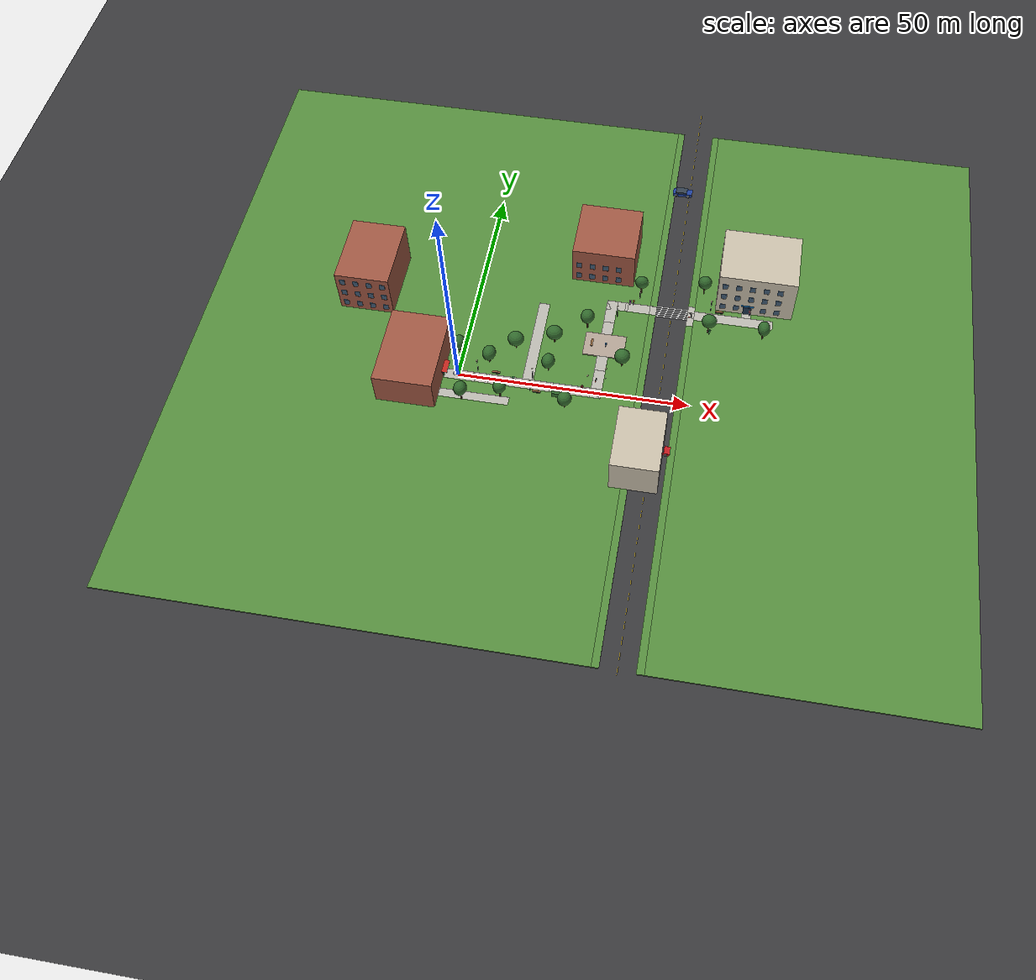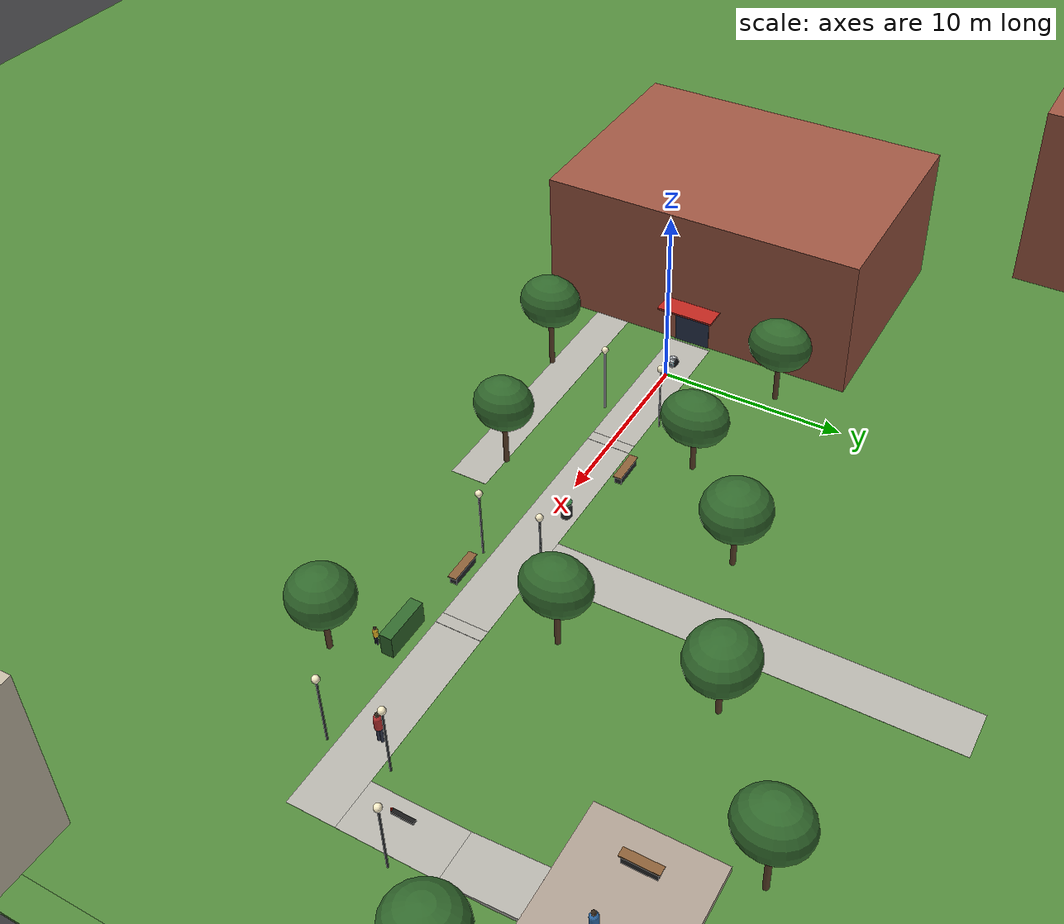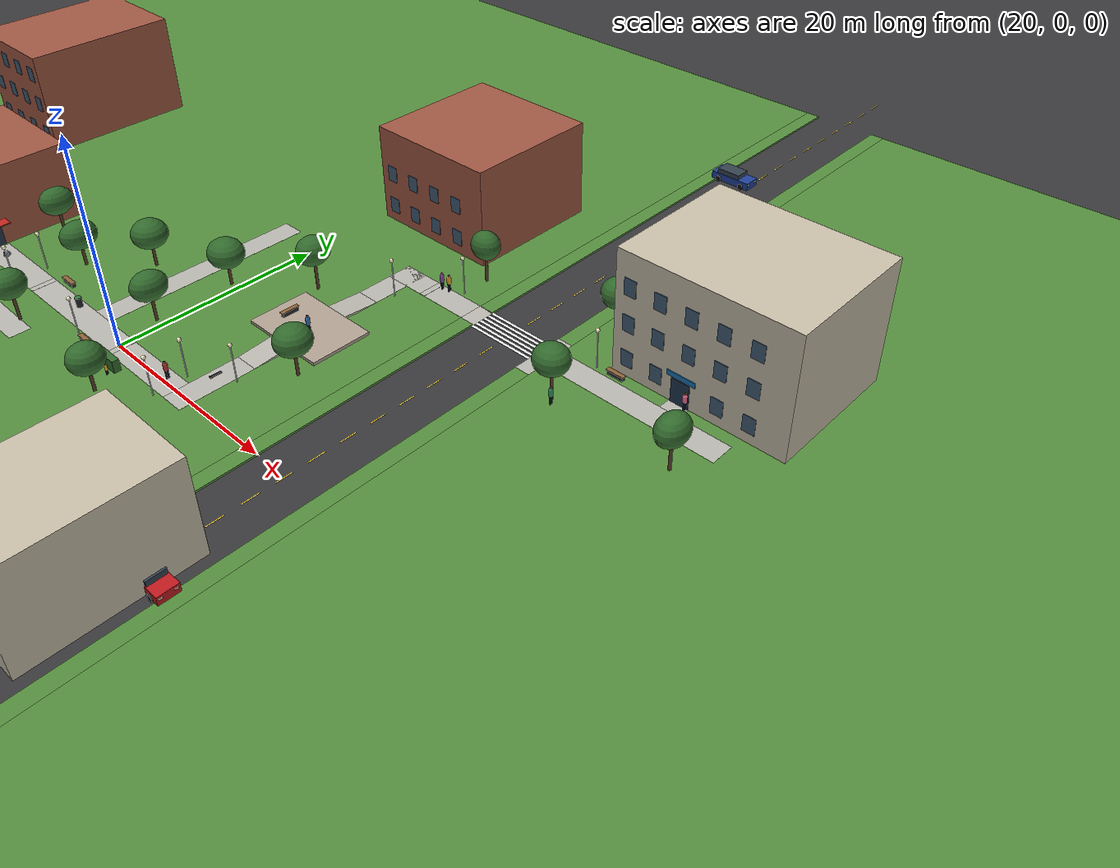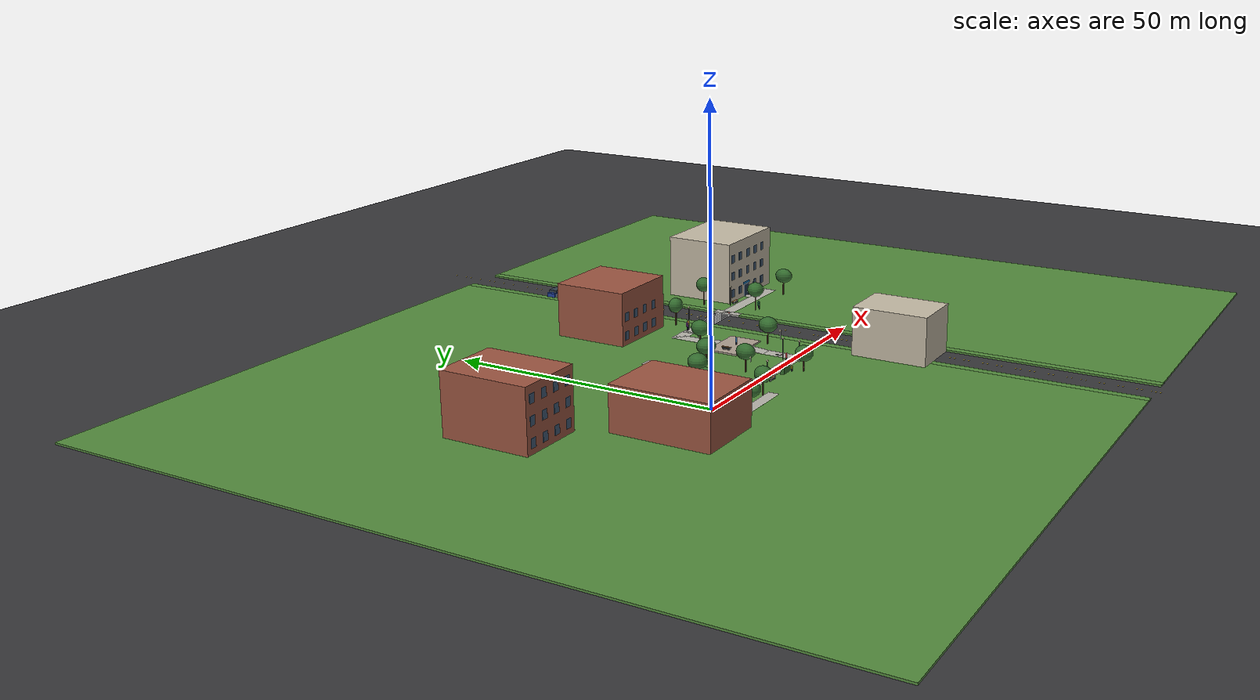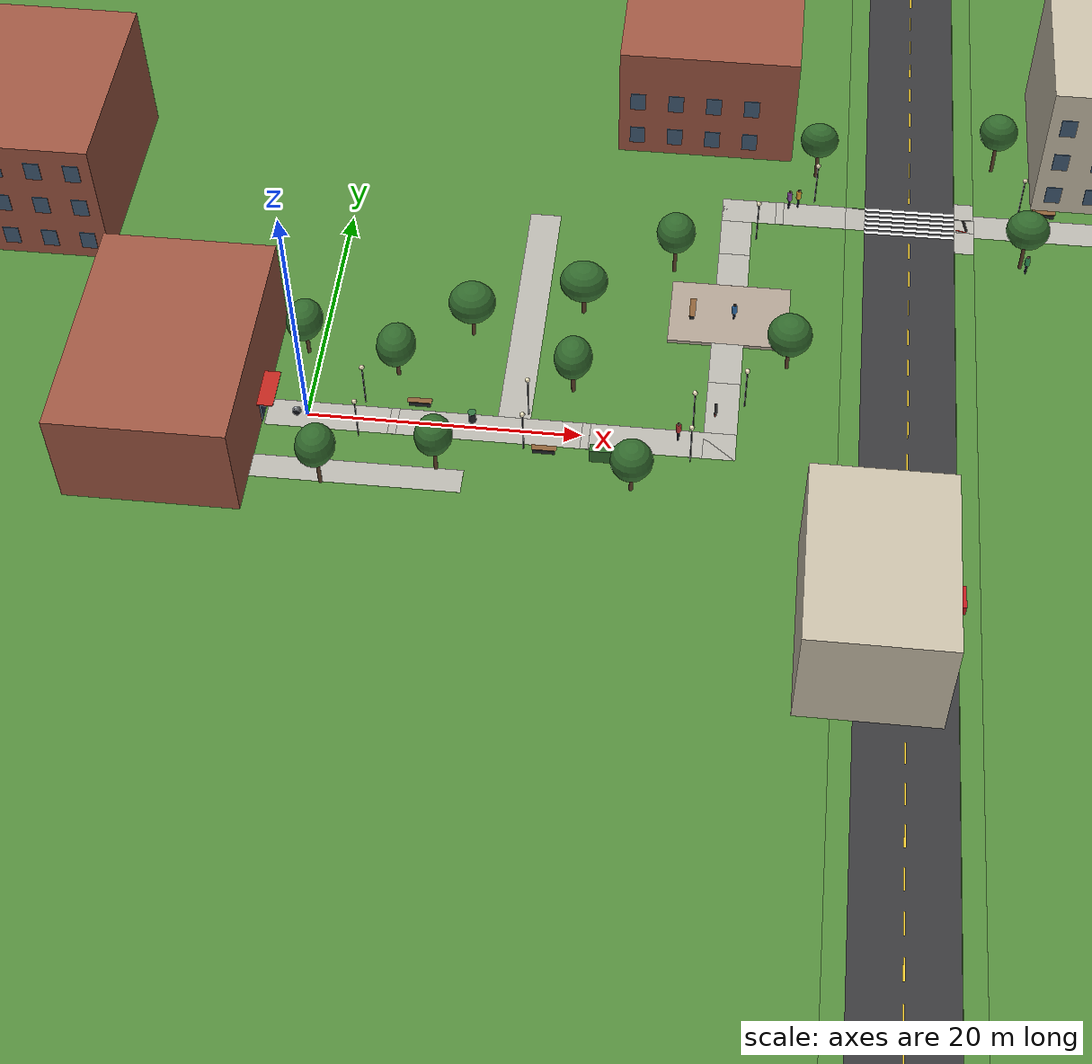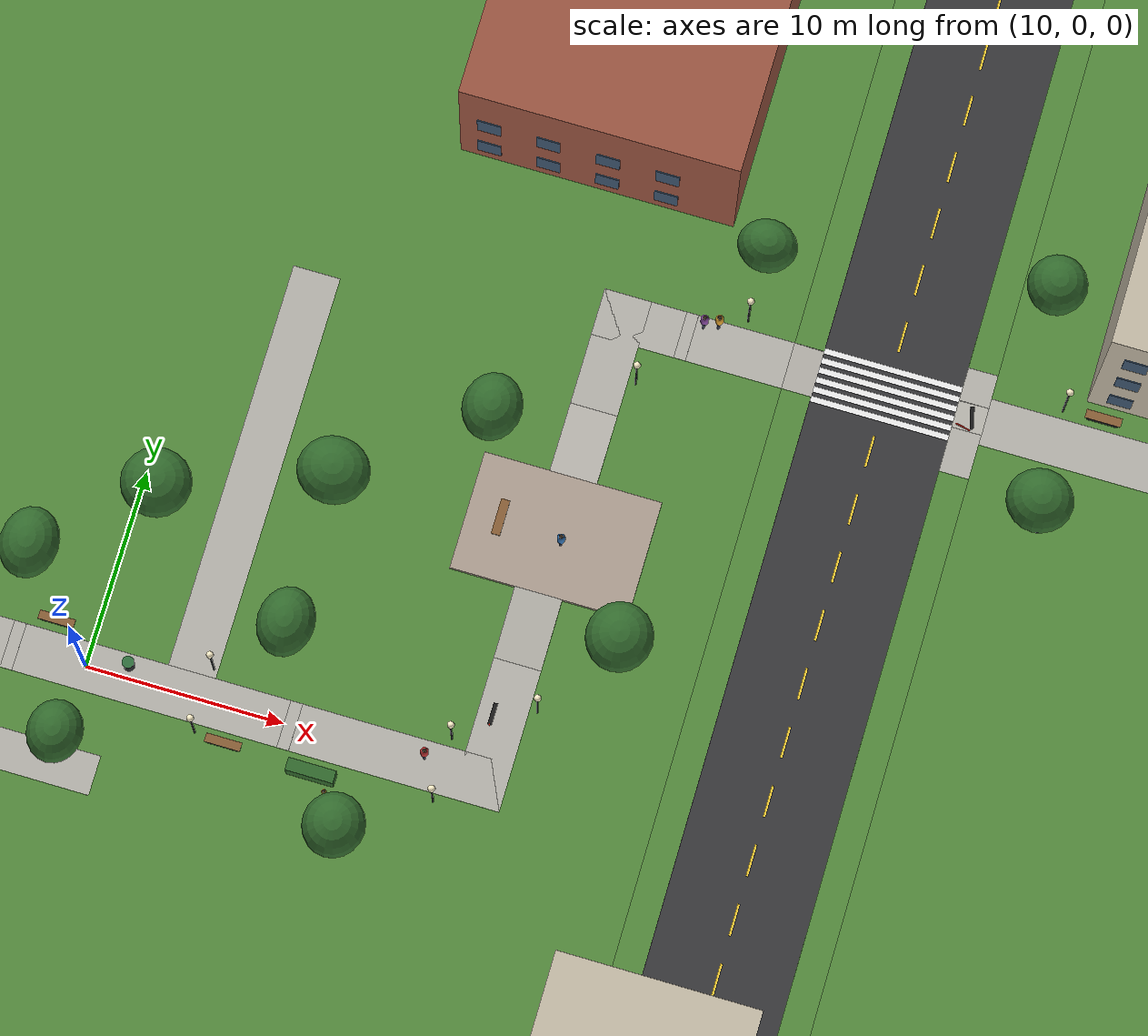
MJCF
<mujoco model="orb_campus">
  <compiler angle="radian" inertiafromgeom="false"/>
  <option timestep="0.002" integrator="implicitfast" cone="elliptic" impratio="3"/>
  <size memory="64M"/>
  <statistic extent="40" center="30 12 0"/>
  <visual>
    <global offwidth="1920" offheight="1080" fovy="40"/>
    <quality shadowsize="4096" offsamples="4"/>
    <headlight ambient="0.42 0.42 0.42" diffuse="0.35 0.35 0.35" specular="0.1 0.1 0.1"/>
    <map znear="0.001" zfar="12" haze="0.25"/>
    <rgba haze="0.85 0.9 0.97 1"/>
  </visual>
  <default><geom friction="0.9 0.012 0.0035"/></default>
  <asset>

    <texture name="sky" type="skybox" builtin="gradient" rgb1="0.55 0.72 0.92" rgb2="0.92 0.95 1.0" width="512" height="512"/>
    <texture name="grass" type="2d" builtin="flat" rgb1="0.33 0.55 0.24" rgb2="0.26 0.45 0.18" mark="random" random="0.35" width="512" height="512"/>
    <material name="grass" texture="grass" texrepeat="1 1" texuniform="true"/>
    <texture name="asphalt" type="2d" builtin="flat" rgb1="0.22 0.22 0.23" rgb2="0.30 0.30 0.31" mark="random" random="0.4" width="256" height="256"/>
    <material name="asphalt" texture="asphalt" texrepeat="2 2" texuniform="true"/>
    <texture name="concrete" type="2d" builtin="checker" rgb1="0.74 0.73 0.70" rgb2="0.70 0.69 0.66" width="256" height="256"/>
    <material name="concrete" texture="concrete" texrepeat="0.8 0.8" texuniform="true" specular="0.1"/>
    <texture name="pavers" type="2d" builtin="checker" rgb1="0.72 0.66 0.60" rgb2="0.66 0.60 0.55" width="256" height="256"/>
    <material name="pavers" texture="pavers" texrepeat="2 2" texuniform="true"/>
    <material name="brick" rgba="0.62 0.34 0.26 1"/>
    <material name="brick2" rgba="0.78 0.74 0.66 1"/>
    <material name="window" rgba="0.25 0.35 0.45 1" specular="1" reflectance="0.2"/>
    <material name="white_paint" rgba="0.95 0.95 0.95 1"/>
    <material name="yellow_paint" rgba="0.95 0.8 0.2 1"/>
    <material name="trunk" rgba="0.36 0.25 0.16 1"/>
    <material name="leaf" rgba="0.20 0.42 0.18 1"/>
    <material name="metal_dark" rgba="0.15 0.16 0.17 1"/>
    <material name="wood" rgba="0.55 0.38 0.22 1"/>
    <material name="skin" rgba="0.80 0.62 0.50 1"/>
    <material name="lamp_glow" rgba="1 0.95 0.8 1" emission="0.6"/>
    <material name="sign_glow" rgba="0.1 0.45 0.7 1" emission="0.5"/>
    <material name="headlamp" rgba="1 1 0.85 1" emission="1"/>

    <mesh name="orb_band" vertex="-0.00000 -0.16250 -0.28146 -0.00000 -0.15183 -0.28736 -0.00000 -0.14094 -0.29285 -0.00000 -0.12830 -0.29860 -0.00000 -0.11544 -0.30381 -0.00000 -0.10236 -0.30846 -0.00000 -0.08909 -0.31255 -0.00000 -0.07566 -0.31607 -0.00000 -0.06209 -0.31901 -0.00000 -0.04841 -0.32137 -0.00000 -0.03464 -0.32315 -0.00000 -0.02081 -0.32433 -0.00000 -0.00694 -0.32493 -0.00000 0.00694 -0.32493 -0.00000 0.02081 -0.32433 -0.00000 0.03464 -0.32315 -0.00000 0.04841 -0.32137 -0.00000 0.06209 -0.31901 -0.00000 0.07566 -0.31607 -0.00000 0.08909 -0.31255 -0.00000 0.10236 -0.30846 -0.00000 0.11544 -0.30381 -0.00000 0.12830 -0.29860 -0.00000 0.14094 -0.29285 -0.00000 0.15183 -0.28736 -0.00000 0.16250 -0.28146 -0.01456 -0.16250 -0.28108 -0.01487 -0.15183 -0.28697 -0.01515 -0.14094 -0.29246 -0.01545 -0.12830 -0.29820 -0.01572 -0.11544 -0.30340 -0.01596 -0.10236 -0.30805 -0.01617 -0.08909 -0.31213 -0.01635 -0.07566 -0.31565 -0.01650 -0.06209 -0.31859 -0.01663 -0.04841 -0.32094 -0.01672 -0.03464 -0.32272 -0.01678 -0.02081 -0.32390 -0.01681 -0.00694 -0.32449 -0.01681 0.00694 -0.32449 -0.01678 0.02081 -0.32390 -0.01672 0.03464 -0.32272 -0.01663 0.04841 -0.32094 -0.01650 0.06209 -0.31859 -0.01635 0.07566 -0.31565 -0.01617 0.08909 -0.31213 -0.01596 0.10236 -0.30805 -0.01572 0.11544 -0.30340 -0.01545 0.12830 -0.29820 -0.01515 0.14094 -0.29246 -0.01487 0.15183 -0.28697 -0.01456 0.16250 -0.28108 -0.02908 -0.16250 -0.27995 -0.02969 -0.15183 -0.28582 -0.03026 -0.14094 -0.29128 -0.03085 -0.12830 -0.29700 -0.03139 -0.11544 -0.30218 -0.03187 -0.10236 -0.30681 -0.03229 -0.08909 -0.31088 -0.03266 -0.07566 -0.31438 -0.03296 -0.06209 -0.31731 -0.03321 -0.04841 -0.31965 -0.03339 -0.03464 -0.32142 -0.03351 -0.02081 -0.32260 -0.03357 -0.00694 -0.32319 -0.03357 0.00694 -0.32319 -0.03351 0.02081 -0.32260 -0.03339 0.03464 -0.32142 -0.03321 0.04841 -0.31965 -0.03296 0.06209 -0.31731 -0.03266 0.07566 -0.31438 -0.03229 0.08909 -0.31088 -0.03187 0.10236 -0.30681 -0.03139 0.11544 -0.30218 -0.03085 0.12830 -0.29700 -0.03026 0.14094 -0.29128 -0.02969 0.15183 -0.28582 -0.02908 0.16250 -0.27995 -0.04352 -0.16250 -0.27807 -0.04444 -0.15183 -0.28390 -0.04529 -0.14094 -0.28933 -0.04618 -0.12830 -0.29501 -0.04698 -0.11544 -0.30015 -0.04770 -0.10236 -0.30475 -0.04833 -0.08909 -0.30879 -0.04888 -0.07566 -0.31227 -0.04933 -0.06209 -0.31518 -0.04970 -0.04841 -0.31751 -0.04997 -0.03464 -0.31926 -0.05015 -0.02081 -0.32043 -0.05025 -0.00694 -0.32102 -0.05025 0.00694 -0.32102 -0.05015 0.02081 -0.32043 -0.04997 0.03464 -0.31926 -0.04970 0.04841 -0.31751 -0.04933 0.06209 -0.31518 -0.04888 0.07566 -0.31227 -0.04833 0.08909 -0.30879 -0.04770 0.10236 -0.30475 -0.04698 0.11544 -0.30015 -0.04618 0.12830 -0.29501 -0.04529 0.14094 -0.28933 -0.04444 0.15183 -0.28390 -0.04352 0.16250 -0.27807 -0.05785 -0.16250 -0.27545 -0.05906 -0.15183 -0.28122 -0.06019 -0.14094 -0.28660 -0.06138 -0.12830 -0.29223 -0.06245 -0.11544 -0.29732 -0.06340 -0.10236 -0.30188 -0.06424 -0.08909 -0.30588 -0.06497 -0.07566 -0.30932 -0.06557 -0.06209 -0.31220 -0.06606 -0.04841 -0.31451 -0.06642 -0.03464 -0.31625 -0.06666 -0.02081 -0.31741 -0.06679 -0.00694 -0.31799 -0.06679 0.00694 -0.31799 -0.06666 0.02081 -0.31741 -0.06642 0.03464 -0.31625 -0.06606 0.04841 -0.31451 -0.06557 0.06209 -0.31220 -0.06497 0.07566 -0.30932 -0.06424 0.08909 -0.30588 -0.06340 0.10236 -0.30188 -0.06245 0.11544 -0.29732 -0.06138 0.12830 -0.29223 -0.06019 0.14094 -0.28660 -0.05906 0.15183 -0.28122 -0.05785 0.16250 -0.27545 -0.07202 -0.16250 -0.27209 -0.07353 -0.15183 -0.27779 -0.07494 -0.14094 -0.28310 -0.07641 -0.12830 -0.28866 -0.07774 -0.11544 -0.29369 -0.07893 -0.10236 -0.29819 -0.07998 -0.08909 -0.30214 -0.08088 -0.07566 -0.30555 -0.08163 -0.06209 -0.30839 -0.08224 -0.04841 -0.31067 -0.08269 -0.03464 -0.31239 -0.08299 -0.02081 -0.31353 -0.08315 -0.00694 -0.31411 -0.08315 0.00694 -0.31411 -0.08299 0.02081 -0.31353 -0.08269 0.03464 -0.31239 -0.08224 0.04841 -0.31067 -0.08163 0.06209 -0.30839 -0.08088 0.07566 -0.30555 -0.07998 0.08909 -0.30214 -0.07893 0.10236 -0.29819 -0.07774 0.11544 -0.29369 -0.07641 0.12830 -0.28866 -0.07494 0.14094 -0.28310 -0.07353 0.15183 -0.27779 -0.07202 0.16250 -0.27209 -0.08600 -0.16250 -0.26800 -0.08780 -0.15183 -0.27361 -0.08948 -0.14094 -0.27884 -0.09124 -0.12830 -0.28432 -0.09283 -0.11544 -0.28928 -0.09425 -0.10236 -0.29371 -0.09550 -0.08909 -0.29760 -0.09658 -0.07566 -0.30095 -0.09748 -0.06209 -0.30376 -0.09820 -0.04841 -0.30600 -0.09874 -0.03464 -0.30769 -0.09910 -0.02081 -0.30882 -0.09928 -0.00694 -0.30939 -0.09928 0.00694 -0.30939 -0.09910 0.02081 -0.30882 -0.09874 0.03464 -0.30769 -0.09820 0.04841 -0.30600 -0.09748 0.06209 -0.30376 -0.09658 0.07566 -0.30095 -0.09550 0.08909 -0.29760 -0.09425 0.10236 -0.29371 -0.09283 0.11544 -0.28928 -0.09124 0.12830 -0.28432 -0.08948 0.14094 -0.27884 -0.08780 0.15183 -0.27361 -0.08600 0.16250 -0.26800 -0.09975 -0.16250 -0.26319 -0.10184 -0.15183 -0.26870 -0.10379 -0.14094 -0.27384 -0.10583 -0.12830 -0.27922 -0.10767 -0.11544 -0.28409 -0.10932 -0.10236 -0.28844 -0.11077 -0.08909 -0.29226 -0.11202 -0.07566 -0.29555 -0.11306 -0.06209 -0.29831 -0.11390 -0.04841 -0.30051 -0.11453 -0.03464 -0.30217 -0.11495 -0.02081 -0.30328 -0.11516 -0.00694 -0.30384 -0.11516 0.00694 -0.30384 -0.11495 0.02081 -0.30328 -0.11453 0.03464 -0.30217 -0.11390 0.04841 -0.30051 -0.11306 0.06209 -0.29831 -0.11202 0.07566 -0.29555 -0.11077 0.08909 -0.29226 -0.10932 0.10236 -0.28844 -0.10767 0.11544 -0.28409 -0.10583 0.12830 -0.27922 -0.10379 0.14094 -0.27384 -0.10184 0.15183 -0.26870 -0.09975 0.16250 -0.26319 -0.11323 -0.16250 -0.25768 -0.11561 -0.15183 -0.26308 -0.11782 -0.14094 -0.26811 -0.12013 -0.12830 -0.27337 -0.12222 -0.11544 -0.27814 -0.12410 -0.10236 -0.28240 -0.12574 -0.08909 -0.28614 -0.12716 -0.07566 -0.28936 -0.12834 -0.06209 -0.29206 -0.12929 -0.04841 -0.29422 -0.13000 -0.03464 -0.29584 -0.13048 -0.02081 -0.29693 -0.13072 -0.00694 -0.29747 -0.13072 0.00694 -0.29747 -0.13048 0.02081 -0.29693 -0.13000 0.03464 -0.29584 -0.12929 0.04841 -0.29422 -0.12834 0.06209 -0.29206 -0.12716 0.07566 -0.28936 -0.12574 0.08909 -0.28614 -0.12410 0.10236 -0.28240 -0.12222 0.11544 -0.27814 -0.12013 0.12830 -0.27337 -0.11782 0.14094 -0.26811 -0.11561 0.15183 -0.26308 -0.11323 0.16250 -0.25768 -0.12641 -0.16250 -0.25147 -0.12906 -0.15183 -0.25674 -0.13153 -0.14094 -0.26165 -0.13411 -0.12830 -0.26679 -0.13645 -0.11544 -0.27144 -0.13854 -0.10236 -0.27560 -0.14038 -0.08909 -0.27925 -0.14196 -0.07566 -0.28240 -0.14328 -0.06209 -0.28503 -0.14434 -0.04841 -0.28714 -0.14513 -0.03464 -0.28872 -0.14567 -0.02081 -0.28978 -0.14593 -0.00694 -0.29031 -0.14593 0.00694 -0.29031 -0.14567 0.02081 -0.28978 -0.14513 0.03464 -0.28872 -0.14434 0.04841 -0.28714 -0.14328 0.06209 -0.28503 -0.14196 0.07566 -0.28240 -0.14038 0.08909 -0.27925 -0.13854 0.10236 -0.27560 -0.13645 0.11544 -0.27144 -0.13411 0.12830 -0.26679 -0.13153 0.14094 -0.26165 -0.12906 0.15183 -0.25674 -0.12641 0.16250 -0.25147 -0.13925 -0.16250 -0.24460 -0.14217 -0.15183 -0.24972 -0.14489 -0.14094 -0.25450 -0.14773 -0.12830 -0.25950 -0.15031 -0.11544 -0.26402 -0.15261 -0.10236 -0.26806 -0.15463 -0.08909 -0.27162 -0.15637 -0.07566 -0.27468 -0.15783 -0.06209 -0.27723 -0.15900 -0.04841 -0.27929 -0.15988 -0.03464 -0.28083 -0.16046 -0.02081 -0.28186 -0.16076 -0.00694 -0.28237 -0.16076 0.00694 -0.28237 -0.16046 0.02081 -0.28186 -0.15988 0.03464 -0.28083 -0.15900 0.04841 -0.27929 -0.15783 0.06209 -0.27723 -0.15637 0.07566 -0.27468 -0.15463 0.08909 -0.27162 -0.15261 0.10236 -0.26806 -0.15031 0.11544 -0.26402 -0.14773 0.12830 -0.25950 -0.14489 0.14094 -0.25450 -0.14217 0.15183 -0.24972 -0.13925 0.16250 -0.24460 -0.15172 -0.16250 -0.23707 -0.15490 -0.15183 -0.24203 -0.15786 -0.14094 -0.24666 -0.16096 -0.12830 -0.25151 -0.16377 -0.11544 -0.25589 -0.16627 -0.10236 -0.25981 -0.16848 -0.08909 -0.26326 -0.17037 -0.07566 -0.26622 -0.17196 -0.06209 -0.26870 -0.17323 -0.04841 -0.27069 -0.17419 -0.03464 -0.27218 -0.17483 -0.02081 -0.27318 -0.17515 -0.00694 -0.27368 -0.17515 0.00694 -0.27368 -0.17483 0.02081 -0.27318 -0.17419 0.03464 -0.27218 -0.17323 0.04841 -0.27069 -0.17196 0.06209 -0.26870 -0.17037 0.07566 -0.26622 -0.16848 0.08909 -0.26326 -0.16627 0.10236 -0.25981 -0.16377 0.11544 -0.25589 -0.16096 0.12830 -0.25151 -0.15786 0.14094 -0.24666 -0.15490 0.15183 -0.24203 -0.15172 0.16250 -0.23707 -0.16378 -0.16250 -0.22890 -0.16721 -0.15183 -0.23370 -0.17041 -0.14094 -0.23817 -0.17375 -0.12830 -0.24284 -0.17678 -0.11544 -0.24708 -0.17949 -0.10236 -0.25086 -0.18187 -0.08909 -0.25419 -0.18392 -0.07566 -0.25705 -0.18563 -0.06209 -0.25944 -0.18700 -0.04841 -0.26136 -0.18804 -0.03464 -0.26281 -0.18873 -0.02081 -0.26377 -0.18907 -0.00694 -0.26425 -0.18907 0.00694 -0.26425 -0.18873 0.02081 -0.26377 -0.18804 0.03464 -0.26281 -0.18700 0.04841 -0.26136 -0.18563 0.06209 -0.25944 -0.18392 0.07566 -0.25705 -0.18187 0.08909 -0.25419 -0.17949 0.10236 -0.25086 -0.17678 0.11544 -0.24708 -0.17375 0.12830 -0.24284 -0.17041 0.14094 -0.23817 -0.16721 0.15183 -0.23370 -0.16378 0.16250 -0.22890 -0.17540 -0.16250 -0.22012 -0.17908 -0.15183 -0.22473 -0.18250 -0.14094 -0.22903 -0.18608 -0.12830 -0.23353 -0.18933 -0.11544 -0.23760 -0.19223 -0.10236 -0.24124 -0.19478 -0.08909 -0.24444 -0.19697 -0.07566 -0.24719 -0.19880 -0.06209 -0.24949 -0.20027 -0.04841 -0.25134 -0.20138 -0.03464 -0.25273 -0.20212 -0.02081 -0.25365 -0.20249 -0.00694 -0.25412 -0.20249 0.00694 -0.25412 -0.20212 0.02081 -0.25365 -0.20138 0.03464 -0.25273 -0.20027 0.04841 -0.25134 -0.19880 0.06209 -0.24949 -0.19697 0.07566 -0.24719 -0.19478 0.08909 -0.24444 -0.19223 0.10236 -0.24124 -0.18933 0.11544 -0.23760 -0.18608 0.12830 -0.23353 -0.18250 0.14094 -0.22903 -0.17908 0.15183 -0.22473 -0.17540 0.16250 -0.22012 -0.18655 -0.16250 -0.21075 -0.19046 -0.15183 -0.21517 -0.19410 -0.14094 -0.21928 -0.19792 -0.12830 -0.22359 -0.20137 -0.11544 -0.22749 -0.20445 -0.10236 -0.23097 -0.20716 -0.08909 -0.23404 -0.20949 -0.07566 -0.23667 -0.21144 -0.06209 -0.23887 -0.21301 -0.04841 -0.24064 -0.21418 -0.03464 -0.24197 -0.21497 -0.02081 -0.24286 -0.21536 -0.00694 -0.24330 -0.21536 0.00694 -0.24330 -0.21497 0.02081 -0.24286 -0.21418 0.03464 -0.24197 -0.21301 0.04841 -0.24064 -0.21144 0.06209 -0.23887 -0.20949 0.07566 -0.23667 -0.20716 0.08909 -0.23404 -0.20445 0.10236 -0.23097 -0.20137 0.11544 -0.22749 -0.19792 0.12830 -0.22359 -0.19410 0.14094 -0.21928 -0.19046 0.15183 -0.21517 -0.18655 0.16250 -0.21075 -0.19721 -0.16250 -0.20082 -0.20134 -0.15183 -0.20503 -0.20519 -0.14094 -0.20895 -0.20922 -0.12830 -0.21305 -0.21287 -0.11544 -0.21677 -0.21613 -0.10236 -0.22009 -0.21899 -0.08909 -0.22301 -0.22146 -0.07566 -0.22552 -0.22352 -0.06209 -0.22762 -0.22517 -0.04841 -0.22930 -0.22642 -0.03464 -0.23057 -0.22725 -0.02081 -0.23141 -0.22766 -0.00694 -0.23183 -0.22766 0.00694 -0.23183 -0.22725 0.02081 -0.23141 -0.22642 0.03464 -0.23057 -0.22517 0.04841 -0.22930 -0.22352 0.06209 -0.22762 -0.22146 0.07566 -0.22552 -0.21899 0.08909 -0.22301 -0.21613 0.10236 -0.22009 -0.21287 0.11544 -0.21677 -0.20922 0.12830 -0.21305 -0.20519 0.14094 -0.20895 -0.20134 0.15183 -0.20503 -0.19721 0.16250 -0.20082 -0.20733 -0.16250 -0.19035 -0.21167 -0.15183 -0.19434 -0.21572 -0.14094 -0.19805 -0.21996 -0.12830 -0.20194 -0.22379 -0.11544 -0.20547 -0.22722 -0.10236 -0.20861 -0.23023 -0.08909 -0.21138 -0.23283 -0.07566 -0.21376 -0.23499 -0.06209 -0.21575 -0.23673 -0.04841 -0.21734 -0.23804 -0.03464 -0.21854 -0.23891 -0.02081 -0.21935 -0.23935 -0.00694 -0.21975 -0.23935 0.00694 -0.21975 -0.23891 0.02081 -0.21935 -0.23804 0.03464 -0.21854 -0.23673 0.04841 -0.21734 -0.23499 0.06209 -0.21575 -0.23283 0.07566 -0.21376 -0.23023 0.08909 -0.21138 -0.22722 0.10236 -0.20861 -0.22379 0.11544 -0.20547 -0.21996 0.12830 -0.20194 -0.21572 0.14094 -0.19805 -0.21167 0.15183 -0.19434 -0.20733 0.16250 -0.19035 -0.21690 -0.16250 -0.17937 -0.22144 -0.15183 -0.18313 -0.22568 -0.14094 -0.18663 -0.23011 -0.12830 -0.19029 -0.23412 -0.11544 -0.19361 -0.23771 -0.10236 -0.19658 -0.24086 -0.08909 -0.19918 -0.24357 -0.07566 -0.20143 -0.24584 -0.06209 -0.20330 -0.24766 -0.04841 -0.20481 -0.24903 -0.03464 -0.20594 -0.24994 -0.02081 -0.20669 -0.25040 -0.00694 -0.20707 -0.25040 0.00694 -0.20707 -0.24994 0.02081 -0.20669 -0.24903 0.03464 -0.20594 -0.24766 0.04841 -0.20481 -0.24584 0.06209 -0.20330 -0.24357 0.07566 -0.20143 -0.24086 0.08909 -0.19918 -0.23771 0.10236 -0.19658 -0.23412 0.11544 -0.19361 -0.23011 0.12830 -0.19029 -0.22568 0.14094 -0.18663 -0.22144 0.15183 -0.18313 -0.21690 0.16250 -0.17937 -0.22589 -0.16250 -0.16791 -0.23062 -0.15183 -0.17143 -0.23503 -0.14094 -0.17470 -0.23965 -0.12830 -0.17814 -0.24383 -0.11544 -0.18124 -0.24756 -0.10236 -0.18402 -0.25084 -0.08909 -0.18646 -0.25367 -0.07566 -0.18856 -0.25603 -0.06209 -0.19031 -0.25792 -0.04841 -0.19172 -0.25935 -0.03464 -0.19278 -0.26030 -0.02081 -0.19349 -0.26077 -0.00694 -0.19384 -0.26077 0.00694 -0.19384 -0.26030 0.02081 -0.19349 -0.25935 0.03464 -0.19278 -0.25792 0.04841 -0.19172 -0.25603 0.06209 -0.19031 -0.25367 0.07566 -0.18856 -0.25084 0.08909 -0.18646 -0.24756 0.10236 -0.18402 -0.24383 0.11544 -0.18124 -0.23965 0.12830 -0.17814 -0.23503 0.14094 -0.17470 -0.23062 0.15183 -0.17143 -0.22589 0.16250 -0.16791 -0.23427 -0.16250 -0.15600 -0.23918 -0.15183 -0.15927 -0.24375 -0.14094 -0.16231 -0.24854 -0.12830 -0.16550 -0.25287 -0.11544 -0.16839 -0.25675 -0.10236 -0.17097 -0.26015 -0.08909 -0.17323 -0.26308 -0.07566 -0.17518 -0.26553 -0.06209 -0.17681 -0.26750 -0.04841 -0.17812 -0.26897 -0.03464 -0.17911 -0.26996 -0.02081 -0.17976 -0.27045 -0.00694 -0.18009 -0.27045 0.00694 -0.18009 -0.26996 0.02081 -0.17976 -0.26897 0.03464 -0.17911 -0.26750 0.04841 -0.17812 -0.26553 0.06209 -0.17681 -0.26308 0.07566 -0.17518 -0.26015 0.08909 -0.17323 -0.25675 0.10236 -0.17097 -0.25287 0.11544 -0.16839 -0.24854 0.12830 -0.16550 -0.24375 0.14094 -0.16231 -0.23918 0.15183 -0.15927 -0.23427 0.16250 -0.15600 -0.24203 -0.16250 -0.14367 -0.24710 -0.15183 -0.14668 -0.25182 -0.14094 -0.14949 -0.25677 -0.12830 -0.15242 -0.26125 -0.11544 -0.15508 -0.26525 -0.10236 -0.15745 -0.26876 -0.08909 -0.15954 -0.27179 -0.07566 -0.16134 -0.27432 -0.06209 -0.16284 -0.27635 -0.04841 -0.16405 -0.27788 -0.03464 -0.16495 -0.27890 -0.02081 -0.16556 -0.27941 -0.00694 -0.16586 -0.27941 0.00694 -0.16586 -0.27890 0.02081 -0.16556 -0.27788 0.03464 -0.16495 -0.27635 0.04841 -0.16405 -0.27432 0.06209 -0.16284 -0.27179 0.07566 -0.16134 -0.26876 0.08909 -0.15954 -0.26525 0.10236 -0.15745 -0.26125 0.11544 -0.15508 -0.25677 0.12830 -0.15242 -0.25182 0.14094 -0.14949 -0.24710 0.15183 -0.14668 -0.24203 0.16250 -0.14367 -0.24914 -0.16250 -0.13096 -0.25436 -0.15183 -0.13370 -0.25922 -0.14094 -0.13626 -0.26431 -0.12830 -0.13893 -0.26892 -0.11544 -0.14136 -0.27304 -0.10236 -0.14352 -0.27666 -0.08909 -0.14542 -0.27977 -0.07566 -0.14706 -0.28238 -0.06209 -0.14843 -0.28447 -0.04841 -0.14953 -0.28604 -0.03464 -0.15036 -0.28709 -0.02081 -0.15091 -0.28761 -0.00694 -0.15118 -0.28761 0.00694 -0.15118 -0.28709 0.02081 -0.15091 -0.28604 0.03464 -0.15036 -0.28447 0.04841 -0.14953 -0.28238 0.06209 -0.14843 -0.27977 0.07566 -0.14706 -0.27666 0.08909 -0.14542 -0.27304 0.10236 -0.14352 -0.26892 0.11544 -0.14136 -0.26431 0.12830 -0.13893 -0.25922 0.14094 -0.13626 -0.25436 0.15183 -0.13370 -0.24914 0.16250 -0.13096 -0.25558 -0.16250 -0.11789 -0.26093 -0.15183 -0.12036 -0.26592 -0.14094 -0.12267 -0.27114 -0.12830 -0.12508 -0.27587 -0.11544 -0.12726 -0.28010 -0.10236 -0.12921 -0.28381 -0.08909 -0.13092 -0.28701 -0.07566 -0.13239 -0.28968 -0.06209 -0.13363 -0.29182 -0.04841 -0.13461 -0.29343 -0.03464 -0.13536 -0.29451 -0.02081 -0.13585 -0.29505 -0.00694 -0.13610 -0.29505 0.00694 -0.13610 -0.29451 0.02081 -0.13585 -0.29343 0.03464 -0.13536 -0.29182 0.04841 -0.13461 -0.28968 0.06209 -0.13363 -0.28701 0.07566 -0.13239 -0.28381 0.08909 -0.13092 -0.28010 0.10236 -0.12921 -0.27587 0.11544 -0.12726 -0.27114 0.12830 -0.12508 -0.26592 0.14094 -0.12267 -0.26093 0.15183 -0.12036 -0.25558 0.16250 -0.11789 -0.26133 -0.16250 -0.10452 -0.26681 -0.15183 -0.10671 -0.27191 -0.14094 -0.10875 -0.27725 -0.12830 -0.11088 -0.28209 -0.11544 -0.11281 -0.28641 -0.10236 -0.11454 -0.29020 -0.08909 -0.11606 -0.29347 -0.07566 -0.11737 -0.29620 -0.06209 -0.11846 -0.29840 -0.04841 -0.11934 -0.30004 -0.03464 -0.12000 -0.30114 -0.02081 -0.12044 -0.30169 -0.00694 -0.12066 -0.30169 0.00694 -0.12066 -0.30114 0.02081 -0.12044 -0.30004 0.03464 -0.12000 -0.29840 0.04841 -0.11934 -0.29620 0.06209 -0.11846 -0.29347 0.07566 -0.11737 -0.29020 0.08909 -0.11606 -0.28641 0.10236 -0.11454 -0.28209 0.11544 -0.11281 -0.27725 0.12830 -0.11088 -0.27191 0.14094 -0.10875 -0.26681 0.15183 -0.10671 -0.26133 0.16250 -0.10452 -0.26639 -0.16250 -0.09086 -0.27197 -0.15183 -0.09276 -0.27717 -0.14094 -0.09453 -0.28262 -0.12830 -0.09639 -0.28754 -0.11544 -0.09807 -0.29195 -0.10236 -0.09957 -0.29582 -0.08909 -0.10089 -0.29915 -0.07566 -0.10203 -0.30194 -0.06209 -0.10298 -0.30417 -0.04841 -0.10374 -0.30585 -0.03464 -0.10431 -0.30697 -0.02081 -0.10470 -0.30753 -0.00694 -0.10489 -0.30753 0.00694 -0.10489 -0.30697 0.02081 -0.10470 -0.30585 0.03464 -0.10431 -0.30417 0.04841 -0.10374 -0.30194 0.06209 -0.10298 -0.29915 0.07566 -0.10203 -0.29582 0.08909 -0.10089 -0.29195 0.10236 -0.09957 -0.28754 0.11544 -0.09807 -0.28262 0.12830 -0.09639 -0.27717 0.14094 -0.09453 -0.27197 0.15183 -0.09276 -0.26639 0.16250 -0.09086 -0.27073 -0.16250 -0.07695 -0.27641 -0.15183 -0.07857 -0.28169 -0.14094 -0.08007 -0.28722 -0.12830 -0.08164 -0.29223 -0.11544 -0.08306 -0.29671 -0.10236 -0.08434 -0.30064 -0.08909 -0.08545 -0.30403 -0.07566 -0.08642 -0.30686 -0.06209 -0.08722 -0.30913 -0.04841 -0.08787 -0.31084 -0.03464 -0.08835 -0.31198 -0.02081 -0.08868 -0.31255 -0.00694 -0.08884 -0.31255 0.00694 -0.08884 -0.31198 0.02081 -0.08868 -0.31084 0.03464 -0.08835 -0.30913 0.04841 -0.08787 -0.30686 0.06209 -0.08722 -0.30403 0.07566 -0.08642 -0.30064 0.08909 -0.08545 -0.29671 0.10236 -0.08434 -0.29223 0.11544 -0.08306 -0.28722 0.12830 -0.08164 -0.28169 0.14094 -0.08007 -0.27641 0.15183 -0.07857 -0.27073 0.16250 -0.07695 -0.27435 -0.16250 -0.06285 -0.28010 -0.15183 -0.06416 -0.28546 -0.14094 -0.06539 -0.29106 -0.12830 -0.06667 -0.29614 -0.11544 -0.06784 -0.30067 -0.10236 -0.06887 -0.30466 -0.08909 -0.06979 -0.30809 -0.07566 -0.07057 -0.31096 -0.06209 -0.07123 -0.31326 -0.04841 -0.07176 -0.31499 -0.03464 -0.07215 -0.31614 -0.02081 -0.07242 -0.31672 -0.00694 -0.07255 -0.31672 0.00694 -0.07255 -0.31614 0.02081 -0.07242 -0.31499 0.03464 -0.07215 -0.31326 0.04841 -0.07176 -0.31096 0.06209 -0.07123 -0.30809 0.07566 -0.07057 -0.30466 0.08909 -0.06979 -0.30067 0.10236 -0.06887 -0.29614 0.11544 -0.06784 -0.29106 0.12830 -0.06667 -0.28546 0.14094 -0.06539 -0.28010 0.15183 -0.06416 -0.27435 0.16250 -0.06285 -0.27724 -0.16250 -0.04857 -0.28305 -0.15183 -0.04959 -0.28846 -0.14094 -0.05053 -0.29412 -0.12830 -0.05153 -0.29925 -0.11544 -0.05243 -0.30383 -0.10236 -0.05323 -0.30786 -0.08909 -0.05393 -0.31133 -0.07566 -0.05454 -0.31423 -0.06209 -0.05505 -0.31655 -0.04841 -0.05546 -0.31830 -0.03464 -0.05576 -0.31947 -0.02081 -0.05597 -0.32005 -0.00694 -0.05607 -0.32005 0.00694 -0.05607 -0.31947 0.02081 -0.05597 -0.31830 0.03464 -0.05576 -0.31655 0.04841 -0.05546 -0.31423 0.06209 -0.05505 -0.31133 0.07566 -0.05454 -0.30786 0.08909 -0.05393 -0.30383 0.10236 -0.05323 -0.29925 0.11544 -0.05243 -0.29412 0.12830 -0.05153 -0.28846 0.14094 -0.05053 -0.28305 0.15183 -0.04959 -0.27724 0.16250 -0.04857 -0.27938 -0.16250 -0.03416 -0.28523 -0.15183 -0.03488 -0.29068 -0.14094 -0.03554 -0.29639 -0.12830 -0.03624 -0.30156 -0.11544 -0.03687 -0.30618 -0.10236 -0.03744 -0.31024 -0.08909 -0.03794 -0.31373 -0.07566 -0.03836 -0.31665 -0.06209 -0.03872 -0.31900 -0.04841 -0.03901 -0.32076 -0.03464 -0.03922 -0.32194 -0.02081 -0.03937 -0.32252 -0.00694 -0.03944 -0.32252 0.00694 -0.03944 -0.32194 0.02081 -0.03937 -0.32076 0.03464 -0.03922 -0.31900 0.04841 -0.03901 -0.31665 0.06209 -0.03872 -0.31373 0.07566 -0.03836 -0.31024 0.08909 -0.03794 -0.30618 0.10236 -0.03744 -0.30156 0.11544 -0.03687 -0.29639 0.12830 -0.03624 -0.29068 0.14094 -0.03554 -0.28523 0.15183 -0.03488 -0.27938 0.16250 -0.03416 -0.28077 -0.16250 -0.01966 -0.28665 -0.15183 -0.02008 -0.29213 -0.14094 -0.02046 -0.29787 -0.12830 -0.02086 -0.30307 -0.11544 -0.02123 -0.30771 -0.10236 -0.02155 -0.31179 -0.08909 -0.02184 -0.31530 -0.07566 -0.02208 -0.31823 -0.06209 -0.02229 -0.32059 -0.04841 -0.02245 -0.32236 -0.03464 -0.02258 -0.32354 -0.02081 -0.02266 -0.32413 -0.00694 -0.02270 -0.32413 0.00694 -0.02270 -0.32354 0.02081 -0.02266 -0.32236 0.03464 -0.02258 -0.32059 0.04841 -0.02245 -0.31823 0.06209 -0.02229 -0.31530 0.07566 -0.02208 -0.31179 0.08909 -0.02184 -0.30771 0.10236 -0.02155 -0.30307 0.11544 -0.02123 -0.29787 0.12830 -0.02086 -0.29213 0.14094 -0.02046 -0.28665 0.15183 -0.02008 -0.28077 0.16250 -0.01966 -0.28141 -0.16250 -0.00511 -0.28731 -0.15183 -0.00522 -0.29280 -0.14094 -0.00532 -0.29855 -0.12830 -0.00542 -0.30376 -0.11544 -0.00552 -0.30841 -0.10236 -0.00560 -0.31250 -0.08909 -0.00568 -0.31602 -0.07566 -0.00574 -0.31896 -0.06209 -0.00579 -0.32132 -0.04841 -0.00584 -0.32310 -0.03464 -0.00587 -0.32428 -0.02081 -0.00589 -0.32487 -0.00694 -0.00590 -0.32487 0.00694 -0.00590 -0.32428 0.02081 -0.00589 -0.32310 0.03464 -0.00587 -0.32132 0.04841 -0.00584 -0.31896 0.06209 -0.00579 -0.31602 0.07566 -0.00574 -0.31250 0.08909 -0.00568 -0.30841 0.10236 -0.00560 -0.30376 0.11544 -0.00552 -0.29855 0.12830 -0.00542 -0.29280 0.14094 -0.00532 -0.28731 0.15183 -0.00522 -0.28141 0.16250 -0.00511 -0.28130 -0.16250 0.00945 -0.28719 -0.15183 0.00965 -0.29268 -0.14094 0.00983 -0.29843 -0.12830 0.01003 -0.30364 -0.11544 0.01020 -0.30829 -0.10236 0.01036 -0.31237 -0.08909 0.01050 -0.31589 -0.07566 0.01061 -0.31883 -0.06209 0.01071 -0.32119 -0.04841 0.01079 -0.32297 -0.03464 0.01085 -0.32415 -0.02081 0.01089 -0.32474 -0.00694 0.01091 -0.32474 0.00694 0.01091 -0.32415 0.02081 0.01089 -0.32297 0.03464 0.01085 -0.32119 0.04841 0.01079 -0.31883 0.06209 0.01071 -0.31589 0.07566 0.01061 -0.31237 0.08909 0.01050 -0.30829 0.10236 0.01036 -0.30364 0.11544 0.01020 -0.29843 0.12830 0.01003 -0.29268 0.14094 0.00983 -0.28719 0.15183 0.00965 -0.28130 0.16250 0.00945 -0.28043 -0.16250 0.02399 -0.28631 -0.15183 0.02449 -0.29178 -0.14094 0.02496 -0.29752 -0.12830 0.02545 -0.30270 -0.11544 0.02590 -0.30734 -0.10236 0.02629 -0.31141 -0.08909 0.02664 -0.31492 -0.07566 0.02694 -0.31785 -0.06209 0.02719 -0.32020 -0.04841 0.02739 -0.32197 -0.03464 0.02754 -0.32315 -0.02081 0.02765 -0.32374 -0.00694 0.02770 -0.32374 0.00694 0.02770 -0.32315 0.02081 0.02765 -0.32197 0.03464 0.02754 -0.32020 0.04841 0.02739 -0.31785 0.06209 0.02719 -0.31492 0.07566 0.02694 -0.31141 0.08909 0.02664 -0.30734 0.10236 0.02629 -0.30270 0.11544 0.02590 -0.29752 0.12830 0.02545 -0.29178 0.14094 0.02496 -0.28631 0.15183 0.02449 -0.28043 0.16250 0.02399 -0.27882 -0.16250 0.03847 -0.28466 -0.15183 0.03927 -0.29010 -0.14094 0.04002 -0.29580 -0.12830 0.04081 -0.30096 -0.11544 0.04152 -0.30557 -0.10236 0.04216 -0.30962 -0.08909 0.04272 -0.31310 -0.07566 0.04320 -0.31602 -0.06209 0.04360 -0.31836 -0.04841 0.04392 -0.32012 -0.03464 0.04416 -0.32129 -0.02081 0.04433 -0.32188 -0.00694 0.04441 -0.32188 0.00694 0.04441 -0.32129 0.02081 0.04433 -0.32012 0.03464 0.04416 -0.31836 0.04841 0.04392 -0.31602 0.06209 0.04360 -0.31310 0.07566 0.04320 -0.30962 0.08909 0.04272 -0.30557 0.10236 0.04216 -0.30096 0.11544 0.04152 -0.29580 0.12830 0.04081 -0.29010 0.14094 0.04002 -0.28466 0.15183 0.03927 -0.27882 0.16250 0.03847 -0.27645 -0.16250 0.05284 -0.28225 -0.15183 0.05395 -0.28764 -0.14094 0.05498 -0.29329 -0.12830 0.05606 -0.29841 -0.11544 0.05703 -0.30298 -0.10236 0.05791 -0.30699 -0.08909 0.05868 -0.31045 -0.07566 0.05934 -0.31334 -0.06209 0.05989 -0.31566 -0.04841 0.06033 -0.31740 -0.03464 0.06067 -0.31857 -0.02081 0.06089 -0.31915 -0.00694 0.06100 -0.31915 0.00694 0.06100 -0.31857 0.02081 0.06089 -0.31740 0.03464 0.06067 -0.31566 0.04841 0.06033 -0.31334 0.06209 0.05989 -0.31045 0.07566 0.05934 -0.30699 0.08909 0.05868 -0.30298 0.10236 0.05791 -0.29841 0.11544 0.05703 -0.29329 0.12830 0.05606 -0.28764 0.14094 0.05498 -0.28225 0.15183 0.05395 -0.27645 0.16250 0.05284 -0.27335 -0.16250 0.06707 -0.27908 -0.15183 0.06847 -0.28441 -0.14094 0.06978 -0.29000 -0.12830 0.07115 -0.29506 -0.11544 0.07239 -0.29958 -0.10236 0.07350 -0.30355 -0.08909 0.07448 -0.30697 -0.07566 0.07532 -0.30982 -0.06209 0.07602 -0.31212 -0.04841 0.07658 -0.31384 -0.03464 0.07700 -0.31499 -0.02081 0.07729 -0.31557 -0.00694 0.07743 -0.31557 0.00694 0.07743 -0.31499 0.02081 0.07729 -0.31384 0.03464 0.07700 -0.31212 0.04841 0.07658 -0.30982 0.06209 0.07602 -0.30697 0.07566 0.07532 -0.30355 0.08909 0.07448 -0.29958 0.10236 0.07350 -0.29506 0.11544 0.07239 -0.29000 0.12830 0.07115 -0.28441 0.14094 0.06978 -0.27908 0.15183 0.06847 -0.27335 0.16250 0.06707 -0.26951 -0.16250 0.08112 -0.27516 -0.15183 0.08282 -0.28042 -0.14094 0.08440 -0.28593 -0.12830 0.08606 -0.29092 -0.11544 0.08756 -0.29537 -0.10236 0.08890 -0.29929 -0.08909 0.09008 -0.30266 -0.07566 0.09110 -0.30548 -0.06209 0.09194 -0.30774 -0.04841 0.09262 -0.30944 -0.03464 0.09314 -0.31057 -0.02081 0.09348 -0.31114 -0.00694 0.09365 -0.31114 0.00694 0.09365 -0.31057 0.02081 0.09348 -0.30944 0.03464 0.09314 -0.30774 0.04841 0.09262 -0.30548 0.06209 0.09194 -0.30266 0.07566 0.09110 -0.29929 0.08909 0.09008 -0.29537 0.10236 0.08890 -0.29092 0.11544 0.08756 -0.28593 0.12830 0.08606 -0.28042 0.14094 0.08440 -0.27516 0.15183 0.08282 -0.26951 0.16250 0.08112 -0.26496 -0.16250 0.09495 -0.27051 -0.15183 0.09694 -0.27568 -0.14094 0.09880 -0.28110 -0.12830 0.10074 -0.28600 -0.11544 0.10249 -0.29038 -0.10236 0.10406 -0.29423 -0.08909 0.10544 -0.29754 -0.07566 0.10663 -0.30031 -0.06209 0.10762 -0.30253 -0.04841 0.10842 -0.30420 -0.03464 0.10902 -0.30532 -0.02081 0.10942 -0.30588 -0.00694 0.10962 -0.30588 0.00694 0.10962 -0.30532 0.02081 0.10942 -0.30420 0.03464 0.10902 -0.30253 0.04841 0.10842 -0.30031 0.06209 0.10762 -0.29754 0.07566 0.10663 -0.29423 0.08909 0.10544 -0.29038 0.10236 0.10406 -0.28600 0.11544 0.10249 -0.28110 0.12830 0.10074 -0.27568 0.14094 0.09880 -0.27051 0.15183 0.09694 -0.26496 0.16250 0.09495 -0.25969 -0.16250 0.10853 -0.26513 -0.15183 0.11081 -0.27020 -0.14094 0.11293 -0.27551 -0.12830 0.11514 -0.28031 -0.11544 0.11715 -0.28461 -0.10236 0.11895 -0.28838 -0.08909 0.12052 -0.29163 -0.07566 0.12188 -0.29434 -0.06209 0.12301 -0.29652 -0.04841 0.12393 -0.29816 -0.03464 0.12461 -0.29925 -0.02081 0.12507 -0.29980 -0.00694 0.12529 -0.29980 0.00694 0.12529 -0.29925 0.02081 0.12507 -0.29816 0.03464 0.12461 -0.29652 0.04841 0.12393 -0.29434 0.06209 0.12301 -0.29163 0.07566 0.12188 -0.28838 0.08909 0.12052 -0.28461 0.10236 0.11895 -0.28031 0.11544 0.11715 -0.27551 0.12830 0.11514 -0.27020 0.14094 0.11293 -0.26513 0.15183 0.11081 -0.25969 0.16250 0.10853 -0.25373 -0.16250 0.12182 -0.25905 -0.15183 0.12437 -0.26400 -0.14094 0.12675 -0.26918 -0.12830 0.12924 -0.27388 -0.11544 0.13150 -0.27807 -0.10236 0.13351 -0.28176 -0.08909 0.13528 -0.28493 -0.07566 0.13680 -0.28758 -0.06209 0.13808 -0.28971 -0.04841 0.13910 -0.29131 -0.03464 0.13987 -0.29238 -0.02081 0.14038 -0.29291 -0.00694 0.14064 -0.29291 0.00694 0.14064 -0.29238 0.02081 0.14038 -0.29131 0.03464 0.13987 -0.28971 0.04841 0.13910 -0.28758 0.06209 0.13808 -0.28493 0.07566 0.13680 -0.28176 0.08909 0.13528 -0.27807 0.10236 0.13351 -0.27388 0.11544 0.13150 -0.26918 0.12830 0.12924 -0.26400 0.14094 0.12675 -0.25905 0.15183 0.12437 -0.25373 0.16250 0.12182 -0.24709 -0.16250 0.13478 -0.25226 -0.15183 0.13761 -0.25709 -0.14094 0.14024 -0.26214 -0.12830 0.14299 -0.26671 -0.11544 0.14549 -0.27079 -0.10236 0.14772 -0.27438 -0.08909 0.14967 -0.27747 -0.07566 0.15136 -0.28006 -0.06209 0.15277 -0.28213 -0.04841 0.15390 -0.28369 -0.03464 0.15475 -0.28473 -0.02081 0.15532 -0.28525 -0.00694 0.15560 -0.28525 0.00694 0.15560 -0.28473 0.02081 0.15532 -0.28369 0.03464 0.15475 -0.28213 0.04841 0.15390 -0.28006 0.06209 0.15277 -0.27747 0.07566 0.15136 -0.27438 0.08909 0.14967 -0.27079 0.10236 0.14772 -0.26671 0.11544 0.14549 -0.26214 0.12830 0.14299 -0.25709 0.14094 0.14024 -0.25226 0.15183 0.13761 -0.24709 0.16250 0.13478 -0.23978 -0.16250 0.14739 -0.24481 -0.15183 0.15047 -0.24949 -0.14094 0.15335 -0.25439 -0.12830 0.15636 -0.25882 -0.11544 0.15909 -0.26279 -0.10236 0.16153 -0.26627 -0.08909 0.16367 -0.26927 -0.07566 0.16551 -0.27178 -0.06209 0.16705 -0.27379 -0.04841 0.16829 -0.27530 -0.03464 0.16922 -0.27631 -0.02081 0.16984 -0.27681 -0.00694 0.17015 -0.27681 0.00694 0.17015 -0.27631 0.02081 0.16984 -0.27530 0.03464 0.16922 -0.27379 0.04841 0.16829 -0.27178 0.06209 0.16705 -0.26927 0.07566 0.16551 -0.26627 0.08909 0.16367 -0.26279 0.10236 0.16153 -0.25882 0.11544 0.15909 -0.25439 0.12830 0.15636 -0.24949 0.14094 0.15335 -0.24481 0.15183 0.15047 -0.23978 0.16250 0.14739 -0.23184 -0.16250 0.15959 -0.23670 -0.15183 0.16294 -0.24122 -0.14094 0.16605 -0.24596 -0.12830 0.16931 -0.25025 -0.11544 0.17227 -0.25408 -0.10236 0.17490 -0.25745 -0.08909 0.17722 -0.26035 -0.07566 0.17922 -0.26277 -0.06209 0.18089 -0.26472 -0.04841 0.18223 -0.26618 -0.03464 0.18323 -0.26715 -0.02081 0.18390 -0.26764 -0.00694 0.18424 -0.26764 0.00694 0.18424 -0.26715 0.02081 0.18390 -0.26618 0.03464 0.18323 -0.26472 0.04841 0.18223 -0.26277 0.06209 0.18089 -0.26035 0.07566 0.17922 -0.25745 0.08909 0.17722 -0.25408 0.10236 0.17490 -0.25025 0.11544 0.17227 -0.24596 0.12830 0.16931 -0.24122 0.14094 0.16605 -0.23670 0.15183 0.16294 -0.23184 0.16250 0.15959 -0.22327 -0.16250 0.17137 -0.22795 -0.15183 0.17496 -0.23231 -0.14094 0.17831 -0.23687 -0.12830 0.18181 -0.24100 -0.11544 0.18498 -0.24469 -0.10236 0.18781 -0.24794 -0.08909 0.19030 -0.25073 -0.07566 0.19245 -0.25306 -0.06209 0.19424 -0.25494 -0.04841 0.19568 -0.25634 -0.03464 0.19676 -0.25728 -0.02081 0.19748 -0.25775 -0.00694 0.19784 -0.25775 0.00694 0.19784 -0.25728 0.02081 0.19748 -0.25634 0.03464 0.19676 -0.25494 0.04841 0.19568 -0.25306 0.06209 0.19424 -0.25073 0.07566 0.19245 -0.24794 0.08909 0.19030 -0.24469 0.10236 0.18781 -0.24100 0.11544 0.18498 -0.23687 0.12830 0.18181 -0.23231 0.14094 0.17831 -0.22795 0.15183 0.17496 -0.22327 0.16250 0.17137 -0.21411 -0.16250 0.18269 -0.21859 -0.15183 0.18652 -0.22277 -0.14094 0.19009 -0.22715 -0.12830 0.19382 -0.23111 -0.11544 0.19720 -0.23465 -0.10236 0.20022 -0.23776 -0.08909 0.20288 -0.24044 -0.07566 0.20516 -0.24268 -0.06209 0.20707 -0.24447 -0.04841 0.20860 -0.24582 -0.03464 0.20975 -0.24672 -0.02081 0.21052 -0.24717 -0.00694 0.21091 -0.24717 0.00694 0.21091 -0.24672 0.02081 0.21052 -0.24582 0.03464 0.20975 -0.24447 0.04841 0.20860 -0.24268 0.06209 0.20707 -0.24044 0.07566 0.20516 -0.23776 0.08909 0.20288 -0.23465 0.10236 0.20022 -0.23111 0.11544 0.19720 -0.22715 0.12830 0.19382 -0.22277 0.14094 0.19009 -0.21859 0.15183 0.18652 -0.21411 0.16250 0.18269 -0.20437 -0.16250 0.19352 -0.20865 -0.15183 0.19758 -0.21264 -0.14094 0.20136 -0.21682 -0.12830 0.20531 -0.22060 -0.11544 0.20889 -0.22398 -0.10236 0.21209 -0.22695 -0.08909 0.21490 -0.22950 -0.07566 0.21732 -0.23164 -0.06209 0.21935 -0.23335 -0.04841 0.22097 -0.23464 -0.03464 0.22219 -0.23550 -0.02081 0.22300 -0.23593 -0.00694 0.22341 -0.23593 0.00694 0.22341 -0.23550 0.02081 0.22300 -0.23464 0.03464 0.22219 -0.23335 0.04841 0.22097 -0.23164 0.06209 0.21935 -0.22950 0.07566 0.21732 -0.22695 0.08909 0.21490 -0.22398 0.10236 0.21209 -0.22060 0.11544 0.20889 -0.21682 0.12830 0.20531 -0.21264 0.14094 0.20136 -0.20865 0.15183 0.19758 -0.20437 0.16250 0.19352 -0.19408 -0.16250 0.20384 -0.19815 -0.15183 0.20811 -0.20194 -0.14094 0.21209 -0.20591 -0.12830 0.21625 -0.20950 -0.11544 0.22002 -0.21271 -0.10236 0.22339 -0.21553 -0.08909 0.22636 -0.21795 -0.07566 0.22890 -0.21998 -0.06209 0.23104 -0.22161 -0.04841 0.23275 -0.22283 -0.03464 0.23403 -0.22365 -0.02081 0.23489 -0.22406 -0.00694 0.23532 -0.22406 0.00694 0.23532 -0.22365 0.02081 0.23489 -0.22283 0.03464 0.23403 -0.22161 0.04841 0.23275 -0.21998 0.06209 0.23104 -0.21795 0.07566 0.22890 -0.21553 0.08909 0.22636 -0.21271 0.10236 0.22339 -0.20950 0.11544 0.22002 -0.20591 0.12830 0.21625 -0.20194 0.14094 0.21209 -0.19815 0.15183 0.20811 -0.19408 0.16250 0.20384 -0.18328 -0.16250 0.21361 -0.18712 -0.15183 0.21808 -0.19070 -0.14094 0.22225 -0.19444 -0.12830 0.22662 -0.19783 -0.11544 0.23057 -0.20086 -0.10236 0.23410 -0.20353 -0.08909 0.23720 -0.20582 -0.07566 0.23987 -0.20774 -0.06209 0.24211 -0.20927 -0.04841 0.24390 -0.21043 -0.03464 0.24524 -0.21120 -0.02081 0.24614 -0.21159 -0.00694 0.24659 -0.21159 0.00694 0.24659 -0.21120 0.02081 0.24614 -0.21043 0.03464 0.24524 -0.20927 0.04841 0.24390 -0.20774 0.06209 0.24211 -0.20582 0.07566 0.23987 -0.20353 0.08909 0.23720 -0.20086 0.10236 0.23410 -0.19783 0.11544 0.23057 -0.19444 0.12830 0.22662 -0.19070 0.14094 0.22225 -0.18712 0.15183 0.21808 -0.18328 0.16250 0.21361 -0.17198 -0.16250 0.22280 -0.17559 -0.15183 0.22747 -0.17895 -0.14094 0.23182 -0.18246 -0.12830 0.23637 -0.18564 -0.11544 0.24049 -0.18848 -0.10236 0.24418 -0.19098 -0.08909 0.24741 -0.19313 -0.07566 0.25020 -0.19493 -0.06209 0.25253 -0.19637 -0.04841 0.25440 -0.19746 -0.03464 0.25580 -0.19818 -0.02081 0.25674 -0.19855 -0.00694 0.25721 -0.19855 0.00694 0.25721 -0.19818 0.02081 0.25674 -0.19746 0.03464 0.25580 -0.19637 0.04841 0.25440 -0.19493 0.06209 0.25253 -0.19313 0.07566 0.25020 -0.19098 0.08909 0.24741 -0.18848 0.10236 0.24418 -0.18564 0.11544 0.24049 -0.18246 0.12830 0.23637 -0.17895 0.14094 0.23182 -0.17559 0.15183 0.22747 -0.17198 0.16250 0.22280 -0.16023 -0.16250 0.23140 -0.16359 -0.15183 0.23625 -0.16671 -0.14094 0.24076 -0.16999 -0.12830 0.24549 -0.17295 -0.11544 0.24977 -0.17560 -0.10236 0.25360 -0.17793 -0.08909 0.25696 -0.17993 -0.07566 0.25986 -0.18161 -0.06209 0.26227 -0.18295 -0.04841 0.26422 -0.18396 -0.03464 0.26567 -0.18464 -0.02081 0.26665 -0.18497 -0.00694 0.26714 -0.18497 0.00694 0.26714 -0.18464 0.02081 0.26665 -0.18396 0.03464 0.26567 -0.18295 0.04841 0.26422 -0.18161 0.06209 0.26227 -0.17993 0.07566 0.25986 -0.17793 0.08909 0.25696 -0.17560 0.10236 0.25360 -0.17295 0.11544 0.24977 -0.16999 0.12830 0.24549 -0.16671 0.14094 0.24076 -0.16359 0.15183 0.23625 -0.16023 0.16250 0.23140 -0.14835 -0.16250 0.23919 -0.15146 -0.15183 0.24420 -0.15436 -0.14094 0.24887 -0.15739 -0.12830 0.25376 -0.16013 -0.11544 0.25818 -0.16258 -0.10236 0.26214 -0.16474 -0.08909 0.26561 -0.16659 -0.07566 0.26860 -0.16815 -0.06209 0.27110 -0.16939 -0.04841 0.27311 -0.17032 -0.03464 0.27462 -0.17095 -0.02081 0.27562 -0.17126 -0.00694 0.27613 -0.17126 0.00694 0.27613 -0.17095 0.02081 0.27562 -0.17032 0.03464 0.27462 -0.16939 0.04841 0.27311 -0.16815 0.06209 0.27110 -0.16659 0.07566 0.26860 -0.16474 0.08909 0.26561 -0.16258 0.10236 0.26214 -0.16013 0.11544 0.25818 -0.15739 0.12830 0.25376 -0.15436 0.14094 0.24887 -0.15146 0.15183 0.24420 -0.14835 0.16250 0.23919 -0.13610 -0.16250 0.24637 -0.13895 -0.15183 0.25153 -0.14160 -0.14094 0.25634 -0.14439 -0.12830 0.26137 -0.14690 -0.11544 0.26593 -0.14915 -0.10236 0.27000 -0.15113 -0.08909 0.27358 -0.15283 -0.07566 0.27666 -0.15425 -0.06209 0.27924 -0.15540 -0.04841 0.28131 -0.15625 -0.03464 0.28286 -0.15683 -0.02081 0.28390 -0.15711 -0.00694 0.28442 -0.15711 0.00694 0.28442 -0.15683 0.02081 0.28390 -0.15625 0.03464 0.28286 -0.15540 0.04841 0.28131 -0.15425 0.06209 0.27924 -0.15283 0.07566 0.27666 -0.15113 0.08909 0.27358 -0.14915 0.10236 0.27000 -0.14690 0.11544 0.26593 -0.14439 0.12830 0.26137 -0.14160 0.14094 0.25634 -0.13895 0.15183 0.25153 -0.13610 0.16250 0.24637 -0.12349 -0.16250 0.25292 -0.12608 -0.15183 0.25822 -0.12849 -0.14094 0.26316 -0.13102 -0.12830 0.26832 -0.13330 -0.11544 0.27300 -0.13534 -0.10236 0.27718 -0.13714 -0.08909 0.28086 -0.13868 -0.07566 0.28402 -0.13997 -0.06209 0.28667 -0.14101 -0.04841 0.28879 -0.14179 -0.03464 0.29038 -0.14231 -0.02081 0.29145 -0.14257 -0.00694 0.29198 -0.14257 0.00694 0.29198 -0.14231 0.02081 0.29145 -0.14179 0.03464 0.29038 -0.14101 0.04841 0.28879 -0.13997 0.06209 0.28667 -0.13868 0.07566 0.28402 -0.13714 0.08909 0.28086 -0.13534 0.10236 0.27718 -0.13330 0.11544 0.27300 -0.13102 0.12830 0.26832 -0.12849 0.14094 0.26316 -0.12608 0.15183 0.25822 -0.12349 0.16250 0.25292 -0.11058 -0.16250 0.25883 -0.11289 -0.15183 0.26425 -0.11505 -0.14094 0.26930 -0.11731 -0.12830 0.27459 -0.11936 -0.11544 0.27938 -0.12119 -0.10236 0.28366 -0.12279 -0.08909 0.28742 -0.12418 -0.07566 0.29066 -0.12533 -0.06209 0.29336 -0.12626 -0.04841 0.29553 -0.12696 -0.03464 0.29716 -0.12742 -0.02081 0.29825 -0.12765 -0.00694 0.29880 -0.12765 0.00694 0.29880 -0.12742 0.02081 0.29825 -0.12696 0.03464 0.29716 -0.12626 0.04841 0.29553 -0.12533 0.06209 0.29336 -0.12418 0.07566 0.29066 -0.12279 0.08909 0.28742 -0.12119 0.10236 0.28366 -0.11936 0.11544 0.27938 -0.11731 0.12830 0.27459 -0.11505 0.14094 0.26930 -0.11289 0.15183 0.26425 -0.11058 0.16250 0.25883 -0.09738 -0.16250 0.26408 -0.09942 -0.15183 0.26961 -0.10132 -0.14094 0.27476 -0.10331 -0.12830 0.28016 -0.10511 -0.11544 0.28505 -0.10672 -0.10236 0.28941 -0.10814 -0.08909 0.29325 -0.10935 -0.07566 0.29655 -0.11037 -0.06209 0.29931 -0.11119 -0.04841 0.30153 -0.11180 -0.03464 0.30319 -0.11221 -0.02081 0.30430 -0.11242 -0.00694 0.30486 -0.11242 0.00694 0.30486 -0.11221 0.02081 0.30430 -0.11180 0.03464 0.30319 -0.11119 0.04841 0.30153 -0.11037 0.06209 0.29931 -0.10935 0.07566 0.29655 -0.10814 0.08909 0.29325 -0.10672 0.10236 0.28941 -0.10511 0.11544 0.28505 -0.10331 0.12830 0.28016 -0.10132 0.14094 0.27476 -0.09942 0.15183 0.26961 -0.09738 0.16250 0.26408 -0.08393 -0.16250 0.26865 -0.08569 -0.15183 0.27428 -0.08733 -0.14094 0.27953 -0.08905 -0.12830 0.28502 -0.09060 -0.11544 0.28999 -0.09199 -0.10236 0.29443 -0.09321 -0.08909 0.29833 -0.09425 -0.07566 0.30169 -0.09513 -0.06209 0.30450 -0.09584 -0.04841 0.30675 -0.09637 -0.03464 0.30845 -0.09672 -0.02081 0.30958 -0.09690 -0.00694 0.31014 -0.09690 0.00694 0.31014 -0.09672 0.02081 0.30958 -0.09637 0.03464 0.30845 -0.09584 0.04841 0.30675 -0.09513 0.06209 0.30450 -0.09425 0.07566 0.30169 -0.09321 0.08909 0.29833 -0.09199 0.10236 0.29443 -0.09060 0.11544 0.28999 -0.08905 0.12830 0.28502 -0.08733 0.14094 0.27953 -0.08569 0.15183 0.27428 -0.08393 0.16250 0.26865 -0.07027 -0.16250 0.27254 -0.07175 -0.15183 0.27826 -0.07312 -0.14094 0.28358 -0.07455 -0.12830 0.28914 -0.07585 -0.11544 0.29419 -0.07702 -0.10236 0.29869 -0.07804 -0.08909 0.30265 -0.07892 -0.07566 0.30606 -0.07965 -0.06209 0.30891 -0.08024 -0.04841 0.31120 -0.08068 -0.03464 0.31291 -0.08098 -0.02081 0.31406 -0.08113 -0.00694 0.31464 -0.08113 0.00694 0.31464 -0.08098 0.02081 0.31406 -0.08068 0.03464 0.31291 -0.08024 0.04841 0.31120 -0.07965 0.06209 0.30891 -0.07892 0.07566 0.30606 -0.07804 0.08909 0.30265 -0.07702 0.10236 0.29869 -0.07585 0.11544 0.29419 -0.07455 0.12830 0.28914 -0.07312 0.14094 0.28358 -0.07175 0.15183 0.27826 -0.07027 0.16250 0.27254 -0.05643 -0.16250 0.27574 -0.05762 -0.15183 0.28152 -0.05872 -0.14094 0.28690 -0.05987 -0.12830 0.29254 -0.06092 -0.11544 0.29764 -0.06185 -0.10236 0.30220 -0.06267 -0.08909 0.30620 -0.06337 -0.07566 0.30965 -0.06396 -0.06209 0.31253 -0.06444 -0.04841 0.31485 -0.06479 -0.03464 0.31659 -0.06503 -0.02081 0.31775 -0.06515 -0.00694 0.31833 -0.06515 0.00694 0.31833 -0.06503 0.02081 0.31775 -0.06479 0.03464 0.31659 -0.06444 0.04841 0.31485 -0.06396 0.06209 0.31253 -0.06337 0.07566 0.30965 -0.06267 0.08909 0.30620 -0.06185 0.10236 0.30220 -0.06092 0.11544 0.29764 -0.05987 0.12830 0.29254 -0.05872 0.14094 0.28690 -0.05762 0.15183 0.28152 -0.05643 0.16250 0.27574 -0.04245 -0.16250 0.27824 -0.04334 -0.15183 0.28407 -0.04417 -0.14094 0.28950 -0.04504 -0.12830 0.29519 -0.04582 -0.11544 0.30033 -0.04653 -0.10236 0.30493 -0.04714 -0.08909 0.30898 -0.04767 -0.07566 0.31245 -0.04812 -0.06209 0.31536 -0.04847 -0.04841 0.31770 -0.04874 -0.03464 0.31945 -0.04892 -0.02081 0.32062 -0.04901 -0.00694 0.32121 -0.04901 0.00694 0.32121 -0.04892 0.02081 0.32062 -0.04874 0.03464 0.31945 -0.04847 0.04841 0.31770 -0.04812 0.06209 0.31536 -0.04767 0.07566 0.31245 -0.04714 0.08909 0.30898 -0.04653 0.10236 0.30493 -0.04582 0.11544 0.30033 -0.04504 0.12830 0.29519 -0.04417 0.14094 0.28950 -0.04334 0.15183 0.28407 -0.04245 0.16250 0.27824 -0.02836 -0.16250 0.28003 -0.02896 -0.15183 0.28589 -0.02951 -0.14094 0.29136 -0.03009 -0.12830 0.29708 -0.03061 -0.11544 0.30226 -0.03108 -0.10236 0.30689 -0.03149 -0.08909 0.31096 -0.03185 -0.07566 0.31446 -0.03215 -0.06209 0.31739 -0.03238 -0.04841 0.31974 -0.03256 -0.03464 0.32150 -0.03268 -0.02081 0.32268 -0.03274 -0.00694 0.32327 -0.03274 0.00694 0.32327 -0.03268 0.02081 0.32268 -0.03256 0.03464 0.32150 -0.03238 0.04841 0.31974 -0.03215 0.06209 0.31739 -0.03185 0.07566 0.31446 -0.03149 0.08909 0.31096 -0.03108 0.10236 0.30689 -0.03061 0.11544 0.30226 -0.03009 0.12830 0.29708 -0.02951 0.14094 0.29136 -0.02896 0.15183 0.28589 -0.02836 0.16250 0.28003 -0.01420 -0.16250 0.28110 -0.01450 -0.15183 0.28699 -0.01477 -0.14094 0.29248 -0.01506 -0.12830 0.29822 -0.01533 -0.11544 0.30342 -0.01556 -0.10236 0.30807 -0.01577 -0.08909 0.31215 -0.01595 -0.07566 0.31567 -0.01609 -0.06209 0.31861 -0.01621 -0.04841 0.32096 -0.01630 -0.03464 0.32274 -0.01636 -0.02081 0.32392 -0.01639 -0.00694 0.32451 -0.01639 0.00694 0.32451 -0.01636 0.02081 0.32392 -0.01630 0.03464 0.32274 -0.01621 0.04841 0.32096 -0.01609 0.06209 0.31861 -0.01595 0.07566 0.31567 -0.01577 0.08909 0.31215 -0.01556 0.10236 0.30807 -0.01533 0.11544 0.30342 -0.01506 0.12830 0.29822 -0.01477 0.14094 0.29248 -0.01450 0.15183 0.28699 -0.01420 0.16250 0.28110 0.00000 -0.16250 0.28146 0.00000 -0.15183 0.28736 0.00000 -0.14094 0.29285 0.00000 -0.12830 0.29860 0.00000 -0.11544 0.30381 0.00000 -0.10236 0.30846 0.00000 -0.08909 0.31255 0.00000 -0.07566 0.31607 0.00000 -0.06209 0.31901 0.00000 -0.04841 0.32137 0.00000 -0.03464 0.32315 0.00000 -0.02081 0.32433 0.00000 -0.00694 0.32493 0.00000 0.00694 0.32493 0.00000 0.02081 0.32433 0.00000 0.03464 0.32315 0.00000 0.04841 0.32137 0.00000 0.06209 0.31901 0.00000 0.07566 0.31607 0.00000 0.08909 0.31255 0.00000 0.10236 0.30846 0.00000 0.11544 0.30381 0.00000 0.12830 0.29860 0.00000 0.14094 0.29285 0.00000 0.15183 0.28736 0.00000 0.16250 0.28146 0.01420 -0.16250 0.28110 0.01450 -0.15183 0.28699 0.01477 -0.14094 0.29248 0.01506 -0.12830 0.29822 0.01533 -0.11544 0.30342 0.01556 -0.10236 0.30807 0.01577 -0.08909 0.31215 0.01595 -0.07566 0.31567 0.01609 -0.06209 0.31861 0.01621 -0.04841 0.32096 0.01630 -0.03464 0.32274 0.01636 -0.02081 0.32392 0.01639 -0.00694 0.32451 0.01639 0.00694 0.32451 0.01636 0.02081 0.32392 0.01630 0.03464 0.32274 0.01621 0.04841 0.32096 0.01609 0.06209 0.31861 0.01595 0.07566 0.31567 0.01577 0.08909 0.31215 0.01556 0.10236 0.30807 0.01533 0.11544 0.30342 0.01506 0.12830 0.29822 0.01477 0.14094 0.29248 0.01450 0.15183 0.28699 0.01420 0.16250 0.28110 0.02836 -0.16250 0.28003 0.02896 -0.15183 0.28589 0.02951 -0.14094 0.29136 0.03009 -0.12830 0.29708 0.03061 -0.11544 0.30226 0.03108 -0.10236 0.30689 0.03149 -0.08909 0.31096 0.03185 -0.07566 0.31446 0.03215 -0.06209 0.31739 0.03238 -0.04841 0.31974 0.03256 -0.03464 0.32150 0.03268 -0.02081 0.32268 0.03274 -0.00694 0.32327 0.03274 0.00694 0.32327 0.03268 0.02081 0.32268 0.03256 0.03464 0.32150 0.03238 0.04841 0.31974 0.03215 0.06209 0.31739 0.03185 0.07566 0.31446 0.03149 0.08909 0.31096 0.03108 0.10236 0.30689 0.03061 0.11544 0.30226 0.03009 0.12830 0.29708 0.02951 0.14094 0.29136 0.02896 0.15183 0.28589 0.02836 0.16250 0.28003 0.04245 -0.16250 0.27824 0.04334 -0.15183 0.28407 0.04417 -0.14094 0.28950 0.04504 -0.12830 0.29519 0.04582 -0.11544 0.30033 0.04653 -0.10236 0.30493 0.04714 -0.08909 0.30898 0.04767 -0.07566 0.31245 0.04812 -0.06209 0.31536 0.04847 -0.04841 0.31770 0.04874 -0.03464 0.31945 0.04892 -0.02081 0.32062 0.04901 -0.00694 0.32121 0.04901 0.00694 0.32121 0.04892 0.02081 0.32062 0.04874 0.03464 0.31945 0.04847 0.04841 0.31770 0.04812 0.06209 0.31536 0.04767 0.07566 0.31245 0.04714 0.08909 0.30898 0.04653 0.10236 0.30493 0.04582 0.11544 0.30033 0.04504 0.12830 0.29519 0.04417 0.14094 0.28950 0.04334 0.15183 0.28407 0.04245 0.16250 0.27824 0.05643 -0.16250 0.27574 0.05762 -0.15183 0.28152 0.05872 -0.14094 0.28690 0.05987 -0.12830 0.29254 0.06092 -0.11544 0.29764 0.06185 -0.10236 0.30220 0.06267 -0.08909 0.30620 0.06337 -0.07566 0.30965 0.06396 -0.06209 0.31253 0.06444 -0.04841 0.31485 0.06479 -0.03464 0.31659 0.06503 -0.02081 0.31775 0.06515 -0.00694 0.31833 0.06515 0.00694 0.31833 0.06503 0.02081 0.31775 0.06479 0.03464 0.31659 0.06444 0.04841 0.31485 0.06396 0.06209 0.31253 0.06337 0.07566 0.30965 0.06267 0.08909 0.30620 0.06185 0.10236 0.30220 0.06092 0.11544 0.29764 0.05987 0.12830 0.29254 0.05872 0.14094 0.28690 0.05762 0.15183 0.28152 0.05643 0.16250 0.27574 0.07027 -0.16250 0.27254 0.07175 -0.15183 0.27826 0.07312 -0.14094 0.28358 0.07455 -0.12830 0.28914 0.07585 -0.11544 0.29419 0.07702 -0.10236 0.29869 0.07804 -0.08909 0.30265 0.07892 -0.07566 0.30606 0.07965 -0.06209 0.30891 0.08024 -0.04841 0.31120 0.08068 -0.03464 0.31291 0.08098 -0.02081 0.31406 0.08113 -0.00694 0.31464 0.08113 0.00694 0.31464 0.08098 0.02081 0.31406 0.08068 0.03464 0.31291 0.08024 0.04841 0.31120 0.07965 0.06209 0.30891 0.07892 0.07566 0.30606 0.07804 0.08909 0.30265 0.07702 0.10236 0.29869 0.07585 0.11544 0.29419 0.07455 0.12830 0.28914 0.07312 0.14094 0.28358 0.07175 0.15183 0.27826 0.07027 0.16250 0.27254 0.08393 -0.16250 0.26865 0.08569 -0.15183 0.27428 0.08733 -0.14094 0.27953 0.08905 -0.12830 0.28502 0.09060 -0.11544 0.28999 0.09199 -0.10236 0.29443 0.09321 -0.08909 0.29833 0.09425 -0.07566 0.30169 0.09513 -0.06209 0.30450 0.09584 -0.04841 0.30675 0.09637 -0.03464 0.30845 0.09672 -0.02081 0.30958 0.09690 -0.00694 0.31014 0.09690 0.00694 0.31014 0.09672 0.02081 0.30958 0.09637 0.03464 0.30845 0.09584 0.04841 0.30675 0.09513 0.06209 0.30450 0.09425 0.07566 0.30169 0.09321 0.08909 0.29833 0.09199 0.10236 0.29443 0.09060 0.11544 0.28999 0.08905 0.12830 0.28502 0.08733 0.14094 0.27953 0.08569 0.15183 0.27428 0.08393 0.16250 0.26865 0.09738 -0.16250 0.26408 0.09942 -0.15183 0.26961 0.10132 -0.14094 0.27476 0.10331 -0.12830 0.28016 0.10511 -0.11544 0.28505 0.10672 -0.10236 0.28941 0.10814 -0.08909 0.29325 0.10935 -0.07566 0.29655 0.11037 -0.06209 0.29931 0.11119 -0.04841 0.30153 0.11180 -0.03464 0.30319 0.11221 -0.02081 0.30430 0.11242 -0.00694 0.30486 0.11242 0.00694 0.30486 0.11221 0.02081 0.30430 0.11180 0.03464 0.30319 0.11119 0.04841 0.30153 0.11037 0.06209 0.29931 0.10935 0.07566 0.29655 0.10814 0.08909 0.29325 0.10672 0.10236 0.28941 0.10511 0.11544 0.28505 0.10331 0.12830 0.28016 0.10132 0.14094 0.27476 0.09942 0.15183 0.26961 0.09738 0.16250 0.26408 0.11058 -0.16250 0.25883 0.11289 -0.15183 0.26425 0.11505 -0.14094 0.26930 0.11731 -0.12830 0.27459 0.11936 -0.11544 0.27938 0.12119 -0.10236 0.28366 0.12279 -0.08909 0.28742 0.12418 -0.07566 0.29066 0.12533 -0.06209 0.29336 0.12626 -0.04841 0.29553 0.12696 -0.03464 0.29716 0.12742 -0.02081 0.29825 0.12765 -0.00694 0.29880 0.12765 0.00694 0.29880 0.12742 0.02081 0.29825 0.12696 0.03464 0.29716 0.12626 0.04841 0.29553 0.12533 0.06209 0.29336 0.12418 0.07566 0.29066 0.12279 0.08909 0.28742 0.12119 0.10236 0.28366 0.11936 0.11544 0.27938 0.11731 0.12830 0.27459 0.11505 0.14094 0.26930 0.11289 0.15183 0.26425 0.11058 0.16250 0.25883 0.12349 -0.16250 0.25292 0.12608 -0.15183 0.25822 0.12849 -0.14094 0.26316 0.13102 -0.12830 0.26832 0.13330 -0.11544 0.27300 0.13534 -0.10236 0.27718 0.13714 -0.08909 0.28086 0.13868 -0.07566 0.28402 0.13997 -0.06209 0.28667 0.14101 -0.04841 0.28879 0.14179 -0.03464 0.29038 0.14231 -0.02081 0.29145 0.14257 -0.00694 0.29198 0.14257 0.00694 0.29198 0.14231 0.02081 0.29145 0.14179 0.03464 0.29038 0.14101 0.04841 0.28879 0.13997 0.06209 0.28667 0.13868 0.07566 0.28402 0.13714 0.08909 0.28086 0.13534 0.10236 0.27718 0.13330 0.11544 0.27300 0.13102 0.12830 0.26832 0.12849 0.14094 0.26316 0.12608 0.15183 0.25822 0.12349 0.16250 0.25292 0.13610 -0.16250 0.24637 0.13895 -0.15183 0.25153 0.14160 -0.14094 0.25634 0.14439 -0.12830 0.26137 0.14690 -0.11544 0.26593 0.14915 -0.10236 0.27000 0.15113 -0.08909 0.27358 0.15283 -0.07566 0.27666 0.15425 -0.06209 0.27924 0.15540 -0.04841 0.28131 0.15625 -0.03464 0.28286 0.15683 -0.02081 0.28390 0.15711 -0.00694 0.28442 0.15711 0.00694 0.28442 0.15683 0.02081 0.28390 0.15625 0.03464 0.28286 0.15540 0.04841 0.28131 0.15425 0.06209 0.27924 0.15283 0.07566 0.27666 0.15113 0.08909 0.27358 0.14915 0.10236 0.27000 0.14690 0.11544 0.26593 0.14439 0.12830 0.26137 0.14160 0.14094 0.25634 0.13895 0.15183 0.25153 0.13610 0.16250 0.24637 0.14835 -0.16250 0.23919 0.15146 -0.15183 0.24420 0.15436 -0.14094 0.24887 0.15739 -0.12830 0.25376 0.16013 -0.11544 0.25818 0.16258 -0.10236 0.26214 0.16474 -0.08909 0.26561 0.16659 -0.07566 0.26860 0.16815 -0.06209 0.27110 0.16939 -0.04841 0.27311 0.17032 -0.03464 0.27462 0.17095 -0.02081 0.27562 0.17126 -0.00694 0.27613 0.17126 0.00694 0.27613 0.17095 0.02081 0.27562 0.17032 0.03464 0.27462 0.16939 0.04841 0.27311 0.16815 0.06209 0.27110 0.16659 0.07566 0.26860 0.16474 0.08909 0.26561 0.16258 0.10236 0.26214 0.16013 0.11544 0.25818 0.15739 0.12830 0.25376 0.15436 0.14094 0.24887 0.15146 0.15183 0.24420 0.14835 0.16250 0.23919 0.16023 -0.16250 0.23140 0.16359 -0.15183 0.23625 0.16671 -0.14094 0.24076 0.16999 -0.12830 0.24549 0.17295 -0.11544 0.24977 0.17560 -0.10236 0.25360 0.17793 -0.08909 0.25696 0.17993 -0.07566 0.25986 0.18161 -0.06209 0.26227 0.18295 -0.04841 0.26422 0.18396 -0.03464 0.26567 0.18464 -0.02081 0.26665 0.18497 -0.00694 0.26714 0.18497 0.00694 0.26714 0.18464 0.02081 0.26665 0.18396 0.03464 0.26567 0.18295 0.04841 0.26422 0.18161 0.06209 0.26227 0.17993 0.07566 0.25986 0.17793 0.08909 0.25696 0.17560 0.10236 0.25360 0.17295 0.11544 0.24977 0.16999 0.12830 0.24549 0.16671 0.14094 0.24076 0.16359 0.15183 0.23625 0.16023 0.16250 0.23140 0.17198 -0.16250 0.22280 0.17559 -0.15183 0.22747 0.17895 -0.14094 0.23182 0.18246 -0.12830 0.23637 0.18564 -0.11544 0.24049 0.18848 -0.10236 0.24418 0.19098 -0.08909 0.24741 0.19313 -0.07566 0.25020 0.19493 -0.06209 0.25253 0.19637 -0.04841 0.25440 0.19746 -0.03464 0.25580 0.19818 -0.02081 0.25674 0.19855 -0.00694 0.25721 0.19855 0.00694 0.25721 0.19818 0.02081 0.25674 0.19746 0.03464 0.25580 0.19637 0.04841 0.25440 0.19493 0.06209 0.25253 0.19313 0.07566 0.25020 0.19098 0.08909 0.24741 0.18848 0.10236 0.24418 0.18564 0.11544 0.24049 0.18246 0.12830 0.23637 0.17895 0.14094 0.23182 0.17559 0.15183 0.22747 0.17198 0.16250 0.22280 0.18328 -0.16250 0.21361 0.18712 -0.15183 0.21808 0.19070 -0.14094 0.22225 0.19444 -0.12830 0.22662 0.19783 -0.11544 0.23057 0.20086 -0.10236 0.23410 0.20353 -0.08909 0.23720 0.20582 -0.07566 0.23987 0.20774 -0.06209 0.24211 0.20927 -0.04841 0.24390 0.21043 -0.03464 0.24524 0.21120 -0.02081 0.24614 0.21159 -0.00694 0.24659 0.21159 0.00694 0.24659 0.21120 0.02081 0.24614 0.21043 0.03464 0.24524 0.20927 0.04841 0.24390 0.20774 0.06209 0.24211 0.20582 0.07566 0.23987 0.20353 0.08909 0.23720 0.20086 0.10236 0.23410 0.19783 0.11544 0.23057 0.19444 0.12830 0.22662 0.19070 0.14094 0.22225 0.18712 0.15183 0.21808 0.18328 0.16250 0.21361 0.19408 -0.16250 0.20384 0.19815 -0.15183 0.20811 0.20194 -0.14094 0.21209 0.20591 -0.12830 0.21625 0.20950 -0.11544 0.22002 0.21271 -0.10236 0.22339 0.21553 -0.08909 0.22636 0.21795 -0.07566 0.22890 0.21998 -0.06209 0.23104 0.22161 -0.04841 0.23275 0.22283 -0.03464 0.23403 0.22365 -0.02081 0.23489 0.22406 -0.00694 0.23532 0.22406 0.00694 0.23532 0.22365 0.02081 0.23489 0.22283 0.03464 0.23403 0.22161 0.04841 0.23275 0.21998 0.06209 0.23104 0.21795 0.07566 0.22890 0.21553 0.08909 0.22636 0.21271 0.10236 0.22339 0.20950 0.11544 0.22002 0.20591 0.12830 0.21625 0.20194 0.14094 0.21209 0.19815 0.15183 0.20811 0.19408 0.16250 0.20384 0.20437 -0.16250 0.19352 0.20865 -0.15183 0.19758 0.21264 -0.14094 0.20136 0.21682 -0.12830 0.20531 0.22060 -0.11544 0.20889 0.22398 -0.10236 0.21209 0.22695 -0.08909 0.21490 0.22950 -0.07566 0.21732 0.23164 -0.06209 0.21935 0.23335 -0.04841 0.22097 0.23464 -0.03464 0.22219 0.23550 -0.02081 0.22300 0.23593 -0.00694 0.22341 0.23593 0.00694 0.22341 0.23550 0.02081 0.22300 0.23464 0.03464 0.22219 0.23335 0.04841 0.22097 0.23164 0.06209 0.21935 0.22950 0.07566 0.21732 0.22695 0.08909 0.21490 0.22398 0.10236 0.21209 0.22060 0.11544 0.20889 0.21682 0.12830 0.20531 0.21264 0.14094 0.20136 0.20865 0.15183 0.19758 0.20437 0.16250 0.19352 0.21411 -0.16250 0.18269 0.21859 -0.15183 0.18652 0.22277 -0.14094 0.19009 0.22715 -0.12830 0.19382 0.23111 -0.11544 0.19720 0.23465 -0.10236 0.20022 0.23776 -0.08909 0.20288 0.24044 -0.07566 0.20516 0.24268 -0.06209 0.20707 0.24447 -0.04841 0.20860 0.24582 -0.03464 0.20975 0.24672 -0.02081 0.21052 0.24717 -0.00694 0.21091 0.24717 0.00694 0.21091 0.24672 0.02081 0.21052 0.24582 0.03464 0.20975 0.24447 0.04841 0.20860 0.24268 0.06209 0.20707 0.24044 0.07566 0.20516 0.23776 0.08909 0.20288 0.23465 0.10236 0.20022 0.23111 0.11544 0.19720 0.22715 0.12830 0.19382 0.22277 0.14094 0.19009 0.21859 0.15183 0.18652 0.21411 0.16250 0.18269 0.22327 -0.16250 0.17137 0.22795 -0.15183 0.17496 0.23231 -0.14094 0.17831 0.23687 -0.12830 0.18181 0.24100 -0.11544 0.18498 0.24469 -0.10236 0.18781 0.24794 -0.08909 0.19030 0.25073 -0.07566 0.19245 0.25306 -0.06209 0.19424 0.25494 -0.04841 0.19568 0.25634 -0.03464 0.19676 0.25728 -0.02081 0.19748 0.25775 -0.00694 0.19784 0.25775 0.00694 0.19784 0.25728 0.02081 0.19748 0.25634 0.03464 0.19676 0.25494 0.04841 0.19568 0.25306 0.06209 0.19424 0.25073 0.07566 0.19245 0.24794 0.08909 0.19030 0.24469 0.10236 0.18781 0.24100 0.11544 0.18498 0.23687 0.12830 0.18181 0.23231 0.14094 0.17831 0.22795 0.15183 0.17496 0.22327 0.16250 0.17137 0.23184 -0.16250 0.15959 0.23670 -0.15183 0.16294 0.24122 -0.14094 0.16605 0.24596 -0.12830 0.16931 0.25025 -0.11544 0.17227 0.25408 -0.10236 0.17490 0.25745 -0.08909 0.17722 0.26035 -0.07566 0.17922 0.26277 -0.06209 0.18089 0.26472 -0.04841 0.18223 0.26618 -0.03464 0.18323 0.26715 -0.02081 0.18390 0.26764 -0.00694 0.18424 0.26764 0.00694 0.18424 0.26715 0.02081 0.18390 0.26618 0.03464 0.18323 0.26472 0.04841 0.18223 0.26277 0.06209 0.18089 0.26035 0.07566 0.17922 0.25745 0.08909 0.17722 0.25408 0.10236 0.17490 0.25025 0.11544 0.17227 0.24596 0.12830 0.16931 0.24122 0.14094 0.16605 0.23670 0.15183 0.16294 0.23184 0.16250 0.15959 0.23978 -0.16250 0.14739 0.24481 -0.15183 0.15047 0.24949 -0.14094 0.15335 0.25439 -0.12830 0.15636 0.25882 -0.11544 0.15909 0.26279 -0.10236 0.16153 0.26627 -0.08909 0.16367 0.26927 -0.07566 0.16551 0.27178 -0.06209 0.16705 0.27379 -0.04841 0.16829 0.27530 -0.03464 0.16922 0.27631 -0.02081 0.16984 0.27681 -0.00694 0.17015 0.27681 0.00694 0.17015 0.27631 0.02081 0.16984 0.27530 0.03464 0.16922 0.27379 0.04841 0.16829 0.27178 0.06209 0.16705 0.26927 0.07566 0.16551 0.26627 0.08909 0.16367 0.26279 0.10236 0.16153 0.25882 0.11544 0.15909 0.25439 0.12830 0.15636 0.24949 0.14094 0.15335 0.24481 0.15183 0.15047 0.23978 0.16250 0.14739 0.24709 -0.16250 0.13478 0.25226 -0.15183 0.13761 0.25709 -0.14094 0.14024 0.26214 -0.12830 0.14299 0.26671 -0.11544 0.14549 0.27079 -0.10236 0.14772 0.27438 -0.08909 0.14967 0.27747 -0.07566 0.15136 0.28006 -0.06209 0.15277 0.28213 -0.04841 0.15390 0.28369 -0.03464 0.15475 0.28473 -0.02081 0.15532 0.28525 -0.00694 0.15560 0.28525 0.00694 0.15560 0.28473 0.02081 0.15532 0.28369 0.03464 0.15475 0.28213 0.04841 0.15390 0.28006 0.06209 0.15277 0.27747 0.07566 0.15136 0.27438 0.08909 0.14967 0.27079 0.10236 0.14772 0.26671 0.11544 0.14549 0.26214 0.12830 0.14299 0.25709 0.14094 0.14024 0.25226 0.15183 0.13761 0.24709 0.16250 0.13478 0.25373 -0.16250 0.12182 0.25905 -0.15183 0.12437 0.26400 -0.14094 0.12675 0.26918 -0.12830 0.12924 0.27388 -0.11544 0.13150 0.27807 -0.10236 0.13351 0.28176 -0.08909 0.13528 0.28493 -0.07566 0.13680 0.28758 -0.06209 0.13808 0.28971 -0.04841 0.13910 0.29131 -0.03464 0.13987 0.29238 -0.02081 0.14038 0.29291 -0.00694 0.14064 0.29291 0.00694 0.14064 0.29238 0.02081 0.14038 0.29131 0.03464 0.13987 0.28971 0.04841 0.13910 0.28758 0.06209 0.13808 0.28493 0.07566 0.13680 0.28176 0.08909 0.13528 0.27807 0.10236 0.13351 0.27388 0.11544 0.13150 0.26918 0.12830 0.12924 0.26400 0.14094 0.12675 0.25905 0.15183 0.12437 0.25373 0.16250 0.12182 0.25969 -0.16250 0.10853 0.26513 -0.15183 0.11081 0.27020 -0.14094 0.11293 0.27551 -0.12830 0.11514 0.28031 -0.11544 0.11715 0.28461 -0.10236 0.11895 0.28838 -0.08909 0.12052 0.29163 -0.07566 0.12188 0.29434 -0.06209 0.12301 0.29652 -0.04841 0.12393 0.29816 -0.03464 0.12461 0.29925 -0.02081 0.12507 0.29980 -0.00694 0.12529 0.29980 0.00694 0.12529 0.29925 0.02081 0.12507 0.29816 0.03464 0.12461 0.29652 0.04841 0.12393 0.29434 0.06209 0.12301 0.29163 0.07566 0.12188 0.28838 0.08909 0.12052 0.28461 0.10236 0.11895 0.28031 0.11544 0.11715 0.27551 0.12830 0.11514 0.27020 0.14094 0.11293 0.26513 0.15183 0.11081 0.25969 0.16250 0.10853 0.26496 -0.16250 0.09495 0.27051 -0.15183 0.09694 0.27568 -0.14094 0.09880 0.28110 -0.12830 0.10074 0.28600 -0.11544 0.10249 0.29038 -0.10236 0.10406 0.29423 -0.08909 0.10544 0.29754 -0.07566 0.10663 0.30031 -0.06209 0.10762 0.30253 -0.04841 0.10842 0.30420 -0.03464 0.10902 0.30532 -0.02081 0.10942 0.30588 -0.00694 0.10962 0.30588 0.00694 0.10962 0.30532 0.02081 0.10942 0.30420 0.03464 0.10902 0.30253 0.04841 0.10842 0.30031 0.06209 0.10762 0.29754 0.07566 0.10663 0.29423 0.08909 0.10544 0.29038 0.10236 0.10406 0.28600 0.11544 0.10249 0.28110 0.12830 0.10074 0.27568 0.14094 0.09880 0.27051 0.15183 0.09694 0.26496 0.16250 0.09495 0.26951 -0.16250 0.08112 0.27516 -0.15183 0.08282 0.28042 -0.14094 0.08440 0.28593 -0.12830 0.08606 0.29092 -0.11544 0.08756 0.29537 -0.10236 0.08890 0.29929 -0.08909 0.09008 0.30266 -0.07566 0.09110 0.30548 -0.06209 0.09194 0.30774 -0.04841 0.09262 0.30944 -0.03464 0.09314 0.31057 -0.02081 0.09348 0.31114 -0.00694 0.09365 0.31114 0.00694 0.09365 0.31057 0.02081 0.09348 0.30944 0.03464 0.09314 0.30774 0.04841 0.09262 0.30548 0.06209 0.09194 0.30266 0.07566 0.09110 0.29929 0.08909 0.09008 0.29537 0.10236 0.08890 0.29092 0.11544 0.08756 0.28593 0.12830 0.08606 0.28042 0.14094 0.08440 0.27516 0.15183 0.08282 0.26951 0.16250 0.08112 0.27335 -0.16250 0.06707 0.27908 -0.15183 0.06847 0.28441 -0.14094 0.06978 0.29000 -0.12830 0.07115 0.29506 -0.11544 0.07239 0.29958 -0.10236 0.07350 0.30355 -0.08909 0.07448 0.30697 -0.07566 0.07532 0.30982 -0.06209 0.07602 0.31212 -0.04841 0.07658 0.31384 -0.03464 0.07700 0.31499 -0.02081 0.07729 0.31557 -0.00694 0.07743 0.31557 0.00694 0.07743 0.31499 0.02081 0.07729 0.31384 0.03464 0.07700 0.31212 0.04841 0.07658 0.30982 0.06209 0.07602 0.30697 0.07566 0.07532 0.30355 0.08909 0.07448 0.29958 0.10236 0.07350 0.29506 0.11544 0.07239 0.29000 0.12830 0.07115 0.28441 0.14094 0.06978 0.27908 0.15183 0.06847 0.27335 0.16250 0.06707 0.27645 -0.16250 0.05284 0.28225 -0.15183 0.05395 0.28764 -0.14094 0.05498 0.29329 -0.12830 0.05606 0.29841 -0.11544 0.05703 0.30298 -0.10236 0.05791 0.30699 -0.08909 0.05868 0.31045 -0.07566 0.05934 0.31334 -0.06209 0.05989 0.31566 -0.04841 0.06033 0.31740 -0.03464 0.06067 0.31857 -0.02081 0.06089 0.31915 -0.00694 0.06100 0.31915 0.00694 0.06100 0.31857 0.02081 0.06089 0.31740 0.03464 0.06067 0.31566 0.04841 0.06033 0.31334 0.06209 0.05989 0.31045 0.07566 0.05934 0.30699 0.08909 0.05868 0.30298 0.10236 0.05791 0.29841 0.11544 0.05703 0.29329 0.12830 0.05606 0.28764 0.14094 0.05498 0.28225 0.15183 0.05395 0.27645 0.16250 0.05284 0.27882 -0.16250 0.03847 0.28466 -0.15183 0.03927 0.29010 -0.14094 0.04002 0.29580 -0.12830 0.04081 0.30096 -0.11544 0.04152 0.30557 -0.10236 0.04216 0.30962 -0.08909 0.04272 0.31310 -0.07566 0.04320 0.31602 -0.06209 0.04360 0.31836 -0.04841 0.04392 0.32012 -0.03464 0.04416 0.32129 -0.02081 0.04433 0.32188 -0.00694 0.04441 0.32188 0.00694 0.04441 0.32129 0.02081 0.04433 0.32012 0.03464 0.04416 0.31836 0.04841 0.04392 0.31602 0.06209 0.04360 0.31310 0.07566 0.04320 0.30962 0.08909 0.04272 0.30557 0.10236 0.04216 0.30096 0.11544 0.04152 0.29580 0.12830 0.04081 0.29010 0.14094 0.04002 0.28466 0.15183 0.03927 0.27882 0.16250 0.03847 0.28043 -0.16250 0.02399 0.28631 -0.15183 0.02449 0.29178 -0.14094 0.02496 0.29752 -0.12830 0.02545 0.30270 -0.11544 0.02590 0.30734 -0.10236 0.02629 0.31141 -0.08909 0.02664 0.31492 -0.07566 0.02694 0.31785 -0.06209 0.02719 0.32020 -0.04841 0.02739 0.32197 -0.03464 0.02754 0.32315 -0.02081 0.02765 0.32374 -0.00694 0.02770 0.32374 0.00694 0.02770 0.32315 0.02081 0.02765 0.32197 0.03464 0.02754 0.32020 0.04841 0.02739 0.31785 0.06209 0.02719 0.31492 0.07566 0.02694 0.31141 0.08909 0.02664 0.30734 0.10236 0.02629 0.30270 0.11544 0.02590 0.29752 0.12830 0.02545 0.29178 0.14094 0.02496 0.28631 0.15183 0.02449 0.28043 0.16250 0.02399 0.28130 -0.16250 0.00945 0.28719 -0.15183 0.00965 0.29268 -0.14094 0.00983 0.29843 -0.12830 0.01003 0.30364 -0.11544 0.01020 0.30829 -0.10236 0.01036 0.31237 -0.08909 0.01050 0.31589 -0.07566 0.01061 0.31883 -0.06209 0.01071 0.32119 -0.04841 0.01079 0.32297 -0.03464 0.01085 0.32415 -0.02081 0.01089 0.32474 -0.00694 0.01091 0.32474 0.00694 0.01091 0.32415 0.02081 0.01089 0.32297 0.03464 0.01085 0.32119 0.04841 0.01079 0.31883 0.06209 0.01071 0.31589 0.07566 0.01061 0.31237 0.08909 0.01050 0.30829 0.10236 0.01036 0.30364 0.11544 0.01020 0.29843 0.12830 0.01003 0.29268 0.14094 0.00983 0.28719 0.15183 0.00965 0.28130 0.16250 0.00945 0.28141 -0.16250 -0.00511 0.28731 -0.15183 -0.00522 0.29280 -0.14094 -0.00532 0.29855 -0.12830 -0.00542 0.30376 -0.11544 -0.00552 0.30841 -0.10236 -0.00560 0.31250 -0.08909 -0.00568 0.31602 -0.07566 -0.00574 0.31896 -0.06209 -0.00579 0.32132 -0.04841 -0.00584 0.32310 -0.03464 -0.00587 0.32428 -0.02081 -0.00589 0.32487 -0.00694 -0.00590 0.32487 0.00694 -0.00590 0.32428 0.02081 -0.00589 0.32310 0.03464 -0.00587 0.32132 0.04841 -0.00584 0.31896 0.06209 -0.00579 0.31602 0.07566 -0.00574 0.31250 0.08909 -0.00568 0.30841 0.10236 -0.00560 0.30376 0.11544 -0.00552 0.29855 0.12830 -0.00542 0.29280 0.14094 -0.00532 0.28731 0.15183 -0.00522 0.28141 0.16250 -0.00511 0.28077 -0.16250 -0.01966 0.28665 -0.15183 -0.02008 0.29213 -0.14094 -0.02046 0.29787 -0.12830 -0.02086 0.30307 -0.11544 -0.02123 0.30771 -0.10236 -0.02155 0.31179 -0.08909 -0.02184 0.31530 -0.07566 -0.02208 0.31823 -0.06209 -0.02229 0.32059 -0.04841 -0.02245 0.32236 -0.03464 -0.02258 0.32354 -0.02081 -0.02266 0.32413 -0.00694 -0.02270 0.32413 0.00694 -0.02270 0.32354 0.02081 -0.02266 0.32236 0.03464 -0.02258 0.32059 0.04841 -0.02245 0.31823 0.06209 -0.02229 0.31530 0.07566 -0.02208 0.31179 0.08909 -0.02184 0.30771 0.10236 -0.02155 0.30307 0.11544 -0.02123 0.29787 0.12830 -0.02086 0.29213 0.14094 -0.02046 0.28665 0.15183 -0.02008 0.28077 0.16250 -0.01966 0.27938 -0.16250 -0.03416 0.28523 -0.15183 -0.03488 0.29068 -0.14094 -0.03554 0.29639 -0.12830 -0.03624 0.30156 -0.11544 -0.03687 0.30618 -0.10236 -0.03744 0.31024 -0.08909 -0.03794 0.31373 -0.07566 -0.03836 0.31665 -0.06209 -0.03872 0.31900 -0.04841 -0.03901 0.32076 -0.03464 -0.03922 0.32194 -0.02081 -0.03937 0.32252 -0.00694 -0.03944 0.32252 0.00694 -0.03944 0.32194 0.02081 -0.03937 0.32076 0.03464 -0.03922 0.31900 0.04841 -0.03901 0.31665 0.06209 -0.03872 0.31373 0.07566 -0.03836 0.31024 0.08909 -0.03794 0.30618 0.10236 -0.03744 0.30156 0.11544 -0.03687 0.29639 0.12830 -0.03624 0.29068 0.14094 -0.03554 0.28523 0.15183 -0.03488 0.27938 0.16250 -0.03416 0.27724 -0.16250 -0.04857 0.28305 -0.15183 -0.04959 0.28846 -0.14094 -0.05053 0.29412 -0.12830 -0.05153 0.29925 -0.11544 -0.05243 0.30383 -0.10236 -0.05323 0.30786 -0.08909 -0.05393 0.31133 -0.07566 -0.05454 0.31423 -0.06209 -0.05505 0.31655 -0.04841 -0.05546 0.31830 -0.03464 -0.05576 0.31947 -0.02081 -0.05597 0.32005 -0.00694 -0.05607 0.32005 0.00694 -0.05607 0.31947 0.02081 -0.05597 0.31830 0.03464 -0.05576 0.31655 0.04841 -0.05546 0.31423 0.06209 -0.05505 0.31133 0.07566 -0.05454 0.30786 0.08909 -0.05393 0.30383 0.10236 -0.05323 0.29925 0.11544 -0.05243 0.29412 0.12830 -0.05153 0.28846 0.14094 -0.05053 0.28305 0.15183 -0.04959 0.27724 0.16250 -0.04857 0.27435 -0.16250 -0.06285 0.28010 -0.15183 -0.06416 0.28546 -0.14094 -0.06539 0.29106 -0.12830 -0.06667 0.29614 -0.11544 -0.06784 0.30067 -0.10236 -0.06887 0.30466 -0.08909 -0.06979 0.30809 -0.07566 -0.07057 0.31096 -0.06209 -0.07123 0.31326 -0.04841 -0.07176 0.31499 -0.03464 -0.07215 0.31614 -0.02081 -0.07242 0.31672 -0.00694 -0.07255 0.31672 0.00694 -0.07255 0.31614 0.02081 -0.07242 0.31499 0.03464 -0.07215 0.31326 0.04841 -0.07176 0.31096 0.06209 -0.07123 0.30809 0.07566 -0.07057 0.30466 0.08909 -0.06979 0.30067 0.10236 -0.06887 0.29614 0.11544 -0.06784 0.29106 0.12830 -0.06667 0.28546 0.14094 -0.06539 0.28010 0.15183 -0.06416 0.27435 0.16250 -0.06285 0.27073 -0.16250 -0.07695 0.27641 -0.15183 -0.07857 0.28169 -0.14094 -0.08007 0.28722 -0.12830 -0.08164 0.29223 -0.11544 -0.08306 0.29671 -0.10236 -0.08434 0.30064 -0.08909 -0.08545 0.30403 -0.07566 -0.08642 0.30686 -0.06209 -0.08722 0.30913 -0.04841 -0.08787 0.31084 -0.03464 -0.08835 0.31198 -0.02081 -0.08868 0.31255 -0.00694 -0.08884 0.31255 0.00694 -0.08884 0.31198 0.02081 -0.08868 0.31084 0.03464 -0.08835 0.30913 0.04841 -0.08787 0.30686 0.06209 -0.08722 0.30403 0.07566 -0.08642 0.30064 0.08909 -0.08545 0.29671 0.10236 -0.08434 0.29223 0.11544 -0.08306 0.28722 0.12830 -0.08164 0.28169 0.14094 -0.08007 0.27641 0.15183 -0.07857 0.27073 0.16250 -0.07695 0.26639 -0.16250 -0.09086 0.27197 -0.15183 -0.09276 0.27717 -0.14094 -0.09453 0.28262 -0.12830 -0.09639 0.28754 -0.11544 -0.09807 0.29195 -0.10236 -0.09957 0.29582 -0.08909 -0.10089 0.29915 -0.07566 -0.10203 0.30194 -0.06209 -0.10298 0.30417 -0.04841 -0.10374 0.30585 -0.03464 -0.10431 0.30697 -0.02081 -0.10470 0.30753 -0.00694 -0.10489 0.30753 0.00694 -0.10489 0.30697 0.02081 -0.10470 0.30585 0.03464 -0.10431 0.30417 0.04841 -0.10374 0.30194 0.06209 -0.10298 0.29915 0.07566 -0.10203 0.29582 0.08909 -0.10089 0.29195 0.10236 -0.09957 0.28754 0.11544 -0.09807 0.28262 0.12830 -0.09639 0.27717 0.14094 -0.09453 0.27197 0.15183 -0.09276 0.26639 0.16250 -0.09086 0.26133 -0.16250 -0.10452 0.26681 -0.15183 -0.10671 0.27191 -0.14094 -0.10875 0.27725 -0.12830 -0.11088 0.28209 -0.11544 -0.11281 0.28641 -0.10236 -0.11454 0.29020 -0.08909 -0.11606 0.29347 -0.07566 -0.11737 0.29620 -0.06209 -0.11846 0.29840 -0.04841 -0.11934 0.30004 -0.03464 -0.12000 0.30114 -0.02081 -0.12044 0.30169 -0.00694 -0.12066 0.30169 0.00694 -0.12066 0.30114 0.02081 -0.12044 0.30004 0.03464 -0.12000 0.29840 0.04841 -0.11934 0.29620 0.06209 -0.11846 0.29347 0.07566 -0.11737 0.29020 0.08909 -0.11606 0.28641 0.10236 -0.11454 0.28209 0.11544 -0.11281 0.27725 0.12830 -0.11088 0.27191 0.14094 -0.10875 0.26681 0.15183 -0.10671 0.26133 0.16250 -0.10452 0.25558 -0.16250 -0.11789 0.26093 -0.15183 -0.12036 0.26592 -0.14094 -0.12267 0.27114 -0.12830 -0.12508 0.27587 -0.11544 -0.12726 0.28010 -0.10236 -0.12921 0.28381 -0.08909 -0.13092 0.28701 -0.07566 -0.13239 0.28968 -0.06209 -0.13363 0.29182 -0.04841 -0.13461 0.29343 -0.03464 -0.13536 0.29451 -0.02081 -0.13585 0.29505 -0.00694 -0.13610 0.29505 0.00694 -0.13610 0.29451 0.02081 -0.13585 0.29343 0.03464 -0.13536 0.29182 0.04841 -0.13461 0.28968 0.06209 -0.13363 0.28701 0.07566 -0.13239 0.28381 0.08909 -0.13092 0.28010 0.10236 -0.12921 0.27587 0.11544 -0.12726 0.27114 0.12830 -0.12508 0.26592 0.14094 -0.12267 0.26093 0.15183 -0.12036 0.25558 0.16250 -0.11789 0.24914 -0.16250 -0.13096 0.25436 -0.15183 -0.13370 0.25922 -0.14094 -0.13626 0.26431 -0.12830 -0.13893 0.26892 -0.11544 -0.14136 0.27304 -0.10236 -0.14352 0.27666 -0.08909 -0.14542 0.27977 -0.07566 -0.14706 0.28238 -0.06209 -0.14843 0.28447 -0.04841 -0.14953 0.28604 -0.03464 -0.15036 0.28709 -0.02081 -0.15091 0.28761 -0.00694 -0.15118 0.28761 0.00694 -0.15118 0.28709 0.02081 -0.15091 0.28604 0.03464 -0.15036 0.28447 0.04841 -0.14953 0.28238 0.06209 -0.14843 0.27977 0.07566 -0.14706 0.27666 0.08909 -0.14542 0.27304 0.10236 -0.14352 0.26892 0.11544 -0.14136 0.26431 0.12830 -0.13893 0.25922 0.14094 -0.13626 0.25436 0.15183 -0.13370 0.24914 0.16250 -0.13096 0.24203 -0.16250 -0.14367 0.24710 -0.15183 -0.14668 0.25182 -0.14094 -0.14949 0.25677 -0.12830 -0.15242 0.26125 -0.11544 -0.15508 0.26525 -0.10236 -0.15745 0.26876 -0.08909 -0.15954 0.27179 -0.07566 -0.16134 0.27432 -0.06209 -0.16284 0.27635 -0.04841 -0.16405 0.27788 -0.03464 -0.16495 0.27890 -0.02081 -0.16556 0.27941 -0.00694 -0.16586 0.27941 0.00694 -0.16586 0.27890 0.02081 -0.16556 0.27788 0.03464 -0.16495 0.27635 0.04841 -0.16405 0.27432 0.06209 -0.16284 0.27179 0.07566 -0.16134 0.26876 0.08909 -0.15954 0.26525 0.10236 -0.15745 0.26125 0.11544 -0.15508 0.25677 0.12830 -0.15242 0.25182 0.14094 -0.14949 0.24710 0.15183 -0.14668 0.24203 0.16250 -0.14367 0.23427 -0.16250 -0.15600 0.23918 -0.15183 -0.15927 0.24375 -0.14094 -0.16231 0.24854 -0.12830 -0.16550 0.25287 -0.11544 -0.16839 0.25675 -0.10236 -0.17097 0.26015 -0.08909 -0.17323 0.26308 -0.07566 -0.17518 0.26553 -0.06209 -0.17681 0.26750 -0.04841 -0.17812 0.26897 -0.03464 -0.17911 0.26996 -0.02081 -0.17976 0.27045 -0.00694 -0.18009 0.27045 0.00694 -0.18009 0.26996 0.02081 -0.17976 0.26897 0.03464 -0.17911 0.26750 0.04841 -0.17812 0.26553 0.06209 -0.17681 0.26308 0.07566 -0.17518 0.26015 0.08909 -0.17323 0.25675 0.10236 -0.17097 0.25287 0.11544 -0.16839 0.24854 0.12830 -0.16550 0.24375 0.14094 -0.16231 0.23918 0.15183 -0.15927 0.23427 0.16250 -0.15600 0.22589 -0.16250 -0.16791 0.23062 -0.15183 -0.17143 0.23503 -0.14094 -0.17470 0.23965 -0.12830 -0.17814 0.24383 -0.11544 -0.18124 0.24756 -0.10236 -0.18402 0.25084 -0.08909 -0.18646 0.25367 -0.07566 -0.18856 0.25603 -0.06209 -0.19031 0.25792 -0.04841 -0.19172 0.25935 -0.03464 -0.19278 0.26030 -0.02081 -0.19349 0.26077 -0.00694 -0.19384 0.26077 0.00694 -0.19384 0.26030 0.02081 -0.19349 0.25935 0.03464 -0.19278 0.25792 0.04841 -0.19172 0.25603 0.06209 -0.19031 0.25367 0.07566 -0.18856 0.25084 0.08909 -0.18646 0.24756 0.10236 -0.18402 0.24383 0.11544 -0.18124 0.23965 0.12830 -0.17814 0.23503 0.14094 -0.17470 0.23062 0.15183 -0.17143 0.22589 0.16250 -0.16791 0.21690 -0.16250 -0.17937 0.22144 -0.15183 -0.18313 0.22568 -0.14094 -0.18663 0.23011 -0.12830 -0.19029 0.23412 -0.11544 -0.19361 0.23771 -0.10236 -0.19658 0.24086 -0.08909 -0.19918 0.24357 -0.07566 -0.20143 0.24584 -0.06209 -0.20330 0.24766 -0.04841 -0.20481 0.24903 -0.03464 -0.20594 0.24994 -0.02081 -0.20669 0.25040 -0.00694 -0.20707 0.25040 0.00694 -0.20707 0.24994 0.02081 -0.20669 0.24903 0.03464 -0.20594 0.24766 0.04841 -0.20481 0.24584 0.06209 -0.20330 0.24357 0.07566 -0.20143 0.24086 0.08909 -0.19918 0.23771 0.10236 -0.19658 0.23412 0.11544 -0.19361 0.23011 0.12830 -0.19029 0.22568 0.14094 -0.18663 0.22144 0.15183 -0.18313 0.21690 0.16250 -0.17937 0.20733 -0.16250 -0.19035 0.21167 -0.15183 -0.19434 0.21572 -0.14094 -0.19805 0.21996 -0.12830 -0.20194 0.22379 -0.11544 -0.20547 0.22722 -0.10236 -0.20861 0.23023 -0.08909 -0.21138 0.23283 -0.07566 -0.21376 0.23499 -0.06209 -0.21575 0.23673 -0.04841 -0.21734 0.23804 -0.03464 -0.21854 0.23891 -0.02081 -0.21935 0.23935 -0.00694 -0.21975 0.23935 0.00694 -0.21975 0.23891 0.02081 -0.21935 0.23804 0.03464 -0.21854 0.23673 0.04841 -0.21734 0.23499 0.06209 -0.21575 0.23283 0.07566 -0.21376 0.23023 0.08909 -0.21138 0.22722 0.10236 -0.20861 0.22379 0.11544 -0.20547 0.21996 0.12830 -0.20194 0.21572 0.14094 -0.19805 0.21167 0.15183 -0.19434 0.20733 0.16250 -0.19035 0.19721 -0.16250 -0.20082 0.20134 -0.15183 -0.20503 0.20519 -0.14094 -0.20895 0.20922 -0.12830 -0.21305 0.21287 -0.11544 -0.21677 0.21613 -0.10236 -0.22009 0.21899 -0.08909 -0.22301 0.22146 -0.07566 -0.22552 0.22352 -0.06209 -0.22762 0.22517 -0.04841 -0.22930 0.22642 -0.03464 -0.23057 0.22725 -0.02081 -0.23141 0.22766 -0.00694 -0.23183 0.22766 0.00694 -0.23183 0.22725 0.02081 -0.23141 0.22642 0.03464 -0.23057 0.22517 0.04841 -0.22930 0.22352 0.06209 -0.22762 0.22146 0.07566 -0.22552 0.21899 0.08909 -0.22301 0.21613 0.10236 -0.22009 0.21287 0.11544 -0.21677 0.20922 0.12830 -0.21305 0.20519 0.14094 -0.20895 0.20134 0.15183 -0.20503 0.19721 0.16250 -0.20082 0.18655 -0.16250 -0.21075 0.19046 -0.15183 -0.21517 0.19410 -0.14094 -0.21928 0.19792 -0.12830 -0.22359 0.20137 -0.11544 -0.22749 0.20445 -0.10236 -0.23097 0.20716 -0.08909 -0.23404 0.20949 -0.07566 -0.23667 0.21144 -0.06209 -0.23887 0.21301 -0.04841 -0.24064 0.21418 -0.03464 -0.24197 0.21497 -0.02081 -0.24286 0.21536 -0.00694 -0.24330 0.21536 0.00694 -0.24330 0.21497 0.02081 -0.24286 0.21418 0.03464 -0.24197 0.21301 0.04841 -0.24064 0.21144 0.06209 -0.23887 0.20949 0.07566 -0.23667 0.20716 0.08909 -0.23404 0.20445 0.10236 -0.23097 0.20137 0.11544 -0.22749 0.19792 0.12830 -0.22359 0.19410 0.14094 -0.21928 0.19046 0.15183 -0.21517 0.18655 0.16250 -0.21075 0.17540 -0.16250 -0.22012 0.17908 -0.15183 -0.22473 0.18250 -0.14094 -0.22903 0.18608 -0.12830 -0.23353 0.18933 -0.11544 -0.23760 0.19223 -0.10236 -0.24124 0.19478 -0.08909 -0.24444 0.19697 -0.07566 -0.24719 0.19880 -0.06209 -0.24949 0.20027 -0.04841 -0.25134 0.20138 -0.03464 -0.25273 0.20212 -0.02081 -0.25365 0.20249 -0.00694 -0.25412 0.20249 0.00694 -0.25412 0.20212 0.02081 -0.25365 0.20138 0.03464 -0.25273 0.20027 0.04841 -0.25134 0.19880 0.06209 -0.24949 0.19697 0.07566 -0.24719 0.19478 0.08909 -0.24444 0.19223 0.10236 -0.24124 0.18933 0.11544 -0.23760 0.18608 0.12830 -0.23353 0.18250 0.14094 -0.22903 0.17908 0.15183 -0.22473 0.17540 0.16250 -0.22012 0.16378 -0.16250 -0.22890 0.16721 -0.15183 -0.23370 0.17041 -0.14094 -0.23817 0.17375 -0.12830 -0.24284 0.17678 -0.11544 -0.24708 0.17949 -0.10236 -0.25086 0.18187 -0.08909 -0.25419 0.18392 -0.07566 -0.25705 0.18563 -0.06209 -0.25944 0.18700 -0.04841 -0.26136 0.18804 -0.03464 -0.26281 0.18873 -0.02081 -0.26377 0.18907 -0.00694 -0.26425 0.18907 0.00694 -0.26425 0.18873 0.02081 -0.26377 0.18804 0.03464 -0.26281 0.18700 0.04841 -0.26136 0.18563 0.06209 -0.25944 0.18392 0.07566 -0.25705 0.18187 0.08909 -0.25419 0.17949 0.10236 -0.25086 0.17678 0.11544 -0.24708 0.17375 0.12830 -0.24284 0.17041 0.14094 -0.23817 0.16721 0.15183 -0.23370 0.16378 0.16250 -0.22890 0.15172 -0.16250 -0.23707 0.15490 -0.15183 -0.24203 0.15786 -0.14094 -0.24666 0.16096 -0.12830 -0.25151 0.16377 -0.11544 -0.25589 0.16627 -0.10236 -0.25981 0.16848 -0.08909 -0.26326 0.17037 -0.07566 -0.26622 0.17196 -0.06209 -0.26870 0.17323 -0.04841 -0.27069 0.17419 -0.03464 -0.27218 0.17483 -0.02081 -0.27318 0.17515 -0.00694 -0.27368 0.17515 0.00694 -0.27368 0.17483 0.02081 -0.27318 0.17419 0.03464 -0.27218 0.17323 0.04841 -0.27069 0.17196 0.06209 -0.26870 0.17037 0.07566 -0.26622 0.16848 0.08909 -0.26326 0.16627 0.10236 -0.25981 0.16377 0.11544 -0.25589 0.16096 0.12830 -0.25151 0.15786 0.14094 -0.24666 0.15490 0.15183 -0.24203 0.15172 0.16250 -0.23707 0.13925 -0.16250 -0.24460 0.14217 -0.15183 -0.24972 0.14489 -0.14094 -0.25450 0.14773 -0.12830 -0.25950 0.15031 -0.11544 -0.26402 0.15261 -0.10236 -0.26806 0.15463 -0.08909 -0.27162 0.15637 -0.07566 -0.27468 0.15783 -0.06209 -0.27723 0.15900 -0.04841 -0.27929 0.15988 -0.03464 -0.28083 0.16046 -0.02081 -0.28186 0.16076 -0.00694 -0.28237 0.16076 0.00694 -0.28237 0.16046 0.02081 -0.28186 0.15988 0.03464 -0.28083 0.15900 0.04841 -0.27929 0.15783 0.06209 -0.27723 0.15637 0.07566 -0.27468 0.15463 0.08909 -0.27162 0.15261 0.10236 -0.26806 0.15031 0.11544 -0.26402 0.14773 0.12830 -0.25950 0.14489 0.14094 -0.25450 0.14217 0.15183 -0.24972 0.13925 0.16250 -0.24460 0.12641 -0.16250 -0.25147 0.12906 -0.15183 -0.25674 0.13153 -0.14094 -0.26165 0.13411 -0.12830 -0.26679 0.13645 -0.11544 -0.27144 0.13854 -0.10236 -0.27560 0.14038 -0.08909 -0.27925 0.14196 -0.07566 -0.28240 0.14328 -0.06209 -0.28503 0.14434 -0.04841 -0.28714 0.14513 -0.03464 -0.28872 0.14567 -0.02081 -0.28978 0.14593 -0.00694 -0.29031 0.14593 0.00694 -0.29031 0.14567 0.02081 -0.28978 0.14513 0.03464 -0.28872 0.14434 0.04841 -0.28714 0.14328 0.06209 -0.28503 0.14196 0.07566 -0.28240 0.14038 0.08909 -0.27925 0.13854 0.10236 -0.27560 0.13645 0.11544 -0.27144 0.13411 0.12830 -0.26679 0.13153 0.14094 -0.26165 0.12906 0.15183 -0.25674 0.12641 0.16250 -0.25147 0.11323 -0.16250 -0.25768 0.11561 -0.15183 -0.26308 0.11782 -0.14094 -0.26811 0.12013 -0.12830 -0.27337 0.12222 -0.11544 -0.27814 0.12410 -0.10236 -0.28240 0.12574 -0.08909 -0.28614 0.12716 -0.07566 -0.28936 0.12834 -0.06209 -0.29206 0.12929 -0.04841 -0.29422 0.13000 -0.03464 -0.29584 0.13048 -0.02081 -0.29693 0.13072 -0.00694 -0.29747 0.13072 0.00694 -0.29747 0.13048 0.02081 -0.29693 0.13000 0.03464 -0.29584 0.12929 0.04841 -0.29422 0.12834 0.06209 -0.29206 0.12716 0.07566 -0.28936 0.12574 0.08909 -0.28614 0.12410 0.10236 -0.28240 0.12222 0.11544 -0.27814 0.12013 0.12830 -0.27337 0.11782 0.14094 -0.26811 0.11561 0.15183 -0.26308 0.11323 0.16250 -0.25768 0.09975 -0.16250 -0.26319 0.10184 -0.15183 -0.26870 0.10379 -0.14094 -0.27384 0.10583 -0.12830 -0.27922 0.10767 -0.11544 -0.28409 0.10932 -0.10236 -0.28844 0.11077 -0.08909 -0.29226 0.11202 -0.07566 -0.29555 0.11306 -0.06209 -0.29831 0.11390 -0.04841 -0.30051 0.11453 -0.03464 -0.30217 0.11495 -0.02081 -0.30328 0.11516 -0.00694 -0.30384 0.11516 0.00694 -0.30384 0.11495 0.02081 -0.30328 0.11453 0.03464 -0.30217 0.11390 0.04841 -0.30051 0.11306 0.06209 -0.29831 0.11202 0.07566 -0.29555 0.11077 0.08909 -0.29226 0.10932 0.10236 -0.28844 0.10767 0.11544 -0.28409 0.10583 0.12830 -0.27922 0.10379 0.14094 -0.27384 0.10184 0.15183 -0.26870 0.09975 0.16250 -0.26319 0.08600 -0.16250 -0.26800 0.08780 -0.15183 -0.27361 0.08948 -0.14094 -0.27884 0.09124 -0.12830 -0.28432 0.09283 -0.11544 -0.28928 0.09425 -0.10236 -0.29371 0.09550 -0.08909 -0.29760 0.09658 -0.07566 -0.30095 0.09748 -0.06209 -0.30376 0.09820 -0.04841 -0.30600 0.09874 -0.03464 -0.30769 0.09910 -0.02081 -0.30882 0.09928 -0.00694 -0.30939 0.09928 0.00694 -0.30939 0.09910 0.02081 -0.30882 0.09874 0.03464 -0.30769 0.09820 0.04841 -0.30600 0.09748 0.06209 -0.30376 0.09658 0.07566 -0.30095 0.09550 0.08909 -0.29760 0.09425 0.10236 -0.29371 0.09283 0.11544 -0.28928 0.09124 0.12830 -0.28432 0.08948 0.14094 -0.27884 0.08780 0.15183 -0.27361 0.08600 0.16250 -0.26800 0.07202 -0.16250 -0.27209 0.07353 -0.15183 -0.27779 0.07494 -0.14094 -0.28310 0.07641 -0.12830 -0.28866 0.07774 -0.11544 -0.29369 0.07893 -0.10236 -0.29819 0.07998 -0.08909 -0.30214 0.08088 -0.07566 -0.30555 0.08163 -0.06209 -0.30839 0.08224 -0.04841 -0.31067 0.08269 -0.03464 -0.31239 0.08299 -0.02081 -0.31353 0.08315 -0.00694 -0.31411 0.08315 0.00694 -0.31411 0.08299 0.02081 -0.31353 0.08269 0.03464 -0.31239 0.08224 0.04841 -0.31067 0.08163 0.06209 -0.30839 0.08088 0.07566 -0.30555 0.07998 0.08909 -0.30214 0.07893 0.10236 -0.29819 0.07774 0.11544 -0.29369 0.07641 0.12830 -0.28866 0.07494 0.14094 -0.28310 0.07353 0.15183 -0.27779 0.07202 0.16250 -0.27209 0.05785 -0.16250 -0.27545 0.05906 -0.15183 -0.28122 0.06019 -0.14094 -0.28660 0.06138 -0.12830 -0.29223 0.06245 -0.11544 -0.29732 0.06340 -0.10236 -0.30188 0.06424 -0.08909 -0.30588 0.06497 -0.07566 -0.30932 0.06557 -0.06209 -0.31220 0.06606 -0.04841 -0.31451 0.06642 -0.03464 -0.31625 0.06666 -0.02081 -0.31741 0.06679 -0.00694 -0.31799 0.06679 0.00694 -0.31799 0.06666 0.02081 -0.31741 0.06642 0.03464 -0.31625 0.06606 0.04841 -0.31451 0.06557 0.06209 -0.31220 0.06497 0.07566 -0.30932 0.06424 0.08909 -0.30588 0.06340 0.10236 -0.30188 0.06245 0.11544 -0.29732 0.06138 0.12830 -0.29223 0.06019 0.14094 -0.28660 0.05906 0.15183 -0.28122 0.05785 0.16250 -0.27545 0.04352 -0.16250 -0.27807 0.04444 -0.15183 -0.28390 0.04529 -0.14094 -0.28933 0.04618 -0.12830 -0.29501 0.04698 -0.11544 -0.30015 0.04770 -0.10236 -0.30475 0.04833 -0.08909 -0.30879 0.04888 -0.07566 -0.31227 0.04933 -0.06209 -0.31518 0.04970 -0.04841 -0.31751 0.04997 -0.03464 -0.31926 0.05015 -0.02081 -0.32043 0.05025 -0.00694 -0.32102 0.05025 0.00694 -0.32102 0.05015 0.02081 -0.32043 0.04997 0.03464 -0.31926 0.04970 0.04841 -0.31751 0.04933 0.06209 -0.31518 0.04888 0.07566 -0.31227 0.04833 0.08909 -0.30879 0.04770 0.10236 -0.30475 0.04698 0.11544 -0.30015 0.04618 0.12830 -0.29501 0.04529 0.14094 -0.28933 0.04444 0.15183 -0.28390 0.04352 0.16250 -0.27807 0.02908 -0.16250 -0.27995 0.02969 -0.15183 -0.28582 0.03026 -0.14094 -0.29128 0.03085 -0.12830 -0.29700 0.03139 -0.11544 -0.30218 0.03187 -0.10236 -0.30681 0.03229 -0.08909 -0.31088 0.03266 -0.07566 -0.31438 0.03296 -0.06209 -0.31731 0.03321 -0.04841 -0.31965 0.03339 -0.03464 -0.32142 0.03351 -0.02081 -0.32260 0.03357 -0.00694 -0.32319 0.03357 0.00694 -0.32319 0.03351 0.02081 -0.32260 0.03339 0.03464 -0.32142 0.03321 0.04841 -0.31965 0.03296 0.06209 -0.31731 0.03266 0.07566 -0.31438 0.03229 0.08909 -0.31088 0.03187 0.10236 -0.30681 0.03139 0.11544 -0.30218 0.03085 0.12830 -0.29700 0.03026 0.14094 -0.29128 0.02969 0.15183 -0.28582 0.02908 0.16250 -0.27995 0.01456 -0.16250 -0.28108 0.01487 -0.15183 -0.28697 0.01515 -0.14094 -0.29246 0.01545 -0.12830 -0.29820 0.01572 -0.11544 -0.30340 0.01596 -0.10236 -0.30805 0.01617 -0.08909 -0.31213 0.01635 -0.07566 -0.31565 0.01650 -0.06209 -0.31859 0.01663 -0.04841 -0.32094 0.01672 -0.03464 -0.32272 0.01678 -0.02081 -0.32390 0.01681 -0.00694 -0.32449 0.01681 0.00694 -0.32449 0.01678 0.02081 -0.32390 0.01672 0.03464 -0.32272 0.01663 0.04841 -0.32094 0.01650 0.06209 -0.31859 0.01635 0.07566 -0.31565 0.01617 0.08909 -0.31213 0.01596 0.10236 -0.30805 0.01572 0.11544 -0.30340 0.01545 0.12830 -0.29820 0.01515 0.14094 -0.29246 0.01487 0.15183 -0.28697 0.01456 0.16250 -0.28108 0.00000 -0.16250 -0.28146 0.00000 -0.15183 -0.28736 0.00000 -0.14094 -0.29285 0.00000 -0.12830 -0.29860 0.00000 -0.11544 -0.30381 0.00000 -0.10236 -0.30846 0.00000 -0.08909 -0.31255 0.00000 -0.07566 -0.31607 0.00000 -0.06209 -0.31901 0.00000 -0.04841 -0.32137 0.00000 -0.03464 -0.32315 0.00000 -0.02081 -0.32433 0.00000 -0.00694 -0.32493 0.00000 0.00694 -0.32493 0.00000 0.02081 -0.32433 0.00000 0.03464 -0.32315 0.00000 0.04841 -0.32137 0.00000 0.06209 -0.31901 0.00000 0.07566 -0.31607 0.00000 0.08909 -0.31255 0.00000 0.10236 -0.30846 0.00000 0.11544 -0.30381 0.00000 0.12830 -0.29860 0.00000 0.14094 -0.29285 0.00000 0.15183 -0.28736 0.00000 0.16250 -0.28146 -0.00000 -0.16000 -0.27713 -0.00000 -0.14949 -0.28294 -0.00000 -0.13877 -0.28834 -0.00000 -0.12633 -0.29401 -0.00000 -0.11366 -0.29913 -0.00000 -0.10078 -0.30372 -0.00000 -0.08772 -0.30774 -0.00000 -0.07450 -0.31121 -0.00000 -0.06114 -0.31411 -0.00000 -0.04767 -0.31643 -0.00000 -0.03411 -0.31818 -0.00000 -0.02049 -0.31934 -0.00000 -0.00683 -0.31993 -0.00000 0.00683 -0.31993 -0.00000 0.02049 -0.31934 -0.00000 0.03411 -0.31818 -0.00000 0.04767 -0.31643 -0.00000 0.06114 -0.31411 -0.00000 0.07450 -0.31121 -0.00000 0.08772 -0.30774 -0.00000 0.10078 -0.30372 -0.00000 0.11366 -0.29913 -0.00000 0.12633 -0.29401 -0.00000 0.13877 -0.28834 -0.00000 0.14949 -0.28294 -0.00000 0.16000 -0.27713 -0.01434 -0.16000 -0.27676 -0.01464 -0.14949 -0.28256 -0.01492 -0.13877 -0.28796 -0.01521 -0.12633 -0.29361 -0.01547 -0.11366 -0.29873 -0.01571 -0.10078 -0.30331 -0.01592 -0.08772 -0.30733 -0.01610 -0.07450 -0.31079 -0.01625 -0.06114 -0.31368 -0.01637 -0.04767 -0.31601 -0.01646 -0.03411 -0.31775 -0.01652 -0.02049 -0.31892 -0.01655 -0.00683 -0.31950 -0.01655 0.00683 -0.31950 -0.01652 0.02049 -0.31892 -0.01646 0.03411 -0.31775 -0.01637 0.04767 -0.31601 -0.01625 0.06114 -0.31368 -0.01610 0.07450 -0.31079 -0.01592 0.08772 -0.30733 -0.01571 0.10078 -0.30331 -0.01547 0.11366 -0.29873 -0.01521 0.12633 -0.29361 -0.01492 0.13877 -0.28796 -0.01464 0.14949 -0.28256 -0.01434 0.16000 -0.27676 -0.02863 -0.16000 -0.27564 -0.02923 -0.14949 -0.28142 -0.02979 -0.13877 -0.28680 -0.03038 -0.12633 -0.29243 -0.03091 -0.11366 -0.29753 -0.03138 -0.10078 -0.30209 -0.03180 -0.08772 -0.30610 -0.03216 -0.07450 -0.30954 -0.03245 -0.06114 -0.31242 -0.03269 -0.04767 -0.31474 -0.03288 -0.03411 -0.31647 -0.03300 -0.02049 -0.31763 -0.03306 -0.00683 -0.31821 -0.03306 0.00683 -0.31821 -0.03300 0.02049 -0.31763 -0.03288 0.03411 -0.31647 -0.03269 0.04767 -0.31474 -0.03245 0.06114 -0.31242 -0.03216 0.07450 -0.30954 -0.03180 0.08772 -0.30610 -0.03138 0.10078 -0.30209 -0.03091 0.11366 -0.29753 -0.03038 0.12633 -0.29243 -0.02979 0.13877 -0.28680 -0.02923 0.14949 -0.28142 -0.02863 0.16000 -0.27564 -0.04286 -0.16000 -0.27379 -0.04375 -0.14949 -0.27953 -0.04459 -0.13877 -0.28488 -0.04547 -0.12633 -0.29047 -0.04626 -0.11366 -0.29554 -0.04697 -0.10078 -0.30006 -0.04759 -0.08772 -0.30404 -0.04813 -0.07450 -0.30746 -0.04857 -0.06114 -0.31033 -0.04893 -0.04767 -0.31262 -0.04920 -0.03411 -0.31435 -0.04938 -0.02049 -0.31550 -0.04947 -0.00683 -0.31608 -0.04947 0.00683 -0.31608 -0.04938 0.02049 -0.31550 -0.04920 0.03411 -0.31435 -0.04893 0.04767 -0.31262 -0.04857 0.06114 -0.31033 -0.04813 0.07450 -0.30746 -0.04759 0.08772 -0.30404 -0.04697 0.10078 -0.30006 -0.04626 0.11366 -0.29554 -0.04547 0.12633 -0.29047 -0.04459 0.13877 -0.28488 -0.04375 0.14949 -0.27953 -0.04286 0.16000 -0.27379 -0.05696 -0.16000 -0.27121 -0.05816 -0.14949 -0.27689 -0.05927 -0.13877 -0.28219 -0.06043 -0.12633 -0.28773 -0.06148 -0.11366 -0.29275 -0.06243 -0.10078 -0.29723 -0.06325 -0.08772 -0.30117 -0.06397 -0.07450 -0.30456 -0.06456 -0.06114 -0.30740 -0.06504 -0.04767 -0.30967 -0.06540 -0.03411 -0.31138 -0.06564 -0.02049 -0.31252 -0.06576 -0.00683 -0.31310 -0.06576 0.00683 -0.31310 -0.06564 0.02049 -0.31252 -0.06540 0.03411 -0.31138 -0.06504 0.04767 -0.30967 -0.06456 0.06114 -0.30740 -0.06397 0.07450 -0.30456 -0.06325 0.08772 -0.30117 -0.06243 0.10078 -0.29723 -0.06148 0.11366 -0.29275 -0.06043 0.12633 -0.28773 -0.05927 0.13877 -0.28219 -0.05816 0.14949 -0.27689 -0.05696 0.16000 -0.27121 -0.07092 -0.16000 -0.26790 -0.07240 -0.14949 -0.27352 -0.07379 -0.13877 -0.27874 -0.07523 -0.12633 -0.28422 -0.07655 -0.11366 -0.28918 -0.07772 -0.10078 -0.29360 -0.07875 -0.08772 -0.29750 -0.07964 -0.07450 -0.30085 -0.08038 -0.06114 -0.30365 -0.08097 -0.04767 -0.30589 -0.08142 -0.03411 -0.30758 -0.08172 -0.02049 -0.30871 -0.08187 -0.00683 -0.30928 -0.08187 0.00683 -0.30928 -0.08172 0.02049 -0.30871 -0.08142 0.03411 -0.30758 -0.08097 0.04767 -0.30589 -0.08038 0.06114 -0.30365 -0.07964 0.07450 -0.30085 -0.07875 0.08772 -0.29750 -0.07772 0.10078 -0.29360 -0.07655 0.11366 -0.28918 -0.07523 0.12633 -0.28422 -0.07379 0.13877 -0.27874 -0.07240 0.14949 -0.27352 -0.07092 0.16000 -0.26790 -0.08468 -0.16000 -0.26387 -0.08645 -0.14949 -0.26940 -0.08811 -0.13877 -0.27455 -0.08984 -0.12633 -0.27995 -0.09140 -0.11366 -0.28483 -0.09280 -0.10078 -0.28919 -0.09403 -0.08772 -0.29302 -0.09509 -0.07450 -0.29632 -0.09598 -0.06114 -0.29908 -0.09669 -0.04767 -0.30130 -0.09722 -0.03411 -0.30296 -0.09758 -0.02049 -0.30407 -0.09776 -0.00683 -0.30463 -0.09776 0.00683 -0.30463 -0.09758 0.02049 -0.30407 -0.09722 0.03411 -0.30296 -0.09669 0.04767 -0.30130 -0.09598 0.06114 -0.29908 -0.09509 0.07450 -0.29632 -0.09403 0.08772 -0.29302 -0.09280 0.10078 -0.28919 -0.09140 0.11366 -0.28483 -0.08984 0.12633 -0.27995 -0.08811 0.13877 -0.27455 -0.08645 0.14949 -0.26940 -0.08468 0.16000 -0.26387 -0.09822 -0.16000 -0.25914 -0.10027 -0.14949 -0.26457 -0.10219 -0.13877 -0.26963 -0.10420 -0.12633 -0.27492 -0.10602 -0.11366 -0.27972 -0.10764 -0.10078 -0.28400 -0.10907 -0.08772 -0.28777 -0.11029 -0.07450 -0.29101 -0.11132 -0.06114 -0.29372 -0.11215 -0.04767 -0.29589 -0.11276 -0.03411 -0.29752 -0.11318 -0.02049 -0.29862 -0.11338 -0.00683 -0.29916 -0.11338 0.00683 -0.29916 -0.11318 0.02049 -0.29862 -0.11276 0.03411 -0.29752 -0.11215 0.04767 -0.29589 -0.11132 0.06114 -0.29372 -0.11029 0.07450 -0.29101 -0.10907 0.08772 -0.28777 -0.10764 0.10078 -0.28400 -0.10602 0.11366 -0.27972 -0.10420 0.12633 -0.27492 -0.10219 0.13877 -0.26963 -0.10027 0.14949 -0.26457 -0.09822 0.16000 -0.25914 -0.11149 -0.16000 -0.25371 -0.11383 -0.14949 -0.25903 -0.11600 -0.13877 -0.26398 -0.11828 -0.12633 -0.26917 -0.12034 -0.11366 -0.27386 -0.12219 -0.10078 -0.27805 -0.12381 -0.08772 -0.28174 -0.12520 -0.07450 -0.28491 -0.12637 -0.06114 -0.28757 -0.12730 -0.04767 -0.28969 -0.12800 -0.03411 -0.29129 -0.12847 -0.02049 -0.29236 -0.12871 -0.00683 -0.29289 -0.12871 0.00683 -0.29289 -0.12847 0.02049 -0.29236 -0.12800 0.03411 -0.29129 -0.12730 0.04767 -0.28969 -0.12637 0.06114 -0.28757 -0.12520 0.07450 -0.28491 -0.12381 0.08772 -0.28174 -0.12219 0.10078 -0.27805 -0.12034 0.11366 -0.27386 -0.11828 0.12633 -0.26917 -0.11600 0.13877 -0.26398 -0.11383 0.14949 -0.25903 -0.11149 0.16000 -0.25371 -0.12447 -0.16000 -0.24760 -0.12707 -0.14949 -0.25279 -0.12950 -0.13877 -0.25763 -0.13205 -0.12633 -0.26269 -0.13435 -0.11366 -0.26727 -0.13641 -0.10078 -0.27136 -0.13822 -0.08772 -0.27496 -0.13977 -0.07450 -0.27805 -0.14107 -0.06114 -0.28064 -0.14212 -0.04767 -0.28272 -0.14290 -0.03411 -0.28428 -0.14343 -0.02049 -0.28532 -0.14369 -0.00683 -0.28584 -0.14369 0.00683 -0.28584 -0.14343 0.02049 -0.28532 -0.14290 0.03411 -0.28428 -0.14212 0.04767 -0.28272 -0.14107 0.06114 -0.28064 -0.13977 0.07450 -0.27805 -0.13822 0.08772 -0.27496 -0.13641 0.10078 -0.27136 -0.13435 0.11366 -0.26727 -0.13205 0.12633 -0.26269 -0.12950 0.13877 -0.25763 -0.12707 0.14949 -0.25279 -0.12447 0.16000 -0.24760 -0.13711 -0.16000 -0.24083 -0.13998 -0.14949 -0.24588 -0.14266 -0.13877 -0.25058 -0.14546 -0.12633 -0.25550 -0.14800 -0.11366 -0.25996 -0.15026 -0.10078 -0.26394 -0.15225 -0.08772 -0.26744 -0.15397 -0.07450 -0.27045 -0.15540 -0.06114 -0.27297 -0.15655 -0.04767 -0.27499 -0.15742 -0.03411 -0.27651 -0.15799 -0.02049 -0.27752 -0.15828 -0.00683 -0.27803 -0.15828 0.00683 -0.27803 -0.15799 0.02049 -0.27752 -0.15742 0.03411 -0.27651 -0.15655 0.04767 -0.27499 -0.15540 0.06114 -0.27297 -0.15397 0.07450 -0.27045 -0.15225 0.08772 -0.26744 -0.15026 0.10078 -0.26394 -0.14800 0.11366 -0.25996 -0.14546 0.12633 -0.25550 -0.14266 0.13877 -0.25058 -0.13998 0.14949 -0.24588 -0.13711 0.16000 -0.24083 -0.14938 -0.16000 -0.23342 -0.15251 -0.14949 -0.23831 -0.15543 -0.13877 -0.24287 -0.15848 -0.12633 -0.24764 -0.16125 -0.11366 -0.25196 -0.16372 -0.10078 -0.25581 -0.16589 -0.08772 -0.25921 -0.16775 -0.07450 -0.26212 -0.16932 -0.06114 -0.26456 -0.17057 -0.04767 -0.26652 -0.17151 -0.03411 -0.26799 -0.17214 -0.02049 -0.26898 -0.17245 -0.00683 -0.26947 -0.17245 0.00683 -0.26947 -0.17214 0.02049 -0.26898 -0.17151 0.03411 -0.26799 -0.17057 0.04767 -0.26652 -0.16932 0.06114 -0.26456 -0.16775 0.07450 -0.26212 -0.16589 0.08772 -0.25921 -0.16372 0.10078 -0.25581 -0.16125 0.11366 -0.25196 -0.15848 0.12633 -0.24764 -0.15543 0.13877 -0.24287 -0.15251 0.14949 -0.23831 -0.14938 0.16000 -0.23342 -0.16126 -0.16000 -0.22538 -0.16464 -0.14949 -0.23010 -0.16779 -0.13877 -0.23450 -0.17108 -0.12633 -0.23911 -0.17406 -0.11366 -0.24328 -0.17673 -0.10078 -0.24700 -0.17907 -0.08772 -0.25028 -0.18109 -0.07450 -0.25310 -0.18278 -0.06114 -0.25545 -0.18413 -0.04767 -0.25734 -0.18514 -0.03411 -0.25876 -0.18582 -0.02049 -0.25971 -0.18616 -0.00683 -0.26019 -0.18616 0.00683 -0.26019 -0.18582 0.02049 -0.25971 -0.18514 0.03411 -0.25876 -0.18413 0.04767 -0.25734 -0.18278 0.06114 -0.25545 -0.18109 0.07450 -0.25310 -0.17907 0.08772 -0.25028 -0.17673 0.10078 -0.24700 -0.17406 0.11366 -0.24328 -0.17108 0.12633 -0.23911 -0.16779 0.13877 -0.23450 -0.16464 0.14949 -0.23010 -0.16126 0.16000 -0.22538 -0.17270 -0.16000 -0.21674 -0.17632 -0.14949 -0.22128 -0.17969 -0.13877 -0.22551 -0.18322 -0.12633 -0.22994 -0.18642 -0.11366 -0.23395 -0.18927 -0.10078 -0.23753 -0.19178 -0.08772 -0.24068 -0.19394 -0.07450 -0.24339 -0.19575 -0.06114 -0.24565 -0.19719 -0.04767 -0.24747 -0.19828 -0.03411 -0.24884 -0.19901 -0.02049 -0.24975 -0.19937 -0.00683 -0.25021 -0.19937 0.00683 -0.25021 -0.19901 0.02049 -0.24975 -0.19828 0.03411 -0.24884 -0.19719 0.04767 -0.24747 -0.19575 0.06114 -0.24565 -0.19394 0.07450 -0.24339 -0.19178 0.08772 -0.24068 -0.18927 0.10078 -0.23753 -0.18642 0.11366 -0.23395 -0.18322 0.12633 -0.22994 -0.17969 0.13877 -0.22551 -0.17632 0.14949 -0.22128 -0.17270 0.16000 -0.21674 -0.18368 -0.16000 -0.20751 -0.18753 -0.14949 -0.21186 -0.19112 -0.13877 -0.21591 -0.19487 -0.12633 -0.22015 -0.19827 -0.11366 -0.22399 -0.20130 -0.10078 -0.22742 -0.20397 -0.08772 -0.23043 -0.20627 -0.07450 -0.23303 -0.20819 -0.06114 -0.23520 -0.20973 -0.04767 -0.23694 -0.21089 -0.03411 -0.23825 -0.21166 -0.02049 -0.23912 -0.21205 -0.00683 -0.23956 -0.21205 0.00683 -0.23956 -0.21166 0.02049 -0.23912 -0.21089 0.03411 -0.23825 -0.20973 0.04767 -0.23694 -0.20819 0.06114 -0.23520 -0.20627 0.07450 -0.23303 -0.20397 0.08772 -0.23043 -0.20130 0.10078 -0.22742 -0.19827 0.11366 -0.22399 -0.19487 0.12633 -0.22015 -0.19112 0.13877 -0.21591 -0.18753 0.14949 -0.21186 -0.18368 0.16000 -0.20751 -0.19417 -0.16000 -0.19773 -0.19824 -0.14949 -0.20187 -0.20203 -0.13877 -0.20573 -0.20600 -0.12633 -0.20977 -0.20959 -0.11366 -0.21343 -0.21280 -0.10078 -0.21670 -0.21562 -0.08772 -0.21957 -0.21805 -0.07450 -0.22205 -0.22008 -0.06114 -0.22411 -0.22171 -0.04767 -0.22577 -0.22293 -0.03411 -0.22702 -0.22375 -0.02049 -0.22785 -0.22416 -0.00683 -0.22827 -0.22416 0.00683 -0.22827 -0.22375 0.02049 -0.22785 -0.22293 0.03411 -0.22702 -0.22171 0.04767 -0.22577 -0.22008 0.06114 -0.22411 -0.21805 0.07450 -0.22205 -0.21562 0.08772 -0.21957 -0.21280 0.10078 -0.21670 -0.20959 0.11366 -0.21343 -0.20600 0.12633 -0.20977 -0.20203 0.13877 -0.20573 -0.19824 0.14949 -0.20187 -0.19417 0.16000 -0.19773 -0.20414 -0.16000 -0.18742 -0.20842 -0.14949 -0.19135 -0.21240 -0.13877 -0.19501 -0.21657 -0.12633 -0.19884 -0.22035 -0.11366 -0.20230 -0.22373 -0.10078 -0.20540 -0.22669 -0.08772 -0.20813 -0.22924 -0.07450 -0.21047 -0.23138 -0.06114 -0.21243 -0.23309 -0.04767 -0.21400 -0.23438 -0.03411 -0.21518 -0.23524 -0.02049 -0.21597 -0.23567 -0.00683 -0.21637 -0.23567 0.00683 -0.21637 -0.23524 0.02049 -0.21597 -0.23438 0.03411 -0.21518 -0.23309 0.04767 -0.21400 -0.23138 0.06114 -0.21243 -0.22924 0.07450 -0.21047 -0.22669 0.08772 -0.20813 -0.22373 0.10078 -0.20540 -0.22035 0.11366 -0.20230 -0.21657 0.12633 -0.19884 -0.21240 0.13877 -0.19501 -0.20842 0.14949 -0.19135 -0.20414 0.16000 -0.18742 -0.21356 -0.16000 -0.17661 -0.21804 -0.14949 -0.18031 -0.22221 -0.13877 -0.18376 -0.22657 -0.12633 -0.18737 -0.23052 -0.11366 -0.19063 -0.23405 -0.10078 -0.19355 -0.23715 -0.08772 -0.19612 -0.23983 -0.07450 -0.19833 -0.24206 -0.06114 -0.20018 -0.24385 -0.04767 -0.20166 -0.24520 -0.03411 -0.20277 -0.24609 -0.02049 -0.20351 -0.24654 -0.00683 -0.20389 -0.24654 0.00683 -0.20389 -0.24609 0.02049 -0.20351 -0.24520 0.03411 -0.20277 -0.24385 0.04767 -0.20166 -0.24206 0.06114 -0.20018 -0.23983 0.07450 -0.19833 -0.23715 0.08772 -0.19612 -0.23405 0.10078 -0.19355 -0.23052 0.11366 -0.19063 -0.22657 0.12633 -0.18737 -0.22221 0.13877 -0.18376 -0.21804 0.14949 -0.18031 -0.21356 0.16000 -0.17661 -0.22241 -0.16000 -0.16533 -0.22707 -0.14949 -0.16879 -0.23141 -0.13877 -0.17202 -0.23596 -0.12633 -0.17540 -0.24007 -0.11366 -0.17845 -0.24375 -0.10078 -0.18119 -0.24698 -0.08772 -0.18359 -0.24976 -0.07450 -0.18566 -0.25209 -0.06114 -0.18739 -0.25395 -0.04767 -0.18877 -0.25536 -0.03411 -0.18981 -0.25629 -0.02049 -0.19051 -0.25676 -0.00683 -0.19086 -0.25676 0.00683 -0.19086 -0.25629 0.02049 -0.19051 -0.25536 0.03411 -0.18981 -0.25395 0.04767 -0.18877 -0.25209 0.06114 -0.18739 -0.24976 0.07450 -0.18566 -0.24698 0.08772 -0.18359 -0.24375 0.10078 -0.18119 -0.24007 0.11366 -0.17845 -0.23596 0.12633 -0.17540 -0.23141 0.13877 -0.17202 -0.22707 0.14949 -0.16879 -0.22241 0.16000 -0.16533 -0.23067 -0.16000 -0.15360 -0.23550 -0.14949 -0.15682 -0.24000 -0.13877 -0.15982 -0.24472 -0.12633 -0.16295 -0.24898 -0.11366 -0.16580 -0.25280 -0.10078 -0.16833 -0.25615 -0.08772 -0.17057 -0.25903 -0.07450 -0.17249 -0.26145 -0.06114 -0.17409 -0.26338 -0.04767 -0.17538 -0.26483 -0.03411 -0.17635 -0.26581 -0.02049 -0.17700 -0.26629 -0.00683 -0.17732 -0.26629 0.00683 -0.17732 -0.26581 0.02049 -0.17700 -0.26483 0.03411 -0.17635 -0.26338 0.04767 -0.17538 -0.26145 0.06114 -0.17409 -0.25903 0.07450 -0.17249 -0.25615 0.08772 -0.17057 -0.25280 0.10078 -0.16833 -0.24898 0.11366 -0.16580 -0.24472 0.12633 -0.16295 -0.24000 0.13877 -0.15982 -0.23550 0.14949 -0.15682 -0.23067 0.16000 -0.15360 -0.23830 -0.16000 -0.14146 -0.24330 -0.14949 -0.14442 -0.24795 -0.13877 -0.14719 -0.25282 -0.12633 -0.15008 -0.25723 -0.11366 -0.15269 -0.26117 -0.10078 -0.15503 -0.26463 -0.08772 -0.15709 -0.26761 -0.07450 -0.15886 -0.27010 -0.06114 -0.16034 -0.27210 -0.04767 -0.16152 -0.27360 -0.03411 -0.16241 -0.27461 -0.02049 -0.16301 -0.27511 -0.00683 -0.16331 -0.27511 0.00683 -0.16331 -0.27461 0.02049 -0.16301 -0.27360 0.03411 -0.16241 -0.27210 0.04767 -0.16152 -0.27010 0.06114 -0.16034 -0.26761 0.07450 -0.15886 -0.26463 0.08772 -0.15709 -0.26117 0.10078 -0.15503 -0.25723 0.11366 -0.15269 -0.25282 0.12633 -0.15008 -0.24795 0.13877 -0.14719 -0.24330 0.14949 -0.14442 -0.23830 0.16000 -0.14146 -0.24530 -0.16000 -0.12894 -0.25044 -0.14949 -0.13165 -0.25523 -0.13877 -0.13416 -0.26024 -0.12633 -0.13680 -0.26478 -0.11366 -0.13918 -0.26884 -0.10078 -0.14131 -0.27240 -0.08772 -0.14319 -0.27547 -0.07450 -0.14480 -0.27803 -0.06114 -0.14615 -0.28009 -0.04767 -0.14723 -0.28164 -0.03411 -0.14804 -0.28267 -0.02049 -0.14859 -0.28319 -0.00683 -0.14886 -0.28319 0.00683 -0.14886 -0.28267 0.02049 -0.14859 -0.28164 0.03411 -0.14804 -0.28009 0.04767 -0.14723 -0.27803 0.06114 -0.14615 -0.27547 0.07450 -0.14480 -0.27240 0.08772 -0.14319 -0.26884 0.10078 -0.14131 -0.26478 0.11366 -0.13918 -0.26024 0.12633 -0.13680 -0.25523 0.13877 -0.13416 -0.25044 0.14949 -0.13165 -0.24530 0.16000 -0.12894 -0.25165 -0.16000 -0.11608 -0.25692 -0.14949 -0.11851 -0.26183 -0.13877 -0.12078 -0.26697 -0.12633 -0.12315 -0.27163 -0.11366 -0.12530 -0.27579 -0.10078 -0.12722 -0.27944 -0.08772 -0.12890 -0.28259 -0.07450 -0.13036 -0.28522 -0.06114 -0.13157 -0.28733 -0.04767 -0.13254 -0.28892 -0.03411 -0.13327 -0.28998 -0.02049 -0.13376 -0.29051 -0.00683 -0.13401 -0.29051 0.00683 -0.13401 -0.28998 0.02049 -0.13376 -0.28892 0.03411 -0.13327 -0.28733 0.04767 -0.13254 -0.28522 0.06114 -0.13157 -0.28259 0.07450 -0.13036 -0.27944 0.08772 -0.12890 -0.27579 0.10078 -0.12722 -0.27163 0.11366 -0.12530 -0.26697 0.12633 -0.12315 -0.26183 0.13877 -0.12078 -0.25692 0.14949 -0.11851 -0.25165 0.16000 -0.11608 -0.25731 -0.16000 -0.10291 -0.26271 -0.14949 -0.10506 -0.26773 -0.13877 -0.10707 -0.27299 -0.12633 -0.10918 -0.27775 -0.11366 -0.11108 -0.28200 -0.10078 -0.11278 -0.28574 -0.08772 -0.11428 -0.28896 -0.07450 -0.11556 -0.29165 -0.06114 -0.11664 -0.29380 -0.04767 -0.11750 -0.29543 -0.03411 -0.11815 -0.29651 -0.02049 -0.11858 -0.29705 -0.00683 -0.11880 -0.29705 0.00683 -0.11880 -0.29651 0.02049 -0.11858 -0.29543 0.03411 -0.11815 -0.29380 0.04767 -0.11750 -0.29165 0.06114 -0.11664 -0.28896 0.07450 -0.11556 -0.28574 0.08772 -0.11428 -0.28200 0.10078 -0.11278 -0.27775 0.11366 -0.11108 -0.27299 0.12633 -0.10918 -0.26773 0.13877 -0.10707 -0.26271 0.14949 -0.10506 -0.25731 0.16000 -0.10291 -0.26229 -0.16000 -0.08946 -0.26779 -0.14949 -0.09133 -0.27291 -0.13877 -0.09308 -0.27827 -0.12633 -0.09491 -0.28312 -0.11366 -0.09656 -0.28746 -0.10078 -0.09804 -0.29127 -0.08772 -0.09934 -0.29455 -0.07450 -0.10046 -0.29729 -0.06114 -0.10139 -0.29949 -0.04767 -0.10215 -0.30114 -0.03411 -0.10271 -0.30225 -0.02049 -0.10309 -0.30280 -0.00683 -0.10327 -0.30280 0.00683 -0.10327 -0.30225 0.02049 -0.10309 -0.30114 0.03411 -0.10271 -0.29949 0.04767 -0.10215 -0.29729 0.06114 -0.10139 -0.29455 0.07450 -0.10046 -0.29127 0.08772 -0.09934 -0.28746 0.10078 -0.09804 -0.28312 0.11366 -0.09656 -0.27827 0.12633 -0.09491 -0.27291 0.13877 -0.09308 -0.26779 0.14949 -0.09133 -0.26229 0.16000 -0.08946 -0.26657 -0.16000 -0.07577 -0.27215 -0.14949 -0.07736 -0.27736 -0.13877 -0.07884 -0.28281 -0.12633 -0.08039 -0.28774 -0.11366 -0.08179 -0.29214 -0.10078 -0.08304 -0.29602 -0.08772 -0.08414 -0.29935 -0.07450 -0.08509 -0.30214 -0.06114 -0.08588 -0.30437 -0.04767 -0.08652 -0.30605 -0.03411 -0.08699 -0.30718 -0.02049 -0.08731 -0.30774 -0.00683 -0.08747 -0.30774 0.00683 -0.08747 -0.30718 0.02049 -0.08731 -0.30605 0.03411 -0.08699 -0.30437 0.04767 -0.08652 -0.30214 0.06114 -0.08588 -0.29935 0.07450 -0.08509 -0.29602 0.08772 -0.08414 -0.29214 0.10078 -0.08304 -0.28774 0.11366 -0.08179 -0.28281 0.12633 -0.08039 -0.27736 0.13877 -0.07884 -0.27215 0.14949 -0.07736 -0.26657 0.16000 -0.07577 -0.27013 -0.16000 -0.06188 -0.27579 -0.14949 -0.06318 -0.28106 -0.13877 -0.06438 -0.28659 -0.12633 -0.06565 -0.29158 -0.11366 -0.06679 -0.29605 -0.10078 -0.06782 -0.29997 -0.08772 -0.06871 -0.30335 -0.07450 -0.06949 -0.30618 -0.06114 -0.07013 -0.30844 -0.04767 -0.07065 -0.31014 -0.03411 -0.07104 -0.31128 -0.02049 -0.07130 -0.31185 -0.00683 -0.07143 -0.31185 0.00683 -0.07143 -0.31128 0.02049 -0.07130 -0.31014 0.03411 -0.07104 -0.30844 0.04767 -0.07065 -0.30618 0.06114 -0.07013 -0.30335 0.07450 -0.06949 -0.29997 0.08772 -0.06871 -0.29605 0.10078 -0.06782 -0.29158 0.11366 -0.06679 -0.28659 0.12633 -0.06565 -0.28106 0.13877 -0.06438 -0.27579 0.14949 -0.06318 -0.27013 0.16000 -0.06188 -0.27297 -0.16000 -0.04782 -0.27869 -0.14949 -0.04882 -0.28402 -0.13877 -0.04976 -0.28960 -0.12633 -0.05073 -0.29465 -0.11366 -0.05162 -0.29916 -0.10078 -0.05241 -0.30313 -0.08772 -0.05310 -0.30654 -0.07450 -0.05370 -0.30939 -0.06114 -0.05420 -0.31168 -0.04767 -0.05460 -0.31340 -0.03411 -0.05490 -0.31455 -0.02049 -0.05511 -0.31513 -0.00683 -0.05521 -0.31513 0.00683 -0.05521 -0.31455 0.02049 -0.05511 -0.31340 0.03411 -0.05490 -0.31168 0.04767 -0.05460 -0.30939 0.06114 -0.05420 -0.30654 0.07450 -0.05370 -0.30313 0.08772 -0.05310 -0.29916 0.10078 -0.05241 -0.29465 0.11366 -0.05162 -0.28960 0.12633 -0.05073 -0.28402 0.13877 -0.04976 -0.27869 0.14949 -0.04882 -0.27297 0.16000 -0.04782 -0.27508 -0.16000 -0.03364 -0.28084 -0.14949 -0.03434 -0.28621 -0.13877 -0.03500 -0.29183 -0.12633 -0.03569 -0.29692 -0.11366 -0.03631 -0.30147 -0.10078 -0.03686 -0.30547 -0.08772 -0.03735 -0.30891 -0.07450 -0.03777 -0.31178 -0.06114 -0.03812 -0.31409 -0.04767 -0.03841 -0.31582 -0.03411 -0.03862 -0.31698 -0.02049 -0.03876 -0.31756 -0.00683 -0.03883 -0.31756 0.00683 -0.03883 -0.31698 0.02049 -0.03876 -0.31582 0.03411 -0.03862 -0.31409 0.04767 -0.03841 -0.31178 0.06114 -0.03812 -0.30891 0.07450 -0.03777 -0.30547 0.08772 -0.03735 -0.30147 0.10078 -0.03686 -0.29692 0.11366 -0.03631 -0.29183 0.12633 -0.03569 -0.28621 0.13877 -0.03500 -0.28084 0.14949 -0.03434 -0.27508 0.16000 -0.03364 -0.27645 -0.16000 -0.01936 -0.28224 -0.14949 -0.01977 -0.28764 -0.13877 -0.02014 -0.29329 -0.12633 -0.02054 -0.29840 -0.11366 -0.02090 -0.30297 -0.10078 -0.02122 -0.30699 -0.08772 -0.02150 -0.31045 -0.07450 -0.02174 -0.31334 -0.06114 -0.02194 -0.31566 -0.04767 -0.02211 -0.31740 -0.03411 -0.02223 -0.31856 -0.02049 -0.02231 -0.31915 -0.00683 -0.02235 -0.31915 0.00683 -0.02235 -0.31856 0.02049 -0.02231 -0.31740 0.03411 -0.02223 -0.31566 0.04767 -0.02211 -0.31334 0.06114 -0.02194 -0.31045 0.07450 -0.02174 -0.30699 0.08772 -0.02150 -0.30297 0.10078 -0.02122 -0.29840 0.11366 -0.02090 -0.29329 0.12633 -0.02054 -0.28764 0.13877 -0.02014 -0.28224 0.14949 -0.01977 -0.27645 0.16000 -0.01936 -0.27708 -0.16000 -0.00503 -0.28289 -0.14949 -0.00514 -0.28830 -0.13877 -0.00524 -0.29396 -0.12633 -0.00534 -0.29909 -0.11366 -0.00543 -0.30367 -0.10078 -0.00552 -0.30769 -0.08772 -0.00559 -0.31116 -0.07450 -0.00565 -0.31405 -0.06114 -0.00571 -0.31638 -0.04767 -0.00575 -0.31812 -0.03411 -0.00578 -0.31929 -0.02049 -0.00580 -0.31987 -0.00683 -0.00581 -0.31987 0.00683 -0.00581 -0.31929 0.02049 -0.00580 -0.31812 0.03411 -0.00578 -0.31638 0.04767 -0.00575 -0.31405 0.06114 -0.00571 -0.31116 0.07450 -0.00565 -0.30769 0.08772 -0.00559 -0.30367 0.10078 -0.00552 -0.29909 0.11366 -0.00543 -0.29396 0.12633 -0.00534 -0.28830 0.13877 -0.00524 -0.28289 0.14949 -0.00514 -0.27708 0.16000 -0.00503 -0.27697 -0.16000 0.00931 -0.28278 -0.14949 0.00950 -0.28818 -0.13877 0.00968 -0.29384 -0.12633 0.00987 -0.29897 -0.11366 0.01005 -0.30354 -0.10078 0.01020 -0.30757 -0.08772 0.01033 -0.31103 -0.07450 0.01045 -0.31393 -0.06114 0.01055 -0.31625 -0.04767 0.01063 -0.31800 -0.03411 0.01069 -0.31916 -0.02049 0.01072 -0.31975 -0.00683 0.01074 -0.31975 0.00683 0.01074 -0.31916 0.02049 0.01072 -0.31800 0.03411 0.01069 -0.31625 0.04767 0.01063 -0.31393 0.06114 0.01055 -0.31103 0.07450 0.01045 -0.30757 0.08772 0.01033 -0.30354 0.10078 0.01020 -0.29897 0.11366 0.01005 -0.29384 0.12633 0.00987 -0.28818 0.13877 0.00968 -0.28278 0.14949 0.00950 -0.27697 0.16000 0.00931 -0.27612 -0.16000 0.02362 -0.28191 -0.14949 0.02412 -0.28730 -0.13877 0.02458 -0.29294 -0.12633 0.02506 -0.29805 -0.11366 0.02550 -0.30261 -0.10078 0.02589 -0.30662 -0.08772 0.02623 -0.31008 -0.07450 0.02653 -0.31296 -0.06114 0.02677 -0.31528 -0.04767 0.02697 -0.31702 -0.03411 0.02712 -0.31818 -0.02049 0.02722 -0.31876 -0.00683 0.02727 -0.31876 0.00683 0.02727 -0.31818 0.02049 0.02722 -0.31702 0.03411 0.02712 -0.31528 0.04767 0.02697 -0.31296 0.06114 0.02677 -0.31008 0.07450 0.02653 -0.30662 0.08772 0.02623 -0.30261 0.10078 0.02589 -0.29805 0.11366 0.02550 -0.29294 0.12633 0.02506 -0.28730 0.13877 0.02458 -0.28191 0.14949 0.02412 -0.27612 0.16000 0.02362 -0.27453 -0.16000 0.03787 -0.28028 -0.14949 0.03867 -0.28564 -0.13877 0.03941 -0.29125 -0.12633 0.04018 -0.29633 -0.11366 0.04088 -0.30087 -0.10078 0.04151 -0.30486 -0.08772 0.04206 -0.30829 -0.07450 0.04253 -0.31116 -0.06114 0.04293 -0.31346 -0.04767 0.04325 -0.31519 -0.03411 0.04348 -0.31635 -0.02049 0.04364 -0.31693 -0.00683 0.04372 -0.31693 0.00683 0.04372 -0.31635 0.02049 0.04364 -0.31519 0.03411 0.04348 -0.31346 0.04767 0.04325 -0.31116 0.06114 0.04293 -0.30829 0.07450 0.04253 -0.30486 0.08772 0.04206 -0.30087 0.10078 0.04151 -0.29633 0.11366 0.04088 -0.29125 0.12633 0.04018 -0.28564 0.13877 0.03941 -0.28028 0.14949 0.03867 -0.27453 0.16000 0.03787 -0.27220 -0.16000 0.05203 -0.27791 -0.14949 0.05312 -0.28322 -0.13877 0.05413 -0.28878 -0.12633 0.05519 -0.29382 -0.11366 0.05616 -0.29832 -0.10078 0.05702 -0.30227 -0.08772 0.05777 -0.30567 -0.07450 0.05842 -0.30852 -0.06114 0.05897 -0.31080 -0.04767 0.05940 -0.31252 -0.03411 0.05973 -0.31367 -0.02049 0.05995 -0.31424 -0.00683 0.06006 -0.31424 0.00683 0.06006 -0.31367 0.02049 0.05995 -0.31252 0.03411 0.05973 -0.31080 0.04767 0.05940 -0.30852 0.06114 0.05897 -0.30567 0.07450 0.05842 -0.30227 0.08772 0.05777 -0.29832 0.10078 0.05702 -0.29382 0.11366 0.05616 -0.28878 0.12633 0.05519 -0.28322 0.13877 0.05413 -0.27791 0.14949 0.05312 -0.27220 0.16000 0.05203 -0.26915 -0.16000 0.06604 -0.27479 -0.14949 0.06742 -0.28004 -0.13877 0.06871 -0.28554 -0.12633 0.07006 -0.29052 -0.11366 0.07128 -0.29497 -0.10078 0.07237 -0.29888 -0.08772 0.07333 -0.30224 -0.07450 0.07416 -0.30506 -0.06114 0.07485 -0.30731 -0.04767 0.07540 -0.30901 -0.03411 0.07582 -0.31014 -0.02049 0.07610 -0.31071 -0.00683 0.07624 -0.31071 0.00683 0.07624 -0.31014 0.02049 0.07610 -0.30901 0.03411 0.07582 -0.30731 0.04767 0.07540 -0.30506 0.06114 0.07485 -0.30224 0.07450 0.07416 -0.29888 0.08772 0.07333 -0.29497 0.10078 0.07237 -0.29052 0.11366 0.07128 -0.28554 0.12633 0.07006 -0.28004 0.13877 0.06871 -0.27479 0.14949 0.06742 -0.26915 0.16000 0.06604 -0.26537 -0.16000 0.07987 -0.27093 -0.14949 0.08155 -0.27611 -0.13877 0.08310 -0.28153 -0.12633 0.08474 -0.28644 -0.11366 0.08621 -0.29083 -0.10078 0.08753 -0.29468 -0.08772 0.08870 -0.29800 -0.07450 0.08969 -0.30078 -0.06114 0.09053 -0.30300 -0.04767 0.09120 -0.30468 -0.03411 0.09170 -0.30579 -0.02049 0.09204 -0.30635 -0.00683 0.09221 -0.30635 0.00683 0.09221 -0.30579 0.02049 0.09204 -0.30468 0.03411 0.09170 -0.30300 0.04767 0.09120 -0.30078 0.06114 0.09053 -0.29800 0.07450 0.08969 -0.29468 0.08772 0.08870 -0.29083 0.10078 0.08753 -0.28644 0.11366 0.08621 -0.28153 0.12633 0.08474 -0.27611 0.13877 0.08310 -0.27093 0.14949 0.08155 -0.26537 0.16000 0.07987 -0.26088 -0.16000 0.09349 -0.26635 -0.14949 0.09545 -0.27144 -0.13877 0.09728 -0.27677 -0.12633 0.09919 -0.28160 -0.11366 0.10092 -0.28591 -0.10078 0.10246 -0.28970 -0.08772 0.10382 -0.29296 -0.07450 0.10499 -0.29569 -0.06114 0.10597 -0.29788 -0.04767 0.10675 -0.29952 -0.03411 0.10734 -0.30062 -0.02049 0.10773 -0.30117 -0.00683 0.10793 -0.30117 0.00683 0.10793 -0.30062 0.02049 0.10773 -0.29952 0.03411 0.10734 -0.29788 0.04767 0.10675 -0.29569 0.06114 0.10597 -0.29296 0.07450 0.10499 -0.28970 0.08772 0.10382 -0.28591 0.10078 0.10246 -0.28160 0.11366 0.10092 -0.27677 0.12633 0.09919 -0.27144 0.13877 0.09728 -0.26635 0.14949 0.09545 -0.26088 0.16000 0.09349 -0.25570 -0.16000 0.10686 -0.26105 -0.14949 0.10910 -0.26604 -0.13877 0.11119 -0.27127 -0.12633 0.11337 -0.27600 -0.11366 0.11535 -0.28023 -0.10078 0.11712 -0.28394 -0.08772 0.11867 -0.28714 -0.07450 0.12000 -0.28981 -0.06114 0.12112 -0.29196 -0.04767 0.12202 -0.29357 -0.03411 0.12269 -0.29465 -0.02049 0.12314 -0.29518 -0.00683 0.12337 -0.29518 0.00683 0.12337 -0.29465 0.02049 0.12314 -0.29357 0.03411 0.12269 -0.29196 0.04767 0.12202 -0.28981 0.06114 0.12112 -0.28714 0.07450 0.12000 -0.28394 0.08772 0.11867 -0.28023 0.10078 0.11712 -0.27600 0.11366 0.11535 -0.27127 0.12633 0.11337 -0.26604 0.13877 0.11119 -0.26105 0.14949 0.10910 -0.25570 0.16000 0.10686 -0.24982 -0.16000 0.11995 -0.25506 -0.14949 0.12246 -0.25994 -0.13877 0.12480 -0.26504 -0.12633 0.12725 -0.26966 -0.11366 0.12947 -0.27379 -0.10078 0.13146 -0.27742 -0.08772 0.13320 -0.28055 -0.07450 0.13470 -0.28316 -0.06114 0.13595 -0.28525 -0.04767 0.13696 -0.28683 -0.03411 0.13771 -0.28788 -0.02049 0.13822 -0.28841 -0.00683 0.13847 -0.28841 0.00683 0.13847 -0.28788 0.02049 0.13822 -0.28683 0.03411 0.13771 -0.28525 0.04767 0.13696 -0.28316 0.06114 0.13595 -0.28055 0.07450 0.13470 -0.27742 0.08772 0.13320 -0.27379 0.10078 0.13146 -0.26966 0.11366 0.12947 -0.26504 0.12633 0.12725 -0.25994 0.13877 0.12480 -0.25506 0.14949 0.12246 -0.24982 0.16000 0.11995 -0.24329 -0.16000 0.13271 -0.24838 -0.14949 0.13549 -0.25313 -0.13877 0.13808 -0.25810 -0.12633 0.14079 -0.26260 -0.11366 0.14325 -0.26663 -0.10078 0.14544 -0.27016 -0.08772 0.14737 -0.27320 -0.07450 0.14903 -0.27575 -0.06114 0.15042 -0.27779 -0.04767 0.15153 -0.27932 -0.03411 0.15237 -0.28035 -0.02049 0.15293 -0.28086 -0.00683 0.15321 -0.28086 0.00683 0.15321 -0.28035 0.02049 0.15293 -0.27932 0.03411 0.15237 -0.27779 0.04767 0.15153 -0.27575 0.06114 0.15042 -0.27320 0.07450 0.14903 -0.27016 0.08772 0.14737 -0.26663 0.10078 0.14544 -0.26260 0.11366 0.14325 -0.25810 0.12633 0.14079 -0.25313 0.13877 0.13808 -0.24838 0.14949 0.13549 -0.24329 0.16000 0.13271 -0.23609 -0.16000 0.14512 -0.24104 -0.14949 0.14816 -0.24565 -0.13877 0.15099 -0.25047 -0.12633 0.15396 -0.25484 -0.11366 0.15664 -0.25875 -0.10078 0.15904 -0.26218 -0.08772 0.16115 -0.26513 -0.07450 0.16296 -0.26760 -0.06114 0.16448 -0.26958 -0.04767 0.16570 -0.27107 -0.03411 0.16661 -0.27206 -0.02049 0.16722 -0.27256 -0.00683 0.16753 -0.27256 0.00683 0.16753 -0.27206 0.02049 0.16722 -0.27107 0.03411 0.16661 -0.26958 0.04767 0.16570 -0.26760 0.06114 0.16448 -0.26513 0.07450 0.16296 -0.26218 0.08772 0.16115 -0.25875 0.10078 0.15904 -0.25484 0.11366 0.15664 -0.25047 0.12633 0.15396 -0.24565 0.13877 0.15099 -0.24104 0.14949 0.14816 -0.23609 0.16000 0.14512 -0.22827 -0.16000 0.15714 -0.23305 -0.14949 0.16043 -0.23751 -0.13877 0.16350 -0.24218 -0.12633 0.16671 -0.24640 -0.11366 0.16962 -0.25017 -0.10078 0.17221 -0.25349 -0.08772 0.17450 -0.25634 -0.07450 0.17646 -0.25873 -0.06114 0.17810 -0.26064 -0.04767 0.17942 -0.26208 -0.03411 0.18041 -0.26304 -0.02049 0.18107 -0.26352 -0.00683 0.18141 -0.26352 0.00683 0.18141 -0.26304 0.02049 0.18107 -0.26208 0.03411 0.18041 -0.26064 0.04767 0.17942 -0.25873 0.06114 0.17810 -0.25634 0.07450 0.17646 -0.25349 0.08772 0.17450 -0.25017 0.10078 0.17221 -0.24640 0.11366 0.16962 -0.24218 0.12633 0.16671 -0.23751 0.13877 0.16350 -0.23305 0.14949 0.16043 -0.22827 0.16000 0.15714 -0.21984 -0.16000 0.16874 -0.22444 -0.14949 0.17227 -0.22873 -0.13877 0.17557 -0.23323 -0.12633 0.17901 -0.23729 -0.11366 0.18214 -0.24093 -0.10078 0.18492 -0.24412 -0.08772 0.18738 -0.24687 -0.07450 0.18949 -0.24917 -0.06114 0.19125 -0.25101 -0.04767 0.19267 -0.25240 -0.03411 0.19373 -0.25332 -0.02049 0.19444 -0.25379 -0.00683 0.19480 -0.25379 0.00683 0.19480 -0.25332 0.02049 0.19444 -0.25240 0.03411 0.19373 -0.25101 0.04767 0.19267 -0.24917 0.06114 0.19125 -0.24687 0.07450 0.18949 -0.24412 0.08772 0.18738 -0.24093 0.10078 0.18492 -0.23729 0.11366 0.18214 -0.23323 0.12633 0.17901 -0.22873 0.13877 0.17557 -0.22444 0.14949 0.17227 -0.21984 0.16000 0.16874 -0.21081 -0.16000 0.17988 -0.21523 -0.14949 0.18365 -0.21935 -0.13877 0.18716 -0.22365 -0.12633 0.19084 -0.22755 -0.11366 0.19417 -0.23104 -0.10078 0.19714 -0.23410 -0.08772 0.19975 -0.23674 -0.07450 0.20200 -0.23894 -0.06114 0.20388 -0.24071 -0.04767 0.20539 -0.24204 -0.03411 0.20653 -0.24293 -0.02049 0.20728 -0.24337 -0.00683 0.20766 -0.24337 0.00683 0.20766 -0.24293 0.02049 0.20728 -0.24204 0.03411 0.20653 -0.24071 0.04767 0.20539 -0.23894 0.06114 0.20388 -0.23674 0.07450 0.20200 -0.23410 0.08772 0.19975 -0.23104 0.10078 0.19714 -0.22755 0.11366 0.19417 -0.22365 0.12633 0.19084 -0.21935 0.13877 0.18716 -0.21523 0.14949 0.18365 -0.21081 0.16000 0.17988 -0.20123 -0.16000 0.19055 -0.20544 -0.14949 0.19454 -0.20937 -0.13877 0.19826 -0.21348 -0.12633 0.20215 -0.21720 -0.11366 0.20568 -0.22053 -0.10078 0.20883 -0.22345 -0.08772 0.21160 -0.22597 -0.07450 0.21398 -0.22807 -0.06114 0.21597 -0.22976 -0.04767 0.21757 -0.23103 -0.03411 0.21877 -0.23188 -0.02049 0.21957 -0.23230 -0.00683 0.21998 -0.23230 0.00683 0.21998 -0.23188 0.02049 0.21957 -0.23103 0.03411 0.21877 -0.22976 0.04767 0.21757 -0.22807 0.06114 0.21597 -0.22597 0.07450 0.21398 -0.22345 0.08772 0.21160 -0.22053 0.10078 0.20883 -0.21720 0.11366 0.20568 -0.21348 0.12633 0.20215 -0.20937 0.13877 0.19826 -0.20544 0.14949 0.19454 -0.20123 0.16000 0.19055 -0.19110 -0.16000 0.20070 -0.19510 -0.14949 0.20491 -0.19883 -0.13877 0.20883 -0.20274 -0.12633 0.21293 -0.20627 -0.11366 0.21664 -0.20943 -0.10078 0.21996 -0.21221 -0.08772 0.22287 -0.21460 -0.07450 0.22538 -0.21660 -0.06114 0.22748 -0.21820 -0.04767 0.22917 -0.21940 -0.03411 0.23043 -0.22021 -0.02049 0.23128 -0.22061 -0.00683 0.23170 -0.22061 0.00683 0.23170 -0.22021 0.02049 0.23128 -0.21940 0.03411 0.23043 -0.21820 0.04767 0.22917 -0.21660 0.06114 0.22748 -0.21460 0.07450 0.22538 -0.21221 0.08772 0.22287 -0.20943 0.10078 0.21996 -0.20627 0.11366 0.21664 -0.20274 0.12633 0.21293 -0.19883 0.13877 0.20883 -0.19510 0.14949 0.20491 -0.19110 0.16000 0.20070 -0.18046 -0.16000 0.21032 -0.18424 -0.14949 0.21473 -0.18776 -0.13877 0.21883 -0.19145 -0.12633 0.22313 -0.19479 -0.11366 0.22702 -0.19777 -0.10078 0.23050 -0.20040 -0.08772 0.23355 -0.20265 -0.07450 0.23618 -0.20454 -0.06114 0.23838 -0.20605 -0.04767 0.24015 -0.20719 -0.03411 0.24147 -0.20795 -0.02049 0.24236 -0.20833 -0.00683 0.24280 -0.20833 0.00683 0.24280 -0.20795 0.02049 0.24236 -0.20719 0.03411 0.24147 -0.20605 0.04767 0.24015 -0.20454 0.06114 0.23838 -0.20265 0.07450 0.23618 -0.20040 0.08772 0.23355 -0.19777 0.10078 0.23050 -0.19479 0.11366 0.22702 -0.19145 0.12633 0.22313 -0.18776 0.13877 0.21883 -0.18424 0.14949 0.21473 -0.18046 0.16000 0.21032 -0.16934 -0.16000 0.21937 -0.17289 -0.14949 0.22397 -0.17619 -0.13877 0.22825 -0.17965 -0.12633 0.23273 -0.18279 -0.11366 0.23679 -0.18558 -0.10078 0.24042 -0.18805 -0.08772 0.24361 -0.19016 -0.07450 0.24635 -0.19193 -0.06114 0.24864 -0.19335 -0.04767 0.25048 -0.19442 -0.03411 0.25187 -0.19513 -0.02049 0.25279 -0.19549 -0.00683 0.25325 -0.19549 0.00683 0.25325 -0.19513 0.02049 0.25279 -0.19442 0.03411 0.25187 -0.19335 0.04767 0.25048 -0.19193 0.06114 0.24864 -0.19016 0.07450 0.24635 -0.18805 0.08772 0.24361 -0.18558 0.10078 0.24042 -0.18279 0.11366 0.23679 -0.17965 0.12633 0.23273 -0.17619 0.13877 0.22825 -0.17289 0.14949 0.22397 -0.16934 0.16000 0.21937 -0.15776 -0.16000 0.22784 -0.16107 -0.14949 0.23261 -0.16415 -0.13877 0.23706 -0.16737 -0.12633 0.24172 -0.17029 -0.11366 0.24593 -0.17290 -0.10078 0.24970 -0.17519 -0.08772 0.25301 -0.17716 -0.07450 0.25586 -0.17881 -0.06114 0.25824 -0.18014 -0.04767 0.26015 -0.18113 -0.03411 0.26159 -0.18180 -0.02049 0.26255 -0.18213 -0.00683 0.26303 -0.18213 0.00683 0.26303 -0.18180 0.02049 0.26255 -0.18113 0.03411 0.26159 -0.18014 0.04767 0.26015 -0.17881 0.06114 0.25824 -0.17716 0.07450 0.25586 -0.17519 0.08772 0.25301 -0.17290 0.10078 0.24970 -0.17029 0.11366 0.24593 -0.16737 0.12633 0.24172 -0.16415 0.13877 0.23706 -0.16107 0.14949 0.23261 -0.15776 0.16000 0.22784 -0.14607 -0.16000 0.23551 -0.14913 -0.14949 0.24044 -0.15198 -0.13877 0.24504 -0.15497 -0.12633 0.24985 -0.15767 -0.11366 0.25421 -0.16008 -0.10078 0.25810 -0.16220 -0.08772 0.26152 -0.16403 -0.07450 0.26447 -0.16556 -0.06114 0.26693 -0.16678 -0.04767 0.26891 -0.16770 -0.03411 0.27039 -0.16832 -0.02049 0.27138 -0.16863 -0.00683 0.27188 -0.16863 0.00683 0.27188 -0.16832 0.02049 0.27138 -0.16770 0.03411 0.27039 -0.16678 0.04767 0.26891 -0.16556 0.06114 0.26693 -0.16403 0.07450 0.26447 -0.16220 0.08772 0.26152 -0.16008 0.10078 0.25810 -0.15767 0.11366 0.25421 -0.15497 0.12633 0.24985 -0.15198 0.13877 0.24504 -0.14913 0.14949 0.24044 -0.14607 0.16000 0.23551 -0.13400 -0.16000 0.24258 -0.13681 -0.14949 0.24766 -0.13943 -0.13877 0.25239 -0.14216 -0.12633 0.25735 -0.14464 -0.11366 0.26184 -0.14686 -0.10078 0.26585 -0.14880 -0.08772 0.26937 -0.15048 -0.07450 0.27241 -0.15188 -0.06114 0.27494 -0.15301 -0.04767 0.27698 -0.15385 -0.03411 0.27851 -0.15441 -0.02049 0.27953 -0.15470 -0.00683 0.28004 -0.15470 0.00683 0.28004 -0.15441 0.02049 0.27953 -0.15385 0.03411 0.27851 -0.15301 0.04767 0.27698 -0.15188 0.06114 0.27494 -0.15048 0.07450 0.27241 -0.14880 0.08772 0.26937 -0.14686 0.10078 0.26585 -0.14464 0.11366 0.26184 -0.14216 0.12633 0.25735 -0.13943 0.13877 0.25239 -0.13681 0.14949 0.24766 -0.13400 0.16000 0.24258 -0.12159 -0.16000 0.24903 -0.12414 -0.14949 0.25425 -0.12652 -0.13877 0.25911 -0.12900 -0.12633 0.26420 -0.13125 -0.11366 0.26880 -0.13326 -0.10078 0.27292 -0.13503 -0.08772 0.27654 -0.13655 -0.07450 0.27965 -0.13782 -0.06114 0.28226 -0.13884 -0.04767 0.28434 -0.13960 -0.03411 0.28591 -0.14012 -0.02049 0.28696 -0.14037 -0.00683 0.28749 -0.14037 0.00683 0.28749 -0.14012 0.02049 0.28696 -0.13960 0.03411 0.28591 -0.13884 0.04767 0.28434 -0.13782 0.06114 0.28226 -0.13655 0.07450 0.27965 -0.13503 0.08772 0.27654 -0.13326 0.10078 0.27292 -0.13125 0.11366 0.26880 -0.12900 0.12633 0.26420 -0.12652 0.13877 0.25911 -0.12414 0.14949 0.25425 -0.12159 0.16000 0.24903 -0.10888 -0.16000 0.25485 -0.11116 -0.14949 0.26019 -0.11328 -0.13877 0.26516 -0.11551 -0.12633 0.27037 -0.11752 -0.11366 0.27508 -0.11932 -0.10078 0.27929 -0.12090 -0.08772 0.28300 -0.12226 -0.07450 0.28618 -0.12340 -0.06114 0.28885 -0.12432 -0.04767 0.29099 -0.12500 -0.03411 0.29259 -0.12546 -0.02049 0.29367 -0.12569 -0.00683 0.29420 -0.12569 0.00683 0.29420 -0.12546 0.02049 0.29367 -0.12500 0.03411 0.29259 -0.12432 0.04767 0.29099 -0.12340 0.06114 0.28885 -0.12226 0.07450 0.28618 -0.12090 0.08772 0.28300 -0.11932 0.10078 0.27929 -0.11752 0.11366 0.27508 -0.11551 0.12633 0.27037 -0.11328 0.13877 0.26516 -0.11116 0.14949 0.26019 -0.10888 0.16000 0.25485 -0.09588 -0.16000 0.26001 -0.09789 -0.14949 0.26546 -0.09976 -0.13877 0.27054 -0.10172 -0.12633 0.27585 -0.10349 -0.11366 0.28066 -0.10508 -0.10078 0.28496 -0.10647 -0.08772 0.28874 -0.10767 -0.07450 0.29199 -0.10867 -0.06114 0.29471 -0.10948 -0.04767 0.29689 -0.11008 -0.03411 0.29853 -0.11049 -0.02049 0.29962 -0.11069 -0.00683 0.30017 -0.11069 0.00683 0.30017 -0.11049 0.02049 0.29962 -0.11008 0.03411 0.29853 -0.10948 0.04767 0.29689 -0.10867 0.06114 0.29471 -0.10767 0.07450 0.29199 -0.10647 0.08772 0.28874 -0.10508 0.10078 0.28496 -0.10349 0.11366 0.28066 -0.10172 0.12633 0.27585 -0.09976 0.13877 0.27054 -0.09789 0.14949 0.26546 -0.09588 0.16000 0.26001 -0.08264 -0.16000 0.26452 -0.08437 -0.14949 0.27006 -0.08599 -0.13877 0.27523 -0.08768 -0.12633 0.28063 -0.08920 -0.11366 0.28552 -0.09057 -0.10078 0.28990 -0.09177 -0.08772 0.29374 -0.09280 -0.07450 0.29705 -0.09367 -0.06114 0.29981 -0.09436 -0.04767 0.30203 -0.09488 -0.03411 0.30370 -0.09523 -0.02049 0.30481 -0.09540 -0.00683 0.30537 -0.09540 0.00683 0.30537 -0.09523 0.02049 0.30481 -0.09488 0.03411 0.30370 -0.09436 0.04767 0.30203 -0.09367 0.06114 0.29981 -0.09280 0.07450 0.29705 -0.09177 0.08772 0.29374 -0.09057 0.10078 0.28990 -0.08920 0.11366 0.28552 -0.08768 0.12633 0.28063 -0.08599 0.13877 0.27523 -0.08437 0.14949 0.27006 -0.08264 0.16000 0.26452 -0.06919 -0.16000 0.26835 -0.07064 -0.14949 0.27397 -0.07199 -0.13877 0.27921 -0.07341 -0.12633 0.28470 -0.07469 -0.11366 0.28966 -0.07583 -0.10078 0.29410 -0.07684 -0.08772 0.29800 -0.07770 -0.07450 0.30135 -0.07842 -0.06114 0.30416 -0.07900 -0.04767 0.30641 -0.07944 -0.03411 0.30810 -0.07973 -0.02049 0.30923 -0.07988 -0.00683 0.30979 -0.07988 0.00683 0.30979 -0.07973 0.02049 0.30923 -0.07944 0.03411 0.30810 -0.07900 0.04767 0.30641 -0.07842 0.06114 0.30416 -0.07770 0.07450 0.30135 -0.07684 0.08772 0.29800 -0.07583 0.10078 0.29410 -0.07469 0.11366 0.28966 -0.07341 0.12633 0.28470 -0.07199 0.13877 0.27921 -0.07064 0.14949 0.27397 -0.06919 0.16000 0.26835 -0.05557 -0.16000 0.27150 -0.05673 -0.14949 0.27719 -0.05782 -0.13877 0.28249 -0.05895 -0.12633 0.28804 -0.05998 -0.11366 0.29306 -0.06090 -0.10078 0.29755 -0.06170 -0.08772 0.30149 -0.06240 -0.07450 0.30489 -0.06298 -0.06114 0.30773 -0.06345 -0.04767 0.31000 -0.06380 -0.03411 0.31172 -0.06403 -0.02049 0.31286 -0.06415 -0.00683 0.31343 -0.06415 0.00683 0.31343 -0.06403 0.02049 0.31286 -0.06380 0.03411 0.31172 -0.06345 0.04767 0.31000 -0.06298 0.06114 0.30773 -0.06240 0.07450 0.30489 -0.06170 0.08772 0.30149 -0.06090 0.10078 0.29755 -0.05998 0.11366 0.29306 -0.05895 0.12633 0.28804 -0.05782 0.13877 0.28249 -0.05673 0.14949 0.27719 -0.05557 0.16000 0.27150 -0.04180 -0.16000 0.27396 -0.04268 -0.14949 0.27970 -0.04349 -0.13877 0.28505 -0.04435 -0.12633 0.29064 -0.04512 -0.11366 0.29571 -0.04581 -0.10078 0.30024 -0.04642 -0.08772 0.30422 -0.04694 -0.07450 0.30765 -0.04738 -0.06114 0.31051 -0.04773 -0.04767 0.31281 -0.04799 -0.03411 0.31454 -0.04817 -0.02049 0.31569 -0.04825 -0.00683 0.31627 -0.04825 0.00683 0.31627 -0.04817 0.02049 0.31569 -0.04799 0.03411 0.31454 -0.04773 0.04767 0.31281 -0.04738 0.06114 0.31051 -0.04694 0.07450 0.30765 -0.04642 0.08772 0.30422 -0.04581 0.10078 0.30024 -0.04512 0.11366 0.29571 -0.04435 0.12633 0.29064 -0.04349 0.13877 0.28505 -0.04268 0.14949 0.27970 -0.04180 0.16000 0.27396 -0.02793 -0.16000 0.27572 -0.02851 -0.14949 0.28150 -0.02906 -0.13877 0.28688 -0.02963 -0.12633 0.29251 -0.03014 -0.11366 0.29761 -0.03060 -0.10078 0.30217 -0.03101 -0.08772 0.30618 -0.03136 -0.07450 0.30962 -0.03165 -0.06114 0.31251 -0.03189 -0.04767 0.31482 -0.03206 -0.03411 0.31656 -0.03218 -0.02049 0.31772 -0.03224 -0.00683 0.31830 -0.03224 0.00683 0.31830 -0.03218 0.02049 0.31772 -0.03206 0.03411 0.31656 -0.03189 0.04767 0.31482 -0.03165 0.06114 0.31251 -0.03136 0.07450 0.30962 -0.03101 0.08772 0.30618 -0.03060 0.10078 0.30217 -0.03014 0.11366 0.29761 -0.02963 0.12633 0.29251 -0.02906 0.13877 0.28688 -0.02851 0.14949 0.28150 -0.02793 0.16000 0.27572 -0.01398 -0.16000 0.27678 -0.01427 -0.14949 0.28258 -0.01455 -0.13877 0.28798 -0.01483 -0.12633 0.29363 -0.01509 -0.11366 0.29875 -0.01532 -0.10078 0.30333 -0.01552 -0.08772 0.30735 -0.01570 -0.07450 0.31081 -0.01585 -0.06114 0.31371 -0.01596 -0.04767 0.31603 -0.01605 -0.03411 0.31777 -0.01611 -0.02049 0.31894 -0.01614 -0.00683 0.31952 -0.01614 0.00683 0.31952 -0.01611 0.02049 0.31894 -0.01605 0.03411 0.31777 -0.01596 0.04767 0.31603 -0.01585 0.06114 0.31371 -0.01570 0.07450 0.31081 -0.01552 0.08772 0.30735 -0.01532 0.10078 0.30333 -0.01509 0.11366 0.29875 -0.01483 0.12633 0.29363 -0.01455 0.13877 0.28798 -0.01427 0.14949 0.28258 -0.01398 0.16000 0.27678 0.00000 -0.16000 0.27713 0.00000 -0.14949 0.28294 0.00000 -0.13877 0.28834 0.00000 -0.12633 0.29401 0.00000 -0.11366 0.29913 0.00000 -0.10078 0.30372 0.00000 -0.08772 0.30774 0.00000 -0.07450 0.31121 0.00000 -0.06114 0.31411 0.00000 -0.04767 0.31643 0.00000 -0.03411 0.31818 0.00000 -0.02049 0.31934 0.00000 -0.00683 0.31993 0.00000 0.00683 0.31993 0.00000 0.02049 0.31934 0.00000 0.03411 0.31818 0.00000 0.04767 0.31643 0.00000 0.06114 0.31411 0.00000 0.07450 0.31121 0.00000 0.08772 0.30774 0.00000 0.10078 0.30372 0.00000 0.11366 0.29913 0.00000 0.12633 0.29401 0.00000 0.13877 0.28834 0.00000 0.14949 0.28294 0.00000 0.16000 0.27713 0.01398 -0.16000 0.27678 0.01427 -0.14949 0.28258 0.01455 -0.13877 0.28798 0.01483 -0.12633 0.29363 0.01509 -0.11366 0.29875 0.01532 -0.10078 0.30333 0.01552 -0.08772 0.30735 0.01570 -0.07450 0.31081 0.01585 -0.06114 0.31371 0.01596 -0.04767 0.31603 0.01605 -0.03411 0.31777 0.01611 -0.02049 0.31894 0.01614 -0.00683 0.31952 0.01614 0.00683 0.31952 0.01611 0.02049 0.31894 0.01605 0.03411 0.31777 0.01596 0.04767 0.31603 0.01585 0.06114 0.31371 0.01570 0.07450 0.31081 0.01552 0.08772 0.30735 0.01532 0.10078 0.30333 0.01509 0.11366 0.29875 0.01483 0.12633 0.29363 0.01455 0.13877 0.28798 0.01427 0.14949 0.28258 0.01398 0.16000 0.27678 0.02793 -0.16000 0.27572 0.02851 -0.14949 0.28150 0.02906 -0.13877 0.28688 0.02963 -0.12633 0.29251 0.03014 -0.11366 0.29761 0.03060 -0.10078 0.30217 0.03101 -0.08772 0.30618 0.03136 -0.07450 0.30962 0.03165 -0.06114 0.31251 0.03189 -0.04767 0.31482 0.03206 -0.03411 0.31656 0.03218 -0.02049 0.31772 0.03224 -0.00683 0.31830 0.03224 0.00683 0.31830 0.03218 0.02049 0.31772 0.03206 0.03411 0.31656 0.03189 0.04767 0.31482 0.03165 0.06114 0.31251 0.03136 0.07450 0.30962 0.03101 0.08772 0.30618 0.03060 0.10078 0.30217 0.03014 0.11366 0.29761 0.02963 0.12633 0.29251 0.02906 0.13877 0.28688 0.02851 0.14949 0.28150 0.02793 0.16000 0.27572 0.04180 -0.16000 0.27396 0.04268 -0.14949 0.27970 0.04349 -0.13877 0.28505 0.04435 -0.12633 0.29064 0.04512 -0.11366 0.29571 0.04581 -0.10078 0.30024 0.04642 -0.08772 0.30422 0.04694 -0.07450 0.30765 0.04738 -0.06114 0.31051 0.04773 -0.04767 0.31281 0.04799 -0.03411 0.31454 0.04817 -0.02049 0.31569 0.04825 -0.00683 0.31627 0.04825 0.00683 0.31627 0.04817 0.02049 0.31569 0.04799 0.03411 0.31454 0.04773 0.04767 0.31281 0.04738 0.06114 0.31051 0.04694 0.07450 0.30765 0.04642 0.08772 0.30422 0.04581 0.10078 0.30024 0.04512 0.11366 0.29571 0.04435 0.12633 0.29064 0.04349 0.13877 0.28505 0.04268 0.14949 0.27970 0.04180 0.16000 0.27396 0.05557 -0.16000 0.27150 0.05673 -0.14949 0.27719 0.05782 -0.13877 0.28249 0.05895 -0.12633 0.28804 0.05998 -0.11366 0.29306 0.06090 -0.10078 0.29755 0.06170 -0.08772 0.30149 0.06240 -0.07450 0.30489 0.06298 -0.06114 0.30773 0.06345 -0.04767 0.31000 0.06380 -0.03411 0.31172 0.06403 -0.02049 0.31286 0.06415 -0.00683 0.31343 0.06415 0.00683 0.31343 0.06403 0.02049 0.31286 0.06380 0.03411 0.31172 0.06345 0.04767 0.31000 0.06298 0.06114 0.30773 0.06240 0.07450 0.30489 0.06170 0.08772 0.30149 0.06090 0.10078 0.29755 0.05998 0.11366 0.29306 0.05895 0.12633 0.28804 0.05782 0.13877 0.28249 0.05673 0.14949 0.27719 0.05557 0.16000 0.27150 0.06919 -0.16000 0.26835 0.07064 -0.14949 0.27397 0.07199 -0.13877 0.27921 0.07341 -0.12633 0.28470 0.07469 -0.11366 0.28966 0.07583 -0.10078 0.29410 0.07684 -0.08772 0.29800 0.07770 -0.07450 0.30135 0.07842 -0.06114 0.30416 0.07900 -0.04767 0.30641 0.07944 -0.03411 0.30810 0.07973 -0.02049 0.30923 0.07988 -0.00683 0.30979 0.07988 0.00683 0.30979 0.07973 0.02049 0.30923 0.07944 0.03411 0.30810 0.07900 0.04767 0.30641 0.07842 0.06114 0.30416 0.07770 0.07450 0.30135 0.07684 0.08772 0.29800 0.07583 0.10078 0.29410 0.07469 0.11366 0.28966 0.07341 0.12633 0.28470 0.07199 0.13877 0.27921 0.07064 0.14949 0.27397 0.06919 0.16000 0.26835 0.08264 -0.16000 0.26452 0.08437 -0.14949 0.27006 0.08599 -0.13877 0.27523 0.08768 -0.12633 0.28063 0.08920 -0.11366 0.28552 0.09057 -0.10078 0.28990 0.09177 -0.08772 0.29374 0.09280 -0.07450 0.29705 0.09367 -0.06114 0.29981 0.09436 -0.04767 0.30203 0.09488 -0.03411 0.30370 0.09523 -0.02049 0.30481 0.09540 -0.00683 0.30537 0.09540 0.00683 0.30537 0.09523 0.02049 0.30481 0.09488 0.03411 0.30370 0.09436 0.04767 0.30203 0.09367 0.06114 0.29981 0.09280 0.07450 0.29705 0.09177 0.08772 0.29374 0.09057 0.10078 0.28990 0.08920 0.11366 0.28552 0.08768 0.12633 0.28063 0.08599 0.13877 0.27523 0.08437 0.14949 0.27006 0.08264 0.16000 0.26452 0.09588 -0.16000 0.26001 0.09789 -0.14949 0.26546 0.09976 -0.13877 0.27054 0.10172 -0.12633 0.27585 0.10349 -0.11366 0.28066 0.10508 -0.10078 0.28496 0.10647 -0.08772 0.28874 0.10767 -0.07450 0.29199 0.10867 -0.06114 0.29471 0.10948 -0.04767 0.29689 0.11008 -0.03411 0.29853 0.11049 -0.02049 0.29962 0.11069 -0.00683 0.30017 0.11069 0.00683 0.30017 0.11049 0.02049 0.29962 0.11008 0.03411 0.29853 0.10948 0.04767 0.29689 0.10867 0.06114 0.29471 0.10767 0.07450 0.29199 0.10647 0.08772 0.28874 0.10508 0.10078 0.28496 0.10349 0.11366 0.28066 0.10172 0.12633 0.27585 0.09976 0.13877 0.27054 0.09789 0.14949 0.26546 0.09588 0.16000 0.26001 0.10888 -0.16000 0.25485 0.11116 -0.14949 0.26019 0.11328 -0.13877 0.26516 0.11551 -0.12633 0.27037 0.11752 -0.11366 0.27508 0.11932 -0.10078 0.27929 0.12090 -0.08772 0.28300 0.12226 -0.07450 0.28618 0.12340 -0.06114 0.28885 0.12432 -0.04767 0.29099 0.12500 -0.03411 0.29259 0.12546 -0.02049 0.29367 0.12569 -0.00683 0.29420 0.12569 0.00683 0.29420 0.12546 0.02049 0.29367 0.12500 0.03411 0.29259 0.12432 0.04767 0.29099 0.12340 0.06114 0.28885 0.12226 0.07450 0.28618 0.12090 0.08772 0.28300 0.11932 0.10078 0.27929 0.11752 0.11366 0.27508 0.11551 0.12633 0.27037 0.11328 0.13877 0.26516 0.11116 0.14949 0.26019 0.10888 0.16000 0.25485 0.12159 -0.16000 0.24903 0.12414 -0.14949 0.25425 0.12652 -0.13877 0.25911 0.12900 -0.12633 0.26420 0.13125 -0.11366 0.26880 0.13326 -0.10078 0.27292 0.13503 -0.08772 0.27654 0.13655 -0.07450 0.27965 0.13782 -0.06114 0.28226 0.13884 -0.04767 0.28434 0.13960 -0.03411 0.28591 0.14012 -0.02049 0.28696 0.14037 -0.00683 0.28749 0.14037 0.00683 0.28749 0.14012 0.02049 0.28696 0.13960 0.03411 0.28591 0.13884 0.04767 0.28434 0.13782 0.06114 0.28226 0.13655 0.07450 0.27965 0.13503 0.08772 0.27654 0.13326 0.10078 0.27292 0.13125 0.11366 0.26880 0.12900 0.12633 0.26420 0.12652 0.13877 0.25911 0.12414 0.14949 0.25425 0.12159 0.16000 0.24903 0.13400 -0.16000 0.24258 0.13681 -0.14949 0.24766 0.13943 -0.13877 0.25239 0.14216 -0.12633 0.25735 0.14464 -0.11366 0.26184 0.14686 -0.10078 0.26585 0.14880 -0.08772 0.26937 0.15048 -0.07450 0.27241 0.15188 -0.06114 0.27494 0.15301 -0.04767 0.27698 0.15385 -0.03411 0.27851 0.15441 -0.02049 0.27953 0.15470 -0.00683 0.28004 0.15470 0.00683 0.28004 0.15441 0.02049 0.27953 0.15385 0.03411 0.27851 0.15301 0.04767 0.27698 0.15188 0.06114 0.27494 0.15048 0.07450 0.27241 0.14880 0.08772 0.26937 0.14686 0.10078 0.26585 0.14464 0.11366 0.26184 0.14216 0.12633 0.25735 0.13943 0.13877 0.25239 0.13681 0.14949 0.24766 0.13400 0.16000 0.24258 0.14607 -0.16000 0.23551 0.14913 -0.14949 0.24044 0.15198 -0.13877 0.24504 0.15497 -0.12633 0.24985 0.15767 -0.11366 0.25421 0.16008 -0.10078 0.25810 0.16220 -0.08772 0.26152 0.16403 -0.07450 0.26447 0.16556 -0.06114 0.26693 0.16678 -0.04767 0.26891 0.16770 -0.03411 0.27039 0.16832 -0.02049 0.27138 0.16863 -0.00683 0.27188 0.16863 0.00683 0.27188 0.16832 0.02049 0.27138 0.16770 0.03411 0.27039 0.16678 0.04767 0.26891 0.16556 0.06114 0.26693 0.16403 0.07450 0.26447 0.16220 0.08772 0.26152 0.16008 0.10078 0.25810 0.15767 0.11366 0.25421 0.15497 0.12633 0.24985 0.15198 0.13877 0.24504 0.14913 0.14949 0.24044 0.14607 0.16000 0.23551 0.15776 -0.16000 0.22784 0.16107 -0.14949 0.23261 0.16415 -0.13877 0.23706 0.16737 -0.12633 0.24172 0.17029 -0.11366 0.24593 0.17290 -0.10078 0.24970 0.17519 -0.08772 0.25301 0.17716 -0.07450 0.25586 0.17881 -0.06114 0.25824 0.18014 -0.04767 0.26015 0.18113 -0.03411 0.26159 0.18180 -0.02049 0.26255 0.18213 -0.00683 0.26303 0.18213 0.00683 0.26303 0.18180 0.02049 0.26255 0.18113 0.03411 0.26159 0.18014 0.04767 0.26015 0.17881 0.06114 0.25824 0.17716 0.07450 0.25586 0.17519 0.08772 0.25301 0.17290 0.10078 0.24970 0.17029 0.11366 0.24593 0.16737 0.12633 0.24172 0.16415 0.13877 0.23706 0.16107 0.14949 0.23261 0.15776 0.16000 0.22784 0.16934 -0.16000 0.21937 0.17289 -0.14949 0.22397 0.17619 -0.13877 0.22825 0.17965 -0.12633 0.23273 0.18279 -0.11366 0.23679 0.18558 -0.10078 0.24042 0.18805 -0.08772 0.24361 0.19016 -0.07450 0.24635 0.19193 -0.06114 0.24864 0.19335 -0.04767 0.25048 0.19442 -0.03411 0.25187 0.19513 -0.02049 0.25279 0.19549 -0.00683 0.25325 0.19549 0.00683 0.25325 0.19513 0.02049 0.25279 0.19442 0.03411 0.25187 0.19335 0.04767 0.25048 0.19193 0.06114 0.24864 0.19016 0.07450 0.24635 0.18805 0.08772 0.24361 0.18558 0.10078 0.24042 0.18279 0.11366 0.23679 0.17965 0.12633 0.23273 0.17619 0.13877 0.22825 0.17289 0.14949 0.22397 0.16934 0.16000 0.21937 0.18046 -0.16000 0.21032 0.18424 -0.14949 0.21473 0.18776 -0.13877 0.21883 0.19145 -0.12633 0.22313 0.19479 -0.11366 0.22702 0.19777 -0.10078 0.23050 0.20040 -0.08772 0.23355 0.20265 -0.07450 0.23618 0.20454 -0.06114 0.23838 0.20605 -0.04767 0.24015 0.20719 -0.03411 0.24147 0.20795 -0.02049 0.24236 0.20833 -0.00683 0.24280 0.20833 0.00683 0.24280 0.20795 0.02049 0.24236 0.20719 0.03411 0.24147 0.20605 0.04767 0.24015 0.20454 0.06114 0.23838 0.20265 0.07450 0.23618 0.20040 0.08772 0.23355 0.19777 0.10078 0.23050 0.19479 0.11366 0.22702 0.19145 0.12633 0.22313 0.18776 0.13877 0.21883 0.18424 0.14949 0.21473 0.18046 0.16000 0.21032 0.19110 -0.16000 0.20070 0.19510 -0.14949 0.20491 0.19883 -0.13877 0.20883 0.20274 -0.12633 0.21293 0.20627 -0.11366 0.21664 0.20943 -0.10078 0.21996 0.21221 -0.08772 0.22287 0.21460 -0.07450 0.22538 0.21660 -0.06114 0.22748 0.21820 -0.04767 0.22917 0.21940 -0.03411 0.23043 0.22021 -0.02049 0.23128 0.22061 -0.00683 0.23170 0.22061 0.00683 0.23170 0.22021 0.02049 0.23128 0.21940 0.03411 0.23043 0.21820 0.04767 0.22917 0.21660 0.06114 0.22748 0.21460 0.07450 0.22538 0.21221 0.08772 0.22287 0.20943 0.10078 0.21996 0.20627 0.11366 0.21664 0.20274 0.12633 0.21293 0.19883 0.13877 0.20883 0.19510 0.14949 0.20491 0.19110 0.16000 0.20070 0.20123 -0.16000 0.19055 0.20544 -0.14949 0.19454 0.20937 -0.13877 0.19826 0.21348 -0.12633 0.20215 0.21720 -0.11366 0.20568 0.22053 -0.10078 0.20883 0.22345 -0.08772 0.21160 0.22597 -0.07450 0.21398 0.22807 -0.06114 0.21597 0.22976 -0.04767 0.21757 0.23103 -0.03411 0.21877 0.23188 -0.02049 0.21957 0.23230 -0.00683 0.21998 0.23230 0.00683 0.21998 0.23188 0.02049 0.21957 0.23103 0.03411 0.21877 0.22976 0.04767 0.21757 0.22807 0.06114 0.21597 0.22597 0.07450 0.21398 0.22345 0.08772 0.21160 0.22053 0.10078 0.20883 0.21720 0.11366 0.20568 0.21348 0.12633 0.20215 0.20937 0.13877 0.19826 0.20544 0.14949 0.19454 0.20123 0.16000 0.19055 0.21081 -0.16000 0.17988 0.21523 -0.14949 0.18365 0.21935 -0.13877 0.18716 0.22365 -0.12633 0.19084 0.22755 -0.11366 0.19417 0.23104 -0.10078 0.19714 0.23410 -0.08772 0.19975 0.23674 -0.07450 0.20200 0.23894 -0.06114 0.20388 0.24071 -0.04767 0.20539 0.24204 -0.03411 0.20653 0.24293 -0.02049 0.20728 0.24337 -0.00683 0.20766 0.24337 0.00683 0.20766 0.24293 0.02049 0.20728 0.24204 0.03411 0.20653 0.24071 0.04767 0.20539 0.23894 0.06114 0.20388 0.23674 0.07450 0.20200 0.23410 0.08772 0.19975 0.23104 0.10078 0.19714 0.22755 0.11366 0.19417 0.22365 0.12633 0.19084 0.21935 0.13877 0.18716 0.21523 0.14949 0.18365 0.21081 0.16000 0.17988 0.21984 -0.16000 0.16874 0.22444 -0.14949 0.17227 0.22873 -0.13877 0.17557 0.23323 -0.12633 0.17901 0.23729 -0.11366 0.18214 0.24093 -0.10078 0.18492 0.24412 -0.08772 0.18738 0.24687 -0.07450 0.18949 0.24917 -0.06114 0.19125 0.25101 -0.04767 0.19267 0.25240 -0.03411 0.19373 0.25332 -0.02049 0.19444 0.25379 -0.00683 0.19480 0.25379 0.00683 0.19480 0.25332 0.02049 0.19444 0.25240 0.03411 0.19373 0.25101 0.04767 0.19267 0.24917 0.06114 0.19125 0.24687 0.07450 0.18949 0.24412 0.08772 0.18738 0.24093 0.10078 0.18492 0.23729 0.11366 0.18214 0.23323 0.12633 0.17901 0.22873 0.13877 0.17557 0.22444 0.14949 0.17227 0.21984 0.16000 0.16874 0.22827 -0.16000 0.15714 0.23305 -0.14949 0.16043 0.23751 -0.13877 0.16350 0.24218 -0.12633 0.16671 0.24640 -0.11366 0.16962 0.25017 -0.10078 0.17221 0.25349 -0.08772 0.17450 0.25634 -0.07450 0.17646 0.25873 -0.06114 0.17810 0.26064 -0.04767 0.17942 0.26208 -0.03411 0.18041 0.26304 -0.02049 0.18107 0.26352 -0.00683 0.18141 0.26352 0.00683 0.18141 0.26304 0.02049 0.18107 0.26208 0.03411 0.18041 0.26064 0.04767 0.17942 0.25873 0.06114 0.17810 0.25634 0.07450 0.17646 0.25349 0.08772 0.17450 0.25017 0.10078 0.17221 0.24640 0.11366 0.16962 0.24218 0.12633 0.16671 0.23751 0.13877 0.16350 0.23305 0.14949 0.16043 0.22827 0.16000 0.15714 0.23609 -0.16000 0.14512 0.24104 -0.14949 0.14816 0.24565 -0.13877 0.15099 0.25047 -0.12633 0.15396 0.25484 -0.11366 0.15664 0.25875 -0.10078 0.15904 0.26218 -0.08772 0.16115 0.26513 -0.07450 0.16296 0.26760 -0.06114 0.16448 0.26958 -0.04767 0.16570 0.27107 -0.03411 0.16661 0.27206 -0.02049 0.16722 0.27256 -0.00683 0.16753 0.27256 0.00683 0.16753 0.27206 0.02049 0.16722 0.27107 0.03411 0.16661 0.26958 0.04767 0.16570 0.26760 0.06114 0.16448 0.26513 0.07450 0.16296 0.26218 0.08772 0.16115 0.25875 0.10078 0.15904 0.25484 0.11366 0.15664 0.25047 0.12633 0.15396 0.24565 0.13877 0.15099 0.24104 0.14949 0.14816 0.23609 0.16000 0.14512 0.24329 -0.16000 0.13271 0.24838 -0.14949 0.13549 0.25313 -0.13877 0.13808 0.25810 -0.12633 0.14079 0.26260 -0.11366 0.14325 0.26663 -0.10078 0.14544 0.27016 -0.08772 0.14737 0.27320 -0.07450 0.14903 0.27575 -0.06114 0.15042 0.27779 -0.04767 0.15153 0.27932 -0.03411 0.15237 0.28035 -0.02049 0.15293 0.28086 -0.00683 0.15321 0.28086 0.00683 0.15321 0.28035 0.02049 0.15293 0.27932 0.03411 0.15237 0.27779 0.04767 0.15153 0.27575 0.06114 0.15042 0.27320 0.07450 0.14903 0.27016 0.08772 0.14737 0.26663 0.10078 0.14544 0.26260 0.11366 0.14325 0.25810 0.12633 0.14079 0.25313 0.13877 0.13808 0.24838 0.14949 0.13549 0.24329 0.16000 0.13271 0.24982 -0.16000 0.11995 0.25506 -0.14949 0.12246 0.25994 -0.13877 0.12480 0.26504 -0.12633 0.12725 0.26966 -0.11366 0.12947 0.27379 -0.10078 0.13146 0.27742 -0.08772 0.13320 0.28055 -0.07450 0.13470 0.28316 -0.06114 0.13595 0.28525 -0.04767 0.13696 0.28683 -0.03411 0.13771 0.28788 -0.02049 0.13822 0.28841 -0.00683 0.13847 0.28841 0.00683 0.13847 0.28788 0.02049 0.13822 0.28683 0.03411 0.13771 0.28525 0.04767 0.13696 0.28316 0.06114 0.13595 0.28055 0.07450 0.13470 0.27742 0.08772 0.13320 0.27379 0.10078 0.13146 0.26966 0.11366 0.12947 0.26504 0.12633 0.12725 0.25994 0.13877 0.12480 0.25506 0.14949 0.12246 0.24982 0.16000 0.11995 0.25570 -0.16000 0.10686 0.26105 -0.14949 0.10910 0.26604 -0.13877 0.11119 0.27127 -0.12633 0.11337 0.27600 -0.11366 0.11535 0.28023 -0.10078 0.11712 0.28394 -0.08772 0.11867 0.28714 -0.07450 0.12000 0.28981 -0.06114 0.12112 0.29196 -0.04767 0.12202 0.29357 -0.03411 0.12269 0.29465 -0.02049 0.12314 0.29518 -0.00683 0.12337 0.29518 0.00683 0.12337 0.29465 0.02049 0.12314 0.29357 0.03411 0.12269 0.29196 0.04767 0.12202 0.28981 0.06114 0.12112 0.28714 0.07450 0.12000 0.28394 0.08772 0.11867 0.28023 0.10078 0.11712 0.27600 0.11366 0.11535 0.27127 0.12633 0.11337 0.26604 0.13877 0.11119 0.26105 0.14949 0.10910 0.25570 0.16000 0.10686 0.26088 -0.16000 0.09349 0.26635 -0.14949 0.09545 0.27144 -0.13877 0.09728 0.27677 -0.12633 0.09919 0.28160 -0.11366 0.10092 0.28591 -0.10078 0.10246 0.28970 -0.08772 0.10382 0.29296 -0.07450 0.10499 0.29569 -0.06114 0.10597 0.29788 -0.04767 0.10675 0.29952 -0.03411 0.10734 0.30062 -0.02049 0.10773 0.30117 -0.00683 0.10793 0.30117 0.00683 0.10793 0.30062 0.02049 0.10773 0.29952 0.03411 0.10734 0.29788 0.04767 0.10675 0.29569 0.06114 0.10597 0.29296 0.07450 0.10499 0.28970 0.08772 0.10382 0.28591 0.10078 0.10246 0.28160 0.11366 0.10092 0.27677 0.12633 0.09919 0.27144 0.13877 0.09728 0.26635 0.14949 0.09545 0.26088 0.16000 0.09349 0.26537 -0.16000 0.07987 0.27093 -0.14949 0.08155 0.27611 -0.13877 0.08310 0.28153 -0.12633 0.08474 0.28644 -0.11366 0.08621 0.29083 -0.10078 0.08753 0.29468 -0.08772 0.08870 0.29800 -0.07450 0.08969 0.30078 -0.06114 0.09053 0.30300 -0.04767 0.09120 0.30468 -0.03411 0.09170 0.30579 -0.02049 0.09204 0.30635 -0.00683 0.09221 0.30635 0.00683 0.09221 0.30579 0.02049 0.09204 0.30468 0.03411 0.09170 0.30300 0.04767 0.09120 0.30078 0.06114 0.09053 0.29800 0.07450 0.08969 0.29468 0.08772 0.08870 0.29083 0.10078 0.08753 0.28644 0.11366 0.08621 0.28153 0.12633 0.08474 0.27611 0.13877 0.08310 0.27093 0.14949 0.08155 0.26537 0.16000 0.07987 0.26915 -0.16000 0.06604 0.27479 -0.14949 0.06742 0.28004 -0.13877 0.06871 0.28554 -0.12633 0.07006 0.29052 -0.11366 0.07128 0.29497 -0.10078 0.07237 0.29888 -0.08772 0.07333 0.30224 -0.07450 0.07416 0.30506 -0.06114 0.07485 0.30731 -0.04767 0.07540 0.30901 -0.03411 0.07582 0.31014 -0.02049 0.07610 0.31071 -0.00683 0.07624 0.31071 0.00683 0.07624 0.31014 0.02049 0.07610 0.30901 0.03411 0.07582 0.30731 0.04767 0.07540 0.30506 0.06114 0.07485 0.30224 0.07450 0.07416 0.29888 0.08772 0.07333 0.29497 0.10078 0.07237 0.29052 0.11366 0.07128 0.28554 0.12633 0.07006 0.28004 0.13877 0.06871 0.27479 0.14949 0.06742 0.26915 0.16000 0.06604 0.27220 -0.16000 0.05203 0.27791 -0.14949 0.05312 0.28322 -0.13877 0.05413 0.28878 -0.12633 0.05519 0.29382 -0.11366 0.05616 0.29832 -0.10078 0.05702 0.30227 -0.08772 0.05777 0.30567 -0.07450 0.05842 0.30852 -0.06114 0.05897 0.31080 -0.04767 0.05940 0.31252 -0.03411 0.05973 0.31367 -0.02049 0.05995 0.31424 -0.00683 0.06006 0.31424 0.00683 0.06006 0.31367 0.02049 0.05995 0.31252 0.03411 0.05973 0.31080 0.04767 0.05940 0.30852 0.06114 0.05897 0.30567 0.07450 0.05842 0.30227 0.08772 0.05777 0.29832 0.10078 0.05702 0.29382 0.11366 0.05616 0.28878 0.12633 0.05519 0.28322 0.13877 0.05413 0.27791 0.14949 0.05312 0.27220 0.16000 0.05203 0.27453 -0.16000 0.03787 0.28028 -0.14949 0.03867 0.28564 -0.13877 0.03941 0.29125 -0.12633 0.04018 0.29633 -0.11366 0.04088 0.30087 -0.10078 0.04151 0.30486 -0.08772 0.04206 0.30829 -0.07450 0.04253 0.31116 -0.06114 0.04293 0.31346 -0.04767 0.04325 0.31519 -0.03411 0.04348 0.31635 -0.02049 0.04364 0.31693 -0.00683 0.04372 0.31693 0.00683 0.04372 0.31635 0.02049 0.04364 0.31519 0.03411 0.04348 0.31346 0.04767 0.04325 0.31116 0.06114 0.04293 0.30829 0.07450 0.04253 0.30486 0.08772 0.04206 0.30087 0.10078 0.04151 0.29633 0.11366 0.04088 0.29125 0.12633 0.04018 0.28564 0.13877 0.03941 0.28028 0.14949 0.03867 0.27453 0.16000 0.03787 0.27612 -0.16000 0.02362 0.28191 -0.14949 0.02412 0.28730 -0.13877 0.02458 0.29294 -0.12633 0.02506 0.29805 -0.11366 0.02550 0.30261 -0.10078 0.02589 0.30662 -0.08772 0.02623 0.31008 -0.07450 0.02653 0.31296 -0.06114 0.02677 0.31528 -0.04767 0.02697 0.31702 -0.03411 0.02712 0.31818 -0.02049 0.02722 0.31876 -0.00683 0.02727 0.31876 0.00683 0.02727 0.31818 0.02049 0.02722 0.31702 0.03411 0.02712 0.31528 0.04767 0.02697 0.31296 0.06114 0.02677 0.31008 0.07450 0.02653 0.30662 0.08772 0.02623 0.30261 0.10078 0.02589 0.29805 0.11366 0.02550 0.29294 0.12633 0.02506 0.28730 0.13877 0.02458 0.28191 0.14949 0.02412 0.27612 0.16000 0.02362 0.27697 -0.16000 0.00931 0.28278 -0.14949 0.00950 0.28818 -0.13877 0.00968 0.29384 -0.12633 0.00987 0.29897 -0.11366 0.01005 0.30354 -0.10078 0.01020 0.30757 -0.08772 0.01033 0.31103 -0.07450 0.01045 0.31393 -0.06114 0.01055 0.31625 -0.04767 0.01063 0.31800 -0.03411 0.01069 0.31916 -0.02049 0.01072 0.31975 -0.00683 0.01074 0.31975 0.00683 0.01074 0.31916 0.02049 0.01072 0.31800 0.03411 0.01069 0.31625 0.04767 0.01063 0.31393 0.06114 0.01055 0.31103 0.07450 0.01045 0.30757 0.08772 0.01033 0.30354 0.10078 0.01020 0.29897 0.11366 0.01005 0.29384 0.12633 0.00987 0.28818 0.13877 0.00968 0.28278 0.14949 0.00950 0.27697 0.16000 0.00931 0.27708 -0.16000 -0.00503 0.28289 -0.14949 -0.00514 0.28830 -0.13877 -0.00524 0.29396 -0.12633 -0.00534 0.29909 -0.11366 -0.00543 0.30367 -0.10078 -0.00552 0.30769 -0.08772 -0.00559 0.31116 -0.07450 -0.00565 0.31405 -0.06114 -0.00571 0.31638 -0.04767 -0.00575 0.31812 -0.03411 -0.00578 0.31929 -0.02049 -0.00580 0.31987 -0.00683 -0.00581 0.31987 0.00683 -0.00581 0.31929 0.02049 -0.00580 0.31812 0.03411 -0.00578 0.31638 0.04767 -0.00575 0.31405 0.06114 -0.00571 0.31116 0.07450 -0.00565 0.30769 0.08772 -0.00559 0.30367 0.10078 -0.00552 0.29909 0.11366 -0.00543 0.29396 0.12633 -0.00534 0.28830 0.13877 -0.00524 0.28289 0.14949 -0.00514 0.27708 0.16000 -0.00503 0.27645 -0.16000 -0.01936 0.28224 -0.14949 -0.01977 0.28764 -0.13877 -0.02014 0.29329 -0.12633 -0.02054 0.29840 -0.11366 -0.02090 0.30297 -0.10078 -0.02122 0.30699 -0.08772 -0.02150 0.31045 -0.07450 -0.02174 0.31334 -0.06114 -0.02194 0.31566 -0.04767 -0.02211 0.31740 -0.03411 -0.02223 0.31856 -0.02049 -0.02231 0.31915 -0.00683 -0.02235 0.31915 0.00683 -0.02235 0.31856 0.02049 -0.02231 0.31740 0.03411 -0.02223 0.31566 0.04767 -0.02211 0.31334 0.06114 -0.02194 0.31045 0.07450 -0.02174 0.30699 0.08772 -0.02150 0.30297 0.10078 -0.02122 0.29840 0.11366 -0.02090 0.29329 0.12633 -0.02054 0.28764 0.13877 -0.02014 0.28224 0.14949 -0.01977 0.27645 0.16000 -0.01936 0.27508 -0.16000 -0.03364 0.28084 -0.14949 -0.03434 0.28621 -0.13877 -0.03500 0.29183 -0.12633 -0.03569 0.29692 -0.11366 -0.03631 0.30147 -0.10078 -0.03686 0.30547 -0.08772 -0.03735 0.30891 -0.07450 -0.03777 0.31178 -0.06114 -0.03812 0.31409 -0.04767 -0.03841 0.31582 -0.03411 -0.03862 0.31698 -0.02049 -0.03876 0.31756 -0.00683 -0.03883 0.31756 0.00683 -0.03883 0.31698 0.02049 -0.03876 0.31582 0.03411 -0.03862 0.31409 0.04767 -0.03841 0.31178 0.06114 -0.03812 0.30891 0.07450 -0.03777 0.30547 0.08772 -0.03735 0.30147 0.10078 -0.03686 0.29692 0.11366 -0.03631 0.29183 0.12633 -0.03569 0.28621 0.13877 -0.03500 0.28084 0.14949 -0.03434 0.27508 0.16000 -0.03364 0.27297 -0.16000 -0.04782 0.27869 -0.14949 -0.04882 0.28402 -0.13877 -0.04976 0.28960 -0.12633 -0.05073 0.29465 -0.11366 -0.05162 0.29916 -0.10078 -0.05241 0.30313 -0.08772 -0.05310 0.30654 -0.07450 -0.05370 0.30939 -0.06114 -0.05420 0.31168 -0.04767 -0.05460 0.31340 -0.03411 -0.05490 0.31455 -0.02049 -0.05511 0.31513 -0.00683 -0.05521 0.31513 0.00683 -0.05521 0.31455 0.02049 -0.05511 0.31340 0.03411 -0.05490 0.31168 0.04767 -0.05460 0.30939 0.06114 -0.05420 0.30654 0.07450 -0.05370 0.30313 0.08772 -0.05310 0.29916 0.10078 -0.05241 0.29465 0.11366 -0.05162 0.28960 0.12633 -0.05073 0.28402 0.13877 -0.04976 0.27869 0.14949 -0.04882 0.27297 0.16000 -0.04782 0.27013 -0.16000 -0.06188 0.27579 -0.14949 -0.06318 0.28106 -0.13877 -0.06438 0.28659 -0.12633 -0.06565 0.29158 -0.11366 -0.06679 0.29605 -0.10078 -0.06782 0.29997 -0.08772 -0.06871 0.30335 -0.07450 -0.06949 0.30618 -0.06114 -0.07013 0.30844 -0.04767 -0.07065 0.31014 -0.03411 -0.07104 0.31128 -0.02049 -0.07130 0.31185 -0.00683 -0.07143 0.31185 0.00683 -0.07143 0.31128 0.02049 -0.07130 0.31014 0.03411 -0.07104 0.30844 0.04767 -0.07065 0.30618 0.06114 -0.07013 0.30335 0.07450 -0.06949 0.29997 0.08772 -0.06871 0.29605 0.10078 -0.06782 0.29158 0.11366 -0.06679 0.28659 0.12633 -0.06565 0.28106 0.13877 -0.06438 0.27579 0.14949 -0.06318 0.27013 0.16000 -0.06188 0.26657 -0.16000 -0.07577 0.27215 -0.14949 -0.07736 0.27736 -0.13877 -0.07884 0.28281 -0.12633 -0.08039 0.28774 -0.11366 -0.08179 0.29214 -0.10078 -0.08304 0.29602 -0.08772 -0.08414 0.29935 -0.07450 -0.08509 0.30214 -0.06114 -0.08588 0.30437 -0.04767 -0.08652 0.30605 -0.03411 -0.08699 0.30718 -0.02049 -0.08731 0.30774 -0.00683 -0.08747 0.30774 0.00683 -0.08747 0.30718 0.02049 -0.08731 0.30605 0.03411 -0.08699 0.30437 0.04767 -0.08652 0.30214 0.06114 -0.08588 0.29935 0.07450 -0.08509 0.29602 0.08772 -0.08414 0.29214 0.10078 -0.08304 0.28774 0.11366 -0.08179 0.28281 0.12633 -0.08039 0.27736 0.13877 -0.07884 0.27215 0.14949 -0.07736 0.26657 0.16000 -0.07577 0.26229 -0.16000 -0.08946 0.26779 -0.14949 -0.09133 0.27291 -0.13877 -0.09308 0.27827 -0.12633 -0.09491 0.28312 -0.11366 -0.09656 0.28746 -0.10078 -0.09804 0.29127 -0.08772 -0.09934 0.29455 -0.07450 -0.10046 0.29729 -0.06114 -0.10139 0.29949 -0.04767 -0.10215 0.30114 -0.03411 -0.10271 0.30225 -0.02049 -0.10309 0.30280 -0.00683 -0.10327 0.30280 0.00683 -0.10327 0.30225 0.02049 -0.10309 0.30114 0.03411 -0.10271 0.29949 0.04767 -0.10215 0.29729 0.06114 -0.10139 0.29455 0.07450 -0.10046 0.29127 0.08772 -0.09934 0.28746 0.10078 -0.09804 0.28312 0.11366 -0.09656 0.27827 0.12633 -0.09491 0.27291 0.13877 -0.09308 0.26779 0.14949 -0.09133 0.26229 0.16000 -0.08946 0.25731 -0.16000 -0.10291 0.26271 -0.14949 -0.10506 0.26773 -0.13877 -0.10707 0.27299 -0.12633 -0.10918 0.27775 -0.11366 -0.11108 0.28200 -0.10078 -0.11278 0.28574 -0.08772 -0.11428 0.28896 -0.07450 -0.11556 0.29165 -0.06114 -0.11664 0.29380 -0.04767 -0.11750 0.29543 -0.03411 -0.11815 0.29651 -0.02049 -0.11858 0.29705 -0.00683 -0.11880 0.29705 0.00683 -0.11880 0.29651 0.02049 -0.11858 0.29543 0.03411 -0.11815 0.29380 0.04767 -0.11750 0.29165 0.06114 -0.11664 0.28896 0.07450 -0.11556 0.28574 0.08772 -0.11428 0.28200 0.10078 -0.11278 0.27775 0.11366 -0.11108 0.27299 0.12633 -0.10918 0.26773 0.13877 -0.10707 0.26271 0.14949 -0.10506 0.25731 0.16000 -0.10291 0.25165 -0.16000 -0.11608 0.25692 -0.14949 -0.11851 0.26183 -0.13877 -0.12078 0.26697 -0.12633 -0.12315 0.27163 -0.11366 -0.12530 0.27579 -0.10078 -0.12722 0.27944 -0.08772 -0.12890 0.28259 -0.07450 -0.13036 0.28522 -0.06114 -0.13157 0.28733 -0.04767 -0.13254 0.28892 -0.03411 -0.13327 0.28998 -0.02049 -0.13376 0.29051 -0.00683 -0.13401 0.29051 0.00683 -0.13401 0.28998 0.02049 -0.13376 0.28892 0.03411 -0.13327 0.28733 0.04767 -0.13254 0.28522 0.06114 -0.13157 0.28259 0.07450 -0.13036 0.27944 0.08772 -0.12890 0.27579 0.10078 -0.12722 0.27163 0.11366 -0.12530 0.26697 0.12633 -0.12315 0.26183 0.13877 -0.12078 0.25692 0.14949 -0.11851 0.25165 0.16000 -0.11608 0.24530 -0.16000 -0.12894 0.25044 -0.14949 -0.13165 0.25523 -0.13877 -0.13416 0.26024 -0.12633 -0.13680 0.26478 -0.11366 -0.13918 0.26884 -0.10078 -0.14131 0.27240 -0.08772 -0.14319 0.27547 -0.07450 -0.14480 0.27803 -0.06114 -0.14615 0.28009 -0.04767 -0.14723 0.28164 -0.03411 -0.14804 0.28267 -0.02049 -0.14859 0.28319 -0.00683 -0.14886 0.28319 0.00683 -0.14886 0.28267 0.02049 -0.14859 0.28164 0.03411 -0.14804 0.28009 0.04767 -0.14723 0.27803 0.06114 -0.14615 0.27547 0.07450 -0.14480 0.27240 0.08772 -0.14319 0.26884 0.10078 -0.14131 0.26478 0.11366 -0.13918 0.26024 0.12633 -0.13680 0.25523 0.13877 -0.13416 0.25044 0.14949 -0.13165 0.24530 0.16000 -0.12894 0.23830 -0.16000 -0.14146 0.24330 -0.14949 -0.14442 0.24795 -0.13877 -0.14719 0.25282 -0.12633 -0.15008 0.25723 -0.11366 -0.15269 0.26117 -0.10078 -0.15503 0.26463 -0.08772 -0.15709 0.26761 -0.07450 -0.15886 0.27010 -0.06114 -0.16034 0.27210 -0.04767 -0.16152 0.27360 -0.03411 -0.16241 0.27461 -0.02049 -0.16301 0.27511 -0.00683 -0.16331 0.27511 0.00683 -0.16331 0.27461 0.02049 -0.16301 0.27360 0.03411 -0.16241 0.27210 0.04767 -0.16152 0.27010 0.06114 -0.16034 0.26761 0.07450 -0.15886 0.26463 0.08772 -0.15709 0.26117 0.10078 -0.15503 0.25723 0.11366 -0.15269 0.25282 0.12633 -0.15008 0.24795 0.13877 -0.14719 0.24330 0.14949 -0.14442 0.23830 0.16000 -0.14146 0.23067 -0.16000 -0.15360 0.23550 -0.14949 -0.15682 0.24000 -0.13877 -0.15982 0.24472 -0.12633 -0.16295 0.24898 -0.11366 -0.16580 0.25280 -0.10078 -0.16833 0.25615 -0.08772 -0.17057 0.25903 -0.07450 -0.17249 0.26145 -0.06114 -0.17409 0.26338 -0.04767 -0.17538 0.26483 -0.03411 -0.17635 0.26581 -0.02049 -0.17700 0.26629 -0.00683 -0.17732 0.26629 0.00683 -0.17732 0.26581 0.02049 -0.17700 0.26483 0.03411 -0.17635 0.26338 0.04767 -0.17538 0.26145 0.06114 -0.17409 0.25903 0.07450 -0.17249 0.25615 0.08772 -0.17057 0.25280 0.10078 -0.16833 0.24898 0.11366 -0.16580 0.24472 0.12633 -0.16295 0.24000 0.13877 -0.15982 0.23550 0.14949 -0.15682 0.23067 0.16000 -0.15360 0.22241 -0.16000 -0.16533 0.22707 -0.14949 -0.16879 0.23141 -0.13877 -0.17202 0.23596 -0.12633 -0.17540 0.24007 -0.11366 -0.17845 0.24375 -0.10078 -0.18119 0.24698 -0.08772 -0.18359 0.24976 -0.07450 -0.18566 0.25209 -0.06114 -0.18739 0.25395 -0.04767 -0.18877 0.25536 -0.03411 -0.18981 0.25629 -0.02049 -0.19051 0.25676 -0.00683 -0.19086 0.25676 0.00683 -0.19086 0.25629 0.02049 -0.19051 0.25536 0.03411 -0.18981 0.25395 0.04767 -0.18877 0.25209 0.06114 -0.18739 0.24976 0.07450 -0.18566 0.24698 0.08772 -0.18359 0.24375 0.10078 -0.18119 0.24007 0.11366 -0.17845 0.23596 0.12633 -0.17540 0.23141 0.13877 -0.17202 0.22707 0.14949 -0.16879 0.22241 0.16000 -0.16533 0.21356 -0.16000 -0.17661 0.21804 -0.14949 -0.18031 0.22221 -0.13877 -0.18376 0.22657 -0.12633 -0.18737 0.23052 -0.11366 -0.19063 0.23405 -0.10078 -0.19355 0.23715 -0.08772 -0.19612 0.23983 -0.07450 -0.19833 0.24206 -0.06114 -0.20018 0.24385 -0.04767 -0.20166 0.24520 -0.03411 -0.20277 0.24609 -0.02049 -0.20351 0.24654 -0.00683 -0.20389 0.24654 0.00683 -0.20389 0.24609 0.02049 -0.20351 0.24520 0.03411 -0.20277 0.24385 0.04767 -0.20166 0.24206 0.06114 -0.20018 0.23983 0.07450 -0.19833 0.23715 0.08772 -0.19612 0.23405 0.10078 -0.19355 0.23052 0.11366 -0.19063 0.22657 0.12633 -0.18737 0.22221 0.13877 -0.18376 0.21804 0.14949 -0.18031 0.21356 0.16000 -0.17661 0.20414 -0.16000 -0.18742 0.20842 -0.14949 -0.19135 0.21240 -0.13877 -0.19501 0.21657 -0.12633 -0.19884 0.22035 -0.11366 -0.20230 0.22373 -0.10078 -0.20540 0.22669 -0.08772 -0.20813 0.22924 -0.07450 -0.21047 0.23138 -0.06114 -0.21243 0.23309 -0.04767 -0.21400 0.23438 -0.03411 -0.21518 0.23524 -0.02049 -0.21597 0.23567 -0.00683 -0.21637 0.23567 0.00683 -0.21637 0.23524 0.02049 -0.21597 0.23438 0.03411 -0.21518 0.23309 0.04767 -0.21400 0.23138 0.06114 -0.21243 0.22924 0.07450 -0.21047 0.22669 0.08772 -0.20813 0.22373 0.10078 -0.20540 0.22035 0.11366 -0.20230 0.21657 0.12633 -0.19884 0.21240 0.13877 -0.19501 0.20842 0.14949 -0.19135 0.20414 0.16000 -0.18742 0.19417 -0.16000 -0.19773 0.19824 -0.14949 -0.20187 0.20203 -0.13877 -0.20573 0.20600 -0.12633 -0.20977 0.20959 -0.11366 -0.21343 0.21280 -0.10078 -0.21670 0.21562 -0.08772 -0.21957 0.21805 -0.07450 -0.22205 0.22008 -0.06114 -0.22411 0.22171 -0.04767 -0.22577 0.22293 -0.03411 -0.22702 0.22375 -0.02049 -0.22785 0.22416 -0.00683 -0.22827 0.22416 0.00683 -0.22827 0.22375 0.02049 -0.22785 0.22293 0.03411 -0.22702 0.22171 0.04767 -0.22577 0.22008 0.06114 -0.22411 0.21805 0.07450 -0.22205 0.21562 0.08772 -0.21957 0.21280 0.10078 -0.21670 0.20959 0.11366 -0.21343 0.20600 0.12633 -0.20977 0.20203 0.13877 -0.20573 0.19824 0.14949 -0.20187 0.19417 0.16000 -0.19773 0.18368 -0.16000 -0.20751 0.18753 -0.14949 -0.21186 0.19112 -0.13877 -0.21591 0.19487 -0.12633 -0.22015 0.19827 -0.11366 -0.22399 0.20130 -0.10078 -0.22742 0.20397 -0.08772 -0.23043 0.20627 -0.07450 -0.23303 0.20819 -0.06114 -0.23520 0.20973 -0.04767 -0.23694 0.21089 -0.03411 -0.23825 0.21166 -0.02049 -0.23912 0.21205 -0.00683 -0.23956 0.21205 0.00683 -0.23956 0.21166 0.02049 -0.23912 0.21089 0.03411 -0.23825 0.20973 0.04767 -0.23694 0.20819 0.06114 -0.23520 0.20627 0.07450 -0.23303 0.20397 0.08772 -0.23043 0.20130 0.10078 -0.22742 0.19827 0.11366 -0.22399 0.19487 0.12633 -0.22015 0.19112 0.13877 -0.21591 0.18753 0.14949 -0.21186 0.18368 0.16000 -0.20751 0.17270 -0.16000 -0.21674 0.17632 -0.14949 -0.22128 0.17969 -0.13877 -0.22551 0.18322 -0.12633 -0.22994 0.18642 -0.11366 -0.23395 0.18927 -0.10078 -0.23753 0.19178 -0.08772 -0.24068 0.19394 -0.07450 -0.24339 0.19575 -0.06114 -0.24565 0.19719 -0.04767 -0.24747 0.19828 -0.03411 -0.24884 0.19901 -0.02049 -0.24975 0.19937 -0.00683 -0.25021 0.19937 0.00683 -0.25021 0.19901 0.02049 -0.24975 0.19828 0.03411 -0.24884 0.19719 0.04767 -0.24747 0.19575 0.06114 -0.24565 0.19394 0.07450 -0.24339 0.19178 0.08772 -0.24068 0.18927 0.10078 -0.23753 0.18642 0.11366 -0.23395 0.18322 0.12633 -0.22994 0.17969 0.13877 -0.22551 0.17632 0.14949 -0.22128 0.17270 0.16000 -0.21674 0.16126 -0.16000 -0.22538 0.16464 -0.14949 -0.23010 0.16779 -0.13877 -0.23450 0.17108 -0.12633 -0.23911 0.17406 -0.11366 -0.24328 0.17673 -0.10078 -0.24700 0.17907 -0.08772 -0.25028 0.18109 -0.07450 -0.25310 0.18278 -0.06114 -0.25545 0.18413 -0.04767 -0.25734 0.18514 -0.03411 -0.25876 0.18582 -0.02049 -0.25971 0.18616 -0.00683 -0.26019 0.18616 0.00683 -0.26019 0.18582 0.02049 -0.25971 0.18514 0.03411 -0.25876 0.18413 0.04767 -0.25734 0.18278 0.06114 -0.25545 0.18109 0.07450 -0.25310 0.17907 0.08772 -0.25028 0.17673 0.10078 -0.24700 0.17406 0.11366 -0.24328 0.17108 0.12633 -0.23911 0.16779 0.13877 -0.23450 0.16464 0.14949 -0.23010 0.16126 0.16000 -0.22538 0.14938 -0.16000 -0.23342 0.15251 -0.14949 -0.23831 0.15543 -0.13877 -0.24287 0.15848 -0.12633 -0.24764 0.16125 -0.11366 -0.25196 0.16372 -0.10078 -0.25581 0.16589 -0.08772 -0.25921 0.16775 -0.07450 -0.26212 0.16932 -0.06114 -0.26456 0.17057 -0.04767 -0.26652 0.17151 -0.03411 -0.26799 0.17214 -0.02049 -0.26898 0.17245 -0.00683 -0.26947 0.17245 0.00683 -0.26947 0.17214 0.02049 -0.26898 0.17151 0.03411 -0.26799 0.17057 0.04767 -0.26652 0.16932 0.06114 -0.26456 0.16775 0.07450 -0.26212 0.16589 0.08772 -0.25921 0.16372 0.10078 -0.25581 0.16125 0.11366 -0.25196 0.15848 0.12633 -0.24764 0.15543 0.13877 -0.24287 0.15251 0.14949 -0.23831 0.14938 0.16000 -0.23342 0.13711 -0.16000 -0.24083 0.13998 -0.14949 -0.24588 0.14266 -0.13877 -0.25058 0.14546 -0.12633 -0.25550 0.14800 -0.11366 -0.25996 0.15026 -0.10078 -0.26394 0.15225 -0.08772 -0.26744 0.15397 -0.07450 -0.27045 0.15540 -0.06114 -0.27297 0.15655 -0.04767 -0.27499 0.15742 -0.03411 -0.27651 0.15799 -0.02049 -0.27752 0.15828 -0.00683 -0.27803 0.15828 0.00683 -0.27803 0.15799 0.02049 -0.27752 0.15742 0.03411 -0.27651 0.15655 0.04767 -0.27499 0.15540 0.06114 -0.27297 0.15397 0.07450 -0.27045 0.15225 0.08772 -0.26744 0.15026 0.10078 -0.26394 0.14800 0.11366 -0.25996 0.14546 0.12633 -0.25550 0.14266 0.13877 -0.25058 0.13998 0.14949 -0.24588 0.13711 0.16000 -0.24083 0.12447 -0.16000 -0.24760 0.12707 -0.14949 -0.25279 0.12950 -0.13877 -0.25763 0.13205 -0.12633 -0.26269 0.13435 -0.11366 -0.26727 0.13641 -0.10078 -0.27136 0.13822 -0.08772 -0.27496 0.13977 -0.07450 -0.27805 0.14107 -0.06114 -0.28064 0.14212 -0.04767 -0.28272 0.14290 -0.03411 -0.28428 0.14343 -0.02049 -0.28532 0.14369 -0.00683 -0.28584 0.14369 0.00683 -0.28584 0.14343 0.02049 -0.28532 0.14290 0.03411 -0.28428 0.14212 0.04767 -0.28272 0.14107 0.06114 -0.28064 0.13977 0.07450 -0.27805 0.13822 0.08772 -0.27496 0.13641 0.10078 -0.27136 0.13435 0.11366 -0.26727 0.13205 0.12633 -0.26269 0.12950 0.13877 -0.25763 0.12707 0.14949 -0.25279 0.12447 0.16000 -0.24760 0.11149 -0.16000 -0.25371 0.11383 -0.14949 -0.25903 0.11600 -0.13877 -0.26398 0.11828 -0.12633 -0.26917 0.12034 -0.11366 -0.27386 0.12219 -0.10078 -0.27805 0.12381 -0.08772 -0.28174 0.12520 -0.07450 -0.28491 0.12637 -0.06114 -0.28757 0.12730 -0.04767 -0.28969 0.12800 -0.03411 -0.29129 0.12847 -0.02049 -0.29236 0.12871 -0.00683 -0.29289 0.12871 0.00683 -0.29289 0.12847 0.02049 -0.29236 0.12800 0.03411 -0.29129 0.12730 0.04767 -0.28969 0.12637 0.06114 -0.28757 0.12520 0.07450 -0.28491 0.12381 0.08772 -0.28174 0.12219 0.10078 -0.27805 0.12034 0.11366 -0.27386 0.11828 0.12633 -0.26917 0.11600 0.13877 -0.26398 0.11383 0.14949 -0.25903 0.11149 0.16000 -0.25371 0.09822 -0.16000 -0.25914 0.10027 -0.14949 -0.26457 0.10219 -0.13877 -0.26963 0.10420 -0.12633 -0.27492 0.10602 -0.11366 -0.27972 0.10764 -0.10078 -0.28400 0.10907 -0.08772 -0.28777 0.11029 -0.07450 -0.29101 0.11132 -0.06114 -0.29372 0.11215 -0.04767 -0.29589 0.11276 -0.03411 -0.29752 0.11318 -0.02049 -0.29862 0.11338 -0.00683 -0.29916 0.11338 0.00683 -0.29916 0.11318 0.02049 -0.29862 0.11276 0.03411 -0.29752 0.11215 0.04767 -0.29589 0.11132 0.06114 -0.29372 0.11029 0.07450 -0.29101 0.10907 0.08772 -0.28777 0.10764 0.10078 -0.28400 0.10602 0.11366 -0.27972 0.10420 0.12633 -0.27492 0.10219 0.13877 -0.26963 0.10027 0.14949 -0.26457 0.09822 0.16000 -0.25914 0.08468 -0.16000 -0.26387 0.08645 -0.14949 -0.26940 0.08811 -0.13877 -0.27455 0.08984 -0.12633 -0.27995 0.09140 -0.11366 -0.28483 0.09280 -0.10078 -0.28919 0.09403 -0.08772 -0.29302 0.09509 -0.07450 -0.29632 0.09598 -0.06114 -0.29908 0.09669 -0.04767 -0.30130 0.09722 -0.03411 -0.30296 0.09758 -0.02049 -0.30407 0.09776 -0.00683 -0.30463 0.09776 0.00683 -0.30463 0.09758 0.02049 -0.30407 0.09722 0.03411 -0.30296 0.09669 0.04767 -0.30130 0.09598 0.06114 -0.29908 0.09509 0.07450 -0.29632 0.09403 0.08772 -0.29302 0.09280 0.10078 -0.28919 0.09140 0.11366 -0.28483 0.08984 0.12633 -0.27995 0.08811 0.13877 -0.27455 0.08645 0.14949 -0.26940 0.08468 0.16000 -0.26387 0.07092 -0.16000 -0.26790 0.07240 -0.14949 -0.27352 0.07379 -0.13877 -0.27874 0.07523 -0.12633 -0.28422 0.07655 -0.11366 -0.28918 0.07772 -0.10078 -0.29360 0.07875 -0.08772 -0.29750 0.07964 -0.07450 -0.30085 0.08038 -0.06114 -0.30365 0.08097 -0.04767 -0.30589 0.08142 -0.03411 -0.30758 0.08172 -0.02049 -0.30871 0.08187 -0.00683 -0.30928 0.08187 0.00683 -0.30928 0.08172 0.02049 -0.30871 0.08142 0.03411 -0.30758 0.08097 0.04767 -0.30589 0.08038 0.06114 -0.30365 0.07964 0.07450 -0.30085 0.07875 0.08772 -0.29750 0.07772 0.10078 -0.29360 0.07655 0.11366 -0.28918 0.07523 0.12633 -0.28422 0.07379 0.13877 -0.27874 0.07240 0.14949 -0.27352 0.07092 0.16000 -0.26790 0.05696 -0.16000 -0.27121 0.05816 -0.14949 -0.27689 0.05927 -0.13877 -0.28219 0.06043 -0.12633 -0.28773 0.06148 -0.11366 -0.29275 0.06243 -0.10078 -0.29723 0.06325 -0.08772 -0.30117 0.06397 -0.07450 -0.30456 0.06456 -0.06114 -0.30740 0.06504 -0.04767 -0.30967 0.06540 -0.03411 -0.31138 0.06564 -0.02049 -0.31252 0.06576 -0.00683 -0.31310 0.06576 0.00683 -0.31310 0.06564 0.02049 -0.31252 0.06540 0.03411 -0.31138 0.06504 0.04767 -0.30967 0.06456 0.06114 -0.30740 0.06397 0.07450 -0.30456 0.06325 0.08772 -0.30117 0.06243 0.10078 -0.29723 0.06148 0.11366 -0.29275 0.06043 0.12633 -0.28773 0.05927 0.13877 -0.28219 0.05816 0.14949 -0.27689 0.05696 0.16000 -0.27121 0.04286 -0.16000 -0.27379 0.04375 -0.14949 -0.27953 0.04459 -0.13877 -0.28488 0.04547 -0.12633 -0.29047 0.04626 -0.11366 -0.29554 0.04697 -0.10078 -0.30006 0.04759 -0.08772 -0.30404 0.04813 -0.07450 -0.30746 0.04857 -0.06114 -0.31033 0.04893 -0.04767 -0.31262 0.04920 -0.03411 -0.31435 0.04938 -0.02049 -0.31550 0.04947 -0.00683 -0.31608 0.04947 0.00683 -0.31608 0.04938 0.02049 -0.31550 0.04920 0.03411 -0.31435 0.04893 0.04767 -0.31262 0.04857 0.06114 -0.31033 0.04813 0.07450 -0.30746 0.04759 0.08772 -0.30404 0.04697 0.10078 -0.30006 0.04626 0.11366 -0.29554 0.04547 0.12633 -0.29047 0.04459 0.13877 -0.28488 0.04375 0.14949 -0.27953 0.04286 0.16000 -0.27379 0.02863 -0.16000 -0.27564 0.02923 -0.14949 -0.28142 0.02979 -0.13877 -0.28680 0.03038 -0.12633 -0.29243 0.03091 -0.11366 -0.29753 0.03138 -0.10078 -0.30209 0.03180 -0.08772 -0.30610 0.03216 -0.07450 -0.30954 0.03245 -0.06114 -0.31242 0.03269 -0.04767 -0.31474 0.03288 -0.03411 -0.31647 0.03300 -0.02049 -0.31763 0.03306 -0.00683 -0.31821 0.03306 0.00683 -0.31821 0.03300 0.02049 -0.31763 0.03288 0.03411 -0.31647 0.03269 0.04767 -0.31474 0.03245 0.06114 -0.31242 0.03216 0.07450 -0.30954 0.03180 0.08772 -0.30610 0.03138 0.10078 -0.30209 0.03091 0.11366 -0.29753 0.03038 0.12633 -0.29243 0.02979 0.13877 -0.28680 0.02923 0.14949 -0.28142 0.02863 0.16000 -0.27564 0.01434 -0.16000 -0.27676 0.01464 -0.14949 -0.28256 0.01492 -0.13877 -0.28796 0.01521 -0.12633 -0.29361 0.01547 -0.11366 -0.29873 0.01571 -0.10078 -0.30331 0.01592 -0.08772 -0.30733 0.01610 -0.07450 -0.31079 0.01625 -0.06114 -0.31368 0.01637 -0.04767 -0.31601 0.01646 -0.03411 -0.31775 0.01652 -0.02049 -0.31892 0.01655 -0.00683 -0.31950 0.01655 0.00683 -0.31950 0.01652 0.02049 -0.31892 0.01646 0.03411 -0.31775 0.01637 0.04767 -0.31601 0.01625 0.06114 -0.31368 0.01610 0.07450 -0.31079 0.01592 0.08772 -0.30733 0.01571 0.10078 -0.30331 0.01547 0.11366 -0.29873 0.01521 0.12633 -0.29361 0.01492 0.13877 -0.28796 0.01464 0.14949 -0.28256 0.01434 0.16000 -0.27676 0.00000 -0.16000 -0.27713 0.00000 -0.14949 -0.28294 0.00000 -0.13877 -0.28834 0.00000 -0.12633 -0.29401 0.00000 -0.11366 -0.29913 0.00000 -0.10078 -0.30372 0.00000 -0.08772 -0.30774 0.00000 -0.07450 -0.31121 0.00000 -0.06114 -0.31411 0.00000 -0.04767 -0.31643 0.00000 -0.03411 -0.31818 0.00000 -0.02049 -0.31934 0.00000 -0.00683 -0.31993 0.00000 0.00683 -0.31993 0.00000 0.02049 -0.31934 0.00000 0.03411 -0.31818 0.00000 0.04767 -0.31643 0.00000 0.06114 -0.31411 0.00000 0.07450 -0.31121 0.00000 0.08772 -0.30774 0.00000 0.10078 -0.30372 0.00000 0.11366 -0.29913 0.00000 0.12633 -0.29401 0.00000 0.13877 -0.28834 0.00000 0.14949 -0.28294 0.00000 0.16000 -0.27713" face="0 26 27 0 27 26 0 27 1 0 1 27 3198 3224 3225 3198 3225 3224 3198 3225 3199 3198 3199 3225 1 27 28 1 28 27 1 28 2 1 2 28 3199 3225 3226 3199 3226 3225 3199 3226 3200 3199 3200 3226 2 28 29 2 29 28 2 29 3 2 3 29 3200 3226 3227 3200 3227 3226 3200 3227 3201 3200 3201 3227 3 29 30 3 30 29 3 30 4 3 4 30 3201 3227 3228 3201 3228 3227 3201 3228 3202 3201 3202 3228 4 30 31 4 31 30 4 31 5 4 5 31 3202 3228 3229 3202 3229 3228 3202 3229 3203 3202 3203 3229 5 31 32 5 32 31 5 32 6 5 6 32 3203 3229 3230 3203 3230 3229 3203 3230 3204 3203 3204 3230 6 32 33 6 33 32 6 33 7 6 7 33 3204 3230 3231 3204 3231 3230 3204 3231 3205 3204 3205 3231 7 33 34 7 34 33 7 34 8 7 8 34 3205 3231 3232 3205 3232 3231 3205 3232 3206 3205 3206 3232 8 34 35 8 35 34 8 35 9 8 9 35 3206 3232 3233 3206 3233 3232 3206 3233 3207 3206 3207 3233 9 35 36 9 36 35 9 36 10 9 10 36 3207 3233 3234 3207 3234 3233 3207 3234 3208 3207 3208 3234 10 36 37 10 37 36 10 37 11 10 11 37 3208 3234 3235 3208 3235 3234 3208 3235 3209 3208 3209 3235 11 37 38 11 38 37 11 38 12 11 12 38 3209 3235 3236 3209 3236 3235 3209 3236 3210 3209 3210 3236 12 38 39 12 39 38 12 39 13 12 13 39 3210 3236 3237 3210 3237 3236 3210 3237 3211 3210 3211 3237 13 39 40 13 40 39 13 40 14 13 14 40 3211 3237 3238 3211 3238 3237 3211 3238 3212 3211 3212 3238 14 40 41 14 41 40 14 41 15 14 15 41 3212 3238 3239 3212 3239 3238 3212 3239 3213 3212 3213 3239 15 41 42 15 42 41 15 42 16 15 16 42 3213 3239 3240 3213 3240 3239 3213 3240 3214 3213 3214 3240 16 42 43 16 43 42 16 43 17 16 17 43 3214 3240 3241 3214 3241 3240 3214 3241 3215 3214 3215 3241 17 43 44 17 44 43 17 44 18 17 18 44 3215 3241 3242 3215 3242 3241 3215 3242 3216 3215 3216 3242 18 44 45 18 45 44 18 45 19 18 19 45 3216 3242 3243 3216 3243 3242 3216 3243 3217 3216 3217 3243 19 45 46 19 46 45 19 46 20 19 20 46 3217 3243 3244 3217 3244 3243 3217 3244 3218 3217 3218 3244 20 46 47 20 47 46 20 47 21 20 21 47 3218 3244 3245 3218 3245 3244 3218 3245 3219 3218 3219 3245 21 47 48 21 48 47 21 48 22 21 22 48 3219 3245 3246 3219 3246 3245 3219 3246 3220 3219 3220 3246 22 48 49 22 49 48 22 49 23 22 23 49 3220 3246 3247 3220 3247 3246 3220 3247 3221 3220 3221 3247 23 49 50 23 50 49 23 50 24 23 24 50 3221 3247 3248 3221 3248 3247 3221 3248 3222 3221 3222 3248 24 50 51 24 51 50 24 51 25 24 25 51 3222 3248 3249 3222 3249 3248 3222 3249 3223 3222 3223 3249 26 52 53 26 53 52 26 53 27 26 27 53 3224 3250 3251 3224 3251 3250 3224 3251 3225 3224 3225 3251 27 53 54 27 54 53 27 54 28 27 28 54 3225 3251 3252 3225 3252 3251 3225 3252 3226 3225 3226 3252 28 54 55 28 55 54 28 55 29 28 29 55 3226 3252 3253 3226 3253 3252 3226 3253 3227 3226 3227 3253 29 55 56 29 56 55 29 56 30 29 30 56 3227 3253 3254 3227 3254 3253 3227 3254 3228 3227 3228 3254 30 56 57 30 57 56 30 57 31 30 31 57 3228 3254 3255 3228 3255 3254 3228 3255 3229 3228 3229 3255 31 57 58 31 58 57 31 58 32 31 32 58 3229 3255 3256 3229 3256 3255 3229 3256 3230 3229 3230 3256 32 58 59 32 59 58 32 59 33 32 33 59 3230 3256 3257 3230 3257 3256 3230 3257 3231 3230 3231 3257 33 59 60 33 60 59 33 60 34 33 34 60 3231 3257 3258 3231 3258 3257 3231 3258 3232 3231 3232 3258 34 60 61 34 61 60 34 61 35 34 35 61 3232 3258 3259 3232 3259 3258 3232 3259 3233 3232 3233 3259 35 61 62 35 62 61 35 62 36 35 36 62 3233 3259 3260 3233 3260 3259 3233 3260 3234 3233 3234 3260 36 62 63 36 63 62 36 63 37 36 37 63 3234 3260 3261 3234 3261 3260 3234 3261 3235 3234 3235 3261 37 63 64 37 64 63 37 64 38 37 38 64 3235 3261 3262 3235 3262 3261 3235 3262 3236 3235 3236 3262 38 64 65 38 65 64 38 65 39 38 39 65 3236 3262 3263 3236 3263 3262 3236 3263 3237 3236 3237 3263 39 65 66 39 66 65 39 66 40 39 40 66 3237 3263 3264 3237 3264 3263 3237 3264 3238 3237 3238 3264 40 66 67 40 67 66 40 67 41 40 41 67 3238 3264 3265 3238 3265 3264 3238 3265 3239 3238 3239 3265 41 67 68 41 68 67 41 68 42 41 42 68 3239 3265 3266 3239 3266 3265 3239 3266 3240 3239 3240 3266 42 68 69 42 69 68 42 69 43 42 43 69 3240 3266 3267 3240 3267 3266 3240 3267 3241 3240 3241 3267 43 69 70 43 70 69 43 70 44 43 44 70 3241 3267 3268 3241 3268 3267 3241 3268 3242 3241 3242 3268 44 70 71 44 71 70 44 71 45 44 45 71 3242 3268 3269 3242 3269 3268 3242 3269 3243 3242 3243 3269 45 71 72 45 72 71 45 72 46 45 46 72 3243 3269 3270 3243 3270 3269 3243 3270 3244 3243 3244 3270 46 72 73 46 73 72 46 73 47 46 47 73 3244 3270 3271 3244 3271 3270 3244 3271 3245 3244 3245 3271 47 73 74 47 74 73 47 74 48 47 48 74 3245 3271 3272 3245 3272 3271 3245 3272 3246 3245 3246 3272 48 74 75 48 75 74 48 75 49 48 49 75 3246 3272 3273 3246 3273 3272 3246 3273 3247 3246 3247 3273 49 75 76 49 76 75 49 76 50 49 50 76 3247 3273 3274 3247 3274 3273 3247 3274 3248 3247 3248 3274 50 76 77 50 77 76 50 77 51 50 51 77 3248 3274 3275 3248 3275 3274 3248 3275 3249 3248 3249 3275 52 78 79 52 79 78 52 79 53 52 53 79 3250 3276 3277 3250 3277 3276 3250 3277 3251 3250 3251 3277 53 79 80 53 80 79 53 80 54 53 54 80 3251 3277 3278 3251 3278 3277 3251 3278 3252 3251 3252 3278 54 80 81 54 81 80 54 81 55 54 55 81 3252 3278 3279 3252 3279 3278 3252 3279 3253 3252 3253 3279 55 81 82 55 82 81 55 82 56 55 56 82 3253 3279 3280 3253 3280 3279 3253 3280 3254 3253 3254 3280 56 82 83 56 83 82 56 83 57 56 57 83 3254 3280 3281 3254 3281 3280 3254 3281 3255 3254 3255 3281 57 83 84 57 84 83 57 84 58 57 58 84 3255 3281 3282 3255 3282 3281 3255 3282 3256 3255 3256 3282 58 84 85 58 85 84 58 85 59 58 59 85 3256 3282 3283 3256 3283 3282 3256 3283 3257 3256 3257 3283 59 85 86 59 86 85 59 86 60 59 60 86 3257 3283 3284 3257 3284 3283 3257 3284 3258 3257 3258 3284 60 86 87 60 87 86 60 87 61 60 61 87 3258 3284 3285 3258 3285 3284 3258 3285 3259 3258 3259 3285 61 87 88 61 88 87 61 88 62 61 62 88 3259 3285 3286 3259 3286 3285 3259 3286 3260 3259 3260 3286 62 88 89 62 89 88 62 89 63 62 63 89 3260 3286 3287 3260 3287 3286 3260 3287 3261 3260 3261 3287 63 89 90 63 90 89 63 90 64 63 64 90 3261 3287 3288 3261 3288 3287 3261 3288 3262 3261 3262 3288 64 90 91 64 91 90 64 91 65 64 65 91 3262 3288 3289 3262 3289 3288 3262 3289 3263 3262 3263 3289 65 91 92 65 92 91 65 92 66 65 66 92 3263 3289 3290 3263 3290 3289 3263 3290 3264 3263 3264 3290 66 92 93 66 93 92 66 93 67 66 67 93 3264 3290 3291 3264 3291 3290 3264 3291 3265 3264 3265 3291 67 93 94 67 94 93 67 94 68 67 68 94 3265 3291 3292 3265 3292 3291 3265 3292 3266 3265 3266 3292 68 94 95 68 95 94 68 95 69 68 69 95 3266 3292 3293 3266 3293 3292 3266 3293 3267 3266 3267 3293 69 95 96 69 96 95 69 96 70 69 70 96 3267 3293 3294 3267 3294 3293 3267 3294 3268 3267 3268 3294 70 96 97 70 97 96 70 97 71 70 71 97 3268 3294 3295 3268 3295 3294 3268 3295 3269 3268 3269 3295 71 97 98 71 98 97 71 98 72 71 72 98 3269 3295 3296 3269 3296 3295 3269 3296 3270 3269 3270 3296 72 98 99 72 99 98 72 99 73 72 73 99 3270 3296 3297 3270 3297 3296 3270 3297 3271 3270 3271 3297 73 99 100 73 100 99 73 100 74 73 74 100 3271 3297 3298 3271 3298 3297 3271 3298 3272 3271 3272 3298 74 100 101 74 101 100 74 101 75 74 75 101 3272 3298 3299 3272 3299 3298 3272 3299 3273 3272 3273 3299 75 101 102 75 102 101 75 102 76 75 76 102 3273 3299 3300 3273 3300 3299 3273 3300 3274 3273 3274 3300 76 102 103 76 103 102 76 103 77 76 77 103 3274 3300 3301 3274 3301 3300 3274 3301 3275 3274 3275 3301 78 104 105 78 105 104 78 105 79 78 79 105 3276 3302 3303 3276 3303 3302 3276 3303 3277 3276 3277 3303 79 105 106 79 106 105 79 106 80 79 80 106 3277 3303 3304 3277 3304 3303 3277 3304 3278 3277 3278 3304 80 106 107 80 107 106 80 107 81 80 81 107 3278 3304 3305 3278 3305 3304 3278 3305 3279 3278 3279 3305 81 107 108 81 108 107 81 108 82 81 82 108 3279 3305 3306 3279 3306 3305 3279 3306 3280 3279 3280 3306 82 108 109 82 109 108 82 109 83 82 83 109 3280 3306 3307 3280 3307 3306 3280 3307 3281 3280 3281 3307 83 109 110 83 110 109 83 110 84 83 84 110 3281 3307 3308 3281 3308 3307 3281 3308 3282 3281 3282 3308 84 110 111 84 111 110 84 111 85 84 85 111 3282 3308 3309 3282 3309 3308 3282 3309 3283 3282 3283 3309 85 111 112 85 112 111 85 112 86 85 86 112 3283 3309 3310 3283 3310 3309 3283 3310 3284 3283 3284 3310 86 112 113 86 113 112 86 113 87 86 87 113 3284 3310 3311 3284 3311 3310 3284 3311 3285 3284 3285 3311 87 113 114 87 114 113 87 114 88 87 88 114 3285 3311 3312 3285 3312 3311 3285 3312 3286 3285 3286 3312 88 114 115 88 115 114 88 115 89 88 89 115 3286 3312 3313 3286 3313 3312 3286 3313 3287 3286 3287 3313 89 115 116 89 116 115 89 116 90 89 90 116 3287 3313 3314 3287 3314 3313 3287 3314 3288 3287 3288 3314 90 116 117 90 117 116 90 117 91 90 91 117 3288 3314 3315 3288 3315 3314 3288 3315 3289 3288 3289 3315 91 117 118 91 118 117 91 118 92 91 92 118 3289 3315 3316 3289 3316 3315 3289 3316 3290 3289 3290 3316 92 118 119 92 119 118 92 119 93 92 93 119 3290 3316 3317 3290 3317 3316 3290 3317 3291 3290 3291 3317 93 119 120 93 120 119 93 120 94 93 94 120 3291 3317 3318 3291 3318 3317 3291 3318 3292 3291 3292 3318 94 120 121 94 121 120 94 121 95 94 95 121 3292 3318 3319 3292 3319 3318 3292 3319 3293 3292 3293 3319 95 121 122 95 122 121 95 122 96 95 96 122 3293 3319 3320 3293 3320 3319 3293 3320 3294 3293 3294 3320 96 122 123 96 123 122 96 123 97 96 97 123 3294 3320 3321 3294 3321 3320 3294 3321 3295 3294 3295 3321 97 123 124 97 124 123 97 124 98 97 98 124 3295 3321 3322 3295 3322 3321 3295 3322 3296 3295 3296 3322 98 124 125 98 125 124 98 125 99 98 99 125 3296 3322 3323 3296 3323 3322 3296 3323 3297 3296 3297 3323 99 125 126 99 126 125 99 126 100 99 100 126 3297 3323 3324 3297 3324 3323 3297 3324 3298 3297 3298 3324 100 126 127 100 127 126 100 127 101 100 101 127 3298 3324 3325 3298 3325 3324 3298 3325 3299 3298 3299 3325 101 127 128 101 128 127 101 128 102 101 102 128 3299 3325 3326 3299 3326 3325 3299 3326 3300 3299 3300 3326 102 128 129 102 129 128 102 129 103 102 103 129 3300 3326 3327 3300 3327 3326 3300 3327 3301 3300 3301 3327 104 130 131 104 131 130 104 131 105 104 105 131 3302 3328 3329 3302 3329 3328 3302 3329 3303 3302 3303 3329 105 131 132 105 132 131 105 132 106 105 106 132 3303 3329 3330 3303 3330 3329 3303 3330 3304 3303 3304 3330 106 132 133 106 133 132 106 133 107 106 107 133 3304 3330 3331 3304 3331 3330 3304 3331 3305 3304 3305 3331 107 133 134 107 134 133 107 134 108 107 108 134 3305 3331 3332 3305 3332 3331 3305 3332 3306 3305 3306 3332 108 134 135 108 135 134 108 135 109 108 109 135 3306 3332 3333 3306 3333 3332 3306 3333 3307 3306 3307 3333 109 135 136 109 136 135 109 136 110 109 110 136 3307 3333 3334 3307 3334 3333 3307 3334 3308 3307 3308 3334 110 136 137 110 137 136 110 137 111 110 111 137 3308 3334 3335 3308 3335 3334 3308 3335 3309 3308 3309 3335 111 137 138 111 138 137 111 138 112 111 112 138 3309 3335 3336 3309 3336 3335 3309 3336 3310 3309 3310 3336 112 138 139 112 139 138 112 139 113 112 113 139 3310 3336 3337 3310 3337 3336 3310 3337 3311 3310 3311 3337 113 139 140 113 140 139 113 140 114 113 114 140 3311 3337 3338 3311 3338 3337 3311 3338 3312 3311 3312 3338 114 140 141 114 141 140 114 141 115 114 115 141 3312 3338 3339 3312 3339 3338 3312 3339 3313 3312 3313 3339 115 141 142 115 142 141 115 142 116 115 116 142 3313 3339 3340 3313 3340 3339 3313 3340 3314 3313 3314 3340 116 142 143 116 143 142 116 143 117 116 117 143 3314 3340 3341 3314 3341 3340 3314 3341 3315 3314 3315 3341 117 143 144 117 144 143 117 144 118 117 118 144 3315 3341 3342 3315 3342 3341 3315 3342 3316 3315 3316 3342 118 144 145 118 145 144 118 145 119 118 119 145 3316 3342 3343 3316 3343 3342 3316 3343 3317 3316 3317 3343 119 145 146 119 146 145 119 146 120 119 120 146 3317 3343 3344 3317 3344 3343 3317 3344 3318 3317 3318 3344 120 146 147 120 147 146 120 147 121 120 121 147 3318 3344 3345 3318 3345 3344 3318 3345 3319 3318 3319 3345 121 147 148 121 148 147 121 148 122 121 122 148 3319 3345 3346 3319 3346 3345 3319 3346 3320 3319 3320 3346 122 148 149 122 149 148 122 149 123 122 123 149 3320 3346 3347 3320 3347 3346 3320 3347 3321 3320 3321 3347 123 149 150 123 150 149 123 150 124 123 124 150 3321 3347 3348 3321 3348 3347 3321 3348 3322 3321 3322 3348 124 150 151 124 151 150 124 151 125 124 125 151 3322 3348 3349 3322 3349 3348 3322 3349 3323 3322 3323 3349 125 151 152 125 152 151 125 152 126 125 126 152 3323 3349 3350 3323 3350 3349 3323 3350 3324 3323 3324 3350 126 152 153 126 153 152 126 153 127 126 127 153 3324 3350 3351 3324 3351 3350 3324 3351 3325 3324 3325 3351 127 153 154 127 154 153 127 154 128 127 128 154 3325 3351 3352 3325 3352 3351 3325 3352 3326 3325 3326 3352 128 154 155 128 155 154 128 155 129 128 129 155 3326 3352 3353 3326 3353 3352 3326 3353 3327 3326 3327 3353 130 156 157 130 157 156 130 157 131 130 131 157 3328 3354 3355 3328 3355 3354 3328 3355 3329 3328 3329 3355 131 157 158 131 158 157 131 158 132 131 132 158 3329 3355 3356 3329 3356 3355 3329 3356 3330 3329 3330 3356 132 158 159 132 159 158 132 159 133 132 133 159 3330 3356 3357 3330 3357 3356 3330 3357 3331 3330 3331 3357 133 159 160 133 160 159 133 160 134 133 134 160 3331 3357 3358 3331 3358 3357 3331 3358 3332 3331 3332 3358 134 160 161 134 161 160 134 161 135 134 135 161 3332 3358 3359 3332 3359 3358 3332 3359 3333 3332 3333 3359 135 161 162 135 162 161 135 162 136 135 136 162 3333 3359 3360 3333 3360 3359 3333 3360 3334 3333 3334 3360 136 162 163 136 163 162 136 163 137 136 137 163 3334 3360 3361 3334 3361 3360 3334 3361 3335 3334 3335 3361 137 163 164 137 164 163 137 164 138 137 138 164 3335 3361 3362 3335 3362 3361 3335 3362 3336 3335 3336 3362 138 164 165 138 165 164 138 165 139 138 139 165 3336 3362 3363 3336 3363 3362 3336 3363 3337 3336 3337 3363 139 165 166 139 166 165 139 166 140 139 140 166 3337 3363 3364 3337 3364 3363 3337 3364 3338 3337 3338 3364 140 166 167 140 167 166 140 167 141 140 141 167 3338 3364 3365 3338 3365 3364 3338 3365 3339 3338 3339 3365 141 167 168 141 168 167 141 168 142 141 142 168 3339 3365 3366 3339 3366 3365 3339 3366 3340 3339 3340 3366 142 168 169 142 169 168 142 169 143 142 143 169 3340 3366 3367 3340 3367 3366 3340 3367 3341 3340 3341 3367 143 169 170 143 170 169 143 170 144 143 144 170 3341 3367 3368 3341 3368 3367 3341 3368 3342 3341 3342 3368 144 170 171 144 171 170 144 171 145 144 145 171 3342 3368 3369 3342 3369 3368 3342 3369 3343 3342 3343 3369 145 171 172 145 172 171 145 172 146 145 146 172 3343 3369 3370 3343 3370 3369 3343 3370 3344 3343 3344 3370 146 172 173 146 173 172 146 173 147 146 147 173 3344 3370 3371 3344 3371 3370 3344 3371 3345 3344 3345 3371 147 173 174 147 174 173 147 174 148 147 148 174 3345 3371 3372 3345 3372 3371 3345 3372 3346 3345 3346 3372 148 174 175 148 175 174 148 175 149 148 149 175 3346 3372 3373 3346 3373 3372 3346 3373 3347 3346 3347 3373 149 175 176 149 176 175 149 176 150 149 150 176 3347 3373 3374 3347 3374 3373 3347 3374 3348 3347 3348 3374 150 176 177 150 177 176 150 177 151 150 151 177 3348 3374 3375 3348 3375 3374 3348 3375 3349 3348 3349 3375 151 177 178 151 178 177 151 178 152 151 152 178 3349 3375 3376 3349 3376 3375 3349 3376 3350 3349 3350 3376 152 178 179 152 179 178 152 179 153 152 153 179 3350 3376 3377 3350 3377 3376 3350 3377 3351 3350 3351 3377 153 179 180 153 180 179 153 180 154 153 154 180 3351 3377 3378 3351 3378 3377 3351 3378 3352 3351 3352 3378 154 180 181 154 181 180 154 181 155 154 155 181 3352 3378 3379 3352 3379 3378 3352 3379 3353 3352 3353 3379 156 182 183 156 183 182 156 183 157 156 157 183 3354 3380 3381 3354 3381 3380 3354 3381 3355 3354 3355 3381 157 183 184 157 184 183 157 184 158 157 158 184 3355 3381 3382 3355 3382 3381 3355 3382 3356 3355 3356 3382 158 184 185 158 185 184 158 185 159 158 159 185 3356 3382 3383 3356 3383 3382 3356 3383 3357 3356 3357 3383 159 185 186 159 186 185 159 186 160 159 160 186 3357 3383 3384 3357 3384 3383 3357 3384 3358 3357 3358 3384 160 186 187 160 187 186 160 187 161 160 161 187 3358 3384 3385 3358 3385 3384 3358 3385 3359 3358 3359 3385 161 187 188 161 188 187 161 188 162 161 162 188 3359 3385 3386 3359 3386 3385 3359 3386 3360 3359 3360 3386 162 188 189 162 189 188 162 189 163 162 163 189 3360 3386 3387 3360 3387 3386 3360 3387 3361 3360 3361 3387 163 189 190 163 190 189 163 190 164 163 164 190 3361 3387 3388 3361 3388 3387 3361 3388 3362 3361 3362 3388 164 190 191 164 191 190 164 191 165 164 165 191 3362 3388 3389 3362 3389 3388 3362 3389 3363 3362 3363 3389 165 191 192 165 192 191 165 192 166 165 166 192 3363 3389 3390 3363 3390 3389 3363 3390 3364 3363 3364 3390 166 192 193 166 193 192 166 193 167 166 167 193 3364 3390 3391 3364 3391 3390 3364 3391 3365 3364 3365 3391 167 193 194 167 194 193 167 194 168 167 168 194 3365 3391 3392 3365 3392 3391 3365 3392 3366 3365 3366 3392 168 194 195 168 195 194 168 195 169 168 169 195 3366 3392 3393 3366 3393 3392 3366 3393 3367 3366 3367 3393 169 195 196 169 196 195 169 196 170 169 170 196 3367 3393 3394 3367 3394 3393 3367 3394 3368 3367 3368 3394 170 196 197 170 197 196 170 197 171 170 171 197 3368 3394 3395 3368 3395 3394 3368 3395 3369 3368 3369 3395 171 197 198 171 198 197 171 198 172 171 172 198 3369 3395 3396 3369 3396 3395 3369 3396 3370 3369 3370 3396 172 198 199 172 199 198 172 199 173 172 173 199 3370 3396 3397 3370 3397 3396 3370 3397 3371 3370 3371 3397 173 199 200 173 200 199 173 200 174 173 174 200 3371 3397 3398 3371 3398 3397 3371 3398 3372 3371 3372 3398 174 200 201 174 201 200 174 201 175 174 175 201 3372 3398 3399 3372 3399 3398 3372 3399 3373 3372 3373 3399 175 201 202 175 202 201 175 202 176 175 176 202 3373 3399 3400 3373 3400 3399 3373 3400 3374 3373 3374 3400 176 202 203 176 203 202 176 203 177 176 177 203 3374 3400 3401 3374 3401 3400 3374 3401 3375 3374 3375 3401 177 203 204 177 204 203 177 204 178 177 178 204 3375 3401 3402 3375 3402 3401 3375 3402 3376 3375 3376 3402 178 204 205 178 205 204 178 205 179 178 179 205 3376 3402 3403 3376 3403 3402 3376 3403 3377 3376 3377 3403 179 205 206 179 206 205 179 206 180 179 180 206 3377 3403 3404 3377 3404 3403 3377 3404 3378 3377 3378 3404 180 206 207 180 207 206 180 207 181 180 181 207 3378 3404 3405 3378 3405 3404 3378 3405 3379 3378 3379 3405 182 208 209 182 209 208 182 209 183 182 183 209 3380 3406 3407 3380 3407 3406 3380 3407 3381 3380 3381 3407 183 209 210 183 210 209 183 210 184 183 184 210 3381 3407 3408 3381 3408 3407 3381 3408 3382 3381 3382 3408 184 210 211 184 211 210 184 211 185 184 185 211 3382 3408 3409 3382 3409 3408 3382 3409 3383 3382 3383 3409 185 211 212 185 212 211 185 212 186 185 186 212 3383 3409 3410 3383 3410 3409 3383 3410 3384 3383 3384 3410 186 212 213 186 213 212 186 213 187 186 187 213 3384 3410 3411 3384 3411 3410 3384 3411 3385 3384 3385 3411 187 213 214 187 214 213 187 214 188 187 188 214 3385 3411 3412 3385 3412 3411 3385 3412 3386 3385 3386 3412 188 214 215 188 215 214 188 215 189 188 189 215 3386 3412 3413 3386 3413 3412 3386 3413 3387 3386 3387 3413 189 215 216 189 216 215 189 216 190 189 190 216 3387 3413 3414 3387 3414 3413 3387 3414 3388 3387 3388 3414 190 216 217 190 217 216 190 217 191 190 191 217 3388 3414 3415 3388 3415 3414 3388 3415 3389 3388 3389 3415 191 217 218 191 218 217 191 218 192 191 192 218 3389 3415 3416 3389 3416 3415 3389 3416 3390 3389 3390 3416 192 218 219 192 219 218 192 219 193 192 193 219 3390 3416 3417 3390 3417 3416 3390 3417 3391 3390 3391 3417 193 219 220 193 220 219 193 220 194 193 194 220 3391 3417 3418 3391 3418 3417 3391 3418 3392 3391 3392 3418 194 220 221 194 221 220 194 221 195 194 195 221 3392 3418 3419 3392 3419 3418 3392 3419 3393 3392 3393 3419 195 221 222 195 222 221 195 222 196 195 196 222 3393 3419 3420 3393 3420 3419 3393 3420 3394 3393 3394 3420 196 222 223 196 223 222 196 223 197 196 197 223 3394 3420 3421 3394 3421 3420 3394 3421 3395 3394 3395 3421 197 223 224 197 224 223 197 224 198 197 198 224 3395 3421 3422 3395 3422 3421 3395 3422 3396 3395 3396 3422 198 224 225 198 225 224 198 225 199 198 199 225 3396 3422 3423 3396 3423 3422 3396 3423 3397 3396 3397 3423 199 225 226 199 226 225 199 226 200 199 200 226 3397 3423 3424 3397 3424 3423 3397 3424 3398 3397 3398 3424 200 226 227 200 227 226 200 227 201 200 201 227 3398 3424 3425 3398 3425 3424 3398 3425 3399 3398 3399 3425 201 227 228 201 228 227 201 228 202 201 202 228 3399 3425 3426 3399 3426 3425 3399 3426 3400 3399 3400 3426 202 228 229 202 229 228 202 229 203 202 203 229 3400 3426 3427 3400 3427 3426 3400 3427 3401 3400 3401 3427 203 229 230 203 230 229 203 230 204 203 204 230 3401 3427 3428 3401 3428 3427 3401 3428 3402 3401 3402 3428 204 230 231 204 231 230 204 231 205 204 205 231 3402 3428 3429 3402 3429 3428 3402 3429 3403 3402 3403 3429 205 231 232 205 232 231 205 232 206 205 206 232 3403 3429 3430 3403 3430 3429 3403 3430 3404 3403 3404 3430 206 232 233 206 233 232 206 233 207 206 207 233 3404 3430 3431 3404 3431 3430 3404 3431 3405 3404 3405 3431 208 234 235 208 235 234 208 235 209 208 209 235 3406 3432 3433 3406 3433 3432 3406 3433 3407 3406 3407 3433 209 235 236 209 236 235 209 236 210 209 210 236 3407 3433 3434 3407 3434 3433 3407 3434 3408 3407 3408 3434 210 236 237 210 237 236 210 237 211 210 211 237 3408 3434 3435 3408 3435 3434 3408 3435 3409 3408 3409 3435 211 237 238 211 238 237 211 238 212 211 212 238 3409 3435 3436 3409 3436 3435 3409 3436 3410 3409 3410 3436 212 238 239 212 239 238 212 239 213 212 213 239 3410 3436 3437 3410 3437 3436 3410 3437 3411 3410 3411 3437 213 239 240 213 240 239 213 240 214 213 214 240 3411 3437 3438 3411 3438 3437 3411 3438 3412 3411 3412 3438 214 240 241 214 241 240 214 241 215 214 215 241 3412 3438 3439 3412 3439 3438 3412 3439 3413 3412 3413 3439 215 241 242 215 242 241 215 242 216 215 216 242 3413 3439 3440 3413 3440 3439 3413 3440 3414 3413 3414 3440 216 242 243 216 243 242 216 243 217 216 217 243 3414 3440 3441 3414 3441 3440 3414 3441 3415 3414 3415 3441 217 243 244 217 244 243 217 244 218 217 218 244 3415 3441 3442 3415 3442 3441 3415 3442 3416 3415 3416 3442 218 244 245 218 245 244 218 245 219 218 219 245 3416 3442 3443 3416 3443 3442 3416 3443 3417 3416 3417 3443 219 245 246 219 246 245 219 246 220 219 220 246 3417 3443 3444 3417 3444 3443 3417 3444 3418 3417 3418 3444 220 246 247 220 247 246 220 247 221 220 221 247 3418 3444 3445 3418 3445 3444 3418 3445 3419 3418 3419 3445 221 247 248 221 248 247 221 248 222 221 222 248 3419 3445 3446 3419 3446 3445 3419 3446 3420 3419 3420 3446 222 248 249 222 249 248 222 249 223 222 223 249 3420 3446 3447 3420 3447 3446 3420 3447 3421 3420 3421 3447 223 249 250 223 250 249 223 250 224 223 224 250 3421 3447 3448 3421 3448 3447 3421 3448 3422 3421 3422 3448 224 250 251 224 251 250 224 251 225 224 225 251 3422 3448 3449 3422 3449 3448 3422 3449 3423 3422 3423 3449 225 251 252 225 252 251 225 252 226 225 226 252 3423 3449 3450 3423 3450 3449 3423 3450 3424 3423 3424 3450 226 252 253 226 253 252 226 253 227 226 227 253 3424 3450 3451 3424 3451 3450 3424 3451 3425 3424 3425 3451 227 253 254 227 254 253 227 254 228 227 228 254 3425 3451 3452 3425 3452 3451 3425 3452 3426 3425 3426 3452 228 254 255 228 255 254 228 255 229 228 229 255 3426 3452 3453 3426 3453 3452 3426 3453 3427 3426 3427 3453 229 255 256 229 256 255 229 256 230 229 230 256 3427 3453 3454 3427 3454 3453 3427 3454 3428 3427 3428 3454 230 256 257 230 257 256 230 257 231 230 231 257 3428 3454 3455 3428 3455 3454 3428 3455 3429 3428 3429 3455 231 257 258 231 258 257 231 258 232 231 232 258 3429 3455 3456 3429 3456 3455 3429 3456 3430 3429 3430 3456 232 258 259 232 259 258 232 259 233 232 233 259 3430 3456 3457 3430 3457 3456 3430 3457 3431 3430 3431 3457 234 260 261 234 261 260 234 261 235 234 235 261 3432 3458 3459 3432 3459 3458 3432 3459 3433 3432 3433 3459 235 261 262 235 262 261 235 262 236 235 236 262 3433 3459 3460 3433 3460 3459 3433 3460 3434 3433 3434 3460 236 262 263 236 263 262 236 263 237 236 237 263 3434 3460 3461 3434 3461 3460 3434 3461 3435 3434 3435 3461 237 263 264 237 264 263 237 264 238 237 238 264 3435 3461 3462 3435 3462 3461 3435 3462 3436 3435 3436 3462 238 264 265 238 265 264 238 265 239 238 239 265 3436 3462 3463 3436 3463 3462 3436 3463 3437 3436 3437 3463 239 265 266 239 266 265 239 266 240 239 240 266 3437 3463 3464 3437 3464 3463 3437 3464 3438 3437 3438 3464 240 266 267 240 267 266 240 267 241 240 241 267 3438 3464 3465 3438 3465 3464 3438 3465 3439 3438 3439 3465 241 267 268 241 268 267 241 268 242 241 242 268 3439 3465 3466 3439 3466 3465 3439 3466 3440 3439 3440 3466 242 268 269 242 269 268 242 269 243 242 243 269 3440 3466 3467 3440 3467 3466 3440 3467 3441 3440 3441 3467 243 269 270 243 270 269 243 270 244 243 244 270 3441 3467 3468 3441 3468 3467 3441 3468 3442 3441 3442 3468 244 270 271 244 271 270 244 271 245 244 245 271 3442 3468 3469 3442 3469 3468 3442 3469 3443 3442 3443 3469 245 271 272 245 272 271 245 272 246 245 246 272 3443 3469 3470 3443 3470 3469 3443 3470 3444 3443 3444 3470 246 272 273 246 273 272 246 273 247 246 247 273 3444 3470 3471 3444 3471 3470 3444 3471 3445 3444 3445 3471 247 273 274 247 274 273 247 274 248 247 248 274 3445 3471 3472 3445 3472 3471 3445 3472 3446 3445 3446 3472 248 274 275 248 275 274 248 275 249 248 249 275 3446 3472 3473 3446 3473 3472 3446 3473 3447 3446 3447 3473 249 275 276 249 276 275 249 276 250 249 250 276 3447 3473 3474 3447 3474 3473 3447 3474 3448 3447 3448 3474 250 276 277 250 277 276 250 277 251 250 251 277 3448 3474 3475 3448 3475 3474 3448 3475 3449 3448 3449 3475 251 277 278 251 278 277 251 278 252 251 252 278 3449 3475 3476 3449 3476 3475 3449 3476 3450 3449 3450 3476 252 278 279 252 279 278 252 279 253 252 253 279 3450 3476 3477 3450 3477 3476 3450 3477 3451 3450 3451 3477 253 279 280 253 280 279 253 280 254 253 254 280 3451 3477 3478 3451 3478 3477 3451 3478 3452 3451 3452 3478 254 280 281 254 281 280 254 281 255 254 255 281 3452 3478 3479 3452 3479 3478 3452 3479 3453 3452 3453 3479 255 281 282 255 282 281 255 282 256 255 256 282 3453 3479 3480 3453 3480 3479 3453 3480 3454 3453 3454 3480 256 282 283 256 283 282 256 283 257 256 257 283 3454 3480 3481 3454 3481 3480 3454 3481 3455 3454 3455 3481 257 283 284 257 284 283 257 284 258 257 258 284 3455 3481 3482 3455 3482 3481 3455 3482 3456 3455 3456 3482 258 284 285 258 285 284 258 285 259 258 259 285 3456 3482 3483 3456 3483 3482 3456 3483 3457 3456 3457 3483 260 286 287 260 287 286 260 287 261 260 261 287 3458 3484 3485 3458 3485 3484 3458 3485 3459 3458 3459 3485 261 287 288 261 288 287 261 288 262 261 262 288 3459 3485 3486 3459 3486 3485 3459 3486 3460 3459 3460 3486 262 288 289 262 289 288 262 289 263 262 263 289 3460 3486 3487 3460 3487 3486 3460 3487 3461 3460 3461 3487 263 289 290 263 290 289 263 290 264 263 264 290 3461 3487 3488 3461 3488 3487 3461 3488 3462 3461 3462 3488 264 290 291 264 291 290 264 291 265 264 265 291 3462 3488 3489 3462 3489 3488 3462 3489 3463 3462 3463 3489 265 291 292 265 292 291 265 292 266 265 266 292 3463 3489 3490 3463 3490 3489 3463 3490 3464 3463 3464 3490 266 292 293 266 293 292 266 293 267 266 267 293 3464 3490 3491 3464 3491 3490 3464 3491 3465 3464 3465 3491 267 293 294 267 294 293 267 294 268 267 268 294 3465 3491 3492 3465 3492 3491 3465 3492 3466 3465 3466 3492 268 294 295 268 295 294 268 295 269 268 269 295 3466 3492 3493 3466 3493 3492 3466 3493 3467 3466 3467 3493 269 295 296 269 296 295 269 296 270 269 270 296 3467 3493 3494 3467 3494 3493 3467 3494 3468 3467 3468 3494 270 296 297 270 297 296 270 297 271 270 271 297 3468 3494 3495 3468 3495 3494 3468 3495 3469 3468 3469 3495 271 297 298 271 298 297 271 298 272 271 272 298 3469 3495 3496 3469 3496 3495 3469 3496 3470 3469 3470 3496 272 298 299 272 299 298 272 299 273 272 273 299 3470 3496 3497 3470 3497 3496 3470 3497 3471 3470 3471 3497 273 299 300 273 300 299 273 300 274 273 274 300 3471 3497 3498 3471 3498 3497 3471 3498 3472 3471 3472 3498 274 300 301 274 301 300 274 301 275 274 275 301 3472 3498 3499 3472 3499 3498 3472 3499 3473 3472 3473 3499 275 301 302 275 302 301 275 302 276 275 276 302 3473 3499 3500 3473 3500 3499 3473 3500 3474 3473 3474 3500 276 302 303 276 303 302 276 303 277 276 277 303 3474 3500 3501 3474 3501 3500 3474 3501 3475 3474 3475 3501 277 303 304 277 304 303 277 304 278 277 278 304 3475 3501 3502 3475 3502 3501 3475 3502 3476 3475 3476 3502 278 304 305 278 305 304 278 305 279 278 279 305 3476 3502 3503 3476 3503 3502 3476 3503 3477 3476 3477 3503 279 305 306 279 306 305 279 306 280 279 280 306 3477 3503 3504 3477 3504 3503 3477 3504 3478 3477 3478 3504 280 306 307 280 307 306 280 307 281 280 281 307 3478 3504 3505 3478 3505 3504 3478 3505 3479 3478 3479 3505 281 307 308 281 308 307 281 308 282 281 282 308 3479 3505 3506 3479 3506 3505 3479 3506 3480 3479 3480 3506 282 308 309 282 309 308 282 309 283 282 283 309 3480 3506 3507 3480 3507 3506 3480 3507 3481 3480 3481 3507 283 309 310 283 310 309 283 310 284 283 284 310 3481 3507 3508 3481 3508 3507 3481 3508 3482 3481 3482 3508 284 310 311 284 311 310 284 311 285 284 285 311 3482 3508 3509 3482 3509 3508 3482 3509 3483 3482 3483 3509 286 312 313 286 313 312 286 313 287 286 287 313 3484 3510 3511 3484 3511 3510 3484 3511 3485 3484 3485 3511 287 313 314 287 314 313 287 314 288 287 288 314 3485 3511 3512 3485 3512 3511 3485 3512 3486 3485 3486 3512 288 314 315 288 315 314 288 315 289 288 289 315 3486 3512 3513 3486 3513 3512 3486 3513 3487 3486 3487 3513 289 315 316 289 316 315 289 316 290 289 290 316 3487 3513 3514 3487 3514 3513 3487 3514 3488 3487 3488 3514 290 316 317 290 317 316 290 317 291 290 291 317 3488 3514 3515 3488 3515 3514 3488 3515 3489 3488 3489 3515 291 317 318 291 318 317 291 318 292 291 292 318 3489 3515 3516 3489 3516 3515 3489 3516 3490 3489 3490 3516 292 318 319 292 319 318 292 319 293 292 293 319 3490 3516 3517 3490 3517 3516 3490 3517 3491 3490 3491 3517 293 319 320 293 320 319 293 320 294 293 294 320 3491 3517 3518 3491 3518 3517 3491 3518 3492 3491 3492 3518 294 320 321 294 321 320 294 321 295 294 295 321 3492 3518 3519 3492 3519 3518 3492 3519 3493 3492 3493 3519 295 321 322 295 322 321 295 322 296 295 296 322 3493 3519 3520 3493 3520 3519 3493 3520 3494 3493 3494 3520 296 322 323 296 323 322 296 323 297 296 297 323 3494 3520 3521 3494 3521 3520 3494 3521 3495 3494 3495 3521 297 323 324 297 324 323 297 324 298 297 298 324 3495 3521 3522 3495 3522 3521 3495 3522 3496 3495 3496 3522 298 324 325 298 325 324 298 325 299 298 299 325 3496 3522 3523 3496 3523 3522 3496 3523 3497 3496 3497 3523 299 325 326 299 326 325 299 326 300 299 300 326 3497 3523 3524 3497 3524 3523 3497 3524 3498 3497 3498 3524 300 326 327 300 327 326 300 327 301 300 301 327 3498 3524 3525 3498 3525 3524 3498 3525 3499 3498 3499 3525 301 327 328 301 328 327 301 328 302 301 302 328 3499 3525 3526 3499 3526 3525 3499 3526 3500 3499 3500 3526 302 328 329 302 329 328 302 329 303 302 303 329 3500 3526 3527 3500 3527 3526 3500 3527 3501 3500 3501 3527 303 329 330 303 330 329 303 330 304 303 304 330 3501 3527 3528 3501 3528 3527 3501 3528 3502 3501 3502 3528 304 330 331 304 331 330 304 331 305 304 305 331 3502 3528 3529 3502 3529 3528 3502 3529 3503 3502 3503 3529 305 331 332 305 332 331 305 332 306 305 306 332 3503 3529 3530 3503 3530 3529 3503 3530 3504 3503 3504 3530 306 332 333 306 333 332 306 333 307 306 307 333 3504 3530 3531 3504 3531 3530 3504 3531 3505 3504 3505 3531 307 333 334 307 334 333 307 334 308 307 308 334 3505 3531 3532 3505 3532 3531 3505 3532 3506 3505 3506 3532 308 334 335 308 335 334 308 335 309 308 309 335 3506 3532 3533 3506 3533 3532 3506 3533 3507 3506 3507 3533 309 335 336 309 336 335 309 336 310 309 310 336 3507 3533 3534 3507 3534 3533 3507 3534 3508 3507 3508 3534 310 336 337 310 337 336 310 337 311 310 311 337 3508 3534 3535 3508 3535 3534 3508 3535 3509 3508 3509 3535 312 338 339 312 339 338 312 339 313 312 313 339 3510 3536 3537 3510 3537 3536 3510 3537 3511 3510 3511 3537 313 339 340 313 340 339 313 340 314 313 314 340 3511 3537 3538 3511 3538 3537 3511 3538 3512 3511 3512 3538 314 340 341 314 341 340 314 341 315 314 315 341 3512 3538 3539 3512 3539 3538 3512 3539 3513 3512 3513 3539 315 341 342 315 342 341 315 342 316 315 316 342 3513 3539 3540 3513 3540 3539 3513 3540 3514 3513 3514 3540 316 342 343 316 343 342 316 343 317 316 317 343 3514 3540 3541 3514 3541 3540 3514 3541 3515 3514 3515 3541 317 343 344 317 344 343 317 344 318 317 318 344 3515 3541 3542 3515 3542 3541 3515 3542 3516 3515 3516 3542 318 344 345 318 345 344 318 345 319 318 319 345 3516 3542 3543 3516 3543 3542 3516 3543 3517 3516 3517 3543 319 345 346 319 346 345 319 346 320 319 320 346 3517 3543 3544 3517 3544 3543 3517 3544 3518 3517 3518 3544 320 346 347 320 347 346 320 347 321 320 321 347 3518 3544 3545 3518 3545 3544 3518 3545 3519 3518 3519 3545 321 347 348 321 348 347 321 348 322 321 322 348 3519 3545 3546 3519 3546 3545 3519 3546 3520 3519 3520 3546 322 348 349 322 349 348 322 349 323 322 323 349 3520 3546 3547 3520 3547 3546 3520 3547 3521 3520 3521 3547 323 349 350 323 350 349 323 350 324 323 324 350 3521 3547 3548 3521 3548 3547 3521 3548 3522 3521 3522 3548 324 350 351 324 351 350 324 351 325 324 325 351 3522 3548 3549 3522 3549 3548 3522 3549 3523 3522 3523 3549 325 351 352 325 352 351 325 352 326 325 326 352 3523 3549 3550 3523 3550 3549 3523 3550 3524 3523 3524 3550 326 352 353 326 353 352 326 353 327 326 327 353 3524 3550 3551 3524 3551 3550 3524 3551 3525 3524 3525 3551 327 353 354 327 354 353 327 354 328 327 328 354 3525 3551 3552 3525 3552 3551 3525 3552 3526 3525 3526 3552 328 354 355 328 355 354 328 355 329 328 329 355 3526 3552 3553 3526 3553 3552 3526 3553 3527 3526 3527 3553 329 355 356 329 356 355 329 356 330 329 330 356 3527 3553 3554 3527 3554 3553 3527 3554 3528 3527 3528 3554 330 356 357 330 357 356 330 357 331 330 331 357 3528 3554 3555 3528 3555 3554 3528 3555 3529 3528 3529 3555 331 357 358 331 358 357 331 358 332 331 332 358 3529 3555 3556 3529 3556 3555 3529 3556 3530 3529 3530 3556 332 358 359 332 359 358 332 359 333 332 333 359 3530 3556 3557 3530 3557 3556 3530 3557 3531 3530 3531 3557 333 359 360 333 360 359 333 360 334 333 334 360 3531 3557 3558 3531 3558 3557 3531 3558 3532 3531 3532 3558 334 360 361 334 361 360 334 361 335 334 335 361 3532 3558 3559 3532 3559 3558 3532 3559 3533 3532 3533 3559 335 361 362 335 362 361 335 362 336 335 336 362 3533 3559 3560 3533 3560 3559 3533 3560 3534 3533 3534 3560 336 362 363 336 363 362 336 363 337 336 337 363 3534 3560 3561 3534 3561 3560 3534 3561 3535 3534 3535 3561 338 364 365 338 365 364 338 365 339 338 339 365 3536 3562 3563 3536 3563 3562 3536 3563 3537 3536 3537 3563 339 365 366 339 366 365 339 366 340 339 340 366 3537 3563 3564 3537 3564 3563 3537 3564 3538 3537 3538 3564 340 366 367 340 367 366 340 367 341 340 341 367 3538 3564 3565 3538 3565 3564 3538 3565 3539 3538 3539 3565 341 367 368 341 368 367 341 368 342 341 342 368 3539 3565 3566 3539 3566 3565 3539 3566 3540 3539 3540 3566 342 368 369 342 369 368 342 369 343 342 343 369 3540 3566 3567 3540 3567 3566 3540 3567 3541 3540 3541 3567 343 369 370 343 370 369 343 370 344 343 344 370 3541 3567 3568 3541 3568 3567 3541 3568 3542 3541 3542 3568 344 370 371 344 371 370 344 371 345 344 345 371 3542 3568 3569 3542 3569 3568 3542 3569 3543 3542 3543 3569 345 371 372 345 372 371 345 372 346 345 346 372 3543 3569 3570 3543 3570 3569 3543 3570 3544 3543 3544 3570 346 372 373 346 373 372 346 373 347 346 347 373 3544 3570 3571 3544 3571 3570 3544 3571 3545 3544 3545 3571 347 373 374 347 374 373 347 374 348 347 348 374 3545 3571 3572 3545 3572 3571 3545 3572 3546 3545 3546 3572 348 374 375 348 375 374 348 375 349 348 349 375 3546 3572 3573 3546 3573 3572 3546 3573 3547 3546 3547 3573 349 375 376 349 376 375 349 376 350 349 350 376 3547 3573 3574 3547 3574 3573 3547 3574 3548 3547 3548 3574 350 376 377 350 377 376 350 377 351 350 351 377 3548 3574 3575 3548 3575 3574 3548 3575 3549 3548 3549 3575 351 377 378 351 378 377 351 378 352 351 352 378 3549 3575 3576 3549 3576 3575 3549 3576 3550 3549 3550 3576 352 378 379 352 379 378 352 379 353 352 353 379 3550 3576 3577 3550 3577 3576 3550 3577 3551 3550 3551 3577 353 379 380 353 380 379 353 380 354 353 354 380 3551 3577 3578 3551 3578 3577 3551 3578 3552 3551 3552 3578 354 380 381 354 381 380 354 381 355 354 355 381 3552 3578 3579 3552 3579 3578 3552 3579 3553 3552 3553 3579 355 381 382 355 382 381 355 382 356 355 356 382 3553 3579 3580 3553 3580 3579 3553 3580 3554 3553 3554 3580 356 382 383 356 383 382 356 383 357 356 357 383 3554 3580 3581 3554 3581 3580 3554 3581 3555 3554 3555 3581 357 383 384 357 384 383 357 384 358 357 358 384 3555 3581 3582 3555 3582 3581 3555 3582 3556 3555 3556 3582 358 384 385 358 385 384 358 385 359 358 359 385 3556 3582 3583 3556 3583 3582 3556 3583 3557 3556 3557 3583 359 385 386 359 386 385 359 386 360 359 360 386 3557 3583 3584 3557 3584 3583 3557 3584 3558 3557 3558 3584 360 386 387 360 387 386 360 387 361 360 361 387 3558 3584 3585 3558 3585 3584 3558 3585 3559 3558 3559 3585 361 387 388 361 388 387 361 388 362 361 362 388 3559 3585 3586 3559 3586 3585 3559 3586 3560 3559 3560 3586 362 388 389 362 389 388 362 389 363 362 363 389 3560 3586 3587 3560 3587 3586 3560 3587 3561 3560 3561 3587 364 390 391 364 391 390 364 391 365 364 365 391 3562 3588 3589 3562 3589 3588 3562 3589 3563 3562 3563 3589 365 391 392 365 392 391 365 392 366 365 366 392 3563 3589 3590 3563 3590 3589 3563 3590 3564 3563 3564 3590 366 392 393 366 393 392 366 393 367 366 367 393 3564 3590 3591 3564 3591 3590 3564 3591 3565 3564 3565 3591 367 393 394 367 394 393 367 394 368 367 368 394 3565 3591 3592 3565 3592 3591 3565 3592 3566 3565 3566 3592 368 394 395 368 395 394 368 395 369 368 369 395 3566 3592 3593 3566 3593 3592 3566 3593 3567 3566 3567 3593 369 395 396 369 396 395 369 396 370 369 370 396 3567 3593 3594 3567 3594 3593 3567 3594 3568 3567 3568 3594 370 396 397 370 397 396 370 397 371 370 371 397 3568 3594 3595 3568 3595 3594 3568 3595 3569 3568 3569 3595 371 397 398 371 398 397 371 398 372 371 372 398 3569 3595 3596 3569 3596 3595 3569 3596 3570 3569 3570 3596 372 398 399 372 399 398 372 399 373 372 373 399 3570 3596 3597 3570 3597 3596 3570 3597 3571 3570 3571 3597 373 399 400 373 400 399 373 400 374 373 374 400 3571 3597 3598 3571 3598 3597 3571 3598 3572 3571 3572 3598 374 400 401 374 401 400 374 401 375 374 375 401 3572 3598 3599 3572 3599 3598 3572 3599 3573 3572 3573 3599 375 401 402 375 402 401 375 402 376 375 376 402 3573 3599 3600 3573 3600 3599 3573 3600 3574 3573 3574 3600 376 402 403 376 403 402 376 403 377 376 377 403 3574 3600 3601 3574 3601 3600 3574 3601 3575 3574 3575 3601 377 403 404 377 404 403 377 404 378 377 378 404 3575 3601 3602 3575 3602 3601 3575 3602 3576 3575 3576 3602 378 404 405 378 405 404 378 405 379 378 379 405 3576 3602 3603 3576 3603 3602 3576 3603 3577 3576 3577 3603 379 405 406 379 406 405 379 406 380 379 380 406 3577 3603 3604 3577 3604 3603 3577 3604 3578 3577 3578 3604 380 406 407 380 407 406 380 407 381 380 381 407 3578 3604 3605 3578 3605 3604 3578 3605 3579 3578 3579 3605 381 407 408 381 408 407 381 408 382 381 382 408 3579 3605 3606 3579 3606 3605 3579 3606 3580 3579 3580 3606 382 408 409 382 409 408 382 409 383 382 383 409 3580 3606 3607 3580 3607 3606 3580 3607 3581 3580 3581 3607 383 409 410 383 410 409 383 410 384 383 384 410 3581 3607 3608 3581 3608 3607 3581 3608 3582 3581 3582 3608 384 410 411 384 411 410 384 411 385 384 385 411 3582 3608 3609 3582 3609 3608 3582 3609 3583 3582 3583 3609 385 411 412 385 412 411 385 412 386 385 386 412 3583 3609 3610 3583 3610 3609 3583 3610 3584 3583 3584 3610 386 412 413 386 413 412 386 413 387 386 387 413 3584 3610 3611 3584 3611 3610 3584 3611 3585 3584 3585 3611 387 413 414 387 414 413 387 414 388 387 388 414 3585 3611 3612 3585 3612 3611 3585 3612 3586 3585 3586 3612 388 414 415 388 415 414 388 415 389 388 389 415 3586 3612 3613 3586 3613 3612 3586 3613 3587 3586 3587 3613 390 416 417 390 417 416 390 417 391 390 391 417 3588 3614 3615 3588 3615 3614 3588 3615 3589 3588 3589 3615 391 417 418 391 418 417 391 418 392 391 392 418 3589 3615 3616 3589 3616 3615 3589 3616 3590 3589 3590 3616 392 418 419 392 419 418 392 419 393 392 393 419 3590 3616 3617 3590 3617 3616 3590 3617 3591 3590 3591 3617 393 419 420 393 420 419 393 420 394 393 394 420 3591 3617 3618 3591 3618 3617 3591 3618 3592 3591 3592 3618 394 420 421 394 421 420 394 421 395 394 395 421 3592 3618 3619 3592 3619 3618 3592 3619 3593 3592 3593 3619 395 421 422 395 422 421 395 422 396 395 396 422 3593 3619 3620 3593 3620 3619 3593 3620 3594 3593 3594 3620 396 422 423 396 423 422 396 423 397 396 397 423 3594 3620 3621 3594 3621 3620 3594 3621 3595 3594 3595 3621 397 423 424 397 424 423 397 424 398 397 398 424 3595 3621 3622 3595 3622 3621 3595 3622 3596 3595 3596 3622 398 424 425 398 425 424 398 425 399 398 399 425 3596 3622 3623 3596 3623 3622 3596 3623 3597 3596 3597 3623 399 425 426 399 426 425 399 426 400 399 400 426 3597 3623 3624 3597 3624 3623 3597 3624 3598 3597 3598 3624 400 426 427 400 427 426 400 427 401 400 401 427 3598 3624 3625 3598 3625 3624 3598 3625 3599 3598 3599 3625 401 427 428 401 428 427 401 428 402 401 402 428 3599 3625 3626 3599 3626 3625 3599 3626 3600 3599 3600 3626 402 428 429 402 429 428 402 429 403 402 403 429 3600 3626 3627 3600 3627 3626 3600 3627 3601 3600 3601 3627 403 429 430 403 430 429 403 430 404 403 404 430 3601 3627 3628 3601 3628 3627 3601 3628 3602 3601 3602 3628 404 430 431 404 431 430 404 431 405 404 405 431 3602 3628 3629 3602 3629 3628 3602 3629 3603 3602 3603 3629 405 431 432 405 432 431 405 432 406 405 406 432 3603 3629 3630 3603 3630 3629 3603 3630 3604 3603 3604 3630 406 432 433 406 433 432 406 433 407 406 407 433 3604 3630 3631 3604 3631 3630 3604 3631 3605 3604 3605 3631 407 433 434 407 434 433 407 434 408 407 408 434 3605 3631 3632 3605 3632 3631 3605 3632 3606 3605 3606 3632 408 434 435 408 435 434 408 435 409 408 409 435 3606 3632 3633 3606 3633 3632 3606 3633 3607 3606 3607 3633 409 435 436 409 436 435 409 436 410 409 410 436 3607 3633 3634 3607 3634 3633 3607 3634 3608 3607 3608 3634 410 436 437 410 437 436 410 437 411 410 411 437 3608 3634 3635 3608 3635 3634 3608 3635 3609 3608 3609 3635 411 437 438 411 438 437 411 438 412 411 412 438 3609 3635 3636 3609 3636 3635 3609 3636 3610 3609 3610 3636 412 438 439 412 439 438 412 439 413 412 413 439 3610 3636 3637 3610 3637 3636 3610 3637 3611 3610 3611 3637 413 439 440 413 440 439 413 440 414 413 414 440 3611 3637 3638 3611 3638 3637 3611 3638 3612 3611 3612 3638 414 440 441 414 441 440 414 441 415 414 415 441 3612 3638 3639 3612 3639 3638 3612 3639 3613 3612 3613 3639 416 442 443 416 443 442 416 443 417 416 417 443 3614 3640 3641 3614 3641 3640 3614 3641 3615 3614 3615 3641 417 443 444 417 444 443 417 444 418 417 418 444 3615 3641 3642 3615 3642 3641 3615 3642 3616 3615 3616 3642 418 444 445 418 445 444 418 445 419 418 419 445 3616 3642 3643 3616 3643 3642 3616 3643 3617 3616 3617 3643 419 445 446 419 446 445 419 446 420 419 420 446 3617 3643 3644 3617 3644 3643 3617 3644 3618 3617 3618 3644 420 446 447 420 447 446 420 447 421 420 421 447 3618 3644 3645 3618 3645 3644 3618 3645 3619 3618 3619 3645 421 447 448 421 448 447 421 448 422 421 422 448 3619 3645 3646 3619 3646 3645 3619 3646 3620 3619 3620 3646 422 448 449 422 449 448 422 449 423 422 423 449 3620 3646 3647 3620 3647 3646 3620 3647 3621 3620 3621 3647 423 449 450 423 450 449 423 450 424 423 424 450 3621 3647 3648 3621 3648 3647 3621 3648 3622 3621 3622 3648 424 450 451 424 451 450 424 451 425 424 425 451 3622 3648 3649 3622 3649 3648 3622 3649 3623 3622 3623 3649 425 451 452 425 452 451 425 452 426 425 426 452 3623 3649 3650 3623 3650 3649 3623 3650 3624 3623 3624 3650 426 452 453 426 453 452 426 453 427 426 427 453 3624 3650 3651 3624 3651 3650 3624 3651 3625 3624 3625 3651 427 453 454 427 454 453 427 454 428 427 428 454 3625 3651 3652 3625 3652 3651 3625 3652 3626 3625 3626 3652 428 454 455 428 455 454 428 455 429 428 429 455 3626 3652 3653 3626 3653 3652 3626 3653 3627 3626 3627 3653 429 455 456 429 456 455 429 456 430 429 430 456 3627 3653 3654 3627 3654 3653 3627 3654 3628 3627 3628 3654 430 456 457 430 457 456 430 457 431 430 431 457 3628 3654 3655 3628 3655 3654 3628 3655 3629 3628 3629 3655 431 457 458 431 458 457 431 458 432 431 432 458 3629 3655 3656 3629 3656 3655 3629 3656 3630 3629 3630 3656 432 458 459 432 459 458 432 459 433 432 433 459 3630 3656 3657 3630 3657 3656 3630 3657 3631 3630 3631 3657 433 459 460 433 460 459 433 460 434 433 434 460 3631 3657 3658 3631 3658 3657 3631 3658 3632 3631 3632 3658 434 460 461 434 461 460 434 461 435 434 435 461 3632 3658 3659 3632 3659 3658 3632 3659 3633 3632 3633 3659 435 461 462 435 462 461 435 462 436 435 436 462 3633 3659 3660 3633 3660 3659 3633 3660 3634 3633 3634 3660 436 462 463 436 463 462 436 463 437 436 437 463 3634 3660 3661 3634 3661 3660 3634 3661 3635 3634 3635 3661 437 463 464 437 464 463 437 464 438 437 438 464 3635 3661 3662 3635 3662 3661 3635 3662 3636 3635 3636 3662 438 464 465 438 465 464 438 465 439 438 439 465 3636 3662 3663 3636 3663 3662 3636 3663 3637 3636 3637 3663 439 465 466 439 466 465 439 466 440 439 440 466 3637 3663 3664 3637 3664 3663 3637 3664 3638 3637 3638 3664 440 466 467 440 467 466 440 467 441 440 441 467 3638 3664 3665 3638 3665 3664 3638 3665 3639 3638 3639 3665 442 468 469 442 469 468 442 469 443 442 443 469 3640 3666 3667 3640 3667 3666 3640 3667 3641 3640 3641 3667 443 469 470 443 470 469 443 470 444 443 444 470 3641 3667 3668 3641 3668 3667 3641 3668 3642 3641 3642 3668 444 470 471 444 471 470 444 471 445 444 445 471 3642 3668 3669 3642 3669 3668 3642 3669 3643 3642 3643 3669 445 471 472 445 472 471 445 472 446 445 446 472 3643 3669 3670 3643 3670 3669 3643 3670 3644 3643 3644 3670 446 472 473 446 473 472 446 473 447 446 447 473 3644 3670 3671 3644 3671 3670 3644 3671 3645 3644 3645 3671 447 473 474 447 474 473 447 474 448 447 448 474 3645 3671 3672 3645 3672 3671 3645 3672 3646 3645 3646 3672 448 474 475 448 475 474 448 475 449 448 449 475 3646 3672 3673 3646 3673 3672 3646 3673 3647 3646 3647 3673 449 475 476 449 476 475 449 476 450 449 450 476 3647 3673 3674 3647 3674 3673 3647 3674 3648 3647 3648 3674 450 476 477 450 477 476 450 477 451 450 451 477 3648 3674 3675 3648 3675 3674 3648 3675 3649 3648 3649 3675 451 477 478 451 478 477 451 478 452 451 452 478 3649 3675 3676 3649 3676 3675 3649 3676 3650 3649 3650 3676 452 478 479 452 479 478 452 479 453 452 453 479 3650 3676 3677 3650 3677 3676 3650 3677 3651 3650 3651 3677 453 479 480 453 480 479 453 480 454 453 454 480 3651 3677 3678 3651 3678 3677 3651 3678 3652 3651 3652 3678 454 480 481 454 481 480 454 481 455 454 455 481 3652 3678 3679 3652 3679 3678 3652 3679 3653 3652 3653 3679 455 481 482 455 482 481 455 482 456 455 456 482 3653 3679 3680 3653 3680 3679 3653 3680 3654 3653 3654 3680 456 482 483 456 483 482 456 483 457 456 457 483 3654 3680 3681 3654 3681 3680 3654 3681 3655 3654 3655 3681 457 483 484 457 484 483 457 484 458 457 458 484 3655 3681 3682 3655 3682 3681 3655 3682 3656 3655 3656 3682 458 484 485 458 485 484 458 485 459 458 459 485 3656 3682 3683 3656 3683 3682 3656 3683 3657 3656 3657 3683 459 485 486 459 486 485 459 486 460 459 460 486 3657 3683 3684 3657 3684 3683 3657 3684 3658 3657 3658 3684 460 486 487 460 487 486 460 487 461 460 461 487 3658 3684 3685 3658 3685 3684 3658 3685 3659 3658 3659 3685 461 487 488 461 488 487 461 488 462 461 462 488 3659 3685 3686 3659 3686 3685 3659 3686 3660 3659 3660 3686 462 488 489 462 489 488 462 489 463 462 463 489 3660 3686 3687 3660 3687 3686 3660 3687 3661 3660 3661 3687 463 489 490 463 490 489 463 490 464 463 464 490 3661 3687 3688 3661 3688 3687 3661 3688 3662 3661 3662 3688 464 490 491 464 491 490 464 491 465 464 465 491 3662 3688 3689 3662 3689 3688 3662 3689 3663 3662 3663 3689 465 491 492 465 492 491 465 492 466 465 466 492 3663 3689 3690 3663 3690 3689 3663 3690 3664 3663 3664 3690 466 492 493 466 493 492 466 493 467 466 467 493 3664 3690 3691 3664 3691 3690 3664 3691 3665 3664 3665 3691 468 494 495 468 495 494 468 495 469 468 469 495 3666 3692 3693 3666 3693 3692 3666 3693 3667 3666 3667 3693 469 495 496 469 496 495 469 496 470 469 470 496 3667 3693 3694 3667 3694 3693 3667 3694 3668 3667 3668 3694 470 496 497 470 497 496 470 497 471 470 471 497 3668 3694 3695 3668 3695 3694 3668 3695 3669 3668 3669 3695 471 497 498 471 498 497 471 498 472 471 472 498 3669 3695 3696 3669 3696 3695 3669 3696 3670 3669 3670 3696 472 498 499 472 499 498 472 499 473 472 473 499 3670 3696 3697 3670 3697 3696 3670 3697 3671 3670 3671 3697 473 499 500 473 500 499 473 500 474 473 474 500 3671 3697 3698 3671 3698 3697 3671 3698 3672 3671 3672 3698 474 500 501 474 501 500 474 501 475 474 475 501 3672 3698 3699 3672 3699 3698 3672 3699 3673 3672 3673 3699 475 501 502 475 502 501 475 502 476 475 476 502 3673 3699 3700 3673 3700 3699 3673 3700 3674 3673 3674 3700 476 502 503 476 503 502 476 503 477 476 477 503 3674 3700 3701 3674 3701 3700 3674 3701 3675 3674 3675 3701 477 503 504 477 504 503 477 504 478 477 478 504 3675 3701 3702 3675 3702 3701 3675 3702 3676 3675 3676 3702 478 504 505 478 505 504 478 505 479 478 479 505 3676 3702 3703 3676 3703 3702 3676 3703 3677 3676 3677 3703 479 505 506 479 506 505 479 506 480 479 480 506 3677 3703 3704 3677 3704 3703 3677 3704 3678 3677 3678 3704 480 506 507 480 507 506 480 507 481 480 481 507 3678 3704 3705 3678 3705 3704 3678 3705 3679 3678 3679 3705 481 507 508 481 508 507 481 508 482 481 482 508 3679 3705 3706 3679 3706 3705 3679 3706 3680 3679 3680 3706 482 508 509 482 509 508 482 509 483 482 483 509 3680 3706 3707 3680 3707 3706 3680 3707 3681 3680 3681 3707 483 509 510 483 510 509 483 510 484 483 484 510 3681 3707 3708 3681 3708 3707 3681 3708 3682 3681 3682 3708 484 510 511 484 511 510 484 511 485 484 485 511 3682 3708 3709 3682 3709 3708 3682 3709 3683 3682 3683 3709 485 511 512 485 512 511 485 512 486 485 486 512 3683 3709 3710 3683 3710 3709 3683 3710 3684 3683 3684 3710 486 512 513 486 513 512 486 513 487 486 487 513 3684 3710 3711 3684 3711 3710 3684 3711 3685 3684 3685 3711 487 513 514 487 514 513 487 514 488 487 488 514 3685 3711 3712 3685 3712 3711 3685 3712 3686 3685 3686 3712 488 514 515 488 515 514 488 515 489 488 489 515 3686 3712 3713 3686 3713 3712 3686 3713 3687 3686 3687 3713 489 515 516 489 516 515 489 516 490 489 490 516 3687 3713 3714 3687 3714 3713 3687 3714 3688 3687 3688 3714 490 516 517 490 517 516 490 517 491 490 491 517 3688 3714 3715 3688 3715 3714 3688 3715 3689 3688 3689 3715 491 517 518 491 518 517 491 518 492 491 492 518 3689 3715 3716 3689 3716 3715 3689 3716 3690 3689 3690 3716 492 518 519 492 519 518 492 519 493 492 493 519 3690 3716 3717 3690 3717 3716 3690 3717 3691 3690 3691 3717 494 520 521 494 521 520 494 521 495 494 495 521 3692 3718 3719 3692 3719 3718 3692 3719 3693 3692 3693 3719 495 521 522 495 522 521 495 522 496 495 496 522 3693 3719 3720 3693 3720 3719 3693 3720 3694 3693 3694 3720 496 522 523 496 523 522 496 523 497 496 497 523 3694 3720 3721 3694 3721 3720 3694 3721 3695 3694 3695 3721 497 523 524 497 524 523 497 524 498 497 498 524 3695 3721 3722 3695 3722 3721 3695 3722 3696 3695 3696 3722 498 524 525 498 525 524 498 525 499 498 499 525 3696 3722 3723 3696 3723 3722 3696 3723 3697 3696 3697 3723 499 525 526 499 526 525 499 526 500 499 500 526 3697 3723 3724 3697 3724 3723 3697 3724 3698 3697 3698 3724 500 526 527 500 527 526 500 527 501 500 501 527 3698 3724 3725 3698 3725 3724 3698 3725 3699 3698 3699 3725 501 527 528 501 528 527 501 528 502 501 502 528 3699 3725 3726 3699 3726 3725 3699 3726 3700 3699 3700 3726 502 528 529 502 529 528 502 529 503 502 503 529 3700 3726 3727 3700 3727 3726 3700 3727 3701 3700 3701 3727 503 529 530 503 530 529 503 530 504 503 504 530 3701 3727 3728 3701 3728 3727 3701 3728 3702 3701 3702 3728 504 530 531 504 531 530 504 531 505 504 505 531 3702 3728 3729 3702 3729 3728 3702 3729 3703 3702 3703 3729 505 531 532 505 532 531 505 532 506 505 506 532 3703 3729 3730 3703 3730 3729 3703 3730 3704 3703 3704 3730 506 532 533 506 533 532 506 533 507 506 507 533 3704 3730 3731 3704 3731 3730 3704 3731 3705 3704 3705 3731 507 533 534 507 534 533 507 534 508 507 508 534 3705 3731 3732 3705 3732 3731 3705 3732 3706 3705 3706 3732 508 534 535 508 535 534 508 535 509 508 509 535 3706 3732 3733 3706 3733 3732 3706 3733 3707 3706 3707 3733 509 535 536 509 536 535 509 536 510 509 510 536 3707 3733 3734 3707 3734 3733 3707 3734 3708 3707 3708 3734 510 536 537 510 537 536 510 537 511 510 511 537 3708 3734 3735 3708 3735 3734 3708 3735 3709 3708 3709 3735 511 537 538 511 538 537 511 538 512 511 512 538 3709 3735 3736 3709 3736 3735 3709 3736 3710 3709 3710 3736 512 538 539 512 539 538 512 539 513 512 513 539 3710 3736 3737 3710 3737 3736 3710 3737 3711 3710 3711 3737 513 539 540 513 540 539 513 540 514 513 514 540 3711 3737 3738 3711 3738 3737 3711 3738 3712 3711 3712 3738 514 540 541 514 541 540 514 541 515 514 515 541 3712 3738 3739 3712 3739 3738 3712 3739 3713 3712 3713 3739 515 541 542 515 542 541 515 542 516 515 516 542 3713 3739 3740 3713 3740 3739 3713 3740 3714 3713 3714 3740 516 542 543 516 543 542 516 543 517 516 517 543 3714 3740 3741 3714 3741 3740 3714 3741 3715 3714 3715 3741 517 543 544 517 544 543 517 544 518 517 518 544 3715 3741 3742 3715 3742 3741 3715 3742 3716 3715 3716 3742 518 544 545 518 545 544 518 545 519 518 519 545 3716 3742 3743 3716 3743 3742 3716 3743 3717 3716 3717 3743 520 546 547 520 547 546 520 547 521 520 521 547 3718 3744 3745 3718 3745 3744 3718 3745 3719 3718 3719 3745 521 547 548 521 548 547 521 548 522 521 522 548 3719 3745 3746 3719 3746 3745 3719 3746 3720 3719 3720 3746 522 548 549 522 549 548 522 549 523 522 523 549 3720 3746 3747 3720 3747 3746 3720 3747 3721 3720 3721 3747 523 549 550 523 550 549 523 550 524 523 524 550 3721 3747 3748 3721 3748 3747 3721 3748 3722 3721 3722 3748 524 550 551 524 551 550 524 551 525 524 525 551 3722 3748 3749 3722 3749 3748 3722 3749 3723 3722 3723 3749 525 551 552 525 552 551 525 552 526 525 526 552 3723 3749 3750 3723 3750 3749 3723 3750 3724 3723 3724 3750 526 552 553 526 553 552 526 553 527 526 527 553 3724 3750 3751 3724 3751 3750 3724 3751 3725 3724 3725 3751 527 553 554 527 554 553 527 554 528 527 528 554 3725 3751 3752 3725 3752 3751 3725 3752 3726 3725 3726 3752 528 554 555 528 555 554 528 555 529 528 529 555 3726 3752 3753 3726 3753 3752 3726 3753 3727 3726 3727 3753 529 555 556 529 556 555 529 556 530 529 530 556 3727 3753 3754 3727 3754 3753 3727 3754 3728 3727 3728 3754 530 556 557 530 557 556 530 557 531 530 531 557 3728 3754 3755 3728 3755 3754 3728 3755 3729 3728 3729 3755 531 557 558 531 558 557 531 558 532 531 532 558 3729 3755 3756 3729 3756 3755 3729 3756 3730 3729 3730 3756 532 558 559 532 559 558 532 559 533 532 533 559 3730 3756 3757 3730 3757 3756 3730 3757 3731 3730 3731 3757 533 559 560 533 560 559 533 560 534 533 534 560 3731 3757 3758 3731 3758 3757 3731 3758 3732 3731 3732 3758 534 560 561 534 561 560 534 561 535 534 535 561 3732 3758 3759 3732 3759 3758 3732 3759 3733 3732 3733 3759 535 561 562 535 562 561 535 562 536 535 536 562 3733 3759 3760 3733 3760 3759 3733 3760 3734 3733 3734 3760 536 562 563 536 563 562 536 563 537 536 537 563 3734 3760 3761 3734 3761 3760 3734 3761 3735 3734 3735 3761 537 563 564 537 564 563 537 564 538 537 538 564 3735 3761 3762 3735 3762 3761 3735 3762 3736 3735 3736 3762 538 564 565 538 565 564 538 565 539 538 539 565 3736 3762 3763 3736 3763 3762 3736 3763 3737 3736 3737 3763 539 565 566 539 566 565 539 566 540 539 540 566 3737 3763 3764 3737 3764 3763 3737 3764 3738 3737 3738 3764 540 566 567 540 567 566 540 567 541 540 541 567 3738 3764 3765 3738 3765 3764 3738 3765 3739 3738 3739 3765 541 567 568 541 568 567 541 568 542 541 542 568 3739 3765 3766 3739 3766 3765 3739 3766 3740 3739 3740 3766 542 568 569 542 569 568 542 569 543 542 543 569 3740 3766 3767 3740 3767 3766 3740 3767 3741 3740 3741 3767 543 569 570 543 570 569 543 570 544 543 544 570 3741 3767 3768 3741 3768 3767 3741 3768 3742 3741 3742 3768 544 570 571 544 571 570 544 571 545 544 545 571 3742 3768 3769 3742 3769 3768 3742 3769 3743 3742 3743 3769 546 572 573 546 573 572 546 573 547 546 547 573 3744 3770 3771 3744 3771 3770 3744 3771 3745 3744 3745 3771 547 573 574 547 574 573 547 574 548 547 548 574 3745 3771 3772 3745 3772 3771 3745 3772 3746 3745 3746 3772 548 574 575 548 575 574 548 575 549 548 549 575 3746 3772 3773 3746 3773 3772 3746 3773 3747 3746 3747 3773 549 575 576 549 576 575 549 576 550 549 550 576 3747 3773 3774 3747 3774 3773 3747 3774 3748 3747 3748 3774 550 576 577 550 577 576 550 577 551 550 551 577 3748 3774 3775 3748 3775 3774 3748 3775 3749 3748 3749 3775 551 577 578 551 578 577 551 578 552 551 552 578 3749 3775 3776 3749 3776 3775 3749 3776 3750 3749 3750 3776 552 578 579 552 579 578 552 579 553 552 553 579 3750 3776 3777 3750 3777 3776 3750 3777 3751 3750 3751 3777 553 579 580 553 580 579 553 580 554 553 554 580 3751 3777 3778 3751 3778 3777 3751 3778 3752 3751 3752 3778 554 580 581 554 581 580 554 581 555 554 555 581 3752 3778 3779 3752 3779 3778 3752 3779 3753 3752 3753 3779 555 581 582 555 582 581 555 582 556 555 556 582 3753 3779 3780 3753 3780 3779 3753 3780 3754 3753 3754 3780 556 582 583 556 583 582 556 583 557 556 557 583 3754 3780 3781 3754 3781 3780 3754 3781 3755 3754 3755 3781 557 583 584 557 584 583 557 584 558 557 558 584 3755 3781 3782 3755 3782 3781 3755 3782 3756 3755 3756 3782 558 584 585 558 585 584 558 585 559 558 559 585 3756 3782 3783 3756 3783 3782 3756 3783 3757 3756 3757 3783 559 585 586 559 586 585 559 586 560 559 560 586 3757 3783 3784 3757 3784 3783 3757 3784 3758 3757 3758 3784 560 586 587 560 587 586 560 587 561 560 561 587 3758 3784 3785 3758 3785 3784 3758 3785 3759 3758 3759 3785 561 587 588 561 588 587 561 588 562 561 562 588 3759 3785 3786 3759 3786 3785 3759 3786 3760 3759 3760 3786 562 588 589 562 589 588 562 589 563 562 563 589 3760 3786 3787 3760 3787 3786 3760 3787 3761 3760 3761 3787 563 589 590 563 590 589 563 590 564 563 564 590 3761 3787 3788 3761 3788 3787 3761 3788 3762 3761 3762 3788 564 590 591 564 591 590 564 591 565 564 565 591 3762 3788 3789 3762 3789 3788 3762 3789 3763 3762 3763 3789 565 591 592 565 592 591 565 592 566 565 566 592 3763 3789 3790 3763 3790 3789 3763 3790 3764 3763 3764 3790 566 592 593 566 593 592 566 593 567 566 567 593 3764 3790 3791 3764 3791 3790 3764 3791 3765 3764 3765 3791 567 593 594 567 594 593 567 594 568 567 568 594 3765 3791 3792 3765 3792 3791 3765 3792 3766 3765 3766 3792 568 594 595 568 595 594 568 595 569 568 569 595 3766 3792 3793 3766 3793 3792 3766 3793 3767 3766 3767 3793 569 595 596 569 596 595 569 596 570 569 570 596 3767 3793 3794 3767 3794 3793 3767 3794 3768 3767 3768 3794 570 596 597 570 597 596 570 597 571 570 571 597 3768 3794 3795 3768 3795 3794 3768 3795 3769 3768 3769 3795 572 598 599 572 599 598 572 599 573 572 573 599 3770 3796 3797 3770 3797 3796 3770 3797 3771 3770 3771 3797 573 599 600 573 600 599 573 600 574 573 574 600 3771 3797 3798 3771 3798 3797 3771 3798 3772 3771 3772 3798 574 600 601 574 601 600 574 601 575 574 575 601 3772 3798 3799 3772 3799 3798 3772 3799 3773 3772 3773 3799 575 601 602 575 602 601 575 602 576 575 576 602 3773 3799 3800 3773 3800 3799 3773 3800 3774 3773 3774 3800 576 602 603 576 603 602 576 603 577 576 577 603 3774 3800 3801 3774 3801 3800 3774 3801 3775 3774 3775 3801 577 603 604 577 604 603 577 604 578 577 578 604 3775 3801 3802 3775 3802 3801 3775 3802 3776 3775 3776 3802 578 604 605 578 605 604 578 605 579 578 579 605 3776 3802 3803 3776 3803 3802 3776 3803 3777 3776 3777 3803 579 605 606 579 606 605 579 606 580 579 580 606 3777 3803 3804 3777 3804 3803 3777 3804 3778 3777 3778 3804 580 606 607 580 607 606 580 607 581 580 581 607 3778 3804 3805 3778 3805 3804 3778 3805 3779 3778 3779 3805 581 607 608 581 608 607 581 608 582 581 582 608 3779 3805 3806 3779 3806 3805 3779 3806 3780 3779 3780 3806 582 608 609 582 609 608 582 609 583 582 583 609 3780 3806 3807 3780 3807 3806 3780 3807 3781 3780 3781 3807 583 609 610 583 610 609 583 610 584 583 584 610 3781 3807 3808 3781 3808 3807 3781 3808 3782 3781 3782 3808 584 610 611 584 611 610 584 611 585 584 585 611 3782 3808 3809 3782 3809 3808 3782 3809 3783 3782 3783 3809 585 611 612 585 612 611 585 612 586 585 586 612 3783 3809 3810 3783 3810 3809 3783 3810 3784 3783 3784 3810 586 612 613 586 613 612 586 613 587 586 587 613 3784 3810 3811 3784 3811 3810 3784 3811 3785 3784 3785 3811 587 613 614 587 614 613 587 614 588 587 588 614 3785 3811 3812 3785 3812 3811 3785 3812 3786 3785 3786 3812 588 614 615 588 615 614 588 615 589 588 589 615 3786 3812 3813 3786 3813 3812 3786 3813 3787 3786 3787 3813 589 615 616 589 616 615 589 616 590 589 590 616 3787 3813 3814 3787 3814 3813 3787 3814 3788 3787 3788 3814 590 616 617 590 617 616 590 617 591 590 591 617 3788 3814 3815 3788 3815 3814 3788 3815 3789 3788 3789 3815 591 617 618 591 618 617 591 618 592 591 592 618 3789 3815 3816 3789 3816 3815 3789 3816 3790 3789 3790 3816 592 618 619 592 619 618 592 619 593 592 593 619 3790 3816 3817 3790 3817 3816 3790 3817 3791 3790 3791 3817 593 619 620 593 620 619 593 620 594 593 594 620 3791 3817 3818 3791 3818 3817 3791 3818 3792 3791 3792 3818 594 620 621 594 621 620 594 621 595 594 595 621 3792 3818 3819 3792 3819 3818 3792 3819 3793 3792 3793 3819 595 621 622 595 622 621 595 622 596 595 596 622 3793 3819 3820 3793 3820 3819 3793 3820 3794 3793 3794 3820 596 622 623 596 623 622 596 623 597 596 597 623 3794 3820 3821 3794 3821 3820 3794 3821 3795 3794 3795 3821 598 624 625 598 625 624 598 625 599 598 599 625 3796 3822 3823 3796 3823 3822 3796 3823 3797 3796 3797 3823 599 625 626 599 626 625 599 626 600 599 600 626 3797 3823 3824 3797 3824 3823 3797 3824 3798 3797 3798 3824 600 626 627 600 627 626 600 627 601 600 601 627 3798 3824 3825 3798 3825 3824 3798 3825 3799 3798 3799 3825 601 627 628 601 628 627 601 628 602 601 602 628 3799 3825 3826 3799 3826 3825 3799 3826 3800 3799 3800 3826 602 628 629 602 629 628 602 629 603 602 603 629 3800 3826 3827 3800 3827 3826 3800 3827 3801 3800 3801 3827 603 629 630 603 630 629 603 630 604 603 604 630 3801 3827 3828 3801 3828 3827 3801 3828 3802 3801 3802 3828 604 630 631 604 631 630 604 631 605 604 605 631 3802 3828 3829 3802 3829 3828 3802 3829 3803 3802 3803 3829 605 631 632 605 632 631 605 632 606 605 606 632 3803 3829 3830 3803 3830 3829 3803 3830 3804 3803 3804 3830 606 632 633 606 633 632 606 633 607 606 607 633 3804 3830 3831 3804 3831 3830 3804 3831 3805 3804 3805 3831 607 633 634 607 634 633 607 634 608 607 608 634 3805 3831 3832 3805 3832 3831 3805 3832 3806 3805 3806 3832 608 634 635 608 635 634 608 635 609 608 609 635 3806 3832 3833 3806 3833 3832 3806 3833 3807 3806 3807 3833 609 635 636 609 636 635 609 636 610 609 610 636 3807 3833 3834 3807 3834 3833 3807 3834 3808 3807 3808 3834 610 636 637 610 637 636 610 637 611 610 611 637 3808 3834 3835 3808 3835 3834 3808 3835 3809 3808 3809 3835 611 637 638 611 638 637 611 638 612 611 612 638 3809 3835 3836 3809 3836 3835 3809 3836 3810 3809 3810 3836 612 638 639 612 639 638 612 639 613 612 613 639 3810 3836 3837 3810 3837 3836 3810 3837 3811 3810 3811 3837 613 639 640 613 640 639 613 640 614 613 614 640 3811 3837 3838 3811 3838 3837 3811 3838 3812 3811 3812 3838 614 640 641 614 641 640 614 641 615 614 615 641 3812 3838 3839 3812 3839 3838 3812 3839 3813 3812 3813 3839 615 641 642 615 642 641 615 642 616 615 616 642 3813 3839 3840 3813 3840 3839 3813 3840 3814 3813 3814 3840 616 642 643 616 643 642 616 643 617 616 617 643 3814 3840 3841 3814 3841 3840 3814 3841 3815 3814 3815 3841 617 643 644 617 644 643 617 644 618 617 618 644 3815 3841 3842 3815 3842 3841 3815 3842 3816 3815 3816 3842 618 644 645 618 645 644 618 645 619 618 619 645 3816 3842 3843 3816 3843 3842 3816 3843 3817 3816 3817 3843 619 645 646 619 646 645 619 646 620 619 620 646 3817 3843 3844 3817 3844 3843 3817 3844 3818 3817 3818 3844 620 646 647 620 647 646 620 647 621 620 621 647 3818 3844 3845 3818 3845 3844 3818 3845 3819 3818 3819 3845 621 647 648 621 648 647 621 648 622 621 622 648 3819 3845 3846 3819 3846 3845 3819 3846 3820 3819 3820 3846 622 648 649 622 649 648 622 649 623 622 623 649 3820 3846 3847 3820 3847 3846 3820 3847 3821 3820 3821 3847 624 650 651 624 651 650 624 651 625 624 625 651 3822 3848 3849 3822 3849 3848 3822 3849 3823 3822 3823 3849 625 651 652 625 652 651 625 652 626 625 626 652 3823 3849 3850 3823 3850 3849 3823 3850 3824 3823 3824 3850 626 652 653 626 653 652 626 653 627 626 627 653 3824 3850 3851 3824 3851 3850 3824 3851 3825 3824 3825 3851 627 653 654 627 654 653 627 654 628 627 628 654 3825 3851 3852 3825 3852 3851 3825 3852 3826 3825 3826 3852 628 654 655 628 655 654 628 655 629 628 629 655 3826 3852 3853 3826 3853 3852 3826 3853 3827 3826 3827 3853 629 655 656 629 656 655 629 656 630 629 630 656 3827 3853 3854 3827 3854 3853 3827 3854 3828 3827 3828 3854 630 656 657 630 657 656 630 657 631 630 631 657 3828 3854 3855 3828 3855 3854 3828 3855 3829 3828 3829 3855 631 657 658 631 658 657 631 658 632 631 632 658 3829 3855 3856 3829 3856 3855 3829 3856 3830 3829 3830 3856 632 658 659 632 659 658 632 659 633 632 633 659 3830 3856 3857 3830 3857 3856 3830 3857 3831 3830 3831 3857 633 659 660 633 660 659 633 660 634 633 634 660 3831 3857 3858 3831 3858 3857 3831 3858 3832 3831 3832 3858 634 660 661 634 661 660 634 661 635 634 635 661 3832 3858 3859 3832 3859 3858 3832 3859 3833 3832 3833 3859 635 661 662 635 662 661 635 662 636 635 636 662 3833 3859 3860 3833 3860 3859 3833 3860 3834 3833 3834 3860 636 662 663 636 663 662 636 663 637 636 637 663 3834 3860 3861 3834 3861 3860 3834 3861 3835 3834 3835 3861 637 663 664 637 664 663 637 664 638 637 638 664 3835 3861 3862 3835 3862 3861 3835 3862 3836 3835 3836 3862 638 664 665 638 665 664 638 665 639 638 639 665 3836 3862 3863 3836 3863 3862 3836 3863 3837 3836 3837 3863 639 665 666 639 666 665 639 666 640 639 640 666 3837 3863 3864 3837 3864 3863 3837 3864 3838 3837 3838 3864 640 666 667 640 667 666 640 667 641 640 641 667 3838 3864 3865 3838 3865 3864 3838 3865 3839 3838 3839 3865 641 667 668 641 668 667 641 668 642 641 642 668 3839 3865 3866 3839 3866 3865 3839 3866 3840 3839 3840 3866 642 668 669 642 669 668 642 669 643 642 643 669 3840 3866 3867 3840 3867 3866 3840 3867 3841 3840 3841 3867 643 669 670 643 670 669 643 670 644 643 644 670 3841 3867 3868 3841 3868 3867 3841 3868 3842 3841 3842 3868 644 670 671 644 671 670 644 671 645 644 645 671 3842 3868 3869 3842 3869 3868 3842 3869 3843 3842 3843 3869 645 671 672 645 672 671 645 672 646 645 646 672 3843 3869 3870 3843 3870 3869 3843 3870 3844 3843 3844 3870 646 672 673 646 673 672 646 673 647 646 647 673 3844 3870 3871 3844 3871 3870 3844 3871 3845 3844 3845 3871 647 673 674 647 674 673 647 674 648 647 648 674 3845 3871 3872 3845 3872 3871 3845 3872 3846 3845 3846 3872 648 674 675 648 675 674 648 675 649 648 649 675 3846 3872 3873 3846 3873 3872 3846 3873 3847 3846 3847 3873 650 676 677 650 677 676 650 677 651 650 651 677 3848 3874 3875 3848 3875 3874 3848 3875 3849 3848 3849 3875 651 677 678 651 678 677 651 678 652 651 652 678 3849 3875 3876 3849 3876 3875 3849 3876 3850 3849 3850 3876 652 678 679 652 679 678 652 679 653 652 653 679 3850 3876 3877 3850 3877 3876 3850 3877 3851 3850 3851 3877 653 679 680 653 680 679 653 680 654 653 654 680 3851 3877 3878 3851 3878 3877 3851 3878 3852 3851 3852 3878 654 680 681 654 681 680 654 681 655 654 655 681 3852 3878 3879 3852 3879 3878 3852 3879 3853 3852 3853 3879 655 681 682 655 682 681 655 682 656 655 656 682 3853 3879 3880 3853 3880 3879 3853 3880 3854 3853 3854 3880 656 682 683 656 683 682 656 683 657 656 657 683 3854 3880 3881 3854 3881 3880 3854 3881 3855 3854 3855 3881 657 683 684 657 684 683 657 684 658 657 658 684 3855 3881 3882 3855 3882 3881 3855 3882 3856 3855 3856 3882 658 684 685 658 685 684 658 685 659 658 659 685 3856 3882 3883 3856 3883 3882 3856 3883 3857 3856 3857 3883 659 685 686 659 686 685 659 686 660 659 660 686 3857 3883 3884 3857 3884 3883 3857 3884 3858 3857 3858 3884 660 686 687 660 687 686 660 687 661 660 661 687 3858 3884 3885 3858 3885 3884 3858 3885 3859 3858 3859 3885 661 687 688 661 688 687 661 688 662 661 662 688 3859 3885 3886 3859 3886 3885 3859 3886 3860 3859 3860 3886 662 688 689 662 689 688 662 689 663 662 663 689 3860 3886 3887 3860 3887 3886 3860 3887 3861 3860 3861 3887 663 689 690 663 690 689 663 690 664 663 664 690 3861 3887 3888 3861 3888 3887 3861 3888 3862 3861 3862 3888 664 690 691 664 691 690 664 691 665 664 665 691 3862 3888 3889 3862 3889 3888 3862 3889 3863 3862 3863 3889 665 691 692 665 692 691 665 692 666 665 666 692 3863 3889 3890 3863 3890 3889 3863 3890 3864 3863 3864 3890 666 692 693 666 693 692 666 693 667 666 667 693 3864 3890 3891 3864 3891 3890 3864 3891 3865 3864 3865 3891 667 693 694 667 694 693 667 694 668 667 668 694 3865 3891 3892 3865 3892 3891 3865 3892 3866 3865 3866 3892 668 694 695 668 695 694 668 695 669 668 669 695 3866 3892 3893 3866 3893 3892 3866 3893 3867 3866 3867 3893 669 695 696 669 696 695 669 696 670 669 670 696 3867 3893 3894 3867 3894 3893 3867 3894 3868 3867 3868 3894 670 696 697 670 697 696 670 697 671 670 671 697 3868 3894 3895 3868 3895 3894 3868 3895 3869 3868 3869 3895 671 697 698 671 698 697 671 698 672 671 672 698 3869 3895 3896 3869 3896 3895 3869 3896 3870 3869 3870 3896 672 698 699 672 699 698 672 699 673 672 673 699 3870 3896 3897 3870 3897 3896 3870 3897 3871 3870 3871 3897 673 699 700 673 700 699 673 700 674 673 674 700 3871 3897 3898 3871 3898 3897 3871 3898 3872 3871 3872 3898 674 700 701 674 701 700 674 701 675 674 675 701 3872 3898 3899 3872 3899 3898 3872 3899 3873 3872 3873 3899 676 702 703 676 703 702 676 703 677 676 677 703 3874 3900 3901 3874 3901 3900 3874 3901 3875 3874 3875 3901 677 703 704 677 704 703 677 704 678 677 678 704 3875 3901 3902 3875 3902 3901 3875 3902 3876 3875 3876 3902 678 704 705 678 705 704 678 705 679 678 679 705 3876 3902 3903 3876 3903 3902 3876 3903 3877 3876 3877 3903 679 705 706 679 706 705 679 706 680 679 680 706 3877 3903 3904 3877 3904 3903 3877 3904 3878 3877 3878 3904 680 706 707 680 707 706 680 707 681 680 681 707 3878 3904 3905 3878 3905 3904 3878 3905 3879 3878 3879 3905 681 707 708 681 708 707 681 708 682 681 682 708 3879 3905 3906 3879 3906 3905 3879 3906 3880 3879 3880 3906 682 708 709 682 709 708 682 709 683 682 683 709 3880 3906 3907 3880 3907 3906 3880 3907 3881 3880 3881 3907 683 709 710 683 710 709 683 710 684 683 684 710 3881 3907 3908 3881 3908 3907 3881 3908 3882 3881 3882 3908 684 710 711 684 711 710 684 711 685 684 685 711 3882 3908 3909 3882 3909 3908 3882 3909 3883 3882 3883 3909 685 711 712 685 712 711 685 712 686 685 686 712 3883 3909 3910 3883 3910 3909 3883 3910 3884 3883 3884 3910 686 712 713 686 713 712 686 713 687 686 687 713 3884 3910 3911 3884 3911 3910 3884 3911 3885 3884 3885 3911 687 713 714 687 714 713 687 714 688 687 688 714 3885 3911 3912 3885 3912 3911 3885 3912 3886 3885 3886 3912 688 714 715 688 715 714 688 715 689 688 689 715 3886 3912 3913 3886 3913 3912 3886 3913 3887 3886 3887 3913 689 715 716 689 716 715 689 716 690 689 690 716 3887 3913 3914 3887 3914 3913 3887 3914 3888 3887 3888 3914 690 716 717 690 717 716 690 717 691 690 691 717 3888 3914 3915 3888 3915 3914 3888 3915 3889 3888 3889 3915 691 717 718 691 718 717 691 718 692 691 692 718 3889 3915 3916 3889 3916 3915 3889 3916 3890 3889 3890 3916 692 718 719 692 719 718 692 719 693 692 693 719 3890 3916 3917 3890 3917 3916 3890 3917 3891 3890 3891 3917 693 719 720 693 720 719 693 720 694 693 694 720 3891 3917 3918 3891 3918 3917 3891 3918 3892 3891 3892 3918 694 720 721 694 721 720 694 721 695 694 695 721 3892 3918 3919 3892 3919 3918 3892 3919 3893 3892 3893 3919 695 721 722 695 722 721 695 722 696 695 696 722 3893 3919 3920 3893 3920 3919 3893 3920 3894 3893 3894 3920 696 722 723 696 723 722 696 723 697 696 697 723 3894 3920 3921 3894 3921 3920 3894 3921 3895 3894 3895 3921 697 723 724 697 724 723 697 724 698 697 698 724 3895 3921 3922 3895 3922 3921 3895 3922 3896 3895 3896 3922 698 724 725 698 725 724 698 725 699 698 699 725 3896 3922 3923 3896 3923 3922 3896 3923 3897 3896 3897 3923 699 725 726 699 726 725 699 726 700 699 700 726 3897 3923 3924 3897 3924 3923 3897 3924 3898 3897 3898 3924 700 726 727 700 727 726 700 727 701 700 701 727 3898 3924 3925 3898 3925 3924 3898 3925 3899 3898 3899 3925 702 728 729 702 729 728 702 729 703 702 703 729 3900 3926 3927 3900 3927 3926 3900 3927 3901 3900 3901 3927 703 729 730 703 730 729 703 730 704 703 704 730 3901 3927 3928 3901 3928 3927 3901 3928 3902 3901 3902 3928 704 730 731 704 731 730 704 731 705 704 705 731 3902 3928 3929 3902 3929 3928 3902 3929 3903 3902 3903 3929 705 731 732 705 732 731 705 732 706 705 706 732 3903 3929 3930 3903 3930 3929 3903 3930 3904 3903 3904 3930 706 732 733 706 733 732 706 733 707 706 707 733 3904 3930 3931 3904 3931 3930 3904 3931 3905 3904 3905 3931 707 733 734 707 734 733 707 734 708 707 708 734 3905 3931 3932 3905 3932 3931 3905 3932 3906 3905 3906 3932 708 734 735 708 735 734 708 735 709 708 709 735 3906 3932 3933 3906 3933 3932 3906 3933 3907 3906 3907 3933 709 735 736 709 736 735 709 736 710 709 710 736 3907 3933 3934 3907 3934 3933 3907 3934 3908 3907 3908 3934 710 736 737 710 737 736 710 737 711 710 711 737 3908 3934 3935 3908 3935 3934 3908 3935 3909 3908 3909 3935 711 737 738 711 738 737 711 738 712 711 712 738 3909 3935 3936 3909 3936 3935 3909 3936 3910 3909 3910 3936 712 738 739 712 739 738 712 739 713 712 713 739 3910 3936 3937 3910 3937 3936 3910 3937 3911 3910 3911 3937 713 739 740 713 740 739 713 740 714 713 714 740 3911 3937 3938 3911 3938 3937 3911 3938 3912 3911 3912 3938 714 740 741 714 741 740 714 741 715 714 715 741 3912 3938 3939 3912 3939 3938 3912 3939 3913 3912 3913 3939 715 741 742 715 742 741 715 742 716 715 716 742 3913 3939 3940 3913 3940 3939 3913 3940 3914 3913 3914 3940 716 742 743 716 743 742 716 743 717 716 717 743 3914 3940 3941 3914 3941 3940 3914 3941 3915 3914 3915 3941 717 743 744 717 744 743 717 744 718 717 718 744 3915 3941 3942 3915 3942 3941 3915 3942 3916 3915 3916 3942 718 744 745 718 745 744 718 745 719 718 719 745 3916 3942 3943 3916 3943 3942 3916 3943 3917 3916 3917 3943 719 745 746 719 746 745 719 746 720 719 720 746 3917 3943 3944 3917 3944 3943 3917 3944 3918 3917 3918 3944 720 746 747 720 747 746 720 747 721 720 721 747 3918 3944 3945 3918 3945 3944 3918 3945 3919 3918 3919 3945 721 747 748 721 748 747 721 748 722 721 722 748 3919 3945 3946 3919 3946 3945 3919 3946 3920 3919 3920 3946 722 748 749 722 749 748 722 749 723 722 723 749 3920 3946 3947 3920 3947 3946 3920 3947 3921 3920 3921 3947 723 749 750 723 750 749 723 750 724 723 724 750 3921 3947 3948 3921 3948 3947 3921 3948 3922 3921 3922 3948 724 750 751 724 751 750 724 751 725 724 725 751 3922 3948 3949 3922 3949 3948 3922 3949 3923 3922 3923 3949 725 751 752 725 752 751 725 752 726 725 726 752 3923 3949 3950 3923 3950 3949 3923 3950 3924 3923 3924 3950 726 752 753 726 753 752 726 753 727 726 727 753 3924 3950 3951 3924 3951 3950 3924 3951 3925 3924 3925 3951 728 754 755 728 755 754 728 755 729 728 729 755 3926 3952 3953 3926 3953 3952 3926 3953 3927 3926 3927 3953 729 755 756 729 756 755 729 756 730 729 730 756 3927 3953 3954 3927 3954 3953 3927 3954 3928 3927 3928 3954 730 756 757 730 757 756 730 757 731 730 731 757 3928 3954 3955 3928 3955 3954 3928 3955 3929 3928 3929 3955 731 757 758 731 758 757 731 758 732 731 732 758 3929 3955 3956 3929 3956 3955 3929 3956 3930 3929 3930 3956 732 758 759 732 759 758 732 759 733 732 733 759 3930 3956 3957 3930 3957 3956 3930 3957 3931 3930 3931 3957 733 759 760 733 760 759 733 760 734 733 734 760 3931 3957 3958 3931 3958 3957 3931 3958 3932 3931 3932 3958 734 760 761 734 761 760 734 761 735 734 735 761 3932 3958 3959 3932 3959 3958 3932 3959 3933 3932 3933 3959 735 761 762 735 762 761 735 762 736 735 736 762 3933 3959 3960 3933 3960 3959 3933 3960 3934 3933 3934 3960 736 762 763 736 763 762 736 763 737 736 737 763 3934 3960 3961 3934 3961 3960 3934 3961 3935 3934 3935 3961 737 763 764 737 764 763 737 764 738 737 738 764 3935 3961 3962 3935 3962 3961 3935 3962 3936 3935 3936 3962 738 764 765 738 765 764 738 765 739 738 739 765 3936 3962 3963 3936 3963 3962 3936 3963 3937 3936 3937 3963 739 765 766 739 766 765 739 766 740 739 740 766 3937 3963 3964 3937 3964 3963 3937 3964 3938 3937 3938 3964 740 766 767 740 767 766 740 767 741 740 741 767 3938 3964 3965 3938 3965 3964 3938 3965 3939 3938 3939 3965 741 767 768 741 768 767 741 768 742 741 742 768 3939 3965 3966 3939 3966 3965 3939 3966 3940 3939 3940 3966 742 768 769 742 769 768 742 769 743 742 743 769 3940 3966 3967 3940 3967 3966 3940 3967 3941 3940 3941 3967 743 769 770 743 770 769 743 770 744 743 744 770 3941 3967 3968 3941 3968 3967 3941 3968 3942 3941 3942 3968 744 770 771 744 771 770 744 771 745 744 745 771 3942 3968 3969 3942 3969 3968 3942 3969 3943 3942 3943 3969 745 771 772 745 772 771 745 772 746 745 746 772 3943 3969 3970 3943 3970 3969 3943 3970 3944 3943 3944 3970 746 772 773 746 773 772 746 773 747 746 747 773 3944 3970 3971 3944 3971 3970 3944 3971 3945 3944 3945 3971 747 773 774 747 774 773 747 774 748 747 748 774 3945 3971 3972 3945 3972 3971 3945 3972 3946 3945 3946 3972 748 774 775 748 775 774 748 775 749 748 749 775 3946 3972 3973 3946 3973 3972 3946 3973 3947 3946 3947 3973 749 775 776 749 776 775 749 776 750 749 750 776 3947 3973 3974 3947 3974 3973 3947 3974 3948 3947 3948 3974 750 776 777 750 777 776 750 777 751 750 751 777 3948 3974 3975 3948 3975 3974 3948 3975 3949 3948 3949 3975 751 777 778 751 778 777 751 778 752 751 752 778 3949 3975 3976 3949 3976 3975 3949 3976 3950 3949 3950 3976 752 778 779 752 779 778 752 779 753 752 753 779 3950 3976 3977 3950 3977 3976 3950 3977 3951 3950 3951 3977 754 780 781 754 781 780 754 781 755 754 755 781 3952 3978 3979 3952 3979 3978 3952 3979 3953 3952 3953 3979 755 781 782 755 782 781 755 782 756 755 756 782 3953 3979 3980 3953 3980 3979 3953 3980 3954 3953 3954 3980 756 782 783 756 783 782 756 783 757 756 757 783 3954 3980 3981 3954 3981 3980 3954 3981 3955 3954 3955 3981 757 783 784 757 784 783 757 784 758 757 758 784 3955 3981 3982 3955 3982 3981 3955 3982 3956 3955 3956 3982 758 784 785 758 785 784 758 785 759 758 759 785 3956 3982 3983 3956 3983 3982 3956 3983 3957 3956 3957 3983 759 785 786 759 786 785 759 786 760 759 760 786 3957 3983 3984 3957 3984 3983 3957 3984 3958 3957 3958 3984 760 786 787 760 787 786 760 787 761 760 761 787 3958 3984 3985 3958 3985 3984 3958 3985 3959 3958 3959 3985 761 787 788 761 788 787 761 788 762 761 762 788 3959 3985 3986 3959 3986 3985 3959 3986 3960 3959 3960 3986 762 788 789 762 789 788 762 789 763 762 763 789 3960 3986 3987 3960 3987 3986 3960 3987 3961 3960 3961 3987 763 789 790 763 790 789 763 790 764 763 764 790 3961 3987 3988 3961 3988 3987 3961 3988 3962 3961 3962 3988 764 790 791 764 791 790 764 791 765 764 765 791 3962 3988 3989 3962 3989 3988 3962 3989 3963 3962 3963 3989 765 791 792 765 792 791 765 792 766 765 766 792 3963 3989 3990 3963 3990 3989 3963 3990 3964 3963 3964 3990 766 792 793 766 793 792 766 793 767 766 767 793 3964 3990 3991 3964 3991 3990 3964 3991 3965 3964 3965 3991 767 793 794 767 794 793 767 794 768 767 768 794 3965 3991 3992 3965 3992 3991 3965 3992 3966 3965 3966 3992 768 794 795 768 795 794 768 795 769 768 769 795 3966 3992 3993 3966 3993 3992 3966 3993 3967 3966 3967 3993 769 795 796 769 796 795 769 796 770 769 770 796 3967 3993 3994 3967 3994 3993 3967 3994 3968 3967 3968 3994 770 796 797 770 797 796 770 797 771 770 771 797 3968 3994 3995 3968 3995 3994 3968 3995 3969 3968 3969 3995 771 797 798 771 798 797 771 798 772 771 772 798 3969 3995 3996 3969 3996 3995 3969 3996 3970 3969 3970 3996 772 798 799 772 799 798 772 799 773 772 773 799 3970 3996 3997 3970 3997 3996 3970 3997 3971 3970 3971 3997 773 799 800 773 800 799 773 800 774 773 774 800 3971 3997 3998 3971 3998 3997 3971 3998 3972 3971 3972 3998 774 800 801 774 801 800 774 801 775 774 775 801 3972 3998 3999 3972 3999 3998 3972 3999 3973 3972 3973 3999 775 801 802 775 802 801 775 802 776 775 776 802 3973 3999 4000 3973 4000 3999 3973 4000 3974 3973 3974 4000 776 802 803 776 803 802 776 803 777 776 777 803 3974 4000 4001 3974 4001 4000 3974 4001 3975 3974 3975 4001 777 803 804 777 804 803 777 804 778 777 778 804 3975 4001 4002 3975 4002 4001 3975 4002 3976 3975 3976 4002 778 804 805 778 805 804 778 805 779 778 779 805 3976 4002 4003 3976 4003 4002 3976 4003 3977 3976 3977 4003 780 806 807 780 807 806 780 807 781 780 781 807 3978 4004 4005 3978 4005 4004 3978 4005 3979 3978 3979 4005 781 807 808 781 808 807 781 808 782 781 782 808 3979 4005 4006 3979 4006 4005 3979 4006 3980 3979 3980 4006 782 808 809 782 809 808 782 809 783 782 783 809 3980 4006 4007 3980 4007 4006 3980 4007 3981 3980 3981 4007 783 809 810 783 810 809 783 810 784 783 784 810 3981 4007 4008 3981 4008 4007 3981 4008 3982 3981 3982 4008 784 810 811 784 811 810 784 811 785 784 785 811 3982 4008 4009 3982 4009 4008 3982 4009 3983 3982 3983 4009 785 811 812 785 812 811 785 812 786 785 786 812 3983 4009 4010 3983 4010 4009 3983 4010 3984 3983 3984 4010 786 812 813 786 813 812 786 813 787 786 787 813 3984 4010 4011 3984 4011 4010 3984 4011 3985 3984 3985 4011 787 813 814 787 814 813 787 814 788 787 788 814 3985 4011 4012 3985 4012 4011 3985 4012 3986 3985 3986 4012 788 814 815 788 815 814 788 815 789 788 789 815 3986 4012 4013 3986 4013 4012 3986 4013 3987 3986 3987 4013 789 815 816 789 816 815 789 816 790 789 790 816 3987 4013 4014 3987 4014 4013 3987 4014 3988 3987 3988 4014 790 816 817 790 817 816 790 817 791 790 791 817 3988 4014 4015 3988 4015 4014 3988 4015 3989 3988 3989 4015 791 817 818 791 818 817 791 818 792 791 792 818 3989 4015 4016 3989 4016 4015 3989 4016 3990 3989 3990 4016 792 818 819 792 819 818 792 819 793 792 793 819 3990 4016 4017 3990 4017 4016 3990 4017 3991 3990 3991 4017 793 819 820 793 820 819 793 820 794 793 794 820 3991 4017 4018 3991 4018 4017 3991 4018 3992 3991 3992 4018 794 820 821 794 821 820 794 821 795 794 795 821 3992 4018 4019 3992 4019 4018 3992 4019 3993 3992 3993 4019 795 821 822 795 822 821 795 822 796 795 796 822 3993 4019 4020 3993 4020 4019 3993 4020 3994 3993 3994 4020 796 822 823 796 823 822 796 823 797 796 797 823 3994 4020 4021 3994 4021 4020 3994 4021 3995 3994 3995 4021 797 823 824 797 824 823 797 824 798 797 798 824 3995 4021 4022 3995 4022 4021 3995 4022 3996 3995 3996 4022 798 824 825 798 825 824 798 825 799 798 799 825 3996 4022 4023 3996 4023 4022 3996 4023 3997 3996 3997 4023 799 825 826 799 826 825 799 826 800 799 800 826 3997 4023 4024 3997 4024 4023 3997 4024 3998 3997 3998 4024 800 826 827 800 827 826 800 827 801 800 801 827 3998 4024 4025 3998 4025 4024 3998 4025 3999 3998 3999 4025 801 827 828 801 828 827 801 828 802 801 802 828 3999 4025 4026 3999 4026 4025 3999 4026 4000 3999 4000 4026 802 828 829 802 829 828 802 829 803 802 803 829 4000 4026 4027 4000 4027 4026 4000 4027 4001 4000 4001 4027 803 829 830 803 830 829 803 830 804 803 804 830 4001 4027 4028 4001 4028 4027 4001 4028 4002 4001 4002 4028 804 830 831 804 831 830 804 831 805 804 805 831 4002 4028 4029 4002 4029 4028 4002 4029 4003 4002 4003 4029 806 832 833 806 833 832 806 833 807 806 807 833 4004 4030 4031 4004 4031 4030 4004 4031 4005 4004 4005 4031 807 833 834 807 834 833 807 834 808 807 808 834 4005 4031 4032 4005 4032 4031 4005 4032 4006 4005 4006 4032 808 834 835 808 835 834 808 835 809 808 809 835 4006 4032 4033 4006 4033 4032 4006 4033 4007 4006 4007 4033 809 835 836 809 836 835 809 836 810 809 810 836 4007 4033 4034 4007 4034 4033 4007 4034 4008 4007 4008 4034 810 836 837 810 837 836 810 837 811 810 811 837 4008 4034 4035 4008 4035 4034 4008 4035 4009 4008 4009 4035 811 837 838 811 838 837 811 838 812 811 812 838 4009 4035 4036 4009 4036 4035 4009 4036 4010 4009 4010 4036 812 838 839 812 839 838 812 839 813 812 813 839 4010 4036 4037 4010 4037 4036 4010 4037 4011 4010 4011 4037 813 839 840 813 840 839 813 840 814 813 814 840 4011 4037 4038 4011 4038 4037 4011 4038 4012 4011 4012 4038 814 840 841 814 841 840 814 841 815 814 815 841 4012 4038 4039 4012 4039 4038 4012 4039 4013 4012 4013 4039 815 841 842 815 842 841 815 842 816 815 816 842 4013 4039 4040 4013 4040 4039 4013 4040 4014 4013 4014 4040 816 842 843 816 843 842 816 843 817 816 817 843 4014 4040 4041 4014 4041 4040 4014 4041 4015 4014 4015 4041 817 843 844 817 844 843 817 844 818 817 818 844 4015 4041 4042 4015 4042 4041 4015 4042 4016 4015 4016 4042 818 844 845 818 845 844 818 845 819 818 819 845 4016 4042 4043 4016 4043 4042 4016 4043 4017 4016 4017 4043 819 845 846 819 846 845 819 846 820 819 820 846 4017 4043 4044 4017 4044 4043 4017 4044 4018 4017 4018 4044 820 846 847 820 847 846 820 847 821 820 821 847 4018 4044 4045 4018 4045 4044 4018 4045 4019 4018 4019 4045 821 847 848 821 848 847 821 848 822 821 822 848 4019 4045 4046 4019 4046 4045 4019 4046 4020 4019 4020 4046 822 848 849 822 849 848 822 849 823 822 823 849 4020 4046 4047 4020 4047 4046 4020 4047 4021 4020 4021 4047 823 849 850 823 850 849 823 850 824 823 824 850 4021 4047 4048 4021 4048 4047 4021 4048 4022 4021 4022 4048 824 850 851 824 851 850 824 851 825 824 825 851 4022 4048 4049 4022 4049 4048 4022 4049 4023 4022 4023 4049 825 851 852 825 852 851 825 852 826 825 826 852 4023 4049 4050 4023 4050 4049 4023 4050 4024 4023 4024 4050 826 852 853 826 853 852 826 853 827 826 827 853 4024 4050 4051 4024 4051 4050 4024 4051 4025 4024 4025 4051 827 853 854 827 854 853 827 854 828 827 828 854 4025 4051 4052 4025 4052 4051 4025 4052 4026 4025 4026 4052 828 854 855 828 855 854 828 855 829 828 829 855 4026 4052 4053 4026 4053 4052 4026 4053 4027 4026 4027 4053 829 855 856 829 856 855 829 856 830 829 830 856 4027 4053 4054 4027 4054 4053 4027 4054 4028 4027 4028 4054 830 856 857 830 857 856 830 857 831 830 831 857 4028 4054 4055 4028 4055 4054 4028 4055 4029 4028 4029 4055 832 858 859 832 859 858 832 859 833 832 833 859 4030 4056 4057 4030 4057 4056 4030 4057 4031 4030 4031 4057 833 859 860 833 860 859 833 860 834 833 834 860 4031 4057 4058 4031 4058 4057 4031 4058 4032 4031 4032 4058 834 860 861 834 861 860 834 861 835 834 835 861 4032 4058 4059 4032 4059 4058 4032 4059 4033 4032 4033 4059 835 861 862 835 862 861 835 862 836 835 836 862 4033 4059 4060 4033 4060 4059 4033 4060 4034 4033 4034 4060 836 862 863 836 863 862 836 863 837 836 837 863 4034 4060 4061 4034 4061 4060 4034 4061 4035 4034 4035 4061 837 863 864 837 864 863 837 864 838 837 838 864 4035 4061 4062 4035 4062 4061 4035 4062 4036 4035 4036 4062 838 864 865 838 865 864 838 865 839 838 839 865 4036 4062 4063 4036 4063 4062 4036 4063 4037 4036 4037 4063 839 865 866 839 866 865 839 866 840 839 840 866 4037 4063 4064 4037 4064 4063 4037 4064 4038 4037 4038 4064 840 866 867 840 867 866 840 867 841 840 841 867 4038 4064 4065 4038 4065 4064 4038 4065 4039 4038 4039 4065 841 867 868 841 868 867 841 868 842 841 842 868 4039 4065 4066 4039 4066 4065 4039 4066 4040 4039 4040 4066 842 868 869 842 869 868 842 869 843 842 843 869 4040 4066 4067 4040 4067 4066 4040 4067 4041 4040 4041 4067 843 869 870 843 870 869 843 870 844 843 844 870 4041 4067 4068 4041 4068 4067 4041 4068 4042 4041 4042 4068 844 870 871 844 871 870 844 871 845 844 845 871 4042 4068 4069 4042 4069 4068 4042 4069 4043 4042 4043 4069 845 871 872 845 872 871 845 872 846 845 846 872 4043 4069 4070 4043 4070 4069 4043 4070 4044 4043 4044 4070 846 872 873 846 873 872 846 873 847 846 847 873 4044 4070 4071 4044 4071 4070 4044 4071 4045 4044 4045 4071 847 873 874 847 874 873 847 874 848 847 848 874 4045 4071 4072 4045 4072 4071 4045 4072 4046 4045 4046 4072 848 874 875 848 875 874 848 875 849 848 849 875 4046 4072 4073 4046 4073 4072 4046 4073 4047 4046 4047 4073 849 875 876 849 876 875 849 876 850 849 850 876 4047 4073 4074 4047 4074 4073 4047 4074 4048 4047 4048 4074 850 876 877 850 877 876 850 877 851 850 851 877 4048 4074 4075 4048 4075 4074 4048 4075 4049 4048 4049 4075 851 877 878 851 878 877 851 878 852 851 852 878 4049 4075 4076 4049 4076 4075 4049 4076 4050 4049 4050 4076 852 878 879 852 879 878 852 879 853 852 853 879 4050 4076 4077 4050 4077 4076 4050 4077 4051 4050 4051 4077 853 879 880 853 880 879 853 880 854 853 854 880 4051 4077 4078 4051 4078 4077 4051 4078 4052 4051 4052 4078 854 880 881 854 881 880 854 881 855 854 855 881 4052 4078 4079 4052 4079 4078 4052 4079 4053 4052 4053 4079 855 881 882 855 882 881 855 882 856 855 856 882 4053 4079 4080 4053 4080 4079 4053 4080 4054 4053 4054 4080 856 882 883 856 883 882 856 883 857 856 857 883 4054 4080 4081 4054 4081 4080 4054 4081 4055 4054 4055 4081 858 884 885 858 885 884 858 885 859 858 859 885 4056 4082 4083 4056 4083 4082 4056 4083 4057 4056 4057 4083 859 885 886 859 886 885 859 886 860 859 860 886 4057 4083 4084 4057 4084 4083 4057 4084 4058 4057 4058 4084 860 886 887 860 887 886 860 887 861 860 861 887 4058 4084 4085 4058 4085 4084 4058 4085 4059 4058 4059 4085 861 887 888 861 888 887 861 888 862 861 862 888 4059 4085 4086 4059 4086 4085 4059 4086 4060 4059 4060 4086 862 888 889 862 889 888 862 889 863 862 863 889 4060 4086 4087 4060 4087 4086 4060 4087 4061 4060 4061 4087 863 889 890 863 890 889 863 890 864 863 864 890 4061 4087 4088 4061 4088 4087 4061 4088 4062 4061 4062 4088 864 890 891 864 891 890 864 891 865 864 865 891 4062 4088 4089 4062 4089 4088 4062 4089 4063 4062 4063 4089 865 891 892 865 892 891 865 892 866 865 866 892 4063 4089 4090 4063 4090 4089 4063 4090 4064 4063 4064 4090 866 892 893 866 893 892 866 893 867 866 867 893 4064 4090 4091 4064 4091 4090 4064 4091 4065 4064 4065 4091 867 893 894 867 894 893 867 894 868 867 868 894 4065 4091 4092 4065 4092 4091 4065 4092 4066 4065 4066 4092 868 894 895 868 895 894 868 895 869 868 869 895 4066 4092 4093 4066 4093 4092 4066 4093 4067 4066 4067 4093 869 895 896 869 896 895 869 896 870 869 870 896 4067 4093 4094 4067 4094 4093 4067 4094 4068 4067 4068 4094 870 896 897 870 897 896 870 897 871 870 871 897 4068 4094 4095 4068 4095 4094 4068 4095 4069 4068 4069 4095 871 897 898 871 898 897 871 898 872 871 872 898 4069 4095 4096 4069 4096 4095 4069 4096 4070 4069 4070 4096 872 898 899 872 899 898 872 899 873 872 873 899 4070 4096 4097 4070 4097 4096 4070 4097 4071 4070 4071 4097 873 899 900 873 900 899 873 900 874 873 874 900 4071 4097 4098 4071 4098 4097 4071 4098 4072 4071 4072 4098 874 900 901 874 901 900 874 901 875 874 875 901 4072 4098 4099 4072 4099 4098 4072 4099 4073 4072 4073 4099 875 901 902 875 902 901 875 902 876 875 876 902 4073 4099 4100 4073 4100 4099 4073 4100 4074 4073 4074 4100 876 902 903 876 903 902 876 903 877 876 877 903 4074 4100 4101 4074 4101 4100 4074 4101 4075 4074 4075 4101 877 903 904 877 904 903 877 904 878 877 878 904 4075 4101 4102 4075 4102 4101 4075 4102 4076 4075 4076 4102 878 904 905 878 905 904 878 905 879 878 879 905 4076 4102 4103 4076 4103 4102 4076 4103 4077 4076 4077 4103 879 905 906 879 906 905 879 906 880 879 880 906 4077 4103 4104 4077 4104 4103 4077 4104 4078 4077 4078 4104 880 906 907 880 907 906 880 907 881 880 881 907 4078 4104 4105 4078 4105 4104 4078 4105 4079 4078 4079 4105 881 907 908 881 908 907 881 908 882 881 882 908 4079 4105 4106 4079 4106 4105 4079 4106 4080 4079 4080 4106 882 908 909 882 909 908 882 909 883 882 883 909 4080 4106 4107 4080 4107 4106 4080 4107 4081 4080 4081 4107 884 910 911 884 911 910 884 911 885 884 885 911 4082 4108 4109 4082 4109 4108 4082 4109 4083 4082 4083 4109 885 911 912 885 912 911 885 912 886 885 886 912 4083 4109 4110 4083 4110 4109 4083 4110 4084 4083 4084 4110 886 912 913 886 913 912 886 913 887 886 887 913 4084 4110 4111 4084 4111 4110 4084 4111 4085 4084 4085 4111 887 913 914 887 914 913 887 914 888 887 888 914 4085 4111 4112 4085 4112 4111 4085 4112 4086 4085 4086 4112 888 914 915 888 915 914 888 915 889 888 889 915 4086 4112 4113 4086 4113 4112 4086 4113 4087 4086 4087 4113 889 915 916 889 916 915 889 916 890 889 890 916 4087 4113 4114 4087 4114 4113 4087 4114 4088 4087 4088 4114 890 916 917 890 917 916 890 917 891 890 891 917 4088 4114 4115 4088 4115 4114 4088 4115 4089 4088 4089 4115 891 917 918 891 918 917 891 918 892 891 892 918 4089 4115 4116 4089 4116 4115 4089 4116 4090 4089 4090 4116 892 918 919 892 919 918 892 919 893 892 893 919 4090 4116 4117 4090 4117 4116 4090 4117 4091 4090 4091 4117 893 919 920 893 920 919 893 920 894 893 894 920 4091 4117 4118 4091 4118 4117 4091 4118 4092 4091 4092 4118 894 920 921 894 921 920 894 921 895 894 895 921 4092 4118 4119 4092 4119 4118 4092 4119 4093 4092 4093 4119 895 921 922 895 922 921 895 922 896 895 896 922 4093 4119 4120 4093 4120 4119 4093 4120 4094 4093 4094 4120 896 922 923 896 923 922 896 923 897 896 897 923 4094 4120 4121 4094 4121 4120 4094 4121 4095 4094 4095 4121 897 923 924 897 924 923 897 924 898 897 898 924 4095 4121 4122 4095 4122 4121 4095 4122 4096 4095 4096 4122 898 924 925 898 925 924 898 925 899 898 899 925 4096 4122 4123 4096 4123 4122 4096 4123 4097 4096 4097 4123 899 925 926 899 926 925 899 926 900 899 900 926 4097 4123 4124 4097 4124 4123 4097 4124 4098 4097 4098 4124 900 926 927 900 927 926 900 927 901 900 901 927 4098 4124 4125 4098 4125 4124 4098 4125 4099 4098 4099 4125 901 927 928 901 928 927 901 928 902 901 902 928 4099 4125 4126 4099 4126 4125 4099 4126 4100 4099 4100 4126 902 928 929 902 929 928 902 929 903 902 903 929 4100 4126 4127 4100 4127 4126 4100 4127 4101 4100 4101 4127 903 929 930 903 930 929 903 930 904 903 904 930 4101 4127 4128 4101 4128 4127 4101 4128 4102 4101 4102 4128 904 930 931 904 931 930 904 931 905 904 905 931 4102 4128 4129 4102 4129 4128 4102 4129 4103 4102 4103 4129 905 931 932 905 932 931 905 932 906 905 906 932 4103 4129 4130 4103 4130 4129 4103 4130 4104 4103 4104 4130 906 932 933 906 933 932 906 933 907 906 907 933 4104 4130 4131 4104 4131 4130 4104 4131 4105 4104 4105 4131 907 933 934 907 934 933 907 934 908 907 908 934 4105 4131 4132 4105 4132 4131 4105 4132 4106 4105 4106 4132 908 934 935 908 935 934 908 935 909 908 909 935 4106 4132 4133 4106 4133 4132 4106 4133 4107 4106 4107 4133 910 936 937 910 937 936 910 937 911 910 911 937 4108 4134 4135 4108 4135 4134 4108 4135 4109 4108 4109 4135 911 937 938 911 938 937 911 938 912 911 912 938 4109 4135 4136 4109 4136 4135 4109 4136 4110 4109 4110 4136 912 938 939 912 939 938 912 939 913 912 913 939 4110 4136 4137 4110 4137 4136 4110 4137 4111 4110 4111 4137 913 939 940 913 940 939 913 940 914 913 914 940 4111 4137 4138 4111 4138 4137 4111 4138 4112 4111 4112 4138 914 940 941 914 941 940 914 941 915 914 915 941 4112 4138 4139 4112 4139 4138 4112 4139 4113 4112 4113 4139 915 941 942 915 942 941 915 942 916 915 916 942 4113 4139 4140 4113 4140 4139 4113 4140 4114 4113 4114 4140 916 942 943 916 943 942 916 943 917 916 917 943 4114 4140 4141 4114 4141 4140 4114 4141 4115 4114 4115 4141 917 943 944 917 944 943 917 944 918 917 918 944 4115 4141 4142 4115 4142 4141 4115 4142 4116 4115 4116 4142 918 944 945 918 945 944 918 945 919 918 919 945 4116 4142 4143 4116 4143 4142 4116 4143 4117 4116 4117 4143 919 945 946 919 946 945 919 946 920 919 920 946 4117 4143 4144 4117 4144 4143 4117 4144 4118 4117 4118 4144 920 946 947 920 947 946 920 947 921 920 921 947 4118 4144 4145 4118 4145 4144 4118 4145 4119 4118 4119 4145 921 947 948 921 948 947 921 948 922 921 922 948 4119 4145 4146 4119 4146 4145 4119 4146 4120 4119 4120 4146 922 948 949 922 949 948 922 949 923 922 923 949 4120 4146 4147 4120 4147 4146 4120 4147 4121 4120 4121 4147 923 949 950 923 950 949 923 950 924 923 924 950 4121 4147 4148 4121 4148 4147 4121 4148 4122 4121 4122 4148 924 950 951 924 951 950 924 951 925 924 925 951 4122 4148 4149 4122 4149 4148 4122 4149 4123 4122 4123 4149 925 951 952 925 952 951 925 952 926 925 926 952 4123 4149 4150 4123 4150 4149 4123 4150 4124 4123 4124 4150 926 952 953 926 953 952 926 953 927 926 927 953 4124 4150 4151 4124 4151 4150 4124 4151 4125 4124 4125 4151 927 953 954 927 954 953 927 954 928 927 928 954 4125 4151 4152 4125 4152 4151 4125 4152 4126 4125 4126 4152 928 954 955 928 955 954 928 955 929 928 929 955 4126 4152 4153 4126 4153 4152 4126 4153 4127 4126 4127 4153 929 955 956 929 956 955 929 956 930 929 930 956 4127 4153 4154 4127 4154 4153 4127 4154 4128 4127 4128 4154 930 956 957 930 957 956 930 957 931 930 931 957 4128 4154 4155 4128 4155 4154 4128 4155 4129 4128 4129 4155 931 957 958 931 958 957 931 958 932 931 932 958 4129 4155 4156 4129 4156 4155 4129 4156 4130 4129 4130 4156 932 958 959 932 959 958 932 959 933 932 933 959 4130 4156 4157 4130 4157 4156 4130 4157 4131 4130 4131 4157 933 959 960 933 960 959 933 960 934 933 934 960 4131 4157 4158 4131 4158 4157 4131 4158 4132 4131 4132 4158 934 960 961 934 961 960 934 961 935 934 935 961 4132 4158 4159 4132 4159 4158 4132 4159 4133 4132 4133 4159 936 962 963 936 963 962 936 963 937 936 937 963 4134 4160 4161 4134 4161 4160 4134 4161 4135 4134 4135 4161 937 963 964 937 964 963 937 964 938 937 938 964 4135 4161 4162 4135 4162 4161 4135 4162 4136 4135 4136 4162 938 964 965 938 965 964 938 965 939 938 939 965 4136 4162 4163 4136 4163 4162 4136 4163 4137 4136 4137 4163 939 965 966 939 966 965 939 966 940 939 940 966 4137 4163 4164 4137 4164 4163 4137 4164 4138 4137 4138 4164 940 966 967 940 967 966 940 967 941 940 941 967 4138 4164 4165 4138 4165 4164 4138 4165 4139 4138 4139 4165 941 967 968 941 968 967 941 968 942 941 942 968 4139 4165 4166 4139 4166 4165 4139 4166 4140 4139 4140 4166 942 968 969 942 969 968 942 969 943 942 943 969 4140 4166 4167 4140 4167 4166 4140 4167 4141 4140 4141 4167 943 969 970 943 970 969 943 970 944 943 944 970 4141 4167 4168 4141 4168 4167 4141 4168 4142 4141 4142 4168 944 970 971 944 971 970 944 971 945 944 945 971 4142 4168 4169 4142 4169 4168 4142 4169 4143 4142 4143 4169 945 971 972 945 972 971 945 972 946 945 946 972 4143 4169 4170 4143 4170 4169 4143 4170 4144 4143 4144 4170 946 972 973 946 973 972 946 973 947 946 947 973 4144 4170 4171 4144 4171 4170 4144 4171 4145 4144 4145 4171 947 973 974 947 974 973 947 974 948 947 948 974 4145 4171 4172 4145 4172 4171 4145 4172 4146 4145 4146 4172 948 974 975 948 975 974 948 975 949 948 949 975 4146 4172 4173 4146 4173 4172 4146 4173 4147 4146 4147 4173 949 975 976 949 976 975 949 976 950 949 950 976 4147 4173 4174 4147 4174 4173 4147 4174 4148 4147 4148 4174 950 976 977 950 977 976 950 977 951 950 951 977 4148 4174 4175 4148 4175 4174 4148 4175 4149 4148 4149 4175 951 977 978 951 978 977 951 978 952 951 952 978 4149 4175 4176 4149 4176 4175 4149 4176 4150 4149 4150 4176 952 978 979 952 979 978 952 979 953 952 953 979 4150 4176 4177 4150 4177 4176 4150 4177 4151 4150 4151 4177 953 979 980 953 980 979 953 980 954 953 954 980 4151 4177 4178 4151 4178 4177 4151 4178 4152 4151 4152 4178 954 980 981 954 981 980 954 981 955 954 955 981 4152 4178 4179 4152 4179 4178 4152 4179 4153 4152 4153 4179 955 981 982 955 982 981 955 982 956 955 956 982 4153 4179 4180 4153 4180 4179 4153 4180 4154 4153 4154 4180 956 982 983 956 983 982 956 983 957 956 957 983 4154 4180 4181 4154 4181 4180 4154 4181 4155 4154 4155 4181 957 983 984 957 984 983 957 984 958 957 958 984 4155 4181 4182 4155 4182 4181 4155 4182 4156 4155 4156 4182 958 984 985 958 985 984 958 985 959 958 959 985 4156 4182 4183 4156 4183 4182 4156 4183 4157 4156 4157 4183 959 985 986 959 986 985 959 986 960 959 960 986 4157 4183 4184 4157 4184 4183 4157 4184 4158 4157 4158 4184 960 986 987 960 987 986 960 987 961 960 961 987 4158 4184 4185 4158 4185 4184 4158 4185 4159 4158 4159 4185 962 988 989 962 989 988 962 989 963 962 963 989 4160 4186 4187 4160 4187 4186 4160 4187 4161 4160 4161 4187 963 989 990 963 990 989 963 990 964 963 964 990 4161 4187 4188 4161 4188 4187 4161 4188 4162 4161 4162 4188 964 990 991 964 991 990 964 991 965 964 965 991 4162 4188 4189 4162 4189 4188 4162 4189 4163 4162 4163 4189 965 991 992 965 992 991 965 992 966 965 966 992 4163 4189 4190 4163 4190 4189 4163 4190 4164 4163 4164 4190 966 992 993 966 993 992 966 993 967 966 967 993 4164 4190 4191 4164 4191 4190 4164 4191 4165 4164 4165 4191 967 993 994 967 994 993 967 994 968 967 968 994 4165 4191 4192 4165 4192 4191 4165 4192 4166 4165 4166 4192 968 994 995 968 995 994 968 995 969 968 969 995 4166 4192 4193 4166 4193 4192 4166 4193 4167 4166 4167 4193 969 995 996 969 996 995 969 996 970 969 970 996 4167 4193 4194 4167 4194 4193 4167 4194 4168 4167 4168 4194 970 996 997 970 997 996 970 997 971 970 971 997 4168 4194 4195 4168 4195 4194 4168 4195 4169 4168 4169 4195 971 997 998 971 998 997 971 998 972 971 972 998 4169 4195 4196 4169 4196 4195 4169 4196 4170 4169 4170 4196 972 998 999 972 999 998 972 999 973 972 973 999 4170 4196 4197 4170 4197 4196 4170 4197 4171 4170 4171 4197 973 999 1000 973 1000 999 973 1000 974 973 974 1000 4171 4197 4198 4171 4198 4197 4171 4198 4172 4171 4172 4198 974 1000 1001 974 1001 1000 974 1001 975 974 975 1001 4172 4198 4199 4172 4199 4198 4172 4199 4173 4172 4173 4199 975 1001 1002 975 1002 1001 975 1002 976 975 976 1002 4173 4199 4200 4173 4200 4199 4173 4200 4174 4173 4174 4200 976 1002 1003 976 1003 1002 976 1003 977 976 977 1003 4174 4200 4201 4174 4201 4200 4174 4201 4175 4174 4175 4201 977 1003 1004 977 1004 1003 977 1004 978 977 978 1004 4175 4201 4202 4175 4202 4201 4175 4202 4176 4175 4176 4202 978 1004 1005 978 1005 1004 978 1005 979 978 979 1005 4176 4202 4203 4176 4203 4202 4176 4203 4177 4176 4177 4203 979 1005 1006 979 1006 1005 979 1006 980 979 980 1006 4177 4203 4204 4177 4204 4203 4177 4204 4178 4177 4178 4204 980 1006 1007 980 1007 1006 980 1007 981 980 981 1007 4178 4204 4205 4178 4205 4204 4178 4205 4179 4178 4179 4205 981 1007 1008 981 1008 1007 981 1008 982 981 982 1008 4179 4205 4206 4179 4206 4205 4179 4206 4180 4179 4180 4206 982 1008 1009 982 1009 1008 982 1009 983 982 983 1009 4180 4206 4207 4180 4207 4206 4180 4207 4181 4180 4181 4207 983 1009 1010 983 1010 1009 983 1010 984 983 984 1010 4181 4207 4208 4181 4208 4207 4181 4208 4182 4181 4182 4208 984 1010 1011 984 1011 1010 984 1011 985 984 985 1011 4182 4208 4209 4182 4209 4208 4182 4209 4183 4182 4183 4209 985 1011 1012 985 1012 1011 985 1012 986 985 986 1012 4183 4209 4210 4183 4210 4209 4183 4210 4184 4183 4184 4210 986 1012 1013 986 1013 1012 986 1013 987 986 987 1013 4184 4210 4211 4184 4211 4210 4184 4211 4185 4184 4185 4211 988 1014 1015 988 1015 1014 988 1015 989 988 989 1015 4186 4212 4213 4186 4213 4212 4186 4213 4187 4186 4187 4213 989 1015 1016 989 1016 1015 989 1016 990 989 990 1016 4187 4213 4214 4187 4214 4213 4187 4214 4188 4187 4188 4214 990 1016 1017 990 1017 1016 990 1017 991 990 991 1017 4188 4214 4215 4188 4215 4214 4188 4215 4189 4188 4189 4215 991 1017 1018 991 1018 1017 991 1018 992 991 992 1018 4189 4215 4216 4189 4216 4215 4189 4216 4190 4189 4190 4216 992 1018 1019 992 1019 1018 992 1019 993 992 993 1019 4190 4216 4217 4190 4217 4216 4190 4217 4191 4190 4191 4217 993 1019 1020 993 1020 1019 993 1020 994 993 994 1020 4191 4217 4218 4191 4218 4217 4191 4218 4192 4191 4192 4218 994 1020 1021 994 1021 1020 994 1021 995 994 995 1021 4192 4218 4219 4192 4219 4218 4192 4219 4193 4192 4193 4219 995 1021 1022 995 1022 1021 995 1022 996 995 996 1022 4193 4219 4220 4193 4220 4219 4193 4220 4194 4193 4194 4220 996 1022 1023 996 1023 1022 996 1023 997 996 997 1023 4194 4220 4221 4194 4221 4220 4194 4221 4195 4194 4195 4221 997 1023 1024 997 1024 1023 997 1024 998 997 998 1024 4195 4221 4222 4195 4222 4221 4195 4222 4196 4195 4196 4222 998 1024 1025 998 1025 1024 998 1025 999 998 999 1025 4196 4222 4223 4196 4223 4222 4196 4223 4197 4196 4197 4223 999 1025 1026 999 1026 1025 999 1026 1000 999 1000 1026 4197 4223 4224 4197 4224 4223 4197 4224 4198 4197 4198 4224 1000 1026 1027 1000 1027 1026 1000 1027 1001 1000 1001 1027 4198 4224 4225 4198 4225 4224 4198 4225 4199 4198 4199 4225 1001 1027 1028 1001 1028 1027 1001 1028 1002 1001 1002 1028 4199 4225 4226 4199 4226 4225 4199 4226 4200 4199 4200 4226 1002 1028 1029 1002 1029 1028 1002 1029 1003 1002 1003 1029 4200 4226 4227 4200 4227 4226 4200 4227 4201 4200 4201 4227 1003 1029 1030 1003 1030 1029 1003 1030 1004 1003 1004 1030 4201 4227 4228 4201 4228 4227 4201 4228 4202 4201 4202 4228 1004 1030 1031 1004 1031 1030 1004 1031 1005 1004 1005 1031 4202 4228 4229 4202 4229 4228 4202 4229 4203 4202 4203 4229 1005 1031 1032 1005 1032 1031 1005 1032 1006 1005 1006 1032 4203 4229 4230 4203 4230 4229 4203 4230 4204 4203 4204 4230 1006 1032 1033 1006 1033 1032 1006 1033 1007 1006 1007 1033 4204 4230 4231 4204 4231 4230 4204 4231 4205 4204 4205 4231 1007 1033 1034 1007 1034 1033 1007 1034 1008 1007 1008 1034 4205 4231 4232 4205 4232 4231 4205 4232 4206 4205 4206 4232 1008 1034 1035 1008 1035 1034 1008 1035 1009 1008 1009 1035 4206 4232 4233 4206 4233 4232 4206 4233 4207 4206 4207 4233 1009 1035 1036 1009 1036 1035 1009 1036 1010 1009 1010 1036 4207 4233 4234 4207 4234 4233 4207 4234 4208 4207 4208 4234 1010 1036 1037 1010 1037 1036 1010 1037 1011 1010 1011 1037 4208 4234 4235 4208 4235 4234 4208 4235 4209 4208 4209 4235 1011 1037 1038 1011 1038 1037 1011 1038 1012 1011 1012 1038 4209 4235 4236 4209 4236 4235 4209 4236 4210 4209 4210 4236 1012 1038 1039 1012 1039 1038 1012 1039 1013 1012 1013 1039 4210 4236 4237 4210 4237 4236 4210 4237 4211 4210 4211 4237 1014 1040 1041 1014 1041 1040 1014 1041 1015 1014 1015 1041 4212 4238 4239 4212 4239 4238 4212 4239 4213 4212 4213 4239 1015 1041 1042 1015 1042 1041 1015 1042 1016 1015 1016 1042 4213 4239 4240 4213 4240 4239 4213 4240 4214 4213 4214 4240 1016 1042 1043 1016 1043 1042 1016 1043 1017 1016 1017 1043 4214 4240 4241 4214 4241 4240 4214 4241 4215 4214 4215 4241 1017 1043 1044 1017 1044 1043 1017 1044 1018 1017 1018 1044 4215 4241 4242 4215 4242 4241 4215 4242 4216 4215 4216 4242 1018 1044 1045 1018 1045 1044 1018 1045 1019 1018 1019 1045 4216 4242 4243 4216 4243 4242 4216 4243 4217 4216 4217 4243 1019 1045 1046 1019 1046 1045 1019 1046 1020 1019 1020 1046 4217 4243 4244 4217 4244 4243 4217 4244 4218 4217 4218 4244 1020 1046 1047 1020 1047 1046 1020 1047 1021 1020 1021 1047 4218 4244 4245 4218 4245 4244 4218 4245 4219 4218 4219 4245 1021 1047 1048 1021 1048 1047 1021 1048 1022 1021 1022 1048 4219 4245 4246 4219 4246 4245 4219 4246 4220 4219 4220 4246 1022 1048 1049 1022 1049 1048 1022 1049 1023 1022 1023 1049 4220 4246 4247 4220 4247 4246 4220 4247 4221 4220 4221 4247 1023 1049 1050 1023 1050 1049 1023 1050 1024 1023 1024 1050 4221 4247 4248 4221 4248 4247 4221 4248 4222 4221 4222 4248 1024 1050 1051 1024 1051 1050 1024 1051 1025 1024 1025 1051 4222 4248 4249 4222 4249 4248 4222 4249 4223 4222 4223 4249 1025 1051 1052 1025 1052 1051 1025 1052 1026 1025 1026 1052 4223 4249 4250 4223 4250 4249 4223 4250 4224 4223 4224 4250 1026 1052 1053 1026 1053 1052 1026 1053 1027 1026 1027 1053 4224 4250 4251 4224 4251 4250 4224 4251 4225 4224 4225 4251 1027 1053 1054 1027 1054 1053 1027 1054 1028 1027 1028 1054 4225 4251 4252 4225 4252 4251 4225 4252 4226 4225 4226 4252 1028 1054 1055 1028 1055 1054 1028 1055 1029 1028 1029 1055 4226 4252 4253 4226 4253 4252 4226 4253 4227 4226 4227 4253 1029 1055 1056 1029 1056 1055 1029 1056 1030 1029 1030 1056 4227 4253 4254 4227 4254 4253 4227 4254 4228 4227 4228 4254 1030 1056 1057 1030 1057 1056 1030 1057 1031 1030 1031 1057 4228 4254 4255 4228 4255 4254 4228 4255 4229 4228 4229 4255 1031 1057 1058 1031 1058 1057 1031 1058 1032 1031 1032 1058 4229 4255 4256 4229 4256 4255 4229 4256 4230 4229 4230 4256 1032 1058 1059 1032 1059 1058 1032 1059 1033 1032 1033 1059 4230 4256 4257 4230 4257 4256 4230 4257 4231 4230 4231 4257 1033 1059 1060 1033 1060 1059 1033 1060 1034 1033 1034 1060 4231 4257 4258 4231 4258 4257 4231 4258 4232 4231 4232 4258 1034 1060 1061 1034 1061 1060 1034 1061 1035 1034 1035 1061 4232 4258 4259 4232 4259 4258 4232 4259 4233 4232 4233 4259 1035 1061 1062 1035 1062 1061 1035 1062 1036 1035 1036 1062 4233 4259 4260 4233 4260 4259 4233 4260 4234 4233 4234 4260 1036 1062 1063 1036 1063 1062 1036 1063 1037 1036 1037 1063 4234 4260 4261 4234 4261 4260 4234 4261 4235 4234 4235 4261 1037 1063 1064 1037 1064 1063 1037 1064 1038 1037 1038 1064 4235 4261 4262 4235 4262 4261 4235 4262 4236 4235 4236 4262 1038 1064 1065 1038 1065 1064 1038 1065 1039 1038 1039 1065 4236 4262 4263 4236 4263 4262 4236 4263 4237 4236 4237 4263 1040 1066 1067 1040 1067 1066 1040 1067 1041 1040 1041 1067 4238 4264 4265 4238 4265 4264 4238 4265 4239 4238 4239 4265 1041 1067 1068 1041 1068 1067 1041 1068 1042 1041 1042 1068 4239 4265 4266 4239 4266 4265 4239 4266 4240 4239 4240 4266 1042 1068 1069 1042 1069 1068 1042 1069 1043 1042 1043 1069 4240 4266 4267 4240 4267 4266 4240 4267 4241 4240 4241 4267 1043 1069 1070 1043 1070 1069 1043 1070 1044 1043 1044 1070 4241 4267 4268 4241 4268 4267 4241 4268 4242 4241 4242 4268 1044 1070 1071 1044 1071 1070 1044 1071 1045 1044 1045 1071 4242 4268 4269 4242 4269 4268 4242 4269 4243 4242 4243 4269 1045 1071 1072 1045 1072 1071 1045 1072 1046 1045 1046 1072 4243 4269 4270 4243 4270 4269 4243 4270 4244 4243 4244 4270 1046 1072 1073 1046 1073 1072 1046 1073 1047 1046 1047 1073 4244 4270 4271 4244 4271 4270 4244 4271 4245 4244 4245 4271 1047 1073 1074 1047 1074 1073 1047 1074 1048 1047 1048 1074 4245 4271 4272 4245 4272 4271 4245 4272 4246 4245 4246 4272 1048 1074 1075 1048 1075 1074 1048 1075 1049 1048 1049 1075 4246 4272 4273 4246 4273 4272 4246 4273 4247 4246 4247 4273 1049 1075 1076 1049 1076 1075 1049 1076 1050 1049 1050 1076 4247 4273 4274 4247 4274 4273 4247 4274 4248 4247 4248 4274 1050 1076 1077 1050 1077 1076 1050 1077 1051 1050 1051 1077 4248 4274 4275 4248 4275 4274 4248 4275 4249 4248 4249 4275 1051 1077 1078 1051 1078 1077 1051 1078 1052 1051 1052 1078 4249 4275 4276 4249 4276 4275 4249 4276 4250 4249 4250 4276 1052 1078 1079 1052 1079 1078 1052 1079 1053 1052 1053 1079 4250 4276 4277 4250 4277 4276 4250 4277 4251 4250 4251 4277 1053 1079 1080 1053 1080 1079 1053 1080 1054 1053 1054 1080 4251 4277 4278 4251 4278 4277 4251 4278 4252 4251 4252 4278 1054 1080 1081 1054 1081 1080 1054 1081 1055 1054 1055 1081 4252 4278 4279 4252 4279 4278 4252 4279 4253 4252 4253 4279 1055 1081 1082 1055 1082 1081 1055 1082 1056 1055 1056 1082 4253 4279 4280 4253 4280 4279 4253 4280 4254 4253 4254 4280 1056 1082 1083 1056 1083 1082 1056 1083 1057 1056 1057 1083 4254 4280 4281 4254 4281 4280 4254 4281 4255 4254 4255 4281 1057 1083 1084 1057 1084 1083 1057 1084 1058 1057 1058 1084 4255 4281 4282 4255 4282 4281 4255 4282 4256 4255 4256 4282 1058 1084 1085 1058 1085 1084 1058 1085 1059 1058 1059 1085 4256 4282 4283 4256 4283 4282 4256 4283 4257 4256 4257 4283 1059 1085 1086 1059 1086 1085 1059 1086 1060 1059 1060 1086 4257 4283 4284 4257 4284 4283 4257 4284 4258 4257 4258 4284 1060 1086 1087 1060 1087 1086 1060 1087 1061 1060 1061 1087 4258 4284 4285 4258 4285 4284 4258 4285 4259 4258 4259 4285 1061 1087 1088 1061 1088 1087 1061 1088 1062 1061 1062 1088 4259 4285 4286 4259 4286 4285 4259 4286 4260 4259 4260 4286 1062 1088 1089 1062 1089 1088 1062 1089 1063 1062 1063 1089 4260 4286 4287 4260 4287 4286 4260 4287 4261 4260 4261 4287 1063 1089 1090 1063 1090 1089 1063 1090 1064 1063 1064 1090 4261 4287 4288 4261 4288 4287 4261 4288 4262 4261 4262 4288 1064 1090 1091 1064 1091 1090 1064 1091 1065 1064 1065 1091 4262 4288 4289 4262 4289 4288 4262 4289 4263 4262 4263 4289 1066 1092 1093 1066 1093 1092 1066 1093 1067 1066 1067 1093 4264 4290 4291 4264 4291 4290 4264 4291 4265 4264 4265 4291 1067 1093 1094 1067 1094 1093 1067 1094 1068 1067 1068 1094 4265 4291 4292 4265 4292 4291 4265 4292 4266 4265 4266 4292 1068 1094 1095 1068 1095 1094 1068 1095 1069 1068 1069 1095 4266 4292 4293 4266 4293 4292 4266 4293 4267 4266 4267 4293 1069 1095 1096 1069 1096 1095 1069 1096 1070 1069 1070 1096 4267 4293 4294 4267 4294 4293 4267 4294 4268 4267 4268 4294 1070 1096 1097 1070 1097 1096 1070 1097 1071 1070 1071 1097 4268 4294 4295 4268 4295 4294 4268 4295 4269 4268 4269 4295 1071 1097 1098 1071 1098 1097 1071 1098 1072 1071 1072 1098 4269 4295 4296 4269 4296 4295 4269 4296 4270 4269 4270 4296 1072 1098 1099 1072 1099 1098 1072 1099 1073 1072 1073 1099 4270 4296 4297 4270 4297 4296 4270 4297 4271 4270 4271 4297 1073 1099 1100 1073 1100 1099 1073 1100 1074 1073 1074 1100 4271 4297 4298 4271 4298 4297 4271 4298 4272 4271 4272 4298 1074 1100 1101 1074 1101 1100 1074 1101 1075 1074 1075 1101 4272 4298 4299 4272 4299 4298 4272 4299 4273 4272 4273 4299 1075 1101 1102 1075 1102 1101 1075 1102 1076 1075 1076 1102 4273 4299 4300 4273 4300 4299 4273 4300 4274 4273 4274 4300 1076 1102 1103 1076 1103 1102 1076 1103 1077 1076 1077 1103 4274 4300 4301 4274 4301 4300 4274 4301 4275 4274 4275 4301 1077 1103 1104 1077 1104 1103 1077 1104 1078 1077 1078 1104 4275 4301 4302 4275 4302 4301 4275 4302 4276 4275 4276 4302 1078 1104 1105 1078 1105 1104 1078 1105 1079 1078 1079 1105 4276 4302 4303 4276 4303 4302 4276 4303 4277 4276 4277 4303 1079 1105 1106 1079 1106 1105 1079 1106 1080 1079 1080 1106 4277 4303 4304 4277 4304 4303 4277 4304 4278 4277 4278 4304 1080 1106 1107 1080 1107 1106 1080 1107 1081 1080 1081 1107 4278 4304 4305 4278 4305 4304 4278 4305 4279 4278 4279 4305 1081 1107 1108 1081 1108 1107 1081 1108 1082 1081 1082 1108 4279 4305 4306 4279 4306 4305 4279 4306 4280 4279 4280 4306 1082 1108 1109 1082 1109 1108 1082 1109 1083 1082 1083 1109 4280 4306 4307 4280 4307 4306 4280 4307 4281 4280 4281 4307 1083 1109 1110 1083 1110 1109 1083 1110 1084 1083 1084 1110 4281 4307 4308 4281 4308 4307 4281 4308 4282 4281 4282 4308 1084 1110 1111 1084 1111 1110 1084 1111 1085 1084 1085 1111 4282 4308 4309 4282 4309 4308 4282 4309 4283 4282 4283 4309 1085 1111 1112 1085 1112 1111 1085 1112 1086 1085 1086 1112 4283 4309 4310 4283 4310 4309 4283 4310 4284 4283 4284 4310 1086 1112 1113 1086 1113 1112 1086 1113 1087 1086 1087 1113 4284 4310 4311 4284 4311 4310 4284 4311 4285 4284 4285 4311 1087 1113 1114 1087 1114 1113 1087 1114 1088 1087 1088 1114 4285 4311 4312 4285 4312 4311 4285 4312 4286 4285 4286 4312 1088 1114 1115 1088 1115 1114 1088 1115 1089 1088 1089 1115 4286 4312 4313 4286 4313 4312 4286 4313 4287 4286 4287 4313 1089 1115 1116 1089 1116 1115 1089 1116 1090 1089 1090 1116 4287 4313 4314 4287 4314 4313 4287 4314 4288 4287 4288 4314 1090 1116 1117 1090 1117 1116 1090 1117 1091 1090 1091 1117 4288 4314 4315 4288 4315 4314 4288 4315 4289 4288 4289 4315 1092 1118 1119 1092 1119 1118 1092 1119 1093 1092 1093 1119 4290 4316 4317 4290 4317 4316 4290 4317 4291 4290 4291 4317 1093 1119 1120 1093 1120 1119 1093 1120 1094 1093 1094 1120 4291 4317 4318 4291 4318 4317 4291 4318 4292 4291 4292 4318 1094 1120 1121 1094 1121 1120 1094 1121 1095 1094 1095 1121 4292 4318 4319 4292 4319 4318 4292 4319 4293 4292 4293 4319 1095 1121 1122 1095 1122 1121 1095 1122 1096 1095 1096 1122 4293 4319 4320 4293 4320 4319 4293 4320 4294 4293 4294 4320 1096 1122 1123 1096 1123 1122 1096 1123 1097 1096 1097 1123 4294 4320 4321 4294 4321 4320 4294 4321 4295 4294 4295 4321 1097 1123 1124 1097 1124 1123 1097 1124 1098 1097 1098 1124 4295 4321 4322 4295 4322 4321 4295 4322 4296 4295 4296 4322 1098 1124 1125 1098 1125 1124 1098 1125 1099 1098 1099 1125 4296 4322 4323 4296 4323 4322 4296 4323 4297 4296 4297 4323 1099 1125 1126 1099 1126 1125 1099 1126 1100 1099 1100 1126 4297 4323 4324 4297 4324 4323 4297 4324 4298 4297 4298 4324 1100 1126 1127 1100 1127 1126 1100 1127 1101 1100 1101 1127 4298 4324 4325 4298 4325 4324 4298 4325 4299 4298 4299 4325 1101 1127 1128 1101 1128 1127 1101 1128 1102 1101 1102 1128 4299 4325 4326 4299 4326 4325 4299 4326 4300 4299 4300 4326 1102 1128 1129 1102 1129 1128 1102 1129 1103 1102 1103 1129 4300 4326 4327 4300 4327 4326 4300 4327 4301 4300 4301 4327 1103 1129 1130 1103 1130 1129 1103 1130 1104 1103 1104 1130 4301 4327 4328 4301 4328 4327 4301 4328 4302 4301 4302 4328 1104 1130 1131 1104 1131 1130 1104 1131 1105 1104 1105 1131 4302 4328 4329 4302 4329 4328 4302 4329 4303 4302 4303 4329 1105 1131 1132 1105 1132 1131 1105 1132 1106 1105 1106 1132 4303 4329 4330 4303 4330 4329 4303 4330 4304 4303 4304 4330 1106 1132 1133 1106 1133 1132 1106 1133 1107 1106 1107 1133 4304 4330 4331 4304 4331 4330 4304 4331 4305 4304 4305 4331 1107 1133 1134 1107 1134 1133 1107 1134 1108 1107 1108 1134 4305 4331 4332 4305 4332 4331 4305 4332 4306 4305 4306 4332 1108 1134 1135 1108 1135 1134 1108 1135 1109 1108 1109 1135 4306 4332 4333 4306 4333 4332 4306 4333 4307 4306 4307 4333 1109 1135 1136 1109 1136 1135 1109 1136 1110 1109 1110 1136 4307 4333 4334 4307 4334 4333 4307 4334 4308 4307 4308 4334 1110 1136 1137 1110 1137 1136 1110 1137 1111 1110 1111 1137 4308 4334 4335 4308 4335 4334 4308 4335 4309 4308 4309 4335 1111 1137 1138 1111 1138 1137 1111 1138 1112 1111 1112 1138 4309 4335 4336 4309 4336 4335 4309 4336 4310 4309 4310 4336 1112 1138 1139 1112 1139 1138 1112 1139 1113 1112 1113 1139 4310 4336 4337 4310 4337 4336 4310 4337 4311 4310 4311 4337 1113 1139 1140 1113 1140 1139 1113 1140 1114 1113 1114 1140 4311 4337 4338 4311 4338 4337 4311 4338 4312 4311 4312 4338 1114 1140 1141 1114 1141 1140 1114 1141 1115 1114 1115 1141 4312 4338 4339 4312 4339 4338 4312 4339 4313 4312 4313 4339 1115 1141 1142 1115 1142 1141 1115 1142 1116 1115 1116 1142 4313 4339 4340 4313 4340 4339 4313 4340 4314 4313 4314 4340 1116 1142 1143 1116 1143 1142 1116 1143 1117 1116 1117 1143 4314 4340 4341 4314 4341 4340 4314 4341 4315 4314 4315 4341 1118 1144 1145 1118 1145 1144 1118 1145 1119 1118 1119 1145 4316 4342 4343 4316 4343 4342 4316 4343 4317 4316 4317 4343 1119 1145 1146 1119 1146 1145 1119 1146 1120 1119 1120 1146 4317 4343 4344 4317 4344 4343 4317 4344 4318 4317 4318 4344 1120 1146 1147 1120 1147 1146 1120 1147 1121 1120 1121 1147 4318 4344 4345 4318 4345 4344 4318 4345 4319 4318 4319 4345 1121 1147 1148 1121 1148 1147 1121 1148 1122 1121 1122 1148 4319 4345 4346 4319 4346 4345 4319 4346 4320 4319 4320 4346 1122 1148 1149 1122 1149 1148 1122 1149 1123 1122 1123 1149 4320 4346 4347 4320 4347 4346 4320 4347 4321 4320 4321 4347 1123 1149 1150 1123 1150 1149 1123 1150 1124 1123 1124 1150 4321 4347 4348 4321 4348 4347 4321 4348 4322 4321 4322 4348 1124 1150 1151 1124 1151 1150 1124 1151 1125 1124 1125 1151 4322 4348 4349 4322 4349 4348 4322 4349 4323 4322 4323 4349 1125 1151 1152 1125 1152 1151 1125 1152 1126 1125 1126 1152 4323 4349 4350 4323 4350 4349 4323 4350 4324 4323 4324 4350 1126 1152 1153 1126 1153 1152 1126 1153 1127 1126 1127 1153 4324 4350 4351 4324 4351 4350 4324 4351 4325 4324 4325 4351 1127 1153 1154 1127 1154 1153 1127 1154 1128 1127 1128 1154 4325 4351 4352 4325 4352 4351 4325 4352 4326 4325 4326 4352 1128 1154 1155 1128 1155 1154 1128 1155 1129 1128 1129 1155 4326 4352 4353 4326 4353 4352 4326 4353 4327 4326 4327 4353 1129 1155 1156 1129 1156 1155 1129 1156 1130 1129 1130 1156 4327 4353 4354 4327 4354 4353 4327 4354 4328 4327 4328 4354 1130 1156 1157 1130 1157 1156 1130 1157 1131 1130 1131 1157 4328 4354 4355 4328 4355 4354 4328 4355 4329 4328 4329 4355 1131 1157 1158 1131 1158 1157 1131 1158 1132 1131 1132 1158 4329 4355 4356 4329 4356 4355 4329 4356 4330 4329 4330 4356 1132 1158 1159 1132 1159 1158 1132 1159 1133 1132 1133 1159 4330 4356 4357 4330 4357 4356 4330 4357 4331 4330 4331 4357 1133 1159 1160 1133 1160 1159 1133 1160 1134 1133 1134 1160 4331 4357 4358 4331 4358 4357 4331 4358 4332 4331 4332 4358 1134 1160 1161 1134 1161 1160 1134 1161 1135 1134 1135 1161 4332 4358 4359 4332 4359 4358 4332 4359 4333 4332 4333 4359 1135 1161 1162 1135 1162 1161 1135 1162 1136 1135 1136 1162 4333 4359 4360 4333 4360 4359 4333 4360 4334 4333 4334 4360 1136 1162 1163 1136 1163 1162 1136 1163 1137 1136 1137 1163 4334 4360 4361 4334 4361 4360 4334 4361 4335 4334 4335 4361 1137 1163 1164 1137 1164 1163 1137 1164 1138 1137 1138 1164 4335 4361 4362 4335 4362 4361 4335 4362 4336 4335 4336 4362 1138 1164 1165 1138 1165 1164 1138 1165 1139 1138 1139 1165 4336 4362 4363 4336 4363 4362 4336 4363 4337 4336 4337 4363 1139 1165 1166 1139 1166 1165 1139 1166 1140 1139 1140 1166 4337 4363 4364 4337 4364 4363 4337 4364 4338 4337 4338 4364 1140 1166 1167 1140 1167 1166 1140 1167 1141 1140 1141 1167 4338 4364 4365 4338 4365 4364 4338 4365 4339 4338 4339 4365 1141 1167 1168 1141 1168 1167 1141 1168 1142 1141 1142 1168 4339 4365 4366 4339 4366 4365 4339 4366 4340 4339 4340 4366 1142 1168 1169 1142 1169 1168 1142 1169 1143 1142 1143 1169 4340 4366 4367 4340 4367 4366 4340 4367 4341 4340 4341 4367 1144 1170 1171 1144 1171 1170 1144 1171 1145 1144 1145 1171 4342 4368 4369 4342 4369 4368 4342 4369 4343 4342 4343 4369 1145 1171 1172 1145 1172 1171 1145 1172 1146 1145 1146 1172 4343 4369 4370 4343 4370 4369 4343 4370 4344 4343 4344 4370 1146 1172 1173 1146 1173 1172 1146 1173 1147 1146 1147 1173 4344 4370 4371 4344 4371 4370 4344 4371 4345 4344 4345 4371 1147 1173 1174 1147 1174 1173 1147 1174 1148 1147 1148 1174 4345 4371 4372 4345 4372 4371 4345 4372 4346 4345 4346 4372 1148 1174 1175 1148 1175 1174 1148 1175 1149 1148 1149 1175 4346 4372 4373 4346 4373 4372 4346 4373 4347 4346 4347 4373 1149 1175 1176 1149 1176 1175 1149 1176 1150 1149 1150 1176 4347 4373 4374 4347 4374 4373 4347 4374 4348 4347 4348 4374 1150 1176 1177 1150 1177 1176 1150 1177 1151 1150 1151 1177 4348 4374 4375 4348 4375 4374 4348 4375 4349 4348 4349 4375 1151 1177 1178 1151 1178 1177 1151 1178 1152 1151 1152 1178 4349 4375 4376 4349 4376 4375 4349 4376 4350 4349 4350 4376 1152 1178 1179 1152 1179 1178 1152 1179 1153 1152 1153 1179 4350 4376 4377 4350 4377 4376 4350 4377 4351 4350 4351 4377 1153 1179 1180 1153 1180 1179 1153 1180 1154 1153 1154 1180 4351 4377 4378 4351 4378 4377 4351 4378 4352 4351 4352 4378 1154 1180 1181 1154 1181 1180 1154 1181 1155 1154 1155 1181 4352 4378 4379 4352 4379 4378 4352 4379 4353 4352 4353 4379 1155 1181 1182 1155 1182 1181 1155 1182 1156 1155 1156 1182 4353 4379 4380 4353 4380 4379 4353 4380 4354 4353 4354 4380 1156 1182 1183 1156 1183 1182 1156 1183 1157 1156 1157 1183 4354 4380 4381 4354 4381 4380 4354 4381 4355 4354 4355 4381 1157 1183 1184 1157 1184 1183 1157 1184 1158 1157 1158 1184 4355 4381 4382 4355 4382 4381 4355 4382 4356 4355 4356 4382 1158 1184 1185 1158 1185 1184 1158 1185 1159 1158 1159 1185 4356 4382 4383 4356 4383 4382 4356 4383 4357 4356 4357 4383 1159 1185 1186 1159 1186 1185 1159 1186 1160 1159 1160 1186 4357 4383 4384 4357 4384 4383 4357 4384 4358 4357 4358 4384 1160 1186 1187 1160 1187 1186 1160 1187 1161 1160 1161 1187 4358 4384 4385 4358 4385 4384 4358 4385 4359 4358 4359 4385 1161 1187 1188 1161 1188 1187 1161 1188 1162 1161 1162 1188 4359 4385 4386 4359 4386 4385 4359 4386 4360 4359 4360 4386 1162 1188 1189 1162 1189 1188 1162 1189 1163 1162 1163 1189 4360 4386 4387 4360 4387 4386 4360 4387 4361 4360 4361 4387 1163 1189 1190 1163 1190 1189 1163 1190 1164 1163 1164 1190 4361 4387 4388 4361 4388 4387 4361 4388 4362 4361 4362 4388 1164 1190 1191 1164 1191 1190 1164 1191 1165 1164 1165 1191 4362 4388 4389 4362 4389 4388 4362 4389 4363 4362 4363 4389 1165 1191 1192 1165 1192 1191 1165 1192 1166 1165 1166 1192 4363 4389 4390 4363 4390 4389 4363 4390 4364 4363 4364 4390 1166 1192 1193 1166 1193 1192 1166 1193 1167 1166 1167 1193 4364 4390 4391 4364 4391 4390 4364 4391 4365 4364 4365 4391 1167 1193 1194 1167 1194 1193 1167 1194 1168 1167 1168 1194 4365 4391 4392 4365 4392 4391 4365 4392 4366 4365 4366 4392 1168 1194 1195 1168 1195 1194 1168 1195 1169 1168 1169 1195 4366 4392 4393 4366 4393 4392 4366 4393 4367 4366 4367 4393 1170 1196 1197 1170 1197 1196 1170 1197 1171 1170 1171 1197 4368 4394 4395 4368 4395 4394 4368 4395 4369 4368 4369 4395 1171 1197 1198 1171 1198 1197 1171 1198 1172 1171 1172 1198 4369 4395 4396 4369 4396 4395 4369 4396 4370 4369 4370 4396 1172 1198 1199 1172 1199 1198 1172 1199 1173 1172 1173 1199 4370 4396 4397 4370 4397 4396 4370 4397 4371 4370 4371 4397 1173 1199 1200 1173 1200 1199 1173 1200 1174 1173 1174 1200 4371 4397 4398 4371 4398 4397 4371 4398 4372 4371 4372 4398 1174 1200 1201 1174 1201 1200 1174 1201 1175 1174 1175 1201 4372 4398 4399 4372 4399 4398 4372 4399 4373 4372 4373 4399 1175 1201 1202 1175 1202 1201 1175 1202 1176 1175 1176 1202 4373 4399 4400 4373 4400 4399 4373 4400 4374 4373 4374 4400 1176 1202 1203 1176 1203 1202 1176 1203 1177 1176 1177 1203 4374 4400 4401 4374 4401 4400 4374 4401 4375 4374 4375 4401 1177 1203 1204 1177 1204 1203 1177 1204 1178 1177 1178 1204 4375 4401 4402 4375 4402 4401 4375 4402 4376 4375 4376 4402 1178 1204 1205 1178 1205 1204 1178 1205 1179 1178 1179 1205 4376 4402 4403 4376 4403 4402 4376 4403 4377 4376 4377 4403 1179 1205 1206 1179 1206 1205 1179 1206 1180 1179 1180 1206 4377 4403 4404 4377 4404 4403 4377 4404 4378 4377 4378 4404 1180 1206 1207 1180 1207 1206 1180 1207 1181 1180 1181 1207 4378 4404 4405 4378 4405 4404 4378 4405 4379 4378 4379 4405 1181 1207 1208 1181 1208 1207 1181 1208 1182 1181 1182 1208 4379 4405 4406 4379 4406 4405 4379 4406 4380 4379 4380 4406 1182 1208 1209 1182 1209 1208 1182 1209 1183 1182 1183 1209 4380 4406 4407 4380 4407 4406 4380 4407 4381 4380 4381 4407 1183 1209 1210 1183 1210 1209 1183 1210 1184 1183 1184 1210 4381 4407 4408 4381 4408 4407 4381 4408 4382 4381 4382 4408 1184 1210 1211 1184 1211 1210 1184 1211 1185 1184 1185 1211 4382 4408 4409 4382 4409 4408 4382 4409 4383 4382 4383 4409 1185 1211 1212 1185 1212 1211 1185 1212 1186 1185 1186 1212 4383 4409 4410 4383 4410 4409 4383 4410 4384 4383 4384 4410 1186 1212 1213 1186 1213 1212 1186 1213 1187 1186 1187 1213 4384 4410 4411 4384 4411 4410 4384 4411 4385 4384 4385 4411 1187 1213 1214 1187 1214 1213 1187 1214 1188 1187 1188 1214 4385 4411 4412 4385 4412 4411 4385 4412 4386 4385 4386 4412 1188 1214 1215 1188 1215 1214 1188 1215 1189 1188 1189 1215 4386 4412 4413 4386 4413 4412 4386 4413 4387 4386 4387 4413 1189 1215 1216 1189 1216 1215 1189 1216 1190 1189 1190 1216 4387 4413 4414 4387 4414 4413 4387 4414 4388 4387 4388 4414 1190 1216 1217 1190 1217 1216 1190 1217 1191 1190 1191 1217 4388 4414 4415 4388 4415 4414 4388 4415 4389 4388 4389 4415 1191 1217 1218 1191 1218 1217 1191 1218 1192 1191 1192 1218 4389 4415 4416 4389 4416 4415 4389 4416 4390 4389 4390 4416 1192 1218 1219 1192 1219 1218 1192 1219 1193 1192 1193 1219 4390 4416 4417 4390 4417 4416 4390 4417 4391 4390 4391 4417 1193 1219 1220 1193 1220 1219 1193 1220 1194 1193 1194 1220 4391 4417 4418 4391 4418 4417 4391 4418 4392 4391 4392 4418 1194 1220 1221 1194 1221 1220 1194 1221 1195 1194 1195 1221 4392 4418 4419 4392 4419 4418 4392 4419 4393 4392 4393 4419 1196 1222 1223 1196 1223 1222 1196 1223 1197 1196 1197 1223 4394 4420 4421 4394 4421 4420 4394 4421 4395 4394 4395 4421 1197 1223 1224 1197 1224 1223 1197 1224 1198 1197 1198 1224 4395 4421 4422 4395 4422 4421 4395 4422 4396 4395 4396 4422 1198 1224 1225 1198 1225 1224 1198 1225 1199 1198 1199 1225 4396 4422 4423 4396 4423 4422 4396 4423 4397 4396 4397 4423 1199 1225 1226 1199 1226 1225 1199 1226 1200 1199 1200 1226 4397 4423 4424 4397 4424 4423 4397 4424 4398 4397 4398 4424 1200 1226 1227 1200 1227 1226 1200 1227 1201 1200 1201 1227 4398 4424 4425 4398 4425 4424 4398 4425 4399 4398 4399 4425 1201 1227 1228 1201 1228 1227 1201 1228 1202 1201 1202 1228 4399 4425 4426 4399 4426 4425 4399 4426 4400 4399 4400 4426 1202 1228 1229 1202 1229 1228 1202 1229 1203 1202 1203 1229 4400 4426 4427 4400 4427 4426 4400 4427 4401 4400 4401 4427 1203 1229 1230 1203 1230 1229 1203 1230 1204 1203 1204 1230 4401 4427 4428 4401 4428 4427 4401 4428 4402 4401 4402 4428 1204 1230 1231 1204 1231 1230 1204 1231 1205 1204 1205 1231 4402 4428 4429 4402 4429 4428 4402 4429 4403 4402 4403 4429 1205 1231 1232 1205 1232 1231 1205 1232 1206 1205 1206 1232 4403 4429 4430 4403 4430 4429 4403 4430 4404 4403 4404 4430 1206 1232 1233 1206 1233 1232 1206 1233 1207 1206 1207 1233 4404 4430 4431 4404 4431 4430 4404 4431 4405 4404 4405 4431 1207 1233 1234 1207 1234 1233 1207 1234 1208 1207 1208 1234 4405 4431 4432 4405 4432 4431 4405 4432 4406 4405 4406 4432 1208 1234 1235 1208 1235 1234 1208 1235 1209 1208 1209 1235 4406 4432 4433 4406 4433 4432 4406 4433 4407 4406 4407 4433 1209 1235 1236 1209 1236 1235 1209 1236 1210 1209 1210 1236 4407 4433 4434 4407 4434 4433 4407 4434 4408 4407 4408 4434 1210 1236 1237 1210 1237 1236 1210 1237 1211 1210 1211 1237 4408 4434 4435 4408 4435 4434 4408 4435 4409 4408 4409 4435 1211 1237 1238 1211 1238 1237 1211 1238 1212 1211 1212 1238 4409 4435 4436 4409 4436 4435 4409 4436 4410 4409 4410 4436 1212 1238 1239 1212 1239 1238 1212 1239 1213 1212 1213 1239 4410 4436 4437 4410 4437 4436 4410 4437 4411 4410 4411 4437 1213 1239 1240 1213 1240 1239 1213 1240 1214 1213 1214 1240 4411 4437 4438 4411 4438 4437 4411 4438 4412 4411 4412 4438 1214 1240 1241 1214 1241 1240 1214 1241 1215 1214 1215 1241 4412 4438 4439 4412 4439 4438 4412 4439 4413 4412 4413 4439 1215 1241 1242 1215 1242 1241 1215 1242 1216 1215 1216 1242 4413 4439 4440 4413 4440 4439 4413 4440 4414 4413 4414 4440 1216 1242 1243 1216 1243 1242 1216 1243 1217 1216 1217 1243 4414 4440 4441 4414 4441 4440 4414 4441 4415 4414 4415 4441 1217 1243 1244 1217 1244 1243 1217 1244 1218 1217 1218 1244 4415 4441 4442 4415 4442 4441 4415 4442 4416 4415 4416 4442 1218 1244 1245 1218 1245 1244 1218 1245 1219 1218 1219 1245 4416 4442 4443 4416 4443 4442 4416 4443 4417 4416 4417 4443 1219 1245 1246 1219 1246 1245 1219 1246 1220 1219 1220 1246 4417 4443 4444 4417 4444 4443 4417 4444 4418 4417 4418 4444 1220 1246 1247 1220 1247 1246 1220 1247 1221 1220 1221 1247 4418 4444 4445 4418 4445 4444 4418 4445 4419 4418 4419 4445 1222 1248 1249 1222 1249 1248 1222 1249 1223 1222 1223 1249 4420 4446 4447 4420 4447 4446 4420 4447 4421 4420 4421 4447 1223 1249 1250 1223 1250 1249 1223 1250 1224 1223 1224 1250 4421 4447 4448 4421 4448 4447 4421 4448 4422 4421 4422 4448 1224 1250 1251 1224 1251 1250 1224 1251 1225 1224 1225 1251 4422 4448 4449 4422 4449 4448 4422 4449 4423 4422 4423 4449 1225 1251 1252 1225 1252 1251 1225 1252 1226 1225 1226 1252 4423 4449 4450 4423 4450 4449 4423 4450 4424 4423 4424 4450 1226 1252 1253 1226 1253 1252 1226 1253 1227 1226 1227 1253 4424 4450 4451 4424 4451 4450 4424 4451 4425 4424 4425 4451 1227 1253 1254 1227 1254 1253 1227 1254 1228 1227 1228 1254 4425 4451 4452 4425 4452 4451 4425 4452 4426 4425 4426 4452 1228 1254 1255 1228 1255 1254 1228 1255 1229 1228 1229 1255 4426 4452 4453 4426 4453 4452 4426 4453 4427 4426 4427 4453 1229 1255 1256 1229 1256 1255 1229 1256 1230 1229 1230 1256 4427 4453 4454 4427 4454 4453 4427 4454 4428 4427 4428 4454 1230 1256 1257 1230 1257 1256 1230 1257 1231 1230 1231 1257 4428 4454 4455 4428 4455 4454 4428 4455 4429 4428 4429 4455 1231 1257 1258 1231 1258 1257 1231 1258 1232 1231 1232 1258 4429 4455 4456 4429 4456 4455 4429 4456 4430 4429 4430 4456 1232 1258 1259 1232 1259 1258 1232 1259 1233 1232 1233 1259 4430 4456 4457 4430 4457 4456 4430 4457 4431 4430 4431 4457 1233 1259 1260 1233 1260 1259 1233 1260 1234 1233 1234 1260 4431 4457 4458 4431 4458 4457 4431 4458 4432 4431 4432 4458 1234 1260 1261 1234 1261 1260 1234 1261 1235 1234 1235 1261 4432 4458 4459 4432 4459 4458 4432 4459 4433 4432 4433 4459 1235 1261 1262 1235 1262 1261 1235 1262 1236 1235 1236 1262 4433 4459 4460 4433 4460 4459 4433 4460 4434 4433 4434 4460 1236 1262 1263 1236 1263 1262 1236 1263 1237 1236 1237 1263 4434 4460 4461 4434 4461 4460 4434 4461 4435 4434 4435 4461 1237 1263 1264 1237 1264 1263 1237 1264 1238 1237 1238 1264 4435 4461 4462 4435 4462 4461 4435 4462 4436 4435 4436 4462 1238 1264 1265 1238 1265 1264 1238 1265 1239 1238 1239 1265 4436 4462 4463 4436 4463 4462 4436 4463 4437 4436 4437 4463 1239 1265 1266 1239 1266 1265 1239 1266 1240 1239 1240 1266 4437 4463 4464 4437 4464 4463 4437 4464 4438 4437 4438 4464 1240 1266 1267 1240 1267 1266 1240 1267 1241 1240 1241 1267 4438 4464 4465 4438 4465 4464 4438 4465 4439 4438 4439 4465 1241 1267 1268 1241 1268 1267 1241 1268 1242 1241 1242 1268 4439 4465 4466 4439 4466 4465 4439 4466 4440 4439 4440 4466 1242 1268 1269 1242 1269 1268 1242 1269 1243 1242 1243 1269 4440 4466 4467 4440 4467 4466 4440 4467 4441 4440 4441 4467 1243 1269 1270 1243 1270 1269 1243 1270 1244 1243 1244 1270 4441 4467 4468 4441 4468 4467 4441 4468 4442 4441 4442 4468 1244 1270 1271 1244 1271 1270 1244 1271 1245 1244 1245 1271 4442 4468 4469 4442 4469 4468 4442 4469 4443 4442 4443 4469 1245 1271 1272 1245 1272 1271 1245 1272 1246 1245 1246 1272 4443 4469 4470 4443 4470 4469 4443 4470 4444 4443 4444 4470 1246 1272 1273 1246 1273 1272 1246 1273 1247 1246 1247 1273 4444 4470 4471 4444 4471 4470 4444 4471 4445 4444 4445 4471 1248 1274 1275 1248 1275 1274 1248 1275 1249 1248 1249 1275 4446 4472 4473 4446 4473 4472 4446 4473 4447 4446 4447 4473 1249 1275 1276 1249 1276 1275 1249 1276 1250 1249 1250 1276 4447 4473 4474 4447 4474 4473 4447 4474 4448 4447 4448 4474 1250 1276 1277 1250 1277 1276 1250 1277 1251 1250 1251 1277 4448 4474 4475 4448 4475 4474 4448 4475 4449 4448 4449 4475 1251 1277 1278 1251 1278 1277 1251 1278 1252 1251 1252 1278 4449 4475 4476 4449 4476 4475 4449 4476 4450 4449 4450 4476 1252 1278 1279 1252 1279 1278 1252 1279 1253 1252 1253 1279 4450 4476 4477 4450 4477 4476 4450 4477 4451 4450 4451 4477 1253 1279 1280 1253 1280 1279 1253 1280 1254 1253 1254 1280 4451 4477 4478 4451 4478 4477 4451 4478 4452 4451 4452 4478 1254 1280 1281 1254 1281 1280 1254 1281 1255 1254 1255 1281 4452 4478 4479 4452 4479 4478 4452 4479 4453 4452 4453 4479 1255 1281 1282 1255 1282 1281 1255 1282 1256 1255 1256 1282 4453 4479 4480 4453 4480 4479 4453 4480 4454 4453 4454 4480 1256 1282 1283 1256 1283 1282 1256 1283 1257 1256 1257 1283 4454 4480 4481 4454 4481 4480 4454 4481 4455 4454 4455 4481 1257 1283 1284 1257 1284 1283 1257 1284 1258 1257 1258 1284 4455 4481 4482 4455 4482 4481 4455 4482 4456 4455 4456 4482 1258 1284 1285 1258 1285 1284 1258 1285 1259 1258 1259 1285 4456 4482 4483 4456 4483 4482 4456 4483 4457 4456 4457 4483 1259 1285 1286 1259 1286 1285 1259 1286 1260 1259 1260 1286 4457 4483 4484 4457 4484 4483 4457 4484 4458 4457 4458 4484 1260 1286 1287 1260 1287 1286 1260 1287 1261 1260 1261 1287 4458 4484 4485 4458 4485 4484 4458 4485 4459 4458 4459 4485 1261 1287 1288 1261 1288 1287 1261 1288 1262 1261 1262 1288 4459 4485 4486 4459 4486 4485 4459 4486 4460 4459 4460 4486 1262 1288 1289 1262 1289 1288 1262 1289 1263 1262 1263 1289 4460 4486 4487 4460 4487 4486 4460 4487 4461 4460 4461 4487 1263 1289 1290 1263 1290 1289 1263 1290 1264 1263 1264 1290 4461 4487 4488 4461 4488 4487 4461 4488 4462 4461 4462 4488 1264 1290 1291 1264 1291 1290 1264 1291 1265 1264 1265 1291 4462 4488 4489 4462 4489 4488 4462 4489 4463 4462 4463 4489 1265 1291 1292 1265 1292 1291 1265 1292 1266 1265 1266 1292 4463 4489 4490 4463 4490 4489 4463 4490 4464 4463 4464 4490 1266 1292 1293 1266 1293 1292 1266 1293 1267 1266 1267 1293 4464 4490 4491 4464 4491 4490 4464 4491 4465 4464 4465 4491 1267 1293 1294 1267 1294 1293 1267 1294 1268 1267 1268 1294 4465 4491 4492 4465 4492 4491 4465 4492 4466 4465 4466 4492 1268 1294 1295 1268 1295 1294 1268 1295 1269 1268 1269 1295 4466 4492 4493 4466 4493 4492 4466 4493 4467 4466 4467 4493 1269 1295 1296 1269 1296 1295 1269 1296 1270 1269 1270 1296 4467 4493 4494 4467 4494 4493 4467 4494 4468 4467 4468 4494 1270 1296 1297 1270 1297 1296 1270 1297 1271 1270 1271 1297 4468 4494 4495 4468 4495 4494 4468 4495 4469 4468 4469 4495 1271 1297 1298 1271 1298 1297 1271 1298 1272 1271 1272 1298 4469 4495 4496 4469 4496 4495 4469 4496 4470 4469 4470 4496 1272 1298 1299 1272 1299 1298 1272 1299 1273 1272 1273 1299 4470 4496 4497 4470 4497 4496 4470 4497 4471 4470 4471 4497 1274 1300 1301 1274 1301 1300 1274 1301 1275 1274 1275 1301 4472 4498 4499 4472 4499 4498 4472 4499 4473 4472 4473 4499 1275 1301 1302 1275 1302 1301 1275 1302 1276 1275 1276 1302 4473 4499 4500 4473 4500 4499 4473 4500 4474 4473 4474 4500 1297 1323 1324 1297 1324 1323 1297 1324 1298 1297 1298 1324 4495 4521 4522 4495 4522 4521 4495 4522 4496 4495 4496 4522 1298 1324 1325 1298 1325 1324 1298 1325 1299 1298 1299 1325 4496 4522 4523 4496 4523 4522 4496 4523 4497 4496 4497 4523 1300 1326 1327 1300 1327 1326 1300 1327 1301 1300 1301 1327 4498 4524 4525 4498 4525 4524 4498 4525 4499 4498 4499 4525 1301 1327 1328 1301 1328 1327 1301 1328 1302 1301 1302 1328 4499 4525 4526 4499 4526 4525 4499 4526 4500 4499 4500 4526 1323 1349 1350 1323 1350 1349 1323 1350 1324 1323 1324 1350 4521 4547 4548 4521 4548 4547 4521 4548 4522 4521 4522 4548 1324 1350 1351 1324 1351 1350 1324 1351 1325 1324 1325 1351 4522 4548 4549 4522 4549 4548 4522 4549 4523 4522 4523 4549 1326 1352 1353 1326 1353 1352 1326 1353 1327 1326 1327 1353 4524 4550 4551 4524 4551 4550 4524 4551 4525 4524 4525 4551 1327 1353 1354 1327 1354 1353 1327 1354 1328 1327 1328 1354 4525 4551 4552 4525 4552 4551 4525 4552 4526 4525 4526 4552 1349 1375 1376 1349 1376 1375 1349 1376 1350 1349 1350 1376 4547 4573 4574 4547 4574 4573 4547 4574 4548 4547 4548 4574 1350 1376 1377 1350 1377 1376 1350 1377 1351 1350 1351 1377 4548 4574 4575 4548 4575 4574 4548 4575 4549 4548 4549 4575 1352 1378 1379 1352 1379 1378 1352 1379 1353 1352 1353 1379 4550 4576 4577 4550 4577 4576 4550 4577 4551 4550 4551 4577 1353 1379 1380 1353 1380 1379 1353 1380 1354 1353 1354 1380 4551 4577 4578 4551 4578 4577 4551 4578 4552 4551 4552 4578 1375 1401 1402 1375 1402 1401 1375 1402 1376 1375 1376 1402 4573 4599 4600 4573 4600 4599 4573 4600 4574 4573 4574 4600 1376 1402 1403 1376 1403 1402 1376 1403 1377 1376 1377 1403 4574 4600 4601 4574 4601 4600 4574 4601 4575 4574 4575 4601 1378 1404 1405 1378 1405 1404 1378 1405 1379 1378 1379 1405 4576 4602 4603 4576 4603 4602 4576 4603 4577 4576 4577 4603 1379 1405 1406 1379 1406 1405 1379 1406 1380 1379 1380 1406 4577 4603 4604 4577 4604 4603 4577 4604 4578 4577 4578 4604 1401 1427 1428 1401 1428 1427 1401 1428 1402 1401 1402 1428 4599 4625 4626 4599 4626 4625 4599 4626 4600 4599 4600 4626 1402 1428 1429 1402 1429 1428 1402 1429 1403 1402 1403 1429 4600 4626 4627 4600 4627 4626 4600 4627 4601 4600 4601 4627 1404 1430 1431 1404 1431 1430 1404 1431 1405 1404 1405 1431 4602 4628 4629 4602 4629 4628 4602 4629 4603 4602 4603 4629 1405 1431 1432 1405 1432 1431 1405 1432 1406 1405 1406 1432 4603 4629 4630 4603 4630 4629 4603 4630 4604 4603 4604 4630 1427 1453 1454 1427 1454 1453 1427 1454 1428 1427 1428 1454 4625 4651 4652 4625 4652 4651 4625 4652 4626 4625 4626 4652 1428 1454 1455 1428 1455 1454 1428 1455 1429 1428 1429 1455 4626 4652 4653 4626 4653 4652 4626 4653 4627 4626 4627 4653 1430 1456 1457 1430 1457 1456 1430 1457 1431 1430 1431 1457 4628 4654 4655 4628 4655 4654 4628 4655 4629 4628 4629 4655 1431 1457 1458 1431 1458 1457 1431 1458 1432 1431 1432 1458 4629 4655 4656 4629 4656 4655 4629 4656 4630 4629 4630 4656 1453 1479 1480 1453 1480 1479 1453 1480 1454 1453 1454 1480 4651 4677 4678 4651 4678 4677 4651 4678 4652 4651 4652 4678 1454 1480 1481 1454 1481 1480 1454 1481 1455 1454 1455 1481 4652 4678 4679 4652 4679 4678 4652 4679 4653 4652 4653 4679 1456 1482 1483 1456 1483 1482 1456 1483 1457 1456 1457 1483 4654 4680 4681 4654 4681 4680 4654 4681 4655 4654 4655 4681 1457 1483 1484 1457 1484 1483 1457 1484 1458 1457 1458 1484 4655 4681 4682 4655 4682 4681 4655 4682 4656 4655 4656 4682 1479 1505 1506 1479 1506 1505 1479 1506 1480 1479 1480 1506 4677 4703 4704 4677 4704 4703 4677 4704 4678 4677 4678 4704 1480 1506 1507 1480 1507 1506 1480 1507 1481 1480 1481 1507 4678 4704 4705 4678 4705 4704 4678 4705 4679 4678 4679 4705 1482 1508 1509 1482 1509 1508 1482 1509 1483 1482 1483 1509 4680 4706 4707 4680 4707 4706 4680 4707 4681 4680 4681 4707 1483 1509 1510 1483 1510 1509 1483 1510 1484 1483 1484 1510 4681 4707 4708 4681 4708 4707 4681 4708 4682 4681 4682 4708 1505 1531 1532 1505 1532 1531 1505 1532 1506 1505 1506 1532 4703 4729 4730 4703 4730 4729 4703 4730 4704 4703 4704 4730 1506 1532 1533 1506 1533 1532 1506 1533 1507 1506 1507 1533 4704 4730 4731 4704 4731 4730 4704 4731 4705 4704 4705 4731 1508 1534 1535 1508 1535 1534 1508 1535 1509 1508 1509 1535 4706 4732 4733 4706 4733 4732 4706 4733 4707 4706 4707 4733 1509 1535 1536 1509 1536 1535 1509 1536 1510 1509 1510 1536 4707 4733 4734 4707 4734 4733 4707 4734 4708 4707 4708 4734 1531 1557 1558 1531 1558 1557 1531 1558 1532 1531 1532 1558 4729 4755 4756 4729 4756 4755 4729 4756 4730 4729 4730 4756 1532 1558 1559 1532 1559 1558 1532 1559 1533 1532 1533 1559 4730 4756 4757 4730 4757 4756 4730 4757 4731 4730 4731 4757 1534 1560 1561 1534 1561 1560 1534 1561 1535 1534 1535 1561 4732 4758 4759 4732 4759 4758 4732 4759 4733 4732 4733 4759 1535 1561 1562 1535 1562 1561 1535 1562 1536 1535 1536 1562 4733 4759 4760 4733 4760 4759 4733 4760 4734 4733 4734 4760 1557 1583 1584 1557 1584 1583 1557 1584 1558 1557 1558 1584 4755 4781 4782 4755 4782 4781 4755 4782 4756 4755 4756 4782 1558 1584 1585 1558 1585 1584 1558 1585 1559 1558 1559 1585 4756 4782 4783 4756 4783 4782 4756 4783 4757 4756 4757 4783 1560 1586 1587 1560 1587 1586 1560 1587 1561 1560 1561 1587 4758 4784 4785 4758 4785 4784 4758 4785 4759 4758 4759 4785 1561 1587 1588 1561 1588 1587 1561 1588 1562 1561 1562 1588 4759 4785 4786 4759 4786 4785 4759 4786 4760 4759 4760 4786 1583 1609 1610 1583 1610 1609 1583 1610 1584 1583 1584 1610 4781 4807 4808 4781 4808 4807 4781 4808 4782 4781 4782 4808 1584 1610 1611 1584 1611 1610 1584 1611 1585 1584 1585 1611 4782 4808 4809 4782 4809 4808 4782 4809 4783 4782 4783 4809 1586 1612 1613 1586 1613 1612 1586 1613 1587 1586 1587 1613 4784 4810 4811 4784 4811 4810 4784 4811 4785 4784 4785 4811 1587 1613 1614 1587 1614 1613 1587 1614 1588 1587 1588 1614 4785 4811 4812 4785 4812 4811 4785 4812 4786 4785 4786 4812 1609 1635 1636 1609 1636 1635 1609 1636 1610 1609 1610 1636 4807 4833 4834 4807 4834 4833 4807 4834 4808 4807 4808 4834 1610 1636 1637 1610 1637 1636 1610 1637 1611 1610 1611 1637 4808 4834 4835 4808 4835 4834 4808 4835 4809 4808 4809 4835 1612 1638 1639 1612 1639 1638 1612 1639 1613 1612 1613 1639 4810 4836 4837 4810 4837 4836 4810 4837 4811 4810 4811 4837 1613 1639 1640 1613 1640 1639 1613 1640 1614 1613 1614 1640 4811 4837 4838 4811 4838 4837 4811 4838 4812 4811 4812 4838 1635 1661 1662 1635 1662 1661 1635 1662 1636 1635 1636 1662 4833 4859 4860 4833 4860 4859 4833 4860 4834 4833 4834 4860 1636 1662 1663 1636 1663 1662 1636 1663 1637 1636 1637 1663 4834 4860 4861 4834 4861 4860 4834 4861 4835 4834 4835 4861 1638 1664 1665 1638 1665 1664 1638 1665 1639 1638 1639 1665 4836 4862 4863 4836 4863 4862 4836 4863 4837 4836 4837 4863 1639 1665 1666 1639 1666 1665 1639 1666 1640 1639 1640 1666 4837 4863 4864 4837 4864 4863 4837 4864 4838 4837 4838 4864 1661 1687 1688 1661 1688 1687 1661 1688 1662 1661 1662 1688 4859 4885 4886 4859 4886 4885 4859 4886 4860 4859 4860 4886 1662 1688 1689 1662 1689 1688 1662 1689 1663 1662 1663 1689 4860 4886 4887 4860 4887 4886 4860 4887 4861 4860 4861 4887 1664 1690 1691 1664 1691 1690 1664 1691 1665 1664 1665 1691 4862 4888 4889 4862 4889 4888 4862 4889 4863 4862 4863 4889 1665 1691 1692 1665 1692 1691 1665 1692 1666 1665 1666 1692 4863 4889 4890 4863 4890 4889 4863 4890 4864 4863 4864 4890 1687 1713 1714 1687 1714 1713 1687 1714 1688 1687 1688 1714 4885 4911 4912 4885 4912 4911 4885 4912 4886 4885 4886 4912 1688 1714 1715 1688 1715 1714 1688 1715 1689 1688 1689 1715 4886 4912 4913 4886 4913 4912 4886 4913 4887 4886 4887 4913 1690 1716 1717 1690 1717 1716 1690 1717 1691 1690 1691 1717 4888 4914 4915 4888 4915 4914 4888 4915 4889 4888 4889 4915 1691 1717 1718 1691 1718 1717 1691 1718 1692 1691 1692 1718 4889 4915 4916 4889 4916 4915 4889 4916 4890 4889 4890 4916 1713 1739 1740 1713 1740 1739 1713 1740 1714 1713 1714 1740 4911 4937 4938 4911 4938 4937 4911 4938 4912 4911 4912 4938 1714 1740 1741 1714 1741 1740 1714 1741 1715 1714 1715 1741 4912 4938 4939 4912 4939 4938 4912 4939 4913 4912 4913 4939 1716 1742 1743 1716 1743 1742 1716 1743 1717 1716 1717 1743 4914 4940 4941 4914 4941 4940 4914 4941 4915 4914 4915 4941 1717 1743 1744 1717 1744 1743 1717 1744 1718 1717 1718 1744 4915 4941 4942 4915 4942 4941 4915 4942 4916 4915 4916 4942 1739 1765 1766 1739 1766 1765 1739 1766 1740 1739 1740 1766 4937 4963 4964 4937 4964 4963 4937 4964 4938 4937 4938 4964 1740 1766 1767 1740 1767 1766 1740 1767 1741 1740 1741 1767 4938 4964 4965 4938 4965 4964 4938 4965 4939 4938 4939 4965 1742 1768 1769 1742 1769 1768 1742 1769 1743 1742 1743 1769 4940 4966 4967 4940 4967 4966 4940 4967 4941 4940 4941 4967 1743 1769 1770 1743 1770 1769 1743 1770 1744 1743 1744 1770 4941 4967 4968 4941 4968 4967 4941 4968 4942 4941 4942 4968 1765 1791 1792 1765 1792 1791 1765 1792 1766 1765 1766 1792 4963 4989 4990 4963 4990 4989 4963 4990 4964 4963 4964 4990 1766 1792 1793 1766 1793 1792 1766 1793 1767 1766 1767 1793 4964 4990 4991 4964 4991 4990 4964 4991 4965 4964 4965 4991 1768 1794 1795 1768 1795 1794 1768 1795 1769 1768 1769 1795 4966 4992 4993 4966 4993 4992 4966 4993 4967 4966 4967 4993 1769 1795 1796 1769 1796 1795 1769 1796 1770 1769 1770 1796 4967 4993 4994 4967 4994 4993 4967 4994 4968 4967 4968 4994 1791 1817 1818 1791 1818 1817 1791 1818 1792 1791 1792 1818 4989 5015 5016 4989 5016 5015 4989 5016 4990 4989 4990 5016 1792 1818 1819 1792 1819 1818 1792 1819 1793 1792 1793 1819 4990 5016 5017 4990 5017 5016 4990 5017 4991 4990 4991 5017 1794 1820 1821 1794 1821 1820 1794 1821 1795 1794 1795 1821 4992 5018 5019 4992 5019 5018 4992 5019 4993 4992 4993 5019 1795 1821 1822 1795 1822 1821 1795 1822 1796 1795 1796 1822 4993 5019 5020 4993 5020 5019 4993 5020 4994 4993 4994 5020 1817 1843 1844 1817 1844 1843 1817 1844 1818 1817 1818 1844 5015 5041 5042 5015 5042 5041 5015 5042 5016 5015 5016 5042 1818 1844 1845 1818 1845 1844 1818 1845 1819 1818 1819 1845 5016 5042 5043 5016 5043 5042 5016 5043 5017 5016 5017 5043 1820 1846 1847 1820 1847 1846 1820 1847 1821 1820 1821 1847 5018 5044 5045 5018 5045 5044 5018 5045 5019 5018 5019 5045 1821 1847 1848 1821 1848 1847 1821 1848 1822 1821 1822 1848 5019 5045 5046 5019 5046 5045 5019 5046 5020 5019 5020 5046 1843 1869 1870 1843 1870 1869 1843 1870 1844 1843 1844 1870 5041 5067 5068 5041 5068 5067 5041 5068 5042 5041 5042 5068 1844 1870 1871 1844 1871 1870 1844 1871 1845 1844 1845 1871 5042 5068 5069 5042 5069 5068 5042 5069 5043 5042 5043 5069 1846 1872 1873 1846 1873 1872 1846 1873 1847 1846 1847 1873 5044 5070 5071 5044 5071 5070 5044 5071 5045 5044 5045 5071 1847 1873 1874 1847 1874 1873 1847 1874 1848 1847 1848 1874 5045 5071 5072 5045 5072 5071 5045 5072 5046 5045 5046 5072 1869 1895 1896 1869 1896 1895 1869 1896 1870 1869 1870 1896 5067 5093 5094 5067 5094 5093 5067 5094 5068 5067 5068 5094 1870 1896 1897 1870 1897 1896 1870 1897 1871 1870 1871 1897 5068 5094 5095 5068 5095 5094 5068 5095 5069 5068 5069 5095 1872 1898 1899 1872 1899 1898 1872 1899 1873 1872 1873 1899 5070 5096 5097 5070 5097 5096 5070 5097 5071 5070 5071 5097 1873 1899 1900 1873 1900 1899 1873 1900 1874 1873 1874 1900 5071 5097 5098 5071 5098 5097 5071 5098 5072 5071 5072 5098 1895 1921 1922 1895 1922 1921 1895 1922 1896 1895 1896 1922 5093 5119 5120 5093 5120 5119 5093 5120 5094 5093 5094 5120 1896 1922 1923 1896 1923 1922 1896 1923 1897 1896 1897 1923 5094 5120 5121 5094 5121 5120 5094 5121 5095 5094 5095 5121 1898 1924 1925 1898 1925 1924 1898 1925 1899 1898 1899 1925 5096 5122 5123 5096 5123 5122 5096 5123 5097 5096 5097 5123 1899 1925 1926 1899 1926 1925 1899 1926 1900 1899 1900 1926 5097 5123 5124 5097 5124 5123 5097 5124 5098 5097 5098 5124 1900 1926 1927 1900 1927 1926 1900 1927 1901 1900 1901 1927 5098 5124 5125 5098 5125 5124 5098 5125 5099 5098 5099 5125 1901 1927 1928 1901 1928 1927 1901 1928 1902 1901 1902 1928 5099 5125 5126 5099 5126 5125 5099 5126 5100 5099 5100 5126 1902 1928 1929 1902 1929 1928 1902 1929 1903 1902 1903 1929 5100 5126 5127 5100 5127 5126 5100 5127 5101 5100 5101 5127 1903 1929 1930 1903 1930 1929 1903 1930 1904 1903 1904 1930 5101 5127 5128 5101 5128 5127 5101 5128 5102 5101 5102 5128 1904 1930 1931 1904 1931 1930 1904 1931 1905 1904 1905 1931 5102 5128 5129 5102 5129 5128 5102 5129 5103 5102 5103 5129 1905 1931 1932 1905 1932 1931 1905 1932 1906 1905 1906 1932 5103 5129 5130 5103 5130 5129 5103 5130 5104 5103 5104 5130 1906 1932 1933 1906 1933 1932 1906 1933 1907 1906 1907 1933 5104 5130 5131 5104 5131 5130 5104 5131 5105 5104 5105 5131 1907 1933 1934 1907 1934 1933 1907 1934 1908 1907 1908 1934 5105 5131 5132 5105 5132 5131 5105 5132 5106 5105 5106 5132 1908 1934 1935 1908 1935 1934 1908 1935 1909 1908 1909 1935 5106 5132 5133 5106 5133 5132 5106 5133 5107 5106 5107 5133 1909 1935 1936 1909 1936 1935 1909 1936 1910 1909 1910 1936 5107 5133 5134 5107 5134 5133 5107 5134 5108 5107 5108 5134 1910 1936 1937 1910 1937 1936 1910 1937 1911 1910 1911 1937 5108 5134 5135 5108 5135 5134 5108 5135 5109 5108 5109 5135 1911 1937 1938 1911 1938 1937 1911 1938 1912 1911 1912 1938 5109 5135 5136 5109 5136 5135 5109 5136 5110 5109 5110 5136 1912 1938 1939 1912 1939 1938 1912 1939 1913 1912 1913 1939 5110 5136 5137 5110 5137 5136 5110 5137 5111 5110 5111 5137 1913 1939 1940 1913 1940 1939 1913 1940 1914 1913 1914 1940 5111 5137 5138 5111 5138 5137 5111 5138 5112 5111 5112 5138 1914 1940 1941 1914 1941 1940 1914 1941 1915 1914 1915 1941 5112 5138 5139 5112 5139 5138 5112 5139 5113 5112 5113 5139 1915 1941 1942 1915 1942 1941 1915 1942 1916 1915 1916 1942 5113 5139 5140 5113 5140 5139 5113 5140 5114 5113 5114 5140 1916 1942 1943 1916 1943 1942 1916 1943 1917 1916 1917 1943 5114 5140 5141 5114 5141 5140 5114 5141 5115 5114 5115 5141 1917 1943 1944 1917 1944 1943 1917 1944 1918 1917 1918 1944 5115 5141 5142 5115 5142 5141 5115 5142 5116 5115 5116 5142 1918 1944 1945 1918 1945 1944 1918 1945 1919 1918 1919 1945 5116 5142 5143 5116 5143 5142 5116 5143 5117 5116 5117 5143 1919 1945 1946 1919 1946 1945 1919 1946 1920 1919 1920 1946 5117 5143 5144 5117 5144 5143 5117 5144 5118 5117 5118 5144 1920 1946 1947 1920 1947 1946 1920 1947 1921 1920 1921 1947 5118 5144 5145 5118 5145 5144 5118 5145 5119 5118 5119 5145 1921 1947 1948 1921 1948 1947 1921 1948 1922 1921 1922 1948 5119 5145 5146 5119 5146 5145 5119 5146 5120 5119 5120 5146 1922 1948 1949 1922 1949 1948 1922 1949 1923 1922 1923 1949 5120 5146 5147 5120 5147 5146 5120 5147 5121 5120 5121 5147 1924 1950 1951 1924 1951 1950 1924 1951 1925 1924 1925 1951 5122 5148 5149 5122 5149 5148 5122 5149 5123 5122 5123 5149 1925 1951 1952 1925 1952 1951 1925 1952 1926 1925 1926 1952 5123 5149 5150 5123 5150 5149 5123 5150 5124 5123 5124 5150 1926 1952 1953 1926 1953 1952 1926 1953 1927 1926 1927 1953 5124 5150 5151 5124 5151 5150 5124 5151 5125 5124 5125 5151 1927 1953 1954 1927 1954 1953 1927 1954 1928 1927 1928 1954 5125 5151 5152 5125 5152 5151 5125 5152 5126 5125 5126 5152 1928 1954 1955 1928 1955 1954 1928 1955 1929 1928 1929 1955 5126 5152 5153 5126 5153 5152 5126 5153 5127 5126 5127 5153 1929 1955 1956 1929 1956 1955 1929 1956 1930 1929 1930 1956 5127 5153 5154 5127 5154 5153 5127 5154 5128 5127 5128 5154 1930 1956 1957 1930 1957 1956 1930 1957 1931 1930 1931 1957 5128 5154 5155 5128 5155 5154 5128 5155 5129 5128 5129 5155 1931 1957 1958 1931 1958 1957 1931 1958 1932 1931 1932 1958 5129 5155 5156 5129 5156 5155 5129 5156 5130 5129 5130 5156 1932 1958 1959 1932 1959 1958 1932 1959 1933 1932 1933 1959 5130 5156 5157 5130 5157 5156 5130 5157 5131 5130 5131 5157 1933 1959 1960 1933 1960 1959 1933 1960 1934 1933 1934 1960 5131 5157 5158 5131 5158 5157 5131 5158 5132 5131 5132 5158 1934 1960 1961 1934 1961 1960 1934 1961 1935 1934 1935 1961 5132 5158 5159 5132 5159 5158 5132 5159 5133 5132 5133 5159 1935 1961 1962 1935 1962 1961 1935 1962 1936 1935 1936 1962 5133 5159 5160 5133 5160 5159 5133 5160 5134 5133 5134 5160 1936 1962 1963 1936 1963 1962 1936 1963 1937 1936 1937 1963 5134 5160 5161 5134 5161 5160 5134 5161 5135 5134 5135 5161 1937 1963 1964 1937 1964 1963 1937 1964 1938 1937 1938 1964 5135 5161 5162 5135 5162 5161 5135 5162 5136 5135 5136 5162 1938 1964 1965 1938 1965 1964 1938 1965 1939 1938 1939 1965 5136 5162 5163 5136 5163 5162 5136 5163 5137 5136 5137 5163 1939 1965 1966 1939 1966 1965 1939 1966 1940 1939 1940 1966 5137 5163 5164 5137 5164 5163 5137 5164 5138 5137 5138 5164 1940 1966 1967 1940 1967 1966 1940 1967 1941 1940 1941 1967 5138 5164 5165 5138 5165 5164 5138 5165 5139 5138 5139 5165 1941 1967 1968 1941 1968 1967 1941 1968 1942 1941 1942 1968 5139 5165 5166 5139 5166 5165 5139 5166 5140 5139 5140 5166 1942 1968 1969 1942 1969 1968 1942 1969 1943 1942 1943 1969 5140 5166 5167 5140 5167 5166 5140 5167 5141 5140 5141 5167 1943 1969 1970 1943 1970 1969 1943 1970 1944 1943 1944 1970 5141 5167 5168 5141 5168 5167 5141 5168 5142 5141 5142 5168 1944 1970 1971 1944 1971 1970 1944 1971 1945 1944 1945 1971 5142 5168 5169 5142 5169 5168 5142 5169 5143 5142 5143 5169 1945 1971 1972 1945 1972 1971 1945 1972 1946 1945 1946 1972 5143 5169 5170 5143 5170 5169 5143 5170 5144 5143 5144 5170 1946 1972 1973 1946 1973 1972 1946 1973 1947 1946 1947 1973 5144 5170 5171 5144 5171 5170 5144 5171 5145 5144 5145 5171 1947 1973 1974 1947 1974 1973 1947 1974 1948 1947 1948 1974 5145 5171 5172 5145 5172 5171 5145 5172 5146 5145 5146 5172 1948 1974 1975 1948 1975 1974 1948 1975 1949 1948 1949 1975 5146 5172 5173 5146 5173 5172 5146 5173 5147 5146 5147 5173 1950 1976 1977 1950 1977 1976 1950 1977 1951 1950 1951 1977 5148 5174 5175 5148 5175 5174 5148 5175 5149 5148 5149 5175 1951 1977 1978 1951 1978 1977 1951 1978 1952 1951 1952 1978 5149 5175 5176 5149 5176 5175 5149 5176 5150 5149 5150 5176 1952 1978 1979 1952 1979 1978 1952 1979 1953 1952 1953 1979 5150 5176 5177 5150 5177 5176 5150 5177 5151 5150 5151 5177 1953 1979 1980 1953 1980 1979 1953 1980 1954 1953 1954 1980 5151 5177 5178 5151 5178 5177 5151 5178 5152 5151 5152 5178 1954 1980 1981 1954 1981 1980 1954 1981 1955 1954 1955 1981 5152 5178 5179 5152 5179 5178 5152 5179 5153 5152 5153 5179 1955 1981 1982 1955 1982 1981 1955 1982 1956 1955 1956 1982 5153 5179 5180 5153 5180 5179 5153 5180 5154 5153 5154 5180 1956 1982 1983 1956 1983 1982 1956 1983 1957 1956 1957 1983 5154 5180 5181 5154 5181 5180 5154 5181 5155 5154 5155 5181 1957 1983 1984 1957 1984 1983 1957 1984 1958 1957 1958 1984 5155 5181 5182 5155 5182 5181 5155 5182 5156 5155 5156 5182 1958 1984 1985 1958 1985 1984 1958 1985 1959 1958 1959 1985 5156 5182 5183 5156 5183 5182 5156 5183 5157 5156 5157 5183 1959 1985 1986 1959 1986 1985 1959 1986 1960 1959 1960 1986 5157 5183 5184 5157 5184 5183 5157 5184 5158 5157 5158 5184 1960 1986 1987 1960 1987 1986 1960 1987 1961 1960 1961 1987 5158 5184 5185 5158 5185 5184 5158 5185 5159 5158 5159 5185 1961 1987 1988 1961 1988 1987 1961 1988 1962 1961 1962 1988 5159 5185 5186 5159 5186 5185 5159 5186 5160 5159 5160 5186 1962 1988 1989 1962 1989 1988 1962 1989 1963 1962 1963 1989 5160 5186 5187 5160 5187 5186 5160 5187 5161 5160 5161 5187 1963 1989 1990 1963 1990 1989 1963 1990 1964 1963 1964 1990 5161 5187 5188 5161 5188 5187 5161 5188 5162 5161 5162 5188 1964 1990 1991 1964 1991 1990 1964 1991 1965 1964 1965 1991 5162 5188 5189 5162 5189 5188 5162 5189 5163 5162 5163 5189 1965 1991 1992 1965 1992 1991 1965 1992 1966 1965 1966 1992 5163 5189 5190 5163 5190 5189 5163 5190 5164 5163 5164 5190 1966 1992 1993 1966 1993 1992 1966 1993 1967 1966 1967 1993 5164 5190 5191 5164 5191 5190 5164 5191 5165 5164 5165 5191 1967 1993 1994 1967 1994 1993 1967 1994 1968 1967 1968 1994 5165 5191 5192 5165 5192 5191 5165 5192 5166 5165 5166 5192 1968 1994 1995 1968 1995 1994 1968 1995 1969 1968 1969 1995 5166 5192 5193 5166 5193 5192 5166 5193 5167 5166 5167 5193 1969 1995 1996 1969 1996 1995 1969 1996 1970 1969 1970 1996 5167 5193 5194 5167 5194 5193 5167 5194 5168 5167 5168 5194 1970 1996 1997 1970 1997 1996 1970 1997 1971 1970 1971 1997 5168 5194 5195 5168 5195 5194 5168 5195 5169 5168 5169 5195 1971 1997 1998 1971 1998 1997 1971 1998 1972 1971 1972 1998 5169 5195 5196 5169 5196 5195 5169 5196 5170 5169 5170 5196 1972 1998 1999 1972 1999 1998 1972 1999 1973 1972 1973 1999 5170 5196 5197 5170 5197 5196 5170 5197 5171 5170 5171 5197 1973 1999 2000 1973 2000 1999 1973 2000 1974 1973 1974 2000 5171 5197 5198 5171 5198 5197 5171 5198 5172 5171 5172 5198 1974 2000 2001 1974 2001 2000 1974 2001 1975 1974 1975 2001 5172 5198 5199 5172 5199 5198 5172 5199 5173 5172 5173 5199 1976 2002 2003 1976 2003 2002 1976 2003 1977 1976 1977 2003 5174 5200 5201 5174 5201 5200 5174 5201 5175 5174 5175 5201 1977 2003 2004 1977 2004 2003 1977 2004 1978 1977 1978 2004 5175 5201 5202 5175 5202 5201 5175 5202 5176 5175 5176 5202 1978 2004 2005 1978 2005 2004 1978 2005 1979 1978 1979 2005 5176 5202 5203 5176 5203 5202 5176 5203 5177 5176 5177 5203 1979 2005 2006 1979 2006 2005 1979 2006 1980 1979 1980 2006 5177 5203 5204 5177 5204 5203 5177 5204 5178 5177 5178 5204 1980 2006 2007 1980 2007 2006 1980 2007 1981 1980 1981 2007 5178 5204 5205 5178 5205 5204 5178 5205 5179 5178 5179 5205 1981 2007 2008 1981 2008 2007 1981 2008 1982 1981 1982 2008 5179 5205 5206 5179 5206 5205 5179 5206 5180 5179 5180 5206 1982 2008 2009 1982 2009 2008 1982 2009 1983 1982 1983 2009 5180 5206 5207 5180 5207 5206 5180 5207 5181 5180 5181 5207 1983 2009 2010 1983 2010 2009 1983 2010 1984 1983 1984 2010 5181 5207 5208 5181 5208 5207 5181 5208 5182 5181 5182 5208 1984 2010 2011 1984 2011 2010 1984 2011 1985 1984 1985 2011 5182 5208 5209 5182 5209 5208 5182 5209 5183 5182 5183 5209 1985 2011 2012 1985 2012 2011 1985 2012 1986 1985 1986 2012 5183 5209 5210 5183 5210 5209 5183 5210 5184 5183 5184 5210 1986 2012 2013 1986 2013 2012 1986 2013 1987 1986 1987 2013 5184 5210 5211 5184 5211 5210 5184 5211 5185 5184 5185 5211 1987 2013 2014 1987 2014 2013 1987 2014 1988 1987 1988 2014 5185 5211 5212 5185 5212 5211 5185 5212 5186 5185 5186 5212 1988 2014 2015 1988 2015 2014 1988 2015 1989 1988 1989 2015 5186 5212 5213 5186 5213 5212 5186 5213 5187 5186 5187 5213 1989 2015 2016 1989 2016 2015 1989 2016 1990 1989 1990 2016 5187 5213 5214 5187 5214 5213 5187 5214 5188 5187 5188 5214 1990 2016 2017 1990 2017 2016 1990 2017 1991 1990 1991 2017 5188 5214 5215 5188 5215 5214 5188 5215 5189 5188 5189 5215 1991 2017 2018 1991 2018 2017 1991 2018 1992 1991 1992 2018 5189 5215 5216 5189 5216 5215 5189 5216 5190 5189 5190 5216 1992 2018 2019 1992 2019 2018 1992 2019 1993 1992 1993 2019 5190 5216 5217 5190 5217 5216 5190 5217 5191 5190 5191 5217 1993 2019 2020 1993 2020 2019 1993 2020 1994 1993 1994 2020 5191 5217 5218 5191 5218 5217 5191 5218 5192 5191 5192 5218 1994 2020 2021 1994 2021 2020 1994 2021 1995 1994 1995 2021 5192 5218 5219 5192 5219 5218 5192 5219 5193 5192 5193 5219 1995 2021 2022 1995 2022 2021 1995 2022 1996 1995 1996 2022 5193 5219 5220 5193 5220 5219 5193 5220 5194 5193 5194 5220 1996 2022 2023 1996 2023 2022 1996 2023 1997 1996 1997 2023 5194 5220 5221 5194 5221 5220 5194 5221 5195 5194 5195 5221 1997 2023 2024 1997 2024 2023 1997 2024 1998 1997 1998 2024 5195 5221 5222 5195 5222 5221 5195 5222 5196 5195 5196 5222 1998 2024 2025 1998 2025 2024 1998 2025 1999 1998 1999 2025 5196 5222 5223 5196 5223 5222 5196 5223 5197 5196 5197 5223 1999 2025 2026 1999 2026 2025 1999 2026 2000 1999 2000 2026 5197 5223 5224 5197 5224 5223 5197 5224 5198 5197 5198 5224 2000 2026 2027 2000 2027 2026 2000 2027 2001 2000 2001 2027 5198 5224 5225 5198 5225 5224 5198 5225 5199 5198 5199 5225 2002 2028 2029 2002 2029 2028 2002 2029 2003 2002 2003 2029 5200 5226 5227 5200 5227 5226 5200 5227 5201 5200 5201 5227 2003 2029 2030 2003 2030 2029 2003 2030 2004 2003 2004 2030 5201 5227 5228 5201 5228 5227 5201 5228 5202 5201 5202 5228 2004 2030 2031 2004 2031 2030 2004 2031 2005 2004 2005 2031 5202 5228 5229 5202 5229 5228 5202 5229 5203 5202 5203 5229 2005 2031 2032 2005 2032 2031 2005 2032 2006 2005 2006 2032 5203 5229 5230 5203 5230 5229 5203 5230 5204 5203 5204 5230 2006 2032 2033 2006 2033 2032 2006 2033 2007 2006 2007 2033 5204 5230 5231 5204 5231 5230 5204 5231 5205 5204 5205 5231 2007 2033 2034 2007 2034 2033 2007 2034 2008 2007 2008 2034 5205 5231 5232 5205 5232 5231 5205 5232 5206 5205 5206 5232 2008 2034 2035 2008 2035 2034 2008 2035 2009 2008 2009 2035 5206 5232 5233 5206 5233 5232 5206 5233 5207 5206 5207 5233 2009 2035 2036 2009 2036 2035 2009 2036 2010 2009 2010 2036 5207 5233 5234 5207 5234 5233 5207 5234 5208 5207 5208 5234 2010 2036 2037 2010 2037 2036 2010 2037 2011 2010 2011 2037 5208 5234 5235 5208 5235 5234 5208 5235 5209 5208 5209 5235 2011 2037 2038 2011 2038 2037 2011 2038 2012 2011 2012 2038 5209 5235 5236 5209 5236 5235 5209 5236 5210 5209 5210 5236 2012 2038 2039 2012 2039 2038 2012 2039 2013 2012 2013 2039 5210 5236 5237 5210 5237 5236 5210 5237 5211 5210 5211 5237 2013 2039 2040 2013 2040 2039 2013 2040 2014 2013 2014 2040 5211 5237 5238 5211 5238 5237 5211 5238 5212 5211 5212 5238 2014 2040 2041 2014 2041 2040 2014 2041 2015 2014 2015 2041 5212 5238 5239 5212 5239 5238 5212 5239 5213 5212 5213 5239 2015 2041 2042 2015 2042 2041 2015 2042 2016 2015 2016 2042 5213 5239 5240 5213 5240 5239 5213 5240 5214 5213 5214 5240 2016 2042 2043 2016 2043 2042 2016 2043 2017 2016 2017 2043 5214 5240 5241 5214 5241 5240 5214 5241 5215 5214 5215 5241 2017 2043 2044 2017 2044 2043 2017 2044 2018 2017 2018 2044 5215 5241 5242 5215 5242 5241 5215 5242 5216 5215 5216 5242 2018 2044 2045 2018 2045 2044 2018 2045 2019 2018 2019 2045 5216 5242 5243 5216 5243 5242 5216 5243 5217 5216 5217 5243 2019 2045 2046 2019 2046 2045 2019 2046 2020 2019 2020 2046 5217 5243 5244 5217 5244 5243 5217 5244 5218 5217 5218 5244 2020 2046 2047 2020 2047 2046 2020 2047 2021 2020 2021 2047 5218 5244 5245 5218 5245 5244 5218 5245 5219 5218 5219 5245 2021 2047 2048 2021 2048 2047 2021 2048 2022 2021 2022 2048 5219 5245 5246 5219 5246 5245 5219 5246 5220 5219 5220 5246 2022 2048 2049 2022 2049 2048 2022 2049 2023 2022 2023 2049 5220 5246 5247 5220 5247 5246 5220 5247 5221 5220 5221 5247 2023 2049 2050 2023 2050 2049 2023 2050 2024 2023 2024 2050 5221 5247 5248 5221 5248 5247 5221 5248 5222 5221 5222 5248 2024 2050 2051 2024 2051 2050 2024 2051 2025 2024 2025 2051 5222 5248 5249 5222 5249 5248 5222 5249 5223 5222 5223 5249 2025 2051 2052 2025 2052 2051 2025 2052 2026 2025 2026 2052 5223 5249 5250 5223 5250 5249 5223 5250 5224 5223 5224 5250 2026 2052 2053 2026 2053 2052 2026 2053 2027 2026 2027 2053 5224 5250 5251 5224 5251 5250 5224 5251 5225 5224 5225 5251 2028 2054 2055 2028 2055 2054 2028 2055 2029 2028 2029 2055 5226 5252 5253 5226 5253 5252 5226 5253 5227 5226 5227 5253 2029 2055 2056 2029 2056 2055 2029 2056 2030 2029 2030 2056 5227 5253 5254 5227 5254 5253 5227 5254 5228 5227 5228 5254 2030 2056 2057 2030 2057 2056 2030 2057 2031 2030 2031 2057 5228 5254 5255 5228 5255 5254 5228 5255 5229 5228 5229 5255 2031 2057 2058 2031 2058 2057 2031 2058 2032 2031 2032 2058 5229 5255 5256 5229 5256 5255 5229 5256 5230 5229 5230 5256 2032 2058 2059 2032 2059 2058 2032 2059 2033 2032 2033 2059 5230 5256 5257 5230 5257 5256 5230 5257 5231 5230 5231 5257 2033 2059 2060 2033 2060 2059 2033 2060 2034 2033 2034 2060 5231 5257 5258 5231 5258 5257 5231 5258 5232 5231 5232 5258 2034 2060 2061 2034 2061 2060 2034 2061 2035 2034 2035 2061 5232 5258 5259 5232 5259 5258 5232 5259 5233 5232 5233 5259 2035 2061 2062 2035 2062 2061 2035 2062 2036 2035 2036 2062 5233 5259 5260 5233 5260 5259 5233 5260 5234 5233 5234 5260 2036 2062 2063 2036 2063 2062 2036 2063 2037 2036 2037 2063 5234 5260 5261 5234 5261 5260 5234 5261 5235 5234 5235 5261 2037 2063 2064 2037 2064 2063 2037 2064 2038 2037 2038 2064 5235 5261 5262 5235 5262 5261 5235 5262 5236 5235 5236 5262 2038 2064 2065 2038 2065 2064 2038 2065 2039 2038 2039 2065 5236 5262 5263 5236 5263 5262 5236 5263 5237 5236 5237 5263 2039 2065 2066 2039 2066 2065 2039 2066 2040 2039 2040 2066 5237 5263 5264 5237 5264 5263 5237 5264 5238 5237 5238 5264 2040 2066 2067 2040 2067 2066 2040 2067 2041 2040 2041 2067 5238 5264 5265 5238 5265 5264 5238 5265 5239 5238 5239 5265 2041 2067 2068 2041 2068 2067 2041 2068 2042 2041 2042 2068 5239 5265 5266 5239 5266 5265 5239 5266 5240 5239 5240 5266 2042 2068 2069 2042 2069 2068 2042 2069 2043 2042 2043 2069 5240 5266 5267 5240 5267 5266 5240 5267 5241 5240 5241 5267 2043 2069 2070 2043 2070 2069 2043 2070 2044 2043 2044 2070 5241 5267 5268 5241 5268 5267 5241 5268 5242 5241 5242 5268 2044 2070 2071 2044 2071 2070 2044 2071 2045 2044 2045 2071 5242 5268 5269 5242 5269 5268 5242 5269 5243 5242 5243 5269 2045 2071 2072 2045 2072 2071 2045 2072 2046 2045 2046 2072 5243 5269 5270 5243 5270 5269 5243 5270 5244 5243 5244 5270 2046 2072 2073 2046 2073 2072 2046 2073 2047 2046 2047 2073 5244 5270 5271 5244 5271 5270 5244 5271 5245 5244 5245 5271 2047 2073 2074 2047 2074 2073 2047 2074 2048 2047 2048 2074 5245 5271 5272 5245 5272 5271 5245 5272 5246 5245 5246 5272 2048 2074 2075 2048 2075 2074 2048 2075 2049 2048 2049 2075 5246 5272 5273 5246 5273 5272 5246 5273 5247 5246 5247 5273 2049 2075 2076 2049 2076 2075 2049 2076 2050 2049 2050 2076 5247 5273 5274 5247 5274 5273 5247 5274 5248 5247 5248 5274 2050 2076 2077 2050 2077 2076 2050 2077 2051 2050 2051 2077 5248 5274 5275 5248 5275 5274 5248 5275 5249 5248 5249 5275 2051 2077 2078 2051 2078 2077 2051 2078 2052 2051 2052 2078 5249 5275 5276 5249 5276 5275 5249 5276 5250 5249 5250 5276 2052 2078 2079 2052 2079 2078 2052 2079 2053 2052 2053 2079 5250 5276 5277 5250 5277 5276 5250 5277 5251 5250 5251 5277 2054 2080 2081 2054 2081 2080 2054 2081 2055 2054 2055 2081 5252 5278 5279 5252 5279 5278 5252 5279 5253 5252 5253 5279 2055 2081 2082 2055 2082 2081 2055 2082 2056 2055 2056 2082 5253 5279 5280 5253 5280 5279 5253 5280 5254 5253 5254 5280 2056 2082 2083 2056 2083 2082 2056 2083 2057 2056 2057 2083 5254 5280 5281 5254 5281 5280 5254 5281 5255 5254 5255 5281 2057 2083 2084 2057 2084 2083 2057 2084 2058 2057 2058 2084 5255 5281 5282 5255 5282 5281 5255 5282 5256 5255 5256 5282 2058 2084 2085 2058 2085 2084 2058 2085 2059 2058 2059 2085 5256 5282 5283 5256 5283 5282 5256 5283 5257 5256 5257 5283 2059 2085 2086 2059 2086 2085 2059 2086 2060 2059 2060 2086 5257 5283 5284 5257 5284 5283 5257 5284 5258 5257 5258 5284 2060 2086 2087 2060 2087 2086 2060 2087 2061 2060 2061 2087 5258 5284 5285 5258 5285 5284 5258 5285 5259 5258 5259 5285 2061 2087 2088 2061 2088 2087 2061 2088 2062 2061 2062 2088 5259 5285 5286 5259 5286 5285 5259 5286 5260 5259 5260 5286 2062 2088 2089 2062 2089 2088 2062 2089 2063 2062 2063 2089 5260 5286 5287 5260 5287 5286 5260 5287 5261 5260 5261 5287 2063 2089 2090 2063 2090 2089 2063 2090 2064 2063 2064 2090 5261 5287 5288 5261 5288 5287 5261 5288 5262 5261 5262 5288 2064 2090 2091 2064 2091 2090 2064 2091 2065 2064 2065 2091 5262 5288 5289 5262 5289 5288 5262 5289 5263 5262 5263 5289 2065 2091 2092 2065 2092 2091 2065 2092 2066 2065 2066 2092 5263 5289 5290 5263 5290 5289 5263 5290 5264 5263 5264 5290 2066 2092 2093 2066 2093 2092 2066 2093 2067 2066 2067 2093 5264 5290 5291 5264 5291 5290 5264 5291 5265 5264 5265 5291 2067 2093 2094 2067 2094 2093 2067 2094 2068 2067 2068 2094 5265 5291 5292 5265 5292 5291 5265 5292 5266 5265 5266 5292 2068 2094 2095 2068 2095 2094 2068 2095 2069 2068 2069 2095 5266 5292 5293 5266 5293 5292 5266 5293 5267 5266 5267 5293 2069 2095 2096 2069 2096 2095 2069 2096 2070 2069 2070 2096 5267 5293 5294 5267 5294 5293 5267 5294 5268 5267 5268 5294 2070 2096 2097 2070 2097 2096 2070 2097 2071 2070 2071 2097 5268 5294 5295 5268 5295 5294 5268 5295 5269 5268 5269 5295 2071 2097 2098 2071 2098 2097 2071 2098 2072 2071 2072 2098 5269 5295 5296 5269 5296 5295 5269 5296 5270 5269 5270 5296 2072 2098 2099 2072 2099 2098 2072 2099 2073 2072 2073 2099 5270 5296 5297 5270 5297 5296 5270 5297 5271 5270 5271 5297 2073 2099 2100 2073 2100 2099 2073 2100 2074 2073 2074 2100 5271 5297 5298 5271 5298 5297 5271 5298 5272 5271 5272 5298 2074 2100 2101 2074 2101 2100 2074 2101 2075 2074 2075 2101 5272 5298 5299 5272 5299 5298 5272 5299 5273 5272 5273 5299 2075 2101 2102 2075 2102 2101 2075 2102 2076 2075 2076 2102 5273 5299 5300 5273 5300 5299 5273 5300 5274 5273 5274 5300 2076 2102 2103 2076 2103 2102 2076 2103 2077 2076 2077 2103 5274 5300 5301 5274 5301 5300 5274 5301 5275 5274 5275 5301 2077 2103 2104 2077 2104 2103 2077 2104 2078 2077 2078 2104 5275 5301 5302 5275 5302 5301 5275 5302 5276 5275 5276 5302 2078 2104 2105 2078 2105 2104 2078 2105 2079 2078 2079 2105 5276 5302 5303 5276 5303 5302 5276 5303 5277 5276 5277 5303 2080 2106 2107 2080 2107 2106 2080 2107 2081 2080 2081 2107 5278 5304 5305 5278 5305 5304 5278 5305 5279 5278 5279 5305 2081 2107 2108 2081 2108 2107 2081 2108 2082 2081 2082 2108 5279 5305 5306 5279 5306 5305 5279 5306 5280 5279 5280 5306 2082 2108 2109 2082 2109 2108 2082 2109 2083 2082 2083 2109 5280 5306 5307 5280 5307 5306 5280 5307 5281 5280 5281 5307 2083 2109 2110 2083 2110 2109 2083 2110 2084 2083 2084 2110 5281 5307 5308 5281 5308 5307 5281 5308 5282 5281 5282 5308 2084 2110 2111 2084 2111 2110 2084 2111 2085 2084 2085 2111 5282 5308 5309 5282 5309 5308 5282 5309 5283 5282 5283 5309 2085 2111 2112 2085 2112 2111 2085 2112 2086 2085 2086 2112 5283 5309 5310 5283 5310 5309 5283 5310 5284 5283 5284 5310 2086 2112 2113 2086 2113 2112 2086 2113 2087 2086 2087 2113 5284 5310 5311 5284 5311 5310 5284 5311 5285 5284 5285 5311 2087 2113 2114 2087 2114 2113 2087 2114 2088 2087 2088 2114 5285 5311 5312 5285 5312 5311 5285 5312 5286 5285 5286 5312 2088 2114 2115 2088 2115 2114 2088 2115 2089 2088 2089 2115 5286 5312 5313 5286 5313 5312 5286 5313 5287 5286 5287 5313 2089 2115 2116 2089 2116 2115 2089 2116 2090 2089 2090 2116 5287 5313 5314 5287 5314 5313 5287 5314 5288 5287 5288 5314 2090 2116 2117 2090 2117 2116 2090 2117 2091 2090 2091 2117 5288 5314 5315 5288 5315 5314 5288 5315 5289 5288 5289 5315 2091 2117 2118 2091 2118 2117 2091 2118 2092 2091 2092 2118 5289 5315 5316 5289 5316 5315 5289 5316 5290 5289 5290 5316 2092 2118 2119 2092 2119 2118 2092 2119 2093 2092 2093 2119 5290 5316 5317 5290 5317 5316 5290 5317 5291 5290 5291 5317 2093 2119 2120 2093 2120 2119 2093 2120 2094 2093 2094 2120 5291 5317 5318 5291 5318 5317 5291 5318 5292 5291 5292 5318 2094 2120 2121 2094 2121 2120 2094 2121 2095 2094 2095 2121 5292 5318 5319 5292 5319 5318 5292 5319 5293 5292 5293 5319 2095 2121 2122 2095 2122 2121 2095 2122 2096 2095 2096 2122 5293 5319 5320 5293 5320 5319 5293 5320 5294 5293 5294 5320 2096 2122 2123 2096 2123 2122 2096 2123 2097 2096 2097 2123 5294 5320 5321 5294 5321 5320 5294 5321 5295 5294 5295 5321 2097 2123 2124 2097 2124 2123 2097 2124 2098 2097 2098 2124 5295 5321 5322 5295 5322 5321 5295 5322 5296 5295 5296 5322 2098 2124 2125 2098 2125 2124 2098 2125 2099 2098 2099 2125 5296 5322 5323 5296 5323 5322 5296 5323 5297 5296 5297 5323 2099 2125 2126 2099 2126 2125 2099 2126 2100 2099 2100 2126 5297 5323 5324 5297 5324 5323 5297 5324 5298 5297 5298 5324 2100 2126 2127 2100 2127 2126 2100 2127 2101 2100 2101 2127 5298 5324 5325 5298 5325 5324 5298 5325 5299 5298 5299 5325 2101 2127 2128 2101 2128 2127 2101 2128 2102 2101 2102 2128 5299 5325 5326 5299 5326 5325 5299 5326 5300 5299 5300 5326 2102 2128 2129 2102 2129 2128 2102 2129 2103 2102 2103 2129 5300 5326 5327 5300 5327 5326 5300 5327 5301 5300 5301 5327 2103 2129 2130 2103 2130 2129 2103 2130 2104 2103 2104 2130 5301 5327 5328 5301 5328 5327 5301 5328 5302 5301 5302 5328 2104 2130 2131 2104 2131 2130 2104 2131 2105 2104 2105 2131 5302 5328 5329 5302 5329 5328 5302 5329 5303 5302 5303 5329 2106 2132 2133 2106 2133 2132 2106 2133 2107 2106 2107 2133 5304 5330 5331 5304 5331 5330 5304 5331 5305 5304 5305 5331 2107 2133 2134 2107 2134 2133 2107 2134 2108 2107 2108 2134 5305 5331 5332 5305 5332 5331 5305 5332 5306 5305 5306 5332 2108 2134 2135 2108 2135 2134 2108 2135 2109 2108 2109 2135 5306 5332 5333 5306 5333 5332 5306 5333 5307 5306 5307 5333 2109 2135 2136 2109 2136 2135 2109 2136 2110 2109 2110 2136 5307 5333 5334 5307 5334 5333 5307 5334 5308 5307 5308 5334 2110 2136 2137 2110 2137 2136 2110 2137 2111 2110 2111 2137 5308 5334 5335 5308 5335 5334 5308 5335 5309 5308 5309 5335 2111 2137 2138 2111 2138 2137 2111 2138 2112 2111 2112 2138 5309 5335 5336 5309 5336 5335 5309 5336 5310 5309 5310 5336 2112 2138 2139 2112 2139 2138 2112 2139 2113 2112 2113 2139 5310 5336 5337 5310 5337 5336 5310 5337 5311 5310 5311 5337 2113 2139 2140 2113 2140 2139 2113 2140 2114 2113 2114 2140 5311 5337 5338 5311 5338 5337 5311 5338 5312 5311 5312 5338 2114 2140 2141 2114 2141 2140 2114 2141 2115 2114 2115 2141 5312 5338 5339 5312 5339 5338 5312 5339 5313 5312 5313 5339 2115 2141 2142 2115 2142 2141 2115 2142 2116 2115 2116 2142 5313 5339 5340 5313 5340 5339 5313 5340 5314 5313 5314 5340 2116 2142 2143 2116 2143 2142 2116 2143 2117 2116 2117 2143 5314 5340 5341 5314 5341 5340 5314 5341 5315 5314 5315 5341 2117 2143 2144 2117 2144 2143 2117 2144 2118 2117 2118 2144 5315 5341 5342 5315 5342 5341 5315 5342 5316 5315 5316 5342 2118 2144 2145 2118 2145 2144 2118 2145 2119 2118 2119 2145 5316 5342 5343 5316 5343 5342 5316 5343 5317 5316 5317 5343 2119 2145 2146 2119 2146 2145 2119 2146 2120 2119 2120 2146 5317 5343 5344 5317 5344 5343 5317 5344 5318 5317 5318 5344 2120 2146 2147 2120 2147 2146 2120 2147 2121 2120 2121 2147 5318 5344 5345 5318 5345 5344 5318 5345 5319 5318 5319 5345 2121 2147 2148 2121 2148 2147 2121 2148 2122 2121 2122 2148 5319 5345 5346 5319 5346 5345 5319 5346 5320 5319 5320 5346 2122 2148 2149 2122 2149 2148 2122 2149 2123 2122 2123 2149 5320 5346 5347 5320 5347 5346 5320 5347 5321 5320 5321 5347 2123 2149 2150 2123 2150 2149 2123 2150 2124 2123 2124 2150 5321 5347 5348 5321 5348 5347 5321 5348 5322 5321 5322 5348 2124 2150 2151 2124 2151 2150 2124 2151 2125 2124 2125 2151 5322 5348 5349 5322 5349 5348 5322 5349 5323 5322 5323 5349 2125 2151 2152 2125 2152 2151 2125 2152 2126 2125 2126 2152 5323 5349 5350 5323 5350 5349 5323 5350 5324 5323 5324 5350 2126 2152 2153 2126 2153 2152 2126 2153 2127 2126 2127 2153 5324 5350 5351 5324 5351 5350 5324 5351 5325 5324 5325 5351 2127 2153 2154 2127 2154 2153 2127 2154 2128 2127 2128 2154 5325 5351 5352 5325 5352 5351 5325 5352 5326 5325 5326 5352 2128 2154 2155 2128 2155 2154 2128 2155 2129 2128 2129 2155 5326 5352 5353 5326 5353 5352 5326 5353 5327 5326 5327 5353 2129 2155 2156 2129 2156 2155 2129 2156 2130 2129 2130 2156 5327 5353 5354 5327 5354 5353 5327 5354 5328 5327 5328 5354 2130 2156 2157 2130 2157 2156 2130 2157 2131 2130 2131 2157 5328 5354 5355 5328 5355 5354 5328 5355 5329 5328 5329 5355 2132 2158 2159 2132 2159 2158 2132 2159 2133 2132 2133 2159 5330 5356 5357 5330 5357 5356 5330 5357 5331 5330 5331 5357 2133 2159 2160 2133 2160 2159 2133 2160 2134 2133 2134 2160 5331 5357 5358 5331 5358 5357 5331 5358 5332 5331 5332 5358 2134 2160 2161 2134 2161 2160 2134 2161 2135 2134 2135 2161 5332 5358 5359 5332 5359 5358 5332 5359 5333 5332 5333 5359 2135 2161 2162 2135 2162 2161 2135 2162 2136 2135 2136 2162 5333 5359 5360 5333 5360 5359 5333 5360 5334 5333 5334 5360 2136 2162 2163 2136 2163 2162 2136 2163 2137 2136 2137 2163 5334 5360 5361 5334 5361 5360 5334 5361 5335 5334 5335 5361 2137 2163 2164 2137 2164 2163 2137 2164 2138 2137 2138 2164 5335 5361 5362 5335 5362 5361 5335 5362 5336 5335 5336 5362 2138 2164 2165 2138 2165 2164 2138 2165 2139 2138 2139 2165 5336 5362 5363 5336 5363 5362 5336 5363 5337 5336 5337 5363 2139 2165 2166 2139 2166 2165 2139 2166 2140 2139 2140 2166 5337 5363 5364 5337 5364 5363 5337 5364 5338 5337 5338 5364 2140 2166 2167 2140 2167 2166 2140 2167 2141 2140 2141 2167 5338 5364 5365 5338 5365 5364 5338 5365 5339 5338 5339 5365 2141 2167 2168 2141 2168 2167 2141 2168 2142 2141 2142 2168 5339 5365 5366 5339 5366 5365 5339 5366 5340 5339 5340 5366 2142 2168 2169 2142 2169 2168 2142 2169 2143 2142 2143 2169 5340 5366 5367 5340 5367 5366 5340 5367 5341 5340 5341 5367 2143 2169 2170 2143 2170 2169 2143 2170 2144 2143 2144 2170 5341 5367 5368 5341 5368 5367 5341 5368 5342 5341 5342 5368 2144 2170 2171 2144 2171 2170 2144 2171 2145 2144 2145 2171 5342 5368 5369 5342 5369 5368 5342 5369 5343 5342 5343 5369 2145 2171 2172 2145 2172 2171 2145 2172 2146 2145 2146 2172 5343 5369 5370 5343 5370 5369 5343 5370 5344 5343 5344 5370 2146 2172 2173 2146 2173 2172 2146 2173 2147 2146 2147 2173 5344 5370 5371 5344 5371 5370 5344 5371 5345 5344 5345 5371 2147 2173 2174 2147 2174 2173 2147 2174 2148 2147 2148 2174 5345 5371 5372 5345 5372 5371 5345 5372 5346 5345 5346 5372 2148 2174 2175 2148 2175 2174 2148 2175 2149 2148 2149 2175 5346 5372 5373 5346 5373 5372 5346 5373 5347 5346 5347 5373 2149 2175 2176 2149 2176 2175 2149 2176 2150 2149 2150 2176 5347 5373 5374 5347 5374 5373 5347 5374 5348 5347 5348 5374 2150 2176 2177 2150 2177 2176 2150 2177 2151 2150 2151 2177 5348 5374 5375 5348 5375 5374 5348 5375 5349 5348 5349 5375 2151 2177 2178 2151 2178 2177 2151 2178 2152 2151 2152 2178 5349 5375 5376 5349 5376 5375 5349 5376 5350 5349 5350 5376 2152 2178 2179 2152 2179 2178 2152 2179 2153 2152 2153 2179 5350 5376 5377 5350 5377 5376 5350 5377 5351 5350 5351 5377 2153 2179 2180 2153 2180 2179 2153 2180 2154 2153 2154 2180 5351 5377 5378 5351 5378 5377 5351 5378 5352 5351 5352 5378 2154 2180 2181 2154 2181 2180 2154 2181 2155 2154 2155 2181 5352 5378 5379 5352 5379 5378 5352 5379 5353 5352 5353 5379 2155 2181 2182 2155 2182 2181 2155 2182 2156 2155 2156 2182 5353 5379 5380 5353 5380 5379 5353 5380 5354 5353 5354 5380 2156 2182 2183 2156 2183 2182 2156 2183 2157 2156 2157 2183 5354 5380 5381 5354 5381 5380 5354 5381 5355 5354 5355 5381 2158 2184 2185 2158 2185 2184 2158 2185 2159 2158 2159 2185 5356 5382 5383 5356 5383 5382 5356 5383 5357 5356 5357 5383 2159 2185 2186 2159 2186 2185 2159 2186 2160 2159 2160 2186 5357 5383 5384 5357 5384 5383 5357 5384 5358 5357 5358 5384 2160 2186 2187 2160 2187 2186 2160 2187 2161 2160 2161 2187 5358 5384 5385 5358 5385 5384 5358 5385 5359 5358 5359 5385 2161 2187 2188 2161 2188 2187 2161 2188 2162 2161 2162 2188 5359 5385 5386 5359 5386 5385 5359 5386 5360 5359 5360 5386 2162 2188 2189 2162 2189 2188 2162 2189 2163 2162 2163 2189 5360 5386 5387 5360 5387 5386 5360 5387 5361 5360 5361 5387 2163 2189 2190 2163 2190 2189 2163 2190 2164 2163 2164 2190 5361 5387 5388 5361 5388 5387 5361 5388 5362 5361 5362 5388 2164 2190 2191 2164 2191 2190 2164 2191 2165 2164 2165 2191 5362 5388 5389 5362 5389 5388 5362 5389 5363 5362 5363 5389 2165 2191 2192 2165 2192 2191 2165 2192 2166 2165 2166 2192 5363 5389 5390 5363 5390 5389 5363 5390 5364 5363 5364 5390 2166 2192 2193 2166 2193 2192 2166 2193 2167 2166 2167 2193 5364 5390 5391 5364 5391 5390 5364 5391 5365 5364 5365 5391 2167 2193 2194 2167 2194 2193 2167 2194 2168 2167 2168 2194 5365 5391 5392 5365 5392 5391 5365 5392 5366 5365 5366 5392 2168 2194 2195 2168 2195 2194 2168 2195 2169 2168 2169 2195 5366 5392 5393 5366 5393 5392 5366 5393 5367 5366 5367 5393 2169 2195 2196 2169 2196 2195 2169 2196 2170 2169 2170 2196 5367 5393 5394 5367 5394 5393 5367 5394 5368 5367 5368 5394 2170 2196 2197 2170 2197 2196 2170 2197 2171 2170 2171 2197 5368 5394 5395 5368 5395 5394 5368 5395 5369 5368 5369 5395 2171 2197 2198 2171 2198 2197 2171 2198 2172 2171 2172 2198 5369 5395 5396 5369 5396 5395 5369 5396 5370 5369 5370 5396 2172 2198 2199 2172 2199 2198 2172 2199 2173 2172 2173 2199 5370 5396 5397 5370 5397 5396 5370 5397 5371 5370 5371 5397 2173 2199 2200 2173 2200 2199 2173 2200 2174 2173 2174 2200 5371 5397 5398 5371 5398 5397 5371 5398 5372 5371 5372 5398 2174 2200 2201 2174 2201 2200 2174 2201 2175 2174 2175 2201 5372 5398 5399 5372 5399 5398 5372 5399 5373 5372 5373 5399 2175 2201 2202 2175 2202 2201 2175 2202 2176 2175 2176 2202 5373 5399 5400 5373 5400 5399 5373 5400 5374 5373 5374 5400 2176 2202 2203 2176 2203 2202 2176 2203 2177 2176 2177 2203 5374 5400 5401 5374 5401 5400 5374 5401 5375 5374 5375 5401 2177 2203 2204 2177 2204 2203 2177 2204 2178 2177 2178 2204 5375 5401 5402 5375 5402 5401 5375 5402 5376 5375 5376 5402 2178 2204 2205 2178 2205 2204 2178 2205 2179 2178 2179 2205 5376 5402 5403 5376 5403 5402 5376 5403 5377 5376 5377 5403 2179 2205 2206 2179 2206 2205 2179 2206 2180 2179 2180 2206 5377 5403 5404 5377 5404 5403 5377 5404 5378 5377 5378 5404 2180 2206 2207 2180 2207 2206 2180 2207 2181 2180 2181 2207 5378 5404 5405 5378 5405 5404 5378 5405 5379 5378 5379 5405 2181 2207 2208 2181 2208 2207 2181 2208 2182 2181 2182 2208 5379 5405 5406 5379 5406 5405 5379 5406 5380 5379 5380 5406 2182 2208 2209 2182 2209 2208 2182 2209 2183 2182 2183 2209 5380 5406 5407 5380 5407 5406 5380 5407 5381 5380 5381 5407 2184 2210 2211 2184 2211 2210 2184 2211 2185 2184 2185 2211 5382 5408 5409 5382 5409 5408 5382 5409 5383 5382 5383 5409 2185 2211 2212 2185 2212 2211 2185 2212 2186 2185 2186 2212 5383 5409 5410 5383 5410 5409 5383 5410 5384 5383 5384 5410 2186 2212 2213 2186 2213 2212 2186 2213 2187 2186 2187 2213 5384 5410 5411 5384 5411 5410 5384 5411 5385 5384 5385 5411 2187 2213 2214 2187 2214 2213 2187 2214 2188 2187 2188 2214 5385 5411 5412 5385 5412 5411 5385 5412 5386 5385 5386 5412 2188 2214 2215 2188 2215 2214 2188 2215 2189 2188 2189 2215 5386 5412 5413 5386 5413 5412 5386 5413 5387 5386 5387 5413 2189 2215 2216 2189 2216 2215 2189 2216 2190 2189 2190 2216 5387 5413 5414 5387 5414 5413 5387 5414 5388 5387 5388 5414 2190 2216 2217 2190 2217 2216 2190 2217 2191 2190 2191 2217 5388 5414 5415 5388 5415 5414 5388 5415 5389 5388 5389 5415 2191 2217 2218 2191 2218 2217 2191 2218 2192 2191 2192 2218 5389 5415 5416 5389 5416 5415 5389 5416 5390 5389 5390 5416 2192 2218 2219 2192 2219 2218 2192 2219 2193 2192 2193 2219 5390 5416 5417 5390 5417 5416 5390 5417 5391 5390 5391 5417 2193 2219 2220 2193 2220 2219 2193 2220 2194 2193 2194 2220 5391 5417 5418 5391 5418 5417 5391 5418 5392 5391 5392 5418 2194 2220 2221 2194 2221 2220 2194 2221 2195 2194 2195 2221 5392 5418 5419 5392 5419 5418 5392 5419 5393 5392 5393 5419 2195 2221 2222 2195 2222 2221 2195 2222 2196 2195 2196 2222 5393 5419 5420 5393 5420 5419 5393 5420 5394 5393 5394 5420 2196 2222 2223 2196 2223 2222 2196 2223 2197 2196 2197 2223 5394 5420 5421 5394 5421 5420 5394 5421 5395 5394 5395 5421 2197 2223 2224 2197 2224 2223 2197 2224 2198 2197 2198 2224 5395 5421 5422 5395 5422 5421 5395 5422 5396 5395 5396 5422 2198 2224 2225 2198 2225 2224 2198 2225 2199 2198 2199 2225 5396 5422 5423 5396 5423 5422 5396 5423 5397 5396 5397 5423 2199 2225 2226 2199 2226 2225 2199 2226 2200 2199 2200 2226 5397 5423 5424 5397 5424 5423 5397 5424 5398 5397 5398 5424 2200 2226 2227 2200 2227 2226 2200 2227 2201 2200 2201 2227 5398 5424 5425 5398 5425 5424 5398 5425 5399 5398 5399 5425 2201 2227 2228 2201 2228 2227 2201 2228 2202 2201 2202 2228 5399 5425 5426 5399 5426 5425 5399 5426 5400 5399 5400 5426 2202 2228 2229 2202 2229 2228 2202 2229 2203 2202 2203 2229 5400 5426 5427 5400 5427 5426 5400 5427 5401 5400 5401 5427 2203 2229 2230 2203 2230 2229 2203 2230 2204 2203 2204 2230 5401 5427 5428 5401 5428 5427 5401 5428 5402 5401 5402 5428 2204 2230 2231 2204 2231 2230 2204 2231 2205 2204 2205 2231 5402 5428 5429 5402 5429 5428 5402 5429 5403 5402 5403 5429 2205 2231 2232 2205 2232 2231 2205 2232 2206 2205 2206 2232 5403 5429 5430 5403 5430 5429 5403 5430 5404 5403 5404 5430 2206 2232 2233 2206 2233 2232 2206 2233 2207 2206 2207 2233 5404 5430 5431 5404 5431 5430 5404 5431 5405 5404 5405 5431 2207 2233 2234 2207 2234 2233 2207 2234 2208 2207 2208 2234 5405 5431 5432 5405 5432 5431 5405 5432 5406 5405 5406 5432 2208 2234 2235 2208 2235 2234 2208 2235 2209 2208 2209 2235 5406 5432 5433 5406 5433 5432 5406 5433 5407 5406 5407 5433 2210 2236 2237 2210 2237 2236 2210 2237 2211 2210 2211 2237 5408 5434 5435 5408 5435 5434 5408 5435 5409 5408 5409 5435 2211 2237 2238 2211 2238 2237 2211 2238 2212 2211 2212 2238 5409 5435 5436 5409 5436 5435 5409 5436 5410 5409 5410 5436 2212 2238 2239 2212 2239 2238 2212 2239 2213 2212 2213 2239 5410 5436 5437 5410 5437 5436 5410 5437 5411 5410 5411 5437 2213 2239 2240 2213 2240 2239 2213 2240 2214 2213 2214 2240 5411 5437 5438 5411 5438 5437 5411 5438 5412 5411 5412 5438 2214 2240 2241 2214 2241 2240 2214 2241 2215 2214 2215 2241 5412 5438 5439 5412 5439 5438 5412 5439 5413 5412 5413 5439 2215 2241 2242 2215 2242 2241 2215 2242 2216 2215 2216 2242 5413 5439 5440 5413 5440 5439 5413 5440 5414 5413 5414 5440 2216 2242 2243 2216 2243 2242 2216 2243 2217 2216 2217 2243 5414 5440 5441 5414 5441 5440 5414 5441 5415 5414 5415 5441 2217 2243 2244 2217 2244 2243 2217 2244 2218 2217 2218 2244 5415 5441 5442 5415 5442 5441 5415 5442 5416 5415 5416 5442 2218 2244 2245 2218 2245 2244 2218 2245 2219 2218 2219 2245 5416 5442 5443 5416 5443 5442 5416 5443 5417 5416 5417 5443 2219 2245 2246 2219 2246 2245 2219 2246 2220 2219 2220 2246 5417 5443 5444 5417 5444 5443 5417 5444 5418 5417 5418 5444 2220 2246 2247 2220 2247 2246 2220 2247 2221 2220 2221 2247 5418 5444 5445 5418 5445 5444 5418 5445 5419 5418 5419 5445 2221 2247 2248 2221 2248 2247 2221 2248 2222 2221 2222 2248 5419 5445 5446 5419 5446 5445 5419 5446 5420 5419 5420 5446 2222 2248 2249 2222 2249 2248 2222 2249 2223 2222 2223 2249 5420 5446 5447 5420 5447 5446 5420 5447 5421 5420 5421 5447 2223 2249 2250 2223 2250 2249 2223 2250 2224 2223 2224 2250 5421 5447 5448 5421 5448 5447 5421 5448 5422 5421 5422 5448 2224 2250 2251 2224 2251 2250 2224 2251 2225 2224 2225 2251 5422 5448 5449 5422 5449 5448 5422 5449 5423 5422 5423 5449 2225 2251 2252 2225 2252 2251 2225 2252 2226 2225 2226 2252 5423 5449 5450 5423 5450 5449 5423 5450 5424 5423 5424 5450 2226 2252 2253 2226 2253 2252 2226 2253 2227 2226 2227 2253 5424 5450 5451 5424 5451 5450 5424 5451 5425 5424 5425 5451 2227 2253 2254 2227 2254 2253 2227 2254 2228 2227 2228 2254 5425 5451 5452 5425 5452 5451 5425 5452 5426 5425 5426 5452 2228 2254 2255 2228 2255 2254 2228 2255 2229 2228 2229 2255 5426 5452 5453 5426 5453 5452 5426 5453 5427 5426 5427 5453 2229 2255 2256 2229 2256 2255 2229 2256 2230 2229 2230 2256 5427 5453 5454 5427 5454 5453 5427 5454 5428 5427 5428 5454 2230 2256 2257 2230 2257 2256 2230 2257 2231 2230 2231 2257 5428 5454 5455 5428 5455 5454 5428 5455 5429 5428 5429 5455 2231 2257 2258 2231 2258 2257 2231 2258 2232 2231 2232 2258 5429 5455 5456 5429 5456 5455 5429 5456 5430 5429 5430 5456 2232 2258 2259 2232 2259 2258 2232 2259 2233 2232 2233 2259 5430 5456 5457 5430 5457 5456 5430 5457 5431 5430 5431 5457 2233 2259 2260 2233 2260 2259 2233 2260 2234 2233 2234 2260 5431 5457 5458 5431 5458 5457 5431 5458 5432 5431 5432 5458 2234 2260 2261 2234 2261 2260 2234 2261 2235 2234 2235 2261 5432 5458 5459 5432 5459 5458 5432 5459 5433 5432 5433 5459 2236 2262 2263 2236 2263 2262 2236 2263 2237 2236 2237 2263 5434 5460 5461 5434 5461 5460 5434 5461 5435 5434 5435 5461 2237 2263 2264 2237 2264 2263 2237 2264 2238 2237 2238 2264 5435 5461 5462 5435 5462 5461 5435 5462 5436 5435 5436 5462 2238 2264 2265 2238 2265 2264 2238 2265 2239 2238 2239 2265 5436 5462 5463 5436 5463 5462 5436 5463 5437 5436 5437 5463 2239 2265 2266 2239 2266 2265 2239 2266 2240 2239 2240 2266 5437 5463 5464 5437 5464 5463 5437 5464 5438 5437 5438 5464 2240 2266 2267 2240 2267 2266 2240 2267 2241 2240 2241 2267 5438 5464 5465 5438 5465 5464 5438 5465 5439 5438 5439 5465 2241 2267 2268 2241 2268 2267 2241 2268 2242 2241 2242 2268 5439 5465 5466 5439 5466 5465 5439 5466 5440 5439 5440 5466 2242 2268 2269 2242 2269 2268 2242 2269 2243 2242 2243 2269 5440 5466 5467 5440 5467 5466 5440 5467 5441 5440 5441 5467 2243 2269 2270 2243 2270 2269 2243 2270 2244 2243 2244 2270 5441 5467 5468 5441 5468 5467 5441 5468 5442 5441 5442 5468 2244 2270 2271 2244 2271 2270 2244 2271 2245 2244 2245 2271 5442 5468 5469 5442 5469 5468 5442 5469 5443 5442 5443 5469 2245 2271 2272 2245 2272 2271 2245 2272 2246 2245 2246 2272 5443 5469 5470 5443 5470 5469 5443 5470 5444 5443 5444 5470 2246 2272 2273 2246 2273 2272 2246 2273 2247 2246 2247 2273 5444 5470 5471 5444 5471 5470 5444 5471 5445 5444 5445 5471 2247 2273 2274 2247 2274 2273 2247 2274 2248 2247 2248 2274 5445 5471 5472 5445 5472 5471 5445 5472 5446 5445 5446 5472 2248 2274 2275 2248 2275 2274 2248 2275 2249 2248 2249 2275 5446 5472 5473 5446 5473 5472 5446 5473 5447 5446 5447 5473 2249 2275 2276 2249 2276 2275 2249 2276 2250 2249 2250 2276 5447 5473 5474 5447 5474 5473 5447 5474 5448 5447 5448 5474 2250 2276 2277 2250 2277 2276 2250 2277 2251 2250 2251 2277 5448 5474 5475 5448 5475 5474 5448 5475 5449 5448 5449 5475 2251 2277 2278 2251 2278 2277 2251 2278 2252 2251 2252 2278 5449 5475 5476 5449 5476 5475 5449 5476 5450 5449 5450 5476 2252 2278 2279 2252 2279 2278 2252 2279 2253 2252 2253 2279 5450 5476 5477 5450 5477 5476 5450 5477 5451 5450 5451 5477 2253 2279 2280 2253 2280 2279 2253 2280 2254 2253 2254 2280 5451 5477 5478 5451 5478 5477 5451 5478 5452 5451 5452 5478 2254 2280 2281 2254 2281 2280 2254 2281 2255 2254 2255 2281 5452 5478 5479 5452 5479 5478 5452 5479 5453 5452 5453 5479 2255 2281 2282 2255 2282 2281 2255 2282 2256 2255 2256 2282 5453 5479 5480 5453 5480 5479 5453 5480 5454 5453 5454 5480 2256 2282 2283 2256 2283 2282 2256 2283 2257 2256 2257 2283 5454 5480 5481 5454 5481 5480 5454 5481 5455 5454 5455 5481 2257 2283 2284 2257 2284 2283 2257 2284 2258 2257 2258 2284 5455 5481 5482 5455 5482 5481 5455 5482 5456 5455 5456 5482 2258 2284 2285 2258 2285 2284 2258 2285 2259 2258 2259 2285 5456 5482 5483 5456 5483 5482 5456 5483 5457 5456 5457 5483 2259 2285 2286 2259 2286 2285 2259 2286 2260 2259 2260 2286 5457 5483 5484 5457 5484 5483 5457 5484 5458 5457 5458 5484 2260 2286 2287 2260 2287 2286 2260 2287 2261 2260 2261 2287 5458 5484 5485 5458 5485 5484 5458 5485 5459 5458 5459 5485 2262 2288 2289 2262 2289 2288 2262 2289 2263 2262 2263 2289 5460 5486 5487 5460 5487 5486 5460 5487 5461 5460 5461 5487 2263 2289 2290 2263 2290 2289 2263 2290 2264 2263 2264 2290 5461 5487 5488 5461 5488 5487 5461 5488 5462 5461 5462 5488 2264 2290 2291 2264 2291 2290 2264 2291 2265 2264 2265 2291 5462 5488 5489 5462 5489 5488 5462 5489 5463 5462 5463 5489 2265 2291 2292 2265 2292 2291 2265 2292 2266 2265 2266 2292 5463 5489 5490 5463 5490 5489 5463 5490 5464 5463 5464 5490 2266 2292 2293 2266 2293 2292 2266 2293 2267 2266 2267 2293 5464 5490 5491 5464 5491 5490 5464 5491 5465 5464 5465 5491 2267 2293 2294 2267 2294 2293 2267 2294 2268 2267 2268 2294 5465 5491 5492 5465 5492 5491 5465 5492 5466 5465 5466 5492 2268 2294 2295 2268 2295 2294 2268 2295 2269 2268 2269 2295 5466 5492 5493 5466 5493 5492 5466 5493 5467 5466 5467 5493 2269 2295 2296 2269 2296 2295 2269 2296 2270 2269 2270 2296 5467 5493 5494 5467 5494 5493 5467 5494 5468 5467 5468 5494 2270 2296 2297 2270 2297 2296 2270 2297 2271 2270 2271 2297 5468 5494 5495 5468 5495 5494 5468 5495 5469 5468 5469 5495 2271 2297 2298 2271 2298 2297 2271 2298 2272 2271 2272 2298 5469 5495 5496 5469 5496 5495 5469 5496 5470 5469 5470 5496 2272 2298 2299 2272 2299 2298 2272 2299 2273 2272 2273 2299 5470 5496 5497 5470 5497 5496 5470 5497 5471 5470 5471 5497 2273 2299 2300 2273 2300 2299 2273 2300 2274 2273 2274 2300 5471 5497 5498 5471 5498 5497 5471 5498 5472 5471 5472 5498 2274 2300 2301 2274 2301 2300 2274 2301 2275 2274 2275 2301 5472 5498 5499 5472 5499 5498 5472 5499 5473 5472 5473 5499 2275 2301 2302 2275 2302 2301 2275 2302 2276 2275 2276 2302 5473 5499 5500 5473 5500 5499 5473 5500 5474 5473 5474 5500 2276 2302 2303 2276 2303 2302 2276 2303 2277 2276 2277 2303 5474 5500 5501 5474 5501 5500 5474 5501 5475 5474 5475 5501 2277 2303 2304 2277 2304 2303 2277 2304 2278 2277 2278 2304 5475 5501 5502 5475 5502 5501 5475 5502 5476 5475 5476 5502 2278 2304 2305 2278 2305 2304 2278 2305 2279 2278 2279 2305 5476 5502 5503 5476 5503 5502 5476 5503 5477 5476 5477 5503 2279 2305 2306 2279 2306 2305 2279 2306 2280 2279 2280 2306 5477 5503 5504 5477 5504 5503 5477 5504 5478 5477 5478 5504 2280 2306 2307 2280 2307 2306 2280 2307 2281 2280 2281 2307 5478 5504 5505 5478 5505 5504 5478 5505 5479 5478 5479 5505 2281 2307 2308 2281 2308 2307 2281 2308 2282 2281 2282 2308 5479 5505 5506 5479 5506 5505 5479 5506 5480 5479 5480 5506 2282 2308 2309 2282 2309 2308 2282 2309 2283 2282 2283 2309 5480 5506 5507 5480 5507 5506 5480 5507 5481 5480 5481 5507 2283 2309 2310 2283 2310 2309 2283 2310 2284 2283 2284 2310 5481 5507 5508 5481 5508 5507 5481 5508 5482 5481 5482 5508 2284 2310 2311 2284 2311 2310 2284 2311 2285 2284 2285 2311 5482 5508 5509 5482 5509 5508 5482 5509 5483 5482 5483 5509 2285 2311 2312 2285 2312 2311 2285 2312 2286 2285 2286 2312 5483 5509 5510 5483 5510 5509 5483 5510 5484 5483 5484 5510 2286 2312 2313 2286 2313 2312 2286 2313 2287 2286 2287 2313 5484 5510 5511 5484 5511 5510 5484 5511 5485 5484 5485 5511 2288 2314 2315 2288 2315 2314 2288 2315 2289 2288 2289 2315 5486 5512 5513 5486 5513 5512 5486 5513 5487 5486 5487 5513 2289 2315 2316 2289 2316 2315 2289 2316 2290 2289 2290 2316 5487 5513 5514 5487 5514 5513 5487 5514 5488 5487 5488 5514 2290 2316 2317 2290 2317 2316 2290 2317 2291 2290 2291 2317 5488 5514 5515 5488 5515 5514 5488 5515 5489 5488 5489 5515 2291 2317 2318 2291 2318 2317 2291 2318 2292 2291 2292 2318 5489 5515 5516 5489 5516 5515 5489 5516 5490 5489 5490 5516 2292 2318 2319 2292 2319 2318 2292 2319 2293 2292 2293 2319 5490 5516 5517 5490 5517 5516 5490 5517 5491 5490 5491 5517 2293 2319 2320 2293 2320 2319 2293 2320 2294 2293 2294 2320 5491 5517 5518 5491 5518 5517 5491 5518 5492 5491 5492 5518 2294 2320 2321 2294 2321 2320 2294 2321 2295 2294 2295 2321 5492 5518 5519 5492 5519 5518 5492 5519 5493 5492 5493 5519 2295 2321 2322 2295 2322 2321 2295 2322 2296 2295 2296 2322 5493 5519 5520 5493 5520 5519 5493 5520 5494 5493 5494 5520 2296 2322 2323 2296 2323 2322 2296 2323 2297 2296 2297 2323 5494 5520 5521 5494 5521 5520 5494 5521 5495 5494 5495 5521 2297 2323 2324 2297 2324 2323 2297 2324 2298 2297 2298 2324 5495 5521 5522 5495 5522 5521 5495 5522 5496 5495 5496 5522 2298 2324 2325 2298 2325 2324 2298 2325 2299 2298 2299 2325 5496 5522 5523 5496 5523 5522 5496 5523 5497 5496 5497 5523 2299 2325 2326 2299 2326 2325 2299 2326 2300 2299 2300 2326 5497 5523 5524 5497 5524 5523 5497 5524 5498 5497 5498 5524 2300 2326 2327 2300 2327 2326 2300 2327 2301 2300 2301 2327 5498 5524 5525 5498 5525 5524 5498 5525 5499 5498 5499 5525 2301 2327 2328 2301 2328 2327 2301 2328 2302 2301 2302 2328 5499 5525 5526 5499 5526 5525 5499 5526 5500 5499 5500 5526 2302 2328 2329 2302 2329 2328 2302 2329 2303 2302 2303 2329 5500 5526 5527 5500 5527 5526 5500 5527 5501 5500 5501 5527 2303 2329 2330 2303 2330 2329 2303 2330 2304 2303 2304 2330 5501 5527 5528 5501 5528 5527 5501 5528 5502 5501 5502 5528 2304 2330 2331 2304 2331 2330 2304 2331 2305 2304 2305 2331 5502 5528 5529 5502 5529 5528 5502 5529 5503 5502 5503 5529 2305 2331 2332 2305 2332 2331 2305 2332 2306 2305 2306 2332 5503 5529 5530 5503 5530 5529 5503 5530 5504 5503 5504 5530 2306 2332 2333 2306 2333 2332 2306 2333 2307 2306 2307 2333 5504 5530 5531 5504 5531 5530 5504 5531 5505 5504 5505 5531 2307 2333 2334 2307 2334 2333 2307 2334 2308 2307 2308 2334 5505 5531 5532 5505 5532 5531 5505 5532 5506 5505 5506 5532 2308 2334 2335 2308 2335 2334 2308 2335 2309 2308 2309 2335 5506 5532 5533 5506 5533 5532 5506 5533 5507 5506 5507 5533 2309 2335 2336 2309 2336 2335 2309 2336 2310 2309 2310 2336 5507 5533 5534 5507 5534 5533 5507 5534 5508 5507 5508 5534 2310 2336 2337 2310 2337 2336 2310 2337 2311 2310 2311 2337 5508 5534 5535 5508 5535 5534 5508 5535 5509 5508 5509 5535 2311 2337 2338 2311 2338 2337 2311 2338 2312 2311 2312 2338 5509 5535 5536 5509 5536 5535 5509 5536 5510 5509 5510 5536 2312 2338 2339 2312 2339 2338 2312 2339 2313 2312 2313 2339 5510 5536 5537 5510 5537 5536 5510 5537 5511 5510 5511 5537 2314 2340 2341 2314 2341 2340 2314 2341 2315 2314 2315 2341 5512 5538 5539 5512 5539 5538 5512 5539 5513 5512 5513 5539 2315 2341 2342 2315 2342 2341 2315 2342 2316 2315 2316 2342 5513 5539 5540 5513 5540 5539 5513 5540 5514 5513 5514 5540 2316 2342 2343 2316 2343 2342 2316 2343 2317 2316 2317 2343 5514 5540 5541 5514 5541 5540 5514 5541 5515 5514 5515 5541 2317 2343 2344 2317 2344 2343 2317 2344 2318 2317 2318 2344 5515 5541 5542 5515 5542 5541 5515 5542 5516 5515 5516 5542 2318 2344 2345 2318 2345 2344 2318 2345 2319 2318 2319 2345 5516 5542 5543 5516 5543 5542 5516 5543 5517 5516 5517 5543 2319 2345 2346 2319 2346 2345 2319 2346 2320 2319 2320 2346 5517 5543 5544 5517 5544 5543 5517 5544 5518 5517 5518 5544 2320 2346 2347 2320 2347 2346 2320 2347 2321 2320 2321 2347 5518 5544 5545 5518 5545 5544 5518 5545 5519 5518 5519 5545 2321 2347 2348 2321 2348 2347 2321 2348 2322 2321 2322 2348 5519 5545 5546 5519 5546 5545 5519 5546 5520 5519 5520 5546 2322 2348 2349 2322 2349 2348 2322 2349 2323 2322 2323 2349 5520 5546 5547 5520 5547 5546 5520 5547 5521 5520 5521 5547 2323 2349 2350 2323 2350 2349 2323 2350 2324 2323 2324 2350 5521 5547 5548 5521 5548 5547 5521 5548 5522 5521 5522 5548 2324 2350 2351 2324 2351 2350 2324 2351 2325 2324 2325 2351 5522 5548 5549 5522 5549 5548 5522 5549 5523 5522 5523 5549 2325 2351 2352 2325 2352 2351 2325 2352 2326 2325 2326 2352 5523 5549 5550 5523 5550 5549 5523 5550 5524 5523 5524 5550 2326 2352 2353 2326 2353 2352 2326 2353 2327 2326 2327 2353 5524 5550 5551 5524 5551 5550 5524 5551 5525 5524 5525 5551 2327 2353 2354 2327 2354 2353 2327 2354 2328 2327 2328 2354 5525 5551 5552 5525 5552 5551 5525 5552 5526 5525 5526 5552 2328 2354 2355 2328 2355 2354 2328 2355 2329 2328 2329 2355 5526 5552 5553 5526 5553 5552 5526 5553 5527 5526 5527 5553 2329 2355 2356 2329 2356 2355 2329 2356 2330 2329 2330 2356 5527 5553 5554 5527 5554 5553 5527 5554 5528 5527 5528 5554 2330 2356 2357 2330 2357 2356 2330 2357 2331 2330 2331 2357 5528 5554 5555 5528 5555 5554 5528 5555 5529 5528 5529 5555 2331 2357 2358 2331 2358 2357 2331 2358 2332 2331 2332 2358 5529 5555 5556 5529 5556 5555 5529 5556 5530 5529 5530 5556 2332 2358 2359 2332 2359 2358 2332 2359 2333 2332 2333 2359 5530 5556 5557 5530 5557 5556 5530 5557 5531 5530 5531 5557 2333 2359 2360 2333 2360 2359 2333 2360 2334 2333 2334 2360 5531 5557 5558 5531 5558 5557 5531 5558 5532 5531 5532 5558 2334 2360 2361 2334 2361 2360 2334 2361 2335 2334 2335 2361 5532 5558 5559 5532 5559 5558 5532 5559 5533 5532 5533 5559 2335 2361 2362 2335 2362 2361 2335 2362 2336 2335 2336 2362 5533 5559 5560 5533 5560 5559 5533 5560 5534 5533 5534 5560 2336 2362 2363 2336 2363 2362 2336 2363 2337 2336 2337 2363 5534 5560 5561 5534 5561 5560 5534 5561 5535 5534 5535 5561 2337 2363 2364 2337 2364 2363 2337 2364 2338 2337 2338 2364 5535 5561 5562 5535 5562 5561 5535 5562 5536 5535 5536 5562 2338 2364 2365 2338 2365 2364 2338 2365 2339 2338 2339 2365 5536 5562 5563 5536 5563 5562 5536 5563 5537 5536 5537 5563 2340 2366 2367 2340 2367 2366 2340 2367 2341 2340 2341 2367 5538 5564 5565 5538 5565 5564 5538 5565 5539 5538 5539 5565 2341 2367 2368 2341 2368 2367 2341 2368 2342 2341 2342 2368 5539 5565 5566 5539 5566 5565 5539 5566 5540 5539 5540 5566 2342 2368 2369 2342 2369 2368 2342 2369 2343 2342 2343 2369 5540 5566 5567 5540 5567 5566 5540 5567 5541 5540 5541 5567 2343 2369 2370 2343 2370 2369 2343 2370 2344 2343 2344 2370 5541 5567 5568 5541 5568 5567 5541 5568 5542 5541 5542 5568 2344 2370 2371 2344 2371 2370 2344 2371 2345 2344 2345 2371 5542 5568 5569 5542 5569 5568 5542 5569 5543 5542 5543 5569 2345 2371 2372 2345 2372 2371 2345 2372 2346 2345 2346 2372 5543 5569 5570 5543 5570 5569 5543 5570 5544 5543 5544 5570 2346 2372 2373 2346 2373 2372 2346 2373 2347 2346 2347 2373 5544 5570 5571 5544 5571 5570 5544 5571 5545 5544 5545 5571 2347 2373 2374 2347 2374 2373 2347 2374 2348 2347 2348 2374 5545 5571 5572 5545 5572 5571 5545 5572 5546 5545 5546 5572 2348 2374 2375 2348 2375 2374 2348 2375 2349 2348 2349 2375 5546 5572 5573 5546 5573 5572 5546 5573 5547 5546 5547 5573 2349 2375 2376 2349 2376 2375 2349 2376 2350 2349 2350 2376 5547 5573 5574 5547 5574 5573 5547 5574 5548 5547 5548 5574 2350 2376 2377 2350 2377 2376 2350 2377 2351 2350 2351 2377 5548 5574 5575 5548 5575 5574 5548 5575 5549 5548 5549 5575 2351 2377 2378 2351 2378 2377 2351 2378 2352 2351 2352 2378 5549 5575 5576 5549 5576 5575 5549 5576 5550 5549 5550 5576 2352 2378 2379 2352 2379 2378 2352 2379 2353 2352 2353 2379 5550 5576 5577 5550 5577 5576 5550 5577 5551 5550 5551 5577 2353 2379 2380 2353 2380 2379 2353 2380 2354 2353 2354 2380 5551 5577 5578 5551 5578 5577 5551 5578 5552 5551 5552 5578 2354 2380 2381 2354 2381 2380 2354 2381 2355 2354 2355 2381 5552 5578 5579 5552 5579 5578 5552 5579 5553 5552 5553 5579 2355 2381 2382 2355 2382 2381 2355 2382 2356 2355 2356 2382 5553 5579 5580 5553 5580 5579 5553 5580 5554 5553 5554 5580 2356 2382 2383 2356 2383 2382 2356 2383 2357 2356 2357 2383 5554 5580 5581 5554 5581 5580 5554 5581 5555 5554 5555 5581 2357 2383 2384 2357 2384 2383 2357 2384 2358 2357 2358 2384 5555 5581 5582 5555 5582 5581 5555 5582 5556 5555 5556 5582 2358 2384 2385 2358 2385 2384 2358 2385 2359 2358 2359 2385 5556 5582 5583 5556 5583 5582 5556 5583 5557 5556 5557 5583 2359 2385 2386 2359 2386 2385 2359 2386 2360 2359 2360 2386 5557 5583 5584 5557 5584 5583 5557 5584 5558 5557 5558 5584 2360 2386 2387 2360 2387 2386 2360 2387 2361 2360 2361 2387 5558 5584 5585 5558 5585 5584 5558 5585 5559 5558 5559 5585 2361 2387 2388 2361 2388 2387 2361 2388 2362 2361 2362 2388 5559 5585 5586 5559 5586 5585 5559 5586 5560 5559 5560 5586 2362 2388 2389 2362 2389 2388 2362 2389 2363 2362 2363 2389 5560 5586 5587 5560 5587 5586 5560 5587 5561 5560 5561 5587 2363 2389 2390 2363 2390 2389 2363 2390 2364 2363 2364 2390 5561 5587 5588 5561 5588 5587 5561 5588 5562 5561 5562 5588 2364 2390 2391 2364 2391 2390 2364 2391 2365 2364 2365 2391 5562 5588 5589 5562 5589 5588 5562 5589 5563 5562 5563 5589 2366 2392 2393 2366 2393 2392 2366 2393 2367 2366 2367 2393 5564 5590 5591 5564 5591 5590 5564 5591 5565 5564 5565 5591 2367 2393 2394 2367 2394 2393 2367 2394 2368 2367 2368 2394 5565 5591 5592 5565 5592 5591 5565 5592 5566 5565 5566 5592 2368 2394 2395 2368 2395 2394 2368 2395 2369 2368 2369 2395 5566 5592 5593 5566 5593 5592 5566 5593 5567 5566 5567 5593 2369 2395 2396 2369 2396 2395 2369 2396 2370 2369 2370 2396 5567 5593 5594 5567 5594 5593 5567 5594 5568 5567 5568 5594 2370 2396 2397 2370 2397 2396 2370 2397 2371 2370 2371 2397 5568 5594 5595 5568 5595 5594 5568 5595 5569 5568 5569 5595 2371 2397 2398 2371 2398 2397 2371 2398 2372 2371 2372 2398 5569 5595 5596 5569 5596 5595 5569 5596 5570 5569 5570 5596 2372 2398 2399 2372 2399 2398 2372 2399 2373 2372 2373 2399 5570 5596 5597 5570 5597 5596 5570 5597 5571 5570 5571 5597 2373 2399 2400 2373 2400 2399 2373 2400 2374 2373 2374 2400 5571 5597 5598 5571 5598 5597 5571 5598 5572 5571 5572 5598 2374 2400 2401 2374 2401 2400 2374 2401 2375 2374 2375 2401 5572 5598 5599 5572 5599 5598 5572 5599 5573 5572 5573 5599 2375 2401 2402 2375 2402 2401 2375 2402 2376 2375 2376 2402 5573 5599 5600 5573 5600 5599 5573 5600 5574 5573 5574 5600 2376 2402 2403 2376 2403 2402 2376 2403 2377 2376 2377 2403 5574 5600 5601 5574 5601 5600 5574 5601 5575 5574 5575 5601 2377 2403 2404 2377 2404 2403 2377 2404 2378 2377 2378 2404 5575 5601 5602 5575 5602 5601 5575 5602 5576 5575 5576 5602 2378 2404 2405 2378 2405 2404 2378 2405 2379 2378 2379 2405 5576 5602 5603 5576 5603 5602 5576 5603 5577 5576 5577 5603 2379 2405 2406 2379 2406 2405 2379 2406 2380 2379 2380 2406 5577 5603 5604 5577 5604 5603 5577 5604 5578 5577 5578 5604 2380 2406 2407 2380 2407 2406 2380 2407 2381 2380 2381 2407 5578 5604 5605 5578 5605 5604 5578 5605 5579 5578 5579 5605 2381 2407 2408 2381 2408 2407 2381 2408 2382 2381 2382 2408 5579 5605 5606 5579 5606 5605 5579 5606 5580 5579 5580 5606 2382 2408 2409 2382 2409 2408 2382 2409 2383 2382 2383 2409 5580 5606 5607 5580 5607 5606 5580 5607 5581 5580 5581 5607 2383 2409 2410 2383 2410 2409 2383 2410 2384 2383 2384 2410 5581 5607 5608 5581 5608 5607 5581 5608 5582 5581 5582 5608 2384 2410 2411 2384 2411 2410 2384 2411 2385 2384 2385 2411 5582 5608 5609 5582 5609 5608 5582 5609 5583 5582 5583 5609 2385 2411 2412 2385 2412 2411 2385 2412 2386 2385 2386 2412 5583 5609 5610 5583 5610 5609 5583 5610 5584 5583 5584 5610 2386 2412 2413 2386 2413 2412 2386 2413 2387 2386 2387 2413 5584 5610 5611 5584 5611 5610 5584 5611 5585 5584 5585 5611 2387 2413 2414 2387 2414 2413 2387 2414 2388 2387 2388 2414 5585 5611 5612 5585 5612 5611 5585 5612 5586 5585 5586 5612 2388 2414 2415 2388 2415 2414 2388 2415 2389 2388 2389 2415 5586 5612 5613 5586 5613 5612 5586 5613 5587 5586 5587 5613 2389 2415 2416 2389 2416 2415 2389 2416 2390 2389 2390 2416 5587 5613 5614 5587 5614 5613 5587 5614 5588 5587 5588 5614 2390 2416 2417 2390 2417 2416 2390 2417 2391 2390 2391 2417 5588 5614 5615 5588 5615 5614 5588 5615 5589 5588 5589 5615 2392 2418 2419 2392 2419 2418 2392 2419 2393 2392 2393 2419 5590 5616 5617 5590 5617 5616 5590 5617 5591 5590 5591 5617 2393 2419 2420 2393 2420 2419 2393 2420 2394 2393 2394 2420 5591 5617 5618 5591 5618 5617 5591 5618 5592 5591 5592 5618 2394 2420 2421 2394 2421 2420 2394 2421 2395 2394 2395 2421 5592 5618 5619 5592 5619 5618 5592 5619 5593 5592 5593 5619 2395 2421 2422 2395 2422 2421 2395 2422 2396 2395 2396 2422 5593 5619 5620 5593 5620 5619 5593 5620 5594 5593 5594 5620 2396 2422 2423 2396 2423 2422 2396 2423 2397 2396 2397 2423 5594 5620 5621 5594 5621 5620 5594 5621 5595 5594 5595 5621 2397 2423 2424 2397 2424 2423 2397 2424 2398 2397 2398 2424 5595 5621 5622 5595 5622 5621 5595 5622 5596 5595 5596 5622 2398 2424 2425 2398 2425 2424 2398 2425 2399 2398 2399 2425 5596 5622 5623 5596 5623 5622 5596 5623 5597 5596 5597 5623 2399 2425 2426 2399 2426 2425 2399 2426 2400 2399 2400 2426 5597 5623 5624 5597 5624 5623 5597 5624 5598 5597 5598 5624 2400 2426 2427 2400 2427 2426 2400 2427 2401 2400 2401 2427 5598 5624 5625 5598 5625 5624 5598 5625 5599 5598 5599 5625 2401 2427 2428 2401 2428 2427 2401 2428 2402 2401 2402 2428 5599 5625 5626 5599 5626 5625 5599 5626 5600 5599 5600 5626 2402 2428 2429 2402 2429 2428 2402 2429 2403 2402 2403 2429 5600 5626 5627 5600 5627 5626 5600 5627 5601 5600 5601 5627 2403 2429 2430 2403 2430 2429 2403 2430 2404 2403 2404 2430 5601 5627 5628 5601 5628 5627 5601 5628 5602 5601 5602 5628 2404 2430 2431 2404 2431 2430 2404 2431 2405 2404 2405 2431 5602 5628 5629 5602 5629 5628 5602 5629 5603 5602 5603 5629 2405 2431 2432 2405 2432 2431 2405 2432 2406 2405 2406 2432 5603 5629 5630 5603 5630 5629 5603 5630 5604 5603 5604 5630 2406 2432 2433 2406 2433 2432 2406 2433 2407 2406 2407 2433 5604 5630 5631 5604 5631 5630 5604 5631 5605 5604 5605 5631 2407 2433 2434 2407 2434 2433 2407 2434 2408 2407 2408 2434 5605 5631 5632 5605 5632 5631 5605 5632 5606 5605 5606 5632 2408 2434 2435 2408 2435 2434 2408 2435 2409 2408 2409 2435 5606 5632 5633 5606 5633 5632 5606 5633 5607 5606 5607 5633 2409 2435 2436 2409 2436 2435 2409 2436 2410 2409 2410 2436 5607 5633 5634 5607 5634 5633 5607 5634 5608 5607 5608 5634 2410 2436 2437 2410 2437 2436 2410 2437 2411 2410 2411 2437 5608 5634 5635 5608 5635 5634 5608 5635 5609 5608 5609 5635 2411 2437 2438 2411 2438 2437 2411 2438 2412 2411 2412 2438 5609 5635 5636 5609 5636 5635 5609 5636 5610 5609 5610 5636 2412 2438 2439 2412 2439 2438 2412 2439 2413 2412 2413 2439 5610 5636 5637 5610 5637 5636 5610 5637 5611 5610 5611 5637 2413 2439 2440 2413 2440 2439 2413 2440 2414 2413 2414 2440 5611 5637 5638 5611 5638 5637 5611 5638 5612 5611 5612 5638 2414 2440 2441 2414 2441 2440 2414 2441 2415 2414 2415 2441 5612 5638 5639 5612 5639 5638 5612 5639 5613 5612 5613 5639 2415 2441 2442 2415 2442 2441 2415 2442 2416 2415 2416 2442 5613 5639 5640 5613 5640 5639 5613 5640 5614 5613 5614 5640 2416 2442 2443 2416 2443 2442 2416 2443 2417 2416 2417 2443 5614 5640 5641 5614 5641 5640 5614 5641 5615 5614 5615 5641 2418 2444 2445 2418 2445 2444 2418 2445 2419 2418 2419 2445 5616 5642 5643 5616 5643 5642 5616 5643 5617 5616 5617 5643 2419 2445 2446 2419 2446 2445 2419 2446 2420 2419 2420 2446 5617 5643 5644 5617 5644 5643 5617 5644 5618 5617 5618 5644 2420 2446 2447 2420 2447 2446 2420 2447 2421 2420 2421 2447 5618 5644 5645 5618 5645 5644 5618 5645 5619 5618 5619 5645 2421 2447 2448 2421 2448 2447 2421 2448 2422 2421 2422 2448 5619 5645 5646 5619 5646 5645 5619 5646 5620 5619 5620 5646 2422 2448 2449 2422 2449 2448 2422 2449 2423 2422 2423 2449 5620 5646 5647 5620 5647 5646 5620 5647 5621 5620 5621 5647 2423 2449 2450 2423 2450 2449 2423 2450 2424 2423 2424 2450 5621 5647 5648 5621 5648 5647 5621 5648 5622 5621 5622 5648 2424 2450 2451 2424 2451 2450 2424 2451 2425 2424 2425 2451 5622 5648 5649 5622 5649 5648 5622 5649 5623 5622 5623 5649 2425 2451 2452 2425 2452 2451 2425 2452 2426 2425 2426 2452 5623 5649 5650 5623 5650 5649 5623 5650 5624 5623 5624 5650 2426 2452 2453 2426 2453 2452 2426 2453 2427 2426 2427 2453 5624 5650 5651 5624 5651 5650 5624 5651 5625 5624 5625 5651 2427 2453 2454 2427 2454 2453 2427 2454 2428 2427 2428 2454 5625 5651 5652 5625 5652 5651 5625 5652 5626 5625 5626 5652 2428 2454 2455 2428 2455 2454 2428 2455 2429 2428 2429 2455 5626 5652 5653 5626 5653 5652 5626 5653 5627 5626 5627 5653 2429 2455 2456 2429 2456 2455 2429 2456 2430 2429 2430 2456 5627 5653 5654 5627 5654 5653 5627 5654 5628 5627 5628 5654 2430 2456 2457 2430 2457 2456 2430 2457 2431 2430 2431 2457 5628 5654 5655 5628 5655 5654 5628 5655 5629 5628 5629 5655 2431 2457 2458 2431 2458 2457 2431 2458 2432 2431 2432 2458 5629 5655 5656 5629 5656 5655 5629 5656 5630 5629 5630 5656 2432 2458 2459 2432 2459 2458 2432 2459 2433 2432 2433 2459 5630 5656 5657 5630 5657 5656 5630 5657 5631 5630 5631 5657 2433 2459 2460 2433 2460 2459 2433 2460 2434 2433 2434 2460 5631 5657 5658 5631 5658 5657 5631 5658 5632 5631 5632 5658 2434 2460 2461 2434 2461 2460 2434 2461 2435 2434 2435 2461 5632 5658 5659 5632 5659 5658 5632 5659 5633 5632 5633 5659 2435 2461 2462 2435 2462 2461 2435 2462 2436 2435 2436 2462 5633 5659 5660 5633 5660 5659 5633 5660 5634 5633 5634 5660 2436 2462 2463 2436 2463 2462 2436 2463 2437 2436 2437 2463 5634 5660 5661 5634 5661 5660 5634 5661 5635 5634 5635 5661 2437 2463 2464 2437 2464 2463 2437 2464 2438 2437 2438 2464 5635 5661 5662 5635 5662 5661 5635 5662 5636 5635 5636 5662 2438 2464 2465 2438 2465 2464 2438 2465 2439 2438 2439 2465 5636 5662 5663 5636 5663 5662 5636 5663 5637 5636 5637 5663 2439 2465 2466 2439 2466 2465 2439 2466 2440 2439 2440 2466 5637 5663 5664 5637 5664 5663 5637 5664 5638 5637 5638 5664 2440 2466 2467 2440 2467 2466 2440 2467 2441 2440 2441 2467 5638 5664 5665 5638 5665 5664 5638 5665 5639 5638 5639 5665 2441 2467 2468 2441 2468 2467 2441 2468 2442 2441 2442 2468 5639 5665 5666 5639 5666 5665 5639 5666 5640 5639 5640 5666 2442 2468 2469 2442 2469 2468 2442 2469 2443 2442 2443 2469 5640 5666 5667 5640 5667 5666 5640 5667 5641 5640 5641 5667 2444 2470 2471 2444 2471 2470 2444 2471 2445 2444 2445 2471 5642 5668 5669 5642 5669 5668 5642 5669 5643 5642 5643 5669 2445 2471 2472 2445 2472 2471 2445 2472 2446 2445 2446 2472 5643 5669 5670 5643 5670 5669 5643 5670 5644 5643 5644 5670 2446 2472 2473 2446 2473 2472 2446 2473 2447 2446 2447 2473 5644 5670 5671 5644 5671 5670 5644 5671 5645 5644 5645 5671 2447 2473 2474 2447 2474 2473 2447 2474 2448 2447 2448 2474 5645 5671 5672 5645 5672 5671 5645 5672 5646 5645 5646 5672 2448 2474 2475 2448 2475 2474 2448 2475 2449 2448 2449 2475 5646 5672 5673 5646 5673 5672 5646 5673 5647 5646 5647 5673 2449 2475 2476 2449 2476 2475 2449 2476 2450 2449 2450 2476 5647 5673 5674 5647 5674 5673 5647 5674 5648 5647 5648 5674 2450 2476 2477 2450 2477 2476 2450 2477 2451 2450 2451 2477 5648 5674 5675 5648 5675 5674 5648 5675 5649 5648 5649 5675 2451 2477 2478 2451 2478 2477 2451 2478 2452 2451 2452 2478 5649 5675 5676 5649 5676 5675 5649 5676 5650 5649 5650 5676 2452 2478 2479 2452 2479 2478 2452 2479 2453 2452 2453 2479 5650 5676 5677 5650 5677 5676 5650 5677 5651 5650 5651 5677 2453 2479 2480 2453 2480 2479 2453 2480 2454 2453 2454 2480 5651 5677 5678 5651 5678 5677 5651 5678 5652 5651 5652 5678 2454 2480 2481 2454 2481 2480 2454 2481 2455 2454 2455 2481 5652 5678 5679 5652 5679 5678 5652 5679 5653 5652 5653 5679 2455 2481 2482 2455 2482 2481 2455 2482 2456 2455 2456 2482 5653 5679 5680 5653 5680 5679 5653 5680 5654 5653 5654 5680 2456 2482 2483 2456 2483 2482 2456 2483 2457 2456 2457 2483 5654 5680 5681 5654 5681 5680 5654 5681 5655 5654 5655 5681 2457 2483 2484 2457 2484 2483 2457 2484 2458 2457 2458 2484 5655 5681 5682 5655 5682 5681 5655 5682 5656 5655 5656 5682 2458 2484 2485 2458 2485 2484 2458 2485 2459 2458 2459 2485 5656 5682 5683 5656 5683 5682 5656 5683 5657 5656 5657 5683 2459 2485 2486 2459 2486 2485 2459 2486 2460 2459 2460 2486 5657 5683 5684 5657 5684 5683 5657 5684 5658 5657 5658 5684 2460 2486 2487 2460 2487 2486 2460 2487 2461 2460 2461 2487 5658 5684 5685 5658 5685 5684 5658 5685 5659 5658 5659 5685 2461 2487 2488 2461 2488 2487 2461 2488 2462 2461 2462 2488 5659 5685 5686 5659 5686 5685 5659 5686 5660 5659 5660 5686 2462 2488 2489 2462 2489 2488 2462 2489 2463 2462 2463 2489 5660 5686 5687 5660 5687 5686 5660 5687 5661 5660 5661 5687 2463 2489 2490 2463 2490 2489 2463 2490 2464 2463 2464 2490 5661 5687 5688 5661 5688 5687 5661 5688 5662 5661 5662 5688 2464 2490 2491 2464 2491 2490 2464 2491 2465 2464 2465 2491 5662 5688 5689 5662 5689 5688 5662 5689 5663 5662 5663 5689 2465 2491 2492 2465 2492 2491 2465 2492 2466 2465 2466 2492 5663 5689 5690 5663 5690 5689 5663 5690 5664 5663 5664 5690 2466 2492 2493 2466 2493 2492 2466 2493 2467 2466 2467 2493 5664 5690 5691 5664 5691 5690 5664 5691 5665 5664 5665 5691 2467 2493 2494 2467 2494 2493 2467 2494 2468 2467 2468 2494 5665 5691 5692 5665 5692 5691 5665 5692 5666 5665 5666 5692 2468 2494 2495 2468 2495 2494 2468 2495 2469 2468 2469 2495 5666 5692 5693 5666 5693 5692 5666 5693 5667 5666 5667 5693 2470 2496 2497 2470 2497 2496 2470 2497 2471 2470 2471 2497 5668 5694 5695 5668 5695 5694 5668 5695 5669 5668 5669 5695 2471 2497 2498 2471 2498 2497 2471 2498 2472 2471 2472 2498 5669 5695 5696 5669 5696 5695 5669 5696 5670 5669 5670 5696 2472 2498 2499 2472 2499 2498 2472 2499 2473 2472 2473 2499 5670 5696 5697 5670 5697 5696 5670 5697 5671 5670 5671 5697 2473 2499 2500 2473 2500 2499 2473 2500 2474 2473 2474 2500 5671 5697 5698 5671 5698 5697 5671 5698 5672 5671 5672 5698 2474 2500 2501 2474 2501 2500 2474 2501 2475 2474 2475 2501 5672 5698 5699 5672 5699 5698 5672 5699 5673 5672 5673 5699 2475 2501 2502 2475 2502 2501 2475 2502 2476 2475 2476 2502 5673 5699 5700 5673 5700 5699 5673 5700 5674 5673 5674 5700 2476 2502 2503 2476 2503 2502 2476 2503 2477 2476 2477 2503 5674 5700 5701 5674 5701 5700 5674 5701 5675 5674 5675 5701 2477 2503 2504 2477 2504 2503 2477 2504 2478 2477 2478 2504 5675 5701 5702 5675 5702 5701 5675 5702 5676 5675 5676 5702 2478 2504 2505 2478 2505 2504 2478 2505 2479 2478 2479 2505 5676 5702 5703 5676 5703 5702 5676 5703 5677 5676 5677 5703 2479 2505 2506 2479 2506 2505 2479 2506 2480 2479 2480 2506 5677 5703 5704 5677 5704 5703 5677 5704 5678 5677 5678 5704 2480 2506 2507 2480 2507 2506 2480 2507 2481 2480 2481 2507 5678 5704 5705 5678 5705 5704 5678 5705 5679 5678 5679 5705 2481 2507 2508 2481 2508 2507 2481 2508 2482 2481 2482 2508 5679 5705 5706 5679 5706 5705 5679 5706 5680 5679 5680 5706 2482 2508 2509 2482 2509 2508 2482 2509 2483 2482 2483 2509 5680 5706 5707 5680 5707 5706 5680 5707 5681 5680 5681 5707 2483 2509 2510 2483 2510 2509 2483 2510 2484 2483 2484 2510 5681 5707 5708 5681 5708 5707 5681 5708 5682 5681 5682 5708 2484 2510 2511 2484 2511 2510 2484 2511 2485 2484 2485 2511 5682 5708 5709 5682 5709 5708 5682 5709 5683 5682 5683 5709 2485 2511 2512 2485 2512 2511 2485 2512 2486 2485 2486 2512 5683 5709 5710 5683 5710 5709 5683 5710 5684 5683 5684 5710 2486 2512 2513 2486 2513 2512 2486 2513 2487 2486 2487 2513 5684 5710 5711 5684 5711 5710 5684 5711 5685 5684 5685 5711 2487 2513 2514 2487 2514 2513 2487 2514 2488 2487 2488 2514 5685 5711 5712 5685 5712 5711 5685 5712 5686 5685 5686 5712 2488 2514 2515 2488 2515 2514 2488 2515 2489 2488 2489 2515 5686 5712 5713 5686 5713 5712 5686 5713 5687 5686 5687 5713 2489 2515 2516 2489 2516 2515 2489 2516 2490 2489 2490 2516 5687 5713 5714 5687 5714 5713 5687 5714 5688 5687 5688 5714 2490 2516 2517 2490 2517 2516 2490 2517 2491 2490 2491 2517 5688 5714 5715 5688 5715 5714 5688 5715 5689 5688 5689 5715 2491 2517 2518 2491 2518 2517 2491 2518 2492 2491 2492 2518 5689 5715 5716 5689 5716 5715 5689 5716 5690 5689 5690 5716 2492 2518 2519 2492 2519 2518 2492 2519 2493 2492 2493 2519 5690 5716 5717 5690 5717 5716 5690 5717 5691 5690 5691 5717 2493 2519 2520 2493 2520 2519 2493 2520 2494 2493 2494 2520 5691 5717 5718 5691 5718 5717 5691 5718 5692 5691 5692 5718 2494 2520 2521 2494 2521 2520 2494 2521 2495 2494 2495 2521 5692 5718 5719 5692 5719 5718 5692 5719 5693 5692 5693 5719 2496 2522 2523 2496 2523 2522 2496 2523 2497 2496 2497 2523 5694 5720 5721 5694 5721 5720 5694 5721 5695 5694 5695 5721 2497 2523 2524 2497 2524 2523 2497 2524 2498 2497 2498 2524 5695 5721 5722 5695 5722 5721 5695 5722 5696 5695 5696 5722 2498 2524 2525 2498 2525 2524 2498 2525 2499 2498 2499 2525 5696 5722 5723 5696 5723 5722 5696 5723 5697 5696 5697 5723 2499 2525 2526 2499 2526 2525 2499 2526 2500 2499 2500 2526 5697 5723 5724 5697 5724 5723 5697 5724 5698 5697 5698 5724 2500 2526 2527 2500 2527 2526 2500 2527 2501 2500 2501 2527 5698 5724 5725 5698 5725 5724 5698 5725 5699 5698 5699 5725 2501 2527 2528 2501 2528 2527 2501 2528 2502 2501 2502 2528 5699 5725 5726 5699 5726 5725 5699 5726 5700 5699 5700 5726 2502 2528 2529 2502 2529 2528 2502 2529 2503 2502 2503 2529 5700 5726 5727 5700 5727 5726 5700 5727 5701 5700 5701 5727 2503 2529 2530 2503 2530 2529 2503 2530 2504 2503 2504 2530 5701 5727 5728 5701 5728 5727 5701 5728 5702 5701 5702 5728 2504 2530 2531 2504 2531 2530 2504 2531 2505 2504 2505 2531 5702 5728 5729 5702 5729 5728 5702 5729 5703 5702 5703 5729 2505 2531 2532 2505 2532 2531 2505 2532 2506 2505 2506 2532 5703 5729 5730 5703 5730 5729 5703 5730 5704 5703 5704 5730 2506 2532 2533 2506 2533 2532 2506 2533 2507 2506 2507 2533 5704 5730 5731 5704 5731 5730 5704 5731 5705 5704 5705 5731 2507 2533 2534 2507 2534 2533 2507 2534 2508 2507 2508 2534 5705 5731 5732 5705 5732 5731 5705 5732 5706 5705 5706 5732 2508 2534 2535 2508 2535 2534 2508 2535 2509 2508 2509 2535 5706 5732 5733 5706 5733 5732 5706 5733 5707 5706 5707 5733 2509 2535 2536 2509 2536 2535 2509 2536 2510 2509 2510 2536 5707 5733 5734 5707 5734 5733 5707 5734 5708 5707 5708 5734 2510 2536 2537 2510 2537 2536 2510 2537 2511 2510 2511 2537 5708 5734 5735 5708 5735 5734 5708 5735 5709 5708 5709 5735 2511 2537 2538 2511 2538 2537 2511 2538 2512 2511 2512 2538 5709 5735 5736 5709 5736 5735 5709 5736 5710 5709 5710 5736 2512 2538 2539 2512 2539 2538 2512 2539 2513 2512 2513 2539 5710 5736 5737 5710 5737 5736 5710 5737 5711 5710 5711 5737 2513 2539 2540 2513 2540 2539 2513 2540 2514 2513 2514 2540 5711 5737 5738 5711 5738 5737 5711 5738 5712 5711 5712 5738 2514 2540 2541 2514 2541 2540 2514 2541 2515 2514 2515 2541 5712 5738 5739 5712 5739 5738 5712 5739 5713 5712 5713 5739 2515 2541 2542 2515 2542 2541 2515 2542 2516 2515 2516 2542 5713 5739 5740 5713 5740 5739 5713 5740 5714 5713 5714 5740 2516 2542 2543 2516 2543 2542 2516 2543 2517 2516 2517 2543 5714 5740 5741 5714 5741 5740 5714 5741 5715 5714 5715 5741 2517 2543 2544 2517 2544 2543 2517 2544 2518 2517 2518 2544 5715 5741 5742 5715 5742 5741 5715 5742 5716 5715 5716 5742 2518 2544 2545 2518 2545 2544 2518 2545 2519 2518 2519 2545 5716 5742 5743 5716 5743 5742 5716 5743 5717 5716 5717 5743 2519 2545 2546 2519 2546 2545 2519 2546 2520 2519 2520 2546 5717 5743 5744 5717 5744 5743 5717 5744 5718 5717 5718 5744 2520 2546 2547 2520 2547 2546 2520 2547 2521 2520 2521 2547 5718 5744 5745 5718 5745 5744 5718 5745 5719 5718 5719 5745 2522 2548 2549 2522 2549 2548 2522 2549 2523 2522 2523 2549 5720 5746 5747 5720 5747 5746 5720 5747 5721 5720 5721 5747 2523 2549 2550 2523 2550 2549 2523 2550 2524 2523 2524 2550 5721 5747 5748 5721 5748 5747 5721 5748 5722 5721 5722 5748 2524 2550 2551 2524 2551 2550 2524 2551 2525 2524 2525 2551 5722 5748 5749 5722 5749 5748 5722 5749 5723 5722 5723 5749 2525 2551 2552 2525 2552 2551 2525 2552 2526 2525 2526 2552 5723 5749 5750 5723 5750 5749 5723 5750 5724 5723 5724 5750 2526 2552 2553 2526 2553 2552 2526 2553 2527 2526 2527 2553 5724 5750 5751 5724 5751 5750 5724 5751 5725 5724 5725 5751 2527 2553 2554 2527 2554 2553 2527 2554 2528 2527 2528 2554 5725 5751 5752 5725 5752 5751 5725 5752 5726 5725 5726 5752 2528 2554 2555 2528 2555 2554 2528 2555 2529 2528 2529 2555 5726 5752 5753 5726 5753 5752 5726 5753 5727 5726 5727 5753 2529 2555 2556 2529 2556 2555 2529 2556 2530 2529 2530 2556 5727 5753 5754 5727 5754 5753 5727 5754 5728 5727 5728 5754 2530 2556 2557 2530 2557 2556 2530 2557 2531 2530 2531 2557 5728 5754 5755 5728 5755 5754 5728 5755 5729 5728 5729 5755 2531 2557 2558 2531 2558 2557 2531 2558 2532 2531 2532 2558 5729 5755 5756 5729 5756 5755 5729 5756 5730 5729 5730 5756 2532 2558 2559 2532 2559 2558 2532 2559 2533 2532 2533 2559 5730 5756 5757 5730 5757 5756 5730 5757 5731 5730 5731 5757 2533 2559 2560 2533 2560 2559 2533 2560 2534 2533 2534 2560 5731 5757 5758 5731 5758 5757 5731 5758 5732 5731 5732 5758 2534 2560 2561 2534 2561 2560 2534 2561 2535 2534 2535 2561 5732 5758 5759 5732 5759 5758 5732 5759 5733 5732 5733 5759 2535 2561 2562 2535 2562 2561 2535 2562 2536 2535 2536 2562 5733 5759 5760 5733 5760 5759 5733 5760 5734 5733 5734 5760 2536 2562 2563 2536 2563 2562 2536 2563 2537 2536 2537 2563 5734 5760 5761 5734 5761 5760 5734 5761 5735 5734 5735 5761 2537 2563 2564 2537 2564 2563 2537 2564 2538 2537 2538 2564 5735 5761 5762 5735 5762 5761 5735 5762 5736 5735 5736 5762 2538 2564 2565 2538 2565 2564 2538 2565 2539 2538 2539 2565 5736 5762 5763 5736 5763 5762 5736 5763 5737 5736 5737 5763 2539 2565 2566 2539 2566 2565 2539 2566 2540 2539 2540 2566 5737 5763 5764 5737 5764 5763 5737 5764 5738 5737 5738 5764 2540 2566 2567 2540 2567 2566 2540 2567 2541 2540 2541 2567 5738 5764 5765 5738 5765 5764 5738 5765 5739 5738 5739 5765 2541 2567 2568 2541 2568 2567 2541 2568 2542 2541 2542 2568 5739 5765 5766 5739 5766 5765 5739 5766 5740 5739 5740 5766 2542 2568 2569 2542 2569 2568 2542 2569 2543 2542 2543 2569 5740 5766 5767 5740 5767 5766 5740 5767 5741 5740 5741 5767 2543 2569 2570 2543 2570 2569 2543 2570 2544 2543 2544 2570 5741 5767 5768 5741 5768 5767 5741 5768 5742 5741 5742 5768 2544 2570 2571 2544 2571 2570 2544 2571 2545 2544 2545 2571 5742 5768 5769 5742 5769 5768 5742 5769 5743 5742 5743 5769 2545 2571 2572 2545 2572 2571 2545 2572 2546 2545 2546 2572 5743 5769 5770 5743 5770 5769 5743 5770 5744 5743 5744 5770 2546 2572 2573 2546 2573 2572 2546 2573 2547 2546 2547 2573 5744 5770 5771 5744 5771 5770 5744 5771 5745 5744 5745 5771 2548 2574 2575 2548 2575 2574 2548 2575 2549 2548 2549 2575 5746 5772 5773 5746 5773 5772 5746 5773 5747 5746 5747 5773 2549 2575 2576 2549 2576 2575 2549 2576 2550 2549 2550 2576 5747 5773 5774 5747 5774 5773 5747 5774 5748 5747 5748 5774 2550 2576 2577 2550 2577 2576 2550 2577 2551 2550 2551 2577 5748 5774 5775 5748 5775 5774 5748 5775 5749 5748 5749 5775 2551 2577 2578 2551 2578 2577 2551 2578 2552 2551 2552 2578 5749 5775 5776 5749 5776 5775 5749 5776 5750 5749 5750 5776 2552 2578 2579 2552 2579 2578 2552 2579 2553 2552 2553 2579 5750 5776 5777 5750 5777 5776 5750 5777 5751 5750 5751 5777 2553 2579 2580 2553 2580 2579 2553 2580 2554 2553 2554 2580 5751 5777 5778 5751 5778 5777 5751 5778 5752 5751 5752 5778 2554 2580 2581 2554 2581 2580 2554 2581 2555 2554 2555 2581 5752 5778 5779 5752 5779 5778 5752 5779 5753 5752 5753 5779 2555 2581 2582 2555 2582 2581 2555 2582 2556 2555 2556 2582 5753 5779 5780 5753 5780 5779 5753 5780 5754 5753 5754 5780 2556 2582 2583 2556 2583 2582 2556 2583 2557 2556 2557 2583 5754 5780 5781 5754 5781 5780 5754 5781 5755 5754 5755 5781 2557 2583 2584 2557 2584 2583 2557 2584 2558 2557 2558 2584 5755 5781 5782 5755 5782 5781 5755 5782 5756 5755 5756 5782 2558 2584 2585 2558 2585 2584 2558 2585 2559 2558 2559 2585 5756 5782 5783 5756 5783 5782 5756 5783 5757 5756 5757 5783 2559 2585 2586 2559 2586 2585 2559 2586 2560 2559 2560 2586 5757 5783 5784 5757 5784 5783 5757 5784 5758 5757 5758 5784 2560 2586 2587 2560 2587 2586 2560 2587 2561 2560 2561 2587 5758 5784 5785 5758 5785 5784 5758 5785 5759 5758 5759 5785 2561 2587 2588 2561 2588 2587 2561 2588 2562 2561 2562 2588 5759 5785 5786 5759 5786 5785 5759 5786 5760 5759 5760 5786 2562 2588 2589 2562 2589 2588 2562 2589 2563 2562 2563 2589 5760 5786 5787 5760 5787 5786 5760 5787 5761 5760 5761 5787 2563 2589 2590 2563 2590 2589 2563 2590 2564 2563 2564 2590 5761 5787 5788 5761 5788 5787 5761 5788 5762 5761 5762 5788 2564 2590 2591 2564 2591 2590 2564 2591 2565 2564 2565 2591 5762 5788 5789 5762 5789 5788 5762 5789 5763 5762 5763 5789 2565 2591 2592 2565 2592 2591 2565 2592 2566 2565 2566 2592 5763 5789 5790 5763 5790 5789 5763 5790 5764 5763 5764 5790 2566 2592 2593 2566 2593 2592 2566 2593 2567 2566 2567 2593 5764 5790 5791 5764 5791 5790 5764 5791 5765 5764 5765 5791 2567 2593 2594 2567 2594 2593 2567 2594 2568 2567 2568 2594 5765 5791 5792 5765 5792 5791 5765 5792 5766 5765 5766 5792 2568 2594 2595 2568 2595 2594 2568 2595 2569 2568 2569 2595 5766 5792 5793 5766 5793 5792 5766 5793 5767 5766 5767 5793 2569 2595 2596 2569 2596 2595 2569 2596 2570 2569 2570 2596 5767 5793 5794 5767 5794 5793 5767 5794 5768 5767 5768 5794 2570 2596 2597 2570 2597 2596 2570 2597 2571 2570 2571 2597 5768 5794 5795 5768 5795 5794 5768 5795 5769 5768 5769 5795 2571 2597 2598 2571 2598 2597 2571 2598 2572 2571 2572 2598 5769 5795 5796 5769 5796 5795 5769 5796 5770 5769 5770 5796 2572 2598 2599 2572 2599 2598 2572 2599 2573 2572 2573 2599 5770 5796 5797 5770 5797 5796 5770 5797 5771 5770 5771 5797 2574 2600 2601 2574 2601 2600 2574 2601 2575 2574 2575 2601 5772 5798 5799 5772 5799 5798 5772 5799 5773 5772 5773 5799 2575 2601 2602 2575 2602 2601 2575 2602 2576 2575 2576 2602 5773 5799 5800 5773 5800 5799 5773 5800 5774 5773 5774 5800 2576 2602 2603 2576 2603 2602 2576 2603 2577 2576 2577 2603 5774 5800 5801 5774 5801 5800 5774 5801 5775 5774 5775 5801 2577 2603 2604 2577 2604 2603 2577 2604 2578 2577 2578 2604 5775 5801 5802 5775 5802 5801 5775 5802 5776 5775 5776 5802 2578 2604 2605 2578 2605 2604 2578 2605 2579 2578 2579 2605 5776 5802 5803 5776 5803 5802 5776 5803 5777 5776 5777 5803 2579 2605 2606 2579 2606 2605 2579 2606 2580 2579 2580 2606 5777 5803 5804 5777 5804 5803 5777 5804 5778 5777 5778 5804 2580 2606 2607 2580 2607 2606 2580 2607 2581 2580 2581 2607 5778 5804 5805 5778 5805 5804 5778 5805 5779 5778 5779 5805 2581 2607 2608 2581 2608 2607 2581 2608 2582 2581 2582 2608 5779 5805 5806 5779 5806 5805 5779 5806 5780 5779 5780 5806 2582 2608 2609 2582 2609 2608 2582 2609 2583 2582 2583 2609 5780 5806 5807 5780 5807 5806 5780 5807 5781 5780 5781 5807 2583 2609 2610 2583 2610 2609 2583 2610 2584 2583 2584 2610 5781 5807 5808 5781 5808 5807 5781 5808 5782 5781 5782 5808 2584 2610 2611 2584 2611 2610 2584 2611 2585 2584 2585 2611 5782 5808 5809 5782 5809 5808 5782 5809 5783 5782 5783 5809 2585 2611 2612 2585 2612 2611 2585 2612 2586 2585 2586 2612 5783 5809 5810 5783 5810 5809 5783 5810 5784 5783 5784 5810 2586 2612 2613 2586 2613 2612 2586 2613 2587 2586 2587 2613 5784 5810 5811 5784 5811 5810 5784 5811 5785 5784 5785 5811 2587 2613 2614 2587 2614 2613 2587 2614 2588 2587 2588 2614 5785 5811 5812 5785 5812 5811 5785 5812 5786 5785 5786 5812 2588 2614 2615 2588 2615 2614 2588 2615 2589 2588 2589 2615 5786 5812 5813 5786 5813 5812 5786 5813 5787 5786 5787 5813 2589 2615 2616 2589 2616 2615 2589 2616 2590 2589 2590 2616 5787 5813 5814 5787 5814 5813 5787 5814 5788 5787 5788 5814 2590 2616 2617 2590 2617 2616 2590 2617 2591 2590 2591 2617 5788 5814 5815 5788 5815 5814 5788 5815 5789 5788 5789 5815 2591 2617 2618 2591 2618 2617 2591 2618 2592 2591 2592 2618 5789 5815 5816 5789 5816 5815 5789 5816 5790 5789 5790 5816 2592 2618 2619 2592 2619 2618 2592 2619 2593 2592 2593 2619 5790 5816 5817 5790 5817 5816 5790 5817 5791 5790 5791 5817 2593 2619 2620 2593 2620 2619 2593 2620 2594 2593 2594 2620 5791 5817 5818 5791 5818 5817 5791 5818 5792 5791 5792 5818 2594 2620 2621 2594 2621 2620 2594 2621 2595 2594 2595 2621 5792 5818 5819 5792 5819 5818 5792 5819 5793 5792 5793 5819 2595 2621 2622 2595 2622 2621 2595 2622 2596 2595 2596 2622 5793 5819 5820 5793 5820 5819 5793 5820 5794 5793 5794 5820 2596 2622 2623 2596 2623 2622 2596 2623 2597 2596 2597 2623 5794 5820 5821 5794 5821 5820 5794 5821 5795 5794 5795 5821 2597 2623 2624 2597 2624 2623 2597 2624 2598 2597 2598 2624 5795 5821 5822 5795 5822 5821 5795 5822 5796 5795 5796 5822 2598 2624 2625 2598 2625 2624 2598 2625 2599 2598 2599 2625 5796 5822 5823 5796 5823 5822 5796 5823 5797 5796 5797 5823 2600 2626 2627 2600 2627 2626 2600 2627 2601 2600 2601 2627 5798 5824 5825 5798 5825 5824 5798 5825 5799 5798 5799 5825 2601 2627 2628 2601 2628 2627 2601 2628 2602 2601 2602 2628 5799 5825 5826 5799 5826 5825 5799 5826 5800 5799 5800 5826 2602 2628 2629 2602 2629 2628 2602 2629 2603 2602 2603 2629 5800 5826 5827 5800 5827 5826 5800 5827 5801 5800 5801 5827 2603 2629 2630 2603 2630 2629 2603 2630 2604 2603 2604 2630 5801 5827 5828 5801 5828 5827 5801 5828 5802 5801 5802 5828 2604 2630 2631 2604 2631 2630 2604 2631 2605 2604 2605 2631 5802 5828 5829 5802 5829 5828 5802 5829 5803 5802 5803 5829 2605 2631 2632 2605 2632 2631 2605 2632 2606 2605 2606 2632 5803 5829 5830 5803 5830 5829 5803 5830 5804 5803 5804 5830 2606 2632 2633 2606 2633 2632 2606 2633 2607 2606 2607 2633 5804 5830 5831 5804 5831 5830 5804 5831 5805 5804 5805 5831 2607 2633 2634 2607 2634 2633 2607 2634 2608 2607 2608 2634 5805 5831 5832 5805 5832 5831 5805 5832 5806 5805 5806 5832 2608 2634 2635 2608 2635 2634 2608 2635 2609 2608 2609 2635 5806 5832 5833 5806 5833 5832 5806 5833 5807 5806 5807 5833 2609 2635 2636 2609 2636 2635 2609 2636 2610 2609 2610 2636 5807 5833 5834 5807 5834 5833 5807 5834 5808 5807 5808 5834 2610 2636 2637 2610 2637 2636 2610 2637 2611 2610 2611 2637 5808 5834 5835 5808 5835 5834 5808 5835 5809 5808 5809 5835 2611 2637 2638 2611 2638 2637 2611 2638 2612 2611 2612 2638 5809 5835 5836 5809 5836 5835 5809 5836 5810 5809 5810 5836 2612 2638 2639 2612 2639 2638 2612 2639 2613 2612 2613 2639 5810 5836 5837 5810 5837 5836 5810 5837 5811 5810 5811 5837 2613 2639 2640 2613 2640 2639 2613 2640 2614 2613 2614 2640 5811 5837 5838 5811 5838 5837 5811 5838 5812 5811 5812 5838 2614 2640 2641 2614 2641 2640 2614 2641 2615 2614 2615 2641 5812 5838 5839 5812 5839 5838 5812 5839 5813 5812 5813 5839 2615 2641 2642 2615 2642 2641 2615 2642 2616 2615 2616 2642 5813 5839 5840 5813 5840 5839 5813 5840 5814 5813 5814 5840 2616 2642 2643 2616 2643 2642 2616 2643 2617 2616 2617 2643 5814 5840 5841 5814 5841 5840 5814 5841 5815 5814 5815 5841 2617 2643 2644 2617 2644 2643 2617 2644 2618 2617 2618 2644 5815 5841 5842 5815 5842 5841 5815 5842 5816 5815 5816 5842 2618 2644 2645 2618 2645 2644 2618 2645 2619 2618 2619 2645 5816 5842 5843 5816 5843 5842 5816 5843 5817 5816 5817 5843 2619 2645 2646 2619 2646 2645 2619 2646 2620 2619 2620 2646 5817 5843 5844 5817 5844 5843 5817 5844 5818 5817 5818 5844 2620 2646 2647 2620 2647 2646 2620 2647 2621 2620 2621 2647 5818 5844 5845 5818 5845 5844 5818 5845 5819 5818 5819 5845 2621 2647 2648 2621 2648 2647 2621 2648 2622 2621 2622 2648 5819 5845 5846 5819 5846 5845 5819 5846 5820 5819 5820 5846 2622 2648 2649 2622 2649 2648 2622 2649 2623 2622 2623 2649 5820 5846 5847 5820 5847 5846 5820 5847 5821 5820 5821 5847 2623 2649 2650 2623 2650 2649 2623 2650 2624 2623 2624 2650 5821 5847 5848 5821 5848 5847 5821 5848 5822 5821 5822 5848 2624 2650 2651 2624 2651 2650 2624 2651 2625 2624 2625 2651 5822 5848 5849 5822 5849 5848 5822 5849 5823 5822 5823 5849 2626 2652 2653 2626 2653 2652 2626 2653 2627 2626 2627 2653 5824 5850 5851 5824 5851 5850 5824 5851 5825 5824 5825 5851 2627 2653 2654 2627 2654 2653 2627 2654 2628 2627 2628 2654 5825 5851 5852 5825 5852 5851 5825 5852 5826 5825 5826 5852 2628 2654 2655 2628 2655 2654 2628 2655 2629 2628 2629 2655 5826 5852 5853 5826 5853 5852 5826 5853 5827 5826 5827 5853 2629 2655 2656 2629 2656 2655 2629 2656 2630 2629 2630 2656 5827 5853 5854 5827 5854 5853 5827 5854 5828 5827 5828 5854 2630 2656 2657 2630 2657 2656 2630 2657 2631 2630 2631 2657 5828 5854 5855 5828 5855 5854 5828 5855 5829 5828 5829 5855 2631 2657 2658 2631 2658 2657 2631 2658 2632 2631 2632 2658 5829 5855 5856 5829 5856 5855 5829 5856 5830 5829 5830 5856 2632 2658 2659 2632 2659 2658 2632 2659 2633 2632 2633 2659 5830 5856 5857 5830 5857 5856 5830 5857 5831 5830 5831 5857 2633 2659 2660 2633 2660 2659 2633 2660 2634 2633 2634 2660 5831 5857 5858 5831 5858 5857 5831 5858 5832 5831 5832 5858 2634 2660 2661 2634 2661 2660 2634 2661 2635 2634 2635 2661 5832 5858 5859 5832 5859 5858 5832 5859 5833 5832 5833 5859 2635 2661 2662 2635 2662 2661 2635 2662 2636 2635 2636 2662 5833 5859 5860 5833 5860 5859 5833 5860 5834 5833 5834 5860 2636 2662 2663 2636 2663 2662 2636 2663 2637 2636 2637 2663 5834 5860 5861 5834 5861 5860 5834 5861 5835 5834 5835 5861 2637 2663 2664 2637 2664 2663 2637 2664 2638 2637 2638 2664 5835 5861 5862 5835 5862 5861 5835 5862 5836 5835 5836 5862 2638 2664 2665 2638 2665 2664 2638 2665 2639 2638 2639 2665 5836 5862 5863 5836 5863 5862 5836 5863 5837 5836 5837 5863 2639 2665 2666 2639 2666 2665 2639 2666 2640 2639 2640 2666 5837 5863 5864 5837 5864 5863 5837 5864 5838 5837 5838 5864 2640 2666 2667 2640 2667 2666 2640 2667 2641 2640 2641 2667 5838 5864 5865 5838 5865 5864 5838 5865 5839 5838 5839 5865 2641 2667 2668 2641 2668 2667 2641 2668 2642 2641 2642 2668 5839 5865 5866 5839 5866 5865 5839 5866 5840 5839 5840 5866 2642 2668 2669 2642 2669 2668 2642 2669 2643 2642 2643 2669 5840 5866 5867 5840 5867 5866 5840 5867 5841 5840 5841 5867 2643 2669 2670 2643 2670 2669 2643 2670 2644 2643 2644 2670 5841 5867 5868 5841 5868 5867 5841 5868 5842 5841 5842 5868 2644 2670 2671 2644 2671 2670 2644 2671 2645 2644 2645 2671 5842 5868 5869 5842 5869 5868 5842 5869 5843 5842 5843 5869 2645 2671 2672 2645 2672 2671 2645 2672 2646 2645 2646 2672 5843 5869 5870 5843 5870 5869 5843 5870 5844 5843 5844 5870 2646 2672 2673 2646 2673 2672 2646 2673 2647 2646 2647 2673 5844 5870 5871 5844 5871 5870 5844 5871 5845 5844 5845 5871 2647 2673 2674 2647 2674 2673 2647 2674 2648 2647 2648 2674 5845 5871 5872 5845 5872 5871 5845 5872 5846 5845 5846 5872 2648 2674 2675 2648 2675 2674 2648 2675 2649 2648 2649 2675 5846 5872 5873 5846 5873 5872 5846 5873 5847 5846 5847 5873 2649 2675 2676 2649 2676 2675 2649 2676 2650 2649 2650 2676 5847 5873 5874 5847 5874 5873 5847 5874 5848 5847 5848 5874 2650 2676 2677 2650 2677 2676 2650 2677 2651 2650 2651 2677 5848 5874 5875 5848 5875 5874 5848 5875 5849 5848 5849 5875 2652 2678 2679 2652 2679 2678 2652 2679 2653 2652 2653 2679 5850 5876 5877 5850 5877 5876 5850 5877 5851 5850 5851 5877 2653 2679 2680 2653 2680 2679 2653 2680 2654 2653 2654 2680 5851 5877 5878 5851 5878 5877 5851 5878 5852 5851 5852 5878 2654 2680 2681 2654 2681 2680 2654 2681 2655 2654 2655 2681 5852 5878 5879 5852 5879 5878 5852 5879 5853 5852 5853 5879 2655 2681 2682 2655 2682 2681 2655 2682 2656 2655 2656 2682 5853 5879 5880 5853 5880 5879 5853 5880 5854 5853 5854 5880 2656 2682 2683 2656 2683 2682 2656 2683 2657 2656 2657 2683 5854 5880 5881 5854 5881 5880 5854 5881 5855 5854 5855 5881 2657 2683 2684 2657 2684 2683 2657 2684 2658 2657 2658 2684 5855 5881 5882 5855 5882 5881 5855 5882 5856 5855 5856 5882 2658 2684 2685 2658 2685 2684 2658 2685 2659 2658 2659 2685 5856 5882 5883 5856 5883 5882 5856 5883 5857 5856 5857 5883 2659 2685 2686 2659 2686 2685 2659 2686 2660 2659 2660 2686 5857 5883 5884 5857 5884 5883 5857 5884 5858 5857 5858 5884 2660 2686 2687 2660 2687 2686 2660 2687 2661 2660 2661 2687 5858 5884 5885 5858 5885 5884 5858 5885 5859 5858 5859 5885 2661 2687 2688 2661 2688 2687 2661 2688 2662 2661 2662 2688 5859 5885 5886 5859 5886 5885 5859 5886 5860 5859 5860 5886 2662 2688 2689 2662 2689 2688 2662 2689 2663 2662 2663 2689 5860 5886 5887 5860 5887 5886 5860 5887 5861 5860 5861 5887 2663 2689 2690 2663 2690 2689 2663 2690 2664 2663 2664 2690 5861 5887 5888 5861 5888 5887 5861 5888 5862 5861 5862 5888 2664 2690 2691 2664 2691 2690 2664 2691 2665 2664 2665 2691 5862 5888 5889 5862 5889 5888 5862 5889 5863 5862 5863 5889 2665 2691 2692 2665 2692 2691 2665 2692 2666 2665 2666 2692 5863 5889 5890 5863 5890 5889 5863 5890 5864 5863 5864 5890 2666 2692 2693 2666 2693 2692 2666 2693 2667 2666 2667 2693 5864 5890 5891 5864 5891 5890 5864 5891 5865 5864 5865 5891 2667 2693 2694 2667 2694 2693 2667 2694 2668 2667 2668 2694 5865 5891 5892 5865 5892 5891 5865 5892 5866 5865 5866 5892 2668 2694 2695 2668 2695 2694 2668 2695 2669 2668 2669 2695 5866 5892 5893 5866 5893 5892 5866 5893 5867 5866 5867 5893 2669 2695 2696 2669 2696 2695 2669 2696 2670 2669 2670 2696 5867 5893 5894 5867 5894 5893 5867 5894 5868 5867 5868 5894 2670 2696 2697 2670 2697 2696 2670 2697 2671 2670 2671 2697 5868 5894 5895 5868 5895 5894 5868 5895 5869 5868 5869 5895 2671 2697 2698 2671 2698 2697 2671 2698 2672 2671 2672 2698 5869 5895 5896 5869 5896 5895 5869 5896 5870 5869 5870 5896 2672 2698 2699 2672 2699 2698 2672 2699 2673 2672 2673 2699 5870 5896 5897 5870 5897 5896 5870 5897 5871 5870 5871 5897 2673 2699 2700 2673 2700 2699 2673 2700 2674 2673 2674 2700 5871 5897 5898 5871 5898 5897 5871 5898 5872 5871 5872 5898 2674 2700 2701 2674 2701 2700 2674 2701 2675 2674 2675 2701 5872 5898 5899 5872 5899 5898 5872 5899 5873 5872 5873 5899 2675 2701 2702 2675 2702 2701 2675 2702 2676 2675 2676 2702 5873 5899 5900 5873 5900 5899 5873 5900 5874 5873 5874 5900 2676 2702 2703 2676 2703 2702 2676 2703 2677 2676 2677 2703 5874 5900 5901 5874 5901 5900 5874 5901 5875 5874 5875 5901 2678 2704 2705 2678 2705 2704 2678 2705 2679 2678 2679 2705 5876 5902 5903 5876 5903 5902 5876 5903 5877 5876 5877 5903 2679 2705 2706 2679 2706 2705 2679 2706 2680 2679 2680 2706 5877 5903 5904 5877 5904 5903 5877 5904 5878 5877 5878 5904 2680 2706 2707 2680 2707 2706 2680 2707 2681 2680 2681 2707 5878 5904 5905 5878 5905 5904 5878 5905 5879 5878 5879 5905 2681 2707 2708 2681 2708 2707 2681 2708 2682 2681 2682 2708 5879 5905 5906 5879 5906 5905 5879 5906 5880 5879 5880 5906 2682 2708 2709 2682 2709 2708 2682 2709 2683 2682 2683 2709 5880 5906 5907 5880 5907 5906 5880 5907 5881 5880 5881 5907 2683 2709 2710 2683 2710 2709 2683 2710 2684 2683 2684 2710 5881 5907 5908 5881 5908 5907 5881 5908 5882 5881 5882 5908 2684 2710 2711 2684 2711 2710 2684 2711 2685 2684 2685 2711 5882 5908 5909 5882 5909 5908 5882 5909 5883 5882 5883 5909 2685 2711 2712 2685 2712 2711 2685 2712 2686 2685 2686 2712 5883 5909 5910 5883 5910 5909 5883 5910 5884 5883 5884 5910 2686 2712 2713 2686 2713 2712 2686 2713 2687 2686 2687 2713 5884 5910 5911 5884 5911 5910 5884 5911 5885 5884 5885 5911 2687 2713 2714 2687 2714 2713 2687 2714 2688 2687 2688 2714 5885 5911 5912 5885 5912 5911 5885 5912 5886 5885 5886 5912 2688 2714 2715 2688 2715 2714 2688 2715 2689 2688 2689 2715 5886 5912 5913 5886 5913 5912 5886 5913 5887 5886 5887 5913 2689 2715 2716 2689 2716 2715 2689 2716 2690 2689 2690 2716 5887 5913 5914 5887 5914 5913 5887 5914 5888 5887 5888 5914 2690 2716 2717 2690 2717 2716 2690 2717 2691 2690 2691 2717 5888 5914 5915 5888 5915 5914 5888 5915 5889 5888 5889 5915 2691 2717 2718 2691 2718 2717 2691 2718 2692 2691 2692 2718 5889 5915 5916 5889 5916 5915 5889 5916 5890 5889 5890 5916 2692 2718 2719 2692 2719 2718 2692 2719 2693 2692 2693 2719 5890 5916 5917 5890 5917 5916 5890 5917 5891 5890 5891 5917 2693 2719 2720 2693 2720 2719 2693 2720 2694 2693 2694 2720 5891 5917 5918 5891 5918 5917 5891 5918 5892 5891 5892 5918 2694 2720 2721 2694 2721 2720 2694 2721 2695 2694 2695 2721 5892 5918 5919 5892 5919 5918 5892 5919 5893 5892 5893 5919 2695 2721 2722 2695 2722 2721 2695 2722 2696 2695 2696 2722 5893 5919 5920 5893 5920 5919 5893 5920 5894 5893 5894 5920 2696 2722 2723 2696 2723 2722 2696 2723 2697 2696 2697 2723 5894 5920 5921 5894 5921 5920 5894 5921 5895 5894 5895 5921 2697 2723 2724 2697 2724 2723 2697 2724 2698 2697 2698 2724 5895 5921 5922 5895 5922 5921 5895 5922 5896 5895 5896 5922 2698 2724 2725 2698 2725 2724 2698 2725 2699 2698 2699 2725 5896 5922 5923 5896 5923 5922 5896 5923 5897 5896 5897 5923 2699 2725 2726 2699 2726 2725 2699 2726 2700 2699 2700 2726 5897 5923 5924 5897 5924 5923 5897 5924 5898 5897 5898 5924 2700 2726 2727 2700 2727 2726 2700 2727 2701 2700 2701 2727 5898 5924 5925 5898 5925 5924 5898 5925 5899 5898 5899 5925 2701 2727 2728 2701 2728 2727 2701 2728 2702 2701 2702 2728 5899 5925 5926 5899 5926 5925 5899 5926 5900 5899 5900 5926 2702 2728 2729 2702 2729 2728 2702 2729 2703 2702 2703 2729 5900 5926 5927 5900 5927 5926 5900 5927 5901 5900 5901 5927 2704 2730 2731 2704 2731 2730 2704 2731 2705 2704 2705 2731 5902 5928 5929 5902 5929 5928 5902 5929 5903 5902 5903 5929 2705 2731 2732 2705 2732 2731 2705 2732 2706 2705 2706 2732 5903 5929 5930 5903 5930 5929 5903 5930 5904 5903 5904 5930 2706 2732 2733 2706 2733 2732 2706 2733 2707 2706 2707 2733 5904 5930 5931 5904 5931 5930 5904 5931 5905 5904 5905 5931 2707 2733 2734 2707 2734 2733 2707 2734 2708 2707 2708 2734 5905 5931 5932 5905 5932 5931 5905 5932 5906 5905 5906 5932 2708 2734 2735 2708 2735 2734 2708 2735 2709 2708 2709 2735 5906 5932 5933 5906 5933 5932 5906 5933 5907 5906 5907 5933 2709 2735 2736 2709 2736 2735 2709 2736 2710 2709 2710 2736 5907 5933 5934 5907 5934 5933 5907 5934 5908 5907 5908 5934 2710 2736 2737 2710 2737 2736 2710 2737 2711 2710 2711 2737 5908 5934 5935 5908 5935 5934 5908 5935 5909 5908 5909 5935 2711 2737 2738 2711 2738 2737 2711 2738 2712 2711 2712 2738 5909 5935 5936 5909 5936 5935 5909 5936 5910 5909 5910 5936 2712 2738 2739 2712 2739 2738 2712 2739 2713 2712 2713 2739 5910 5936 5937 5910 5937 5936 5910 5937 5911 5910 5911 5937 2713 2739 2740 2713 2740 2739 2713 2740 2714 2713 2714 2740 5911 5937 5938 5911 5938 5937 5911 5938 5912 5911 5912 5938 2714 2740 2741 2714 2741 2740 2714 2741 2715 2714 2715 2741 5912 5938 5939 5912 5939 5938 5912 5939 5913 5912 5913 5939 2715 2741 2742 2715 2742 2741 2715 2742 2716 2715 2716 2742 5913 5939 5940 5913 5940 5939 5913 5940 5914 5913 5914 5940 2716 2742 2743 2716 2743 2742 2716 2743 2717 2716 2717 2743 5914 5940 5941 5914 5941 5940 5914 5941 5915 5914 5915 5941 2717 2743 2744 2717 2744 2743 2717 2744 2718 2717 2718 2744 5915 5941 5942 5915 5942 5941 5915 5942 5916 5915 5916 5942 2718 2744 2745 2718 2745 2744 2718 2745 2719 2718 2719 2745 5916 5942 5943 5916 5943 5942 5916 5943 5917 5916 5917 5943 2719 2745 2746 2719 2746 2745 2719 2746 2720 2719 2720 2746 5917 5943 5944 5917 5944 5943 5917 5944 5918 5917 5918 5944 2720 2746 2747 2720 2747 2746 2720 2747 2721 2720 2721 2747 5918 5944 5945 5918 5945 5944 5918 5945 5919 5918 5919 5945 2721 2747 2748 2721 2748 2747 2721 2748 2722 2721 2722 2748 5919 5945 5946 5919 5946 5945 5919 5946 5920 5919 5920 5946 2722 2748 2749 2722 2749 2748 2722 2749 2723 2722 2723 2749 5920 5946 5947 5920 5947 5946 5920 5947 5921 5920 5921 5947 2723 2749 2750 2723 2750 2749 2723 2750 2724 2723 2724 2750 5921 5947 5948 5921 5948 5947 5921 5948 5922 5921 5922 5948 2724 2750 2751 2724 2751 2750 2724 2751 2725 2724 2725 2751 5922 5948 5949 5922 5949 5948 5922 5949 5923 5922 5923 5949 2725 2751 2752 2725 2752 2751 2725 2752 2726 2725 2726 2752 5923 5949 5950 5923 5950 5949 5923 5950 5924 5923 5924 5950 2726 2752 2753 2726 2753 2752 2726 2753 2727 2726 2727 2753 5924 5950 5951 5924 5951 5950 5924 5951 5925 5924 5925 5951 2727 2753 2754 2727 2754 2753 2727 2754 2728 2727 2728 2754 5925 5951 5952 5925 5952 5951 5925 5952 5926 5925 5926 5952 2728 2754 2755 2728 2755 2754 2728 2755 2729 2728 2729 2755 5926 5952 5953 5926 5953 5952 5926 5953 5927 5926 5927 5953 2730 2756 2757 2730 2757 2756 2730 2757 2731 2730 2731 2757 5928 5954 5955 5928 5955 5954 5928 5955 5929 5928 5929 5955 2731 2757 2758 2731 2758 2757 2731 2758 2732 2731 2732 2758 5929 5955 5956 5929 5956 5955 5929 5956 5930 5929 5930 5956 2732 2758 2759 2732 2759 2758 2732 2759 2733 2732 2733 2759 5930 5956 5957 5930 5957 5956 5930 5957 5931 5930 5931 5957 2733 2759 2760 2733 2760 2759 2733 2760 2734 2733 2734 2760 5931 5957 5958 5931 5958 5957 5931 5958 5932 5931 5932 5958 2734 2760 2761 2734 2761 2760 2734 2761 2735 2734 2735 2761 5932 5958 5959 5932 5959 5958 5932 5959 5933 5932 5933 5959 2735 2761 2762 2735 2762 2761 2735 2762 2736 2735 2736 2762 5933 5959 5960 5933 5960 5959 5933 5960 5934 5933 5934 5960 2736 2762 2763 2736 2763 2762 2736 2763 2737 2736 2737 2763 5934 5960 5961 5934 5961 5960 5934 5961 5935 5934 5935 5961 2737 2763 2764 2737 2764 2763 2737 2764 2738 2737 2738 2764 5935 5961 5962 5935 5962 5961 5935 5962 5936 5935 5936 5962 2738 2764 2765 2738 2765 2764 2738 2765 2739 2738 2739 2765 5936 5962 5963 5936 5963 5962 5936 5963 5937 5936 5937 5963 2739 2765 2766 2739 2766 2765 2739 2766 2740 2739 2740 2766 5937 5963 5964 5937 5964 5963 5937 5964 5938 5937 5938 5964 2740 2766 2767 2740 2767 2766 2740 2767 2741 2740 2741 2767 5938 5964 5965 5938 5965 5964 5938 5965 5939 5938 5939 5965 2741 2767 2768 2741 2768 2767 2741 2768 2742 2741 2742 2768 5939 5965 5966 5939 5966 5965 5939 5966 5940 5939 5940 5966 2742 2768 2769 2742 2769 2768 2742 2769 2743 2742 2743 2769 5940 5966 5967 5940 5967 5966 5940 5967 5941 5940 5941 5967 2743 2769 2770 2743 2770 2769 2743 2770 2744 2743 2744 2770 5941 5967 5968 5941 5968 5967 5941 5968 5942 5941 5942 5968 2744 2770 2771 2744 2771 2770 2744 2771 2745 2744 2745 2771 5942 5968 5969 5942 5969 5968 5942 5969 5943 5942 5943 5969 2745 2771 2772 2745 2772 2771 2745 2772 2746 2745 2746 2772 5943 5969 5970 5943 5970 5969 5943 5970 5944 5943 5944 5970 2746 2772 2773 2746 2773 2772 2746 2773 2747 2746 2747 2773 5944 5970 5971 5944 5971 5970 5944 5971 5945 5944 5945 5971 2747 2773 2774 2747 2774 2773 2747 2774 2748 2747 2748 2774 5945 5971 5972 5945 5972 5971 5945 5972 5946 5945 5946 5972 2748 2774 2775 2748 2775 2774 2748 2775 2749 2748 2749 2775 5946 5972 5973 5946 5973 5972 5946 5973 5947 5946 5947 5973 2749 2775 2776 2749 2776 2775 2749 2776 2750 2749 2750 2776 5947 5973 5974 5947 5974 5973 5947 5974 5948 5947 5948 5974 2750 2776 2777 2750 2777 2776 2750 2777 2751 2750 2751 2777 5948 5974 5975 5948 5975 5974 5948 5975 5949 5948 5949 5975 2751 2777 2778 2751 2778 2777 2751 2778 2752 2751 2752 2778 5949 5975 5976 5949 5976 5975 5949 5976 5950 5949 5950 5976 2752 2778 2779 2752 2779 2778 2752 2779 2753 2752 2753 2779 5950 5976 5977 5950 5977 5976 5950 5977 5951 5950 5951 5977 2753 2779 2780 2753 2780 2779 2753 2780 2754 2753 2754 2780 5951 5977 5978 5951 5978 5977 5951 5978 5952 5951 5952 5978 2754 2780 2781 2754 2781 2780 2754 2781 2755 2754 2755 2781 5952 5978 5979 5952 5979 5978 5952 5979 5953 5952 5953 5979 2756 2782 2783 2756 2783 2782 2756 2783 2757 2756 2757 2783 5954 5980 5981 5954 5981 5980 5954 5981 5955 5954 5955 5981 2757 2783 2784 2757 2784 2783 2757 2784 2758 2757 2758 2784 5955 5981 5982 5955 5982 5981 5955 5982 5956 5955 5956 5982 2758 2784 2785 2758 2785 2784 2758 2785 2759 2758 2759 2785 5956 5982 5983 5956 5983 5982 5956 5983 5957 5956 5957 5983 2759 2785 2786 2759 2786 2785 2759 2786 2760 2759 2760 2786 5957 5983 5984 5957 5984 5983 5957 5984 5958 5957 5958 5984 2760 2786 2787 2760 2787 2786 2760 2787 2761 2760 2761 2787 5958 5984 5985 5958 5985 5984 5958 5985 5959 5958 5959 5985 2761 2787 2788 2761 2788 2787 2761 2788 2762 2761 2762 2788 5959 5985 5986 5959 5986 5985 5959 5986 5960 5959 5960 5986 2762 2788 2789 2762 2789 2788 2762 2789 2763 2762 2763 2789 5960 5986 5987 5960 5987 5986 5960 5987 5961 5960 5961 5987 2763 2789 2790 2763 2790 2789 2763 2790 2764 2763 2764 2790 5961 5987 5988 5961 5988 5987 5961 5988 5962 5961 5962 5988 2764 2790 2791 2764 2791 2790 2764 2791 2765 2764 2765 2791 5962 5988 5989 5962 5989 5988 5962 5989 5963 5962 5963 5989 2765 2791 2792 2765 2792 2791 2765 2792 2766 2765 2766 2792 5963 5989 5990 5963 5990 5989 5963 5990 5964 5963 5964 5990 2766 2792 2793 2766 2793 2792 2766 2793 2767 2766 2767 2793 5964 5990 5991 5964 5991 5990 5964 5991 5965 5964 5965 5991 2767 2793 2794 2767 2794 2793 2767 2794 2768 2767 2768 2794 5965 5991 5992 5965 5992 5991 5965 5992 5966 5965 5966 5992 2768 2794 2795 2768 2795 2794 2768 2795 2769 2768 2769 2795 5966 5992 5993 5966 5993 5992 5966 5993 5967 5966 5967 5993 2769 2795 2796 2769 2796 2795 2769 2796 2770 2769 2770 2796 5967 5993 5994 5967 5994 5993 5967 5994 5968 5967 5968 5994 2770 2796 2797 2770 2797 2796 2770 2797 2771 2770 2771 2797 5968 5994 5995 5968 5995 5994 5968 5995 5969 5968 5969 5995 2771 2797 2798 2771 2798 2797 2771 2798 2772 2771 2772 2798 5969 5995 5996 5969 5996 5995 5969 5996 5970 5969 5970 5996 2772 2798 2799 2772 2799 2798 2772 2799 2773 2772 2773 2799 5970 5996 5997 5970 5997 5996 5970 5997 5971 5970 5971 5997 2773 2799 2800 2773 2800 2799 2773 2800 2774 2773 2774 2800 5971 5997 5998 5971 5998 5997 5971 5998 5972 5971 5972 5998 2774 2800 2801 2774 2801 2800 2774 2801 2775 2774 2775 2801 5972 5998 5999 5972 5999 5998 5972 5999 5973 5972 5973 5999 2775 2801 2802 2775 2802 2801 2775 2802 2776 2775 2776 2802 5973 5999 6000 5973 6000 5999 5973 6000 5974 5973 5974 6000 2776 2802 2803 2776 2803 2802 2776 2803 2777 2776 2777 2803 5974 6000 6001 5974 6001 6000 5974 6001 5975 5974 5975 6001 2777 2803 2804 2777 2804 2803 2777 2804 2778 2777 2778 2804 5975 6001 6002 5975 6002 6001 5975 6002 5976 5975 5976 6002 2778 2804 2805 2778 2805 2804 2778 2805 2779 2778 2779 2805 5976 6002 6003 5976 6003 6002 5976 6003 5977 5976 5977 6003 2779 2805 2806 2779 2806 2805 2779 2806 2780 2779 2780 2806 5977 6003 6004 5977 6004 6003 5977 6004 5978 5977 5978 6004 2780 2806 2807 2780 2807 2806 2780 2807 2781 2780 2781 2807 5978 6004 6005 5978 6005 6004 5978 6005 5979 5978 5979 6005 2782 2808 2809 2782 2809 2808 2782 2809 2783 2782 2783 2809 5980 6006 6007 5980 6007 6006 5980 6007 5981 5980 5981 6007 2783 2809 2810 2783 2810 2809 2783 2810 2784 2783 2784 2810 5981 6007 6008 5981 6008 6007 5981 6008 5982 5981 5982 6008 2784 2810 2811 2784 2811 2810 2784 2811 2785 2784 2785 2811 5982 6008 6009 5982 6009 6008 5982 6009 5983 5982 5983 6009 2785 2811 2812 2785 2812 2811 2785 2812 2786 2785 2786 2812 5983 6009 6010 5983 6010 6009 5983 6010 5984 5983 5984 6010 2786 2812 2813 2786 2813 2812 2786 2813 2787 2786 2787 2813 5984 6010 6011 5984 6011 6010 5984 6011 5985 5984 5985 6011 2787 2813 2814 2787 2814 2813 2787 2814 2788 2787 2788 2814 5985 6011 6012 5985 6012 6011 5985 6012 5986 5985 5986 6012 2788 2814 2815 2788 2815 2814 2788 2815 2789 2788 2789 2815 5986 6012 6013 5986 6013 6012 5986 6013 5987 5986 5987 6013 2789 2815 2816 2789 2816 2815 2789 2816 2790 2789 2790 2816 5987 6013 6014 5987 6014 6013 5987 6014 5988 5987 5988 6014 2790 2816 2817 2790 2817 2816 2790 2817 2791 2790 2791 2817 5988 6014 6015 5988 6015 6014 5988 6015 5989 5988 5989 6015 2791 2817 2818 2791 2818 2817 2791 2818 2792 2791 2792 2818 5989 6015 6016 5989 6016 6015 5989 6016 5990 5989 5990 6016 2792 2818 2819 2792 2819 2818 2792 2819 2793 2792 2793 2819 5990 6016 6017 5990 6017 6016 5990 6017 5991 5990 5991 6017 2793 2819 2820 2793 2820 2819 2793 2820 2794 2793 2794 2820 5991 6017 6018 5991 6018 6017 5991 6018 5992 5991 5992 6018 2794 2820 2821 2794 2821 2820 2794 2821 2795 2794 2795 2821 5992 6018 6019 5992 6019 6018 5992 6019 5993 5992 5993 6019 2795 2821 2822 2795 2822 2821 2795 2822 2796 2795 2796 2822 5993 6019 6020 5993 6020 6019 5993 6020 5994 5993 5994 6020 2796 2822 2823 2796 2823 2822 2796 2823 2797 2796 2797 2823 5994 6020 6021 5994 6021 6020 5994 6021 5995 5994 5995 6021 2797 2823 2824 2797 2824 2823 2797 2824 2798 2797 2798 2824 5995 6021 6022 5995 6022 6021 5995 6022 5996 5995 5996 6022 2798 2824 2825 2798 2825 2824 2798 2825 2799 2798 2799 2825 5996 6022 6023 5996 6023 6022 5996 6023 5997 5996 5997 6023 2799 2825 2826 2799 2826 2825 2799 2826 2800 2799 2800 2826 5997 6023 6024 5997 6024 6023 5997 6024 5998 5997 5998 6024 2800 2826 2827 2800 2827 2826 2800 2827 2801 2800 2801 2827 5998 6024 6025 5998 6025 6024 5998 6025 5999 5998 5999 6025 2801 2827 2828 2801 2828 2827 2801 2828 2802 2801 2802 2828 5999 6025 6026 5999 6026 6025 5999 6026 6000 5999 6000 6026 2802 2828 2829 2802 2829 2828 2802 2829 2803 2802 2803 2829 6000 6026 6027 6000 6027 6026 6000 6027 6001 6000 6001 6027 2803 2829 2830 2803 2830 2829 2803 2830 2804 2803 2804 2830 6001 6027 6028 6001 6028 6027 6001 6028 6002 6001 6002 6028 2804 2830 2831 2804 2831 2830 2804 2831 2805 2804 2805 2831 6002 6028 6029 6002 6029 6028 6002 6029 6003 6002 6003 6029 2805 2831 2832 2805 2832 2831 2805 2832 2806 2805 2806 2832 6003 6029 6030 6003 6030 6029 6003 6030 6004 6003 6004 6030 2806 2832 2833 2806 2833 2832 2806 2833 2807 2806 2807 2833 6004 6030 6031 6004 6031 6030 6004 6031 6005 6004 6005 6031 2808 2834 2835 2808 2835 2834 2808 2835 2809 2808 2809 2835 6006 6032 6033 6006 6033 6032 6006 6033 6007 6006 6007 6033 2809 2835 2836 2809 2836 2835 2809 2836 2810 2809 2810 2836 6007 6033 6034 6007 6034 6033 6007 6034 6008 6007 6008 6034 2810 2836 2837 2810 2837 2836 2810 2837 2811 2810 2811 2837 6008 6034 6035 6008 6035 6034 6008 6035 6009 6008 6009 6035 2811 2837 2838 2811 2838 2837 2811 2838 2812 2811 2812 2838 6009 6035 6036 6009 6036 6035 6009 6036 6010 6009 6010 6036 2812 2838 2839 2812 2839 2838 2812 2839 2813 2812 2813 2839 6010 6036 6037 6010 6037 6036 6010 6037 6011 6010 6011 6037 2813 2839 2840 2813 2840 2839 2813 2840 2814 2813 2814 2840 6011 6037 6038 6011 6038 6037 6011 6038 6012 6011 6012 6038 2814 2840 2841 2814 2841 2840 2814 2841 2815 2814 2815 2841 6012 6038 6039 6012 6039 6038 6012 6039 6013 6012 6013 6039 2815 2841 2842 2815 2842 2841 2815 2842 2816 2815 2816 2842 6013 6039 6040 6013 6040 6039 6013 6040 6014 6013 6014 6040 2816 2842 2843 2816 2843 2842 2816 2843 2817 2816 2817 2843 6014 6040 6041 6014 6041 6040 6014 6041 6015 6014 6015 6041 2817 2843 2844 2817 2844 2843 2817 2844 2818 2817 2818 2844 6015 6041 6042 6015 6042 6041 6015 6042 6016 6015 6016 6042 2818 2844 2845 2818 2845 2844 2818 2845 2819 2818 2819 2845 6016 6042 6043 6016 6043 6042 6016 6043 6017 6016 6017 6043 2819 2845 2846 2819 2846 2845 2819 2846 2820 2819 2820 2846 6017 6043 6044 6017 6044 6043 6017 6044 6018 6017 6018 6044 2820 2846 2847 2820 2847 2846 2820 2847 2821 2820 2821 2847 6018 6044 6045 6018 6045 6044 6018 6045 6019 6018 6019 6045 2821 2847 2848 2821 2848 2847 2821 2848 2822 2821 2822 2848 6019 6045 6046 6019 6046 6045 6019 6046 6020 6019 6020 6046 2822 2848 2849 2822 2849 2848 2822 2849 2823 2822 2823 2849 6020 6046 6047 6020 6047 6046 6020 6047 6021 6020 6021 6047 2823 2849 2850 2823 2850 2849 2823 2850 2824 2823 2824 2850 6021 6047 6048 6021 6048 6047 6021 6048 6022 6021 6022 6048 2824 2850 2851 2824 2851 2850 2824 2851 2825 2824 2825 2851 6022 6048 6049 6022 6049 6048 6022 6049 6023 6022 6023 6049 2825 2851 2852 2825 2852 2851 2825 2852 2826 2825 2826 2852 6023 6049 6050 6023 6050 6049 6023 6050 6024 6023 6024 6050 2826 2852 2853 2826 2853 2852 2826 2853 2827 2826 2827 2853 6024 6050 6051 6024 6051 6050 6024 6051 6025 6024 6025 6051 2827 2853 2854 2827 2854 2853 2827 2854 2828 2827 2828 2854 6025 6051 6052 6025 6052 6051 6025 6052 6026 6025 6026 6052 2828 2854 2855 2828 2855 2854 2828 2855 2829 2828 2829 2855 6026 6052 6053 6026 6053 6052 6026 6053 6027 6026 6027 6053 2829 2855 2856 2829 2856 2855 2829 2856 2830 2829 2830 2856 6027 6053 6054 6027 6054 6053 6027 6054 6028 6027 6028 6054 2830 2856 2857 2830 2857 2856 2830 2857 2831 2830 2831 2857 6028 6054 6055 6028 6055 6054 6028 6055 6029 6028 6029 6055 2831 2857 2858 2831 2858 2857 2831 2858 2832 2831 2832 2858 6029 6055 6056 6029 6056 6055 6029 6056 6030 6029 6030 6056 2832 2858 2859 2832 2859 2858 2832 2859 2833 2832 2833 2859 6030 6056 6057 6030 6057 6056 6030 6057 6031 6030 6031 6057 2834 2860 2861 2834 2861 2860 2834 2861 2835 2834 2835 2861 6032 6058 6059 6032 6059 6058 6032 6059 6033 6032 6033 6059 2835 2861 2862 2835 2862 2861 2835 2862 2836 2835 2836 2862 6033 6059 6060 6033 6060 6059 6033 6060 6034 6033 6034 6060 2836 2862 2863 2836 2863 2862 2836 2863 2837 2836 2837 2863 6034 6060 6061 6034 6061 6060 6034 6061 6035 6034 6035 6061 2837 2863 2864 2837 2864 2863 2837 2864 2838 2837 2838 2864 6035 6061 6062 6035 6062 6061 6035 6062 6036 6035 6036 6062 2838 2864 2865 2838 2865 2864 2838 2865 2839 2838 2839 2865 6036 6062 6063 6036 6063 6062 6036 6063 6037 6036 6037 6063 2839 2865 2866 2839 2866 2865 2839 2866 2840 2839 2840 2866 6037 6063 6064 6037 6064 6063 6037 6064 6038 6037 6038 6064 2840 2866 2867 2840 2867 2866 2840 2867 2841 2840 2841 2867 6038 6064 6065 6038 6065 6064 6038 6065 6039 6038 6039 6065 2841 2867 2868 2841 2868 2867 2841 2868 2842 2841 2842 2868 6039 6065 6066 6039 6066 6065 6039 6066 6040 6039 6040 6066 2842 2868 2869 2842 2869 2868 2842 2869 2843 2842 2843 2869 6040 6066 6067 6040 6067 6066 6040 6067 6041 6040 6041 6067 2843 2869 2870 2843 2870 2869 2843 2870 2844 2843 2844 2870 6041 6067 6068 6041 6068 6067 6041 6068 6042 6041 6042 6068 2844 2870 2871 2844 2871 2870 2844 2871 2845 2844 2845 2871 6042 6068 6069 6042 6069 6068 6042 6069 6043 6042 6043 6069 2845 2871 2872 2845 2872 2871 2845 2872 2846 2845 2846 2872 6043 6069 6070 6043 6070 6069 6043 6070 6044 6043 6044 6070 2846 2872 2873 2846 2873 2872 2846 2873 2847 2846 2847 2873 6044 6070 6071 6044 6071 6070 6044 6071 6045 6044 6045 6071 2847 2873 2874 2847 2874 2873 2847 2874 2848 2847 2848 2874 6045 6071 6072 6045 6072 6071 6045 6072 6046 6045 6046 6072 2848 2874 2875 2848 2875 2874 2848 2875 2849 2848 2849 2875 6046 6072 6073 6046 6073 6072 6046 6073 6047 6046 6047 6073 2849 2875 2876 2849 2876 2875 2849 2876 2850 2849 2850 2876 6047 6073 6074 6047 6074 6073 6047 6074 6048 6047 6048 6074 2850 2876 2877 2850 2877 2876 2850 2877 2851 2850 2851 2877 6048 6074 6075 6048 6075 6074 6048 6075 6049 6048 6049 6075 2851 2877 2878 2851 2878 2877 2851 2878 2852 2851 2852 2878 6049 6075 6076 6049 6076 6075 6049 6076 6050 6049 6050 6076 2852 2878 2879 2852 2879 2878 2852 2879 2853 2852 2853 2879 6050 6076 6077 6050 6077 6076 6050 6077 6051 6050 6051 6077 2853 2879 2880 2853 2880 2879 2853 2880 2854 2853 2854 2880 6051 6077 6078 6051 6078 6077 6051 6078 6052 6051 6052 6078 2854 2880 2881 2854 2881 2880 2854 2881 2855 2854 2855 2881 6052 6078 6079 6052 6079 6078 6052 6079 6053 6052 6053 6079 2855 2881 2882 2855 2882 2881 2855 2882 2856 2855 2856 2882 6053 6079 6080 6053 6080 6079 6053 6080 6054 6053 6054 6080 2856 2882 2883 2856 2883 2882 2856 2883 2857 2856 2857 2883 6054 6080 6081 6054 6081 6080 6054 6081 6055 6054 6055 6081 2857 2883 2884 2857 2884 2883 2857 2884 2858 2857 2858 2884 6055 6081 6082 6055 6082 6081 6055 6082 6056 6055 6056 6082 2858 2884 2885 2858 2885 2884 2858 2885 2859 2858 2859 2885 6056 6082 6083 6056 6083 6082 6056 6083 6057 6056 6057 6083 2860 2886 2887 2860 2887 2886 2860 2887 2861 2860 2861 2887 6058 6084 6085 6058 6085 6084 6058 6085 6059 6058 6059 6085 2861 2887 2888 2861 2888 2887 2861 2888 2862 2861 2862 2888 6059 6085 6086 6059 6086 6085 6059 6086 6060 6059 6060 6086 2862 2888 2889 2862 2889 2888 2862 2889 2863 2862 2863 2889 6060 6086 6087 6060 6087 6086 6060 6087 6061 6060 6061 6087 2863 2889 2890 2863 2890 2889 2863 2890 2864 2863 2864 2890 6061 6087 6088 6061 6088 6087 6061 6088 6062 6061 6062 6088 2864 2890 2891 2864 2891 2890 2864 2891 2865 2864 2865 2891 6062 6088 6089 6062 6089 6088 6062 6089 6063 6062 6063 6089 2865 2891 2892 2865 2892 2891 2865 2892 2866 2865 2866 2892 6063 6089 6090 6063 6090 6089 6063 6090 6064 6063 6064 6090 2866 2892 2893 2866 2893 2892 2866 2893 2867 2866 2867 2893 6064 6090 6091 6064 6091 6090 6064 6091 6065 6064 6065 6091 2867 2893 2894 2867 2894 2893 2867 2894 2868 2867 2868 2894 6065 6091 6092 6065 6092 6091 6065 6092 6066 6065 6066 6092 2868 2894 2895 2868 2895 2894 2868 2895 2869 2868 2869 2895 6066 6092 6093 6066 6093 6092 6066 6093 6067 6066 6067 6093 2869 2895 2896 2869 2896 2895 2869 2896 2870 2869 2870 2896 6067 6093 6094 6067 6094 6093 6067 6094 6068 6067 6068 6094 2870 2896 2897 2870 2897 2896 2870 2897 2871 2870 2871 2897 6068 6094 6095 6068 6095 6094 6068 6095 6069 6068 6069 6095 2871 2897 2898 2871 2898 2897 2871 2898 2872 2871 2872 2898 6069 6095 6096 6069 6096 6095 6069 6096 6070 6069 6070 6096 2872 2898 2899 2872 2899 2898 2872 2899 2873 2872 2873 2899 6070 6096 6097 6070 6097 6096 6070 6097 6071 6070 6071 6097 2873 2899 2900 2873 2900 2899 2873 2900 2874 2873 2874 2900 6071 6097 6098 6071 6098 6097 6071 6098 6072 6071 6072 6098 2874 2900 2901 2874 2901 2900 2874 2901 2875 2874 2875 2901 6072 6098 6099 6072 6099 6098 6072 6099 6073 6072 6073 6099 2875 2901 2902 2875 2902 2901 2875 2902 2876 2875 2876 2902 6073 6099 6100 6073 6100 6099 6073 6100 6074 6073 6074 6100 2876 2902 2903 2876 2903 2902 2876 2903 2877 2876 2877 2903 6074 6100 6101 6074 6101 6100 6074 6101 6075 6074 6075 6101 2877 2903 2904 2877 2904 2903 2877 2904 2878 2877 2878 2904 6075 6101 6102 6075 6102 6101 6075 6102 6076 6075 6076 6102 2878 2904 2905 2878 2905 2904 2878 2905 2879 2878 2879 2905 6076 6102 6103 6076 6103 6102 6076 6103 6077 6076 6077 6103 2879 2905 2906 2879 2906 2905 2879 2906 2880 2879 2880 2906 6077 6103 6104 6077 6104 6103 6077 6104 6078 6077 6078 6104 2880 2906 2907 2880 2907 2906 2880 2907 2881 2880 2881 2907 6078 6104 6105 6078 6105 6104 6078 6105 6079 6078 6079 6105 2881 2907 2908 2881 2908 2907 2881 2908 2882 2881 2882 2908 6079 6105 6106 6079 6106 6105 6079 6106 6080 6079 6080 6106 2882 2908 2909 2882 2909 2908 2882 2909 2883 2882 2883 2909 6080 6106 6107 6080 6107 6106 6080 6107 6081 6080 6081 6107 2883 2909 2910 2883 2910 2909 2883 2910 2884 2883 2884 2910 6081 6107 6108 6081 6108 6107 6081 6108 6082 6081 6082 6108 2884 2910 2911 2884 2911 2910 2884 2911 2885 2884 2885 2911 6082 6108 6109 6082 6109 6108 6082 6109 6083 6082 6083 6109 2886 2912 2913 2886 2913 2912 2886 2913 2887 2886 2887 2913 6084 6110 6111 6084 6111 6110 6084 6111 6085 6084 6085 6111 2887 2913 2914 2887 2914 2913 2887 2914 2888 2887 2888 2914 6085 6111 6112 6085 6112 6111 6085 6112 6086 6085 6086 6112 2888 2914 2915 2888 2915 2914 2888 2915 2889 2888 2889 2915 6086 6112 6113 6086 6113 6112 6086 6113 6087 6086 6087 6113 2889 2915 2916 2889 2916 2915 2889 2916 2890 2889 2890 2916 6087 6113 6114 6087 6114 6113 6087 6114 6088 6087 6088 6114 2890 2916 2917 2890 2917 2916 2890 2917 2891 2890 2891 2917 6088 6114 6115 6088 6115 6114 6088 6115 6089 6088 6089 6115 2891 2917 2918 2891 2918 2917 2891 2918 2892 2891 2892 2918 6089 6115 6116 6089 6116 6115 6089 6116 6090 6089 6090 6116 2892 2918 2919 2892 2919 2918 2892 2919 2893 2892 2893 2919 6090 6116 6117 6090 6117 6116 6090 6117 6091 6090 6091 6117 2893 2919 2920 2893 2920 2919 2893 2920 2894 2893 2894 2920 6091 6117 6118 6091 6118 6117 6091 6118 6092 6091 6092 6118 2894 2920 2921 2894 2921 2920 2894 2921 2895 2894 2895 2921 6092 6118 6119 6092 6119 6118 6092 6119 6093 6092 6093 6119 2895 2921 2922 2895 2922 2921 2895 2922 2896 2895 2896 2922 6093 6119 6120 6093 6120 6119 6093 6120 6094 6093 6094 6120 2896 2922 2923 2896 2923 2922 2896 2923 2897 2896 2897 2923 6094 6120 6121 6094 6121 6120 6094 6121 6095 6094 6095 6121 2897 2923 2924 2897 2924 2923 2897 2924 2898 2897 2898 2924 6095 6121 6122 6095 6122 6121 6095 6122 6096 6095 6096 6122 2898 2924 2925 2898 2925 2924 2898 2925 2899 2898 2899 2925 6096 6122 6123 6096 6123 6122 6096 6123 6097 6096 6097 6123 2899 2925 2926 2899 2926 2925 2899 2926 2900 2899 2900 2926 6097 6123 6124 6097 6124 6123 6097 6124 6098 6097 6098 6124 2900 2926 2927 2900 2927 2926 2900 2927 2901 2900 2901 2927 6098 6124 6125 6098 6125 6124 6098 6125 6099 6098 6099 6125 2901 2927 2928 2901 2928 2927 2901 2928 2902 2901 2902 2928 6099 6125 6126 6099 6126 6125 6099 6126 6100 6099 6100 6126 2902 2928 2929 2902 2929 2928 2902 2929 2903 2902 2903 2929 6100 6126 6127 6100 6127 6126 6100 6127 6101 6100 6101 6127 2903 2929 2930 2903 2930 2929 2903 2930 2904 2903 2904 2930 6101 6127 6128 6101 6128 6127 6101 6128 6102 6101 6102 6128 2904 2930 2931 2904 2931 2930 2904 2931 2905 2904 2905 2931 6102 6128 6129 6102 6129 6128 6102 6129 6103 6102 6103 6129 2905 2931 2932 2905 2932 2931 2905 2932 2906 2905 2906 2932 6103 6129 6130 6103 6130 6129 6103 6130 6104 6103 6104 6130 2906 2932 2933 2906 2933 2932 2906 2933 2907 2906 2907 2933 6104 6130 6131 6104 6131 6130 6104 6131 6105 6104 6105 6131 2907 2933 2934 2907 2934 2933 2907 2934 2908 2907 2908 2934 6105 6131 6132 6105 6132 6131 6105 6132 6106 6105 6106 6132 2908 2934 2935 2908 2935 2934 2908 2935 2909 2908 2909 2935 6106 6132 6133 6106 6133 6132 6106 6133 6107 6106 6107 6133 2909 2935 2936 2909 2936 2935 2909 2936 2910 2909 2910 2936 6107 6133 6134 6107 6134 6133 6107 6134 6108 6107 6108 6134 2910 2936 2937 2910 2937 2936 2910 2937 2911 2910 2911 2937 6108 6134 6135 6108 6135 6134 6108 6135 6109 6108 6109 6135 2912 2938 2939 2912 2939 2938 2912 2939 2913 2912 2913 2939 6110 6136 6137 6110 6137 6136 6110 6137 6111 6110 6111 6137 2913 2939 2940 2913 2940 2939 2913 2940 2914 2913 2914 2940 6111 6137 6138 6111 6138 6137 6111 6138 6112 6111 6112 6138 2914 2940 2941 2914 2941 2940 2914 2941 2915 2914 2915 2941 6112 6138 6139 6112 6139 6138 6112 6139 6113 6112 6113 6139 2915 2941 2942 2915 2942 2941 2915 2942 2916 2915 2916 2942 6113 6139 6140 6113 6140 6139 6113 6140 6114 6113 6114 6140 2916 2942 2943 2916 2943 2942 2916 2943 2917 2916 2917 2943 6114 6140 6141 6114 6141 6140 6114 6141 6115 6114 6115 6141 2917 2943 2944 2917 2944 2943 2917 2944 2918 2917 2918 2944 6115 6141 6142 6115 6142 6141 6115 6142 6116 6115 6116 6142 2918 2944 2945 2918 2945 2944 2918 2945 2919 2918 2919 2945 6116 6142 6143 6116 6143 6142 6116 6143 6117 6116 6117 6143 2919 2945 2946 2919 2946 2945 2919 2946 2920 2919 2920 2946 6117 6143 6144 6117 6144 6143 6117 6144 6118 6117 6118 6144 2920 2946 2947 2920 2947 2946 2920 2947 2921 2920 2921 2947 6118 6144 6145 6118 6145 6144 6118 6145 6119 6118 6119 6145 2921 2947 2948 2921 2948 2947 2921 2948 2922 2921 2922 2948 6119 6145 6146 6119 6146 6145 6119 6146 6120 6119 6120 6146 2922 2948 2949 2922 2949 2948 2922 2949 2923 2922 2923 2949 6120 6146 6147 6120 6147 6146 6120 6147 6121 6120 6121 6147 2923 2949 2950 2923 2950 2949 2923 2950 2924 2923 2924 2950 6121 6147 6148 6121 6148 6147 6121 6148 6122 6121 6122 6148 2924 2950 2951 2924 2951 2950 2924 2951 2925 2924 2925 2951 6122 6148 6149 6122 6149 6148 6122 6149 6123 6122 6123 6149 2925 2951 2952 2925 2952 2951 2925 2952 2926 2925 2926 2952 6123 6149 6150 6123 6150 6149 6123 6150 6124 6123 6124 6150 2926 2952 2953 2926 2953 2952 2926 2953 2927 2926 2927 2953 6124 6150 6151 6124 6151 6150 6124 6151 6125 6124 6125 6151 2927 2953 2954 2927 2954 2953 2927 2954 2928 2927 2928 2954 6125 6151 6152 6125 6152 6151 6125 6152 6126 6125 6126 6152 2928 2954 2955 2928 2955 2954 2928 2955 2929 2928 2929 2955 6126 6152 6153 6126 6153 6152 6126 6153 6127 6126 6127 6153 2929 2955 2956 2929 2956 2955 2929 2956 2930 2929 2930 2956 6127 6153 6154 6127 6154 6153 6127 6154 6128 6127 6128 6154 2930 2956 2957 2930 2957 2956 2930 2957 2931 2930 2931 2957 6128 6154 6155 6128 6155 6154 6128 6155 6129 6128 6129 6155 2931 2957 2958 2931 2958 2957 2931 2958 2932 2931 2932 2958 6129 6155 6156 6129 6156 6155 6129 6156 6130 6129 6130 6156 2932 2958 2959 2932 2959 2958 2932 2959 2933 2932 2933 2959 6130 6156 6157 6130 6157 6156 6130 6157 6131 6130 6131 6157 2933 2959 2960 2933 2960 2959 2933 2960 2934 2933 2934 2960 6131 6157 6158 6131 6158 6157 6131 6158 6132 6131 6132 6158 2934 2960 2961 2934 2961 2960 2934 2961 2935 2934 2935 2961 6132 6158 6159 6132 6159 6158 6132 6159 6133 6132 6133 6159 2935 2961 2962 2935 2962 2961 2935 2962 2936 2935 2936 2962 6133 6159 6160 6133 6160 6159 6133 6160 6134 6133 6134 6160 2936 2962 2963 2936 2963 2962 2936 2963 2937 2936 2937 2963 6134 6160 6161 6134 6161 6160 6134 6161 6135 6134 6135 6161 2938 2964 2965 2938 2965 2964 2938 2965 2939 2938 2939 2965 6136 6162 6163 6136 6163 6162 6136 6163 6137 6136 6137 6163 2939 2965 2966 2939 2966 2965 2939 2966 2940 2939 2940 2966 6137 6163 6164 6137 6164 6163 6137 6164 6138 6137 6138 6164 2940 2966 2967 2940 2967 2966 2940 2967 2941 2940 2941 2967 6138 6164 6165 6138 6165 6164 6138 6165 6139 6138 6139 6165 2941 2967 2968 2941 2968 2967 2941 2968 2942 2941 2942 2968 6139 6165 6166 6139 6166 6165 6139 6166 6140 6139 6140 6166 2942 2968 2969 2942 2969 2968 2942 2969 2943 2942 2943 2969 6140 6166 6167 6140 6167 6166 6140 6167 6141 6140 6141 6167 2943 2969 2970 2943 2970 2969 2943 2970 2944 2943 2944 2970 6141 6167 6168 6141 6168 6167 6141 6168 6142 6141 6142 6168 2944 2970 2971 2944 2971 2970 2944 2971 2945 2944 2945 2971 6142 6168 6169 6142 6169 6168 6142 6169 6143 6142 6143 6169 2945 2971 2972 2945 2972 2971 2945 2972 2946 2945 2946 2972 6143 6169 6170 6143 6170 6169 6143 6170 6144 6143 6144 6170 2946 2972 2973 2946 2973 2972 2946 2973 2947 2946 2947 2973 6144 6170 6171 6144 6171 6170 6144 6171 6145 6144 6145 6171 2947 2973 2974 2947 2974 2973 2947 2974 2948 2947 2948 2974 6145 6171 6172 6145 6172 6171 6145 6172 6146 6145 6146 6172 2948 2974 2975 2948 2975 2974 2948 2975 2949 2948 2949 2975 6146 6172 6173 6146 6173 6172 6146 6173 6147 6146 6147 6173 2949 2975 2976 2949 2976 2975 2949 2976 2950 2949 2950 2976 6147 6173 6174 6147 6174 6173 6147 6174 6148 6147 6148 6174 2950 2976 2977 2950 2977 2976 2950 2977 2951 2950 2951 2977 6148 6174 6175 6148 6175 6174 6148 6175 6149 6148 6149 6175 2951 2977 2978 2951 2978 2977 2951 2978 2952 2951 2952 2978 6149 6175 6176 6149 6176 6175 6149 6176 6150 6149 6150 6176 2952 2978 2979 2952 2979 2978 2952 2979 2953 2952 2953 2979 6150 6176 6177 6150 6177 6176 6150 6177 6151 6150 6151 6177 2953 2979 2980 2953 2980 2979 2953 2980 2954 2953 2954 2980 6151 6177 6178 6151 6178 6177 6151 6178 6152 6151 6152 6178 2954 2980 2981 2954 2981 2980 2954 2981 2955 2954 2955 2981 6152 6178 6179 6152 6179 6178 6152 6179 6153 6152 6153 6179 2955 2981 2982 2955 2982 2981 2955 2982 2956 2955 2956 2982 6153 6179 6180 6153 6180 6179 6153 6180 6154 6153 6154 6180 2956 2982 2983 2956 2983 2982 2956 2983 2957 2956 2957 2983 6154 6180 6181 6154 6181 6180 6154 6181 6155 6154 6155 6181 2957 2983 2984 2957 2984 2983 2957 2984 2958 2957 2958 2984 6155 6181 6182 6155 6182 6181 6155 6182 6156 6155 6156 6182 2958 2984 2985 2958 2985 2984 2958 2985 2959 2958 2959 2985 6156 6182 6183 6156 6183 6182 6156 6183 6157 6156 6157 6183 2959 2985 2986 2959 2986 2985 2959 2986 2960 2959 2960 2986 6157 6183 6184 6157 6184 6183 6157 6184 6158 6157 6158 6184 2960 2986 2987 2960 2987 2986 2960 2987 2961 2960 2961 2987 6158 6184 6185 6158 6185 6184 6158 6185 6159 6158 6159 6185 2961 2987 2988 2961 2988 2987 2961 2988 2962 2961 2962 2988 6159 6185 6186 6159 6186 6185 6159 6186 6160 6159 6160 6186 2962 2988 2989 2962 2989 2988 2962 2989 2963 2962 2963 2989 6160 6186 6187 6160 6187 6186 6160 6187 6161 6160 6161 6187 2964 2990 2991 2964 2991 2990 2964 2991 2965 2964 2965 2991 6162 6188 6189 6162 6189 6188 6162 6189 6163 6162 6163 6189 2965 2991 2992 2965 2992 2991 2965 2992 2966 2965 2966 2992 6163 6189 6190 6163 6190 6189 6163 6190 6164 6163 6164 6190 2966 2992 2993 2966 2993 2992 2966 2993 2967 2966 2967 2993 6164 6190 6191 6164 6191 6190 6164 6191 6165 6164 6165 6191 2967 2993 2994 2967 2994 2993 2967 2994 2968 2967 2968 2994 6165 6191 6192 6165 6192 6191 6165 6192 6166 6165 6166 6192 2968 2994 2995 2968 2995 2994 2968 2995 2969 2968 2969 2995 6166 6192 6193 6166 6193 6192 6166 6193 6167 6166 6167 6193 2969 2995 2996 2969 2996 2995 2969 2996 2970 2969 2970 2996 6167 6193 6194 6167 6194 6193 6167 6194 6168 6167 6168 6194 2970 2996 2997 2970 2997 2996 2970 2997 2971 2970 2971 2997 6168 6194 6195 6168 6195 6194 6168 6195 6169 6168 6169 6195 2971 2997 2998 2971 2998 2997 2971 2998 2972 2971 2972 2998 6169 6195 6196 6169 6196 6195 6169 6196 6170 6169 6170 6196 2972 2998 2999 2972 2999 2998 2972 2999 2973 2972 2973 2999 6170 6196 6197 6170 6197 6196 6170 6197 6171 6170 6171 6197 2973 2999 3000 2973 3000 2999 2973 3000 2974 2973 2974 3000 6171 6197 6198 6171 6198 6197 6171 6198 6172 6171 6172 6198 2974 3000 3001 2974 3001 3000 2974 3001 2975 2974 2975 3001 6172 6198 6199 6172 6199 6198 6172 6199 6173 6172 6173 6199 2975 3001 3002 2975 3002 3001 2975 3002 2976 2975 2976 3002 6173 6199 6200 6173 6200 6199 6173 6200 6174 6173 6174 6200 2976 3002 3003 2976 3003 3002 2976 3003 2977 2976 2977 3003 6174 6200 6201 6174 6201 6200 6174 6201 6175 6174 6175 6201 2977 3003 3004 2977 3004 3003 2977 3004 2978 2977 2978 3004 6175 6201 6202 6175 6202 6201 6175 6202 6176 6175 6176 6202 2978 3004 3005 2978 3005 3004 2978 3005 2979 2978 2979 3005 6176 6202 6203 6176 6203 6202 6176 6203 6177 6176 6177 6203 2979 3005 3006 2979 3006 3005 2979 3006 2980 2979 2980 3006 6177 6203 6204 6177 6204 6203 6177 6204 6178 6177 6178 6204 2980 3006 3007 2980 3007 3006 2980 3007 2981 2980 2981 3007 6178 6204 6205 6178 6205 6204 6178 6205 6179 6178 6179 6205 2981 3007 3008 2981 3008 3007 2981 3008 2982 2981 2982 3008 6179 6205 6206 6179 6206 6205 6179 6206 6180 6179 6180 6206 2982 3008 3009 2982 3009 3008 2982 3009 2983 2982 2983 3009 6180 6206 6207 6180 6207 6206 6180 6207 6181 6180 6181 6207 2983 3009 3010 2983 3010 3009 2983 3010 2984 2983 2984 3010 6181 6207 6208 6181 6208 6207 6181 6208 6182 6181 6182 6208 2984 3010 3011 2984 3011 3010 2984 3011 2985 2984 2985 3011 6182 6208 6209 6182 6209 6208 6182 6209 6183 6182 6183 6209 2985 3011 3012 2985 3012 3011 2985 3012 2986 2985 2986 3012 6183 6209 6210 6183 6210 6209 6183 6210 6184 6183 6184 6210 2986 3012 3013 2986 3013 3012 2986 3013 2987 2986 2987 3013 6184 6210 6211 6184 6211 6210 6184 6211 6185 6184 6185 6211 2987 3013 3014 2987 3014 3013 2987 3014 2988 2987 2988 3014 6185 6211 6212 6185 6212 6211 6185 6212 6186 6185 6186 6212 2988 3014 3015 2988 3015 3014 2988 3015 2989 2988 2989 3015 6186 6212 6213 6186 6213 6212 6186 6213 6187 6186 6187 6213 2990 3016 3017 2990 3017 3016 2990 3017 2991 2990 2991 3017 6188 6214 6215 6188 6215 6214 6188 6215 6189 6188 6189 6215 2991 3017 3018 2991 3018 3017 2991 3018 2992 2991 2992 3018 6189 6215 6216 6189 6216 6215 6189 6216 6190 6189 6190 6216 2992 3018 3019 2992 3019 3018 2992 3019 2993 2992 2993 3019 6190 6216 6217 6190 6217 6216 6190 6217 6191 6190 6191 6217 2993 3019 3020 2993 3020 3019 2993 3020 2994 2993 2994 3020 6191 6217 6218 6191 6218 6217 6191 6218 6192 6191 6192 6218 2994 3020 3021 2994 3021 3020 2994 3021 2995 2994 2995 3021 6192 6218 6219 6192 6219 6218 6192 6219 6193 6192 6193 6219 2995 3021 3022 2995 3022 3021 2995 3022 2996 2995 2996 3022 6193 6219 6220 6193 6220 6219 6193 6220 6194 6193 6194 6220 2996 3022 3023 2996 3023 3022 2996 3023 2997 2996 2997 3023 6194 6220 6221 6194 6221 6220 6194 6221 6195 6194 6195 6221 2997 3023 3024 2997 3024 3023 2997 3024 2998 2997 2998 3024 6195 6221 6222 6195 6222 6221 6195 6222 6196 6195 6196 6222 2998 3024 3025 2998 3025 3024 2998 3025 2999 2998 2999 3025 6196 6222 6223 6196 6223 6222 6196 6223 6197 6196 6197 6223 2999 3025 3026 2999 3026 3025 2999 3026 3000 2999 3000 3026 6197 6223 6224 6197 6224 6223 6197 6224 6198 6197 6198 6224 3000 3026 3027 3000 3027 3026 3000 3027 3001 3000 3001 3027 6198 6224 6225 6198 6225 6224 6198 6225 6199 6198 6199 6225 3001 3027 3028 3001 3028 3027 3001 3028 3002 3001 3002 3028 6199 6225 6226 6199 6226 6225 6199 6226 6200 6199 6200 6226 3002 3028 3029 3002 3029 3028 3002 3029 3003 3002 3003 3029 6200 6226 6227 6200 6227 6226 6200 6227 6201 6200 6201 6227 3003 3029 3030 3003 3030 3029 3003 3030 3004 3003 3004 3030 6201 6227 6228 6201 6228 6227 6201 6228 6202 6201 6202 6228 3004 3030 3031 3004 3031 3030 3004 3031 3005 3004 3005 3031 6202 6228 6229 6202 6229 6228 6202 6229 6203 6202 6203 6229 3005 3031 3032 3005 3032 3031 3005 3032 3006 3005 3006 3032 6203 6229 6230 6203 6230 6229 6203 6230 6204 6203 6204 6230 3006 3032 3033 3006 3033 3032 3006 3033 3007 3006 3007 3033 6204 6230 6231 6204 6231 6230 6204 6231 6205 6204 6205 6231 3007 3033 3034 3007 3034 3033 3007 3034 3008 3007 3008 3034 6205 6231 6232 6205 6232 6231 6205 6232 6206 6205 6206 6232 3008 3034 3035 3008 3035 3034 3008 3035 3009 3008 3009 3035 6206 6232 6233 6206 6233 6232 6206 6233 6207 6206 6207 6233 3009 3035 3036 3009 3036 3035 3009 3036 3010 3009 3010 3036 6207 6233 6234 6207 6234 6233 6207 6234 6208 6207 6208 6234 3010 3036 3037 3010 3037 3036 3010 3037 3011 3010 3011 3037 6208 6234 6235 6208 6235 6234 6208 6235 6209 6208 6209 6235 3011 3037 3038 3011 3038 3037 3011 3038 3012 3011 3012 3038 6209 6235 6236 6209 6236 6235 6209 6236 6210 6209 6210 6236 3012 3038 3039 3012 3039 3038 3012 3039 3013 3012 3013 3039 6210 6236 6237 6210 6237 6236 6210 6237 6211 6210 6211 6237 3013 3039 3040 3013 3040 3039 3013 3040 3014 3013 3014 3040 6211 6237 6238 6211 6238 6237 6211 6238 6212 6211 6212 6238 3014 3040 3041 3014 3041 3040 3014 3041 3015 3014 3015 3041 6212 6238 6239 6212 6239 6238 6212 6239 6213 6212 6213 6239 3016 3042 3043 3016 3043 3042 3016 3043 3017 3016 3017 3043 6214 6240 6241 6214 6241 6240 6214 6241 6215 6214 6215 6241 3017 3043 3044 3017 3044 3043 3017 3044 3018 3017 3018 3044 6215 6241 6242 6215 6242 6241 6215 6242 6216 6215 6216 6242 3018 3044 3045 3018 3045 3044 3018 3045 3019 3018 3019 3045 6216 6242 6243 6216 6243 6242 6216 6243 6217 6216 6217 6243 3019 3045 3046 3019 3046 3045 3019 3046 3020 3019 3020 3046 6217 6243 6244 6217 6244 6243 6217 6244 6218 6217 6218 6244 3020 3046 3047 3020 3047 3046 3020 3047 3021 3020 3021 3047 6218 6244 6245 6218 6245 6244 6218 6245 6219 6218 6219 6245 3021 3047 3048 3021 3048 3047 3021 3048 3022 3021 3022 3048 6219 6245 6246 6219 6246 6245 6219 6246 6220 6219 6220 6246 3022 3048 3049 3022 3049 3048 3022 3049 3023 3022 3023 3049 6220 6246 6247 6220 6247 6246 6220 6247 6221 6220 6221 6247 3023 3049 3050 3023 3050 3049 3023 3050 3024 3023 3024 3050 6221 6247 6248 6221 6248 6247 6221 6248 6222 6221 6222 6248 3024 3050 3051 3024 3051 3050 3024 3051 3025 3024 3025 3051 6222 6248 6249 6222 6249 6248 6222 6249 6223 6222 6223 6249 3025 3051 3052 3025 3052 3051 3025 3052 3026 3025 3026 3052 6223 6249 6250 6223 6250 6249 6223 6250 6224 6223 6224 6250 3026 3052 3053 3026 3053 3052 3026 3053 3027 3026 3027 3053 6224 6250 6251 6224 6251 6250 6224 6251 6225 6224 6225 6251 3027 3053 3054 3027 3054 3053 3027 3054 3028 3027 3028 3054 6225 6251 6252 6225 6252 6251 6225 6252 6226 6225 6226 6252 3028 3054 3055 3028 3055 3054 3028 3055 3029 3028 3029 3055 6226 6252 6253 6226 6253 6252 6226 6253 6227 6226 6227 6253 3029 3055 3056 3029 3056 3055 3029 3056 3030 3029 3030 3056 6227 6253 6254 6227 6254 6253 6227 6254 6228 6227 6228 6254 3030 3056 3057 3030 3057 3056 3030 3057 3031 3030 3031 3057 6228 6254 6255 6228 6255 6254 6228 6255 6229 6228 6229 6255 3031 3057 3058 3031 3058 3057 3031 3058 3032 3031 3032 3058 6229 6255 6256 6229 6256 6255 6229 6256 6230 6229 6230 6256 3032 3058 3059 3032 3059 3058 3032 3059 3033 3032 3033 3059 6230 6256 6257 6230 6257 6256 6230 6257 6231 6230 6231 6257 3033 3059 3060 3033 3060 3059 3033 3060 3034 3033 3034 3060 6231 6257 6258 6231 6258 6257 6231 6258 6232 6231 6232 6258 3034 3060 3061 3034 3061 3060 3034 3061 3035 3034 3035 3061 6232 6258 6259 6232 6259 6258 6232 6259 6233 6232 6233 6259 3035 3061 3062 3035 3062 3061 3035 3062 3036 3035 3036 3062 6233 6259 6260 6233 6260 6259 6233 6260 6234 6233 6234 6260 3036 3062 3063 3036 3063 3062 3036 3063 3037 3036 3037 3063 6234 6260 6261 6234 6261 6260 6234 6261 6235 6234 6235 6261 3037 3063 3064 3037 3064 3063 3037 3064 3038 3037 3038 3064 6235 6261 6262 6235 6262 6261 6235 6262 6236 6235 6236 6262 3038 3064 3065 3038 3065 3064 3038 3065 3039 3038 3039 3065 6236 6262 6263 6236 6263 6262 6236 6263 6237 6236 6237 6263 3039 3065 3066 3039 3066 3065 3039 3066 3040 3039 3040 3066 6237 6263 6264 6237 6264 6263 6237 6264 6238 6237 6238 6264 3040 3066 3067 3040 3067 3066 3040 3067 3041 3040 3041 3067 6238 6264 6265 6238 6265 6264 6238 6265 6239 6238 6239 6265 3042 3068 3069 3042 3069 3068 3042 3069 3043 3042 3043 3069 6240 6266 6267 6240 6267 6266 6240 6267 6241 6240 6241 6267 3043 3069 3070 3043 3070 3069 3043 3070 3044 3043 3044 3070 6241 6267 6268 6241 6268 6267 6241 6268 6242 6241 6242 6268 3044 3070 3071 3044 3071 3070 3044 3071 3045 3044 3045 3071 6242 6268 6269 6242 6269 6268 6242 6269 6243 6242 6243 6269 3045 3071 3072 3045 3072 3071 3045 3072 3046 3045 3046 3072 6243 6269 6270 6243 6270 6269 6243 6270 6244 6243 6244 6270 3046 3072 3073 3046 3073 3072 3046 3073 3047 3046 3047 3073 6244 6270 6271 6244 6271 6270 6244 6271 6245 6244 6245 6271 3047 3073 3074 3047 3074 3073 3047 3074 3048 3047 3048 3074 6245 6271 6272 6245 6272 6271 6245 6272 6246 6245 6246 6272 3048 3074 3075 3048 3075 3074 3048 3075 3049 3048 3049 3075 6246 6272 6273 6246 6273 6272 6246 6273 6247 6246 6247 6273 3049 3075 3076 3049 3076 3075 3049 3076 3050 3049 3050 3076 6247 6273 6274 6247 6274 6273 6247 6274 6248 6247 6248 6274 3050 3076 3077 3050 3077 3076 3050 3077 3051 3050 3051 3077 6248 6274 6275 6248 6275 6274 6248 6275 6249 6248 6249 6275 3051 3077 3078 3051 3078 3077 3051 3078 3052 3051 3052 3078 6249 6275 6276 6249 6276 6275 6249 6276 6250 6249 6250 6276 3052 3078 3079 3052 3079 3078 3052 3079 3053 3052 3053 3079 6250 6276 6277 6250 6277 6276 6250 6277 6251 6250 6251 6277 3053 3079 3080 3053 3080 3079 3053 3080 3054 3053 3054 3080 6251 6277 6278 6251 6278 6277 6251 6278 6252 6251 6252 6278 3054 3080 3081 3054 3081 3080 3054 3081 3055 3054 3055 3081 6252 6278 6279 6252 6279 6278 6252 6279 6253 6252 6253 6279 3055 3081 3082 3055 3082 3081 3055 3082 3056 3055 3056 3082 6253 6279 6280 6253 6280 6279 6253 6280 6254 6253 6254 6280 3056 3082 3083 3056 3083 3082 3056 3083 3057 3056 3057 3083 6254 6280 6281 6254 6281 6280 6254 6281 6255 6254 6255 6281 3057 3083 3084 3057 3084 3083 3057 3084 3058 3057 3058 3084 6255 6281 6282 6255 6282 6281 6255 6282 6256 6255 6256 6282 3058 3084 3085 3058 3085 3084 3058 3085 3059 3058 3059 3085 6256 6282 6283 6256 6283 6282 6256 6283 6257 6256 6257 6283 3059 3085 3086 3059 3086 3085 3059 3086 3060 3059 3060 3086 6257 6283 6284 6257 6284 6283 6257 6284 6258 6257 6258 6284 3060 3086 3087 3060 3087 3086 3060 3087 3061 3060 3061 3087 6258 6284 6285 6258 6285 6284 6258 6285 6259 6258 6259 6285 3061 3087 3088 3061 3088 3087 3061 3088 3062 3061 3062 3088 6259 6285 6286 6259 6286 6285 6259 6286 6260 6259 6260 6286 3062 3088 3089 3062 3089 3088 3062 3089 3063 3062 3063 3089 6260 6286 6287 6260 6287 6286 6260 6287 6261 6260 6261 6287 3063 3089 3090 3063 3090 3089 3063 3090 3064 3063 3064 3090 6261 6287 6288 6261 6288 6287 6261 6288 6262 6261 6262 6288 3064 3090 3091 3064 3091 3090 3064 3091 3065 3064 3065 3091 6262 6288 6289 6262 6289 6288 6262 6289 6263 6262 6263 6289 3065 3091 3092 3065 3092 3091 3065 3092 3066 3065 3066 3092 6263 6289 6290 6263 6290 6289 6263 6290 6264 6263 6264 6290 3066 3092 3093 3066 3093 3092 3066 3093 3067 3066 3067 3093 6264 6290 6291 6264 6291 6290 6264 6291 6265 6264 6265 6291 3068 3094 3095 3068 3095 3094 3068 3095 3069 3068 3069 3095 6266 6292 6293 6266 6293 6292 6266 6293 6267 6266 6267 6293 3069 3095 3096 3069 3096 3095 3069 3096 3070 3069 3070 3096 6267 6293 6294 6267 6294 6293 6267 6294 6268 6267 6268 6294 3070 3096 3097 3070 3097 3096 3070 3097 3071 3070 3071 3097 6268 6294 6295 6268 6295 6294 6268 6295 6269 6268 6269 6295 3071 3097 3098 3071 3098 3097 3071 3098 3072 3071 3072 3098 6269 6295 6296 6269 6296 6295 6269 6296 6270 6269 6270 6296 3072 3098 3099 3072 3099 3098 3072 3099 3073 3072 3073 3099 6270 6296 6297 6270 6297 6296 6270 6297 6271 6270 6271 6297 3073 3099 3100 3073 3100 3099 3073 3100 3074 3073 3074 3100 6271 6297 6298 6271 6298 6297 6271 6298 6272 6271 6272 6298 3074 3100 3101 3074 3101 3100 3074 3101 3075 3074 3075 3101 6272 6298 6299 6272 6299 6298 6272 6299 6273 6272 6273 6299 3075 3101 3102 3075 3102 3101 3075 3102 3076 3075 3076 3102 6273 6299 6300 6273 6300 6299 6273 6300 6274 6273 6274 6300 3076 3102 3103 3076 3103 3102 3076 3103 3077 3076 3077 3103 6274 6300 6301 6274 6301 6300 6274 6301 6275 6274 6275 6301 3077 3103 3104 3077 3104 3103 3077 3104 3078 3077 3078 3104 6275 6301 6302 6275 6302 6301 6275 6302 6276 6275 6276 6302 3078 3104 3105 3078 3105 3104 3078 3105 3079 3078 3079 3105 6276 6302 6303 6276 6303 6302 6276 6303 6277 6276 6277 6303 3079 3105 3106 3079 3106 3105 3079 3106 3080 3079 3080 3106 6277 6303 6304 6277 6304 6303 6277 6304 6278 6277 6278 6304 3080 3106 3107 3080 3107 3106 3080 3107 3081 3080 3081 3107 6278 6304 6305 6278 6305 6304 6278 6305 6279 6278 6279 6305 3081 3107 3108 3081 3108 3107 3081 3108 3082 3081 3082 3108 6279 6305 6306 6279 6306 6305 6279 6306 6280 6279 6280 6306 3082 3108 3109 3082 3109 3108 3082 3109 3083 3082 3083 3109 6280 6306 6307 6280 6307 6306 6280 6307 6281 6280 6281 6307 3083 3109 3110 3083 3110 3109 3083 3110 3084 3083 3084 3110 6281 6307 6308 6281 6308 6307 6281 6308 6282 6281 6282 6308 3084 3110 3111 3084 3111 3110 3084 3111 3085 3084 3085 3111 6282 6308 6309 6282 6309 6308 6282 6309 6283 6282 6283 6309 3085 3111 3112 3085 3112 3111 3085 3112 3086 3085 3086 3112 6283 6309 6310 6283 6310 6309 6283 6310 6284 6283 6284 6310 3086 3112 3113 3086 3113 3112 3086 3113 3087 3086 3087 3113 6284 6310 6311 6284 6311 6310 6284 6311 6285 6284 6285 6311 3087 3113 3114 3087 3114 3113 3087 3114 3088 3087 3088 3114 6285 6311 6312 6285 6312 6311 6285 6312 6286 6285 6286 6312 3088 3114 3115 3088 3115 3114 3088 3115 3089 3088 3089 3115 6286 6312 6313 6286 6313 6312 6286 6313 6287 6286 6287 6313 3089 3115 3116 3089 3116 3115 3089 3116 3090 3089 3090 3116 6287 6313 6314 6287 6314 6313 6287 6314 6288 6287 6288 6314 3090 3116 3117 3090 3117 3116 3090 3117 3091 3090 3091 3117 6288 6314 6315 6288 6315 6314 6288 6315 6289 6288 6289 6315 3091 3117 3118 3091 3118 3117 3091 3118 3092 3091 3092 3118 6289 6315 6316 6289 6316 6315 6289 6316 6290 6289 6290 6316 3092 3118 3119 3092 3119 3118 3092 3119 3093 3092 3093 3119 6290 6316 6317 6290 6317 6316 6290 6317 6291 6290 6291 6317 3094 3120 3121 3094 3121 3120 3094 3121 3095 3094 3095 3121 6292 6318 6319 6292 6319 6318 6292 6319 6293 6292 6293 6319 3095 3121 3122 3095 3122 3121 3095 3122 3096 3095 3096 3122 6293 6319 6320 6293 6320 6319 6293 6320 6294 6293 6294 6320 3096 3122 3123 3096 3123 3122 3096 3123 3097 3096 3097 3123 6294 6320 6321 6294 6321 6320 6294 6321 6295 6294 6295 6321 3097 3123 3124 3097 3124 3123 3097 3124 3098 3097 3098 3124 6295 6321 6322 6295 6322 6321 6295 6322 6296 6295 6296 6322 3098 3124 3125 3098 3125 3124 3098 3125 3099 3098 3099 3125 6296 6322 6323 6296 6323 6322 6296 6323 6297 6296 6297 6323 3099 3125 3126 3099 3126 3125 3099 3126 3100 3099 3100 3126 6297 6323 6324 6297 6324 6323 6297 6324 6298 6297 6298 6324 3100 3126 3127 3100 3127 3126 3100 3127 3101 3100 3101 3127 6298 6324 6325 6298 6325 6324 6298 6325 6299 6298 6299 6325 3101 3127 3128 3101 3128 3127 3101 3128 3102 3101 3102 3128 6299 6325 6326 6299 6326 6325 6299 6326 6300 6299 6300 6326 3102 3128 3129 3102 3129 3128 3102 3129 3103 3102 3103 3129 6300 6326 6327 6300 6327 6326 6300 6327 6301 6300 6301 6327 3103 3129 3130 3103 3130 3129 3103 3130 3104 3103 3104 3130 6301 6327 6328 6301 6328 6327 6301 6328 6302 6301 6302 6328 3104 3130 3131 3104 3131 3130 3104 3131 3105 3104 3105 3131 6302 6328 6329 6302 6329 6328 6302 6329 6303 6302 6303 6329 3105 3131 3132 3105 3132 3131 3105 3132 3106 3105 3106 3132 6303 6329 6330 6303 6330 6329 6303 6330 6304 6303 6304 6330 3106 3132 3133 3106 3133 3132 3106 3133 3107 3106 3107 3133 6304 6330 6331 6304 6331 6330 6304 6331 6305 6304 6305 6331 3107 3133 3134 3107 3134 3133 3107 3134 3108 3107 3108 3134 6305 6331 6332 6305 6332 6331 6305 6332 6306 6305 6306 6332 3108 3134 3135 3108 3135 3134 3108 3135 3109 3108 3109 3135 6306 6332 6333 6306 6333 6332 6306 6333 6307 6306 6307 6333 3109 3135 3136 3109 3136 3135 3109 3136 3110 3109 3110 3136 6307 6333 6334 6307 6334 6333 6307 6334 6308 6307 6308 6334 3110 3136 3137 3110 3137 3136 3110 3137 3111 3110 3111 3137 6308 6334 6335 6308 6335 6334 6308 6335 6309 6308 6309 6335 3111 3137 3138 3111 3138 3137 3111 3138 3112 3111 3112 3138 6309 6335 6336 6309 6336 6335 6309 6336 6310 6309 6310 6336 3112 3138 3139 3112 3139 3138 3112 3139 3113 3112 3113 3139 6310 6336 6337 6310 6337 6336 6310 6337 6311 6310 6311 6337 3113 3139 3140 3113 3140 3139 3113 3140 3114 3113 3114 3140 6311 6337 6338 6311 6338 6337 6311 6338 6312 6311 6312 6338 3114 3140 3141 3114 3141 3140 3114 3141 3115 3114 3115 3141 6312 6338 6339 6312 6339 6338 6312 6339 6313 6312 6313 6339 3115 3141 3142 3115 3142 3141 3115 3142 3116 3115 3116 3142 6313 6339 6340 6313 6340 6339 6313 6340 6314 6313 6314 6340 3116 3142 3143 3116 3143 3142 3116 3143 3117 3116 3117 3143 6314 6340 6341 6314 6341 6340 6314 6341 6315 6314 6315 6341 3117 3143 3144 3117 3144 3143 3117 3144 3118 3117 3118 3144 6315 6341 6342 6315 6342 6341 6315 6342 6316 6315 6316 6342 3118 3144 3145 3118 3145 3144 3118 3145 3119 3118 3119 3145 6316 6342 6343 6316 6343 6342 6316 6343 6317 6316 6317 6343 3120 3146 3147 3120 3147 3146 3120 3147 3121 3120 3121 3147 6318 6344 6345 6318 6345 6344 6318 6345 6319 6318 6319 6345 3121 3147 3148 3121 3148 3147 3121 3148 3122 3121 3122 3148 6319 6345 6346 6319 6346 6345 6319 6346 6320 6319 6320 6346 3122 3148 3149 3122 3149 3148 3122 3149 3123 3122 3123 3149 6320 6346 6347 6320 6347 6346 6320 6347 6321 6320 6321 6347 3123 3149 3150 3123 3150 3149 3123 3150 3124 3123 3124 3150 6321 6347 6348 6321 6348 6347 6321 6348 6322 6321 6322 6348 3124 3150 3151 3124 3151 3150 3124 3151 3125 3124 3125 3151 6322 6348 6349 6322 6349 6348 6322 6349 6323 6322 6323 6349 3125 3151 3152 3125 3152 3151 3125 3152 3126 3125 3126 3152 6323 6349 6350 6323 6350 6349 6323 6350 6324 6323 6324 6350 3126 3152 3153 3126 3153 3152 3126 3153 3127 3126 3127 3153 6324 6350 6351 6324 6351 6350 6324 6351 6325 6324 6325 6351 3127 3153 3154 3127 3154 3153 3127 3154 3128 3127 3128 3154 6325 6351 6352 6325 6352 6351 6325 6352 6326 6325 6326 6352 3128 3154 3155 3128 3155 3154 3128 3155 3129 3128 3129 3155 6326 6352 6353 6326 6353 6352 6326 6353 6327 6326 6327 6353 3129 3155 3156 3129 3156 3155 3129 3156 3130 3129 3130 3156 6327 6353 6354 6327 6354 6353 6327 6354 6328 6327 6328 6354 3130 3156 3157 3130 3157 3156 3130 3157 3131 3130 3131 3157 6328 6354 6355 6328 6355 6354 6328 6355 6329 6328 6329 6355 3131 3157 3158 3131 3158 3157 3131 3158 3132 3131 3132 3158 6329 6355 6356 6329 6356 6355 6329 6356 6330 6329 6330 6356 3132 3158 3159 3132 3159 3158 3132 3159 3133 3132 3133 3159 6330 6356 6357 6330 6357 6356 6330 6357 6331 6330 6331 6357 3133 3159 3160 3133 3160 3159 3133 3160 3134 3133 3134 3160 6331 6357 6358 6331 6358 6357 6331 6358 6332 6331 6332 6358 3134 3160 3161 3134 3161 3160 3134 3161 3135 3134 3135 3161 6332 6358 6359 6332 6359 6358 6332 6359 6333 6332 6333 6359 3135 3161 3162 3135 3162 3161 3135 3162 3136 3135 3136 3162 6333 6359 6360 6333 6360 6359 6333 6360 6334 6333 6334 6360 3136 3162 3163 3136 3163 3162 3136 3163 3137 3136 3137 3163 6334 6360 6361 6334 6361 6360 6334 6361 6335 6334 6335 6361 3137 3163 3164 3137 3164 3163 3137 3164 3138 3137 3138 3164 6335 6361 6362 6335 6362 6361 6335 6362 6336 6335 6336 6362 3138 3164 3165 3138 3165 3164 3138 3165 3139 3138 3139 3165 6336 6362 6363 6336 6363 6362 6336 6363 6337 6336 6337 6363 3139 3165 3166 3139 3166 3165 3139 3166 3140 3139 3140 3166 6337 6363 6364 6337 6364 6363 6337 6364 6338 6337 6338 6364 3140 3166 3167 3140 3167 3166 3140 3167 3141 3140 3141 3167 6338 6364 6365 6338 6365 6364 6338 6365 6339 6338 6339 6365 3141 3167 3168 3141 3168 3167 3141 3168 3142 3141 3142 3168 6339 6365 6366 6339 6366 6365 6339 6366 6340 6339 6340 6366 3142 3168 3169 3142 3169 3168 3142 3169 3143 3142 3143 3169 6340 6366 6367 6340 6367 6366 6340 6367 6341 6340 6341 6367 3143 3169 3170 3143 3170 3169 3143 3170 3144 3143 3144 3170 6341 6367 6368 6341 6368 6367 6341 6368 6342 6341 6342 6368 3144 3170 3171 3144 3171 3170 3144 3171 3145 3144 3145 3171 6342 6368 6369 6342 6369 6368 6342 6369 6343 6342 6343 6369 3146 3172 3173 3146 3173 3172 3146 3173 3147 3146 3147 3173 6344 6370 6371 6344 6371 6370 6344 6371 6345 6344 6345 6371 3147 3173 3174 3147 3174 3173 3147 3174 3148 3147 3148 3174 6345 6371 6372 6345 6372 6371 6345 6372 6346 6345 6346 6372 3148 3174 3175 3148 3175 3174 3148 3175 3149 3148 3149 3175 6346 6372 6373 6346 6373 6372 6346 6373 6347 6346 6347 6373 3149 3175 3176 3149 3176 3175 3149 3176 3150 3149 3150 3176 6347 6373 6374 6347 6374 6373 6347 6374 6348 6347 6348 6374 3150 3176 3177 3150 3177 3176 3150 3177 3151 3150 3151 3177 6348 6374 6375 6348 6375 6374 6348 6375 6349 6348 6349 6375 3151 3177 3178 3151 3178 3177 3151 3178 3152 3151 3152 3178 6349 6375 6376 6349 6376 6375 6349 6376 6350 6349 6350 6376 3152 3178 3179 3152 3179 3178 3152 3179 3153 3152 3153 3179 6350 6376 6377 6350 6377 6376 6350 6377 6351 6350 6351 6377 3153 3179 3180 3153 3180 3179 3153 3180 3154 3153 3154 3180 6351 6377 6378 6351 6378 6377 6351 6378 6352 6351 6352 6378 3154 3180 3181 3154 3181 3180 3154 3181 3155 3154 3155 3181 6352 6378 6379 6352 6379 6378 6352 6379 6353 6352 6353 6379 3155 3181 3182 3155 3182 3181 3155 3182 3156 3155 3156 3182 6353 6379 6380 6353 6380 6379 6353 6380 6354 6353 6354 6380 3156 3182 3183 3156 3183 3182 3156 3183 3157 3156 3157 3183 6354 6380 6381 6354 6381 6380 6354 6381 6355 6354 6355 6381 3157 3183 3184 3157 3184 3183 3157 3184 3158 3157 3158 3184 6355 6381 6382 6355 6382 6381 6355 6382 6356 6355 6356 6382 3158 3184 3185 3158 3185 3184 3158 3185 3159 3158 3159 3185 6356 6382 6383 6356 6383 6382 6356 6383 6357 6356 6357 6383 3159 3185 3186 3159 3186 3185 3159 3186 3160 3159 3160 3186 6357 6383 6384 6357 6384 6383 6357 6384 6358 6357 6358 6384 3160 3186 3187 3160 3187 3186 3160 3187 3161 3160 3161 3187 6358 6384 6385 6358 6385 6384 6358 6385 6359 6358 6359 6385 3161 3187 3188 3161 3188 3187 3161 3188 3162 3161 3162 3188 6359 6385 6386 6359 6386 6385 6359 6386 6360 6359 6360 6386 3162 3188 3189 3162 3189 3188 3162 3189 3163 3162 3163 3189 6360 6386 6387 6360 6387 6386 6360 6387 6361 6360 6361 6387 3163 3189 3190 3163 3190 3189 3163 3190 3164 3163 3164 3190 6361 6387 6388 6361 6388 6387 6361 6388 6362 6361 6362 6388 3164 3190 3191 3164 3191 3190 3164 3191 3165 3164 3165 3191 6362 6388 6389 6362 6389 6388 6362 6389 6363 6362 6363 6389 3165 3191 3192 3165 3192 3191 3165 3192 3166 3165 3166 3192 6363 6389 6390 6363 6390 6389 6363 6390 6364 6363 6364 6390 3166 3192 3193 3166 3193 3192 3166 3193 3167 3166 3167 3193 6364 6390 6391 6364 6391 6390 6364 6391 6365 6364 6365 6391 3167 3193 3194 3167 3194 3193 3167 3194 3168 3167 3168 3194 6365 6391 6392 6365 6392 6391 6365 6392 6366 6365 6366 6392 3168 3194 3195 3168 3195 3194 3168 3195 3169 3168 3169 3195 6366 6392 6393 6366 6393 6392 6366 6393 6367 6366 6367 6393 3169 3195 3196 3169 3196 3195 3169 3196 3170 3169 3170 3196 6367 6393 6394 6367 6394 6393 6367 6394 6368 6367 6368 6394 3170 3196 3197 3170 3197 3196 3170 3197 3171 3170 3171 3197 6368 6394 6395 6368 6395 6394 6368 6395 6369 6368 6369 6395 0 26 3224 0 3224 26 0 3224 3198 0 3198 3224 0 1 3199 0 3199 1 0 3199 3198 0 3198 3199 1 2 3200 1 3200 2 1 3200 3199 1 3199 3200 2 3 3201 2 3201 3 2 3201 3200 2 3200 3201 3 4 3202 3 3202 4 3 3202 3201 3 3201 3202 4 5 3203 4 3203 5 4 3203 3202 4 3202 3203 5 6 3204 5 3204 6 5 3204 3203 5 3203 3204 6 7 3205 6 3205 7 6 3205 3204 6 3204 3205 7 8 3206 7 3206 8 7 3206 3205 7 3205 3206 8 9 3207 8 3207 9 8 3207 3206 8 3206 3207 9 10 3208 9 3208 10 9 3208 3207 9 3207 3208 10 11 3209 10 3209 11 10 3209 3208 10 3208 3209 11 12 3210 11 3210 12 11 3210 3209 11 3209 3210 12 13 3211 12 3211 13 12 3211 3210 12 3210 3211 13 14 3212 13 3212 14 13 3212 3211 13 3211 3212 14 15 3213 14 3213 15 14 3213 3212 14 3212 3213 15 16 3214 15 3214 16 15 3214 3213 15 3213 3214 16 17 3215 16 3215 17 16 3215 3214 16 3214 3215 17 18 3216 17 3216 18 17 3216 3215 17 3215 3216 18 19 3217 18 3217 19 18 3217 3216 18 3216 3217 19 20 3218 19 3218 20 19 3218 3217 19 3217 3218 20 21 3219 20 3219 21 20 3219 3218 20 3218 3219 21 22 3220 21 3220 22 21 3220 3219 21 3219 3220 22 23 3221 22 3221 23 22 3221 3220 22 3220 3221 23 24 3222 23 3222 24 23 3222 3221 23 3221 3222 25 51 3249 25 3249 51 25 3249 3223 25 3223 3249 24 25 3223 24 3223 25 24 3223 3222 24 3222 3223 26 52 3250 26 3250 52 26 3250 3224 26 3224 3250 51 77 3275 51 3275 77 51 3275 3249 51 3249 3275 52 78 3276 52 3276 78 52 3276 3250 52 3250 3276 77 103 3301 77 3301 103 77 3301 3275 77 3275 3301 78 104 3302 78 3302 104 78 3302 3276 78 3276 3302 103 129 3327 103 3327 129 103 3327 3301 103 3301 3327 104 130 3328 104 3328 130 104 3328 3302 104 3302 3328 129 155 3353 129 3353 155 129 3353 3327 129 3327 3353 130 156 3354 130 3354 156 130 3354 3328 130 3328 3354 155 181 3379 155 3379 181 155 3379 3353 155 3353 3379 156 182 3380 156 3380 182 156 3380 3354 156 3354 3380 181 207 3405 181 3405 207 181 3405 3379 181 3379 3405 182 208 3406 182 3406 208 182 3406 3380 182 3380 3406 207 233 3431 207 3431 233 207 3431 3405 207 3405 3431 208 234 3432 208 3432 234 208 3432 3406 208 3406 3432 233 259 3457 233 3457 259 233 3457 3431 233 3431 3457 234 260 3458 234 3458 260 234 3458 3432 234 3432 3458 259 285 3483 259 3483 285 259 3483 3457 259 3457 3483 260 286 3484 260 3484 286 260 3484 3458 260 3458 3484 285 311 3509 285 3509 311 285 3509 3483 285 3483 3509 286 312 3510 286 3510 312 286 3510 3484 286 3484 3510 311 337 3535 311 3535 337 311 3535 3509 311 3509 3535 312 338 3536 312 3536 338 312 3536 3510 312 3510 3536 337 363 3561 337 3561 363 337 3561 3535 337 3535 3561 338 364 3562 338 3562 364 338 3562 3536 338 3536 3562 363 389 3587 363 3587 389 363 3587 3561 363 3561 3587 364 390 3588 364 3588 390 364 3588 3562 364 3562 3588 389 415 3613 389 3613 415 389 3613 3587 389 3587 3613 390 416 3614 390 3614 416 390 3614 3588 390 3588 3614 415 441 3639 415 3639 441 415 3639 3613 415 3613 3639 416 442 3640 416 3640 442 416 3640 3614 416 3614 3640 441 467 3665 441 3665 467 441 3665 3639 441 3639 3665 442 468 3666 442 3666 468 442 3666 3640 442 3640 3666 467 493 3691 467 3691 493 467 3691 3665 467 3665 3691 468 494 3692 468 3692 494 468 3692 3666 468 3666 3692 493 519 3717 493 3717 519 493 3717 3691 493 3691 3717 494 520 3718 494 3718 520 494 3718 3692 494 3692 3718 519 545 3743 519 3743 545 519 3743 3717 519 3717 3743 520 546 3744 520 3744 546 520 3744 3718 520 3718 3744 545 571 3769 545 3769 571 545 3769 3743 545 3743 3769 546 572 3770 546 3770 572 546 3770 3744 546 3744 3770 571 597 3795 571 3795 597 571 3795 3769 571 3769 3795 572 598 3796 572 3796 598 572 3796 3770 572 3770 3796 597 623 3821 597 3821 623 597 3821 3795 597 3795 3821 598 624 3822 598 3822 624 598 3822 3796 598 3796 3822 623 649 3847 623 3847 649 623 3847 3821 623 3821 3847 624 650 3848 624 3848 650 624 3848 3822 624 3822 3848 649 675 3873 649 3873 675 649 3873 3847 649 3847 3873 650 676 3874 650 3874 676 650 3874 3848 650 3848 3874 675 701 3899 675 3899 701 675 3899 3873 675 3873 3899 676 702 3900 676 3900 702 676 3900 3874 676 3874 3900 701 727 3925 701 3925 727 701 3925 3899 701 3899 3925 702 728 3926 702 3926 728 702 3926 3900 702 3900 3926 727 753 3951 727 3951 753 727 3951 3925 727 3925 3951 728 754 3952 728 3952 754 728 3952 3926 728 3926 3952 753 779 3977 753 3977 779 753 3977 3951 753 3951 3977 754 780 3978 754 3978 780 754 3978 3952 754 3952 3978 779 805 4003 779 4003 805 779 4003 3977 779 3977 4003 780 806 4004 780 4004 806 780 4004 3978 780 3978 4004 805 831 4029 805 4029 831 805 4029 4003 805 4003 4029 806 832 4030 806 4030 832 806 4030 4004 806 4004 4030 831 857 4055 831 4055 857 831 4055 4029 831 4029 4055 832 858 4056 832 4056 858 832 4056 4030 832 4030 4056 857 883 4081 857 4081 883 857 4081 4055 857 4055 4081 858 884 4082 858 4082 884 858 4082 4056 858 4056 4082 883 909 4107 883 4107 909 883 4107 4081 883 4081 4107 884 910 4108 884 4108 910 884 4108 4082 884 4082 4108 909 935 4133 909 4133 935 909 4133 4107 909 4107 4133 910 936 4134 910 4134 936 910 4134 4108 910 4108 4134 935 961 4159 935 4159 961 935 4159 4133 935 4133 4159 936 962 4160 936 4160 962 936 4160 4134 936 4134 4160 961 987 4185 961 4185 987 961 4185 4159 961 4159 4185 962 988 4186 962 4186 988 962 4186 4160 962 4160 4186 987 1013 4211 987 4211 1013 987 4211 4185 987 4185 4211 988 1014 4212 988 4212 1014 988 4212 4186 988 4186 4212 1013 1039 4237 1013 4237 1039 1013 4237 4211 1013 4211 4237 1014 1040 4238 1014 4238 1040 1014 4238 4212 1014 4212 4238 1039 1065 4263 1039 4263 1065 1039 4263 4237 1039 4237 4263 1040 1066 4264 1040 4264 1066 1040 4264 4238 1040 4238 4264 1065 1091 4289 1065 4289 1091 1065 4289 4263 1065 4263 4289 1066 1092 4290 1066 4290 1092 1066 4290 4264 1066 4264 4290 1091 1117 4315 1091 4315 1117 1091 4315 4289 1091 4289 4315 1092 1118 4316 1092 4316 1118 1092 4316 4290 1092 4290 4316 1117 1143 4341 1117 4341 1143 1117 4341 4315 1117 4315 4341 1118 1144 4342 1118 4342 1144 1118 4342 4316 1118 4316 4342 1143 1169 4367 1143 4367 1169 1143 4367 4341 1143 4341 4367 1144 1170 4368 1144 4368 1170 1144 4368 4342 1144 4342 4368 1169 1195 4393 1169 4393 1195 1169 4393 4367 1169 4367 4393 1170 1196 4394 1170 4394 1196 1170 4394 4368 1170 4368 4394 1195 1221 4419 1195 4419 1221 1195 4419 4393 1195 4393 4419 1196 1222 4420 1196 4420 1222 1196 4420 4394 1196 4394 4420 1221 1247 4445 1221 4445 1247 1221 4445 4419 1221 4419 4445 1222 1248 4446 1222 4446 1248 1222 4446 4420 1222 4420 4446 1247 1273 4471 1247 4471 1273 1247 4471 4445 1247 4445 4471 1248 1274 4472 1248 4472 1274 1248 4472 4446 1248 4446 4472 1276 1277 4475 1276 4475 1277 1276 4475 4474 1276 4474 4475 1277 1278 4476 1277 4476 1278 1277 4476 4475 1277 4475 4476 1278 1279 4477 1278 4477 1279 1278 4477 4476 1278 4476 4477 1279 1280 4478 1279 4478 1280 1279 4478 4477 1279 4477 4478 1280 1281 4479 1280 4479 1281 1280 4479 4478 1280 4478 4479 1281 1282 4480 1281 4480 1282 1281 4480 4479 1281 4479 4480 1282 1283 4481 1282 4481 1283 1282 4481 4480 1282 4480 4481 1283 1284 4482 1283 4482 1284 1283 4482 4481 1283 4481 4482 1284 1285 4483 1284 4483 1285 1284 4483 4482 1284 4482 4483 1285 1286 4484 1285 4484 1286 1285 4484 4483 1285 4483 4484 1286 1287 4485 1286 4485 1287 1286 4485 4484 1286 4484 4485 1287 1288 4486 1287 4486 1288 1287 4486 4485 1287 4485 4486 1288 1289 4487 1288 4487 1289 1288 4487 4486 1288 4486 4487 1289 1290 4488 1289 4488 1290 1289 4488 4487 1289 4487 4488 1290 1291 4489 1290 4489 1291 1290 4489 4488 1290 4488 4489 1291 1292 4490 1291 4490 1292 1291 4490 4489 1291 4489 4490 1292 1293 4491 1292 4491 1293 1292 4491 4490 1292 4490 4491 1293 1294 4492 1293 4492 1294 1293 4492 4491 1293 4491 4492 1294 1295 4493 1294 4493 1295 1294 4493 4492 1294 4492 4493 1295 1296 4494 1295 4494 1296 1295 4494 4493 1295 4493 4494 1296 1297 4495 1296 4495 1297 1296 4495 4494 1296 4494 4495 1273 1299 4497 1273 4497 1299 1273 4497 4471 1273 4471 4497 1274 1300 4498 1274 4498 1300 1274 4498 4472 1274 4472 4498 1276 1302 4500 1276 4500 1302 1276 4500 4474 1276 4474 4500 1297 1323 4521 1297 4521 1323 1297 4521 4495 1297 4495 4521 1299 1325 4523 1299 4523 1325 1299 4523 4497 1299 4497 4523 1300 1326 4524 1300 4524 1326 1300 4524 4498 1300 4498 4524 1302 1328 4526 1302 4526 1328 1302 4526 4500 1302 4500 4526 1323 1349 4547 1323 4547 1349 1323 4547 4521 1323 4521 4547 1325 1351 4549 1325 4549 1351 1325 4549 4523 1325 4523 4549 1326 1352 4550 1326 4550 1352 1326 4550 4524 1326 4524 4550 1328 1354 4552 1328 4552 1354 1328 4552 4526 1328 4526 4552 1349 1375 4573 1349 4573 1375 1349 4573 4547 1349 4547 4573 1351 1377 4575 1351 4575 1377 1351 4575 4549 1351 4549 4575 1352 1378 4576 1352 4576 1378 1352 4576 4550 1352 4550 4576 1354 1380 4578 1354 4578 1380 1354 4578 4552 1354 4552 4578 1375 1401 4599 1375 4599 1401 1375 4599 4573 1375 4573 4599 1377 1403 4601 1377 4601 1403 1377 4601 4575 1377 4575 4601 1378 1404 4602 1378 4602 1404 1378 4602 4576 1378 4576 4602 1380 1406 4604 1380 4604 1406 1380 4604 4578 1380 4578 4604 1401 1427 4625 1401 4625 1427 1401 4625 4599 1401 4599 4625 1403 1429 4627 1403 4627 1429 1403 4627 4601 1403 4601 4627 1404 1430 4628 1404 4628 1430 1404 4628 4602 1404 4602 4628 1406 1432 4630 1406 4630 1432 1406 4630 4604 1406 4604 4630 1427 1453 4651 1427 4651 1453 1427 4651 4625 1427 4625 4651 1429 1455 4653 1429 4653 1455 1429 4653 4627 1429 4627 4653 1430 1456 4654 1430 4654 1456 1430 4654 4628 1430 4628 4654 1432 1458 4656 1432 4656 1458 1432 4656 4630 1432 4630 4656 1453 1479 4677 1453 4677 1479 1453 4677 4651 1453 4651 4677 1455 1481 4679 1455 4679 1481 1455 4679 4653 1455 4653 4679 1456 1482 4680 1456 4680 1482 1456 4680 4654 1456 4654 4680 1458 1484 4682 1458 4682 1484 1458 4682 4656 1458 4656 4682 1479 1505 4703 1479 4703 1505 1479 4703 4677 1479 4677 4703 1481 1507 4705 1481 4705 1507 1481 4705 4679 1481 4679 4705 1482 1508 4706 1482 4706 1508 1482 4706 4680 1482 4680 4706 1484 1510 4708 1484 4708 1510 1484 4708 4682 1484 4682 4708 1505 1531 4729 1505 4729 1531 1505 4729 4703 1505 4703 4729 1507 1533 4731 1507 4731 1533 1507 4731 4705 1507 4705 4731 1508 1534 4732 1508 4732 1534 1508 4732 4706 1508 4706 4732 1510 1536 4734 1510 4734 1536 1510 4734 4708 1510 4708 4734 1531 1557 4755 1531 4755 1557 1531 4755 4729 1531 4729 4755 1533 1559 4757 1533 4757 1559 1533 4757 4731 1533 4731 4757 1534 1560 4758 1534 4758 1560 1534 4758 4732 1534 4732 4758 1536 1562 4760 1536 4760 1562 1536 4760 4734 1536 4734 4760 1557 1583 4781 1557 4781 1583 1557 4781 4755 1557 4755 4781 1559 1585 4783 1559 4783 1585 1559 4783 4757 1559 4757 4783 1560 1586 4784 1560 4784 1586 1560 4784 4758 1560 4758 4784 1562 1588 4786 1562 4786 1588 1562 4786 4760 1562 4760 4786 1583 1609 4807 1583 4807 1609 1583 4807 4781 1583 4781 4807 1585 1611 4809 1585 4809 1611 1585 4809 4783 1585 4783 4809 1586 1612 4810 1586 4810 1612 1586 4810 4784 1586 4784 4810 1588 1614 4812 1588 4812 1614 1588 4812 4786 1588 4786 4812 1609 1635 4833 1609 4833 1635 1609 4833 4807 1609 4807 4833 1611 1637 4835 1611 4835 1637 1611 4835 4809 1611 4809 4835 1612 1638 4836 1612 4836 1638 1612 4836 4810 1612 4810 4836 1614 1640 4838 1614 4838 1640 1614 4838 4812 1614 4812 4838 1635 1661 4859 1635 4859 1661 1635 4859 4833 1635 4833 4859 1637 1663 4861 1637 4861 1663 1637 4861 4835 1637 4835 4861 1638 1664 4862 1638 4862 1664 1638 4862 4836 1638 4836 4862 1640 1666 4864 1640 4864 1666 1640 4864 4838 1640 4838 4864 1661 1687 4885 1661 4885 1687 1661 4885 4859 1661 4859 4885 1663 1689 4887 1663 4887 1689 1663 4887 4861 1663 4861 4887 1664 1690 4888 1664 4888 1690 1664 4888 4862 1664 4862 4888 1666 1692 4890 1666 4890 1692 1666 4890 4864 1666 4864 4890 1687 1713 4911 1687 4911 1713 1687 4911 4885 1687 4885 4911 1689 1715 4913 1689 4913 1715 1689 4913 4887 1689 4887 4913 1690 1716 4914 1690 4914 1716 1690 4914 4888 1690 4888 4914 1692 1718 4916 1692 4916 1718 1692 4916 4890 1692 4890 4916 1713 1739 4937 1713 4937 1739 1713 4937 4911 1713 4911 4937 1715 1741 4939 1715 4939 1741 1715 4939 4913 1715 4913 4939 1716 1742 4940 1716 4940 1742 1716 4940 4914 1716 4914 4940 1718 1744 4942 1718 4942 1744 1718 4942 4916 1718 4916 4942 1739 1765 4963 1739 4963 1765 1739 4963 4937 1739 4937 4963 1741 1767 4965 1741 4965 1767 1741 4965 4939 1741 4939 4965 1742 1768 4966 1742 4966 1768 1742 4966 4940 1742 4940 4966 1744 1770 4968 1744 4968 1770 1744 4968 4942 1744 4942 4968 1765 1791 4989 1765 4989 1791 1765 4989 4963 1765 4963 4989 1767 1793 4991 1767 4991 1793 1767 4991 4965 1767 4965 4991 1768 1794 4992 1768 4992 1794 1768 4992 4966 1768 4966 4992 1770 1796 4994 1770 4994 1796 1770 4994 4968 1770 4968 4994 1791 1817 5015 1791 5015 1817 1791 5015 4989 1791 4989 5015 1793 1819 5017 1793 5017 1819 1793 5017 4991 1793 4991 5017 1794 1820 5018 1794 5018 1820 1794 5018 4992 1794 4992 5018 1796 1822 5020 1796 5020 1822 1796 5020 4994 1796 4994 5020 1817 1843 5041 1817 5041 1843 1817 5041 5015 1817 5015 5041 1819 1845 5043 1819 5043 1845 1819 5043 5017 1819 5017 5043 1820 1846 5044 1820 5044 1846 1820 5044 5018 1820 5018 5044 1822 1848 5046 1822 5046 1848 1822 5046 5020 1822 5020 5046 1843 1869 5067 1843 5067 1869 1843 5067 5041 1843 5041 5067 1845 1871 5069 1845 5069 1871 1845 5069 5043 1845 5043 5069 1846 1872 5070 1846 5070 1872 1846 5070 5044 1846 5044 5070 1848 1874 5072 1848 5072 1874 1848 5072 5046 1848 5046 5072 1869 1895 5093 1869 5093 1895 1869 5093 5067 1869 5067 5093 1871 1897 5095 1871 5095 1897 1871 5095 5069 1871 5069 5095 1872 1898 5096 1872 5096 1898 1872 5096 5070 1872 5070 5096 1874 1900 5098 1874 5098 1900 1874 5098 5072 1874 5072 5098 1895 1921 5119 1895 5119 1921 1895 5119 5093 1895 5093 5119 1897 1923 5121 1897 5121 1923 1897 5121 5095 1897 5095 5121 1898 1924 5122 1898 5122 1924 1898 5122 5096 1898 5096 5122 1900 1901 5099 1900 5099 1901 1900 5099 5098 1900 5098 5099 1901 1902 5100 1901 5100 1902 1901 5100 5099 1901 5099 5100 1902 1903 5101 1902 5101 1903 1902 5101 5100 1902 5100 5101 1903 1904 5102 1903 5102 1904 1903 5102 5101 1903 5101 5102 1904 1905 5103 1904 5103 1905 1904 5103 5102 1904 5102 5103 1905 1906 5104 1905 5104 1906 1905 5104 5103 1905 5103 5104 1906 1907 5105 1906 5105 1907 1906 5105 5104 1906 5104 5105 1907 1908 5106 1907 5106 1908 1907 5106 5105 1907 5105 5106 1908 1909 5107 1908 5107 1909 1908 5107 5106 1908 5106 5107 1909 1910 5108 1909 5108 1910 1909 5108 5107 1909 5107 5108 1910 1911 5109 1910 5109 1911 1910 5109 5108 1910 5108 5109 1911 1912 5110 1911 5110 1912 1911 5110 5109 1911 5109 5110 1912 1913 5111 1912 5111 1913 1912 5111 5110 1912 5110 5111 1913 1914 5112 1913 5112 1914 1913 5112 5111 1913 5111 5112 1914 1915 5113 1914 5113 1915 1914 5113 5112 1914 5112 5113 1915 1916 5114 1915 5114 1916 1915 5114 5113 1915 5113 5114 1916 1917 5115 1916 5115 1917 1916 5115 5114 1916 5114 5115 1917 1918 5116 1917 5116 1918 1917 5116 5115 1917 5115 5116 1918 1919 5117 1918 5117 1919 1918 5117 5116 1918 5116 5117 1919 1920 5118 1919 5118 1920 1919 5118 5117 1919 5117 5118 1920 1921 5119 1920 5119 1921 1920 5119 5118 1920 5118 5119 1923 1949 5147 1923 5147 1949 1923 5147 5121 1923 5121 5147 1924 1950 5148 1924 5148 1950 1924 5148 5122 1924 5122 5148 1949 1975 5173 1949 5173 1975 1949 5173 5147 1949 5147 5173 1950 1976 5174 1950 5174 1976 1950 5174 5148 1950 5148 5174 1975 2001 5199 1975 5199 2001 1975 5199 5173 1975 5173 5199 1976 2002 5200 1976 5200 2002 1976 5200 5174 1976 5174 5200 2001 2027 5225 2001 5225 2027 2001 5225 5199 2001 5199 5225 2002 2028 5226 2002 5226 2028 2002 5226 5200 2002 5200 5226 2027 2053 5251 2027 5251 2053 2027 5251 5225 2027 5225 5251 2028 2054 5252 2028 5252 2054 2028 5252 5226 2028 5226 5252 2053 2079 5277 2053 5277 2079 2053 5277 5251 2053 5251 5277 2054 2080 5278 2054 5278 2080 2054 5278 5252 2054 5252 5278 2079 2105 5303 2079 5303 2105 2079 5303 5277 2079 5277 5303 2080 2106 5304 2080 5304 2106 2080 5304 5278 2080 5278 5304 2105 2131 5329 2105 5329 2131 2105 5329 5303 2105 5303 5329 2106 2132 5330 2106 5330 2132 2106 5330 5304 2106 5304 5330 2131 2157 5355 2131 5355 2157 2131 5355 5329 2131 5329 5355 2132 2158 5356 2132 5356 2158 2132 5356 5330 2132 5330 5356 2157 2183 5381 2157 5381 2183 2157 5381 5355 2157 5355 5381 2158 2184 5382 2158 5382 2184 2158 5382 5356 2158 5356 5382 2183 2209 5407 2183 5407 2209 2183 5407 5381 2183 5381 5407 2184 2210 5408 2184 5408 2210 2184 5408 5382 2184 5382 5408 2209 2235 5433 2209 5433 2235 2209 5433 5407 2209 5407 5433 2210 2236 5434 2210 5434 2236 2210 5434 5408 2210 5408 5434 2235 2261 5459 2235 5459 2261 2235 5459 5433 2235 5433 5459 2236 2262 5460 2236 5460 2262 2236 5460 5434 2236 5434 5460 2261 2287 5485 2261 5485 2287 2261 5485 5459 2261 5459 5485 2262 2288 5486 2262 5486 2288 2262 5486 5460 2262 5460 5486 2287 2313 5511 2287 5511 2313 2287 5511 5485 2287 5485 5511 2288 2314 5512 2288 5512 2314 2288 5512 5486 2288 5486 5512 2313 2339 5537 2313 5537 2339 2313 5537 5511 2313 5511 5537 2314 2340 5538 2314 5538 2340 2314 5538 5512 2314 5512 5538 2339 2365 5563 2339 5563 2365 2339 5563 5537 2339 5537 5563 2340 2366 5564 2340 5564 2366 2340 5564 5538 2340 5538 5564 2365 2391 5589 2365 5589 2391 2365 5589 5563 2365 5563 5589 2366 2392 5590 2366 5590 2392 2366 5590 5564 2366 5564 5590 2391 2417 5615 2391 5615 2417 2391 5615 5589 2391 5589 5615 2392 2418 5616 2392 5616 2418 2392 5616 5590 2392 5590 5616 2417 2443 5641 2417 5641 2443 2417 5641 5615 2417 5615 5641 2418 2444 5642 2418 5642 2444 2418 5642 5616 2418 5616 5642 2443 2469 5667 2443 5667 2469 2443 5667 5641 2443 5641 5667 2444 2470 5668 2444 5668 2470 2444 5668 5642 2444 5642 5668 2469 2495 5693 2469 5693 2495 2469 5693 5667 2469 5667 5693 2470 2496 5694 2470 5694 2496 2470 5694 5668 2470 5668 5694 2495 2521 5719 2495 5719 2521 2495 5719 5693 2495 5693 5719 2496 2522 5720 2496 5720 2522 2496 5720 5694 2496 5694 5720 2521 2547 5745 2521 5745 2547 2521 5745 5719 2521 5719 5745 2522 2548 5746 2522 5746 2548 2522 5746 5720 2522 5720 5746 2547 2573 5771 2547 5771 2573 2547 5771 5745 2547 5745 5771 2548 2574 5772 2548 5772 2574 2548 5772 5746 2548 5746 5772 2573 2599 5797 2573 5797 2599 2573 5797 5771 2573 5771 5797 2574 2600 5798 2574 5798 2600 2574 5798 5772 2574 5772 5798 2599 2625 5823 2599 5823 2625 2599 5823 5797 2599 5797 5823 2600 2626 5824 2600 5824 2626 2600 5824 5798 2600 5798 5824 2625 2651 5849 2625 5849 2651 2625 5849 5823 2625 5823 5849 2626 2652 5850 2626 5850 2652 2626 5850 5824 2626 5824 5850 2651 2677 5875 2651 5875 2677 2651 5875 5849 2651 5849 5875 2652 2678 5876 2652 5876 2678 2652 5876 5850 2652 5850 5876 2677 2703 5901 2677 5901 2703 2677 5901 5875 2677 5875 5901 2678 2704 5902 2678 5902 2704 2678 5902 5876 2678 5876 5902 2703 2729 5927 2703 5927 2729 2703 5927 5901 2703 5901 5927 2704 2730 5928 2704 5928 2730 2704 5928 5902 2704 5902 5928 2729 2755 5953 2729 5953 2755 2729 5953 5927 2729 5927 5953 2730 2756 5954 2730 5954 2756 2730 5954 5928 2730 5928 5954 2755 2781 5979 2755 5979 2781 2755 5979 5953 2755 5953 5979 2756 2782 5980 2756 5980 2782 2756 5980 5954 2756 5954 5980 2781 2807 6005 2781 6005 2807 2781 6005 5979 2781 5979 6005 2782 2808 6006 2782 6006 2808 2782 6006 5980 2782 5980 6006 2807 2833 6031 2807 6031 2833 2807 6031 6005 2807 6005 6031 2808 2834 6032 2808 6032 2834 2808 6032 6006 2808 6006 6032 2833 2859 6057 2833 6057 2859 2833 6057 6031 2833 6031 6057 2834 2860 6058 2834 6058 2860 2834 6058 6032 2834 6032 6058 2859 2885 6083 2859 6083 2885 2859 6083 6057 2859 6057 6083 2860 2886 6084 2860 6084 2886 2860 6084 6058 2860 6058 6084 2885 2911 6109 2885 6109 2911 2885 6109 6083 2885 6083 6109 2886 2912 6110 2886 6110 2912 2886 6110 6084 2886 6084 6110 2911 2937 6135 2911 6135 2937 2911 6135 6109 2911 6109 6135 2912 2938 6136 2912 6136 2938 2912 6136 6110 2912 6110 6136 2937 2963 6161 2937 6161 2963 2937 6161 6135 2937 6135 6161 2938 2964 6162 2938 6162 2964 2938 6162 6136 2938 6136 6162 2963 2989 6187 2963 6187 2989 2963 6187 6161 2963 6161 6187 2964 2990 6188 2964 6188 2990 2964 6188 6162 2964 6162 6188 2989 3015 6213 2989 6213 3015 2989 6213 6187 2989 6187 6213 2990 3016 6214 2990 6214 3016 2990 6214 6188 2990 6188 6214 3015 3041 6239 3015 6239 3041 3015 6239 6213 3015 6213 6239 3016 3042 6240 3016 6240 3042 3016 6240 6214 3016 6214 6240 3041 3067 6265 3041 6265 3067 3041 6265 6239 3041 6239 6265 3042 3068 6266 3042 6266 3068 3042 6266 6240 3042 6240 6266 3067 3093 6291 3067 6291 3093 3067 6291 6265 3067 6265 6291 3068 3094 6292 3068 6292 3094 3068 6292 6266 3068 6266 6292 3093 3119 6317 3093 6317 3119 3093 6317 6291 3093 6291 6317 3094 3120 6318 3094 6318 3120 3094 6318 6292 3094 6292 6318 3119 3145 6343 3119 6343 3145 3119 6343 6317 3119 6317 6343 3120 3146 6344 3120 6344 3146 3120 6344 6318 3120 6318 6344 3145 3171 6369 3145 6369 3171 3145 6369 6343 3145 6343 6369 3146 3172 6370 3146 6370 3172 3146 6370 6344 3146 6344 6370 3172 3173 6371 3172 6371 3173 3172 6371 6370 3172 6370 6371 3173 3174 6372 3173 6372 3174 3173 6372 6371 3173 6371 6372 3174 3175 6373 3174 6373 3175 3174 6373 6372 3174 6372 6373 3175 3176 6374 3175 6374 3176 3175 6374 6373 3175 6373 6374 3176 3177 6375 3176 6375 3177 3176 6375 6374 3176 6374 6375 3177 3178 6376 3177 6376 3178 3177 6376 6375 3177 6375 6376 3178 3179 6377 3178 6377 3179 3178 6377 6376 3178 6376 6377 3179 3180 6378 3179 6378 3180 3179 6378 6377 3179 6377 6378 3180 3181 6379 3180 6379 3181 3180 6379 6378 3180 6378 6379 3181 3182 6380 3181 6380 3182 3181 6380 6379 3181 6379 6380 3182 3183 6381 3182 6381 3183 3182 6381 6380 3182 6380 6381 3183 3184 6382 3183 6382 3184 3183 6382 6381 3183 6381 6382 3184 3185 6383 3184 6383 3185 3184 6383 6382 3184 6382 6383 3185 3186 6384 3185 6384 3186 3185 6384 6383 3185 6383 6384 3186 3187 6385 3186 6385 3187 3186 6385 6384 3186 6384 6385 3187 3188 6386 3187 6386 3188 3187 6386 6385 3187 6385 6386 3188 3189 6387 3188 6387 3189 3188 6387 6386 3188 6386 6387 3189 3190 6388 3189 6388 3190 3189 6388 6387 3189 6387 6388 3190 3191 6389 3190 6389 3191 3190 6389 6388 3190 6388 6389 3191 3192 6390 3191 6390 3192 3191 6390 6389 3191 6389 6390 3192 3193 6391 3192 6391 3193 3192 6391 6390 3192 6390 6391 3193 3194 6392 3193 6392 3194 3193 6392 6391 3193 6391 6392 3194 3195 6393 3194 6393 3195 3194 6393 6392 3194 6392 6393 3195 3196 6394 3195 6394 3196 3195 6394 6393 3195 6393 6394 3196 3197 6395 3196 6395 3197 3196 6395 6394 3196 6394 6395 3171 3197 6395 3171 6395 3197 3171 6395 6369 3171 6369 6395" inertia="shell"/><mesh name="orb_lid" vertex="0.01806 -0.13555 -0.02355 0.01498 -0.12272 -0.01892 0.01221 -0.10966 -0.01476 0.00975 -0.09640 -0.01107 0.00762 -0.08297 -0.00786 0.00580 -0.06937 -0.00513 0.00431 -0.05565 -0.00289 0.00315 -0.04183 -0.00115 0.00232 -0.02793 0.00010 0.00182 -0.01398 0.00085 0.00165 0.00000 0.00111 0.00182 0.01398 0.00085 0.00232 0.02793 0.00010 0.00315 0.04183 -0.00115 0.00431 0.05565 -0.00289 0.00580 0.06937 -0.00513 0.00762 0.08297 -0.00786 0.00975 0.09640 -0.01107 0.01221 0.10966 -0.01476 0.01498 0.12272 -0.01892 0.01806 0.13555 -0.02355 0.02891 -0.13555 -0.01666 0.02603 -0.12272 -0.01191 0.02345 -0.10966 -0.00763 0.02115 -0.09640 -0.00384 0.01916 -0.08297 -0.00053 0.01746 -0.06937 0.00227 0.01607 -0.05565 0.00457 0.01498 -0.04183 0.00637 0.01421 -0.02793 0.00765 0.01374 -0.01398 0.00842 0.01359 0.00000 0.00868 0.01374 0.01398 0.00842 0.01421 0.02793 0.00765 0.01498 0.04183 0.00637 0.01607 0.05565 0.00457 0.01746 0.06937 0.00227 0.01916 0.08297 -0.00053 0.02115 0.09640 -0.00384 0.02345 0.10966 -0.00763 0.02603 0.12272 -0.01191 0.02891 0.13555 -0.01666 0.04005 -0.13555 -0.01026 0.03738 -0.12272 -0.00538 0.03498 -0.10966 -0.00099 0.03286 -0.09640 0.00290 0.03101 -0.08297 0.00628 0.02943 -0.06937 0.00916 0.02814 -0.05565 0.01152 0.02714 -0.04183 0.01336 0.02642 -0.02793 0.01468 0.02598 -0.01398 0.01547 0.02584 0.00000 0.01573 0.02598 0.01398 0.01547 0.02642 0.02793 0.01468 0.02714 0.04183 0.01336 0.02814 0.05565 0.01152 0.02943 0.06937 0.00916 0.03101 0.08297 0.00628 0.03286 0.09640 0.00290 0.03498 0.10966 -0.00099 0.03738 0.12272 -0.00538 0.04005 0.13555 -0.01026 0.05145 -0.13555 -0.00434 0.04900 -0.12272 0.00065 0.04680 -0.10966 0.00514 0.04484 -0.09640 0.00911 0.04314 -0.08297 0.01258 0.04169 -0.06937 0.01552 0.04051 -0.05565 0.01793 0.03958 -0.04183 0.01982 0.03892 -0.02793 0.02116 0.03852 -0.01398 0.02197 0.03839 0.00000 0.02224 0.03852 0.01398 0.02197 0.03892 0.02793 0.02116 0.03958 0.04183 0.01982 0.04051 0.05565 0.01793 0.04169 0.06937 0.01552 0.04314 0.08297 0.01258 0.04484 0.09640 0.00911 0.04680 0.10966 0.00514 0.04900 0.12272 0.00065 0.05145 0.13555 -0.00434 0.06311 -0.13555 0.00108 0.06087 -0.12272 0.00617 0.05887 -0.10966 0.01074 0.05708 -0.09640 0.01480 0.05554 -0.08297 0.01834 0.05422 -0.06937 0.02134 0.05314 -0.05565 0.02380 0.05230 -0.04183 0.02572 0.05169 -0.02793 0.02710 0.05133 -0.01398 0.02792 0.05121 0.00000 0.02820 0.05133 0.01398 0.02792 0.05169 0.02793 0.02710 0.05230 0.04183 0.02572 0.05314 0.05565 0.02380 0.05422 0.06937 0.02134 0.05554 0.08297 0.01834 0.05708 0.09640 0.01480 0.05887 0.10966 0.01074 0.06087 0.12272 0.00617 0.06311 0.13555 0.00108 0.07498 -0.13555 0.00598 0.07297 -0.12272 0.01116 0.07117 -0.10966 0.01582 0.06956 -0.09640 0.01996 0.06817 -0.08297 0.02355 0.06699 -0.06937 0.02661 0.06601 -0.05565 0.02912 0.06526 -0.04183 0.03107 0.06471 -0.02793 0.03247 0.06439 -0.01398 0.03331 0.06428 0.00000 0.03359 0.06439 0.01398 0.03331 0.06471 0.02793 0.03247 0.06526 0.04183 0.03107 0.06601 0.05565 0.02912 0.06699 0.06937 0.02661 0.06817 0.08297 0.02355 0.06956 0.09640 0.01996 0.07117 0.10966 0.01582 0.07297 0.12272 0.01116 0.07498 0.13555 0.00598 0.08706 -0.13555 0.01036 0.08528 -0.12272 0.01563 0.08368 -0.10966 0.02036 0.08226 -0.09640 0.02456 0.08102 -0.08297 0.02822 0.07997 -0.06937 0.03132 0.07911 -0.05565 0.03387 0.07843 -0.04183 0.03586 0.07795 -0.02793 0.03728 0.07766 -0.01398 0.03813 0.07757 0.00000 0.03842 0.07766 0.01398 0.03813 0.07795 0.02793 0.03728 0.07843 0.04183 0.03586 0.07911 0.05565 0.03387 0.07997 0.06937 0.03132 0.08102 0.08297 0.02822 0.08226 0.09640 0.02456 0.08368 0.10966 0.02036 0.08528 0.12272 0.01563 0.08706 0.13555 0.01036 0.09932 -0.13555 0.01422 0.09777 -0.12272 0.01955 0.09637 -0.10966 0.02435 0.09514 -0.09640 0.02861 0.09406 -0.08297 0.03232 0.09315 -0.06937 0.03546 0.09239 -0.05565 0.03805 0.09181 -0.04183 0.04006 0.09139 -0.02793 0.04150 0.09114 -0.01398 0.04237 0.09106 0.00000 0.04266 0.09114 0.01398 0.04237 0.09139 0.02793 0.04150 0.09181 0.04183 0.04006 0.09239 0.05565 0.03805 0.09315 0.06937 0.03546 0.09406 0.08297 0.03232 0.09514 0.09640 0.02861 0.09637 0.10966 0.02435 0.09777 0.12272 0.01955 0.09932 0.13555 0.01422 0.11173 -0.13555 0.01753 0.11042 -0.12272 0.02293 0.10923 -0.10966 0.02779 0.10818 -0.09640 0.03209 0.10727 -0.08297 0.03584 0.10649 -0.06937 0.03903 0.10585 -0.05565 0.04164 0.10535 -0.04183 0.04368 0.10500 -0.02793 0.04514 0.10479 -0.01398 0.04601 0.10471 0.00000 0.04630 0.10479 0.01398 0.04601 0.10500 0.02793 0.04514 0.10535 0.04183 0.04368 0.10585 0.05565 0.04164 0.10649 0.06937 0.03903 0.10727 0.08297 0.03584 0.10818 0.09640 0.03209 0.10923 0.10966 0.02779 0.11042 0.12272 0.02293 0.11173 0.13555 0.01753 0.12428 -0.13555 0.02030 0.12320 -0.12272 0.02575 0.12223 -0.10966 0.03066 0.12136 -0.09640 0.03501 0.12061 -0.08297 0.03879 0.11998 -0.06937 0.04201 0.11945 -0.05565 0.04465 0.11904 -0.04183 0.04670 0.11875 -0.02793 0.04818 0.11858 -0.01398 0.04906 0.11852 0.00000 0.04935 0.11858 0.01398 0.04906 0.11875 0.02793 0.04818 0.11904 0.04183 0.04670 0.11945 0.05565 0.04465 0.11998 0.06937 0.04201 0.12061 0.08297 0.03879 0.12136 0.09640 0.03501 0.12223 0.10966 0.03066 0.12320 0.12272 0.02575 0.12428 0.13555 0.02030 0.13694 -0.13555 0.02253 0.13609 -0.12272 0.02802 0.13533 -0.10966 0.03296 0.13466 -0.09640 0.03734 0.13408 -0.08297 0.04116 0.13358 -0.06937 0.04440 0.13317 -0.05565 0.04706 0.13285 -0.04183 0.04913 0.13263 -0.02793 0.05061 0.13249 -0.01398 0.05151 0.13244 0.00000 0.05180 0.13249 0.01398 0.05151 0.13263 0.02793 0.05061 0.13285 0.04183 0.04913 0.13317 0.05565 0.04706 0.13358 0.06937 0.04440 0.13408 0.08297 0.04116 0.13466 0.09640 0.03734 0.13533 0.10966 0.03296 0.13609 0.12272 0.02802 0.13694 0.13555 0.02253 0.14968 -0.13555 0.02420 0.14907 -0.12272 0.02972 0.14853 -0.10966 0.03469 0.14805 -0.09640 0.03910 0.14763 -0.08297 0.04294 0.14727 -0.06937 0.04620 0.14698 -0.05565 0.04887 0.14675 -0.04183 0.05096 0.14659 -0.02793 0.05245 0.14649 -0.01398 0.05334 0.14646 0.00000 0.05364 0.14649 0.01398 0.05334 0.14659 0.02793 0.05245 0.14675 0.04183 0.05096 0.14698 0.05565 0.04887 0.14727 0.06937 0.04620 0.14763 0.08297 0.04294 0.14805 0.09640 0.03910 0.14853 0.10966 0.03469 0.14907 0.12272 0.02972 0.14968 0.13555 0.02420 0.16248 -0.13555 0.02532 0.16211 -0.12272 0.03086 0.16179 -0.10966 0.03585 0.16150 -0.09640 0.04028 0.16125 -0.08297 0.04413 0.16103 -0.06937 0.04740 0.16086 -0.05565 0.05008 0.16072 -0.04183 0.05217 0.16062 -0.02793 0.05367 0.16056 -0.01398 0.05457 0.16054 0.00000 0.05487 0.16056 0.01398 0.05457 0.16062 0.02793 0.05367 0.16072 0.04183 0.05217 0.16086 0.05565 0.05008 0.16103 0.06937 0.04740 0.16125 0.08297 0.04413 0.16150 0.09640 0.04028 0.16179 0.10966 0.03585 0.16211 0.12272 0.03086 0.16248 0.13555 0.02532 0.17531 -0.13555 0.02588 0.17519 -0.12272 0.03143 0.17508 -0.10966 0.03643 0.17499 -0.09640 0.04086 0.17490 -0.08297 0.04472 0.17483 -0.06937 0.04800 0.17477 -0.05565 0.05069 0.17473 -0.04183 0.05278 0.17470 -0.02793 0.05428 0.17468 -0.01398 0.05519 0.17467 0.00000 0.05549 0.17468 0.01398 0.05519 0.17470 0.02793 0.05428 0.17473 0.04183 0.05278 0.17477 0.05565 0.05069 0.17483 0.06937 0.04800 0.17490 0.08297 0.04472 0.17499 0.09640 0.04086 0.17508 0.10966 0.03643 0.17519 0.12272 0.03143 0.17531 0.13555 0.02588 0.18816 -0.13555 0.02588 0.18828 -0.12272 0.03143 0.18839 -0.10966 0.03643 0.18849 -0.09640 0.04086 0.18857 -0.08297 0.04472 0.18864 -0.06937 0.04800 0.18870 -0.05565 0.05069 0.18875 -0.04183 0.05278 0.18878 -0.02793 0.05428 0.18880 -0.01398 0.05519 0.18881 0.00000 0.05549 0.18880 0.01398 0.05519 0.18878 0.02793 0.05428 0.18875 0.04183 0.05278 0.18870 0.05565 0.05069 0.18864 0.06937 0.04800 0.18857 0.08297 0.04472 0.18849 0.09640 0.04086 0.18839 0.10966 0.03643 0.18828 0.12272 0.03143 0.18816 0.13555 0.02588 0.20100 -0.13555 0.02532 0.20136 -0.12272 0.03086 0.20169 -0.10966 0.03585 0.20198 -0.09640 0.04028 0.20223 -0.08297 0.04413 0.20244 -0.06937 0.04740 0.20262 -0.05565 0.05008 0.20275 -0.04183 0.05217 0.20285 -0.02793 0.05367 0.20291 -0.01398 0.05457 0.20293 0.00000 0.05487 0.20291 0.01398 0.05457 0.20285 0.02793 0.05367 0.20275 0.04183 0.05217 0.20262 0.05565 0.05008 0.20244 0.06937 0.04740 0.20223 0.08297 0.04413 0.20198 0.09640 0.04028 0.20169 0.10966 0.03585 0.20136 0.12272 0.03086 0.20100 0.13555 0.02532 0.21380 -0.13555 0.02420 0.21440 -0.12272 0.02972 0.21495 -0.10966 0.03469 0.21543 -0.09640 0.03910 0.21585 -0.08297 0.04294 0.21620 -0.06937 0.04620 0.21649 -0.05565 0.04887 0.21672 -0.04183 0.05096 0.21688 -0.02793 0.05245 0.21698 -0.01398 0.05334 0.21702 0.00000 0.05364 0.21698 0.01398 0.05334 0.21688 0.02793 0.05245 0.21672 0.04183 0.05096 0.21649 0.05565 0.04887 0.21620 0.06937 0.04620 0.21585 0.08297 0.04294 0.21543 0.09640 0.03910 0.21495 0.10966 0.03469 0.21440 0.12272 0.02972 0.21380 0.13555 0.02420 0.22654 -0.13555 0.02253 0.22738 -0.12272 0.02802 0.22814 -0.10966 0.03296 0.22881 -0.09640 0.03734 0.22940 -0.08297 0.04116 0.22990 -0.06937 0.04440 0.23030 -0.05565 0.04706 0.23062 -0.04183 0.04913 0.23085 -0.02793 0.05061 0.23099 -0.01398 0.05151 0.23103 0.00000 0.05180 0.23099 0.01398 0.05151 0.23085 0.02793 0.05061 0.23062 0.04183 0.04913 0.23030 0.05565 0.04706 0.22990 0.06937 0.04440 0.22940 0.08297 0.04116 0.22881 0.09640 0.03734 0.22814 0.10966 0.03296 0.22738 0.12272 0.02802 0.22654 0.13555 0.02253 0.23920 -0.13555 0.02030 0.24028 -0.12272 0.02575 0.24125 -0.10966 0.03066 0.24211 -0.09640 0.03501 0.24286 -0.08297 0.03879 0.24350 -0.06937 0.04201 0.24402 -0.05565 0.04465 0.24443 -0.04183 0.04670 0.24472 -0.02793 0.04818 0.24490 -0.01398 0.04906 0.24496 0.00000 0.04935 0.24490 0.01398 0.04906 0.24472 0.02793 0.04818 0.24443 0.04183 0.04670 0.24402 0.05565 0.04465 0.24350 0.06937 0.04201 0.24286 0.08297 0.03879 0.24211 0.09640 0.03501 0.24125 0.10966 0.03066 0.24028 0.12272 0.02575 0.23920 0.13555 0.02030 0.25174 -0.13555 0.01753 0.25306 -0.12272 0.02293 0.25424 -0.10966 0.02779 0.25529 -0.09640 0.03209 0.25621 -0.08297 0.03584 0.25699 -0.06937 0.03903 0.25762 -0.05565 0.04164 0.25812 -0.04183 0.04368 0.25848 -0.02793 0.04514 0.25869 -0.01398 0.04601 0.25876 0.00000 0.04630 0.25869 0.01398 0.04601 0.25848 0.02793 0.04514 0.25812 0.04183 0.04368 0.25762 0.05565 0.04164 0.25699 0.06937 0.03903 0.25621 0.08297 0.03584 0.25529 0.09640 0.03209 0.25424 0.10966 0.02779 0.25306 0.12272 0.02293 0.25174 0.13555 0.01753 0.26416 -0.13555 0.01422 0.26571 -0.12272 0.01955 0.26710 -0.10966 0.02435 0.26834 -0.09640 0.02861 0.26942 -0.08297 0.03232 0.27033 -0.06937 0.03546 0.27108 -0.05565 0.03805 0.27167 -0.04183 0.04006 0.27208 -0.02793 0.04150 0.27234 -0.01398 0.04237 0.27242 0.00000 0.04266 0.27234 0.01398 0.04237 0.27208 0.02793 0.04150 0.27167 0.04183 0.04006 0.27108 0.05565 0.03805 0.27033 0.06937 0.03546 0.26942 0.08297 0.03232 0.26834 0.09640 0.02861 0.26710 0.10966 0.02435 0.26571 0.12272 0.01955 0.26416 0.13555 0.01422 0.27641 -0.13555 0.01036 0.27820 -0.12272 0.01563 0.27980 -0.10966 0.02036 0.28122 -0.09640 0.02456 0.28246 -0.08297 0.02822 0.28351 -0.06937 0.03132 0.28437 -0.05565 0.03387 0.28504 -0.04183 0.03586 0.28552 -0.02793 0.03728 0.28581 -0.01398 0.03813 0.28591 0.00000 0.03842 0.28581 0.01398 0.03813 0.28552 0.02793 0.03728 0.28504 0.04183 0.03586 0.28437 0.05565 0.03387 0.28351 0.06937 0.03132 0.28246 0.08297 0.02822 0.28122 0.09640 0.02456 0.27980 0.10966 0.02036 0.27820 0.12272 0.01563 0.27641 0.13555 0.01036 0.28849 -0.13555 0.00598 0.29050 -0.12272 0.01116 0.29231 -0.10966 0.01582 0.29391 -0.09640 0.01996 0.29531 -0.08297 0.02355 0.29649 -0.06937 0.02661 0.29746 -0.05565 0.02912 0.29822 -0.04183 0.03107 0.29876 -0.02793 0.03247 0.29909 -0.01398 0.03331 0.29920 0.00000 0.03359 0.29909 0.01398 0.03331 0.29876 0.02793 0.03247 0.29822 0.04183 0.03107 0.29746 0.05565 0.02912 0.29649 0.06937 0.02661 0.29531 0.08297 0.02355 0.29391 0.09640 0.01996 0.29231 0.10966 0.01582 0.29050 0.12272 0.01116 0.28849 0.13555 0.00598 0.30037 -0.13555 0.00108 0.30260 -0.12272 0.00617 0.30461 -0.10966 0.01074 0.30639 -0.09640 0.01480 0.30794 -0.08297 0.01834 0.30926 -0.06937 0.02134 0.31034 -0.05565 0.02380 0.31118 -0.04183 0.02572 0.31178 -0.02793 0.02710 0.31214 -0.01398 0.02792 0.31226 0.00000 0.02820 0.31214 0.01398 0.02792 0.31178 0.02793 0.02710 0.31118 0.04183 0.02572 0.31034 0.05565 0.02380 0.30926 0.06937 0.02134 0.30794 0.08297 0.01834 0.30639 0.09640 0.01480 0.30461 0.10966 0.01074 0.30260 0.12272 0.00617 0.30037 0.13555 0.00108 0.31202 -0.13555 -0.00434 0.31447 -0.12272 0.00065 0.31668 -0.10966 0.00514 0.31863 -0.09640 0.00911 0.32034 -0.08297 0.01258 0.32178 -0.06937 0.01552 0.32297 -0.05565 0.01793 0.32389 -0.04183 0.01982 0.32456 -0.02793 0.02116 0.32495 -0.01398 0.02197 0.32509 0.00000 0.02224 0.32495 0.01398 0.02197 0.32456 0.02793 0.02116 0.32389 0.04183 0.01982 0.32297 0.05565 0.01793 0.32178 0.06937 0.01552 0.32034 0.08297 0.01258 0.31863 0.09640 0.00911 0.31668 0.10966 0.00514 0.31447 0.12272 0.00065 0.31202 0.13555 -0.00434 0.32343 -0.13555 -0.01026 0.32609 -0.12272 -0.00538 0.32849 -0.10966 -0.00099 0.33062 -0.09640 0.00290 0.33247 -0.08297 0.00628 0.33404 -0.06937 0.00916 0.33533 -0.05565 0.01152 0.33634 -0.04183 0.01336 0.33706 -0.02793 0.01468 0.33749 -0.01398 0.01547 0.33764 0.00000 0.01573 0.33749 0.01398 0.01547 0.33706 0.02793 0.01468 0.33634 0.04183 0.01336 0.33533 0.05565 0.01152 0.33404 0.06937 0.00916 0.33247 0.08297 0.00628 0.33062 0.09640 0.00290 0.32849 0.10966 -0.00099 0.32609 0.12272 -0.00538 0.32343 0.13555 -0.01026 0.33457 -0.13555 -0.01666 0.33744 -0.12272 -0.01191 0.34003 -0.10966 -0.00763 0.34232 -0.09640 -0.00384 0.34432 -0.08297 -0.00053 0.34601 -0.06937 0.00227 0.34741 -0.05565 0.00457 0.34849 -0.04183 0.00637 0.34927 -0.02793 0.00765 0.34973 -0.01398 0.00842 0.34989 0.00000 0.00868 0.34973 0.01398 0.00842 0.34927 0.02793 0.00765 0.34849 0.04183 0.00637 0.34741 0.05565 0.00457 0.34601 0.06937 0.00227 0.34432 0.08297 -0.00053 0.34232 0.09640 -0.00384 0.34003 0.10966 -0.00763 0.33744 0.12272 -0.01191 0.33457 0.13555 -0.01666 0.34542 -0.13555 -0.02355 0.34849 -0.12272 -0.01892 0.35126 -0.10966 -0.01476 0.35372 -0.09640 -0.01107 0.35586 -0.08297 -0.00786 0.35768 -0.06937 -0.00513 0.35917 -0.05565 -0.00289 0.36033 -0.04183 -0.00115 0.36116 -0.02793 0.00010 0.36166 -0.01398 0.00085 0.36183 0.00000 0.00111 0.36166 0.01398 0.00085 0.36116 0.02793 0.00010 0.36033 0.04183 -0.00115 0.35917 0.05565 -0.00289 0.35768 0.06937 -0.00513 0.35586 0.08297 -0.00786 0.35372 0.09640 -0.01107 0.35126 0.10966 -0.01476 0.34849 0.12272 -0.01892 0.34542 0.13555 -0.02355 0.02058 -0.13346 -0.02733 0.01755 -0.12083 -0.02278 0.01482 -0.10798 -0.01868 0.01240 -0.09492 -0.01505 0.01029 -0.08169 -0.01188 0.00851 -0.06831 -0.00920 0.00704 -0.05480 -0.00699 0.00589 -0.04119 -0.00527 0.00508 -0.02750 -0.00404 0.00458 -0.01376 -0.00330 0.00442 0.00000 -0.00306 0.00458 0.01376 -0.00330 0.00508 0.02750 -0.00404 0.00589 0.04119 -0.00527 0.00704 0.05480 -0.00699 0.00851 0.06831 -0.00920 0.01029 0.08169 -0.01188 0.01240 0.09492 -0.01505 0.01482 0.10798 -0.01868 0.01755 0.12083 -0.02278 0.02058 0.13346 -0.02733 0.03126 -0.13346 -0.02055 0.02843 -0.12083 -0.01587 0.02588 -0.10798 -0.01166 0.02362 -0.09492 -0.00792 0.02166 -0.08169 -0.00467 0.01999 -0.06831 -0.00191 0.01862 -0.05480 0.00036 0.01755 -0.04119 0.00212 0.01679 -0.02750 0.00339 0.01633 -0.01376 0.00415 0.01617 0.00000 0.00440 0.01633 0.01376 0.00415 0.01679 0.02750 0.00339 0.01755 0.04119 0.00212 0.01862 0.05480 0.00036 0.01999 0.06831 -0.00191 0.02166 0.08169 -0.00467 0.02362 0.09492 -0.00792 0.02588 0.10798 -0.01166 0.02843 0.12083 -0.01587 0.03126 0.13346 -0.02055 0.04223 -0.13346 -0.01424 0.03960 -0.12083 -0.00944 0.03724 -0.10798 -0.00512 0.03515 -0.09492 -0.00129 0.03332 -0.08169 0.00204 0.03178 -0.06831 0.00487 0.03051 -0.05480 0.00720 0.02952 -0.04119 0.00901 0.02881 -0.02750 0.01031 0.02838 -0.01376 0.01108 0.02824 0.00000 0.01134 0.02838 0.01376 0.01108 0.02881 0.02750 0.01031 0.02952 0.04119 0.00901 0.03051 0.05480 0.00720 0.03178 0.06831 0.00487 0.03332 0.08169 0.00204 0.03515 0.09492 -0.00129 0.03724 0.10798 -0.00512 0.03960 0.12083 -0.00944 0.04223 0.13346 -0.01424 0.05346 -0.13346 -0.00842 0.05104 -0.12083 -0.00351 0.04887 -0.10798 0.00091 0.04695 -0.09492 0.00483 0.04527 -0.08169 0.00824 0.04385 -0.06831 0.01113 0.04268 -0.05480 0.01351 0.04177 -0.04119 0.01537 0.04112 -0.02750 0.01669 0.04073 -0.01376 0.01749 0.04060 0.00000 0.01775 0.04073 0.01376 0.01749 0.04112 0.02750 0.01669 0.04177 0.04119 0.01537 0.04268 0.05480 0.01351 0.04385 0.06831 0.01113 0.04527 0.08169 0.00824 0.04695 0.09492 0.00483 0.04887 0.10798 0.00091 0.05104 0.12083 -0.00351 0.05346 0.13346 -0.00842 0.06493 -0.13346 -0.00309 0.06273 -0.12083 0.00193 0.06076 -0.10798 0.00643 0.05900 -0.09492 0.01043 0.05748 -0.08169 0.01391 0.05618 -0.06831 0.01687 0.05512 -0.05480 0.01929 0.05429 -0.04119 0.02118 0.05369 -0.02750 0.02254 0.05334 -0.01376 0.02335 0.05322 0.00000 0.02362 0.05334 0.01376 0.02335 0.05369 0.02750 0.02254 0.05429 0.04119 0.02118 0.05512 0.05480 0.01929 0.05618 0.06831 0.01687 0.05748 0.08169 0.01391 0.05900 0.09492 0.01043 0.06076 0.10798 0.00643 0.06273 0.12083 0.00193 0.06493 0.13346 -0.00309 0.07662 -0.13346 0.00174 0.07465 -0.12083 0.00684 0.07287 -0.10798 0.01143 0.07129 -0.09492 0.01550 0.06992 -0.08169 0.01905 0.06875 -0.06831 0.02206 0.06779 -0.05480 0.02453 0.06705 -0.04119 0.02645 0.06651 -0.02750 0.02783 0.06619 -0.01376 0.02866 0.06609 0.00000 0.02893 0.06619 0.01376 0.02866 0.06651 0.02750 0.02783 0.06705 0.04119 0.02645 0.06779 0.05480 0.02453 0.06875 0.06831 0.02206 0.06992 0.08169 0.01905 0.07129 0.09492 0.01550 0.07287 0.10798 0.01143 0.07465 0.12083 0.00684 0.07662 0.13346 0.00174 0.08852 -0.13346 0.00606 0.08676 -0.12083 0.01124 0.08519 -0.10798 0.01590 0.08379 -0.09492 0.02004 0.08257 -0.08169 0.02364 0.08153 -0.06831 0.02669 0.08069 -0.05480 0.02920 0.08002 -0.04119 0.03116 0.07955 -0.02750 0.03256 0.07927 -0.01376 0.03340 0.07917 0.00000 0.03368 0.07927 0.01376 0.03340 0.07955 0.02750 0.03256 0.08002 0.04119 0.03116 0.08069 0.05480 0.02920 0.08153 0.06831 0.02669 0.08257 0.08169 0.02364 0.08379 0.09492 0.02004 0.08519 0.10798 0.01590 0.08676 0.12083 0.01124 0.08852 0.13346 0.00606 0.10059 -0.13346 0.00985 0.09906 -0.12083 0.01510 0.09769 -0.10798 0.01983 0.09647 -0.09492 0.02402 0.09541 -0.08169 0.02767 0.09451 -0.06831 0.03077 0.09377 -0.05480 0.03331 0.09319 -0.04119 0.03530 0.09278 -0.02750 0.03672 0.09253 -0.01376 0.03757 0.09245 0.00000 0.03785 0.09253 0.01376 0.03757 0.09278 0.02750 0.03672 0.09319 0.04119 0.03530 0.09377 0.05480 0.03331 0.09451 0.06831 0.03077 0.09541 0.08169 0.02767 0.09647 0.09492 0.02402 0.09769 0.10798 0.01983 0.09906 0.12083 0.01510 0.10059 0.13346 0.00985 0.11281 -0.13346 0.01312 0.11151 -0.12083 0.01843 0.11035 -0.10798 0.02321 0.10931 -0.09492 0.02745 0.10841 -0.08169 0.03115 0.10765 -0.06831 0.03428 0.10702 -0.05480 0.03685 0.10653 -0.04119 0.03886 0.10618 -0.02750 0.04030 0.10597 -0.01376 0.04116 0.10590 0.00000 0.04145 0.10597 0.01376 0.04116 0.10618 0.02750 0.04030 0.10653 0.04119 0.03886 0.10702 0.05480 0.03685 0.10765 0.06831 0.03428 0.10841 0.08169 0.03115 0.10931 0.09492 0.02745 0.11035 0.10798 0.02321 0.11151 0.12083 0.01843 0.11281 0.13346 0.01312 0.12516 -0.13346 0.01585 0.12410 -0.12083 0.02121 0.12314 -0.10798 0.02604 0.12229 -0.09492 0.03032 0.12155 -0.08169 0.03405 0.12093 -0.06831 0.03722 0.12041 -0.05480 0.03981 0.12001 -0.04119 0.04184 0.11972 -0.02750 0.04329 0.11955 -0.01376 0.04416 0.11949 0.00000 0.04445 0.11955 0.01376 0.04416 0.11972 0.02750 0.04329 0.12001 0.04119 0.04184 0.12041 0.05480 0.03981 0.12093 0.06831 0.03722 0.12155 0.08169 0.03405 0.12229 0.09492 0.03032 0.12314 0.10798 0.02604 0.12410 0.12083 0.02121 0.12516 0.13346 0.01585 0.13762 -0.13346 0.01804 0.13679 -0.12083 0.02344 0.13605 -0.10798 0.02831 0.13539 -0.09492 0.03263 0.13481 -0.08169 0.03638 0.13432 -0.06831 0.03957 0.13392 -0.05480 0.04219 0.13361 -0.04119 0.04423 0.13338 -0.02750 0.04569 0.13325 -0.01376 0.04657 0.13320 0.00000 0.04686 0.13325 0.01376 0.04657 0.13338 0.02750 0.04569 0.13361 0.04119 0.04423 0.13392 0.05480 0.04219 0.13432 0.06831 0.03957 0.13481 0.08169 0.03638 0.13539 0.09492 0.03263 0.13605 0.10798 0.02831 0.13679 0.12083 0.02344 0.13762 0.13346 0.01804 0.15017 -0.13346 0.01968 0.14957 -0.12083 0.02512 0.14904 -0.10798 0.03002 0.14857 -0.09492 0.03436 0.14815 -0.08169 0.03813 0.14780 -0.06831 0.04134 0.14752 -0.05480 0.04397 0.14729 -0.04119 0.04603 0.14713 -0.02750 0.04750 0.14704 -0.01376 0.04838 0.14700 0.00000 0.04867 0.14704 0.01376 0.04838 0.14713 0.02750 0.04750 0.14729 0.04119 0.04603 0.14752 0.05480 0.04397 0.14780 0.06831 0.04134 0.14815 0.08169 0.03813 0.14857 0.09492 0.03436 0.14904 0.10798 0.03002 0.14957 0.12083 0.02512 0.15017 0.13346 0.01968 0.16277 -0.13346 0.02078 0.16242 -0.12083 0.02624 0.16209 -0.10798 0.03115 0.16181 -0.09492 0.03551 0.16156 -0.08169 0.03930 0.16135 -0.06831 0.04252 0.16118 -0.05480 0.04517 0.16104 -0.04119 0.04723 0.16095 -0.02750 0.04870 0.16089 -0.01376 0.04959 0.16087 0.00000 0.04988 0.16089 0.01376 0.04959 0.16095 0.02750 0.04870 0.16104 0.04119 0.04723 0.16118 0.05480 0.04517 0.16135 0.06831 0.04252 0.16156 0.08169 0.03930 0.16181 0.09492 0.03551 0.16209 0.10798 0.03115 0.16242 0.12083 0.02624 0.16277 0.13346 0.02078 0.17541 -0.13346 0.02133 0.17529 -0.12083 0.02680 0.17519 -0.10798 0.03172 0.17509 -0.09492 0.03609 0.17501 -0.08169 0.03989 0.17494 -0.06831 0.04311 0.17488 -0.05480 0.04576 0.17484 -0.04119 0.04783 0.17480 -0.02750 0.04930 0.17478 -0.01376 0.05019 0.17478 0.00000 0.05049 0.17478 0.01376 0.05019 0.17480 0.02750 0.04930 0.17484 0.04119 0.04783 0.17488 0.05480 0.04576 0.17494 0.06831 0.04311 0.17501 0.08169 0.03989 0.17509 0.09492 0.03609 0.17519 0.10798 0.03172 0.17529 0.12083 0.02680 0.17541 0.13346 0.02133 0.18806 -0.13346 0.02133 0.18818 -0.12083 0.02680 0.18829 -0.10798 0.03172 0.18838 -0.09492 0.03609 0.18847 -0.08169 0.03989 0.18854 -0.06831 0.04311 0.18859 -0.05480 0.04576 0.18864 -0.04119 0.04783 0.18867 -0.02750 0.04930 0.18869 -0.01376 0.05019 0.18870 0.00000 0.05049 0.18869 0.01376 0.05019 0.18867 0.02750 0.04930 0.18864 0.04119 0.04783 0.18859 0.05480 0.04576 0.18854 0.06831 0.04311 0.18847 0.08169 0.03989 0.18838 0.09492 0.03609 0.18829 0.10798 0.03172 0.18818 0.12083 0.02680 0.18806 0.13346 0.02133 0.20070 -0.13346 0.02078 0.20106 -0.12083 0.02624 0.20138 -0.10798 0.03115 0.20167 -0.09492 0.03551 0.20191 -0.08169 0.03930 0.20212 -0.06831 0.04252 0.20230 -0.05480 0.04517 0.20243 -0.04119 0.04723 0.20253 -0.02750 0.04870 0.20259 -0.01376 0.04959 0.20260 0.00000 0.04988 0.20259 0.01376 0.04959 0.20253 0.02750 0.04870 0.20243 0.04119 0.04723 0.20230 0.05480 0.04517 0.20212 0.06831 0.04252 0.20191 0.08169 0.03930 0.20167 0.09492 0.03551 0.20138 0.10798 0.03115 0.20106 0.12083 0.02624 0.20070 0.13346 0.02078 0.21331 -0.13346 0.01968 0.21390 -0.12083 0.02512 0.21444 -0.10798 0.03002 0.21491 -0.09492 0.03436 0.21532 -0.08169 0.03813 0.21567 -0.06831 0.04134 0.21596 -0.05480 0.04397 0.21618 -0.04119 0.04603 0.21634 -0.02750 0.04750 0.21644 -0.01376 0.04838 0.21647 0.00000 0.04867 0.21644 0.01376 0.04838 0.21634 0.02750 0.04750 0.21618 0.04119 0.04603 0.21596 0.05480 0.04397 0.21567 0.06831 0.04134 0.21532 0.08169 0.03813 0.21491 0.09492 0.03436 0.21444 0.10798 0.03002 0.21390 0.12083 0.02512 0.21331 0.13346 0.01968 0.22585 -0.13346 0.01804 0.22668 -0.12083 0.02344 0.22743 -0.10798 0.02831 0.22809 -0.09492 0.03263 0.22867 -0.08169 0.03638 0.22916 -0.06831 0.03957 0.22956 -0.05480 0.04219 0.22987 -0.04119 0.04423 0.23009 -0.02750 0.04569 0.23023 -0.01376 0.04657 0.23027 0.00000 0.04686 0.23023 0.01376 0.04657 0.23009 0.02750 0.04569 0.22987 0.04119 0.04423 0.22956 0.05480 0.04219 0.22916 0.06831 0.03957 0.22867 0.08169 0.03638 0.22809 0.09492 0.03263 0.22743 0.10798 0.02831 0.22668 0.12083 0.02344 0.22585 0.13346 0.01804 0.23831 -0.13346 0.01585 0.23938 -0.12083 0.02121 0.24033 -0.10798 0.02604 0.24118 -0.09492 0.03032 0.24192 -0.08169 0.03405 0.24255 -0.06831 0.03722 0.24306 -0.05480 0.03981 0.24347 -0.04119 0.04184 0.24375 -0.02750 0.04329 0.24393 -0.01376 0.04416 0.24398 0.00000 0.04445 0.24393 0.01376 0.04416 0.24375 0.02750 0.04329 0.24347 0.04119 0.04184 0.24306 0.05480 0.03981 0.24255 0.06831 0.03722 0.24192 0.08169 0.03405 0.24118 0.09492 0.03032 0.24033 0.10798 0.02604 0.23938 0.12083 0.02121 0.23831 0.13346 0.01585 0.25067 -0.13346 0.01312 0.25196 -0.12083 0.01843 0.25313 -0.10798 0.02321 0.25416 -0.09492 0.02745 0.25506 -0.08169 0.03115 0.25583 -0.06831 0.03428 0.25646 -0.05480 0.03685 0.25695 -0.04119 0.03886 0.25730 -0.02750 0.04030 0.25751 -0.01376 0.04116 0.25758 0.00000 0.04145 0.25751 0.01376 0.04116 0.25730 0.02750 0.04030 0.25695 0.04119 0.03886 0.25646 0.05480 0.03685 0.25583 0.06831 0.03428 0.25506 0.08169 0.03115 0.25416 0.09492 0.02745 0.25313 0.10798 0.02321 0.25196 0.12083 0.01843 0.25067 0.13346 0.01312 0.26289 -0.13346 0.00985 0.26441 -0.12083 0.01510 0.26579 -0.10798 0.01983 0.26701 -0.09492 0.02402 0.26807 -0.08169 0.02767 0.26897 -0.06831 0.03077 0.26971 -0.05480 0.03331 0.27028 -0.04119 0.03530 0.27069 -0.02750 0.03672 0.27094 -0.01376 0.03757 0.27102 0.00000 0.03785 0.27094 0.01376 0.03757 0.27069 0.02750 0.03672 0.27028 0.04119 0.03530 0.26971 0.05480 0.03331 0.26897 0.06831 0.03077 0.26807 0.08169 0.02767 0.26701 0.09492 0.02402 0.26579 0.10798 0.01983 0.26441 0.12083 0.01510 0.26289 0.13346 0.00985 0.27496 -0.13346 0.00606 0.27671 -0.12083 0.01124 0.27829 -0.10798 0.01590 0.27969 -0.09492 0.02004 0.28091 -0.08169 0.02364 0.28194 -0.06831 0.02669 0.28279 -0.05480 0.02920 0.28345 -0.04119 0.03116 0.28393 -0.02750 0.03256 0.28421 -0.01376 0.03340 0.28430 0.00000 0.03368 0.28421 0.01376 0.03340 0.28393 0.02750 0.03256 0.28345 0.04119 0.03116 0.28279 0.05480 0.02920 0.28194 0.06831 0.02669 0.28091 0.08169 0.02364 0.27969 0.09492 0.02004 0.27829 0.10798 0.01590 0.27671 0.12083 0.01124 0.27496 0.13346 0.00606 0.28685 -0.13346 0.00174 0.28883 -0.12083 0.00684 0.29061 -0.10798 0.01143 0.29219 -0.09492 0.01550 0.29356 -0.08169 0.01905 0.29472 -0.06831 0.02206 0.29568 -0.05480 0.02453 0.29643 -0.04119 0.02645 0.29696 -0.02750 0.02783 0.29728 -0.01376 0.02866 0.29739 0.00000 0.02893 0.29728 0.01376 0.02866 0.29696 0.02750 0.02783 0.29643 0.04119 0.02645 0.29568 0.05480 0.02453 0.29472 0.06831 0.02206 0.29356 0.08169 0.01905 0.29219 0.09492 0.01550 0.29061 0.10798 0.01143 0.28883 0.12083 0.00684 0.28685 0.13346 0.00174 0.29855 -0.13346 -0.00309 0.30074 -0.12083 0.00193 0.30272 -0.10798 0.00643 0.30447 -0.09492 0.01043 0.30600 -0.08169 0.01391 0.30729 -0.06831 0.01687 0.30836 -0.05480 0.01929 0.30919 -0.04119 0.02118 0.30978 -0.02750 0.02254 0.31014 -0.01376 0.02335 0.31026 0.00000 0.02362 0.31014 0.01376 0.02335 0.30978 0.02750 0.02254 0.30919 0.04119 0.02118 0.30836 0.05480 0.01929 0.30729 0.06831 0.01687 0.30600 0.08169 0.01391 0.30447 0.09492 0.01043 0.30272 0.10798 0.00643 0.30074 0.12083 0.00193 0.29855 0.13346 -0.00309 0.31002 -0.13346 -0.00842 0.31243 -0.12083 -0.00351 0.31460 -0.10798 0.00091 0.31653 -0.09492 0.00483 0.31820 -0.08169 0.00824 0.31963 -0.06831 0.01113 0.32080 -0.05480 0.01351 0.32171 -0.04119 0.01537 0.32236 -0.02750 0.01669 0.32275 -0.01376 0.01749 0.32288 0.00000 0.01775 0.32275 0.01376 0.01749 0.32236 0.02750 0.01669 0.32171 0.04119 0.01537 0.32080 0.05480 0.01351 0.31963 0.06831 0.01113 0.31820 0.08169 0.00824 0.31653 0.09492 0.00483 0.31460 0.10798 0.00091 0.31243 0.12083 -0.00351 0.31002 0.13346 -0.00842 0.32125 -0.13346 -0.01424 0.32387 -0.12083 -0.00944 0.32623 -0.10798 -0.00512 0.32833 -0.09492 -0.00129 0.33015 -0.08169 0.00204 0.33170 -0.06831 0.00487 0.33297 -0.05480 0.00720 0.33396 -0.04119 0.00901 0.33467 -0.02750 0.01031 0.33509 -0.01376 0.01108 0.33524 0.00000 0.01134 0.33509 0.01376 0.01108 0.33467 0.02750 0.01031 0.33396 0.04119 0.00901 0.33297 0.05480 0.00720 0.33170 0.06831 0.00487 0.33015 0.08169 0.00204 0.32833 0.09492 -0.00129 0.32623 0.10798 -0.00512 0.32387 0.12083 -0.00944 0.32125 0.13346 -0.01424 0.33222 -0.13346 -0.02055 0.33505 -0.12083 -0.01587 0.33759 -0.10798 -0.01166 0.33985 -0.09492 -0.00792 0.34182 -0.08169 -0.00467 0.34349 -0.06831 -0.00191 0.34486 -0.05480 0.00036 0.34593 -0.04119 0.00212 0.34669 -0.02750 0.00339 0.34715 -0.01376 0.00415 0.34730 0.00000 0.00440 0.34715 0.01376 0.00415 0.34669 0.02750 0.00339 0.34593 0.04119 0.00212 0.34486 0.05480 0.00036 0.34349 0.06831 -0.00191 0.34182 0.08169 -0.00467 0.33985 0.09492 -0.00792 0.33759 0.10798 -0.01166 0.33505 0.12083 -0.01587 0.33222 0.13346 -0.02055 0.34290 -0.13346 -0.02733 0.34593 -0.12083 -0.02278 0.34866 -0.10798 -0.01868 0.35108 -0.09492 -0.01505 0.35318 -0.08169 -0.01188 0.35497 -0.06831 -0.00920 0.35644 -0.05480 -0.00699 0.35758 -0.04119 -0.00527 0.35840 -0.02750 -0.00404 0.35889 -0.01376 -0.00330 0.35906 0.00000 -0.00306 0.35889 0.01376 -0.00330 0.35840 0.02750 -0.00404 0.35758 0.04119 -0.00527 0.35644 0.05480 -0.00699 0.35497 0.06831 -0.00920 0.35318 0.08169 -0.01188 0.35108 0.09492 -0.01505 0.34866 0.10798 -0.01868 0.34593 0.12083 -0.02278 0.34290 0.13346 -0.02733" face="0 21 22 0 22 21 0 22 1 0 1 22 588 609 610 588 610 609 588 610 589 588 589 610 1 22 23 1 23 22 1 23 2 1 2 23 589 610 611 589 611 610 589 611 590 589 590 611 2 23 24 2 24 23 2 24 3 2 3 24 590 611 612 590 612 611 590 612 591 590 591 612 3 24 25 3 25 24 3 25 4 3 4 25 591 612 613 591 613 612 591 613 592 591 592 613 4 25 26 4 26 25 4 26 5 4 5 26 592 613 614 592 614 613 592 614 593 592 593 614 5 26 27 5 27 26 5 27 6 5 6 27 593 614 615 593 615 614 593 615 594 593 594 615 6 27 28 6 28 27 6 28 7 6 7 28 594 615 616 594 616 615 594 616 595 594 595 616 7 28 29 7 29 28 7 29 8 7 8 29 595 616 617 595 617 616 595 617 596 595 596 617 8 29 30 8 30 29 8 30 9 8 9 30 596 617 618 596 618 617 596 618 597 596 597 618 9 30 31 9 31 30 9 31 10 9 10 31 597 618 619 597 619 618 597 619 598 597 598 619 10 31 32 10 32 31 10 32 11 10 11 32 598 619 620 598 620 619 598 620 599 598 599 620 11 32 33 11 33 32 11 33 12 11 12 33 599 620 621 599 621 620 599 621 600 599 600 621 12 33 34 12 34 33 12 34 13 12 13 34 600 621 622 600 622 621 600 622 601 600 601 622 13 34 35 13 35 34 13 35 14 13 14 35 601 622 623 601 623 622 601 623 602 601 602 623 14 35 36 14 36 35 14 36 15 14 15 36 602 623 624 602 624 623 602 624 603 602 603 624 15 36 37 15 37 36 15 37 16 15 16 37 603 624 625 603 625 624 603 625 604 603 604 625 16 37 38 16 38 37 16 38 17 16 17 38 604 625 626 604 626 625 604 626 605 604 605 626 17 38 39 17 39 38 17 39 18 17 18 39 605 626 627 605 627 626 605 627 606 605 606 627 18 39 40 18 40 39 18 40 19 18 19 40 606 627 628 606 628 627 606 628 607 606 607 628 19 40 41 19 41 40 19 41 20 19 20 41 607 628 629 607 629 628 607 629 608 607 608 629 21 42 43 21 43 42 21 43 22 21 22 43 609 630 631 609 631 630 609 631 610 609 610 631 22 43 44 22 44 43 22 44 23 22 23 44 610 631 632 610 632 631 610 632 611 610 611 632 23 44 45 23 45 44 23 45 24 23 24 45 611 632 633 611 633 632 611 633 612 611 612 633 24 45 46 24 46 45 24 46 25 24 25 46 612 633 634 612 634 633 612 634 613 612 613 634 25 46 47 25 47 46 25 47 26 25 26 47 613 634 635 613 635 634 613 635 614 613 614 635 26 47 48 26 48 47 26 48 27 26 27 48 614 635 636 614 636 635 614 636 615 614 615 636 27 48 49 27 49 48 27 49 28 27 28 49 615 636 637 615 637 636 615 637 616 615 616 637 28 49 50 28 50 49 28 50 29 28 29 50 616 637 638 616 638 637 616 638 617 616 617 638 29 50 51 29 51 50 29 51 30 29 30 51 617 638 639 617 639 638 617 639 618 617 618 639 30 51 52 30 52 51 30 52 31 30 31 52 618 639 640 618 640 639 618 640 619 618 619 640 31 52 53 31 53 52 31 53 32 31 32 53 619 640 641 619 641 640 619 641 620 619 620 641 32 53 54 32 54 53 32 54 33 32 33 54 620 641 642 620 642 641 620 642 621 620 621 642 33 54 55 33 55 54 33 55 34 33 34 55 621 642 643 621 643 642 621 643 622 621 622 643 34 55 56 34 56 55 34 56 35 34 35 56 622 643 644 622 644 643 622 644 623 622 623 644 35 56 57 35 57 56 35 57 36 35 36 57 623 644 645 623 645 644 623 645 624 623 624 645 36 57 58 36 58 57 36 58 37 36 37 58 624 645 646 624 646 645 624 646 625 624 625 646 37 58 59 37 59 58 37 59 38 37 38 59 625 646 647 625 647 646 625 647 626 625 626 647 38 59 60 38 60 59 38 60 39 38 39 60 626 647 648 626 648 647 626 648 627 626 627 648 39 60 61 39 61 60 39 61 40 39 40 61 627 648 649 627 649 648 627 649 628 627 628 649 40 61 62 40 62 61 40 62 41 40 41 62 628 649 650 628 650 649 628 650 629 628 629 650 42 63 64 42 64 63 42 64 43 42 43 64 630 651 652 630 652 651 630 652 631 630 631 652 43 64 65 43 65 64 43 65 44 43 44 65 631 652 653 631 653 652 631 653 632 631 632 653 44 65 66 44 66 65 44 66 45 44 45 66 632 653 654 632 654 653 632 654 633 632 633 654 45 66 67 45 67 66 45 67 46 45 46 67 633 654 655 633 655 654 633 655 634 633 634 655 46 67 68 46 68 67 46 68 47 46 47 68 634 655 656 634 656 655 634 656 635 634 635 656 47 68 69 47 69 68 47 69 48 47 48 69 635 656 657 635 657 656 635 657 636 635 636 657 48 69 70 48 70 69 48 70 49 48 49 70 636 657 658 636 658 657 636 658 637 636 637 658 49 70 71 49 71 70 49 71 50 49 50 71 637 658 659 637 659 658 637 659 638 637 638 659 50 71 72 50 72 71 50 72 51 50 51 72 638 659 660 638 660 659 638 660 639 638 639 660 51 72 73 51 73 72 51 73 52 51 52 73 639 660 661 639 661 660 639 661 640 639 640 661 52 73 74 52 74 73 52 74 53 52 53 74 640 661 662 640 662 661 640 662 641 640 641 662 53 74 75 53 75 74 53 75 54 53 54 75 641 662 663 641 663 662 641 663 642 641 642 663 54 75 76 54 76 75 54 76 55 54 55 76 642 663 664 642 664 663 642 664 643 642 643 664 55 76 77 55 77 76 55 77 56 55 56 77 643 664 665 643 665 664 643 665 644 643 644 665 56 77 78 56 78 77 56 78 57 56 57 78 644 665 666 644 666 665 644 666 645 644 645 666 57 78 79 57 79 78 57 79 58 57 58 79 645 666 667 645 667 666 645 667 646 645 646 667 58 79 80 58 80 79 58 80 59 58 59 80 646 667 668 646 668 667 646 668 647 646 647 668 59 80 81 59 81 80 59 81 60 59 60 81 647 668 669 647 669 668 647 669 648 647 648 669 60 81 82 60 82 81 60 82 61 60 61 82 648 669 670 648 670 669 648 670 649 648 649 670 61 82 83 61 83 82 61 83 62 61 62 83 649 670 671 649 671 670 649 671 650 649 650 671 63 84 85 63 85 84 63 85 64 63 64 85 651 672 673 651 673 672 651 673 652 651 652 673 64 85 86 64 86 85 64 86 65 64 65 86 652 673 674 652 674 673 652 674 653 652 653 674 65 86 87 65 87 86 65 87 66 65 66 87 653 674 675 653 675 674 653 675 654 653 654 675 66 87 88 66 88 87 66 88 67 66 67 88 654 675 676 654 676 675 654 676 655 654 655 676 67 88 89 67 89 88 67 89 68 67 68 89 655 676 677 655 677 676 655 677 656 655 656 677 68 89 90 68 90 89 68 90 69 68 69 90 656 677 678 656 678 677 656 678 657 656 657 678 69 90 91 69 91 90 69 91 70 69 70 91 657 678 679 657 679 678 657 679 658 657 658 679 70 91 92 70 92 91 70 92 71 70 71 92 658 679 680 658 680 679 658 680 659 658 659 680 71 92 93 71 93 92 71 93 72 71 72 93 659 680 681 659 681 680 659 681 660 659 660 681 72 93 94 72 94 93 72 94 73 72 73 94 660 681 682 660 682 681 660 682 661 660 661 682 73 94 95 73 95 94 73 95 74 73 74 95 661 682 683 661 683 682 661 683 662 661 662 683 74 95 96 74 96 95 74 96 75 74 75 96 662 683 684 662 684 683 662 684 663 662 663 684 75 96 97 75 97 96 75 97 76 75 76 97 663 684 685 663 685 684 663 685 664 663 664 685 76 97 98 76 98 97 76 98 77 76 77 98 664 685 686 664 686 685 664 686 665 664 665 686 77 98 99 77 99 98 77 99 78 77 78 99 665 686 687 665 687 686 665 687 666 665 666 687 78 99 100 78 100 99 78 100 79 78 79 100 666 687 688 666 688 687 666 688 667 666 667 688 79 100 101 79 101 100 79 101 80 79 80 101 667 688 689 667 689 688 667 689 668 667 668 689 80 101 102 80 102 101 80 102 81 80 81 102 668 689 690 668 690 689 668 690 669 668 669 690 81 102 103 81 103 102 81 103 82 81 82 103 669 690 691 669 691 690 669 691 670 669 670 691 82 103 104 82 104 103 82 104 83 82 83 104 670 691 692 670 692 691 670 692 671 670 671 692 84 105 106 84 106 105 84 106 85 84 85 106 672 693 694 672 694 693 672 694 673 672 673 694 85 106 107 85 107 106 85 107 86 85 86 107 673 694 695 673 695 694 673 695 674 673 674 695 86 107 108 86 108 107 86 108 87 86 87 108 674 695 696 674 696 695 674 696 675 674 675 696 87 108 109 87 109 108 87 109 88 87 88 109 675 696 697 675 697 696 675 697 676 675 676 697 88 109 110 88 110 109 88 110 89 88 89 110 676 697 698 676 698 697 676 698 677 676 677 698 89 110 111 89 111 110 89 111 90 89 90 111 677 698 699 677 699 698 677 699 678 677 678 699 90 111 112 90 112 111 90 112 91 90 91 112 678 699 700 678 700 699 678 700 679 678 679 700 91 112 113 91 113 112 91 113 92 91 92 113 679 700 701 679 701 700 679 701 680 679 680 701 92 113 114 92 114 113 92 114 93 92 93 114 680 701 702 680 702 701 680 702 681 680 681 702 93 114 115 93 115 114 93 115 94 93 94 115 681 702 703 681 703 702 681 703 682 681 682 703 94 115 116 94 116 115 94 116 95 94 95 116 682 703 704 682 704 703 682 704 683 682 683 704 95 116 117 95 117 116 95 117 96 95 96 117 683 704 705 683 705 704 683 705 684 683 684 705 96 117 118 96 118 117 96 118 97 96 97 118 684 705 706 684 706 705 684 706 685 684 685 706 97 118 119 97 119 118 97 119 98 97 98 119 685 706 707 685 707 706 685 707 686 685 686 707 98 119 120 98 120 119 98 120 99 98 99 120 686 707 708 686 708 707 686 708 687 686 687 708 99 120 121 99 121 120 99 121 100 99 100 121 687 708 709 687 709 708 687 709 688 687 688 709 100 121 122 100 122 121 100 122 101 100 101 122 688 709 710 688 710 709 688 710 689 688 689 710 101 122 123 101 123 122 101 123 102 101 102 123 689 710 711 689 711 710 689 711 690 689 690 711 102 123 124 102 124 123 102 124 103 102 103 124 690 711 712 690 712 711 690 712 691 690 691 712 103 124 125 103 125 124 103 125 104 103 104 125 691 712 713 691 713 712 691 713 692 691 692 713 105 126 127 105 127 126 105 127 106 105 106 127 693 714 715 693 715 714 693 715 694 693 694 715 106 127 128 106 128 127 106 128 107 106 107 128 694 715 716 694 716 715 694 716 695 694 695 716 107 128 129 107 129 128 107 129 108 107 108 129 695 716 717 695 717 716 695 717 696 695 696 717 108 129 130 108 130 129 108 130 109 108 109 130 696 717 718 696 718 717 696 718 697 696 697 718 109 130 131 109 131 130 109 131 110 109 110 131 697 718 719 697 719 718 697 719 698 697 698 719 110 131 132 110 132 131 110 132 111 110 111 132 698 719 720 698 720 719 698 720 699 698 699 720 111 132 133 111 133 132 111 133 112 111 112 133 699 720 721 699 721 720 699 721 700 699 700 721 112 133 134 112 134 133 112 134 113 112 113 134 700 721 722 700 722 721 700 722 701 700 701 722 113 134 135 113 135 134 113 135 114 113 114 135 701 722 723 701 723 722 701 723 702 701 702 723 114 135 136 114 136 135 114 136 115 114 115 136 702 723 724 702 724 723 702 724 703 702 703 724 115 136 137 115 137 136 115 137 116 115 116 137 703 724 725 703 725 724 703 725 704 703 704 725 116 137 138 116 138 137 116 138 117 116 117 138 704 725 726 704 726 725 704 726 705 704 705 726 117 138 139 117 139 138 117 139 118 117 118 139 705 726 727 705 727 726 705 727 706 705 706 727 118 139 140 118 140 139 118 140 119 118 119 140 706 727 728 706 728 727 706 728 707 706 707 728 119 140 141 119 141 140 119 141 120 119 120 141 707 728 729 707 729 728 707 729 708 707 708 729 120 141 142 120 142 141 120 142 121 120 121 142 708 729 730 708 730 729 708 730 709 708 709 730 121 142 143 121 143 142 121 143 122 121 122 143 709 730 731 709 731 730 709 731 710 709 710 731 122 143 144 122 144 143 122 144 123 122 123 144 710 731 732 710 732 731 710 732 711 710 711 732 123 144 145 123 145 144 123 145 124 123 124 145 711 732 733 711 733 732 711 733 712 711 712 733 124 145 146 124 146 145 124 146 125 124 125 146 712 733 734 712 734 733 712 734 713 712 713 734 126 147 148 126 148 147 126 148 127 126 127 148 714 735 736 714 736 735 714 736 715 714 715 736 127 148 149 127 149 148 127 149 128 127 128 149 715 736 737 715 737 736 715 737 716 715 716 737 128 149 150 128 150 149 128 150 129 128 129 150 716 737 738 716 738 737 716 738 717 716 717 738 129 150 151 129 151 150 129 151 130 129 130 151 717 738 739 717 739 738 717 739 718 717 718 739 130 151 152 130 152 151 130 152 131 130 131 152 718 739 740 718 740 739 718 740 719 718 719 740 131 152 153 131 153 152 131 153 132 131 132 153 719 740 741 719 741 740 719 741 720 719 720 741 132 153 154 132 154 153 132 154 133 132 133 154 720 741 742 720 742 741 720 742 721 720 721 742 133 154 155 133 155 154 133 155 134 133 134 155 721 742 743 721 743 742 721 743 722 721 722 743 134 155 156 134 156 155 134 156 135 134 135 156 722 743 744 722 744 743 722 744 723 722 723 744 135 156 157 135 157 156 135 157 136 135 136 157 723 744 745 723 745 744 723 745 724 723 724 745 136 157 158 136 158 157 136 158 137 136 137 158 724 745 746 724 746 745 724 746 725 724 725 746 137 158 159 137 159 158 137 159 138 137 138 159 725 746 747 725 747 746 725 747 726 725 726 747 138 159 160 138 160 159 138 160 139 138 139 160 726 747 748 726 748 747 726 748 727 726 727 748 139 160 161 139 161 160 139 161 140 139 140 161 727 748 749 727 749 748 727 749 728 727 728 749 140 161 162 140 162 161 140 162 141 140 141 162 728 749 750 728 750 749 728 750 729 728 729 750 141 162 163 141 163 162 141 163 142 141 142 163 729 750 751 729 751 750 729 751 730 729 730 751 142 163 164 142 164 163 142 164 143 142 143 164 730 751 752 730 752 751 730 752 731 730 731 752 143 164 165 143 165 164 143 165 144 143 144 165 731 752 753 731 753 752 731 753 732 731 732 753 144 165 166 144 166 165 144 166 145 144 145 166 732 753 754 732 754 753 732 754 733 732 733 754 145 166 167 145 167 166 145 167 146 145 146 167 733 754 755 733 755 754 733 755 734 733 734 755 147 168 169 147 169 168 147 169 148 147 148 169 735 756 757 735 757 756 735 757 736 735 736 757 148 169 170 148 170 169 148 170 149 148 149 170 736 757 758 736 758 757 736 758 737 736 737 758 149 170 171 149 171 170 149 171 150 149 150 171 737 758 759 737 759 758 737 759 738 737 738 759 150 171 172 150 172 171 150 172 151 150 151 172 738 759 760 738 760 759 738 760 739 738 739 760 151 172 173 151 173 172 151 173 152 151 152 173 739 760 761 739 761 760 739 761 740 739 740 761 152 173 174 152 174 173 152 174 153 152 153 174 740 761 762 740 762 761 740 762 741 740 741 762 153 174 175 153 175 174 153 175 154 153 154 175 741 762 763 741 763 762 741 763 742 741 742 763 154 175 176 154 176 175 154 176 155 154 155 176 742 763 764 742 764 763 742 764 743 742 743 764 155 176 177 155 177 176 155 177 156 155 156 177 743 764 765 743 765 764 743 765 744 743 744 765 156 177 178 156 178 177 156 178 157 156 157 178 744 765 766 744 766 765 744 766 745 744 745 766 157 178 179 157 179 178 157 179 158 157 158 179 745 766 767 745 767 766 745 767 746 745 746 767 158 179 180 158 180 179 158 180 159 158 159 180 746 767 768 746 768 767 746 768 747 746 747 768 159 180 181 159 181 180 159 181 160 159 160 181 747 768 769 747 769 768 747 769 748 747 748 769 160 181 182 160 182 181 160 182 161 160 161 182 748 769 770 748 770 769 748 770 749 748 749 770 161 182 183 161 183 182 161 183 162 161 162 183 749 770 771 749 771 770 749 771 750 749 750 771 162 183 184 162 184 183 162 184 163 162 163 184 750 771 772 750 772 771 750 772 751 750 751 772 163 184 185 163 185 184 163 185 164 163 164 185 751 772 773 751 773 772 751 773 752 751 752 773 164 185 186 164 186 185 164 186 165 164 165 186 752 773 774 752 774 773 752 774 753 752 753 774 165 186 187 165 187 186 165 187 166 165 166 187 753 774 775 753 775 774 753 775 754 753 754 775 166 187 188 166 188 187 166 188 167 166 167 188 754 775 776 754 776 775 754 776 755 754 755 776 168 189 190 168 190 189 168 190 169 168 169 190 756 777 778 756 778 777 756 778 757 756 757 778 169 190 191 169 191 190 169 191 170 169 170 191 757 778 779 757 779 778 757 779 758 757 758 779 170 191 192 170 192 191 170 192 171 170 171 192 758 779 780 758 780 779 758 780 759 758 759 780 171 192 193 171 193 192 171 193 172 171 172 193 759 780 781 759 781 780 759 781 760 759 760 781 172 193 194 172 194 193 172 194 173 172 173 194 760 781 782 760 782 781 760 782 761 760 761 782 173 194 195 173 195 194 173 195 174 173 174 195 761 782 783 761 783 782 761 783 762 761 762 783 174 195 196 174 196 195 174 196 175 174 175 196 762 783 784 762 784 783 762 784 763 762 763 784 175 196 197 175 197 196 175 197 176 175 176 197 763 784 785 763 785 784 763 785 764 763 764 785 176 197 198 176 198 197 176 198 177 176 177 198 764 785 786 764 786 785 764 786 765 764 765 786 177 198 199 177 199 198 177 199 178 177 178 199 765 786 787 765 787 786 765 787 766 765 766 787 178 199 200 178 200 199 178 200 179 178 179 200 766 787 788 766 788 787 766 788 767 766 767 788 179 200 201 179 201 200 179 201 180 179 180 201 767 788 789 767 789 788 767 789 768 767 768 789 180 201 202 180 202 201 180 202 181 180 181 202 768 789 790 768 790 789 768 790 769 768 769 790 181 202 203 181 203 202 181 203 182 181 182 203 769 790 791 769 791 790 769 791 770 769 770 791 182 203 204 182 204 203 182 204 183 182 183 204 770 791 792 770 792 791 770 792 771 770 771 792 183 204 205 183 205 204 183 205 184 183 184 205 771 792 793 771 793 792 771 793 772 771 772 793 184 205 206 184 206 205 184 206 185 184 185 206 772 793 794 772 794 793 772 794 773 772 773 794 185 206 207 185 207 206 185 207 186 185 186 207 773 794 795 773 795 794 773 795 774 773 774 795 186 207 208 186 208 207 186 208 187 186 187 208 774 795 796 774 796 795 774 796 775 774 775 796 187 208 209 187 209 208 187 209 188 187 188 209 775 796 797 775 797 796 775 797 776 775 776 797 189 210 211 189 211 210 189 211 190 189 190 211 777 798 799 777 799 798 777 799 778 777 778 799 190 211 212 190 212 211 190 212 191 190 191 212 778 799 800 778 800 799 778 800 779 778 779 800 191 212 213 191 213 212 191 213 192 191 192 213 779 800 801 779 801 800 779 801 780 779 780 801 192 213 214 192 214 213 192 214 193 192 193 214 780 801 802 780 802 801 780 802 781 780 781 802 193 214 215 193 215 214 193 215 194 193 194 215 781 802 803 781 803 802 781 803 782 781 782 803 194 215 216 194 216 215 194 216 195 194 195 216 782 803 804 782 804 803 782 804 783 782 783 804 195 216 217 195 217 216 195 217 196 195 196 217 783 804 805 783 805 804 783 805 784 783 784 805 196 217 218 196 218 217 196 218 197 196 197 218 784 805 806 784 806 805 784 806 785 784 785 806 197 218 219 197 219 218 197 219 198 197 198 219 785 806 807 785 807 806 785 807 786 785 786 807 198 219 220 198 220 219 198 220 199 198 199 220 786 807 808 786 808 807 786 808 787 786 787 808 199 220 221 199 221 220 199 221 200 199 200 221 787 808 809 787 809 808 787 809 788 787 788 809 200 221 222 200 222 221 200 222 201 200 201 222 788 809 810 788 810 809 788 810 789 788 789 810 201 222 223 201 223 222 201 223 202 201 202 223 789 810 811 789 811 810 789 811 790 789 790 811 202 223 224 202 224 223 202 224 203 202 203 224 790 811 812 790 812 811 790 812 791 790 791 812 203 224 225 203 225 224 203 225 204 203 204 225 791 812 813 791 813 812 791 813 792 791 792 813 204 225 226 204 226 225 204 226 205 204 205 226 792 813 814 792 814 813 792 814 793 792 793 814 205 226 227 205 227 226 205 227 206 205 206 227 793 814 815 793 815 814 793 815 794 793 794 815 206 227 228 206 228 227 206 228 207 206 207 228 794 815 816 794 816 815 794 816 795 794 795 816 207 228 229 207 229 228 207 229 208 207 208 229 795 816 817 795 817 816 795 817 796 795 796 817 208 229 230 208 230 229 208 230 209 208 209 230 796 817 818 796 818 817 796 818 797 796 797 818 210 231 232 210 232 231 210 232 211 210 211 232 798 819 820 798 820 819 798 820 799 798 799 820 211 232 233 211 233 232 211 233 212 211 212 233 799 820 821 799 821 820 799 821 800 799 800 821 212 233 234 212 234 233 212 234 213 212 213 234 800 821 822 800 822 821 800 822 801 800 801 822 213 234 235 213 235 234 213 235 214 213 214 235 801 822 823 801 823 822 801 823 802 801 802 823 214 235 236 214 236 235 214 236 215 214 215 236 802 823 824 802 824 823 802 824 803 802 803 824 215 236 237 215 237 236 215 237 216 215 216 237 803 824 825 803 825 824 803 825 804 803 804 825 216 237 238 216 238 237 216 238 217 216 217 238 804 825 826 804 826 825 804 826 805 804 805 826 217 238 239 217 239 238 217 239 218 217 218 239 805 826 827 805 827 826 805 827 806 805 806 827 218 239 240 218 240 239 218 240 219 218 219 240 806 827 828 806 828 827 806 828 807 806 807 828 219 240 241 219 241 240 219 241 220 219 220 241 807 828 829 807 829 828 807 829 808 807 808 829 220 241 242 220 242 241 220 242 221 220 221 242 808 829 830 808 830 829 808 830 809 808 809 830 221 242 243 221 243 242 221 243 222 221 222 243 809 830 831 809 831 830 809 831 810 809 810 831 222 243 244 222 244 243 222 244 223 222 223 244 810 831 832 810 832 831 810 832 811 810 811 832 223 244 245 223 245 244 223 245 224 223 224 245 811 832 833 811 833 832 811 833 812 811 812 833 224 245 246 224 246 245 224 246 225 224 225 246 812 833 834 812 834 833 812 834 813 812 813 834 225 246 247 225 247 246 225 247 226 225 226 247 813 834 835 813 835 834 813 835 814 813 814 835 226 247 248 226 248 247 226 248 227 226 227 248 814 835 836 814 836 835 814 836 815 814 815 836 227 248 249 227 249 248 227 249 228 227 228 249 815 836 837 815 837 836 815 837 816 815 816 837 228 249 250 228 250 249 228 250 229 228 229 250 816 837 838 816 838 837 816 838 817 816 817 838 229 250 251 229 251 250 229 251 230 229 230 251 817 838 839 817 839 838 817 839 818 817 818 839 231 252 253 231 253 252 231 253 232 231 232 253 819 840 841 819 841 840 819 841 820 819 820 841 232 253 254 232 254 253 232 254 233 232 233 254 820 841 842 820 842 841 820 842 821 820 821 842 233 254 255 233 255 254 233 255 234 233 234 255 821 842 843 821 843 842 821 843 822 821 822 843 234 255 256 234 256 255 234 256 235 234 235 256 822 843 844 822 844 843 822 844 823 822 823 844 235 256 257 235 257 256 235 257 236 235 236 257 823 844 845 823 845 844 823 845 824 823 824 845 236 257 258 236 258 257 236 258 237 236 237 258 824 845 846 824 846 845 824 846 825 824 825 846 237 258 259 237 259 258 237 259 238 237 238 259 825 846 847 825 847 846 825 847 826 825 826 847 238 259 260 238 260 259 238 260 239 238 239 260 826 847 848 826 848 847 826 848 827 826 827 848 239 260 261 239 261 260 239 261 240 239 240 261 827 848 849 827 849 848 827 849 828 827 828 849 240 261 262 240 262 261 240 262 241 240 241 262 828 849 850 828 850 849 828 850 829 828 829 850 241 262 263 241 263 262 241 263 242 241 242 263 829 850 851 829 851 850 829 851 830 829 830 851 242 263 264 242 264 263 242 264 243 242 243 264 830 851 852 830 852 851 830 852 831 830 831 852 243 264 265 243 265 264 243 265 244 243 244 265 831 852 853 831 853 852 831 853 832 831 832 853 244 265 266 244 266 265 244 266 245 244 245 266 832 853 854 832 854 853 832 854 833 832 833 854 245 266 267 245 267 266 245 267 246 245 246 267 833 854 855 833 855 854 833 855 834 833 834 855 246 267 268 246 268 267 246 268 247 246 247 268 834 855 856 834 856 855 834 856 835 834 835 856 247 268 269 247 269 268 247 269 248 247 248 269 835 856 857 835 857 856 835 857 836 835 836 857 248 269 270 248 270 269 248 270 249 248 249 270 836 857 858 836 858 857 836 858 837 836 837 858 249 270 271 249 271 270 249 271 250 249 250 271 837 858 859 837 859 858 837 859 838 837 838 859 250 271 272 250 272 271 250 272 251 250 251 272 838 859 860 838 860 859 838 860 839 838 839 860 252 273 274 252 274 273 252 274 253 252 253 274 840 861 862 840 862 861 840 862 841 840 841 862 253 274 275 253 275 274 253 275 254 253 254 275 841 862 863 841 863 862 841 863 842 841 842 863 254 275 276 254 276 275 254 276 255 254 255 276 842 863 864 842 864 863 842 864 843 842 843 864 255 276 277 255 277 276 255 277 256 255 256 277 843 864 865 843 865 864 843 865 844 843 844 865 256 277 278 256 278 277 256 278 257 256 257 278 844 865 866 844 866 865 844 866 845 844 845 866 257 278 279 257 279 278 257 279 258 257 258 279 845 866 867 845 867 866 845 867 846 845 846 867 258 279 280 258 280 279 258 280 259 258 259 280 846 867 868 846 868 867 846 868 847 846 847 868 259 280 281 259 281 280 259 281 260 259 260 281 847 868 869 847 869 868 847 869 848 847 848 869 260 281 282 260 282 281 260 282 261 260 261 282 848 869 870 848 870 869 848 870 849 848 849 870 261 282 283 261 283 282 261 283 262 261 262 283 849 870 871 849 871 870 849 871 850 849 850 871 262 283 284 262 284 283 262 284 263 262 263 284 850 871 872 850 872 871 850 872 851 850 851 872 263 284 285 263 285 284 263 285 264 263 264 285 851 872 873 851 873 872 851 873 852 851 852 873 264 285 286 264 286 285 264 286 265 264 265 286 852 873 874 852 874 873 852 874 853 852 853 874 265 286 287 265 287 286 265 287 266 265 266 287 853 874 875 853 875 874 853 875 854 853 854 875 266 287 288 266 288 287 266 288 267 266 267 288 854 875 876 854 876 875 854 876 855 854 855 876 267 288 289 267 289 288 267 289 268 267 268 289 855 876 877 855 877 876 855 877 856 855 856 877 268 289 290 268 290 289 268 290 269 268 269 290 856 877 878 856 878 877 856 878 857 856 857 878 269 290 291 269 291 290 269 291 270 269 270 291 857 878 879 857 879 878 857 879 858 857 858 879 270 291 292 270 292 291 270 292 271 270 271 292 858 879 880 858 880 879 858 880 859 858 859 880 271 292 293 271 293 292 271 293 272 271 272 293 859 880 881 859 881 880 859 881 860 859 860 881 273 294 295 273 295 294 273 295 274 273 274 295 861 882 883 861 883 882 861 883 862 861 862 883 274 295 296 274 296 295 274 296 275 274 275 296 862 883 884 862 884 883 862 884 863 862 863 884 275 296 297 275 297 296 275 297 276 275 276 297 863 884 885 863 885 884 863 885 864 863 864 885 276 297 298 276 298 297 276 298 277 276 277 298 864 885 886 864 886 885 864 886 865 864 865 886 277 298 299 277 299 298 277 299 278 277 278 299 865 886 887 865 887 886 865 887 866 865 866 887 278 299 300 278 300 299 278 300 279 278 279 300 866 887 888 866 888 887 866 888 867 866 867 888 279 300 301 279 301 300 279 301 280 279 280 301 867 888 889 867 889 888 867 889 868 867 868 889 280 301 302 280 302 301 280 302 281 280 281 302 868 889 890 868 890 889 868 890 869 868 869 890 281 302 303 281 303 302 281 303 282 281 282 303 869 890 891 869 891 890 869 891 870 869 870 891 282 303 304 282 304 303 282 304 283 282 283 304 870 891 892 870 892 891 870 892 871 870 871 892 283 304 305 283 305 304 283 305 284 283 284 305 871 892 893 871 893 892 871 893 872 871 872 893 284 305 306 284 306 305 284 306 285 284 285 306 872 893 894 872 894 893 872 894 873 872 873 894 285 306 307 285 307 306 285 307 286 285 286 307 873 894 895 873 895 894 873 895 874 873 874 895 286 307 308 286 308 307 286 308 287 286 287 308 874 895 896 874 896 895 874 896 875 874 875 896 287 308 309 287 309 308 287 309 288 287 288 309 875 896 897 875 897 896 875 897 876 875 876 897 288 309 310 288 310 309 288 310 289 288 289 310 876 897 898 876 898 897 876 898 877 876 877 898 289 310 311 289 311 310 289 311 290 289 290 311 877 898 899 877 899 898 877 899 878 877 878 899 290 311 312 290 312 311 290 312 291 290 291 312 878 899 900 878 900 899 878 900 879 878 879 900 291 312 313 291 313 312 291 313 292 291 292 313 879 900 901 879 901 900 879 901 880 879 880 901 292 313 314 292 314 313 292 314 293 292 293 314 880 901 902 880 902 901 880 902 881 880 881 902 294 315 316 294 316 315 294 316 295 294 295 316 882 903 904 882 904 903 882 904 883 882 883 904 295 316 317 295 317 316 295 317 296 295 296 317 883 904 905 883 905 904 883 905 884 883 884 905 296 317 318 296 318 317 296 318 297 296 297 318 884 905 906 884 906 905 884 906 885 884 885 906 297 318 319 297 319 318 297 319 298 297 298 319 885 906 907 885 907 906 885 907 886 885 886 907 298 319 320 298 320 319 298 320 299 298 299 320 886 907 908 886 908 907 886 908 887 886 887 908 299 320 321 299 321 320 299 321 300 299 300 321 887 908 909 887 909 908 887 909 888 887 888 909 300 321 322 300 322 321 300 322 301 300 301 322 888 909 910 888 910 909 888 910 889 888 889 910 301 322 323 301 323 322 301 323 302 301 302 323 889 910 911 889 911 910 889 911 890 889 890 911 302 323 324 302 324 323 302 324 303 302 303 324 890 911 912 890 912 911 890 912 891 890 891 912 303 324 325 303 325 324 303 325 304 303 304 325 891 912 913 891 913 912 891 913 892 891 892 913 304 325 326 304 326 325 304 326 305 304 305 326 892 913 914 892 914 913 892 914 893 892 893 914 305 326 327 305 327 326 305 327 306 305 306 327 893 914 915 893 915 914 893 915 894 893 894 915 306 327 328 306 328 327 306 328 307 306 307 328 894 915 916 894 916 915 894 916 895 894 895 916 307 328 329 307 329 328 307 329 308 307 308 329 895 916 917 895 917 916 895 917 896 895 896 917 308 329 330 308 330 329 308 330 309 308 309 330 896 917 918 896 918 917 896 918 897 896 897 918 309 330 331 309 331 330 309 331 310 309 310 331 897 918 919 897 919 918 897 919 898 897 898 919 310 331 332 310 332 331 310 332 311 310 311 332 898 919 920 898 920 919 898 920 899 898 899 920 311 332 333 311 333 332 311 333 312 311 312 333 899 920 921 899 921 920 899 921 900 899 900 921 312 333 334 312 334 333 312 334 313 312 313 334 900 921 922 900 922 921 900 922 901 900 901 922 313 334 335 313 335 334 313 335 314 313 314 335 901 922 923 901 923 922 901 923 902 901 902 923 315 336 337 315 337 336 315 337 316 315 316 337 903 924 925 903 925 924 903 925 904 903 904 925 316 337 338 316 338 337 316 338 317 316 317 338 904 925 926 904 926 925 904 926 905 904 905 926 317 338 339 317 339 338 317 339 318 317 318 339 905 926 927 905 927 926 905 927 906 905 906 927 318 339 340 318 340 339 318 340 319 318 319 340 906 927 928 906 928 927 906 928 907 906 907 928 319 340 341 319 341 340 319 341 320 319 320 341 907 928 929 907 929 928 907 929 908 907 908 929 320 341 342 320 342 341 320 342 321 320 321 342 908 929 930 908 930 929 908 930 909 908 909 930 321 342 343 321 343 342 321 343 322 321 322 343 909 930 931 909 931 930 909 931 910 909 910 931 322 343 344 322 344 343 322 344 323 322 323 344 910 931 932 910 932 931 910 932 911 910 911 932 323 344 345 323 345 344 323 345 324 323 324 345 911 932 933 911 933 932 911 933 912 911 912 933 324 345 346 324 346 345 324 346 325 324 325 346 912 933 934 912 934 933 912 934 913 912 913 934 325 346 347 325 347 346 325 347 326 325 326 347 913 934 935 913 935 934 913 935 914 913 914 935 326 347 348 326 348 347 326 348 327 326 327 348 914 935 936 914 936 935 914 936 915 914 915 936 327 348 349 327 349 348 327 349 328 327 328 349 915 936 937 915 937 936 915 937 916 915 916 937 328 349 350 328 350 349 328 350 329 328 329 350 916 937 938 916 938 937 916 938 917 916 917 938 329 350 351 329 351 350 329 351 330 329 330 351 917 938 939 917 939 938 917 939 918 917 918 939 330 351 352 330 352 351 330 352 331 330 331 352 918 939 940 918 940 939 918 940 919 918 919 940 331 352 353 331 353 352 331 353 332 331 332 353 919 940 941 919 941 940 919 941 920 919 920 941 332 353 354 332 354 353 332 354 333 332 333 354 920 941 942 920 942 941 920 942 921 920 921 942 333 354 355 333 355 354 333 355 334 333 334 355 921 942 943 921 943 942 921 943 922 921 922 943 334 355 356 334 356 355 334 356 335 334 335 356 922 943 944 922 944 943 922 944 923 922 923 944 336 357 358 336 358 357 336 358 337 336 337 358 924 945 946 924 946 945 924 946 925 924 925 946 337 358 359 337 359 358 337 359 338 337 338 359 925 946 947 925 947 946 925 947 926 925 926 947 338 359 360 338 360 359 338 360 339 338 339 360 926 947 948 926 948 947 926 948 927 926 927 948 339 360 361 339 361 360 339 361 340 339 340 361 927 948 949 927 949 948 927 949 928 927 928 949 340 361 362 340 362 361 340 362 341 340 341 362 928 949 950 928 950 949 928 950 929 928 929 950 341 362 363 341 363 362 341 363 342 341 342 363 929 950 951 929 951 950 929 951 930 929 930 951 342 363 364 342 364 363 342 364 343 342 343 364 930 951 952 930 952 951 930 952 931 930 931 952 343 364 365 343 365 364 343 365 344 343 344 365 931 952 953 931 953 952 931 953 932 931 932 953 344 365 366 344 366 365 344 366 345 344 345 366 932 953 954 932 954 953 932 954 933 932 933 954 345 366 367 345 367 366 345 367 346 345 346 367 933 954 955 933 955 954 933 955 934 933 934 955 346 367 368 346 368 367 346 368 347 346 347 368 934 955 956 934 956 955 934 956 935 934 935 956 347 368 369 347 369 368 347 369 348 347 348 369 935 956 957 935 957 956 935 957 936 935 936 957 348 369 370 348 370 369 348 370 349 348 349 370 936 957 958 936 958 957 936 958 937 936 937 958 349 370 371 349 371 370 349 371 350 349 350 371 937 958 959 937 959 958 937 959 938 937 938 959 350 371 372 350 372 371 350 372 351 350 351 372 938 959 960 938 960 959 938 960 939 938 939 960 351 372 373 351 373 372 351 373 352 351 352 373 939 960 961 939 961 960 939 961 940 939 940 961 352 373 374 352 374 373 352 374 353 352 353 374 940 961 962 940 962 961 940 962 941 940 941 962 353 374 375 353 375 374 353 375 354 353 354 375 941 962 963 941 963 962 941 963 942 941 942 963 354 375 376 354 376 375 354 376 355 354 355 376 942 963 964 942 964 963 942 964 943 942 943 964 355 376 377 355 377 376 355 377 356 355 356 377 943 964 965 943 965 964 943 965 944 943 944 965 357 378 379 357 379 378 357 379 358 357 358 379 945 966 967 945 967 966 945 967 946 945 946 967 358 379 380 358 380 379 358 380 359 358 359 380 946 967 968 946 968 967 946 968 947 946 947 968 359 380 381 359 381 380 359 381 360 359 360 381 947 968 969 947 969 968 947 969 948 947 948 969 360 381 382 360 382 381 360 382 361 360 361 382 948 969 970 948 970 969 948 970 949 948 949 970 361 382 383 361 383 382 361 383 362 361 362 383 949 970 971 949 971 970 949 971 950 949 950 971 362 383 384 362 384 383 362 384 363 362 363 384 950 971 972 950 972 971 950 972 951 950 951 972 363 384 385 363 385 384 363 385 364 363 364 385 951 972 973 951 973 972 951 973 952 951 952 973 364 385 386 364 386 385 364 386 365 364 365 386 952 973 974 952 974 973 952 974 953 952 953 974 365 386 387 365 387 386 365 387 366 365 366 387 953 974 975 953 975 974 953 975 954 953 954 975 366 387 388 366 388 387 366 388 367 366 367 388 954 975 976 954 976 975 954 976 955 954 955 976 367 388 389 367 389 388 367 389 368 367 368 389 955 976 977 955 977 976 955 977 956 955 956 977 368 389 390 368 390 389 368 390 369 368 369 390 956 977 978 956 978 977 956 978 957 956 957 978 369 390 391 369 391 390 369 391 370 369 370 391 957 978 979 957 979 978 957 979 958 957 958 979 370 391 392 370 392 391 370 392 371 370 371 392 958 979 980 958 980 979 958 980 959 958 959 980 371 392 393 371 393 392 371 393 372 371 372 393 959 980 981 959 981 980 959 981 960 959 960 981 372 393 394 372 394 393 372 394 373 372 373 394 960 981 982 960 982 981 960 982 961 960 961 982 373 394 395 373 395 394 373 395 374 373 374 395 961 982 983 961 983 982 961 983 962 961 962 983 374 395 396 374 396 395 374 396 375 374 375 396 962 983 984 962 984 983 962 984 963 962 963 984 375 396 397 375 397 396 375 397 376 375 376 397 963 984 985 963 985 984 963 985 964 963 964 985 376 397 398 376 398 397 376 398 377 376 377 398 964 985 986 964 986 985 964 986 965 964 965 986 378 399 400 378 400 399 378 400 379 378 379 400 966 987 988 966 988 987 966 988 967 966 967 988 379 400 401 379 401 400 379 401 380 379 380 401 967 988 989 967 989 988 967 989 968 967 968 989 380 401 402 380 402 401 380 402 381 380 381 402 968 989 990 968 990 989 968 990 969 968 969 990 381 402 403 381 403 402 381 403 382 381 382 403 969 990 991 969 991 990 969 991 970 969 970 991 382 403 404 382 404 403 382 404 383 382 383 404 970 991 992 970 992 991 970 992 971 970 971 992 383 404 405 383 405 404 383 405 384 383 384 405 971 992 993 971 993 992 971 993 972 971 972 993 384 405 406 384 406 405 384 406 385 384 385 406 972 993 994 972 994 993 972 994 973 972 973 994 385 406 407 385 407 406 385 407 386 385 386 407 973 994 995 973 995 994 973 995 974 973 974 995 386 407 408 386 408 407 386 408 387 386 387 408 974 995 996 974 996 995 974 996 975 974 975 996 387 408 409 387 409 408 387 409 388 387 388 409 975 996 997 975 997 996 975 997 976 975 976 997 388 409 410 388 410 409 388 410 389 388 389 410 976 997 998 976 998 997 976 998 977 976 977 998 389 410 411 389 411 410 389 411 390 389 390 411 977 998 999 977 999 998 977 999 978 977 978 999 390 411 412 390 412 411 390 412 391 390 391 412 978 999 1000 978 1000 999 978 1000 979 978 979 1000 391 412 413 391 413 412 391 413 392 391 392 413 979 1000 1001 979 1001 1000 979 1001 980 979 980 1001 392 413 414 392 414 413 392 414 393 392 393 414 980 1001 1002 980 1002 1001 980 1002 981 980 981 1002 393 414 415 393 415 414 393 415 394 393 394 415 981 1002 1003 981 1003 1002 981 1003 982 981 982 1003 394 415 416 394 416 415 394 416 395 394 395 416 982 1003 1004 982 1004 1003 982 1004 983 982 983 1004 395 416 417 395 417 416 395 417 396 395 396 417 983 1004 1005 983 1005 1004 983 1005 984 983 984 1005 396 417 418 396 418 417 396 418 397 396 397 418 984 1005 1006 984 1006 1005 984 1006 985 984 985 1006 397 418 419 397 419 418 397 419 398 397 398 419 985 1006 1007 985 1007 1006 985 1007 986 985 986 1007 399 420 421 399 421 420 399 421 400 399 400 421 987 1008 1009 987 1009 1008 987 1009 988 987 988 1009 400 421 422 400 422 421 400 422 401 400 401 422 988 1009 1010 988 1010 1009 988 1010 989 988 989 1010 401 422 423 401 423 422 401 423 402 401 402 423 989 1010 1011 989 1011 1010 989 1011 990 989 990 1011 402 423 424 402 424 423 402 424 403 402 403 424 990 1011 1012 990 1012 1011 990 1012 991 990 991 1012 403 424 425 403 425 424 403 425 404 403 404 425 991 1012 1013 991 1013 1012 991 1013 992 991 992 1013 404 425 426 404 426 425 404 426 405 404 405 426 992 1013 1014 992 1014 1013 992 1014 993 992 993 1014 405 426 427 405 427 426 405 427 406 405 406 427 993 1014 1015 993 1015 1014 993 1015 994 993 994 1015 406 427 428 406 428 427 406 428 407 406 407 428 994 1015 1016 994 1016 1015 994 1016 995 994 995 1016 407 428 429 407 429 428 407 429 408 407 408 429 995 1016 1017 995 1017 1016 995 1017 996 995 996 1017 408 429 430 408 430 429 408 430 409 408 409 430 996 1017 1018 996 1018 1017 996 1018 997 996 997 1018 409 430 431 409 431 430 409 431 410 409 410 431 997 1018 1019 997 1019 1018 997 1019 998 997 998 1019 410 431 432 410 432 431 410 432 411 410 411 432 998 1019 1020 998 1020 1019 998 1020 999 998 999 1020 411 432 433 411 433 432 411 433 412 411 412 433 999 1020 1021 999 1021 1020 999 1021 1000 999 1000 1021 412 433 434 412 434 433 412 434 413 412 413 434 1000 1021 1022 1000 1022 1021 1000 1022 1001 1000 1001 1022 413 434 435 413 435 434 413 435 414 413 414 435 1001 1022 1023 1001 1023 1022 1001 1023 1002 1001 1002 1023 414 435 436 414 436 435 414 436 415 414 415 436 1002 1023 1024 1002 1024 1023 1002 1024 1003 1002 1003 1024 415 436 437 415 437 436 415 437 416 415 416 437 1003 1024 1025 1003 1025 1024 1003 1025 1004 1003 1004 1025 416 437 438 416 438 437 416 438 417 416 417 438 1004 1025 1026 1004 1026 1025 1004 1026 1005 1004 1005 1026 417 438 439 417 439 438 417 439 418 417 418 439 1005 1026 1027 1005 1027 1026 1005 1027 1006 1005 1006 1027 418 439 440 418 440 439 418 440 419 418 419 440 1006 1027 1028 1006 1028 1027 1006 1028 1007 1006 1007 1028 420 441 442 420 442 441 420 442 421 420 421 442 1008 1029 1030 1008 1030 1029 1008 1030 1009 1008 1009 1030 421 442 443 421 443 442 421 443 422 421 422 443 1009 1030 1031 1009 1031 1030 1009 1031 1010 1009 1010 1031 422 443 444 422 444 443 422 444 423 422 423 444 1010 1031 1032 1010 1032 1031 1010 1032 1011 1010 1011 1032 423 444 445 423 445 444 423 445 424 423 424 445 1011 1032 1033 1011 1033 1032 1011 1033 1012 1011 1012 1033 424 445 446 424 446 445 424 446 425 424 425 446 1012 1033 1034 1012 1034 1033 1012 1034 1013 1012 1013 1034 425 446 447 425 447 446 425 447 426 425 426 447 1013 1034 1035 1013 1035 1034 1013 1035 1014 1013 1014 1035 426 447 448 426 448 447 426 448 427 426 427 448 1014 1035 1036 1014 1036 1035 1014 1036 1015 1014 1015 1036 427 448 449 427 449 448 427 449 428 427 428 449 1015 1036 1037 1015 1037 1036 1015 1037 1016 1015 1016 1037 428 449 450 428 450 449 428 450 429 428 429 450 1016 1037 1038 1016 1038 1037 1016 1038 1017 1016 1017 1038 429 450 451 429 451 450 429 451 430 429 430 451 1017 1038 1039 1017 1039 1038 1017 1039 1018 1017 1018 1039 430 451 452 430 452 451 430 452 431 430 431 452 1018 1039 1040 1018 1040 1039 1018 1040 1019 1018 1019 1040 431 452 453 431 453 452 431 453 432 431 432 453 1019 1040 1041 1019 1041 1040 1019 1041 1020 1019 1020 1041 432 453 454 432 454 453 432 454 433 432 433 454 1020 1041 1042 1020 1042 1041 1020 1042 1021 1020 1021 1042 433 454 455 433 455 454 433 455 434 433 434 455 1021 1042 1043 1021 1043 1042 1021 1043 1022 1021 1022 1043 434 455 456 434 456 455 434 456 435 434 435 456 1022 1043 1044 1022 1044 1043 1022 1044 1023 1022 1023 1044 435 456 457 435 457 456 435 457 436 435 436 457 1023 1044 1045 1023 1045 1044 1023 1045 1024 1023 1024 1045 436 457 458 436 458 457 436 458 437 436 437 458 1024 1045 1046 1024 1046 1045 1024 1046 1025 1024 1025 1046 437 458 459 437 459 458 437 459 438 437 438 459 1025 1046 1047 1025 1047 1046 1025 1047 1026 1025 1026 1047 438 459 460 438 460 459 438 460 439 438 439 460 1026 1047 1048 1026 1048 1047 1026 1048 1027 1026 1027 1048 439 460 461 439 461 460 439 461 440 439 440 461 1027 1048 1049 1027 1049 1048 1027 1049 1028 1027 1028 1049 441 462 463 441 463 462 441 463 442 441 442 463 1029 1050 1051 1029 1051 1050 1029 1051 1030 1029 1030 1051 442 463 464 442 464 463 442 464 443 442 443 464 1030 1051 1052 1030 1052 1051 1030 1052 1031 1030 1031 1052 443 464 465 443 465 464 443 465 444 443 444 465 1031 1052 1053 1031 1053 1052 1031 1053 1032 1031 1032 1053 444 465 466 444 466 465 444 466 445 444 445 466 1032 1053 1054 1032 1054 1053 1032 1054 1033 1032 1033 1054 445 466 467 445 467 466 445 467 446 445 446 467 1033 1054 1055 1033 1055 1054 1033 1055 1034 1033 1034 1055 446 467 468 446 468 467 446 468 447 446 447 468 1034 1055 1056 1034 1056 1055 1034 1056 1035 1034 1035 1056 447 468 469 447 469 468 447 469 448 447 448 469 1035 1056 1057 1035 1057 1056 1035 1057 1036 1035 1036 1057 448 469 470 448 470 469 448 470 449 448 449 470 1036 1057 1058 1036 1058 1057 1036 1058 1037 1036 1037 1058 449 470 471 449 471 470 449 471 450 449 450 471 1037 1058 1059 1037 1059 1058 1037 1059 1038 1037 1038 1059 450 471 472 450 472 471 450 472 451 450 451 472 1038 1059 1060 1038 1060 1059 1038 1060 1039 1038 1039 1060 451 472 473 451 473 472 451 473 452 451 452 473 1039 1060 1061 1039 1061 1060 1039 1061 1040 1039 1040 1061 452 473 474 452 474 473 452 474 453 452 453 474 1040 1061 1062 1040 1062 1061 1040 1062 1041 1040 1041 1062 453 474 475 453 475 474 453 475 454 453 454 475 1041 1062 1063 1041 1063 1062 1041 1063 1042 1041 1042 1063 454 475 476 454 476 475 454 476 455 454 455 476 1042 1063 1064 1042 1064 1063 1042 1064 1043 1042 1043 1064 455 476 477 455 477 476 455 477 456 455 456 477 1043 1064 1065 1043 1065 1064 1043 1065 1044 1043 1044 1065 456 477 478 456 478 477 456 478 457 456 457 478 1044 1065 1066 1044 1066 1065 1044 1066 1045 1044 1045 1066 457 478 479 457 479 478 457 479 458 457 458 479 1045 1066 1067 1045 1067 1066 1045 1067 1046 1045 1046 1067 458 479 480 458 480 479 458 480 459 458 459 480 1046 1067 1068 1046 1068 1067 1046 1068 1047 1046 1047 1068 459 480 481 459 481 480 459 481 460 459 460 481 1047 1068 1069 1047 1069 1068 1047 1069 1048 1047 1048 1069 460 481 482 460 482 481 460 482 461 460 461 482 1048 1069 1070 1048 1070 1069 1048 1070 1049 1048 1049 1070 462 483 484 462 484 483 462 484 463 462 463 484 1050 1071 1072 1050 1072 1071 1050 1072 1051 1050 1051 1072 463 484 485 463 485 484 463 485 464 463 464 485 1051 1072 1073 1051 1073 1072 1051 1073 1052 1051 1052 1073 464 485 486 464 486 485 464 486 465 464 465 486 1052 1073 1074 1052 1074 1073 1052 1074 1053 1052 1053 1074 465 486 487 465 487 486 465 487 466 465 466 487 1053 1074 1075 1053 1075 1074 1053 1075 1054 1053 1054 1075 466 487 488 466 488 487 466 488 467 466 467 488 1054 1075 1076 1054 1076 1075 1054 1076 1055 1054 1055 1076 467 488 489 467 489 488 467 489 468 467 468 489 1055 1076 1077 1055 1077 1076 1055 1077 1056 1055 1056 1077 468 489 490 468 490 489 468 490 469 468 469 490 1056 1077 1078 1056 1078 1077 1056 1078 1057 1056 1057 1078 469 490 491 469 491 490 469 491 470 469 470 491 1057 1078 1079 1057 1079 1078 1057 1079 1058 1057 1058 1079 470 491 492 470 492 491 470 492 471 470 471 492 1058 1079 1080 1058 1080 1079 1058 1080 1059 1058 1059 1080 471 492 493 471 493 492 471 493 472 471 472 493 1059 1080 1081 1059 1081 1080 1059 1081 1060 1059 1060 1081 472 493 494 472 494 493 472 494 473 472 473 494 1060 1081 1082 1060 1082 1081 1060 1082 1061 1060 1061 1082 473 494 495 473 495 494 473 495 474 473 474 495 1061 1082 1083 1061 1083 1082 1061 1083 1062 1061 1062 1083 474 495 496 474 496 495 474 496 475 474 475 496 1062 1083 1084 1062 1084 1083 1062 1084 1063 1062 1063 1084 475 496 497 475 497 496 475 497 476 475 476 497 1063 1084 1085 1063 1085 1084 1063 1085 1064 1063 1064 1085 476 497 498 476 498 497 476 498 477 476 477 498 1064 1085 1086 1064 1086 1085 1064 1086 1065 1064 1065 1086 477 498 499 477 499 498 477 499 478 477 478 499 1065 1086 1087 1065 1087 1086 1065 1087 1066 1065 1066 1087 478 499 500 478 500 499 478 500 479 478 479 500 1066 1087 1088 1066 1088 1087 1066 1088 1067 1066 1067 1088 479 500 501 479 501 500 479 501 480 479 480 501 1067 1088 1089 1067 1089 1088 1067 1089 1068 1067 1068 1089 480 501 502 480 502 501 480 502 481 480 481 502 1068 1089 1090 1068 1090 1089 1068 1090 1069 1068 1069 1090 481 502 503 481 503 502 481 503 482 481 482 503 1069 1090 1091 1069 1091 1090 1069 1091 1070 1069 1070 1091 483 504 505 483 505 504 483 505 484 483 484 505 1071 1092 1093 1071 1093 1092 1071 1093 1072 1071 1072 1093 484 505 506 484 506 505 484 506 485 484 485 506 1072 1093 1094 1072 1094 1093 1072 1094 1073 1072 1073 1094 485 506 507 485 507 506 485 507 486 485 486 507 1073 1094 1095 1073 1095 1094 1073 1095 1074 1073 1074 1095 486 507 508 486 508 507 486 508 487 486 487 508 1074 1095 1096 1074 1096 1095 1074 1096 1075 1074 1075 1096 487 508 509 487 509 508 487 509 488 487 488 509 1075 1096 1097 1075 1097 1096 1075 1097 1076 1075 1076 1097 488 509 510 488 510 509 488 510 489 488 489 510 1076 1097 1098 1076 1098 1097 1076 1098 1077 1076 1077 1098 489 510 511 489 511 510 489 511 490 489 490 511 1077 1098 1099 1077 1099 1098 1077 1099 1078 1077 1078 1099 490 511 512 490 512 511 490 512 491 490 491 512 1078 1099 1100 1078 1100 1099 1078 1100 1079 1078 1079 1100 491 512 513 491 513 512 491 513 492 491 492 513 1079 1100 1101 1079 1101 1100 1079 1101 1080 1079 1080 1101 492 513 514 492 514 513 492 514 493 492 493 514 1080 1101 1102 1080 1102 1101 1080 1102 1081 1080 1081 1102 493 514 515 493 515 514 493 515 494 493 494 515 1081 1102 1103 1081 1103 1102 1081 1103 1082 1081 1082 1103 494 515 516 494 516 515 494 516 495 494 495 516 1082 1103 1104 1082 1104 1103 1082 1104 1083 1082 1083 1104 495 516 517 495 517 516 495 517 496 495 496 517 1083 1104 1105 1083 1105 1104 1083 1105 1084 1083 1084 1105 496 517 518 496 518 517 496 518 497 496 497 518 1084 1105 1106 1084 1106 1105 1084 1106 1085 1084 1085 1106 497 518 519 497 519 518 497 519 498 497 498 519 1085 1106 1107 1085 1107 1106 1085 1107 1086 1085 1086 1107 498 519 520 498 520 519 498 520 499 498 499 520 1086 1107 1108 1086 1108 1107 1086 1108 1087 1086 1087 1108 499 520 521 499 521 520 499 521 500 499 500 521 1087 1108 1109 1087 1109 1108 1087 1109 1088 1087 1088 1109 500 521 522 500 522 521 500 522 501 500 501 522 1088 1109 1110 1088 1110 1109 1088 1110 1089 1088 1089 1110 501 522 523 501 523 522 501 523 502 501 502 523 1089 1110 1111 1089 1111 1110 1089 1111 1090 1089 1090 1111 502 523 524 502 524 523 502 524 503 502 503 524 1090 1111 1112 1090 1112 1111 1090 1112 1091 1090 1091 1112 504 525 526 504 526 525 504 526 505 504 505 526 1092 1113 1114 1092 1114 1113 1092 1114 1093 1092 1093 1114 505 526 527 505 527 526 505 527 506 505 506 527 1093 1114 1115 1093 1115 1114 1093 1115 1094 1093 1094 1115 506 527 528 506 528 527 506 528 507 506 507 528 1094 1115 1116 1094 1116 1115 1094 1116 1095 1094 1095 1116 507 528 529 507 529 528 507 529 508 507 508 529 1095 1116 1117 1095 1117 1116 1095 1117 1096 1095 1096 1117 508 529 530 508 530 529 508 530 509 508 509 530 1096 1117 1118 1096 1118 1117 1096 1118 1097 1096 1097 1118 509 530 531 509 531 530 509 531 510 509 510 531 1097 1118 1119 1097 1119 1118 1097 1119 1098 1097 1098 1119 510 531 532 510 532 531 510 532 511 510 511 532 1098 1119 1120 1098 1120 1119 1098 1120 1099 1098 1099 1120 511 532 533 511 533 532 511 533 512 511 512 533 1099 1120 1121 1099 1121 1120 1099 1121 1100 1099 1100 1121 512 533 534 512 534 533 512 534 513 512 513 534 1100 1121 1122 1100 1122 1121 1100 1122 1101 1100 1101 1122 513 534 535 513 535 534 513 535 514 513 514 535 1101 1122 1123 1101 1123 1122 1101 1123 1102 1101 1102 1123 514 535 536 514 536 535 514 536 515 514 515 536 1102 1123 1124 1102 1124 1123 1102 1124 1103 1102 1103 1124 515 536 537 515 537 536 515 537 516 515 516 537 1103 1124 1125 1103 1125 1124 1103 1125 1104 1103 1104 1125 516 537 538 516 538 537 516 538 517 516 517 538 1104 1125 1126 1104 1126 1125 1104 1126 1105 1104 1105 1126 517 538 539 517 539 538 517 539 518 517 518 539 1105 1126 1127 1105 1127 1126 1105 1127 1106 1105 1106 1127 518 539 540 518 540 539 518 540 519 518 519 540 1106 1127 1128 1106 1128 1127 1106 1128 1107 1106 1107 1128 519 540 541 519 541 540 519 541 520 519 520 541 1107 1128 1129 1107 1129 1128 1107 1129 1108 1107 1108 1129 520 541 542 520 542 541 520 542 521 520 521 542 1108 1129 1130 1108 1130 1129 1108 1130 1109 1108 1109 1130 521 542 543 521 543 542 521 543 522 521 522 543 1109 1130 1131 1109 1131 1130 1109 1131 1110 1109 1110 1131 522 543 544 522 544 543 522 544 523 522 523 544 1110 1131 1132 1110 1132 1131 1110 1132 1111 1110 1111 1132 523 544 545 523 545 544 523 545 524 523 524 545 1111 1132 1133 1111 1133 1132 1111 1133 1112 1111 1112 1133 525 546 547 525 547 546 525 547 526 525 526 547 1113 1134 1135 1113 1135 1134 1113 1135 1114 1113 1114 1135 526 547 548 526 548 547 526 548 527 526 527 548 1114 1135 1136 1114 1136 1135 1114 1136 1115 1114 1115 1136 527 548 549 527 549 548 527 549 528 527 528 549 1115 1136 1137 1115 1137 1136 1115 1137 1116 1115 1116 1137 528 549 550 528 550 549 528 550 529 528 529 550 1116 1137 1138 1116 1138 1137 1116 1138 1117 1116 1117 1138 529 550 551 529 551 550 529 551 530 529 530 551 1117 1138 1139 1117 1139 1138 1117 1139 1118 1117 1118 1139 530 551 552 530 552 551 530 552 531 530 531 552 1118 1139 1140 1118 1140 1139 1118 1140 1119 1118 1119 1140 531 552 553 531 553 552 531 553 532 531 532 553 1119 1140 1141 1119 1141 1140 1119 1141 1120 1119 1120 1141 532 553 554 532 554 553 532 554 533 532 533 554 1120 1141 1142 1120 1142 1141 1120 1142 1121 1120 1121 1142 533 554 555 533 555 554 533 555 534 533 534 555 1121 1142 1143 1121 1143 1142 1121 1143 1122 1121 1122 1143 534 555 556 534 556 555 534 556 535 534 535 556 1122 1143 1144 1122 1144 1143 1122 1144 1123 1122 1123 1144 535 556 557 535 557 556 535 557 536 535 536 557 1123 1144 1145 1123 1145 1144 1123 1145 1124 1123 1124 1145 536 557 558 536 558 557 536 558 537 536 537 558 1124 1145 1146 1124 1146 1145 1124 1146 1125 1124 1125 1146 537 558 559 537 559 558 537 559 538 537 538 559 1125 1146 1147 1125 1147 1146 1125 1147 1126 1125 1126 1147 538 559 560 538 560 559 538 560 539 538 539 560 1126 1147 1148 1126 1148 1147 1126 1148 1127 1126 1127 1148 539 560 561 539 561 560 539 561 540 539 540 561 1127 1148 1149 1127 1149 1148 1127 1149 1128 1127 1128 1149 540 561 562 540 562 561 540 562 541 540 541 562 1128 1149 1150 1128 1150 1149 1128 1150 1129 1128 1129 1150 541 562 563 541 563 562 541 563 542 541 542 563 1129 1150 1151 1129 1151 1150 1129 1151 1130 1129 1130 1151 542 563 564 542 564 563 542 564 543 542 543 564 1130 1151 1152 1130 1152 1151 1130 1152 1131 1130 1131 1152 543 564 565 543 565 564 543 565 544 543 544 565 1131 1152 1153 1131 1153 1152 1131 1153 1132 1131 1132 1153 544 565 566 544 566 565 544 566 545 544 545 566 1132 1153 1154 1132 1154 1153 1132 1154 1133 1132 1133 1154 546 567 568 546 568 567 546 568 547 546 547 568 1134 1155 1156 1134 1156 1155 1134 1156 1135 1134 1135 1156 547 568 569 547 569 568 547 569 548 547 548 569 1135 1156 1157 1135 1157 1156 1135 1157 1136 1135 1136 1157 548 569 570 548 570 569 548 570 549 548 549 570 1136 1157 1158 1136 1158 1157 1136 1158 1137 1136 1137 1158 549 570 571 549 571 570 549 571 550 549 550 571 1137 1158 1159 1137 1159 1158 1137 1159 1138 1137 1138 1159 550 571 572 550 572 571 550 572 551 550 551 572 1138 1159 1160 1138 1160 1159 1138 1160 1139 1138 1139 1160 551 572 573 551 573 572 551 573 552 551 552 573 1139 1160 1161 1139 1161 1160 1139 1161 1140 1139 1140 1161 552 573 574 552 574 573 552 574 553 552 553 574 1140 1161 1162 1140 1162 1161 1140 1162 1141 1140 1141 1162 553 574 575 553 575 574 553 575 554 553 554 575 1141 1162 1163 1141 1163 1162 1141 1163 1142 1141 1142 1163 554 575 576 554 576 575 554 576 555 554 555 576 1142 1163 1164 1142 1164 1163 1142 1164 1143 1142 1143 1164 555 576 577 555 577 576 555 577 556 555 556 577 1143 1164 1165 1143 1165 1164 1143 1165 1144 1143 1144 1165 556 577 578 556 578 577 556 578 557 556 557 578 1144 1165 1166 1144 1166 1165 1144 1166 1145 1144 1145 1166 557 578 579 557 579 578 557 579 558 557 558 579 1145 1166 1167 1145 1167 1166 1145 1167 1146 1145 1146 1167 558 579 580 558 580 579 558 580 559 558 559 580 1146 1167 1168 1146 1168 1167 1146 1168 1147 1146 1147 1168 559 580 581 559 581 580 559 581 560 559 560 581 1147 1168 1169 1147 1169 1168 1147 1169 1148 1147 1148 1169 560 581 582 560 582 581 560 582 561 560 561 582 1148 1169 1170 1148 1170 1169 1148 1170 1149 1148 1149 1170 561 582 583 561 583 582 561 583 562 561 562 583 1149 1170 1171 1149 1171 1170 1149 1171 1150 1149 1150 1171 562 583 584 562 584 583 562 584 563 562 563 584 1150 1171 1172 1150 1172 1171 1150 1172 1151 1150 1151 1172 563 584 585 563 585 584 563 585 564 563 564 585 1151 1172 1173 1151 1173 1172 1151 1173 1152 1151 1152 1173 564 585 586 564 586 585 564 586 565 564 565 586 1152 1173 1174 1152 1174 1173 1152 1174 1153 1152 1153 1174 565 586 587 565 587 586 565 587 566 565 566 587 1153 1174 1175 1153 1175 1174 1153 1175 1154 1153 1154 1175 0 21 609 0 609 21 0 609 588 0 588 609 21 42 630 21 630 42 21 630 609 21 609 630 42 63 651 42 651 63 42 651 630 42 630 651 63 84 672 63 672 84 63 672 651 63 651 672 84 105 693 84 693 105 84 693 672 84 672 693 105 126 714 105 714 126 105 714 693 105 693 714 126 147 735 126 735 147 126 735 714 126 714 735 147 168 756 147 756 168 147 756 735 147 735 756 168 189 777 168 777 189 168 777 756 168 756 777 189 210 798 189 798 210 189 798 777 189 777 798 210 231 819 210 819 231 210 819 798 210 798 819 231 252 840 231 840 252 231 840 819 231 819 840 252 273 861 252 861 273 252 861 840 252 840 861 273 294 882 273 882 294 273 882 861 273 861 882 294 315 903 294 903 315 294 903 882 294 882 903 315 336 924 315 924 336 315 924 903 315 903 924 336 357 945 336 945 357 336 945 924 336 924 945 357 378 966 357 966 378 357 966 945 357 945 966 378 399 987 378 987 399 378 987 966 378 966 987 399 420 1008 399 1008 420 399 1008 987 399 987 1008 420 441 1029 420 1029 441 420 1029 1008 420 1008 1029 441 462 1050 441 1050 462 441 1050 1029 441 1029 1050 462 483 1071 462 1071 483 462 1071 1050 462 1050 1071 483 504 1092 483 1092 504 483 1092 1071 483 1071 1092 504 525 1113 504 1113 525 504 1113 1092 504 1092 1113 525 546 1134 525 1134 546 525 1134 1113 525 1113 1134 546 567 1155 546 1155 567 546 1155 1134 546 1134 1155 567 568 1156 567 1156 568 567 1156 1155 567 1155 1156 568 569 1157 568 1157 569 568 1157 1156 568 1156 1157 569 570 1158 569 1158 570 569 1158 1157 569 1157 1158 570 571 1159 570 1159 571 570 1159 1158 570 1158 1159 571 572 1160 571 1160 572 571 1160 1159 571 1159 1160 572 573 1161 572 1161 573 572 1161 1160 572 1160 1161 573 574 1162 573 1162 574 573 1162 1161 573 1161 1162 574 575 1163 574 1163 575 574 1163 1162 574 1162 1163 575 576 1164 575 1164 576 575 1164 1163 575 1163 1164 576 577 1165 576 1165 577 576 1165 1164 576 1164 1165 577 578 1166 577 1166 578 577 1166 1165 577 1165 1166 578 579 1167 578 1167 579 578 1167 1166 578 1166 1167 579 580 1168 579 1168 580 579 1168 1167 579 1167 1168 580 581 1169 580 1169 581 580 1169 1168 580 1168 1169 581 582 1170 581 1170 582 581 1170 1169 581 1169 1170 582 583 1171 582 1171 583 582 1171 1170 582 1170 1171 583 584 1172 583 1172 584 583 1172 1171 583 1171 1172 584 585 1173 584 1173 585 584 1173 1172 584 1172 1173 585 586 1174 585 1174 586 585 1174 1173 585 1173 1174 586 587 1175 586 1175 587 586 1175 1174 586 1174 1175 587 566 1154 587 1154 566 587 1154 1175 587 1175 1154 566 545 1133 566 1133 545 566 1133 1154 566 1154 1133 545 524 1112 545 1112 524 545 1112 1133 545 1133 1112 524 503 1091 524 1091 503 524 1091 1112 524 1112 1091 503 482 1070 503 1070 482 503 1070 1091 503 1091 1070 482 461 1049 482 1049 461 482 1049 1070 482 1070 1049 461 440 1028 461 1028 440 461 1028 1049 461 1049 1028 440 419 1007 440 1007 419 440 1007 1028 440 1028 1007 419 398 986 419 986 398 419 986 1007 419 1007 986 398 377 965 398 965 377 398 965 986 398 986 965 377 356 944 377 944 356 377 944 965 377 965 944 356 335 923 356 923 335 356 923 944 356 944 923 335 314 902 335 902 314 335 902 923 335 923 902 314 293 881 314 881 293 314 881 902 314 902 881 293 272 860 293 860 272 293 860 881 293 881 860 272 251 839 272 839 251 272 839 860 272 860 839 251 230 818 251 818 230 251 818 839 251 839 818 230 209 797 230 797 209 230 797 818 230 818 797 209 188 776 209 776 188 209 776 797 209 797 776 188 167 755 188 755 167 188 755 776 188 776 755 167 146 734 167 734 146 167 734 755 167 755 734 146 125 713 146 713 125 146 713 734 146 734 713 125 104 692 125 692 104 125 692 713 125 713 692 104 83 671 104 671 83 104 671 692 104 692 671 83 62 650 83 650 62 83 650 671 83 671 650 62 41 629 62 629 41 62 629 650 62 650 629 41 20 608 41 608 20 41 608 629 41 629 608 20 19 607 20 607 19 20 607 608 20 608 607 19 18 606 19 606 18 19 606 607 19 607 606 18 17 605 18 605 17 18 605 606 18 606 605 17 16 604 17 604 16 17 604 605 17 605 604 16 15 603 16 603 15 16 603 604 16 604 603 15 14 602 15 602 14 15 602 603 15 603 602 14 13 601 14 601 13 14 601 602 14 602 601 13 12 600 13 600 12 13 600 601 13 601 600 12 11 599 12 599 11 12 599 600 12 600 599 11 10 598 11 598 10 11 598 599 11 599 598 10 9 597 10 597 9 10 597 598 10 598 597 9 8 596 9 596 8 9 596 597 9 597 596 8 7 595 8 595 7 8 595 596 8 596 595 7 6 594 7 594 6 7 594 595 7 595 594 6 5 593 6 593 5 6 593 594 6 594 593 5 4 592 5 592 4 5 592 593 5 593 592 4 3 591 4 591 3 4 591 592 4 592 591 3 2 590 3 590 2 3 590 591 3 591 590 2 1 589 2 589 1 2 589 590 2 590 589 1 0 588 1 588 0 1 588 589 1 589 588" inertia="shell"/><mesh name="orb_capL" vertex="0.00000 0.32500 0.00000 0.01464 0.32467 0.00000 0.01461 0.32467 0.00096 0.01452 0.32467 0.00191 0.01436 0.32467 0.00286 0.01415 0.32467 0.00379 0.01387 0.32467 0.00471 0.01353 0.32467 0.00560 0.01313 0.32467 0.00648 0.01268 0.32467 0.00732 0.01218 0.32467 0.00814 0.01162 0.32467 0.00891 0.01101 0.32467 0.00966 0.01036 0.32467 0.01036 0.00966 0.32467 0.01101 0.00891 0.32467 0.01162 0.00814 0.32467 0.01218 0.00732 0.32467 0.01268 0.00648 0.32467 0.01313 0.00560 0.32467 0.01353 0.00471 0.32467 0.01387 0.00379 0.32467 0.01415 0.00286 0.32467 0.01436 0.00191 0.32467 0.01452 0.00096 0.32467 0.01461 0.00000 0.32467 0.01464 -0.00096 0.32467 0.01461 -0.00191 0.32467 0.01452 -0.00286 0.32467 0.01436 -0.00379 0.32467 0.01415 -0.00471 0.32467 0.01387 -0.00560 0.32467 0.01353 -0.00648 0.32467 0.01313 -0.00732 0.32467 0.01268 -0.00814 0.32467 0.01218 -0.00891 0.32467 0.01162 -0.00966 0.32467 0.01101 -0.01036 0.32467 0.01036 -0.01101 0.32467 0.00966 -0.01162 0.32467 0.00891 -0.01218 0.32467 0.00814 -0.01268 0.32467 0.00732 -0.01313 0.32467 0.00648 -0.01353 0.32467 0.00560 -0.01387 0.32467 0.00471 -0.01415 0.32467 0.00379 -0.01436 0.32467 0.00286 -0.01452 0.32467 0.00191 -0.01461 0.32467 0.00096 -0.01464 0.32467 0.00000 -0.01461 0.32467 -0.00096 -0.01452 0.32467 -0.00191 -0.01436 0.32467 -0.00286 -0.01415 0.32467 -0.00379 -0.01387 0.32467 -0.00471 -0.01353 0.32467 -0.00560 -0.01313 0.32467 -0.00648 -0.01268 0.32467 -0.00732 -0.01218 0.32467 -0.00814 -0.01162 0.32467 -0.00891 -0.01101 0.32467 -0.00966 -0.01036 0.32467 -0.01036 -0.00966 0.32467 -0.01101 -0.00891 0.32467 -0.01162 -0.00814 0.32467 -0.01218 -0.00732 0.32467 -0.01268 -0.00648 0.32467 -0.01313 -0.00560 0.32467 -0.01353 -0.00471 0.32467 -0.01387 -0.00379 0.32467 -0.01415 -0.00286 0.32467 -0.01436 -0.00191 0.32467 -0.01452 -0.00096 0.32467 -0.01461 -0.00000 0.32467 -0.01464 0.00096 0.32467 -0.01461 0.00191 0.32467 -0.01452 0.00286 0.32467 -0.01436 0.00379 0.32467 -0.01415 0.00471 0.32467 -0.01387 0.00560 0.32467 -0.01353 0.00648 0.32467 -0.01313 0.00732 0.32467 -0.01268 0.00814 0.32467 -0.01218 0.00891 0.32467 -0.01162 0.00966 0.32467 -0.01101 0.01036 0.32467 -0.01036 0.01101 0.32467 -0.00966 0.01162 0.32467 -0.00891 0.01218 0.32467 -0.00814 0.01268 0.32467 -0.00732 0.01313 0.32467 -0.00648 0.01353 0.32467 -0.00560 0.01387 0.32467 -0.00471 0.01415 0.32467 -0.00379 0.01436 0.32467 -0.00286 0.01452 0.32467 -0.00191 0.01461 0.32467 -0.00096 0.02926 0.32368 0.00000 0.02920 0.32368 0.00191 0.02901 0.32368 0.00382 0.02870 0.32368 0.00571 0.02826 0.32368 0.00757 0.02771 0.32368 0.00941 0.02703 0.32368 0.01120 0.02624 0.32368 0.01294 0.02534 0.32368 0.01463 0.02433 0.32368 0.01626 0.02321 0.32368 0.01781 0.02200 0.32368 0.01929 0.02069 0.32368 0.02069 0.01929 0.32368 0.02200 0.01781 0.32368 0.02321 0.01626 0.32368 0.02433 0.01463 0.32368 0.02534 0.01294 0.32368 0.02624 0.01120 0.32368 0.02703 0.00941 0.32368 0.02771 0.00757 0.32368 0.02826 0.00571 0.32368 0.02870 0.00382 0.32368 0.02901 0.00191 0.32368 0.02920 0.00000 0.32368 0.02926 -0.00191 0.32368 0.02920 -0.00382 0.32368 0.02901 -0.00571 0.32368 0.02870 -0.00757 0.32368 0.02826 -0.00941 0.32368 0.02771 -0.01120 0.32368 0.02703 -0.01294 0.32368 0.02624 -0.01463 0.32368 0.02534 -0.01626 0.32368 0.02433 -0.01781 0.32368 0.02321 -0.01929 0.32368 0.02200 -0.02069 0.32368 0.02069 -0.02200 0.32368 0.01929 -0.02321 0.32368 0.01781 -0.02433 0.32368 0.01626 -0.02534 0.32368 0.01463 -0.02624 0.32368 0.01294 -0.02703 0.32368 0.01120 -0.02771 0.32368 0.00941 -0.02826 0.32368 0.00757 -0.02870 0.32368 0.00571 -0.02901 0.32368 0.00382 -0.02920 0.32368 0.00191 -0.02926 0.32368 0.00000 -0.02920 0.32368 -0.00191 -0.02901 0.32368 -0.00382 -0.02870 0.32368 -0.00571 -0.02826 0.32368 -0.00757 -0.02771 0.32368 -0.00941 -0.02703 0.32368 -0.01120 -0.02624 0.32368 -0.01294 -0.02534 0.32368 -0.01463 -0.02433 0.32368 -0.01626 -0.02321 0.32368 -0.01781 -0.02200 0.32368 -0.01929 -0.02069 0.32368 -0.02069 -0.01929 0.32368 -0.02200 -0.01781 0.32368 -0.02321 -0.01626 0.32368 -0.02433 -0.01463 0.32368 -0.02534 -0.01294 0.32368 -0.02624 -0.01120 0.32368 -0.02703 -0.00941 0.32368 -0.02771 -0.00757 0.32368 -0.02826 -0.00571 0.32368 -0.02870 -0.00382 0.32368 -0.02901 -0.00191 0.32368 -0.02920 -0.00000 0.32368 -0.02926 0.00191 0.32368 -0.02920 0.00382 0.32368 -0.02901 0.00571 0.32368 -0.02870 0.00757 0.32368 -0.02826 0.00941 0.32368 -0.02771 0.01120 0.32368 -0.02703 0.01294 0.32368 -0.02624 0.01463 0.32368 -0.02534 0.01626 0.32368 -0.02433 0.01781 0.32368 -0.02321 0.01929 0.32368 -0.02200 0.02069 0.32368 -0.02069 0.02200 0.32368 -0.01929 0.02321 0.32368 -0.01781 0.02433 0.32368 -0.01626 0.02534 0.32368 -0.01463 0.02624 0.32368 -0.01294 0.02703 0.32368 -0.01120 0.02771 0.32368 -0.00941 0.02826 0.32368 -0.00757 0.02870 0.32368 -0.00571 0.02901 0.32368 -0.00382 0.02920 0.32368 -0.00191 0.04381 0.32203 0.00000 0.04372 0.32203 0.00287 0.04344 0.32203 0.00572 0.04297 0.32203 0.00855 0.04232 0.32203 0.01134 0.04149 0.32203 0.01408 0.04048 0.32203 0.01677 0.03930 0.32203 0.01938 0.03794 0.32203 0.02191 0.03643 0.32203 0.02434 0.03476 0.32203 0.02667 0.03294 0.32203 0.02889 0.03098 0.32203 0.03098 0.02889 0.32203 0.03294 0.02667 0.32203 0.03476 0.02434 0.32203 0.03643 0.02191 0.32203 0.03794 0.01938 0.32203 0.03930 0.01677 0.32203 0.04048 0.01408 0.32203 0.04149 0.01134 0.32203 0.04232 0.00855 0.32203 0.04297 0.00572 0.32203 0.04344 0.00287 0.32203 0.04372 0.00000 0.32203 0.04381 -0.00287 0.32203 0.04372 -0.00572 0.32203 0.04344 -0.00855 0.32203 0.04297 -0.01134 0.32203 0.04232 -0.01408 0.32203 0.04149 -0.01677 0.32203 0.04048 -0.01938 0.32203 0.03930 -0.02191 0.32203 0.03794 -0.02434 0.32203 0.03643 -0.02667 0.32203 0.03476 -0.02889 0.32203 0.03294 -0.03098 0.32203 0.03098 -0.03294 0.32203 0.02889 -0.03476 0.32203 0.02667 -0.03643 0.32203 0.02434 -0.03794 0.32203 0.02191 -0.03930 0.32203 0.01938 -0.04048 0.32203 0.01677 -0.04149 0.32203 0.01408 -0.04232 0.32203 0.01134 -0.04297 0.32203 0.00855 -0.04344 0.32203 0.00572 -0.04372 0.32203 0.00287 -0.04381 0.32203 0.00000 -0.04372 0.32203 -0.00287 -0.04344 0.32203 -0.00572 -0.04297 0.32203 -0.00855 -0.04232 0.32203 -0.01134 -0.04149 0.32203 -0.01408 -0.04048 0.32203 -0.01677 -0.03930 0.32203 -0.01938 -0.03794 0.32203 -0.02191 -0.03643 0.32203 -0.02434 -0.03476 0.32203 -0.02667 -0.03294 0.32203 -0.02889 -0.03098 0.32203 -0.03098 -0.02889 0.32203 -0.03294 -0.02667 0.32203 -0.03476 -0.02434 0.32203 -0.03643 -0.02191 0.32203 -0.03794 -0.01938 0.32203 -0.03930 -0.01677 0.32203 -0.04048 -0.01408 0.32203 -0.04149 -0.01134 0.32203 -0.04232 -0.00855 0.32203 -0.04297 -0.00572 0.32203 -0.04344 -0.00287 0.32203 -0.04372 -0.00000 0.32203 -0.04381 0.00287 0.32203 -0.04372 0.00572 0.32203 -0.04344 0.00855 0.32203 -0.04297 0.01134 0.32203 -0.04232 0.01408 0.32203 -0.04149 0.01677 0.32203 -0.04048 0.01938 0.32203 -0.03930 0.02191 0.32203 -0.03794 0.02434 0.32203 -0.03643 0.02667 0.32203 -0.03476 0.02889 0.32203 -0.03294 0.03098 0.32203 -0.03098 0.03294 0.32203 -0.02889 0.03476 0.32203 -0.02667 0.03643 0.32203 -0.02434 0.03794 0.32203 -0.02191 0.03930 0.32203 -0.01938 0.04048 0.32203 -0.01677 0.04149 0.32203 -0.01408 0.04232 0.32203 -0.01134 0.04297 0.32203 -0.00855 0.04344 0.32203 -0.00572 0.04372 0.32203 -0.00287 0.05828 0.31973 0.00000 0.05816 0.31973 0.00381 0.05778 0.31973 0.00761 0.05716 0.31973 0.01137 0.05629 0.31973 0.01508 0.05519 0.31973 0.01873 0.05384 0.31973 0.02230 0.05227 0.31973 0.02578 0.05047 0.31973 0.02914 0.04846 0.31973 0.03238 0.04624 0.31973 0.03548 0.04382 0.31973 0.03843 0.04121 0.31973 0.04121 0.03843 0.31973 0.04382 0.03548 0.31973 0.04624 0.03238 0.31973 0.04846 0.02914 0.31973 0.05047 0.02578 0.31973 0.05227 0.02230 0.31973 0.05384 0.01873 0.31973 0.05519 0.01508 0.31973 0.05629 0.01137 0.31973 0.05716 0.00761 0.31973 0.05778 0.00381 0.31973 0.05816 0.00000 0.31973 0.05828 -0.00381 0.31973 0.05816 -0.00761 0.31973 0.05778 -0.01137 0.31973 0.05716 -0.01508 0.31973 0.05629 -0.01873 0.31973 0.05519 -0.02230 0.31973 0.05384 -0.02578 0.31973 0.05227 -0.02914 0.31973 0.05047 -0.03238 0.31973 0.04846 -0.03548 0.31973 0.04624 -0.03843 0.31973 0.04382 -0.04121 0.31973 0.04121 -0.04382 0.31973 0.03843 -0.04624 0.31973 0.03548 -0.04846 0.31973 0.03238 -0.05047 0.31973 0.02914 -0.05227 0.31973 0.02578 -0.05384 0.31973 0.02230 -0.05519 0.31973 0.01873 -0.05629 0.31973 0.01508 -0.05716 0.31973 0.01137 -0.05778 0.31973 0.00761 -0.05816 0.31973 0.00381 -0.05828 0.31973 0.00000 -0.05816 0.31973 -0.00381 -0.05778 0.31973 -0.00761 -0.05716 0.31973 -0.01137 -0.05629 0.31973 -0.01508 -0.05519 0.31973 -0.01873 -0.05384 0.31973 -0.02230 -0.05227 0.31973 -0.02578 -0.05047 0.31973 -0.02914 -0.04846 0.31973 -0.03238 -0.04624 0.31973 -0.03548 -0.04382 0.31973 -0.03843 -0.04121 0.31973 -0.04121 -0.03843 0.31973 -0.04382 -0.03548 0.31973 -0.04624 -0.03238 0.31973 -0.04846 -0.02914 0.31973 -0.05047 -0.02578 0.31973 -0.05227 -0.02230 0.31973 -0.05384 -0.01873 0.31973 -0.05519 -0.01508 0.31973 -0.05629 -0.01137 0.31973 -0.05716 -0.00761 0.31973 -0.05778 -0.00381 0.31973 -0.05816 -0.00000 0.31973 -0.05828 0.00381 0.31973 -0.05816 0.00761 0.31973 -0.05778 0.01137 0.31973 -0.05716 0.01508 0.31973 -0.05629 0.01873 0.31973 -0.05519 0.02230 0.31973 -0.05384 0.02578 0.31973 -0.05227 0.02914 0.31973 -0.05047 0.03238 0.31973 -0.04846 0.03548 0.31973 -0.04624 0.03843 0.31973 -0.04382 0.04121 0.31973 -0.04121 0.04382 0.31973 -0.03843 0.04624 0.31973 -0.03548 0.04846 0.31973 -0.03238 0.05047 0.31973 -0.02914 0.05227 0.31973 -0.02578 0.05384 0.31973 -0.02230 0.05519 0.31973 -0.01873 0.05629 0.31973 -0.01508 0.05716 0.31973 -0.01137 0.05778 0.31973 -0.00761 0.05816 0.31973 -0.00381 0.07263 0.31678 0.00000 0.07247 0.31678 0.00475 0.07201 0.31678 0.00948 0.07123 0.31678 0.01417 0.07015 0.31678 0.01880 0.06877 0.31678 0.02335 0.06710 0.31678 0.02779 0.06514 0.31678 0.03212 0.06290 0.31678 0.03631 0.06039 0.31678 0.04035 0.05762 0.31678 0.04421 0.05460 0.31678 0.04789 0.05136 0.31678 0.05136 0.04789 0.31678 0.05460 0.04421 0.31678 0.05762 0.04035 0.31678 0.06039 0.03631 0.31678 0.06290 0.03212 0.31678 0.06514 0.02779 0.31678 0.06710 0.02335 0.31678 0.06877 0.01880 0.31678 0.07015 0.01417 0.31678 0.07123 0.00948 0.31678 0.07201 0.00475 0.31678 0.07247 0.00000 0.31678 0.07263 -0.00475 0.31678 0.07247 -0.00948 0.31678 0.07201 -0.01417 0.31678 0.07123 -0.01880 0.31678 0.07015 -0.02335 0.31678 0.06877 -0.02779 0.31678 0.06710 -0.03212 0.31678 0.06514 -0.03631 0.31678 0.06290 -0.04035 0.31678 0.06039 -0.04421 0.31678 0.05762 -0.04789 0.31678 0.05460 -0.05136 0.31678 0.05136 -0.05460 0.31678 0.04789 -0.05762 0.31678 0.04421 -0.06039 0.31678 0.04035 -0.06290 0.31678 0.03631 -0.06514 0.31678 0.03212 -0.06710 0.31678 0.02779 -0.06877 0.31678 0.02335 -0.07015 0.31678 0.01880 -0.07123 0.31678 0.01417 -0.07201 0.31678 0.00948 -0.07247 0.31678 0.00475 -0.07263 0.31678 0.00000 -0.07247 0.31678 -0.00475 -0.07201 0.31678 -0.00948 -0.07123 0.31678 -0.01417 -0.07015 0.31678 -0.01880 -0.06877 0.31678 -0.02335 -0.06710 0.31678 -0.02779 -0.06514 0.31678 -0.03212 -0.06290 0.31678 -0.03631 -0.06039 0.31678 -0.04035 -0.05762 0.31678 -0.04421 -0.05460 0.31678 -0.04789 -0.05136 0.31678 -0.05136 -0.04789 0.31678 -0.05460 -0.04421 0.31678 -0.05762 -0.04035 0.31678 -0.06039 -0.03631 0.31678 -0.06290 -0.03212 0.31678 -0.06514 -0.02779 0.31678 -0.06710 -0.02335 0.31678 -0.06877 -0.01880 0.31678 -0.07015 -0.01417 0.31678 -0.07123 -0.00948 0.31678 -0.07201 -0.00475 0.31678 -0.07247 -0.00000 0.31678 -0.07263 0.00475 0.31678 -0.07247 0.00948 0.31678 -0.07201 0.01417 0.31678 -0.07123 0.01880 0.31678 -0.07015 0.02335 0.31678 -0.06877 0.02779 0.31678 -0.06710 0.03212 0.31678 -0.06514 0.03631 0.31678 -0.06290 0.04035 0.31678 -0.06039 0.04421 0.31678 -0.05762 0.04789 0.31678 -0.05460 0.05136 0.31678 -0.05136 0.05460 0.31678 -0.04789 0.05762 0.31678 -0.04421 0.06039 0.31678 -0.04035 0.06290 0.31678 -0.03631 0.06514 0.31678 -0.03212 0.06710 0.31678 -0.02779 0.06877 0.31678 -0.02335 0.07015 0.31678 -0.01880 0.07123 0.31678 -0.01417 0.07201 0.31678 -0.00948 0.07247 0.31678 -0.00475 0.08683 0.31319 0.00000 0.08664 0.31319 0.00568 0.08609 0.31319 0.01133 0.08516 0.31319 0.01694 0.08387 0.31319 0.02247 0.08222 0.31319 0.02791 0.08022 0.31319 0.03323 0.07787 0.31319 0.03840 0.07520 0.31319 0.04341 0.07220 0.31319 0.04824 0.06889 0.31319 0.05286 0.06528 0.31319 0.05725 0.06140 0.31319 0.06140 0.05725 0.31319 0.06528 0.05286 0.31319 0.06889 0.04824 0.31319 0.07220 0.04341 0.31319 0.07520 0.03840 0.31319 0.07787 0.03323 0.31319 0.08022 0.02791 0.31319 0.08222 0.02247 0.31319 0.08387 0.01694 0.31319 0.08516 0.01133 0.31319 0.08609 0.00568 0.31319 0.08664 0.00000 0.31319 0.08683 -0.00568 0.31319 0.08664 -0.01133 0.31319 0.08609 -0.01694 0.31319 0.08516 -0.02247 0.31319 0.08387 -0.02791 0.31319 0.08222 -0.03323 0.31319 0.08022 -0.03840 0.31319 0.07787 -0.04341 0.31319 0.07520 -0.04824 0.31319 0.07220 -0.05286 0.31319 0.06889 -0.05725 0.31319 0.06528 -0.06140 0.31319 0.06140 -0.06528 0.31319 0.05725 -0.06889 0.31319 0.05286 -0.07220 0.31319 0.04824 -0.07520 0.31319 0.04341 -0.07787 0.31319 0.03840 -0.08022 0.31319 0.03323 -0.08222 0.31319 0.02791 -0.08387 0.31319 0.02247 -0.08516 0.31319 0.01694 -0.08609 0.31319 0.01133 -0.08664 0.31319 0.00568 -0.08683 0.31319 0.00000 -0.08664 0.31319 -0.00568 -0.08609 0.31319 -0.01133 -0.08516 0.31319 -0.01694 -0.08387 0.31319 -0.02247 -0.08222 0.31319 -0.02791 -0.08022 0.31319 -0.03323 -0.07787 0.31319 -0.03840 -0.07520 0.31319 -0.04341 -0.07220 0.31319 -0.04824 -0.06889 0.31319 -0.05286 -0.06528 0.31319 -0.05725 -0.06140 0.31319 -0.06140 -0.05725 0.31319 -0.06528 -0.05286 0.31319 -0.06889 -0.04824 0.31319 -0.07220 -0.04341 0.31319 -0.07520 -0.03840 0.31319 -0.07787 -0.03323 0.31319 -0.08022 -0.02791 0.31319 -0.08222 -0.02247 0.31319 -0.08387 -0.01694 0.31319 -0.08516 -0.01133 0.31319 -0.08609 -0.00568 0.31319 -0.08664 -0.00000 0.31319 -0.08683 0.00568 0.31319 -0.08664 0.01133 0.31319 -0.08609 0.01694 0.31319 -0.08516 0.02247 0.31319 -0.08387 0.02791 0.31319 -0.08222 0.03323 0.31319 -0.08022 0.03840 0.31319 -0.07787 0.04341 0.31319 -0.07520 0.04824 0.31319 -0.07220 0.05286 0.31319 -0.06889 0.05725 0.31319 -0.06528 0.06140 0.31319 -0.06140 0.06528 0.31319 -0.05725 0.06889 0.31319 -0.05286 0.07220 0.31319 -0.04824 0.07520 0.31319 -0.04341 0.07787 0.31319 -0.03840 0.08022 0.31319 -0.03323 0.08222 0.31319 -0.02791 0.08387 0.31319 -0.02247 0.08516 0.31319 -0.01694 0.08609 0.31319 -0.01133 0.08664 0.31319 -0.00568 0.10085 0.30896 0.00000 0.10064 0.30896 0.00660 0.09999 0.30896 0.01316 0.09891 0.30896 0.01968 0.09742 0.30896 0.02610 0.09550 0.30896 0.03242 0.09318 0.30896 0.03859 0.09045 0.30896 0.04461 0.08734 0.30896 0.05043 0.08386 0.30896 0.05603 0.08001 0.30896 0.06140 0.07583 0.30896 0.06650 0.07131 0.30896 0.07131 0.06650 0.30896 0.07583 0.06140 0.30896 0.08001 0.05603 0.30896 0.08386 0.05043 0.30896 0.08734 0.04461 0.30896 0.09045 0.03859 0.30896 0.09318 0.03242 0.30896 0.09550 0.02610 0.30896 0.09742 0.01968 0.30896 0.09891 0.01316 0.30896 0.09999 0.00660 0.30896 0.10064 0.00000 0.30896 0.10085 -0.00660 0.30896 0.10064 -0.01316 0.30896 0.09999 -0.01968 0.30896 0.09891 -0.02610 0.30896 0.09742 -0.03242 0.30896 0.09550 -0.03859 0.30896 0.09318 -0.04461 0.30896 0.09045 -0.05043 0.30896 0.08734 -0.05603 0.30896 0.08386 -0.06140 0.30896 0.08001 -0.06650 0.30896 0.07583 -0.07131 0.30896 0.07131 -0.07583 0.30896 0.06650 -0.08001 0.30896 0.06140 -0.08386 0.30896 0.05603 -0.08734 0.30896 0.05043 -0.09045 0.30896 0.04461 -0.09318 0.30896 0.03859 -0.09550 0.30896 0.03242 -0.09742 0.30896 0.02610 -0.09891 0.30896 0.01968 -0.09999 0.30896 0.01316 -0.10064 0.30896 0.00660 -0.10085 0.30896 0.00000 -0.10064 0.30896 -0.00660 -0.09999 0.30896 -0.01316 -0.09891 0.30896 -0.01968 -0.09742 0.30896 -0.02610 -0.09550 0.30896 -0.03242 -0.09318 0.30896 -0.03859 -0.09045 0.30896 -0.04461 -0.08734 0.30896 -0.05043 -0.08386 0.30896 -0.05603 -0.08001 0.30896 -0.06140 -0.07583 0.30896 -0.06650 -0.07131 0.30896 -0.07131 -0.06650 0.30896 -0.07583 -0.06140 0.30896 -0.08001 -0.05603 0.30896 -0.08386 -0.05043 0.30896 -0.08734 -0.04461 0.30896 -0.09045 -0.03859 0.30896 -0.09318 -0.03242 0.30896 -0.09550 -0.02610 0.30896 -0.09742 -0.01968 0.30896 -0.09891 -0.01316 0.30896 -0.09999 -0.00660 0.30896 -0.10064 -0.00000 0.30896 -0.10085 0.00660 0.30896 -0.10064 0.01316 0.30896 -0.09999 0.01968 0.30896 -0.09891 0.02610 0.30896 -0.09742 0.03242 0.30896 -0.09550 0.03859 0.30896 -0.09318 0.04461 0.30896 -0.09045 0.05043 0.30896 -0.08734 0.05603 0.30896 -0.08386 0.06140 0.30896 -0.08001 0.06650 0.30896 -0.07583 0.07131 0.30896 -0.07131 0.07583 0.30896 -0.06650 0.08001 0.30896 -0.06140 0.08386 0.30896 -0.05603 0.08734 0.30896 -0.05043 0.09045 0.30896 -0.04461 0.09318 0.30896 -0.03859 0.09550 0.30896 -0.03242 0.09742 0.30896 -0.02610 0.09891 0.30896 -0.01968 0.09999 0.30896 -0.01316 0.10064 0.30896 -0.00660 0.11467 0.30410 0.00000 0.11443 0.30410 0.00750 0.11369 0.30410 0.01497 0.11247 0.30410 0.02237 0.11076 0.30410 0.02968 0.10859 0.30410 0.03686 0.10594 0.30410 0.04388 0.10285 0.30410 0.05072 0.09931 0.30410 0.05734 0.09535 0.30410 0.06371 0.09098 0.30410 0.06981 0.08621 0.30410 0.07561 0.08109 0.30410 0.08109 0.07561 0.30410 0.08621 0.06981 0.30410 0.09098 0.06371 0.30410 0.09535 0.05734 0.30410 0.09931 0.05072 0.30410 0.10285 0.04388 0.30410 0.10594 0.03686 0.30410 0.10859 0.02968 0.30410 0.11076 0.02237 0.30410 0.11247 0.01497 0.30410 0.11369 0.00750 0.30410 0.11443 0.00000 0.30410 0.11467 -0.00750 0.30410 0.11443 -0.01497 0.30410 0.11369 -0.02237 0.30410 0.11247 -0.02968 0.30410 0.11076 -0.03686 0.30410 0.10859 -0.04388 0.30410 0.10594 -0.05072 0.30410 0.10285 -0.05734 0.30410 0.09931 -0.06371 0.30410 0.09535 -0.06981 0.30410 0.09098 -0.07561 0.30410 0.08621 -0.08109 0.30410 0.08109 -0.08621 0.30410 0.07561 -0.09098 0.30410 0.06981 -0.09535 0.30410 0.06371 -0.09931 0.30410 0.05734 -0.10285 0.30410 0.05072 -0.10594 0.30410 0.04388 -0.10859 0.30410 0.03686 -0.11076 0.30410 0.02968 -0.11247 0.30410 0.02237 -0.11369 0.30410 0.01497 -0.11443 0.30410 0.00750 -0.11467 0.30410 0.00000 -0.11443 0.30410 -0.00750 -0.11369 0.30410 -0.01497 -0.11247 0.30410 -0.02237 -0.11076 0.30410 -0.02968 -0.10859 0.30410 -0.03686 -0.10594 0.30410 -0.04388 -0.10285 0.30410 -0.05072 -0.09931 0.30410 -0.05734 -0.09535 0.30410 -0.06371 -0.09098 0.30410 -0.06981 -0.08621 0.30410 -0.07561 -0.08109 0.30410 -0.08109 -0.07561 0.30410 -0.08621 -0.06981 0.30410 -0.09098 -0.06371 0.30410 -0.09535 -0.05734 0.30410 -0.09931 -0.05072 0.30410 -0.10285 -0.04388 0.30410 -0.10594 -0.03686 0.30410 -0.10859 -0.02968 0.30410 -0.11076 -0.02237 0.30410 -0.11247 -0.01497 0.30410 -0.11369 -0.00750 0.30410 -0.11443 -0.00000 0.30410 -0.11467 0.00750 0.30410 -0.11443 0.01497 0.30410 -0.11369 0.02237 0.30410 -0.11247 0.02968 0.30410 -0.11076 0.03686 0.30410 -0.10859 0.04388 0.30410 -0.10594 0.05072 0.30410 -0.10285 0.05734 0.30410 -0.09931 0.06371 0.30410 -0.09535 0.06981 0.30410 -0.09098 0.07561 0.30410 -0.08621 0.08109 0.30410 -0.08109 0.08621 0.30410 -0.07561 0.09098 0.30410 -0.06981 0.09535 0.30410 -0.06371 0.09931 0.30410 -0.05734 0.10285 0.30410 -0.05072 0.10594 0.30410 -0.04388 0.10859 0.30410 -0.03686 0.11076 0.30410 -0.02968 0.11247 0.30410 -0.02237 0.11369 0.30410 -0.01497 0.11443 0.30410 -0.00750 0.12826 0.29862 0.00000 0.12798 0.29862 0.00839 0.12716 0.29862 0.01674 0.12579 0.29862 0.02502 0.12389 0.29862 0.03320 0.12145 0.29862 0.04123 0.11849 0.29862 0.04908 0.11503 0.29862 0.05673 0.11107 0.29862 0.06413 0.10664 0.29862 0.07126 0.10175 0.29862 0.07808 0.09643 0.29862 0.08457 0.09069 0.29862 0.09069 0.08457 0.29862 0.09643 0.07808 0.29862 0.10175 0.07126 0.29862 0.10664 0.06413 0.29862 0.11107 0.05673 0.29862 0.11503 0.04908 0.29862 0.11849 0.04123 0.29862 0.12145 0.03320 0.29862 0.12389 0.02502 0.29862 0.12579 0.01674 0.29862 0.12716 0.00839 0.29862 0.12798 0.00000 0.29862 0.12826 -0.00839 0.29862 0.12798 -0.01674 0.29862 0.12716 -0.02502 0.29862 0.12579 -0.03320 0.29862 0.12389 -0.04123 0.29862 0.12145 -0.04908 0.29862 0.11849 -0.05673 0.29862 0.11503 -0.06413 0.29862 0.11107 -0.07126 0.29862 0.10664 -0.07808 0.29862 0.10175 -0.08457 0.29862 0.09643 -0.09069 0.29862 0.09069 -0.09643 0.29862 0.08457 -0.10175 0.29862 0.07808 -0.10664 0.29862 0.07126 -0.11107 0.29862 0.06413 -0.11503 0.29862 0.05673 -0.11849 0.29862 0.04908 -0.12145 0.29862 0.04123 -0.12389 0.29862 0.03320 -0.12579 0.29862 0.02502 -0.12716 0.29862 0.01674 -0.12798 0.29862 0.00839 -0.12826 0.29862 0.00000 -0.12798 0.29862 -0.00839 -0.12716 0.29862 -0.01674 -0.12579 0.29862 -0.02502 -0.12389 0.29862 -0.03320 -0.12145 0.29862 -0.04123 -0.11849 0.29862 -0.04908 -0.11503 0.29862 -0.05673 -0.11107 0.29862 -0.06413 -0.10664 0.29862 -0.07126 -0.10175 0.29862 -0.07808 -0.09643 0.29862 -0.08457 -0.09069 0.29862 -0.09069 -0.08457 0.29862 -0.09643 -0.07808 0.29862 -0.10175 -0.07126 0.29862 -0.10664 -0.06413 0.29862 -0.11107 -0.05673 0.29862 -0.11503 -0.04908 0.29862 -0.11849 -0.04123 0.29862 -0.12145 -0.03320 0.29862 -0.12389 -0.02502 0.29862 -0.12579 -0.01674 0.29862 -0.12716 -0.00839 0.29862 -0.12798 -0.00000 0.29862 -0.12826 0.00839 0.29862 -0.12798 0.01674 0.29862 -0.12716 0.02502 0.29862 -0.12579 0.03320 0.29862 -0.12389 0.04123 0.29862 -0.12145 0.04908 0.29862 -0.11849 0.05673 0.29862 -0.11503 0.06413 0.29862 -0.11107 0.07126 0.29862 -0.10664 0.07808 0.29862 -0.10175 0.08457 0.29862 -0.09643 0.09069 0.29862 -0.09069 0.09643 0.29862 -0.08457 0.10175 0.29862 -0.07808 0.10664 0.29862 -0.07126 0.11107 0.29862 -0.06413 0.11503 0.29862 -0.05673 0.11849 0.29862 -0.04908 0.12145 0.29862 -0.04123 0.12389 0.29862 -0.03320 0.12579 0.29862 -0.02502 0.12716 0.29862 -0.01674 0.12798 0.29862 -0.00839 0.14158 0.29254 0.00000 0.14128 0.29254 0.00926 0.14037 0.29254 0.01848 0.13886 0.29254 0.02762 0.13676 0.29254 0.03664 0.13407 0.29254 0.04551 0.13081 0.29254 0.05418 0.12698 0.29254 0.06262 0.12261 0.29254 0.07079 0.11772 0.29254 0.07866 0.11233 0.29254 0.08619 0.10645 0.29254 0.09335 0.10011 0.29254 0.10011 0.09335 0.29254 0.10645 0.08619 0.29254 0.11233 0.07866 0.29254 0.11772 0.07079 0.29254 0.12261 0.06262 0.29254 0.12698 0.05418 0.29254 0.13081 0.04551 0.29254 0.13407 0.03664 0.29254 0.13676 0.02762 0.29254 0.13886 0.01848 0.29254 0.14037 0.00926 0.29254 0.14128 0.00000 0.29254 0.14158 -0.00926 0.29254 0.14128 -0.01848 0.29254 0.14037 -0.02762 0.29254 0.13886 -0.03664 0.29254 0.13676 -0.04551 0.29254 0.13407 -0.05418 0.29254 0.13081 -0.06262 0.29254 0.12698 -0.07079 0.29254 0.12261 -0.07866 0.29254 0.11772 -0.08619 0.29254 0.11233 -0.09335 0.29254 0.10645 -0.10011 0.29254 0.10011 -0.10645 0.29254 0.09335 -0.11233 0.29254 0.08619 -0.11772 0.29254 0.07866 -0.12261 0.29254 0.07079 -0.12698 0.29254 0.06262 -0.13081 0.29254 0.05418 -0.13407 0.29254 0.04551 -0.13676 0.29254 0.03664 -0.13886 0.29254 0.02762 -0.14037 0.29254 0.01848 -0.14128 0.29254 0.00926 -0.14158 0.29254 0.00000 -0.14128 0.29254 -0.00926 -0.14037 0.29254 -0.01848 -0.13886 0.29254 -0.02762 -0.13676 0.29254 -0.03664 -0.13407 0.29254 -0.04551 -0.13081 0.29254 -0.05418 -0.12698 0.29254 -0.06262 -0.12261 0.29254 -0.07079 -0.11772 0.29254 -0.07866 -0.11233 0.29254 -0.08619 -0.10645 0.29254 -0.09335 -0.10011 0.29254 -0.10011 -0.09335 0.29254 -0.10645 -0.08619 0.29254 -0.11233 -0.07866 0.29254 -0.11772 -0.07079 0.29254 -0.12261 -0.06262 0.29254 -0.12698 -0.05418 0.29254 -0.13081 -0.04551 0.29254 -0.13407 -0.03664 0.29254 -0.13676 -0.02762 0.29254 -0.13886 -0.01848 0.29254 -0.14037 -0.00926 0.29254 -0.14128 -0.00000 0.29254 -0.14158 0.00926 0.29254 -0.14128 0.01848 0.29254 -0.14037 0.02762 0.29254 -0.13886 0.03664 0.29254 -0.13676 0.04551 0.29254 -0.13407 0.05418 0.29254 -0.13081 0.06262 0.29254 -0.12698 0.07079 0.29254 -0.12261 0.07866 0.29254 -0.11772 0.08619 0.29254 -0.11233 0.09335 0.29254 -0.10645 0.10011 0.29254 -0.10011 0.10645 0.29254 -0.09335 0.11233 0.29254 -0.08619 0.11772 0.29254 -0.07866 0.12261 0.29254 -0.07079 0.12698 0.29254 -0.06262 0.13081 0.29254 -0.05418 0.13407 0.29254 -0.04551 0.13676 0.29254 -0.03664 0.13886 0.29254 -0.02762 0.14037 0.29254 -0.01848 0.14128 0.29254 -0.00926 0.15462 0.28586 0.00000 0.15429 0.28586 0.01011 0.15330 0.28586 0.02018 0.15165 0.28586 0.03017 0.14935 0.28586 0.04002 0.14642 0.28586 0.04970 0.14285 0.28586 0.05917 0.13868 0.28586 0.06839 0.13391 0.28586 0.07731 0.12856 0.28586 0.08590 0.12267 0.28586 0.09413 0.11625 0.28586 0.10195 0.10933 0.28586 0.10933 0.10195 0.28586 0.11625 0.09413 0.28586 0.12267 0.08590 0.28586 0.12856 0.07731 0.28586 0.13391 0.06839 0.28586 0.13868 0.05917 0.28586 0.14285 0.04970 0.28586 0.14642 0.04002 0.28586 0.14935 0.03017 0.28586 0.15165 0.02018 0.28586 0.15330 0.01011 0.28586 0.15429 0.00000 0.28586 0.15462 -0.01011 0.28586 0.15429 -0.02018 0.28586 0.15330 -0.03017 0.28586 0.15165 -0.04002 0.28586 0.14935 -0.04970 0.28586 0.14642 -0.05917 0.28586 0.14285 -0.06839 0.28586 0.13868 -0.07731 0.28586 0.13391 -0.08590 0.28586 0.12856 -0.09413 0.28586 0.12267 -0.10195 0.28586 0.11625 -0.10933 0.28586 0.10933 -0.11625 0.28586 0.10195 -0.12267 0.28586 0.09413 -0.12856 0.28586 0.08590 -0.13391 0.28586 0.07731 -0.13868 0.28586 0.06839 -0.14285 0.28586 0.05917 -0.14642 0.28586 0.04970 -0.14935 0.28586 0.04002 -0.15165 0.28586 0.03017 -0.15330 0.28586 0.02018 -0.15429 0.28586 0.01011 -0.15462 0.28586 0.00000 -0.15429 0.28586 -0.01011 -0.15330 0.28586 -0.02018 -0.15165 0.28586 -0.03017 -0.14935 0.28586 -0.04002 -0.14642 0.28586 -0.04970 -0.14285 0.28586 -0.05917 -0.13868 0.28586 -0.06839 -0.13391 0.28586 -0.07731 -0.12856 0.28586 -0.08590 -0.12267 0.28586 -0.09413 -0.11625 0.28586 -0.10195 -0.10933 0.28586 -0.10933 -0.10195 0.28586 -0.11625 -0.09413 0.28586 -0.12267 -0.08590 0.28586 -0.12856 -0.07731 0.28586 -0.13391 -0.06839 0.28586 -0.13868 -0.05917 0.28586 -0.14285 -0.04970 0.28586 -0.14642 -0.04002 0.28586 -0.14935 -0.03017 0.28586 -0.15165 -0.02018 0.28586 -0.15330 -0.01011 0.28586 -0.15429 -0.00000 0.28586 -0.15462 0.01011 0.28586 -0.15429 0.02018 0.28586 -0.15330 0.03017 0.28586 -0.15165 0.04002 0.28586 -0.14935 0.04970 0.28586 -0.14642 0.05917 0.28586 -0.14285 0.06839 0.28586 -0.13868 0.07731 0.28586 -0.13391 0.08590 0.28586 -0.12856 0.09413 0.28586 -0.12267 0.10195 0.28586 -0.11625 0.10933 0.28586 -0.10933 0.11625 0.28586 -0.10195 0.12267 0.28586 -0.09413 0.12856 0.28586 -0.08590 0.13391 0.28586 -0.07731 0.13868 0.28586 -0.06839 0.14285 0.28586 -0.05917 0.14642 0.28586 -0.04970 0.14935 0.28586 -0.04002 0.15165 0.28586 -0.03017 0.15330 0.28586 -0.02018 0.15429 0.28586 -0.01011 0.16735 0.27860 0.00000 0.16699 0.27860 0.01094 0.16591 0.27860 0.02184 0.16413 0.27860 0.03265 0.16164 0.27860 0.04331 0.15846 0.27860 0.05379 0.15461 0.27860 0.06404 0.15009 0.27860 0.07401 0.14493 0.27860 0.08367 0.13914 0.27860 0.09297 0.13276 0.27860 0.10187 0.12582 0.27860 0.11034 0.11833 0.27860 0.11833 0.11034 0.27860 0.12582 0.10187 0.27860 0.13276 0.09297 0.27860 0.13914 0.08367 0.27860 0.14493 0.07401 0.27860 0.15009 0.06404 0.27860 0.15461 0.05379 0.27860 0.15846 0.04331 0.27860 0.16164 0.03265 0.27860 0.16413 0.02184 0.27860 0.16591 0.01094 0.27860 0.16699 0.00000 0.27860 0.16735 -0.01094 0.27860 0.16699 -0.02184 0.27860 0.16591 -0.03265 0.27860 0.16413 -0.04331 0.27860 0.16164 -0.05379 0.27860 0.15846 -0.06404 0.27860 0.15461 -0.07401 0.27860 0.15009 -0.08367 0.27860 0.14493 -0.09297 0.27860 0.13914 -0.10187 0.27860 0.13276 -0.11034 0.27860 0.12582 -0.11833 0.27860 0.11833 -0.12582 0.27860 0.11034 -0.13276 0.27860 0.10187 -0.13914 0.27860 0.09297 -0.14493 0.27860 0.08367 -0.15009 0.27860 0.07401 -0.15461 0.27860 0.06404 -0.15846 0.27860 0.05379 -0.16164 0.27860 0.04331 -0.16413 0.27860 0.03265 -0.16591 0.27860 0.02184 -0.16699 0.27860 0.01094 -0.16735 0.27860 0.00000 -0.16699 0.27860 -0.01094 -0.16591 0.27860 -0.02184 -0.16413 0.27860 -0.03265 -0.16164 0.27860 -0.04331 -0.15846 0.27860 -0.05379 -0.15461 0.27860 -0.06404 -0.15009 0.27860 -0.07401 -0.14493 0.27860 -0.08367 -0.13914 0.27860 -0.09297 -0.13276 0.27860 -0.10187 -0.12582 0.27860 -0.11034 -0.11833 0.27860 -0.11833 -0.11034 0.27860 -0.12582 -0.10187 0.27860 -0.13276 -0.09297 0.27860 -0.13914 -0.08367 0.27860 -0.14493 -0.07401 0.27860 -0.15009 -0.06404 0.27860 -0.15461 -0.05379 0.27860 -0.15846 -0.04331 0.27860 -0.16164 -0.03265 0.27860 -0.16413 -0.02184 0.27860 -0.16591 -0.01094 0.27860 -0.16699 -0.00000 0.27860 -0.16735 0.01094 0.27860 -0.16699 0.02184 0.27860 -0.16591 0.03265 0.27860 -0.16413 0.04331 0.27860 -0.16164 0.05379 0.27860 -0.15846 0.06404 0.27860 -0.15461 0.07401 0.27860 -0.15009 0.08367 0.27860 -0.14493 0.09297 0.27860 -0.13914 0.10187 0.27860 -0.13276 0.11034 0.27860 -0.12582 0.11833 0.27860 -0.11833 0.12582 0.27860 -0.11034 0.13276 0.27860 -0.10187 0.13914 0.27860 -0.09297 0.14493 0.27860 -0.08367 0.15009 0.27860 -0.07401 0.15461 0.27860 -0.06404 0.15846 0.27860 -0.05379 0.16164 0.27860 -0.04331 0.16413 0.27860 -0.03265 0.16591 0.27860 -0.02184 0.16699 0.27860 -0.01094 0.17973 0.27078 0.00000 0.17934 0.27078 0.01175 0.17819 0.27078 0.02346 0.17628 0.27078 0.03506 0.17360 0.27078 0.04652 0.17019 0.27078 0.05777 0.16605 0.27078 0.06878 0.16119 0.27078 0.07949 0.15565 0.27078 0.08986 0.14944 0.27078 0.09985 0.14259 0.27078 0.10941 0.13513 0.27078 0.11850 0.12709 0.27078 0.12709 0.11850 0.27078 0.13513 0.10941 0.27078 0.14259 0.09985 0.27078 0.14944 0.08986 0.27078 0.15565 0.07949 0.27078 0.16119 0.06878 0.27078 0.16605 0.05777 0.27078 0.17019 0.04652 0.27078 0.17360 0.03506 0.27078 0.17628 0.02346 0.27078 0.17819 0.01175 0.27078 0.17934 0.00000 0.27078 0.17973 -0.01175 0.27078 0.17934 -0.02346 0.27078 0.17819 -0.03506 0.27078 0.17628 -0.04652 0.27078 0.17360 -0.05777 0.27078 0.17019 -0.06878 0.27078 0.16605 -0.07949 0.27078 0.16119 -0.08986 0.27078 0.15565 -0.09985 0.27078 0.14944 -0.10941 0.27078 0.14259 -0.11850 0.27078 0.13513 -0.12709 0.27078 0.12709 -0.13513 0.27078 0.11850 -0.14259 0.27078 0.10941 -0.14944 0.27078 0.09985 -0.15565 0.27078 0.08986 -0.16119 0.27078 0.07949 -0.16605 0.27078 0.06878 -0.17019 0.27078 0.05777 -0.17360 0.27078 0.04652 -0.17628 0.27078 0.03506 -0.17819 0.27078 0.02346 -0.17934 0.27078 0.01175 -0.17973 0.27078 0.00000 -0.17934 0.27078 -0.01175 -0.17819 0.27078 -0.02346 -0.17628 0.27078 -0.03506 -0.17360 0.27078 -0.04652 -0.17019 0.27078 -0.05777 -0.16605 0.27078 -0.06878 -0.16119 0.27078 -0.07949 -0.15565 0.27078 -0.08986 -0.14944 0.27078 -0.09985 -0.14259 0.27078 -0.10941 -0.13513 0.27078 -0.11850 -0.12709 0.27078 -0.12709 -0.11850 0.27078 -0.13513 -0.10941 0.27078 -0.14259 -0.09985 0.27078 -0.14944 -0.08986 0.27078 -0.15565 -0.07949 0.27078 -0.16119 -0.06878 0.27078 -0.16605 -0.05777 0.27078 -0.17019 -0.04652 0.27078 -0.17360 -0.03506 0.27078 -0.17628 -0.02346 0.27078 -0.17819 -0.01175 0.27078 -0.17934 -0.00000 0.27078 -0.17973 0.01175 0.27078 -0.17934 0.02346 0.27078 -0.17819 0.03506 0.27078 -0.17628 0.04652 0.27078 -0.17360 0.05777 0.27078 -0.17019 0.06878 0.27078 -0.16605 0.07949 0.27078 -0.16119 0.08986 0.27078 -0.15565 0.09985 0.27078 -0.14944 0.10941 0.27078 -0.14259 0.11850 0.27078 -0.13513 0.12709 0.27078 -0.12709 0.13513 0.27078 -0.11850 0.14259 0.27078 -0.10941 0.14944 0.27078 -0.09985 0.15565 0.27078 -0.08986 0.16119 0.27078 -0.07949 0.16605 0.27078 -0.06878 0.17019 0.27078 -0.05777 0.17360 0.27078 -0.04652 0.17628 0.27078 -0.03506 0.17819 0.27078 -0.02346 0.17934 0.27078 -0.01175 0.19175 0.26241 0.00000 0.19134 0.26241 0.01254 0.19011 0.26241 0.02503 0.18806 0.26241 0.03741 0.18521 0.26241 0.04963 0.18157 0.26241 0.06164 0.17715 0.26241 0.07338 0.17197 0.26241 0.08481 0.16606 0.26241 0.09587 0.15943 0.26241 0.10653 0.15212 0.26241 0.11673 0.14416 0.26241 0.12643 0.13559 0.26241 0.13559 0.12643 0.26241 0.14416 0.11673 0.26241 0.15212 0.10653 0.26241 0.15943 0.09587 0.26241 0.16606 0.08481 0.26241 0.17197 0.07338 0.26241 0.17715 0.06164 0.26241 0.18157 0.04963 0.26241 0.18521 0.03741 0.26241 0.18806 0.02503 0.26241 0.19011 0.01254 0.26241 0.19134 0.00000 0.26241 0.19175 -0.01254 0.26241 0.19134 -0.02503 0.26241 0.19011 -0.03741 0.26241 0.18806 -0.04963 0.26241 0.18521 -0.06164 0.26241 0.18157 -0.07338 0.26241 0.17715 -0.08481 0.26241 0.17197 -0.09587 0.26241 0.16606 -0.10653 0.26241 0.15943 -0.11673 0.26241 0.15212 -0.12643 0.26241 0.14416 -0.13559 0.26241 0.13559 -0.14416 0.26241 0.12643 -0.15212 0.26241 0.11673 -0.15943 0.26241 0.10653 -0.16606 0.26241 0.09587 -0.17197 0.26241 0.08481 -0.17715 0.26241 0.07338 -0.18157 0.26241 0.06164 -0.18521 0.26241 0.04963 -0.18806 0.26241 0.03741 -0.19011 0.26241 0.02503 -0.19134 0.26241 0.01254 -0.19175 0.26241 0.00000 -0.19134 0.26241 -0.01254 -0.19011 0.26241 -0.02503 -0.18806 0.26241 -0.03741 -0.18521 0.26241 -0.04963 -0.18157 0.26241 -0.06164 -0.17715 0.26241 -0.07338 -0.17197 0.26241 -0.08481 -0.16606 0.26241 -0.09587 -0.15943 0.26241 -0.10653 -0.15212 0.26241 -0.11673 -0.14416 0.26241 -0.12643 -0.13559 0.26241 -0.13559 -0.12643 0.26241 -0.14416 -0.11673 0.26241 -0.15212 -0.10653 0.26241 -0.15943 -0.09587 0.26241 -0.16606 -0.08481 0.26241 -0.17197 -0.07338 0.26241 -0.17715 -0.06164 0.26241 -0.18157 -0.04963 0.26241 -0.18521 -0.03741 0.26241 -0.18806 -0.02503 0.26241 -0.19011 -0.01254 0.26241 -0.19134 -0.00000 0.26241 -0.19175 0.01254 0.26241 -0.19134 0.02503 0.26241 -0.19011 0.03741 0.26241 -0.18806 0.04963 0.26241 -0.18521 0.06164 0.26241 -0.18157 0.07338 0.26241 -0.17715 0.08481 0.26241 -0.17197 0.09587 0.26241 -0.16606 0.10653 0.26241 -0.15943 0.11673 0.26241 -0.15212 0.12643 0.26241 -0.14416 0.13559 0.26241 -0.13559 0.14416 0.26241 -0.12643 0.15212 0.26241 -0.11673 0.15943 0.26241 -0.10653 0.16606 0.26241 -0.09587 0.17197 0.26241 -0.08481 0.17715 0.26241 -0.07338 0.18157 0.26241 -0.06164 0.18521 0.26241 -0.04963 0.18806 0.26241 -0.03741 0.19011 0.26241 -0.02503 0.19134 0.26241 -0.01254 0.20338 0.25350 0.00000 0.20294 0.25350 0.01330 0.20164 0.25350 0.02655 0.19947 0.25350 0.03968 0.19645 0.25350 0.05264 0.19258 0.25350 0.06537 0.18790 0.25350 0.07783 0.18240 0.25350 0.08995 0.17613 0.25350 0.10169 0.16910 0.25350 0.11299 0.16135 0.25350 0.12381 0.15291 0.25350 0.13410 0.14381 0.25350 0.14381 0.13410 0.25350 0.15291 0.12381 0.25350 0.16135 0.11299 0.25350 0.16910 0.10169 0.25350 0.17613 0.08995 0.25350 0.18240 0.07783 0.25350 0.18790 0.06537 0.25350 0.19258 0.05264 0.25350 0.19645 0.03968 0.25350 0.19947 0.02655 0.25350 0.20164 0.01330 0.25350 0.20294 0.00000 0.25350 0.20338 -0.01330 0.25350 0.20294 -0.02655 0.25350 0.20164 -0.03968 0.25350 0.19947 -0.05264 0.25350 0.19645 -0.06537 0.25350 0.19258 -0.07783 0.25350 0.18790 -0.08995 0.25350 0.18240 -0.10169 0.25350 0.17613 -0.11299 0.25350 0.16910 -0.12381 0.25350 0.16135 -0.13410 0.25350 0.15291 -0.14381 0.25350 0.14381 -0.15291 0.25350 0.13410 -0.16135 0.25350 0.12381 -0.16910 0.25350 0.11299 -0.17613 0.25350 0.10169 -0.18240 0.25350 0.08995 -0.18790 0.25350 0.07783 -0.19258 0.25350 0.06537 -0.19645 0.25350 0.05264 -0.19947 0.25350 0.03968 -0.20164 0.25350 0.02655 -0.20294 0.25350 0.01330 -0.20338 0.25350 0.00000 -0.20294 0.25350 -0.01330 -0.20164 0.25350 -0.02655 -0.19947 0.25350 -0.03968 -0.19645 0.25350 -0.05264 -0.19258 0.25350 -0.06537 -0.18790 0.25350 -0.07783 -0.18240 0.25350 -0.08995 -0.17613 0.25350 -0.10169 -0.16910 0.25350 -0.11299 -0.16135 0.25350 -0.12381 -0.15291 0.25350 -0.13410 -0.14381 0.25350 -0.14381 -0.13410 0.25350 -0.15291 -0.12381 0.25350 -0.16135 -0.11299 0.25350 -0.16910 -0.10169 0.25350 -0.17613 -0.08995 0.25350 -0.18240 -0.07783 0.25350 -0.18790 -0.06537 0.25350 -0.19258 -0.05264 0.25350 -0.19645 -0.03968 0.25350 -0.19947 -0.02655 0.25350 -0.20164 -0.01330 0.25350 -0.20294 -0.00000 0.25350 -0.20338 0.01330 0.25350 -0.20294 0.02655 0.25350 -0.20164 0.03968 0.25350 -0.19947 0.05264 0.25350 -0.19645 0.06537 0.25350 -0.19258 0.07783 0.25350 -0.18790 0.08995 0.25350 -0.18240 0.10169 0.25350 -0.17613 0.11299 0.25350 -0.16910 0.12381 0.25350 -0.16135 0.13410 0.25350 -0.15291 0.14381 0.25350 -0.14381 0.15291 0.25350 -0.13410 0.16135 0.25350 -0.12381 0.16910 0.25350 -0.11299 0.17613 0.25350 -0.10169 0.18240 0.25350 -0.08995 0.18790 0.25350 -0.07783 0.19258 0.25350 -0.06537 0.19645 0.25350 -0.05264 0.19947 0.25350 -0.03968 0.20164 0.25350 -0.02655 0.20294 0.25350 -0.01330 0.21459 0.24408 0.00000 0.21413 0.24408 0.01404 0.21276 0.24408 0.02801 0.21047 0.24408 0.04187 0.20728 0.24408 0.05554 0.20320 0.24408 0.06898 0.19826 0.24408 0.08212 0.19246 0.24408 0.09491 0.18584 0.24408 0.10730 0.17843 0.24408 0.11922 0.17025 0.24408 0.13064 0.16134 0.24408 0.14149 0.15174 0.24408 0.15174 0.14149 0.24408 0.16134 0.13064 0.24408 0.17025 0.11922 0.24408 0.17843 0.10730 0.24408 0.18584 0.09491 0.24408 0.19246 0.08212 0.24408 0.19826 0.06898 0.24408 0.20320 0.05554 0.24408 0.20728 0.04187 0.24408 0.21047 0.02801 0.24408 0.21276 0.01404 0.24408 0.21413 0.00000 0.24408 0.21459 -0.01404 0.24408 0.21413 -0.02801 0.24408 0.21276 -0.04187 0.24408 0.21047 -0.05554 0.24408 0.20728 -0.06898 0.24408 0.20320 -0.08212 0.24408 0.19826 -0.09491 0.24408 0.19246 -0.10730 0.24408 0.18584 -0.11922 0.24408 0.17843 -0.13064 0.24408 0.17025 -0.14149 0.24408 0.16134 -0.15174 0.24408 0.15174 -0.16134 0.24408 0.14149 -0.17025 0.24408 0.13064 -0.17843 0.24408 0.11922 -0.18584 0.24408 0.10730 -0.19246 0.24408 0.09491 -0.19826 0.24408 0.08212 -0.20320 0.24408 0.06898 -0.20728 0.24408 0.05554 -0.21047 0.24408 0.04187 -0.21276 0.24408 0.02801 -0.21413 0.24408 0.01404 -0.21459 0.24408 0.00000 -0.21413 0.24408 -0.01404 -0.21276 0.24408 -0.02801 -0.21047 0.24408 -0.04187 -0.20728 0.24408 -0.05554 -0.20320 0.24408 -0.06898 -0.19826 0.24408 -0.08212 -0.19246 0.24408 -0.09491 -0.18584 0.24408 -0.10730 -0.17843 0.24408 -0.11922 -0.17025 0.24408 -0.13064 -0.16134 0.24408 -0.14149 -0.15174 0.24408 -0.15174 -0.14149 0.24408 -0.16134 -0.13064 0.24408 -0.17025 -0.11922 0.24408 -0.17843 -0.10730 0.24408 -0.18584 -0.09491 0.24408 -0.19246 -0.08212 0.24408 -0.19826 -0.06898 0.24408 -0.20320 -0.05554 0.24408 -0.20728 -0.04187 0.24408 -0.21047 -0.02801 0.24408 -0.21276 -0.01404 0.24408 -0.21413 -0.00000 0.24408 -0.21459 0.01404 0.24408 -0.21413 0.02801 0.24408 -0.21276 0.04187 0.24408 -0.21047 0.05554 0.24408 -0.20728 0.06898 0.24408 -0.20320 0.08212 0.24408 -0.19826 0.09491 0.24408 -0.19246 0.10730 0.24408 -0.18584 0.11922 0.24408 -0.17843 0.13064 0.24408 -0.17025 0.14149 0.24408 -0.16134 0.15174 0.24408 -0.15174 0.16134 0.24408 -0.14149 0.17025 0.24408 -0.13064 0.17843 0.24408 -0.11922 0.18584 0.24408 -0.10730 0.19246 0.24408 -0.09491 0.19826 0.24408 -0.08212 0.20320 0.24408 -0.06898 0.20728 0.24408 -0.05554 0.21047 0.24408 -0.04187 0.21276 0.24408 -0.02801 0.21413 0.24408 -0.01404 0.22537 0.23416 0.00000 0.22489 0.23416 0.01474 0.22345 0.23416 0.02942 0.22104 0.23416 0.04397 0.21769 0.23416 0.05833 0.21341 0.23416 0.07244 0.20822 0.23416 0.08625 0.20213 0.23416 0.09968 0.19518 0.23416 0.11269 0.18739 0.23416 0.12521 0.17880 0.23416 0.13720 0.16944 0.23416 0.14860 0.15936 0.23416 0.15936 0.14860 0.23416 0.16944 0.13720 0.23416 0.17880 0.12521 0.23416 0.18739 0.11269 0.23416 0.19518 0.09968 0.23416 0.20213 0.08625 0.23416 0.20822 0.07244 0.23416 0.21341 0.05833 0.23416 0.21769 0.04397 0.23416 0.22104 0.02942 0.23416 0.22345 0.01474 0.23416 0.22489 0.00000 0.23416 0.22537 -0.01474 0.23416 0.22489 -0.02942 0.23416 0.22345 -0.04397 0.23416 0.22104 -0.05833 0.23416 0.21769 -0.07244 0.23416 0.21341 -0.08625 0.23416 0.20822 -0.09968 0.23416 0.20213 -0.11269 0.23416 0.19518 -0.12521 0.23416 0.18739 -0.13720 0.23416 0.17880 -0.14860 0.23416 0.16944 -0.15936 0.23416 0.15936 -0.16944 0.23416 0.14860 -0.17880 0.23416 0.13720 -0.18739 0.23416 0.12521 -0.19518 0.23416 0.11269 -0.20213 0.23416 0.09968 -0.20822 0.23416 0.08625 -0.21341 0.23416 0.07244 -0.21769 0.23416 0.05833 -0.22104 0.23416 0.04397 -0.22345 0.23416 0.02942 -0.22489 0.23416 0.01474 -0.22537 0.23416 0.00000 -0.22489 0.23416 -0.01474 -0.22345 0.23416 -0.02942 -0.22104 0.23416 -0.04397 -0.21769 0.23416 -0.05833 -0.21341 0.23416 -0.07244 -0.20822 0.23416 -0.08625 -0.20213 0.23416 -0.09968 -0.19518 0.23416 -0.11269 -0.18739 0.23416 -0.12521 -0.17880 0.23416 -0.13720 -0.16944 0.23416 -0.14860 -0.15936 0.23416 -0.15936 -0.14860 0.23416 -0.16944 -0.13720 0.23416 -0.17880 -0.12521 0.23416 -0.18739 -0.11269 0.23416 -0.19518 -0.09968 0.23416 -0.20213 -0.08625 0.23416 -0.20822 -0.07244 0.23416 -0.21341 -0.05833 0.23416 -0.21769 -0.04397 0.23416 -0.22104 -0.02942 0.23416 -0.22345 -0.01474 0.23416 -0.22489 -0.00000 0.23416 -0.22537 0.01474 0.23416 -0.22489 0.02942 0.23416 -0.22345 0.04397 0.23416 -0.22104 0.05833 0.23416 -0.21769 0.07244 0.23416 -0.21341 0.08625 0.23416 -0.20822 0.09968 0.23416 -0.20213 0.11269 0.23416 -0.19518 0.12521 0.23416 -0.18739 0.13720 0.23416 -0.17880 0.14860 0.23416 -0.16944 0.15936 0.23416 -0.15936 0.16944 0.23416 -0.14860 0.17880 0.23416 -0.13720 0.18739 0.23416 -0.12521 0.19518 0.23416 -0.11269 0.20213 0.23416 -0.09968 0.20822 0.23416 -0.08625 0.21341 0.23416 -0.07244 0.21769 0.23416 -0.05833 0.22104 0.23416 -0.04397 0.22345 0.23416 -0.02942 0.22489 0.23416 -0.01474 0.23570 0.22377 0.00000 0.23519 0.22377 0.01542 0.23368 0.22377 0.03076 0.23117 0.22377 0.04598 0.22766 0.22377 0.06100 0.22319 0.22377 0.07576 0.21775 0.22377 0.09020 0.21139 0.22377 0.10425 0.20412 0.22377 0.11785 0.19597 0.22377 0.13095 0.18699 0.22377 0.14348 0.17721 0.22377 0.15540 0.16666 0.22377 0.16666 0.15540 0.22377 0.17721 0.14348 0.22377 0.18699 0.13095 0.22377 0.19597 0.11785 0.22377 0.20412 0.10425 0.22377 0.21139 0.09020 0.22377 0.21775 0.07576 0.22377 0.22319 0.06100 0.22377 0.22766 0.04598 0.22377 0.23117 0.03076 0.22377 0.23368 0.01542 0.22377 0.23519 0.00000 0.22377 0.23570 -0.01542 0.22377 0.23519 -0.03076 0.22377 0.23368 -0.04598 0.22377 0.23117 -0.06100 0.22377 0.22766 -0.07576 0.22377 0.22319 -0.09020 0.22377 0.21775 -0.10425 0.22377 0.21139 -0.11785 0.22377 0.20412 -0.13095 0.22377 0.19597 -0.14348 0.22377 0.18699 -0.15540 0.22377 0.17721 -0.16666 0.22377 0.16666 -0.17721 0.22377 0.15540 -0.18699 0.22377 0.14348 -0.19597 0.22377 0.13095 -0.20412 0.22377 0.11785 -0.21139 0.22377 0.10425 -0.21775 0.22377 0.09020 -0.22319 0.22377 0.07576 -0.22766 0.22377 0.06100 -0.23117 0.22377 0.04598 -0.23368 0.22377 0.03076 -0.23519 0.22377 0.01542 -0.23570 0.22377 0.00000 -0.23519 0.22377 -0.01542 -0.23368 0.22377 -0.03076 -0.23117 0.22377 -0.04598 -0.22766 0.22377 -0.06100 -0.22319 0.22377 -0.07576 -0.21775 0.22377 -0.09020 -0.21139 0.22377 -0.10425 -0.20412 0.22377 -0.11785 -0.19597 0.22377 -0.13095 -0.18699 0.22377 -0.14348 -0.17721 0.22377 -0.15540 -0.16666 0.22377 -0.16666 -0.15540 0.22377 -0.17721 -0.14348 0.22377 -0.18699 -0.13095 0.22377 -0.19597 -0.11785 0.22377 -0.20412 -0.10425 0.22377 -0.21139 -0.09020 0.22377 -0.21775 -0.07576 0.22377 -0.22319 -0.06100 0.22377 -0.22766 -0.04598 0.22377 -0.23117 -0.03076 0.22377 -0.23368 -0.01542 0.22377 -0.23519 -0.00000 0.22377 -0.23570 0.01542 0.22377 -0.23519 0.03076 0.22377 -0.23368 0.04598 0.22377 -0.23117 0.06100 0.22377 -0.22766 0.07576 0.22377 -0.22319 0.09020 0.22377 -0.21775 0.10425 0.22377 -0.21139 0.11785 0.22377 -0.20412 0.13095 0.22377 -0.19597 0.14348 0.22377 -0.18699 0.15540 0.22377 -0.17721 0.16666 0.22377 -0.16666 0.17721 0.22377 -0.15540 0.18699 0.22377 -0.14348 0.19597 0.22377 -0.13095 0.20412 0.22377 -0.11785 0.21139 0.22377 -0.10425 0.21775 0.22377 -0.09020 0.22319 0.22377 -0.07576 0.22766 0.22377 -0.06100 0.23117 0.22377 -0.04598 0.23368 0.22377 -0.03076 0.23519 0.22377 -0.01542 0.24554 0.21292 0.00000 0.24501 0.21292 0.01606 0.24344 0.21292 0.03205 0.24082 0.21292 0.04790 0.23717 0.21292 0.06355 0.23251 0.21292 0.07893 0.22685 0.21292 0.09396 0.22022 0.21292 0.10860 0.21264 0.21292 0.12277 0.20416 0.21292 0.13641 0.19480 0.21292 0.14947 0.18461 0.21292 0.16190 0.17362 0.21292 0.17362 0.16190 0.21292 0.18461 0.14947 0.21292 0.19480 0.13641 0.21292 0.20416 0.12277 0.21292 0.21264 0.10860 0.21292 0.22022 0.09396 0.21292 0.22685 0.07893 0.21292 0.23251 0.06355 0.21292 0.23717 0.04790 0.21292 0.24082 0.03205 0.21292 0.24344 0.01606 0.21292 0.24501 0.00000 0.21292 0.24554 -0.01606 0.21292 0.24501 -0.03205 0.21292 0.24344 -0.04790 0.21292 0.24082 -0.06355 0.21292 0.23717 -0.07893 0.21292 0.23251 -0.09396 0.21292 0.22685 -0.10860 0.21292 0.22022 -0.12277 0.21292 0.21264 -0.13641 0.21292 0.20416 -0.14947 0.21292 0.19480 -0.16190 0.21292 0.18461 -0.17362 0.21292 0.17362 -0.18461 0.21292 0.16190 -0.19480 0.21292 0.14947 -0.20416 0.21292 0.13641 -0.21264 0.21292 0.12277 -0.22022 0.21292 0.10860 -0.22685 0.21292 0.09396 -0.23251 0.21292 0.07893 -0.23717 0.21292 0.06355 -0.24082 0.21292 0.04790 -0.24344 0.21292 0.03205 -0.24501 0.21292 0.01606 -0.24554 0.21292 0.00000 -0.24501 0.21292 -0.01606 -0.24344 0.21292 -0.03205 -0.24082 0.21292 -0.04790 -0.23717 0.21292 -0.06355 -0.23251 0.21292 -0.07893 -0.22685 0.21292 -0.09396 -0.22022 0.21292 -0.10860 -0.21264 0.21292 -0.12277 -0.20416 0.21292 -0.13641 -0.19480 0.21292 -0.14947 -0.18461 0.21292 -0.16190 -0.17362 0.21292 -0.17362 -0.16190 0.21292 -0.18461 -0.14947 0.21292 -0.19480 -0.13641 0.21292 -0.20416 -0.12277 0.21292 -0.21264 -0.10860 0.21292 -0.22022 -0.09396 0.21292 -0.22685 -0.07893 0.21292 -0.23251 -0.06355 0.21292 -0.23717 -0.04790 0.21292 -0.24082 -0.03205 0.21292 -0.24344 -0.01606 0.21292 -0.24501 -0.00000 0.21292 -0.24554 0.01606 0.21292 -0.24501 0.03205 0.21292 -0.24344 0.04790 0.21292 -0.24082 0.06355 0.21292 -0.23717 0.07893 0.21292 -0.23251 0.09396 0.21292 -0.22685 0.10860 0.21292 -0.22022 0.12277 0.21292 -0.21264 0.13641 0.21292 -0.20416 0.14947 0.21292 -0.19480 0.16190 0.21292 -0.18461 0.17362 0.21292 -0.17362 0.18461 0.21292 -0.16190 0.19480 0.21292 -0.14947 0.20416 0.21292 -0.13641 0.21264 0.21292 -0.12277 0.22022 0.21292 -0.10860 0.22685 0.21292 -0.09396 0.23251 0.21292 -0.07893 0.23717 0.21292 -0.06355 0.24082 0.21292 -0.04790 0.24344 0.21292 -0.03205 0.24501 0.21292 -0.01606 0.25488 0.20164 0.00000 0.25434 0.20164 0.01667 0.25270 0.20164 0.03327 0.24999 0.20164 0.04973 0.24620 0.20164 0.06597 0.24136 0.20164 0.08193 0.23548 0.20164 0.09754 0.22860 0.20164 0.11273 0.22074 0.20164 0.12744 0.21193 0.20164 0.14161 0.20221 0.20164 0.15516 0.19163 0.20164 0.16806 0.18023 0.20164 0.18023 0.16806 0.20164 0.19163 0.15516 0.20164 0.20221 0.14161 0.20164 0.21193 0.12744 0.20164 0.22074 0.11273 0.20164 0.22860 0.09754 0.20164 0.23548 0.08193 0.20164 0.24136 0.06597 0.20164 0.24620 0.04973 0.20164 0.24999 0.03327 0.20164 0.25270 0.01667 0.20164 0.25434 0.00000 0.20164 0.25488 -0.01667 0.20164 0.25434 -0.03327 0.20164 0.25270 -0.04973 0.20164 0.24999 -0.06597 0.20164 0.24620 -0.08193 0.20164 0.24136 -0.09754 0.20164 0.23548 -0.11273 0.20164 0.22860 -0.12744 0.20164 0.22074 -0.14161 0.20164 0.21193 -0.15516 0.20164 0.20221 -0.16806 0.20164 0.19163 -0.18023 0.20164 0.18023 -0.19163 0.20164 0.16806 -0.20221 0.20164 0.15516 -0.21193 0.20164 0.14161 -0.22074 0.20164 0.12744 -0.22860 0.20164 0.11273 -0.23548 0.20164 0.09754 -0.24136 0.20164 0.08193 -0.24620 0.20164 0.06597 -0.24999 0.20164 0.04973 -0.25270 0.20164 0.03327 -0.25434 0.20164 0.01667 -0.25488 0.20164 0.00000 -0.25434 0.20164 -0.01667 -0.25270 0.20164 -0.03327 -0.24999 0.20164 -0.04973 -0.24620 0.20164 -0.06597 -0.24136 0.20164 -0.08193 -0.23548 0.20164 -0.09754 -0.22860 0.20164 -0.11273 -0.22074 0.20164 -0.12744 -0.21193 0.20164 -0.14161 -0.20221 0.20164 -0.15516 -0.19163 0.20164 -0.16806 -0.18023 0.20164 -0.18023 -0.16806 0.20164 -0.19163 -0.15516 0.20164 -0.20221 -0.14161 0.20164 -0.21193 -0.12744 0.20164 -0.22074 -0.11273 0.20164 -0.22860 -0.09754 0.20164 -0.23548 -0.08193 0.20164 -0.24136 -0.06597 0.20164 -0.24620 -0.04973 0.20164 -0.24999 -0.03327 0.20164 -0.25270 -0.01667 0.20164 -0.25434 -0.00000 0.20164 -0.25488 0.01667 0.20164 -0.25434 0.03327 0.20164 -0.25270 0.04973 0.20164 -0.24999 0.06597 0.20164 -0.24620 0.08193 0.20164 -0.24136 0.09754 0.20164 -0.23548 0.11273 0.20164 -0.22860 0.12744 0.20164 -0.22074 0.14161 0.20164 -0.21193 0.15516 0.20164 -0.20221 0.16806 0.20164 -0.19163 0.18023 0.20164 -0.18023 0.19163 0.20164 -0.16806 0.20221 0.20164 -0.15516 0.21193 0.20164 -0.14161 0.22074 0.20164 -0.12744 0.22860 0.20164 -0.11273 0.23548 0.20164 -0.09754 0.24136 0.20164 -0.08193 0.24620 0.20164 -0.06597 0.24999 0.20164 -0.04973 0.25270 0.20164 -0.03327 0.25434 0.20164 -0.01667 0.26371 0.18995 0.00000 0.26315 0.18995 0.01725 0.26146 0.18995 0.03442 0.25864 0.18995 0.05145 0.25473 0.18995 0.06825 0.24972 0.18995 0.08477 0.24364 0.18995 0.10092 0.23652 0.18995 0.11664 0.22838 0.18995 0.13186 0.21927 0.18995 0.14651 0.20922 0.18995 0.16054 0.19827 0.18995 0.17388 0.18647 0.18995 0.18647 0.17388 0.18995 0.19827 0.16054 0.18995 0.20922 0.14651 0.18995 0.21927 0.13186 0.18995 0.22838 0.11664 0.18995 0.23652 0.10092 0.18995 0.24364 0.08477 0.18995 0.24972 0.06825 0.18995 0.25473 0.05145 0.18995 0.25864 0.03442 0.18995 0.26146 0.01725 0.18995 0.26315 0.00000 0.18995 0.26371 -0.01725 0.18995 0.26315 -0.03442 0.18995 0.26146 -0.05145 0.18995 0.25864 -0.06825 0.18995 0.25473 -0.08477 0.18995 0.24972 -0.10092 0.18995 0.24364 -0.11664 0.18995 0.23652 -0.13186 0.18995 0.22838 -0.14651 0.18995 0.21927 -0.16054 0.18995 0.20922 -0.17388 0.18995 0.19827 -0.18647 0.18995 0.18647 -0.19827 0.18995 0.17388 -0.20922 0.18995 0.16054 -0.21927 0.18995 0.14651 -0.22838 0.18995 0.13186 -0.23652 0.18995 0.11664 -0.24364 0.18995 0.10092 -0.24972 0.18995 0.08477 -0.25473 0.18995 0.06825 -0.25864 0.18995 0.05145 -0.26146 0.18995 0.03442 -0.26315 0.18995 0.01725 -0.26371 0.18995 0.00000 -0.26315 0.18995 -0.01725 -0.26146 0.18995 -0.03442 -0.25864 0.18995 -0.05145 -0.25473 0.18995 -0.06825 -0.24972 0.18995 -0.08477 -0.24364 0.18995 -0.10092 -0.23652 0.18995 -0.11664 -0.22838 0.18995 -0.13186 -0.21927 0.18995 -0.14651 -0.20922 0.18995 -0.16054 -0.19827 0.18995 -0.17388 -0.18647 0.18995 -0.18647 -0.17388 0.18995 -0.19827 -0.16054 0.18995 -0.20922 -0.14651 0.18995 -0.21927 -0.13186 0.18995 -0.22838 -0.11664 0.18995 -0.23652 -0.10092 0.18995 -0.24364 -0.08477 0.18995 -0.24972 -0.06825 0.18995 -0.25473 -0.05145 0.18995 -0.25864 -0.03442 0.18995 -0.26146 -0.01725 0.18995 -0.26315 -0.00000 0.18995 -0.26371 0.01725 0.18995 -0.26315 0.03442 0.18995 -0.26146 0.05145 0.18995 -0.25864 0.06825 0.18995 -0.25473 0.08477 0.18995 -0.24972 0.10092 0.18995 -0.24364 0.11664 0.18995 -0.23652 0.13186 0.18995 -0.22838 0.14651 0.18995 -0.21927 0.16054 0.18995 -0.20922 0.17388 0.18995 -0.19827 0.18647 0.18995 -0.18647 0.19827 0.18995 -0.17388 0.20922 0.18995 -0.16054 0.21927 0.18995 -0.14651 0.22838 0.18995 -0.13186 0.23652 0.18995 -0.11664 0.24364 0.18995 -0.10092 0.24972 0.18995 -0.08477 0.25473 0.18995 -0.06825 0.25864 0.18995 -0.05145 0.26146 0.18995 -0.03442 0.26315 0.18995 -0.01725 0.27200 0.17788 0.00000 0.27142 0.17788 0.01779 0.26968 0.17788 0.03550 0.26678 0.17788 0.05307 0.26273 0.17788 0.07040 0.25757 0.17788 0.08743 0.25130 0.17788 0.10409 0.24395 0.17788 0.12030 0.23556 0.17788 0.13600 0.22616 0.17788 0.15112 0.21579 0.17788 0.16558 0.20450 0.17788 0.17934 0.19233 0.17788 0.19233 0.17934 0.17788 0.20450 0.16558 0.17788 0.21579 0.15112 0.17788 0.22616 0.13600 0.17788 0.23556 0.12030 0.17788 0.24395 0.10409 0.17788 0.25130 0.08743 0.17788 0.25757 0.07040 0.17788 0.26273 0.05307 0.17788 0.26678 0.03550 0.17788 0.26968 0.01779 0.17788 0.27142 0.00000 0.17788 0.27200 -0.01779 0.17788 0.27142 -0.03550 0.17788 0.26968 -0.05307 0.17788 0.26678 -0.07040 0.17788 0.26273 -0.08743 0.17788 0.25757 -0.10409 0.17788 0.25130 -0.12030 0.17788 0.24395 -0.13600 0.17788 0.23556 -0.15112 0.17788 0.22616 -0.16558 0.17788 0.21579 -0.17934 0.17788 0.20450 -0.19233 0.17788 0.19233 -0.20450 0.17788 0.17934 -0.21579 0.17788 0.16558 -0.22616 0.17788 0.15112 -0.23556 0.17788 0.13600 -0.24395 0.17788 0.12030 -0.25130 0.17788 0.10409 -0.25757 0.17788 0.08743 -0.26273 0.17788 0.07040 -0.26678 0.17788 0.05307 -0.26968 0.17788 0.03550 -0.27142 0.17788 0.01779 -0.27200 0.17788 0.00000 -0.27142 0.17788 -0.01779 -0.26968 0.17788 -0.03550 -0.26678 0.17788 -0.05307 -0.26273 0.17788 -0.07040 -0.25757 0.17788 -0.08743 -0.25130 0.17788 -0.10409 -0.24395 0.17788 -0.12030 -0.23556 0.17788 -0.13600 -0.22616 0.17788 -0.15112 -0.21579 0.17788 -0.16558 -0.20450 0.17788 -0.17934 -0.19233 0.17788 -0.19233 -0.17934 0.17788 -0.20450 -0.16558 0.17788 -0.21579 -0.15112 0.17788 -0.22616 -0.13600 0.17788 -0.23556 -0.12030 0.17788 -0.24395 -0.10409 0.17788 -0.25130 -0.08743 0.17788 -0.25757 -0.07040 0.17788 -0.26273 -0.05307 0.17788 -0.26678 -0.03550 0.17788 -0.26968 -0.01779 0.17788 -0.27142 -0.00000 0.17788 -0.27200 0.01779 0.17788 -0.27142 0.03550 0.17788 -0.26968 0.05307 0.17788 -0.26678 0.07040 0.17788 -0.26273 0.08743 0.17788 -0.25757 0.10409 0.17788 -0.25130 0.12030 0.17788 -0.24395 0.13600 0.17788 -0.23556 0.15112 0.17788 -0.22616 0.16558 0.17788 -0.21579 0.17934 0.17788 -0.20450 0.19233 0.17788 -0.19233 0.20450 0.17788 -0.17934 0.21579 0.17788 -0.16558 0.22616 0.17788 -0.15112 0.23556 0.17788 -0.13600 0.24395 0.17788 -0.12030 0.25130 0.17788 -0.10409 0.25757 0.17788 -0.08743 0.26273 0.17788 -0.07040 0.26678 0.17788 -0.05307 0.26968 0.17788 -0.03550 0.27142 0.17788 -0.01779 0.27974 0.16544 0.00000 0.27914 0.16544 0.01830 0.27735 0.16544 0.03651 0.27437 0.16544 0.05457 0.27021 0.16544 0.07240 0.26490 0.16544 0.08992 0.25845 0.16544 0.10705 0.25089 0.16544 0.12373 0.24226 0.16544 0.13987 0.23260 0.16544 0.15542 0.22193 0.16544 0.17030 0.21032 0.16544 0.18445 0.19781 0.16544 0.19781 0.18445 0.16544 0.21032 0.17030 0.16544 0.22193 0.15542 0.16544 0.23260 0.13987 0.16544 0.24226 0.12373 0.16544 0.25089 0.10705 0.16544 0.25845 0.08992 0.16544 0.26490 0.07240 0.16544 0.27021 0.05457 0.16544 0.27437 0.03651 0.16544 0.27735 0.01830 0.16544 0.27914 0.00000 0.16544 0.27974 -0.01830 0.16544 0.27914 -0.03651 0.16544 0.27735 -0.05457 0.16544 0.27437 -0.07240 0.16544 0.27021 -0.08992 0.16544 0.26490 -0.10705 0.16544 0.25845 -0.12373 0.16544 0.25089 -0.13987 0.16544 0.24226 -0.15542 0.16544 0.23260 -0.17030 0.16544 0.22193 -0.18445 0.16544 0.21032 -0.19781 0.16544 0.19781 -0.21032 0.16544 0.18445 -0.22193 0.16544 0.17030 -0.23260 0.16544 0.15542 -0.24226 0.16544 0.13987 -0.25089 0.16544 0.12373 -0.25845 0.16544 0.10705 -0.26490 0.16544 0.08992 -0.27021 0.16544 0.07240 -0.27437 0.16544 0.05457 -0.27735 0.16544 0.03651 -0.27914 0.16544 0.01830 -0.27974 0.16544 0.00000 -0.27914 0.16544 -0.01830 -0.27735 0.16544 -0.03651 -0.27437 0.16544 -0.05457 -0.27021 0.16544 -0.07240 -0.26490 0.16544 -0.08992 -0.25845 0.16544 -0.10705 -0.25089 0.16544 -0.12373 -0.24226 0.16544 -0.13987 -0.23260 0.16544 -0.15542 -0.22193 0.16544 -0.17030 -0.21032 0.16544 -0.18445 -0.19781 0.16544 -0.19781 -0.18445 0.16544 -0.21032 -0.17030 0.16544 -0.22193 -0.15542 0.16544 -0.23260 -0.13987 0.16544 -0.24226 -0.12373 0.16544 -0.25089 -0.10705 0.16544 -0.25845 -0.08992 0.16544 -0.26490 -0.07240 0.16544 -0.27021 -0.05457 0.16544 -0.27437 -0.03651 0.16544 -0.27735 -0.01830 0.16544 -0.27914 -0.00000 0.16544 -0.27974 0.01830 0.16544 -0.27914 0.03651 0.16544 -0.27735 0.05457 0.16544 -0.27437 0.07240 0.16544 -0.27021 0.08992 0.16544 -0.26490 0.10705 0.16544 -0.25845 0.12373 0.16544 -0.25089 0.13987 0.16544 -0.24226 0.15542 0.16544 -0.23260 0.17030 0.16544 -0.22193 0.18445 0.16544 -0.21032 0.19781 0.16544 -0.19781 0.21032 0.16544 -0.18445 0.22193 0.16544 -0.17030 0.23260 0.16544 -0.15542 0.24226 0.16544 -0.13987 0.25089 0.16544 -0.12373 0.25845 0.16544 -0.10705 0.26490 0.16544 -0.08992 0.27021 0.16544 -0.07240 0.27437 0.16544 -0.05457 0.27735 0.16544 -0.03651 0.27914 0.16544 -0.01830 0.00000 0.32100 0.00000 0.01446 0.32067 0.00000 0.01443 0.32067 0.00095 0.01434 0.32067 0.00189 0.01419 0.32067 0.00282 0.01397 0.32067 0.00374 0.01370 0.32067 0.00465 0.01336 0.32067 0.00554 0.01297 0.32067 0.00640 0.01253 0.32067 0.00723 0.01203 0.32067 0.00804 0.01148 0.32067 0.00881 0.01087 0.32067 0.00954 0.01023 0.32067 0.01023 0.00954 0.32067 0.01087 0.00881 0.32067 0.01148 0.00804 0.32067 0.01203 0.00723 0.32067 0.01253 0.00640 0.32067 0.01297 0.00554 0.32067 0.01336 0.00465 0.32067 0.01370 0.00374 0.32067 0.01397 0.00282 0.32067 0.01419 0.00189 0.32067 0.01434 0.00095 0.32067 0.01443 0.00000 0.32067 0.01446 -0.00095 0.32067 0.01443 -0.00189 0.32067 0.01434 -0.00282 0.32067 0.01419 -0.00374 0.32067 0.01397 -0.00465 0.32067 0.01370 -0.00554 0.32067 0.01336 -0.00640 0.32067 0.01297 -0.00723 0.32067 0.01253 -0.00804 0.32067 0.01203 -0.00881 0.32067 0.01148 -0.00954 0.32067 0.01087 -0.01023 0.32067 0.01023 -0.01087 0.32067 0.00954 -0.01148 0.32067 0.00881 -0.01203 0.32067 0.00804 -0.01253 0.32067 0.00723 -0.01297 0.32067 0.00640 -0.01336 0.32067 0.00554 -0.01370 0.32067 0.00465 -0.01397 0.32067 0.00374 -0.01419 0.32067 0.00282 -0.01434 0.32067 0.00189 -0.01443 0.32067 0.00095 -0.01446 0.32067 0.00000 -0.01443 0.32067 -0.00095 -0.01434 0.32067 -0.00189 -0.01419 0.32067 -0.00282 -0.01397 0.32067 -0.00374 -0.01370 0.32067 -0.00465 -0.01336 0.32067 -0.00554 -0.01297 0.32067 -0.00640 -0.01253 0.32067 -0.00723 -0.01203 0.32067 -0.00804 -0.01148 0.32067 -0.00881 -0.01087 0.32067 -0.00954 -0.01023 0.32067 -0.01023 -0.00954 0.32067 -0.01087 -0.00881 0.32067 -0.01148 -0.00804 0.32067 -0.01203 -0.00723 0.32067 -0.01253 -0.00640 0.32067 -0.01297 -0.00554 0.32067 -0.01336 -0.00465 0.32067 -0.01370 -0.00374 0.32067 -0.01397 -0.00282 0.32067 -0.01419 -0.00189 0.32067 -0.01434 -0.00095 0.32067 -0.01443 -0.00000 0.32067 -0.01446 0.00095 0.32067 -0.01443 0.00189 0.32067 -0.01434 0.00282 0.32067 -0.01419 0.00374 0.32067 -0.01397 0.00465 0.32067 -0.01370 0.00554 0.32067 -0.01336 0.00640 0.32067 -0.01297 0.00723 0.32067 -0.01253 0.00804 0.32067 -0.01203 0.00881 0.32067 -0.01148 0.00954 0.32067 -0.01087 0.01023 0.32067 -0.01023 0.01087 0.32067 -0.00954 0.01148 0.32067 -0.00881 0.01203 0.32067 -0.00804 0.01253 0.32067 -0.00723 0.01297 0.32067 -0.00640 0.01336 0.32067 -0.00554 0.01370 0.32067 -0.00465 0.01397 0.32067 -0.00374 0.01419 0.32067 -0.00282 0.01434 0.32067 -0.00189 0.01443 0.32067 -0.00095 0.02890 0.31970 0.00000 0.02884 0.31970 0.00189 0.02865 0.31970 0.00377 0.02834 0.31970 0.00564 0.02791 0.31970 0.00748 0.02737 0.31970 0.00929 0.02670 0.31970 0.01106 0.02592 0.31970 0.01278 0.02503 0.31970 0.01445 0.02403 0.31970 0.01606 0.02293 0.31970 0.01759 0.02173 0.31970 0.01905 0.02043 0.31970 0.02043 0.01905 0.31970 0.02173 0.01759 0.31970 0.02293 0.01606 0.31970 0.02403 0.01445 0.31970 0.02503 0.01278 0.31970 0.02592 0.01106 0.31970 0.02670 0.00929 0.31970 0.02737 0.00748 0.31970 0.02791 0.00564 0.31970 0.02834 0.00377 0.31970 0.02865 0.00189 0.31970 0.02884 0.00000 0.31970 0.02890 -0.00189 0.31970 0.02884 -0.00377 0.31970 0.02865 -0.00564 0.31970 0.02834 -0.00748 0.31970 0.02791 -0.00929 0.31970 0.02737 -0.01106 0.31970 0.02670 -0.01278 0.31970 0.02592 -0.01445 0.31970 0.02503 -0.01606 0.31970 0.02403 -0.01759 0.31970 0.02293 -0.01905 0.31970 0.02173 -0.02043 0.31970 0.02043 -0.02173 0.31970 0.01905 -0.02293 0.31970 0.01759 -0.02403 0.31970 0.01606 -0.02503 0.31970 0.01445 -0.02592 0.31970 0.01278 -0.02670 0.31970 0.01106 -0.02737 0.31970 0.00929 -0.02791 0.31970 0.00748 -0.02834 0.31970 0.00564 -0.02865 0.31970 0.00377 -0.02884 0.31970 0.00189 -0.02890 0.31970 0.00000 -0.02884 0.31970 -0.00189 -0.02865 0.31970 -0.00377 -0.02834 0.31970 -0.00564 -0.02791 0.31970 -0.00748 -0.02737 0.31970 -0.00929 -0.02670 0.31970 -0.01106 -0.02592 0.31970 -0.01278 -0.02503 0.31970 -0.01445 -0.02403 0.31970 -0.01606 -0.02293 0.31970 -0.01759 -0.02173 0.31970 -0.01905 -0.02043 0.31970 -0.02043 -0.01905 0.31970 -0.02173 -0.01759 0.31970 -0.02293 -0.01606 0.31970 -0.02403 -0.01445 0.31970 -0.02503 -0.01278 0.31970 -0.02592 -0.01106 0.31970 -0.02670 -0.00929 0.31970 -0.02737 -0.00748 0.31970 -0.02791 -0.00564 0.31970 -0.02834 -0.00377 0.31970 -0.02865 -0.00189 0.31970 -0.02884 -0.00000 0.31970 -0.02890 0.00189 0.31970 -0.02884 0.00377 0.31970 -0.02865 0.00564 0.31970 -0.02834 0.00748 0.31970 -0.02791 0.00929 0.31970 -0.02737 0.01106 0.31970 -0.02670 0.01278 0.31970 -0.02592 0.01445 0.31970 -0.02503 0.01606 0.31970 -0.02403 0.01759 0.31970 -0.02293 0.01905 0.31970 -0.02173 0.02043 0.31970 -0.02043 0.02173 0.31970 -0.01905 0.02293 0.31970 -0.01759 0.02403 0.31970 -0.01606 0.02503 0.31970 -0.01445 0.02592 0.31970 -0.01278 0.02670 0.31970 -0.01106 0.02737 0.31970 -0.00929 0.02791 0.31970 -0.00748 0.02834 0.31970 -0.00564 0.02865 0.31970 -0.00377 0.02884 0.31970 -0.00189 0.04328 0.31807 0.00000 0.04318 0.31807 0.00283 0.04290 0.31807 0.00565 0.04244 0.31807 0.00844 0.04180 0.31807 0.01120 0.04098 0.31807 0.01391 0.03998 0.31807 0.01656 0.03881 0.31807 0.01914 0.03748 0.31807 0.02164 0.03598 0.31807 0.02404 0.03433 0.31807 0.02634 0.03254 0.31807 0.02853 0.03060 0.31807 0.03060 0.02853 0.31807 0.03254 0.02634 0.31807 0.03433 0.02404 0.31807 0.03598 0.02164 0.31807 0.03748 0.01914 0.31807 0.03881 0.01656 0.31807 0.03998 0.01391 0.31807 0.04098 0.01120 0.31807 0.04180 0.00844 0.31807 0.04244 0.00565 0.31807 0.04290 0.00283 0.31807 0.04318 0.00000 0.31807 0.04328 -0.00283 0.31807 0.04318 -0.00565 0.31807 0.04290 -0.00844 0.31807 0.04244 -0.01120 0.31807 0.04180 -0.01391 0.31807 0.04098 -0.01656 0.31807 0.03998 -0.01914 0.31807 0.03881 -0.02164 0.31807 0.03748 -0.02404 0.31807 0.03598 -0.02634 0.31807 0.03433 -0.02853 0.31807 0.03254 -0.03060 0.31807 0.03060 -0.03254 0.31807 0.02853 -0.03433 0.31807 0.02634 -0.03598 0.31807 0.02404 -0.03748 0.31807 0.02164 -0.03881 0.31807 0.01914 -0.03998 0.31807 0.01656 -0.04098 0.31807 0.01391 -0.04180 0.31807 0.01120 -0.04244 0.31807 0.00844 -0.04290 0.31807 0.00565 -0.04318 0.31807 0.00283 -0.04328 0.31807 0.00000 -0.04318 0.31807 -0.00283 -0.04290 0.31807 -0.00565 -0.04244 0.31807 -0.00844 -0.04180 0.31807 -0.01120 -0.04098 0.31807 -0.01391 -0.03998 0.31807 -0.01656 -0.03881 0.31807 -0.01914 -0.03748 0.31807 -0.02164 -0.03598 0.31807 -0.02404 -0.03433 0.31807 -0.02634 -0.03254 0.31807 -0.02853 -0.03060 0.31807 -0.03060 -0.02853 0.31807 -0.03254 -0.02634 0.31807 -0.03433 -0.02404 0.31807 -0.03598 -0.02164 0.31807 -0.03748 -0.01914 0.31807 -0.03881 -0.01656 0.31807 -0.03998 -0.01391 0.31807 -0.04098 -0.01120 0.31807 -0.04180 -0.00844 0.31807 -0.04244 -0.00565 0.31807 -0.04290 -0.00283 0.31807 -0.04318 -0.00000 0.31807 -0.04328 0.00283 0.31807 -0.04318 0.00565 0.31807 -0.04290 0.00844 0.31807 -0.04244 0.01120 0.31807 -0.04180 0.01391 0.31807 -0.04098 0.01656 0.31807 -0.03998 0.01914 0.31807 -0.03881 0.02164 0.31807 -0.03748 0.02404 0.31807 -0.03598 0.02634 0.31807 -0.03433 0.02853 0.31807 -0.03254 0.03060 0.31807 -0.03060 0.03254 0.31807 -0.02853 0.03433 0.31807 -0.02634 0.03598 0.31807 -0.02404 0.03748 0.31807 -0.02164 0.03881 0.31807 -0.01914 0.03998 0.31807 -0.01656 0.04098 0.31807 -0.01391 0.04180 0.31807 -0.01120 0.04244 0.31807 -0.00844 0.04290 0.31807 -0.00565 0.04318 0.31807 -0.00283 0.05756 0.31580 0.00000 0.05744 0.31580 0.00376 0.05707 0.31580 0.00751 0.05646 0.31580 0.01123 0.05560 0.31580 0.01490 0.05451 0.31580 0.01850 0.05318 0.31580 0.02203 0.05163 0.31580 0.02546 0.04985 0.31580 0.02878 0.04786 0.31580 0.03198 0.04567 0.31580 0.03504 0.04328 0.31580 0.03795 0.04070 0.31580 0.04070 0.03795 0.31580 0.04328 0.03504 0.31580 0.04567 0.03198 0.31580 0.04786 0.02878 0.31580 0.04985 0.02546 0.31580 0.05163 0.02203 0.31580 0.05318 0.01850 0.31580 0.05451 0.01490 0.31580 0.05560 0.01123 0.31580 0.05646 0.00751 0.31580 0.05707 0.00376 0.31580 0.05744 0.00000 0.31580 0.05756 -0.00376 0.31580 0.05744 -0.00751 0.31580 0.05707 -0.01123 0.31580 0.05646 -0.01490 0.31580 0.05560 -0.01850 0.31580 0.05451 -0.02203 0.31580 0.05318 -0.02546 0.31580 0.05163 -0.02878 0.31580 0.04985 -0.03198 0.31580 0.04786 -0.03504 0.31580 0.04567 -0.03795 0.31580 0.04328 -0.04070 0.31580 0.04070 -0.04328 0.31580 0.03795 -0.04567 0.31580 0.03504 -0.04786 0.31580 0.03198 -0.04985 0.31580 0.02878 -0.05163 0.31580 0.02546 -0.05318 0.31580 0.02203 -0.05451 0.31580 0.01850 -0.05560 0.31580 0.01490 -0.05646 0.31580 0.01123 -0.05707 0.31580 0.00751 -0.05744 0.31580 0.00376 -0.05756 0.31580 0.00000 -0.05744 0.31580 -0.00376 -0.05707 0.31580 -0.00751 -0.05646 0.31580 -0.01123 -0.05560 0.31580 -0.01490 -0.05451 0.31580 -0.01850 -0.05318 0.31580 -0.02203 -0.05163 0.31580 -0.02546 -0.04985 0.31580 -0.02878 -0.04786 0.31580 -0.03198 -0.04567 0.31580 -0.03504 -0.04328 0.31580 -0.03795 -0.04070 0.31580 -0.04070 -0.03795 0.31580 -0.04328 -0.03504 0.31580 -0.04567 -0.03198 0.31580 -0.04786 -0.02878 0.31580 -0.04985 -0.02546 0.31580 -0.05163 -0.02203 0.31580 -0.05318 -0.01850 0.31580 -0.05451 -0.01490 0.31580 -0.05560 -0.01123 0.31580 -0.05646 -0.00751 0.31580 -0.05707 -0.00376 0.31580 -0.05744 -0.00000 0.31580 -0.05756 0.00376 0.31580 -0.05744 0.00751 0.31580 -0.05707 0.01123 0.31580 -0.05646 0.01490 0.31580 -0.05560 0.01850 0.31580 -0.05451 0.02203 0.31580 -0.05318 0.02546 0.31580 -0.05163 0.02878 0.31580 -0.04985 0.03198 0.31580 -0.04786 0.03504 0.31580 -0.04567 0.03795 0.31580 -0.04328 0.04070 0.31580 -0.04070 0.04328 0.31580 -0.03795 0.04567 0.31580 -0.03504 0.04786 0.31580 -0.03198 0.04985 0.31580 -0.02878 0.05163 0.31580 -0.02546 0.05318 0.31580 -0.02203 0.05451 0.31580 -0.01850 0.05560 0.31580 -0.01490 0.05646 0.31580 -0.01123 0.05707 0.31580 -0.00751 0.05744 0.31580 -0.00376 0.07173 0.31288 0.00000 0.07158 0.31288 0.00469 0.07112 0.31288 0.00936 0.07036 0.31288 0.01399 0.06929 0.31288 0.01857 0.06793 0.31288 0.02306 0.06627 0.31288 0.02745 0.06434 0.31288 0.03173 0.06212 0.31288 0.03587 0.05965 0.31288 0.03985 0.05691 0.31288 0.04367 0.05393 0.31288 0.04730 0.05072 0.31288 0.05072 0.04730 0.31288 0.05393 0.04367 0.31288 0.05691 0.03985 0.31288 0.05965 0.03587 0.31288 0.06212 0.03173 0.31288 0.06434 0.02745 0.31288 0.06627 0.02306 0.31288 0.06793 0.01857 0.31288 0.06929 0.01399 0.31288 0.07036 0.00936 0.31288 0.07112 0.00469 0.31288 0.07158 0.00000 0.31288 0.07173 -0.00469 0.31288 0.07158 -0.00936 0.31288 0.07112 -0.01399 0.31288 0.07036 -0.01857 0.31288 0.06929 -0.02306 0.31288 0.06793 -0.02745 0.31288 0.06627 -0.03173 0.31288 0.06434 -0.03587 0.31288 0.06212 -0.03985 0.31288 0.05965 -0.04367 0.31288 0.05691 -0.04730 0.31288 0.05393 -0.05072 0.31288 0.05072 -0.05393 0.31288 0.04730 -0.05691 0.31288 0.04367 -0.05965 0.31288 0.03985 -0.06212 0.31288 0.03587 -0.06434 0.31288 0.03173 -0.06627 0.31288 0.02745 -0.06793 0.31288 0.02306 -0.06929 0.31288 0.01857 -0.07036 0.31288 0.01399 -0.07112 0.31288 0.00936 -0.07158 0.31288 0.00469 -0.07173 0.31288 0.00000 -0.07158 0.31288 -0.00469 -0.07112 0.31288 -0.00936 -0.07036 0.31288 -0.01399 -0.06929 0.31288 -0.01857 -0.06793 0.31288 -0.02306 -0.06627 0.31288 -0.02745 -0.06434 0.31288 -0.03173 -0.06212 0.31288 -0.03587 -0.05965 0.31288 -0.03985 -0.05691 0.31288 -0.04367 -0.05393 0.31288 -0.04730 -0.05072 0.31288 -0.05072 -0.04730 0.31288 -0.05393 -0.04367 0.31288 -0.05691 -0.03985 0.31288 -0.05965 -0.03587 0.31288 -0.06212 -0.03173 0.31288 -0.06434 -0.02745 0.31288 -0.06627 -0.02306 0.31288 -0.06793 -0.01857 0.31288 -0.06929 -0.01399 0.31288 -0.07036 -0.00936 0.31288 -0.07112 -0.00469 0.31288 -0.07158 -0.00000 0.31288 -0.07173 0.00469 0.31288 -0.07158 0.00936 0.31288 -0.07112 0.01399 0.31288 -0.07036 0.01857 0.31288 -0.06929 0.02306 0.31288 -0.06793 0.02745 0.31288 -0.06627 0.03173 0.31288 -0.06434 0.03587 0.31288 -0.06212 0.03985 0.31288 -0.05965 0.04367 0.31288 -0.05691 0.04730 0.31288 -0.05393 0.05072 0.31288 -0.05072 0.05393 0.31288 -0.04730 0.05691 0.31288 -0.04367 0.05965 0.31288 -0.03985 0.06212 0.31288 -0.03587 0.06434 0.31288 -0.03173 0.06627 0.31288 -0.02745 0.06793 0.31288 -0.02306 0.06929 0.31288 -0.01857 0.07036 0.31288 -0.01399 0.07112 0.31288 -0.00936 0.07158 0.31288 -0.00469 0.08576 0.30933 0.00000 0.08558 0.30933 0.00561 0.08503 0.30933 0.01119 0.08411 0.30933 0.01673 0.08284 0.30933 0.02220 0.08121 0.30933 0.02757 0.07923 0.30933 0.03282 0.07692 0.30933 0.03793 0.07427 0.30933 0.04288 0.07131 0.30933 0.04765 0.06804 0.30933 0.05221 0.06448 0.30933 0.05655 0.06064 0.30933 0.06064 0.05655 0.30933 0.06448 0.05221 0.30933 0.06804 0.04765 0.30933 0.07131 0.04288 0.30933 0.07427 0.03793 0.30933 0.07692 0.03282 0.30933 0.07923 0.02757 0.30933 0.08121 0.02220 0.30933 0.08284 0.01673 0.30933 0.08411 0.01119 0.30933 0.08503 0.00561 0.30933 0.08558 0.00000 0.30933 0.08576 -0.00561 0.30933 0.08558 -0.01119 0.30933 0.08503 -0.01673 0.30933 0.08411 -0.02220 0.30933 0.08284 -0.02757 0.30933 0.08121 -0.03282 0.30933 0.07923 -0.03793 0.30933 0.07692 -0.04288 0.30933 0.07427 -0.04765 0.30933 0.07131 -0.05221 0.30933 0.06804 -0.05655 0.30933 0.06448 -0.06064 0.30933 0.06064 -0.06448 0.30933 0.05655 -0.06804 0.30933 0.05221 -0.07131 0.30933 0.04765 -0.07427 0.30933 0.04288 -0.07692 0.30933 0.03793 -0.07923 0.30933 0.03282 -0.08121 0.30933 0.02757 -0.08284 0.30933 0.02220 -0.08411 0.30933 0.01673 -0.08503 0.30933 0.01119 -0.08558 0.30933 0.00561 -0.08576 0.30933 0.00000 -0.08558 0.30933 -0.00561 -0.08503 0.30933 -0.01119 -0.08411 0.30933 -0.01673 -0.08284 0.30933 -0.02220 -0.08121 0.30933 -0.02757 -0.07923 0.30933 -0.03282 -0.07692 0.30933 -0.03793 -0.07427 0.30933 -0.04288 -0.07131 0.30933 -0.04765 -0.06804 0.30933 -0.05221 -0.06448 0.30933 -0.05655 -0.06064 0.30933 -0.06064 -0.05655 0.30933 -0.06448 -0.05221 0.30933 -0.06804 -0.04765 0.30933 -0.07131 -0.04288 0.30933 -0.07427 -0.03793 0.30933 -0.07692 -0.03282 0.30933 -0.07923 -0.02757 0.30933 -0.08121 -0.02220 0.30933 -0.08284 -0.01673 0.30933 -0.08411 -0.01119 0.30933 -0.08503 -0.00561 0.30933 -0.08558 -0.00000 0.30933 -0.08576 0.00561 0.30933 -0.08558 0.01119 0.30933 -0.08503 0.01673 0.30933 -0.08411 0.02220 0.30933 -0.08284 0.02757 0.30933 -0.08121 0.03282 0.30933 -0.07923 0.03793 0.30933 -0.07692 0.04288 0.30933 -0.07427 0.04765 0.30933 -0.07131 0.05221 0.30933 -0.06804 0.05655 0.30933 -0.06448 0.06064 0.30933 -0.06064 0.06448 0.30933 -0.05655 0.06804 0.30933 -0.05221 0.07131 0.30933 -0.04765 0.07427 0.30933 -0.04288 0.07692 0.30933 -0.03793 0.07923 0.30933 -0.03282 0.08121 0.30933 -0.02757 0.08284 0.30933 -0.02220 0.08411 0.30933 -0.01673 0.08503 0.30933 -0.01119 0.08558 0.30933 -0.00561 0.09961 0.30515 0.00000 0.09940 0.30515 0.00651 0.09876 0.30515 0.01300 0.09770 0.30515 0.01943 0.09622 0.30515 0.02578 0.09432 0.30515 0.03202 0.09203 0.30515 0.03812 0.08934 0.30515 0.04406 0.08627 0.30515 0.04981 0.08282 0.30515 0.05534 0.07903 0.30515 0.06064 0.07489 0.30515 0.06568 0.07044 0.30515 0.07044 0.06568 0.30515 0.07489 0.06064 0.30515 0.07903 0.05534 0.30515 0.08282 0.04981 0.30515 0.08627 0.04406 0.30515 0.08934 0.03812 0.30515 0.09203 0.03202 0.30515 0.09432 0.02578 0.30515 0.09622 0.01943 0.30515 0.09770 0.01300 0.30515 0.09876 0.00651 0.30515 0.09940 0.00000 0.30515 0.09961 -0.00651 0.30515 0.09940 -0.01300 0.30515 0.09876 -0.01943 0.30515 0.09770 -0.02578 0.30515 0.09622 -0.03202 0.30515 0.09432 -0.03812 0.30515 0.09203 -0.04406 0.30515 0.08934 -0.04981 0.30515 0.08627 -0.05534 0.30515 0.08282 -0.06064 0.30515 0.07903 -0.06568 0.30515 0.07489 -0.07044 0.30515 0.07044 -0.07489 0.30515 0.06568 -0.07903 0.30515 0.06064 -0.08282 0.30515 0.05534 -0.08627 0.30515 0.04981 -0.08934 0.30515 0.04406 -0.09203 0.30515 0.03812 -0.09432 0.30515 0.03202 -0.09622 0.30515 0.02578 -0.09770 0.30515 0.01943 -0.09876 0.30515 0.01300 -0.09940 0.30515 0.00651 -0.09961 0.30515 0.00000 -0.09940 0.30515 -0.00651 -0.09876 0.30515 -0.01300 -0.09770 0.30515 -0.01943 -0.09622 0.30515 -0.02578 -0.09432 0.30515 -0.03202 -0.09203 0.30515 -0.03812 -0.08934 0.30515 -0.04406 -0.08627 0.30515 -0.04981 -0.08282 0.30515 -0.05534 -0.07903 0.30515 -0.06064 -0.07489 0.30515 -0.06568 -0.07044 0.30515 -0.07044 -0.06568 0.30515 -0.07489 -0.06064 0.30515 -0.07903 -0.05534 0.30515 -0.08282 -0.04981 0.30515 -0.08627 -0.04406 0.30515 -0.08934 -0.03812 0.30515 -0.09203 -0.03202 0.30515 -0.09432 -0.02578 0.30515 -0.09622 -0.01943 0.30515 -0.09770 -0.01300 0.30515 -0.09876 -0.00651 0.30515 -0.09940 -0.00000 0.30515 -0.09961 0.00651 0.30515 -0.09940 0.01300 0.30515 -0.09876 0.01943 0.30515 -0.09770 0.02578 0.30515 -0.09622 0.03202 0.30515 -0.09432 0.03812 0.30515 -0.09203 0.04406 0.30515 -0.08934 0.04981 0.30515 -0.08627 0.05534 0.30515 -0.08282 0.06064 0.30515 -0.07903 0.06568 0.30515 -0.07489 0.07044 0.30515 -0.07044 0.07489 0.30515 -0.06568 0.07903 0.30515 -0.06064 0.08282 0.30515 -0.05534 0.08627 0.30515 -0.04981 0.08934 0.30515 -0.04406 0.09203 0.30515 -0.03812 0.09432 0.30515 -0.03202 0.09622 0.30515 -0.02578 0.09770 0.30515 -0.01943 0.09876 0.30515 -0.01300 0.09940 0.30515 -0.00651 0.11326 0.30035 0.00000 0.11302 0.30035 0.00741 0.11229 0.30035 0.01478 0.11108 0.30035 0.02210 0.10940 0.30035 0.02931 0.10725 0.30035 0.03641 0.10464 0.30035 0.04334 0.10158 0.30035 0.05009 0.09809 0.30035 0.05663 0.09417 0.30035 0.06292 0.08986 0.30035 0.06895 0.08515 0.30035 0.07468 0.08009 0.30035 0.08009 0.07468 0.30035 0.08515 0.06895 0.30035 0.08986 0.06292 0.30035 0.09417 0.05663 0.30035 0.09809 0.05009 0.30035 0.10158 0.04334 0.30035 0.10464 0.03641 0.30035 0.10725 0.02931 0.30035 0.10940 0.02210 0.30035 0.11108 0.01478 0.30035 0.11229 0.00741 0.30035 0.11302 0.00000 0.30035 0.11326 -0.00741 0.30035 0.11302 -0.01478 0.30035 0.11229 -0.02210 0.30035 0.11108 -0.02931 0.30035 0.10940 -0.03641 0.30035 0.10725 -0.04334 0.30035 0.10464 -0.05009 0.30035 0.10158 -0.05663 0.30035 0.09809 -0.06292 0.30035 0.09417 -0.06895 0.30035 0.08986 -0.07468 0.30035 0.08515 -0.08009 0.30035 0.08009 -0.08515 0.30035 0.07468 -0.08986 0.30035 0.06895 -0.09417 0.30035 0.06292 -0.09809 0.30035 0.05663 -0.10158 0.30035 0.05009 -0.10464 0.30035 0.04334 -0.10725 0.30035 0.03641 -0.10940 0.30035 0.02931 -0.11108 0.30035 0.02210 -0.11229 0.30035 0.01478 -0.11302 0.30035 0.00741 -0.11326 0.30035 0.00000 -0.11302 0.30035 -0.00741 -0.11229 0.30035 -0.01478 -0.11108 0.30035 -0.02210 -0.10940 0.30035 -0.02931 -0.10725 0.30035 -0.03641 -0.10464 0.30035 -0.04334 -0.10158 0.30035 -0.05009 -0.09809 0.30035 -0.05663 -0.09417 0.30035 -0.06292 -0.08986 0.30035 -0.06895 -0.08515 0.30035 -0.07468 -0.08009 0.30035 -0.08009 -0.07468 0.30035 -0.08515 -0.06895 0.30035 -0.08986 -0.06292 0.30035 -0.09417 -0.05663 0.30035 -0.09809 -0.05009 0.30035 -0.10158 -0.04334 0.30035 -0.10464 -0.03641 0.30035 -0.10725 -0.02931 0.30035 -0.10940 -0.02210 0.30035 -0.11108 -0.01478 0.30035 -0.11229 -0.00741 0.30035 -0.11302 -0.00000 0.30035 -0.11326 0.00741 0.30035 -0.11302 0.01478 0.30035 -0.11229 0.02210 0.30035 -0.11108 0.02931 0.30035 -0.10940 0.03641 0.30035 -0.10725 0.04334 0.30035 -0.10464 0.05009 0.30035 -0.10158 0.05663 0.30035 -0.09809 0.06292 0.30035 -0.09417 0.06895 0.30035 -0.08986 0.07468 0.30035 -0.08515 0.08009 0.30035 -0.08009 0.08515 0.30035 -0.07468 0.08986 0.30035 -0.06895 0.09417 0.30035 -0.06292 0.09809 0.30035 -0.05663 0.10158 0.30035 -0.05009 0.10464 0.30035 -0.04334 0.10725 0.30035 -0.03641 0.10940 0.30035 -0.02931 0.11108 0.30035 -0.02210 0.11229 0.30035 -0.01478 0.11302 0.30035 -0.00741 0.12668 0.29495 0.00000 0.12641 0.29495 0.00829 0.12560 0.29495 0.01653 0.12425 0.29495 0.02471 0.12236 0.29495 0.03279 0.11996 0.29495 0.04072 0.11704 0.29495 0.04848 0.11362 0.29495 0.05603 0.10971 0.29495 0.06334 0.10533 0.29495 0.07038 0.10050 0.29495 0.07712 0.09524 0.29495 0.08353 0.08958 0.29495 0.08958 0.08353 0.29495 0.09524 0.07712 0.29495 0.10050 0.07038 0.29495 0.10533 0.06334 0.29495 0.10971 0.05603 0.29495 0.11362 0.04848 0.29495 0.11704 0.04072 0.29495 0.11996 0.03279 0.29495 0.12236 0.02471 0.29495 0.12425 0.01653 0.29495 0.12560 0.00829 0.29495 0.12641 0.00000 0.29495 0.12668 -0.00829 0.29495 0.12641 -0.01653 0.29495 0.12560 -0.02471 0.29495 0.12425 -0.03279 0.29495 0.12236 -0.04072 0.29495 0.11996 -0.04848 0.29495 0.11704 -0.05603 0.29495 0.11362 -0.06334 0.29495 0.10971 -0.07038 0.29495 0.10533 -0.07712 0.29495 0.10050 -0.08353 0.29495 0.09524 -0.08958 0.29495 0.08958 -0.09524 0.29495 0.08353 -0.10050 0.29495 0.07712 -0.10533 0.29495 0.07038 -0.10971 0.29495 0.06334 -0.11362 0.29495 0.05603 -0.11704 0.29495 0.04848 -0.11996 0.29495 0.04072 -0.12236 0.29495 0.03279 -0.12425 0.29495 0.02471 -0.12560 0.29495 0.01653 -0.12641 0.29495 0.00829 -0.12668 0.29495 0.00000 -0.12641 0.29495 -0.00829 -0.12560 0.29495 -0.01653 -0.12425 0.29495 -0.02471 -0.12236 0.29495 -0.03279 -0.11996 0.29495 -0.04072 -0.11704 0.29495 -0.04848 -0.11362 0.29495 -0.05603 -0.10971 0.29495 -0.06334 -0.10533 0.29495 -0.07038 -0.10050 0.29495 -0.07712 -0.09524 0.29495 -0.08353 -0.08958 0.29495 -0.08958 -0.08353 0.29495 -0.09524 -0.07712 0.29495 -0.10050 -0.07038 0.29495 -0.10533 -0.06334 0.29495 -0.10971 -0.05603 0.29495 -0.11362 -0.04848 0.29495 -0.11704 -0.04072 0.29495 -0.11996 -0.03279 0.29495 -0.12236 -0.02471 0.29495 -0.12425 -0.01653 0.29495 -0.12560 -0.00829 0.29495 -0.12641 -0.00000 0.29495 -0.12668 0.00829 0.29495 -0.12641 0.01653 0.29495 -0.12560 0.02471 0.29495 -0.12425 0.03279 0.29495 -0.12236 0.04072 0.29495 -0.11996 0.04848 0.29495 -0.11704 0.05603 0.29495 -0.11362 0.06334 0.29495 -0.10971 0.07038 0.29495 -0.10533 0.07712 0.29495 -0.10050 0.08353 0.29495 -0.09524 0.08958 0.29495 -0.08958 0.09524 0.29495 -0.08353 0.10050 0.29495 -0.07712 0.10533 0.29495 -0.07038 0.10971 0.29495 -0.06334 0.11362 0.29495 -0.05603 0.11704 0.29495 -0.04848 0.11996 0.29495 -0.04072 0.12236 0.29495 -0.03279 0.12425 0.29495 -0.02471 0.12560 0.29495 -0.01653 0.12641 0.29495 -0.00829 0.13984 0.28894 0.00000 0.13954 0.28894 0.00915 0.13864 0.28894 0.01825 0.13715 0.28894 0.02728 0.13508 0.28894 0.03619 0.13242 0.28894 0.04495 0.12920 0.28894 0.05351 0.12542 0.28894 0.06185 0.12111 0.28894 0.06992 0.11627 0.28894 0.07769 0.11094 0.28894 0.08513 0.10514 0.28894 0.09220 0.09888 0.28894 0.09888 0.09220 0.28894 0.10514 0.08513 0.28894 0.11094 0.07769 0.28894 0.11627 0.06992 0.28894 0.12111 0.06185 0.28894 0.12542 0.05351 0.28894 0.12920 0.04495 0.28894 0.13242 0.03619 0.28894 0.13508 0.02728 0.28894 0.13715 0.01825 0.28894 0.13864 0.00915 0.28894 0.13954 0.00000 0.28894 0.13984 -0.00915 0.28894 0.13954 -0.01825 0.28894 0.13864 -0.02728 0.28894 0.13715 -0.03619 0.28894 0.13508 -0.04495 0.28894 0.13242 -0.05351 0.28894 0.12920 -0.06185 0.28894 0.12542 -0.06992 0.28894 0.12111 -0.07769 0.28894 0.11627 -0.08513 0.28894 0.11094 -0.09220 0.28894 0.10514 -0.09888 0.28894 0.09888 -0.10514 0.28894 0.09220 -0.11094 0.28894 0.08513 -0.11627 0.28894 0.07769 -0.12111 0.28894 0.06992 -0.12542 0.28894 0.06185 -0.12920 0.28894 0.05351 -0.13242 0.28894 0.04495 -0.13508 0.28894 0.03619 -0.13715 0.28894 0.02728 -0.13864 0.28894 0.01825 -0.13954 0.28894 0.00915 -0.13984 0.28894 0.00000 -0.13954 0.28894 -0.00915 -0.13864 0.28894 -0.01825 -0.13715 0.28894 -0.02728 -0.13508 0.28894 -0.03619 -0.13242 0.28894 -0.04495 -0.12920 0.28894 -0.05351 -0.12542 0.28894 -0.06185 -0.12111 0.28894 -0.06992 -0.11627 0.28894 -0.07769 -0.11094 0.28894 -0.08513 -0.10514 0.28894 -0.09220 -0.09888 0.28894 -0.09888 -0.09220 0.28894 -0.10514 -0.08513 0.28894 -0.11094 -0.07769 0.28894 -0.11627 -0.06992 0.28894 -0.12111 -0.06185 0.28894 -0.12542 -0.05351 0.28894 -0.12920 -0.04495 0.28894 -0.13242 -0.03619 0.28894 -0.13508 -0.02728 0.28894 -0.13715 -0.01825 0.28894 -0.13864 -0.00915 0.28894 -0.13954 -0.00000 0.28894 -0.13984 0.00915 0.28894 -0.13954 0.01825 0.28894 -0.13864 0.02728 0.28894 -0.13715 0.03619 0.28894 -0.13508 0.04495 0.28894 -0.13242 0.05351 0.28894 -0.12920 0.06185 0.28894 -0.12542 0.06992 0.28894 -0.12111 0.07769 0.28894 -0.11627 0.08513 0.28894 -0.11094 0.09220 0.28894 -0.10514 0.09888 0.28894 -0.09888 0.10514 0.28894 -0.09220 0.11094 0.28894 -0.08513 0.11627 0.28894 -0.07769 0.12111 0.28894 -0.06992 0.12542 0.28894 -0.06185 0.12920 0.28894 -0.05351 0.13242 0.28894 -0.04495 0.13508 0.28894 -0.03619 0.13715 0.28894 -0.02728 0.13864 0.28894 -0.01825 0.13954 0.28894 -0.00915 0.15272 0.28234 0.00000 0.15239 0.28234 0.00999 0.15141 0.28234 0.01993 0.14978 0.28234 0.02979 0.14751 0.28234 0.03953 0.14461 0.28234 0.04909 0.14109 0.28234 0.05844 0.13697 0.28234 0.06755 0.13226 0.28234 0.07636 0.12698 0.28234 0.08485 0.12116 0.28234 0.09297 0.11482 0.28234 0.10069 0.10799 0.28234 0.10799 0.10069 0.28234 0.11482 0.09297 0.28234 0.12116 0.08485 0.28234 0.12698 0.07636 0.28234 0.13226 0.06755 0.28234 0.13697 0.05844 0.28234 0.14109 0.04909 0.28234 0.14461 0.03953 0.28234 0.14751 0.02979 0.28234 0.14978 0.01993 0.28234 0.15141 0.00999 0.28234 0.15239 0.00000 0.28234 0.15272 -0.00999 0.28234 0.15239 -0.01993 0.28234 0.15141 -0.02979 0.28234 0.14978 -0.03953 0.28234 0.14751 -0.04909 0.28234 0.14461 -0.05844 0.28234 0.14109 -0.06755 0.28234 0.13697 -0.07636 0.28234 0.13226 -0.08485 0.28234 0.12698 -0.09297 0.28234 0.12116 -0.10069 0.28234 0.11482 -0.10799 0.28234 0.10799 -0.11482 0.28234 0.10069 -0.12116 0.28234 0.09297 -0.12698 0.28234 0.08485 -0.13226 0.28234 0.07636 -0.13697 0.28234 0.06755 -0.14109 0.28234 0.05844 -0.14461 0.28234 0.04909 -0.14751 0.28234 0.03953 -0.14978 0.28234 0.02979 -0.15141 0.28234 0.01993 -0.15239 0.28234 0.00999 -0.15272 0.28234 0.00000 -0.15239 0.28234 -0.00999 -0.15141 0.28234 -0.01993 -0.14978 0.28234 -0.02979 -0.14751 0.28234 -0.03953 -0.14461 0.28234 -0.04909 -0.14109 0.28234 -0.05844 -0.13697 0.28234 -0.06755 -0.13226 0.28234 -0.07636 -0.12698 0.28234 -0.08485 -0.12116 0.28234 -0.09297 -0.11482 0.28234 -0.10069 -0.10799 0.28234 -0.10799 -0.10069 0.28234 -0.11482 -0.09297 0.28234 -0.12116 -0.08485 0.28234 -0.12698 -0.07636 0.28234 -0.13226 -0.06755 0.28234 -0.13697 -0.05844 0.28234 -0.14109 -0.04909 0.28234 -0.14461 -0.03953 0.28234 -0.14751 -0.02979 0.28234 -0.14978 -0.01993 0.28234 -0.15141 -0.00999 0.28234 -0.15239 -0.00000 0.28234 -0.15272 0.00999 0.28234 -0.15239 0.01993 0.28234 -0.15141 0.02979 0.28234 -0.14978 0.03953 0.28234 -0.14751 0.04909 0.28234 -0.14461 0.05844 0.28234 -0.14109 0.06755 0.28234 -0.13697 0.07636 0.28234 -0.13226 0.08485 0.28234 -0.12698 0.09297 0.28234 -0.12116 0.10069 0.28234 -0.11482 0.10799 0.28234 -0.10799 0.11482 0.28234 -0.10069 0.12116 0.28234 -0.09297 0.12698 0.28234 -0.08485 0.13226 0.28234 -0.07636 0.13697 0.28234 -0.06755 0.14109 0.28234 -0.05844 0.14461 0.28234 -0.04909 0.14751 0.28234 -0.03953 0.14978 0.28234 -0.02979 0.15141 0.28234 -0.01993 0.15239 0.28234 -0.00999 0.16529 0.27518 0.00000 0.16493 0.27518 0.01081 0.16387 0.27518 0.02157 0.16211 0.27518 0.03225 0.15965 0.27518 0.04278 0.15651 0.27518 0.05313 0.15270 0.27518 0.06325 0.14824 0.27518 0.07310 0.14314 0.27518 0.08264 0.13743 0.27518 0.09183 0.13113 0.27518 0.10062 0.12427 0.27518 0.10898 0.11687 0.27518 0.11687 0.10898 0.27518 0.12427 0.10062 0.27518 0.13113 0.09183 0.27518 0.13743 0.08264 0.27518 0.14314 0.07310 0.27518 0.14824 0.06325 0.27518 0.15270 0.05313 0.27518 0.15651 0.04278 0.27518 0.15965 0.03225 0.27518 0.16211 0.02157 0.27518 0.16387 0.01081 0.27518 0.16493 0.00000 0.27518 0.16529 -0.01081 0.27518 0.16493 -0.02157 0.27518 0.16387 -0.03225 0.27518 0.16211 -0.04278 0.27518 0.15965 -0.05313 0.27518 0.15651 -0.06325 0.27518 0.15270 -0.07310 0.27518 0.14824 -0.08264 0.27518 0.14314 -0.09183 0.27518 0.13743 -0.10062 0.27518 0.13113 -0.10898 0.27518 0.12427 -0.11687 0.27518 0.11687 -0.12427 0.27518 0.10898 -0.13113 0.27518 0.10062 -0.13743 0.27518 0.09183 -0.14314 0.27518 0.08264 -0.14824 0.27518 0.07310 -0.15270 0.27518 0.06325 -0.15651 0.27518 0.05313 -0.15965 0.27518 0.04278 -0.16211 0.27518 0.03225 -0.16387 0.27518 0.02157 -0.16493 0.27518 0.01081 -0.16529 0.27518 0.00000 -0.16493 0.27518 -0.01081 -0.16387 0.27518 -0.02157 -0.16211 0.27518 -0.03225 -0.15965 0.27518 -0.04278 -0.15651 0.27518 -0.05313 -0.15270 0.27518 -0.06325 -0.14824 0.27518 -0.07310 -0.14314 0.27518 -0.08264 -0.13743 0.27518 -0.09183 -0.13113 0.27518 -0.10062 -0.12427 0.27518 -0.10898 -0.11687 0.27518 -0.11687 -0.10898 0.27518 -0.12427 -0.10062 0.27518 -0.13113 -0.09183 0.27518 -0.13743 -0.08264 0.27518 -0.14314 -0.07310 0.27518 -0.14824 -0.06325 0.27518 -0.15270 -0.05313 0.27518 -0.15651 -0.04278 0.27518 -0.15965 -0.03225 0.27518 -0.16211 -0.02157 0.27518 -0.16387 -0.01081 0.27518 -0.16493 -0.00000 0.27518 -0.16529 0.01081 0.27518 -0.16493 0.02157 0.27518 -0.16387 0.03225 0.27518 -0.16211 0.04278 0.27518 -0.15965 0.05313 0.27518 -0.15651 0.06325 0.27518 -0.15270 0.07310 0.27518 -0.14824 0.08264 0.27518 -0.14314 0.09183 0.27518 -0.13743 0.10062 0.27518 -0.13113 0.10898 0.27518 -0.12427 0.11687 0.27518 -0.11687 0.12427 0.27518 -0.10898 0.13113 0.27518 -0.10062 0.13743 0.27518 -0.09183 0.14314 0.27518 -0.08264 0.14824 0.27518 -0.07310 0.15270 0.27518 -0.06325 0.15651 0.27518 -0.05313 0.15965 0.27518 -0.04278 0.16211 0.27518 -0.03225 0.16387 0.27518 -0.02157 0.16493 0.27518 -0.01081 0.17752 0.26745 0.00000 0.17714 0.26745 0.01161 0.17600 0.26745 0.02317 0.17411 0.26745 0.03463 0.17147 0.26745 0.04594 0.16810 0.26745 0.05706 0.16400 0.26745 0.06793 0.15921 0.26745 0.07851 0.15373 0.26745 0.08876 0.14760 0.26745 0.09862 0.14083 0.26745 0.10807 0.13346 0.26745 0.11705 0.12552 0.26745 0.12552 0.11705 0.26745 0.13346 0.10807 0.26745 0.14083 0.09862 0.26745 0.14760 0.08876 0.26745 0.15373 0.07851 0.26745 0.15921 0.06793 0.26745 0.16400 0.05706 0.26745 0.16810 0.04594 0.26745 0.17147 0.03463 0.26745 0.17411 0.02317 0.26745 0.17600 0.01161 0.26745 0.17714 0.00000 0.26745 0.17752 -0.01161 0.26745 0.17714 -0.02317 0.26745 0.17600 -0.03463 0.26745 0.17411 -0.04594 0.26745 0.17147 -0.05706 0.26745 0.16810 -0.06793 0.26745 0.16400 -0.07851 0.26745 0.15921 -0.08876 0.26745 0.15373 -0.09862 0.26745 0.14760 -0.10807 0.26745 0.14083 -0.11705 0.26745 0.13346 -0.12552 0.26745 0.12552 -0.13346 0.26745 0.11705 -0.14083 0.26745 0.10807 -0.14760 0.26745 0.09862 -0.15373 0.26745 0.08876 -0.15921 0.26745 0.07851 -0.16400 0.26745 0.06793 -0.16810 0.26745 0.05706 -0.17147 0.26745 0.04594 -0.17411 0.26745 0.03463 -0.17600 0.26745 0.02317 -0.17714 0.26745 0.01161 -0.17752 0.26745 0.00000 -0.17714 0.26745 -0.01161 -0.17600 0.26745 -0.02317 -0.17411 0.26745 -0.03463 -0.17147 0.26745 -0.04594 -0.16810 0.26745 -0.05706 -0.16400 0.26745 -0.06793 -0.15921 0.26745 -0.07851 -0.15373 0.26745 -0.08876 -0.14760 0.26745 -0.09862 -0.14083 0.26745 -0.10807 -0.13346 0.26745 -0.11705 -0.12552 0.26745 -0.12552 -0.11705 0.26745 -0.13346 -0.10807 0.26745 -0.14083 -0.09862 0.26745 -0.14760 -0.08876 0.26745 -0.15373 -0.07851 0.26745 -0.15921 -0.06793 0.26745 -0.16400 -0.05706 0.26745 -0.16810 -0.04594 0.26745 -0.17147 -0.03463 0.26745 -0.17411 -0.02317 0.26745 -0.17600 -0.01161 0.26745 -0.17714 -0.00000 0.26745 -0.17752 0.01161 0.26745 -0.17714 0.02317 0.26745 -0.17600 0.03463 0.26745 -0.17411 0.04594 0.26745 -0.17147 0.05706 0.26745 -0.16810 0.06793 0.26745 -0.16400 0.07851 0.26745 -0.15921 0.08876 0.26745 -0.15373 0.09862 0.26745 -0.14760 0.10807 0.26745 -0.14083 0.11705 0.26745 -0.13346 0.12552 0.26745 -0.12552 0.13346 0.26745 -0.11705 0.14083 0.26745 -0.10807 0.14760 0.26745 -0.09862 0.15373 0.26745 -0.08876 0.15921 0.26745 -0.07851 0.16400 0.26745 -0.06793 0.16810 0.26745 -0.05706 0.17147 0.26745 -0.04594 0.17411 0.26745 -0.03463 0.17600 0.26745 -0.02317 0.17714 0.26745 -0.01161 0.18939 0.25918 0.00000 0.18898 0.25918 0.01239 0.18777 0.25918 0.02472 0.18575 0.25918 0.03695 0.18293 0.25918 0.04902 0.17934 0.25918 0.06088 0.17497 0.25918 0.07248 0.16986 0.25918 0.08376 0.16401 0.25918 0.09469 0.15747 0.25918 0.10522 0.15025 0.25918 0.11529 0.14239 0.25918 0.12487 0.13392 0.25918 0.13392 0.12487 0.25918 0.14239 0.11529 0.25918 0.15025 0.10522 0.25918 0.15747 0.09469 0.25918 0.16401 0.08376 0.25918 0.16986 0.07248 0.25918 0.17497 0.06088 0.25918 0.17934 0.04902 0.25918 0.18293 0.03695 0.25918 0.18575 0.02472 0.25918 0.18777 0.01239 0.25918 0.18898 0.00000 0.25918 0.18939 -0.01239 0.25918 0.18898 -0.02472 0.25918 0.18777 -0.03695 0.25918 0.18575 -0.04902 0.25918 0.18293 -0.06088 0.25918 0.17934 -0.07248 0.25918 0.17497 -0.08376 0.25918 0.16986 -0.09469 0.25918 0.16401 -0.10522 0.25918 0.15747 -0.11529 0.25918 0.15025 -0.12487 0.25918 0.14239 -0.13392 0.25918 0.13392 -0.14239 0.25918 0.12487 -0.15025 0.25918 0.11529 -0.15747 0.25918 0.10522 -0.16401 0.25918 0.09469 -0.16986 0.25918 0.08376 -0.17497 0.25918 0.07248 -0.17934 0.25918 0.06088 -0.18293 0.25918 0.04902 -0.18575 0.25918 0.03695 -0.18777 0.25918 0.02472 -0.18898 0.25918 0.01239 -0.18939 0.25918 0.00000 -0.18898 0.25918 -0.01239 -0.18777 0.25918 -0.02472 -0.18575 0.25918 -0.03695 -0.18293 0.25918 -0.04902 -0.17934 0.25918 -0.06088 -0.17497 0.25918 -0.07248 -0.16986 0.25918 -0.08376 -0.16401 0.25918 -0.09469 -0.15747 0.25918 -0.10522 -0.15025 0.25918 -0.11529 -0.14239 0.25918 -0.12487 -0.13392 0.25918 -0.13392 -0.12487 0.25918 -0.14239 -0.11529 0.25918 -0.15025 -0.10522 0.25918 -0.15747 -0.09469 0.25918 -0.16401 -0.08376 0.25918 -0.16986 -0.07248 0.25918 -0.17497 -0.06088 0.25918 -0.17934 -0.04902 0.25918 -0.18293 -0.03695 0.25918 -0.18575 -0.02472 0.25918 -0.18777 -0.01239 0.25918 -0.18898 -0.00000 0.25918 -0.18939 0.01239 0.25918 -0.18898 0.02472 0.25918 -0.18777 0.03695 0.25918 -0.18575 0.04902 0.25918 -0.18293 0.06088 0.25918 -0.17934 0.07248 0.25918 -0.17497 0.08376 0.25918 -0.16986 0.09469 0.25918 -0.16401 0.10522 0.25918 -0.15747 0.11529 0.25918 -0.15025 0.12487 0.25918 -0.14239 0.13392 0.25918 -0.13392 0.14239 0.25918 -0.12487 0.15025 0.25918 -0.11529 0.15747 0.25918 -0.10522 0.16401 0.25918 -0.09469 0.16986 0.25918 -0.08376 0.17497 0.25918 -0.07248 0.17934 0.25918 -0.06088 0.18293 0.25918 -0.04902 0.18575 0.25918 -0.03695 0.18777 0.25918 -0.02472 0.18898 0.25918 -0.01239 0.20087 0.25038 0.00000 0.20044 0.25038 0.01314 0.19916 0.25038 0.02622 0.19701 0.25038 0.03919 0.19403 0.25038 0.05199 0.19021 0.25038 0.06457 0.18558 0.25038 0.07687 0.18016 0.25038 0.08884 0.17396 0.25038 0.10044 0.16702 0.25038 0.11160 0.15936 0.25038 0.12228 0.15103 0.25038 0.13245 0.14204 0.25038 0.14204 0.13245 0.25038 0.15103 0.12228 0.25038 0.15936 0.11160 0.25038 0.16702 0.10044 0.25038 0.17396 0.08884 0.25038 0.18016 0.07687 0.25038 0.18558 0.06457 0.25038 0.19021 0.05199 0.25038 0.19403 0.03919 0.25038 0.19701 0.02622 0.25038 0.19916 0.01314 0.25038 0.20044 0.00000 0.25038 0.20087 -0.01314 0.25038 0.20044 -0.02622 0.25038 0.19916 -0.03919 0.25038 0.19701 -0.05199 0.25038 0.19403 -0.06457 0.25038 0.19021 -0.07687 0.25038 0.18558 -0.08884 0.25038 0.18016 -0.10044 0.25038 0.17396 -0.11160 0.25038 0.16702 -0.12228 0.25038 0.15936 -0.13245 0.25038 0.15103 -0.14204 0.25038 0.14204 -0.15103 0.25038 0.13245 -0.15936 0.25038 0.12228 -0.16702 0.25038 0.11160 -0.17396 0.25038 0.10044 -0.18016 0.25038 0.08884 -0.18558 0.25038 0.07687 -0.19021 0.25038 0.06457 -0.19403 0.25038 0.05199 -0.19701 0.25038 0.03919 -0.19916 0.25038 0.02622 -0.20044 0.25038 0.01314 -0.20087 0.25038 0.00000 -0.20044 0.25038 -0.01314 -0.19916 0.25038 -0.02622 -0.19701 0.25038 -0.03919 -0.19403 0.25038 -0.05199 -0.19021 0.25038 -0.06457 -0.18558 0.25038 -0.07687 -0.18016 0.25038 -0.08884 -0.17396 0.25038 -0.10044 -0.16702 0.25038 -0.11160 -0.15936 0.25038 -0.12228 -0.15103 0.25038 -0.13245 -0.14204 0.25038 -0.14204 -0.13245 0.25038 -0.15103 -0.12228 0.25038 -0.15936 -0.11160 0.25038 -0.16702 -0.10044 0.25038 -0.17396 -0.08884 0.25038 -0.18016 -0.07687 0.25038 -0.18558 -0.06457 0.25038 -0.19021 -0.05199 0.25038 -0.19403 -0.03919 0.25038 -0.19701 -0.02622 0.25038 -0.19916 -0.01314 0.25038 -0.20044 -0.00000 0.25038 -0.20087 0.01314 0.25038 -0.20044 0.02622 0.25038 -0.19916 0.03919 0.25038 -0.19701 0.05199 0.25038 -0.19403 0.06457 0.25038 -0.19021 0.07687 0.25038 -0.18558 0.08884 0.25038 -0.18016 0.10044 0.25038 -0.17396 0.11160 0.25038 -0.16702 0.12228 0.25038 -0.15936 0.13245 0.25038 -0.15103 0.14204 0.25038 -0.14204 0.15103 0.25038 -0.13245 0.15936 0.25038 -0.12228 0.16702 0.25038 -0.11160 0.17396 0.25038 -0.10044 0.18016 0.25038 -0.08884 0.18558 0.25038 -0.07687 0.19021 0.25038 -0.06457 0.19403 0.25038 -0.05199 0.19701 0.25038 -0.03919 0.19916 0.25038 -0.02622 0.20044 0.25038 -0.01314 0.21195 0.24108 0.00000 0.21150 0.24108 0.01386 0.21014 0.24108 0.02767 0.20788 0.24108 0.04135 0.20473 0.24108 0.05486 0.20070 0.24108 0.06813 0.19582 0.24108 0.08111 0.19009 0.24108 0.09374 0.18356 0.24108 0.10598 0.17623 0.24108 0.11775 0.16815 0.24108 0.12903 0.15935 0.24108 0.13975 0.14987 0.24108 0.14987 0.13975 0.24108 0.15935 0.12903 0.24108 0.16815 0.11775 0.24108 0.17623 0.10598 0.24108 0.18356 0.09374 0.24108 0.19009 0.08111 0.24108 0.19582 0.06813 0.24108 0.20070 0.05486 0.24108 0.20473 0.04135 0.24108 0.20788 0.02767 0.24108 0.21014 0.01386 0.24108 0.21150 0.00000 0.24108 0.21195 -0.01386 0.24108 0.21150 -0.02767 0.24108 0.21014 -0.04135 0.24108 0.20788 -0.05486 0.24108 0.20473 -0.06813 0.24108 0.20070 -0.08111 0.24108 0.19582 -0.09374 0.24108 0.19009 -0.10598 0.24108 0.18356 -0.11775 0.24108 0.17623 -0.12903 0.24108 0.16815 -0.13975 0.24108 0.15935 -0.14987 0.24108 0.14987 -0.15935 0.24108 0.13975 -0.16815 0.24108 0.12903 -0.17623 0.24108 0.11775 -0.18356 0.24108 0.10598 -0.19009 0.24108 0.09374 -0.19582 0.24108 0.08111 -0.20070 0.24108 0.06813 -0.20473 0.24108 0.05486 -0.20788 0.24108 0.04135 -0.21014 0.24108 0.02767 -0.21150 0.24108 0.01386 -0.21195 0.24108 0.00000 -0.21150 0.24108 -0.01386 -0.21014 0.24108 -0.02767 -0.20788 0.24108 -0.04135 -0.20473 0.24108 -0.05486 -0.20070 0.24108 -0.06813 -0.19582 0.24108 -0.08111 -0.19009 0.24108 -0.09374 -0.18356 0.24108 -0.10598 -0.17623 0.24108 -0.11775 -0.16815 0.24108 -0.12903 -0.15935 0.24108 -0.13975 -0.14987 0.24108 -0.14987 -0.13975 0.24108 -0.15935 -0.12903 0.24108 -0.16815 -0.11775 0.24108 -0.17623 -0.10598 0.24108 -0.18356 -0.09374 0.24108 -0.19009 -0.08111 0.24108 -0.19582 -0.06813 0.24108 -0.20070 -0.05486 0.24108 -0.20473 -0.04135 0.24108 -0.20788 -0.02767 0.24108 -0.21014 -0.01386 0.24108 -0.21150 -0.00000 0.24108 -0.21195 0.01386 0.24108 -0.21150 0.02767 0.24108 -0.21014 0.04135 0.24108 -0.20788 0.05486 0.24108 -0.20473 0.06813 0.24108 -0.20070 0.08111 0.24108 -0.19582 0.09374 0.24108 -0.19009 0.10598 0.24108 -0.18356 0.11775 0.24108 -0.17623 0.12903 0.24108 -0.16815 0.13975 0.24108 -0.15935 0.14987 0.24108 -0.14987 0.15935 0.24108 -0.13975 0.16815 0.24108 -0.12903 0.17623 0.24108 -0.11775 0.18356 0.24108 -0.10598 0.19009 0.24108 -0.09374 0.19582 0.24108 -0.08111 0.20070 0.24108 -0.06813 0.20473 0.24108 -0.05486 0.20788 0.24108 -0.04135 0.21014 0.24108 -0.02767 0.21150 0.24108 -0.01386 0.22260 0.23128 0.00000 0.22212 0.23128 0.01456 0.22070 0.23128 0.02906 0.21832 0.23128 0.04343 0.21501 0.23128 0.05761 0.21079 0.23128 0.07155 0.20566 0.23128 0.08519 0.19964 0.23128 0.09845 0.19278 0.23128 0.11130 0.18508 0.23128 0.12367 0.17660 0.23128 0.13551 0.16736 0.23128 0.14677 0.15740 0.23128 0.15740 0.14677 0.23128 0.16736 0.13551 0.23128 0.17660 0.12367 0.23128 0.18508 0.11130 0.23128 0.19278 0.09845 0.23128 0.19964 0.08519 0.23128 0.20566 0.07155 0.23128 0.21079 0.05761 0.23128 0.21501 0.04343 0.23128 0.21832 0.02906 0.23128 0.22070 0.01456 0.23128 0.22212 0.00000 0.23128 0.22260 -0.01456 0.23128 0.22212 -0.02906 0.23128 0.22070 -0.04343 0.23128 0.21832 -0.05761 0.23128 0.21501 -0.07155 0.23128 0.21079 -0.08519 0.23128 0.20566 -0.09845 0.23128 0.19964 -0.11130 0.23128 0.19278 -0.12367 0.23128 0.18508 -0.13551 0.23128 0.17660 -0.14677 0.23128 0.16736 -0.15740 0.23128 0.15740 -0.16736 0.23128 0.14677 -0.17660 0.23128 0.13551 -0.18508 0.23128 0.12367 -0.19278 0.23128 0.11130 -0.19964 0.23128 0.09845 -0.20566 0.23128 0.08519 -0.21079 0.23128 0.07155 -0.21501 0.23128 0.05761 -0.21832 0.23128 0.04343 -0.22070 0.23128 0.02906 -0.22212 0.23128 0.01456 -0.22260 0.23128 0.00000 -0.22212 0.23128 -0.01456 -0.22070 0.23128 -0.02906 -0.21832 0.23128 -0.04343 -0.21501 0.23128 -0.05761 -0.21079 0.23128 -0.07155 -0.20566 0.23128 -0.08519 -0.19964 0.23128 -0.09845 -0.19278 0.23128 -0.11130 -0.18508 0.23128 -0.12367 -0.17660 0.23128 -0.13551 -0.16736 0.23128 -0.14677 -0.15740 0.23128 -0.15740 -0.14677 0.23128 -0.16736 -0.13551 0.23128 -0.17660 -0.12367 0.23128 -0.18508 -0.11130 0.23128 -0.19278 -0.09845 0.23128 -0.19964 -0.08519 0.23128 -0.20566 -0.07155 0.23128 -0.21079 -0.05761 0.23128 -0.21501 -0.04343 0.23128 -0.21832 -0.02906 0.23128 -0.22070 -0.01456 0.23128 -0.22212 -0.00000 0.23128 -0.22260 0.01456 0.23128 -0.22212 0.02906 0.23128 -0.22070 0.04343 0.23128 -0.21832 0.05761 0.23128 -0.21501 0.07155 0.23128 -0.21079 0.08519 0.23128 -0.20566 0.09845 0.23128 -0.19964 0.11130 0.23128 -0.19278 0.12367 0.23128 -0.18508 0.13551 0.23128 -0.17660 0.14677 0.23128 -0.16736 0.15740 0.23128 -0.15740 0.16736 0.23128 -0.14677 0.17660 0.23128 -0.13551 0.18508 0.23128 -0.12367 0.19278 0.23128 -0.11130 0.19964 0.23128 -0.09845 0.20566 0.23128 -0.08519 0.21079 0.23128 -0.07155 0.21501 0.23128 -0.05761 0.21832 0.23128 -0.04343 0.22070 0.23128 -0.02906 0.22212 0.23128 -0.01456 0.23279 0.22101 0.00000 0.23230 0.22101 0.01523 0.23080 0.22101 0.03039 0.22832 0.22101 0.04542 0.22486 0.22101 0.06025 0.22044 0.22101 0.07483 0.21507 0.22101 0.08909 0.20879 0.22101 0.10296 0.20161 0.22101 0.11640 0.19356 0.22101 0.12933 0.18469 0.22101 0.14172 0.17502 0.22101 0.15349 0.16461 0.22101 0.16461 0.15349 0.22101 0.17502 0.14172 0.22101 0.18469 0.12933 0.22101 0.19356 0.11640 0.22101 0.20161 0.10296 0.22101 0.20879 0.08909 0.22101 0.21507 0.07483 0.22101 0.22044 0.06025 0.22101 0.22486 0.04542 0.22101 0.22832 0.03039 0.22101 0.23080 0.01523 0.22101 0.23230 0.00000 0.22101 0.23279 -0.01523 0.22101 0.23230 -0.03039 0.22101 0.23080 -0.04542 0.22101 0.22832 -0.06025 0.22101 0.22486 -0.07483 0.22101 0.22044 -0.08909 0.22101 0.21507 -0.10296 0.22101 0.20879 -0.11640 0.22101 0.20161 -0.12933 0.22101 0.19356 -0.14172 0.22101 0.18469 -0.15349 0.22101 0.17502 -0.16461 0.22101 0.16461 -0.17502 0.22101 0.15349 -0.18469 0.22101 0.14172 -0.19356 0.22101 0.12933 -0.20161 0.22101 0.11640 -0.20879 0.22101 0.10296 -0.21507 0.22101 0.08909 -0.22044 0.22101 0.07483 -0.22486 0.22101 0.06025 -0.22832 0.22101 0.04542 -0.23080 0.22101 0.03039 -0.23230 0.22101 0.01523 -0.23279 0.22101 0.00000 -0.23230 0.22101 -0.01523 -0.23080 0.22101 -0.03039 -0.22832 0.22101 -0.04542 -0.22486 0.22101 -0.06025 -0.22044 0.22101 -0.07483 -0.21507 0.22101 -0.08909 -0.20879 0.22101 -0.10296 -0.20161 0.22101 -0.11640 -0.19356 0.22101 -0.12933 -0.18469 0.22101 -0.14172 -0.17502 0.22101 -0.15349 -0.16461 0.22101 -0.16461 -0.15349 0.22101 -0.17502 -0.14172 0.22101 -0.18469 -0.12933 0.22101 -0.19356 -0.11640 0.22101 -0.20161 -0.10296 0.22101 -0.20879 -0.08909 0.22101 -0.21507 -0.07483 0.22101 -0.22044 -0.06025 0.22101 -0.22486 -0.04542 0.22101 -0.22832 -0.03039 0.22101 -0.23080 -0.01523 0.22101 -0.23230 -0.00000 0.22101 -0.23279 0.01523 0.22101 -0.23230 0.03039 0.22101 -0.23080 0.04542 0.22101 -0.22832 0.06025 0.22101 -0.22486 0.07483 0.22101 -0.22044 0.08909 0.22101 -0.21507 0.10296 0.22101 -0.20879 0.11640 0.22101 -0.20161 0.12933 0.22101 -0.19356 0.14172 0.22101 -0.18469 0.15349 0.22101 -0.17502 0.16461 0.22101 -0.16461 0.17502 0.22101 -0.15349 0.18469 0.22101 -0.14172 0.19356 0.22101 -0.12933 0.20161 0.22101 -0.11640 0.20879 0.22101 -0.10296 0.21507 0.22101 -0.08909 0.22044 0.22101 -0.07483 0.22486 0.22101 -0.06025 0.22832 0.22101 -0.04542 0.23080 0.22101 -0.03039 0.23230 0.22101 -0.01523 0.24252 0.21030 0.00000 0.24200 0.21030 0.01586 0.24044 0.21030 0.03165 0.23786 0.21030 0.04731 0.23425 0.21030 0.06277 0.22965 0.21030 0.07795 0.22406 0.21030 0.09281 0.21751 0.21030 0.10726 0.21003 0.21030 0.12126 0.20165 0.21030 0.13474 0.19240 0.21030 0.14764 0.18233 0.21030 0.15990 0.17149 0.21030 0.17149 0.15990 0.21030 0.18233 0.14764 0.21030 0.19240 0.13474 0.21030 0.20165 0.12126 0.21030 0.21003 0.10726 0.21030 0.21751 0.09281 0.21030 0.22406 0.07795 0.21030 0.22965 0.06277 0.21030 0.23425 0.04731 0.21030 0.23786 0.03165 0.21030 0.24044 0.01586 0.21030 0.24200 0.00000 0.21030 0.24252 -0.01586 0.21030 0.24200 -0.03165 0.21030 0.24044 -0.04731 0.21030 0.23786 -0.06277 0.21030 0.23425 -0.07795 0.21030 0.22965 -0.09281 0.21030 0.22406 -0.10726 0.21030 0.21751 -0.12126 0.21030 0.21003 -0.13474 0.21030 0.20165 -0.14764 0.21030 0.19240 -0.15990 0.21030 0.18233 -0.17149 0.21030 0.17149 -0.18233 0.21030 0.15990 -0.19240 0.21030 0.14764 -0.20165 0.21030 0.13474 -0.21003 0.21030 0.12126 -0.21751 0.21030 0.10726 -0.22406 0.21030 0.09281 -0.22965 0.21030 0.07795 -0.23425 0.21030 0.06277 -0.23786 0.21030 0.04731 -0.24044 0.21030 0.03165 -0.24200 0.21030 0.01586 -0.24252 0.21030 0.00000 -0.24200 0.21030 -0.01586 -0.24044 0.21030 -0.03165 -0.23786 0.21030 -0.04731 -0.23425 0.21030 -0.06277 -0.22965 0.21030 -0.07795 -0.22406 0.21030 -0.09281 -0.21751 0.21030 -0.10726 -0.21003 0.21030 -0.12126 -0.20165 0.21030 -0.13474 -0.19240 0.21030 -0.14764 -0.18233 0.21030 -0.15990 -0.17149 0.21030 -0.17149 -0.15990 0.21030 -0.18233 -0.14764 0.21030 -0.19240 -0.13474 0.21030 -0.20165 -0.12126 0.21030 -0.21003 -0.10726 0.21030 -0.21751 -0.09281 0.21030 -0.22406 -0.07795 0.21030 -0.22965 -0.06277 0.21030 -0.23425 -0.04731 0.21030 -0.23786 -0.03165 0.21030 -0.24044 -0.01586 0.21030 -0.24200 -0.00000 0.21030 -0.24252 0.01586 0.21030 -0.24200 0.03165 0.21030 -0.24044 0.04731 0.21030 -0.23786 0.06277 0.21030 -0.23425 0.07795 0.21030 -0.22965 0.09281 0.21030 -0.22406 0.10726 0.21030 -0.21751 0.12126 0.21030 -0.21003 0.13474 0.21030 -0.20165 0.14764 0.21030 -0.19240 0.15990 0.21030 -0.18233 0.17149 0.21030 -0.17149 0.18233 0.21030 -0.15990 0.19240 0.21030 -0.14764 0.20165 0.21030 -0.13474 0.21003 0.21030 -0.12126 0.21751 0.21030 -0.10726 0.22406 0.21030 -0.09281 0.22965 0.21030 -0.07795 0.23425 0.21030 -0.06277 0.23786 0.21030 -0.04731 0.24044 0.21030 -0.03165 0.24200 0.21030 -0.01586 0.25175 0.19916 0.00000 0.25121 0.19916 0.01647 0.24959 0.19916 0.03286 0.24691 0.19916 0.04911 0.24317 0.19916 0.06516 0.23839 0.19916 0.08092 0.23258 0.19916 0.09634 0.22579 0.19916 0.11134 0.21802 0.19916 0.12587 0.20932 0.19916 0.13986 0.19972 0.19916 0.15325 0.18927 0.19916 0.16599 0.17801 0.19916 0.17801 0.16599 0.19916 0.18927 0.15325 0.19916 0.19972 0.13986 0.19916 0.20932 0.12587 0.19916 0.21802 0.11134 0.19916 0.22579 0.09634 0.19916 0.23258 0.08092 0.19916 0.23839 0.06516 0.19916 0.24317 0.04911 0.19916 0.24691 0.03286 0.19916 0.24959 0.01647 0.19916 0.25121 0.00000 0.19916 0.25175 -0.01647 0.19916 0.25121 -0.03286 0.19916 0.24959 -0.04911 0.19916 0.24691 -0.06516 0.19916 0.24317 -0.08092 0.19916 0.23839 -0.09634 0.19916 0.23258 -0.11134 0.19916 0.22579 -0.12587 0.19916 0.21802 -0.13986 0.19916 0.20932 -0.15325 0.19916 0.19972 -0.16599 0.19916 0.18927 -0.17801 0.19916 0.17801 -0.18927 0.19916 0.16599 -0.19972 0.19916 0.15325 -0.20932 0.19916 0.13986 -0.21802 0.19916 0.12587 -0.22579 0.19916 0.11134 -0.23258 0.19916 0.09634 -0.23839 0.19916 0.08092 -0.24317 0.19916 0.06516 -0.24691 0.19916 0.04911 -0.24959 0.19916 0.03286 -0.25121 0.19916 0.01647 -0.25175 0.19916 0.00000 -0.25121 0.19916 -0.01647 -0.24959 0.19916 -0.03286 -0.24691 0.19916 -0.04911 -0.24317 0.19916 -0.06516 -0.23839 0.19916 -0.08092 -0.23258 0.19916 -0.09634 -0.22579 0.19916 -0.11134 -0.21802 0.19916 -0.12587 -0.20932 0.19916 -0.13986 -0.19972 0.19916 -0.15325 -0.18927 0.19916 -0.16599 -0.17801 0.19916 -0.17801 -0.16599 0.19916 -0.18927 -0.15325 0.19916 -0.19972 -0.13986 0.19916 -0.20932 -0.12587 0.19916 -0.21802 -0.11134 0.19916 -0.22579 -0.09634 0.19916 -0.23258 -0.08092 0.19916 -0.23839 -0.06516 0.19916 -0.24317 -0.04911 0.19916 -0.24691 -0.03286 0.19916 -0.24959 -0.01647 0.19916 -0.25121 -0.00000 0.19916 -0.25175 0.01647 0.19916 -0.25121 0.03286 0.19916 -0.24959 0.04911 0.19916 -0.24691 0.06516 0.19916 -0.24317 0.08092 0.19916 -0.23839 0.09634 0.19916 -0.23258 0.11134 0.19916 -0.22579 0.12587 0.19916 -0.21802 0.13986 0.19916 -0.20932 0.15325 0.19916 -0.19972 0.16599 0.19916 -0.18927 0.17801 0.19916 -0.17801 0.18927 0.19916 -0.16599 0.19972 0.19916 -0.15325 0.20932 0.19916 -0.13986 0.21802 0.19916 -0.12587 0.22579 0.19916 -0.11134 0.23258 0.19916 -0.09634 0.23839 0.19916 -0.08092 0.24317 0.19916 -0.06516 0.24691 0.19916 -0.04911 0.24959 0.19916 -0.03286 0.25121 0.19916 -0.01647 0.26047 0.18761 0.00000 0.25991 0.18761 0.01704 0.25824 0.18761 0.03400 0.25546 0.18761 0.05081 0.25159 0.18761 0.06741 0.24664 0.18761 0.08372 0.24064 0.18761 0.09968 0.23360 0.18761 0.11520 0.22557 0.18761 0.13023 0.21657 0.18761 0.14471 0.20664 0.18761 0.15856 0.19583 0.18761 0.17174 0.18418 0.18761 0.18418 0.17174 0.18761 0.19583 0.15856 0.18761 0.20664 0.14471 0.18761 0.21657 0.13023 0.18761 0.22557 0.11520 0.18761 0.23360 0.09968 0.18761 0.24064 0.08372 0.18761 0.24664 0.06741 0.18761 0.25159 0.05081 0.18761 0.25546 0.03400 0.18761 0.25824 0.01704 0.18761 0.25991 0.00000 0.18761 0.26047 -0.01704 0.18761 0.25991 -0.03400 0.18761 0.25824 -0.05081 0.18761 0.25546 -0.06741 0.18761 0.25159 -0.08372 0.18761 0.24664 -0.09968 0.18761 0.24064 -0.11520 0.18761 0.23360 -0.13023 0.18761 0.22557 -0.14471 0.18761 0.21657 -0.15856 0.18761 0.20664 -0.17174 0.18761 0.19583 -0.18418 0.18761 0.18418 -0.19583 0.18761 0.17174 -0.20664 0.18761 0.15856 -0.21657 0.18761 0.14471 -0.22557 0.18761 0.13023 -0.23360 0.18761 0.11520 -0.24064 0.18761 0.09968 -0.24664 0.18761 0.08372 -0.25159 0.18761 0.06741 -0.25546 0.18761 0.05081 -0.25824 0.18761 0.03400 -0.25991 0.18761 0.01704 -0.26047 0.18761 0.00000 -0.25991 0.18761 -0.01704 -0.25824 0.18761 -0.03400 -0.25546 0.18761 -0.05081 -0.25159 0.18761 -0.06741 -0.24664 0.18761 -0.08372 -0.24064 0.18761 -0.09968 -0.23360 0.18761 -0.11520 -0.22557 0.18761 -0.13023 -0.21657 0.18761 -0.14471 -0.20664 0.18761 -0.15856 -0.19583 0.18761 -0.17174 -0.18418 0.18761 -0.18418 -0.17174 0.18761 -0.19583 -0.15856 0.18761 -0.20664 -0.14471 0.18761 -0.21657 -0.13023 0.18761 -0.22557 -0.11520 0.18761 -0.23360 -0.09968 0.18761 -0.24064 -0.08372 0.18761 -0.24664 -0.06741 0.18761 -0.25159 -0.05081 0.18761 -0.25546 -0.03400 0.18761 -0.25824 -0.01704 0.18761 -0.25991 -0.00000 0.18761 -0.26047 0.01704 0.18761 -0.25991 0.03400 0.18761 -0.25824 0.05081 0.18761 -0.25546 0.06741 0.18761 -0.25159 0.08372 0.18761 -0.24664 0.09968 0.18761 -0.24064 0.11520 0.18761 -0.23360 0.13023 0.18761 -0.22557 0.14471 0.18761 -0.21657 0.15856 0.18761 -0.20664 0.17174 0.18761 -0.19583 0.18418 0.18761 -0.18418 0.19583 0.18761 -0.17174 0.20664 0.18761 -0.15856 0.21657 0.18761 -0.14471 0.22557 0.18761 -0.13023 0.23360 0.18761 -0.11520 0.24064 0.18761 -0.09968 0.24664 0.18761 -0.08372 0.25159 0.18761 -0.06741 0.25546 0.18761 -0.05081 0.25824 0.18761 -0.03400 0.25991 0.18761 -0.01704 0.26865 0.17569 0.00000 0.26808 0.17569 0.01757 0.26636 0.17569 0.03507 0.26349 0.17569 0.05241 0.25950 0.17569 0.06953 0.25440 0.17569 0.08636 0.24820 0.17569 0.10281 0.24095 0.17569 0.11882 0.23266 0.17569 0.13433 0.22338 0.17569 0.14926 0.21314 0.17569 0.16355 0.20199 0.17569 0.17714 0.18997 0.17569 0.18997 0.17714 0.17569 0.20199 0.16355 0.17569 0.21314 0.14926 0.17569 0.22338 0.13433 0.17569 0.23266 0.11882 0.17569 0.24095 0.10281 0.17569 0.24820 0.08636 0.17569 0.25440 0.06953 0.17569 0.25950 0.05241 0.17569 0.26349 0.03507 0.17569 0.26636 0.01757 0.17569 0.26808 0.00000 0.17569 0.26865 -0.01757 0.17569 0.26808 -0.03507 0.17569 0.26636 -0.05241 0.17569 0.26349 -0.06953 0.17569 0.25950 -0.08636 0.17569 0.25440 -0.10281 0.17569 0.24820 -0.11882 0.17569 0.24095 -0.13433 0.17569 0.23266 -0.14926 0.17569 0.22338 -0.16355 0.17569 0.21314 -0.17714 0.17569 0.20199 -0.18997 0.17569 0.18997 -0.20199 0.17569 0.17714 -0.21314 0.17569 0.16355 -0.22338 0.17569 0.14926 -0.23266 0.17569 0.13433 -0.24095 0.17569 0.11882 -0.24820 0.17569 0.10281 -0.25440 0.17569 0.08636 -0.25950 0.17569 0.06953 -0.26349 0.17569 0.05241 -0.26636 0.17569 0.03507 -0.26808 0.17569 0.01757 -0.26865 0.17569 0.00000 -0.26808 0.17569 -0.01757 -0.26636 0.17569 -0.03507 -0.26349 0.17569 -0.05241 -0.25950 0.17569 -0.06953 -0.25440 0.17569 -0.08636 -0.24820 0.17569 -0.10281 -0.24095 0.17569 -0.11882 -0.23266 0.17569 -0.13433 -0.22338 0.17569 -0.14926 -0.21314 0.17569 -0.16355 -0.20199 0.17569 -0.17714 -0.18997 0.17569 -0.18997 -0.17714 0.17569 -0.20199 -0.16355 0.17569 -0.21314 -0.14926 0.17569 -0.22338 -0.13433 0.17569 -0.23266 -0.11882 0.17569 -0.24095 -0.10281 0.17569 -0.24820 -0.08636 0.17569 -0.25440 -0.06953 0.17569 -0.25950 -0.05241 0.17569 -0.26349 -0.03507 0.17569 -0.26636 -0.01757 0.17569 -0.26808 -0.00000 0.17569 -0.26865 0.01757 0.17569 -0.26808 0.03507 0.17569 -0.26636 0.05241 0.17569 -0.26349 0.06953 0.17569 -0.25950 0.08636 0.17569 -0.25440 0.10281 0.17569 -0.24820 0.11882 0.17569 -0.24095 0.13433 0.17569 -0.23266 0.14926 0.17569 -0.22338 0.16355 0.17569 -0.21314 0.17714 0.17569 -0.20199 0.18997 0.17569 -0.18997 0.20199 0.17569 -0.17714 0.21314 0.17569 -0.16355 0.22338 0.17569 -0.14926 0.23266 0.17569 -0.13433 0.24095 0.17569 -0.11882 0.24820 0.17569 -0.10281 0.25440 0.17569 -0.08636 0.25950 0.17569 -0.06953 0.26349 0.17569 -0.05241 0.26636 0.17569 -0.03507 0.26808 0.17569 -0.01757 0.27630 0.16340 0.00000 0.27571 0.16340 0.01807 0.27393 0.16340 0.03606 0.27099 0.16340 0.05390 0.26688 0.16340 0.07151 0.26164 0.16340 0.08881 0.25527 0.16340 0.10573 0.24780 0.16340 0.12220 0.23928 0.16340 0.13815 0.22973 0.16340 0.15350 0.21920 0.16340 0.16820 0.20773 0.16340 0.18218 0.19537 0.16340 0.19537 0.18218 0.16340 0.20773 0.16820 0.16340 0.21920 0.15350 0.16340 0.22973 0.13815 0.16340 0.23928 0.12220 0.16340 0.24780 0.10573 0.16340 0.25527 0.08881 0.16340 0.26164 0.07151 0.16340 0.26688 0.05390 0.16340 0.27099 0.03606 0.16340 0.27393 0.01807 0.16340 0.27571 0.00000 0.16340 0.27630 -0.01807 0.16340 0.27571 -0.03606 0.16340 0.27393 -0.05390 0.16340 0.27099 -0.07151 0.16340 0.26688 -0.08881 0.16340 0.26164 -0.10573 0.16340 0.25527 -0.12220 0.16340 0.24780 -0.13815 0.16340 0.23928 -0.15350 0.16340 0.22973 -0.16820 0.16340 0.21920 -0.18218 0.16340 0.20773 -0.19537 0.16340 0.19537 -0.20773 0.16340 0.18218 -0.21920 0.16340 0.16820 -0.22973 0.16340 0.15350 -0.23928 0.16340 0.13815 -0.24780 0.16340 0.12220 -0.25527 0.16340 0.10573 -0.26164 0.16340 0.08881 -0.26688 0.16340 0.07151 -0.27099 0.16340 0.05390 -0.27393 0.16340 0.03606 -0.27571 0.16340 0.01807 -0.27630 0.16340 0.00000 -0.27571 0.16340 -0.01807 -0.27393 0.16340 -0.03606 -0.27099 0.16340 -0.05390 -0.26688 0.16340 -0.07151 -0.26164 0.16340 -0.08881 -0.25527 0.16340 -0.10573 -0.24780 0.16340 -0.12220 -0.23928 0.16340 -0.13815 -0.22973 0.16340 -0.15350 -0.21920 0.16340 -0.16820 -0.20773 0.16340 -0.18218 -0.19537 0.16340 -0.19537 -0.18218 0.16340 -0.20773 -0.16820 0.16340 -0.21920 -0.15350 0.16340 -0.22973 -0.13815 0.16340 -0.23928 -0.12220 0.16340 -0.24780 -0.10573 0.16340 -0.25527 -0.08881 0.16340 -0.26164 -0.07151 0.16340 -0.26688 -0.05390 0.16340 -0.27099 -0.03606 0.16340 -0.27393 -0.01807 0.16340 -0.27571 -0.00000 0.16340 -0.27630 0.01807 0.16340 -0.27571 0.03606 0.16340 -0.27393 0.05390 0.16340 -0.27099 0.07151 0.16340 -0.26688 0.08881 0.16340 -0.26164 0.10573 0.16340 -0.25527 0.12220 0.16340 -0.24780 0.13815 0.16340 -0.23928 0.15350 0.16340 -0.22973 0.16820 0.16340 -0.21920 0.18218 0.16340 -0.20773 0.19537 0.16340 -0.19537 0.20773 0.16340 -0.18218 0.21920 0.16340 -0.16820 0.22973 0.16340 -0.15350 0.23928 0.16340 -0.13815 0.24780 0.16340 -0.12220 0.25527 0.16340 -0.10573 0.26164 0.16340 -0.08881 0.26688 0.16340 -0.07151 0.27099 0.16340 -0.05390 0.27393 0.16340 -0.03606 0.27571 0.16340 -0.01807" face="0 1 2 0 2 1 0 2 3 0 3 2 0 3 4 0 4 3 0 4 5 0 5 4 0 5 6 0 6 5 0 6 7 0 7 6 0 7 8 0 8 7 0 8 9 0 9 8 0 9 10 0 10 9 0 10 11 0 11 10 0 11 12 0 12 11 0 12 13 0 13 12 0 13 14 0 14 13 0 14 15 0 15 14 0 15 16 0 16 15 0 16 17 0 17 16 0 17 18 0 18 17 0 18 19 0 19 18 0 19 20 0 20 19 0 20 21 0 21 20 0 21 22 0 22 21 0 22 23 0 23 22 0 23 24 0 24 23 0 24 25 0 25 24 0 25 26 0 26 25 0 26 27 0 27 26 0 27 28 0 28 27 0 28 29 0 29 28 0 29 30 0 30 29 0 30 31 0 31 30 0 31 32 0 32 31 0 32 33 0 33 32 0 33 34 0 34 33 0 34 35 0 35 34 0 35 36 0 36 35 0 36 37 0 37 36 0 37 38 0 38 37 0 38 39 0 39 38 0 39 40 0 40 39 0 40 41 0 41 40 0 41 42 0 42 41 0 42 43 0 43 42 0 43 44 0 44 43 0 44 45 0 45 44 0 45 46 0 46 45 0 46 47 0 47 46 0 47 48 0 48 47 0 48 49 0 49 48 0 49 50 0 50 49 0 50 51 0 51 50 0 51 52 0 52 51 0 52 53 0 53 52 0 53 54 0 54 53 0 54 55 0 55 54 0 55 56 0 56 55 0 56 57 0 57 56 0 57 58 0 58 57 0 58 59 0 59 58 0 59 60 0 60 59 0 60 61 0 61 60 0 61 62 0 62 61 0 62 63 0 63 62 0 63 64 0 64 63 0 64 65 0 65 64 0 65 66 0 66 65 0 66 67 0 67 66 0 67 68 0 68 67 0 68 69 0 69 68 0 69 70 0 70 69 0 70 71 0 71 70 0 71 72 0 72 71 0 72 73 0 73 72 0 73 74 0 74 73 0 74 75 0 75 74 0 75 76 0 76 75 0 76 77 0 77 76 0 77 78 0 78 77 0 78 79 0 79 78 0 79 80 0 80 79 0 80 81 0 81 80 0 81 82 0 82 81 0 82 83 0 83 82 0 83 84 0 84 83 0 84 85 0 85 84 0 85 86 0 86 85 0 86 87 0 87 86 0 87 88 0 88 87 0 88 89 0 89 88 0 89 90 0 90 89 0 90 91 0 91 90 0 91 92 0 92 91 0 92 93 0 93 92 0 93 94 0 94 93 0 94 95 0 95 94 0 95 96 0 96 95 0 96 1 0 1 96 1 97 98 1 98 97 1 98 2 1 2 98 2 98 99 2 99 98 2 99 3 2 3 99 3 99 100 3 100 99 3 100 4 3 4 100 4 100 101 4 101 100 4 101 5 4 5 101 5 101 102 5 102 101 5 102 6 5 6 102 6 102 103 6 103 102 6 103 7 6 7 103 7 103 104 7 104 103 7 104 8 7 8 104 8 104 105 8 105 104 8 105 9 8 9 105 9 105 106 9 106 105 9 106 10 9 10 106 10 106 107 10 107 106 10 107 11 10 11 107 11 107 108 11 108 107 11 108 12 11 12 108 12 108 109 12 109 108 12 109 13 12 13 109 13 109 110 13 110 109 13 110 14 13 14 110 14 110 111 14 111 110 14 111 15 14 15 111 15 111 112 15 112 111 15 112 16 15 16 112 16 112 113 16 113 112 16 113 17 16 17 113 17 113 114 17 114 113 17 114 18 17 18 114 18 114 115 18 115 114 18 115 19 18 19 115 19 115 116 19 116 115 19 116 20 19 20 116 20 116 117 20 117 116 20 117 21 20 21 117 21 117 118 21 118 117 21 118 22 21 22 118 22 118 119 22 119 118 22 119 23 22 23 119 23 119 120 23 120 119 23 120 24 23 24 120 24 120 121 24 121 120 24 121 25 24 25 121 25 121 122 25 122 121 25 122 26 25 26 122 26 122 123 26 123 122 26 123 27 26 27 123 27 123 124 27 124 123 27 124 28 27 28 124 28 124 125 28 125 124 28 125 29 28 29 125 29 125 126 29 126 125 29 126 30 29 30 126 30 126 127 30 127 126 30 127 31 30 31 127 31 127 128 31 128 127 31 128 32 31 32 128 32 128 129 32 129 128 32 129 33 32 33 129 33 129 130 33 130 129 33 130 34 33 34 130 34 130 131 34 131 130 34 131 35 34 35 131 35 131 132 35 132 131 35 132 36 35 36 132 36 132 133 36 133 132 36 133 37 36 37 133 37 133 134 37 134 133 37 134 38 37 38 134 38 134 135 38 135 134 38 135 39 38 39 135 39 135 136 39 136 135 39 136 40 39 40 136 40 136 137 40 137 136 40 137 41 40 41 137 41 137 138 41 138 137 41 138 42 41 42 138 42 138 139 42 139 138 42 139 43 42 43 139 43 139 140 43 140 139 43 140 44 43 44 140 44 140 141 44 141 140 44 141 45 44 45 141 45 141 142 45 142 141 45 142 46 45 46 142 46 142 143 46 143 142 46 143 47 46 47 143 47 143 144 47 144 143 47 144 48 47 48 144 48 144 145 48 145 144 48 145 49 48 49 145 49 145 146 49 146 145 49 146 50 49 50 146 50 146 147 50 147 146 50 147 51 50 51 147 51 147 148 51 148 147 51 148 52 51 52 148 52 148 149 52 149 148 52 149 53 52 53 149 53 149 150 53 150 149 53 150 54 53 54 150 54 150 151 54 151 150 54 151 55 54 55 151 55 151 152 55 152 151 55 152 56 55 56 152 56 152 153 56 153 152 56 153 57 56 57 153 57 153 154 57 154 153 57 154 58 57 58 154 58 154 155 58 155 154 58 155 59 58 59 155 59 155 156 59 156 155 59 156 60 59 60 156 60 156 157 60 157 156 60 157 61 60 61 157 61 157 158 61 158 157 61 158 62 61 62 158 62 158 159 62 159 158 62 159 63 62 63 159 63 159 160 63 160 159 63 160 64 63 64 160 64 160 161 64 161 160 64 161 65 64 65 161 65 161 162 65 162 161 65 162 66 65 66 162 66 162 163 66 163 162 66 163 67 66 67 163 67 163 164 67 164 163 67 164 68 67 68 164 68 164 165 68 165 164 68 165 69 68 69 165 69 165 166 69 166 165 69 166 70 69 70 166 70 166 167 70 167 166 70 167 71 70 71 167 71 167 168 71 168 167 71 168 72 71 72 168 72 168 169 72 169 168 72 169 73 72 73 169 73 169 170 73 170 169 73 170 74 73 74 170 74 170 171 74 171 170 74 171 75 74 75 171 75 171 172 75 172 171 75 172 76 75 76 172 76 172 173 76 173 172 76 173 77 76 77 173 77 173 174 77 174 173 77 174 78 77 78 174 78 174 175 78 175 174 78 175 79 78 79 175 79 175 176 79 176 175 79 176 80 79 80 176 80 176 177 80 177 176 80 177 81 80 81 177 81 177 178 81 178 177 81 178 82 81 82 178 82 178 179 82 179 178 82 179 83 82 83 179 83 179 180 83 180 179 83 180 84 83 84 180 84 180 181 84 181 180 84 181 85 84 85 181 85 181 182 85 182 181 85 182 86 85 86 182 86 182 183 86 183 182 86 183 87 86 87 183 87 183 184 87 184 183 87 184 88 87 88 184 88 184 185 88 185 184 88 185 89 88 89 185 89 185 186 89 186 185 89 186 90 89 90 186 90 186 187 90 187 186 90 187 91 90 91 187 91 187 188 91 188 187 91 188 92 91 92 188 92 188 189 92 189 188 92 189 93 92 93 189 93 189 190 93 190 189 93 190 94 93 94 190 94 190 191 94 191 190 94 191 95 94 95 191 95 191 192 95 192 191 95 192 96 95 96 192 96 192 97 96 97 192 96 97 1 96 1 97 97 193 194 97 194 193 97 194 98 97 98 194 98 194 195 98 195 194 98 195 99 98 99 195 99 195 196 99 196 195 99 196 100 99 100 196 100 196 197 100 197 196 100 197 101 100 101 197 101 197 198 101 198 197 101 198 102 101 102 198 102 198 199 102 199 198 102 199 103 102 103 199 103 199 200 103 200 199 103 200 104 103 104 200 104 200 201 104 201 200 104 201 105 104 105 201 105 201 202 105 202 201 105 202 106 105 106 202 106 202 203 106 203 202 106 203 107 106 107 203 107 203 204 107 204 203 107 204 108 107 108 204 108 204 205 108 205 204 108 205 109 108 109 205 109 205 206 109 206 205 109 206 110 109 110 206 110 206 207 110 207 206 110 207 111 110 111 207 111 207 208 111 208 207 111 208 112 111 112 208 112 208 209 112 209 208 112 209 113 112 113 209 113 209 210 113 210 209 113 210 114 113 114 210 114 210 211 114 211 210 114 211 115 114 115 211 115 211 212 115 212 211 115 212 116 115 116 212 116 212 213 116 213 212 116 213 117 116 117 213 117 213 214 117 214 213 117 214 118 117 118 214 118 214 215 118 215 214 118 215 119 118 119 215 119 215 216 119 216 215 119 216 120 119 120 216 120 216 217 120 217 216 120 217 121 120 121 217 121 217 218 121 218 217 121 218 122 121 122 218 122 218 219 122 219 218 122 219 123 122 123 219 123 219 220 123 220 219 123 220 124 123 124 220 124 220 221 124 221 220 124 221 125 124 125 221 125 221 222 125 222 221 125 222 126 125 126 222 126 222 223 126 223 222 126 223 127 126 127 223 127 223 224 127 224 223 127 224 128 127 128 224 128 224 225 128 225 224 128 225 129 128 129 225 129 225 226 129 226 225 129 226 130 129 130 226 130 226 227 130 227 226 130 227 131 130 131 227 131 227 228 131 228 227 131 228 132 131 132 228 132 228 229 132 229 228 132 229 133 132 133 229 133 229 230 133 230 229 133 230 134 133 134 230 134 230 231 134 231 230 134 231 135 134 135 231 135 231 232 135 232 231 135 232 136 135 136 232 136 232 233 136 233 232 136 233 137 136 137 233 137 233 234 137 234 233 137 234 138 137 138 234 138 234 235 138 235 234 138 235 139 138 139 235 139 235 236 139 236 235 139 236 140 139 140 236 140 236 237 140 237 236 140 237 141 140 141 237 141 237 238 141 238 237 141 238 142 141 142 238 142 238 239 142 239 238 142 239 143 142 143 239 143 239 240 143 240 239 143 240 144 143 144 240 144 240 241 144 241 240 144 241 145 144 145 241 145 241 242 145 242 241 145 242 146 145 146 242 146 242 243 146 243 242 146 243 147 146 147 243 147 243 244 147 244 243 147 244 148 147 148 244 148 244 245 148 245 244 148 245 149 148 149 245 149 245 246 149 246 245 149 246 150 149 150 246 150 246 247 150 247 246 150 247 151 150 151 247 151 247 248 151 248 247 151 248 152 151 152 248 152 248 249 152 249 248 152 249 153 152 153 249 153 249 250 153 250 249 153 250 154 153 154 250 154 250 251 154 251 250 154 251 155 154 155 251 155 251 252 155 252 251 155 252 156 155 156 252 156 252 253 156 253 252 156 253 157 156 157 253 157 253 254 157 254 253 157 254 158 157 158 254 158 254 255 158 255 254 158 255 159 158 159 255 159 255 256 159 256 255 159 256 160 159 160 256 160 256 257 160 257 256 160 257 161 160 161 257 161 257 258 161 258 257 161 258 162 161 162 258 162 258 259 162 259 258 162 259 163 162 163 259 163 259 260 163 260 259 163 260 164 163 164 260 164 260 261 164 261 260 164 261 165 164 165 261 165 261 262 165 262 261 165 262 166 165 166 262 166 262 263 166 263 262 166 263 167 166 167 263 167 263 264 167 264 263 167 264 168 167 168 264 168 264 265 168 265 264 168 265 169 168 169 265 169 265 266 169 266 265 169 266 170 169 170 266 170 266 267 170 267 266 170 267 171 170 171 267 171 267 268 171 268 267 171 268 172 171 172 268 172 268 269 172 269 268 172 269 173 172 173 269 173 269 270 173 270 269 173 270 174 173 174 270 174 270 271 174 271 270 174 271 175 174 175 271 175 271 272 175 272 271 175 272 176 175 176 272 176 272 273 176 273 272 176 273 177 176 177 273 177 273 274 177 274 273 177 274 178 177 178 274 178 274 275 178 275 274 178 275 179 178 179 275 179 275 276 179 276 275 179 276 180 179 180 276 180 276 277 180 277 276 180 277 181 180 181 277 181 277 278 181 278 277 181 278 182 181 182 278 182 278 279 182 279 278 182 279 183 182 183 279 183 279 280 183 280 279 183 280 184 183 184 280 184 280 281 184 281 280 184 281 185 184 185 281 185 281 282 185 282 281 185 282 186 185 186 282 186 282 283 186 283 282 186 283 187 186 187 283 187 283 284 187 284 283 187 284 188 187 188 284 188 284 285 188 285 284 188 285 189 188 189 285 189 285 286 189 286 285 189 286 190 189 190 286 190 286 287 190 287 286 190 287 191 190 191 287 191 287 288 191 288 287 191 288 192 191 192 288 192 288 193 192 193 288 192 193 97 192 97 193 193 289 290 193 290 289 193 290 194 193 194 290 194 290 291 194 291 290 194 291 195 194 195 291 195 291 292 195 292 291 195 292 196 195 196 292 196 292 293 196 293 292 196 293 197 196 197 293 197 293 294 197 294 293 197 294 198 197 198 294 198 294 295 198 295 294 198 295 199 198 199 295 199 295 296 199 296 295 199 296 200 199 200 296 200 296 297 200 297 296 200 297 201 200 201 297 201 297 298 201 298 297 201 298 202 201 202 298 202 298 299 202 299 298 202 299 203 202 203 299 203 299 300 203 300 299 203 300 204 203 204 300 204 300 301 204 301 300 204 301 205 204 205 301 205 301 302 205 302 301 205 302 206 205 206 302 206 302 303 206 303 302 206 303 207 206 207 303 207 303 304 207 304 303 207 304 208 207 208 304 208 304 305 208 305 304 208 305 209 208 209 305 209 305 306 209 306 305 209 306 210 209 210 306 210 306 307 210 307 306 210 307 211 210 211 307 211 307 308 211 308 307 211 308 212 211 212 308 212 308 309 212 309 308 212 309 213 212 213 309 213 309 310 213 310 309 213 310 214 213 214 310 214 310 311 214 311 310 214 311 215 214 215 311 215 311 312 215 312 311 215 312 216 215 216 312 216 312 313 216 313 312 216 313 217 216 217 313 217 313 314 217 314 313 217 314 218 217 218 314 218 314 315 218 315 314 218 315 219 218 219 315 219 315 316 219 316 315 219 316 220 219 220 316 220 316 317 220 317 316 220 317 221 220 221 317 221 317 318 221 318 317 221 318 222 221 222 318 222 318 319 222 319 318 222 319 223 222 223 319 223 319 320 223 320 319 223 320 224 223 224 320 224 320 321 224 321 320 224 321 225 224 225 321 225 321 322 225 322 321 225 322 226 225 226 322 226 322 323 226 323 322 226 323 227 226 227 323 227 323 324 227 324 323 227 324 228 227 228 324 228 324 325 228 325 324 228 325 229 228 229 325 229 325 326 229 326 325 229 326 230 229 230 326 230 326 327 230 327 326 230 327 231 230 231 327 231 327 328 231 328 327 231 328 232 231 232 328 232 328 329 232 329 328 232 329 233 232 233 329 233 329 330 233 330 329 233 330 234 233 234 330 234 330 331 234 331 330 234 331 235 234 235 331 235 331 332 235 332 331 235 332 236 235 236 332 236 332 333 236 333 332 236 333 237 236 237 333 237 333 334 237 334 333 237 334 238 237 238 334 238 334 335 238 335 334 238 335 239 238 239 335 239 335 336 239 336 335 239 336 240 239 240 336 240 336 337 240 337 336 240 337 241 240 241 337 241 337 338 241 338 337 241 338 242 241 242 338 242 338 339 242 339 338 242 339 243 242 243 339 243 339 340 243 340 339 243 340 244 243 244 340 244 340 341 244 341 340 244 341 245 244 245 341 245 341 342 245 342 341 245 342 246 245 246 342 246 342 343 246 343 342 246 343 247 246 247 343 247 343 344 247 344 343 247 344 248 247 248 344 248 344 345 248 345 344 248 345 249 248 249 345 249 345 346 249 346 345 249 346 250 249 250 346 250 346 347 250 347 346 250 347 251 250 251 347 251 347 348 251 348 347 251 348 252 251 252 348 252 348 349 252 349 348 252 349 253 252 253 349 253 349 350 253 350 349 253 350 254 253 254 350 254 350 351 254 351 350 254 351 255 254 255 351 255 351 352 255 352 351 255 352 256 255 256 352 256 352 353 256 353 352 256 353 257 256 257 353 257 353 354 257 354 353 257 354 258 257 258 354 258 354 355 258 355 354 258 355 259 258 259 355 259 355 356 259 356 355 259 356 260 259 260 356 260 356 357 260 357 356 260 357 261 260 261 357 261 357 358 261 358 357 261 358 262 261 262 358 262 358 359 262 359 358 262 359 263 262 263 359 263 359 360 263 360 359 263 360 264 263 264 360 264 360 361 264 361 360 264 361 265 264 265 361 265 361 362 265 362 361 265 362 266 265 266 362 266 362 363 266 363 362 266 363 267 266 267 363 267 363 364 267 364 363 267 364 268 267 268 364 268 364 365 268 365 364 268 365 269 268 269 365 269 365 366 269 366 365 269 366 270 269 270 366 270 366 367 270 367 366 270 367 271 270 271 367 271 367 368 271 368 367 271 368 272 271 272 368 272 368 369 272 369 368 272 369 273 272 273 369 273 369 370 273 370 369 273 370 274 273 274 370 274 370 371 274 371 370 274 371 275 274 275 371 275 371 372 275 372 371 275 372 276 275 276 372 276 372 373 276 373 372 276 373 277 276 277 373 277 373 374 277 374 373 277 374 278 277 278 374 278 374 375 278 375 374 278 375 279 278 279 375 279 375 376 279 376 375 279 376 280 279 280 376 280 376 377 280 377 376 280 377 281 280 281 377 281 377 378 281 378 377 281 378 282 281 282 378 282 378 379 282 379 378 282 379 283 282 283 379 283 379 380 283 380 379 283 380 284 283 284 380 284 380 381 284 381 380 284 381 285 284 285 381 285 381 382 285 382 381 285 382 286 285 286 382 286 382 383 286 383 382 286 383 287 286 287 383 287 383 384 287 384 383 287 384 288 287 288 384 288 384 289 288 289 384 288 289 193 288 193 289 289 385 386 289 386 385 289 386 290 289 290 386 290 386 387 290 387 386 290 387 291 290 291 387 291 387 388 291 388 387 291 388 292 291 292 388 292 388 389 292 389 388 292 389 293 292 293 389 293 389 390 293 390 389 293 390 294 293 294 390 294 390 391 294 391 390 294 391 295 294 295 391 295 391 392 295 392 391 295 392 296 295 296 392 296 392 393 296 393 392 296 393 297 296 297 393 297 393 394 297 394 393 297 394 298 297 298 394 298 394 395 298 395 394 298 395 299 298 299 395 299 395 396 299 396 395 299 396 300 299 300 396 300 396 397 300 397 396 300 397 301 300 301 397 301 397 398 301 398 397 301 398 302 301 302 398 302 398 399 302 399 398 302 399 303 302 303 399 303 399 400 303 400 399 303 400 304 303 304 400 304 400 401 304 401 400 304 401 305 304 305 401 305 401 402 305 402 401 305 402 306 305 306 402 306 402 403 306 403 402 306 403 307 306 307 403 307 403 404 307 404 403 307 404 308 307 308 404 308 404 405 308 405 404 308 405 309 308 309 405 309 405 406 309 406 405 309 406 310 309 310 406 310 406 407 310 407 406 310 407 311 310 311 407 311 407 408 311 408 407 311 408 312 311 312 408 312 408 409 312 409 408 312 409 313 312 313 409 313 409 410 313 410 409 313 410 314 313 314 410 314 410 411 314 411 410 314 411 315 314 315 411 315 411 412 315 412 411 315 412 316 315 316 412 316 412 413 316 413 412 316 413 317 316 317 413 317 413 414 317 414 413 317 414 318 317 318 414 318 414 415 318 415 414 318 415 319 318 319 415 319 415 416 319 416 415 319 416 320 319 320 416 320 416 417 320 417 416 320 417 321 320 321 417 321 417 418 321 418 417 321 418 322 321 322 418 322 418 419 322 419 418 322 419 323 322 323 419 323 419 420 323 420 419 323 420 324 323 324 420 324 420 421 324 421 420 324 421 325 324 325 421 325 421 422 325 422 421 325 422 326 325 326 422 326 422 423 326 423 422 326 423 327 326 327 423 327 423 424 327 424 423 327 424 328 327 328 424 328 424 425 328 425 424 328 425 329 328 329 425 329 425 426 329 426 425 329 426 330 329 330 426 330 426 427 330 427 426 330 427 331 330 331 427 331 427 428 331 428 427 331 428 332 331 332 428 332 428 429 332 429 428 332 429 333 332 333 429 333 429 430 333 430 429 333 430 334 333 334 430 334 430 431 334 431 430 334 431 335 334 335 431 335 431 432 335 432 431 335 432 336 335 336 432 336 432 433 336 433 432 336 433 337 336 337 433 337 433 434 337 434 433 337 434 338 337 338 434 338 434 435 338 435 434 338 435 339 338 339 435 339 435 436 339 436 435 339 436 340 339 340 436 340 436 437 340 437 436 340 437 341 340 341 437 341 437 438 341 438 437 341 438 342 341 342 438 342 438 439 342 439 438 342 439 343 342 343 439 343 439 440 343 440 439 343 440 344 343 344 440 344 440 441 344 441 440 344 441 345 344 345 441 345 441 442 345 442 441 345 442 346 345 346 442 346 442 443 346 443 442 346 443 347 346 347 443 347 443 444 347 444 443 347 444 348 347 348 444 348 444 445 348 445 444 348 445 349 348 349 445 349 445 446 349 446 445 349 446 350 349 350 446 350 446 447 350 447 446 350 447 351 350 351 447 351 447 448 351 448 447 351 448 352 351 352 448 352 448 449 352 449 448 352 449 353 352 353 449 353 449 450 353 450 449 353 450 354 353 354 450 354 450 451 354 451 450 354 451 355 354 355 451 355 451 452 355 452 451 355 452 356 355 356 452 356 452 453 356 453 452 356 453 357 356 357 453 357 453 454 357 454 453 357 454 358 357 358 454 358 454 455 358 455 454 358 455 359 358 359 455 359 455 456 359 456 455 359 456 360 359 360 456 360 456 457 360 457 456 360 457 361 360 361 457 361 457 458 361 458 457 361 458 362 361 362 458 362 458 459 362 459 458 362 459 363 362 363 459 363 459 460 363 460 459 363 460 364 363 364 460 364 460 461 364 461 460 364 461 365 364 365 461 365 461 462 365 462 461 365 462 366 365 366 462 366 462 463 366 463 462 366 463 367 366 367 463 367 463 464 367 464 463 367 464 368 367 368 464 368 464 465 368 465 464 368 465 369 368 369 465 369 465 466 369 466 465 369 466 370 369 370 466 370 466 467 370 467 466 370 467 371 370 371 467 371 467 468 371 468 467 371 468 372 371 372 468 372 468 469 372 469 468 372 469 373 372 373 469 373 469 470 373 470 469 373 470 374 373 374 470 374 470 471 374 471 470 374 471 375 374 375 471 375 471 472 375 472 471 375 472 376 375 376 472 376 472 473 376 473 472 376 473 377 376 377 473 377 473 474 377 474 473 377 474 378 377 378 474 378 474 475 378 475 474 378 475 379 378 379 475 379 475 476 379 476 475 379 476 380 379 380 476 380 476 477 380 477 476 380 477 381 380 381 477 381 477 478 381 478 477 381 478 382 381 382 478 382 478 479 382 479 478 382 479 383 382 383 479 383 479 480 383 480 479 383 480 384 383 384 480 384 480 385 384 385 480 384 385 289 384 289 385 385 481 482 385 482 481 385 482 386 385 386 482 386 482 483 386 483 482 386 483 387 386 387 483 387 483 484 387 484 483 387 484 388 387 388 484 388 484 485 388 485 484 388 485 389 388 389 485 389 485 486 389 486 485 389 486 390 389 390 486 390 486 487 390 487 486 390 487 391 390 391 487 391 487 488 391 488 487 391 488 392 391 392 488 392 488 489 392 489 488 392 489 393 392 393 489 393 489 490 393 490 489 393 490 394 393 394 490 394 490 491 394 491 490 394 491 395 394 395 491 395 491 492 395 492 491 395 492 396 395 396 492 396 492 493 396 493 492 396 493 397 396 397 493 397 493 494 397 494 493 397 494 398 397 398 494 398 494 495 398 495 494 398 495 399 398 399 495 399 495 496 399 496 495 399 496 400 399 400 496 400 496 497 400 497 496 400 497 401 400 401 497 401 497 498 401 498 497 401 498 402 401 402 498 402 498 499 402 499 498 402 499 403 402 403 499 403 499 500 403 500 499 403 500 404 403 404 500 404 500 501 404 501 500 404 501 405 404 405 501 405 501 502 405 502 501 405 502 406 405 406 502 406 502 503 406 503 502 406 503 407 406 407 503 407 503 504 407 504 503 407 504 408 407 408 504 408 504 505 408 505 504 408 505 409 408 409 505 409 505 506 409 506 505 409 506 410 409 410 506 410 506 507 410 507 506 410 507 411 410 411 507 411 507 508 411 508 507 411 508 412 411 412 508 412 508 509 412 509 508 412 509 413 412 413 509 413 509 510 413 510 509 413 510 414 413 414 510 414 510 511 414 511 510 414 511 415 414 415 511 415 511 512 415 512 511 415 512 416 415 416 512 416 512 513 416 513 512 416 513 417 416 417 513 417 513 514 417 514 513 417 514 418 417 418 514 418 514 515 418 515 514 418 515 419 418 419 515 419 515 516 419 516 515 419 516 420 419 420 516 420 516 517 420 517 516 420 517 421 420 421 517 421 517 518 421 518 517 421 518 422 421 422 518 422 518 519 422 519 518 422 519 423 422 423 519 423 519 520 423 520 519 423 520 424 423 424 520 424 520 521 424 521 520 424 521 425 424 425 521 425 521 522 425 522 521 425 522 426 425 426 522 426 522 523 426 523 522 426 523 427 426 427 523 427 523 524 427 524 523 427 524 428 427 428 524 428 524 525 428 525 524 428 525 429 428 429 525 429 525 526 429 526 525 429 526 430 429 430 526 430 526 527 430 527 526 430 527 431 430 431 527 431 527 528 431 528 527 431 528 432 431 432 528 432 528 529 432 529 528 432 529 433 432 433 529 433 529 530 433 530 529 433 530 434 433 434 530 434 530 531 434 531 530 434 531 435 434 435 531 435 531 532 435 532 531 435 532 436 435 436 532 436 532 533 436 533 532 436 533 437 436 437 533 437 533 534 437 534 533 437 534 438 437 438 534 438 534 535 438 535 534 438 535 439 438 439 535 439 535 536 439 536 535 439 536 440 439 440 536 440 536 537 440 537 536 440 537 441 440 441 537 441 537 538 441 538 537 441 538 442 441 442 538 442 538 539 442 539 538 442 539 443 442 443 539 443 539 540 443 540 539 443 540 444 443 444 540 444 540 541 444 541 540 444 541 445 444 445 541 445 541 542 445 542 541 445 542 446 445 446 542 446 542 543 446 543 542 446 543 447 446 447 543 447 543 544 447 544 543 447 544 448 447 448 544 448 544 545 448 545 544 448 545 449 448 449 545 449 545 546 449 546 545 449 546 450 449 450 546 450 546 547 450 547 546 450 547 451 450 451 547 451 547 548 451 548 547 451 548 452 451 452 548 452 548 549 452 549 548 452 549 453 452 453 549 453 549 550 453 550 549 453 550 454 453 454 550 454 550 551 454 551 550 454 551 455 454 455 551 455 551 552 455 552 551 455 552 456 455 456 552 456 552 553 456 553 552 456 553 457 456 457 553 457 553 554 457 554 553 457 554 458 457 458 554 458 554 555 458 555 554 458 555 459 458 459 555 459 555 556 459 556 555 459 556 460 459 460 556 460 556 557 460 557 556 460 557 461 460 461 557 461 557 558 461 558 557 461 558 462 461 462 558 462 558 559 462 559 558 462 559 463 462 463 559 463 559 560 463 560 559 463 560 464 463 464 560 464 560 561 464 561 560 464 561 465 464 465 561 465 561 562 465 562 561 465 562 466 465 466 562 466 562 563 466 563 562 466 563 467 466 467 563 467 563 564 467 564 563 467 564 468 467 468 564 468 564 565 468 565 564 468 565 469 468 469 565 469 565 566 469 566 565 469 566 470 469 470 566 470 566 567 470 567 566 470 567 471 470 471 567 471 567 568 471 568 567 471 568 472 471 472 568 472 568 569 472 569 568 472 569 473 472 473 569 473 569 570 473 570 569 473 570 474 473 474 570 474 570 571 474 571 570 474 571 475 474 475 571 475 571 572 475 572 571 475 572 476 475 476 572 476 572 573 476 573 572 476 573 477 476 477 573 477 573 574 477 574 573 477 574 478 477 478 574 478 574 575 478 575 574 478 575 479 478 479 575 479 575 576 479 576 575 479 576 480 479 480 576 480 576 481 480 481 576 480 481 385 480 385 481 481 577 578 481 578 577 481 578 482 481 482 578 482 578 579 482 579 578 482 579 483 482 483 579 483 579 580 483 580 579 483 580 484 483 484 580 484 580 581 484 581 580 484 581 485 484 485 581 485 581 582 485 582 581 485 582 486 485 486 582 486 582 583 486 583 582 486 583 487 486 487 583 487 583 584 487 584 583 487 584 488 487 488 584 488 584 585 488 585 584 488 585 489 488 489 585 489 585 586 489 586 585 489 586 490 489 490 586 490 586 587 490 587 586 490 587 491 490 491 587 491 587 588 491 588 587 491 588 492 491 492 588 492 588 589 492 589 588 492 589 493 492 493 589 493 589 590 493 590 589 493 590 494 493 494 590 494 590 591 494 591 590 494 591 495 494 495 591 495 591 592 495 592 591 495 592 496 495 496 592 496 592 593 496 593 592 496 593 497 496 497 593 497 593 594 497 594 593 497 594 498 497 498 594 498 594 595 498 595 594 498 595 499 498 499 595 499 595 596 499 596 595 499 596 500 499 500 596 500 596 597 500 597 596 500 597 501 500 501 597 501 597 598 501 598 597 501 598 502 501 502 598 502 598 599 502 599 598 502 599 503 502 503 599 503 599 600 503 600 599 503 600 504 503 504 600 504 600 601 504 601 600 504 601 505 504 505 601 505 601 602 505 602 601 505 602 506 505 506 602 506 602 603 506 603 602 506 603 507 506 507 603 507 603 604 507 604 603 507 604 508 507 508 604 508 604 605 508 605 604 508 605 509 508 509 605 509 605 606 509 606 605 509 606 510 509 510 606 510 606 607 510 607 606 510 607 511 510 511 607 511 607 608 511 608 607 511 608 512 511 512 608 512 608 609 512 609 608 512 609 513 512 513 609 513 609 610 513 610 609 513 610 514 513 514 610 514 610 611 514 611 610 514 611 515 514 515 611 515 611 612 515 612 611 515 612 516 515 516 612 516 612 613 516 613 612 516 613 517 516 517 613 517 613 614 517 614 613 517 614 518 517 518 614 518 614 615 518 615 614 518 615 519 518 519 615 519 615 616 519 616 615 519 616 520 519 520 616 520 616 617 520 617 616 520 617 521 520 521 617 521 617 618 521 618 617 521 618 522 521 522 618 522 618 619 522 619 618 522 619 523 522 523 619 523 619 620 523 620 619 523 620 524 523 524 620 524 620 621 524 621 620 524 621 525 524 525 621 525 621 622 525 622 621 525 622 526 525 526 622 526 622 623 526 623 622 526 623 527 526 527 623 527 623 624 527 624 623 527 624 528 527 528 624 528 624 625 528 625 624 528 625 529 528 529 625 529 625 626 529 626 625 529 626 530 529 530 626 530 626 627 530 627 626 530 627 531 530 531 627 531 627 628 531 628 627 531 628 532 531 532 628 532 628 629 532 629 628 532 629 533 532 533 629 533 629 630 533 630 629 533 630 534 533 534 630 534 630 631 534 631 630 534 631 535 534 535 631 535 631 632 535 632 631 535 632 536 535 536 632 536 632 633 536 633 632 536 633 537 536 537 633 537 633 634 537 634 633 537 634 538 537 538 634 538 634 635 538 635 634 538 635 539 538 539 635 539 635 636 539 636 635 539 636 540 539 540 636 540 636 637 540 637 636 540 637 541 540 541 637 541 637 638 541 638 637 541 638 542 541 542 638 542 638 639 542 639 638 542 639 543 542 543 639 543 639 640 543 640 639 543 640 544 543 544 640 544 640 641 544 641 640 544 641 545 544 545 641 545 641 642 545 642 641 545 642 546 545 546 642 546 642 643 546 643 642 546 643 547 546 547 643 547 643 644 547 644 643 547 644 548 547 548 644 548 644 645 548 645 644 548 645 549 548 549 645 549 645 646 549 646 645 549 646 550 549 550 646 550 646 647 550 647 646 550 647 551 550 551 647 551 647 648 551 648 647 551 648 552 551 552 648 552 648 649 552 649 648 552 649 553 552 553 649 553 649 650 553 650 649 553 650 554 553 554 650 554 650 651 554 651 650 554 651 555 554 555 651 555 651 652 555 652 651 555 652 556 555 556 652 556 652 653 556 653 652 556 653 557 556 557 653 557 653 654 557 654 653 557 654 558 557 558 654 558 654 655 558 655 654 558 655 559 558 559 655 559 655 656 559 656 655 559 656 560 559 560 656 560 656 657 560 657 656 560 657 561 560 561 657 561 657 658 561 658 657 561 658 562 561 562 658 562 658 659 562 659 658 562 659 563 562 563 659 563 659 660 563 660 659 563 660 564 563 564 660 564 660 661 564 661 660 564 661 565 564 565 661 565 661 662 565 662 661 565 662 566 565 566 662 566 662 663 566 663 662 566 663 567 566 567 663 567 663 664 567 664 663 567 664 568 567 568 664 568 664 665 568 665 664 568 665 569 568 569 665 569 665 666 569 666 665 569 666 570 569 570 666 570 666 667 570 667 666 570 667 571 570 571 667 571 667 668 571 668 667 571 668 572 571 572 668 572 668 669 572 669 668 572 669 573 572 573 669 573 669 670 573 670 669 573 670 574 573 574 670 574 670 671 574 671 670 574 671 575 574 575 671 575 671 672 575 672 671 575 672 576 575 576 672 576 672 577 576 577 672 576 577 481 576 481 577 577 673 674 577 674 673 577 674 578 577 578 674 578 674 675 578 675 674 578 675 579 578 579 675 579 675 676 579 676 675 579 676 580 579 580 676 580 676 677 580 677 676 580 677 581 580 581 677 581 677 678 581 678 677 581 678 582 581 582 678 582 678 679 582 679 678 582 679 583 582 583 679 583 679 680 583 680 679 583 680 584 583 584 680 584 680 681 584 681 680 584 681 585 584 585 681 585 681 682 585 682 681 585 682 586 585 586 682 586 682 683 586 683 682 586 683 587 586 587 683 587 683 684 587 684 683 587 684 588 587 588 684 588 684 685 588 685 684 588 685 589 588 589 685 589 685 686 589 686 685 589 686 590 589 590 686 590 686 687 590 687 686 590 687 591 590 591 687 591 687 688 591 688 687 591 688 592 591 592 688 592 688 689 592 689 688 592 689 593 592 593 689 593 689 690 593 690 689 593 690 594 593 594 690 594 690 691 594 691 690 594 691 595 594 595 691 595 691 692 595 692 691 595 692 596 595 596 692 596 692 693 596 693 692 596 693 597 596 597 693 597 693 694 597 694 693 597 694 598 597 598 694 598 694 695 598 695 694 598 695 599 598 599 695 599 695 696 599 696 695 599 696 600 599 600 696 600 696 697 600 697 696 600 697 601 600 601 697 601 697 698 601 698 697 601 698 602 601 602 698 602 698 699 602 699 698 602 699 603 602 603 699 603 699 700 603 700 699 603 700 604 603 604 700 604 700 701 604 701 700 604 701 605 604 605 701 605 701 702 605 702 701 605 702 606 605 606 702 606 702 703 606 703 702 606 703 607 606 607 703 607 703 704 607 704 703 607 704 608 607 608 704 608 704 705 608 705 704 608 705 609 608 609 705 609 705 706 609 706 705 609 706 610 609 610 706 610 706 707 610 707 706 610 707 611 610 611 707 611 707 708 611 708 707 611 708 612 611 612 708 612 708 709 612 709 708 612 709 613 612 613 709 613 709 710 613 710 709 613 710 614 613 614 710 614 710 711 614 711 710 614 711 615 614 615 711 615 711 712 615 712 711 615 712 616 615 616 712 616 712 713 616 713 712 616 713 617 616 617 713 617 713 714 617 714 713 617 714 618 617 618 714 618 714 715 618 715 714 618 715 619 618 619 715 619 715 716 619 716 715 619 716 620 619 620 716 620 716 717 620 717 716 620 717 621 620 621 717 621 717 718 621 718 717 621 718 622 621 622 718 622 718 719 622 719 718 622 719 623 622 623 719 623 719 720 623 720 719 623 720 624 623 624 720 624 720 721 624 721 720 624 721 625 624 625 721 625 721 722 625 722 721 625 722 626 625 626 722 626 722 723 626 723 722 626 723 627 626 627 723 627 723 724 627 724 723 627 724 628 627 628 724 628 724 725 628 725 724 628 725 629 628 629 725 629 725 726 629 726 725 629 726 630 629 630 726 630 726 727 630 727 726 630 727 631 630 631 727 631 727 728 631 728 727 631 728 632 631 632 728 632 728 729 632 729 728 632 729 633 632 633 729 633 729 730 633 730 729 633 730 634 633 634 730 634 730 731 634 731 730 634 731 635 634 635 731 635 731 732 635 732 731 635 732 636 635 636 732 636 732 733 636 733 732 636 733 637 636 637 733 637 733 734 637 734 733 637 734 638 637 638 734 638 734 735 638 735 734 638 735 639 638 639 735 639 735 736 639 736 735 639 736 640 639 640 736 640 736 737 640 737 736 640 737 641 640 641 737 641 737 738 641 738 737 641 738 642 641 642 738 642 738 739 642 739 738 642 739 643 642 643 739 643 739 740 643 740 739 643 740 644 643 644 740 644 740 741 644 741 740 644 741 645 644 645 741 645 741 742 645 742 741 645 742 646 645 646 742 646 742 743 646 743 742 646 743 647 646 647 743 647 743 744 647 744 743 647 744 648 647 648 744 648 744 745 648 745 744 648 745 649 648 649 745 649 745 746 649 746 745 649 746 650 649 650 746 650 746 747 650 747 746 650 747 651 650 651 747 651 747 748 651 748 747 651 748 652 651 652 748 652 748 749 652 749 748 652 749 653 652 653 749 653 749 750 653 750 749 653 750 654 653 654 750 654 750 751 654 751 750 654 751 655 654 655 751 655 751 752 655 752 751 655 752 656 655 656 752 656 752 753 656 753 752 656 753 657 656 657 753 657 753 754 657 754 753 657 754 658 657 658 754 658 754 755 658 755 754 658 755 659 658 659 755 659 755 756 659 756 755 659 756 660 659 660 756 660 756 757 660 757 756 660 757 661 660 661 757 661 757 758 661 758 757 661 758 662 661 662 758 662 758 759 662 759 758 662 759 663 662 663 759 663 759 760 663 760 759 663 760 664 663 664 760 664 760 761 664 761 760 664 761 665 664 665 761 665 761 762 665 762 761 665 762 666 665 666 762 666 762 763 666 763 762 666 763 667 666 667 763 667 763 764 667 764 763 667 764 668 667 668 764 668 764 765 668 765 764 668 765 669 668 669 765 669 765 766 669 766 765 669 766 670 669 670 766 670 766 767 670 767 766 670 767 671 670 671 767 671 767 768 671 768 767 671 768 672 671 672 768 672 768 673 672 673 768 672 673 577 672 577 673 673 769 770 673 770 769 673 770 674 673 674 770 674 770 771 674 771 770 674 771 675 674 675 771 675 771 772 675 772 771 675 772 676 675 676 772 676 772 773 676 773 772 676 773 677 676 677 773 677 773 774 677 774 773 677 774 678 677 678 774 678 774 775 678 775 774 678 775 679 678 679 775 679 775 776 679 776 775 679 776 680 679 680 776 680 776 777 680 777 776 680 777 681 680 681 777 681 777 778 681 778 777 681 778 682 681 682 778 682 778 779 682 779 778 682 779 683 682 683 779 683 779 780 683 780 779 683 780 684 683 684 780 684 780 781 684 781 780 684 781 685 684 685 781 685 781 782 685 782 781 685 782 686 685 686 782 686 782 783 686 783 782 686 783 687 686 687 783 687 783 784 687 784 783 687 784 688 687 688 784 688 784 785 688 785 784 688 785 689 688 689 785 689 785 786 689 786 785 689 786 690 689 690 786 690 786 787 690 787 786 690 787 691 690 691 787 691 787 788 691 788 787 691 788 692 691 692 788 692 788 789 692 789 788 692 789 693 692 693 789 693 789 790 693 790 789 693 790 694 693 694 790 694 790 791 694 791 790 694 791 695 694 695 791 695 791 792 695 792 791 695 792 696 695 696 792 696 792 793 696 793 792 696 793 697 696 697 793 697 793 794 697 794 793 697 794 698 697 698 794 698 794 795 698 795 794 698 795 699 698 699 795 699 795 796 699 796 795 699 796 700 699 700 796 700 796 797 700 797 796 700 797 701 700 701 797 701 797 798 701 798 797 701 798 702 701 702 798 702 798 799 702 799 798 702 799 703 702 703 799 703 799 800 703 800 799 703 800 704 703 704 800 704 800 801 704 801 800 704 801 705 704 705 801 705 801 802 705 802 801 705 802 706 705 706 802 706 802 803 706 803 802 706 803 707 706 707 803 707 803 804 707 804 803 707 804 708 707 708 804 708 804 805 708 805 804 708 805 709 708 709 805 709 805 806 709 806 805 709 806 710 709 710 806 710 806 807 710 807 806 710 807 711 710 711 807 711 807 808 711 808 807 711 808 712 711 712 808 712 808 809 712 809 808 712 809 713 712 713 809 713 809 810 713 810 809 713 810 714 713 714 810 714 810 811 714 811 810 714 811 715 714 715 811 715 811 812 715 812 811 715 812 716 715 716 812 716 812 813 716 813 812 716 813 717 716 717 813 717 813 814 717 814 813 717 814 718 717 718 814 718 814 815 718 815 814 718 815 719 718 719 815 719 815 816 719 816 815 719 816 720 719 720 816 720 816 817 720 817 816 720 817 721 720 721 817 721 817 818 721 818 817 721 818 722 721 722 818 722 818 819 722 819 818 722 819 723 722 723 819 723 819 820 723 820 819 723 820 724 723 724 820 724 820 821 724 821 820 724 821 725 724 725 821 725 821 822 725 822 821 725 822 726 725 726 822 726 822 823 726 823 822 726 823 727 726 727 823 727 823 824 727 824 823 727 824 728 727 728 824 728 824 825 728 825 824 728 825 729 728 729 825 729 825 826 729 826 825 729 826 730 729 730 826 730 826 827 730 827 826 730 827 731 730 731 827 731 827 828 731 828 827 731 828 732 731 732 828 732 828 829 732 829 828 732 829 733 732 733 829 733 829 830 733 830 829 733 830 734 733 734 830 734 830 831 734 831 830 734 831 735 734 735 831 735 831 832 735 832 831 735 832 736 735 736 832 736 832 833 736 833 832 736 833 737 736 737 833 737 833 834 737 834 833 737 834 738 737 738 834 738 834 835 738 835 834 738 835 739 738 739 835 739 835 836 739 836 835 739 836 740 739 740 836 740 836 837 740 837 836 740 837 741 740 741 837 741 837 838 741 838 837 741 838 742 741 742 838 742 838 839 742 839 838 742 839 743 742 743 839 743 839 840 743 840 839 743 840 744 743 744 840 744 840 841 744 841 840 744 841 745 744 745 841 745 841 842 745 842 841 745 842 746 745 746 842 746 842 843 746 843 842 746 843 747 746 747 843 747 843 844 747 844 843 747 844 748 747 748 844 748 844 845 748 845 844 748 845 749 748 749 845 749 845 846 749 846 845 749 846 750 749 750 846 750 846 847 750 847 846 750 847 751 750 751 847 751 847 848 751 848 847 751 848 752 751 752 848 752 848 849 752 849 848 752 849 753 752 753 849 753 849 850 753 850 849 753 850 754 753 754 850 754 850 851 754 851 850 754 851 755 754 755 851 755 851 852 755 852 851 755 852 756 755 756 852 756 852 853 756 853 852 756 853 757 756 757 853 757 853 854 757 854 853 757 854 758 757 758 854 758 854 855 758 855 854 758 855 759 758 759 855 759 855 856 759 856 855 759 856 760 759 760 856 760 856 857 760 857 856 760 857 761 760 761 857 761 857 858 761 858 857 761 858 762 761 762 858 762 858 859 762 859 858 762 859 763 762 763 859 763 859 860 763 860 859 763 860 764 763 764 860 764 860 861 764 861 860 764 861 765 764 765 861 765 861 862 765 862 861 765 862 766 765 766 862 766 862 863 766 863 862 766 863 767 766 767 863 767 863 864 767 864 863 767 864 768 767 768 864 768 864 769 768 769 864 768 769 673 768 673 769 769 865 866 769 866 865 769 866 770 769 770 866 770 866 867 770 867 866 770 867 771 770 771 867 771 867 868 771 868 867 771 868 772 771 772 868 772 868 869 772 869 868 772 869 773 772 773 869 773 869 870 773 870 869 773 870 774 773 774 870 774 870 871 774 871 870 774 871 775 774 775 871 775 871 872 775 872 871 775 872 776 775 776 872 776 872 873 776 873 872 776 873 777 776 777 873 777 873 874 777 874 873 777 874 778 777 778 874 778 874 875 778 875 874 778 875 779 778 779 875 779 875 876 779 876 875 779 876 780 779 780 876 780 876 877 780 877 876 780 877 781 780 781 877 781 877 878 781 878 877 781 878 782 781 782 878 782 878 879 782 879 878 782 879 783 782 783 879 783 879 880 783 880 879 783 880 784 783 784 880 784 880 881 784 881 880 784 881 785 784 785 881 785 881 882 785 882 881 785 882 786 785 786 882 786 882 883 786 883 882 786 883 787 786 787 883 787 883 884 787 884 883 787 884 788 787 788 884 788 884 885 788 885 884 788 885 789 788 789 885 789 885 886 789 886 885 789 886 790 789 790 886 790 886 887 790 887 886 790 887 791 790 791 887 791 887 888 791 888 887 791 888 792 791 792 888 792 888 889 792 889 888 792 889 793 792 793 889 793 889 890 793 890 889 793 890 794 793 794 890 794 890 891 794 891 890 794 891 795 794 795 891 795 891 892 795 892 891 795 892 796 795 796 892 796 892 893 796 893 892 796 893 797 796 797 893 797 893 894 797 894 893 797 894 798 797 798 894 798 894 895 798 895 894 798 895 799 798 799 895 799 895 896 799 896 895 799 896 800 799 800 896 800 896 897 800 897 896 800 897 801 800 801 897 801 897 898 801 898 897 801 898 802 801 802 898 802 898 899 802 899 898 802 899 803 802 803 899 803 899 900 803 900 899 803 900 804 803 804 900 804 900 901 804 901 900 804 901 805 804 805 901 805 901 902 805 902 901 805 902 806 805 806 902 806 902 903 806 903 902 806 903 807 806 807 903 807 903 904 807 904 903 807 904 808 807 808 904 808 904 905 808 905 904 808 905 809 808 809 905 809 905 906 809 906 905 809 906 810 809 810 906 810 906 907 810 907 906 810 907 811 810 811 907 811 907 908 811 908 907 811 908 812 811 812 908 812 908 909 812 909 908 812 909 813 812 813 909 813 909 910 813 910 909 813 910 814 813 814 910 814 910 911 814 911 910 814 911 815 814 815 911 815 911 912 815 912 911 815 912 816 815 816 912 816 912 913 816 913 912 816 913 817 816 817 913 817 913 914 817 914 913 817 914 818 817 818 914 818 914 915 818 915 914 818 915 819 818 819 915 819 915 916 819 916 915 819 916 820 819 820 916 820 916 917 820 917 916 820 917 821 820 821 917 821 917 918 821 918 917 821 918 822 821 822 918 822 918 919 822 919 918 822 919 823 822 823 919 823 919 920 823 920 919 823 920 824 823 824 920 824 920 921 824 921 920 824 921 825 824 825 921 825 921 922 825 922 921 825 922 826 825 826 922 826 922 923 826 923 922 826 923 827 826 827 923 827 923 924 827 924 923 827 924 828 827 828 924 828 924 925 828 925 924 828 925 829 828 829 925 829 925 926 829 926 925 829 926 830 829 830 926 830 926 927 830 927 926 830 927 831 830 831 927 831 927 928 831 928 927 831 928 832 831 832 928 832 928 929 832 929 928 832 929 833 832 833 929 833 929 930 833 930 929 833 930 834 833 834 930 834 930 931 834 931 930 834 931 835 834 835 931 835 931 932 835 932 931 835 932 836 835 836 932 836 932 933 836 933 932 836 933 837 836 837 933 837 933 934 837 934 933 837 934 838 837 838 934 838 934 935 838 935 934 838 935 839 838 839 935 839 935 936 839 936 935 839 936 840 839 840 936 840 936 937 840 937 936 840 937 841 840 841 937 841 937 938 841 938 937 841 938 842 841 842 938 842 938 939 842 939 938 842 939 843 842 843 939 843 939 940 843 940 939 843 940 844 843 844 940 844 940 941 844 941 940 844 941 845 844 845 941 845 941 942 845 942 941 845 942 846 845 846 942 846 942 943 846 943 942 846 943 847 846 847 943 847 943 944 847 944 943 847 944 848 847 848 944 848 944 945 848 945 944 848 945 849 848 849 945 849 945 946 849 946 945 849 946 850 849 850 946 850 946 947 850 947 946 850 947 851 850 851 947 851 947 948 851 948 947 851 948 852 851 852 948 852 948 949 852 949 948 852 949 853 852 853 949 853 949 950 853 950 949 853 950 854 853 854 950 854 950 951 854 951 950 854 951 855 854 855 951 855 951 952 855 952 951 855 952 856 855 856 952 856 952 953 856 953 952 856 953 857 856 857 953 857 953 954 857 954 953 857 954 858 857 858 954 858 954 955 858 955 954 858 955 859 858 859 955 859 955 956 859 956 955 859 956 860 859 860 956 860 956 957 860 957 956 860 957 861 860 861 957 861 957 958 861 958 957 861 958 862 861 862 958 862 958 959 862 959 958 862 959 863 862 863 959 863 959 960 863 960 959 863 960 864 863 864 960 864 960 865 864 865 960 864 865 769 864 769 865 865 961 962 865 962 961 865 962 866 865 866 962 866 962 963 866 963 962 866 963 867 866 867 963 867 963 964 867 964 963 867 964 868 867 868 964 868 964 965 868 965 964 868 965 869 868 869 965 869 965 966 869 966 965 869 966 870 869 870 966 870 966 967 870 967 966 870 967 871 870 871 967 871 967 968 871 968 967 871 968 872 871 872 968 872 968 969 872 969 968 872 969 873 872 873 969 873 969 970 873 970 969 873 970 874 873 874 970 874 970 971 874 971 970 874 971 875 874 875 971 875 971 972 875 972 971 875 972 876 875 876 972 876 972 973 876 973 972 876 973 877 876 877 973 877 973 974 877 974 973 877 974 878 877 878 974 878 974 975 878 975 974 878 975 879 878 879 975 879 975 976 879 976 975 879 976 880 879 880 976 880 976 977 880 977 976 880 977 881 880 881 977 881 977 978 881 978 977 881 978 882 881 882 978 882 978 979 882 979 978 882 979 883 882 883 979 883 979 980 883 980 979 883 980 884 883 884 980 884 980 981 884 981 980 884 981 885 884 885 981 885 981 982 885 982 981 885 982 886 885 886 982 886 982 983 886 983 982 886 983 887 886 887 983 887 983 984 887 984 983 887 984 888 887 888 984 888 984 985 888 985 984 888 985 889 888 889 985 889 985 986 889 986 985 889 986 890 889 890 986 890 986 987 890 987 986 890 987 891 890 891 987 891 987 988 891 988 987 891 988 892 891 892 988 892 988 989 892 989 988 892 989 893 892 893 989 893 989 990 893 990 989 893 990 894 893 894 990 894 990 991 894 991 990 894 991 895 894 895 991 895 991 992 895 992 991 895 992 896 895 896 992 896 992 993 896 993 992 896 993 897 896 897 993 897 993 994 897 994 993 897 994 898 897 898 994 898 994 995 898 995 994 898 995 899 898 899 995 899 995 996 899 996 995 899 996 900 899 900 996 900 996 997 900 997 996 900 997 901 900 901 997 901 997 998 901 998 997 901 998 902 901 902 998 902 998 999 902 999 998 902 999 903 902 903 999 903 999 1000 903 1000 999 903 1000 904 903 904 1000 904 1000 1001 904 1001 1000 904 1001 905 904 905 1001 905 1001 1002 905 1002 1001 905 1002 906 905 906 1002 906 1002 1003 906 1003 1002 906 1003 907 906 907 1003 907 1003 1004 907 1004 1003 907 1004 908 907 908 1004 908 1004 1005 908 1005 1004 908 1005 909 908 909 1005 909 1005 1006 909 1006 1005 909 1006 910 909 910 1006 910 1006 1007 910 1007 1006 910 1007 911 910 911 1007 911 1007 1008 911 1008 1007 911 1008 912 911 912 1008 912 1008 1009 912 1009 1008 912 1009 913 912 913 1009 913 1009 1010 913 1010 1009 913 1010 914 913 914 1010 914 1010 1011 914 1011 1010 914 1011 915 914 915 1011 915 1011 1012 915 1012 1011 915 1012 916 915 916 1012 916 1012 1013 916 1013 1012 916 1013 917 916 917 1013 917 1013 1014 917 1014 1013 917 1014 918 917 918 1014 918 1014 1015 918 1015 1014 918 1015 919 918 919 1015 919 1015 1016 919 1016 1015 919 1016 920 919 920 1016 920 1016 1017 920 1017 1016 920 1017 921 920 921 1017 921 1017 1018 921 1018 1017 921 1018 922 921 922 1018 922 1018 1019 922 1019 1018 922 1019 923 922 923 1019 923 1019 1020 923 1020 1019 923 1020 924 923 924 1020 924 1020 1021 924 1021 1020 924 1021 925 924 925 1021 925 1021 1022 925 1022 1021 925 1022 926 925 926 1022 926 1022 1023 926 1023 1022 926 1023 927 926 927 1023 927 1023 1024 927 1024 1023 927 1024 928 927 928 1024 928 1024 1025 928 1025 1024 928 1025 929 928 929 1025 929 1025 1026 929 1026 1025 929 1026 930 929 930 1026 930 1026 1027 930 1027 1026 930 1027 931 930 931 1027 931 1027 1028 931 1028 1027 931 1028 932 931 932 1028 932 1028 1029 932 1029 1028 932 1029 933 932 933 1029 933 1029 1030 933 1030 1029 933 1030 934 933 934 1030 934 1030 1031 934 1031 1030 934 1031 935 934 935 1031 935 1031 1032 935 1032 1031 935 1032 936 935 936 1032 936 1032 1033 936 1033 1032 936 1033 937 936 937 1033 937 1033 1034 937 1034 1033 937 1034 938 937 938 1034 938 1034 1035 938 1035 1034 938 1035 939 938 939 1035 939 1035 1036 939 1036 1035 939 1036 940 939 940 1036 940 1036 1037 940 1037 1036 940 1037 941 940 941 1037 941 1037 1038 941 1038 1037 941 1038 942 941 942 1038 942 1038 1039 942 1039 1038 942 1039 943 942 943 1039 943 1039 1040 943 1040 1039 943 1040 944 943 944 1040 944 1040 1041 944 1041 1040 944 1041 945 944 945 1041 945 1041 1042 945 1042 1041 945 1042 946 945 946 1042 946 1042 1043 946 1043 1042 946 1043 947 946 947 1043 947 1043 1044 947 1044 1043 947 1044 948 947 948 1044 948 1044 1045 948 1045 1044 948 1045 949 948 949 1045 949 1045 1046 949 1046 1045 949 1046 950 949 950 1046 950 1046 1047 950 1047 1046 950 1047 951 950 951 1047 951 1047 1048 951 1048 1047 951 1048 952 951 952 1048 952 1048 1049 952 1049 1048 952 1049 953 952 953 1049 953 1049 1050 953 1050 1049 953 1050 954 953 954 1050 954 1050 1051 954 1051 1050 954 1051 955 954 955 1051 955 1051 1052 955 1052 1051 955 1052 956 955 956 1052 956 1052 1053 956 1053 1052 956 1053 957 956 957 1053 957 1053 1054 957 1054 1053 957 1054 958 957 958 1054 958 1054 1055 958 1055 1054 958 1055 959 958 959 1055 959 1055 1056 959 1056 1055 959 1056 960 959 960 1056 960 1056 961 960 961 1056 960 961 865 960 865 961 961 1057 1058 961 1058 1057 961 1058 962 961 962 1058 962 1058 1059 962 1059 1058 962 1059 963 962 963 1059 963 1059 1060 963 1060 1059 963 1060 964 963 964 1060 964 1060 1061 964 1061 1060 964 1061 965 964 965 1061 965 1061 1062 965 1062 1061 965 1062 966 965 966 1062 966 1062 1063 966 1063 1062 966 1063 967 966 967 1063 967 1063 1064 967 1064 1063 967 1064 968 967 968 1064 968 1064 1065 968 1065 1064 968 1065 969 968 969 1065 969 1065 1066 969 1066 1065 969 1066 970 969 970 1066 970 1066 1067 970 1067 1066 970 1067 971 970 971 1067 971 1067 1068 971 1068 1067 971 1068 972 971 972 1068 972 1068 1069 972 1069 1068 972 1069 973 972 973 1069 973 1069 1070 973 1070 1069 973 1070 974 973 974 1070 974 1070 1071 974 1071 1070 974 1071 975 974 975 1071 975 1071 1072 975 1072 1071 975 1072 976 975 976 1072 976 1072 1073 976 1073 1072 976 1073 977 976 977 1073 977 1073 1074 977 1074 1073 977 1074 978 977 978 1074 978 1074 1075 978 1075 1074 978 1075 979 978 979 1075 979 1075 1076 979 1076 1075 979 1076 980 979 980 1076 980 1076 1077 980 1077 1076 980 1077 981 980 981 1077 981 1077 1078 981 1078 1077 981 1078 982 981 982 1078 982 1078 1079 982 1079 1078 982 1079 983 982 983 1079 983 1079 1080 983 1080 1079 983 1080 984 983 984 1080 984 1080 1081 984 1081 1080 984 1081 985 984 985 1081 985 1081 1082 985 1082 1081 985 1082 986 985 986 1082 986 1082 1083 986 1083 1082 986 1083 987 986 987 1083 987 1083 1084 987 1084 1083 987 1084 988 987 988 1084 988 1084 1085 988 1085 1084 988 1085 989 988 989 1085 989 1085 1086 989 1086 1085 989 1086 990 989 990 1086 990 1086 1087 990 1087 1086 990 1087 991 990 991 1087 991 1087 1088 991 1088 1087 991 1088 992 991 992 1088 992 1088 1089 992 1089 1088 992 1089 993 992 993 1089 993 1089 1090 993 1090 1089 993 1090 994 993 994 1090 994 1090 1091 994 1091 1090 994 1091 995 994 995 1091 995 1091 1092 995 1092 1091 995 1092 996 995 996 1092 996 1092 1093 996 1093 1092 996 1093 997 996 997 1093 997 1093 1094 997 1094 1093 997 1094 998 997 998 1094 998 1094 1095 998 1095 1094 998 1095 999 998 999 1095 999 1095 1096 999 1096 1095 999 1096 1000 999 1000 1096 1000 1096 1097 1000 1097 1096 1000 1097 1001 1000 1001 1097 1001 1097 1098 1001 1098 1097 1001 1098 1002 1001 1002 1098 1002 1098 1099 1002 1099 1098 1002 1099 1003 1002 1003 1099 1003 1099 1100 1003 1100 1099 1003 1100 1004 1003 1004 1100 1004 1100 1101 1004 1101 1100 1004 1101 1005 1004 1005 1101 1005 1101 1102 1005 1102 1101 1005 1102 1006 1005 1006 1102 1006 1102 1103 1006 1103 1102 1006 1103 1007 1006 1007 1103 1007 1103 1104 1007 1104 1103 1007 1104 1008 1007 1008 1104 1008 1104 1105 1008 1105 1104 1008 1105 1009 1008 1009 1105 1009 1105 1106 1009 1106 1105 1009 1106 1010 1009 1010 1106 1010 1106 1107 1010 1107 1106 1010 1107 1011 1010 1011 1107 1011 1107 1108 1011 1108 1107 1011 1108 1012 1011 1012 1108 1012 1108 1109 1012 1109 1108 1012 1109 1013 1012 1013 1109 1013 1109 1110 1013 1110 1109 1013 1110 1014 1013 1014 1110 1014 1110 1111 1014 1111 1110 1014 1111 1015 1014 1015 1111 1015 1111 1112 1015 1112 1111 1015 1112 1016 1015 1016 1112 1016 1112 1113 1016 1113 1112 1016 1113 1017 1016 1017 1113 1017 1113 1114 1017 1114 1113 1017 1114 1018 1017 1018 1114 1018 1114 1115 1018 1115 1114 1018 1115 1019 1018 1019 1115 1019 1115 1116 1019 1116 1115 1019 1116 1020 1019 1020 1116 1020 1116 1117 1020 1117 1116 1020 1117 1021 1020 1021 1117 1021 1117 1118 1021 1118 1117 1021 1118 1022 1021 1022 1118 1022 1118 1119 1022 1119 1118 1022 1119 1023 1022 1023 1119 1023 1119 1120 1023 1120 1119 1023 1120 1024 1023 1024 1120 1024 1120 1121 1024 1121 1120 1024 1121 1025 1024 1025 1121 1025 1121 1122 1025 1122 1121 1025 1122 1026 1025 1026 1122 1026 1122 1123 1026 1123 1122 1026 1123 1027 1026 1027 1123 1027 1123 1124 1027 1124 1123 1027 1124 1028 1027 1028 1124 1028 1124 1125 1028 1125 1124 1028 1125 1029 1028 1029 1125 1029 1125 1126 1029 1126 1125 1029 1126 1030 1029 1030 1126 1030 1126 1127 1030 1127 1126 1030 1127 1031 1030 1031 1127 1031 1127 1128 1031 1128 1127 1031 1128 1032 1031 1032 1128 1032 1128 1129 1032 1129 1128 1032 1129 1033 1032 1033 1129 1033 1129 1130 1033 1130 1129 1033 1130 1034 1033 1034 1130 1034 1130 1131 1034 1131 1130 1034 1131 1035 1034 1035 1131 1035 1131 1132 1035 1132 1131 1035 1132 1036 1035 1036 1132 1036 1132 1133 1036 1133 1132 1036 1133 1037 1036 1037 1133 1037 1133 1134 1037 1134 1133 1037 1134 1038 1037 1038 1134 1038 1134 1135 1038 1135 1134 1038 1135 1039 1038 1039 1135 1039 1135 1136 1039 1136 1135 1039 1136 1040 1039 1040 1136 1040 1136 1137 1040 1137 1136 1040 1137 1041 1040 1041 1137 1041 1137 1138 1041 1138 1137 1041 1138 1042 1041 1042 1138 1042 1138 1139 1042 1139 1138 1042 1139 1043 1042 1043 1139 1043 1139 1140 1043 1140 1139 1043 1140 1044 1043 1044 1140 1044 1140 1141 1044 1141 1140 1044 1141 1045 1044 1045 1141 1045 1141 1142 1045 1142 1141 1045 1142 1046 1045 1046 1142 1046 1142 1143 1046 1143 1142 1046 1143 1047 1046 1047 1143 1047 1143 1144 1047 1144 1143 1047 1144 1048 1047 1048 1144 1048 1144 1145 1048 1145 1144 1048 1145 1049 1048 1049 1145 1049 1145 1146 1049 1146 1145 1049 1146 1050 1049 1050 1146 1050 1146 1147 1050 1147 1146 1050 1147 1051 1050 1051 1147 1051 1147 1148 1051 1148 1147 1051 1148 1052 1051 1052 1148 1052 1148 1149 1052 1149 1148 1052 1149 1053 1052 1053 1149 1053 1149 1150 1053 1150 1149 1053 1150 1054 1053 1054 1150 1054 1150 1151 1054 1151 1150 1054 1151 1055 1054 1055 1151 1055 1151 1152 1055 1152 1151 1055 1152 1056 1055 1056 1152 1056 1152 1057 1056 1057 1152 1056 1057 961 1056 961 1057 1057 1153 1154 1057 1154 1153 1057 1154 1058 1057 1058 1154 1058 1154 1155 1058 1155 1154 1058 1155 1059 1058 1059 1155 1059 1155 1156 1059 1156 1155 1059 1156 1060 1059 1060 1156 1060 1156 1157 1060 1157 1156 1060 1157 1061 1060 1061 1157 1061 1157 1158 1061 1158 1157 1061 1158 1062 1061 1062 1158 1062 1158 1159 1062 1159 1158 1062 1159 1063 1062 1063 1159 1063 1159 1160 1063 1160 1159 1063 1160 1064 1063 1064 1160 1064 1160 1161 1064 1161 1160 1064 1161 1065 1064 1065 1161 1065 1161 1162 1065 1162 1161 1065 1162 1066 1065 1066 1162 1066 1162 1163 1066 1163 1162 1066 1163 1067 1066 1067 1163 1067 1163 1164 1067 1164 1163 1067 1164 1068 1067 1068 1164 1068 1164 1165 1068 1165 1164 1068 1165 1069 1068 1069 1165 1069 1165 1166 1069 1166 1165 1069 1166 1070 1069 1070 1166 1070 1166 1167 1070 1167 1166 1070 1167 1071 1070 1071 1167 1071 1167 1168 1071 1168 1167 1071 1168 1072 1071 1072 1168 1072 1168 1169 1072 1169 1168 1072 1169 1073 1072 1073 1169 1073 1169 1170 1073 1170 1169 1073 1170 1074 1073 1074 1170 1074 1170 1171 1074 1171 1170 1074 1171 1075 1074 1075 1171 1075 1171 1172 1075 1172 1171 1075 1172 1076 1075 1076 1172 1076 1172 1173 1076 1173 1172 1076 1173 1077 1076 1077 1173 1077 1173 1174 1077 1174 1173 1077 1174 1078 1077 1078 1174 1078 1174 1175 1078 1175 1174 1078 1175 1079 1078 1079 1175 1079 1175 1176 1079 1176 1175 1079 1176 1080 1079 1080 1176 1080 1176 1177 1080 1177 1176 1080 1177 1081 1080 1081 1177 1081 1177 1178 1081 1178 1177 1081 1178 1082 1081 1082 1178 1082 1178 1179 1082 1179 1178 1082 1179 1083 1082 1083 1179 1083 1179 1180 1083 1180 1179 1083 1180 1084 1083 1084 1180 1084 1180 1181 1084 1181 1180 1084 1181 1085 1084 1085 1181 1085 1181 1182 1085 1182 1181 1085 1182 1086 1085 1086 1182 1086 1182 1183 1086 1183 1182 1086 1183 1087 1086 1087 1183 1087 1183 1184 1087 1184 1183 1087 1184 1088 1087 1088 1184 1088 1184 1185 1088 1185 1184 1088 1185 1089 1088 1089 1185 1089 1185 1186 1089 1186 1185 1089 1186 1090 1089 1090 1186 1090 1186 1187 1090 1187 1186 1090 1187 1091 1090 1091 1187 1091 1187 1188 1091 1188 1187 1091 1188 1092 1091 1092 1188 1092 1188 1189 1092 1189 1188 1092 1189 1093 1092 1093 1189 1093 1189 1190 1093 1190 1189 1093 1190 1094 1093 1094 1190 1094 1190 1191 1094 1191 1190 1094 1191 1095 1094 1095 1191 1095 1191 1192 1095 1192 1191 1095 1192 1096 1095 1096 1192 1096 1192 1193 1096 1193 1192 1096 1193 1097 1096 1097 1193 1097 1193 1194 1097 1194 1193 1097 1194 1098 1097 1098 1194 1098 1194 1195 1098 1195 1194 1098 1195 1099 1098 1099 1195 1099 1195 1196 1099 1196 1195 1099 1196 1100 1099 1100 1196 1100 1196 1197 1100 1197 1196 1100 1197 1101 1100 1101 1197 1101 1197 1198 1101 1198 1197 1101 1198 1102 1101 1102 1198 1102 1198 1199 1102 1199 1198 1102 1199 1103 1102 1103 1199 1103 1199 1200 1103 1200 1199 1103 1200 1104 1103 1104 1200 1104 1200 1201 1104 1201 1200 1104 1201 1105 1104 1105 1201 1105 1201 1202 1105 1202 1201 1105 1202 1106 1105 1106 1202 1106 1202 1203 1106 1203 1202 1106 1203 1107 1106 1107 1203 1107 1203 1204 1107 1204 1203 1107 1204 1108 1107 1108 1204 1108 1204 1205 1108 1205 1204 1108 1205 1109 1108 1109 1205 1109 1205 1206 1109 1206 1205 1109 1206 1110 1109 1110 1206 1110 1206 1207 1110 1207 1206 1110 1207 1111 1110 1111 1207 1111 1207 1208 1111 1208 1207 1111 1208 1112 1111 1112 1208 1112 1208 1209 1112 1209 1208 1112 1209 1113 1112 1113 1209 1113 1209 1210 1113 1210 1209 1113 1210 1114 1113 1114 1210 1114 1210 1211 1114 1211 1210 1114 1211 1115 1114 1115 1211 1115 1211 1212 1115 1212 1211 1115 1212 1116 1115 1116 1212 1116 1212 1213 1116 1213 1212 1116 1213 1117 1116 1117 1213 1117 1213 1214 1117 1214 1213 1117 1214 1118 1117 1118 1214 1118 1214 1215 1118 1215 1214 1118 1215 1119 1118 1119 1215 1119 1215 1216 1119 1216 1215 1119 1216 1120 1119 1120 1216 1120 1216 1217 1120 1217 1216 1120 1217 1121 1120 1121 1217 1121 1217 1218 1121 1218 1217 1121 1218 1122 1121 1122 1218 1122 1218 1219 1122 1219 1218 1122 1219 1123 1122 1123 1219 1123 1219 1220 1123 1220 1219 1123 1220 1124 1123 1124 1220 1124 1220 1221 1124 1221 1220 1124 1221 1125 1124 1125 1221 1125 1221 1222 1125 1222 1221 1125 1222 1126 1125 1126 1222 1126 1222 1223 1126 1223 1222 1126 1223 1127 1126 1127 1223 1127 1223 1224 1127 1224 1223 1127 1224 1128 1127 1128 1224 1128 1224 1225 1128 1225 1224 1128 1225 1129 1128 1129 1225 1129 1225 1226 1129 1226 1225 1129 1226 1130 1129 1130 1226 1130 1226 1227 1130 1227 1226 1130 1227 1131 1130 1131 1227 1131 1227 1228 1131 1228 1227 1131 1228 1132 1131 1132 1228 1132 1228 1229 1132 1229 1228 1132 1229 1133 1132 1133 1229 1133 1229 1230 1133 1230 1229 1133 1230 1134 1133 1134 1230 1134 1230 1231 1134 1231 1230 1134 1231 1135 1134 1135 1231 1135 1231 1232 1135 1232 1231 1135 1232 1136 1135 1136 1232 1136 1232 1233 1136 1233 1232 1136 1233 1137 1136 1137 1233 1137 1233 1234 1137 1234 1233 1137 1234 1138 1137 1138 1234 1138 1234 1235 1138 1235 1234 1138 1235 1139 1138 1139 1235 1139 1235 1236 1139 1236 1235 1139 1236 1140 1139 1140 1236 1140 1236 1237 1140 1237 1236 1140 1237 1141 1140 1141 1237 1141 1237 1238 1141 1238 1237 1141 1238 1142 1141 1142 1238 1142 1238 1239 1142 1239 1238 1142 1239 1143 1142 1143 1239 1143 1239 1240 1143 1240 1239 1143 1240 1144 1143 1144 1240 1144 1240 1241 1144 1241 1240 1144 1241 1145 1144 1145 1241 1145 1241 1242 1145 1242 1241 1145 1242 1146 1145 1146 1242 1146 1242 1243 1146 1243 1242 1146 1243 1147 1146 1147 1243 1147 1243 1244 1147 1244 1243 1147 1244 1148 1147 1148 1244 1148 1244 1245 1148 1245 1244 1148 1245 1149 1148 1149 1245 1149 1245 1246 1149 1246 1245 1149 1246 1150 1149 1150 1246 1150 1246 1247 1150 1247 1246 1150 1247 1151 1150 1151 1247 1151 1247 1248 1151 1248 1247 1151 1248 1152 1151 1152 1248 1152 1248 1153 1152 1153 1248 1152 1153 1057 1152 1057 1153 1153 1249 1250 1153 1250 1249 1153 1250 1154 1153 1154 1250 1154 1250 1251 1154 1251 1250 1154 1251 1155 1154 1155 1251 1155 1251 1252 1155 1252 1251 1155 1252 1156 1155 1156 1252 1156 1252 1253 1156 1253 1252 1156 1253 1157 1156 1157 1253 1157 1253 1254 1157 1254 1253 1157 1254 1158 1157 1158 1254 1158 1254 1255 1158 1255 1254 1158 1255 1159 1158 1159 1255 1159 1255 1256 1159 1256 1255 1159 1256 1160 1159 1160 1256 1160 1256 1257 1160 1257 1256 1160 1257 1161 1160 1161 1257 1161 1257 1258 1161 1258 1257 1161 1258 1162 1161 1162 1258 1162 1258 1259 1162 1259 1258 1162 1259 1163 1162 1163 1259 1163 1259 1260 1163 1260 1259 1163 1260 1164 1163 1164 1260 1164 1260 1261 1164 1261 1260 1164 1261 1165 1164 1165 1261 1165 1261 1262 1165 1262 1261 1165 1262 1166 1165 1166 1262 1166 1262 1263 1166 1263 1262 1166 1263 1167 1166 1167 1263 1167 1263 1264 1167 1264 1263 1167 1264 1168 1167 1168 1264 1168 1264 1265 1168 1265 1264 1168 1265 1169 1168 1169 1265 1169 1265 1266 1169 1266 1265 1169 1266 1170 1169 1170 1266 1170 1266 1267 1170 1267 1266 1170 1267 1171 1170 1171 1267 1171 1267 1268 1171 1268 1267 1171 1268 1172 1171 1172 1268 1172 1268 1269 1172 1269 1268 1172 1269 1173 1172 1173 1269 1173 1269 1270 1173 1270 1269 1173 1270 1174 1173 1174 1270 1174 1270 1271 1174 1271 1270 1174 1271 1175 1174 1175 1271 1175 1271 1272 1175 1272 1271 1175 1272 1176 1175 1176 1272 1176 1272 1273 1176 1273 1272 1176 1273 1177 1176 1177 1273 1177 1273 1274 1177 1274 1273 1177 1274 1178 1177 1178 1274 1178 1274 1275 1178 1275 1274 1178 1275 1179 1178 1179 1275 1179 1275 1276 1179 1276 1275 1179 1276 1180 1179 1180 1276 1180 1276 1277 1180 1277 1276 1180 1277 1181 1180 1181 1277 1181 1277 1278 1181 1278 1277 1181 1278 1182 1181 1182 1278 1182 1278 1279 1182 1279 1278 1182 1279 1183 1182 1183 1279 1183 1279 1280 1183 1280 1279 1183 1280 1184 1183 1184 1280 1184 1280 1281 1184 1281 1280 1184 1281 1185 1184 1185 1281 1185 1281 1282 1185 1282 1281 1185 1282 1186 1185 1186 1282 1186 1282 1283 1186 1283 1282 1186 1283 1187 1186 1187 1283 1187 1283 1284 1187 1284 1283 1187 1284 1188 1187 1188 1284 1188 1284 1285 1188 1285 1284 1188 1285 1189 1188 1189 1285 1189 1285 1286 1189 1286 1285 1189 1286 1190 1189 1190 1286 1190 1286 1287 1190 1287 1286 1190 1287 1191 1190 1191 1287 1191 1287 1288 1191 1288 1287 1191 1288 1192 1191 1192 1288 1192 1288 1289 1192 1289 1288 1192 1289 1193 1192 1193 1289 1193 1289 1290 1193 1290 1289 1193 1290 1194 1193 1194 1290 1194 1290 1291 1194 1291 1290 1194 1291 1195 1194 1195 1291 1195 1291 1292 1195 1292 1291 1195 1292 1196 1195 1196 1292 1196 1292 1293 1196 1293 1292 1196 1293 1197 1196 1197 1293 1197 1293 1294 1197 1294 1293 1197 1294 1198 1197 1198 1294 1198 1294 1295 1198 1295 1294 1198 1295 1199 1198 1199 1295 1199 1295 1296 1199 1296 1295 1199 1296 1200 1199 1200 1296 1200 1296 1297 1200 1297 1296 1200 1297 1201 1200 1201 1297 1201 1297 1298 1201 1298 1297 1201 1298 1202 1201 1202 1298 1202 1298 1299 1202 1299 1298 1202 1299 1203 1202 1203 1299 1203 1299 1300 1203 1300 1299 1203 1300 1204 1203 1204 1300 1204 1300 1301 1204 1301 1300 1204 1301 1205 1204 1205 1301 1205 1301 1302 1205 1302 1301 1205 1302 1206 1205 1206 1302 1206 1302 1303 1206 1303 1302 1206 1303 1207 1206 1207 1303 1207 1303 1304 1207 1304 1303 1207 1304 1208 1207 1208 1304 1208 1304 1305 1208 1305 1304 1208 1305 1209 1208 1209 1305 1209 1305 1306 1209 1306 1305 1209 1306 1210 1209 1210 1306 1210 1306 1307 1210 1307 1306 1210 1307 1211 1210 1211 1307 1211 1307 1308 1211 1308 1307 1211 1308 1212 1211 1212 1308 1212 1308 1309 1212 1309 1308 1212 1309 1213 1212 1213 1309 1213 1309 1310 1213 1310 1309 1213 1310 1214 1213 1214 1310 1214 1310 1311 1214 1311 1310 1214 1311 1215 1214 1215 1311 1215 1311 1312 1215 1312 1311 1215 1312 1216 1215 1216 1312 1216 1312 1313 1216 1313 1312 1216 1313 1217 1216 1217 1313 1217 1313 1314 1217 1314 1313 1217 1314 1218 1217 1218 1314 1218 1314 1315 1218 1315 1314 1218 1315 1219 1218 1219 1315 1219 1315 1316 1219 1316 1315 1219 1316 1220 1219 1220 1316 1220 1316 1317 1220 1317 1316 1220 1317 1221 1220 1221 1317 1221 1317 1318 1221 1318 1317 1221 1318 1222 1221 1222 1318 1222 1318 1319 1222 1319 1318 1222 1319 1223 1222 1223 1319 1223 1319 1320 1223 1320 1319 1223 1320 1224 1223 1224 1320 1224 1320 1321 1224 1321 1320 1224 1321 1225 1224 1225 1321 1225 1321 1322 1225 1322 1321 1225 1322 1226 1225 1226 1322 1226 1322 1323 1226 1323 1322 1226 1323 1227 1226 1227 1323 1227 1323 1324 1227 1324 1323 1227 1324 1228 1227 1228 1324 1228 1324 1325 1228 1325 1324 1228 1325 1229 1228 1229 1325 1229 1325 1326 1229 1326 1325 1229 1326 1230 1229 1230 1326 1230 1326 1327 1230 1327 1326 1230 1327 1231 1230 1231 1327 1231 1327 1328 1231 1328 1327 1231 1328 1232 1231 1232 1328 1232 1328 1329 1232 1329 1328 1232 1329 1233 1232 1233 1329 1233 1329 1330 1233 1330 1329 1233 1330 1234 1233 1234 1330 1234 1330 1331 1234 1331 1330 1234 1331 1235 1234 1235 1331 1235 1331 1332 1235 1332 1331 1235 1332 1236 1235 1236 1332 1236 1332 1333 1236 1333 1332 1236 1333 1237 1236 1237 1333 1237 1333 1334 1237 1334 1333 1237 1334 1238 1237 1238 1334 1238 1334 1335 1238 1335 1334 1238 1335 1239 1238 1239 1335 1239 1335 1336 1239 1336 1335 1239 1336 1240 1239 1240 1336 1240 1336 1337 1240 1337 1336 1240 1337 1241 1240 1241 1337 1241 1337 1338 1241 1338 1337 1241 1338 1242 1241 1242 1338 1242 1338 1339 1242 1339 1338 1242 1339 1243 1242 1243 1339 1243 1339 1340 1243 1340 1339 1243 1340 1244 1243 1244 1340 1244 1340 1341 1244 1341 1340 1244 1341 1245 1244 1245 1341 1245 1341 1342 1245 1342 1341 1245 1342 1246 1245 1246 1342 1246 1342 1343 1246 1343 1342 1246 1343 1247 1246 1247 1343 1247 1343 1344 1247 1344 1343 1247 1344 1248 1247 1248 1344 1248 1344 1249 1248 1249 1344 1248 1249 1153 1248 1153 1249 1249 1345 1346 1249 1346 1345 1249 1346 1250 1249 1250 1346 1250 1346 1347 1250 1347 1346 1250 1347 1251 1250 1251 1347 1251 1347 1348 1251 1348 1347 1251 1348 1252 1251 1252 1348 1252 1348 1349 1252 1349 1348 1252 1349 1253 1252 1253 1349 1253 1349 1350 1253 1350 1349 1253 1350 1254 1253 1254 1350 1254 1350 1351 1254 1351 1350 1254 1351 1255 1254 1255 1351 1255 1351 1352 1255 1352 1351 1255 1352 1256 1255 1256 1352 1256 1352 1353 1256 1353 1352 1256 1353 1257 1256 1257 1353 1257 1353 1354 1257 1354 1353 1257 1354 1258 1257 1258 1354 1258 1354 1355 1258 1355 1354 1258 1355 1259 1258 1259 1355 1259 1355 1356 1259 1356 1355 1259 1356 1260 1259 1260 1356 1260 1356 1357 1260 1357 1356 1260 1357 1261 1260 1261 1357 1261 1357 1358 1261 1358 1357 1261 1358 1262 1261 1262 1358 1262 1358 1359 1262 1359 1358 1262 1359 1263 1262 1263 1359 1263 1359 1360 1263 1360 1359 1263 1360 1264 1263 1264 1360 1264 1360 1361 1264 1361 1360 1264 1361 1265 1264 1265 1361 1265 1361 1362 1265 1362 1361 1265 1362 1266 1265 1266 1362 1266 1362 1363 1266 1363 1362 1266 1363 1267 1266 1267 1363 1267 1363 1364 1267 1364 1363 1267 1364 1268 1267 1268 1364 1268 1364 1365 1268 1365 1364 1268 1365 1269 1268 1269 1365 1269 1365 1366 1269 1366 1365 1269 1366 1270 1269 1270 1366 1270 1366 1367 1270 1367 1366 1270 1367 1271 1270 1271 1367 1271 1367 1368 1271 1368 1367 1271 1368 1272 1271 1272 1368 1272 1368 1369 1272 1369 1368 1272 1369 1273 1272 1273 1369 1273 1369 1370 1273 1370 1369 1273 1370 1274 1273 1274 1370 1274 1370 1371 1274 1371 1370 1274 1371 1275 1274 1275 1371 1275 1371 1372 1275 1372 1371 1275 1372 1276 1275 1276 1372 1276 1372 1373 1276 1373 1372 1276 1373 1277 1276 1277 1373 1277 1373 1374 1277 1374 1373 1277 1374 1278 1277 1278 1374 1278 1374 1375 1278 1375 1374 1278 1375 1279 1278 1279 1375 1279 1375 1376 1279 1376 1375 1279 1376 1280 1279 1280 1376 1280 1376 1377 1280 1377 1376 1280 1377 1281 1280 1281 1377 1281 1377 1378 1281 1378 1377 1281 1378 1282 1281 1282 1378 1282 1378 1379 1282 1379 1378 1282 1379 1283 1282 1283 1379 1283 1379 1380 1283 1380 1379 1283 1380 1284 1283 1284 1380 1284 1380 1381 1284 1381 1380 1284 1381 1285 1284 1285 1381 1285 1381 1382 1285 1382 1381 1285 1382 1286 1285 1286 1382 1286 1382 1383 1286 1383 1382 1286 1383 1287 1286 1287 1383 1287 1383 1384 1287 1384 1383 1287 1384 1288 1287 1288 1384 1288 1384 1385 1288 1385 1384 1288 1385 1289 1288 1289 1385 1289 1385 1386 1289 1386 1385 1289 1386 1290 1289 1290 1386 1290 1386 1387 1290 1387 1386 1290 1387 1291 1290 1291 1387 1291 1387 1388 1291 1388 1387 1291 1388 1292 1291 1292 1388 1292 1388 1389 1292 1389 1388 1292 1389 1293 1292 1293 1389 1293 1389 1390 1293 1390 1389 1293 1390 1294 1293 1294 1390 1294 1390 1391 1294 1391 1390 1294 1391 1295 1294 1295 1391 1295 1391 1392 1295 1392 1391 1295 1392 1296 1295 1296 1392 1296 1392 1393 1296 1393 1392 1296 1393 1297 1296 1297 1393 1297 1393 1394 1297 1394 1393 1297 1394 1298 1297 1298 1394 1298 1394 1395 1298 1395 1394 1298 1395 1299 1298 1299 1395 1299 1395 1396 1299 1396 1395 1299 1396 1300 1299 1300 1396 1300 1396 1397 1300 1397 1396 1300 1397 1301 1300 1301 1397 1301 1397 1398 1301 1398 1397 1301 1398 1302 1301 1302 1398 1302 1398 1399 1302 1399 1398 1302 1399 1303 1302 1303 1399 1303 1399 1400 1303 1400 1399 1303 1400 1304 1303 1304 1400 1304 1400 1401 1304 1401 1400 1304 1401 1305 1304 1305 1401 1305 1401 1402 1305 1402 1401 1305 1402 1306 1305 1306 1402 1306 1402 1403 1306 1403 1402 1306 1403 1307 1306 1307 1403 1307 1403 1404 1307 1404 1403 1307 1404 1308 1307 1308 1404 1308 1404 1405 1308 1405 1404 1308 1405 1309 1308 1309 1405 1309 1405 1406 1309 1406 1405 1309 1406 1310 1309 1310 1406 1310 1406 1407 1310 1407 1406 1310 1407 1311 1310 1311 1407 1311 1407 1408 1311 1408 1407 1311 1408 1312 1311 1312 1408 1312 1408 1409 1312 1409 1408 1312 1409 1313 1312 1313 1409 1313 1409 1410 1313 1410 1409 1313 1410 1314 1313 1314 1410 1314 1410 1411 1314 1411 1410 1314 1411 1315 1314 1315 1411 1315 1411 1412 1315 1412 1411 1315 1412 1316 1315 1316 1412 1316 1412 1413 1316 1413 1412 1316 1413 1317 1316 1317 1413 1317 1413 1414 1317 1414 1413 1317 1414 1318 1317 1318 1414 1318 1414 1415 1318 1415 1414 1318 1415 1319 1318 1319 1415 1319 1415 1416 1319 1416 1415 1319 1416 1320 1319 1320 1416 1320 1416 1417 1320 1417 1416 1320 1417 1321 1320 1321 1417 1321 1417 1418 1321 1418 1417 1321 1418 1322 1321 1322 1418 1322 1418 1419 1322 1419 1418 1322 1419 1323 1322 1323 1419 1323 1419 1420 1323 1420 1419 1323 1420 1324 1323 1324 1420 1324 1420 1421 1324 1421 1420 1324 1421 1325 1324 1325 1421 1325 1421 1422 1325 1422 1421 1325 1422 1326 1325 1326 1422 1326 1422 1423 1326 1423 1422 1326 1423 1327 1326 1327 1423 1327 1423 1424 1327 1424 1423 1327 1424 1328 1327 1328 1424 1328 1424 1425 1328 1425 1424 1328 1425 1329 1328 1329 1425 1329 1425 1426 1329 1426 1425 1329 1426 1330 1329 1330 1426 1330 1426 1427 1330 1427 1426 1330 1427 1331 1330 1331 1427 1331 1427 1428 1331 1428 1427 1331 1428 1332 1331 1332 1428 1332 1428 1429 1332 1429 1428 1332 1429 1333 1332 1333 1429 1333 1429 1430 1333 1430 1429 1333 1430 1334 1333 1334 1430 1334 1430 1431 1334 1431 1430 1334 1431 1335 1334 1335 1431 1335 1431 1432 1335 1432 1431 1335 1432 1336 1335 1336 1432 1336 1432 1433 1336 1433 1432 1336 1433 1337 1336 1337 1433 1337 1433 1434 1337 1434 1433 1337 1434 1338 1337 1338 1434 1338 1434 1435 1338 1435 1434 1338 1435 1339 1338 1339 1435 1339 1435 1436 1339 1436 1435 1339 1436 1340 1339 1340 1436 1340 1436 1437 1340 1437 1436 1340 1437 1341 1340 1341 1437 1341 1437 1438 1341 1438 1437 1341 1438 1342 1341 1342 1438 1342 1438 1439 1342 1439 1438 1342 1439 1343 1342 1343 1439 1343 1439 1440 1343 1440 1439 1343 1440 1344 1343 1344 1440 1344 1440 1345 1344 1345 1440 1344 1345 1249 1344 1249 1345 1345 1441 1442 1345 1442 1441 1345 1442 1346 1345 1346 1442 1346 1442 1443 1346 1443 1442 1346 1443 1347 1346 1347 1443 1347 1443 1444 1347 1444 1443 1347 1444 1348 1347 1348 1444 1348 1444 1445 1348 1445 1444 1348 1445 1349 1348 1349 1445 1349 1445 1446 1349 1446 1445 1349 1446 1350 1349 1350 1446 1350 1446 1447 1350 1447 1446 1350 1447 1351 1350 1351 1447 1351 1447 1448 1351 1448 1447 1351 1448 1352 1351 1352 1448 1352 1448 1449 1352 1449 1448 1352 1449 1353 1352 1353 1449 1353 1449 1450 1353 1450 1449 1353 1450 1354 1353 1354 1450 1354 1450 1451 1354 1451 1450 1354 1451 1355 1354 1355 1451 1355 1451 1452 1355 1452 1451 1355 1452 1356 1355 1356 1452 1356 1452 1453 1356 1453 1452 1356 1453 1357 1356 1357 1453 1357 1453 1454 1357 1454 1453 1357 1454 1358 1357 1358 1454 1358 1454 1455 1358 1455 1454 1358 1455 1359 1358 1359 1455 1359 1455 1456 1359 1456 1455 1359 1456 1360 1359 1360 1456 1360 1456 1457 1360 1457 1456 1360 1457 1361 1360 1361 1457 1361 1457 1458 1361 1458 1457 1361 1458 1362 1361 1362 1458 1362 1458 1459 1362 1459 1458 1362 1459 1363 1362 1363 1459 1363 1459 1460 1363 1460 1459 1363 1460 1364 1363 1364 1460 1364 1460 1461 1364 1461 1460 1364 1461 1365 1364 1365 1461 1365 1461 1462 1365 1462 1461 1365 1462 1366 1365 1366 1462 1366 1462 1463 1366 1463 1462 1366 1463 1367 1366 1367 1463 1367 1463 1464 1367 1464 1463 1367 1464 1368 1367 1368 1464 1368 1464 1465 1368 1465 1464 1368 1465 1369 1368 1369 1465 1369 1465 1466 1369 1466 1465 1369 1466 1370 1369 1370 1466 1370 1466 1467 1370 1467 1466 1370 1467 1371 1370 1371 1467 1371 1467 1468 1371 1468 1467 1371 1468 1372 1371 1372 1468 1372 1468 1469 1372 1469 1468 1372 1469 1373 1372 1373 1469 1373 1469 1470 1373 1470 1469 1373 1470 1374 1373 1374 1470 1374 1470 1471 1374 1471 1470 1374 1471 1375 1374 1375 1471 1375 1471 1472 1375 1472 1471 1375 1472 1376 1375 1376 1472 1376 1472 1473 1376 1473 1472 1376 1473 1377 1376 1377 1473 1377 1473 1474 1377 1474 1473 1377 1474 1378 1377 1378 1474 1378 1474 1475 1378 1475 1474 1378 1475 1379 1378 1379 1475 1379 1475 1476 1379 1476 1475 1379 1476 1380 1379 1380 1476 1380 1476 1477 1380 1477 1476 1380 1477 1381 1380 1381 1477 1381 1477 1478 1381 1478 1477 1381 1478 1382 1381 1382 1478 1382 1478 1479 1382 1479 1478 1382 1479 1383 1382 1383 1479 1383 1479 1480 1383 1480 1479 1383 1480 1384 1383 1384 1480 1384 1480 1481 1384 1481 1480 1384 1481 1385 1384 1385 1481 1385 1481 1482 1385 1482 1481 1385 1482 1386 1385 1386 1482 1386 1482 1483 1386 1483 1482 1386 1483 1387 1386 1387 1483 1387 1483 1484 1387 1484 1483 1387 1484 1388 1387 1388 1484 1388 1484 1485 1388 1485 1484 1388 1485 1389 1388 1389 1485 1389 1485 1486 1389 1486 1485 1389 1486 1390 1389 1390 1486 1390 1486 1487 1390 1487 1486 1390 1487 1391 1390 1391 1487 1391 1487 1488 1391 1488 1487 1391 1488 1392 1391 1392 1488 1392 1488 1489 1392 1489 1488 1392 1489 1393 1392 1393 1489 1393 1489 1490 1393 1490 1489 1393 1490 1394 1393 1394 1490 1394 1490 1491 1394 1491 1490 1394 1491 1395 1394 1395 1491 1395 1491 1492 1395 1492 1491 1395 1492 1396 1395 1396 1492 1396 1492 1493 1396 1493 1492 1396 1493 1397 1396 1397 1493 1397 1493 1494 1397 1494 1493 1397 1494 1398 1397 1398 1494 1398 1494 1495 1398 1495 1494 1398 1495 1399 1398 1399 1495 1399 1495 1496 1399 1496 1495 1399 1496 1400 1399 1400 1496 1400 1496 1497 1400 1497 1496 1400 1497 1401 1400 1401 1497 1401 1497 1498 1401 1498 1497 1401 1498 1402 1401 1402 1498 1402 1498 1499 1402 1499 1498 1402 1499 1403 1402 1403 1499 1403 1499 1500 1403 1500 1499 1403 1500 1404 1403 1404 1500 1404 1500 1501 1404 1501 1500 1404 1501 1405 1404 1405 1501 1405 1501 1502 1405 1502 1501 1405 1502 1406 1405 1406 1502 1406 1502 1503 1406 1503 1502 1406 1503 1407 1406 1407 1503 1407 1503 1504 1407 1504 1503 1407 1504 1408 1407 1408 1504 1408 1504 1505 1408 1505 1504 1408 1505 1409 1408 1409 1505 1409 1505 1506 1409 1506 1505 1409 1506 1410 1409 1410 1506 1410 1506 1507 1410 1507 1506 1410 1507 1411 1410 1411 1507 1411 1507 1508 1411 1508 1507 1411 1508 1412 1411 1412 1508 1412 1508 1509 1412 1509 1508 1412 1509 1413 1412 1413 1509 1413 1509 1510 1413 1510 1509 1413 1510 1414 1413 1414 1510 1414 1510 1511 1414 1511 1510 1414 1511 1415 1414 1415 1511 1415 1511 1512 1415 1512 1511 1415 1512 1416 1415 1416 1512 1416 1512 1513 1416 1513 1512 1416 1513 1417 1416 1417 1513 1417 1513 1514 1417 1514 1513 1417 1514 1418 1417 1418 1514 1418 1514 1515 1418 1515 1514 1418 1515 1419 1418 1419 1515 1419 1515 1516 1419 1516 1515 1419 1516 1420 1419 1420 1516 1420 1516 1517 1420 1517 1516 1420 1517 1421 1420 1421 1517 1421 1517 1518 1421 1518 1517 1421 1518 1422 1421 1422 1518 1422 1518 1519 1422 1519 1518 1422 1519 1423 1422 1423 1519 1423 1519 1520 1423 1520 1519 1423 1520 1424 1423 1424 1520 1424 1520 1521 1424 1521 1520 1424 1521 1425 1424 1425 1521 1425 1521 1522 1425 1522 1521 1425 1522 1426 1425 1426 1522 1426 1522 1523 1426 1523 1522 1426 1523 1427 1426 1427 1523 1427 1523 1524 1427 1524 1523 1427 1524 1428 1427 1428 1524 1428 1524 1525 1428 1525 1524 1428 1525 1429 1428 1429 1525 1429 1525 1526 1429 1526 1525 1429 1526 1430 1429 1430 1526 1430 1526 1527 1430 1527 1526 1430 1527 1431 1430 1431 1527 1431 1527 1528 1431 1528 1527 1431 1528 1432 1431 1432 1528 1432 1528 1529 1432 1529 1528 1432 1529 1433 1432 1433 1529 1433 1529 1530 1433 1530 1529 1433 1530 1434 1433 1434 1530 1434 1530 1531 1434 1531 1530 1434 1531 1435 1434 1435 1531 1435 1531 1532 1435 1532 1531 1435 1532 1436 1435 1436 1532 1436 1532 1533 1436 1533 1532 1436 1533 1437 1436 1437 1533 1437 1533 1534 1437 1534 1533 1437 1534 1438 1437 1438 1534 1438 1534 1535 1438 1535 1534 1438 1535 1439 1438 1439 1535 1439 1535 1536 1439 1536 1535 1439 1536 1440 1439 1440 1536 1440 1536 1441 1440 1441 1536 1440 1441 1345 1440 1345 1441 1441 1537 1538 1441 1538 1537 1441 1538 1442 1441 1442 1538 1442 1538 1539 1442 1539 1538 1442 1539 1443 1442 1443 1539 1443 1539 1540 1443 1540 1539 1443 1540 1444 1443 1444 1540 1444 1540 1541 1444 1541 1540 1444 1541 1445 1444 1445 1541 1445 1541 1542 1445 1542 1541 1445 1542 1446 1445 1446 1542 1446 1542 1543 1446 1543 1542 1446 1543 1447 1446 1447 1543 1447 1543 1544 1447 1544 1543 1447 1544 1448 1447 1448 1544 1448 1544 1545 1448 1545 1544 1448 1545 1449 1448 1449 1545 1449 1545 1546 1449 1546 1545 1449 1546 1450 1449 1450 1546 1450 1546 1547 1450 1547 1546 1450 1547 1451 1450 1451 1547 1451 1547 1548 1451 1548 1547 1451 1548 1452 1451 1452 1548 1452 1548 1549 1452 1549 1548 1452 1549 1453 1452 1453 1549 1453 1549 1550 1453 1550 1549 1453 1550 1454 1453 1454 1550 1454 1550 1551 1454 1551 1550 1454 1551 1455 1454 1455 1551 1455 1551 1552 1455 1552 1551 1455 1552 1456 1455 1456 1552 1456 1552 1553 1456 1553 1552 1456 1553 1457 1456 1457 1553 1457 1553 1554 1457 1554 1553 1457 1554 1458 1457 1458 1554 1458 1554 1555 1458 1555 1554 1458 1555 1459 1458 1459 1555 1459 1555 1556 1459 1556 1555 1459 1556 1460 1459 1460 1556 1460 1556 1557 1460 1557 1556 1460 1557 1461 1460 1461 1557 1461 1557 1558 1461 1558 1557 1461 1558 1462 1461 1462 1558 1462 1558 1559 1462 1559 1558 1462 1559 1463 1462 1463 1559 1463 1559 1560 1463 1560 1559 1463 1560 1464 1463 1464 1560 1464 1560 1561 1464 1561 1560 1464 1561 1465 1464 1465 1561 1465 1561 1562 1465 1562 1561 1465 1562 1466 1465 1466 1562 1466 1562 1563 1466 1563 1562 1466 1563 1467 1466 1467 1563 1467 1563 1564 1467 1564 1563 1467 1564 1468 1467 1468 1564 1468 1564 1565 1468 1565 1564 1468 1565 1469 1468 1469 1565 1469 1565 1566 1469 1566 1565 1469 1566 1470 1469 1470 1566 1470 1566 1567 1470 1567 1566 1470 1567 1471 1470 1471 1567 1471 1567 1568 1471 1568 1567 1471 1568 1472 1471 1472 1568 1472 1568 1569 1472 1569 1568 1472 1569 1473 1472 1473 1569 1473 1569 1570 1473 1570 1569 1473 1570 1474 1473 1474 1570 1474 1570 1571 1474 1571 1570 1474 1571 1475 1474 1475 1571 1475 1571 1572 1475 1572 1571 1475 1572 1476 1475 1476 1572 1476 1572 1573 1476 1573 1572 1476 1573 1477 1476 1477 1573 1477 1573 1574 1477 1574 1573 1477 1574 1478 1477 1478 1574 1478 1574 1575 1478 1575 1574 1478 1575 1479 1478 1479 1575 1479 1575 1576 1479 1576 1575 1479 1576 1480 1479 1480 1576 1480 1576 1577 1480 1577 1576 1480 1577 1481 1480 1481 1577 1481 1577 1578 1481 1578 1577 1481 1578 1482 1481 1482 1578 1482 1578 1579 1482 1579 1578 1482 1579 1483 1482 1483 1579 1483 1579 1580 1483 1580 1579 1483 1580 1484 1483 1484 1580 1484 1580 1581 1484 1581 1580 1484 1581 1485 1484 1485 1581 1485 1581 1582 1485 1582 1581 1485 1582 1486 1485 1486 1582 1486 1582 1583 1486 1583 1582 1486 1583 1487 1486 1487 1583 1487 1583 1584 1487 1584 1583 1487 1584 1488 1487 1488 1584 1488 1584 1585 1488 1585 1584 1488 1585 1489 1488 1489 1585 1489 1585 1586 1489 1586 1585 1489 1586 1490 1489 1490 1586 1490 1586 1587 1490 1587 1586 1490 1587 1491 1490 1491 1587 1491 1587 1588 1491 1588 1587 1491 1588 1492 1491 1492 1588 1492 1588 1589 1492 1589 1588 1492 1589 1493 1492 1493 1589 1493 1589 1590 1493 1590 1589 1493 1590 1494 1493 1494 1590 1494 1590 1591 1494 1591 1590 1494 1591 1495 1494 1495 1591 1495 1591 1592 1495 1592 1591 1495 1592 1496 1495 1496 1592 1496 1592 1593 1496 1593 1592 1496 1593 1497 1496 1497 1593 1497 1593 1594 1497 1594 1593 1497 1594 1498 1497 1498 1594 1498 1594 1595 1498 1595 1594 1498 1595 1499 1498 1499 1595 1499 1595 1596 1499 1596 1595 1499 1596 1500 1499 1500 1596 1500 1596 1597 1500 1597 1596 1500 1597 1501 1500 1501 1597 1501 1597 1598 1501 1598 1597 1501 1598 1502 1501 1502 1598 1502 1598 1599 1502 1599 1598 1502 1599 1503 1502 1503 1599 1503 1599 1600 1503 1600 1599 1503 1600 1504 1503 1504 1600 1504 1600 1601 1504 1601 1600 1504 1601 1505 1504 1505 1601 1505 1601 1602 1505 1602 1601 1505 1602 1506 1505 1506 1602 1506 1602 1603 1506 1603 1602 1506 1603 1507 1506 1507 1603 1507 1603 1604 1507 1604 1603 1507 1604 1508 1507 1508 1604 1508 1604 1605 1508 1605 1604 1508 1605 1509 1508 1509 1605 1509 1605 1606 1509 1606 1605 1509 1606 1510 1509 1510 1606 1510 1606 1607 1510 1607 1606 1510 1607 1511 1510 1511 1607 1511 1607 1608 1511 1608 1607 1511 1608 1512 1511 1512 1608 1512 1608 1609 1512 1609 1608 1512 1609 1513 1512 1513 1609 1513 1609 1610 1513 1610 1609 1513 1610 1514 1513 1514 1610 1514 1610 1611 1514 1611 1610 1514 1611 1515 1514 1515 1611 1515 1611 1612 1515 1612 1611 1515 1612 1516 1515 1516 1612 1516 1612 1613 1516 1613 1612 1516 1613 1517 1516 1517 1613 1517 1613 1614 1517 1614 1613 1517 1614 1518 1517 1518 1614 1518 1614 1615 1518 1615 1614 1518 1615 1519 1518 1519 1615 1519 1615 1616 1519 1616 1615 1519 1616 1520 1519 1520 1616 1520 1616 1617 1520 1617 1616 1520 1617 1521 1520 1521 1617 1521 1617 1618 1521 1618 1617 1521 1618 1522 1521 1522 1618 1522 1618 1619 1522 1619 1618 1522 1619 1523 1522 1523 1619 1523 1619 1620 1523 1620 1619 1523 1620 1524 1523 1524 1620 1524 1620 1621 1524 1621 1620 1524 1621 1525 1524 1525 1621 1525 1621 1622 1525 1622 1621 1525 1622 1526 1525 1526 1622 1526 1622 1623 1526 1623 1622 1526 1623 1527 1526 1527 1623 1527 1623 1624 1527 1624 1623 1527 1624 1528 1527 1528 1624 1528 1624 1625 1528 1625 1624 1528 1625 1529 1528 1529 1625 1529 1625 1626 1529 1626 1625 1529 1626 1530 1529 1530 1626 1530 1626 1627 1530 1627 1626 1530 1627 1531 1530 1531 1627 1531 1627 1628 1531 1628 1627 1531 1628 1532 1531 1532 1628 1532 1628 1629 1532 1629 1628 1532 1629 1533 1532 1533 1629 1533 1629 1630 1533 1630 1629 1533 1630 1534 1533 1534 1630 1534 1630 1631 1534 1631 1630 1534 1631 1535 1534 1535 1631 1535 1631 1632 1535 1632 1631 1535 1632 1536 1535 1536 1632 1536 1632 1537 1536 1537 1632 1536 1537 1441 1536 1441 1537 1537 1633 1634 1537 1634 1633 1537 1634 1538 1537 1538 1634 1538 1634 1635 1538 1635 1634 1538 1635 1539 1538 1539 1635 1539 1635 1636 1539 1636 1635 1539 1636 1540 1539 1540 1636 1540 1636 1637 1540 1637 1636 1540 1637 1541 1540 1541 1637 1541 1637 1638 1541 1638 1637 1541 1638 1542 1541 1542 1638 1542 1638 1639 1542 1639 1638 1542 1639 1543 1542 1543 1639 1543 1639 1640 1543 1640 1639 1543 1640 1544 1543 1544 1640 1544 1640 1641 1544 1641 1640 1544 1641 1545 1544 1545 1641 1545 1641 1642 1545 1642 1641 1545 1642 1546 1545 1546 1642 1546 1642 1643 1546 1643 1642 1546 1643 1547 1546 1547 1643 1547 1643 1644 1547 1644 1643 1547 1644 1548 1547 1548 1644 1548 1644 1645 1548 1645 1644 1548 1645 1549 1548 1549 1645 1549 1645 1646 1549 1646 1645 1549 1646 1550 1549 1550 1646 1550 1646 1647 1550 1647 1646 1550 1647 1551 1550 1551 1647 1551 1647 1648 1551 1648 1647 1551 1648 1552 1551 1552 1648 1552 1648 1649 1552 1649 1648 1552 1649 1553 1552 1553 1649 1553 1649 1650 1553 1650 1649 1553 1650 1554 1553 1554 1650 1554 1650 1651 1554 1651 1650 1554 1651 1555 1554 1555 1651 1555 1651 1652 1555 1652 1651 1555 1652 1556 1555 1556 1652 1556 1652 1653 1556 1653 1652 1556 1653 1557 1556 1557 1653 1557 1653 1654 1557 1654 1653 1557 1654 1558 1557 1558 1654 1558 1654 1655 1558 1655 1654 1558 1655 1559 1558 1559 1655 1559 1655 1656 1559 1656 1655 1559 1656 1560 1559 1560 1656 1560 1656 1657 1560 1657 1656 1560 1657 1561 1560 1561 1657 1561 1657 1658 1561 1658 1657 1561 1658 1562 1561 1562 1658 1562 1658 1659 1562 1659 1658 1562 1659 1563 1562 1563 1659 1563 1659 1660 1563 1660 1659 1563 1660 1564 1563 1564 1660 1564 1660 1661 1564 1661 1660 1564 1661 1565 1564 1565 1661 1565 1661 1662 1565 1662 1661 1565 1662 1566 1565 1566 1662 1566 1662 1663 1566 1663 1662 1566 1663 1567 1566 1567 1663 1567 1663 1664 1567 1664 1663 1567 1664 1568 1567 1568 1664 1568 1664 1665 1568 1665 1664 1568 1665 1569 1568 1569 1665 1569 1665 1666 1569 1666 1665 1569 1666 1570 1569 1570 1666 1570 1666 1667 1570 1667 1666 1570 1667 1571 1570 1571 1667 1571 1667 1668 1571 1668 1667 1571 1668 1572 1571 1572 1668 1572 1668 1669 1572 1669 1668 1572 1669 1573 1572 1573 1669 1573 1669 1670 1573 1670 1669 1573 1670 1574 1573 1574 1670 1574 1670 1671 1574 1671 1670 1574 1671 1575 1574 1575 1671 1575 1671 1672 1575 1672 1671 1575 1672 1576 1575 1576 1672 1576 1672 1673 1576 1673 1672 1576 1673 1577 1576 1577 1673 1577 1673 1674 1577 1674 1673 1577 1674 1578 1577 1578 1674 1578 1674 1675 1578 1675 1674 1578 1675 1579 1578 1579 1675 1579 1675 1676 1579 1676 1675 1579 1676 1580 1579 1580 1676 1580 1676 1677 1580 1677 1676 1580 1677 1581 1580 1581 1677 1581 1677 1678 1581 1678 1677 1581 1678 1582 1581 1582 1678 1582 1678 1679 1582 1679 1678 1582 1679 1583 1582 1583 1679 1583 1679 1680 1583 1680 1679 1583 1680 1584 1583 1584 1680 1584 1680 1681 1584 1681 1680 1584 1681 1585 1584 1585 1681 1585 1681 1682 1585 1682 1681 1585 1682 1586 1585 1586 1682 1586 1682 1683 1586 1683 1682 1586 1683 1587 1586 1587 1683 1587 1683 1684 1587 1684 1683 1587 1684 1588 1587 1588 1684 1588 1684 1685 1588 1685 1684 1588 1685 1589 1588 1589 1685 1589 1685 1686 1589 1686 1685 1589 1686 1590 1589 1590 1686 1590 1686 1687 1590 1687 1686 1590 1687 1591 1590 1591 1687 1591 1687 1688 1591 1688 1687 1591 1688 1592 1591 1592 1688 1592 1688 1689 1592 1689 1688 1592 1689 1593 1592 1593 1689 1593 1689 1690 1593 1690 1689 1593 1690 1594 1593 1594 1690 1594 1690 1691 1594 1691 1690 1594 1691 1595 1594 1595 1691 1595 1691 1692 1595 1692 1691 1595 1692 1596 1595 1596 1692 1596 1692 1693 1596 1693 1692 1596 1693 1597 1596 1597 1693 1597 1693 1694 1597 1694 1693 1597 1694 1598 1597 1598 1694 1598 1694 1695 1598 1695 1694 1598 1695 1599 1598 1599 1695 1599 1695 1696 1599 1696 1695 1599 1696 1600 1599 1600 1696 1600 1696 1697 1600 1697 1696 1600 1697 1601 1600 1601 1697 1601 1697 1698 1601 1698 1697 1601 1698 1602 1601 1602 1698 1602 1698 1699 1602 1699 1698 1602 1699 1603 1602 1603 1699 1603 1699 1700 1603 1700 1699 1603 1700 1604 1603 1604 1700 1604 1700 1701 1604 1701 1700 1604 1701 1605 1604 1605 1701 1605 1701 1702 1605 1702 1701 1605 1702 1606 1605 1606 1702 1606 1702 1703 1606 1703 1702 1606 1703 1607 1606 1607 1703 1607 1703 1704 1607 1704 1703 1607 1704 1608 1607 1608 1704 1608 1704 1705 1608 1705 1704 1608 1705 1609 1608 1609 1705 1609 1705 1706 1609 1706 1705 1609 1706 1610 1609 1610 1706 1610 1706 1707 1610 1707 1706 1610 1707 1611 1610 1611 1707 1611 1707 1708 1611 1708 1707 1611 1708 1612 1611 1612 1708 1612 1708 1709 1612 1709 1708 1612 1709 1613 1612 1613 1709 1613 1709 1710 1613 1710 1709 1613 1710 1614 1613 1614 1710 1614 1710 1711 1614 1711 1710 1614 1711 1615 1614 1615 1711 1615 1711 1712 1615 1712 1711 1615 1712 1616 1615 1616 1712 1616 1712 1713 1616 1713 1712 1616 1713 1617 1616 1617 1713 1617 1713 1714 1617 1714 1713 1617 1714 1618 1617 1618 1714 1618 1714 1715 1618 1715 1714 1618 1715 1619 1618 1619 1715 1619 1715 1716 1619 1716 1715 1619 1716 1620 1619 1620 1716 1620 1716 1717 1620 1717 1716 1620 1717 1621 1620 1621 1717 1621 1717 1718 1621 1718 1717 1621 1718 1622 1621 1622 1718 1622 1718 1719 1622 1719 1718 1622 1719 1623 1622 1623 1719 1623 1719 1720 1623 1720 1719 1623 1720 1624 1623 1624 1720 1624 1720 1721 1624 1721 1720 1624 1721 1625 1624 1625 1721 1625 1721 1722 1625 1722 1721 1625 1722 1626 1625 1626 1722 1626 1722 1723 1626 1723 1722 1626 1723 1627 1626 1627 1723 1627 1723 1724 1627 1724 1723 1627 1724 1628 1627 1628 1724 1628 1724 1725 1628 1725 1724 1628 1725 1629 1628 1629 1725 1629 1725 1726 1629 1726 1725 1629 1726 1630 1629 1630 1726 1630 1726 1727 1630 1727 1726 1630 1727 1631 1630 1631 1727 1631 1727 1728 1631 1728 1727 1631 1728 1632 1631 1632 1728 1632 1728 1633 1632 1633 1728 1632 1633 1537 1632 1537 1633 1633 1729 1730 1633 1730 1729 1633 1730 1634 1633 1634 1730 1634 1730 1731 1634 1731 1730 1634 1731 1635 1634 1635 1731 1635 1731 1732 1635 1732 1731 1635 1732 1636 1635 1636 1732 1636 1732 1733 1636 1733 1732 1636 1733 1637 1636 1637 1733 1637 1733 1734 1637 1734 1733 1637 1734 1638 1637 1638 1734 1638 1734 1735 1638 1735 1734 1638 1735 1639 1638 1639 1735 1639 1735 1736 1639 1736 1735 1639 1736 1640 1639 1640 1736 1640 1736 1737 1640 1737 1736 1640 1737 1641 1640 1641 1737 1641 1737 1738 1641 1738 1737 1641 1738 1642 1641 1642 1738 1642 1738 1739 1642 1739 1738 1642 1739 1643 1642 1643 1739 1643 1739 1740 1643 1740 1739 1643 1740 1644 1643 1644 1740 1644 1740 1741 1644 1741 1740 1644 1741 1645 1644 1645 1741 1645 1741 1742 1645 1742 1741 1645 1742 1646 1645 1646 1742 1646 1742 1743 1646 1743 1742 1646 1743 1647 1646 1647 1743 1647 1743 1744 1647 1744 1743 1647 1744 1648 1647 1648 1744 1648 1744 1745 1648 1745 1744 1648 1745 1649 1648 1649 1745 1649 1745 1746 1649 1746 1745 1649 1746 1650 1649 1650 1746 1650 1746 1747 1650 1747 1746 1650 1747 1651 1650 1651 1747 1651 1747 1748 1651 1748 1747 1651 1748 1652 1651 1652 1748 1652 1748 1749 1652 1749 1748 1652 1749 1653 1652 1653 1749 1653 1749 1750 1653 1750 1749 1653 1750 1654 1653 1654 1750 1654 1750 1751 1654 1751 1750 1654 1751 1655 1654 1655 1751 1655 1751 1752 1655 1752 1751 1655 1752 1656 1655 1656 1752 1656 1752 1753 1656 1753 1752 1656 1753 1657 1656 1657 1753 1657 1753 1754 1657 1754 1753 1657 1754 1658 1657 1658 1754 1658 1754 1755 1658 1755 1754 1658 1755 1659 1658 1659 1755 1659 1755 1756 1659 1756 1755 1659 1756 1660 1659 1660 1756 1660 1756 1757 1660 1757 1756 1660 1757 1661 1660 1661 1757 1661 1757 1758 1661 1758 1757 1661 1758 1662 1661 1662 1758 1662 1758 1759 1662 1759 1758 1662 1759 1663 1662 1663 1759 1663 1759 1760 1663 1760 1759 1663 1760 1664 1663 1664 1760 1664 1760 1761 1664 1761 1760 1664 1761 1665 1664 1665 1761 1665 1761 1762 1665 1762 1761 1665 1762 1666 1665 1666 1762 1666 1762 1763 1666 1763 1762 1666 1763 1667 1666 1667 1763 1667 1763 1764 1667 1764 1763 1667 1764 1668 1667 1668 1764 1668 1764 1765 1668 1765 1764 1668 1765 1669 1668 1669 1765 1669 1765 1766 1669 1766 1765 1669 1766 1670 1669 1670 1766 1670 1766 1767 1670 1767 1766 1670 1767 1671 1670 1671 1767 1671 1767 1768 1671 1768 1767 1671 1768 1672 1671 1672 1768 1672 1768 1769 1672 1769 1768 1672 1769 1673 1672 1673 1769 1673 1769 1770 1673 1770 1769 1673 1770 1674 1673 1674 1770 1674 1770 1771 1674 1771 1770 1674 1771 1675 1674 1675 1771 1675 1771 1772 1675 1772 1771 1675 1772 1676 1675 1676 1772 1676 1772 1773 1676 1773 1772 1676 1773 1677 1676 1677 1773 1677 1773 1774 1677 1774 1773 1677 1774 1678 1677 1678 1774 1678 1774 1775 1678 1775 1774 1678 1775 1679 1678 1679 1775 1679 1775 1776 1679 1776 1775 1679 1776 1680 1679 1680 1776 1680 1776 1777 1680 1777 1776 1680 1777 1681 1680 1681 1777 1681 1777 1778 1681 1778 1777 1681 1778 1682 1681 1682 1778 1682 1778 1779 1682 1779 1778 1682 1779 1683 1682 1683 1779 1683 1779 1780 1683 1780 1779 1683 1780 1684 1683 1684 1780 1684 1780 1781 1684 1781 1780 1684 1781 1685 1684 1685 1781 1685 1781 1782 1685 1782 1781 1685 1782 1686 1685 1686 1782 1686 1782 1783 1686 1783 1782 1686 1783 1687 1686 1687 1783 1687 1783 1784 1687 1784 1783 1687 1784 1688 1687 1688 1784 1688 1784 1785 1688 1785 1784 1688 1785 1689 1688 1689 1785 1689 1785 1786 1689 1786 1785 1689 1786 1690 1689 1690 1786 1690 1786 1787 1690 1787 1786 1690 1787 1691 1690 1691 1787 1691 1787 1788 1691 1788 1787 1691 1788 1692 1691 1692 1788 1692 1788 1789 1692 1789 1788 1692 1789 1693 1692 1693 1789 1693 1789 1790 1693 1790 1789 1693 1790 1694 1693 1694 1790 1694 1790 1791 1694 1791 1790 1694 1791 1695 1694 1695 1791 1695 1791 1792 1695 1792 1791 1695 1792 1696 1695 1696 1792 1696 1792 1793 1696 1793 1792 1696 1793 1697 1696 1697 1793 1697 1793 1794 1697 1794 1793 1697 1794 1698 1697 1698 1794 1698 1794 1795 1698 1795 1794 1698 1795 1699 1698 1699 1795 1699 1795 1796 1699 1796 1795 1699 1796 1700 1699 1700 1796 1700 1796 1797 1700 1797 1796 1700 1797 1701 1700 1701 1797 1701 1797 1798 1701 1798 1797 1701 1798 1702 1701 1702 1798 1702 1798 1799 1702 1799 1798 1702 1799 1703 1702 1703 1799 1703 1799 1800 1703 1800 1799 1703 1800 1704 1703 1704 1800 1704 1800 1801 1704 1801 1800 1704 1801 1705 1704 1705 1801 1705 1801 1802 1705 1802 1801 1705 1802 1706 1705 1706 1802 1706 1802 1803 1706 1803 1802 1706 1803 1707 1706 1707 1803 1707 1803 1804 1707 1804 1803 1707 1804 1708 1707 1708 1804 1708 1804 1805 1708 1805 1804 1708 1805 1709 1708 1709 1805 1709 1805 1806 1709 1806 1805 1709 1806 1710 1709 1710 1806 1710 1806 1807 1710 1807 1806 1710 1807 1711 1710 1711 1807 1711 1807 1808 1711 1808 1807 1711 1808 1712 1711 1712 1808 1712 1808 1809 1712 1809 1808 1712 1809 1713 1712 1713 1809 1713 1809 1810 1713 1810 1809 1713 1810 1714 1713 1714 1810 1714 1810 1811 1714 1811 1810 1714 1811 1715 1714 1715 1811 1715 1811 1812 1715 1812 1811 1715 1812 1716 1715 1716 1812 1716 1812 1813 1716 1813 1812 1716 1813 1717 1716 1717 1813 1717 1813 1814 1717 1814 1813 1717 1814 1718 1717 1718 1814 1718 1814 1815 1718 1815 1814 1718 1815 1719 1718 1719 1815 1719 1815 1816 1719 1816 1815 1719 1816 1720 1719 1720 1816 1720 1816 1817 1720 1817 1816 1720 1817 1721 1720 1721 1817 1721 1817 1818 1721 1818 1817 1721 1818 1722 1721 1722 1818 1722 1818 1819 1722 1819 1818 1722 1819 1723 1722 1723 1819 1723 1819 1820 1723 1820 1819 1723 1820 1724 1723 1724 1820 1724 1820 1821 1724 1821 1820 1724 1821 1725 1724 1725 1821 1725 1821 1822 1725 1822 1821 1725 1822 1726 1725 1726 1822 1726 1822 1823 1726 1823 1822 1726 1823 1727 1726 1727 1823 1727 1823 1824 1727 1824 1823 1727 1824 1728 1727 1728 1824 1728 1824 1729 1728 1729 1824 1728 1729 1633 1728 1633 1729 1729 1825 1826 1729 1826 1825 1729 1826 1730 1729 1730 1826 1730 1826 1827 1730 1827 1826 1730 1827 1731 1730 1731 1827 1731 1827 1828 1731 1828 1827 1731 1828 1732 1731 1732 1828 1732 1828 1829 1732 1829 1828 1732 1829 1733 1732 1733 1829 1733 1829 1830 1733 1830 1829 1733 1830 1734 1733 1734 1830 1734 1830 1831 1734 1831 1830 1734 1831 1735 1734 1735 1831 1735 1831 1832 1735 1832 1831 1735 1832 1736 1735 1736 1832 1736 1832 1833 1736 1833 1832 1736 1833 1737 1736 1737 1833 1737 1833 1834 1737 1834 1833 1737 1834 1738 1737 1738 1834 1738 1834 1835 1738 1835 1834 1738 1835 1739 1738 1739 1835 1739 1835 1836 1739 1836 1835 1739 1836 1740 1739 1740 1836 1740 1836 1837 1740 1837 1836 1740 1837 1741 1740 1741 1837 1741 1837 1838 1741 1838 1837 1741 1838 1742 1741 1742 1838 1742 1838 1839 1742 1839 1838 1742 1839 1743 1742 1743 1839 1743 1839 1840 1743 1840 1839 1743 1840 1744 1743 1744 1840 1744 1840 1841 1744 1841 1840 1744 1841 1745 1744 1745 1841 1745 1841 1842 1745 1842 1841 1745 1842 1746 1745 1746 1842 1746 1842 1843 1746 1843 1842 1746 1843 1747 1746 1747 1843 1747 1843 1844 1747 1844 1843 1747 1844 1748 1747 1748 1844 1748 1844 1845 1748 1845 1844 1748 1845 1749 1748 1749 1845 1749 1845 1846 1749 1846 1845 1749 1846 1750 1749 1750 1846 1750 1846 1847 1750 1847 1846 1750 1847 1751 1750 1751 1847 1751 1847 1848 1751 1848 1847 1751 1848 1752 1751 1752 1848 1752 1848 1849 1752 1849 1848 1752 1849 1753 1752 1753 1849 1753 1849 1850 1753 1850 1849 1753 1850 1754 1753 1754 1850 1754 1850 1851 1754 1851 1850 1754 1851 1755 1754 1755 1851 1755 1851 1852 1755 1852 1851 1755 1852 1756 1755 1756 1852 1756 1852 1853 1756 1853 1852 1756 1853 1757 1756 1757 1853 1757 1853 1854 1757 1854 1853 1757 1854 1758 1757 1758 1854 1758 1854 1855 1758 1855 1854 1758 1855 1759 1758 1759 1855 1759 1855 1856 1759 1856 1855 1759 1856 1760 1759 1760 1856 1760 1856 1857 1760 1857 1856 1760 1857 1761 1760 1761 1857 1761 1857 1858 1761 1858 1857 1761 1858 1762 1761 1762 1858 1762 1858 1859 1762 1859 1858 1762 1859 1763 1762 1763 1859 1763 1859 1860 1763 1860 1859 1763 1860 1764 1763 1764 1860 1764 1860 1861 1764 1861 1860 1764 1861 1765 1764 1765 1861 1765 1861 1862 1765 1862 1861 1765 1862 1766 1765 1766 1862 1766 1862 1863 1766 1863 1862 1766 1863 1767 1766 1767 1863 1767 1863 1864 1767 1864 1863 1767 1864 1768 1767 1768 1864 1768 1864 1865 1768 1865 1864 1768 1865 1769 1768 1769 1865 1769 1865 1866 1769 1866 1865 1769 1866 1770 1769 1770 1866 1770 1866 1867 1770 1867 1866 1770 1867 1771 1770 1771 1867 1771 1867 1868 1771 1868 1867 1771 1868 1772 1771 1772 1868 1772 1868 1869 1772 1869 1868 1772 1869 1773 1772 1773 1869 1773 1869 1870 1773 1870 1869 1773 1870 1774 1773 1774 1870 1774 1870 1871 1774 1871 1870 1774 1871 1775 1774 1775 1871 1775 1871 1872 1775 1872 1871 1775 1872 1776 1775 1776 1872 1776 1872 1873 1776 1873 1872 1776 1873 1777 1776 1777 1873 1777 1873 1874 1777 1874 1873 1777 1874 1778 1777 1778 1874 1778 1874 1875 1778 1875 1874 1778 1875 1779 1778 1779 1875 1779 1875 1876 1779 1876 1875 1779 1876 1780 1779 1780 1876 1780 1876 1877 1780 1877 1876 1780 1877 1781 1780 1781 1877 1781 1877 1878 1781 1878 1877 1781 1878 1782 1781 1782 1878 1782 1878 1879 1782 1879 1878 1782 1879 1783 1782 1783 1879 1783 1879 1880 1783 1880 1879 1783 1880 1784 1783 1784 1880 1784 1880 1881 1784 1881 1880 1784 1881 1785 1784 1785 1881 1785 1881 1882 1785 1882 1881 1785 1882 1786 1785 1786 1882 1786 1882 1883 1786 1883 1882 1786 1883 1787 1786 1787 1883 1787 1883 1884 1787 1884 1883 1787 1884 1788 1787 1788 1884 1788 1884 1885 1788 1885 1884 1788 1885 1789 1788 1789 1885 1789 1885 1886 1789 1886 1885 1789 1886 1790 1789 1790 1886 1790 1886 1887 1790 1887 1886 1790 1887 1791 1790 1791 1887 1791 1887 1888 1791 1888 1887 1791 1888 1792 1791 1792 1888 1792 1888 1889 1792 1889 1888 1792 1889 1793 1792 1793 1889 1793 1889 1890 1793 1890 1889 1793 1890 1794 1793 1794 1890 1794 1890 1891 1794 1891 1890 1794 1891 1795 1794 1795 1891 1795 1891 1892 1795 1892 1891 1795 1892 1796 1795 1796 1892 1796 1892 1893 1796 1893 1892 1796 1893 1797 1796 1797 1893 1797 1893 1894 1797 1894 1893 1797 1894 1798 1797 1798 1894 1798 1894 1895 1798 1895 1894 1798 1895 1799 1798 1799 1895 1799 1895 1896 1799 1896 1895 1799 1896 1800 1799 1800 1896 1800 1896 1897 1800 1897 1896 1800 1897 1801 1800 1801 1897 1801 1897 1898 1801 1898 1897 1801 1898 1802 1801 1802 1898 1802 1898 1899 1802 1899 1898 1802 1899 1803 1802 1803 1899 1803 1899 1900 1803 1900 1899 1803 1900 1804 1803 1804 1900 1804 1900 1901 1804 1901 1900 1804 1901 1805 1804 1805 1901 1805 1901 1902 1805 1902 1901 1805 1902 1806 1805 1806 1902 1806 1902 1903 1806 1903 1902 1806 1903 1807 1806 1807 1903 1807 1903 1904 1807 1904 1903 1807 1904 1808 1807 1808 1904 1808 1904 1905 1808 1905 1904 1808 1905 1809 1808 1809 1905 1809 1905 1906 1809 1906 1905 1809 1906 1810 1809 1810 1906 1810 1906 1907 1810 1907 1906 1810 1907 1811 1810 1811 1907 1811 1907 1908 1811 1908 1907 1811 1908 1812 1811 1812 1908 1812 1908 1909 1812 1909 1908 1812 1909 1813 1812 1813 1909 1813 1909 1910 1813 1910 1909 1813 1910 1814 1813 1814 1910 1814 1910 1911 1814 1911 1910 1814 1911 1815 1814 1815 1911 1815 1911 1912 1815 1912 1911 1815 1912 1816 1815 1816 1912 1816 1912 1913 1816 1913 1912 1816 1913 1817 1816 1817 1913 1817 1913 1914 1817 1914 1913 1817 1914 1818 1817 1818 1914 1818 1914 1915 1818 1915 1914 1818 1915 1819 1818 1819 1915 1819 1915 1916 1819 1916 1915 1819 1916 1820 1819 1820 1916 1820 1916 1917 1820 1917 1916 1820 1917 1821 1820 1821 1917 1821 1917 1918 1821 1918 1917 1821 1918 1822 1821 1822 1918 1822 1918 1919 1822 1919 1918 1822 1919 1823 1822 1823 1919 1823 1919 1920 1823 1920 1919 1823 1920 1824 1823 1824 1920 1824 1920 1825 1824 1825 1920 1824 1825 1729 1824 1729 1825 1825 1921 1922 1825 1922 1921 1825 1922 1826 1825 1826 1922 1826 1922 1923 1826 1923 1922 1826 1923 1827 1826 1827 1923 1827 1923 1924 1827 1924 1923 1827 1924 1828 1827 1828 1924 1828 1924 1925 1828 1925 1924 1828 1925 1829 1828 1829 1925 1829 1925 1926 1829 1926 1925 1829 1926 1830 1829 1830 1926 1830 1926 1927 1830 1927 1926 1830 1927 1831 1830 1831 1927 1831 1927 1928 1831 1928 1927 1831 1928 1832 1831 1832 1928 1832 1928 1929 1832 1929 1928 1832 1929 1833 1832 1833 1929 1833 1929 1930 1833 1930 1929 1833 1930 1834 1833 1834 1930 1834 1930 1931 1834 1931 1930 1834 1931 1835 1834 1835 1931 1835 1931 1932 1835 1932 1931 1835 1932 1836 1835 1836 1932 1836 1932 1933 1836 1933 1932 1836 1933 1837 1836 1837 1933 1837 1933 1934 1837 1934 1933 1837 1934 1838 1837 1838 1934 1838 1934 1935 1838 1935 1934 1838 1935 1839 1838 1839 1935 1839 1935 1936 1839 1936 1935 1839 1936 1840 1839 1840 1936 1840 1936 1937 1840 1937 1936 1840 1937 1841 1840 1841 1937 1841 1937 1938 1841 1938 1937 1841 1938 1842 1841 1842 1938 1842 1938 1939 1842 1939 1938 1842 1939 1843 1842 1843 1939 1843 1939 1940 1843 1940 1939 1843 1940 1844 1843 1844 1940 1844 1940 1941 1844 1941 1940 1844 1941 1845 1844 1845 1941 1845 1941 1942 1845 1942 1941 1845 1942 1846 1845 1846 1942 1846 1942 1943 1846 1943 1942 1846 1943 1847 1846 1847 1943 1847 1943 1944 1847 1944 1943 1847 1944 1848 1847 1848 1944 1848 1944 1945 1848 1945 1944 1848 1945 1849 1848 1849 1945 1849 1945 1946 1849 1946 1945 1849 1946 1850 1849 1850 1946 1850 1946 1947 1850 1947 1946 1850 1947 1851 1850 1851 1947 1851 1947 1948 1851 1948 1947 1851 1948 1852 1851 1852 1948 1852 1948 1949 1852 1949 1948 1852 1949 1853 1852 1853 1949 1853 1949 1950 1853 1950 1949 1853 1950 1854 1853 1854 1950 1854 1950 1951 1854 1951 1950 1854 1951 1855 1854 1855 1951 1855 1951 1952 1855 1952 1951 1855 1952 1856 1855 1856 1952 1856 1952 1953 1856 1953 1952 1856 1953 1857 1856 1857 1953 1857 1953 1954 1857 1954 1953 1857 1954 1858 1857 1858 1954 1858 1954 1955 1858 1955 1954 1858 1955 1859 1858 1859 1955 1859 1955 1956 1859 1956 1955 1859 1956 1860 1859 1860 1956 1860 1956 1957 1860 1957 1956 1860 1957 1861 1860 1861 1957 1861 1957 1958 1861 1958 1957 1861 1958 1862 1861 1862 1958 1862 1958 1959 1862 1959 1958 1862 1959 1863 1862 1863 1959 1863 1959 1960 1863 1960 1959 1863 1960 1864 1863 1864 1960 1864 1960 1961 1864 1961 1960 1864 1961 1865 1864 1865 1961 1865 1961 1962 1865 1962 1961 1865 1962 1866 1865 1866 1962 1866 1962 1963 1866 1963 1962 1866 1963 1867 1866 1867 1963 1867 1963 1964 1867 1964 1963 1867 1964 1868 1867 1868 1964 1868 1964 1965 1868 1965 1964 1868 1965 1869 1868 1869 1965 1869 1965 1966 1869 1966 1965 1869 1966 1870 1869 1870 1966 1870 1966 1967 1870 1967 1966 1870 1967 1871 1870 1871 1967 1871 1967 1968 1871 1968 1967 1871 1968 1872 1871 1872 1968 1872 1968 1969 1872 1969 1968 1872 1969 1873 1872 1873 1969 1873 1969 1970 1873 1970 1969 1873 1970 1874 1873 1874 1970 1874 1970 1971 1874 1971 1970 1874 1971 1875 1874 1875 1971 1875 1971 1972 1875 1972 1971 1875 1972 1876 1875 1876 1972 1876 1972 1973 1876 1973 1972 1876 1973 1877 1876 1877 1973 1877 1973 1974 1877 1974 1973 1877 1974 1878 1877 1878 1974 1878 1974 1975 1878 1975 1974 1878 1975 1879 1878 1879 1975 1879 1975 1976 1879 1976 1975 1879 1976 1880 1879 1880 1976 1880 1976 1977 1880 1977 1976 1880 1977 1881 1880 1881 1977 1881 1977 1978 1881 1978 1977 1881 1978 1882 1881 1882 1978 1882 1978 1979 1882 1979 1978 1882 1979 1883 1882 1883 1979 1883 1979 1980 1883 1980 1979 1883 1980 1884 1883 1884 1980 1884 1980 1981 1884 1981 1980 1884 1981 1885 1884 1885 1981 1885 1981 1982 1885 1982 1981 1885 1982 1886 1885 1886 1982 1886 1982 1983 1886 1983 1982 1886 1983 1887 1886 1887 1983 1887 1983 1984 1887 1984 1983 1887 1984 1888 1887 1888 1984 1888 1984 1985 1888 1985 1984 1888 1985 1889 1888 1889 1985 1889 1985 1986 1889 1986 1985 1889 1986 1890 1889 1890 1986 1890 1986 1987 1890 1987 1986 1890 1987 1891 1890 1891 1987 1891 1987 1988 1891 1988 1987 1891 1988 1892 1891 1892 1988 1892 1988 1989 1892 1989 1988 1892 1989 1893 1892 1893 1989 1893 1989 1990 1893 1990 1989 1893 1990 1894 1893 1894 1990 1894 1990 1991 1894 1991 1990 1894 1991 1895 1894 1895 1991 1895 1991 1992 1895 1992 1991 1895 1992 1896 1895 1896 1992 1896 1992 1993 1896 1993 1992 1896 1993 1897 1896 1897 1993 1897 1993 1994 1897 1994 1993 1897 1994 1898 1897 1898 1994 1898 1994 1995 1898 1995 1994 1898 1995 1899 1898 1899 1995 1899 1995 1996 1899 1996 1995 1899 1996 1900 1899 1900 1996 1900 1996 1997 1900 1997 1996 1900 1997 1901 1900 1901 1997 1901 1997 1998 1901 1998 1997 1901 1998 1902 1901 1902 1998 1902 1998 1999 1902 1999 1998 1902 1999 1903 1902 1903 1999 1903 1999 2000 1903 2000 1999 1903 2000 1904 1903 1904 2000 1904 2000 2001 1904 2001 2000 1904 2001 1905 1904 1905 2001 1905 2001 2002 1905 2002 2001 1905 2002 1906 1905 1906 2002 1906 2002 2003 1906 2003 2002 1906 2003 1907 1906 1907 2003 1907 2003 2004 1907 2004 2003 1907 2004 1908 1907 1908 2004 1908 2004 2005 1908 2005 2004 1908 2005 1909 1908 1909 2005 1909 2005 2006 1909 2006 2005 1909 2006 1910 1909 1910 2006 1910 2006 2007 1910 2007 2006 1910 2007 1911 1910 1911 2007 1911 2007 2008 1911 2008 2007 1911 2008 1912 1911 1912 2008 1912 2008 2009 1912 2009 2008 1912 2009 1913 1912 1913 2009 1913 2009 2010 1913 2010 2009 1913 2010 1914 1913 1914 2010 1914 2010 2011 1914 2011 2010 1914 2011 1915 1914 1915 2011 1915 2011 2012 1915 2012 2011 1915 2012 1916 1915 1916 2012 1916 2012 2013 1916 2013 2012 1916 2013 1917 1916 1917 2013 1917 2013 2014 1917 2014 2013 1917 2014 1918 1917 1918 2014 1918 2014 2015 1918 2015 2014 1918 2015 1919 1918 1919 2015 1919 2015 2016 1919 2016 2015 1919 2016 1920 1919 1920 2016 1920 2016 1921 1920 1921 2016 1920 1921 1825 1920 1825 1921 1921 2017 2018 1921 2018 2017 1921 2018 1922 1921 1922 2018 1922 2018 2019 1922 2019 2018 1922 2019 1923 1922 1923 2019 1923 2019 2020 1923 2020 2019 1923 2020 1924 1923 1924 2020 1924 2020 2021 1924 2021 2020 1924 2021 1925 1924 1925 2021 1925 2021 2022 1925 2022 2021 1925 2022 1926 1925 1926 2022 1926 2022 2023 1926 2023 2022 1926 2023 1927 1926 1927 2023 1927 2023 2024 1927 2024 2023 1927 2024 1928 1927 1928 2024 1928 2024 2025 1928 2025 2024 1928 2025 1929 1928 1929 2025 1929 2025 2026 1929 2026 2025 1929 2026 1930 1929 1930 2026 1930 2026 2027 1930 2027 2026 1930 2027 1931 1930 1931 2027 1931 2027 2028 1931 2028 2027 1931 2028 1932 1931 1932 2028 1932 2028 2029 1932 2029 2028 1932 2029 1933 1932 1933 2029 1933 2029 2030 1933 2030 2029 1933 2030 1934 1933 1934 2030 1934 2030 2031 1934 2031 2030 1934 2031 1935 1934 1935 2031 1935 2031 2032 1935 2032 2031 1935 2032 1936 1935 1936 2032 1936 2032 2033 1936 2033 2032 1936 2033 1937 1936 1937 2033 1937 2033 2034 1937 2034 2033 1937 2034 1938 1937 1938 2034 1938 2034 2035 1938 2035 2034 1938 2035 1939 1938 1939 2035 1939 2035 2036 1939 2036 2035 1939 2036 1940 1939 1940 2036 1940 2036 2037 1940 2037 2036 1940 2037 1941 1940 1941 2037 1941 2037 2038 1941 2038 2037 1941 2038 1942 1941 1942 2038 1942 2038 2039 1942 2039 2038 1942 2039 1943 1942 1943 2039 1943 2039 2040 1943 2040 2039 1943 2040 1944 1943 1944 2040 1944 2040 2041 1944 2041 2040 1944 2041 1945 1944 1945 2041 1945 2041 2042 1945 2042 2041 1945 2042 1946 1945 1946 2042 1946 2042 2043 1946 2043 2042 1946 2043 1947 1946 1947 2043 1947 2043 2044 1947 2044 2043 1947 2044 1948 1947 1948 2044 1948 2044 2045 1948 2045 2044 1948 2045 1949 1948 1949 2045 1949 2045 2046 1949 2046 2045 1949 2046 1950 1949 1950 2046 1950 2046 2047 1950 2047 2046 1950 2047 1951 1950 1951 2047 1951 2047 2048 1951 2048 2047 1951 2048 1952 1951 1952 2048 1952 2048 2049 1952 2049 2048 1952 2049 1953 1952 1953 2049 1953 2049 2050 1953 2050 2049 1953 2050 1954 1953 1954 2050 1954 2050 2051 1954 2051 2050 1954 2051 1955 1954 1955 2051 1955 2051 2052 1955 2052 2051 1955 2052 1956 1955 1956 2052 1956 2052 2053 1956 2053 2052 1956 2053 1957 1956 1957 2053 1957 2053 2054 1957 2054 2053 1957 2054 1958 1957 1958 2054 1958 2054 2055 1958 2055 2054 1958 2055 1959 1958 1959 2055 1959 2055 2056 1959 2056 2055 1959 2056 1960 1959 1960 2056 1960 2056 2057 1960 2057 2056 1960 2057 1961 1960 1961 2057 1961 2057 2058 1961 2058 2057 1961 2058 1962 1961 1962 2058 1962 2058 2059 1962 2059 2058 1962 2059 1963 1962 1963 2059 1963 2059 2060 1963 2060 2059 1963 2060 1964 1963 1964 2060 1964 2060 2061 1964 2061 2060 1964 2061 1965 1964 1965 2061 1965 2061 2062 1965 2062 2061 1965 2062 1966 1965 1966 2062 1966 2062 2063 1966 2063 2062 1966 2063 1967 1966 1967 2063 1967 2063 2064 1967 2064 2063 1967 2064 1968 1967 1968 2064 1968 2064 2065 1968 2065 2064 1968 2065 1969 1968 1969 2065 1969 2065 2066 1969 2066 2065 1969 2066 1970 1969 1970 2066 1970 2066 2067 1970 2067 2066 1970 2067 1971 1970 1971 2067 1971 2067 2068 1971 2068 2067 1971 2068 1972 1971 1972 2068 1972 2068 2069 1972 2069 2068 1972 2069 1973 1972 1973 2069 1973 2069 2070 1973 2070 2069 1973 2070 1974 1973 1974 2070 1974 2070 2071 1974 2071 2070 1974 2071 1975 1974 1975 2071 1975 2071 2072 1975 2072 2071 1975 2072 1976 1975 1976 2072 1976 2072 2073 1976 2073 2072 1976 2073 1977 1976 1977 2073 1977 2073 2074 1977 2074 2073 1977 2074 1978 1977 1978 2074 1978 2074 2075 1978 2075 2074 1978 2075 1979 1978 1979 2075 1979 2075 2076 1979 2076 2075 1979 2076 1980 1979 1980 2076 1980 2076 2077 1980 2077 2076 1980 2077 1981 1980 1981 2077 1981 2077 2078 1981 2078 2077 1981 2078 1982 1981 1982 2078 1982 2078 2079 1982 2079 2078 1982 2079 1983 1982 1983 2079 1983 2079 2080 1983 2080 2079 1983 2080 1984 1983 1984 2080 1984 2080 2081 1984 2081 2080 1984 2081 1985 1984 1985 2081 1985 2081 2082 1985 2082 2081 1985 2082 1986 1985 1986 2082 1986 2082 2083 1986 2083 2082 1986 2083 1987 1986 1987 2083 1987 2083 2084 1987 2084 2083 1987 2084 1988 1987 1988 2084 1988 2084 2085 1988 2085 2084 1988 2085 1989 1988 1989 2085 1989 2085 2086 1989 2086 2085 1989 2086 1990 1989 1990 2086 1990 2086 2087 1990 2087 2086 1990 2087 1991 1990 1991 2087 1991 2087 2088 1991 2088 2087 1991 2088 1992 1991 1992 2088 1992 2088 2089 1992 2089 2088 1992 2089 1993 1992 1993 2089 1993 2089 2090 1993 2090 2089 1993 2090 1994 1993 1994 2090 1994 2090 2091 1994 2091 2090 1994 2091 1995 1994 1995 2091 1995 2091 2092 1995 2092 2091 1995 2092 1996 1995 1996 2092 1996 2092 2093 1996 2093 2092 1996 2093 1997 1996 1997 2093 1997 2093 2094 1997 2094 2093 1997 2094 1998 1997 1998 2094 1998 2094 2095 1998 2095 2094 1998 2095 1999 1998 1999 2095 1999 2095 2096 1999 2096 2095 1999 2096 2000 1999 2000 2096 2000 2096 2097 2000 2097 2096 2000 2097 2001 2000 2001 2097 2001 2097 2098 2001 2098 2097 2001 2098 2002 2001 2002 2098 2002 2098 2099 2002 2099 2098 2002 2099 2003 2002 2003 2099 2003 2099 2100 2003 2100 2099 2003 2100 2004 2003 2004 2100 2004 2100 2101 2004 2101 2100 2004 2101 2005 2004 2005 2101 2005 2101 2102 2005 2102 2101 2005 2102 2006 2005 2006 2102 2006 2102 2103 2006 2103 2102 2006 2103 2007 2006 2007 2103 2007 2103 2104 2007 2104 2103 2007 2104 2008 2007 2008 2104 2008 2104 2105 2008 2105 2104 2008 2105 2009 2008 2009 2105 2009 2105 2106 2009 2106 2105 2009 2106 2010 2009 2010 2106 2010 2106 2107 2010 2107 2106 2010 2107 2011 2010 2011 2107 2011 2107 2108 2011 2108 2107 2011 2108 2012 2011 2012 2108 2012 2108 2109 2012 2109 2108 2012 2109 2013 2012 2013 2109 2013 2109 2110 2013 2110 2109 2013 2110 2014 2013 2014 2110 2014 2110 2111 2014 2111 2110 2014 2111 2015 2014 2015 2111 2015 2111 2112 2015 2112 2111 2015 2112 2016 2015 2016 2112 2016 2112 2017 2016 2017 2112 2016 2017 1921 2016 1921 2017 2017 2113 2114 2017 2114 2113 2017 2114 2018 2017 2018 2114 2018 2114 2115 2018 2115 2114 2018 2115 2019 2018 2019 2115 2019 2115 2116 2019 2116 2115 2019 2116 2020 2019 2020 2116 2020 2116 2117 2020 2117 2116 2020 2117 2021 2020 2021 2117 2021 2117 2118 2021 2118 2117 2021 2118 2022 2021 2022 2118 2022 2118 2119 2022 2119 2118 2022 2119 2023 2022 2023 2119 2023 2119 2120 2023 2120 2119 2023 2120 2024 2023 2024 2120 2024 2120 2121 2024 2121 2120 2024 2121 2025 2024 2025 2121 2025 2121 2122 2025 2122 2121 2025 2122 2026 2025 2026 2122 2026 2122 2123 2026 2123 2122 2026 2123 2027 2026 2027 2123 2027 2123 2124 2027 2124 2123 2027 2124 2028 2027 2028 2124 2028 2124 2125 2028 2125 2124 2028 2125 2029 2028 2029 2125 2029 2125 2126 2029 2126 2125 2029 2126 2030 2029 2030 2126 2030 2126 2127 2030 2127 2126 2030 2127 2031 2030 2031 2127 2031 2127 2128 2031 2128 2127 2031 2128 2032 2031 2032 2128 2032 2128 2129 2032 2129 2128 2032 2129 2033 2032 2033 2129 2033 2129 2130 2033 2130 2129 2033 2130 2034 2033 2034 2130 2034 2130 2131 2034 2131 2130 2034 2131 2035 2034 2035 2131 2035 2131 2132 2035 2132 2131 2035 2132 2036 2035 2036 2132 2036 2132 2133 2036 2133 2132 2036 2133 2037 2036 2037 2133 2037 2133 2134 2037 2134 2133 2037 2134 2038 2037 2038 2134 2038 2134 2135 2038 2135 2134 2038 2135 2039 2038 2039 2135 2039 2135 2136 2039 2136 2135 2039 2136 2040 2039 2040 2136 2040 2136 2137 2040 2137 2136 2040 2137 2041 2040 2041 2137 2041 2137 2138 2041 2138 2137 2041 2138 2042 2041 2042 2138 2042 2138 2139 2042 2139 2138 2042 2139 2043 2042 2043 2139 2043 2139 2140 2043 2140 2139 2043 2140 2044 2043 2044 2140 2044 2140 2141 2044 2141 2140 2044 2141 2045 2044 2045 2141 2045 2141 2142 2045 2142 2141 2045 2142 2046 2045 2046 2142 2046 2142 2143 2046 2143 2142 2046 2143 2047 2046 2047 2143 2047 2143 2144 2047 2144 2143 2047 2144 2048 2047 2048 2144 2048 2144 2145 2048 2145 2144 2048 2145 2049 2048 2049 2145 2049 2145 2146 2049 2146 2145 2049 2146 2050 2049 2050 2146 2050 2146 2147 2050 2147 2146 2050 2147 2051 2050 2051 2147 2051 2147 2148 2051 2148 2147 2051 2148 2052 2051 2052 2148 2052 2148 2149 2052 2149 2148 2052 2149 2053 2052 2053 2149 2053 2149 2150 2053 2150 2149 2053 2150 2054 2053 2054 2150 2054 2150 2151 2054 2151 2150 2054 2151 2055 2054 2055 2151 2055 2151 2152 2055 2152 2151 2055 2152 2056 2055 2056 2152 2056 2152 2153 2056 2153 2152 2056 2153 2057 2056 2057 2153 2057 2153 2154 2057 2154 2153 2057 2154 2058 2057 2058 2154 2058 2154 2155 2058 2155 2154 2058 2155 2059 2058 2059 2155 2059 2155 2156 2059 2156 2155 2059 2156 2060 2059 2060 2156 2060 2156 2157 2060 2157 2156 2060 2157 2061 2060 2061 2157 2061 2157 2158 2061 2158 2157 2061 2158 2062 2061 2062 2158 2062 2158 2159 2062 2159 2158 2062 2159 2063 2062 2063 2159 2063 2159 2160 2063 2160 2159 2063 2160 2064 2063 2064 2160 2064 2160 2161 2064 2161 2160 2064 2161 2065 2064 2065 2161 2065 2161 2162 2065 2162 2161 2065 2162 2066 2065 2066 2162 2066 2162 2163 2066 2163 2162 2066 2163 2067 2066 2067 2163 2067 2163 2164 2067 2164 2163 2067 2164 2068 2067 2068 2164 2068 2164 2165 2068 2165 2164 2068 2165 2069 2068 2069 2165 2069 2165 2166 2069 2166 2165 2069 2166 2070 2069 2070 2166 2070 2166 2167 2070 2167 2166 2070 2167 2071 2070 2071 2167 2071 2167 2168 2071 2168 2167 2071 2168 2072 2071 2072 2168 2072 2168 2169 2072 2169 2168 2072 2169 2073 2072 2073 2169 2073 2169 2170 2073 2170 2169 2073 2170 2074 2073 2074 2170 2074 2170 2171 2074 2171 2170 2074 2171 2075 2074 2075 2171 2075 2171 2172 2075 2172 2171 2075 2172 2076 2075 2076 2172 2076 2172 2173 2076 2173 2172 2076 2173 2077 2076 2077 2173 2077 2173 2174 2077 2174 2173 2077 2174 2078 2077 2078 2174 2078 2174 2175 2078 2175 2174 2078 2175 2079 2078 2079 2175 2079 2175 2176 2079 2176 2175 2079 2176 2080 2079 2080 2176 2080 2176 2177 2080 2177 2176 2080 2177 2081 2080 2081 2177 2081 2177 2178 2081 2178 2177 2081 2178 2082 2081 2082 2178 2082 2178 2179 2082 2179 2178 2082 2179 2083 2082 2083 2179 2083 2179 2180 2083 2180 2179 2083 2180 2084 2083 2084 2180 2084 2180 2181 2084 2181 2180 2084 2181 2085 2084 2085 2181 2085 2181 2182 2085 2182 2181 2085 2182 2086 2085 2086 2182 2086 2182 2183 2086 2183 2182 2086 2183 2087 2086 2087 2183 2087 2183 2184 2087 2184 2183 2087 2184 2088 2087 2088 2184 2088 2184 2185 2088 2185 2184 2088 2185 2089 2088 2089 2185 2089 2185 2186 2089 2186 2185 2089 2186 2090 2089 2090 2186 2090 2186 2187 2090 2187 2186 2090 2187 2091 2090 2091 2187 2091 2187 2188 2091 2188 2187 2091 2188 2092 2091 2092 2188 2092 2188 2189 2092 2189 2188 2092 2189 2093 2092 2093 2189 2093 2189 2190 2093 2190 2189 2093 2190 2094 2093 2094 2190 2094 2190 2191 2094 2191 2190 2094 2191 2095 2094 2095 2191 2095 2191 2192 2095 2192 2191 2095 2192 2096 2095 2096 2192 2096 2192 2193 2096 2193 2192 2096 2193 2097 2096 2097 2193 2097 2193 2194 2097 2194 2193 2097 2194 2098 2097 2098 2194 2098 2194 2195 2098 2195 2194 2098 2195 2099 2098 2099 2195 2099 2195 2196 2099 2196 2195 2099 2196 2100 2099 2100 2196 2100 2196 2197 2100 2197 2196 2100 2197 2101 2100 2101 2197 2101 2197 2198 2101 2198 2197 2101 2198 2102 2101 2102 2198 2102 2198 2199 2102 2199 2198 2102 2199 2103 2102 2103 2199 2103 2199 2200 2103 2200 2199 2103 2200 2104 2103 2104 2200 2104 2200 2201 2104 2201 2200 2104 2201 2105 2104 2105 2201 2105 2201 2202 2105 2202 2201 2105 2202 2106 2105 2106 2202 2106 2202 2203 2106 2203 2202 2106 2203 2107 2106 2107 2203 2107 2203 2204 2107 2204 2203 2107 2204 2108 2107 2108 2204 2108 2204 2205 2108 2205 2204 2108 2205 2109 2108 2109 2205 2109 2205 2206 2109 2206 2205 2109 2206 2110 2109 2110 2206 2110 2206 2207 2110 2207 2206 2110 2207 2111 2110 2111 2207 2111 2207 2208 2111 2208 2207 2111 2208 2112 2111 2112 2208 2112 2208 2113 2112 2113 2208 2112 2113 2017 2112 2017 2113 2209 2210 2211 2209 2211 2210 2209 2211 2212 2209 2212 2211 2209 2212 2213 2209 2213 2212 2209 2213 2214 2209 2214 2213 2209 2214 2215 2209 2215 2214 2209 2215 2216 2209 2216 2215 2209 2216 2217 2209 2217 2216 2209 2217 2218 2209 2218 2217 2209 2218 2219 2209 2219 2218 2209 2219 2220 2209 2220 2219 2209 2220 2221 2209 2221 2220 2209 2221 2222 2209 2222 2221 2209 2222 2223 2209 2223 2222 2209 2223 2224 2209 2224 2223 2209 2224 2225 2209 2225 2224 2209 2225 2226 2209 2226 2225 2209 2226 2227 2209 2227 2226 2209 2227 2228 2209 2228 2227 2209 2228 2229 2209 2229 2228 2209 2229 2230 2209 2230 2229 2209 2230 2231 2209 2231 2230 2209 2231 2232 2209 2232 2231 2209 2232 2233 2209 2233 2232 2209 2233 2234 2209 2234 2233 2209 2234 2235 2209 2235 2234 2209 2235 2236 2209 2236 2235 2209 2236 2237 2209 2237 2236 2209 2237 2238 2209 2238 2237 2209 2238 2239 2209 2239 2238 2209 2239 2240 2209 2240 2239 2209 2240 2241 2209 2241 2240 2209 2241 2242 2209 2242 2241 2209 2242 2243 2209 2243 2242 2209 2243 2244 2209 2244 2243 2209 2244 2245 2209 2245 2244 2209 2245 2246 2209 2246 2245 2209 2246 2247 2209 2247 2246 2209 2247 2248 2209 2248 2247 2209 2248 2249 2209 2249 2248 2209 2249 2250 2209 2250 2249 2209 2250 2251 2209 2251 2250 2209 2251 2252 2209 2252 2251 2209 2252 2253 2209 2253 2252 2209 2253 2254 2209 2254 2253 2209 2254 2255 2209 2255 2254 2209 2255 2256 2209 2256 2255 2209 2256 2257 2209 2257 2256 2209 2257 2258 2209 2258 2257 2209 2258 2259 2209 2259 2258 2209 2259 2260 2209 2260 2259 2209 2260 2261 2209 2261 2260 2209 2261 2262 2209 2262 2261 2209 2262 2263 2209 2263 2262 2209 2263 2264 2209 2264 2263 2209 2264 2265 2209 2265 2264 2209 2265 2266 2209 2266 2265 2209 2266 2267 2209 2267 2266 2209 2267 2268 2209 2268 2267 2209 2268 2269 2209 2269 2268 2209 2269 2270 2209 2270 2269 2209 2270 2271 2209 2271 2270 2209 2271 2272 2209 2272 2271 2209 2272 2273 2209 2273 2272 2209 2273 2274 2209 2274 2273 2209 2274 2275 2209 2275 2274 2209 2275 2276 2209 2276 2275 2209 2276 2277 2209 2277 2276 2209 2277 2278 2209 2278 2277 2209 2278 2279 2209 2279 2278 2209 2279 2280 2209 2280 2279 2209 2280 2281 2209 2281 2280 2209 2281 2282 2209 2282 2281 2209 2282 2283 2209 2283 2282 2209 2283 2284 2209 2284 2283 2209 2284 2285 2209 2285 2284 2209 2285 2286 2209 2286 2285 2209 2286 2287 2209 2287 2286 2209 2287 2288 2209 2288 2287 2209 2288 2289 2209 2289 2288 2209 2289 2290 2209 2290 2289 2209 2290 2291 2209 2291 2290 2209 2291 2292 2209 2292 2291 2209 2292 2293 2209 2293 2292 2209 2293 2294 2209 2294 2293 2209 2294 2295 2209 2295 2294 2209 2295 2296 2209 2296 2295 2209 2296 2297 2209 2297 2296 2209 2297 2298 2209 2298 2297 2209 2298 2299 2209 2299 2298 2209 2299 2300 2209 2300 2299 2209 2300 2301 2209 2301 2300 2209 2301 2302 2209 2302 2301 2209 2302 2303 2209 2303 2302 2209 2303 2304 2209 2304 2303 2209 2304 2305 2209 2305 2304 2209 2305 2210 2209 2210 2305 2210 2306 2307 2210 2307 2306 2210 2307 2211 2210 2211 2307 2211 2307 2308 2211 2308 2307 2211 2308 2212 2211 2212 2308 2212 2308 2309 2212 2309 2308 2212 2309 2213 2212 2213 2309 2213 2309 2310 2213 2310 2309 2213 2310 2214 2213 2214 2310 2214 2310 2311 2214 2311 2310 2214 2311 2215 2214 2215 2311 2215 2311 2312 2215 2312 2311 2215 2312 2216 2215 2216 2312 2216 2312 2313 2216 2313 2312 2216 2313 2217 2216 2217 2313 2217 2313 2314 2217 2314 2313 2217 2314 2218 2217 2218 2314 2218 2314 2315 2218 2315 2314 2218 2315 2219 2218 2219 2315 2219 2315 2316 2219 2316 2315 2219 2316 2220 2219 2220 2316 2220 2316 2317 2220 2317 2316 2220 2317 2221 2220 2221 2317 2221 2317 2318 2221 2318 2317 2221 2318 2222 2221 2222 2318 2222 2318 2319 2222 2319 2318 2222 2319 2223 2222 2223 2319 2223 2319 2320 2223 2320 2319 2223 2320 2224 2223 2224 2320 2224 2320 2321 2224 2321 2320 2224 2321 2225 2224 2225 2321 2225 2321 2322 2225 2322 2321 2225 2322 2226 2225 2226 2322 2226 2322 2323 2226 2323 2322 2226 2323 2227 2226 2227 2323 2227 2323 2324 2227 2324 2323 2227 2324 2228 2227 2228 2324 2228 2324 2325 2228 2325 2324 2228 2325 2229 2228 2229 2325 2229 2325 2326 2229 2326 2325 2229 2326 2230 2229 2230 2326 2230 2326 2327 2230 2327 2326 2230 2327 2231 2230 2231 2327 2231 2327 2328 2231 2328 2327 2231 2328 2232 2231 2232 2328 2232 2328 2329 2232 2329 2328 2232 2329 2233 2232 2233 2329 2233 2329 2330 2233 2330 2329 2233 2330 2234 2233 2234 2330 2234 2330 2331 2234 2331 2330 2234 2331 2235 2234 2235 2331 2235 2331 2332 2235 2332 2331 2235 2332 2236 2235 2236 2332 2236 2332 2333 2236 2333 2332 2236 2333 2237 2236 2237 2333 2237 2333 2334 2237 2334 2333 2237 2334 2238 2237 2238 2334 2238 2334 2335 2238 2335 2334 2238 2335 2239 2238 2239 2335 2239 2335 2336 2239 2336 2335 2239 2336 2240 2239 2240 2336 2240 2336 2337 2240 2337 2336 2240 2337 2241 2240 2241 2337 2241 2337 2338 2241 2338 2337 2241 2338 2242 2241 2242 2338 2242 2338 2339 2242 2339 2338 2242 2339 2243 2242 2243 2339 2243 2339 2340 2243 2340 2339 2243 2340 2244 2243 2244 2340 2244 2340 2341 2244 2341 2340 2244 2341 2245 2244 2245 2341 2245 2341 2342 2245 2342 2341 2245 2342 2246 2245 2246 2342 2246 2342 2343 2246 2343 2342 2246 2343 2247 2246 2247 2343 2247 2343 2344 2247 2344 2343 2247 2344 2248 2247 2248 2344 2248 2344 2345 2248 2345 2344 2248 2345 2249 2248 2249 2345 2249 2345 2346 2249 2346 2345 2249 2346 2250 2249 2250 2346 2250 2346 2347 2250 2347 2346 2250 2347 2251 2250 2251 2347 2251 2347 2348 2251 2348 2347 2251 2348 2252 2251 2252 2348 2252 2348 2349 2252 2349 2348 2252 2349 2253 2252 2253 2349 2253 2349 2350 2253 2350 2349 2253 2350 2254 2253 2254 2350 2254 2350 2351 2254 2351 2350 2254 2351 2255 2254 2255 2351 2255 2351 2352 2255 2352 2351 2255 2352 2256 2255 2256 2352 2256 2352 2353 2256 2353 2352 2256 2353 2257 2256 2257 2353 2257 2353 2354 2257 2354 2353 2257 2354 2258 2257 2258 2354 2258 2354 2355 2258 2355 2354 2258 2355 2259 2258 2259 2355 2259 2355 2356 2259 2356 2355 2259 2356 2260 2259 2260 2356 2260 2356 2357 2260 2357 2356 2260 2357 2261 2260 2261 2357 2261 2357 2358 2261 2358 2357 2261 2358 2262 2261 2262 2358 2262 2358 2359 2262 2359 2358 2262 2359 2263 2262 2263 2359 2263 2359 2360 2263 2360 2359 2263 2360 2264 2263 2264 2360 2264 2360 2361 2264 2361 2360 2264 2361 2265 2264 2265 2361 2265 2361 2362 2265 2362 2361 2265 2362 2266 2265 2266 2362 2266 2362 2363 2266 2363 2362 2266 2363 2267 2266 2267 2363 2267 2363 2364 2267 2364 2363 2267 2364 2268 2267 2268 2364 2268 2364 2365 2268 2365 2364 2268 2365 2269 2268 2269 2365 2269 2365 2366 2269 2366 2365 2269 2366 2270 2269 2270 2366 2270 2366 2367 2270 2367 2366 2270 2367 2271 2270 2271 2367 2271 2367 2368 2271 2368 2367 2271 2368 2272 2271 2272 2368 2272 2368 2369 2272 2369 2368 2272 2369 2273 2272 2273 2369 2273 2369 2370 2273 2370 2369 2273 2370 2274 2273 2274 2370 2274 2370 2371 2274 2371 2370 2274 2371 2275 2274 2275 2371 2275 2371 2372 2275 2372 2371 2275 2372 2276 2275 2276 2372 2276 2372 2373 2276 2373 2372 2276 2373 2277 2276 2277 2373 2277 2373 2374 2277 2374 2373 2277 2374 2278 2277 2278 2374 2278 2374 2375 2278 2375 2374 2278 2375 2279 2278 2279 2375 2279 2375 2376 2279 2376 2375 2279 2376 2280 2279 2280 2376 2280 2376 2377 2280 2377 2376 2280 2377 2281 2280 2281 2377 2281 2377 2378 2281 2378 2377 2281 2378 2282 2281 2282 2378 2282 2378 2379 2282 2379 2378 2282 2379 2283 2282 2283 2379 2283 2379 2380 2283 2380 2379 2283 2380 2284 2283 2284 2380 2284 2380 2381 2284 2381 2380 2284 2381 2285 2284 2285 2381 2285 2381 2382 2285 2382 2381 2285 2382 2286 2285 2286 2382 2286 2382 2383 2286 2383 2382 2286 2383 2287 2286 2287 2383 2287 2383 2384 2287 2384 2383 2287 2384 2288 2287 2288 2384 2288 2384 2385 2288 2385 2384 2288 2385 2289 2288 2289 2385 2289 2385 2386 2289 2386 2385 2289 2386 2290 2289 2290 2386 2290 2386 2387 2290 2387 2386 2290 2387 2291 2290 2291 2387 2291 2387 2388 2291 2388 2387 2291 2388 2292 2291 2292 2388 2292 2388 2389 2292 2389 2388 2292 2389 2293 2292 2293 2389 2293 2389 2390 2293 2390 2389 2293 2390 2294 2293 2294 2390 2294 2390 2391 2294 2391 2390 2294 2391 2295 2294 2295 2391 2295 2391 2392 2295 2392 2391 2295 2392 2296 2295 2296 2392 2296 2392 2393 2296 2393 2392 2296 2393 2297 2296 2297 2393 2297 2393 2394 2297 2394 2393 2297 2394 2298 2297 2298 2394 2298 2394 2395 2298 2395 2394 2298 2395 2299 2298 2299 2395 2299 2395 2396 2299 2396 2395 2299 2396 2300 2299 2300 2396 2300 2396 2397 2300 2397 2396 2300 2397 2301 2300 2301 2397 2301 2397 2398 2301 2398 2397 2301 2398 2302 2301 2302 2398 2302 2398 2399 2302 2399 2398 2302 2399 2303 2302 2303 2399 2303 2399 2400 2303 2400 2399 2303 2400 2304 2303 2304 2400 2304 2400 2401 2304 2401 2400 2304 2401 2305 2304 2305 2401 2305 2401 2306 2305 2306 2401 2305 2306 2210 2305 2210 2306 2306 2402 2403 2306 2403 2402 2306 2403 2307 2306 2307 2403 2307 2403 2404 2307 2404 2403 2307 2404 2308 2307 2308 2404 2308 2404 2405 2308 2405 2404 2308 2405 2309 2308 2309 2405 2309 2405 2406 2309 2406 2405 2309 2406 2310 2309 2310 2406 2310 2406 2407 2310 2407 2406 2310 2407 2311 2310 2311 2407 2311 2407 2408 2311 2408 2407 2311 2408 2312 2311 2312 2408 2312 2408 2409 2312 2409 2408 2312 2409 2313 2312 2313 2409 2313 2409 2410 2313 2410 2409 2313 2410 2314 2313 2314 2410 2314 2410 2411 2314 2411 2410 2314 2411 2315 2314 2315 2411 2315 2411 2412 2315 2412 2411 2315 2412 2316 2315 2316 2412 2316 2412 2413 2316 2413 2412 2316 2413 2317 2316 2317 2413 2317 2413 2414 2317 2414 2413 2317 2414 2318 2317 2318 2414 2318 2414 2415 2318 2415 2414 2318 2415 2319 2318 2319 2415 2319 2415 2416 2319 2416 2415 2319 2416 2320 2319 2320 2416 2320 2416 2417 2320 2417 2416 2320 2417 2321 2320 2321 2417 2321 2417 2418 2321 2418 2417 2321 2418 2322 2321 2322 2418 2322 2418 2419 2322 2419 2418 2322 2419 2323 2322 2323 2419 2323 2419 2420 2323 2420 2419 2323 2420 2324 2323 2324 2420 2324 2420 2421 2324 2421 2420 2324 2421 2325 2324 2325 2421 2325 2421 2422 2325 2422 2421 2325 2422 2326 2325 2326 2422 2326 2422 2423 2326 2423 2422 2326 2423 2327 2326 2327 2423 2327 2423 2424 2327 2424 2423 2327 2424 2328 2327 2328 2424 2328 2424 2425 2328 2425 2424 2328 2425 2329 2328 2329 2425 2329 2425 2426 2329 2426 2425 2329 2426 2330 2329 2330 2426 2330 2426 2427 2330 2427 2426 2330 2427 2331 2330 2331 2427 2331 2427 2428 2331 2428 2427 2331 2428 2332 2331 2332 2428 2332 2428 2429 2332 2429 2428 2332 2429 2333 2332 2333 2429 2333 2429 2430 2333 2430 2429 2333 2430 2334 2333 2334 2430 2334 2430 2431 2334 2431 2430 2334 2431 2335 2334 2335 2431 2335 2431 2432 2335 2432 2431 2335 2432 2336 2335 2336 2432 2336 2432 2433 2336 2433 2432 2336 2433 2337 2336 2337 2433 2337 2433 2434 2337 2434 2433 2337 2434 2338 2337 2338 2434 2338 2434 2435 2338 2435 2434 2338 2435 2339 2338 2339 2435 2339 2435 2436 2339 2436 2435 2339 2436 2340 2339 2340 2436 2340 2436 2437 2340 2437 2436 2340 2437 2341 2340 2341 2437 2341 2437 2438 2341 2438 2437 2341 2438 2342 2341 2342 2438 2342 2438 2439 2342 2439 2438 2342 2439 2343 2342 2343 2439 2343 2439 2440 2343 2440 2439 2343 2440 2344 2343 2344 2440 2344 2440 2441 2344 2441 2440 2344 2441 2345 2344 2345 2441 2345 2441 2442 2345 2442 2441 2345 2442 2346 2345 2346 2442 2346 2442 2443 2346 2443 2442 2346 2443 2347 2346 2347 2443 2347 2443 2444 2347 2444 2443 2347 2444 2348 2347 2348 2444 2348 2444 2445 2348 2445 2444 2348 2445 2349 2348 2349 2445 2349 2445 2446 2349 2446 2445 2349 2446 2350 2349 2350 2446 2350 2446 2447 2350 2447 2446 2350 2447 2351 2350 2351 2447 2351 2447 2448 2351 2448 2447 2351 2448 2352 2351 2352 2448 2352 2448 2449 2352 2449 2448 2352 2449 2353 2352 2353 2449 2353 2449 2450 2353 2450 2449 2353 2450 2354 2353 2354 2450 2354 2450 2451 2354 2451 2450 2354 2451 2355 2354 2355 2451 2355 2451 2452 2355 2452 2451 2355 2452 2356 2355 2356 2452 2356 2452 2453 2356 2453 2452 2356 2453 2357 2356 2357 2453 2357 2453 2454 2357 2454 2453 2357 2454 2358 2357 2358 2454 2358 2454 2455 2358 2455 2454 2358 2455 2359 2358 2359 2455 2359 2455 2456 2359 2456 2455 2359 2456 2360 2359 2360 2456 2360 2456 2457 2360 2457 2456 2360 2457 2361 2360 2361 2457 2361 2457 2458 2361 2458 2457 2361 2458 2362 2361 2362 2458 2362 2458 2459 2362 2459 2458 2362 2459 2363 2362 2363 2459 2363 2459 2460 2363 2460 2459 2363 2460 2364 2363 2364 2460 2364 2460 2461 2364 2461 2460 2364 2461 2365 2364 2365 2461 2365 2461 2462 2365 2462 2461 2365 2462 2366 2365 2366 2462 2366 2462 2463 2366 2463 2462 2366 2463 2367 2366 2367 2463 2367 2463 2464 2367 2464 2463 2367 2464 2368 2367 2368 2464 2368 2464 2465 2368 2465 2464 2368 2465 2369 2368 2369 2465 2369 2465 2466 2369 2466 2465 2369 2466 2370 2369 2370 2466 2370 2466 2467 2370 2467 2466 2370 2467 2371 2370 2371 2467 2371 2467 2468 2371 2468 2467 2371 2468 2372 2371 2372 2468 2372 2468 2469 2372 2469 2468 2372 2469 2373 2372 2373 2469 2373 2469 2470 2373 2470 2469 2373 2470 2374 2373 2374 2470 2374 2470 2471 2374 2471 2470 2374 2471 2375 2374 2375 2471 2375 2471 2472 2375 2472 2471 2375 2472 2376 2375 2376 2472 2376 2472 2473 2376 2473 2472 2376 2473 2377 2376 2377 2473 2377 2473 2474 2377 2474 2473 2377 2474 2378 2377 2378 2474 2378 2474 2475 2378 2475 2474 2378 2475 2379 2378 2379 2475 2379 2475 2476 2379 2476 2475 2379 2476 2380 2379 2380 2476 2380 2476 2477 2380 2477 2476 2380 2477 2381 2380 2381 2477 2381 2477 2478 2381 2478 2477 2381 2478 2382 2381 2382 2478 2382 2478 2479 2382 2479 2478 2382 2479 2383 2382 2383 2479 2383 2479 2480 2383 2480 2479 2383 2480 2384 2383 2384 2480 2384 2480 2481 2384 2481 2480 2384 2481 2385 2384 2385 2481 2385 2481 2482 2385 2482 2481 2385 2482 2386 2385 2386 2482 2386 2482 2483 2386 2483 2482 2386 2483 2387 2386 2387 2483 2387 2483 2484 2387 2484 2483 2387 2484 2388 2387 2388 2484 2388 2484 2485 2388 2485 2484 2388 2485 2389 2388 2389 2485 2389 2485 2486 2389 2486 2485 2389 2486 2390 2389 2390 2486 2390 2486 2487 2390 2487 2486 2390 2487 2391 2390 2391 2487 2391 2487 2488 2391 2488 2487 2391 2488 2392 2391 2392 2488 2392 2488 2489 2392 2489 2488 2392 2489 2393 2392 2393 2489 2393 2489 2490 2393 2490 2489 2393 2490 2394 2393 2394 2490 2394 2490 2491 2394 2491 2490 2394 2491 2395 2394 2395 2491 2395 2491 2492 2395 2492 2491 2395 2492 2396 2395 2396 2492 2396 2492 2493 2396 2493 2492 2396 2493 2397 2396 2397 2493 2397 2493 2494 2397 2494 2493 2397 2494 2398 2397 2398 2494 2398 2494 2495 2398 2495 2494 2398 2495 2399 2398 2399 2495 2399 2495 2496 2399 2496 2495 2399 2496 2400 2399 2400 2496 2400 2496 2497 2400 2497 2496 2400 2497 2401 2400 2401 2497 2401 2497 2402 2401 2402 2497 2401 2402 2306 2401 2306 2402 2402 2498 2499 2402 2499 2498 2402 2499 2403 2402 2403 2499 2403 2499 2500 2403 2500 2499 2403 2500 2404 2403 2404 2500 2404 2500 2501 2404 2501 2500 2404 2501 2405 2404 2405 2501 2405 2501 2502 2405 2502 2501 2405 2502 2406 2405 2406 2502 2406 2502 2503 2406 2503 2502 2406 2503 2407 2406 2407 2503 2407 2503 2504 2407 2504 2503 2407 2504 2408 2407 2408 2504 2408 2504 2505 2408 2505 2504 2408 2505 2409 2408 2409 2505 2409 2505 2506 2409 2506 2505 2409 2506 2410 2409 2410 2506 2410 2506 2507 2410 2507 2506 2410 2507 2411 2410 2411 2507 2411 2507 2508 2411 2508 2507 2411 2508 2412 2411 2412 2508 2412 2508 2509 2412 2509 2508 2412 2509 2413 2412 2413 2509 2413 2509 2510 2413 2510 2509 2413 2510 2414 2413 2414 2510 2414 2510 2511 2414 2511 2510 2414 2511 2415 2414 2415 2511 2415 2511 2512 2415 2512 2511 2415 2512 2416 2415 2416 2512 2416 2512 2513 2416 2513 2512 2416 2513 2417 2416 2417 2513 2417 2513 2514 2417 2514 2513 2417 2514 2418 2417 2418 2514 2418 2514 2515 2418 2515 2514 2418 2515 2419 2418 2419 2515 2419 2515 2516 2419 2516 2515 2419 2516 2420 2419 2420 2516 2420 2516 2517 2420 2517 2516 2420 2517 2421 2420 2421 2517 2421 2517 2518 2421 2518 2517 2421 2518 2422 2421 2422 2518 2422 2518 2519 2422 2519 2518 2422 2519 2423 2422 2423 2519 2423 2519 2520 2423 2520 2519 2423 2520 2424 2423 2424 2520 2424 2520 2521 2424 2521 2520 2424 2521 2425 2424 2425 2521 2425 2521 2522 2425 2522 2521 2425 2522 2426 2425 2426 2522 2426 2522 2523 2426 2523 2522 2426 2523 2427 2426 2427 2523 2427 2523 2524 2427 2524 2523 2427 2524 2428 2427 2428 2524 2428 2524 2525 2428 2525 2524 2428 2525 2429 2428 2429 2525 2429 2525 2526 2429 2526 2525 2429 2526 2430 2429 2430 2526 2430 2526 2527 2430 2527 2526 2430 2527 2431 2430 2431 2527 2431 2527 2528 2431 2528 2527 2431 2528 2432 2431 2432 2528 2432 2528 2529 2432 2529 2528 2432 2529 2433 2432 2433 2529 2433 2529 2530 2433 2530 2529 2433 2530 2434 2433 2434 2530 2434 2530 2531 2434 2531 2530 2434 2531 2435 2434 2435 2531 2435 2531 2532 2435 2532 2531 2435 2532 2436 2435 2436 2532 2436 2532 2533 2436 2533 2532 2436 2533 2437 2436 2437 2533 2437 2533 2534 2437 2534 2533 2437 2534 2438 2437 2438 2534 2438 2534 2535 2438 2535 2534 2438 2535 2439 2438 2439 2535 2439 2535 2536 2439 2536 2535 2439 2536 2440 2439 2440 2536 2440 2536 2537 2440 2537 2536 2440 2537 2441 2440 2441 2537 2441 2537 2538 2441 2538 2537 2441 2538 2442 2441 2442 2538 2442 2538 2539 2442 2539 2538 2442 2539 2443 2442 2443 2539 2443 2539 2540 2443 2540 2539 2443 2540 2444 2443 2444 2540 2444 2540 2541 2444 2541 2540 2444 2541 2445 2444 2445 2541 2445 2541 2542 2445 2542 2541 2445 2542 2446 2445 2446 2542 2446 2542 2543 2446 2543 2542 2446 2543 2447 2446 2447 2543 2447 2543 2544 2447 2544 2543 2447 2544 2448 2447 2448 2544 2448 2544 2545 2448 2545 2544 2448 2545 2449 2448 2449 2545 2449 2545 2546 2449 2546 2545 2449 2546 2450 2449 2450 2546 2450 2546 2547 2450 2547 2546 2450 2547 2451 2450 2451 2547 2451 2547 2548 2451 2548 2547 2451 2548 2452 2451 2452 2548 2452 2548 2549 2452 2549 2548 2452 2549 2453 2452 2453 2549 2453 2549 2550 2453 2550 2549 2453 2550 2454 2453 2454 2550 2454 2550 2551 2454 2551 2550 2454 2551 2455 2454 2455 2551 2455 2551 2552 2455 2552 2551 2455 2552 2456 2455 2456 2552 2456 2552 2553 2456 2553 2552 2456 2553 2457 2456 2457 2553 2457 2553 2554 2457 2554 2553 2457 2554 2458 2457 2458 2554 2458 2554 2555 2458 2555 2554 2458 2555 2459 2458 2459 2555 2459 2555 2556 2459 2556 2555 2459 2556 2460 2459 2460 2556 2460 2556 2557 2460 2557 2556 2460 2557 2461 2460 2461 2557 2461 2557 2558 2461 2558 2557 2461 2558 2462 2461 2462 2558 2462 2558 2559 2462 2559 2558 2462 2559 2463 2462 2463 2559 2463 2559 2560 2463 2560 2559 2463 2560 2464 2463 2464 2560 2464 2560 2561 2464 2561 2560 2464 2561 2465 2464 2465 2561 2465 2561 2562 2465 2562 2561 2465 2562 2466 2465 2466 2562 2466 2562 2563 2466 2563 2562 2466 2563 2467 2466 2467 2563 2467 2563 2564 2467 2564 2563 2467 2564 2468 2467 2468 2564 2468 2564 2565 2468 2565 2564 2468 2565 2469 2468 2469 2565 2469 2565 2566 2469 2566 2565 2469 2566 2470 2469 2470 2566 2470 2566 2567 2470 2567 2566 2470 2567 2471 2470 2471 2567 2471 2567 2568 2471 2568 2567 2471 2568 2472 2471 2472 2568 2472 2568 2569 2472 2569 2568 2472 2569 2473 2472 2473 2569 2473 2569 2570 2473 2570 2569 2473 2570 2474 2473 2474 2570 2474 2570 2571 2474 2571 2570 2474 2571 2475 2474 2475 2571 2475 2571 2572 2475 2572 2571 2475 2572 2476 2475 2476 2572 2476 2572 2573 2476 2573 2572 2476 2573 2477 2476 2477 2573 2477 2573 2574 2477 2574 2573 2477 2574 2478 2477 2478 2574 2478 2574 2575 2478 2575 2574 2478 2575 2479 2478 2479 2575 2479 2575 2576 2479 2576 2575 2479 2576 2480 2479 2480 2576 2480 2576 2577 2480 2577 2576 2480 2577 2481 2480 2481 2577 2481 2577 2578 2481 2578 2577 2481 2578 2482 2481 2482 2578 2482 2578 2579 2482 2579 2578 2482 2579 2483 2482 2483 2579 2483 2579 2580 2483 2580 2579 2483 2580 2484 2483 2484 2580 2484 2580 2581 2484 2581 2580 2484 2581 2485 2484 2485 2581 2485 2581 2582 2485 2582 2581 2485 2582 2486 2485 2486 2582 2486 2582 2583 2486 2583 2582 2486 2583 2487 2486 2487 2583 2487 2583 2584 2487 2584 2583 2487 2584 2488 2487 2488 2584 2488 2584 2585 2488 2585 2584 2488 2585 2489 2488 2489 2585 2489 2585 2586 2489 2586 2585 2489 2586 2490 2489 2490 2586 2490 2586 2587 2490 2587 2586 2490 2587 2491 2490 2491 2587 2491 2587 2588 2491 2588 2587 2491 2588 2492 2491 2492 2588 2492 2588 2589 2492 2589 2588 2492 2589 2493 2492 2493 2589 2493 2589 2590 2493 2590 2589 2493 2590 2494 2493 2494 2590 2494 2590 2591 2494 2591 2590 2494 2591 2495 2494 2495 2591 2495 2591 2592 2495 2592 2591 2495 2592 2496 2495 2496 2592 2496 2592 2593 2496 2593 2592 2496 2593 2497 2496 2497 2593 2497 2593 2498 2497 2498 2593 2497 2498 2402 2497 2402 2498 2498 2594 2595 2498 2595 2594 2498 2595 2499 2498 2499 2595 2499 2595 2596 2499 2596 2595 2499 2596 2500 2499 2500 2596 2500 2596 2597 2500 2597 2596 2500 2597 2501 2500 2501 2597 2501 2597 2598 2501 2598 2597 2501 2598 2502 2501 2502 2598 2502 2598 2599 2502 2599 2598 2502 2599 2503 2502 2503 2599 2503 2599 2600 2503 2600 2599 2503 2600 2504 2503 2504 2600 2504 2600 2601 2504 2601 2600 2504 2601 2505 2504 2505 2601 2505 2601 2602 2505 2602 2601 2505 2602 2506 2505 2506 2602 2506 2602 2603 2506 2603 2602 2506 2603 2507 2506 2507 2603 2507 2603 2604 2507 2604 2603 2507 2604 2508 2507 2508 2604 2508 2604 2605 2508 2605 2604 2508 2605 2509 2508 2509 2605 2509 2605 2606 2509 2606 2605 2509 2606 2510 2509 2510 2606 2510 2606 2607 2510 2607 2606 2510 2607 2511 2510 2511 2607 2511 2607 2608 2511 2608 2607 2511 2608 2512 2511 2512 2608 2512 2608 2609 2512 2609 2608 2512 2609 2513 2512 2513 2609 2513 2609 2610 2513 2610 2609 2513 2610 2514 2513 2514 2610 2514 2610 2611 2514 2611 2610 2514 2611 2515 2514 2515 2611 2515 2611 2612 2515 2612 2611 2515 2612 2516 2515 2516 2612 2516 2612 2613 2516 2613 2612 2516 2613 2517 2516 2517 2613 2517 2613 2614 2517 2614 2613 2517 2614 2518 2517 2518 2614 2518 2614 2615 2518 2615 2614 2518 2615 2519 2518 2519 2615 2519 2615 2616 2519 2616 2615 2519 2616 2520 2519 2520 2616 2520 2616 2617 2520 2617 2616 2520 2617 2521 2520 2521 2617 2521 2617 2618 2521 2618 2617 2521 2618 2522 2521 2522 2618 2522 2618 2619 2522 2619 2618 2522 2619 2523 2522 2523 2619 2523 2619 2620 2523 2620 2619 2523 2620 2524 2523 2524 2620 2524 2620 2621 2524 2621 2620 2524 2621 2525 2524 2525 2621 2525 2621 2622 2525 2622 2621 2525 2622 2526 2525 2526 2622 2526 2622 2623 2526 2623 2622 2526 2623 2527 2526 2527 2623 2527 2623 2624 2527 2624 2623 2527 2624 2528 2527 2528 2624 2528 2624 2625 2528 2625 2624 2528 2625 2529 2528 2529 2625 2529 2625 2626 2529 2626 2625 2529 2626 2530 2529 2530 2626 2530 2626 2627 2530 2627 2626 2530 2627 2531 2530 2531 2627 2531 2627 2628 2531 2628 2627 2531 2628 2532 2531 2532 2628 2532 2628 2629 2532 2629 2628 2532 2629 2533 2532 2533 2629 2533 2629 2630 2533 2630 2629 2533 2630 2534 2533 2534 2630 2534 2630 2631 2534 2631 2630 2534 2631 2535 2534 2535 2631 2535 2631 2632 2535 2632 2631 2535 2632 2536 2535 2536 2632 2536 2632 2633 2536 2633 2632 2536 2633 2537 2536 2537 2633 2537 2633 2634 2537 2634 2633 2537 2634 2538 2537 2538 2634 2538 2634 2635 2538 2635 2634 2538 2635 2539 2538 2539 2635 2539 2635 2636 2539 2636 2635 2539 2636 2540 2539 2540 2636 2540 2636 2637 2540 2637 2636 2540 2637 2541 2540 2541 2637 2541 2637 2638 2541 2638 2637 2541 2638 2542 2541 2542 2638 2542 2638 2639 2542 2639 2638 2542 2639 2543 2542 2543 2639 2543 2639 2640 2543 2640 2639 2543 2640 2544 2543 2544 2640 2544 2640 2641 2544 2641 2640 2544 2641 2545 2544 2545 2641 2545 2641 2642 2545 2642 2641 2545 2642 2546 2545 2546 2642 2546 2642 2643 2546 2643 2642 2546 2643 2547 2546 2547 2643 2547 2643 2644 2547 2644 2643 2547 2644 2548 2547 2548 2644 2548 2644 2645 2548 2645 2644 2548 2645 2549 2548 2549 2645 2549 2645 2646 2549 2646 2645 2549 2646 2550 2549 2550 2646 2550 2646 2647 2550 2647 2646 2550 2647 2551 2550 2551 2647 2551 2647 2648 2551 2648 2647 2551 2648 2552 2551 2552 2648 2552 2648 2649 2552 2649 2648 2552 2649 2553 2552 2553 2649 2553 2649 2650 2553 2650 2649 2553 2650 2554 2553 2554 2650 2554 2650 2651 2554 2651 2650 2554 2651 2555 2554 2555 2651 2555 2651 2652 2555 2652 2651 2555 2652 2556 2555 2556 2652 2556 2652 2653 2556 2653 2652 2556 2653 2557 2556 2557 2653 2557 2653 2654 2557 2654 2653 2557 2654 2558 2557 2558 2654 2558 2654 2655 2558 2655 2654 2558 2655 2559 2558 2559 2655 2559 2655 2656 2559 2656 2655 2559 2656 2560 2559 2560 2656 2560 2656 2657 2560 2657 2656 2560 2657 2561 2560 2561 2657 2561 2657 2658 2561 2658 2657 2561 2658 2562 2561 2562 2658 2562 2658 2659 2562 2659 2658 2562 2659 2563 2562 2563 2659 2563 2659 2660 2563 2660 2659 2563 2660 2564 2563 2564 2660 2564 2660 2661 2564 2661 2660 2564 2661 2565 2564 2565 2661 2565 2661 2662 2565 2662 2661 2565 2662 2566 2565 2566 2662 2566 2662 2663 2566 2663 2662 2566 2663 2567 2566 2567 2663 2567 2663 2664 2567 2664 2663 2567 2664 2568 2567 2568 2664 2568 2664 2665 2568 2665 2664 2568 2665 2569 2568 2569 2665 2569 2665 2666 2569 2666 2665 2569 2666 2570 2569 2570 2666 2570 2666 2667 2570 2667 2666 2570 2667 2571 2570 2571 2667 2571 2667 2668 2571 2668 2667 2571 2668 2572 2571 2572 2668 2572 2668 2669 2572 2669 2668 2572 2669 2573 2572 2573 2669 2573 2669 2670 2573 2670 2669 2573 2670 2574 2573 2574 2670 2574 2670 2671 2574 2671 2670 2574 2671 2575 2574 2575 2671 2575 2671 2672 2575 2672 2671 2575 2672 2576 2575 2576 2672 2576 2672 2673 2576 2673 2672 2576 2673 2577 2576 2577 2673 2577 2673 2674 2577 2674 2673 2577 2674 2578 2577 2578 2674 2578 2674 2675 2578 2675 2674 2578 2675 2579 2578 2579 2675 2579 2675 2676 2579 2676 2675 2579 2676 2580 2579 2580 2676 2580 2676 2677 2580 2677 2676 2580 2677 2581 2580 2581 2677 2581 2677 2678 2581 2678 2677 2581 2678 2582 2581 2582 2678 2582 2678 2679 2582 2679 2678 2582 2679 2583 2582 2583 2679 2583 2679 2680 2583 2680 2679 2583 2680 2584 2583 2584 2680 2584 2680 2681 2584 2681 2680 2584 2681 2585 2584 2585 2681 2585 2681 2682 2585 2682 2681 2585 2682 2586 2585 2586 2682 2586 2682 2683 2586 2683 2682 2586 2683 2587 2586 2587 2683 2587 2683 2684 2587 2684 2683 2587 2684 2588 2587 2588 2684 2588 2684 2685 2588 2685 2684 2588 2685 2589 2588 2589 2685 2589 2685 2686 2589 2686 2685 2589 2686 2590 2589 2590 2686 2590 2686 2687 2590 2687 2686 2590 2687 2591 2590 2591 2687 2591 2687 2688 2591 2688 2687 2591 2688 2592 2591 2592 2688 2592 2688 2689 2592 2689 2688 2592 2689 2593 2592 2593 2689 2593 2689 2594 2593 2594 2689 2593 2594 2498 2593 2498 2594 2594 2690 2691 2594 2691 2690 2594 2691 2595 2594 2595 2691 2595 2691 2692 2595 2692 2691 2595 2692 2596 2595 2596 2692 2596 2692 2693 2596 2693 2692 2596 2693 2597 2596 2597 2693 2597 2693 2694 2597 2694 2693 2597 2694 2598 2597 2598 2694 2598 2694 2695 2598 2695 2694 2598 2695 2599 2598 2599 2695 2599 2695 2696 2599 2696 2695 2599 2696 2600 2599 2600 2696 2600 2696 2697 2600 2697 2696 2600 2697 2601 2600 2601 2697 2601 2697 2698 2601 2698 2697 2601 2698 2602 2601 2602 2698 2602 2698 2699 2602 2699 2698 2602 2699 2603 2602 2603 2699 2603 2699 2700 2603 2700 2699 2603 2700 2604 2603 2604 2700 2604 2700 2701 2604 2701 2700 2604 2701 2605 2604 2605 2701 2605 2701 2702 2605 2702 2701 2605 2702 2606 2605 2606 2702 2606 2702 2703 2606 2703 2702 2606 2703 2607 2606 2607 2703 2607 2703 2704 2607 2704 2703 2607 2704 2608 2607 2608 2704 2608 2704 2705 2608 2705 2704 2608 2705 2609 2608 2609 2705 2609 2705 2706 2609 2706 2705 2609 2706 2610 2609 2610 2706 2610 2706 2707 2610 2707 2706 2610 2707 2611 2610 2611 2707 2611 2707 2708 2611 2708 2707 2611 2708 2612 2611 2612 2708 2612 2708 2709 2612 2709 2708 2612 2709 2613 2612 2613 2709 2613 2709 2710 2613 2710 2709 2613 2710 2614 2613 2614 2710 2614 2710 2711 2614 2711 2710 2614 2711 2615 2614 2615 2711 2615 2711 2712 2615 2712 2711 2615 2712 2616 2615 2616 2712 2616 2712 2713 2616 2713 2712 2616 2713 2617 2616 2617 2713 2617 2713 2714 2617 2714 2713 2617 2714 2618 2617 2618 2714 2618 2714 2715 2618 2715 2714 2618 2715 2619 2618 2619 2715 2619 2715 2716 2619 2716 2715 2619 2716 2620 2619 2620 2716 2620 2716 2717 2620 2717 2716 2620 2717 2621 2620 2621 2717 2621 2717 2718 2621 2718 2717 2621 2718 2622 2621 2622 2718 2622 2718 2719 2622 2719 2718 2622 2719 2623 2622 2623 2719 2623 2719 2720 2623 2720 2719 2623 2720 2624 2623 2624 2720 2624 2720 2721 2624 2721 2720 2624 2721 2625 2624 2625 2721 2625 2721 2722 2625 2722 2721 2625 2722 2626 2625 2626 2722 2626 2722 2723 2626 2723 2722 2626 2723 2627 2626 2627 2723 2627 2723 2724 2627 2724 2723 2627 2724 2628 2627 2628 2724 2628 2724 2725 2628 2725 2724 2628 2725 2629 2628 2629 2725 2629 2725 2726 2629 2726 2725 2629 2726 2630 2629 2630 2726 2630 2726 2727 2630 2727 2726 2630 2727 2631 2630 2631 2727 2631 2727 2728 2631 2728 2727 2631 2728 2632 2631 2632 2728 2632 2728 2729 2632 2729 2728 2632 2729 2633 2632 2633 2729 2633 2729 2730 2633 2730 2729 2633 2730 2634 2633 2634 2730 2634 2730 2731 2634 2731 2730 2634 2731 2635 2634 2635 2731 2635 2731 2732 2635 2732 2731 2635 2732 2636 2635 2636 2732 2636 2732 2733 2636 2733 2732 2636 2733 2637 2636 2637 2733 2637 2733 2734 2637 2734 2733 2637 2734 2638 2637 2638 2734 2638 2734 2735 2638 2735 2734 2638 2735 2639 2638 2639 2735 2639 2735 2736 2639 2736 2735 2639 2736 2640 2639 2640 2736 2640 2736 2737 2640 2737 2736 2640 2737 2641 2640 2641 2737 2641 2737 2738 2641 2738 2737 2641 2738 2642 2641 2642 2738 2642 2738 2739 2642 2739 2738 2642 2739 2643 2642 2643 2739 2643 2739 2740 2643 2740 2739 2643 2740 2644 2643 2644 2740 2644 2740 2741 2644 2741 2740 2644 2741 2645 2644 2645 2741 2645 2741 2742 2645 2742 2741 2645 2742 2646 2645 2646 2742 2646 2742 2743 2646 2743 2742 2646 2743 2647 2646 2647 2743 2647 2743 2744 2647 2744 2743 2647 2744 2648 2647 2648 2744 2648 2744 2745 2648 2745 2744 2648 2745 2649 2648 2649 2745 2649 2745 2746 2649 2746 2745 2649 2746 2650 2649 2650 2746 2650 2746 2747 2650 2747 2746 2650 2747 2651 2650 2651 2747 2651 2747 2748 2651 2748 2747 2651 2748 2652 2651 2652 2748 2652 2748 2749 2652 2749 2748 2652 2749 2653 2652 2653 2749 2653 2749 2750 2653 2750 2749 2653 2750 2654 2653 2654 2750 2654 2750 2751 2654 2751 2750 2654 2751 2655 2654 2655 2751 2655 2751 2752 2655 2752 2751 2655 2752 2656 2655 2656 2752 2656 2752 2753 2656 2753 2752 2656 2753 2657 2656 2657 2753 2657 2753 2754 2657 2754 2753 2657 2754 2658 2657 2658 2754 2658 2754 2755 2658 2755 2754 2658 2755 2659 2658 2659 2755 2659 2755 2756 2659 2756 2755 2659 2756 2660 2659 2660 2756 2660 2756 2757 2660 2757 2756 2660 2757 2661 2660 2661 2757 2661 2757 2758 2661 2758 2757 2661 2758 2662 2661 2662 2758 2662 2758 2759 2662 2759 2758 2662 2759 2663 2662 2663 2759 2663 2759 2760 2663 2760 2759 2663 2760 2664 2663 2664 2760 2664 2760 2761 2664 2761 2760 2664 2761 2665 2664 2665 2761 2665 2761 2762 2665 2762 2761 2665 2762 2666 2665 2666 2762 2666 2762 2763 2666 2763 2762 2666 2763 2667 2666 2667 2763 2667 2763 2764 2667 2764 2763 2667 2764 2668 2667 2668 2764 2668 2764 2765 2668 2765 2764 2668 2765 2669 2668 2669 2765 2669 2765 2766 2669 2766 2765 2669 2766 2670 2669 2670 2766 2670 2766 2767 2670 2767 2766 2670 2767 2671 2670 2671 2767 2671 2767 2768 2671 2768 2767 2671 2768 2672 2671 2672 2768 2672 2768 2769 2672 2769 2768 2672 2769 2673 2672 2673 2769 2673 2769 2770 2673 2770 2769 2673 2770 2674 2673 2674 2770 2674 2770 2771 2674 2771 2770 2674 2771 2675 2674 2675 2771 2675 2771 2772 2675 2772 2771 2675 2772 2676 2675 2676 2772 2676 2772 2773 2676 2773 2772 2676 2773 2677 2676 2677 2773 2677 2773 2774 2677 2774 2773 2677 2774 2678 2677 2678 2774 2678 2774 2775 2678 2775 2774 2678 2775 2679 2678 2679 2775 2679 2775 2776 2679 2776 2775 2679 2776 2680 2679 2680 2776 2680 2776 2777 2680 2777 2776 2680 2777 2681 2680 2681 2777 2681 2777 2778 2681 2778 2777 2681 2778 2682 2681 2682 2778 2682 2778 2779 2682 2779 2778 2682 2779 2683 2682 2683 2779 2683 2779 2780 2683 2780 2779 2683 2780 2684 2683 2684 2780 2684 2780 2781 2684 2781 2780 2684 2781 2685 2684 2685 2781 2685 2781 2782 2685 2782 2781 2685 2782 2686 2685 2686 2782 2686 2782 2783 2686 2783 2782 2686 2783 2687 2686 2687 2783 2687 2783 2784 2687 2784 2783 2687 2784 2688 2687 2688 2784 2688 2784 2785 2688 2785 2784 2688 2785 2689 2688 2689 2785 2689 2785 2690 2689 2690 2785 2689 2690 2594 2689 2594 2690 2690 2786 2787 2690 2787 2786 2690 2787 2691 2690 2691 2787 2691 2787 2788 2691 2788 2787 2691 2788 2692 2691 2692 2788 2692 2788 2789 2692 2789 2788 2692 2789 2693 2692 2693 2789 2693 2789 2790 2693 2790 2789 2693 2790 2694 2693 2694 2790 2694 2790 2791 2694 2791 2790 2694 2791 2695 2694 2695 2791 2695 2791 2792 2695 2792 2791 2695 2792 2696 2695 2696 2792 2696 2792 2793 2696 2793 2792 2696 2793 2697 2696 2697 2793 2697 2793 2794 2697 2794 2793 2697 2794 2698 2697 2698 2794 2698 2794 2795 2698 2795 2794 2698 2795 2699 2698 2699 2795 2699 2795 2796 2699 2796 2795 2699 2796 2700 2699 2700 2796 2700 2796 2797 2700 2797 2796 2700 2797 2701 2700 2701 2797 2701 2797 2798 2701 2798 2797 2701 2798 2702 2701 2702 2798 2702 2798 2799 2702 2799 2798 2702 2799 2703 2702 2703 2799 2703 2799 2800 2703 2800 2799 2703 2800 2704 2703 2704 2800 2704 2800 2801 2704 2801 2800 2704 2801 2705 2704 2705 2801 2705 2801 2802 2705 2802 2801 2705 2802 2706 2705 2706 2802 2706 2802 2803 2706 2803 2802 2706 2803 2707 2706 2707 2803 2707 2803 2804 2707 2804 2803 2707 2804 2708 2707 2708 2804 2708 2804 2805 2708 2805 2804 2708 2805 2709 2708 2709 2805 2709 2805 2806 2709 2806 2805 2709 2806 2710 2709 2710 2806 2710 2806 2807 2710 2807 2806 2710 2807 2711 2710 2711 2807 2711 2807 2808 2711 2808 2807 2711 2808 2712 2711 2712 2808 2712 2808 2809 2712 2809 2808 2712 2809 2713 2712 2713 2809 2713 2809 2810 2713 2810 2809 2713 2810 2714 2713 2714 2810 2714 2810 2811 2714 2811 2810 2714 2811 2715 2714 2715 2811 2715 2811 2812 2715 2812 2811 2715 2812 2716 2715 2716 2812 2716 2812 2813 2716 2813 2812 2716 2813 2717 2716 2717 2813 2717 2813 2814 2717 2814 2813 2717 2814 2718 2717 2718 2814 2718 2814 2815 2718 2815 2814 2718 2815 2719 2718 2719 2815 2719 2815 2816 2719 2816 2815 2719 2816 2720 2719 2720 2816 2720 2816 2817 2720 2817 2816 2720 2817 2721 2720 2721 2817 2721 2817 2818 2721 2818 2817 2721 2818 2722 2721 2722 2818 2722 2818 2819 2722 2819 2818 2722 2819 2723 2722 2723 2819 2723 2819 2820 2723 2820 2819 2723 2820 2724 2723 2724 2820 2724 2820 2821 2724 2821 2820 2724 2821 2725 2724 2725 2821 2725 2821 2822 2725 2822 2821 2725 2822 2726 2725 2726 2822 2726 2822 2823 2726 2823 2822 2726 2823 2727 2726 2727 2823 2727 2823 2824 2727 2824 2823 2727 2824 2728 2727 2728 2824 2728 2824 2825 2728 2825 2824 2728 2825 2729 2728 2729 2825 2729 2825 2826 2729 2826 2825 2729 2826 2730 2729 2730 2826 2730 2826 2827 2730 2827 2826 2730 2827 2731 2730 2731 2827 2731 2827 2828 2731 2828 2827 2731 2828 2732 2731 2732 2828 2732 2828 2829 2732 2829 2828 2732 2829 2733 2732 2733 2829 2733 2829 2830 2733 2830 2829 2733 2830 2734 2733 2734 2830 2734 2830 2831 2734 2831 2830 2734 2831 2735 2734 2735 2831 2735 2831 2832 2735 2832 2831 2735 2832 2736 2735 2736 2832 2736 2832 2833 2736 2833 2832 2736 2833 2737 2736 2737 2833 2737 2833 2834 2737 2834 2833 2737 2834 2738 2737 2738 2834 2738 2834 2835 2738 2835 2834 2738 2835 2739 2738 2739 2835 2739 2835 2836 2739 2836 2835 2739 2836 2740 2739 2740 2836 2740 2836 2837 2740 2837 2836 2740 2837 2741 2740 2741 2837 2741 2837 2838 2741 2838 2837 2741 2838 2742 2741 2742 2838 2742 2838 2839 2742 2839 2838 2742 2839 2743 2742 2743 2839 2743 2839 2840 2743 2840 2839 2743 2840 2744 2743 2744 2840 2744 2840 2841 2744 2841 2840 2744 2841 2745 2744 2745 2841 2745 2841 2842 2745 2842 2841 2745 2842 2746 2745 2746 2842 2746 2842 2843 2746 2843 2842 2746 2843 2747 2746 2747 2843 2747 2843 2844 2747 2844 2843 2747 2844 2748 2747 2748 2844 2748 2844 2845 2748 2845 2844 2748 2845 2749 2748 2749 2845 2749 2845 2846 2749 2846 2845 2749 2846 2750 2749 2750 2846 2750 2846 2847 2750 2847 2846 2750 2847 2751 2750 2751 2847 2751 2847 2848 2751 2848 2847 2751 2848 2752 2751 2752 2848 2752 2848 2849 2752 2849 2848 2752 2849 2753 2752 2753 2849 2753 2849 2850 2753 2850 2849 2753 2850 2754 2753 2754 2850 2754 2850 2851 2754 2851 2850 2754 2851 2755 2754 2755 2851 2755 2851 2852 2755 2852 2851 2755 2852 2756 2755 2756 2852 2756 2852 2853 2756 2853 2852 2756 2853 2757 2756 2757 2853 2757 2853 2854 2757 2854 2853 2757 2854 2758 2757 2758 2854 2758 2854 2855 2758 2855 2854 2758 2855 2759 2758 2759 2855 2759 2855 2856 2759 2856 2855 2759 2856 2760 2759 2760 2856 2760 2856 2857 2760 2857 2856 2760 2857 2761 2760 2761 2857 2761 2857 2858 2761 2858 2857 2761 2858 2762 2761 2762 2858 2762 2858 2859 2762 2859 2858 2762 2859 2763 2762 2763 2859 2763 2859 2860 2763 2860 2859 2763 2860 2764 2763 2764 2860 2764 2860 2861 2764 2861 2860 2764 2861 2765 2764 2765 2861 2765 2861 2862 2765 2862 2861 2765 2862 2766 2765 2766 2862 2766 2862 2863 2766 2863 2862 2766 2863 2767 2766 2767 2863 2767 2863 2864 2767 2864 2863 2767 2864 2768 2767 2768 2864 2768 2864 2865 2768 2865 2864 2768 2865 2769 2768 2769 2865 2769 2865 2866 2769 2866 2865 2769 2866 2770 2769 2770 2866 2770 2866 2867 2770 2867 2866 2770 2867 2771 2770 2771 2867 2771 2867 2868 2771 2868 2867 2771 2868 2772 2771 2772 2868 2772 2868 2869 2772 2869 2868 2772 2869 2773 2772 2773 2869 2773 2869 2870 2773 2870 2869 2773 2870 2774 2773 2774 2870 2774 2870 2871 2774 2871 2870 2774 2871 2775 2774 2775 2871 2775 2871 2872 2775 2872 2871 2775 2872 2776 2775 2776 2872 2776 2872 2873 2776 2873 2872 2776 2873 2777 2776 2777 2873 2777 2873 2874 2777 2874 2873 2777 2874 2778 2777 2778 2874 2778 2874 2875 2778 2875 2874 2778 2875 2779 2778 2779 2875 2779 2875 2876 2779 2876 2875 2779 2876 2780 2779 2780 2876 2780 2876 2877 2780 2877 2876 2780 2877 2781 2780 2781 2877 2781 2877 2878 2781 2878 2877 2781 2878 2782 2781 2782 2878 2782 2878 2879 2782 2879 2878 2782 2879 2783 2782 2783 2879 2783 2879 2880 2783 2880 2879 2783 2880 2784 2783 2784 2880 2784 2880 2881 2784 2881 2880 2784 2881 2785 2784 2785 2881 2785 2881 2786 2785 2786 2881 2785 2786 2690 2785 2690 2786 2786 2882 2883 2786 2883 2882 2786 2883 2787 2786 2787 2883 2787 2883 2884 2787 2884 2883 2787 2884 2788 2787 2788 2884 2788 2884 2885 2788 2885 2884 2788 2885 2789 2788 2789 2885 2789 2885 2886 2789 2886 2885 2789 2886 2790 2789 2790 2886 2790 2886 2887 2790 2887 2886 2790 2887 2791 2790 2791 2887 2791 2887 2888 2791 2888 2887 2791 2888 2792 2791 2792 2888 2792 2888 2889 2792 2889 2888 2792 2889 2793 2792 2793 2889 2793 2889 2890 2793 2890 2889 2793 2890 2794 2793 2794 2890 2794 2890 2891 2794 2891 2890 2794 2891 2795 2794 2795 2891 2795 2891 2892 2795 2892 2891 2795 2892 2796 2795 2796 2892 2796 2892 2893 2796 2893 2892 2796 2893 2797 2796 2797 2893 2797 2893 2894 2797 2894 2893 2797 2894 2798 2797 2798 2894 2798 2894 2895 2798 2895 2894 2798 2895 2799 2798 2799 2895 2799 2895 2896 2799 2896 2895 2799 2896 2800 2799 2800 2896 2800 2896 2897 2800 2897 2896 2800 2897 2801 2800 2801 2897 2801 2897 2898 2801 2898 2897 2801 2898 2802 2801 2802 2898 2802 2898 2899 2802 2899 2898 2802 2899 2803 2802 2803 2899 2803 2899 2900 2803 2900 2899 2803 2900 2804 2803 2804 2900 2804 2900 2901 2804 2901 2900 2804 2901 2805 2804 2805 2901 2805 2901 2902 2805 2902 2901 2805 2902 2806 2805 2806 2902 2806 2902 2903 2806 2903 2902 2806 2903 2807 2806 2807 2903 2807 2903 2904 2807 2904 2903 2807 2904 2808 2807 2808 2904 2808 2904 2905 2808 2905 2904 2808 2905 2809 2808 2809 2905 2809 2905 2906 2809 2906 2905 2809 2906 2810 2809 2810 2906 2810 2906 2907 2810 2907 2906 2810 2907 2811 2810 2811 2907 2811 2907 2908 2811 2908 2907 2811 2908 2812 2811 2812 2908 2812 2908 2909 2812 2909 2908 2812 2909 2813 2812 2813 2909 2813 2909 2910 2813 2910 2909 2813 2910 2814 2813 2814 2910 2814 2910 2911 2814 2911 2910 2814 2911 2815 2814 2815 2911 2815 2911 2912 2815 2912 2911 2815 2912 2816 2815 2816 2912 2816 2912 2913 2816 2913 2912 2816 2913 2817 2816 2817 2913 2817 2913 2914 2817 2914 2913 2817 2914 2818 2817 2818 2914 2818 2914 2915 2818 2915 2914 2818 2915 2819 2818 2819 2915 2819 2915 2916 2819 2916 2915 2819 2916 2820 2819 2820 2916 2820 2916 2917 2820 2917 2916 2820 2917 2821 2820 2821 2917 2821 2917 2918 2821 2918 2917 2821 2918 2822 2821 2822 2918 2822 2918 2919 2822 2919 2918 2822 2919 2823 2822 2823 2919 2823 2919 2920 2823 2920 2919 2823 2920 2824 2823 2824 2920 2824 2920 2921 2824 2921 2920 2824 2921 2825 2824 2825 2921 2825 2921 2922 2825 2922 2921 2825 2922 2826 2825 2826 2922 2826 2922 2923 2826 2923 2922 2826 2923 2827 2826 2827 2923 2827 2923 2924 2827 2924 2923 2827 2924 2828 2827 2828 2924 2828 2924 2925 2828 2925 2924 2828 2925 2829 2828 2829 2925 2829 2925 2926 2829 2926 2925 2829 2926 2830 2829 2830 2926 2830 2926 2927 2830 2927 2926 2830 2927 2831 2830 2831 2927 2831 2927 2928 2831 2928 2927 2831 2928 2832 2831 2832 2928 2832 2928 2929 2832 2929 2928 2832 2929 2833 2832 2833 2929 2833 2929 2930 2833 2930 2929 2833 2930 2834 2833 2834 2930 2834 2930 2931 2834 2931 2930 2834 2931 2835 2834 2835 2931 2835 2931 2932 2835 2932 2931 2835 2932 2836 2835 2836 2932 2836 2932 2933 2836 2933 2932 2836 2933 2837 2836 2837 2933 2837 2933 2934 2837 2934 2933 2837 2934 2838 2837 2838 2934 2838 2934 2935 2838 2935 2934 2838 2935 2839 2838 2839 2935 2839 2935 2936 2839 2936 2935 2839 2936 2840 2839 2840 2936 2840 2936 2937 2840 2937 2936 2840 2937 2841 2840 2841 2937 2841 2937 2938 2841 2938 2937 2841 2938 2842 2841 2842 2938 2842 2938 2939 2842 2939 2938 2842 2939 2843 2842 2843 2939 2843 2939 2940 2843 2940 2939 2843 2940 2844 2843 2844 2940 2844 2940 2941 2844 2941 2940 2844 2941 2845 2844 2845 2941 2845 2941 2942 2845 2942 2941 2845 2942 2846 2845 2846 2942 2846 2942 2943 2846 2943 2942 2846 2943 2847 2846 2847 2943 2847 2943 2944 2847 2944 2943 2847 2944 2848 2847 2848 2944 2848 2944 2945 2848 2945 2944 2848 2945 2849 2848 2849 2945 2849 2945 2946 2849 2946 2945 2849 2946 2850 2849 2850 2946 2850 2946 2947 2850 2947 2946 2850 2947 2851 2850 2851 2947 2851 2947 2948 2851 2948 2947 2851 2948 2852 2851 2852 2948 2852 2948 2949 2852 2949 2948 2852 2949 2853 2852 2853 2949 2853 2949 2950 2853 2950 2949 2853 2950 2854 2853 2854 2950 2854 2950 2951 2854 2951 2950 2854 2951 2855 2854 2855 2951 2855 2951 2952 2855 2952 2951 2855 2952 2856 2855 2856 2952 2856 2952 2953 2856 2953 2952 2856 2953 2857 2856 2857 2953 2857 2953 2954 2857 2954 2953 2857 2954 2858 2857 2858 2954 2858 2954 2955 2858 2955 2954 2858 2955 2859 2858 2859 2955 2859 2955 2956 2859 2956 2955 2859 2956 2860 2859 2860 2956 2860 2956 2957 2860 2957 2956 2860 2957 2861 2860 2861 2957 2861 2957 2958 2861 2958 2957 2861 2958 2862 2861 2862 2958 2862 2958 2959 2862 2959 2958 2862 2959 2863 2862 2863 2959 2863 2959 2960 2863 2960 2959 2863 2960 2864 2863 2864 2960 2864 2960 2961 2864 2961 2960 2864 2961 2865 2864 2865 2961 2865 2961 2962 2865 2962 2961 2865 2962 2866 2865 2866 2962 2866 2962 2963 2866 2963 2962 2866 2963 2867 2866 2867 2963 2867 2963 2964 2867 2964 2963 2867 2964 2868 2867 2868 2964 2868 2964 2965 2868 2965 2964 2868 2965 2869 2868 2869 2965 2869 2965 2966 2869 2966 2965 2869 2966 2870 2869 2870 2966 2870 2966 2967 2870 2967 2966 2870 2967 2871 2870 2871 2967 2871 2967 2968 2871 2968 2967 2871 2968 2872 2871 2872 2968 2872 2968 2969 2872 2969 2968 2872 2969 2873 2872 2873 2969 2873 2969 2970 2873 2970 2969 2873 2970 2874 2873 2874 2970 2874 2970 2971 2874 2971 2970 2874 2971 2875 2874 2875 2971 2875 2971 2972 2875 2972 2971 2875 2972 2876 2875 2876 2972 2876 2972 2973 2876 2973 2972 2876 2973 2877 2876 2877 2973 2877 2973 2974 2877 2974 2973 2877 2974 2878 2877 2878 2974 2878 2974 2975 2878 2975 2974 2878 2975 2879 2878 2879 2975 2879 2975 2976 2879 2976 2975 2879 2976 2880 2879 2880 2976 2880 2976 2977 2880 2977 2976 2880 2977 2881 2880 2881 2977 2881 2977 2882 2881 2882 2977 2881 2882 2786 2881 2786 2882 2882 2978 2979 2882 2979 2978 2882 2979 2883 2882 2883 2979 2883 2979 2980 2883 2980 2979 2883 2980 2884 2883 2884 2980 2884 2980 2981 2884 2981 2980 2884 2981 2885 2884 2885 2981 2885 2981 2982 2885 2982 2981 2885 2982 2886 2885 2886 2982 2886 2982 2983 2886 2983 2982 2886 2983 2887 2886 2887 2983 2887 2983 2984 2887 2984 2983 2887 2984 2888 2887 2888 2984 2888 2984 2985 2888 2985 2984 2888 2985 2889 2888 2889 2985 2889 2985 2986 2889 2986 2985 2889 2986 2890 2889 2890 2986 2890 2986 2987 2890 2987 2986 2890 2987 2891 2890 2891 2987 2891 2987 2988 2891 2988 2987 2891 2988 2892 2891 2892 2988 2892 2988 2989 2892 2989 2988 2892 2989 2893 2892 2893 2989 2893 2989 2990 2893 2990 2989 2893 2990 2894 2893 2894 2990 2894 2990 2991 2894 2991 2990 2894 2991 2895 2894 2895 2991 2895 2991 2992 2895 2992 2991 2895 2992 2896 2895 2896 2992 2896 2992 2993 2896 2993 2992 2896 2993 2897 2896 2897 2993 2897 2993 2994 2897 2994 2993 2897 2994 2898 2897 2898 2994 2898 2994 2995 2898 2995 2994 2898 2995 2899 2898 2899 2995 2899 2995 2996 2899 2996 2995 2899 2996 2900 2899 2900 2996 2900 2996 2997 2900 2997 2996 2900 2997 2901 2900 2901 2997 2901 2997 2998 2901 2998 2997 2901 2998 2902 2901 2902 2998 2902 2998 2999 2902 2999 2998 2902 2999 2903 2902 2903 2999 2903 2999 3000 2903 3000 2999 2903 3000 2904 2903 2904 3000 2904 3000 3001 2904 3001 3000 2904 3001 2905 2904 2905 3001 2905 3001 3002 2905 3002 3001 2905 3002 2906 2905 2906 3002 2906 3002 3003 2906 3003 3002 2906 3003 2907 2906 2907 3003 2907 3003 3004 2907 3004 3003 2907 3004 2908 2907 2908 3004 2908 3004 3005 2908 3005 3004 2908 3005 2909 2908 2909 3005 2909 3005 3006 2909 3006 3005 2909 3006 2910 2909 2910 3006 2910 3006 3007 2910 3007 3006 2910 3007 2911 2910 2911 3007 2911 3007 3008 2911 3008 3007 2911 3008 2912 2911 2912 3008 2912 3008 3009 2912 3009 3008 2912 3009 2913 2912 2913 3009 2913 3009 3010 2913 3010 3009 2913 3010 2914 2913 2914 3010 2914 3010 3011 2914 3011 3010 2914 3011 2915 2914 2915 3011 2915 3011 3012 2915 3012 3011 2915 3012 2916 2915 2916 3012 2916 3012 3013 2916 3013 3012 2916 3013 2917 2916 2917 3013 2917 3013 3014 2917 3014 3013 2917 3014 2918 2917 2918 3014 2918 3014 3015 2918 3015 3014 2918 3015 2919 2918 2919 3015 2919 3015 3016 2919 3016 3015 2919 3016 2920 2919 2920 3016 2920 3016 3017 2920 3017 3016 2920 3017 2921 2920 2921 3017 2921 3017 3018 2921 3018 3017 2921 3018 2922 2921 2922 3018 2922 3018 3019 2922 3019 3018 2922 3019 2923 2922 2923 3019 2923 3019 3020 2923 3020 3019 2923 3020 2924 2923 2924 3020 2924 3020 3021 2924 3021 3020 2924 3021 2925 2924 2925 3021 2925 3021 3022 2925 3022 3021 2925 3022 2926 2925 2926 3022 2926 3022 3023 2926 3023 3022 2926 3023 2927 2926 2927 3023 2927 3023 3024 2927 3024 3023 2927 3024 2928 2927 2928 3024 2928 3024 3025 2928 3025 3024 2928 3025 2929 2928 2929 3025 2929 3025 3026 2929 3026 3025 2929 3026 2930 2929 2930 3026 2930 3026 3027 2930 3027 3026 2930 3027 2931 2930 2931 3027 2931 3027 3028 2931 3028 3027 2931 3028 2932 2931 2932 3028 2932 3028 3029 2932 3029 3028 2932 3029 2933 2932 2933 3029 2933 3029 3030 2933 3030 3029 2933 3030 2934 2933 2934 3030 2934 3030 3031 2934 3031 3030 2934 3031 2935 2934 2935 3031 2935 3031 3032 2935 3032 3031 2935 3032 2936 2935 2936 3032 2936 3032 3033 2936 3033 3032 2936 3033 2937 2936 2937 3033 2937 3033 3034 2937 3034 3033 2937 3034 2938 2937 2938 3034 2938 3034 3035 2938 3035 3034 2938 3035 2939 2938 2939 3035 2939 3035 3036 2939 3036 3035 2939 3036 2940 2939 2940 3036 2940 3036 3037 2940 3037 3036 2940 3037 2941 2940 2941 3037 2941 3037 3038 2941 3038 3037 2941 3038 2942 2941 2942 3038 2942 3038 3039 2942 3039 3038 2942 3039 2943 2942 2943 3039 2943 3039 3040 2943 3040 3039 2943 3040 2944 2943 2944 3040 2944 3040 3041 2944 3041 3040 2944 3041 2945 2944 2945 3041 2945 3041 3042 2945 3042 3041 2945 3042 2946 2945 2946 3042 2946 3042 3043 2946 3043 3042 2946 3043 2947 2946 2947 3043 2947 3043 3044 2947 3044 3043 2947 3044 2948 2947 2948 3044 2948 3044 3045 2948 3045 3044 2948 3045 2949 2948 2949 3045 2949 3045 3046 2949 3046 3045 2949 3046 2950 2949 2950 3046 2950 3046 3047 2950 3047 3046 2950 3047 2951 2950 2951 3047 2951 3047 3048 2951 3048 3047 2951 3048 2952 2951 2952 3048 2952 3048 3049 2952 3049 3048 2952 3049 2953 2952 2953 3049 2953 3049 3050 2953 3050 3049 2953 3050 2954 2953 2954 3050 2954 3050 3051 2954 3051 3050 2954 3051 2955 2954 2955 3051 2955 3051 3052 2955 3052 3051 2955 3052 2956 2955 2956 3052 2956 3052 3053 2956 3053 3052 2956 3053 2957 2956 2957 3053 2957 3053 3054 2957 3054 3053 2957 3054 2958 2957 2958 3054 2958 3054 3055 2958 3055 3054 2958 3055 2959 2958 2959 3055 2959 3055 3056 2959 3056 3055 2959 3056 2960 2959 2960 3056 2960 3056 3057 2960 3057 3056 2960 3057 2961 2960 2961 3057 2961 3057 3058 2961 3058 3057 2961 3058 2962 2961 2962 3058 2962 3058 3059 2962 3059 3058 2962 3059 2963 2962 2963 3059 2963 3059 3060 2963 3060 3059 2963 3060 2964 2963 2964 3060 2964 3060 3061 2964 3061 3060 2964 3061 2965 2964 2965 3061 2965 3061 3062 2965 3062 3061 2965 3062 2966 2965 2966 3062 2966 3062 3063 2966 3063 3062 2966 3063 2967 2966 2967 3063 2967 3063 3064 2967 3064 3063 2967 3064 2968 2967 2968 3064 2968 3064 3065 2968 3065 3064 2968 3065 2969 2968 2969 3065 2969 3065 3066 2969 3066 3065 2969 3066 2970 2969 2970 3066 2970 3066 3067 2970 3067 3066 2970 3067 2971 2970 2971 3067 2971 3067 3068 2971 3068 3067 2971 3068 2972 2971 2972 3068 2972 3068 3069 2972 3069 3068 2972 3069 2973 2972 2973 3069 2973 3069 3070 2973 3070 3069 2973 3070 2974 2973 2974 3070 2974 3070 3071 2974 3071 3070 2974 3071 2975 2974 2975 3071 2975 3071 3072 2975 3072 3071 2975 3072 2976 2975 2976 3072 2976 3072 3073 2976 3073 3072 2976 3073 2977 2976 2977 3073 2977 3073 2978 2977 2978 3073 2977 2978 2882 2977 2882 2978 2978 3074 3075 2978 3075 3074 2978 3075 2979 2978 2979 3075 2979 3075 3076 2979 3076 3075 2979 3076 2980 2979 2980 3076 2980 3076 3077 2980 3077 3076 2980 3077 2981 2980 2981 3077 2981 3077 3078 2981 3078 3077 2981 3078 2982 2981 2982 3078 2982 3078 3079 2982 3079 3078 2982 3079 2983 2982 2983 3079 2983 3079 3080 2983 3080 3079 2983 3080 2984 2983 2984 3080 2984 3080 3081 2984 3081 3080 2984 3081 2985 2984 2985 3081 2985 3081 3082 2985 3082 3081 2985 3082 2986 2985 2986 3082 2986 3082 3083 2986 3083 3082 2986 3083 2987 2986 2987 3083 2987 3083 3084 2987 3084 3083 2987 3084 2988 2987 2988 3084 2988 3084 3085 2988 3085 3084 2988 3085 2989 2988 2989 3085 2989 3085 3086 2989 3086 3085 2989 3086 2990 2989 2990 3086 2990 3086 3087 2990 3087 3086 2990 3087 2991 2990 2991 3087 2991 3087 3088 2991 3088 3087 2991 3088 2992 2991 2992 3088 2992 3088 3089 2992 3089 3088 2992 3089 2993 2992 2993 3089 2993 3089 3090 2993 3090 3089 2993 3090 2994 2993 2994 3090 2994 3090 3091 2994 3091 3090 2994 3091 2995 2994 2995 3091 2995 3091 3092 2995 3092 3091 2995 3092 2996 2995 2996 3092 2996 3092 3093 2996 3093 3092 2996 3093 2997 2996 2997 3093 2997 3093 3094 2997 3094 3093 2997 3094 2998 2997 2998 3094 2998 3094 3095 2998 3095 3094 2998 3095 2999 2998 2999 3095 2999 3095 3096 2999 3096 3095 2999 3096 3000 2999 3000 3096 3000 3096 3097 3000 3097 3096 3000 3097 3001 3000 3001 3097 3001 3097 3098 3001 3098 3097 3001 3098 3002 3001 3002 3098 3002 3098 3099 3002 3099 3098 3002 3099 3003 3002 3003 3099 3003 3099 3100 3003 3100 3099 3003 3100 3004 3003 3004 3100 3004 3100 3101 3004 3101 3100 3004 3101 3005 3004 3005 3101 3005 3101 3102 3005 3102 3101 3005 3102 3006 3005 3006 3102 3006 3102 3103 3006 3103 3102 3006 3103 3007 3006 3007 3103 3007 3103 3104 3007 3104 3103 3007 3104 3008 3007 3008 3104 3008 3104 3105 3008 3105 3104 3008 3105 3009 3008 3009 3105 3009 3105 3106 3009 3106 3105 3009 3106 3010 3009 3010 3106 3010 3106 3107 3010 3107 3106 3010 3107 3011 3010 3011 3107 3011 3107 3108 3011 3108 3107 3011 3108 3012 3011 3012 3108 3012 3108 3109 3012 3109 3108 3012 3109 3013 3012 3013 3109 3013 3109 3110 3013 3110 3109 3013 3110 3014 3013 3014 3110 3014 3110 3111 3014 3111 3110 3014 3111 3015 3014 3015 3111 3015 3111 3112 3015 3112 3111 3015 3112 3016 3015 3016 3112 3016 3112 3113 3016 3113 3112 3016 3113 3017 3016 3017 3113 3017 3113 3114 3017 3114 3113 3017 3114 3018 3017 3018 3114 3018 3114 3115 3018 3115 3114 3018 3115 3019 3018 3019 3115 3019 3115 3116 3019 3116 3115 3019 3116 3020 3019 3020 3116 3020 3116 3117 3020 3117 3116 3020 3117 3021 3020 3021 3117 3021 3117 3118 3021 3118 3117 3021 3118 3022 3021 3022 3118 3022 3118 3119 3022 3119 3118 3022 3119 3023 3022 3023 3119 3023 3119 3120 3023 3120 3119 3023 3120 3024 3023 3024 3120 3024 3120 3121 3024 3121 3120 3024 3121 3025 3024 3025 3121 3025 3121 3122 3025 3122 3121 3025 3122 3026 3025 3026 3122 3026 3122 3123 3026 3123 3122 3026 3123 3027 3026 3027 3123 3027 3123 3124 3027 3124 3123 3027 3124 3028 3027 3028 3124 3028 3124 3125 3028 3125 3124 3028 3125 3029 3028 3029 3125 3029 3125 3126 3029 3126 3125 3029 3126 3030 3029 3030 3126 3030 3126 3127 3030 3127 3126 3030 3127 3031 3030 3031 3127 3031 3127 3128 3031 3128 3127 3031 3128 3032 3031 3032 3128 3032 3128 3129 3032 3129 3128 3032 3129 3033 3032 3033 3129 3033 3129 3130 3033 3130 3129 3033 3130 3034 3033 3034 3130 3034 3130 3131 3034 3131 3130 3034 3131 3035 3034 3035 3131 3035 3131 3132 3035 3132 3131 3035 3132 3036 3035 3036 3132 3036 3132 3133 3036 3133 3132 3036 3133 3037 3036 3037 3133 3037 3133 3134 3037 3134 3133 3037 3134 3038 3037 3038 3134 3038 3134 3135 3038 3135 3134 3038 3135 3039 3038 3039 3135 3039 3135 3136 3039 3136 3135 3039 3136 3040 3039 3040 3136 3040 3136 3137 3040 3137 3136 3040 3137 3041 3040 3041 3137 3041 3137 3138 3041 3138 3137 3041 3138 3042 3041 3042 3138 3042 3138 3139 3042 3139 3138 3042 3139 3043 3042 3043 3139 3043 3139 3140 3043 3140 3139 3043 3140 3044 3043 3044 3140 3044 3140 3141 3044 3141 3140 3044 3141 3045 3044 3045 3141 3045 3141 3142 3045 3142 3141 3045 3142 3046 3045 3046 3142 3046 3142 3143 3046 3143 3142 3046 3143 3047 3046 3047 3143 3047 3143 3144 3047 3144 3143 3047 3144 3048 3047 3048 3144 3048 3144 3145 3048 3145 3144 3048 3145 3049 3048 3049 3145 3049 3145 3146 3049 3146 3145 3049 3146 3050 3049 3050 3146 3050 3146 3147 3050 3147 3146 3050 3147 3051 3050 3051 3147 3051 3147 3148 3051 3148 3147 3051 3148 3052 3051 3052 3148 3052 3148 3149 3052 3149 3148 3052 3149 3053 3052 3053 3149 3053 3149 3150 3053 3150 3149 3053 3150 3054 3053 3054 3150 3054 3150 3151 3054 3151 3150 3054 3151 3055 3054 3055 3151 3055 3151 3152 3055 3152 3151 3055 3152 3056 3055 3056 3152 3056 3152 3153 3056 3153 3152 3056 3153 3057 3056 3057 3153 3057 3153 3154 3057 3154 3153 3057 3154 3058 3057 3058 3154 3058 3154 3155 3058 3155 3154 3058 3155 3059 3058 3059 3155 3059 3155 3156 3059 3156 3155 3059 3156 3060 3059 3060 3156 3060 3156 3157 3060 3157 3156 3060 3157 3061 3060 3061 3157 3061 3157 3158 3061 3158 3157 3061 3158 3062 3061 3062 3158 3062 3158 3159 3062 3159 3158 3062 3159 3063 3062 3063 3159 3063 3159 3160 3063 3160 3159 3063 3160 3064 3063 3064 3160 3064 3160 3161 3064 3161 3160 3064 3161 3065 3064 3065 3161 3065 3161 3162 3065 3162 3161 3065 3162 3066 3065 3066 3162 3066 3162 3163 3066 3163 3162 3066 3163 3067 3066 3067 3163 3067 3163 3164 3067 3164 3163 3067 3164 3068 3067 3068 3164 3068 3164 3165 3068 3165 3164 3068 3165 3069 3068 3069 3165 3069 3165 3166 3069 3166 3165 3069 3166 3070 3069 3070 3166 3070 3166 3167 3070 3167 3166 3070 3167 3071 3070 3071 3167 3071 3167 3168 3071 3168 3167 3071 3168 3072 3071 3072 3168 3072 3168 3169 3072 3169 3168 3072 3169 3073 3072 3073 3169 3073 3169 3074 3073 3074 3169 3073 3074 2978 3073 2978 3074 3074 3170 3171 3074 3171 3170 3074 3171 3075 3074 3075 3171 3075 3171 3172 3075 3172 3171 3075 3172 3076 3075 3076 3172 3076 3172 3173 3076 3173 3172 3076 3173 3077 3076 3077 3173 3077 3173 3174 3077 3174 3173 3077 3174 3078 3077 3078 3174 3078 3174 3175 3078 3175 3174 3078 3175 3079 3078 3079 3175 3079 3175 3176 3079 3176 3175 3079 3176 3080 3079 3080 3176 3080 3176 3177 3080 3177 3176 3080 3177 3081 3080 3081 3177 3081 3177 3178 3081 3178 3177 3081 3178 3082 3081 3082 3178 3082 3178 3179 3082 3179 3178 3082 3179 3083 3082 3083 3179 3083 3179 3180 3083 3180 3179 3083 3180 3084 3083 3084 3180 3084 3180 3181 3084 3181 3180 3084 3181 3085 3084 3085 3181 3085 3181 3182 3085 3182 3181 3085 3182 3086 3085 3086 3182 3086 3182 3183 3086 3183 3182 3086 3183 3087 3086 3087 3183 3087 3183 3184 3087 3184 3183 3087 3184 3088 3087 3088 3184 3088 3184 3185 3088 3185 3184 3088 3185 3089 3088 3089 3185 3089 3185 3186 3089 3186 3185 3089 3186 3090 3089 3090 3186 3090 3186 3187 3090 3187 3186 3090 3187 3091 3090 3091 3187 3091 3187 3188 3091 3188 3187 3091 3188 3092 3091 3092 3188 3092 3188 3189 3092 3189 3188 3092 3189 3093 3092 3093 3189 3093 3189 3190 3093 3190 3189 3093 3190 3094 3093 3094 3190 3094 3190 3191 3094 3191 3190 3094 3191 3095 3094 3095 3191 3095 3191 3192 3095 3192 3191 3095 3192 3096 3095 3096 3192 3096 3192 3193 3096 3193 3192 3096 3193 3097 3096 3097 3193 3097 3193 3194 3097 3194 3193 3097 3194 3098 3097 3098 3194 3098 3194 3195 3098 3195 3194 3098 3195 3099 3098 3099 3195 3099 3195 3196 3099 3196 3195 3099 3196 3100 3099 3100 3196 3100 3196 3197 3100 3197 3196 3100 3197 3101 3100 3101 3197 3101 3197 3198 3101 3198 3197 3101 3198 3102 3101 3102 3198 3102 3198 3199 3102 3199 3198 3102 3199 3103 3102 3103 3199 3103 3199 3200 3103 3200 3199 3103 3200 3104 3103 3104 3200 3104 3200 3201 3104 3201 3200 3104 3201 3105 3104 3105 3201 3105 3201 3202 3105 3202 3201 3105 3202 3106 3105 3106 3202 3106 3202 3203 3106 3203 3202 3106 3203 3107 3106 3107 3203 3107 3203 3204 3107 3204 3203 3107 3204 3108 3107 3108 3204 3108 3204 3205 3108 3205 3204 3108 3205 3109 3108 3109 3205 3109 3205 3206 3109 3206 3205 3109 3206 3110 3109 3110 3206 3110 3206 3207 3110 3207 3206 3110 3207 3111 3110 3111 3207 3111 3207 3208 3111 3208 3207 3111 3208 3112 3111 3112 3208 3112 3208 3209 3112 3209 3208 3112 3209 3113 3112 3113 3209 3113 3209 3210 3113 3210 3209 3113 3210 3114 3113 3114 3210 3114 3210 3211 3114 3211 3210 3114 3211 3115 3114 3115 3211 3115 3211 3212 3115 3212 3211 3115 3212 3116 3115 3116 3212 3116 3212 3213 3116 3213 3212 3116 3213 3117 3116 3117 3213 3117 3213 3214 3117 3214 3213 3117 3214 3118 3117 3118 3214 3118 3214 3215 3118 3215 3214 3118 3215 3119 3118 3119 3215 3119 3215 3216 3119 3216 3215 3119 3216 3120 3119 3120 3216 3120 3216 3217 3120 3217 3216 3120 3217 3121 3120 3121 3217 3121 3217 3218 3121 3218 3217 3121 3218 3122 3121 3122 3218 3122 3218 3219 3122 3219 3218 3122 3219 3123 3122 3123 3219 3123 3219 3220 3123 3220 3219 3123 3220 3124 3123 3124 3220 3124 3220 3221 3124 3221 3220 3124 3221 3125 3124 3125 3221 3125 3221 3222 3125 3222 3221 3125 3222 3126 3125 3126 3222 3126 3222 3223 3126 3223 3222 3126 3223 3127 3126 3127 3223 3127 3223 3224 3127 3224 3223 3127 3224 3128 3127 3128 3224 3128 3224 3225 3128 3225 3224 3128 3225 3129 3128 3129 3225 3129 3225 3226 3129 3226 3225 3129 3226 3130 3129 3130 3226 3130 3226 3227 3130 3227 3226 3130 3227 3131 3130 3131 3227 3131 3227 3228 3131 3228 3227 3131 3228 3132 3131 3132 3228 3132 3228 3229 3132 3229 3228 3132 3229 3133 3132 3133 3229 3133 3229 3230 3133 3230 3229 3133 3230 3134 3133 3134 3230 3134 3230 3231 3134 3231 3230 3134 3231 3135 3134 3135 3231 3135 3231 3232 3135 3232 3231 3135 3232 3136 3135 3136 3232 3136 3232 3233 3136 3233 3232 3136 3233 3137 3136 3137 3233 3137 3233 3234 3137 3234 3233 3137 3234 3138 3137 3138 3234 3138 3234 3235 3138 3235 3234 3138 3235 3139 3138 3139 3235 3139 3235 3236 3139 3236 3235 3139 3236 3140 3139 3140 3236 3140 3236 3237 3140 3237 3236 3140 3237 3141 3140 3141 3237 3141 3237 3238 3141 3238 3237 3141 3238 3142 3141 3142 3238 3142 3238 3239 3142 3239 3238 3142 3239 3143 3142 3143 3239 3143 3239 3240 3143 3240 3239 3143 3240 3144 3143 3144 3240 3144 3240 3241 3144 3241 3240 3144 3241 3145 3144 3145 3241 3145 3241 3242 3145 3242 3241 3145 3242 3146 3145 3146 3242 3146 3242 3243 3146 3243 3242 3146 3243 3147 3146 3147 3243 3147 3243 3244 3147 3244 3243 3147 3244 3148 3147 3148 3244 3148 3244 3245 3148 3245 3244 3148 3245 3149 3148 3149 3245 3149 3245 3246 3149 3246 3245 3149 3246 3150 3149 3150 3246 3150 3246 3247 3150 3247 3246 3150 3247 3151 3150 3151 3247 3151 3247 3248 3151 3248 3247 3151 3248 3152 3151 3152 3248 3152 3248 3249 3152 3249 3248 3152 3249 3153 3152 3153 3249 3153 3249 3250 3153 3250 3249 3153 3250 3154 3153 3154 3250 3154 3250 3251 3154 3251 3250 3154 3251 3155 3154 3155 3251 3155 3251 3252 3155 3252 3251 3155 3252 3156 3155 3156 3252 3156 3252 3253 3156 3253 3252 3156 3253 3157 3156 3157 3253 3157 3253 3254 3157 3254 3253 3157 3254 3158 3157 3158 3254 3158 3254 3255 3158 3255 3254 3158 3255 3159 3158 3159 3255 3159 3255 3256 3159 3256 3255 3159 3256 3160 3159 3160 3256 3160 3256 3257 3160 3257 3256 3160 3257 3161 3160 3161 3257 3161 3257 3258 3161 3258 3257 3161 3258 3162 3161 3162 3258 3162 3258 3259 3162 3259 3258 3162 3259 3163 3162 3163 3259 3163 3259 3260 3163 3260 3259 3163 3260 3164 3163 3164 3260 3164 3260 3261 3164 3261 3260 3164 3261 3165 3164 3165 3261 3165 3261 3262 3165 3262 3261 3165 3262 3166 3165 3166 3262 3166 3262 3263 3166 3263 3262 3166 3263 3167 3166 3167 3263 3167 3263 3264 3167 3264 3263 3167 3264 3168 3167 3168 3264 3168 3264 3265 3168 3265 3264 3168 3265 3169 3168 3169 3265 3169 3265 3170 3169 3170 3265 3169 3170 3074 3169 3074 3170 3170 3266 3267 3170 3267 3266 3170 3267 3171 3170 3171 3267 3171 3267 3268 3171 3268 3267 3171 3268 3172 3171 3172 3268 3172 3268 3269 3172 3269 3268 3172 3269 3173 3172 3173 3269 3173 3269 3270 3173 3270 3269 3173 3270 3174 3173 3174 3270 3174 3270 3271 3174 3271 3270 3174 3271 3175 3174 3175 3271 3175 3271 3272 3175 3272 3271 3175 3272 3176 3175 3176 3272 3176 3272 3273 3176 3273 3272 3176 3273 3177 3176 3177 3273 3177 3273 3274 3177 3274 3273 3177 3274 3178 3177 3178 3274 3178 3274 3275 3178 3275 3274 3178 3275 3179 3178 3179 3275 3179 3275 3276 3179 3276 3275 3179 3276 3180 3179 3180 3276 3180 3276 3277 3180 3277 3276 3180 3277 3181 3180 3181 3277 3181 3277 3278 3181 3278 3277 3181 3278 3182 3181 3182 3278 3182 3278 3279 3182 3279 3278 3182 3279 3183 3182 3183 3279 3183 3279 3280 3183 3280 3279 3183 3280 3184 3183 3184 3280 3184 3280 3281 3184 3281 3280 3184 3281 3185 3184 3185 3281 3185 3281 3282 3185 3282 3281 3185 3282 3186 3185 3186 3282 3186 3282 3283 3186 3283 3282 3186 3283 3187 3186 3187 3283 3187 3283 3284 3187 3284 3283 3187 3284 3188 3187 3188 3284 3188 3284 3285 3188 3285 3284 3188 3285 3189 3188 3189 3285 3189 3285 3286 3189 3286 3285 3189 3286 3190 3189 3190 3286 3190 3286 3287 3190 3287 3286 3190 3287 3191 3190 3191 3287 3191 3287 3288 3191 3288 3287 3191 3288 3192 3191 3192 3288 3192 3288 3289 3192 3289 3288 3192 3289 3193 3192 3193 3289 3193 3289 3290 3193 3290 3289 3193 3290 3194 3193 3194 3290 3194 3290 3291 3194 3291 3290 3194 3291 3195 3194 3195 3291 3195 3291 3292 3195 3292 3291 3195 3292 3196 3195 3196 3292 3196 3292 3293 3196 3293 3292 3196 3293 3197 3196 3197 3293 3197 3293 3294 3197 3294 3293 3197 3294 3198 3197 3198 3294 3198 3294 3295 3198 3295 3294 3198 3295 3199 3198 3199 3295 3199 3295 3296 3199 3296 3295 3199 3296 3200 3199 3200 3296 3200 3296 3297 3200 3297 3296 3200 3297 3201 3200 3201 3297 3201 3297 3298 3201 3298 3297 3201 3298 3202 3201 3202 3298 3202 3298 3299 3202 3299 3298 3202 3299 3203 3202 3203 3299 3203 3299 3300 3203 3300 3299 3203 3300 3204 3203 3204 3300 3204 3300 3301 3204 3301 3300 3204 3301 3205 3204 3205 3301 3205 3301 3302 3205 3302 3301 3205 3302 3206 3205 3206 3302 3206 3302 3303 3206 3303 3302 3206 3303 3207 3206 3207 3303 3207 3303 3304 3207 3304 3303 3207 3304 3208 3207 3208 3304 3208 3304 3305 3208 3305 3304 3208 3305 3209 3208 3209 3305 3209 3305 3306 3209 3306 3305 3209 3306 3210 3209 3210 3306 3210 3306 3307 3210 3307 3306 3210 3307 3211 3210 3211 3307 3211 3307 3308 3211 3308 3307 3211 3308 3212 3211 3212 3308 3212 3308 3309 3212 3309 3308 3212 3309 3213 3212 3213 3309 3213 3309 3310 3213 3310 3309 3213 3310 3214 3213 3214 3310 3214 3310 3311 3214 3311 3310 3214 3311 3215 3214 3215 3311 3215 3311 3312 3215 3312 3311 3215 3312 3216 3215 3216 3312 3216 3312 3313 3216 3313 3312 3216 3313 3217 3216 3217 3313 3217 3313 3314 3217 3314 3313 3217 3314 3218 3217 3218 3314 3218 3314 3315 3218 3315 3314 3218 3315 3219 3218 3219 3315 3219 3315 3316 3219 3316 3315 3219 3316 3220 3219 3220 3316 3220 3316 3317 3220 3317 3316 3220 3317 3221 3220 3221 3317 3221 3317 3318 3221 3318 3317 3221 3318 3222 3221 3222 3318 3222 3318 3319 3222 3319 3318 3222 3319 3223 3222 3223 3319 3223 3319 3320 3223 3320 3319 3223 3320 3224 3223 3224 3320 3224 3320 3321 3224 3321 3320 3224 3321 3225 3224 3225 3321 3225 3321 3322 3225 3322 3321 3225 3322 3226 3225 3226 3322 3226 3322 3323 3226 3323 3322 3226 3323 3227 3226 3227 3323 3227 3323 3324 3227 3324 3323 3227 3324 3228 3227 3228 3324 3228 3324 3325 3228 3325 3324 3228 3325 3229 3228 3229 3325 3229 3325 3326 3229 3326 3325 3229 3326 3230 3229 3230 3326 3230 3326 3327 3230 3327 3326 3230 3327 3231 3230 3231 3327 3231 3327 3328 3231 3328 3327 3231 3328 3232 3231 3232 3328 3232 3328 3329 3232 3329 3328 3232 3329 3233 3232 3233 3329 3233 3329 3330 3233 3330 3329 3233 3330 3234 3233 3234 3330 3234 3330 3331 3234 3331 3330 3234 3331 3235 3234 3235 3331 3235 3331 3332 3235 3332 3331 3235 3332 3236 3235 3236 3332 3236 3332 3333 3236 3333 3332 3236 3333 3237 3236 3237 3333 3237 3333 3334 3237 3334 3333 3237 3334 3238 3237 3238 3334 3238 3334 3335 3238 3335 3334 3238 3335 3239 3238 3239 3335 3239 3335 3336 3239 3336 3335 3239 3336 3240 3239 3240 3336 3240 3336 3337 3240 3337 3336 3240 3337 3241 3240 3241 3337 3241 3337 3338 3241 3338 3337 3241 3338 3242 3241 3242 3338 3242 3338 3339 3242 3339 3338 3242 3339 3243 3242 3243 3339 3243 3339 3340 3243 3340 3339 3243 3340 3244 3243 3244 3340 3244 3340 3341 3244 3341 3340 3244 3341 3245 3244 3245 3341 3245 3341 3342 3245 3342 3341 3245 3342 3246 3245 3246 3342 3246 3342 3343 3246 3343 3342 3246 3343 3247 3246 3247 3343 3247 3343 3344 3247 3344 3343 3247 3344 3248 3247 3248 3344 3248 3344 3345 3248 3345 3344 3248 3345 3249 3248 3249 3345 3249 3345 3346 3249 3346 3345 3249 3346 3250 3249 3250 3346 3250 3346 3347 3250 3347 3346 3250 3347 3251 3250 3251 3347 3251 3347 3348 3251 3348 3347 3251 3348 3252 3251 3252 3348 3252 3348 3349 3252 3349 3348 3252 3349 3253 3252 3253 3349 3253 3349 3350 3253 3350 3349 3253 3350 3254 3253 3254 3350 3254 3350 3351 3254 3351 3350 3254 3351 3255 3254 3255 3351 3255 3351 3352 3255 3352 3351 3255 3352 3256 3255 3256 3352 3256 3352 3353 3256 3353 3352 3256 3353 3257 3256 3257 3353 3257 3353 3354 3257 3354 3353 3257 3354 3258 3257 3258 3354 3258 3354 3355 3258 3355 3354 3258 3355 3259 3258 3259 3355 3259 3355 3356 3259 3356 3355 3259 3356 3260 3259 3260 3356 3260 3356 3357 3260 3357 3356 3260 3357 3261 3260 3261 3357 3261 3357 3358 3261 3358 3357 3261 3358 3262 3261 3262 3358 3262 3358 3359 3262 3359 3358 3262 3359 3263 3262 3263 3359 3263 3359 3360 3263 3360 3359 3263 3360 3264 3263 3264 3360 3264 3360 3361 3264 3361 3360 3264 3361 3265 3264 3265 3361 3265 3361 3266 3265 3266 3361 3265 3266 3170 3265 3170 3266 3266 3362 3363 3266 3363 3362 3266 3363 3267 3266 3267 3363 3267 3363 3364 3267 3364 3363 3267 3364 3268 3267 3268 3364 3268 3364 3365 3268 3365 3364 3268 3365 3269 3268 3269 3365 3269 3365 3366 3269 3366 3365 3269 3366 3270 3269 3270 3366 3270 3366 3367 3270 3367 3366 3270 3367 3271 3270 3271 3367 3271 3367 3368 3271 3368 3367 3271 3368 3272 3271 3272 3368 3272 3368 3369 3272 3369 3368 3272 3369 3273 3272 3273 3369 3273 3369 3370 3273 3370 3369 3273 3370 3274 3273 3274 3370 3274 3370 3371 3274 3371 3370 3274 3371 3275 3274 3275 3371 3275 3371 3372 3275 3372 3371 3275 3372 3276 3275 3276 3372 3276 3372 3373 3276 3373 3372 3276 3373 3277 3276 3277 3373 3277 3373 3374 3277 3374 3373 3277 3374 3278 3277 3278 3374 3278 3374 3375 3278 3375 3374 3278 3375 3279 3278 3279 3375 3279 3375 3376 3279 3376 3375 3279 3376 3280 3279 3280 3376 3280 3376 3377 3280 3377 3376 3280 3377 3281 3280 3281 3377 3281 3377 3378 3281 3378 3377 3281 3378 3282 3281 3282 3378 3282 3378 3379 3282 3379 3378 3282 3379 3283 3282 3283 3379 3283 3379 3380 3283 3380 3379 3283 3380 3284 3283 3284 3380 3284 3380 3381 3284 3381 3380 3284 3381 3285 3284 3285 3381 3285 3381 3382 3285 3382 3381 3285 3382 3286 3285 3286 3382 3286 3382 3383 3286 3383 3382 3286 3383 3287 3286 3287 3383 3287 3383 3384 3287 3384 3383 3287 3384 3288 3287 3288 3384 3288 3384 3385 3288 3385 3384 3288 3385 3289 3288 3289 3385 3289 3385 3386 3289 3386 3385 3289 3386 3290 3289 3290 3386 3290 3386 3387 3290 3387 3386 3290 3387 3291 3290 3291 3387 3291 3387 3388 3291 3388 3387 3291 3388 3292 3291 3292 3388 3292 3388 3389 3292 3389 3388 3292 3389 3293 3292 3293 3389 3293 3389 3390 3293 3390 3389 3293 3390 3294 3293 3294 3390 3294 3390 3391 3294 3391 3390 3294 3391 3295 3294 3295 3391 3295 3391 3392 3295 3392 3391 3295 3392 3296 3295 3296 3392 3296 3392 3393 3296 3393 3392 3296 3393 3297 3296 3297 3393 3297 3393 3394 3297 3394 3393 3297 3394 3298 3297 3298 3394 3298 3394 3395 3298 3395 3394 3298 3395 3299 3298 3299 3395 3299 3395 3396 3299 3396 3395 3299 3396 3300 3299 3300 3396 3300 3396 3397 3300 3397 3396 3300 3397 3301 3300 3301 3397 3301 3397 3398 3301 3398 3397 3301 3398 3302 3301 3302 3398 3302 3398 3399 3302 3399 3398 3302 3399 3303 3302 3303 3399 3303 3399 3400 3303 3400 3399 3303 3400 3304 3303 3304 3400 3304 3400 3401 3304 3401 3400 3304 3401 3305 3304 3305 3401 3305 3401 3402 3305 3402 3401 3305 3402 3306 3305 3306 3402 3306 3402 3403 3306 3403 3402 3306 3403 3307 3306 3307 3403 3307 3403 3404 3307 3404 3403 3307 3404 3308 3307 3308 3404 3308 3404 3405 3308 3405 3404 3308 3405 3309 3308 3309 3405 3309 3405 3406 3309 3406 3405 3309 3406 3310 3309 3310 3406 3310 3406 3407 3310 3407 3406 3310 3407 3311 3310 3311 3407 3311 3407 3408 3311 3408 3407 3311 3408 3312 3311 3312 3408 3312 3408 3409 3312 3409 3408 3312 3409 3313 3312 3313 3409 3313 3409 3410 3313 3410 3409 3313 3410 3314 3313 3314 3410 3314 3410 3411 3314 3411 3410 3314 3411 3315 3314 3315 3411 3315 3411 3412 3315 3412 3411 3315 3412 3316 3315 3316 3412 3316 3412 3413 3316 3413 3412 3316 3413 3317 3316 3317 3413 3317 3413 3414 3317 3414 3413 3317 3414 3318 3317 3318 3414 3318 3414 3415 3318 3415 3414 3318 3415 3319 3318 3319 3415 3319 3415 3416 3319 3416 3415 3319 3416 3320 3319 3320 3416 3320 3416 3417 3320 3417 3416 3320 3417 3321 3320 3321 3417 3321 3417 3418 3321 3418 3417 3321 3418 3322 3321 3322 3418 3322 3418 3419 3322 3419 3418 3322 3419 3323 3322 3323 3419 3323 3419 3420 3323 3420 3419 3323 3420 3324 3323 3324 3420 3324 3420 3421 3324 3421 3420 3324 3421 3325 3324 3325 3421 3325 3421 3422 3325 3422 3421 3325 3422 3326 3325 3326 3422 3326 3422 3423 3326 3423 3422 3326 3423 3327 3326 3327 3423 3327 3423 3424 3327 3424 3423 3327 3424 3328 3327 3328 3424 3328 3424 3425 3328 3425 3424 3328 3425 3329 3328 3329 3425 3329 3425 3426 3329 3426 3425 3329 3426 3330 3329 3330 3426 3330 3426 3427 3330 3427 3426 3330 3427 3331 3330 3331 3427 3331 3427 3428 3331 3428 3427 3331 3428 3332 3331 3332 3428 3332 3428 3429 3332 3429 3428 3332 3429 3333 3332 3333 3429 3333 3429 3430 3333 3430 3429 3333 3430 3334 3333 3334 3430 3334 3430 3431 3334 3431 3430 3334 3431 3335 3334 3335 3431 3335 3431 3432 3335 3432 3431 3335 3432 3336 3335 3336 3432 3336 3432 3433 3336 3433 3432 3336 3433 3337 3336 3337 3433 3337 3433 3434 3337 3434 3433 3337 3434 3338 3337 3338 3434 3338 3434 3435 3338 3435 3434 3338 3435 3339 3338 3339 3435 3339 3435 3436 3339 3436 3435 3339 3436 3340 3339 3340 3436 3340 3436 3437 3340 3437 3436 3340 3437 3341 3340 3341 3437 3341 3437 3438 3341 3438 3437 3341 3438 3342 3341 3342 3438 3342 3438 3439 3342 3439 3438 3342 3439 3343 3342 3343 3439 3343 3439 3440 3343 3440 3439 3343 3440 3344 3343 3344 3440 3344 3440 3441 3344 3441 3440 3344 3441 3345 3344 3345 3441 3345 3441 3442 3345 3442 3441 3345 3442 3346 3345 3346 3442 3346 3442 3443 3346 3443 3442 3346 3443 3347 3346 3347 3443 3347 3443 3444 3347 3444 3443 3347 3444 3348 3347 3348 3444 3348 3444 3445 3348 3445 3444 3348 3445 3349 3348 3349 3445 3349 3445 3446 3349 3446 3445 3349 3446 3350 3349 3350 3446 3350 3446 3447 3350 3447 3446 3350 3447 3351 3350 3351 3447 3351 3447 3448 3351 3448 3447 3351 3448 3352 3351 3352 3448 3352 3448 3449 3352 3449 3448 3352 3449 3353 3352 3353 3449 3353 3449 3450 3353 3450 3449 3353 3450 3354 3353 3354 3450 3354 3450 3451 3354 3451 3450 3354 3451 3355 3354 3355 3451 3355 3451 3452 3355 3452 3451 3355 3452 3356 3355 3356 3452 3356 3452 3453 3356 3453 3452 3356 3453 3357 3356 3357 3453 3357 3453 3454 3357 3454 3453 3357 3454 3358 3357 3358 3454 3358 3454 3455 3358 3455 3454 3358 3455 3359 3358 3359 3455 3359 3455 3456 3359 3456 3455 3359 3456 3360 3359 3360 3456 3360 3456 3457 3360 3457 3456 3360 3457 3361 3360 3361 3457 3361 3457 3362 3361 3362 3457 3361 3362 3266 3361 3266 3362 3362 3458 3459 3362 3459 3458 3362 3459 3363 3362 3363 3459 3363 3459 3460 3363 3460 3459 3363 3460 3364 3363 3364 3460 3364 3460 3461 3364 3461 3460 3364 3461 3365 3364 3365 3461 3365 3461 3462 3365 3462 3461 3365 3462 3366 3365 3366 3462 3366 3462 3463 3366 3463 3462 3366 3463 3367 3366 3367 3463 3367 3463 3464 3367 3464 3463 3367 3464 3368 3367 3368 3464 3368 3464 3465 3368 3465 3464 3368 3465 3369 3368 3369 3465 3369 3465 3466 3369 3466 3465 3369 3466 3370 3369 3370 3466 3370 3466 3467 3370 3467 3466 3370 3467 3371 3370 3371 3467 3371 3467 3468 3371 3468 3467 3371 3468 3372 3371 3372 3468 3372 3468 3469 3372 3469 3468 3372 3469 3373 3372 3373 3469 3373 3469 3470 3373 3470 3469 3373 3470 3374 3373 3374 3470 3374 3470 3471 3374 3471 3470 3374 3471 3375 3374 3375 3471 3375 3471 3472 3375 3472 3471 3375 3472 3376 3375 3376 3472 3376 3472 3473 3376 3473 3472 3376 3473 3377 3376 3377 3473 3377 3473 3474 3377 3474 3473 3377 3474 3378 3377 3378 3474 3378 3474 3475 3378 3475 3474 3378 3475 3379 3378 3379 3475 3379 3475 3476 3379 3476 3475 3379 3476 3380 3379 3380 3476 3380 3476 3477 3380 3477 3476 3380 3477 3381 3380 3381 3477 3381 3477 3478 3381 3478 3477 3381 3478 3382 3381 3382 3478 3382 3478 3479 3382 3479 3478 3382 3479 3383 3382 3383 3479 3383 3479 3480 3383 3480 3479 3383 3480 3384 3383 3384 3480 3384 3480 3481 3384 3481 3480 3384 3481 3385 3384 3385 3481 3385 3481 3482 3385 3482 3481 3385 3482 3386 3385 3386 3482 3386 3482 3483 3386 3483 3482 3386 3483 3387 3386 3387 3483 3387 3483 3484 3387 3484 3483 3387 3484 3388 3387 3388 3484 3388 3484 3485 3388 3485 3484 3388 3485 3389 3388 3389 3485 3389 3485 3486 3389 3486 3485 3389 3486 3390 3389 3390 3486 3390 3486 3487 3390 3487 3486 3390 3487 3391 3390 3391 3487 3391 3487 3488 3391 3488 3487 3391 3488 3392 3391 3392 3488 3392 3488 3489 3392 3489 3488 3392 3489 3393 3392 3393 3489 3393 3489 3490 3393 3490 3489 3393 3490 3394 3393 3394 3490 3394 3490 3491 3394 3491 3490 3394 3491 3395 3394 3395 3491 3395 3491 3492 3395 3492 3491 3395 3492 3396 3395 3396 3492 3396 3492 3493 3396 3493 3492 3396 3493 3397 3396 3397 3493 3397 3493 3494 3397 3494 3493 3397 3494 3398 3397 3398 3494 3398 3494 3495 3398 3495 3494 3398 3495 3399 3398 3399 3495 3399 3495 3496 3399 3496 3495 3399 3496 3400 3399 3400 3496 3400 3496 3497 3400 3497 3496 3400 3497 3401 3400 3401 3497 3401 3497 3498 3401 3498 3497 3401 3498 3402 3401 3402 3498 3402 3498 3499 3402 3499 3498 3402 3499 3403 3402 3403 3499 3403 3499 3500 3403 3500 3499 3403 3500 3404 3403 3404 3500 3404 3500 3501 3404 3501 3500 3404 3501 3405 3404 3405 3501 3405 3501 3502 3405 3502 3501 3405 3502 3406 3405 3406 3502 3406 3502 3503 3406 3503 3502 3406 3503 3407 3406 3407 3503 3407 3503 3504 3407 3504 3503 3407 3504 3408 3407 3408 3504 3408 3504 3505 3408 3505 3504 3408 3505 3409 3408 3409 3505 3409 3505 3506 3409 3506 3505 3409 3506 3410 3409 3410 3506 3410 3506 3507 3410 3507 3506 3410 3507 3411 3410 3411 3507 3411 3507 3508 3411 3508 3507 3411 3508 3412 3411 3412 3508 3412 3508 3509 3412 3509 3508 3412 3509 3413 3412 3413 3509 3413 3509 3510 3413 3510 3509 3413 3510 3414 3413 3414 3510 3414 3510 3511 3414 3511 3510 3414 3511 3415 3414 3415 3511 3415 3511 3512 3415 3512 3511 3415 3512 3416 3415 3416 3512 3416 3512 3513 3416 3513 3512 3416 3513 3417 3416 3417 3513 3417 3513 3514 3417 3514 3513 3417 3514 3418 3417 3418 3514 3418 3514 3515 3418 3515 3514 3418 3515 3419 3418 3419 3515 3419 3515 3516 3419 3516 3515 3419 3516 3420 3419 3420 3516 3420 3516 3517 3420 3517 3516 3420 3517 3421 3420 3421 3517 3421 3517 3518 3421 3518 3517 3421 3518 3422 3421 3422 3518 3422 3518 3519 3422 3519 3518 3422 3519 3423 3422 3423 3519 3423 3519 3520 3423 3520 3519 3423 3520 3424 3423 3424 3520 3424 3520 3521 3424 3521 3520 3424 3521 3425 3424 3425 3521 3425 3521 3522 3425 3522 3521 3425 3522 3426 3425 3426 3522 3426 3522 3523 3426 3523 3522 3426 3523 3427 3426 3427 3523 3427 3523 3524 3427 3524 3523 3427 3524 3428 3427 3428 3524 3428 3524 3525 3428 3525 3524 3428 3525 3429 3428 3429 3525 3429 3525 3526 3429 3526 3525 3429 3526 3430 3429 3430 3526 3430 3526 3527 3430 3527 3526 3430 3527 3431 3430 3431 3527 3431 3527 3528 3431 3528 3527 3431 3528 3432 3431 3432 3528 3432 3528 3529 3432 3529 3528 3432 3529 3433 3432 3433 3529 3433 3529 3530 3433 3530 3529 3433 3530 3434 3433 3434 3530 3434 3530 3531 3434 3531 3530 3434 3531 3435 3434 3435 3531 3435 3531 3532 3435 3532 3531 3435 3532 3436 3435 3436 3532 3436 3532 3533 3436 3533 3532 3436 3533 3437 3436 3437 3533 3437 3533 3534 3437 3534 3533 3437 3534 3438 3437 3438 3534 3438 3534 3535 3438 3535 3534 3438 3535 3439 3438 3439 3535 3439 3535 3536 3439 3536 3535 3439 3536 3440 3439 3440 3536 3440 3536 3537 3440 3537 3536 3440 3537 3441 3440 3441 3537 3441 3537 3538 3441 3538 3537 3441 3538 3442 3441 3442 3538 3442 3538 3539 3442 3539 3538 3442 3539 3443 3442 3443 3539 3443 3539 3540 3443 3540 3539 3443 3540 3444 3443 3444 3540 3444 3540 3541 3444 3541 3540 3444 3541 3445 3444 3445 3541 3445 3541 3542 3445 3542 3541 3445 3542 3446 3445 3446 3542 3446 3542 3543 3446 3543 3542 3446 3543 3447 3446 3447 3543 3447 3543 3544 3447 3544 3543 3447 3544 3448 3447 3448 3544 3448 3544 3545 3448 3545 3544 3448 3545 3449 3448 3449 3545 3449 3545 3546 3449 3546 3545 3449 3546 3450 3449 3450 3546 3450 3546 3547 3450 3547 3546 3450 3547 3451 3450 3451 3547 3451 3547 3548 3451 3548 3547 3451 3548 3452 3451 3452 3548 3452 3548 3549 3452 3549 3548 3452 3549 3453 3452 3453 3549 3453 3549 3550 3453 3550 3549 3453 3550 3454 3453 3454 3550 3454 3550 3551 3454 3551 3550 3454 3551 3455 3454 3455 3551 3455 3551 3552 3455 3552 3551 3455 3552 3456 3455 3456 3552 3456 3552 3553 3456 3553 3552 3456 3553 3457 3456 3457 3553 3457 3553 3458 3457 3458 3553 3457 3458 3362 3457 3362 3458 3458 3554 3555 3458 3555 3554 3458 3555 3459 3458 3459 3555 3459 3555 3556 3459 3556 3555 3459 3556 3460 3459 3460 3556 3460 3556 3557 3460 3557 3556 3460 3557 3461 3460 3461 3557 3461 3557 3558 3461 3558 3557 3461 3558 3462 3461 3462 3558 3462 3558 3559 3462 3559 3558 3462 3559 3463 3462 3463 3559 3463 3559 3560 3463 3560 3559 3463 3560 3464 3463 3464 3560 3464 3560 3561 3464 3561 3560 3464 3561 3465 3464 3465 3561 3465 3561 3562 3465 3562 3561 3465 3562 3466 3465 3466 3562 3466 3562 3563 3466 3563 3562 3466 3563 3467 3466 3467 3563 3467 3563 3564 3467 3564 3563 3467 3564 3468 3467 3468 3564 3468 3564 3565 3468 3565 3564 3468 3565 3469 3468 3469 3565 3469 3565 3566 3469 3566 3565 3469 3566 3470 3469 3470 3566 3470 3566 3567 3470 3567 3566 3470 3567 3471 3470 3471 3567 3471 3567 3568 3471 3568 3567 3471 3568 3472 3471 3472 3568 3472 3568 3569 3472 3569 3568 3472 3569 3473 3472 3473 3569 3473 3569 3570 3473 3570 3569 3473 3570 3474 3473 3474 3570 3474 3570 3571 3474 3571 3570 3474 3571 3475 3474 3475 3571 3475 3571 3572 3475 3572 3571 3475 3572 3476 3475 3476 3572 3476 3572 3573 3476 3573 3572 3476 3573 3477 3476 3477 3573 3477 3573 3574 3477 3574 3573 3477 3574 3478 3477 3478 3574 3478 3574 3575 3478 3575 3574 3478 3575 3479 3478 3479 3575 3479 3575 3576 3479 3576 3575 3479 3576 3480 3479 3480 3576 3480 3576 3577 3480 3577 3576 3480 3577 3481 3480 3481 3577 3481 3577 3578 3481 3578 3577 3481 3578 3482 3481 3482 3578 3482 3578 3579 3482 3579 3578 3482 3579 3483 3482 3483 3579 3483 3579 3580 3483 3580 3579 3483 3580 3484 3483 3484 3580 3484 3580 3581 3484 3581 3580 3484 3581 3485 3484 3485 3581 3485 3581 3582 3485 3582 3581 3485 3582 3486 3485 3486 3582 3486 3582 3583 3486 3583 3582 3486 3583 3487 3486 3487 3583 3487 3583 3584 3487 3584 3583 3487 3584 3488 3487 3488 3584 3488 3584 3585 3488 3585 3584 3488 3585 3489 3488 3489 3585 3489 3585 3586 3489 3586 3585 3489 3586 3490 3489 3490 3586 3490 3586 3587 3490 3587 3586 3490 3587 3491 3490 3491 3587 3491 3587 3588 3491 3588 3587 3491 3588 3492 3491 3492 3588 3492 3588 3589 3492 3589 3588 3492 3589 3493 3492 3493 3589 3493 3589 3590 3493 3590 3589 3493 3590 3494 3493 3494 3590 3494 3590 3591 3494 3591 3590 3494 3591 3495 3494 3495 3591 3495 3591 3592 3495 3592 3591 3495 3592 3496 3495 3496 3592 3496 3592 3593 3496 3593 3592 3496 3593 3497 3496 3497 3593 3497 3593 3594 3497 3594 3593 3497 3594 3498 3497 3498 3594 3498 3594 3595 3498 3595 3594 3498 3595 3499 3498 3499 3595 3499 3595 3596 3499 3596 3595 3499 3596 3500 3499 3500 3596 3500 3596 3597 3500 3597 3596 3500 3597 3501 3500 3501 3597 3501 3597 3598 3501 3598 3597 3501 3598 3502 3501 3502 3598 3502 3598 3599 3502 3599 3598 3502 3599 3503 3502 3503 3599 3503 3599 3600 3503 3600 3599 3503 3600 3504 3503 3504 3600 3504 3600 3601 3504 3601 3600 3504 3601 3505 3504 3505 3601 3505 3601 3602 3505 3602 3601 3505 3602 3506 3505 3506 3602 3506 3602 3603 3506 3603 3602 3506 3603 3507 3506 3507 3603 3507 3603 3604 3507 3604 3603 3507 3604 3508 3507 3508 3604 3508 3604 3605 3508 3605 3604 3508 3605 3509 3508 3509 3605 3509 3605 3606 3509 3606 3605 3509 3606 3510 3509 3510 3606 3510 3606 3607 3510 3607 3606 3510 3607 3511 3510 3511 3607 3511 3607 3608 3511 3608 3607 3511 3608 3512 3511 3512 3608 3512 3608 3609 3512 3609 3608 3512 3609 3513 3512 3513 3609 3513 3609 3610 3513 3610 3609 3513 3610 3514 3513 3514 3610 3514 3610 3611 3514 3611 3610 3514 3611 3515 3514 3515 3611 3515 3611 3612 3515 3612 3611 3515 3612 3516 3515 3516 3612 3516 3612 3613 3516 3613 3612 3516 3613 3517 3516 3517 3613 3517 3613 3614 3517 3614 3613 3517 3614 3518 3517 3518 3614 3518 3614 3615 3518 3615 3614 3518 3615 3519 3518 3519 3615 3519 3615 3616 3519 3616 3615 3519 3616 3520 3519 3520 3616 3520 3616 3617 3520 3617 3616 3520 3617 3521 3520 3521 3617 3521 3617 3618 3521 3618 3617 3521 3618 3522 3521 3522 3618 3522 3618 3619 3522 3619 3618 3522 3619 3523 3522 3523 3619 3523 3619 3620 3523 3620 3619 3523 3620 3524 3523 3524 3620 3524 3620 3621 3524 3621 3620 3524 3621 3525 3524 3525 3621 3525 3621 3622 3525 3622 3621 3525 3622 3526 3525 3526 3622 3526 3622 3623 3526 3623 3622 3526 3623 3527 3526 3527 3623 3527 3623 3624 3527 3624 3623 3527 3624 3528 3527 3528 3624 3528 3624 3625 3528 3625 3624 3528 3625 3529 3528 3529 3625 3529 3625 3626 3529 3626 3625 3529 3626 3530 3529 3530 3626 3530 3626 3627 3530 3627 3626 3530 3627 3531 3530 3531 3627 3531 3627 3628 3531 3628 3627 3531 3628 3532 3531 3532 3628 3532 3628 3629 3532 3629 3628 3532 3629 3533 3532 3533 3629 3533 3629 3630 3533 3630 3629 3533 3630 3534 3533 3534 3630 3534 3630 3631 3534 3631 3630 3534 3631 3535 3534 3535 3631 3535 3631 3632 3535 3632 3631 3535 3632 3536 3535 3536 3632 3536 3632 3633 3536 3633 3632 3536 3633 3537 3536 3537 3633 3537 3633 3634 3537 3634 3633 3537 3634 3538 3537 3538 3634 3538 3634 3635 3538 3635 3634 3538 3635 3539 3538 3539 3635 3539 3635 3636 3539 3636 3635 3539 3636 3540 3539 3540 3636 3540 3636 3637 3540 3637 3636 3540 3637 3541 3540 3541 3637 3541 3637 3638 3541 3638 3637 3541 3638 3542 3541 3542 3638 3542 3638 3639 3542 3639 3638 3542 3639 3543 3542 3543 3639 3543 3639 3640 3543 3640 3639 3543 3640 3544 3543 3544 3640 3544 3640 3641 3544 3641 3640 3544 3641 3545 3544 3545 3641 3545 3641 3642 3545 3642 3641 3545 3642 3546 3545 3546 3642 3546 3642 3643 3546 3643 3642 3546 3643 3547 3546 3547 3643 3547 3643 3644 3547 3644 3643 3547 3644 3548 3547 3548 3644 3548 3644 3645 3548 3645 3644 3548 3645 3549 3548 3549 3645 3549 3645 3646 3549 3646 3645 3549 3646 3550 3549 3550 3646 3550 3646 3647 3550 3647 3646 3550 3647 3551 3550 3551 3647 3551 3647 3648 3551 3648 3647 3551 3648 3552 3551 3552 3648 3552 3648 3649 3552 3649 3648 3552 3649 3553 3552 3553 3649 3553 3649 3554 3553 3554 3649 3553 3554 3458 3553 3458 3554 3554 3650 3651 3554 3651 3650 3554 3651 3555 3554 3555 3651 3555 3651 3652 3555 3652 3651 3555 3652 3556 3555 3556 3652 3556 3652 3653 3556 3653 3652 3556 3653 3557 3556 3557 3653 3557 3653 3654 3557 3654 3653 3557 3654 3558 3557 3558 3654 3558 3654 3655 3558 3655 3654 3558 3655 3559 3558 3559 3655 3559 3655 3656 3559 3656 3655 3559 3656 3560 3559 3560 3656 3560 3656 3657 3560 3657 3656 3560 3657 3561 3560 3561 3657 3561 3657 3658 3561 3658 3657 3561 3658 3562 3561 3562 3658 3562 3658 3659 3562 3659 3658 3562 3659 3563 3562 3563 3659 3563 3659 3660 3563 3660 3659 3563 3660 3564 3563 3564 3660 3564 3660 3661 3564 3661 3660 3564 3661 3565 3564 3565 3661 3565 3661 3662 3565 3662 3661 3565 3662 3566 3565 3566 3662 3566 3662 3663 3566 3663 3662 3566 3663 3567 3566 3567 3663 3567 3663 3664 3567 3664 3663 3567 3664 3568 3567 3568 3664 3568 3664 3665 3568 3665 3664 3568 3665 3569 3568 3569 3665 3569 3665 3666 3569 3666 3665 3569 3666 3570 3569 3570 3666 3570 3666 3667 3570 3667 3666 3570 3667 3571 3570 3571 3667 3571 3667 3668 3571 3668 3667 3571 3668 3572 3571 3572 3668 3572 3668 3669 3572 3669 3668 3572 3669 3573 3572 3573 3669 3573 3669 3670 3573 3670 3669 3573 3670 3574 3573 3574 3670 3574 3670 3671 3574 3671 3670 3574 3671 3575 3574 3575 3671 3575 3671 3672 3575 3672 3671 3575 3672 3576 3575 3576 3672 3576 3672 3673 3576 3673 3672 3576 3673 3577 3576 3577 3673 3577 3673 3674 3577 3674 3673 3577 3674 3578 3577 3578 3674 3578 3674 3675 3578 3675 3674 3578 3675 3579 3578 3579 3675 3579 3675 3676 3579 3676 3675 3579 3676 3580 3579 3580 3676 3580 3676 3677 3580 3677 3676 3580 3677 3581 3580 3581 3677 3581 3677 3678 3581 3678 3677 3581 3678 3582 3581 3582 3678 3582 3678 3679 3582 3679 3678 3582 3679 3583 3582 3583 3679 3583 3679 3680 3583 3680 3679 3583 3680 3584 3583 3584 3680 3584 3680 3681 3584 3681 3680 3584 3681 3585 3584 3585 3681 3585 3681 3682 3585 3682 3681 3585 3682 3586 3585 3586 3682 3586 3682 3683 3586 3683 3682 3586 3683 3587 3586 3587 3683 3587 3683 3684 3587 3684 3683 3587 3684 3588 3587 3588 3684 3588 3684 3685 3588 3685 3684 3588 3685 3589 3588 3589 3685 3589 3685 3686 3589 3686 3685 3589 3686 3590 3589 3590 3686 3590 3686 3687 3590 3687 3686 3590 3687 3591 3590 3591 3687 3591 3687 3688 3591 3688 3687 3591 3688 3592 3591 3592 3688 3592 3688 3689 3592 3689 3688 3592 3689 3593 3592 3593 3689 3593 3689 3690 3593 3690 3689 3593 3690 3594 3593 3594 3690 3594 3690 3691 3594 3691 3690 3594 3691 3595 3594 3595 3691 3595 3691 3692 3595 3692 3691 3595 3692 3596 3595 3596 3692 3596 3692 3693 3596 3693 3692 3596 3693 3597 3596 3597 3693 3597 3693 3694 3597 3694 3693 3597 3694 3598 3597 3598 3694 3598 3694 3695 3598 3695 3694 3598 3695 3599 3598 3599 3695 3599 3695 3696 3599 3696 3695 3599 3696 3600 3599 3600 3696 3600 3696 3697 3600 3697 3696 3600 3697 3601 3600 3601 3697 3601 3697 3698 3601 3698 3697 3601 3698 3602 3601 3602 3698 3602 3698 3699 3602 3699 3698 3602 3699 3603 3602 3603 3699 3603 3699 3700 3603 3700 3699 3603 3700 3604 3603 3604 3700 3604 3700 3701 3604 3701 3700 3604 3701 3605 3604 3605 3701 3605 3701 3702 3605 3702 3701 3605 3702 3606 3605 3606 3702 3606 3702 3703 3606 3703 3702 3606 3703 3607 3606 3607 3703 3607 3703 3704 3607 3704 3703 3607 3704 3608 3607 3608 3704 3608 3704 3705 3608 3705 3704 3608 3705 3609 3608 3609 3705 3609 3705 3706 3609 3706 3705 3609 3706 3610 3609 3610 3706 3610 3706 3707 3610 3707 3706 3610 3707 3611 3610 3611 3707 3611 3707 3708 3611 3708 3707 3611 3708 3612 3611 3612 3708 3612 3708 3709 3612 3709 3708 3612 3709 3613 3612 3613 3709 3613 3709 3710 3613 3710 3709 3613 3710 3614 3613 3614 3710 3614 3710 3711 3614 3711 3710 3614 3711 3615 3614 3615 3711 3615 3711 3712 3615 3712 3711 3615 3712 3616 3615 3616 3712 3616 3712 3713 3616 3713 3712 3616 3713 3617 3616 3617 3713 3617 3713 3714 3617 3714 3713 3617 3714 3618 3617 3618 3714 3618 3714 3715 3618 3715 3714 3618 3715 3619 3618 3619 3715 3619 3715 3716 3619 3716 3715 3619 3716 3620 3619 3620 3716 3620 3716 3717 3620 3717 3716 3620 3717 3621 3620 3621 3717 3621 3717 3718 3621 3718 3717 3621 3718 3622 3621 3622 3718 3622 3718 3719 3622 3719 3718 3622 3719 3623 3622 3623 3719 3623 3719 3720 3623 3720 3719 3623 3720 3624 3623 3624 3720 3624 3720 3721 3624 3721 3720 3624 3721 3625 3624 3625 3721 3625 3721 3722 3625 3722 3721 3625 3722 3626 3625 3626 3722 3626 3722 3723 3626 3723 3722 3626 3723 3627 3626 3627 3723 3627 3723 3724 3627 3724 3723 3627 3724 3628 3627 3628 3724 3628 3724 3725 3628 3725 3724 3628 3725 3629 3628 3629 3725 3629 3725 3726 3629 3726 3725 3629 3726 3630 3629 3630 3726 3630 3726 3727 3630 3727 3726 3630 3727 3631 3630 3631 3727 3631 3727 3728 3631 3728 3727 3631 3728 3632 3631 3632 3728 3632 3728 3729 3632 3729 3728 3632 3729 3633 3632 3633 3729 3633 3729 3730 3633 3730 3729 3633 3730 3634 3633 3634 3730 3634 3730 3731 3634 3731 3730 3634 3731 3635 3634 3635 3731 3635 3731 3732 3635 3732 3731 3635 3732 3636 3635 3636 3732 3636 3732 3733 3636 3733 3732 3636 3733 3637 3636 3637 3733 3637 3733 3734 3637 3734 3733 3637 3734 3638 3637 3638 3734 3638 3734 3735 3638 3735 3734 3638 3735 3639 3638 3639 3735 3639 3735 3736 3639 3736 3735 3639 3736 3640 3639 3640 3736 3640 3736 3737 3640 3737 3736 3640 3737 3641 3640 3641 3737 3641 3737 3738 3641 3738 3737 3641 3738 3642 3641 3642 3738 3642 3738 3739 3642 3739 3738 3642 3739 3643 3642 3643 3739 3643 3739 3740 3643 3740 3739 3643 3740 3644 3643 3644 3740 3644 3740 3741 3644 3741 3740 3644 3741 3645 3644 3645 3741 3645 3741 3742 3645 3742 3741 3645 3742 3646 3645 3646 3742 3646 3742 3743 3646 3743 3742 3646 3743 3647 3646 3647 3743 3647 3743 3744 3647 3744 3743 3647 3744 3648 3647 3648 3744 3648 3744 3745 3648 3745 3744 3648 3745 3649 3648 3649 3745 3649 3745 3650 3649 3650 3745 3649 3650 3554 3649 3554 3650 3650 3746 3747 3650 3747 3746 3650 3747 3651 3650 3651 3747 3651 3747 3748 3651 3748 3747 3651 3748 3652 3651 3652 3748 3652 3748 3749 3652 3749 3748 3652 3749 3653 3652 3653 3749 3653 3749 3750 3653 3750 3749 3653 3750 3654 3653 3654 3750 3654 3750 3751 3654 3751 3750 3654 3751 3655 3654 3655 3751 3655 3751 3752 3655 3752 3751 3655 3752 3656 3655 3656 3752 3656 3752 3753 3656 3753 3752 3656 3753 3657 3656 3657 3753 3657 3753 3754 3657 3754 3753 3657 3754 3658 3657 3658 3754 3658 3754 3755 3658 3755 3754 3658 3755 3659 3658 3659 3755 3659 3755 3756 3659 3756 3755 3659 3756 3660 3659 3660 3756 3660 3756 3757 3660 3757 3756 3660 3757 3661 3660 3661 3757 3661 3757 3758 3661 3758 3757 3661 3758 3662 3661 3662 3758 3662 3758 3759 3662 3759 3758 3662 3759 3663 3662 3663 3759 3663 3759 3760 3663 3760 3759 3663 3760 3664 3663 3664 3760 3664 3760 3761 3664 3761 3760 3664 3761 3665 3664 3665 3761 3665 3761 3762 3665 3762 3761 3665 3762 3666 3665 3666 3762 3666 3762 3763 3666 3763 3762 3666 3763 3667 3666 3667 3763 3667 3763 3764 3667 3764 3763 3667 3764 3668 3667 3668 3764 3668 3764 3765 3668 3765 3764 3668 3765 3669 3668 3669 3765 3669 3765 3766 3669 3766 3765 3669 3766 3670 3669 3670 3766 3670 3766 3767 3670 3767 3766 3670 3767 3671 3670 3671 3767 3671 3767 3768 3671 3768 3767 3671 3768 3672 3671 3672 3768 3672 3768 3769 3672 3769 3768 3672 3769 3673 3672 3673 3769 3673 3769 3770 3673 3770 3769 3673 3770 3674 3673 3674 3770 3674 3770 3771 3674 3771 3770 3674 3771 3675 3674 3675 3771 3675 3771 3772 3675 3772 3771 3675 3772 3676 3675 3676 3772 3676 3772 3773 3676 3773 3772 3676 3773 3677 3676 3677 3773 3677 3773 3774 3677 3774 3773 3677 3774 3678 3677 3678 3774 3678 3774 3775 3678 3775 3774 3678 3775 3679 3678 3679 3775 3679 3775 3776 3679 3776 3775 3679 3776 3680 3679 3680 3776 3680 3776 3777 3680 3777 3776 3680 3777 3681 3680 3681 3777 3681 3777 3778 3681 3778 3777 3681 3778 3682 3681 3682 3778 3682 3778 3779 3682 3779 3778 3682 3779 3683 3682 3683 3779 3683 3779 3780 3683 3780 3779 3683 3780 3684 3683 3684 3780 3684 3780 3781 3684 3781 3780 3684 3781 3685 3684 3685 3781 3685 3781 3782 3685 3782 3781 3685 3782 3686 3685 3686 3782 3686 3782 3783 3686 3783 3782 3686 3783 3687 3686 3687 3783 3687 3783 3784 3687 3784 3783 3687 3784 3688 3687 3688 3784 3688 3784 3785 3688 3785 3784 3688 3785 3689 3688 3689 3785 3689 3785 3786 3689 3786 3785 3689 3786 3690 3689 3690 3786 3690 3786 3787 3690 3787 3786 3690 3787 3691 3690 3691 3787 3691 3787 3788 3691 3788 3787 3691 3788 3692 3691 3692 3788 3692 3788 3789 3692 3789 3788 3692 3789 3693 3692 3693 3789 3693 3789 3790 3693 3790 3789 3693 3790 3694 3693 3694 3790 3694 3790 3791 3694 3791 3790 3694 3791 3695 3694 3695 3791 3695 3791 3792 3695 3792 3791 3695 3792 3696 3695 3696 3792 3696 3792 3793 3696 3793 3792 3696 3793 3697 3696 3697 3793 3697 3793 3794 3697 3794 3793 3697 3794 3698 3697 3698 3794 3698 3794 3795 3698 3795 3794 3698 3795 3699 3698 3699 3795 3699 3795 3796 3699 3796 3795 3699 3796 3700 3699 3700 3796 3700 3796 3797 3700 3797 3796 3700 3797 3701 3700 3701 3797 3701 3797 3798 3701 3798 3797 3701 3798 3702 3701 3702 3798 3702 3798 3799 3702 3799 3798 3702 3799 3703 3702 3703 3799 3703 3799 3800 3703 3800 3799 3703 3800 3704 3703 3704 3800 3704 3800 3801 3704 3801 3800 3704 3801 3705 3704 3705 3801 3705 3801 3802 3705 3802 3801 3705 3802 3706 3705 3706 3802 3706 3802 3803 3706 3803 3802 3706 3803 3707 3706 3707 3803 3707 3803 3804 3707 3804 3803 3707 3804 3708 3707 3708 3804 3708 3804 3805 3708 3805 3804 3708 3805 3709 3708 3709 3805 3709 3805 3806 3709 3806 3805 3709 3806 3710 3709 3710 3806 3710 3806 3807 3710 3807 3806 3710 3807 3711 3710 3711 3807 3711 3807 3808 3711 3808 3807 3711 3808 3712 3711 3712 3808 3712 3808 3809 3712 3809 3808 3712 3809 3713 3712 3713 3809 3713 3809 3810 3713 3810 3809 3713 3810 3714 3713 3714 3810 3714 3810 3811 3714 3811 3810 3714 3811 3715 3714 3715 3811 3715 3811 3812 3715 3812 3811 3715 3812 3716 3715 3716 3812 3716 3812 3813 3716 3813 3812 3716 3813 3717 3716 3717 3813 3717 3813 3814 3717 3814 3813 3717 3814 3718 3717 3718 3814 3718 3814 3815 3718 3815 3814 3718 3815 3719 3718 3719 3815 3719 3815 3816 3719 3816 3815 3719 3816 3720 3719 3720 3816 3720 3816 3817 3720 3817 3816 3720 3817 3721 3720 3721 3817 3721 3817 3818 3721 3818 3817 3721 3818 3722 3721 3722 3818 3722 3818 3819 3722 3819 3818 3722 3819 3723 3722 3723 3819 3723 3819 3820 3723 3820 3819 3723 3820 3724 3723 3724 3820 3724 3820 3821 3724 3821 3820 3724 3821 3725 3724 3725 3821 3725 3821 3822 3725 3822 3821 3725 3822 3726 3725 3726 3822 3726 3822 3823 3726 3823 3822 3726 3823 3727 3726 3727 3823 3727 3823 3824 3727 3824 3823 3727 3824 3728 3727 3728 3824 3728 3824 3825 3728 3825 3824 3728 3825 3729 3728 3729 3825 3729 3825 3826 3729 3826 3825 3729 3826 3730 3729 3730 3826 3730 3826 3827 3730 3827 3826 3730 3827 3731 3730 3731 3827 3731 3827 3828 3731 3828 3827 3731 3828 3732 3731 3732 3828 3732 3828 3829 3732 3829 3828 3732 3829 3733 3732 3733 3829 3733 3829 3830 3733 3830 3829 3733 3830 3734 3733 3734 3830 3734 3830 3831 3734 3831 3830 3734 3831 3735 3734 3735 3831 3735 3831 3832 3735 3832 3831 3735 3832 3736 3735 3736 3832 3736 3832 3833 3736 3833 3832 3736 3833 3737 3736 3737 3833 3737 3833 3834 3737 3834 3833 3737 3834 3738 3737 3738 3834 3738 3834 3835 3738 3835 3834 3738 3835 3739 3738 3739 3835 3739 3835 3836 3739 3836 3835 3739 3836 3740 3739 3740 3836 3740 3836 3837 3740 3837 3836 3740 3837 3741 3740 3741 3837 3741 3837 3838 3741 3838 3837 3741 3838 3742 3741 3742 3838 3742 3838 3839 3742 3839 3838 3742 3839 3743 3742 3743 3839 3743 3839 3840 3743 3840 3839 3743 3840 3744 3743 3744 3840 3744 3840 3841 3744 3841 3840 3744 3841 3745 3744 3745 3841 3745 3841 3746 3745 3746 3841 3745 3746 3650 3745 3650 3746 3746 3842 3843 3746 3843 3842 3746 3843 3747 3746 3747 3843 3747 3843 3844 3747 3844 3843 3747 3844 3748 3747 3748 3844 3748 3844 3845 3748 3845 3844 3748 3845 3749 3748 3749 3845 3749 3845 3846 3749 3846 3845 3749 3846 3750 3749 3750 3846 3750 3846 3847 3750 3847 3846 3750 3847 3751 3750 3751 3847 3751 3847 3848 3751 3848 3847 3751 3848 3752 3751 3752 3848 3752 3848 3849 3752 3849 3848 3752 3849 3753 3752 3753 3849 3753 3849 3850 3753 3850 3849 3753 3850 3754 3753 3754 3850 3754 3850 3851 3754 3851 3850 3754 3851 3755 3754 3755 3851 3755 3851 3852 3755 3852 3851 3755 3852 3756 3755 3756 3852 3756 3852 3853 3756 3853 3852 3756 3853 3757 3756 3757 3853 3757 3853 3854 3757 3854 3853 3757 3854 3758 3757 3758 3854 3758 3854 3855 3758 3855 3854 3758 3855 3759 3758 3759 3855 3759 3855 3856 3759 3856 3855 3759 3856 3760 3759 3760 3856 3760 3856 3857 3760 3857 3856 3760 3857 3761 3760 3761 3857 3761 3857 3858 3761 3858 3857 3761 3858 3762 3761 3762 3858 3762 3858 3859 3762 3859 3858 3762 3859 3763 3762 3763 3859 3763 3859 3860 3763 3860 3859 3763 3860 3764 3763 3764 3860 3764 3860 3861 3764 3861 3860 3764 3861 3765 3764 3765 3861 3765 3861 3862 3765 3862 3861 3765 3862 3766 3765 3766 3862 3766 3862 3863 3766 3863 3862 3766 3863 3767 3766 3767 3863 3767 3863 3864 3767 3864 3863 3767 3864 3768 3767 3768 3864 3768 3864 3865 3768 3865 3864 3768 3865 3769 3768 3769 3865 3769 3865 3866 3769 3866 3865 3769 3866 3770 3769 3770 3866 3770 3866 3867 3770 3867 3866 3770 3867 3771 3770 3771 3867 3771 3867 3868 3771 3868 3867 3771 3868 3772 3771 3772 3868 3772 3868 3869 3772 3869 3868 3772 3869 3773 3772 3773 3869 3773 3869 3870 3773 3870 3869 3773 3870 3774 3773 3774 3870 3774 3870 3871 3774 3871 3870 3774 3871 3775 3774 3775 3871 3775 3871 3872 3775 3872 3871 3775 3872 3776 3775 3776 3872 3776 3872 3873 3776 3873 3872 3776 3873 3777 3776 3777 3873 3777 3873 3874 3777 3874 3873 3777 3874 3778 3777 3778 3874 3778 3874 3875 3778 3875 3874 3778 3875 3779 3778 3779 3875 3779 3875 3876 3779 3876 3875 3779 3876 3780 3779 3780 3876 3780 3876 3877 3780 3877 3876 3780 3877 3781 3780 3781 3877 3781 3877 3878 3781 3878 3877 3781 3878 3782 3781 3782 3878 3782 3878 3879 3782 3879 3878 3782 3879 3783 3782 3783 3879 3783 3879 3880 3783 3880 3879 3783 3880 3784 3783 3784 3880 3784 3880 3881 3784 3881 3880 3784 3881 3785 3784 3785 3881 3785 3881 3882 3785 3882 3881 3785 3882 3786 3785 3786 3882 3786 3882 3883 3786 3883 3882 3786 3883 3787 3786 3787 3883 3787 3883 3884 3787 3884 3883 3787 3884 3788 3787 3788 3884 3788 3884 3885 3788 3885 3884 3788 3885 3789 3788 3789 3885 3789 3885 3886 3789 3886 3885 3789 3886 3790 3789 3790 3886 3790 3886 3887 3790 3887 3886 3790 3887 3791 3790 3791 3887 3791 3887 3888 3791 3888 3887 3791 3888 3792 3791 3792 3888 3792 3888 3889 3792 3889 3888 3792 3889 3793 3792 3793 3889 3793 3889 3890 3793 3890 3889 3793 3890 3794 3793 3794 3890 3794 3890 3891 3794 3891 3890 3794 3891 3795 3794 3795 3891 3795 3891 3892 3795 3892 3891 3795 3892 3796 3795 3796 3892 3796 3892 3893 3796 3893 3892 3796 3893 3797 3796 3797 3893 3797 3893 3894 3797 3894 3893 3797 3894 3798 3797 3798 3894 3798 3894 3895 3798 3895 3894 3798 3895 3799 3798 3799 3895 3799 3895 3896 3799 3896 3895 3799 3896 3800 3799 3800 3896 3800 3896 3897 3800 3897 3896 3800 3897 3801 3800 3801 3897 3801 3897 3898 3801 3898 3897 3801 3898 3802 3801 3802 3898 3802 3898 3899 3802 3899 3898 3802 3899 3803 3802 3803 3899 3803 3899 3900 3803 3900 3899 3803 3900 3804 3803 3804 3900 3804 3900 3901 3804 3901 3900 3804 3901 3805 3804 3805 3901 3805 3901 3902 3805 3902 3901 3805 3902 3806 3805 3806 3902 3806 3902 3903 3806 3903 3902 3806 3903 3807 3806 3807 3903 3807 3903 3904 3807 3904 3903 3807 3904 3808 3807 3808 3904 3808 3904 3905 3808 3905 3904 3808 3905 3809 3808 3809 3905 3809 3905 3906 3809 3906 3905 3809 3906 3810 3809 3810 3906 3810 3906 3907 3810 3907 3906 3810 3907 3811 3810 3811 3907 3811 3907 3908 3811 3908 3907 3811 3908 3812 3811 3812 3908 3812 3908 3909 3812 3909 3908 3812 3909 3813 3812 3813 3909 3813 3909 3910 3813 3910 3909 3813 3910 3814 3813 3814 3910 3814 3910 3911 3814 3911 3910 3814 3911 3815 3814 3815 3911 3815 3911 3912 3815 3912 3911 3815 3912 3816 3815 3816 3912 3816 3912 3913 3816 3913 3912 3816 3913 3817 3816 3817 3913 3817 3913 3914 3817 3914 3913 3817 3914 3818 3817 3818 3914 3818 3914 3915 3818 3915 3914 3818 3915 3819 3818 3819 3915 3819 3915 3916 3819 3916 3915 3819 3916 3820 3819 3820 3916 3820 3916 3917 3820 3917 3916 3820 3917 3821 3820 3821 3917 3821 3917 3918 3821 3918 3917 3821 3918 3822 3821 3822 3918 3822 3918 3919 3822 3919 3918 3822 3919 3823 3822 3823 3919 3823 3919 3920 3823 3920 3919 3823 3920 3824 3823 3824 3920 3824 3920 3921 3824 3921 3920 3824 3921 3825 3824 3825 3921 3825 3921 3922 3825 3922 3921 3825 3922 3826 3825 3826 3922 3826 3922 3923 3826 3923 3922 3826 3923 3827 3826 3827 3923 3827 3923 3924 3827 3924 3923 3827 3924 3828 3827 3828 3924 3828 3924 3925 3828 3925 3924 3828 3925 3829 3828 3829 3925 3829 3925 3926 3829 3926 3925 3829 3926 3830 3829 3830 3926 3830 3926 3927 3830 3927 3926 3830 3927 3831 3830 3831 3927 3831 3927 3928 3831 3928 3927 3831 3928 3832 3831 3832 3928 3832 3928 3929 3832 3929 3928 3832 3929 3833 3832 3833 3929 3833 3929 3930 3833 3930 3929 3833 3930 3834 3833 3834 3930 3834 3930 3931 3834 3931 3930 3834 3931 3835 3834 3835 3931 3835 3931 3932 3835 3932 3931 3835 3932 3836 3835 3836 3932 3836 3932 3933 3836 3933 3932 3836 3933 3837 3836 3837 3933 3837 3933 3934 3837 3934 3933 3837 3934 3838 3837 3838 3934 3838 3934 3935 3838 3935 3934 3838 3935 3839 3838 3839 3935 3839 3935 3936 3839 3936 3935 3839 3936 3840 3839 3840 3936 3840 3936 3937 3840 3937 3936 3840 3937 3841 3840 3841 3937 3841 3937 3842 3841 3842 3937 3841 3842 3746 3841 3746 3842 3842 3938 3939 3842 3939 3938 3842 3939 3843 3842 3843 3939 3843 3939 3940 3843 3940 3939 3843 3940 3844 3843 3844 3940 3844 3940 3941 3844 3941 3940 3844 3941 3845 3844 3845 3941 3845 3941 3942 3845 3942 3941 3845 3942 3846 3845 3846 3942 3846 3942 3943 3846 3943 3942 3846 3943 3847 3846 3847 3943 3847 3943 3944 3847 3944 3943 3847 3944 3848 3847 3848 3944 3848 3944 3945 3848 3945 3944 3848 3945 3849 3848 3849 3945 3849 3945 3946 3849 3946 3945 3849 3946 3850 3849 3850 3946 3850 3946 3947 3850 3947 3946 3850 3947 3851 3850 3851 3947 3851 3947 3948 3851 3948 3947 3851 3948 3852 3851 3852 3948 3852 3948 3949 3852 3949 3948 3852 3949 3853 3852 3853 3949 3853 3949 3950 3853 3950 3949 3853 3950 3854 3853 3854 3950 3854 3950 3951 3854 3951 3950 3854 3951 3855 3854 3855 3951 3855 3951 3952 3855 3952 3951 3855 3952 3856 3855 3856 3952 3856 3952 3953 3856 3953 3952 3856 3953 3857 3856 3857 3953 3857 3953 3954 3857 3954 3953 3857 3954 3858 3857 3858 3954 3858 3954 3955 3858 3955 3954 3858 3955 3859 3858 3859 3955 3859 3955 3956 3859 3956 3955 3859 3956 3860 3859 3860 3956 3860 3956 3957 3860 3957 3956 3860 3957 3861 3860 3861 3957 3861 3957 3958 3861 3958 3957 3861 3958 3862 3861 3862 3958 3862 3958 3959 3862 3959 3958 3862 3959 3863 3862 3863 3959 3863 3959 3960 3863 3960 3959 3863 3960 3864 3863 3864 3960 3864 3960 3961 3864 3961 3960 3864 3961 3865 3864 3865 3961 3865 3961 3962 3865 3962 3961 3865 3962 3866 3865 3866 3962 3866 3962 3963 3866 3963 3962 3866 3963 3867 3866 3867 3963 3867 3963 3964 3867 3964 3963 3867 3964 3868 3867 3868 3964 3868 3964 3965 3868 3965 3964 3868 3965 3869 3868 3869 3965 3869 3965 3966 3869 3966 3965 3869 3966 3870 3869 3870 3966 3870 3966 3967 3870 3967 3966 3870 3967 3871 3870 3871 3967 3871 3967 3968 3871 3968 3967 3871 3968 3872 3871 3872 3968 3872 3968 3969 3872 3969 3968 3872 3969 3873 3872 3873 3969 3873 3969 3970 3873 3970 3969 3873 3970 3874 3873 3874 3970 3874 3970 3971 3874 3971 3970 3874 3971 3875 3874 3875 3971 3875 3971 3972 3875 3972 3971 3875 3972 3876 3875 3876 3972 3876 3972 3973 3876 3973 3972 3876 3973 3877 3876 3877 3973 3877 3973 3974 3877 3974 3973 3877 3974 3878 3877 3878 3974 3878 3974 3975 3878 3975 3974 3878 3975 3879 3878 3879 3975 3879 3975 3976 3879 3976 3975 3879 3976 3880 3879 3880 3976 3880 3976 3977 3880 3977 3976 3880 3977 3881 3880 3881 3977 3881 3977 3978 3881 3978 3977 3881 3978 3882 3881 3882 3978 3882 3978 3979 3882 3979 3978 3882 3979 3883 3882 3883 3979 3883 3979 3980 3883 3980 3979 3883 3980 3884 3883 3884 3980 3884 3980 3981 3884 3981 3980 3884 3981 3885 3884 3885 3981 3885 3981 3982 3885 3982 3981 3885 3982 3886 3885 3886 3982 3886 3982 3983 3886 3983 3982 3886 3983 3887 3886 3887 3983 3887 3983 3984 3887 3984 3983 3887 3984 3888 3887 3888 3984 3888 3984 3985 3888 3985 3984 3888 3985 3889 3888 3889 3985 3889 3985 3986 3889 3986 3985 3889 3986 3890 3889 3890 3986 3890 3986 3987 3890 3987 3986 3890 3987 3891 3890 3891 3987 3891 3987 3988 3891 3988 3987 3891 3988 3892 3891 3892 3988 3892 3988 3989 3892 3989 3988 3892 3989 3893 3892 3893 3989 3893 3989 3990 3893 3990 3989 3893 3990 3894 3893 3894 3990 3894 3990 3991 3894 3991 3990 3894 3991 3895 3894 3895 3991 3895 3991 3992 3895 3992 3991 3895 3992 3896 3895 3896 3992 3896 3992 3993 3896 3993 3992 3896 3993 3897 3896 3897 3993 3897 3993 3994 3897 3994 3993 3897 3994 3898 3897 3898 3994 3898 3994 3995 3898 3995 3994 3898 3995 3899 3898 3899 3995 3899 3995 3996 3899 3996 3995 3899 3996 3900 3899 3900 3996 3900 3996 3997 3900 3997 3996 3900 3997 3901 3900 3901 3997 3901 3997 3998 3901 3998 3997 3901 3998 3902 3901 3902 3998 3902 3998 3999 3902 3999 3998 3902 3999 3903 3902 3903 3999 3903 3999 4000 3903 4000 3999 3903 4000 3904 3903 3904 4000 3904 4000 4001 3904 4001 4000 3904 4001 3905 3904 3905 4001 3905 4001 4002 3905 4002 4001 3905 4002 3906 3905 3906 4002 3906 4002 4003 3906 4003 4002 3906 4003 3907 3906 3907 4003 3907 4003 4004 3907 4004 4003 3907 4004 3908 3907 3908 4004 3908 4004 4005 3908 4005 4004 3908 4005 3909 3908 3909 4005 3909 4005 4006 3909 4006 4005 3909 4006 3910 3909 3910 4006 3910 4006 4007 3910 4007 4006 3910 4007 3911 3910 3911 4007 3911 4007 4008 3911 4008 4007 3911 4008 3912 3911 3912 4008 3912 4008 4009 3912 4009 4008 3912 4009 3913 3912 3913 4009 3913 4009 4010 3913 4010 4009 3913 4010 3914 3913 3914 4010 3914 4010 4011 3914 4011 4010 3914 4011 3915 3914 3915 4011 3915 4011 4012 3915 4012 4011 3915 4012 3916 3915 3916 4012 3916 4012 4013 3916 4013 4012 3916 4013 3917 3916 3917 4013 3917 4013 4014 3917 4014 4013 3917 4014 3918 3917 3918 4014 3918 4014 4015 3918 4015 4014 3918 4015 3919 3918 3919 4015 3919 4015 4016 3919 4016 4015 3919 4016 3920 3919 3920 4016 3920 4016 4017 3920 4017 4016 3920 4017 3921 3920 3921 4017 3921 4017 4018 3921 4018 4017 3921 4018 3922 3921 3922 4018 3922 4018 4019 3922 4019 4018 3922 4019 3923 3922 3923 4019 3923 4019 4020 3923 4020 4019 3923 4020 3924 3923 3924 4020 3924 4020 4021 3924 4021 4020 3924 4021 3925 3924 3925 4021 3925 4021 4022 3925 4022 4021 3925 4022 3926 3925 3926 4022 3926 4022 4023 3926 4023 4022 3926 4023 3927 3926 3927 4023 3927 4023 4024 3927 4024 4023 3927 4024 3928 3927 3928 4024 3928 4024 4025 3928 4025 4024 3928 4025 3929 3928 3929 4025 3929 4025 4026 3929 4026 4025 3929 4026 3930 3929 3930 4026 3930 4026 4027 3930 4027 4026 3930 4027 3931 3930 3931 4027 3931 4027 4028 3931 4028 4027 3931 4028 3932 3931 3932 4028 3932 4028 4029 3932 4029 4028 3932 4029 3933 3932 3933 4029 3933 4029 4030 3933 4030 4029 3933 4030 3934 3933 3934 4030 3934 4030 4031 3934 4031 4030 3934 4031 3935 3934 3935 4031 3935 4031 4032 3935 4032 4031 3935 4032 3936 3935 3936 4032 3936 4032 4033 3936 4033 4032 3936 4033 3937 3936 3937 4033 3937 4033 3938 3937 3938 4033 3937 3938 3842 3937 3842 3938 3938 4034 4035 3938 4035 4034 3938 4035 3939 3938 3939 4035 3939 4035 4036 3939 4036 4035 3939 4036 3940 3939 3940 4036 3940 4036 4037 3940 4037 4036 3940 4037 3941 3940 3941 4037 3941 4037 4038 3941 4038 4037 3941 4038 3942 3941 3942 4038 3942 4038 4039 3942 4039 4038 3942 4039 3943 3942 3943 4039 3943 4039 4040 3943 4040 4039 3943 4040 3944 3943 3944 4040 3944 4040 4041 3944 4041 4040 3944 4041 3945 3944 3945 4041 3945 4041 4042 3945 4042 4041 3945 4042 3946 3945 3946 4042 3946 4042 4043 3946 4043 4042 3946 4043 3947 3946 3947 4043 3947 4043 4044 3947 4044 4043 3947 4044 3948 3947 3948 4044 3948 4044 4045 3948 4045 4044 3948 4045 3949 3948 3949 4045 3949 4045 4046 3949 4046 4045 3949 4046 3950 3949 3950 4046 3950 4046 4047 3950 4047 4046 3950 4047 3951 3950 3951 4047 3951 4047 4048 3951 4048 4047 3951 4048 3952 3951 3952 4048 3952 4048 4049 3952 4049 4048 3952 4049 3953 3952 3953 4049 3953 4049 4050 3953 4050 4049 3953 4050 3954 3953 3954 4050 3954 4050 4051 3954 4051 4050 3954 4051 3955 3954 3955 4051 3955 4051 4052 3955 4052 4051 3955 4052 3956 3955 3956 4052 3956 4052 4053 3956 4053 4052 3956 4053 3957 3956 3957 4053 3957 4053 4054 3957 4054 4053 3957 4054 3958 3957 3958 4054 3958 4054 4055 3958 4055 4054 3958 4055 3959 3958 3959 4055 3959 4055 4056 3959 4056 4055 3959 4056 3960 3959 3960 4056 3960 4056 4057 3960 4057 4056 3960 4057 3961 3960 3961 4057 3961 4057 4058 3961 4058 4057 3961 4058 3962 3961 3962 4058 3962 4058 4059 3962 4059 4058 3962 4059 3963 3962 3963 4059 3963 4059 4060 3963 4060 4059 3963 4060 3964 3963 3964 4060 3964 4060 4061 3964 4061 4060 3964 4061 3965 3964 3965 4061 3965 4061 4062 3965 4062 4061 3965 4062 3966 3965 3966 4062 3966 4062 4063 3966 4063 4062 3966 4063 3967 3966 3967 4063 3967 4063 4064 3967 4064 4063 3967 4064 3968 3967 3968 4064 3968 4064 4065 3968 4065 4064 3968 4065 3969 3968 3969 4065 3969 4065 4066 3969 4066 4065 3969 4066 3970 3969 3970 4066 3970 4066 4067 3970 4067 4066 3970 4067 3971 3970 3971 4067 3971 4067 4068 3971 4068 4067 3971 4068 3972 3971 3972 4068 3972 4068 4069 3972 4069 4068 3972 4069 3973 3972 3973 4069 3973 4069 4070 3973 4070 4069 3973 4070 3974 3973 3974 4070 3974 4070 4071 3974 4071 4070 3974 4071 3975 3974 3975 4071 3975 4071 4072 3975 4072 4071 3975 4072 3976 3975 3976 4072 3976 4072 4073 3976 4073 4072 3976 4073 3977 3976 3977 4073 3977 4073 4074 3977 4074 4073 3977 4074 3978 3977 3978 4074 3978 4074 4075 3978 4075 4074 3978 4075 3979 3978 3979 4075 3979 4075 4076 3979 4076 4075 3979 4076 3980 3979 3980 4076 3980 4076 4077 3980 4077 4076 3980 4077 3981 3980 3981 4077 3981 4077 4078 3981 4078 4077 3981 4078 3982 3981 3982 4078 3982 4078 4079 3982 4079 4078 3982 4079 3983 3982 3983 4079 3983 4079 4080 3983 4080 4079 3983 4080 3984 3983 3984 4080 3984 4080 4081 3984 4081 4080 3984 4081 3985 3984 3985 4081 3985 4081 4082 3985 4082 4081 3985 4082 3986 3985 3986 4082 3986 4082 4083 3986 4083 4082 3986 4083 3987 3986 3987 4083 3987 4083 4084 3987 4084 4083 3987 4084 3988 3987 3988 4084 3988 4084 4085 3988 4085 4084 3988 4085 3989 3988 3989 4085 3989 4085 4086 3989 4086 4085 3989 4086 3990 3989 3990 4086 3990 4086 4087 3990 4087 4086 3990 4087 3991 3990 3991 4087 3991 4087 4088 3991 4088 4087 3991 4088 3992 3991 3992 4088 3992 4088 4089 3992 4089 4088 3992 4089 3993 3992 3993 4089 3993 4089 4090 3993 4090 4089 3993 4090 3994 3993 3994 4090 3994 4090 4091 3994 4091 4090 3994 4091 3995 3994 3995 4091 3995 4091 4092 3995 4092 4091 3995 4092 3996 3995 3996 4092 3996 4092 4093 3996 4093 4092 3996 4093 3997 3996 3997 4093 3997 4093 4094 3997 4094 4093 3997 4094 3998 3997 3998 4094 3998 4094 4095 3998 4095 4094 3998 4095 3999 3998 3999 4095 3999 4095 4096 3999 4096 4095 3999 4096 4000 3999 4000 4096 4000 4096 4097 4000 4097 4096 4000 4097 4001 4000 4001 4097 4001 4097 4098 4001 4098 4097 4001 4098 4002 4001 4002 4098 4002 4098 4099 4002 4099 4098 4002 4099 4003 4002 4003 4099 4003 4099 4100 4003 4100 4099 4003 4100 4004 4003 4004 4100 4004 4100 4101 4004 4101 4100 4004 4101 4005 4004 4005 4101 4005 4101 4102 4005 4102 4101 4005 4102 4006 4005 4006 4102 4006 4102 4103 4006 4103 4102 4006 4103 4007 4006 4007 4103 4007 4103 4104 4007 4104 4103 4007 4104 4008 4007 4008 4104 4008 4104 4105 4008 4105 4104 4008 4105 4009 4008 4009 4105 4009 4105 4106 4009 4106 4105 4009 4106 4010 4009 4010 4106 4010 4106 4107 4010 4107 4106 4010 4107 4011 4010 4011 4107 4011 4107 4108 4011 4108 4107 4011 4108 4012 4011 4012 4108 4012 4108 4109 4012 4109 4108 4012 4109 4013 4012 4013 4109 4013 4109 4110 4013 4110 4109 4013 4110 4014 4013 4014 4110 4014 4110 4111 4014 4111 4110 4014 4111 4015 4014 4015 4111 4015 4111 4112 4015 4112 4111 4015 4112 4016 4015 4016 4112 4016 4112 4113 4016 4113 4112 4016 4113 4017 4016 4017 4113 4017 4113 4114 4017 4114 4113 4017 4114 4018 4017 4018 4114 4018 4114 4115 4018 4115 4114 4018 4115 4019 4018 4019 4115 4019 4115 4116 4019 4116 4115 4019 4116 4020 4019 4020 4116 4020 4116 4117 4020 4117 4116 4020 4117 4021 4020 4021 4117 4021 4117 4118 4021 4118 4117 4021 4118 4022 4021 4022 4118 4022 4118 4119 4022 4119 4118 4022 4119 4023 4022 4023 4119 4023 4119 4120 4023 4120 4119 4023 4120 4024 4023 4024 4120 4024 4120 4121 4024 4121 4120 4024 4121 4025 4024 4025 4121 4025 4121 4122 4025 4122 4121 4025 4122 4026 4025 4026 4122 4026 4122 4123 4026 4123 4122 4026 4123 4027 4026 4027 4123 4027 4123 4124 4027 4124 4123 4027 4124 4028 4027 4028 4124 4028 4124 4125 4028 4125 4124 4028 4125 4029 4028 4029 4125 4029 4125 4126 4029 4126 4125 4029 4126 4030 4029 4030 4126 4030 4126 4127 4030 4127 4126 4030 4127 4031 4030 4031 4127 4031 4127 4128 4031 4128 4127 4031 4128 4032 4031 4032 4128 4032 4128 4129 4032 4129 4128 4032 4129 4033 4032 4033 4129 4033 4129 4034 4033 4034 4129 4033 4034 3938 4033 3938 4034 4034 4130 4131 4034 4131 4130 4034 4131 4035 4034 4035 4131 4035 4131 4132 4035 4132 4131 4035 4132 4036 4035 4036 4132 4036 4132 4133 4036 4133 4132 4036 4133 4037 4036 4037 4133 4037 4133 4134 4037 4134 4133 4037 4134 4038 4037 4038 4134 4038 4134 4135 4038 4135 4134 4038 4135 4039 4038 4039 4135 4039 4135 4136 4039 4136 4135 4039 4136 4040 4039 4040 4136 4040 4136 4137 4040 4137 4136 4040 4137 4041 4040 4041 4137 4041 4137 4138 4041 4138 4137 4041 4138 4042 4041 4042 4138 4042 4138 4139 4042 4139 4138 4042 4139 4043 4042 4043 4139 4043 4139 4140 4043 4140 4139 4043 4140 4044 4043 4044 4140 4044 4140 4141 4044 4141 4140 4044 4141 4045 4044 4045 4141 4045 4141 4142 4045 4142 4141 4045 4142 4046 4045 4046 4142 4046 4142 4143 4046 4143 4142 4046 4143 4047 4046 4047 4143 4047 4143 4144 4047 4144 4143 4047 4144 4048 4047 4048 4144 4048 4144 4145 4048 4145 4144 4048 4145 4049 4048 4049 4145 4049 4145 4146 4049 4146 4145 4049 4146 4050 4049 4050 4146 4050 4146 4147 4050 4147 4146 4050 4147 4051 4050 4051 4147 4051 4147 4148 4051 4148 4147 4051 4148 4052 4051 4052 4148 4052 4148 4149 4052 4149 4148 4052 4149 4053 4052 4053 4149 4053 4149 4150 4053 4150 4149 4053 4150 4054 4053 4054 4150 4054 4150 4151 4054 4151 4150 4054 4151 4055 4054 4055 4151 4055 4151 4152 4055 4152 4151 4055 4152 4056 4055 4056 4152 4056 4152 4153 4056 4153 4152 4056 4153 4057 4056 4057 4153 4057 4153 4154 4057 4154 4153 4057 4154 4058 4057 4058 4154 4058 4154 4155 4058 4155 4154 4058 4155 4059 4058 4059 4155 4059 4155 4156 4059 4156 4155 4059 4156 4060 4059 4060 4156 4060 4156 4157 4060 4157 4156 4060 4157 4061 4060 4061 4157 4061 4157 4158 4061 4158 4157 4061 4158 4062 4061 4062 4158 4062 4158 4159 4062 4159 4158 4062 4159 4063 4062 4063 4159 4063 4159 4160 4063 4160 4159 4063 4160 4064 4063 4064 4160 4064 4160 4161 4064 4161 4160 4064 4161 4065 4064 4065 4161 4065 4161 4162 4065 4162 4161 4065 4162 4066 4065 4066 4162 4066 4162 4163 4066 4163 4162 4066 4163 4067 4066 4067 4163 4067 4163 4164 4067 4164 4163 4067 4164 4068 4067 4068 4164 4068 4164 4165 4068 4165 4164 4068 4165 4069 4068 4069 4165 4069 4165 4166 4069 4166 4165 4069 4166 4070 4069 4070 4166 4070 4166 4167 4070 4167 4166 4070 4167 4071 4070 4071 4167 4071 4167 4168 4071 4168 4167 4071 4168 4072 4071 4072 4168 4072 4168 4169 4072 4169 4168 4072 4169 4073 4072 4073 4169 4073 4169 4170 4073 4170 4169 4073 4170 4074 4073 4074 4170 4074 4170 4171 4074 4171 4170 4074 4171 4075 4074 4075 4171 4075 4171 4172 4075 4172 4171 4075 4172 4076 4075 4076 4172 4076 4172 4173 4076 4173 4172 4076 4173 4077 4076 4077 4173 4077 4173 4174 4077 4174 4173 4077 4174 4078 4077 4078 4174 4078 4174 4175 4078 4175 4174 4078 4175 4079 4078 4079 4175 4079 4175 4176 4079 4176 4175 4079 4176 4080 4079 4080 4176 4080 4176 4177 4080 4177 4176 4080 4177 4081 4080 4081 4177 4081 4177 4178 4081 4178 4177 4081 4178 4082 4081 4082 4178 4082 4178 4179 4082 4179 4178 4082 4179 4083 4082 4083 4179 4083 4179 4180 4083 4180 4179 4083 4180 4084 4083 4084 4180 4084 4180 4181 4084 4181 4180 4084 4181 4085 4084 4085 4181 4085 4181 4182 4085 4182 4181 4085 4182 4086 4085 4086 4182 4086 4182 4183 4086 4183 4182 4086 4183 4087 4086 4087 4183 4087 4183 4184 4087 4184 4183 4087 4184 4088 4087 4088 4184 4088 4184 4185 4088 4185 4184 4088 4185 4089 4088 4089 4185 4089 4185 4186 4089 4186 4185 4089 4186 4090 4089 4090 4186 4090 4186 4187 4090 4187 4186 4090 4187 4091 4090 4091 4187 4091 4187 4188 4091 4188 4187 4091 4188 4092 4091 4092 4188 4092 4188 4189 4092 4189 4188 4092 4189 4093 4092 4093 4189 4093 4189 4190 4093 4190 4189 4093 4190 4094 4093 4094 4190 4094 4190 4191 4094 4191 4190 4094 4191 4095 4094 4095 4191 4095 4191 4192 4095 4192 4191 4095 4192 4096 4095 4096 4192 4096 4192 4193 4096 4193 4192 4096 4193 4097 4096 4097 4193 4097 4193 4194 4097 4194 4193 4097 4194 4098 4097 4098 4194 4098 4194 4195 4098 4195 4194 4098 4195 4099 4098 4099 4195 4099 4195 4196 4099 4196 4195 4099 4196 4100 4099 4100 4196 4100 4196 4197 4100 4197 4196 4100 4197 4101 4100 4101 4197 4101 4197 4198 4101 4198 4197 4101 4198 4102 4101 4102 4198 4102 4198 4199 4102 4199 4198 4102 4199 4103 4102 4103 4199 4103 4199 4200 4103 4200 4199 4103 4200 4104 4103 4104 4200 4104 4200 4201 4104 4201 4200 4104 4201 4105 4104 4105 4201 4105 4201 4202 4105 4202 4201 4105 4202 4106 4105 4106 4202 4106 4202 4203 4106 4203 4202 4106 4203 4107 4106 4107 4203 4107 4203 4204 4107 4204 4203 4107 4204 4108 4107 4108 4204 4108 4204 4205 4108 4205 4204 4108 4205 4109 4108 4109 4205 4109 4205 4206 4109 4206 4205 4109 4206 4110 4109 4110 4206 4110 4206 4207 4110 4207 4206 4110 4207 4111 4110 4111 4207 4111 4207 4208 4111 4208 4207 4111 4208 4112 4111 4112 4208 4112 4208 4209 4112 4209 4208 4112 4209 4113 4112 4113 4209 4113 4209 4210 4113 4210 4209 4113 4210 4114 4113 4114 4210 4114 4210 4211 4114 4211 4210 4114 4211 4115 4114 4115 4211 4115 4211 4212 4115 4212 4211 4115 4212 4116 4115 4116 4212 4116 4212 4213 4116 4213 4212 4116 4213 4117 4116 4117 4213 4117 4213 4214 4117 4214 4213 4117 4214 4118 4117 4118 4214 4118 4214 4215 4118 4215 4214 4118 4215 4119 4118 4119 4215 4119 4215 4216 4119 4216 4215 4119 4216 4120 4119 4120 4216 4120 4216 4217 4120 4217 4216 4120 4217 4121 4120 4121 4217 4121 4217 4218 4121 4218 4217 4121 4218 4122 4121 4122 4218 4122 4218 4219 4122 4219 4218 4122 4219 4123 4122 4123 4219 4123 4219 4220 4123 4220 4219 4123 4220 4124 4123 4124 4220 4124 4220 4221 4124 4221 4220 4124 4221 4125 4124 4125 4221 4125 4221 4222 4125 4222 4221 4125 4222 4126 4125 4126 4222 4126 4222 4223 4126 4223 4222 4126 4223 4127 4126 4127 4223 4127 4223 4224 4127 4224 4223 4127 4224 4128 4127 4128 4224 4128 4224 4225 4128 4225 4224 4128 4225 4129 4128 4129 4225 4129 4225 4130 4129 4130 4225 4129 4130 4034 4129 4034 4130 4130 4226 4227 4130 4227 4226 4130 4227 4131 4130 4131 4227 4131 4227 4228 4131 4228 4227 4131 4228 4132 4131 4132 4228 4132 4228 4229 4132 4229 4228 4132 4229 4133 4132 4133 4229 4133 4229 4230 4133 4230 4229 4133 4230 4134 4133 4134 4230 4134 4230 4231 4134 4231 4230 4134 4231 4135 4134 4135 4231 4135 4231 4232 4135 4232 4231 4135 4232 4136 4135 4136 4232 4136 4232 4233 4136 4233 4232 4136 4233 4137 4136 4137 4233 4137 4233 4234 4137 4234 4233 4137 4234 4138 4137 4138 4234 4138 4234 4235 4138 4235 4234 4138 4235 4139 4138 4139 4235 4139 4235 4236 4139 4236 4235 4139 4236 4140 4139 4140 4236 4140 4236 4237 4140 4237 4236 4140 4237 4141 4140 4141 4237 4141 4237 4238 4141 4238 4237 4141 4238 4142 4141 4142 4238 4142 4238 4239 4142 4239 4238 4142 4239 4143 4142 4143 4239 4143 4239 4240 4143 4240 4239 4143 4240 4144 4143 4144 4240 4144 4240 4241 4144 4241 4240 4144 4241 4145 4144 4145 4241 4145 4241 4242 4145 4242 4241 4145 4242 4146 4145 4146 4242 4146 4242 4243 4146 4243 4242 4146 4243 4147 4146 4147 4243 4147 4243 4244 4147 4244 4243 4147 4244 4148 4147 4148 4244 4148 4244 4245 4148 4245 4244 4148 4245 4149 4148 4149 4245 4149 4245 4246 4149 4246 4245 4149 4246 4150 4149 4150 4246 4150 4246 4247 4150 4247 4246 4150 4247 4151 4150 4151 4247 4151 4247 4248 4151 4248 4247 4151 4248 4152 4151 4152 4248 4152 4248 4249 4152 4249 4248 4152 4249 4153 4152 4153 4249 4153 4249 4250 4153 4250 4249 4153 4250 4154 4153 4154 4250 4154 4250 4251 4154 4251 4250 4154 4251 4155 4154 4155 4251 4155 4251 4252 4155 4252 4251 4155 4252 4156 4155 4156 4252 4156 4252 4253 4156 4253 4252 4156 4253 4157 4156 4157 4253 4157 4253 4254 4157 4254 4253 4157 4254 4158 4157 4158 4254 4158 4254 4255 4158 4255 4254 4158 4255 4159 4158 4159 4255 4159 4255 4256 4159 4256 4255 4159 4256 4160 4159 4160 4256 4160 4256 4257 4160 4257 4256 4160 4257 4161 4160 4161 4257 4161 4257 4258 4161 4258 4257 4161 4258 4162 4161 4162 4258 4162 4258 4259 4162 4259 4258 4162 4259 4163 4162 4163 4259 4163 4259 4260 4163 4260 4259 4163 4260 4164 4163 4164 4260 4164 4260 4261 4164 4261 4260 4164 4261 4165 4164 4165 4261 4165 4261 4262 4165 4262 4261 4165 4262 4166 4165 4166 4262 4166 4262 4263 4166 4263 4262 4166 4263 4167 4166 4167 4263 4167 4263 4264 4167 4264 4263 4167 4264 4168 4167 4168 4264 4168 4264 4265 4168 4265 4264 4168 4265 4169 4168 4169 4265 4169 4265 4266 4169 4266 4265 4169 4266 4170 4169 4170 4266 4170 4266 4267 4170 4267 4266 4170 4267 4171 4170 4171 4267 4171 4267 4268 4171 4268 4267 4171 4268 4172 4171 4172 4268 4172 4268 4269 4172 4269 4268 4172 4269 4173 4172 4173 4269 4173 4269 4270 4173 4270 4269 4173 4270 4174 4173 4174 4270 4174 4270 4271 4174 4271 4270 4174 4271 4175 4174 4175 4271 4175 4271 4272 4175 4272 4271 4175 4272 4176 4175 4176 4272 4176 4272 4273 4176 4273 4272 4176 4273 4177 4176 4177 4273 4177 4273 4274 4177 4274 4273 4177 4274 4178 4177 4178 4274 4178 4274 4275 4178 4275 4274 4178 4275 4179 4178 4179 4275 4179 4275 4276 4179 4276 4275 4179 4276 4180 4179 4180 4276 4180 4276 4277 4180 4277 4276 4180 4277 4181 4180 4181 4277 4181 4277 4278 4181 4278 4277 4181 4278 4182 4181 4182 4278 4182 4278 4279 4182 4279 4278 4182 4279 4183 4182 4183 4279 4183 4279 4280 4183 4280 4279 4183 4280 4184 4183 4184 4280 4184 4280 4281 4184 4281 4280 4184 4281 4185 4184 4185 4281 4185 4281 4282 4185 4282 4281 4185 4282 4186 4185 4186 4282 4186 4282 4283 4186 4283 4282 4186 4283 4187 4186 4187 4283 4187 4283 4284 4187 4284 4283 4187 4284 4188 4187 4188 4284 4188 4284 4285 4188 4285 4284 4188 4285 4189 4188 4189 4285 4189 4285 4286 4189 4286 4285 4189 4286 4190 4189 4190 4286 4190 4286 4287 4190 4287 4286 4190 4287 4191 4190 4191 4287 4191 4287 4288 4191 4288 4287 4191 4288 4192 4191 4192 4288 4192 4288 4289 4192 4289 4288 4192 4289 4193 4192 4193 4289 4193 4289 4290 4193 4290 4289 4193 4290 4194 4193 4194 4290 4194 4290 4291 4194 4291 4290 4194 4291 4195 4194 4195 4291 4195 4291 4292 4195 4292 4291 4195 4292 4196 4195 4196 4292 4196 4292 4293 4196 4293 4292 4196 4293 4197 4196 4197 4293 4197 4293 4294 4197 4294 4293 4197 4294 4198 4197 4198 4294 4198 4294 4295 4198 4295 4294 4198 4295 4199 4198 4199 4295 4199 4295 4296 4199 4296 4295 4199 4296 4200 4199 4200 4296 4200 4296 4297 4200 4297 4296 4200 4297 4201 4200 4201 4297 4201 4297 4298 4201 4298 4297 4201 4298 4202 4201 4202 4298 4202 4298 4299 4202 4299 4298 4202 4299 4203 4202 4203 4299 4203 4299 4300 4203 4300 4299 4203 4300 4204 4203 4204 4300 4204 4300 4301 4204 4301 4300 4204 4301 4205 4204 4205 4301 4205 4301 4302 4205 4302 4301 4205 4302 4206 4205 4206 4302 4206 4302 4303 4206 4303 4302 4206 4303 4207 4206 4207 4303 4207 4303 4304 4207 4304 4303 4207 4304 4208 4207 4208 4304 4208 4304 4305 4208 4305 4304 4208 4305 4209 4208 4209 4305 4209 4305 4306 4209 4306 4305 4209 4306 4210 4209 4210 4306 4210 4306 4307 4210 4307 4306 4210 4307 4211 4210 4211 4307 4211 4307 4308 4211 4308 4307 4211 4308 4212 4211 4212 4308 4212 4308 4309 4212 4309 4308 4212 4309 4213 4212 4213 4309 4213 4309 4310 4213 4310 4309 4213 4310 4214 4213 4214 4310 4214 4310 4311 4214 4311 4310 4214 4311 4215 4214 4215 4311 4215 4311 4312 4215 4312 4311 4215 4312 4216 4215 4216 4312 4216 4312 4313 4216 4313 4312 4216 4313 4217 4216 4217 4313 4217 4313 4314 4217 4314 4313 4217 4314 4218 4217 4218 4314 4218 4314 4315 4218 4315 4314 4218 4315 4219 4218 4219 4315 4219 4315 4316 4219 4316 4315 4219 4316 4220 4219 4220 4316 4220 4316 4317 4220 4317 4316 4220 4317 4221 4220 4221 4317 4221 4317 4318 4221 4318 4317 4221 4318 4222 4221 4222 4318 4222 4318 4319 4222 4319 4318 4222 4319 4223 4222 4223 4319 4223 4319 4320 4223 4320 4319 4223 4320 4224 4223 4224 4320 4224 4320 4321 4224 4321 4320 4224 4321 4225 4224 4225 4321 4225 4321 4226 4225 4226 4321 4225 4226 4130 4225 4130 4226 4226 4322 4323 4226 4323 4322 4226 4323 4227 4226 4227 4323 4227 4323 4324 4227 4324 4323 4227 4324 4228 4227 4228 4324 4228 4324 4325 4228 4325 4324 4228 4325 4229 4228 4229 4325 4229 4325 4326 4229 4326 4325 4229 4326 4230 4229 4230 4326 4230 4326 4327 4230 4327 4326 4230 4327 4231 4230 4231 4327 4231 4327 4328 4231 4328 4327 4231 4328 4232 4231 4232 4328 4232 4328 4329 4232 4329 4328 4232 4329 4233 4232 4233 4329 4233 4329 4330 4233 4330 4329 4233 4330 4234 4233 4234 4330 4234 4330 4331 4234 4331 4330 4234 4331 4235 4234 4235 4331 4235 4331 4332 4235 4332 4331 4235 4332 4236 4235 4236 4332 4236 4332 4333 4236 4333 4332 4236 4333 4237 4236 4237 4333 4237 4333 4334 4237 4334 4333 4237 4334 4238 4237 4238 4334 4238 4334 4335 4238 4335 4334 4238 4335 4239 4238 4239 4335 4239 4335 4336 4239 4336 4335 4239 4336 4240 4239 4240 4336 4240 4336 4337 4240 4337 4336 4240 4337 4241 4240 4241 4337 4241 4337 4338 4241 4338 4337 4241 4338 4242 4241 4242 4338 4242 4338 4339 4242 4339 4338 4242 4339 4243 4242 4243 4339 4243 4339 4340 4243 4340 4339 4243 4340 4244 4243 4244 4340 4244 4340 4341 4244 4341 4340 4244 4341 4245 4244 4245 4341 4245 4341 4342 4245 4342 4341 4245 4342 4246 4245 4246 4342 4246 4342 4343 4246 4343 4342 4246 4343 4247 4246 4247 4343 4247 4343 4344 4247 4344 4343 4247 4344 4248 4247 4248 4344 4248 4344 4345 4248 4345 4344 4248 4345 4249 4248 4249 4345 4249 4345 4346 4249 4346 4345 4249 4346 4250 4249 4250 4346 4250 4346 4347 4250 4347 4346 4250 4347 4251 4250 4251 4347 4251 4347 4348 4251 4348 4347 4251 4348 4252 4251 4252 4348 4252 4348 4349 4252 4349 4348 4252 4349 4253 4252 4253 4349 4253 4349 4350 4253 4350 4349 4253 4350 4254 4253 4254 4350 4254 4350 4351 4254 4351 4350 4254 4351 4255 4254 4255 4351 4255 4351 4352 4255 4352 4351 4255 4352 4256 4255 4256 4352 4256 4352 4353 4256 4353 4352 4256 4353 4257 4256 4257 4353 4257 4353 4354 4257 4354 4353 4257 4354 4258 4257 4258 4354 4258 4354 4355 4258 4355 4354 4258 4355 4259 4258 4259 4355 4259 4355 4356 4259 4356 4355 4259 4356 4260 4259 4260 4356 4260 4356 4357 4260 4357 4356 4260 4357 4261 4260 4261 4357 4261 4357 4358 4261 4358 4357 4261 4358 4262 4261 4262 4358 4262 4358 4359 4262 4359 4358 4262 4359 4263 4262 4263 4359 4263 4359 4360 4263 4360 4359 4263 4360 4264 4263 4264 4360 4264 4360 4361 4264 4361 4360 4264 4361 4265 4264 4265 4361 4265 4361 4362 4265 4362 4361 4265 4362 4266 4265 4266 4362 4266 4362 4363 4266 4363 4362 4266 4363 4267 4266 4267 4363 4267 4363 4364 4267 4364 4363 4267 4364 4268 4267 4268 4364 4268 4364 4365 4268 4365 4364 4268 4365 4269 4268 4269 4365 4269 4365 4366 4269 4366 4365 4269 4366 4270 4269 4270 4366 4270 4366 4367 4270 4367 4366 4270 4367 4271 4270 4271 4367 4271 4367 4368 4271 4368 4367 4271 4368 4272 4271 4272 4368 4272 4368 4369 4272 4369 4368 4272 4369 4273 4272 4273 4369 4273 4369 4370 4273 4370 4369 4273 4370 4274 4273 4274 4370 4274 4370 4371 4274 4371 4370 4274 4371 4275 4274 4275 4371 4275 4371 4372 4275 4372 4371 4275 4372 4276 4275 4276 4372 4276 4372 4373 4276 4373 4372 4276 4373 4277 4276 4277 4373 4277 4373 4374 4277 4374 4373 4277 4374 4278 4277 4278 4374 4278 4374 4375 4278 4375 4374 4278 4375 4279 4278 4279 4375 4279 4375 4376 4279 4376 4375 4279 4376 4280 4279 4280 4376 4280 4376 4377 4280 4377 4376 4280 4377 4281 4280 4281 4377 4281 4377 4378 4281 4378 4377 4281 4378 4282 4281 4282 4378 4282 4378 4379 4282 4379 4378 4282 4379 4283 4282 4283 4379 4283 4379 4380 4283 4380 4379 4283 4380 4284 4283 4284 4380 4284 4380 4381 4284 4381 4380 4284 4381 4285 4284 4285 4381 4285 4381 4382 4285 4382 4381 4285 4382 4286 4285 4286 4382 4286 4382 4383 4286 4383 4382 4286 4383 4287 4286 4287 4383 4287 4383 4384 4287 4384 4383 4287 4384 4288 4287 4288 4384 4288 4384 4385 4288 4385 4384 4288 4385 4289 4288 4289 4385 4289 4385 4386 4289 4386 4385 4289 4386 4290 4289 4290 4386 4290 4386 4387 4290 4387 4386 4290 4387 4291 4290 4291 4387 4291 4387 4388 4291 4388 4387 4291 4388 4292 4291 4292 4388 4292 4388 4389 4292 4389 4388 4292 4389 4293 4292 4293 4389 4293 4389 4390 4293 4390 4389 4293 4390 4294 4293 4294 4390 4294 4390 4391 4294 4391 4390 4294 4391 4295 4294 4295 4391 4295 4391 4392 4295 4392 4391 4295 4392 4296 4295 4296 4392 4296 4392 4393 4296 4393 4392 4296 4393 4297 4296 4297 4393 4297 4393 4394 4297 4394 4393 4297 4394 4298 4297 4298 4394 4298 4394 4395 4298 4395 4394 4298 4395 4299 4298 4299 4395 4299 4395 4396 4299 4396 4395 4299 4396 4300 4299 4300 4396 4300 4396 4397 4300 4397 4396 4300 4397 4301 4300 4301 4397 4301 4397 4398 4301 4398 4397 4301 4398 4302 4301 4302 4398 4302 4398 4399 4302 4399 4398 4302 4399 4303 4302 4303 4399 4303 4399 4400 4303 4400 4399 4303 4400 4304 4303 4304 4400 4304 4400 4401 4304 4401 4400 4304 4401 4305 4304 4305 4401 4305 4401 4402 4305 4402 4401 4305 4402 4306 4305 4306 4402 4306 4402 4403 4306 4403 4402 4306 4403 4307 4306 4307 4403 4307 4403 4404 4307 4404 4403 4307 4404 4308 4307 4308 4404 4308 4404 4405 4308 4405 4404 4308 4405 4309 4308 4309 4405 4309 4405 4406 4309 4406 4405 4309 4406 4310 4309 4310 4406 4310 4406 4407 4310 4407 4406 4310 4407 4311 4310 4311 4407 4311 4407 4408 4311 4408 4407 4311 4408 4312 4311 4312 4408 4312 4408 4409 4312 4409 4408 4312 4409 4313 4312 4313 4409 4313 4409 4410 4313 4410 4409 4313 4410 4314 4313 4314 4410 4314 4410 4411 4314 4411 4410 4314 4411 4315 4314 4315 4411 4315 4411 4412 4315 4412 4411 4315 4412 4316 4315 4316 4412 4316 4412 4413 4316 4413 4412 4316 4413 4317 4316 4317 4413 4317 4413 4414 4317 4414 4413 4317 4414 4318 4317 4318 4414 4318 4414 4415 4318 4415 4414 4318 4415 4319 4318 4319 4415 4319 4415 4416 4319 4416 4415 4319 4416 4320 4319 4320 4416 4320 4416 4417 4320 4417 4416 4320 4417 4321 4320 4321 4417 4321 4417 4322 4321 4322 4417 4321 4322 4226 4321 4226 4322 2113 2114 4323 2113 4323 2114 2113 4323 4322 2113 4322 4323 2114 2115 4324 2114 4324 2115 2114 4324 4323 2114 4323 4324 2115 2116 4325 2115 4325 2116 2115 4325 4324 2115 4324 4325 2116 2117 4326 2116 4326 2117 2116 4326 4325 2116 4325 4326 2117 2118 4327 2117 4327 2118 2117 4327 4326 2117 4326 4327 2118 2119 4328 2118 4328 2119 2118 4328 4327 2118 4327 4328 2119 2120 4329 2119 4329 2120 2119 4329 4328 2119 4328 4329 2120 2121 4330 2120 4330 2121 2120 4330 4329 2120 4329 4330 2121 2122 4331 2121 4331 2122 2121 4331 4330 2121 4330 4331 2122 2123 4332 2122 4332 2123 2122 4332 4331 2122 4331 4332 2123 2124 4333 2123 4333 2124 2123 4333 4332 2123 4332 4333 2124 2125 4334 2124 4334 2125 2124 4334 4333 2124 4333 4334 2125 2126 4335 2125 4335 2126 2125 4335 4334 2125 4334 4335 2126 2127 4336 2126 4336 2127 2126 4336 4335 2126 4335 4336 2127 2128 4337 2127 4337 2128 2127 4337 4336 2127 4336 4337 2128 2129 4338 2128 4338 2129 2128 4338 4337 2128 4337 4338 2129 2130 4339 2129 4339 2130 2129 4339 4338 2129 4338 4339 2130 2131 4340 2130 4340 2131 2130 4340 4339 2130 4339 4340 2131 2132 4341 2131 4341 2132 2131 4341 4340 2131 4340 4341 2132 2133 4342 2132 4342 2133 2132 4342 4341 2132 4341 4342 2133 2134 4343 2133 4343 2134 2133 4343 4342 2133 4342 4343 2134 2135 4344 2134 4344 2135 2134 4344 4343 2134 4343 4344 2135 2136 4345 2135 4345 2136 2135 4345 4344 2135 4344 4345 2136 2137 4346 2136 4346 2137 2136 4346 4345 2136 4345 4346 2137 2138 4347 2137 4347 2138 2137 4347 4346 2137 4346 4347 2138 2139 4348 2138 4348 2139 2138 4348 4347 2138 4347 4348 2139 2140 4349 2139 4349 2140 2139 4349 4348 2139 4348 4349 2140 2141 4350 2140 4350 2141 2140 4350 4349 2140 4349 4350 2141 2142 4351 2141 4351 2142 2141 4351 4350 2141 4350 4351 2142 2143 4352 2142 4352 2143 2142 4352 4351 2142 4351 4352 2143 2144 4353 2143 4353 2144 2143 4353 4352 2143 4352 4353 2144 2145 4354 2144 4354 2145 2144 4354 4353 2144 4353 4354 2145 2146 4355 2145 4355 2146 2145 4355 4354 2145 4354 4355 2146 2147 4356 2146 4356 2147 2146 4356 4355 2146 4355 4356 2147 2148 4357 2147 4357 2148 2147 4357 4356 2147 4356 4357 2148 2149 4358 2148 4358 2149 2148 4358 4357 2148 4357 4358 2149 2150 4359 2149 4359 2150 2149 4359 4358 2149 4358 4359 2150 2151 4360 2150 4360 2151 2150 4360 4359 2150 4359 4360 2151 2152 4361 2151 4361 2152 2151 4361 4360 2151 4360 4361 2152 2153 4362 2152 4362 2153 2152 4362 4361 2152 4361 4362 2153 2154 4363 2153 4363 2154 2153 4363 4362 2153 4362 4363 2154 2155 4364 2154 4364 2155 2154 4364 4363 2154 4363 4364 2155 2156 4365 2155 4365 2156 2155 4365 4364 2155 4364 4365 2156 2157 4366 2156 4366 2157 2156 4366 4365 2156 4365 4366 2157 2158 4367 2157 4367 2158 2157 4367 4366 2157 4366 4367 2158 2159 4368 2158 4368 2159 2158 4368 4367 2158 4367 4368 2159 2160 4369 2159 4369 2160 2159 4369 4368 2159 4368 4369 2160 2161 4370 2160 4370 2161 2160 4370 4369 2160 4369 4370 2161 2162 4371 2161 4371 2162 2161 4371 4370 2161 4370 4371 2162 2163 4372 2162 4372 2163 2162 4372 4371 2162 4371 4372 2163 2164 4373 2163 4373 2164 2163 4373 4372 2163 4372 4373 2164 2165 4374 2164 4374 2165 2164 4374 4373 2164 4373 4374 2165 2166 4375 2165 4375 2166 2165 4375 4374 2165 4374 4375 2166 2167 4376 2166 4376 2167 2166 4376 4375 2166 4375 4376 2167 2168 4377 2167 4377 2168 2167 4377 4376 2167 4376 4377 2168 2169 4378 2168 4378 2169 2168 4378 4377 2168 4377 4378 2169 2170 4379 2169 4379 2170 2169 4379 4378 2169 4378 4379 2170 2171 4380 2170 4380 2171 2170 4380 4379 2170 4379 4380 2171 2172 4381 2171 4381 2172 2171 4381 4380 2171 4380 4381 2172 2173 4382 2172 4382 2173 2172 4382 4381 2172 4381 4382 2173 2174 4383 2173 4383 2174 2173 4383 4382 2173 4382 4383 2174 2175 4384 2174 4384 2175 2174 4384 4383 2174 4383 4384 2175 2176 4385 2175 4385 2176 2175 4385 4384 2175 4384 4385 2176 2177 4386 2176 4386 2177 2176 4386 4385 2176 4385 4386 2177 2178 4387 2177 4387 2178 2177 4387 4386 2177 4386 4387 2178 2179 4388 2178 4388 2179 2178 4388 4387 2178 4387 4388 2179 2180 4389 2179 4389 2180 2179 4389 4388 2179 4388 4389 2180 2181 4390 2180 4390 2181 2180 4390 4389 2180 4389 4390 2181 2182 4391 2181 4391 2182 2181 4391 4390 2181 4390 4391 2182 2183 4392 2182 4392 2183 2182 4392 4391 2182 4391 4392 2183 2184 4393 2183 4393 2184 2183 4393 4392 2183 4392 4393 2184 2185 4394 2184 4394 2185 2184 4394 4393 2184 4393 4394 2185 2186 4395 2185 4395 2186 2185 4395 4394 2185 4394 4395 2186 2187 4396 2186 4396 2187 2186 4396 4395 2186 4395 4396 2187 2188 4397 2187 4397 2188 2187 4397 4396 2187 4396 4397 2188 2189 4398 2188 4398 2189 2188 4398 4397 2188 4397 4398 2189 2190 4399 2189 4399 2190 2189 4399 4398 2189 4398 4399 2190 2191 4400 2190 4400 2191 2190 4400 4399 2190 4399 4400 2191 2192 4401 2191 4401 2192 2191 4401 4400 2191 4400 4401 2192 2193 4402 2192 4402 2193 2192 4402 4401 2192 4401 4402 2193 2194 4403 2193 4403 2194 2193 4403 4402 2193 4402 4403 2194 2195 4404 2194 4404 2195 2194 4404 4403 2194 4403 4404 2195 2196 4405 2195 4405 2196 2195 4405 4404 2195 4404 4405 2196 2197 4406 2196 4406 2197 2196 4406 4405 2196 4405 4406 2197 2198 4407 2197 4407 2198 2197 4407 4406 2197 4406 4407 2198 2199 4408 2198 4408 2199 2198 4408 4407 2198 4407 4408 2199 2200 4409 2199 4409 2200 2199 4409 4408 2199 4408 4409 2200 2201 4410 2200 4410 2201 2200 4410 4409 2200 4409 4410 2201 2202 4411 2201 4411 2202 2201 4411 4410 2201 4410 4411 2202 2203 4412 2202 4412 2203 2202 4412 4411 2202 4411 4412 2203 2204 4413 2203 4413 2204 2203 4413 4412 2203 4412 4413 2204 2205 4414 2204 4414 2205 2204 4414 4413 2204 4413 4414 2205 2206 4415 2205 4415 2206 2205 4415 4414 2205 4414 4415 2206 2207 4416 2206 4416 2207 2206 4416 4415 2206 4415 4416 2207 2208 4417 2207 4417 2208 2207 4417 4416 2207 4416 4417 2208 2113 4322 2208 4322 2113 2208 4322 4417 2208 4417 4322" inertia="shell"/><mesh name="orb_capR" vertex="0.00000 -0.32500 0.00000 0.01464 -0.32467 0.00000 0.01461 -0.32467 0.00096 0.01452 -0.32467 0.00191 0.01436 -0.32467 0.00286 0.01415 -0.32467 0.00379 0.01387 -0.32467 0.00471 0.01353 -0.32467 0.00560 0.01313 -0.32467 0.00648 0.01268 -0.32467 0.00732 0.01218 -0.32467 0.00814 0.01162 -0.32467 0.00891 0.01101 -0.32467 0.00966 0.01036 -0.32467 0.01036 0.00966 -0.32467 0.01101 0.00891 -0.32467 0.01162 0.00814 -0.32467 0.01218 0.00732 -0.32467 0.01268 0.00648 -0.32467 0.01313 0.00560 -0.32467 0.01353 0.00471 -0.32467 0.01387 0.00379 -0.32467 0.01415 0.00286 -0.32467 0.01436 0.00191 -0.32467 0.01452 0.00096 -0.32467 0.01461 0.00000 -0.32467 0.01464 -0.00096 -0.32467 0.01461 -0.00191 -0.32467 0.01452 -0.00286 -0.32467 0.01436 -0.00379 -0.32467 0.01415 -0.00471 -0.32467 0.01387 -0.00560 -0.32467 0.01353 -0.00648 -0.32467 0.01313 -0.00732 -0.32467 0.01268 -0.00814 -0.32467 0.01218 -0.00891 -0.32467 0.01162 -0.00966 -0.32467 0.01101 -0.01036 -0.32467 0.01036 -0.01101 -0.32467 0.00966 -0.01162 -0.32467 0.00891 -0.01218 -0.32467 0.00814 -0.01268 -0.32467 0.00732 -0.01313 -0.32467 0.00648 -0.01353 -0.32467 0.00560 -0.01387 -0.32467 0.00471 -0.01415 -0.32467 0.00379 -0.01436 -0.32467 0.00286 -0.01452 -0.32467 0.00191 -0.01461 -0.32467 0.00096 -0.01464 -0.32467 0.00000 -0.01461 -0.32467 -0.00096 -0.01452 -0.32467 -0.00191 -0.01436 -0.32467 -0.00286 -0.01415 -0.32467 -0.00379 -0.01387 -0.32467 -0.00471 -0.01353 -0.32467 -0.00560 -0.01313 -0.32467 -0.00648 -0.01268 -0.32467 -0.00732 -0.01218 -0.32467 -0.00814 -0.01162 -0.32467 -0.00891 -0.01101 -0.32467 -0.00966 -0.01036 -0.32467 -0.01036 -0.00966 -0.32467 -0.01101 -0.00891 -0.32467 -0.01162 -0.00814 -0.32467 -0.01218 -0.00732 -0.32467 -0.01268 -0.00648 -0.32467 -0.01313 -0.00560 -0.32467 -0.01353 -0.00471 -0.32467 -0.01387 -0.00379 -0.32467 -0.01415 -0.00286 -0.32467 -0.01436 -0.00191 -0.32467 -0.01452 -0.00096 -0.32467 -0.01461 -0.00000 -0.32467 -0.01464 0.00096 -0.32467 -0.01461 0.00191 -0.32467 -0.01452 0.00286 -0.32467 -0.01436 0.00379 -0.32467 -0.01415 0.00471 -0.32467 -0.01387 0.00560 -0.32467 -0.01353 0.00648 -0.32467 -0.01313 0.00732 -0.32467 -0.01268 0.00814 -0.32467 -0.01218 0.00891 -0.32467 -0.01162 0.00966 -0.32467 -0.01101 0.01036 -0.32467 -0.01036 0.01101 -0.32467 -0.00966 0.01162 -0.32467 -0.00891 0.01218 -0.32467 -0.00814 0.01268 -0.32467 -0.00732 0.01313 -0.32467 -0.00648 0.01353 -0.32467 -0.00560 0.01387 -0.32467 -0.00471 0.01415 -0.32467 -0.00379 0.01436 -0.32467 -0.00286 0.01452 -0.32467 -0.00191 0.01461 -0.32467 -0.00096 0.02926 -0.32368 0.00000 0.02920 -0.32368 0.00191 0.02901 -0.32368 0.00382 0.02870 -0.32368 0.00571 0.02826 -0.32368 0.00757 0.02771 -0.32368 0.00941 0.02703 -0.32368 0.01120 0.02624 -0.32368 0.01294 0.02534 -0.32368 0.01463 0.02433 -0.32368 0.01626 0.02321 -0.32368 0.01781 0.02200 -0.32368 0.01929 0.02069 -0.32368 0.02069 0.01929 -0.32368 0.02200 0.01781 -0.32368 0.02321 0.01626 -0.32368 0.02433 0.01463 -0.32368 0.02534 0.01294 -0.32368 0.02624 0.01120 -0.32368 0.02703 0.00941 -0.32368 0.02771 0.00757 -0.32368 0.02826 0.00571 -0.32368 0.02870 0.00382 -0.32368 0.02901 0.00191 -0.32368 0.02920 0.00000 -0.32368 0.02926 -0.00191 -0.32368 0.02920 -0.00382 -0.32368 0.02901 -0.00571 -0.32368 0.02870 -0.00757 -0.32368 0.02826 -0.00941 -0.32368 0.02771 -0.01120 -0.32368 0.02703 -0.01294 -0.32368 0.02624 -0.01463 -0.32368 0.02534 -0.01626 -0.32368 0.02433 -0.01781 -0.32368 0.02321 -0.01929 -0.32368 0.02200 -0.02069 -0.32368 0.02069 -0.02200 -0.32368 0.01929 -0.02321 -0.32368 0.01781 -0.02433 -0.32368 0.01626 -0.02534 -0.32368 0.01463 -0.02624 -0.32368 0.01294 -0.02703 -0.32368 0.01120 -0.02771 -0.32368 0.00941 -0.02826 -0.32368 0.00757 -0.02870 -0.32368 0.00571 -0.02901 -0.32368 0.00382 -0.02920 -0.32368 0.00191 -0.02926 -0.32368 0.00000 -0.02920 -0.32368 -0.00191 -0.02901 -0.32368 -0.00382 -0.02870 -0.32368 -0.00571 -0.02826 -0.32368 -0.00757 -0.02771 -0.32368 -0.00941 -0.02703 -0.32368 -0.01120 -0.02624 -0.32368 -0.01294 -0.02534 -0.32368 -0.01463 -0.02433 -0.32368 -0.01626 -0.02321 -0.32368 -0.01781 -0.02200 -0.32368 -0.01929 -0.02069 -0.32368 -0.02069 -0.01929 -0.32368 -0.02200 -0.01781 -0.32368 -0.02321 -0.01626 -0.32368 -0.02433 -0.01463 -0.32368 -0.02534 -0.01294 -0.32368 -0.02624 -0.01120 -0.32368 -0.02703 -0.00941 -0.32368 -0.02771 -0.00757 -0.32368 -0.02826 -0.00571 -0.32368 -0.02870 -0.00382 -0.32368 -0.02901 -0.00191 -0.32368 -0.02920 -0.00000 -0.32368 -0.02926 0.00191 -0.32368 -0.02920 0.00382 -0.32368 -0.02901 0.00571 -0.32368 -0.02870 0.00757 -0.32368 -0.02826 0.00941 -0.32368 -0.02771 0.01120 -0.32368 -0.02703 0.01294 -0.32368 -0.02624 0.01463 -0.32368 -0.02534 0.01626 -0.32368 -0.02433 0.01781 -0.32368 -0.02321 0.01929 -0.32368 -0.02200 0.02069 -0.32368 -0.02069 0.02200 -0.32368 -0.01929 0.02321 -0.32368 -0.01781 0.02433 -0.32368 -0.01626 0.02534 -0.32368 -0.01463 0.02624 -0.32368 -0.01294 0.02703 -0.32368 -0.01120 0.02771 -0.32368 -0.00941 0.02826 -0.32368 -0.00757 0.02870 -0.32368 -0.00571 0.02901 -0.32368 -0.00382 0.02920 -0.32368 -0.00191 0.04381 -0.32203 0.00000 0.04372 -0.32203 0.00287 0.04344 -0.32203 0.00572 0.04297 -0.32203 0.00855 0.04232 -0.32203 0.01134 0.04149 -0.32203 0.01408 0.04048 -0.32203 0.01677 0.03930 -0.32203 0.01938 0.03794 -0.32203 0.02191 0.03643 -0.32203 0.02434 0.03476 -0.32203 0.02667 0.03294 -0.32203 0.02889 0.03098 -0.32203 0.03098 0.02889 -0.32203 0.03294 0.02667 -0.32203 0.03476 0.02434 -0.32203 0.03643 0.02191 -0.32203 0.03794 0.01938 -0.32203 0.03930 0.01677 -0.32203 0.04048 0.01408 -0.32203 0.04149 0.01134 -0.32203 0.04232 0.00855 -0.32203 0.04297 0.00572 -0.32203 0.04344 0.00287 -0.32203 0.04372 0.00000 -0.32203 0.04381 -0.00287 -0.32203 0.04372 -0.00572 -0.32203 0.04344 -0.00855 -0.32203 0.04297 -0.01134 -0.32203 0.04232 -0.01408 -0.32203 0.04149 -0.01677 -0.32203 0.04048 -0.01938 -0.32203 0.03930 -0.02191 -0.32203 0.03794 -0.02434 -0.32203 0.03643 -0.02667 -0.32203 0.03476 -0.02889 -0.32203 0.03294 -0.03098 -0.32203 0.03098 -0.03294 -0.32203 0.02889 -0.03476 -0.32203 0.02667 -0.03643 -0.32203 0.02434 -0.03794 -0.32203 0.02191 -0.03930 -0.32203 0.01938 -0.04048 -0.32203 0.01677 -0.04149 -0.32203 0.01408 -0.04232 -0.32203 0.01134 -0.04297 -0.32203 0.00855 -0.04344 -0.32203 0.00572 -0.04372 -0.32203 0.00287 -0.04381 -0.32203 0.00000 -0.04372 -0.32203 -0.00287 -0.04344 -0.32203 -0.00572 -0.04297 -0.32203 -0.00855 -0.04232 -0.32203 -0.01134 -0.04149 -0.32203 -0.01408 -0.04048 -0.32203 -0.01677 -0.03930 -0.32203 -0.01938 -0.03794 -0.32203 -0.02191 -0.03643 -0.32203 -0.02434 -0.03476 -0.32203 -0.02667 -0.03294 -0.32203 -0.02889 -0.03098 -0.32203 -0.03098 -0.02889 -0.32203 -0.03294 -0.02667 -0.32203 -0.03476 -0.02434 -0.32203 -0.03643 -0.02191 -0.32203 -0.03794 -0.01938 -0.32203 -0.03930 -0.01677 -0.32203 -0.04048 -0.01408 -0.32203 -0.04149 -0.01134 -0.32203 -0.04232 -0.00855 -0.32203 -0.04297 -0.00572 -0.32203 -0.04344 -0.00287 -0.32203 -0.04372 -0.00000 -0.32203 -0.04381 0.00287 -0.32203 -0.04372 0.00572 -0.32203 -0.04344 0.00855 -0.32203 -0.04297 0.01134 -0.32203 -0.04232 0.01408 -0.32203 -0.04149 0.01677 -0.32203 -0.04048 0.01938 -0.32203 -0.03930 0.02191 -0.32203 -0.03794 0.02434 -0.32203 -0.03643 0.02667 -0.32203 -0.03476 0.02889 -0.32203 -0.03294 0.03098 -0.32203 -0.03098 0.03294 -0.32203 -0.02889 0.03476 -0.32203 -0.02667 0.03643 -0.32203 -0.02434 0.03794 -0.32203 -0.02191 0.03930 -0.32203 -0.01938 0.04048 -0.32203 -0.01677 0.04149 -0.32203 -0.01408 0.04232 -0.32203 -0.01134 0.04297 -0.32203 -0.00855 0.04344 -0.32203 -0.00572 0.04372 -0.32203 -0.00287 0.05828 -0.31973 0.00000 0.05816 -0.31973 0.00381 0.05778 -0.31973 0.00761 0.05716 -0.31973 0.01137 0.05629 -0.31973 0.01508 0.05519 -0.31973 0.01873 0.05384 -0.31973 0.02230 0.05227 -0.31973 0.02578 0.05047 -0.31973 0.02914 0.04846 -0.31973 0.03238 0.04624 -0.31973 0.03548 0.04382 -0.31973 0.03843 0.04121 -0.31973 0.04121 0.03843 -0.31973 0.04382 0.03548 -0.31973 0.04624 0.03238 -0.31973 0.04846 0.02914 -0.31973 0.05047 0.02578 -0.31973 0.05227 0.02230 -0.31973 0.05384 0.01873 -0.31973 0.05519 0.01508 -0.31973 0.05629 0.01137 -0.31973 0.05716 0.00761 -0.31973 0.05778 0.00381 -0.31973 0.05816 0.00000 -0.31973 0.05828 -0.00381 -0.31973 0.05816 -0.00761 -0.31973 0.05778 -0.01137 -0.31973 0.05716 -0.01508 -0.31973 0.05629 -0.01873 -0.31973 0.05519 -0.02230 -0.31973 0.05384 -0.02578 -0.31973 0.05227 -0.02914 -0.31973 0.05047 -0.03238 -0.31973 0.04846 -0.03548 -0.31973 0.04624 -0.03843 -0.31973 0.04382 -0.04121 -0.31973 0.04121 -0.04382 -0.31973 0.03843 -0.04624 -0.31973 0.03548 -0.04846 -0.31973 0.03238 -0.05047 -0.31973 0.02914 -0.05227 -0.31973 0.02578 -0.05384 -0.31973 0.02230 -0.05519 -0.31973 0.01873 -0.05629 -0.31973 0.01508 -0.05716 -0.31973 0.01137 -0.05778 -0.31973 0.00761 -0.05816 -0.31973 0.00381 -0.05828 -0.31973 0.00000 -0.05816 -0.31973 -0.00381 -0.05778 -0.31973 -0.00761 -0.05716 -0.31973 -0.01137 -0.05629 -0.31973 -0.01508 -0.05519 -0.31973 -0.01873 -0.05384 -0.31973 -0.02230 -0.05227 -0.31973 -0.02578 -0.05047 -0.31973 -0.02914 -0.04846 -0.31973 -0.03238 -0.04624 -0.31973 -0.03548 -0.04382 -0.31973 -0.03843 -0.04121 -0.31973 -0.04121 -0.03843 -0.31973 -0.04382 -0.03548 -0.31973 -0.04624 -0.03238 -0.31973 -0.04846 -0.02914 -0.31973 -0.05047 -0.02578 -0.31973 -0.05227 -0.02230 -0.31973 -0.05384 -0.01873 -0.31973 -0.05519 -0.01508 -0.31973 -0.05629 -0.01137 -0.31973 -0.05716 -0.00761 -0.31973 -0.05778 -0.00381 -0.31973 -0.05816 -0.00000 -0.31973 -0.05828 0.00381 -0.31973 -0.05816 0.00761 -0.31973 -0.05778 0.01137 -0.31973 -0.05716 0.01508 -0.31973 -0.05629 0.01873 -0.31973 -0.05519 0.02230 -0.31973 -0.05384 0.02578 -0.31973 -0.05227 0.02914 -0.31973 -0.05047 0.03238 -0.31973 -0.04846 0.03548 -0.31973 -0.04624 0.03843 -0.31973 -0.04382 0.04121 -0.31973 -0.04121 0.04382 -0.31973 -0.03843 0.04624 -0.31973 -0.03548 0.04846 -0.31973 -0.03238 0.05047 -0.31973 -0.02914 0.05227 -0.31973 -0.02578 0.05384 -0.31973 -0.02230 0.05519 -0.31973 -0.01873 0.05629 -0.31973 -0.01508 0.05716 -0.31973 -0.01137 0.05778 -0.31973 -0.00761 0.05816 -0.31973 -0.00381 0.07263 -0.31678 0.00000 0.07247 -0.31678 0.00475 0.07201 -0.31678 0.00948 0.07123 -0.31678 0.01417 0.07015 -0.31678 0.01880 0.06877 -0.31678 0.02335 0.06710 -0.31678 0.02779 0.06514 -0.31678 0.03212 0.06290 -0.31678 0.03631 0.06039 -0.31678 0.04035 0.05762 -0.31678 0.04421 0.05460 -0.31678 0.04789 0.05136 -0.31678 0.05136 0.04789 -0.31678 0.05460 0.04421 -0.31678 0.05762 0.04035 -0.31678 0.06039 0.03631 -0.31678 0.06290 0.03212 -0.31678 0.06514 0.02779 -0.31678 0.06710 0.02335 -0.31678 0.06877 0.01880 -0.31678 0.07015 0.01417 -0.31678 0.07123 0.00948 -0.31678 0.07201 0.00475 -0.31678 0.07247 0.00000 -0.31678 0.07263 -0.00475 -0.31678 0.07247 -0.00948 -0.31678 0.07201 -0.01417 -0.31678 0.07123 -0.01880 -0.31678 0.07015 -0.02335 -0.31678 0.06877 -0.02779 -0.31678 0.06710 -0.03212 -0.31678 0.06514 -0.03631 -0.31678 0.06290 -0.04035 -0.31678 0.06039 -0.04421 -0.31678 0.05762 -0.04789 -0.31678 0.05460 -0.05136 -0.31678 0.05136 -0.05460 -0.31678 0.04789 -0.05762 -0.31678 0.04421 -0.06039 -0.31678 0.04035 -0.06290 -0.31678 0.03631 -0.06514 -0.31678 0.03212 -0.06710 -0.31678 0.02779 -0.06877 -0.31678 0.02335 -0.07015 -0.31678 0.01880 -0.07123 -0.31678 0.01417 -0.07201 -0.31678 0.00948 -0.07247 -0.31678 0.00475 -0.07263 -0.31678 0.00000 -0.07247 -0.31678 -0.00475 -0.07201 -0.31678 -0.00948 -0.07123 -0.31678 -0.01417 -0.07015 -0.31678 -0.01880 -0.06877 -0.31678 -0.02335 -0.06710 -0.31678 -0.02779 -0.06514 -0.31678 -0.03212 -0.06290 -0.31678 -0.03631 -0.06039 -0.31678 -0.04035 -0.05762 -0.31678 -0.04421 -0.05460 -0.31678 -0.04789 -0.05136 -0.31678 -0.05136 -0.04789 -0.31678 -0.05460 -0.04421 -0.31678 -0.05762 -0.04035 -0.31678 -0.06039 -0.03631 -0.31678 -0.06290 -0.03212 -0.31678 -0.06514 -0.02779 -0.31678 -0.06710 -0.02335 -0.31678 -0.06877 -0.01880 -0.31678 -0.07015 -0.01417 -0.31678 -0.07123 -0.00948 -0.31678 -0.07201 -0.00475 -0.31678 -0.07247 -0.00000 -0.31678 -0.07263 0.00475 -0.31678 -0.07247 0.00948 -0.31678 -0.07201 0.01417 -0.31678 -0.07123 0.01880 -0.31678 -0.07015 0.02335 -0.31678 -0.06877 0.02779 -0.31678 -0.06710 0.03212 -0.31678 -0.06514 0.03631 -0.31678 -0.06290 0.04035 -0.31678 -0.06039 0.04421 -0.31678 -0.05762 0.04789 -0.31678 -0.05460 0.05136 -0.31678 -0.05136 0.05460 -0.31678 -0.04789 0.05762 -0.31678 -0.04421 0.06039 -0.31678 -0.04035 0.06290 -0.31678 -0.03631 0.06514 -0.31678 -0.03212 0.06710 -0.31678 -0.02779 0.06877 -0.31678 -0.02335 0.07015 -0.31678 -0.01880 0.07123 -0.31678 -0.01417 0.07201 -0.31678 -0.00948 0.07247 -0.31678 -0.00475 0.08683 -0.31319 0.00000 0.08664 -0.31319 0.00568 0.08609 -0.31319 0.01133 0.08516 -0.31319 0.01694 0.08387 -0.31319 0.02247 0.08222 -0.31319 0.02791 0.08022 -0.31319 0.03323 0.07787 -0.31319 0.03840 0.07520 -0.31319 0.04341 0.07220 -0.31319 0.04824 0.06889 -0.31319 0.05286 0.06528 -0.31319 0.05725 0.06140 -0.31319 0.06140 0.05725 -0.31319 0.06528 0.05286 -0.31319 0.06889 0.04824 -0.31319 0.07220 0.04341 -0.31319 0.07520 0.03840 -0.31319 0.07787 0.03323 -0.31319 0.08022 0.02791 -0.31319 0.08222 0.02247 -0.31319 0.08387 0.01694 -0.31319 0.08516 0.01133 -0.31319 0.08609 0.00568 -0.31319 0.08664 0.00000 -0.31319 0.08683 -0.00568 -0.31319 0.08664 -0.01133 -0.31319 0.08609 -0.01694 -0.31319 0.08516 -0.02247 -0.31319 0.08387 -0.02791 -0.31319 0.08222 -0.03323 -0.31319 0.08022 -0.03840 -0.31319 0.07787 -0.04341 -0.31319 0.07520 -0.04824 -0.31319 0.07220 -0.05286 -0.31319 0.06889 -0.05725 -0.31319 0.06528 -0.06140 -0.31319 0.06140 -0.06528 -0.31319 0.05725 -0.06889 -0.31319 0.05286 -0.07220 -0.31319 0.04824 -0.07520 -0.31319 0.04341 -0.07787 -0.31319 0.03840 -0.08022 -0.31319 0.03323 -0.08222 -0.31319 0.02791 -0.08387 -0.31319 0.02247 -0.08516 -0.31319 0.01694 -0.08609 -0.31319 0.01133 -0.08664 -0.31319 0.00568 -0.08683 -0.31319 0.00000 -0.08664 -0.31319 -0.00568 -0.08609 -0.31319 -0.01133 -0.08516 -0.31319 -0.01694 -0.08387 -0.31319 -0.02247 -0.08222 -0.31319 -0.02791 -0.08022 -0.31319 -0.03323 -0.07787 -0.31319 -0.03840 -0.07520 -0.31319 -0.04341 -0.07220 -0.31319 -0.04824 -0.06889 -0.31319 -0.05286 -0.06528 -0.31319 -0.05725 -0.06140 -0.31319 -0.06140 -0.05725 -0.31319 -0.06528 -0.05286 -0.31319 -0.06889 -0.04824 -0.31319 -0.07220 -0.04341 -0.31319 -0.07520 -0.03840 -0.31319 -0.07787 -0.03323 -0.31319 -0.08022 -0.02791 -0.31319 -0.08222 -0.02247 -0.31319 -0.08387 -0.01694 -0.31319 -0.08516 -0.01133 -0.31319 -0.08609 -0.00568 -0.31319 -0.08664 -0.00000 -0.31319 -0.08683 0.00568 -0.31319 -0.08664 0.01133 -0.31319 -0.08609 0.01694 -0.31319 -0.08516 0.02247 -0.31319 -0.08387 0.02791 -0.31319 -0.08222 0.03323 -0.31319 -0.08022 0.03840 -0.31319 -0.07787 0.04341 -0.31319 -0.07520 0.04824 -0.31319 -0.07220 0.05286 -0.31319 -0.06889 0.05725 -0.31319 -0.06528 0.06140 -0.31319 -0.06140 0.06528 -0.31319 -0.05725 0.06889 -0.31319 -0.05286 0.07220 -0.31319 -0.04824 0.07520 -0.31319 -0.04341 0.07787 -0.31319 -0.03840 0.08022 -0.31319 -0.03323 0.08222 -0.31319 -0.02791 0.08387 -0.31319 -0.02247 0.08516 -0.31319 -0.01694 0.08609 -0.31319 -0.01133 0.08664 -0.31319 -0.00568 0.10085 -0.30896 0.00000 0.10064 -0.30896 0.00660 0.09999 -0.30896 0.01316 0.09891 -0.30896 0.01968 0.09742 -0.30896 0.02610 0.09550 -0.30896 0.03242 0.09318 -0.30896 0.03859 0.09045 -0.30896 0.04461 0.08734 -0.30896 0.05043 0.08386 -0.30896 0.05603 0.08001 -0.30896 0.06140 0.07583 -0.30896 0.06650 0.07131 -0.30896 0.07131 0.06650 -0.30896 0.07583 0.06140 -0.30896 0.08001 0.05603 -0.30896 0.08386 0.05043 -0.30896 0.08734 0.04461 -0.30896 0.09045 0.03859 -0.30896 0.09318 0.03242 -0.30896 0.09550 0.02610 -0.30896 0.09742 0.01968 -0.30896 0.09891 0.01316 -0.30896 0.09999 0.00660 -0.30896 0.10064 0.00000 -0.30896 0.10085 -0.00660 -0.30896 0.10064 -0.01316 -0.30896 0.09999 -0.01968 -0.30896 0.09891 -0.02610 -0.30896 0.09742 -0.03242 -0.30896 0.09550 -0.03859 -0.30896 0.09318 -0.04461 -0.30896 0.09045 -0.05043 -0.30896 0.08734 -0.05603 -0.30896 0.08386 -0.06140 -0.30896 0.08001 -0.06650 -0.30896 0.07583 -0.07131 -0.30896 0.07131 -0.07583 -0.30896 0.06650 -0.08001 -0.30896 0.06140 -0.08386 -0.30896 0.05603 -0.08734 -0.30896 0.05043 -0.09045 -0.30896 0.04461 -0.09318 -0.30896 0.03859 -0.09550 -0.30896 0.03242 -0.09742 -0.30896 0.02610 -0.09891 -0.30896 0.01968 -0.09999 -0.30896 0.01316 -0.10064 -0.30896 0.00660 -0.10085 -0.30896 0.00000 -0.10064 -0.30896 -0.00660 -0.09999 -0.30896 -0.01316 -0.09891 -0.30896 -0.01968 -0.09742 -0.30896 -0.02610 -0.09550 -0.30896 -0.03242 -0.09318 -0.30896 -0.03859 -0.09045 -0.30896 -0.04461 -0.08734 -0.30896 -0.05043 -0.08386 -0.30896 -0.05603 -0.08001 -0.30896 -0.06140 -0.07583 -0.30896 -0.06650 -0.07131 -0.30896 -0.07131 -0.06650 -0.30896 -0.07583 -0.06140 -0.30896 -0.08001 -0.05603 -0.30896 -0.08386 -0.05043 -0.30896 -0.08734 -0.04461 -0.30896 -0.09045 -0.03859 -0.30896 -0.09318 -0.03242 -0.30896 -0.09550 -0.02610 -0.30896 -0.09742 -0.01968 -0.30896 -0.09891 -0.01316 -0.30896 -0.09999 -0.00660 -0.30896 -0.10064 -0.00000 -0.30896 -0.10085 0.00660 -0.30896 -0.10064 0.01316 -0.30896 -0.09999 0.01968 -0.30896 -0.09891 0.02610 -0.30896 -0.09742 0.03242 -0.30896 -0.09550 0.03859 -0.30896 -0.09318 0.04461 -0.30896 -0.09045 0.05043 -0.30896 -0.08734 0.05603 -0.30896 -0.08386 0.06140 -0.30896 -0.08001 0.06650 -0.30896 -0.07583 0.07131 -0.30896 -0.07131 0.07583 -0.30896 -0.06650 0.08001 -0.30896 -0.06140 0.08386 -0.30896 -0.05603 0.08734 -0.30896 -0.05043 0.09045 -0.30896 -0.04461 0.09318 -0.30896 -0.03859 0.09550 -0.30896 -0.03242 0.09742 -0.30896 -0.02610 0.09891 -0.30896 -0.01968 0.09999 -0.30896 -0.01316 0.10064 -0.30896 -0.00660 0.11467 -0.30410 0.00000 0.11443 -0.30410 0.00750 0.11369 -0.30410 0.01497 0.11247 -0.30410 0.02237 0.11076 -0.30410 0.02968 0.10859 -0.30410 0.03686 0.10594 -0.30410 0.04388 0.10285 -0.30410 0.05072 0.09931 -0.30410 0.05734 0.09535 -0.30410 0.06371 0.09098 -0.30410 0.06981 0.08621 -0.30410 0.07561 0.08109 -0.30410 0.08109 0.07561 -0.30410 0.08621 0.06981 -0.30410 0.09098 0.06371 -0.30410 0.09535 0.05734 -0.30410 0.09931 0.05072 -0.30410 0.10285 0.04388 -0.30410 0.10594 0.03686 -0.30410 0.10859 0.02968 -0.30410 0.11076 0.02237 -0.30410 0.11247 0.01497 -0.30410 0.11369 0.00750 -0.30410 0.11443 0.00000 -0.30410 0.11467 -0.00750 -0.30410 0.11443 -0.01497 -0.30410 0.11369 -0.02237 -0.30410 0.11247 -0.02968 -0.30410 0.11076 -0.03686 -0.30410 0.10859 -0.04388 -0.30410 0.10594 -0.05072 -0.30410 0.10285 -0.05734 -0.30410 0.09931 -0.06371 -0.30410 0.09535 -0.06981 -0.30410 0.09098 -0.07561 -0.30410 0.08621 -0.08109 -0.30410 0.08109 -0.08621 -0.30410 0.07561 -0.09098 -0.30410 0.06981 -0.09535 -0.30410 0.06371 -0.09931 -0.30410 0.05734 -0.10285 -0.30410 0.05072 -0.10594 -0.30410 0.04388 -0.10859 -0.30410 0.03686 -0.11076 -0.30410 0.02968 -0.11247 -0.30410 0.02237 -0.11369 -0.30410 0.01497 -0.11443 -0.30410 0.00750 -0.11467 -0.30410 0.00000 -0.11443 -0.30410 -0.00750 -0.11369 -0.30410 -0.01497 -0.11247 -0.30410 -0.02237 -0.11076 -0.30410 -0.02968 -0.10859 -0.30410 -0.03686 -0.10594 -0.30410 -0.04388 -0.10285 -0.30410 -0.05072 -0.09931 -0.30410 -0.05734 -0.09535 -0.30410 -0.06371 -0.09098 -0.30410 -0.06981 -0.08621 -0.30410 -0.07561 -0.08109 -0.30410 -0.08109 -0.07561 -0.30410 -0.08621 -0.06981 -0.30410 -0.09098 -0.06371 -0.30410 -0.09535 -0.05734 -0.30410 -0.09931 -0.05072 -0.30410 -0.10285 -0.04388 -0.30410 -0.10594 -0.03686 -0.30410 -0.10859 -0.02968 -0.30410 -0.11076 -0.02237 -0.30410 -0.11247 -0.01497 -0.30410 -0.11369 -0.00750 -0.30410 -0.11443 -0.00000 -0.30410 -0.11467 0.00750 -0.30410 -0.11443 0.01497 -0.30410 -0.11369 0.02237 -0.30410 -0.11247 0.02968 -0.30410 -0.11076 0.03686 -0.30410 -0.10859 0.04388 -0.30410 -0.10594 0.05072 -0.30410 -0.10285 0.05734 -0.30410 -0.09931 0.06371 -0.30410 -0.09535 0.06981 -0.30410 -0.09098 0.07561 -0.30410 -0.08621 0.08109 -0.30410 -0.08109 0.08621 -0.30410 -0.07561 0.09098 -0.30410 -0.06981 0.09535 -0.30410 -0.06371 0.09931 -0.30410 -0.05734 0.10285 -0.30410 -0.05072 0.10594 -0.30410 -0.04388 0.10859 -0.30410 -0.03686 0.11076 -0.30410 -0.02968 0.11247 -0.30410 -0.02237 0.11369 -0.30410 -0.01497 0.11443 -0.30410 -0.00750 0.12826 -0.29862 0.00000 0.12798 -0.29862 0.00839 0.12716 -0.29862 0.01674 0.12579 -0.29862 0.02502 0.12389 -0.29862 0.03320 0.12145 -0.29862 0.04123 0.11849 -0.29862 0.04908 0.11503 -0.29862 0.05673 0.11107 -0.29862 0.06413 0.10664 -0.29862 0.07126 0.10175 -0.29862 0.07808 0.09643 -0.29862 0.08457 0.09069 -0.29862 0.09069 0.08457 -0.29862 0.09643 0.07808 -0.29862 0.10175 0.07126 -0.29862 0.10664 0.06413 -0.29862 0.11107 0.05673 -0.29862 0.11503 0.04908 -0.29862 0.11849 0.04123 -0.29862 0.12145 0.03320 -0.29862 0.12389 0.02502 -0.29862 0.12579 0.01674 -0.29862 0.12716 0.00839 -0.29862 0.12798 0.00000 -0.29862 0.12826 -0.00839 -0.29862 0.12798 -0.01674 -0.29862 0.12716 -0.02502 -0.29862 0.12579 -0.03320 -0.29862 0.12389 -0.04123 -0.29862 0.12145 -0.04908 -0.29862 0.11849 -0.05673 -0.29862 0.11503 -0.06413 -0.29862 0.11107 -0.07126 -0.29862 0.10664 -0.07808 -0.29862 0.10175 -0.08457 -0.29862 0.09643 -0.09069 -0.29862 0.09069 -0.09643 -0.29862 0.08457 -0.10175 -0.29862 0.07808 -0.10664 -0.29862 0.07126 -0.11107 -0.29862 0.06413 -0.11503 -0.29862 0.05673 -0.11849 -0.29862 0.04908 -0.12145 -0.29862 0.04123 -0.12389 -0.29862 0.03320 -0.12579 -0.29862 0.02502 -0.12716 -0.29862 0.01674 -0.12798 -0.29862 0.00839 -0.12826 -0.29862 0.00000 -0.12798 -0.29862 -0.00839 -0.12716 -0.29862 -0.01674 -0.12579 -0.29862 -0.02502 -0.12389 -0.29862 -0.03320 -0.12145 -0.29862 -0.04123 -0.11849 -0.29862 -0.04908 -0.11503 -0.29862 -0.05673 -0.11107 -0.29862 -0.06413 -0.10664 -0.29862 -0.07126 -0.10175 -0.29862 -0.07808 -0.09643 -0.29862 -0.08457 -0.09069 -0.29862 -0.09069 -0.08457 -0.29862 -0.09643 -0.07808 -0.29862 -0.10175 -0.07126 -0.29862 -0.10664 -0.06413 -0.29862 -0.11107 -0.05673 -0.29862 -0.11503 -0.04908 -0.29862 -0.11849 -0.04123 -0.29862 -0.12145 -0.03320 -0.29862 -0.12389 -0.02502 -0.29862 -0.12579 -0.01674 -0.29862 -0.12716 -0.00839 -0.29862 -0.12798 -0.00000 -0.29862 -0.12826 0.00839 -0.29862 -0.12798 0.01674 -0.29862 -0.12716 0.02502 -0.29862 -0.12579 0.03320 -0.29862 -0.12389 0.04123 -0.29862 -0.12145 0.04908 -0.29862 -0.11849 0.05673 -0.29862 -0.11503 0.06413 -0.29862 -0.11107 0.07126 -0.29862 -0.10664 0.07808 -0.29862 -0.10175 0.08457 -0.29862 -0.09643 0.09069 -0.29862 -0.09069 0.09643 -0.29862 -0.08457 0.10175 -0.29862 -0.07808 0.10664 -0.29862 -0.07126 0.11107 -0.29862 -0.06413 0.11503 -0.29862 -0.05673 0.11849 -0.29862 -0.04908 0.12145 -0.29862 -0.04123 0.12389 -0.29862 -0.03320 0.12579 -0.29862 -0.02502 0.12716 -0.29862 -0.01674 0.12798 -0.29862 -0.00839 0.14158 -0.29254 0.00000 0.14128 -0.29254 0.00926 0.14037 -0.29254 0.01848 0.13886 -0.29254 0.02762 0.13676 -0.29254 0.03664 0.13407 -0.29254 0.04551 0.13081 -0.29254 0.05418 0.12698 -0.29254 0.06262 0.12261 -0.29254 0.07079 0.11772 -0.29254 0.07866 0.11233 -0.29254 0.08619 0.10645 -0.29254 0.09335 0.10011 -0.29254 0.10011 0.09335 -0.29254 0.10645 0.08619 -0.29254 0.11233 0.07866 -0.29254 0.11772 0.07079 -0.29254 0.12261 0.06262 -0.29254 0.12698 0.05418 -0.29254 0.13081 0.04551 -0.29254 0.13407 0.03664 -0.29254 0.13676 0.02762 -0.29254 0.13886 0.01848 -0.29254 0.14037 0.00926 -0.29254 0.14128 0.00000 -0.29254 0.14158 -0.00926 -0.29254 0.14128 -0.01848 -0.29254 0.14037 -0.02762 -0.29254 0.13886 -0.03664 -0.29254 0.13676 -0.04551 -0.29254 0.13407 -0.05418 -0.29254 0.13081 -0.06262 -0.29254 0.12698 -0.07079 -0.29254 0.12261 -0.07866 -0.29254 0.11772 -0.08619 -0.29254 0.11233 -0.09335 -0.29254 0.10645 -0.10011 -0.29254 0.10011 -0.10645 -0.29254 0.09335 -0.11233 -0.29254 0.08619 -0.11772 -0.29254 0.07866 -0.12261 -0.29254 0.07079 -0.12698 -0.29254 0.06262 -0.13081 -0.29254 0.05418 -0.13407 -0.29254 0.04551 -0.13676 -0.29254 0.03664 -0.13886 -0.29254 0.02762 -0.14037 -0.29254 0.01848 -0.14128 -0.29254 0.00926 -0.14158 -0.29254 0.00000 -0.14128 -0.29254 -0.00926 -0.14037 -0.29254 -0.01848 -0.13886 -0.29254 -0.02762 -0.13676 -0.29254 -0.03664 -0.13407 -0.29254 -0.04551 -0.13081 -0.29254 -0.05418 -0.12698 -0.29254 -0.06262 -0.12261 -0.29254 -0.07079 -0.11772 -0.29254 -0.07866 -0.11233 -0.29254 -0.08619 -0.10645 -0.29254 -0.09335 -0.10011 -0.29254 -0.10011 -0.09335 -0.29254 -0.10645 -0.08619 -0.29254 -0.11233 -0.07866 -0.29254 -0.11772 -0.07079 -0.29254 -0.12261 -0.06262 -0.29254 -0.12698 -0.05418 -0.29254 -0.13081 -0.04551 -0.29254 -0.13407 -0.03664 -0.29254 -0.13676 -0.02762 -0.29254 -0.13886 -0.01848 -0.29254 -0.14037 -0.00926 -0.29254 -0.14128 -0.00000 -0.29254 -0.14158 0.00926 -0.29254 -0.14128 0.01848 -0.29254 -0.14037 0.02762 -0.29254 -0.13886 0.03664 -0.29254 -0.13676 0.04551 -0.29254 -0.13407 0.05418 -0.29254 -0.13081 0.06262 -0.29254 -0.12698 0.07079 -0.29254 -0.12261 0.07866 -0.29254 -0.11772 0.08619 -0.29254 -0.11233 0.09335 -0.29254 -0.10645 0.10011 -0.29254 -0.10011 0.10645 -0.29254 -0.09335 0.11233 -0.29254 -0.08619 0.11772 -0.29254 -0.07866 0.12261 -0.29254 -0.07079 0.12698 -0.29254 -0.06262 0.13081 -0.29254 -0.05418 0.13407 -0.29254 -0.04551 0.13676 -0.29254 -0.03664 0.13886 -0.29254 -0.02762 0.14037 -0.29254 -0.01848 0.14128 -0.29254 -0.00926 0.15462 -0.28586 0.00000 0.15429 -0.28586 0.01011 0.15330 -0.28586 0.02018 0.15165 -0.28586 0.03017 0.14935 -0.28586 0.04002 0.14642 -0.28586 0.04970 0.14285 -0.28586 0.05917 0.13868 -0.28586 0.06839 0.13391 -0.28586 0.07731 0.12856 -0.28586 0.08590 0.12267 -0.28586 0.09413 0.11625 -0.28586 0.10195 0.10933 -0.28586 0.10933 0.10195 -0.28586 0.11625 0.09413 -0.28586 0.12267 0.08590 -0.28586 0.12856 0.07731 -0.28586 0.13391 0.06839 -0.28586 0.13868 0.05917 -0.28586 0.14285 0.04970 -0.28586 0.14642 0.04002 -0.28586 0.14935 0.03017 -0.28586 0.15165 0.02018 -0.28586 0.15330 0.01011 -0.28586 0.15429 0.00000 -0.28586 0.15462 -0.01011 -0.28586 0.15429 -0.02018 -0.28586 0.15330 -0.03017 -0.28586 0.15165 -0.04002 -0.28586 0.14935 -0.04970 -0.28586 0.14642 -0.05917 -0.28586 0.14285 -0.06839 -0.28586 0.13868 -0.07731 -0.28586 0.13391 -0.08590 -0.28586 0.12856 -0.09413 -0.28586 0.12267 -0.10195 -0.28586 0.11625 -0.10933 -0.28586 0.10933 -0.11625 -0.28586 0.10195 -0.12267 -0.28586 0.09413 -0.12856 -0.28586 0.08590 -0.13391 -0.28586 0.07731 -0.13868 -0.28586 0.06839 -0.14285 -0.28586 0.05917 -0.14642 -0.28586 0.04970 -0.14935 -0.28586 0.04002 -0.15165 -0.28586 0.03017 -0.15330 -0.28586 0.02018 -0.15429 -0.28586 0.01011 -0.15462 -0.28586 0.00000 -0.15429 -0.28586 -0.01011 -0.15330 -0.28586 -0.02018 -0.15165 -0.28586 -0.03017 -0.14935 -0.28586 -0.04002 -0.14642 -0.28586 -0.04970 -0.14285 -0.28586 -0.05917 -0.13868 -0.28586 -0.06839 -0.13391 -0.28586 -0.07731 -0.12856 -0.28586 -0.08590 -0.12267 -0.28586 -0.09413 -0.11625 -0.28586 -0.10195 -0.10933 -0.28586 -0.10933 -0.10195 -0.28586 -0.11625 -0.09413 -0.28586 -0.12267 -0.08590 -0.28586 -0.12856 -0.07731 -0.28586 -0.13391 -0.06839 -0.28586 -0.13868 -0.05917 -0.28586 -0.14285 -0.04970 -0.28586 -0.14642 -0.04002 -0.28586 -0.14935 -0.03017 -0.28586 -0.15165 -0.02018 -0.28586 -0.15330 -0.01011 -0.28586 -0.15429 -0.00000 -0.28586 -0.15462 0.01011 -0.28586 -0.15429 0.02018 -0.28586 -0.15330 0.03017 -0.28586 -0.15165 0.04002 -0.28586 -0.14935 0.04970 -0.28586 -0.14642 0.05917 -0.28586 -0.14285 0.06839 -0.28586 -0.13868 0.07731 -0.28586 -0.13391 0.08590 -0.28586 -0.12856 0.09413 -0.28586 -0.12267 0.10195 -0.28586 -0.11625 0.10933 -0.28586 -0.10933 0.11625 -0.28586 -0.10195 0.12267 -0.28586 -0.09413 0.12856 -0.28586 -0.08590 0.13391 -0.28586 -0.07731 0.13868 -0.28586 -0.06839 0.14285 -0.28586 -0.05917 0.14642 -0.28586 -0.04970 0.14935 -0.28586 -0.04002 0.15165 -0.28586 -0.03017 0.15330 -0.28586 -0.02018 0.15429 -0.28586 -0.01011 0.16735 -0.27860 0.00000 0.16699 -0.27860 0.01094 0.16591 -0.27860 0.02184 0.16413 -0.27860 0.03265 0.16164 -0.27860 0.04331 0.15846 -0.27860 0.05379 0.15461 -0.27860 0.06404 0.15009 -0.27860 0.07401 0.14493 -0.27860 0.08367 0.13914 -0.27860 0.09297 0.13276 -0.27860 0.10187 0.12582 -0.27860 0.11034 0.11833 -0.27860 0.11833 0.11034 -0.27860 0.12582 0.10187 -0.27860 0.13276 0.09297 -0.27860 0.13914 0.08367 -0.27860 0.14493 0.07401 -0.27860 0.15009 0.06404 -0.27860 0.15461 0.05379 -0.27860 0.15846 0.04331 -0.27860 0.16164 0.03265 -0.27860 0.16413 0.02184 -0.27860 0.16591 0.01094 -0.27860 0.16699 0.00000 -0.27860 0.16735 -0.01094 -0.27860 0.16699 -0.02184 -0.27860 0.16591 -0.03265 -0.27860 0.16413 -0.04331 -0.27860 0.16164 -0.05379 -0.27860 0.15846 -0.06404 -0.27860 0.15461 -0.07401 -0.27860 0.15009 -0.08367 -0.27860 0.14493 -0.09297 -0.27860 0.13914 -0.10187 -0.27860 0.13276 -0.11034 -0.27860 0.12582 -0.11833 -0.27860 0.11833 -0.12582 -0.27860 0.11034 -0.13276 -0.27860 0.10187 -0.13914 -0.27860 0.09297 -0.14493 -0.27860 0.08367 -0.15009 -0.27860 0.07401 -0.15461 -0.27860 0.06404 -0.15846 -0.27860 0.05379 -0.16164 -0.27860 0.04331 -0.16413 -0.27860 0.03265 -0.16591 -0.27860 0.02184 -0.16699 -0.27860 0.01094 -0.16735 -0.27860 0.00000 -0.16699 -0.27860 -0.01094 -0.16591 -0.27860 -0.02184 -0.16413 -0.27860 -0.03265 -0.16164 -0.27860 -0.04331 -0.15846 -0.27860 -0.05379 -0.15461 -0.27860 -0.06404 -0.15009 -0.27860 -0.07401 -0.14493 -0.27860 -0.08367 -0.13914 -0.27860 -0.09297 -0.13276 -0.27860 -0.10187 -0.12582 -0.27860 -0.11034 -0.11833 -0.27860 -0.11833 -0.11034 -0.27860 -0.12582 -0.10187 -0.27860 -0.13276 -0.09297 -0.27860 -0.13914 -0.08367 -0.27860 -0.14493 -0.07401 -0.27860 -0.15009 -0.06404 -0.27860 -0.15461 -0.05379 -0.27860 -0.15846 -0.04331 -0.27860 -0.16164 -0.03265 -0.27860 -0.16413 -0.02184 -0.27860 -0.16591 -0.01094 -0.27860 -0.16699 -0.00000 -0.27860 -0.16735 0.01094 -0.27860 -0.16699 0.02184 -0.27860 -0.16591 0.03265 -0.27860 -0.16413 0.04331 -0.27860 -0.16164 0.05379 -0.27860 -0.15846 0.06404 -0.27860 -0.15461 0.07401 -0.27860 -0.15009 0.08367 -0.27860 -0.14493 0.09297 -0.27860 -0.13914 0.10187 -0.27860 -0.13276 0.11034 -0.27860 -0.12582 0.11833 -0.27860 -0.11833 0.12582 -0.27860 -0.11034 0.13276 -0.27860 -0.10187 0.13914 -0.27860 -0.09297 0.14493 -0.27860 -0.08367 0.15009 -0.27860 -0.07401 0.15461 -0.27860 -0.06404 0.15846 -0.27860 -0.05379 0.16164 -0.27860 -0.04331 0.16413 -0.27860 -0.03265 0.16591 -0.27860 -0.02184 0.16699 -0.27860 -0.01094 0.17973 -0.27078 0.00000 0.17934 -0.27078 0.01175 0.17819 -0.27078 0.02346 0.17628 -0.27078 0.03506 0.17360 -0.27078 0.04652 0.17019 -0.27078 0.05777 0.16605 -0.27078 0.06878 0.16119 -0.27078 0.07949 0.15565 -0.27078 0.08986 0.14944 -0.27078 0.09985 0.14259 -0.27078 0.10941 0.13513 -0.27078 0.11850 0.12709 -0.27078 0.12709 0.11850 -0.27078 0.13513 0.10941 -0.27078 0.14259 0.09985 -0.27078 0.14944 0.08986 -0.27078 0.15565 0.07949 -0.27078 0.16119 0.06878 -0.27078 0.16605 0.05777 -0.27078 0.17019 0.04652 -0.27078 0.17360 0.03506 -0.27078 0.17628 0.02346 -0.27078 0.17819 0.01175 -0.27078 0.17934 0.00000 -0.27078 0.17973 -0.01175 -0.27078 0.17934 -0.02346 -0.27078 0.17819 -0.03506 -0.27078 0.17628 -0.04652 -0.27078 0.17360 -0.05777 -0.27078 0.17019 -0.06878 -0.27078 0.16605 -0.07949 -0.27078 0.16119 -0.08986 -0.27078 0.15565 -0.09985 -0.27078 0.14944 -0.10941 -0.27078 0.14259 -0.11850 -0.27078 0.13513 -0.12709 -0.27078 0.12709 -0.13513 -0.27078 0.11850 -0.14259 -0.27078 0.10941 -0.14944 -0.27078 0.09985 -0.15565 -0.27078 0.08986 -0.16119 -0.27078 0.07949 -0.16605 -0.27078 0.06878 -0.17019 -0.27078 0.05777 -0.17360 -0.27078 0.04652 -0.17628 -0.27078 0.03506 -0.17819 -0.27078 0.02346 -0.17934 -0.27078 0.01175 -0.17973 -0.27078 0.00000 -0.17934 -0.27078 -0.01175 -0.17819 -0.27078 -0.02346 -0.17628 -0.27078 -0.03506 -0.17360 -0.27078 -0.04652 -0.17019 -0.27078 -0.05777 -0.16605 -0.27078 -0.06878 -0.16119 -0.27078 -0.07949 -0.15565 -0.27078 -0.08986 -0.14944 -0.27078 -0.09985 -0.14259 -0.27078 -0.10941 -0.13513 -0.27078 -0.11850 -0.12709 -0.27078 -0.12709 -0.11850 -0.27078 -0.13513 -0.10941 -0.27078 -0.14259 -0.09985 -0.27078 -0.14944 -0.08986 -0.27078 -0.15565 -0.07949 -0.27078 -0.16119 -0.06878 -0.27078 -0.16605 -0.05777 -0.27078 -0.17019 -0.04652 -0.27078 -0.17360 -0.03506 -0.27078 -0.17628 -0.02346 -0.27078 -0.17819 -0.01175 -0.27078 -0.17934 -0.00000 -0.27078 -0.17973 0.01175 -0.27078 -0.17934 0.02346 -0.27078 -0.17819 0.03506 -0.27078 -0.17628 0.04652 -0.27078 -0.17360 0.05777 -0.27078 -0.17019 0.06878 -0.27078 -0.16605 0.07949 -0.27078 -0.16119 0.08986 -0.27078 -0.15565 0.09985 -0.27078 -0.14944 0.10941 -0.27078 -0.14259 0.11850 -0.27078 -0.13513 0.12709 -0.27078 -0.12709 0.13513 -0.27078 -0.11850 0.14259 -0.27078 -0.10941 0.14944 -0.27078 -0.09985 0.15565 -0.27078 -0.08986 0.16119 -0.27078 -0.07949 0.16605 -0.27078 -0.06878 0.17019 -0.27078 -0.05777 0.17360 -0.27078 -0.04652 0.17628 -0.27078 -0.03506 0.17819 -0.27078 -0.02346 0.17934 -0.27078 -0.01175 0.19175 -0.26241 0.00000 0.19134 -0.26241 0.01254 0.19011 -0.26241 0.02503 0.18806 -0.26241 0.03741 0.18521 -0.26241 0.04963 0.18157 -0.26241 0.06164 0.17715 -0.26241 0.07338 0.17197 -0.26241 0.08481 0.16606 -0.26241 0.09587 0.15943 -0.26241 0.10653 0.15212 -0.26241 0.11673 0.14416 -0.26241 0.12643 0.13559 -0.26241 0.13559 0.12643 -0.26241 0.14416 0.11673 -0.26241 0.15212 0.10653 -0.26241 0.15943 0.09587 -0.26241 0.16606 0.08481 -0.26241 0.17197 0.07338 -0.26241 0.17715 0.06164 -0.26241 0.18157 0.04963 -0.26241 0.18521 0.03741 -0.26241 0.18806 0.02503 -0.26241 0.19011 0.01254 -0.26241 0.19134 0.00000 -0.26241 0.19175 -0.01254 -0.26241 0.19134 -0.02503 -0.26241 0.19011 -0.03741 -0.26241 0.18806 -0.04963 -0.26241 0.18521 -0.06164 -0.26241 0.18157 -0.07338 -0.26241 0.17715 -0.08481 -0.26241 0.17197 -0.09587 -0.26241 0.16606 -0.10653 -0.26241 0.15943 -0.11673 -0.26241 0.15212 -0.12643 -0.26241 0.14416 -0.13559 -0.26241 0.13559 -0.14416 -0.26241 0.12643 -0.15212 -0.26241 0.11673 -0.15943 -0.26241 0.10653 -0.16606 -0.26241 0.09587 -0.17197 -0.26241 0.08481 -0.17715 -0.26241 0.07338 -0.18157 -0.26241 0.06164 -0.18521 -0.26241 0.04963 -0.18806 -0.26241 0.03741 -0.19011 -0.26241 0.02503 -0.19134 -0.26241 0.01254 -0.19175 -0.26241 0.00000 -0.19134 -0.26241 -0.01254 -0.19011 -0.26241 -0.02503 -0.18806 -0.26241 -0.03741 -0.18521 -0.26241 -0.04963 -0.18157 -0.26241 -0.06164 -0.17715 -0.26241 -0.07338 -0.17197 -0.26241 -0.08481 -0.16606 -0.26241 -0.09587 -0.15943 -0.26241 -0.10653 -0.15212 -0.26241 -0.11673 -0.14416 -0.26241 -0.12643 -0.13559 -0.26241 -0.13559 -0.12643 -0.26241 -0.14416 -0.11673 -0.26241 -0.15212 -0.10653 -0.26241 -0.15943 -0.09587 -0.26241 -0.16606 -0.08481 -0.26241 -0.17197 -0.07338 -0.26241 -0.17715 -0.06164 -0.26241 -0.18157 -0.04963 -0.26241 -0.18521 -0.03741 -0.26241 -0.18806 -0.02503 -0.26241 -0.19011 -0.01254 -0.26241 -0.19134 -0.00000 -0.26241 -0.19175 0.01254 -0.26241 -0.19134 0.02503 -0.26241 -0.19011 0.03741 -0.26241 -0.18806 0.04963 -0.26241 -0.18521 0.06164 -0.26241 -0.18157 0.07338 -0.26241 -0.17715 0.08481 -0.26241 -0.17197 0.09587 -0.26241 -0.16606 0.10653 -0.26241 -0.15943 0.11673 -0.26241 -0.15212 0.12643 -0.26241 -0.14416 0.13559 -0.26241 -0.13559 0.14416 -0.26241 -0.12643 0.15212 -0.26241 -0.11673 0.15943 -0.26241 -0.10653 0.16606 -0.26241 -0.09587 0.17197 -0.26241 -0.08481 0.17715 -0.26241 -0.07338 0.18157 -0.26241 -0.06164 0.18521 -0.26241 -0.04963 0.18806 -0.26241 -0.03741 0.19011 -0.26241 -0.02503 0.19134 -0.26241 -0.01254 0.20338 -0.25350 0.00000 0.20294 -0.25350 0.01330 0.20164 -0.25350 0.02655 0.19947 -0.25350 0.03968 0.19645 -0.25350 0.05264 0.19258 -0.25350 0.06537 0.18790 -0.25350 0.07783 0.18240 -0.25350 0.08995 0.17613 -0.25350 0.10169 0.16910 -0.25350 0.11299 0.16135 -0.25350 0.12381 0.15291 -0.25350 0.13410 0.14381 -0.25350 0.14381 0.13410 -0.25350 0.15291 0.12381 -0.25350 0.16135 0.11299 -0.25350 0.16910 0.10169 -0.25350 0.17613 0.08995 -0.25350 0.18240 0.07783 -0.25350 0.18790 0.06537 -0.25350 0.19258 0.05264 -0.25350 0.19645 0.03968 -0.25350 0.19947 0.02655 -0.25350 0.20164 0.01330 -0.25350 0.20294 0.00000 -0.25350 0.20338 -0.01330 -0.25350 0.20294 -0.02655 -0.25350 0.20164 -0.03968 -0.25350 0.19947 -0.05264 -0.25350 0.19645 -0.06537 -0.25350 0.19258 -0.07783 -0.25350 0.18790 -0.08995 -0.25350 0.18240 -0.10169 -0.25350 0.17613 -0.11299 -0.25350 0.16910 -0.12381 -0.25350 0.16135 -0.13410 -0.25350 0.15291 -0.14381 -0.25350 0.14381 -0.15291 -0.25350 0.13410 -0.16135 -0.25350 0.12381 -0.16910 -0.25350 0.11299 -0.17613 -0.25350 0.10169 -0.18240 -0.25350 0.08995 -0.18790 -0.25350 0.07783 -0.19258 -0.25350 0.06537 -0.19645 -0.25350 0.05264 -0.19947 -0.25350 0.03968 -0.20164 -0.25350 0.02655 -0.20294 -0.25350 0.01330 -0.20338 -0.25350 0.00000 -0.20294 -0.25350 -0.01330 -0.20164 -0.25350 -0.02655 -0.19947 -0.25350 -0.03968 -0.19645 -0.25350 -0.05264 -0.19258 -0.25350 -0.06537 -0.18790 -0.25350 -0.07783 -0.18240 -0.25350 -0.08995 -0.17613 -0.25350 -0.10169 -0.16910 -0.25350 -0.11299 -0.16135 -0.25350 -0.12381 -0.15291 -0.25350 -0.13410 -0.14381 -0.25350 -0.14381 -0.13410 -0.25350 -0.15291 -0.12381 -0.25350 -0.16135 -0.11299 -0.25350 -0.16910 -0.10169 -0.25350 -0.17613 -0.08995 -0.25350 -0.18240 -0.07783 -0.25350 -0.18790 -0.06537 -0.25350 -0.19258 -0.05264 -0.25350 -0.19645 -0.03968 -0.25350 -0.19947 -0.02655 -0.25350 -0.20164 -0.01330 -0.25350 -0.20294 -0.00000 -0.25350 -0.20338 0.01330 -0.25350 -0.20294 0.02655 -0.25350 -0.20164 0.03968 -0.25350 -0.19947 0.05264 -0.25350 -0.19645 0.06537 -0.25350 -0.19258 0.07783 -0.25350 -0.18790 0.08995 -0.25350 -0.18240 0.10169 -0.25350 -0.17613 0.11299 -0.25350 -0.16910 0.12381 -0.25350 -0.16135 0.13410 -0.25350 -0.15291 0.14381 -0.25350 -0.14381 0.15291 -0.25350 -0.13410 0.16135 -0.25350 -0.12381 0.16910 -0.25350 -0.11299 0.17613 -0.25350 -0.10169 0.18240 -0.25350 -0.08995 0.18790 -0.25350 -0.07783 0.19258 -0.25350 -0.06537 0.19645 -0.25350 -0.05264 0.19947 -0.25350 -0.03968 0.20164 -0.25350 -0.02655 0.20294 -0.25350 -0.01330 0.21459 -0.24408 0.00000 0.21413 -0.24408 0.01404 0.21276 -0.24408 0.02801 0.21047 -0.24408 0.04187 0.20728 -0.24408 0.05554 0.20320 -0.24408 0.06898 0.19826 -0.24408 0.08212 0.19246 -0.24408 0.09491 0.18584 -0.24408 0.10730 0.17843 -0.24408 0.11922 0.17025 -0.24408 0.13064 0.16134 -0.24408 0.14149 0.15174 -0.24408 0.15174 0.14149 -0.24408 0.16134 0.13064 -0.24408 0.17025 0.11922 -0.24408 0.17843 0.10730 -0.24408 0.18584 0.09491 -0.24408 0.19246 0.08212 -0.24408 0.19826 0.06898 -0.24408 0.20320 0.05554 -0.24408 0.20728 0.04187 -0.24408 0.21047 0.02801 -0.24408 0.21276 0.01404 -0.24408 0.21413 0.00000 -0.24408 0.21459 -0.01404 -0.24408 0.21413 -0.02801 -0.24408 0.21276 -0.04187 -0.24408 0.21047 -0.05554 -0.24408 0.20728 -0.06898 -0.24408 0.20320 -0.08212 -0.24408 0.19826 -0.09491 -0.24408 0.19246 -0.10730 -0.24408 0.18584 -0.11922 -0.24408 0.17843 -0.13064 -0.24408 0.17025 -0.14149 -0.24408 0.16134 -0.15174 -0.24408 0.15174 -0.16134 -0.24408 0.14149 -0.17025 -0.24408 0.13064 -0.17843 -0.24408 0.11922 -0.18584 -0.24408 0.10730 -0.19246 -0.24408 0.09491 -0.19826 -0.24408 0.08212 -0.20320 -0.24408 0.06898 -0.20728 -0.24408 0.05554 -0.21047 -0.24408 0.04187 -0.21276 -0.24408 0.02801 -0.21413 -0.24408 0.01404 -0.21459 -0.24408 0.00000 -0.21413 -0.24408 -0.01404 -0.21276 -0.24408 -0.02801 -0.21047 -0.24408 -0.04187 -0.20728 -0.24408 -0.05554 -0.20320 -0.24408 -0.06898 -0.19826 -0.24408 -0.08212 -0.19246 -0.24408 -0.09491 -0.18584 -0.24408 -0.10730 -0.17843 -0.24408 -0.11922 -0.17025 -0.24408 -0.13064 -0.16134 -0.24408 -0.14149 -0.15174 -0.24408 -0.15174 -0.14149 -0.24408 -0.16134 -0.13064 -0.24408 -0.17025 -0.11922 -0.24408 -0.17843 -0.10730 -0.24408 -0.18584 -0.09491 -0.24408 -0.19246 -0.08212 -0.24408 -0.19826 -0.06898 -0.24408 -0.20320 -0.05554 -0.24408 -0.20728 -0.04187 -0.24408 -0.21047 -0.02801 -0.24408 -0.21276 -0.01404 -0.24408 -0.21413 -0.00000 -0.24408 -0.21459 0.01404 -0.24408 -0.21413 0.02801 -0.24408 -0.21276 0.04187 -0.24408 -0.21047 0.05554 -0.24408 -0.20728 0.06898 -0.24408 -0.20320 0.08212 -0.24408 -0.19826 0.09491 -0.24408 -0.19246 0.10730 -0.24408 -0.18584 0.11922 -0.24408 -0.17843 0.13064 -0.24408 -0.17025 0.14149 -0.24408 -0.16134 0.15174 -0.24408 -0.15174 0.16134 -0.24408 -0.14149 0.17025 -0.24408 -0.13064 0.17843 -0.24408 -0.11922 0.18584 -0.24408 -0.10730 0.19246 -0.24408 -0.09491 0.19826 -0.24408 -0.08212 0.20320 -0.24408 -0.06898 0.20728 -0.24408 -0.05554 0.21047 -0.24408 -0.04187 0.21276 -0.24408 -0.02801 0.21413 -0.24408 -0.01404 0.22537 -0.23416 0.00000 0.22489 -0.23416 0.01474 0.22345 -0.23416 0.02942 0.22104 -0.23416 0.04397 0.21769 -0.23416 0.05833 0.21341 -0.23416 0.07244 0.20822 -0.23416 0.08625 0.20213 -0.23416 0.09968 0.19518 -0.23416 0.11269 0.18739 -0.23416 0.12521 0.17880 -0.23416 0.13720 0.16944 -0.23416 0.14860 0.15936 -0.23416 0.15936 0.14860 -0.23416 0.16944 0.13720 -0.23416 0.17880 0.12521 -0.23416 0.18739 0.11269 -0.23416 0.19518 0.09968 -0.23416 0.20213 0.08625 -0.23416 0.20822 0.07244 -0.23416 0.21341 0.05833 -0.23416 0.21769 0.04397 -0.23416 0.22104 0.02942 -0.23416 0.22345 0.01474 -0.23416 0.22489 0.00000 -0.23416 0.22537 -0.01474 -0.23416 0.22489 -0.02942 -0.23416 0.22345 -0.04397 -0.23416 0.22104 -0.05833 -0.23416 0.21769 -0.07244 -0.23416 0.21341 -0.08625 -0.23416 0.20822 -0.09968 -0.23416 0.20213 -0.11269 -0.23416 0.19518 -0.12521 -0.23416 0.18739 -0.13720 -0.23416 0.17880 -0.14860 -0.23416 0.16944 -0.15936 -0.23416 0.15936 -0.16944 -0.23416 0.14860 -0.17880 -0.23416 0.13720 -0.18739 -0.23416 0.12521 -0.19518 -0.23416 0.11269 -0.20213 -0.23416 0.09968 -0.20822 -0.23416 0.08625 -0.21341 -0.23416 0.07244 -0.21769 -0.23416 0.05833 -0.22104 -0.23416 0.04397 -0.22345 -0.23416 0.02942 -0.22489 -0.23416 0.01474 -0.22537 -0.23416 0.00000 -0.22489 -0.23416 -0.01474 -0.22345 -0.23416 -0.02942 -0.22104 -0.23416 -0.04397 -0.21769 -0.23416 -0.05833 -0.21341 -0.23416 -0.07244 -0.20822 -0.23416 -0.08625 -0.20213 -0.23416 -0.09968 -0.19518 -0.23416 -0.11269 -0.18739 -0.23416 -0.12521 -0.17880 -0.23416 -0.13720 -0.16944 -0.23416 -0.14860 -0.15936 -0.23416 -0.15936 -0.14860 -0.23416 -0.16944 -0.13720 -0.23416 -0.17880 -0.12521 -0.23416 -0.18739 -0.11269 -0.23416 -0.19518 -0.09968 -0.23416 -0.20213 -0.08625 -0.23416 -0.20822 -0.07244 -0.23416 -0.21341 -0.05833 -0.23416 -0.21769 -0.04397 -0.23416 -0.22104 -0.02942 -0.23416 -0.22345 -0.01474 -0.23416 -0.22489 -0.00000 -0.23416 -0.22537 0.01474 -0.23416 -0.22489 0.02942 -0.23416 -0.22345 0.04397 -0.23416 -0.22104 0.05833 -0.23416 -0.21769 0.07244 -0.23416 -0.21341 0.08625 -0.23416 -0.20822 0.09968 -0.23416 -0.20213 0.11269 -0.23416 -0.19518 0.12521 -0.23416 -0.18739 0.13720 -0.23416 -0.17880 0.14860 -0.23416 -0.16944 0.15936 -0.23416 -0.15936 0.16944 -0.23416 -0.14860 0.17880 -0.23416 -0.13720 0.18739 -0.23416 -0.12521 0.19518 -0.23416 -0.11269 0.20213 -0.23416 -0.09968 0.20822 -0.23416 -0.08625 0.21341 -0.23416 -0.07244 0.21769 -0.23416 -0.05833 0.22104 -0.23416 -0.04397 0.22345 -0.23416 -0.02942 0.22489 -0.23416 -0.01474 0.23570 -0.22377 0.00000 0.23519 -0.22377 0.01542 0.23368 -0.22377 0.03076 0.23117 -0.22377 0.04598 0.22766 -0.22377 0.06100 0.22319 -0.22377 0.07576 0.21775 -0.22377 0.09020 0.21139 -0.22377 0.10425 0.20412 -0.22377 0.11785 0.19597 -0.22377 0.13095 0.18699 -0.22377 0.14348 0.17721 -0.22377 0.15540 0.16666 -0.22377 0.16666 0.15540 -0.22377 0.17721 0.14348 -0.22377 0.18699 0.13095 -0.22377 0.19597 0.11785 -0.22377 0.20412 0.10425 -0.22377 0.21139 0.09020 -0.22377 0.21775 0.07576 -0.22377 0.22319 0.06100 -0.22377 0.22766 0.04598 -0.22377 0.23117 0.03076 -0.22377 0.23368 0.01542 -0.22377 0.23519 0.00000 -0.22377 0.23570 -0.01542 -0.22377 0.23519 -0.03076 -0.22377 0.23368 -0.04598 -0.22377 0.23117 -0.06100 -0.22377 0.22766 -0.07576 -0.22377 0.22319 -0.09020 -0.22377 0.21775 -0.10425 -0.22377 0.21139 -0.11785 -0.22377 0.20412 -0.13095 -0.22377 0.19597 -0.14348 -0.22377 0.18699 -0.15540 -0.22377 0.17721 -0.16666 -0.22377 0.16666 -0.17721 -0.22377 0.15540 -0.18699 -0.22377 0.14348 -0.19597 -0.22377 0.13095 -0.20412 -0.22377 0.11785 -0.21139 -0.22377 0.10425 -0.21775 -0.22377 0.09020 -0.22319 -0.22377 0.07576 -0.22766 -0.22377 0.06100 -0.23117 -0.22377 0.04598 -0.23368 -0.22377 0.03076 -0.23519 -0.22377 0.01542 -0.23570 -0.22377 0.00000 -0.23519 -0.22377 -0.01542 -0.23368 -0.22377 -0.03076 -0.23117 -0.22377 -0.04598 -0.22766 -0.22377 -0.06100 -0.22319 -0.22377 -0.07576 -0.21775 -0.22377 -0.09020 -0.21139 -0.22377 -0.10425 -0.20412 -0.22377 -0.11785 -0.19597 -0.22377 -0.13095 -0.18699 -0.22377 -0.14348 -0.17721 -0.22377 -0.15540 -0.16666 -0.22377 -0.16666 -0.15540 -0.22377 -0.17721 -0.14348 -0.22377 -0.18699 -0.13095 -0.22377 -0.19597 -0.11785 -0.22377 -0.20412 -0.10425 -0.22377 -0.21139 -0.09020 -0.22377 -0.21775 -0.07576 -0.22377 -0.22319 -0.06100 -0.22377 -0.22766 -0.04598 -0.22377 -0.23117 -0.03076 -0.22377 -0.23368 -0.01542 -0.22377 -0.23519 -0.00000 -0.22377 -0.23570 0.01542 -0.22377 -0.23519 0.03076 -0.22377 -0.23368 0.04598 -0.22377 -0.23117 0.06100 -0.22377 -0.22766 0.07576 -0.22377 -0.22319 0.09020 -0.22377 -0.21775 0.10425 -0.22377 -0.21139 0.11785 -0.22377 -0.20412 0.13095 -0.22377 -0.19597 0.14348 -0.22377 -0.18699 0.15540 -0.22377 -0.17721 0.16666 -0.22377 -0.16666 0.17721 -0.22377 -0.15540 0.18699 -0.22377 -0.14348 0.19597 -0.22377 -0.13095 0.20412 -0.22377 -0.11785 0.21139 -0.22377 -0.10425 0.21775 -0.22377 -0.09020 0.22319 -0.22377 -0.07576 0.22766 -0.22377 -0.06100 0.23117 -0.22377 -0.04598 0.23368 -0.22377 -0.03076 0.23519 -0.22377 -0.01542 0.24554 -0.21292 0.00000 0.24501 -0.21292 0.01606 0.24344 -0.21292 0.03205 0.24082 -0.21292 0.04790 0.23717 -0.21292 0.06355 0.23251 -0.21292 0.07893 0.22685 -0.21292 0.09396 0.22022 -0.21292 0.10860 0.21264 -0.21292 0.12277 0.20416 -0.21292 0.13641 0.19480 -0.21292 0.14947 0.18461 -0.21292 0.16190 0.17362 -0.21292 0.17362 0.16190 -0.21292 0.18461 0.14947 -0.21292 0.19480 0.13641 -0.21292 0.20416 0.12277 -0.21292 0.21264 0.10860 -0.21292 0.22022 0.09396 -0.21292 0.22685 0.07893 -0.21292 0.23251 0.06355 -0.21292 0.23717 0.04790 -0.21292 0.24082 0.03205 -0.21292 0.24344 0.01606 -0.21292 0.24501 0.00000 -0.21292 0.24554 -0.01606 -0.21292 0.24501 -0.03205 -0.21292 0.24344 -0.04790 -0.21292 0.24082 -0.06355 -0.21292 0.23717 -0.07893 -0.21292 0.23251 -0.09396 -0.21292 0.22685 -0.10860 -0.21292 0.22022 -0.12277 -0.21292 0.21264 -0.13641 -0.21292 0.20416 -0.14947 -0.21292 0.19480 -0.16190 -0.21292 0.18461 -0.17362 -0.21292 0.17362 -0.18461 -0.21292 0.16190 -0.19480 -0.21292 0.14947 -0.20416 -0.21292 0.13641 -0.21264 -0.21292 0.12277 -0.22022 -0.21292 0.10860 -0.22685 -0.21292 0.09396 -0.23251 -0.21292 0.07893 -0.23717 -0.21292 0.06355 -0.24082 -0.21292 0.04790 -0.24344 -0.21292 0.03205 -0.24501 -0.21292 0.01606 -0.24554 -0.21292 0.00000 -0.24501 -0.21292 -0.01606 -0.24344 -0.21292 -0.03205 -0.24082 -0.21292 -0.04790 -0.23717 -0.21292 -0.06355 -0.23251 -0.21292 -0.07893 -0.22685 -0.21292 -0.09396 -0.22022 -0.21292 -0.10860 -0.21264 -0.21292 -0.12277 -0.20416 -0.21292 -0.13641 -0.19480 -0.21292 -0.14947 -0.18461 -0.21292 -0.16190 -0.17362 -0.21292 -0.17362 -0.16190 -0.21292 -0.18461 -0.14947 -0.21292 -0.19480 -0.13641 -0.21292 -0.20416 -0.12277 -0.21292 -0.21264 -0.10860 -0.21292 -0.22022 -0.09396 -0.21292 -0.22685 -0.07893 -0.21292 -0.23251 -0.06355 -0.21292 -0.23717 -0.04790 -0.21292 -0.24082 -0.03205 -0.21292 -0.24344 -0.01606 -0.21292 -0.24501 -0.00000 -0.21292 -0.24554 0.01606 -0.21292 -0.24501 0.03205 -0.21292 -0.24344 0.04790 -0.21292 -0.24082 0.06355 -0.21292 -0.23717 0.07893 -0.21292 -0.23251 0.09396 -0.21292 -0.22685 0.10860 -0.21292 -0.22022 0.12277 -0.21292 -0.21264 0.13641 -0.21292 -0.20416 0.14947 -0.21292 -0.19480 0.16190 -0.21292 -0.18461 0.17362 -0.21292 -0.17362 0.18461 -0.21292 -0.16190 0.19480 -0.21292 -0.14947 0.20416 -0.21292 -0.13641 0.21264 -0.21292 -0.12277 0.22022 -0.21292 -0.10860 0.22685 -0.21292 -0.09396 0.23251 -0.21292 -0.07893 0.23717 -0.21292 -0.06355 0.24082 -0.21292 -0.04790 0.24344 -0.21292 -0.03205 0.24501 -0.21292 -0.01606 0.25488 -0.20164 0.00000 0.25434 -0.20164 0.01667 0.25270 -0.20164 0.03327 0.24999 -0.20164 0.04973 0.24620 -0.20164 0.06597 0.24136 -0.20164 0.08193 0.23548 -0.20164 0.09754 0.22860 -0.20164 0.11273 0.22074 -0.20164 0.12744 0.21193 -0.20164 0.14161 0.20221 -0.20164 0.15516 0.19163 -0.20164 0.16806 0.18023 -0.20164 0.18023 0.16806 -0.20164 0.19163 0.15516 -0.20164 0.20221 0.14161 -0.20164 0.21193 0.12744 -0.20164 0.22074 0.11273 -0.20164 0.22860 0.09754 -0.20164 0.23548 0.08193 -0.20164 0.24136 0.06597 -0.20164 0.24620 0.04973 -0.20164 0.24999 0.03327 -0.20164 0.25270 0.01667 -0.20164 0.25434 0.00000 -0.20164 0.25488 -0.01667 -0.20164 0.25434 -0.03327 -0.20164 0.25270 -0.04973 -0.20164 0.24999 -0.06597 -0.20164 0.24620 -0.08193 -0.20164 0.24136 -0.09754 -0.20164 0.23548 -0.11273 -0.20164 0.22860 -0.12744 -0.20164 0.22074 -0.14161 -0.20164 0.21193 -0.15516 -0.20164 0.20221 -0.16806 -0.20164 0.19163 -0.18023 -0.20164 0.18023 -0.19163 -0.20164 0.16806 -0.20221 -0.20164 0.15516 -0.21193 -0.20164 0.14161 -0.22074 -0.20164 0.12744 -0.22860 -0.20164 0.11273 -0.23548 -0.20164 0.09754 -0.24136 -0.20164 0.08193 -0.24620 -0.20164 0.06597 -0.24999 -0.20164 0.04973 -0.25270 -0.20164 0.03327 -0.25434 -0.20164 0.01667 -0.25488 -0.20164 0.00000 -0.25434 -0.20164 -0.01667 -0.25270 -0.20164 -0.03327 -0.24999 -0.20164 -0.04973 -0.24620 -0.20164 -0.06597 -0.24136 -0.20164 -0.08193 -0.23548 -0.20164 -0.09754 -0.22860 -0.20164 -0.11273 -0.22074 -0.20164 -0.12744 -0.21193 -0.20164 -0.14161 -0.20221 -0.20164 -0.15516 -0.19163 -0.20164 -0.16806 -0.18023 -0.20164 -0.18023 -0.16806 -0.20164 -0.19163 -0.15516 -0.20164 -0.20221 -0.14161 -0.20164 -0.21193 -0.12744 -0.20164 -0.22074 -0.11273 -0.20164 -0.22860 -0.09754 -0.20164 -0.23548 -0.08193 -0.20164 -0.24136 -0.06597 -0.20164 -0.24620 -0.04973 -0.20164 -0.24999 -0.03327 -0.20164 -0.25270 -0.01667 -0.20164 -0.25434 -0.00000 -0.20164 -0.25488 0.01667 -0.20164 -0.25434 0.03327 -0.20164 -0.25270 0.04973 -0.20164 -0.24999 0.06597 -0.20164 -0.24620 0.08193 -0.20164 -0.24136 0.09754 -0.20164 -0.23548 0.11273 -0.20164 -0.22860 0.12744 -0.20164 -0.22074 0.14161 -0.20164 -0.21193 0.15516 -0.20164 -0.20221 0.16806 -0.20164 -0.19163 0.18023 -0.20164 -0.18023 0.19163 -0.20164 -0.16806 0.20221 -0.20164 -0.15516 0.21193 -0.20164 -0.14161 0.22074 -0.20164 -0.12744 0.22860 -0.20164 -0.11273 0.23548 -0.20164 -0.09754 0.24136 -0.20164 -0.08193 0.24620 -0.20164 -0.06597 0.24999 -0.20164 -0.04973 0.25270 -0.20164 -0.03327 0.25434 -0.20164 -0.01667 0.26371 -0.18995 0.00000 0.26315 -0.18995 0.01725 0.26146 -0.18995 0.03442 0.25864 -0.18995 0.05145 0.25473 -0.18995 0.06825 0.24972 -0.18995 0.08477 0.24364 -0.18995 0.10092 0.23652 -0.18995 0.11664 0.22838 -0.18995 0.13186 0.21927 -0.18995 0.14651 0.20922 -0.18995 0.16054 0.19827 -0.18995 0.17388 0.18647 -0.18995 0.18647 0.17388 -0.18995 0.19827 0.16054 -0.18995 0.20922 0.14651 -0.18995 0.21927 0.13186 -0.18995 0.22838 0.11664 -0.18995 0.23652 0.10092 -0.18995 0.24364 0.08477 -0.18995 0.24972 0.06825 -0.18995 0.25473 0.05145 -0.18995 0.25864 0.03442 -0.18995 0.26146 0.01725 -0.18995 0.26315 0.00000 -0.18995 0.26371 -0.01725 -0.18995 0.26315 -0.03442 -0.18995 0.26146 -0.05145 -0.18995 0.25864 -0.06825 -0.18995 0.25473 -0.08477 -0.18995 0.24972 -0.10092 -0.18995 0.24364 -0.11664 -0.18995 0.23652 -0.13186 -0.18995 0.22838 -0.14651 -0.18995 0.21927 -0.16054 -0.18995 0.20922 -0.17388 -0.18995 0.19827 -0.18647 -0.18995 0.18647 -0.19827 -0.18995 0.17388 -0.20922 -0.18995 0.16054 -0.21927 -0.18995 0.14651 -0.22838 -0.18995 0.13186 -0.23652 -0.18995 0.11664 -0.24364 -0.18995 0.10092 -0.24972 -0.18995 0.08477 -0.25473 -0.18995 0.06825 -0.25864 -0.18995 0.05145 -0.26146 -0.18995 0.03442 -0.26315 -0.18995 0.01725 -0.26371 -0.18995 0.00000 -0.26315 -0.18995 -0.01725 -0.26146 -0.18995 -0.03442 -0.25864 -0.18995 -0.05145 -0.25473 -0.18995 -0.06825 -0.24972 -0.18995 -0.08477 -0.24364 -0.18995 -0.10092 -0.23652 -0.18995 -0.11664 -0.22838 -0.18995 -0.13186 -0.21927 -0.18995 -0.14651 -0.20922 -0.18995 -0.16054 -0.19827 -0.18995 -0.17388 -0.18647 -0.18995 -0.18647 -0.17388 -0.18995 -0.19827 -0.16054 -0.18995 -0.20922 -0.14651 -0.18995 -0.21927 -0.13186 -0.18995 -0.22838 -0.11664 -0.18995 -0.23652 -0.10092 -0.18995 -0.24364 -0.08477 -0.18995 -0.24972 -0.06825 -0.18995 -0.25473 -0.05145 -0.18995 -0.25864 -0.03442 -0.18995 -0.26146 -0.01725 -0.18995 -0.26315 -0.00000 -0.18995 -0.26371 0.01725 -0.18995 -0.26315 0.03442 -0.18995 -0.26146 0.05145 -0.18995 -0.25864 0.06825 -0.18995 -0.25473 0.08477 -0.18995 -0.24972 0.10092 -0.18995 -0.24364 0.11664 -0.18995 -0.23652 0.13186 -0.18995 -0.22838 0.14651 -0.18995 -0.21927 0.16054 -0.18995 -0.20922 0.17388 -0.18995 -0.19827 0.18647 -0.18995 -0.18647 0.19827 -0.18995 -0.17388 0.20922 -0.18995 -0.16054 0.21927 -0.18995 -0.14651 0.22838 -0.18995 -0.13186 0.23652 -0.18995 -0.11664 0.24364 -0.18995 -0.10092 0.24972 -0.18995 -0.08477 0.25473 -0.18995 -0.06825 0.25864 -0.18995 -0.05145 0.26146 -0.18995 -0.03442 0.26315 -0.18995 -0.01725 0.27200 -0.17788 0.00000 0.27142 -0.17788 0.01779 0.26968 -0.17788 0.03550 0.26678 -0.17788 0.05307 0.26273 -0.17788 0.07040 0.25757 -0.17788 0.08743 0.25130 -0.17788 0.10409 0.24395 -0.17788 0.12030 0.23556 -0.17788 0.13600 0.22616 -0.17788 0.15112 0.21579 -0.17788 0.16558 0.20450 -0.17788 0.17934 0.19233 -0.17788 0.19233 0.17934 -0.17788 0.20450 0.16558 -0.17788 0.21579 0.15112 -0.17788 0.22616 0.13600 -0.17788 0.23556 0.12030 -0.17788 0.24395 0.10409 -0.17788 0.25130 0.08743 -0.17788 0.25757 0.07040 -0.17788 0.26273 0.05307 -0.17788 0.26678 0.03550 -0.17788 0.26968 0.01779 -0.17788 0.27142 0.00000 -0.17788 0.27200 -0.01779 -0.17788 0.27142 -0.03550 -0.17788 0.26968 -0.05307 -0.17788 0.26678 -0.07040 -0.17788 0.26273 -0.08743 -0.17788 0.25757 -0.10409 -0.17788 0.25130 -0.12030 -0.17788 0.24395 -0.13600 -0.17788 0.23556 -0.15112 -0.17788 0.22616 -0.16558 -0.17788 0.21579 -0.17934 -0.17788 0.20450 -0.19233 -0.17788 0.19233 -0.20450 -0.17788 0.17934 -0.21579 -0.17788 0.16558 -0.22616 -0.17788 0.15112 -0.23556 -0.17788 0.13600 -0.24395 -0.17788 0.12030 -0.25130 -0.17788 0.10409 -0.25757 -0.17788 0.08743 -0.26273 -0.17788 0.07040 -0.26678 -0.17788 0.05307 -0.26968 -0.17788 0.03550 -0.27142 -0.17788 0.01779 -0.27200 -0.17788 0.00000 -0.27142 -0.17788 -0.01779 -0.26968 -0.17788 -0.03550 -0.26678 -0.17788 -0.05307 -0.26273 -0.17788 -0.07040 -0.25757 -0.17788 -0.08743 -0.25130 -0.17788 -0.10409 -0.24395 -0.17788 -0.12030 -0.23556 -0.17788 -0.13600 -0.22616 -0.17788 -0.15112 -0.21579 -0.17788 -0.16558 -0.20450 -0.17788 -0.17934 -0.19233 -0.17788 -0.19233 -0.17934 -0.17788 -0.20450 -0.16558 -0.17788 -0.21579 -0.15112 -0.17788 -0.22616 -0.13600 -0.17788 -0.23556 -0.12030 -0.17788 -0.24395 -0.10409 -0.17788 -0.25130 -0.08743 -0.17788 -0.25757 -0.07040 -0.17788 -0.26273 -0.05307 -0.17788 -0.26678 -0.03550 -0.17788 -0.26968 -0.01779 -0.17788 -0.27142 -0.00000 -0.17788 -0.27200 0.01779 -0.17788 -0.27142 0.03550 -0.17788 -0.26968 0.05307 -0.17788 -0.26678 0.07040 -0.17788 -0.26273 0.08743 -0.17788 -0.25757 0.10409 -0.17788 -0.25130 0.12030 -0.17788 -0.24395 0.13600 -0.17788 -0.23556 0.15112 -0.17788 -0.22616 0.16558 -0.17788 -0.21579 0.17934 -0.17788 -0.20450 0.19233 -0.17788 -0.19233 0.20450 -0.17788 -0.17934 0.21579 -0.17788 -0.16558 0.22616 -0.17788 -0.15112 0.23556 -0.17788 -0.13600 0.24395 -0.17788 -0.12030 0.25130 -0.17788 -0.10409 0.25757 -0.17788 -0.08743 0.26273 -0.17788 -0.07040 0.26678 -0.17788 -0.05307 0.26968 -0.17788 -0.03550 0.27142 -0.17788 -0.01779 0.27974 -0.16544 0.00000 0.27914 -0.16544 0.01830 0.27735 -0.16544 0.03651 0.27437 -0.16544 0.05457 0.27021 -0.16544 0.07240 0.26490 -0.16544 0.08992 0.25845 -0.16544 0.10705 0.25089 -0.16544 0.12373 0.24226 -0.16544 0.13987 0.23260 -0.16544 0.15542 0.22193 -0.16544 0.17030 0.21032 -0.16544 0.18445 0.19781 -0.16544 0.19781 0.18445 -0.16544 0.21032 0.17030 -0.16544 0.22193 0.15542 -0.16544 0.23260 0.13987 -0.16544 0.24226 0.12373 -0.16544 0.25089 0.10705 -0.16544 0.25845 0.08992 -0.16544 0.26490 0.07240 -0.16544 0.27021 0.05457 -0.16544 0.27437 0.03651 -0.16544 0.27735 0.01830 -0.16544 0.27914 0.00000 -0.16544 0.27974 -0.01830 -0.16544 0.27914 -0.03651 -0.16544 0.27735 -0.05457 -0.16544 0.27437 -0.07240 -0.16544 0.27021 -0.08992 -0.16544 0.26490 -0.10705 -0.16544 0.25845 -0.12373 -0.16544 0.25089 -0.13987 -0.16544 0.24226 -0.15542 -0.16544 0.23260 -0.17030 -0.16544 0.22193 -0.18445 -0.16544 0.21032 -0.19781 -0.16544 0.19781 -0.21032 -0.16544 0.18445 -0.22193 -0.16544 0.17030 -0.23260 -0.16544 0.15542 -0.24226 -0.16544 0.13987 -0.25089 -0.16544 0.12373 -0.25845 -0.16544 0.10705 -0.26490 -0.16544 0.08992 -0.27021 -0.16544 0.07240 -0.27437 -0.16544 0.05457 -0.27735 -0.16544 0.03651 -0.27914 -0.16544 0.01830 -0.27974 -0.16544 0.00000 -0.27914 -0.16544 -0.01830 -0.27735 -0.16544 -0.03651 -0.27437 -0.16544 -0.05457 -0.27021 -0.16544 -0.07240 -0.26490 -0.16544 -0.08992 -0.25845 -0.16544 -0.10705 -0.25089 -0.16544 -0.12373 -0.24226 -0.16544 -0.13987 -0.23260 -0.16544 -0.15542 -0.22193 -0.16544 -0.17030 -0.21032 -0.16544 -0.18445 -0.19781 -0.16544 -0.19781 -0.18445 -0.16544 -0.21032 -0.17030 -0.16544 -0.22193 -0.15542 -0.16544 -0.23260 -0.13987 -0.16544 -0.24226 -0.12373 -0.16544 -0.25089 -0.10705 -0.16544 -0.25845 -0.08992 -0.16544 -0.26490 -0.07240 -0.16544 -0.27021 -0.05457 -0.16544 -0.27437 -0.03651 -0.16544 -0.27735 -0.01830 -0.16544 -0.27914 -0.00000 -0.16544 -0.27974 0.01830 -0.16544 -0.27914 0.03651 -0.16544 -0.27735 0.05457 -0.16544 -0.27437 0.07240 -0.16544 -0.27021 0.08992 -0.16544 -0.26490 0.10705 -0.16544 -0.25845 0.12373 -0.16544 -0.25089 0.13987 -0.16544 -0.24226 0.15542 -0.16544 -0.23260 0.17030 -0.16544 -0.22193 0.18445 -0.16544 -0.21032 0.19781 -0.16544 -0.19781 0.21032 -0.16544 -0.18445 0.22193 -0.16544 -0.17030 0.23260 -0.16544 -0.15542 0.24226 -0.16544 -0.13987 0.25089 -0.16544 -0.12373 0.25845 -0.16544 -0.10705 0.26490 -0.16544 -0.08992 0.27021 -0.16544 -0.07240 0.27437 -0.16544 -0.05457 0.27735 -0.16544 -0.03651 0.27914 -0.16544 -0.01830 0.00000 -0.32100 0.00000 0.01446 -0.32067 0.00000 0.01443 -0.32067 0.00095 0.01434 -0.32067 0.00189 0.01419 -0.32067 0.00282 0.01397 -0.32067 0.00374 0.01370 -0.32067 0.00465 0.01336 -0.32067 0.00554 0.01297 -0.32067 0.00640 0.01253 -0.32067 0.00723 0.01203 -0.32067 0.00804 0.01148 -0.32067 0.00881 0.01087 -0.32067 0.00954 0.01023 -0.32067 0.01023 0.00954 -0.32067 0.01087 0.00881 -0.32067 0.01148 0.00804 -0.32067 0.01203 0.00723 -0.32067 0.01253 0.00640 -0.32067 0.01297 0.00554 -0.32067 0.01336 0.00465 -0.32067 0.01370 0.00374 -0.32067 0.01397 0.00282 -0.32067 0.01419 0.00189 -0.32067 0.01434 0.00095 -0.32067 0.01443 0.00000 -0.32067 0.01446 -0.00095 -0.32067 0.01443 -0.00189 -0.32067 0.01434 -0.00282 -0.32067 0.01419 -0.00374 -0.32067 0.01397 -0.00465 -0.32067 0.01370 -0.00554 -0.32067 0.01336 -0.00640 -0.32067 0.01297 -0.00723 -0.32067 0.01253 -0.00804 -0.32067 0.01203 -0.00881 -0.32067 0.01148 -0.00954 -0.32067 0.01087 -0.01023 -0.32067 0.01023 -0.01087 -0.32067 0.00954 -0.01148 -0.32067 0.00881 -0.01203 -0.32067 0.00804 -0.01253 -0.32067 0.00723 -0.01297 -0.32067 0.00640 -0.01336 -0.32067 0.00554 -0.01370 -0.32067 0.00465 -0.01397 -0.32067 0.00374 -0.01419 -0.32067 0.00282 -0.01434 -0.32067 0.00189 -0.01443 -0.32067 0.00095 -0.01446 -0.32067 0.00000 -0.01443 -0.32067 -0.00095 -0.01434 -0.32067 -0.00189 -0.01419 -0.32067 -0.00282 -0.01397 -0.32067 -0.00374 -0.01370 -0.32067 -0.00465 -0.01336 -0.32067 -0.00554 -0.01297 -0.32067 -0.00640 -0.01253 -0.32067 -0.00723 -0.01203 -0.32067 -0.00804 -0.01148 -0.32067 -0.00881 -0.01087 -0.32067 -0.00954 -0.01023 -0.32067 -0.01023 -0.00954 -0.32067 -0.01087 -0.00881 -0.32067 -0.01148 -0.00804 -0.32067 -0.01203 -0.00723 -0.32067 -0.01253 -0.00640 -0.32067 -0.01297 -0.00554 -0.32067 -0.01336 -0.00465 -0.32067 -0.01370 -0.00374 -0.32067 -0.01397 -0.00282 -0.32067 -0.01419 -0.00189 -0.32067 -0.01434 -0.00095 -0.32067 -0.01443 -0.00000 -0.32067 -0.01446 0.00095 -0.32067 -0.01443 0.00189 -0.32067 -0.01434 0.00282 -0.32067 -0.01419 0.00374 -0.32067 -0.01397 0.00465 -0.32067 -0.01370 0.00554 -0.32067 -0.01336 0.00640 -0.32067 -0.01297 0.00723 -0.32067 -0.01253 0.00804 -0.32067 -0.01203 0.00881 -0.32067 -0.01148 0.00954 -0.32067 -0.01087 0.01023 -0.32067 -0.01023 0.01087 -0.32067 -0.00954 0.01148 -0.32067 -0.00881 0.01203 -0.32067 -0.00804 0.01253 -0.32067 -0.00723 0.01297 -0.32067 -0.00640 0.01336 -0.32067 -0.00554 0.01370 -0.32067 -0.00465 0.01397 -0.32067 -0.00374 0.01419 -0.32067 -0.00282 0.01434 -0.32067 -0.00189 0.01443 -0.32067 -0.00095 0.02890 -0.31970 0.00000 0.02884 -0.31970 0.00189 0.02865 -0.31970 0.00377 0.02834 -0.31970 0.00564 0.02791 -0.31970 0.00748 0.02737 -0.31970 0.00929 0.02670 -0.31970 0.01106 0.02592 -0.31970 0.01278 0.02503 -0.31970 0.01445 0.02403 -0.31970 0.01606 0.02293 -0.31970 0.01759 0.02173 -0.31970 0.01905 0.02043 -0.31970 0.02043 0.01905 -0.31970 0.02173 0.01759 -0.31970 0.02293 0.01606 -0.31970 0.02403 0.01445 -0.31970 0.02503 0.01278 -0.31970 0.02592 0.01106 -0.31970 0.02670 0.00929 -0.31970 0.02737 0.00748 -0.31970 0.02791 0.00564 -0.31970 0.02834 0.00377 -0.31970 0.02865 0.00189 -0.31970 0.02884 0.00000 -0.31970 0.02890 -0.00189 -0.31970 0.02884 -0.00377 -0.31970 0.02865 -0.00564 -0.31970 0.02834 -0.00748 -0.31970 0.02791 -0.00929 -0.31970 0.02737 -0.01106 -0.31970 0.02670 -0.01278 -0.31970 0.02592 -0.01445 -0.31970 0.02503 -0.01606 -0.31970 0.02403 -0.01759 -0.31970 0.02293 -0.01905 -0.31970 0.02173 -0.02043 -0.31970 0.02043 -0.02173 -0.31970 0.01905 -0.02293 -0.31970 0.01759 -0.02403 -0.31970 0.01606 -0.02503 -0.31970 0.01445 -0.02592 -0.31970 0.01278 -0.02670 -0.31970 0.01106 -0.02737 -0.31970 0.00929 -0.02791 -0.31970 0.00748 -0.02834 -0.31970 0.00564 -0.02865 -0.31970 0.00377 -0.02884 -0.31970 0.00189 -0.02890 -0.31970 0.00000 -0.02884 -0.31970 -0.00189 -0.02865 -0.31970 -0.00377 -0.02834 -0.31970 -0.00564 -0.02791 -0.31970 -0.00748 -0.02737 -0.31970 -0.00929 -0.02670 -0.31970 -0.01106 -0.02592 -0.31970 -0.01278 -0.02503 -0.31970 -0.01445 -0.02403 -0.31970 -0.01606 -0.02293 -0.31970 -0.01759 -0.02173 -0.31970 -0.01905 -0.02043 -0.31970 -0.02043 -0.01905 -0.31970 -0.02173 -0.01759 -0.31970 -0.02293 -0.01606 -0.31970 -0.02403 -0.01445 -0.31970 -0.02503 -0.01278 -0.31970 -0.02592 -0.01106 -0.31970 -0.02670 -0.00929 -0.31970 -0.02737 -0.00748 -0.31970 -0.02791 -0.00564 -0.31970 -0.02834 -0.00377 -0.31970 -0.02865 -0.00189 -0.31970 -0.02884 -0.00000 -0.31970 -0.02890 0.00189 -0.31970 -0.02884 0.00377 -0.31970 -0.02865 0.00564 -0.31970 -0.02834 0.00748 -0.31970 -0.02791 0.00929 -0.31970 -0.02737 0.01106 -0.31970 -0.02670 0.01278 -0.31970 -0.02592 0.01445 -0.31970 -0.02503 0.01606 -0.31970 -0.02403 0.01759 -0.31970 -0.02293 0.01905 -0.31970 -0.02173 0.02043 -0.31970 -0.02043 0.02173 -0.31970 -0.01905 0.02293 -0.31970 -0.01759 0.02403 -0.31970 -0.01606 0.02503 -0.31970 -0.01445 0.02592 -0.31970 -0.01278 0.02670 -0.31970 -0.01106 0.02737 -0.31970 -0.00929 0.02791 -0.31970 -0.00748 0.02834 -0.31970 -0.00564 0.02865 -0.31970 -0.00377 0.02884 -0.31970 -0.00189 0.04328 -0.31807 0.00000 0.04318 -0.31807 0.00283 0.04290 -0.31807 0.00565 0.04244 -0.31807 0.00844 0.04180 -0.31807 0.01120 0.04098 -0.31807 0.01391 0.03998 -0.31807 0.01656 0.03881 -0.31807 0.01914 0.03748 -0.31807 0.02164 0.03598 -0.31807 0.02404 0.03433 -0.31807 0.02634 0.03254 -0.31807 0.02853 0.03060 -0.31807 0.03060 0.02853 -0.31807 0.03254 0.02634 -0.31807 0.03433 0.02404 -0.31807 0.03598 0.02164 -0.31807 0.03748 0.01914 -0.31807 0.03881 0.01656 -0.31807 0.03998 0.01391 -0.31807 0.04098 0.01120 -0.31807 0.04180 0.00844 -0.31807 0.04244 0.00565 -0.31807 0.04290 0.00283 -0.31807 0.04318 0.00000 -0.31807 0.04328 -0.00283 -0.31807 0.04318 -0.00565 -0.31807 0.04290 -0.00844 -0.31807 0.04244 -0.01120 -0.31807 0.04180 -0.01391 -0.31807 0.04098 -0.01656 -0.31807 0.03998 -0.01914 -0.31807 0.03881 -0.02164 -0.31807 0.03748 -0.02404 -0.31807 0.03598 -0.02634 -0.31807 0.03433 -0.02853 -0.31807 0.03254 -0.03060 -0.31807 0.03060 -0.03254 -0.31807 0.02853 -0.03433 -0.31807 0.02634 -0.03598 -0.31807 0.02404 -0.03748 -0.31807 0.02164 -0.03881 -0.31807 0.01914 -0.03998 -0.31807 0.01656 -0.04098 -0.31807 0.01391 -0.04180 -0.31807 0.01120 -0.04244 -0.31807 0.00844 -0.04290 -0.31807 0.00565 -0.04318 -0.31807 0.00283 -0.04328 -0.31807 0.00000 -0.04318 -0.31807 -0.00283 -0.04290 -0.31807 -0.00565 -0.04244 -0.31807 -0.00844 -0.04180 -0.31807 -0.01120 -0.04098 -0.31807 -0.01391 -0.03998 -0.31807 -0.01656 -0.03881 -0.31807 -0.01914 -0.03748 -0.31807 -0.02164 -0.03598 -0.31807 -0.02404 -0.03433 -0.31807 -0.02634 -0.03254 -0.31807 -0.02853 -0.03060 -0.31807 -0.03060 -0.02853 -0.31807 -0.03254 -0.02634 -0.31807 -0.03433 -0.02404 -0.31807 -0.03598 -0.02164 -0.31807 -0.03748 -0.01914 -0.31807 -0.03881 -0.01656 -0.31807 -0.03998 -0.01391 -0.31807 -0.04098 -0.01120 -0.31807 -0.04180 -0.00844 -0.31807 -0.04244 -0.00565 -0.31807 -0.04290 -0.00283 -0.31807 -0.04318 -0.00000 -0.31807 -0.04328 0.00283 -0.31807 -0.04318 0.00565 -0.31807 -0.04290 0.00844 -0.31807 -0.04244 0.01120 -0.31807 -0.04180 0.01391 -0.31807 -0.04098 0.01656 -0.31807 -0.03998 0.01914 -0.31807 -0.03881 0.02164 -0.31807 -0.03748 0.02404 -0.31807 -0.03598 0.02634 -0.31807 -0.03433 0.02853 -0.31807 -0.03254 0.03060 -0.31807 -0.03060 0.03254 -0.31807 -0.02853 0.03433 -0.31807 -0.02634 0.03598 -0.31807 -0.02404 0.03748 -0.31807 -0.02164 0.03881 -0.31807 -0.01914 0.03998 -0.31807 -0.01656 0.04098 -0.31807 -0.01391 0.04180 -0.31807 -0.01120 0.04244 -0.31807 -0.00844 0.04290 -0.31807 -0.00565 0.04318 -0.31807 -0.00283 0.05756 -0.31580 0.00000 0.05744 -0.31580 0.00376 0.05707 -0.31580 0.00751 0.05646 -0.31580 0.01123 0.05560 -0.31580 0.01490 0.05451 -0.31580 0.01850 0.05318 -0.31580 0.02203 0.05163 -0.31580 0.02546 0.04985 -0.31580 0.02878 0.04786 -0.31580 0.03198 0.04567 -0.31580 0.03504 0.04328 -0.31580 0.03795 0.04070 -0.31580 0.04070 0.03795 -0.31580 0.04328 0.03504 -0.31580 0.04567 0.03198 -0.31580 0.04786 0.02878 -0.31580 0.04985 0.02546 -0.31580 0.05163 0.02203 -0.31580 0.05318 0.01850 -0.31580 0.05451 0.01490 -0.31580 0.05560 0.01123 -0.31580 0.05646 0.00751 -0.31580 0.05707 0.00376 -0.31580 0.05744 0.00000 -0.31580 0.05756 -0.00376 -0.31580 0.05744 -0.00751 -0.31580 0.05707 -0.01123 -0.31580 0.05646 -0.01490 -0.31580 0.05560 -0.01850 -0.31580 0.05451 -0.02203 -0.31580 0.05318 -0.02546 -0.31580 0.05163 -0.02878 -0.31580 0.04985 -0.03198 -0.31580 0.04786 -0.03504 -0.31580 0.04567 -0.03795 -0.31580 0.04328 -0.04070 -0.31580 0.04070 -0.04328 -0.31580 0.03795 -0.04567 -0.31580 0.03504 -0.04786 -0.31580 0.03198 -0.04985 -0.31580 0.02878 -0.05163 -0.31580 0.02546 -0.05318 -0.31580 0.02203 -0.05451 -0.31580 0.01850 -0.05560 -0.31580 0.01490 -0.05646 -0.31580 0.01123 -0.05707 -0.31580 0.00751 -0.05744 -0.31580 0.00376 -0.05756 -0.31580 0.00000 -0.05744 -0.31580 -0.00376 -0.05707 -0.31580 -0.00751 -0.05646 -0.31580 -0.01123 -0.05560 -0.31580 -0.01490 -0.05451 -0.31580 -0.01850 -0.05318 -0.31580 -0.02203 -0.05163 -0.31580 -0.02546 -0.04985 -0.31580 -0.02878 -0.04786 -0.31580 -0.03198 -0.04567 -0.31580 -0.03504 -0.04328 -0.31580 -0.03795 -0.04070 -0.31580 -0.04070 -0.03795 -0.31580 -0.04328 -0.03504 -0.31580 -0.04567 -0.03198 -0.31580 -0.04786 -0.02878 -0.31580 -0.04985 -0.02546 -0.31580 -0.05163 -0.02203 -0.31580 -0.05318 -0.01850 -0.31580 -0.05451 -0.01490 -0.31580 -0.05560 -0.01123 -0.31580 -0.05646 -0.00751 -0.31580 -0.05707 -0.00376 -0.31580 -0.05744 -0.00000 -0.31580 -0.05756 0.00376 -0.31580 -0.05744 0.00751 -0.31580 -0.05707 0.01123 -0.31580 -0.05646 0.01490 -0.31580 -0.05560 0.01850 -0.31580 -0.05451 0.02203 -0.31580 -0.05318 0.02546 -0.31580 -0.05163 0.02878 -0.31580 -0.04985 0.03198 -0.31580 -0.04786 0.03504 -0.31580 -0.04567 0.03795 -0.31580 -0.04328 0.04070 -0.31580 -0.04070 0.04328 -0.31580 -0.03795 0.04567 -0.31580 -0.03504 0.04786 -0.31580 -0.03198 0.04985 -0.31580 -0.02878 0.05163 -0.31580 -0.02546 0.05318 -0.31580 -0.02203 0.05451 -0.31580 -0.01850 0.05560 -0.31580 -0.01490 0.05646 -0.31580 -0.01123 0.05707 -0.31580 -0.00751 0.05744 -0.31580 -0.00376 0.07173 -0.31288 0.00000 0.07158 -0.31288 0.00469 0.07112 -0.31288 0.00936 0.07036 -0.31288 0.01399 0.06929 -0.31288 0.01857 0.06793 -0.31288 0.02306 0.06627 -0.31288 0.02745 0.06434 -0.31288 0.03173 0.06212 -0.31288 0.03587 0.05965 -0.31288 0.03985 0.05691 -0.31288 0.04367 0.05393 -0.31288 0.04730 0.05072 -0.31288 0.05072 0.04730 -0.31288 0.05393 0.04367 -0.31288 0.05691 0.03985 -0.31288 0.05965 0.03587 -0.31288 0.06212 0.03173 -0.31288 0.06434 0.02745 -0.31288 0.06627 0.02306 -0.31288 0.06793 0.01857 -0.31288 0.06929 0.01399 -0.31288 0.07036 0.00936 -0.31288 0.07112 0.00469 -0.31288 0.07158 0.00000 -0.31288 0.07173 -0.00469 -0.31288 0.07158 -0.00936 -0.31288 0.07112 -0.01399 -0.31288 0.07036 -0.01857 -0.31288 0.06929 -0.02306 -0.31288 0.06793 -0.02745 -0.31288 0.06627 -0.03173 -0.31288 0.06434 -0.03587 -0.31288 0.06212 -0.03985 -0.31288 0.05965 -0.04367 -0.31288 0.05691 -0.04730 -0.31288 0.05393 -0.05072 -0.31288 0.05072 -0.05393 -0.31288 0.04730 -0.05691 -0.31288 0.04367 -0.05965 -0.31288 0.03985 -0.06212 -0.31288 0.03587 -0.06434 -0.31288 0.03173 -0.06627 -0.31288 0.02745 -0.06793 -0.31288 0.02306 -0.06929 -0.31288 0.01857 -0.07036 -0.31288 0.01399 -0.07112 -0.31288 0.00936 -0.07158 -0.31288 0.00469 -0.07173 -0.31288 0.00000 -0.07158 -0.31288 -0.00469 -0.07112 -0.31288 -0.00936 -0.07036 -0.31288 -0.01399 -0.06929 -0.31288 -0.01857 -0.06793 -0.31288 -0.02306 -0.06627 -0.31288 -0.02745 -0.06434 -0.31288 -0.03173 -0.06212 -0.31288 -0.03587 -0.05965 -0.31288 -0.03985 -0.05691 -0.31288 -0.04367 -0.05393 -0.31288 -0.04730 -0.05072 -0.31288 -0.05072 -0.04730 -0.31288 -0.05393 -0.04367 -0.31288 -0.05691 -0.03985 -0.31288 -0.05965 -0.03587 -0.31288 -0.06212 -0.03173 -0.31288 -0.06434 -0.02745 -0.31288 -0.06627 -0.02306 -0.31288 -0.06793 -0.01857 -0.31288 -0.06929 -0.01399 -0.31288 -0.07036 -0.00936 -0.31288 -0.07112 -0.00469 -0.31288 -0.07158 -0.00000 -0.31288 -0.07173 0.00469 -0.31288 -0.07158 0.00936 -0.31288 -0.07112 0.01399 -0.31288 -0.07036 0.01857 -0.31288 -0.06929 0.02306 -0.31288 -0.06793 0.02745 -0.31288 -0.06627 0.03173 -0.31288 -0.06434 0.03587 -0.31288 -0.06212 0.03985 -0.31288 -0.05965 0.04367 -0.31288 -0.05691 0.04730 -0.31288 -0.05393 0.05072 -0.31288 -0.05072 0.05393 -0.31288 -0.04730 0.05691 -0.31288 -0.04367 0.05965 -0.31288 -0.03985 0.06212 -0.31288 -0.03587 0.06434 -0.31288 -0.03173 0.06627 -0.31288 -0.02745 0.06793 -0.31288 -0.02306 0.06929 -0.31288 -0.01857 0.07036 -0.31288 -0.01399 0.07112 -0.31288 -0.00936 0.07158 -0.31288 -0.00469 0.08576 -0.30933 0.00000 0.08558 -0.30933 0.00561 0.08503 -0.30933 0.01119 0.08411 -0.30933 0.01673 0.08284 -0.30933 0.02220 0.08121 -0.30933 0.02757 0.07923 -0.30933 0.03282 0.07692 -0.30933 0.03793 0.07427 -0.30933 0.04288 0.07131 -0.30933 0.04765 0.06804 -0.30933 0.05221 0.06448 -0.30933 0.05655 0.06064 -0.30933 0.06064 0.05655 -0.30933 0.06448 0.05221 -0.30933 0.06804 0.04765 -0.30933 0.07131 0.04288 -0.30933 0.07427 0.03793 -0.30933 0.07692 0.03282 -0.30933 0.07923 0.02757 -0.30933 0.08121 0.02220 -0.30933 0.08284 0.01673 -0.30933 0.08411 0.01119 -0.30933 0.08503 0.00561 -0.30933 0.08558 0.00000 -0.30933 0.08576 -0.00561 -0.30933 0.08558 -0.01119 -0.30933 0.08503 -0.01673 -0.30933 0.08411 -0.02220 -0.30933 0.08284 -0.02757 -0.30933 0.08121 -0.03282 -0.30933 0.07923 -0.03793 -0.30933 0.07692 -0.04288 -0.30933 0.07427 -0.04765 -0.30933 0.07131 -0.05221 -0.30933 0.06804 -0.05655 -0.30933 0.06448 -0.06064 -0.30933 0.06064 -0.06448 -0.30933 0.05655 -0.06804 -0.30933 0.05221 -0.07131 -0.30933 0.04765 -0.07427 -0.30933 0.04288 -0.07692 -0.30933 0.03793 -0.07923 -0.30933 0.03282 -0.08121 -0.30933 0.02757 -0.08284 -0.30933 0.02220 -0.08411 -0.30933 0.01673 -0.08503 -0.30933 0.01119 -0.08558 -0.30933 0.00561 -0.08576 -0.30933 0.00000 -0.08558 -0.30933 -0.00561 -0.08503 -0.30933 -0.01119 -0.08411 -0.30933 -0.01673 -0.08284 -0.30933 -0.02220 -0.08121 -0.30933 -0.02757 -0.07923 -0.30933 -0.03282 -0.07692 -0.30933 -0.03793 -0.07427 -0.30933 -0.04288 -0.07131 -0.30933 -0.04765 -0.06804 -0.30933 -0.05221 -0.06448 -0.30933 -0.05655 -0.06064 -0.30933 -0.06064 -0.05655 -0.30933 -0.06448 -0.05221 -0.30933 -0.06804 -0.04765 -0.30933 -0.07131 -0.04288 -0.30933 -0.07427 -0.03793 -0.30933 -0.07692 -0.03282 -0.30933 -0.07923 -0.02757 -0.30933 -0.08121 -0.02220 -0.30933 -0.08284 -0.01673 -0.30933 -0.08411 -0.01119 -0.30933 -0.08503 -0.00561 -0.30933 -0.08558 -0.00000 -0.30933 -0.08576 0.00561 -0.30933 -0.08558 0.01119 -0.30933 -0.08503 0.01673 -0.30933 -0.08411 0.02220 -0.30933 -0.08284 0.02757 -0.30933 -0.08121 0.03282 -0.30933 -0.07923 0.03793 -0.30933 -0.07692 0.04288 -0.30933 -0.07427 0.04765 -0.30933 -0.07131 0.05221 -0.30933 -0.06804 0.05655 -0.30933 -0.06448 0.06064 -0.30933 -0.06064 0.06448 -0.30933 -0.05655 0.06804 -0.30933 -0.05221 0.07131 -0.30933 -0.04765 0.07427 -0.30933 -0.04288 0.07692 -0.30933 -0.03793 0.07923 -0.30933 -0.03282 0.08121 -0.30933 -0.02757 0.08284 -0.30933 -0.02220 0.08411 -0.30933 -0.01673 0.08503 -0.30933 -0.01119 0.08558 -0.30933 -0.00561 0.09961 -0.30515 0.00000 0.09940 -0.30515 0.00651 0.09876 -0.30515 0.01300 0.09770 -0.30515 0.01943 0.09622 -0.30515 0.02578 0.09432 -0.30515 0.03202 0.09203 -0.30515 0.03812 0.08934 -0.30515 0.04406 0.08627 -0.30515 0.04981 0.08282 -0.30515 0.05534 0.07903 -0.30515 0.06064 0.07489 -0.30515 0.06568 0.07044 -0.30515 0.07044 0.06568 -0.30515 0.07489 0.06064 -0.30515 0.07903 0.05534 -0.30515 0.08282 0.04981 -0.30515 0.08627 0.04406 -0.30515 0.08934 0.03812 -0.30515 0.09203 0.03202 -0.30515 0.09432 0.02578 -0.30515 0.09622 0.01943 -0.30515 0.09770 0.01300 -0.30515 0.09876 0.00651 -0.30515 0.09940 0.00000 -0.30515 0.09961 -0.00651 -0.30515 0.09940 -0.01300 -0.30515 0.09876 -0.01943 -0.30515 0.09770 -0.02578 -0.30515 0.09622 -0.03202 -0.30515 0.09432 -0.03812 -0.30515 0.09203 -0.04406 -0.30515 0.08934 -0.04981 -0.30515 0.08627 -0.05534 -0.30515 0.08282 -0.06064 -0.30515 0.07903 -0.06568 -0.30515 0.07489 -0.07044 -0.30515 0.07044 -0.07489 -0.30515 0.06568 -0.07903 -0.30515 0.06064 -0.08282 -0.30515 0.05534 -0.08627 -0.30515 0.04981 -0.08934 -0.30515 0.04406 -0.09203 -0.30515 0.03812 -0.09432 -0.30515 0.03202 -0.09622 -0.30515 0.02578 -0.09770 -0.30515 0.01943 -0.09876 -0.30515 0.01300 -0.09940 -0.30515 0.00651 -0.09961 -0.30515 0.00000 -0.09940 -0.30515 -0.00651 -0.09876 -0.30515 -0.01300 -0.09770 -0.30515 -0.01943 -0.09622 -0.30515 -0.02578 -0.09432 -0.30515 -0.03202 -0.09203 -0.30515 -0.03812 -0.08934 -0.30515 -0.04406 -0.08627 -0.30515 -0.04981 -0.08282 -0.30515 -0.05534 -0.07903 -0.30515 -0.06064 -0.07489 -0.30515 -0.06568 -0.07044 -0.30515 -0.07044 -0.06568 -0.30515 -0.07489 -0.06064 -0.30515 -0.07903 -0.05534 -0.30515 -0.08282 -0.04981 -0.30515 -0.08627 -0.04406 -0.30515 -0.08934 -0.03812 -0.30515 -0.09203 -0.03202 -0.30515 -0.09432 -0.02578 -0.30515 -0.09622 -0.01943 -0.30515 -0.09770 -0.01300 -0.30515 -0.09876 -0.00651 -0.30515 -0.09940 -0.00000 -0.30515 -0.09961 0.00651 -0.30515 -0.09940 0.01300 -0.30515 -0.09876 0.01943 -0.30515 -0.09770 0.02578 -0.30515 -0.09622 0.03202 -0.30515 -0.09432 0.03812 -0.30515 -0.09203 0.04406 -0.30515 -0.08934 0.04981 -0.30515 -0.08627 0.05534 -0.30515 -0.08282 0.06064 -0.30515 -0.07903 0.06568 -0.30515 -0.07489 0.07044 -0.30515 -0.07044 0.07489 -0.30515 -0.06568 0.07903 -0.30515 -0.06064 0.08282 -0.30515 -0.05534 0.08627 -0.30515 -0.04981 0.08934 -0.30515 -0.04406 0.09203 -0.30515 -0.03812 0.09432 -0.30515 -0.03202 0.09622 -0.30515 -0.02578 0.09770 -0.30515 -0.01943 0.09876 -0.30515 -0.01300 0.09940 -0.30515 -0.00651 0.11326 -0.30035 0.00000 0.11302 -0.30035 0.00741 0.11229 -0.30035 0.01478 0.11108 -0.30035 0.02210 0.10940 -0.30035 0.02931 0.10725 -0.30035 0.03641 0.10464 -0.30035 0.04334 0.10158 -0.30035 0.05009 0.09809 -0.30035 0.05663 0.09417 -0.30035 0.06292 0.08986 -0.30035 0.06895 0.08515 -0.30035 0.07468 0.08009 -0.30035 0.08009 0.07468 -0.30035 0.08515 0.06895 -0.30035 0.08986 0.06292 -0.30035 0.09417 0.05663 -0.30035 0.09809 0.05009 -0.30035 0.10158 0.04334 -0.30035 0.10464 0.03641 -0.30035 0.10725 0.02931 -0.30035 0.10940 0.02210 -0.30035 0.11108 0.01478 -0.30035 0.11229 0.00741 -0.30035 0.11302 0.00000 -0.30035 0.11326 -0.00741 -0.30035 0.11302 -0.01478 -0.30035 0.11229 -0.02210 -0.30035 0.11108 -0.02931 -0.30035 0.10940 -0.03641 -0.30035 0.10725 -0.04334 -0.30035 0.10464 -0.05009 -0.30035 0.10158 -0.05663 -0.30035 0.09809 -0.06292 -0.30035 0.09417 -0.06895 -0.30035 0.08986 -0.07468 -0.30035 0.08515 -0.08009 -0.30035 0.08009 -0.08515 -0.30035 0.07468 -0.08986 -0.30035 0.06895 -0.09417 -0.30035 0.06292 -0.09809 -0.30035 0.05663 -0.10158 -0.30035 0.05009 -0.10464 -0.30035 0.04334 -0.10725 -0.30035 0.03641 -0.10940 -0.30035 0.02931 -0.11108 -0.30035 0.02210 -0.11229 -0.30035 0.01478 -0.11302 -0.30035 0.00741 -0.11326 -0.30035 0.00000 -0.11302 -0.30035 -0.00741 -0.11229 -0.30035 -0.01478 -0.11108 -0.30035 -0.02210 -0.10940 -0.30035 -0.02931 -0.10725 -0.30035 -0.03641 -0.10464 -0.30035 -0.04334 -0.10158 -0.30035 -0.05009 -0.09809 -0.30035 -0.05663 -0.09417 -0.30035 -0.06292 -0.08986 -0.30035 -0.06895 -0.08515 -0.30035 -0.07468 -0.08009 -0.30035 -0.08009 -0.07468 -0.30035 -0.08515 -0.06895 -0.30035 -0.08986 -0.06292 -0.30035 -0.09417 -0.05663 -0.30035 -0.09809 -0.05009 -0.30035 -0.10158 -0.04334 -0.30035 -0.10464 -0.03641 -0.30035 -0.10725 -0.02931 -0.30035 -0.10940 -0.02210 -0.30035 -0.11108 -0.01478 -0.30035 -0.11229 -0.00741 -0.30035 -0.11302 -0.00000 -0.30035 -0.11326 0.00741 -0.30035 -0.11302 0.01478 -0.30035 -0.11229 0.02210 -0.30035 -0.11108 0.02931 -0.30035 -0.10940 0.03641 -0.30035 -0.10725 0.04334 -0.30035 -0.10464 0.05009 -0.30035 -0.10158 0.05663 -0.30035 -0.09809 0.06292 -0.30035 -0.09417 0.06895 -0.30035 -0.08986 0.07468 -0.30035 -0.08515 0.08009 -0.30035 -0.08009 0.08515 -0.30035 -0.07468 0.08986 -0.30035 -0.06895 0.09417 -0.30035 -0.06292 0.09809 -0.30035 -0.05663 0.10158 -0.30035 -0.05009 0.10464 -0.30035 -0.04334 0.10725 -0.30035 -0.03641 0.10940 -0.30035 -0.02931 0.11108 -0.30035 -0.02210 0.11229 -0.30035 -0.01478 0.11302 -0.30035 -0.00741 0.12668 -0.29495 0.00000 0.12641 -0.29495 0.00829 0.12560 -0.29495 0.01653 0.12425 -0.29495 0.02471 0.12236 -0.29495 0.03279 0.11996 -0.29495 0.04072 0.11704 -0.29495 0.04848 0.11362 -0.29495 0.05603 0.10971 -0.29495 0.06334 0.10533 -0.29495 0.07038 0.10050 -0.29495 0.07712 0.09524 -0.29495 0.08353 0.08958 -0.29495 0.08958 0.08353 -0.29495 0.09524 0.07712 -0.29495 0.10050 0.07038 -0.29495 0.10533 0.06334 -0.29495 0.10971 0.05603 -0.29495 0.11362 0.04848 -0.29495 0.11704 0.04072 -0.29495 0.11996 0.03279 -0.29495 0.12236 0.02471 -0.29495 0.12425 0.01653 -0.29495 0.12560 0.00829 -0.29495 0.12641 0.00000 -0.29495 0.12668 -0.00829 -0.29495 0.12641 -0.01653 -0.29495 0.12560 -0.02471 -0.29495 0.12425 -0.03279 -0.29495 0.12236 -0.04072 -0.29495 0.11996 -0.04848 -0.29495 0.11704 -0.05603 -0.29495 0.11362 -0.06334 -0.29495 0.10971 -0.07038 -0.29495 0.10533 -0.07712 -0.29495 0.10050 -0.08353 -0.29495 0.09524 -0.08958 -0.29495 0.08958 -0.09524 -0.29495 0.08353 -0.10050 -0.29495 0.07712 -0.10533 -0.29495 0.07038 -0.10971 -0.29495 0.06334 -0.11362 -0.29495 0.05603 -0.11704 -0.29495 0.04848 -0.11996 -0.29495 0.04072 -0.12236 -0.29495 0.03279 -0.12425 -0.29495 0.02471 -0.12560 -0.29495 0.01653 -0.12641 -0.29495 0.00829 -0.12668 -0.29495 0.00000 -0.12641 -0.29495 -0.00829 -0.12560 -0.29495 -0.01653 -0.12425 -0.29495 -0.02471 -0.12236 -0.29495 -0.03279 -0.11996 -0.29495 -0.04072 -0.11704 -0.29495 -0.04848 -0.11362 -0.29495 -0.05603 -0.10971 -0.29495 -0.06334 -0.10533 -0.29495 -0.07038 -0.10050 -0.29495 -0.07712 -0.09524 -0.29495 -0.08353 -0.08958 -0.29495 -0.08958 -0.08353 -0.29495 -0.09524 -0.07712 -0.29495 -0.10050 -0.07038 -0.29495 -0.10533 -0.06334 -0.29495 -0.10971 -0.05603 -0.29495 -0.11362 -0.04848 -0.29495 -0.11704 -0.04072 -0.29495 -0.11996 -0.03279 -0.29495 -0.12236 -0.02471 -0.29495 -0.12425 -0.01653 -0.29495 -0.12560 -0.00829 -0.29495 -0.12641 -0.00000 -0.29495 -0.12668 0.00829 -0.29495 -0.12641 0.01653 -0.29495 -0.12560 0.02471 -0.29495 -0.12425 0.03279 -0.29495 -0.12236 0.04072 -0.29495 -0.11996 0.04848 -0.29495 -0.11704 0.05603 -0.29495 -0.11362 0.06334 -0.29495 -0.10971 0.07038 -0.29495 -0.10533 0.07712 -0.29495 -0.10050 0.08353 -0.29495 -0.09524 0.08958 -0.29495 -0.08958 0.09524 -0.29495 -0.08353 0.10050 -0.29495 -0.07712 0.10533 -0.29495 -0.07038 0.10971 -0.29495 -0.06334 0.11362 -0.29495 -0.05603 0.11704 -0.29495 -0.04848 0.11996 -0.29495 -0.04072 0.12236 -0.29495 -0.03279 0.12425 -0.29495 -0.02471 0.12560 -0.29495 -0.01653 0.12641 -0.29495 -0.00829 0.13984 -0.28894 0.00000 0.13954 -0.28894 0.00915 0.13864 -0.28894 0.01825 0.13715 -0.28894 0.02728 0.13508 -0.28894 0.03619 0.13242 -0.28894 0.04495 0.12920 -0.28894 0.05351 0.12542 -0.28894 0.06185 0.12111 -0.28894 0.06992 0.11627 -0.28894 0.07769 0.11094 -0.28894 0.08513 0.10514 -0.28894 0.09220 0.09888 -0.28894 0.09888 0.09220 -0.28894 0.10514 0.08513 -0.28894 0.11094 0.07769 -0.28894 0.11627 0.06992 -0.28894 0.12111 0.06185 -0.28894 0.12542 0.05351 -0.28894 0.12920 0.04495 -0.28894 0.13242 0.03619 -0.28894 0.13508 0.02728 -0.28894 0.13715 0.01825 -0.28894 0.13864 0.00915 -0.28894 0.13954 0.00000 -0.28894 0.13984 -0.00915 -0.28894 0.13954 -0.01825 -0.28894 0.13864 -0.02728 -0.28894 0.13715 -0.03619 -0.28894 0.13508 -0.04495 -0.28894 0.13242 -0.05351 -0.28894 0.12920 -0.06185 -0.28894 0.12542 -0.06992 -0.28894 0.12111 -0.07769 -0.28894 0.11627 -0.08513 -0.28894 0.11094 -0.09220 -0.28894 0.10514 -0.09888 -0.28894 0.09888 -0.10514 -0.28894 0.09220 -0.11094 -0.28894 0.08513 -0.11627 -0.28894 0.07769 -0.12111 -0.28894 0.06992 -0.12542 -0.28894 0.06185 -0.12920 -0.28894 0.05351 -0.13242 -0.28894 0.04495 -0.13508 -0.28894 0.03619 -0.13715 -0.28894 0.02728 -0.13864 -0.28894 0.01825 -0.13954 -0.28894 0.00915 -0.13984 -0.28894 0.00000 -0.13954 -0.28894 -0.00915 -0.13864 -0.28894 -0.01825 -0.13715 -0.28894 -0.02728 -0.13508 -0.28894 -0.03619 -0.13242 -0.28894 -0.04495 -0.12920 -0.28894 -0.05351 -0.12542 -0.28894 -0.06185 -0.12111 -0.28894 -0.06992 -0.11627 -0.28894 -0.07769 -0.11094 -0.28894 -0.08513 -0.10514 -0.28894 -0.09220 -0.09888 -0.28894 -0.09888 -0.09220 -0.28894 -0.10514 -0.08513 -0.28894 -0.11094 -0.07769 -0.28894 -0.11627 -0.06992 -0.28894 -0.12111 -0.06185 -0.28894 -0.12542 -0.05351 -0.28894 -0.12920 -0.04495 -0.28894 -0.13242 -0.03619 -0.28894 -0.13508 -0.02728 -0.28894 -0.13715 -0.01825 -0.28894 -0.13864 -0.00915 -0.28894 -0.13954 -0.00000 -0.28894 -0.13984 0.00915 -0.28894 -0.13954 0.01825 -0.28894 -0.13864 0.02728 -0.28894 -0.13715 0.03619 -0.28894 -0.13508 0.04495 -0.28894 -0.13242 0.05351 -0.28894 -0.12920 0.06185 -0.28894 -0.12542 0.06992 -0.28894 -0.12111 0.07769 -0.28894 -0.11627 0.08513 -0.28894 -0.11094 0.09220 -0.28894 -0.10514 0.09888 -0.28894 -0.09888 0.10514 -0.28894 -0.09220 0.11094 -0.28894 -0.08513 0.11627 -0.28894 -0.07769 0.12111 -0.28894 -0.06992 0.12542 -0.28894 -0.06185 0.12920 -0.28894 -0.05351 0.13242 -0.28894 -0.04495 0.13508 -0.28894 -0.03619 0.13715 -0.28894 -0.02728 0.13864 -0.28894 -0.01825 0.13954 -0.28894 -0.00915 0.15272 -0.28234 0.00000 0.15239 -0.28234 0.00999 0.15141 -0.28234 0.01993 0.14978 -0.28234 0.02979 0.14751 -0.28234 0.03953 0.14461 -0.28234 0.04909 0.14109 -0.28234 0.05844 0.13697 -0.28234 0.06755 0.13226 -0.28234 0.07636 0.12698 -0.28234 0.08485 0.12116 -0.28234 0.09297 0.11482 -0.28234 0.10069 0.10799 -0.28234 0.10799 0.10069 -0.28234 0.11482 0.09297 -0.28234 0.12116 0.08485 -0.28234 0.12698 0.07636 -0.28234 0.13226 0.06755 -0.28234 0.13697 0.05844 -0.28234 0.14109 0.04909 -0.28234 0.14461 0.03953 -0.28234 0.14751 0.02979 -0.28234 0.14978 0.01993 -0.28234 0.15141 0.00999 -0.28234 0.15239 0.00000 -0.28234 0.15272 -0.00999 -0.28234 0.15239 -0.01993 -0.28234 0.15141 -0.02979 -0.28234 0.14978 -0.03953 -0.28234 0.14751 -0.04909 -0.28234 0.14461 -0.05844 -0.28234 0.14109 -0.06755 -0.28234 0.13697 -0.07636 -0.28234 0.13226 -0.08485 -0.28234 0.12698 -0.09297 -0.28234 0.12116 -0.10069 -0.28234 0.11482 -0.10799 -0.28234 0.10799 -0.11482 -0.28234 0.10069 -0.12116 -0.28234 0.09297 -0.12698 -0.28234 0.08485 -0.13226 -0.28234 0.07636 -0.13697 -0.28234 0.06755 -0.14109 -0.28234 0.05844 -0.14461 -0.28234 0.04909 -0.14751 -0.28234 0.03953 -0.14978 -0.28234 0.02979 -0.15141 -0.28234 0.01993 -0.15239 -0.28234 0.00999 -0.15272 -0.28234 0.00000 -0.15239 -0.28234 -0.00999 -0.15141 -0.28234 -0.01993 -0.14978 -0.28234 -0.02979 -0.14751 -0.28234 -0.03953 -0.14461 -0.28234 -0.04909 -0.14109 -0.28234 -0.05844 -0.13697 -0.28234 -0.06755 -0.13226 -0.28234 -0.07636 -0.12698 -0.28234 -0.08485 -0.12116 -0.28234 -0.09297 -0.11482 -0.28234 -0.10069 -0.10799 -0.28234 -0.10799 -0.10069 -0.28234 -0.11482 -0.09297 -0.28234 -0.12116 -0.08485 -0.28234 -0.12698 -0.07636 -0.28234 -0.13226 -0.06755 -0.28234 -0.13697 -0.05844 -0.28234 -0.14109 -0.04909 -0.28234 -0.14461 -0.03953 -0.28234 -0.14751 -0.02979 -0.28234 -0.14978 -0.01993 -0.28234 -0.15141 -0.00999 -0.28234 -0.15239 -0.00000 -0.28234 -0.15272 0.00999 -0.28234 -0.15239 0.01993 -0.28234 -0.15141 0.02979 -0.28234 -0.14978 0.03953 -0.28234 -0.14751 0.04909 -0.28234 -0.14461 0.05844 -0.28234 -0.14109 0.06755 -0.28234 -0.13697 0.07636 -0.28234 -0.13226 0.08485 -0.28234 -0.12698 0.09297 -0.28234 -0.12116 0.10069 -0.28234 -0.11482 0.10799 -0.28234 -0.10799 0.11482 -0.28234 -0.10069 0.12116 -0.28234 -0.09297 0.12698 -0.28234 -0.08485 0.13226 -0.28234 -0.07636 0.13697 -0.28234 -0.06755 0.14109 -0.28234 -0.05844 0.14461 -0.28234 -0.04909 0.14751 -0.28234 -0.03953 0.14978 -0.28234 -0.02979 0.15141 -0.28234 -0.01993 0.15239 -0.28234 -0.00999 0.16529 -0.27518 0.00000 0.16493 -0.27518 0.01081 0.16387 -0.27518 0.02157 0.16211 -0.27518 0.03225 0.15965 -0.27518 0.04278 0.15651 -0.27518 0.05313 0.15270 -0.27518 0.06325 0.14824 -0.27518 0.07310 0.14314 -0.27518 0.08264 0.13743 -0.27518 0.09183 0.13113 -0.27518 0.10062 0.12427 -0.27518 0.10898 0.11687 -0.27518 0.11687 0.10898 -0.27518 0.12427 0.10062 -0.27518 0.13113 0.09183 -0.27518 0.13743 0.08264 -0.27518 0.14314 0.07310 -0.27518 0.14824 0.06325 -0.27518 0.15270 0.05313 -0.27518 0.15651 0.04278 -0.27518 0.15965 0.03225 -0.27518 0.16211 0.02157 -0.27518 0.16387 0.01081 -0.27518 0.16493 0.00000 -0.27518 0.16529 -0.01081 -0.27518 0.16493 -0.02157 -0.27518 0.16387 -0.03225 -0.27518 0.16211 -0.04278 -0.27518 0.15965 -0.05313 -0.27518 0.15651 -0.06325 -0.27518 0.15270 -0.07310 -0.27518 0.14824 -0.08264 -0.27518 0.14314 -0.09183 -0.27518 0.13743 -0.10062 -0.27518 0.13113 -0.10898 -0.27518 0.12427 -0.11687 -0.27518 0.11687 -0.12427 -0.27518 0.10898 -0.13113 -0.27518 0.10062 -0.13743 -0.27518 0.09183 -0.14314 -0.27518 0.08264 -0.14824 -0.27518 0.07310 -0.15270 -0.27518 0.06325 -0.15651 -0.27518 0.05313 -0.15965 -0.27518 0.04278 -0.16211 -0.27518 0.03225 -0.16387 -0.27518 0.02157 -0.16493 -0.27518 0.01081 -0.16529 -0.27518 0.00000 -0.16493 -0.27518 -0.01081 -0.16387 -0.27518 -0.02157 -0.16211 -0.27518 -0.03225 -0.15965 -0.27518 -0.04278 -0.15651 -0.27518 -0.05313 -0.15270 -0.27518 -0.06325 -0.14824 -0.27518 -0.07310 -0.14314 -0.27518 -0.08264 -0.13743 -0.27518 -0.09183 -0.13113 -0.27518 -0.10062 -0.12427 -0.27518 -0.10898 -0.11687 -0.27518 -0.11687 -0.10898 -0.27518 -0.12427 -0.10062 -0.27518 -0.13113 -0.09183 -0.27518 -0.13743 -0.08264 -0.27518 -0.14314 -0.07310 -0.27518 -0.14824 -0.06325 -0.27518 -0.15270 -0.05313 -0.27518 -0.15651 -0.04278 -0.27518 -0.15965 -0.03225 -0.27518 -0.16211 -0.02157 -0.27518 -0.16387 -0.01081 -0.27518 -0.16493 -0.00000 -0.27518 -0.16529 0.01081 -0.27518 -0.16493 0.02157 -0.27518 -0.16387 0.03225 -0.27518 -0.16211 0.04278 -0.27518 -0.15965 0.05313 -0.27518 -0.15651 0.06325 -0.27518 -0.15270 0.07310 -0.27518 -0.14824 0.08264 -0.27518 -0.14314 0.09183 -0.27518 -0.13743 0.10062 -0.27518 -0.13113 0.10898 -0.27518 -0.12427 0.11687 -0.27518 -0.11687 0.12427 -0.27518 -0.10898 0.13113 -0.27518 -0.10062 0.13743 -0.27518 -0.09183 0.14314 -0.27518 -0.08264 0.14824 -0.27518 -0.07310 0.15270 -0.27518 -0.06325 0.15651 -0.27518 -0.05313 0.15965 -0.27518 -0.04278 0.16211 -0.27518 -0.03225 0.16387 -0.27518 -0.02157 0.16493 -0.27518 -0.01081 0.17752 -0.26745 0.00000 0.17714 -0.26745 0.01161 0.17600 -0.26745 0.02317 0.17411 -0.26745 0.03463 0.17147 -0.26745 0.04594 0.16810 -0.26745 0.05706 0.16400 -0.26745 0.06793 0.15921 -0.26745 0.07851 0.15373 -0.26745 0.08876 0.14760 -0.26745 0.09862 0.14083 -0.26745 0.10807 0.13346 -0.26745 0.11705 0.12552 -0.26745 0.12552 0.11705 -0.26745 0.13346 0.10807 -0.26745 0.14083 0.09862 -0.26745 0.14760 0.08876 -0.26745 0.15373 0.07851 -0.26745 0.15921 0.06793 -0.26745 0.16400 0.05706 -0.26745 0.16810 0.04594 -0.26745 0.17147 0.03463 -0.26745 0.17411 0.02317 -0.26745 0.17600 0.01161 -0.26745 0.17714 0.00000 -0.26745 0.17752 -0.01161 -0.26745 0.17714 -0.02317 -0.26745 0.17600 -0.03463 -0.26745 0.17411 -0.04594 -0.26745 0.17147 -0.05706 -0.26745 0.16810 -0.06793 -0.26745 0.16400 -0.07851 -0.26745 0.15921 -0.08876 -0.26745 0.15373 -0.09862 -0.26745 0.14760 -0.10807 -0.26745 0.14083 -0.11705 -0.26745 0.13346 -0.12552 -0.26745 0.12552 -0.13346 -0.26745 0.11705 -0.14083 -0.26745 0.10807 -0.14760 -0.26745 0.09862 -0.15373 -0.26745 0.08876 -0.15921 -0.26745 0.07851 -0.16400 -0.26745 0.06793 -0.16810 -0.26745 0.05706 -0.17147 -0.26745 0.04594 -0.17411 -0.26745 0.03463 -0.17600 -0.26745 0.02317 -0.17714 -0.26745 0.01161 -0.17752 -0.26745 0.00000 -0.17714 -0.26745 -0.01161 -0.17600 -0.26745 -0.02317 -0.17411 -0.26745 -0.03463 -0.17147 -0.26745 -0.04594 -0.16810 -0.26745 -0.05706 -0.16400 -0.26745 -0.06793 -0.15921 -0.26745 -0.07851 -0.15373 -0.26745 -0.08876 -0.14760 -0.26745 -0.09862 -0.14083 -0.26745 -0.10807 -0.13346 -0.26745 -0.11705 -0.12552 -0.26745 -0.12552 -0.11705 -0.26745 -0.13346 -0.10807 -0.26745 -0.14083 -0.09862 -0.26745 -0.14760 -0.08876 -0.26745 -0.15373 -0.07851 -0.26745 -0.15921 -0.06793 -0.26745 -0.16400 -0.05706 -0.26745 -0.16810 -0.04594 -0.26745 -0.17147 -0.03463 -0.26745 -0.17411 -0.02317 -0.26745 -0.17600 -0.01161 -0.26745 -0.17714 -0.00000 -0.26745 -0.17752 0.01161 -0.26745 -0.17714 0.02317 -0.26745 -0.17600 0.03463 -0.26745 -0.17411 0.04594 -0.26745 -0.17147 0.05706 -0.26745 -0.16810 0.06793 -0.26745 -0.16400 0.07851 -0.26745 -0.15921 0.08876 -0.26745 -0.15373 0.09862 -0.26745 -0.14760 0.10807 -0.26745 -0.14083 0.11705 -0.26745 -0.13346 0.12552 -0.26745 -0.12552 0.13346 -0.26745 -0.11705 0.14083 -0.26745 -0.10807 0.14760 -0.26745 -0.09862 0.15373 -0.26745 -0.08876 0.15921 -0.26745 -0.07851 0.16400 -0.26745 -0.06793 0.16810 -0.26745 -0.05706 0.17147 -0.26745 -0.04594 0.17411 -0.26745 -0.03463 0.17600 -0.26745 -0.02317 0.17714 -0.26745 -0.01161 0.18939 -0.25918 0.00000 0.18898 -0.25918 0.01239 0.18777 -0.25918 0.02472 0.18575 -0.25918 0.03695 0.18293 -0.25918 0.04902 0.17934 -0.25918 0.06088 0.17497 -0.25918 0.07248 0.16986 -0.25918 0.08376 0.16401 -0.25918 0.09469 0.15747 -0.25918 0.10522 0.15025 -0.25918 0.11529 0.14239 -0.25918 0.12487 0.13392 -0.25918 0.13392 0.12487 -0.25918 0.14239 0.11529 -0.25918 0.15025 0.10522 -0.25918 0.15747 0.09469 -0.25918 0.16401 0.08376 -0.25918 0.16986 0.07248 -0.25918 0.17497 0.06088 -0.25918 0.17934 0.04902 -0.25918 0.18293 0.03695 -0.25918 0.18575 0.02472 -0.25918 0.18777 0.01239 -0.25918 0.18898 0.00000 -0.25918 0.18939 -0.01239 -0.25918 0.18898 -0.02472 -0.25918 0.18777 -0.03695 -0.25918 0.18575 -0.04902 -0.25918 0.18293 -0.06088 -0.25918 0.17934 -0.07248 -0.25918 0.17497 -0.08376 -0.25918 0.16986 -0.09469 -0.25918 0.16401 -0.10522 -0.25918 0.15747 -0.11529 -0.25918 0.15025 -0.12487 -0.25918 0.14239 -0.13392 -0.25918 0.13392 -0.14239 -0.25918 0.12487 -0.15025 -0.25918 0.11529 -0.15747 -0.25918 0.10522 -0.16401 -0.25918 0.09469 -0.16986 -0.25918 0.08376 -0.17497 -0.25918 0.07248 -0.17934 -0.25918 0.06088 -0.18293 -0.25918 0.04902 -0.18575 -0.25918 0.03695 -0.18777 -0.25918 0.02472 -0.18898 -0.25918 0.01239 -0.18939 -0.25918 0.00000 -0.18898 -0.25918 -0.01239 -0.18777 -0.25918 -0.02472 -0.18575 -0.25918 -0.03695 -0.18293 -0.25918 -0.04902 -0.17934 -0.25918 -0.06088 -0.17497 -0.25918 -0.07248 -0.16986 -0.25918 -0.08376 -0.16401 -0.25918 -0.09469 -0.15747 -0.25918 -0.10522 -0.15025 -0.25918 -0.11529 -0.14239 -0.25918 -0.12487 -0.13392 -0.25918 -0.13392 -0.12487 -0.25918 -0.14239 -0.11529 -0.25918 -0.15025 -0.10522 -0.25918 -0.15747 -0.09469 -0.25918 -0.16401 -0.08376 -0.25918 -0.16986 -0.07248 -0.25918 -0.17497 -0.06088 -0.25918 -0.17934 -0.04902 -0.25918 -0.18293 -0.03695 -0.25918 -0.18575 -0.02472 -0.25918 -0.18777 -0.01239 -0.25918 -0.18898 -0.00000 -0.25918 -0.18939 0.01239 -0.25918 -0.18898 0.02472 -0.25918 -0.18777 0.03695 -0.25918 -0.18575 0.04902 -0.25918 -0.18293 0.06088 -0.25918 -0.17934 0.07248 -0.25918 -0.17497 0.08376 -0.25918 -0.16986 0.09469 -0.25918 -0.16401 0.10522 -0.25918 -0.15747 0.11529 -0.25918 -0.15025 0.12487 -0.25918 -0.14239 0.13392 -0.25918 -0.13392 0.14239 -0.25918 -0.12487 0.15025 -0.25918 -0.11529 0.15747 -0.25918 -0.10522 0.16401 -0.25918 -0.09469 0.16986 -0.25918 -0.08376 0.17497 -0.25918 -0.07248 0.17934 -0.25918 -0.06088 0.18293 -0.25918 -0.04902 0.18575 -0.25918 -0.03695 0.18777 -0.25918 -0.02472 0.18898 -0.25918 -0.01239 0.20087 -0.25038 0.00000 0.20044 -0.25038 0.01314 0.19916 -0.25038 0.02622 0.19701 -0.25038 0.03919 0.19403 -0.25038 0.05199 0.19021 -0.25038 0.06457 0.18558 -0.25038 0.07687 0.18016 -0.25038 0.08884 0.17396 -0.25038 0.10044 0.16702 -0.25038 0.11160 0.15936 -0.25038 0.12228 0.15103 -0.25038 0.13245 0.14204 -0.25038 0.14204 0.13245 -0.25038 0.15103 0.12228 -0.25038 0.15936 0.11160 -0.25038 0.16702 0.10044 -0.25038 0.17396 0.08884 -0.25038 0.18016 0.07687 -0.25038 0.18558 0.06457 -0.25038 0.19021 0.05199 -0.25038 0.19403 0.03919 -0.25038 0.19701 0.02622 -0.25038 0.19916 0.01314 -0.25038 0.20044 0.00000 -0.25038 0.20087 -0.01314 -0.25038 0.20044 -0.02622 -0.25038 0.19916 -0.03919 -0.25038 0.19701 -0.05199 -0.25038 0.19403 -0.06457 -0.25038 0.19021 -0.07687 -0.25038 0.18558 -0.08884 -0.25038 0.18016 -0.10044 -0.25038 0.17396 -0.11160 -0.25038 0.16702 -0.12228 -0.25038 0.15936 -0.13245 -0.25038 0.15103 -0.14204 -0.25038 0.14204 -0.15103 -0.25038 0.13245 -0.15936 -0.25038 0.12228 -0.16702 -0.25038 0.11160 -0.17396 -0.25038 0.10044 -0.18016 -0.25038 0.08884 -0.18558 -0.25038 0.07687 -0.19021 -0.25038 0.06457 -0.19403 -0.25038 0.05199 -0.19701 -0.25038 0.03919 -0.19916 -0.25038 0.02622 -0.20044 -0.25038 0.01314 -0.20087 -0.25038 0.00000 -0.20044 -0.25038 -0.01314 -0.19916 -0.25038 -0.02622 -0.19701 -0.25038 -0.03919 -0.19403 -0.25038 -0.05199 -0.19021 -0.25038 -0.06457 -0.18558 -0.25038 -0.07687 -0.18016 -0.25038 -0.08884 -0.17396 -0.25038 -0.10044 -0.16702 -0.25038 -0.11160 -0.15936 -0.25038 -0.12228 -0.15103 -0.25038 -0.13245 -0.14204 -0.25038 -0.14204 -0.13245 -0.25038 -0.15103 -0.12228 -0.25038 -0.15936 -0.11160 -0.25038 -0.16702 -0.10044 -0.25038 -0.17396 -0.08884 -0.25038 -0.18016 -0.07687 -0.25038 -0.18558 -0.06457 -0.25038 -0.19021 -0.05199 -0.25038 -0.19403 -0.03919 -0.25038 -0.19701 -0.02622 -0.25038 -0.19916 -0.01314 -0.25038 -0.20044 -0.00000 -0.25038 -0.20087 0.01314 -0.25038 -0.20044 0.02622 -0.25038 -0.19916 0.03919 -0.25038 -0.19701 0.05199 -0.25038 -0.19403 0.06457 -0.25038 -0.19021 0.07687 -0.25038 -0.18558 0.08884 -0.25038 -0.18016 0.10044 -0.25038 -0.17396 0.11160 -0.25038 -0.16702 0.12228 -0.25038 -0.15936 0.13245 -0.25038 -0.15103 0.14204 -0.25038 -0.14204 0.15103 -0.25038 -0.13245 0.15936 -0.25038 -0.12228 0.16702 -0.25038 -0.11160 0.17396 -0.25038 -0.10044 0.18016 -0.25038 -0.08884 0.18558 -0.25038 -0.07687 0.19021 -0.25038 -0.06457 0.19403 -0.25038 -0.05199 0.19701 -0.25038 -0.03919 0.19916 -0.25038 -0.02622 0.20044 -0.25038 -0.01314 0.21195 -0.24108 0.00000 0.21150 -0.24108 0.01386 0.21014 -0.24108 0.02767 0.20788 -0.24108 0.04135 0.20473 -0.24108 0.05486 0.20070 -0.24108 0.06813 0.19582 -0.24108 0.08111 0.19009 -0.24108 0.09374 0.18356 -0.24108 0.10598 0.17623 -0.24108 0.11775 0.16815 -0.24108 0.12903 0.15935 -0.24108 0.13975 0.14987 -0.24108 0.14987 0.13975 -0.24108 0.15935 0.12903 -0.24108 0.16815 0.11775 -0.24108 0.17623 0.10598 -0.24108 0.18356 0.09374 -0.24108 0.19009 0.08111 -0.24108 0.19582 0.06813 -0.24108 0.20070 0.05486 -0.24108 0.20473 0.04135 -0.24108 0.20788 0.02767 -0.24108 0.21014 0.01386 -0.24108 0.21150 0.00000 -0.24108 0.21195 -0.01386 -0.24108 0.21150 -0.02767 -0.24108 0.21014 -0.04135 -0.24108 0.20788 -0.05486 -0.24108 0.20473 -0.06813 -0.24108 0.20070 -0.08111 -0.24108 0.19582 -0.09374 -0.24108 0.19009 -0.10598 -0.24108 0.18356 -0.11775 -0.24108 0.17623 -0.12903 -0.24108 0.16815 -0.13975 -0.24108 0.15935 -0.14987 -0.24108 0.14987 -0.15935 -0.24108 0.13975 -0.16815 -0.24108 0.12903 -0.17623 -0.24108 0.11775 -0.18356 -0.24108 0.10598 -0.19009 -0.24108 0.09374 -0.19582 -0.24108 0.08111 -0.20070 -0.24108 0.06813 -0.20473 -0.24108 0.05486 -0.20788 -0.24108 0.04135 -0.21014 -0.24108 0.02767 -0.21150 -0.24108 0.01386 -0.21195 -0.24108 0.00000 -0.21150 -0.24108 -0.01386 -0.21014 -0.24108 -0.02767 -0.20788 -0.24108 -0.04135 -0.20473 -0.24108 -0.05486 -0.20070 -0.24108 -0.06813 -0.19582 -0.24108 -0.08111 -0.19009 -0.24108 -0.09374 -0.18356 -0.24108 -0.10598 -0.17623 -0.24108 -0.11775 -0.16815 -0.24108 -0.12903 -0.15935 -0.24108 -0.13975 -0.14987 -0.24108 -0.14987 -0.13975 -0.24108 -0.15935 -0.12903 -0.24108 -0.16815 -0.11775 -0.24108 -0.17623 -0.10598 -0.24108 -0.18356 -0.09374 -0.24108 -0.19009 -0.08111 -0.24108 -0.19582 -0.06813 -0.24108 -0.20070 -0.05486 -0.24108 -0.20473 -0.04135 -0.24108 -0.20788 -0.02767 -0.24108 -0.21014 -0.01386 -0.24108 -0.21150 -0.00000 -0.24108 -0.21195 0.01386 -0.24108 -0.21150 0.02767 -0.24108 -0.21014 0.04135 -0.24108 -0.20788 0.05486 -0.24108 -0.20473 0.06813 -0.24108 -0.20070 0.08111 -0.24108 -0.19582 0.09374 -0.24108 -0.19009 0.10598 -0.24108 -0.18356 0.11775 -0.24108 -0.17623 0.12903 -0.24108 -0.16815 0.13975 -0.24108 -0.15935 0.14987 -0.24108 -0.14987 0.15935 -0.24108 -0.13975 0.16815 -0.24108 -0.12903 0.17623 -0.24108 -0.11775 0.18356 -0.24108 -0.10598 0.19009 -0.24108 -0.09374 0.19582 -0.24108 -0.08111 0.20070 -0.24108 -0.06813 0.20473 -0.24108 -0.05486 0.20788 -0.24108 -0.04135 0.21014 -0.24108 -0.02767 0.21150 -0.24108 -0.01386 0.22260 -0.23128 0.00000 0.22212 -0.23128 0.01456 0.22070 -0.23128 0.02906 0.21832 -0.23128 0.04343 0.21501 -0.23128 0.05761 0.21079 -0.23128 0.07155 0.20566 -0.23128 0.08519 0.19964 -0.23128 0.09845 0.19278 -0.23128 0.11130 0.18508 -0.23128 0.12367 0.17660 -0.23128 0.13551 0.16736 -0.23128 0.14677 0.15740 -0.23128 0.15740 0.14677 -0.23128 0.16736 0.13551 -0.23128 0.17660 0.12367 -0.23128 0.18508 0.11130 -0.23128 0.19278 0.09845 -0.23128 0.19964 0.08519 -0.23128 0.20566 0.07155 -0.23128 0.21079 0.05761 -0.23128 0.21501 0.04343 -0.23128 0.21832 0.02906 -0.23128 0.22070 0.01456 -0.23128 0.22212 0.00000 -0.23128 0.22260 -0.01456 -0.23128 0.22212 -0.02906 -0.23128 0.22070 -0.04343 -0.23128 0.21832 -0.05761 -0.23128 0.21501 -0.07155 -0.23128 0.21079 -0.08519 -0.23128 0.20566 -0.09845 -0.23128 0.19964 -0.11130 -0.23128 0.19278 -0.12367 -0.23128 0.18508 -0.13551 -0.23128 0.17660 -0.14677 -0.23128 0.16736 -0.15740 -0.23128 0.15740 -0.16736 -0.23128 0.14677 -0.17660 -0.23128 0.13551 -0.18508 -0.23128 0.12367 -0.19278 -0.23128 0.11130 -0.19964 -0.23128 0.09845 -0.20566 -0.23128 0.08519 -0.21079 -0.23128 0.07155 -0.21501 -0.23128 0.05761 -0.21832 -0.23128 0.04343 -0.22070 -0.23128 0.02906 -0.22212 -0.23128 0.01456 -0.22260 -0.23128 0.00000 -0.22212 -0.23128 -0.01456 -0.22070 -0.23128 -0.02906 -0.21832 -0.23128 -0.04343 -0.21501 -0.23128 -0.05761 -0.21079 -0.23128 -0.07155 -0.20566 -0.23128 -0.08519 -0.19964 -0.23128 -0.09845 -0.19278 -0.23128 -0.11130 -0.18508 -0.23128 -0.12367 -0.17660 -0.23128 -0.13551 -0.16736 -0.23128 -0.14677 -0.15740 -0.23128 -0.15740 -0.14677 -0.23128 -0.16736 -0.13551 -0.23128 -0.17660 -0.12367 -0.23128 -0.18508 -0.11130 -0.23128 -0.19278 -0.09845 -0.23128 -0.19964 -0.08519 -0.23128 -0.20566 -0.07155 -0.23128 -0.21079 -0.05761 -0.23128 -0.21501 -0.04343 -0.23128 -0.21832 -0.02906 -0.23128 -0.22070 -0.01456 -0.23128 -0.22212 -0.00000 -0.23128 -0.22260 0.01456 -0.23128 -0.22212 0.02906 -0.23128 -0.22070 0.04343 -0.23128 -0.21832 0.05761 -0.23128 -0.21501 0.07155 -0.23128 -0.21079 0.08519 -0.23128 -0.20566 0.09845 -0.23128 -0.19964 0.11130 -0.23128 -0.19278 0.12367 -0.23128 -0.18508 0.13551 -0.23128 -0.17660 0.14677 -0.23128 -0.16736 0.15740 -0.23128 -0.15740 0.16736 -0.23128 -0.14677 0.17660 -0.23128 -0.13551 0.18508 -0.23128 -0.12367 0.19278 -0.23128 -0.11130 0.19964 -0.23128 -0.09845 0.20566 -0.23128 -0.08519 0.21079 -0.23128 -0.07155 0.21501 -0.23128 -0.05761 0.21832 -0.23128 -0.04343 0.22070 -0.23128 -0.02906 0.22212 -0.23128 -0.01456 0.23279 -0.22101 0.00000 0.23230 -0.22101 0.01523 0.23080 -0.22101 0.03039 0.22832 -0.22101 0.04542 0.22486 -0.22101 0.06025 0.22044 -0.22101 0.07483 0.21507 -0.22101 0.08909 0.20879 -0.22101 0.10296 0.20161 -0.22101 0.11640 0.19356 -0.22101 0.12933 0.18469 -0.22101 0.14172 0.17502 -0.22101 0.15349 0.16461 -0.22101 0.16461 0.15349 -0.22101 0.17502 0.14172 -0.22101 0.18469 0.12933 -0.22101 0.19356 0.11640 -0.22101 0.20161 0.10296 -0.22101 0.20879 0.08909 -0.22101 0.21507 0.07483 -0.22101 0.22044 0.06025 -0.22101 0.22486 0.04542 -0.22101 0.22832 0.03039 -0.22101 0.23080 0.01523 -0.22101 0.23230 0.00000 -0.22101 0.23279 -0.01523 -0.22101 0.23230 -0.03039 -0.22101 0.23080 -0.04542 -0.22101 0.22832 -0.06025 -0.22101 0.22486 -0.07483 -0.22101 0.22044 -0.08909 -0.22101 0.21507 -0.10296 -0.22101 0.20879 -0.11640 -0.22101 0.20161 -0.12933 -0.22101 0.19356 -0.14172 -0.22101 0.18469 -0.15349 -0.22101 0.17502 -0.16461 -0.22101 0.16461 -0.17502 -0.22101 0.15349 -0.18469 -0.22101 0.14172 -0.19356 -0.22101 0.12933 -0.20161 -0.22101 0.11640 -0.20879 -0.22101 0.10296 -0.21507 -0.22101 0.08909 -0.22044 -0.22101 0.07483 -0.22486 -0.22101 0.06025 -0.22832 -0.22101 0.04542 -0.23080 -0.22101 0.03039 -0.23230 -0.22101 0.01523 -0.23279 -0.22101 0.00000 -0.23230 -0.22101 -0.01523 -0.23080 -0.22101 -0.03039 -0.22832 -0.22101 -0.04542 -0.22486 -0.22101 -0.06025 -0.22044 -0.22101 -0.07483 -0.21507 -0.22101 -0.08909 -0.20879 -0.22101 -0.10296 -0.20161 -0.22101 -0.11640 -0.19356 -0.22101 -0.12933 -0.18469 -0.22101 -0.14172 -0.17502 -0.22101 -0.15349 -0.16461 -0.22101 -0.16461 -0.15349 -0.22101 -0.17502 -0.14172 -0.22101 -0.18469 -0.12933 -0.22101 -0.19356 -0.11640 -0.22101 -0.20161 -0.10296 -0.22101 -0.20879 -0.08909 -0.22101 -0.21507 -0.07483 -0.22101 -0.22044 -0.06025 -0.22101 -0.22486 -0.04542 -0.22101 -0.22832 -0.03039 -0.22101 -0.23080 -0.01523 -0.22101 -0.23230 -0.00000 -0.22101 -0.23279 0.01523 -0.22101 -0.23230 0.03039 -0.22101 -0.23080 0.04542 -0.22101 -0.22832 0.06025 -0.22101 -0.22486 0.07483 -0.22101 -0.22044 0.08909 -0.22101 -0.21507 0.10296 -0.22101 -0.20879 0.11640 -0.22101 -0.20161 0.12933 -0.22101 -0.19356 0.14172 -0.22101 -0.18469 0.15349 -0.22101 -0.17502 0.16461 -0.22101 -0.16461 0.17502 -0.22101 -0.15349 0.18469 -0.22101 -0.14172 0.19356 -0.22101 -0.12933 0.20161 -0.22101 -0.11640 0.20879 -0.22101 -0.10296 0.21507 -0.22101 -0.08909 0.22044 -0.22101 -0.07483 0.22486 -0.22101 -0.06025 0.22832 -0.22101 -0.04542 0.23080 -0.22101 -0.03039 0.23230 -0.22101 -0.01523 0.24252 -0.21030 0.00000 0.24200 -0.21030 0.01586 0.24044 -0.21030 0.03165 0.23786 -0.21030 0.04731 0.23425 -0.21030 0.06277 0.22965 -0.21030 0.07795 0.22406 -0.21030 0.09281 0.21751 -0.21030 0.10726 0.21003 -0.21030 0.12126 0.20165 -0.21030 0.13474 0.19240 -0.21030 0.14764 0.18233 -0.21030 0.15990 0.17149 -0.21030 0.17149 0.15990 -0.21030 0.18233 0.14764 -0.21030 0.19240 0.13474 -0.21030 0.20165 0.12126 -0.21030 0.21003 0.10726 -0.21030 0.21751 0.09281 -0.21030 0.22406 0.07795 -0.21030 0.22965 0.06277 -0.21030 0.23425 0.04731 -0.21030 0.23786 0.03165 -0.21030 0.24044 0.01586 -0.21030 0.24200 0.00000 -0.21030 0.24252 -0.01586 -0.21030 0.24200 -0.03165 -0.21030 0.24044 -0.04731 -0.21030 0.23786 -0.06277 -0.21030 0.23425 -0.07795 -0.21030 0.22965 -0.09281 -0.21030 0.22406 -0.10726 -0.21030 0.21751 -0.12126 -0.21030 0.21003 -0.13474 -0.21030 0.20165 -0.14764 -0.21030 0.19240 -0.15990 -0.21030 0.18233 -0.17149 -0.21030 0.17149 -0.18233 -0.21030 0.15990 -0.19240 -0.21030 0.14764 -0.20165 -0.21030 0.13474 -0.21003 -0.21030 0.12126 -0.21751 -0.21030 0.10726 -0.22406 -0.21030 0.09281 -0.22965 -0.21030 0.07795 -0.23425 -0.21030 0.06277 -0.23786 -0.21030 0.04731 -0.24044 -0.21030 0.03165 -0.24200 -0.21030 0.01586 -0.24252 -0.21030 0.00000 -0.24200 -0.21030 -0.01586 -0.24044 -0.21030 -0.03165 -0.23786 -0.21030 -0.04731 -0.23425 -0.21030 -0.06277 -0.22965 -0.21030 -0.07795 -0.22406 -0.21030 -0.09281 -0.21751 -0.21030 -0.10726 -0.21003 -0.21030 -0.12126 -0.20165 -0.21030 -0.13474 -0.19240 -0.21030 -0.14764 -0.18233 -0.21030 -0.15990 -0.17149 -0.21030 -0.17149 -0.15990 -0.21030 -0.18233 -0.14764 -0.21030 -0.19240 -0.13474 -0.21030 -0.20165 -0.12126 -0.21030 -0.21003 -0.10726 -0.21030 -0.21751 -0.09281 -0.21030 -0.22406 -0.07795 -0.21030 -0.22965 -0.06277 -0.21030 -0.23425 -0.04731 -0.21030 -0.23786 -0.03165 -0.21030 -0.24044 -0.01586 -0.21030 -0.24200 -0.00000 -0.21030 -0.24252 0.01586 -0.21030 -0.24200 0.03165 -0.21030 -0.24044 0.04731 -0.21030 -0.23786 0.06277 -0.21030 -0.23425 0.07795 -0.21030 -0.22965 0.09281 -0.21030 -0.22406 0.10726 -0.21030 -0.21751 0.12126 -0.21030 -0.21003 0.13474 -0.21030 -0.20165 0.14764 -0.21030 -0.19240 0.15990 -0.21030 -0.18233 0.17149 -0.21030 -0.17149 0.18233 -0.21030 -0.15990 0.19240 -0.21030 -0.14764 0.20165 -0.21030 -0.13474 0.21003 -0.21030 -0.12126 0.21751 -0.21030 -0.10726 0.22406 -0.21030 -0.09281 0.22965 -0.21030 -0.07795 0.23425 -0.21030 -0.06277 0.23786 -0.21030 -0.04731 0.24044 -0.21030 -0.03165 0.24200 -0.21030 -0.01586 0.25175 -0.19916 0.00000 0.25121 -0.19916 0.01647 0.24959 -0.19916 0.03286 0.24691 -0.19916 0.04911 0.24317 -0.19916 0.06516 0.23839 -0.19916 0.08092 0.23258 -0.19916 0.09634 0.22579 -0.19916 0.11134 0.21802 -0.19916 0.12587 0.20932 -0.19916 0.13986 0.19972 -0.19916 0.15325 0.18927 -0.19916 0.16599 0.17801 -0.19916 0.17801 0.16599 -0.19916 0.18927 0.15325 -0.19916 0.19972 0.13986 -0.19916 0.20932 0.12587 -0.19916 0.21802 0.11134 -0.19916 0.22579 0.09634 -0.19916 0.23258 0.08092 -0.19916 0.23839 0.06516 -0.19916 0.24317 0.04911 -0.19916 0.24691 0.03286 -0.19916 0.24959 0.01647 -0.19916 0.25121 0.00000 -0.19916 0.25175 -0.01647 -0.19916 0.25121 -0.03286 -0.19916 0.24959 -0.04911 -0.19916 0.24691 -0.06516 -0.19916 0.24317 -0.08092 -0.19916 0.23839 -0.09634 -0.19916 0.23258 -0.11134 -0.19916 0.22579 -0.12587 -0.19916 0.21802 -0.13986 -0.19916 0.20932 -0.15325 -0.19916 0.19972 -0.16599 -0.19916 0.18927 -0.17801 -0.19916 0.17801 -0.18927 -0.19916 0.16599 -0.19972 -0.19916 0.15325 -0.20932 -0.19916 0.13986 -0.21802 -0.19916 0.12587 -0.22579 -0.19916 0.11134 -0.23258 -0.19916 0.09634 -0.23839 -0.19916 0.08092 -0.24317 -0.19916 0.06516 -0.24691 -0.19916 0.04911 -0.24959 -0.19916 0.03286 -0.25121 -0.19916 0.01647 -0.25175 -0.19916 0.00000 -0.25121 -0.19916 -0.01647 -0.24959 -0.19916 -0.03286 -0.24691 -0.19916 -0.04911 -0.24317 -0.19916 -0.06516 -0.23839 -0.19916 -0.08092 -0.23258 -0.19916 -0.09634 -0.22579 -0.19916 -0.11134 -0.21802 -0.19916 -0.12587 -0.20932 -0.19916 -0.13986 -0.19972 -0.19916 -0.15325 -0.18927 -0.19916 -0.16599 -0.17801 -0.19916 -0.17801 -0.16599 -0.19916 -0.18927 -0.15325 -0.19916 -0.19972 -0.13986 -0.19916 -0.20932 -0.12587 -0.19916 -0.21802 -0.11134 -0.19916 -0.22579 -0.09634 -0.19916 -0.23258 -0.08092 -0.19916 -0.23839 -0.06516 -0.19916 -0.24317 -0.04911 -0.19916 -0.24691 -0.03286 -0.19916 -0.24959 -0.01647 -0.19916 -0.25121 -0.00000 -0.19916 -0.25175 0.01647 -0.19916 -0.25121 0.03286 -0.19916 -0.24959 0.04911 -0.19916 -0.24691 0.06516 -0.19916 -0.24317 0.08092 -0.19916 -0.23839 0.09634 -0.19916 -0.23258 0.11134 -0.19916 -0.22579 0.12587 -0.19916 -0.21802 0.13986 -0.19916 -0.20932 0.15325 -0.19916 -0.19972 0.16599 -0.19916 -0.18927 0.17801 -0.19916 -0.17801 0.18927 -0.19916 -0.16599 0.19972 -0.19916 -0.15325 0.20932 -0.19916 -0.13986 0.21802 -0.19916 -0.12587 0.22579 -0.19916 -0.11134 0.23258 -0.19916 -0.09634 0.23839 -0.19916 -0.08092 0.24317 -0.19916 -0.06516 0.24691 -0.19916 -0.04911 0.24959 -0.19916 -0.03286 0.25121 -0.19916 -0.01647 0.26047 -0.18761 0.00000 0.25991 -0.18761 0.01704 0.25824 -0.18761 0.03400 0.25546 -0.18761 0.05081 0.25159 -0.18761 0.06741 0.24664 -0.18761 0.08372 0.24064 -0.18761 0.09968 0.23360 -0.18761 0.11520 0.22557 -0.18761 0.13023 0.21657 -0.18761 0.14471 0.20664 -0.18761 0.15856 0.19583 -0.18761 0.17174 0.18418 -0.18761 0.18418 0.17174 -0.18761 0.19583 0.15856 -0.18761 0.20664 0.14471 -0.18761 0.21657 0.13023 -0.18761 0.22557 0.11520 -0.18761 0.23360 0.09968 -0.18761 0.24064 0.08372 -0.18761 0.24664 0.06741 -0.18761 0.25159 0.05081 -0.18761 0.25546 0.03400 -0.18761 0.25824 0.01704 -0.18761 0.25991 0.00000 -0.18761 0.26047 -0.01704 -0.18761 0.25991 -0.03400 -0.18761 0.25824 -0.05081 -0.18761 0.25546 -0.06741 -0.18761 0.25159 -0.08372 -0.18761 0.24664 -0.09968 -0.18761 0.24064 -0.11520 -0.18761 0.23360 -0.13023 -0.18761 0.22557 -0.14471 -0.18761 0.21657 -0.15856 -0.18761 0.20664 -0.17174 -0.18761 0.19583 -0.18418 -0.18761 0.18418 -0.19583 -0.18761 0.17174 -0.20664 -0.18761 0.15856 -0.21657 -0.18761 0.14471 -0.22557 -0.18761 0.13023 -0.23360 -0.18761 0.11520 -0.24064 -0.18761 0.09968 -0.24664 -0.18761 0.08372 -0.25159 -0.18761 0.06741 -0.25546 -0.18761 0.05081 -0.25824 -0.18761 0.03400 -0.25991 -0.18761 0.01704 -0.26047 -0.18761 0.00000 -0.25991 -0.18761 -0.01704 -0.25824 -0.18761 -0.03400 -0.25546 -0.18761 -0.05081 -0.25159 -0.18761 -0.06741 -0.24664 -0.18761 -0.08372 -0.24064 -0.18761 -0.09968 -0.23360 -0.18761 -0.11520 -0.22557 -0.18761 -0.13023 -0.21657 -0.18761 -0.14471 -0.20664 -0.18761 -0.15856 -0.19583 -0.18761 -0.17174 -0.18418 -0.18761 -0.18418 -0.17174 -0.18761 -0.19583 -0.15856 -0.18761 -0.20664 -0.14471 -0.18761 -0.21657 -0.13023 -0.18761 -0.22557 -0.11520 -0.18761 -0.23360 -0.09968 -0.18761 -0.24064 -0.08372 -0.18761 -0.24664 -0.06741 -0.18761 -0.25159 -0.05081 -0.18761 -0.25546 -0.03400 -0.18761 -0.25824 -0.01704 -0.18761 -0.25991 -0.00000 -0.18761 -0.26047 0.01704 -0.18761 -0.25991 0.03400 -0.18761 -0.25824 0.05081 -0.18761 -0.25546 0.06741 -0.18761 -0.25159 0.08372 -0.18761 -0.24664 0.09968 -0.18761 -0.24064 0.11520 -0.18761 -0.23360 0.13023 -0.18761 -0.22557 0.14471 -0.18761 -0.21657 0.15856 -0.18761 -0.20664 0.17174 -0.18761 -0.19583 0.18418 -0.18761 -0.18418 0.19583 -0.18761 -0.17174 0.20664 -0.18761 -0.15856 0.21657 -0.18761 -0.14471 0.22557 -0.18761 -0.13023 0.23360 -0.18761 -0.11520 0.24064 -0.18761 -0.09968 0.24664 -0.18761 -0.08372 0.25159 -0.18761 -0.06741 0.25546 -0.18761 -0.05081 0.25824 -0.18761 -0.03400 0.25991 -0.18761 -0.01704 0.26865 -0.17569 0.00000 0.26808 -0.17569 0.01757 0.26636 -0.17569 0.03507 0.26349 -0.17569 0.05241 0.25950 -0.17569 0.06953 0.25440 -0.17569 0.08636 0.24820 -0.17569 0.10281 0.24095 -0.17569 0.11882 0.23266 -0.17569 0.13433 0.22338 -0.17569 0.14926 0.21314 -0.17569 0.16355 0.20199 -0.17569 0.17714 0.18997 -0.17569 0.18997 0.17714 -0.17569 0.20199 0.16355 -0.17569 0.21314 0.14926 -0.17569 0.22338 0.13433 -0.17569 0.23266 0.11882 -0.17569 0.24095 0.10281 -0.17569 0.24820 0.08636 -0.17569 0.25440 0.06953 -0.17569 0.25950 0.05241 -0.17569 0.26349 0.03507 -0.17569 0.26636 0.01757 -0.17569 0.26808 0.00000 -0.17569 0.26865 -0.01757 -0.17569 0.26808 -0.03507 -0.17569 0.26636 -0.05241 -0.17569 0.26349 -0.06953 -0.17569 0.25950 -0.08636 -0.17569 0.25440 -0.10281 -0.17569 0.24820 -0.11882 -0.17569 0.24095 -0.13433 -0.17569 0.23266 -0.14926 -0.17569 0.22338 -0.16355 -0.17569 0.21314 -0.17714 -0.17569 0.20199 -0.18997 -0.17569 0.18997 -0.20199 -0.17569 0.17714 -0.21314 -0.17569 0.16355 -0.22338 -0.17569 0.14926 -0.23266 -0.17569 0.13433 -0.24095 -0.17569 0.11882 -0.24820 -0.17569 0.10281 -0.25440 -0.17569 0.08636 -0.25950 -0.17569 0.06953 -0.26349 -0.17569 0.05241 -0.26636 -0.17569 0.03507 -0.26808 -0.17569 0.01757 -0.26865 -0.17569 0.00000 -0.26808 -0.17569 -0.01757 -0.26636 -0.17569 -0.03507 -0.26349 -0.17569 -0.05241 -0.25950 -0.17569 -0.06953 -0.25440 -0.17569 -0.08636 -0.24820 -0.17569 -0.10281 -0.24095 -0.17569 -0.11882 -0.23266 -0.17569 -0.13433 -0.22338 -0.17569 -0.14926 -0.21314 -0.17569 -0.16355 -0.20199 -0.17569 -0.17714 -0.18997 -0.17569 -0.18997 -0.17714 -0.17569 -0.20199 -0.16355 -0.17569 -0.21314 -0.14926 -0.17569 -0.22338 -0.13433 -0.17569 -0.23266 -0.11882 -0.17569 -0.24095 -0.10281 -0.17569 -0.24820 -0.08636 -0.17569 -0.25440 -0.06953 -0.17569 -0.25950 -0.05241 -0.17569 -0.26349 -0.03507 -0.17569 -0.26636 -0.01757 -0.17569 -0.26808 -0.00000 -0.17569 -0.26865 0.01757 -0.17569 -0.26808 0.03507 -0.17569 -0.26636 0.05241 -0.17569 -0.26349 0.06953 -0.17569 -0.25950 0.08636 -0.17569 -0.25440 0.10281 -0.17569 -0.24820 0.11882 -0.17569 -0.24095 0.13433 -0.17569 -0.23266 0.14926 -0.17569 -0.22338 0.16355 -0.17569 -0.21314 0.17714 -0.17569 -0.20199 0.18997 -0.17569 -0.18997 0.20199 -0.17569 -0.17714 0.21314 -0.17569 -0.16355 0.22338 -0.17569 -0.14926 0.23266 -0.17569 -0.13433 0.24095 -0.17569 -0.11882 0.24820 -0.17569 -0.10281 0.25440 -0.17569 -0.08636 0.25950 -0.17569 -0.06953 0.26349 -0.17569 -0.05241 0.26636 -0.17569 -0.03507 0.26808 -0.17569 -0.01757 0.27630 -0.16340 0.00000 0.27571 -0.16340 0.01807 0.27393 -0.16340 0.03606 0.27099 -0.16340 0.05390 0.26688 -0.16340 0.07151 0.26164 -0.16340 0.08881 0.25527 -0.16340 0.10573 0.24780 -0.16340 0.12220 0.23928 -0.16340 0.13815 0.22973 -0.16340 0.15350 0.21920 -0.16340 0.16820 0.20773 -0.16340 0.18218 0.19537 -0.16340 0.19537 0.18218 -0.16340 0.20773 0.16820 -0.16340 0.21920 0.15350 -0.16340 0.22973 0.13815 -0.16340 0.23928 0.12220 -0.16340 0.24780 0.10573 -0.16340 0.25527 0.08881 -0.16340 0.26164 0.07151 -0.16340 0.26688 0.05390 -0.16340 0.27099 0.03606 -0.16340 0.27393 0.01807 -0.16340 0.27571 0.00000 -0.16340 0.27630 -0.01807 -0.16340 0.27571 -0.03606 -0.16340 0.27393 -0.05390 -0.16340 0.27099 -0.07151 -0.16340 0.26688 -0.08881 -0.16340 0.26164 -0.10573 -0.16340 0.25527 -0.12220 -0.16340 0.24780 -0.13815 -0.16340 0.23928 -0.15350 -0.16340 0.22973 -0.16820 -0.16340 0.21920 -0.18218 -0.16340 0.20773 -0.19537 -0.16340 0.19537 -0.20773 -0.16340 0.18218 -0.21920 -0.16340 0.16820 -0.22973 -0.16340 0.15350 -0.23928 -0.16340 0.13815 -0.24780 -0.16340 0.12220 -0.25527 -0.16340 0.10573 -0.26164 -0.16340 0.08881 -0.26688 -0.16340 0.07151 -0.27099 -0.16340 0.05390 -0.27393 -0.16340 0.03606 -0.27571 -0.16340 0.01807 -0.27630 -0.16340 0.00000 -0.27571 -0.16340 -0.01807 -0.27393 -0.16340 -0.03606 -0.27099 -0.16340 -0.05390 -0.26688 -0.16340 -0.07151 -0.26164 -0.16340 -0.08881 -0.25527 -0.16340 -0.10573 -0.24780 -0.16340 -0.12220 -0.23928 -0.16340 -0.13815 -0.22973 -0.16340 -0.15350 -0.21920 -0.16340 -0.16820 -0.20773 -0.16340 -0.18218 -0.19537 -0.16340 -0.19537 -0.18218 -0.16340 -0.20773 -0.16820 -0.16340 -0.21920 -0.15350 -0.16340 -0.22973 -0.13815 -0.16340 -0.23928 -0.12220 -0.16340 -0.24780 -0.10573 -0.16340 -0.25527 -0.08881 -0.16340 -0.26164 -0.07151 -0.16340 -0.26688 -0.05390 -0.16340 -0.27099 -0.03606 -0.16340 -0.27393 -0.01807 -0.16340 -0.27571 -0.00000 -0.16340 -0.27630 0.01807 -0.16340 -0.27571 0.03606 -0.16340 -0.27393 0.05390 -0.16340 -0.27099 0.07151 -0.16340 -0.26688 0.08881 -0.16340 -0.26164 0.10573 -0.16340 -0.25527 0.12220 -0.16340 -0.24780 0.13815 -0.16340 -0.23928 0.15350 -0.16340 -0.22973 0.16820 -0.16340 -0.21920 0.18218 -0.16340 -0.20773 0.19537 -0.16340 -0.19537 0.20773 -0.16340 -0.18218 0.21920 -0.16340 -0.16820 0.22973 -0.16340 -0.15350 0.23928 -0.16340 -0.13815 0.24780 -0.16340 -0.12220 0.25527 -0.16340 -0.10573 0.26164 -0.16340 -0.08881 0.26688 -0.16340 -0.07151 0.27099 -0.16340 -0.05390 0.27393 -0.16340 -0.03606 0.27571 -0.16340 -0.01807" face="0 1 2 0 2 1 0 2 3 0 3 2 0 3 4 0 4 3 0 4 5 0 5 4 0 5 6 0 6 5 0 6 7 0 7 6 0 7 8 0 8 7 0 8 9 0 9 8 0 9 10 0 10 9 0 10 11 0 11 10 0 11 12 0 12 11 0 12 13 0 13 12 0 13 14 0 14 13 0 14 15 0 15 14 0 15 16 0 16 15 0 16 17 0 17 16 0 17 18 0 18 17 0 18 19 0 19 18 0 19 20 0 20 19 0 20 21 0 21 20 0 21 22 0 22 21 0 22 23 0 23 22 0 23 24 0 24 23 0 24 25 0 25 24 0 25 26 0 26 25 0 26 27 0 27 26 0 27 28 0 28 27 0 28 29 0 29 28 0 29 30 0 30 29 0 30 31 0 31 30 0 31 32 0 32 31 0 32 33 0 33 32 0 33 34 0 34 33 0 34 35 0 35 34 0 35 36 0 36 35 0 36 37 0 37 36 0 37 38 0 38 37 0 38 39 0 39 38 0 39 40 0 40 39 0 40 41 0 41 40 0 41 42 0 42 41 0 42 43 0 43 42 0 43 44 0 44 43 0 44 45 0 45 44 0 45 46 0 46 45 0 46 47 0 47 46 0 47 48 0 48 47 0 48 49 0 49 48 0 49 50 0 50 49 0 50 51 0 51 50 0 51 52 0 52 51 0 52 53 0 53 52 0 53 54 0 54 53 0 54 55 0 55 54 0 55 56 0 56 55 0 56 57 0 57 56 0 57 58 0 58 57 0 58 59 0 59 58 0 59 60 0 60 59 0 60 61 0 61 60 0 61 62 0 62 61 0 62 63 0 63 62 0 63 64 0 64 63 0 64 65 0 65 64 0 65 66 0 66 65 0 66 67 0 67 66 0 67 68 0 68 67 0 68 69 0 69 68 0 69 70 0 70 69 0 70 71 0 71 70 0 71 72 0 72 71 0 72 73 0 73 72 0 73 74 0 74 73 0 74 75 0 75 74 0 75 76 0 76 75 0 76 77 0 77 76 0 77 78 0 78 77 0 78 79 0 79 78 0 79 80 0 80 79 0 80 81 0 81 80 0 81 82 0 82 81 0 82 83 0 83 82 0 83 84 0 84 83 0 84 85 0 85 84 0 85 86 0 86 85 0 86 87 0 87 86 0 87 88 0 88 87 0 88 89 0 89 88 0 89 90 0 90 89 0 90 91 0 91 90 0 91 92 0 92 91 0 92 93 0 93 92 0 93 94 0 94 93 0 94 95 0 95 94 0 95 96 0 96 95 0 96 1 0 1 96 1 97 98 1 98 97 1 98 2 1 2 98 2 98 99 2 99 98 2 99 3 2 3 99 3 99 100 3 100 99 3 100 4 3 4 100 4 100 101 4 101 100 4 101 5 4 5 101 5 101 102 5 102 101 5 102 6 5 6 102 6 102 103 6 103 102 6 103 7 6 7 103 7 103 104 7 104 103 7 104 8 7 8 104 8 104 105 8 105 104 8 105 9 8 9 105 9 105 106 9 106 105 9 106 10 9 10 106 10 106 107 10 107 106 10 107 11 10 11 107 11 107 108 11 108 107 11 108 12 11 12 108 12 108 109 12 109 108 12 109 13 12 13 109 13 109 110 13 110 109 13 110 14 13 14 110 14 110 111 14 111 110 14 111 15 14 15 111 15 111 112 15 112 111 15 112 16 15 16 112 16 112 113 16 113 112 16 113 17 16 17 113 17 113 114 17 114 113 17 114 18 17 18 114 18 114 115 18 115 114 18 115 19 18 19 115 19 115 116 19 116 115 19 116 20 19 20 116 20 116 117 20 117 116 20 117 21 20 21 117 21 117 118 21 118 117 21 118 22 21 22 118 22 118 119 22 119 118 22 119 23 22 23 119 23 119 120 23 120 119 23 120 24 23 24 120 24 120 121 24 121 120 24 121 25 24 25 121 25 121 122 25 122 121 25 122 26 25 26 122 26 122 123 26 123 122 26 123 27 26 27 123 27 123 124 27 124 123 27 124 28 27 28 124 28 124 125 28 125 124 28 125 29 28 29 125 29 125 126 29 126 125 29 126 30 29 30 126 30 126 127 30 127 126 30 127 31 30 31 127 31 127 128 31 128 127 31 128 32 31 32 128 32 128 129 32 129 128 32 129 33 32 33 129 33 129 130 33 130 129 33 130 34 33 34 130 34 130 131 34 131 130 34 131 35 34 35 131 35 131 132 35 132 131 35 132 36 35 36 132 36 132 133 36 133 132 36 133 37 36 37 133 37 133 134 37 134 133 37 134 38 37 38 134 38 134 135 38 135 134 38 135 39 38 39 135 39 135 136 39 136 135 39 136 40 39 40 136 40 136 137 40 137 136 40 137 41 40 41 137 41 137 138 41 138 137 41 138 42 41 42 138 42 138 139 42 139 138 42 139 43 42 43 139 43 139 140 43 140 139 43 140 44 43 44 140 44 140 141 44 141 140 44 141 45 44 45 141 45 141 142 45 142 141 45 142 46 45 46 142 46 142 143 46 143 142 46 143 47 46 47 143 47 143 144 47 144 143 47 144 48 47 48 144 48 144 145 48 145 144 48 145 49 48 49 145 49 145 146 49 146 145 49 146 50 49 50 146 50 146 147 50 147 146 50 147 51 50 51 147 51 147 148 51 148 147 51 148 52 51 52 148 52 148 149 52 149 148 52 149 53 52 53 149 53 149 150 53 150 149 53 150 54 53 54 150 54 150 151 54 151 150 54 151 55 54 55 151 55 151 152 55 152 151 55 152 56 55 56 152 56 152 153 56 153 152 56 153 57 56 57 153 57 153 154 57 154 153 57 154 58 57 58 154 58 154 155 58 155 154 58 155 59 58 59 155 59 155 156 59 156 155 59 156 60 59 60 156 60 156 157 60 157 156 60 157 61 60 61 157 61 157 158 61 158 157 61 158 62 61 62 158 62 158 159 62 159 158 62 159 63 62 63 159 63 159 160 63 160 159 63 160 64 63 64 160 64 160 161 64 161 160 64 161 65 64 65 161 65 161 162 65 162 161 65 162 66 65 66 162 66 162 163 66 163 162 66 163 67 66 67 163 67 163 164 67 164 163 67 164 68 67 68 164 68 164 165 68 165 164 68 165 69 68 69 165 69 165 166 69 166 165 69 166 70 69 70 166 70 166 167 70 167 166 70 167 71 70 71 167 71 167 168 71 168 167 71 168 72 71 72 168 72 168 169 72 169 168 72 169 73 72 73 169 73 169 170 73 170 169 73 170 74 73 74 170 74 170 171 74 171 170 74 171 75 74 75 171 75 171 172 75 172 171 75 172 76 75 76 172 76 172 173 76 173 172 76 173 77 76 77 173 77 173 174 77 174 173 77 174 78 77 78 174 78 174 175 78 175 174 78 175 79 78 79 175 79 175 176 79 176 175 79 176 80 79 80 176 80 176 177 80 177 176 80 177 81 80 81 177 81 177 178 81 178 177 81 178 82 81 82 178 82 178 179 82 179 178 82 179 83 82 83 179 83 179 180 83 180 179 83 180 84 83 84 180 84 180 181 84 181 180 84 181 85 84 85 181 85 181 182 85 182 181 85 182 86 85 86 182 86 182 183 86 183 182 86 183 87 86 87 183 87 183 184 87 184 183 87 184 88 87 88 184 88 184 185 88 185 184 88 185 89 88 89 185 89 185 186 89 186 185 89 186 90 89 90 186 90 186 187 90 187 186 90 187 91 90 91 187 91 187 188 91 188 187 91 188 92 91 92 188 92 188 189 92 189 188 92 189 93 92 93 189 93 189 190 93 190 189 93 190 94 93 94 190 94 190 191 94 191 190 94 191 95 94 95 191 95 191 192 95 192 191 95 192 96 95 96 192 96 192 97 96 97 192 96 97 1 96 1 97 97 193 194 97 194 193 97 194 98 97 98 194 98 194 195 98 195 194 98 195 99 98 99 195 99 195 196 99 196 195 99 196 100 99 100 196 100 196 197 100 197 196 100 197 101 100 101 197 101 197 198 101 198 197 101 198 102 101 102 198 102 198 199 102 199 198 102 199 103 102 103 199 103 199 200 103 200 199 103 200 104 103 104 200 104 200 201 104 201 200 104 201 105 104 105 201 105 201 202 105 202 201 105 202 106 105 106 202 106 202 203 106 203 202 106 203 107 106 107 203 107 203 204 107 204 203 107 204 108 107 108 204 108 204 205 108 205 204 108 205 109 108 109 205 109 205 206 109 206 205 109 206 110 109 110 206 110 206 207 110 207 206 110 207 111 110 111 207 111 207 208 111 208 207 111 208 112 111 112 208 112 208 209 112 209 208 112 209 113 112 113 209 113 209 210 113 210 209 113 210 114 113 114 210 114 210 211 114 211 210 114 211 115 114 115 211 115 211 212 115 212 211 115 212 116 115 116 212 116 212 213 116 213 212 116 213 117 116 117 213 117 213 214 117 214 213 117 214 118 117 118 214 118 214 215 118 215 214 118 215 119 118 119 215 119 215 216 119 216 215 119 216 120 119 120 216 120 216 217 120 217 216 120 217 121 120 121 217 121 217 218 121 218 217 121 218 122 121 122 218 122 218 219 122 219 218 122 219 123 122 123 219 123 219 220 123 220 219 123 220 124 123 124 220 124 220 221 124 221 220 124 221 125 124 125 221 125 221 222 125 222 221 125 222 126 125 126 222 126 222 223 126 223 222 126 223 127 126 127 223 127 223 224 127 224 223 127 224 128 127 128 224 128 224 225 128 225 224 128 225 129 128 129 225 129 225 226 129 226 225 129 226 130 129 130 226 130 226 227 130 227 226 130 227 131 130 131 227 131 227 228 131 228 227 131 228 132 131 132 228 132 228 229 132 229 228 132 229 133 132 133 229 133 229 230 133 230 229 133 230 134 133 134 230 134 230 231 134 231 230 134 231 135 134 135 231 135 231 232 135 232 231 135 232 136 135 136 232 136 232 233 136 233 232 136 233 137 136 137 233 137 233 234 137 234 233 137 234 138 137 138 234 138 234 235 138 235 234 138 235 139 138 139 235 139 235 236 139 236 235 139 236 140 139 140 236 140 236 237 140 237 236 140 237 141 140 141 237 141 237 238 141 238 237 141 238 142 141 142 238 142 238 239 142 239 238 142 239 143 142 143 239 143 239 240 143 240 239 143 240 144 143 144 240 144 240 241 144 241 240 144 241 145 144 145 241 145 241 242 145 242 241 145 242 146 145 146 242 146 242 243 146 243 242 146 243 147 146 147 243 147 243 244 147 244 243 147 244 148 147 148 244 148 244 245 148 245 244 148 245 149 148 149 245 149 245 246 149 246 245 149 246 150 149 150 246 150 246 247 150 247 246 150 247 151 150 151 247 151 247 248 151 248 247 151 248 152 151 152 248 152 248 249 152 249 248 152 249 153 152 153 249 153 249 250 153 250 249 153 250 154 153 154 250 154 250 251 154 251 250 154 251 155 154 155 251 155 251 252 155 252 251 155 252 156 155 156 252 156 252 253 156 253 252 156 253 157 156 157 253 157 253 254 157 254 253 157 254 158 157 158 254 158 254 255 158 255 254 158 255 159 158 159 255 159 255 256 159 256 255 159 256 160 159 160 256 160 256 257 160 257 256 160 257 161 160 161 257 161 257 258 161 258 257 161 258 162 161 162 258 162 258 259 162 259 258 162 259 163 162 163 259 163 259 260 163 260 259 163 260 164 163 164 260 164 260 261 164 261 260 164 261 165 164 165 261 165 261 262 165 262 261 165 262 166 165 166 262 166 262 263 166 263 262 166 263 167 166 167 263 167 263 264 167 264 263 167 264 168 167 168 264 168 264 265 168 265 264 168 265 169 168 169 265 169 265 266 169 266 265 169 266 170 169 170 266 170 266 267 170 267 266 170 267 171 170 171 267 171 267 268 171 268 267 171 268 172 171 172 268 172 268 269 172 269 268 172 269 173 172 173 269 173 269 270 173 270 269 173 270 174 173 174 270 174 270 271 174 271 270 174 271 175 174 175 271 175 271 272 175 272 271 175 272 176 175 176 272 176 272 273 176 273 272 176 273 177 176 177 273 177 273 274 177 274 273 177 274 178 177 178 274 178 274 275 178 275 274 178 275 179 178 179 275 179 275 276 179 276 275 179 276 180 179 180 276 180 276 277 180 277 276 180 277 181 180 181 277 181 277 278 181 278 277 181 278 182 181 182 278 182 278 279 182 279 278 182 279 183 182 183 279 183 279 280 183 280 279 183 280 184 183 184 280 184 280 281 184 281 280 184 281 185 184 185 281 185 281 282 185 282 281 185 282 186 185 186 282 186 282 283 186 283 282 186 283 187 186 187 283 187 283 284 187 284 283 187 284 188 187 188 284 188 284 285 188 285 284 188 285 189 188 189 285 189 285 286 189 286 285 189 286 190 189 190 286 190 286 287 190 287 286 190 287 191 190 191 287 191 287 288 191 288 287 191 288 192 191 192 288 192 288 193 192 193 288 192 193 97 192 97 193 193 289 290 193 290 289 193 290 194 193 194 290 194 290 291 194 291 290 194 291 195 194 195 291 195 291 292 195 292 291 195 292 196 195 196 292 196 292 293 196 293 292 196 293 197 196 197 293 197 293 294 197 294 293 197 294 198 197 198 294 198 294 295 198 295 294 198 295 199 198 199 295 199 295 296 199 296 295 199 296 200 199 200 296 200 296 297 200 297 296 200 297 201 200 201 297 201 297 298 201 298 297 201 298 202 201 202 298 202 298 299 202 299 298 202 299 203 202 203 299 203 299 300 203 300 299 203 300 204 203 204 300 204 300 301 204 301 300 204 301 205 204 205 301 205 301 302 205 302 301 205 302 206 205 206 302 206 302 303 206 303 302 206 303 207 206 207 303 207 303 304 207 304 303 207 304 208 207 208 304 208 304 305 208 305 304 208 305 209 208 209 305 209 305 306 209 306 305 209 306 210 209 210 306 210 306 307 210 307 306 210 307 211 210 211 307 211 307 308 211 308 307 211 308 212 211 212 308 212 308 309 212 309 308 212 309 213 212 213 309 213 309 310 213 310 309 213 310 214 213 214 310 214 310 311 214 311 310 214 311 215 214 215 311 215 311 312 215 312 311 215 312 216 215 216 312 216 312 313 216 313 312 216 313 217 216 217 313 217 313 314 217 314 313 217 314 218 217 218 314 218 314 315 218 315 314 218 315 219 218 219 315 219 315 316 219 316 315 219 316 220 219 220 316 220 316 317 220 317 316 220 317 221 220 221 317 221 317 318 221 318 317 221 318 222 221 222 318 222 318 319 222 319 318 222 319 223 222 223 319 223 319 320 223 320 319 223 320 224 223 224 320 224 320 321 224 321 320 224 321 225 224 225 321 225 321 322 225 322 321 225 322 226 225 226 322 226 322 323 226 323 322 226 323 227 226 227 323 227 323 324 227 324 323 227 324 228 227 228 324 228 324 325 228 325 324 228 325 229 228 229 325 229 325 326 229 326 325 229 326 230 229 230 326 230 326 327 230 327 326 230 327 231 230 231 327 231 327 328 231 328 327 231 328 232 231 232 328 232 328 329 232 329 328 232 329 233 232 233 329 233 329 330 233 330 329 233 330 234 233 234 330 234 330 331 234 331 330 234 331 235 234 235 331 235 331 332 235 332 331 235 332 236 235 236 332 236 332 333 236 333 332 236 333 237 236 237 333 237 333 334 237 334 333 237 334 238 237 238 334 238 334 335 238 335 334 238 335 239 238 239 335 239 335 336 239 336 335 239 336 240 239 240 336 240 336 337 240 337 336 240 337 241 240 241 337 241 337 338 241 338 337 241 338 242 241 242 338 242 338 339 242 339 338 242 339 243 242 243 339 243 339 340 243 340 339 243 340 244 243 244 340 244 340 341 244 341 340 244 341 245 244 245 341 245 341 342 245 342 341 245 342 246 245 246 342 246 342 343 246 343 342 246 343 247 246 247 343 247 343 344 247 344 343 247 344 248 247 248 344 248 344 345 248 345 344 248 345 249 248 249 345 249 345 346 249 346 345 249 346 250 249 250 346 250 346 347 250 347 346 250 347 251 250 251 347 251 347 348 251 348 347 251 348 252 251 252 348 252 348 349 252 349 348 252 349 253 252 253 349 253 349 350 253 350 349 253 350 254 253 254 350 254 350 351 254 351 350 254 351 255 254 255 351 255 351 352 255 352 351 255 352 256 255 256 352 256 352 353 256 353 352 256 353 257 256 257 353 257 353 354 257 354 353 257 354 258 257 258 354 258 354 355 258 355 354 258 355 259 258 259 355 259 355 356 259 356 355 259 356 260 259 260 356 260 356 357 260 357 356 260 357 261 260 261 357 261 357 358 261 358 357 261 358 262 261 262 358 262 358 359 262 359 358 262 359 263 262 263 359 263 359 360 263 360 359 263 360 264 263 264 360 264 360 361 264 361 360 264 361 265 264 265 361 265 361 362 265 362 361 265 362 266 265 266 362 266 362 363 266 363 362 266 363 267 266 267 363 267 363 364 267 364 363 267 364 268 267 268 364 268 364 365 268 365 364 268 365 269 268 269 365 269 365 366 269 366 365 269 366 270 269 270 366 270 366 367 270 367 366 270 367 271 270 271 367 271 367 368 271 368 367 271 368 272 271 272 368 272 368 369 272 369 368 272 369 273 272 273 369 273 369 370 273 370 369 273 370 274 273 274 370 274 370 371 274 371 370 274 371 275 274 275 371 275 371 372 275 372 371 275 372 276 275 276 372 276 372 373 276 373 372 276 373 277 276 277 373 277 373 374 277 374 373 277 374 278 277 278 374 278 374 375 278 375 374 278 375 279 278 279 375 279 375 376 279 376 375 279 376 280 279 280 376 280 376 377 280 377 376 280 377 281 280 281 377 281 377 378 281 378 377 281 378 282 281 282 378 282 378 379 282 379 378 282 379 283 282 283 379 283 379 380 283 380 379 283 380 284 283 284 380 284 380 381 284 381 380 284 381 285 284 285 381 285 381 382 285 382 381 285 382 286 285 286 382 286 382 383 286 383 382 286 383 287 286 287 383 287 383 384 287 384 383 287 384 288 287 288 384 288 384 289 288 289 384 288 289 193 288 193 289 289 385 386 289 386 385 289 386 290 289 290 386 290 386 387 290 387 386 290 387 291 290 291 387 291 387 388 291 388 387 291 388 292 291 292 388 292 388 389 292 389 388 292 389 293 292 293 389 293 389 390 293 390 389 293 390 294 293 294 390 294 390 391 294 391 390 294 391 295 294 295 391 295 391 392 295 392 391 295 392 296 295 296 392 296 392 393 296 393 392 296 393 297 296 297 393 297 393 394 297 394 393 297 394 298 297 298 394 298 394 395 298 395 394 298 395 299 298 299 395 299 395 396 299 396 395 299 396 300 299 300 396 300 396 397 300 397 396 300 397 301 300 301 397 301 397 398 301 398 397 301 398 302 301 302 398 302 398 399 302 399 398 302 399 303 302 303 399 303 399 400 303 400 399 303 400 304 303 304 400 304 400 401 304 401 400 304 401 305 304 305 401 305 401 402 305 402 401 305 402 306 305 306 402 306 402 403 306 403 402 306 403 307 306 307 403 307 403 404 307 404 403 307 404 308 307 308 404 308 404 405 308 405 404 308 405 309 308 309 405 309 405 406 309 406 405 309 406 310 309 310 406 310 406 407 310 407 406 310 407 311 310 311 407 311 407 408 311 408 407 311 408 312 311 312 408 312 408 409 312 409 408 312 409 313 312 313 409 313 409 410 313 410 409 313 410 314 313 314 410 314 410 411 314 411 410 314 411 315 314 315 411 315 411 412 315 412 411 315 412 316 315 316 412 316 412 413 316 413 412 316 413 317 316 317 413 317 413 414 317 414 413 317 414 318 317 318 414 318 414 415 318 415 414 318 415 319 318 319 415 319 415 416 319 416 415 319 416 320 319 320 416 320 416 417 320 417 416 320 417 321 320 321 417 321 417 418 321 418 417 321 418 322 321 322 418 322 418 419 322 419 418 322 419 323 322 323 419 323 419 420 323 420 419 323 420 324 323 324 420 324 420 421 324 421 420 324 421 325 324 325 421 325 421 422 325 422 421 325 422 326 325 326 422 326 422 423 326 423 422 326 423 327 326 327 423 327 423 424 327 424 423 327 424 328 327 328 424 328 424 425 328 425 424 328 425 329 328 329 425 329 425 426 329 426 425 329 426 330 329 330 426 330 426 427 330 427 426 330 427 331 330 331 427 331 427 428 331 428 427 331 428 332 331 332 428 332 428 429 332 429 428 332 429 333 332 333 429 333 429 430 333 430 429 333 430 334 333 334 430 334 430 431 334 431 430 334 431 335 334 335 431 335 431 432 335 432 431 335 432 336 335 336 432 336 432 433 336 433 432 336 433 337 336 337 433 337 433 434 337 434 433 337 434 338 337 338 434 338 434 435 338 435 434 338 435 339 338 339 435 339 435 436 339 436 435 339 436 340 339 340 436 340 436 437 340 437 436 340 437 341 340 341 437 341 437 438 341 438 437 341 438 342 341 342 438 342 438 439 342 439 438 342 439 343 342 343 439 343 439 440 343 440 439 343 440 344 343 344 440 344 440 441 344 441 440 344 441 345 344 345 441 345 441 442 345 442 441 345 442 346 345 346 442 346 442 443 346 443 442 346 443 347 346 347 443 347 443 444 347 444 443 347 444 348 347 348 444 348 444 445 348 445 444 348 445 349 348 349 445 349 445 446 349 446 445 349 446 350 349 350 446 350 446 447 350 447 446 350 447 351 350 351 447 351 447 448 351 448 447 351 448 352 351 352 448 352 448 449 352 449 448 352 449 353 352 353 449 353 449 450 353 450 449 353 450 354 353 354 450 354 450 451 354 451 450 354 451 355 354 355 451 355 451 452 355 452 451 355 452 356 355 356 452 356 452 453 356 453 452 356 453 357 356 357 453 357 453 454 357 454 453 357 454 358 357 358 454 358 454 455 358 455 454 358 455 359 358 359 455 359 455 456 359 456 455 359 456 360 359 360 456 360 456 457 360 457 456 360 457 361 360 361 457 361 457 458 361 458 457 361 458 362 361 362 458 362 458 459 362 459 458 362 459 363 362 363 459 363 459 460 363 460 459 363 460 364 363 364 460 364 460 461 364 461 460 364 461 365 364 365 461 365 461 462 365 462 461 365 462 366 365 366 462 366 462 463 366 463 462 366 463 367 366 367 463 367 463 464 367 464 463 367 464 368 367 368 464 368 464 465 368 465 464 368 465 369 368 369 465 369 465 466 369 466 465 369 466 370 369 370 466 370 466 467 370 467 466 370 467 371 370 371 467 371 467 468 371 468 467 371 468 372 371 372 468 372 468 469 372 469 468 372 469 373 372 373 469 373 469 470 373 470 469 373 470 374 373 374 470 374 470 471 374 471 470 374 471 375 374 375 471 375 471 472 375 472 471 375 472 376 375 376 472 376 472 473 376 473 472 376 473 377 376 377 473 377 473 474 377 474 473 377 474 378 377 378 474 378 474 475 378 475 474 378 475 379 378 379 475 379 475 476 379 476 475 379 476 380 379 380 476 380 476 477 380 477 476 380 477 381 380 381 477 381 477 478 381 478 477 381 478 382 381 382 478 382 478 479 382 479 478 382 479 383 382 383 479 383 479 480 383 480 479 383 480 384 383 384 480 384 480 385 384 385 480 384 385 289 384 289 385 385 481 482 385 482 481 385 482 386 385 386 482 386 482 483 386 483 482 386 483 387 386 387 483 387 483 484 387 484 483 387 484 388 387 388 484 388 484 485 388 485 484 388 485 389 388 389 485 389 485 486 389 486 485 389 486 390 389 390 486 390 486 487 390 487 486 390 487 391 390 391 487 391 487 488 391 488 487 391 488 392 391 392 488 392 488 489 392 489 488 392 489 393 392 393 489 393 489 490 393 490 489 393 490 394 393 394 490 394 490 491 394 491 490 394 491 395 394 395 491 395 491 492 395 492 491 395 492 396 395 396 492 396 492 493 396 493 492 396 493 397 396 397 493 397 493 494 397 494 493 397 494 398 397 398 494 398 494 495 398 495 494 398 495 399 398 399 495 399 495 496 399 496 495 399 496 400 399 400 496 400 496 497 400 497 496 400 497 401 400 401 497 401 497 498 401 498 497 401 498 402 401 402 498 402 498 499 402 499 498 402 499 403 402 403 499 403 499 500 403 500 499 403 500 404 403 404 500 404 500 501 404 501 500 404 501 405 404 405 501 405 501 502 405 502 501 405 502 406 405 406 502 406 502 503 406 503 502 406 503 407 406 407 503 407 503 504 407 504 503 407 504 408 407 408 504 408 504 505 408 505 504 408 505 409 408 409 505 409 505 506 409 506 505 409 506 410 409 410 506 410 506 507 410 507 506 410 507 411 410 411 507 411 507 508 411 508 507 411 508 412 411 412 508 412 508 509 412 509 508 412 509 413 412 413 509 413 509 510 413 510 509 413 510 414 413 414 510 414 510 511 414 511 510 414 511 415 414 415 511 415 511 512 415 512 511 415 512 416 415 416 512 416 512 513 416 513 512 416 513 417 416 417 513 417 513 514 417 514 513 417 514 418 417 418 514 418 514 515 418 515 514 418 515 419 418 419 515 419 515 516 419 516 515 419 516 420 419 420 516 420 516 517 420 517 516 420 517 421 420 421 517 421 517 518 421 518 517 421 518 422 421 422 518 422 518 519 422 519 518 422 519 423 422 423 519 423 519 520 423 520 519 423 520 424 423 424 520 424 520 521 424 521 520 424 521 425 424 425 521 425 521 522 425 522 521 425 522 426 425 426 522 426 522 523 426 523 522 426 523 427 426 427 523 427 523 524 427 524 523 427 524 428 427 428 524 428 524 525 428 525 524 428 525 429 428 429 525 429 525 526 429 526 525 429 526 430 429 430 526 430 526 527 430 527 526 430 527 431 430 431 527 431 527 528 431 528 527 431 528 432 431 432 528 432 528 529 432 529 528 432 529 433 432 433 529 433 529 530 433 530 529 433 530 434 433 434 530 434 530 531 434 531 530 434 531 435 434 435 531 435 531 532 435 532 531 435 532 436 435 436 532 436 532 533 436 533 532 436 533 437 436 437 533 437 533 534 437 534 533 437 534 438 437 438 534 438 534 535 438 535 534 438 535 439 438 439 535 439 535 536 439 536 535 439 536 440 439 440 536 440 536 537 440 537 536 440 537 441 440 441 537 441 537 538 441 538 537 441 538 442 441 442 538 442 538 539 442 539 538 442 539 443 442 443 539 443 539 540 443 540 539 443 540 444 443 444 540 444 540 541 444 541 540 444 541 445 444 445 541 445 541 542 445 542 541 445 542 446 445 446 542 446 542 543 446 543 542 446 543 447 446 447 543 447 543 544 447 544 543 447 544 448 447 448 544 448 544 545 448 545 544 448 545 449 448 449 545 449 545 546 449 546 545 449 546 450 449 450 546 450 546 547 450 547 546 450 547 451 450 451 547 451 547 548 451 548 547 451 548 452 451 452 548 452 548 549 452 549 548 452 549 453 452 453 549 453 549 550 453 550 549 453 550 454 453 454 550 454 550 551 454 551 550 454 551 455 454 455 551 455 551 552 455 552 551 455 552 456 455 456 552 456 552 553 456 553 552 456 553 457 456 457 553 457 553 554 457 554 553 457 554 458 457 458 554 458 554 555 458 555 554 458 555 459 458 459 555 459 555 556 459 556 555 459 556 460 459 460 556 460 556 557 460 557 556 460 557 461 460 461 557 461 557 558 461 558 557 461 558 462 461 462 558 462 558 559 462 559 558 462 559 463 462 463 559 463 559 560 463 560 559 463 560 464 463 464 560 464 560 561 464 561 560 464 561 465 464 465 561 465 561 562 465 562 561 465 562 466 465 466 562 466 562 563 466 563 562 466 563 467 466 467 563 467 563 564 467 564 563 467 564 468 467 468 564 468 564 565 468 565 564 468 565 469 468 469 565 469 565 566 469 566 565 469 566 470 469 470 566 470 566 567 470 567 566 470 567 471 470 471 567 471 567 568 471 568 567 471 568 472 471 472 568 472 568 569 472 569 568 472 569 473 472 473 569 473 569 570 473 570 569 473 570 474 473 474 570 474 570 571 474 571 570 474 571 475 474 475 571 475 571 572 475 572 571 475 572 476 475 476 572 476 572 573 476 573 572 476 573 477 476 477 573 477 573 574 477 574 573 477 574 478 477 478 574 478 574 575 478 575 574 478 575 479 478 479 575 479 575 576 479 576 575 479 576 480 479 480 576 480 576 481 480 481 576 480 481 385 480 385 481 481 577 578 481 578 577 481 578 482 481 482 578 482 578 579 482 579 578 482 579 483 482 483 579 483 579 580 483 580 579 483 580 484 483 484 580 484 580 581 484 581 580 484 581 485 484 485 581 485 581 582 485 582 581 485 582 486 485 486 582 486 582 583 486 583 582 486 583 487 486 487 583 487 583 584 487 584 583 487 584 488 487 488 584 488 584 585 488 585 584 488 585 489 488 489 585 489 585 586 489 586 585 489 586 490 489 490 586 490 586 587 490 587 586 490 587 491 490 491 587 491 587 588 491 588 587 491 588 492 491 492 588 492 588 589 492 589 588 492 589 493 492 493 589 493 589 590 493 590 589 493 590 494 493 494 590 494 590 591 494 591 590 494 591 495 494 495 591 495 591 592 495 592 591 495 592 496 495 496 592 496 592 593 496 593 592 496 593 497 496 497 593 497 593 594 497 594 593 497 594 498 497 498 594 498 594 595 498 595 594 498 595 499 498 499 595 499 595 596 499 596 595 499 596 500 499 500 596 500 596 597 500 597 596 500 597 501 500 501 597 501 597 598 501 598 597 501 598 502 501 502 598 502 598 599 502 599 598 502 599 503 502 503 599 503 599 600 503 600 599 503 600 504 503 504 600 504 600 601 504 601 600 504 601 505 504 505 601 505 601 602 505 602 601 505 602 506 505 506 602 506 602 603 506 603 602 506 603 507 506 507 603 507 603 604 507 604 603 507 604 508 507 508 604 508 604 605 508 605 604 508 605 509 508 509 605 509 605 606 509 606 605 509 606 510 509 510 606 510 606 607 510 607 606 510 607 511 510 511 607 511 607 608 511 608 607 511 608 512 511 512 608 512 608 609 512 609 608 512 609 513 512 513 609 513 609 610 513 610 609 513 610 514 513 514 610 514 610 611 514 611 610 514 611 515 514 515 611 515 611 612 515 612 611 515 612 516 515 516 612 516 612 613 516 613 612 516 613 517 516 517 613 517 613 614 517 614 613 517 614 518 517 518 614 518 614 615 518 615 614 518 615 519 518 519 615 519 615 616 519 616 615 519 616 520 519 520 616 520 616 617 520 617 616 520 617 521 520 521 617 521 617 618 521 618 617 521 618 522 521 522 618 522 618 619 522 619 618 522 619 523 522 523 619 523 619 620 523 620 619 523 620 524 523 524 620 524 620 621 524 621 620 524 621 525 524 525 621 525 621 622 525 622 621 525 622 526 525 526 622 526 622 623 526 623 622 526 623 527 526 527 623 527 623 624 527 624 623 527 624 528 527 528 624 528 624 625 528 625 624 528 625 529 528 529 625 529 625 626 529 626 625 529 626 530 529 530 626 530 626 627 530 627 626 530 627 531 530 531 627 531 627 628 531 628 627 531 628 532 531 532 628 532 628 629 532 629 628 532 629 533 532 533 629 533 629 630 533 630 629 533 630 534 533 534 630 534 630 631 534 631 630 534 631 535 534 535 631 535 631 632 535 632 631 535 632 536 535 536 632 536 632 633 536 633 632 536 633 537 536 537 633 537 633 634 537 634 633 537 634 538 537 538 634 538 634 635 538 635 634 538 635 539 538 539 635 539 635 636 539 636 635 539 636 540 539 540 636 540 636 637 540 637 636 540 637 541 540 541 637 541 637 638 541 638 637 541 638 542 541 542 638 542 638 639 542 639 638 542 639 543 542 543 639 543 639 640 543 640 639 543 640 544 543 544 640 544 640 641 544 641 640 544 641 545 544 545 641 545 641 642 545 642 641 545 642 546 545 546 642 546 642 643 546 643 642 546 643 547 546 547 643 547 643 644 547 644 643 547 644 548 547 548 644 548 644 645 548 645 644 548 645 549 548 549 645 549 645 646 549 646 645 549 646 550 549 550 646 550 646 647 550 647 646 550 647 551 550 551 647 551 647 648 551 648 647 551 648 552 551 552 648 552 648 649 552 649 648 552 649 553 552 553 649 553 649 650 553 650 649 553 650 554 553 554 650 554 650 651 554 651 650 554 651 555 554 555 651 555 651 652 555 652 651 555 652 556 555 556 652 556 652 653 556 653 652 556 653 557 556 557 653 557 653 654 557 654 653 557 654 558 557 558 654 558 654 655 558 655 654 558 655 559 558 559 655 559 655 656 559 656 655 559 656 560 559 560 656 560 656 657 560 657 656 560 657 561 560 561 657 561 657 658 561 658 657 561 658 562 561 562 658 562 658 659 562 659 658 562 659 563 562 563 659 563 659 660 563 660 659 563 660 564 563 564 660 564 660 661 564 661 660 564 661 565 564 565 661 565 661 662 565 662 661 565 662 566 565 566 662 566 662 663 566 663 662 566 663 567 566 567 663 567 663 664 567 664 663 567 664 568 567 568 664 568 664 665 568 665 664 568 665 569 568 569 665 569 665 666 569 666 665 569 666 570 569 570 666 570 666 667 570 667 666 570 667 571 570 571 667 571 667 668 571 668 667 571 668 572 571 572 668 572 668 669 572 669 668 572 669 573 572 573 669 573 669 670 573 670 669 573 670 574 573 574 670 574 670 671 574 671 670 574 671 575 574 575 671 575 671 672 575 672 671 575 672 576 575 576 672 576 672 577 576 577 672 576 577 481 576 481 577 577 673 674 577 674 673 577 674 578 577 578 674 578 674 675 578 675 674 578 675 579 578 579 675 579 675 676 579 676 675 579 676 580 579 580 676 580 676 677 580 677 676 580 677 581 580 581 677 581 677 678 581 678 677 581 678 582 581 582 678 582 678 679 582 679 678 582 679 583 582 583 679 583 679 680 583 680 679 583 680 584 583 584 680 584 680 681 584 681 680 584 681 585 584 585 681 585 681 682 585 682 681 585 682 586 585 586 682 586 682 683 586 683 682 586 683 587 586 587 683 587 683 684 587 684 683 587 684 588 587 588 684 588 684 685 588 685 684 588 685 589 588 589 685 589 685 686 589 686 685 589 686 590 589 590 686 590 686 687 590 687 686 590 687 591 590 591 687 591 687 688 591 688 687 591 688 592 591 592 688 592 688 689 592 689 688 592 689 593 592 593 689 593 689 690 593 690 689 593 690 594 593 594 690 594 690 691 594 691 690 594 691 595 594 595 691 595 691 692 595 692 691 595 692 596 595 596 692 596 692 693 596 693 692 596 693 597 596 597 693 597 693 694 597 694 693 597 694 598 597 598 694 598 694 695 598 695 694 598 695 599 598 599 695 599 695 696 599 696 695 599 696 600 599 600 696 600 696 697 600 697 696 600 697 601 600 601 697 601 697 698 601 698 697 601 698 602 601 602 698 602 698 699 602 699 698 602 699 603 602 603 699 603 699 700 603 700 699 603 700 604 603 604 700 604 700 701 604 701 700 604 701 605 604 605 701 605 701 702 605 702 701 605 702 606 605 606 702 606 702 703 606 703 702 606 703 607 606 607 703 607 703 704 607 704 703 607 704 608 607 608 704 608 704 705 608 705 704 608 705 609 608 609 705 609 705 706 609 706 705 609 706 610 609 610 706 610 706 707 610 707 706 610 707 611 610 611 707 611 707 708 611 708 707 611 708 612 611 612 708 612 708 709 612 709 708 612 709 613 612 613 709 613 709 710 613 710 709 613 710 614 613 614 710 614 710 711 614 711 710 614 711 615 614 615 711 615 711 712 615 712 711 615 712 616 615 616 712 616 712 713 616 713 712 616 713 617 616 617 713 617 713 714 617 714 713 617 714 618 617 618 714 618 714 715 618 715 714 618 715 619 618 619 715 619 715 716 619 716 715 619 716 620 619 620 716 620 716 717 620 717 716 620 717 621 620 621 717 621 717 718 621 718 717 621 718 622 621 622 718 622 718 719 622 719 718 622 719 623 622 623 719 623 719 720 623 720 719 623 720 624 623 624 720 624 720 721 624 721 720 624 721 625 624 625 721 625 721 722 625 722 721 625 722 626 625 626 722 626 722 723 626 723 722 626 723 627 626 627 723 627 723 724 627 724 723 627 724 628 627 628 724 628 724 725 628 725 724 628 725 629 628 629 725 629 725 726 629 726 725 629 726 630 629 630 726 630 726 727 630 727 726 630 727 631 630 631 727 631 727 728 631 728 727 631 728 632 631 632 728 632 728 729 632 729 728 632 729 633 632 633 729 633 729 730 633 730 729 633 730 634 633 634 730 634 730 731 634 731 730 634 731 635 634 635 731 635 731 732 635 732 731 635 732 636 635 636 732 636 732 733 636 733 732 636 733 637 636 637 733 637 733 734 637 734 733 637 734 638 637 638 734 638 734 735 638 735 734 638 735 639 638 639 735 639 735 736 639 736 735 639 736 640 639 640 736 640 736 737 640 737 736 640 737 641 640 641 737 641 737 738 641 738 737 641 738 642 641 642 738 642 738 739 642 739 738 642 739 643 642 643 739 643 739 740 643 740 739 643 740 644 643 644 740 644 740 741 644 741 740 644 741 645 644 645 741 645 741 742 645 742 741 645 742 646 645 646 742 646 742 743 646 743 742 646 743 647 646 647 743 647 743 744 647 744 743 647 744 648 647 648 744 648 744 745 648 745 744 648 745 649 648 649 745 649 745 746 649 746 745 649 746 650 649 650 746 650 746 747 650 747 746 650 747 651 650 651 747 651 747 748 651 748 747 651 748 652 651 652 748 652 748 749 652 749 748 652 749 653 652 653 749 653 749 750 653 750 749 653 750 654 653 654 750 654 750 751 654 751 750 654 751 655 654 655 751 655 751 752 655 752 751 655 752 656 655 656 752 656 752 753 656 753 752 656 753 657 656 657 753 657 753 754 657 754 753 657 754 658 657 658 754 658 754 755 658 755 754 658 755 659 658 659 755 659 755 756 659 756 755 659 756 660 659 660 756 660 756 757 660 757 756 660 757 661 660 661 757 661 757 758 661 758 757 661 758 662 661 662 758 662 758 759 662 759 758 662 759 663 662 663 759 663 759 760 663 760 759 663 760 664 663 664 760 664 760 761 664 761 760 664 761 665 664 665 761 665 761 762 665 762 761 665 762 666 665 666 762 666 762 763 666 763 762 666 763 667 666 667 763 667 763 764 667 764 763 667 764 668 667 668 764 668 764 765 668 765 764 668 765 669 668 669 765 669 765 766 669 766 765 669 766 670 669 670 766 670 766 767 670 767 766 670 767 671 670 671 767 671 767 768 671 768 767 671 768 672 671 672 768 672 768 673 672 673 768 672 673 577 672 577 673 673 769 770 673 770 769 673 770 674 673 674 770 674 770 771 674 771 770 674 771 675 674 675 771 675 771 772 675 772 771 675 772 676 675 676 772 676 772 773 676 773 772 676 773 677 676 677 773 677 773 774 677 774 773 677 774 678 677 678 774 678 774 775 678 775 774 678 775 679 678 679 775 679 775 776 679 776 775 679 776 680 679 680 776 680 776 777 680 777 776 680 777 681 680 681 777 681 777 778 681 778 777 681 778 682 681 682 778 682 778 779 682 779 778 682 779 683 682 683 779 683 779 780 683 780 779 683 780 684 683 684 780 684 780 781 684 781 780 684 781 685 684 685 781 685 781 782 685 782 781 685 782 686 685 686 782 686 782 783 686 783 782 686 783 687 686 687 783 687 783 784 687 784 783 687 784 688 687 688 784 688 784 785 688 785 784 688 785 689 688 689 785 689 785 786 689 786 785 689 786 690 689 690 786 690 786 787 690 787 786 690 787 691 690 691 787 691 787 788 691 788 787 691 788 692 691 692 788 692 788 789 692 789 788 692 789 693 692 693 789 693 789 790 693 790 789 693 790 694 693 694 790 694 790 791 694 791 790 694 791 695 694 695 791 695 791 792 695 792 791 695 792 696 695 696 792 696 792 793 696 793 792 696 793 697 696 697 793 697 793 794 697 794 793 697 794 698 697 698 794 698 794 795 698 795 794 698 795 699 698 699 795 699 795 796 699 796 795 699 796 700 699 700 796 700 796 797 700 797 796 700 797 701 700 701 797 701 797 798 701 798 797 701 798 702 701 702 798 702 798 799 702 799 798 702 799 703 702 703 799 703 799 800 703 800 799 703 800 704 703 704 800 704 800 801 704 801 800 704 801 705 704 705 801 705 801 802 705 802 801 705 802 706 705 706 802 706 802 803 706 803 802 706 803 707 706 707 803 707 803 804 707 804 803 707 804 708 707 708 804 708 804 805 708 805 804 708 805 709 708 709 805 709 805 806 709 806 805 709 806 710 709 710 806 710 806 807 710 807 806 710 807 711 710 711 807 711 807 808 711 808 807 711 808 712 711 712 808 712 808 809 712 809 808 712 809 713 712 713 809 713 809 810 713 810 809 713 810 714 713 714 810 714 810 811 714 811 810 714 811 715 714 715 811 715 811 812 715 812 811 715 812 716 715 716 812 716 812 813 716 813 812 716 813 717 716 717 813 717 813 814 717 814 813 717 814 718 717 718 814 718 814 815 718 815 814 718 815 719 718 719 815 719 815 816 719 816 815 719 816 720 719 720 816 720 816 817 720 817 816 720 817 721 720 721 817 721 817 818 721 818 817 721 818 722 721 722 818 722 818 819 722 819 818 722 819 723 722 723 819 723 819 820 723 820 819 723 820 724 723 724 820 724 820 821 724 821 820 724 821 725 724 725 821 725 821 822 725 822 821 725 822 726 725 726 822 726 822 823 726 823 822 726 823 727 726 727 823 727 823 824 727 824 823 727 824 728 727 728 824 728 824 825 728 825 824 728 825 729 728 729 825 729 825 826 729 826 825 729 826 730 729 730 826 730 826 827 730 827 826 730 827 731 730 731 827 731 827 828 731 828 827 731 828 732 731 732 828 732 828 829 732 829 828 732 829 733 732 733 829 733 829 830 733 830 829 733 830 734 733 734 830 734 830 831 734 831 830 734 831 735 734 735 831 735 831 832 735 832 831 735 832 736 735 736 832 736 832 833 736 833 832 736 833 737 736 737 833 737 833 834 737 834 833 737 834 738 737 738 834 738 834 835 738 835 834 738 835 739 738 739 835 739 835 836 739 836 835 739 836 740 739 740 836 740 836 837 740 837 836 740 837 741 740 741 837 741 837 838 741 838 837 741 838 742 741 742 838 742 838 839 742 839 838 742 839 743 742 743 839 743 839 840 743 840 839 743 840 744 743 744 840 744 840 841 744 841 840 744 841 745 744 745 841 745 841 842 745 842 841 745 842 746 745 746 842 746 842 843 746 843 842 746 843 747 746 747 843 747 843 844 747 844 843 747 844 748 747 748 844 748 844 845 748 845 844 748 845 749 748 749 845 749 845 846 749 846 845 749 846 750 749 750 846 750 846 847 750 847 846 750 847 751 750 751 847 751 847 848 751 848 847 751 848 752 751 752 848 752 848 849 752 849 848 752 849 753 752 753 849 753 849 850 753 850 849 753 850 754 753 754 850 754 850 851 754 851 850 754 851 755 754 755 851 755 851 852 755 852 851 755 852 756 755 756 852 756 852 853 756 853 852 756 853 757 756 757 853 757 853 854 757 854 853 757 854 758 757 758 854 758 854 855 758 855 854 758 855 759 758 759 855 759 855 856 759 856 855 759 856 760 759 760 856 760 856 857 760 857 856 760 857 761 760 761 857 761 857 858 761 858 857 761 858 762 761 762 858 762 858 859 762 859 858 762 859 763 762 763 859 763 859 860 763 860 859 763 860 764 763 764 860 764 860 861 764 861 860 764 861 765 764 765 861 765 861 862 765 862 861 765 862 766 765 766 862 766 862 863 766 863 862 766 863 767 766 767 863 767 863 864 767 864 863 767 864 768 767 768 864 768 864 769 768 769 864 768 769 673 768 673 769 769 865 866 769 866 865 769 866 770 769 770 866 770 866 867 770 867 866 770 867 771 770 771 867 771 867 868 771 868 867 771 868 772 771 772 868 772 868 869 772 869 868 772 869 773 772 773 869 773 869 870 773 870 869 773 870 774 773 774 870 774 870 871 774 871 870 774 871 775 774 775 871 775 871 872 775 872 871 775 872 776 775 776 872 776 872 873 776 873 872 776 873 777 776 777 873 777 873 874 777 874 873 777 874 778 777 778 874 778 874 875 778 875 874 778 875 779 778 779 875 779 875 876 779 876 875 779 876 780 779 780 876 780 876 877 780 877 876 780 877 781 780 781 877 781 877 878 781 878 877 781 878 782 781 782 878 782 878 879 782 879 878 782 879 783 782 783 879 783 879 880 783 880 879 783 880 784 783 784 880 784 880 881 784 881 880 784 881 785 784 785 881 785 881 882 785 882 881 785 882 786 785 786 882 786 882 883 786 883 882 786 883 787 786 787 883 787 883 884 787 884 883 787 884 788 787 788 884 788 884 885 788 885 884 788 885 789 788 789 885 789 885 886 789 886 885 789 886 790 789 790 886 790 886 887 790 887 886 790 887 791 790 791 887 791 887 888 791 888 887 791 888 792 791 792 888 792 888 889 792 889 888 792 889 793 792 793 889 793 889 890 793 890 889 793 890 794 793 794 890 794 890 891 794 891 890 794 891 795 794 795 891 795 891 892 795 892 891 795 892 796 795 796 892 796 892 893 796 893 892 796 893 797 796 797 893 797 893 894 797 894 893 797 894 798 797 798 894 798 894 895 798 895 894 798 895 799 798 799 895 799 895 896 799 896 895 799 896 800 799 800 896 800 896 897 800 897 896 800 897 801 800 801 897 801 897 898 801 898 897 801 898 802 801 802 898 802 898 899 802 899 898 802 899 803 802 803 899 803 899 900 803 900 899 803 900 804 803 804 900 804 900 901 804 901 900 804 901 805 804 805 901 805 901 902 805 902 901 805 902 806 805 806 902 806 902 903 806 903 902 806 903 807 806 807 903 807 903 904 807 904 903 807 904 808 807 808 904 808 904 905 808 905 904 808 905 809 808 809 905 809 905 906 809 906 905 809 906 810 809 810 906 810 906 907 810 907 906 810 907 811 810 811 907 811 907 908 811 908 907 811 908 812 811 812 908 812 908 909 812 909 908 812 909 813 812 813 909 813 909 910 813 910 909 813 910 814 813 814 910 814 910 911 814 911 910 814 911 815 814 815 911 815 911 912 815 912 911 815 912 816 815 816 912 816 912 913 816 913 912 816 913 817 816 817 913 817 913 914 817 914 913 817 914 818 817 818 914 818 914 915 818 915 914 818 915 819 818 819 915 819 915 916 819 916 915 819 916 820 819 820 916 820 916 917 820 917 916 820 917 821 820 821 917 821 917 918 821 918 917 821 918 822 821 822 918 822 918 919 822 919 918 822 919 823 822 823 919 823 919 920 823 920 919 823 920 824 823 824 920 824 920 921 824 921 920 824 921 825 824 825 921 825 921 922 825 922 921 825 922 826 825 826 922 826 922 923 826 923 922 826 923 827 826 827 923 827 923 924 827 924 923 827 924 828 827 828 924 828 924 925 828 925 924 828 925 829 828 829 925 829 925 926 829 926 925 829 926 830 829 830 926 830 926 927 830 927 926 830 927 831 830 831 927 831 927 928 831 928 927 831 928 832 831 832 928 832 928 929 832 929 928 832 929 833 832 833 929 833 929 930 833 930 929 833 930 834 833 834 930 834 930 931 834 931 930 834 931 835 834 835 931 835 931 932 835 932 931 835 932 836 835 836 932 836 932 933 836 933 932 836 933 837 836 837 933 837 933 934 837 934 933 837 934 838 837 838 934 838 934 935 838 935 934 838 935 839 838 839 935 839 935 936 839 936 935 839 936 840 839 840 936 840 936 937 840 937 936 840 937 841 840 841 937 841 937 938 841 938 937 841 938 842 841 842 938 842 938 939 842 939 938 842 939 843 842 843 939 843 939 940 843 940 939 843 940 844 843 844 940 844 940 941 844 941 940 844 941 845 844 845 941 845 941 942 845 942 941 845 942 846 845 846 942 846 942 943 846 943 942 846 943 847 846 847 943 847 943 944 847 944 943 847 944 848 847 848 944 848 944 945 848 945 944 848 945 849 848 849 945 849 945 946 849 946 945 849 946 850 849 850 946 850 946 947 850 947 946 850 947 851 850 851 947 851 947 948 851 948 947 851 948 852 851 852 948 852 948 949 852 949 948 852 949 853 852 853 949 853 949 950 853 950 949 853 950 854 853 854 950 854 950 951 854 951 950 854 951 855 854 855 951 855 951 952 855 952 951 855 952 856 855 856 952 856 952 953 856 953 952 856 953 857 856 857 953 857 953 954 857 954 953 857 954 858 857 858 954 858 954 955 858 955 954 858 955 859 858 859 955 859 955 956 859 956 955 859 956 860 859 860 956 860 956 957 860 957 956 860 957 861 860 861 957 861 957 958 861 958 957 861 958 862 861 862 958 862 958 959 862 959 958 862 959 863 862 863 959 863 959 960 863 960 959 863 960 864 863 864 960 864 960 865 864 865 960 864 865 769 864 769 865 865 961 962 865 962 961 865 962 866 865 866 962 866 962 963 866 963 962 866 963 867 866 867 963 867 963 964 867 964 963 867 964 868 867 868 964 868 964 965 868 965 964 868 965 869 868 869 965 869 965 966 869 966 965 869 966 870 869 870 966 870 966 967 870 967 966 870 967 871 870 871 967 871 967 968 871 968 967 871 968 872 871 872 968 872 968 969 872 969 968 872 969 873 872 873 969 873 969 970 873 970 969 873 970 874 873 874 970 874 970 971 874 971 970 874 971 875 874 875 971 875 971 972 875 972 971 875 972 876 875 876 972 876 972 973 876 973 972 876 973 877 876 877 973 877 973 974 877 974 973 877 974 878 877 878 974 878 974 975 878 975 974 878 975 879 878 879 975 879 975 976 879 976 975 879 976 880 879 880 976 880 976 977 880 977 976 880 977 881 880 881 977 881 977 978 881 978 977 881 978 882 881 882 978 882 978 979 882 979 978 882 979 883 882 883 979 883 979 980 883 980 979 883 980 884 883 884 980 884 980 981 884 981 980 884 981 885 884 885 981 885 981 982 885 982 981 885 982 886 885 886 982 886 982 983 886 983 982 886 983 887 886 887 983 887 983 984 887 984 983 887 984 888 887 888 984 888 984 985 888 985 984 888 985 889 888 889 985 889 985 986 889 986 985 889 986 890 889 890 986 890 986 987 890 987 986 890 987 891 890 891 987 891 987 988 891 988 987 891 988 892 891 892 988 892 988 989 892 989 988 892 989 893 892 893 989 893 989 990 893 990 989 893 990 894 893 894 990 894 990 991 894 991 990 894 991 895 894 895 991 895 991 992 895 992 991 895 992 896 895 896 992 896 992 993 896 993 992 896 993 897 896 897 993 897 993 994 897 994 993 897 994 898 897 898 994 898 994 995 898 995 994 898 995 899 898 899 995 899 995 996 899 996 995 899 996 900 899 900 996 900 996 997 900 997 996 900 997 901 900 901 997 901 997 998 901 998 997 901 998 902 901 902 998 902 998 999 902 999 998 902 999 903 902 903 999 903 999 1000 903 1000 999 903 1000 904 903 904 1000 904 1000 1001 904 1001 1000 904 1001 905 904 905 1001 905 1001 1002 905 1002 1001 905 1002 906 905 906 1002 906 1002 1003 906 1003 1002 906 1003 907 906 907 1003 907 1003 1004 907 1004 1003 907 1004 908 907 908 1004 908 1004 1005 908 1005 1004 908 1005 909 908 909 1005 909 1005 1006 909 1006 1005 909 1006 910 909 910 1006 910 1006 1007 910 1007 1006 910 1007 911 910 911 1007 911 1007 1008 911 1008 1007 911 1008 912 911 912 1008 912 1008 1009 912 1009 1008 912 1009 913 912 913 1009 913 1009 1010 913 1010 1009 913 1010 914 913 914 1010 914 1010 1011 914 1011 1010 914 1011 915 914 915 1011 915 1011 1012 915 1012 1011 915 1012 916 915 916 1012 916 1012 1013 916 1013 1012 916 1013 917 916 917 1013 917 1013 1014 917 1014 1013 917 1014 918 917 918 1014 918 1014 1015 918 1015 1014 918 1015 919 918 919 1015 919 1015 1016 919 1016 1015 919 1016 920 919 920 1016 920 1016 1017 920 1017 1016 920 1017 921 920 921 1017 921 1017 1018 921 1018 1017 921 1018 922 921 922 1018 922 1018 1019 922 1019 1018 922 1019 923 922 923 1019 923 1019 1020 923 1020 1019 923 1020 924 923 924 1020 924 1020 1021 924 1021 1020 924 1021 925 924 925 1021 925 1021 1022 925 1022 1021 925 1022 926 925 926 1022 926 1022 1023 926 1023 1022 926 1023 927 926 927 1023 927 1023 1024 927 1024 1023 927 1024 928 927 928 1024 928 1024 1025 928 1025 1024 928 1025 929 928 929 1025 929 1025 1026 929 1026 1025 929 1026 930 929 930 1026 930 1026 1027 930 1027 1026 930 1027 931 930 931 1027 931 1027 1028 931 1028 1027 931 1028 932 931 932 1028 932 1028 1029 932 1029 1028 932 1029 933 932 933 1029 933 1029 1030 933 1030 1029 933 1030 934 933 934 1030 934 1030 1031 934 1031 1030 934 1031 935 934 935 1031 935 1031 1032 935 1032 1031 935 1032 936 935 936 1032 936 1032 1033 936 1033 1032 936 1033 937 936 937 1033 937 1033 1034 937 1034 1033 937 1034 938 937 938 1034 938 1034 1035 938 1035 1034 938 1035 939 938 939 1035 939 1035 1036 939 1036 1035 939 1036 940 939 940 1036 940 1036 1037 940 1037 1036 940 1037 941 940 941 1037 941 1037 1038 941 1038 1037 941 1038 942 941 942 1038 942 1038 1039 942 1039 1038 942 1039 943 942 943 1039 943 1039 1040 943 1040 1039 943 1040 944 943 944 1040 944 1040 1041 944 1041 1040 944 1041 945 944 945 1041 945 1041 1042 945 1042 1041 945 1042 946 945 946 1042 946 1042 1043 946 1043 1042 946 1043 947 946 947 1043 947 1043 1044 947 1044 1043 947 1044 948 947 948 1044 948 1044 1045 948 1045 1044 948 1045 949 948 949 1045 949 1045 1046 949 1046 1045 949 1046 950 949 950 1046 950 1046 1047 950 1047 1046 950 1047 951 950 951 1047 951 1047 1048 951 1048 1047 951 1048 952 951 952 1048 952 1048 1049 952 1049 1048 952 1049 953 952 953 1049 953 1049 1050 953 1050 1049 953 1050 954 953 954 1050 954 1050 1051 954 1051 1050 954 1051 955 954 955 1051 955 1051 1052 955 1052 1051 955 1052 956 955 956 1052 956 1052 1053 956 1053 1052 956 1053 957 956 957 1053 957 1053 1054 957 1054 1053 957 1054 958 957 958 1054 958 1054 1055 958 1055 1054 958 1055 959 958 959 1055 959 1055 1056 959 1056 1055 959 1056 960 959 960 1056 960 1056 961 960 961 1056 960 961 865 960 865 961 961 1057 1058 961 1058 1057 961 1058 962 961 962 1058 962 1058 1059 962 1059 1058 962 1059 963 962 963 1059 963 1059 1060 963 1060 1059 963 1060 964 963 964 1060 964 1060 1061 964 1061 1060 964 1061 965 964 965 1061 965 1061 1062 965 1062 1061 965 1062 966 965 966 1062 966 1062 1063 966 1063 1062 966 1063 967 966 967 1063 967 1063 1064 967 1064 1063 967 1064 968 967 968 1064 968 1064 1065 968 1065 1064 968 1065 969 968 969 1065 969 1065 1066 969 1066 1065 969 1066 970 969 970 1066 970 1066 1067 970 1067 1066 970 1067 971 970 971 1067 971 1067 1068 971 1068 1067 971 1068 972 971 972 1068 972 1068 1069 972 1069 1068 972 1069 973 972 973 1069 973 1069 1070 973 1070 1069 973 1070 974 973 974 1070 974 1070 1071 974 1071 1070 974 1071 975 974 975 1071 975 1071 1072 975 1072 1071 975 1072 976 975 976 1072 976 1072 1073 976 1073 1072 976 1073 977 976 977 1073 977 1073 1074 977 1074 1073 977 1074 978 977 978 1074 978 1074 1075 978 1075 1074 978 1075 979 978 979 1075 979 1075 1076 979 1076 1075 979 1076 980 979 980 1076 980 1076 1077 980 1077 1076 980 1077 981 980 981 1077 981 1077 1078 981 1078 1077 981 1078 982 981 982 1078 982 1078 1079 982 1079 1078 982 1079 983 982 983 1079 983 1079 1080 983 1080 1079 983 1080 984 983 984 1080 984 1080 1081 984 1081 1080 984 1081 985 984 985 1081 985 1081 1082 985 1082 1081 985 1082 986 985 986 1082 986 1082 1083 986 1083 1082 986 1083 987 986 987 1083 987 1083 1084 987 1084 1083 987 1084 988 987 988 1084 988 1084 1085 988 1085 1084 988 1085 989 988 989 1085 989 1085 1086 989 1086 1085 989 1086 990 989 990 1086 990 1086 1087 990 1087 1086 990 1087 991 990 991 1087 991 1087 1088 991 1088 1087 991 1088 992 991 992 1088 992 1088 1089 992 1089 1088 992 1089 993 992 993 1089 993 1089 1090 993 1090 1089 993 1090 994 993 994 1090 994 1090 1091 994 1091 1090 994 1091 995 994 995 1091 995 1091 1092 995 1092 1091 995 1092 996 995 996 1092 996 1092 1093 996 1093 1092 996 1093 997 996 997 1093 997 1093 1094 997 1094 1093 997 1094 998 997 998 1094 998 1094 1095 998 1095 1094 998 1095 999 998 999 1095 999 1095 1096 999 1096 1095 999 1096 1000 999 1000 1096 1000 1096 1097 1000 1097 1096 1000 1097 1001 1000 1001 1097 1001 1097 1098 1001 1098 1097 1001 1098 1002 1001 1002 1098 1002 1098 1099 1002 1099 1098 1002 1099 1003 1002 1003 1099 1003 1099 1100 1003 1100 1099 1003 1100 1004 1003 1004 1100 1004 1100 1101 1004 1101 1100 1004 1101 1005 1004 1005 1101 1005 1101 1102 1005 1102 1101 1005 1102 1006 1005 1006 1102 1006 1102 1103 1006 1103 1102 1006 1103 1007 1006 1007 1103 1007 1103 1104 1007 1104 1103 1007 1104 1008 1007 1008 1104 1008 1104 1105 1008 1105 1104 1008 1105 1009 1008 1009 1105 1009 1105 1106 1009 1106 1105 1009 1106 1010 1009 1010 1106 1010 1106 1107 1010 1107 1106 1010 1107 1011 1010 1011 1107 1011 1107 1108 1011 1108 1107 1011 1108 1012 1011 1012 1108 1012 1108 1109 1012 1109 1108 1012 1109 1013 1012 1013 1109 1013 1109 1110 1013 1110 1109 1013 1110 1014 1013 1014 1110 1014 1110 1111 1014 1111 1110 1014 1111 1015 1014 1015 1111 1015 1111 1112 1015 1112 1111 1015 1112 1016 1015 1016 1112 1016 1112 1113 1016 1113 1112 1016 1113 1017 1016 1017 1113 1017 1113 1114 1017 1114 1113 1017 1114 1018 1017 1018 1114 1018 1114 1115 1018 1115 1114 1018 1115 1019 1018 1019 1115 1019 1115 1116 1019 1116 1115 1019 1116 1020 1019 1020 1116 1020 1116 1117 1020 1117 1116 1020 1117 1021 1020 1021 1117 1021 1117 1118 1021 1118 1117 1021 1118 1022 1021 1022 1118 1022 1118 1119 1022 1119 1118 1022 1119 1023 1022 1023 1119 1023 1119 1120 1023 1120 1119 1023 1120 1024 1023 1024 1120 1024 1120 1121 1024 1121 1120 1024 1121 1025 1024 1025 1121 1025 1121 1122 1025 1122 1121 1025 1122 1026 1025 1026 1122 1026 1122 1123 1026 1123 1122 1026 1123 1027 1026 1027 1123 1027 1123 1124 1027 1124 1123 1027 1124 1028 1027 1028 1124 1028 1124 1125 1028 1125 1124 1028 1125 1029 1028 1029 1125 1029 1125 1126 1029 1126 1125 1029 1126 1030 1029 1030 1126 1030 1126 1127 1030 1127 1126 1030 1127 1031 1030 1031 1127 1031 1127 1128 1031 1128 1127 1031 1128 1032 1031 1032 1128 1032 1128 1129 1032 1129 1128 1032 1129 1033 1032 1033 1129 1033 1129 1130 1033 1130 1129 1033 1130 1034 1033 1034 1130 1034 1130 1131 1034 1131 1130 1034 1131 1035 1034 1035 1131 1035 1131 1132 1035 1132 1131 1035 1132 1036 1035 1036 1132 1036 1132 1133 1036 1133 1132 1036 1133 1037 1036 1037 1133 1037 1133 1134 1037 1134 1133 1037 1134 1038 1037 1038 1134 1038 1134 1135 1038 1135 1134 1038 1135 1039 1038 1039 1135 1039 1135 1136 1039 1136 1135 1039 1136 1040 1039 1040 1136 1040 1136 1137 1040 1137 1136 1040 1137 1041 1040 1041 1137 1041 1137 1138 1041 1138 1137 1041 1138 1042 1041 1042 1138 1042 1138 1139 1042 1139 1138 1042 1139 1043 1042 1043 1139 1043 1139 1140 1043 1140 1139 1043 1140 1044 1043 1044 1140 1044 1140 1141 1044 1141 1140 1044 1141 1045 1044 1045 1141 1045 1141 1142 1045 1142 1141 1045 1142 1046 1045 1046 1142 1046 1142 1143 1046 1143 1142 1046 1143 1047 1046 1047 1143 1047 1143 1144 1047 1144 1143 1047 1144 1048 1047 1048 1144 1048 1144 1145 1048 1145 1144 1048 1145 1049 1048 1049 1145 1049 1145 1146 1049 1146 1145 1049 1146 1050 1049 1050 1146 1050 1146 1147 1050 1147 1146 1050 1147 1051 1050 1051 1147 1051 1147 1148 1051 1148 1147 1051 1148 1052 1051 1052 1148 1052 1148 1149 1052 1149 1148 1052 1149 1053 1052 1053 1149 1053 1149 1150 1053 1150 1149 1053 1150 1054 1053 1054 1150 1054 1150 1151 1054 1151 1150 1054 1151 1055 1054 1055 1151 1055 1151 1152 1055 1152 1151 1055 1152 1056 1055 1056 1152 1056 1152 1057 1056 1057 1152 1056 1057 961 1056 961 1057 1057 1153 1154 1057 1154 1153 1057 1154 1058 1057 1058 1154 1058 1154 1155 1058 1155 1154 1058 1155 1059 1058 1059 1155 1059 1155 1156 1059 1156 1155 1059 1156 1060 1059 1060 1156 1060 1156 1157 1060 1157 1156 1060 1157 1061 1060 1061 1157 1061 1157 1158 1061 1158 1157 1061 1158 1062 1061 1062 1158 1062 1158 1159 1062 1159 1158 1062 1159 1063 1062 1063 1159 1063 1159 1160 1063 1160 1159 1063 1160 1064 1063 1064 1160 1064 1160 1161 1064 1161 1160 1064 1161 1065 1064 1065 1161 1065 1161 1162 1065 1162 1161 1065 1162 1066 1065 1066 1162 1066 1162 1163 1066 1163 1162 1066 1163 1067 1066 1067 1163 1067 1163 1164 1067 1164 1163 1067 1164 1068 1067 1068 1164 1068 1164 1165 1068 1165 1164 1068 1165 1069 1068 1069 1165 1069 1165 1166 1069 1166 1165 1069 1166 1070 1069 1070 1166 1070 1166 1167 1070 1167 1166 1070 1167 1071 1070 1071 1167 1071 1167 1168 1071 1168 1167 1071 1168 1072 1071 1072 1168 1072 1168 1169 1072 1169 1168 1072 1169 1073 1072 1073 1169 1073 1169 1170 1073 1170 1169 1073 1170 1074 1073 1074 1170 1074 1170 1171 1074 1171 1170 1074 1171 1075 1074 1075 1171 1075 1171 1172 1075 1172 1171 1075 1172 1076 1075 1076 1172 1076 1172 1173 1076 1173 1172 1076 1173 1077 1076 1077 1173 1077 1173 1174 1077 1174 1173 1077 1174 1078 1077 1078 1174 1078 1174 1175 1078 1175 1174 1078 1175 1079 1078 1079 1175 1079 1175 1176 1079 1176 1175 1079 1176 1080 1079 1080 1176 1080 1176 1177 1080 1177 1176 1080 1177 1081 1080 1081 1177 1081 1177 1178 1081 1178 1177 1081 1178 1082 1081 1082 1178 1082 1178 1179 1082 1179 1178 1082 1179 1083 1082 1083 1179 1083 1179 1180 1083 1180 1179 1083 1180 1084 1083 1084 1180 1084 1180 1181 1084 1181 1180 1084 1181 1085 1084 1085 1181 1085 1181 1182 1085 1182 1181 1085 1182 1086 1085 1086 1182 1086 1182 1183 1086 1183 1182 1086 1183 1087 1086 1087 1183 1087 1183 1184 1087 1184 1183 1087 1184 1088 1087 1088 1184 1088 1184 1185 1088 1185 1184 1088 1185 1089 1088 1089 1185 1089 1185 1186 1089 1186 1185 1089 1186 1090 1089 1090 1186 1090 1186 1187 1090 1187 1186 1090 1187 1091 1090 1091 1187 1091 1187 1188 1091 1188 1187 1091 1188 1092 1091 1092 1188 1092 1188 1189 1092 1189 1188 1092 1189 1093 1092 1093 1189 1093 1189 1190 1093 1190 1189 1093 1190 1094 1093 1094 1190 1094 1190 1191 1094 1191 1190 1094 1191 1095 1094 1095 1191 1095 1191 1192 1095 1192 1191 1095 1192 1096 1095 1096 1192 1096 1192 1193 1096 1193 1192 1096 1193 1097 1096 1097 1193 1097 1193 1194 1097 1194 1193 1097 1194 1098 1097 1098 1194 1098 1194 1195 1098 1195 1194 1098 1195 1099 1098 1099 1195 1099 1195 1196 1099 1196 1195 1099 1196 1100 1099 1100 1196 1100 1196 1197 1100 1197 1196 1100 1197 1101 1100 1101 1197 1101 1197 1198 1101 1198 1197 1101 1198 1102 1101 1102 1198 1102 1198 1199 1102 1199 1198 1102 1199 1103 1102 1103 1199 1103 1199 1200 1103 1200 1199 1103 1200 1104 1103 1104 1200 1104 1200 1201 1104 1201 1200 1104 1201 1105 1104 1105 1201 1105 1201 1202 1105 1202 1201 1105 1202 1106 1105 1106 1202 1106 1202 1203 1106 1203 1202 1106 1203 1107 1106 1107 1203 1107 1203 1204 1107 1204 1203 1107 1204 1108 1107 1108 1204 1108 1204 1205 1108 1205 1204 1108 1205 1109 1108 1109 1205 1109 1205 1206 1109 1206 1205 1109 1206 1110 1109 1110 1206 1110 1206 1207 1110 1207 1206 1110 1207 1111 1110 1111 1207 1111 1207 1208 1111 1208 1207 1111 1208 1112 1111 1112 1208 1112 1208 1209 1112 1209 1208 1112 1209 1113 1112 1113 1209 1113 1209 1210 1113 1210 1209 1113 1210 1114 1113 1114 1210 1114 1210 1211 1114 1211 1210 1114 1211 1115 1114 1115 1211 1115 1211 1212 1115 1212 1211 1115 1212 1116 1115 1116 1212 1116 1212 1213 1116 1213 1212 1116 1213 1117 1116 1117 1213 1117 1213 1214 1117 1214 1213 1117 1214 1118 1117 1118 1214 1118 1214 1215 1118 1215 1214 1118 1215 1119 1118 1119 1215 1119 1215 1216 1119 1216 1215 1119 1216 1120 1119 1120 1216 1120 1216 1217 1120 1217 1216 1120 1217 1121 1120 1121 1217 1121 1217 1218 1121 1218 1217 1121 1218 1122 1121 1122 1218 1122 1218 1219 1122 1219 1218 1122 1219 1123 1122 1123 1219 1123 1219 1220 1123 1220 1219 1123 1220 1124 1123 1124 1220 1124 1220 1221 1124 1221 1220 1124 1221 1125 1124 1125 1221 1125 1221 1222 1125 1222 1221 1125 1222 1126 1125 1126 1222 1126 1222 1223 1126 1223 1222 1126 1223 1127 1126 1127 1223 1127 1223 1224 1127 1224 1223 1127 1224 1128 1127 1128 1224 1128 1224 1225 1128 1225 1224 1128 1225 1129 1128 1129 1225 1129 1225 1226 1129 1226 1225 1129 1226 1130 1129 1130 1226 1130 1226 1227 1130 1227 1226 1130 1227 1131 1130 1131 1227 1131 1227 1228 1131 1228 1227 1131 1228 1132 1131 1132 1228 1132 1228 1229 1132 1229 1228 1132 1229 1133 1132 1133 1229 1133 1229 1230 1133 1230 1229 1133 1230 1134 1133 1134 1230 1134 1230 1231 1134 1231 1230 1134 1231 1135 1134 1135 1231 1135 1231 1232 1135 1232 1231 1135 1232 1136 1135 1136 1232 1136 1232 1233 1136 1233 1232 1136 1233 1137 1136 1137 1233 1137 1233 1234 1137 1234 1233 1137 1234 1138 1137 1138 1234 1138 1234 1235 1138 1235 1234 1138 1235 1139 1138 1139 1235 1139 1235 1236 1139 1236 1235 1139 1236 1140 1139 1140 1236 1140 1236 1237 1140 1237 1236 1140 1237 1141 1140 1141 1237 1141 1237 1238 1141 1238 1237 1141 1238 1142 1141 1142 1238 1142 1238 1239 1142 1239 1238 1142 1239 1143 1142 1143 1239 1143 1239 1240 1143 1240 1239 1143 1240 1144 1143 1144 1240 1144 1240 1241 1144 1241 1240 1144 1241 1145 1144 1145 1241 1145 1241 1242 1145 1242 1241 1145 1242 1146 1145 1146 1242 1146 1242 1243 1146 1243 1242 1146 1243 1147 1146 1147 1243 1147 1243 1244 1147 1244 1243 1147 1244 1148 1147 1148 1244 1148 1244 1245 1148 1245 1244 1148 1245 1149 1148 1149 1245 1149 1245 1246 1149 1246 1245 1149 1246 1150 1149 1150 1246 1150 1246 1247 1150 1247 1246 1150 1247 1151 1150 1151 1247 1151 1247 1248 1151 1248 1247 1151 1248 1152 1151 1152 1248 1152 1248 1153 1152 1153 1248 1152 1153 1057 1152 1057 1153 1153 1249 1250 1153 1250 1249 1153 1250 1154 1153 1154 1250 1154 1250 1251 1154 1251 1250 1154 1251 1155 1154 1155 1251 1155 1251 1252 1155 1252 1251 1155 1252 1156 1155 1156 1252 1156 1252 1253 1156 1253 1252 1156 1253 1157 1156 1157 1253 1157 1253 1254 1157 1254 1253 1157 1254 1158 1157 1158 1254 1158 1254 1255 1158 1255 1254 1158 1255 1159 1158 1159 1255 1159 1255 1256 1159 1256 1255 1159 1256 1160 1159 1160 1256 1160 1256 1257 1160 1257 1256 1160 1257 1161 1160 1161 1257 1161 1257 1258 1161 1258 1257 1161 1258 1162 1161 1162 1258 1162 1258 1259 1162 1259 1258 1162 1259 1163 1162 1163 1259 1163 1259 1260 1163 1260 1259 1163 1260 1164 1163 1164 1260 1164 1260 1261 1164 1261 1260 1164 1261 1165 1164 1165 1261 1165 1261 1262 1165 1262 1261 1165 1262 1166 1165 1166 1262 1166 1262 1263 1166 1263 1262 1166 1263 1167 1166 1167 1263 1167 1263 1264 1167 1264 1263 1167 1264 1168 1167 1168 1264 1168 1264 1265 1168 1265 1264 1168 1265 1169 1168 1169 1265 1169 1265 1266 1169 1266 1265 1169 1266 1170 1169 1170 1266 1170 1266 1267 1170 1267 1266 1170 1267 1171 1170 1171 1267 1171 1267 1268 1171 1268 1267 1171 1268 1172 1171 1172 1268 1172 1268 1269 1172 1269 1268 1172 1269 1173 1172 1173 1269 1173 1269 1270 1173 1270 1269 1173 1270 1174 1173 1174 1270 1174 1270 1271 1174 1271 1270 1174 1271 1175 1174 1175 1271 1175 1271 1272 1175 1272 1271 1175 1272 1176 1175 1176 1272 1176 1272 1273 1176 1273 1272 1176 1273 1177 1176 1177 1273 1177 1273 1274 1177 1274 1273 1177 1274 1178 1177 1178 1274 1178 1274 1275 1178 1275 1274 1178 1275 1179 1178 1179 1275 1179 1275 1276 1179 1276 1275 1179 1276 1180 1179 1180 1276 1180 1276 1277 1180 1277 1276 1180 1277 1181 1180 1181 1277 1181 1277 1278 1181 1278 1277 1181 1278 1182 1181 1182 1278 1182 1278 1279 1182 1279 1278 1182 1279 1183 1182 1183 1279 1183 1279 1280 1183 1280 1279 1183 1280 1184 1183 1184 1280 1184 1280 1281 1184 1281 1280 1184 1281 1185 1184 1185 1281 1185 1281 1282 1185 1282 1281 1185 1282 1186 1185 1186 1282 1186 1282 1283 1186 1283 1282 1186 1283 1187 1186 1187 1283 1187 1283 1284 1187 1284 1283 1187 1284 1188 1187 1188 1284 1188 1284 1285 1188 1285 1284 1188 1285 1189 1188 1189 1285 1189 1285 1286 1189 1286 1285 1189 1286 1190 1189 1190 1286 1190 1286 1287 1190 1287 1286 1190 1287 1191 1190 1191 1287 1191 1287 1288 1191 1288 1287 1191 1288 1192 1191 1192 1288 1192 1288 1289 1192 1289 1288 1192 1289 1193 1192 1193 1289 1193 1289 1290 1193 1290 1289 1193 1290 1194 1193 1194 1290 1194 1290 1291 1194 1291 1290 1194 1291 1195 1194 1195 1291 1195 1291 1292 1195 1292 1291 1195 1292 1196 1195 1196 1292 1196 1292 1293 1196 1293 1292 1196 1293 1197 1196 1197 1293 1197 1293 1294 1197 1294 1293 1197 1294 1198 1197 1198 1294 1198 1294 1295 1198 1295 1294 1198 1295 1199 1198 1199 1295 1199 1295 1296 1199 1296 1295 1199 1296 1200 1199 1200 1296 1200 1296 1297 1200 1297 1296 1200 1297 1201 1200 1201 1297 1201 1297 1298 1201 1298 1297 1201 1298 1202 1201 1202 1298 1202 1298 1299 1202 1299 1298 1202 1299 1203 1202 1203 1299 1203 1299 1300 1203 1300 1299 1203 1300 1204 1203 1204 1300 1204 1300 1301 1204 1301 1300 1204 1301 1205 1204 1205 1301 1205 1301 1302 1205 1302 1301 1205 1302 1206 1205 1206 1302 1206 1302 1303 1206 1303 1302 1206 1303 1207 1206 1207 1303 1207 1303 1304 1207 1304 1303 1207 1304 1208 1207 1208 1304 1208 1304 1305 1208 1305 1304 1208 1305 1209 1208 1209 1305 1209 1305 1306 1209 1306 1305 1209 1306 1210 1209 1210 1306 1210 1306 1307 1210 1307 1306 1210 1307 1211 1210 1211 1307 1211 1307 1308 1211 1308 1307 1211 1308 1212 1211 1212 1308 1212 1308 1309 1212 1309 1308 1212 1309 1213 1212 1213 1309 1213 1309 1310 1213 1310 1309 1213 1310 1214 1213 1214 1310 1214 1310 1311 1214 1311 1310 1214 1311 1215 1214 1215 1311 1215 1311 1312 1215 1312 1311 1215 1312 1216 1215 1216 1312 1216 1312 1313 1216 1313 1312 1216 1313 1217 1216 1217 1313 1217 1313 1314 1217 1314 1313 1217 1314 1218 1217 1218 1314 1218 1314 1315 1218 1315 1314 1218 1315 1219 1218 1219 1315 1219 1315 1316 1219 1316 1315 1219 1316 1220 1219 1220 1316 1220 1316 1317 1220 1317 1316 1220 1317 1221 1220 1221 1317 1221 1317 1318 1221 1318 1317 1221 1318 1222 1221 1222 1318 1222 1318 1319 1222 1319 1318 1222 1319 1223 1222 1223 1319 1223 1319 1320 1223 1320 1319 1223 1320 1224 1223 1224 1320 1224 1320 1321 1224 1321 1320 1224 1321 1225 1224 1225 1321 1225 1321 1322 1225 1322 1321 1225 1322 1226 1225 1226 1322 1226 1322 1323 1226 1323 1322 1226 1323 1227 1226 1227 1323 1227 1323 1324 1227 1324 1323 1227 1324 1228 1227 1228 1324 1228 1324 1325 1228 1325 1324 1228 1325 1229 1228 1229 1325 1229 1325 1326 1229 1326 1325 1229 1326 1230 1229 1230 1326 1230 1326 1327 1230 1327 1326 1230 1327 1231 1230 1231 1327 1231 1327 1328 1231 1328 1327 1231 1328 1232 1231 1232 1328 1232 1328 1329 1232 1329 1328 1232 1329 1233 1232 1233 1329 1233 1329 1330 1233 1330 1329 1233 1330 1234 1233 1234 1330 1234 1330 1331 1234 1331 1330 1234 1331 1235 1234 1235 1331 1235 1331 1332 1235 1332 1331 1235 1332 1236 1235 1236 1332 1236 1332 1333 1236 1333 1332 1236 1333 1237 1236 1237 1333 1237 1333 1334 1237 1334 1333 1237 1334 1238 1237 1238 1334 1238 1334 1335 1238 1335 1334 1238 1335 1239 1238 1239 1335 1239 1335 1336 1239 1336 1335 1239 1336 1240 1239 1240 1336 1240 1336 1337 1240 1337 1336 1240 1337 1241 1240 1241 1337 1241 1337 1338 1241 1338 1337 1241 1338 1242 1241 1242 1338 1242 1338 1339 1242 1339 1338 1242 1339 1243 1242 1243 1339 1243 1339 1340 1243 1340 1339 1243 1340 1244 1243 1244 1340 1244 1340 1341 1244 1341 1340 1244 1341 1245 1244 1245 1341 1245 1341 1342 1245 1342 1341 1245 1342 1246 1245 1246 1342 1246 1342 1343 1246 1343 1342 1246 1343 1247 1246 1247 1343 1247 1343 1344 1247 1344 1343 1247 1344 1248 1247 1248 1344 1248 1344 1249 1248 1249 1344 1248 1249 1153 1248 1153 1249 1249 1345 1346 1249 1346 1345 1249 1346 1250 1249 1250 1346 1250 1346 1347 1250 1347 1346 1250 1347 1251 1250 1251 1347 1251 1347 1348 1251 1348 1347 1251 1348 1252 1251 1252 1348 1252 1348 1349 1252 1349 1348 1252 1349 1253 1252 1253 1349 1253 1349 1350 1253 1350 1349 1253 1350 1254 1253 1254 1350 1254 1350 1351 1254 1351 1350 1254 1351 1255 1254 1255 1351 1255 1351 1352 1255 1352 1351 1255 1352 1256 1255 1256 1352 1256 1352 1353 1256 1353 1352 1256 1353 1257 1256 1257 1353 1257 1353 1354 1257 1354 1353 1257 1354 1258 1257 1258 1354 1258 1354 1355 1258 1355 1354 1258 1355 1259 1258 1259 1355 1259 1355 1356 1259 1356 1355 1259 1356 1260 1259 1260 1356 1260 1356 1357 1260 1357 1356 1260 1357 1261 1260 1261 1357 1261 1357 1358 1261 1358 1357 1261 1358 1262 1261 1262 1358 1262 1358 1359 1262 1359 1358 1262 1359 1263 1262 1263 1359 1263 1359 1360 1263 1360 1359 1263 1360 1264 1263 1264 1360 1264 1360 1361 1264 1361 1360 1264 1361 1265 1264 1265 1361 1265 1361 1362 1265 1362 1361 1265 1362 1266 1265 1266 1362 1266 1362 1363 1266 1363 1362 1266 1363 1267 1266 1267 1363 1267 1363 1364 1267 1364 1363 1267 1364 1268 1267 1268 1364 1268 1364 1365 1268 1365 1364 1268 1365 1269 1268 1269 1365 1269 1365 1366 1269 1366 1365 1269 1366 1270 1269 1270 1366 1270 1366 1367 1270 1367 1366 1270 1367 1271 1270 1271 1367 1271 1367 1368 1271 1368 1367 1271 1368 1272 1271 1272 1368 1272 1368 1369 1272 1369 1368 1272 1369 1273 1272 1273 1369 1273 1369 1370 1273 1370 1369 1273 1370 1274 1273 1274 1370 1274 1370 1371 1274 1371 1370 1274 1371 1275 1274 1275 1371 1275 1371 1372 1275 1372 1371 1275 1372 1276 1275 1276 1372 1276 1372 1373 1276 1373 1372 1276 1373 1277 1276 1277 1373 1277 1373 1374 1277 1374 1373 1277 1374 1278 1277 1278 1374 1278 1374 1375 1278 1375 1374 1278 1375 1279 1278 1279 1375 1279 1375 1376 1279 1376 1375 1279 1376 1280 1279 1280 1376 1280 1376 1377 1280 1377 1376 1280 1377 1281 1280 1281 1377 1281 1377 1378 1281 1378 1377 1281 1378 1282 1281 1282 1378 1282 1378 1379 1282 1379 1378 1282 1379 1283 1282 1283 1379 1283 1379 1380 1283 1380 1379 1283 1380 1284 1283 1284 1380 1284 1380 1381 1284 1381 1380 1284 1381 1285 1284 1285 1381 1285 1381 1382 1285 1382 1381 1285 1382 1286 1285 1286 1382 1286 1382 1383 1286 1383 1382 1286 1383 1287 1286 1287 1383 1287 1383 1384 1287 1384 1383 1287 1384 1288 1287 1288 1384 1288 1384 1385 1288 1385 1384 1288 1385 1289 1288 1289 1385 1289 1385 1386 1289 1386 1385 1289 1386 1290 1289 1290 1386 1290 1386 1387 1290 1387 1386 1290 1387 1291 1290 1291 1387 1291 1387 1388 1291 1388 1387 1291 1388 1292 1291 1292 1388 1292 1388 1389 1292 1389 1388 1292 1389 1293 1292 1293 1389 1293 1389 1390 1293 1390 1389 1293 1390 1294 1293 1294 1390 1294 1390 1391 1294 1391 1390 1294 1391 1295 1294 1295 1391 1295 1391 1392 1295 1392 1391 1295 1392 1296 1295 1296 1392 1296 1392 1393 1296 1393 1392 1296 1393 1297 1296 1297 1393 1297 1393 1394 1297 1394 1393 1297 1394 1298 1297 1298 1394 1298 1394 1395 1298 1395 1394 1298 1395 1299 1298 1299 1395 1299 1395 1396 1299 1396 1395 1299 1396 1300 1299 1300 1396 1300 1396 1397 1300 1397 1396 1300 1397 1301 1300 1301 1397 1301 1397 1398 1301 1398 1397 1301 1398 1302 1301 1302 1398 1302 1398 1399 1302 1399 1398 1302 1399 1303 1302 1303 1399 1303 1399 1400 1303 1400 1399 1303 1400 1304 1303 1304 1400 1304 1400 1401 1304 1401 1400 1304 1401 1305 1304 1305 1401 1305 1401 1402 1305 1402 1401 1305 1402 1306 1305 1306 1402 1306 1402 1403 1306 1403 1402 1306 1403 1307 1306 1307 1403 1307 1403 1404 1307 1404 1403 1307 1404 1308 1307 1308 1404 1308 1404 1405 1308 1405 1404 1308 1405 1309 1308 1309 1405 1309 1405 1406 1309 1406 1405 1309 1406 1310 1309 1310 1406 1310 1406 1407 1310 1407 1406 1310 1407 1311 1310 1311 1407 1311 1407 1408 1311 1408 1407 1311 1408 1312 1311 1312 1408 1312 1408 1409 1312 1409 1408 1312 1409 1313 1312 1313 1409 1313 1409 1410 1313 1410 1409 1313 1410 1314 1313 1314 1410 1314 1410 1411 1314 1411 1410 1314 1411 1315 1314 1315 1411 1315 1411 1412 1315 1412 1411 1315 1412 1316 1315 1316 1412 1316 1412 1413 1316 1413 1412 1316 1413 1317 1316 1317 1413 1317 1413 1414 1317 1414 1413 1317 1414 1318 1317 1318 1414 1318 1414 1415 1318 1415 1414 1318 1415 1319 1318 1319 1415 1319 1415 1416 1319 1416 1415 1319 1416 1320 1319 1320 1416 1320 1416 1417 1320 1417 1416 1320 1417 1321 1320 1321 1417 1321 1417 1418 1321 1418 1417 1321 1418 1322 1321 1322 1418 1322 1418 1419 1322 1419 1418 1322 1419 1323 1322 1323 1419 1323 1419 1420 1323 1420 1419 1323 1420 1324 1323 1324 1420 1324 1420 1421 1324 1421 1420 1324 1421 1325 1324 1325 1421 1325 1421 1422 1325 1422 1421 1325 1422 1326 1325 1326 1422 1326 1422 1423 1326 1423 1422 1326 1423 1327 1326 1327 1423 1327 1423 1424 1327 1424 1423 1327 1424 1328 1327 1328 1424 1328 1424 1425 1328 1425 1424 1328 1425 1329 1328 1329 1425 1329 1425 1426 1329 1426 1425 1329 1426 1330 1329 1330 1426 1330 1426 1427 1330 1427 1426 1330 1427 1331 1330 1331 1427 1331 1427 1428 1331 1428 1427 1331 1428 1332 1331 1332 1428 1332 1428 1429 1332 1429 1428 1332 1429 1333 1332 1333 1429 1333 1429 1430 1333 1430 1429 1333 1430 1334 1333 1334 1430 1334 1430 1431 1334 1431 1430 1334 1431 1335 1334 1335 1431 1335 1431 1432 1335 1432 1431 1335 1432 1336 1335 1336 1432 1336 1432 1433 1336 1433 1432 1336 1433 1337 1336 1337 1433 1337 1433 1434 1337 1434 1433 1337 1434 1338 1337 1338 1434 1338 1434 1435 1338 1435 1434 1338 1435 1339 1338 1339 1435 1339 1435 1436 1339 1436 1435 1339 1436 1340 1339 1340 1436 1340 1436 1437 1340 1437 1436 1340 1437 1341 1340 1341 1437 1341 1437 1438 1341 1438 1437 1341 1438 1342 1341 1342 1438 1342 1438 1439 1342 1439 1438 1342 1439 1343 1342 1343 1439 1343 1439 1440 1343 1440 1439 1343 1440 1344 1343 1344 1440 1344 1440 1345 1344 1345 1440 1344 1345 1249 1344 1249 1345 1345 1441 1442 1345 1442 1441 1345 1442 1346 1345 1346 1442 1346 1442 1443 1346 1443 1442 1346 1443 1347 1346 1347 1443 1347 1443 1444 1347 1444 1443 1347 1444 1348 1347 1348 1444 1348 1444 1445 1348 1445 1444 1348 1445 1349 1348 1349 1445 1349 1445 1446 1349 1446 1445 1349 1446 1350 1349 1350 1446 1350 1446 1447 1350 1447 1446 1350 1447 1351 1350 1351 1447 1351 1447 1448 1351 1448 1447 1351 1448 1352 1351 1352 1448 1352 1448 1449 1352 1449 1448 1352 1449 1353 1352 1353 1449 1353 1449 1450 1353 1450 1449 1353 1450 1354 1353 1354 1450 1354 1450 1451 1354 1451 1450 1354 1451 1355 1354 1355 1451 1355 1451 1452 1355 1452 1451 1355 1452 1356 1355 1356 1452 1356 1452 1453 1356 1453 1452 1356 1453 1357 1356 1357 1453 1357 1453 1454 1357 1454 1453 1357 1454 1358 1357 1358 1454 1358 1454 1455 1358 1455 1454 1358 1455 1359 1358 1359 1455 1359 1455 1456 1359 1456 1455 1359 1456 1360 1359 1360 1456 1360 1456 1457 1360 1457 1456 1360 1457 1361 1360 1361 1457 1361 1457 1458 1361 1458 1457 1361 1458 1362 1361 1362 1458 1362 1458 1459 1362 1459 1458 1362 1459 1363 1362 1363 1459 1363 1459 1460 1363 1460 1459 1363 1460 1364 1363 1364 1460 1364 1460 1461 1364 1461 1460 1364 1461 1365 1364 1365 1461 1365 1461 1462 1365 1462 1461 1365 1462 1366 1365 1366 1462 1366 1462 1463 1366 1463 1462 1366 1463 1367 1366 1367 1463 1367 1463 1464 1367 1464 1463 1367 1464 1368 1367 1368 1464 1368 1464 1465 1368 1465 1464 1368 1465 1369 1368 1369 1465 1369 1465 1466 1369 1466 1465 1369 1466 1370 1369 1370 1466 1370 1466 1467 1370 1467 1466 1370 1467 1371 1370 1371 1467 1371 1467 1468 1371 1468 1467 1371 1468 1372 1371 1372 1468 1372 1468 1469 1372 1469 1468 1372 1469 1373 1372 1373 1469 1373 1469 1470 1373 1470 1469 1373 1470 1374 1373 1374 1470 1374 1470 1471 1374 1471 1470 1374 1471 1375 1374 1375 1471 1375 1471 1472 1375 1472 1471 1375 1472 1376 1375 1376 1472 1376 1472 1473 1376 1473 1472 1376 1473 1377 1376 1377 1473 1377 1473 1474 1377 1474 1473 1377 1474 1378 1377 1378 1474 1378 1474 1475 1378 1475 1474 1378 1475 1379 1378 1379 1475 1379 1475 1476 1379 1476 1475 1379 1476 1380 1379 1380 1476 1380 1476 1477 1380 1477 1476 1380 1477 1381 1380 1381 1477 1381 1477 1478 1381 1478 1477 1381 1478 1382 1381 1382 1478 1382 1478 1479 1382 1479 1478 1382 1479 1383 1382 1383 1479 1383 1479 1480 1383 1480 1479 1383 1480 1384 1383 1384 1480 1384 1480 1481 1384 1481 1480 1384 1481 1385 1384 1385 1481 1385 1481 1482 1385 1482 1481 1385 1482 1386 1385 1386 1482 1386 1482 1483 1386 1483 1482 1386 1483 1387 1386 1387 1483 1387 1483 1484 1387 1484 1483 1387 1484 1388 1387 1388 1484 1388 1484 1485 1388 1485 1484 1388 1485 1389 1388 1389 1485 1389 1485 1486 1389 1486 1485 1389 1486 1390 1389 1390 1486 1390 1486 1487 1390 1487 1486 1390 1487 1391 1390 1391 1487 1391 1487 1488 1391 1488 1487 1391 1488 1392 1391 1392 1488 1392 1488 1489 1392 1489 1488 1392 1489 1393 1392 1393 1489 1393 1489 1490 1393 1490 1489 1393 1490 1394 1393 1394 1490 1394 1490 1491 1394 1491 1490 1394 1491 1395 1394 1395 1491 1395 1491 1492 1395 1492 1491 1395 1492 1396 1395 1396 1492 1396 1492 1493 1396 1493 1492 1396 1493 1397 1396 1397 1493 1397 1493 1494 1397 1494 1493 1397 1494 1398 1397 1398 1494 1398 1494 1495 1398 1495 1494 1398 1495 1399 1398 1399 1495 1399 1495 1496 1399 1496 1495 1399 1496 1400 1399 1400 1496 1400 1496 1497 1400 1497 1496 1400 1497 1401 1400 1401 1497 1401 1497 1498 1401 1498 1497 1401 1498 1402 1401 1402 1498 1402 1498 1499 1402 1499 1498 1402 1499 1403 1402 1403 1499 1403 1499 1500 1403 1500 1499 1403 1500 1404 1403 1404 1500 1404 1500 1501 1404 1501 1500 1404 1501 1405 1404 1405 1501 1405 1501 1502 1405 1502 1501 1405 1502 1406 1405 1406 1502 1406 1502 1503 1406 1503 1502 1406 1503 1407 1406 1407 1503 1407 1503 1504 1407 1504 1503 1407 1504 1408 1407 1408 1504 1408 1504 1505 1408 1505 1504 1408 1505 1409 1408 1409 1505 1409 1505 1506 1409 1506 1505 1409 1506 1410 1409 1410 1506 1410 1506 1507 1410 1507 1506 1410 1507 1411 1410 1411 1507 1411 1507 1508 1411 1508 1507 1411 1508 1412 1411 1412 1508 1412 1508 1509 1412 1509 1508 1412 1509 1413 1412 1413 1509 1413 1509 1510 1413 1510 1509 1413 1510 1414 1413 1414 1510 1414 1510 1511 1414 1511 1510 1414 1511 1415 1414 1415 1511 1415 1511 1512 1415 1512 1511 1415 1512 1416 1415 1416 1512 1416 1512 1513 1416 1513 1512 1416 1513 1417 1416 1417 1513 1417 1513 1514 1417 1514 1513 1417 1514 1418 1417 1418 1514 1418 1514 1515 1418 1515 1514 1418 1515 1419 1418 1419 1515 1419 1515 1516 1419 1516 1515 1419 1516 1420 1419 1420 1516 1420 1516 1517 1420 1517 1516 1420 1517 1421 1420 1421 1517 1421 1517 1518 1421 1518 1517 1421 1518 1422 1421 1422 1518 1422 1518 1519 1422 1519 1518 1422 1519 1423 1422 1423 1519 1423 1519 1520 1423 1520 1519 1423 1520 1424 1423 1424 1520 1424 1520 1521 1424 1521 1520 1424 1521 1425 1424 1425 1521 1425 1521 1522 1425 1522 1521 1425 1522 1426 1425 1426 1522 1426 1522 1523 1426 1523 1522 1426 1523 1427 1426 1427 1523 1427 1523 1524 1427 1524 1523 1427 1524 1428 1427 1428 1524 1428 1524 1525 1428 1525 1524 1428 1525 1429 1428 1429 1525 1429 1525 1526 1429 1526 1525 1429 1526 1430 1429 1430 1526 1430 1526 1527 1430 1527 1526 1430 1527 1431 1430 1431 1527 1431 1527 1528 1431 1528 1527 1431 1528 1432 1431 1432 1528 1432 1528 1529 1432 1529 1528 1432 1529 1433 1432 1433 1529 1433 1529 1530 1433 1530 1529 1433 1530 1434 1433 1434 1530 1434 1530 1531 1434 1531 1530 1434 1531 1435 1434 1435 1531 1435 1531 1532 1435 1532 1531 1435 1532 1436 1435 1436 1532 1436 1532 1533 1436 1533 1532 1436 1533 1437 1436 1437 1533 1437 1533 1534 1437 1534 1533 1437 1534 1438 1437 1438 1534 1438 1534 1535 1438 1535 1534 1438 1535 1439 1438 1439 1535 1439 1535 1536 1439 1536 1535 1439 1536 1440 1439 1440 1536 1440 1536 1441 1440 1441 1536 1440 1441 1345 1440 1345 1441 1441 1537 1538 1441 1538 1537 1441 1538 1442 1441 1442 1538 1442 1538 1539 1442 1539 1538 1442 1539 1443 1442 1443 1539 1443 1539 1540 1443 1540 1539 1443 1540 1444 1443 1444 1540 1444 1540 1541 1444 1541 1540 1444 1541 1445 1444 1445 1541 1445 1541 1542 1445 1542 1541 1445 1542 1446 1445 1446 1542 1446 1542 1543 1446 1543 1542 1446 1543 1447 1446 1447 1543 1447 1543 1544 1447 1544 1543 1447 1544 1448 1447 1448 1544 1448 1544 1545 1448 1545 1544 1448 1545 1449 1448 1449 1545 1449 1545 1546 1449 1546 1545 1449 1546 1450 1449 1450 1546 1450 1546 1547 1450 1547 1546 1450 1547 1451 1450 1451 1547 1451 1547 1548 1451 1548 1547 1451 1548 1452 1451 1452 1548 1452 1548 1549 1452 1549 1548 1452 1549 1453 1452 1453 1549 1453 1549 1550 1453 1550 1549 1453 1550 1454 1453 1454 1550 1454 1550 1551 1454 1551 1550 1454 1551 1455 1454 1455 1551 1455 1551 1552 1455 1552 1551 1455 1552 1456 1455 1456 1552 1456 1552 1553 1456 1553 1552 1456 1553 1457 1456 1457 1553 1457 1553 1554 1457 1554 1553 1457 1554 1458 1457 1458 1554 1458 1554 1555 1458 1555 1554 1458 1555 1459 1458 1459 1555 1459 1555 1556 1459 1556 1555 1459 1556 1460 1459 1460 1556 1460 1556 1557 1460 1557 1556 1460 1557 1461 1460 1461 1557 1461 1557 1558 1461 1558 1557 1461 1558 1462 1461 1462 1558 1462 1558 1559 1462 1559 1558 1462 1559 1463 1462 1463 1559 1463 1559 1560 1463 1560 1559 1463 1560 1464 1463 1464 1560 1464 1560 1561 1464 1561 1560 1464 1561 1465 1464 1465 1561 1465 1561 1562 1465 1562 1561 1465 1562 1466 1465 1466 1562 1466 1562 1563 1466 1563 1562 1466 1563 1467 1466 1467 1563 1467 1563 1564 1467 1564 1563 1467 1564 1468 1467 1468 1564 1468 1564 1565 1468 1565 1564 1468 1565 1469 1468 1469 1565 1469 1565 1566 1469 1566 1565 1469 1566 1470 1469 1470 1566 1470 1566 1567 1470 1567 1566 1470 1567 1471 1470 1471 1567 1471 1567 1568 1471 1568 1567 1471 1568 1472 1471 1472 1568 1472 1568 1569 1472 1569 1568 1472 1569 1473 1472 1473 1569 1473 1569 1570 1473 1570 1569 1473 1570 1474 1473 1474 1570 1474 1570 1571 1474 1571 1570 1474 1571 1475 1474 1475 1571 1475 1571 1572 1475 1572 1571 1475 1572 1476 1475 1476 1572 1476 1572 1573 1476 1573 1572 1476 1573 1477 1476 1477 1573 1477 1573 1574 1477 1574 1573 1477 1574 1478 1477 1478 1574 1478 1574 1575 1478 1575 1574 1478 1575 1479 1478 1479 1575 1479 1575 1576 1479 1576 1575 1479 1576 1480 1479 1480 1576 1480 1576 1577 1480 1577 1576 1480 1577 1481 1480 1481 1577 1481 1577 1578 1481 1578 1577 1481 1578 1482 1481 1482 1578 1482 1578 1579 1482 1579 1578 1482 1579 1483 1482 1483 1579 1483 1579 1580 1483 1580 1579 1483 1580 1484 1483 1484 1580 1484 1580 1581 1484 1581 1580 1484 1581 1485 1484 1485 1581 1485 1581 1582 1485 1582 1581 1485 1582 1486 1485 1486 1582 1486 1582 1583 1486 1583 1582 1486 1583 1487 1486 1487 1583 1487 1583 1584 1487 1584 1583 1487 1584 1488 1487 1488 1584 1488 1584 1585 1488 1585 1584 1488 1585 1489 1488 1489 1585 1489 1585 1586 1489 1586 1585 1489 1586 1490 1489 1490 1586 1490 1586 1587 1490 1587 1586 1490 1587 1491 1490 1491 1587 1491 1587 1588 1491 1588 1587 1491 1588 1492 1491 1492 1588 1492 1588 1589 1492 1589 1588 1492 1589 1493 1492 1493 1589 1493 1589 1590 1493 1590 1589 1493 1590 1494 1493 1494 1590 1494 1590 1591 1494 1591 1590 1494 1591 1495 1494 1495 1591 1495 1591 1592 1495 1592 1591 1495 1592 1496 1495 1496 1592 1496 1592 1593 1496 1593 1592 1496 1593 1497 1496 1497 1593 1497 1593 1594 1497 1594 1593 1497 1594 1498 1497 1498 1594 1498 1594 1595 1498 1595 1594 1498 1595 1499 1498 1499 1595 1499 1595 1596 1499 1596 1595 1499 1596 1500 1499 1500 1596 1500 1596 1597 1500 1597 1596 1500 1597 1501 1500 1501 1597 1501 1597 1598 1501 1598 1597 1501 1598 1502 1501 1502 1598 1502 1598 1599 1502 1599 1598 1502 1599 1503 1502 1503 1599 1503 1599 1600 1503 1600 1599 1503 1600 1504 1503 1504 1600 1504 1600 1601 1504 1601 1600 1504 1601 1505 1504 1505 1601 1505 1601 1602 1505 1602 1601 1505 1602 1506 1505 1506 1602 1506 1602 1603 1506 1603 1602 1506 1603 1507 1506 1507 1603 1507 1603 1604 1507 1604 1603 1507 1604 1508 1507 1508 1604 1508 1604 1605 1508 1605 1604 1508 1605 1509 1508 1509 1605 1509 1605 1606 1509 1606 1605 1509 1606 1510 1509 1510 1606 1510 1606 1607 1510 1607 1606 1510 1607 1511 1510 1511 1607 1511 1607 1608 1511 1608 1607 1511 1608 1512 1511 1512 1608 1512 1608 1609 1512 1609 1608 1512 1609 1513 1512 1513 1609 1513 1609 1610 1513 1610 1609 1513 1610 1514 1513 1514 1610 1514 1610 1611 1514 1611 1610 1514 1611 1515 1514 1515 1611 1515 1611 1612 1515 1612 1611 1515 1612 1516 1515 1516 1612 1516 1612 1613 1516 1613 1612 1516 1613 1517 1516 1517 1613 1517 1613 1614 1517 1614 1613 1517 1614 1518 1517 1518 1614 1518 1614 1615 1518 1615 1614 1518 1615 1519 1518 1519 1615 1519 1615 1616 1519 1616 1615 1519 1616 1520 1519 1520 1616 1520 1616 1617 1520 1617 1616 1520 1617 1521 1520 1521 1617 1521 1617 1618 1521 1618 1617 1521 1618 1522 1521 1522 1618 1522 1618 1619 1522 1619 1618 1522 1619 1523 1522 1523 1619 1523 1619 1620 1523 1620 1619 1523 1620 1524 1523 1524 1620 1524 1620 1621 1524 1621 1620 1524 1621 1525 1524 1525 1621 1525 1621 1622 1525 1622 1621 1525 1622 1526 1525 1526 1622 1526 1622 1623 1526 1623 1622 1526 1623 1527 1526 1527 1623 1527 1623 1624 1527 1624 1623 1527 1624 1528 1527 1528 1624 1528 1624 1625 1528 1625 1624 1528 1625 1529 1528 1529 1625 1529 1625 1626 1529 1626 1625 1529 1626 1530 1529 1530 1626 1530 1626 1627 1530 1627 1626 1530 1627 1531 1530 1531 1627 1531 1627 1628 1531 1628 1627 1531 1628 1532 1531 1532 1628 1532 1628 1629 1532 1629 1628 1532 1629 1533 1532 1533 1629 1533 1629 1630 1533 1630 1629 1533 1630 1534 1533 1534 1630 1534 1630 1631 1534 1631 1630 1534 1631 1535 1534 1535 1631 1535 1631 1632 1535 1632 1631 1535 1632 1536 1535 1536 1632 1536 1632 1537 1536 1537 1632 1536 1537 1441 1536 1441 1537 1537 1633 1634 1537 1634 1633 1537 1634 1538 1537 1538 1634 1538 1634 1635 1538 1635 1634 1538 1635 1539 1538 1539 1635 1539 1635 1636 1539 1636 1635 1539 1636 1540 1539 1540 1636 1540 1636 1637 1540 1637 1636 1540 1637 1541 1540 1541 1637 1541 1637 1638 1541 1638 1637 1541 1638 1542 1541 1542 1638 1542 1638 1639 1542 1639 1638 1542 1639 1543 1542 1543 1639 1543 1639 1640 1543 1640 1639 1543 1640 1544 1543 1544 1640 1544 1640 1641 1544 1641 1640 1544 1641 1545 1544 1545 1641 1545 1641 1642 1545 1642 1641 1545 1642 1546 1545 1546 1642 1546 1642 1643 1546 1643 1642 1546 1643 1547 1546 1547 1643 1547 1643 1644 1547 1644 1643 1547 1644 1548 1547 1548 1644 1548 1644 1645 1548 1645 1644 1548 1645 1549 1548 1549 1645 1549 1645 1646 1549 1646 1645 1549 1646 1550 1549 1550 1646 1550 1646 1647 1550 1647 1646 1550 1647 1551 1550 1551 1647 1551 1647 1648 1551 1648 1647 1551 1648 1552 1551 1552 1648 1552 1648 1649 1552 1649 1648 1552 1649 1553 1552 1553 1649 1553 1649 1650 1553 1650 1649 1553 1650 1554 1553 1554 1650 1554 1650 1651 1554 1651 1650 1554 1651 1555 1554 1555 1651 1555 1651 1652 1555 1652 1651 1555 1652 1556 1555 1556 1652 1556 1652 1653 1556 1653 1652 1556 1653 1557 1556 1557 1653 1557 1653 1654 1557 1654 1653 1557 1654 1558 1557 1558 1654 1558 1654 1655 1558 1655 1654 1558 1655 1559 1558 1559 1655 1559 1655 1656 1559 1656 1655 1559 1656 1560 1559 1560 1656 1560 1656 1657 1560 1657 1656 1560 1657 1561 1560 1561 1657 1561 1657 1658 1561 1658 1657 1561 1658 1562 1561 1562 1658 1562 1658 1659 1562 1659 1658 1562 1659 1563 1562 1563 1659 1563 1659 1660 1563 1660 1659 1563 1660 1564 1563 1564 1660 1564 1660 1661 1564 1661 1660 1564 1661 1565 1564 1565 1661 1565 1661 1662 1565 1662 1661 1565 1662 1566 1565 1566 1662 1566 1662 1663 1566 1663 1662 1566 1663 1567 1566 1567 1663 1567 1663 1664 1567 1664 1663 1567 1664 1568 1567 1568 1664 1568 1664 1665 1568 1665 1664 1568 1665 1569 1568 1569 1665 1569 1665 1666 1569 1666 1665 1569 1666 1570 1569 1570 1666 1570 1666 1667 1570 1667 1666 1570 1667 1571 1570 1571 1667 1571 1667 1668 1571 1668 1667 1571 1668 1572 1571 1572 1668 1572 1668 1669 1572 1669 1668 1572 1669 1573 1572 1573 1669 1573 1669 1670 1573 1670 1669 1573 1670 1574 1573 1574 1670 1574 1670 1671 1574 1671 1670 1574 1671 1575 1574 1575 1671 1575 1671 1672 1575 1672 1671 1575 1672 1576 1575 1576 1672 1576 1672 1673 1576 1673 1672 1576 1673 1577 1576 1577 1673 1577 1673 1674 1577 1674 1673 1577 1674 1578 1577 1578 1674 1578 1674 1675 1578 1675 1674 1578 1675 1579 1578 1579 1675 1579 1675 1676 1579 1676 1675 1579 1676 1580 1579 1580 1676 1580 1676 1677 1580 1677 1676 1580 1677 1581 1580 1581 1677 1581 1677 1678 1581 1678 1677 1581 1678 1582 1581 1582 1678 1582 1678 1679 1582 1679 1678 1582 1679 1583 1582 1583 1679 1583 1679 1680 1583 1680 1679 1583 1680 1584 1583 1584 1680 1584 1680 1681 1584 1681 1680 1584 1681 1585 1584 1585 1681 1585 1681 1682 1585 1682 1681 1585 1682 1586 1585 1586 1682 1586 1682 1683 1586 1683 1682 1586 1683 1587 1586 1587 1683 1587 1683 1684 1587 1684 1683 1587 1684 1588 1587 1588 1684 1588 1684 1685 1588 1685 1684 1588 1685 1589 1588 1589 1685 1589 1685 1686 1589 1686 1685 1589 1686 1590 1589 1590 1686 1590 1686 1687 1590 1687 1686 1590 1687 1591 1590 1591 1687 1591 1687 1688 1591 1688 1687 1591 1688 1592 1591 1592 1688 1592 1688 1689 1592 1689 1688 1592 1689 1593 1592 1593 1689 1593 1689 1690 1593 1690 1689 1593 1690 1594 1593 1594 1690 1594 1690 1691 1594 1691 1690 1594 1691 1595 1594 1595 1691 1595 1691 1692 1595 1692 1691 1595 1692 1596 1595 1596 1692 1596 1692 1693 1596 1693 1692 1596 1693 1597 1596 1597 1693 1597 1693 1694 1597 1694 1693 1597 1694 1598 1597 1598 1694 1598 1694 1695 1598 1695 1694 1598 1695 1599 1598 1599 1695 1599 1695 1696 1599 1696 1695 1599 1696 1600 1599 1600 1696 1600 1696 1697 1600 1697 1696 1600 1697 1601 1600 1601 1697 1601 1697 1698 1601 1698 1697 1601 1698 1602 1601 1602 1698 1602 1698 1699 1602 1699 1698 1602 1699 1603 1602 1603 1699 1603 1699 1700 1603 1700 1699 1603 1700 1604 1603 1604 1700 1604 1700 1701 1604 1701 1700 1604 1701 1605 1604 1605 1701 1605 1701 1702 1605 1702 1701 1605 1702 1606 1605 1606 1702 1606 1702 1703 1606 1703 1702 1606 1703 1607 1606 1607 1703 1607 1703 1704 1607 1704 1703 1607 1704 1608 1607 1608 1704 1608 1704 1705 1608 1705 1704 1608 1705 1609 1608 1609 1705 1609 1705 1706 1609 1706 1705 1609 1706 1610 1609 1610 1706 1610 1706 1707 1610 1707 1706 1610 1707 1611 1610 1611 1707 1611 1707 1708 1611 1708 1707 1611 1708 1612 1611 1612 1708 1612 1708 1709 1612 1709 1708 1612 1709 1613 1612 1613 1709 1613 1709 1710 1613 1710 1709 1613 1710 1614 1613 1614 1710 1614 1710 1711 1614 1711 1710 1614 1711 1615 1614 1615 1711 1615 1711 1712 1615 1712 1711 1615 1712 1616 1615 1616 1712 1616 1712 1713 1616 1713 1712 1616 1713 1617 1616 1617 1713 1617 1713 1714 1617 1714 1713 1617 1714 1618 1617 1618 1714 1618 1714 1715 1618 1715 1714 1618 1715 1619 1618 1619 1715 1619 1715 1716 1619 1716 1715 1619 1716 1620 1619 1620 1716 1620 1716 1717 1620 1717 1716 1620 1717 1621 1620 1621 1717 1621 1717 1718 1621 1718 1717 1621 1718 1622 1621 1622 1718 1622 1718 1719 1622 1719 1718 1622 1719 1623 1622 1623 1719 1623 1719 1720 1623 1720 1719 1623 1720 1624 1623 1624 1720 1624 1720 1721 1624 1721 1720 1624 1721 1625 1624 1625 1721 1625 1721 1722 1625 1722 1721 1625 1722 1626 1625 1626 1722 1626 1722 1723 1626 1723 1722 1626 1723 1627 1626 1627 1723 1627 1723 1724 1627 1724 1723 1627 1724 1628 1627 1628 1724 1628 1724 1725 1628 1725 1724 1628 1725 1629 1628 1629 1725 1629 1725 1726 1629 1726 1725 1629 1726 1630 1629 1630 1726 1630 1726 1727 1630 1727 1726 1630 1727 1631 1630 1631 1727 1631 1727 1728 1631 1728 1727 1631 1728 1632 1631 1632 1728 1632 1728 1633 1632 1633 1728 1632 1633 1537 1632 1537 1633 1633 1729 1730 1633 1730 1729 1633 1730 1634 1633 1634 1730 1634 1730 1731 1634 1731 1730 1634 1731 1635 1634 1635 1731 1635 1731 1732 1635 1732 1731 1635 1732 1636 1635 1636 1732 1636 1732 1733 1636 1733 1732 1636 1733 1637 1636 1637 1733 1637 1733 1734 1637 1734 1733 1637 1734 1638 1637 1638 1734 1638 1734 1735 1638 1735 1734 1638 1735 1639 1638 1639 1735 1639 1735 1736 1639 1736 1735 1639 1736 1640 1639 1640 1736 1640 1736 1737 1640 1737 1736 1640 1737 1641 1640 1641 1737 1641 1737 1738 1641 1738 1737 1641 1738 1642 1641 1642 1738 1642 1738 1739 1642 1739 1738 1642 1739 1643 1642 1643 1739 1643 1739 1740 1643 1740 1739 1643 1740 1644 1643 1644 1740 1644 1740 1741 1644 1741 1740 1644 1741 1645 1644 1645 1741 1645 1741 1742 1645 1742 1741 1645 1742 1646 1645 1646 1742 1646 1742 1743 1646 1743 1742 1646 1743 1647 1646 1647 1743 1647 1743 1744 1647 1744 1743 1647 1744 1648 1647 1648 1744 1648 1744 1745 1648 1745 1744 1648 1745 1649 1648 1649 1745 1649 1745 1746 1649 1746 1745 1649 1746 1650 1649 1650 1746 1650 1746 1747 1650 1747 1746 1650 1747 1651 1650 1651 1747 1651 1747 1748 1651 1748 1747 1651 1748 1652 1651 1652 1748 1652 1748 1749 1652 1749 1748 1652 1749 1653 1652 1653 1749 1653 1749 1750 1653 1750 1749 1653 1750 1654 1653 1654 1750 1654 1750 1751 1654 1751 1750 1654 1751 1655 1654 1655 1751 1655 1751 1752 1655 1752 1751 1655 1752 1656 1655 1656 1752 1656 1752 1753 1656 1753 1752 1656 1753 1657 1656 1657 1753 1657 1753 1754 1657 1754 1753 1657 1754 1658 1657 1658 1754 1658 1754 1755 1658 1755 1754 1658 1755 1659 1658 1659 1755 1659 1755 1756 1659 1756 1755 1659 1756 1660 1659 1660 1756 1660 1756 1757 1660 1757 1756 1660 1757 1661 1660 1661 1757 1661 1757 1758 1661 1758 1757 1661 1758 1662 1661 1662 1758 1662 1758 1759 1662 1759 1758 1662 1759 1663 1662 1663 1759 1663 1759 1760 1663 1760 1759 1663 1760 1664 1663 1664 1760 1664 1760 1761 1664 1761 1760 1664 1761 1665 1664 1665 1761 1665 1761 1762 1665 1762 1761 1665 1762 1666 1665 1666 1762 1666 1762 1763 1666 1763 1762 1666 1763 1667 1666 1667 1763 1667 1763 1764 1667 1764 1763 1667 1764 1668 1667 1668 1764 1668 1764 1765 1668 1765 1764 1668 1765 1669 1668 1669 1765 1669 1765 1766 1669 1766 1765 1669 1766 1670 1669 1670 1766 1670 1766 1767 1670 1767 1766 1670 1767 1671 1670 1671 1767 1671 1767 1768 1671 1768 1767 1671 1768 1672 1671 1672 1768 1672 1768 1769 1672 1769 1768 1672 1769 1673 1672 1673 1769 1673 1769 1770 1673 1770 1769 1673 1770 1674 1673 1674 1770 1674 1770 1771 1674 1771 1770 1674 1771 1675 1674 1675 1771 1675 1771 1772 1675 1772 1771 1675 1772 1676 1675 1676 1772 1676 1772 1773 1676 1773 1772 1676 1773 1677 1676 1677 1773 1677 1773 1774 1677 1774 1773 1677 1774 1678 1677 1678 1774 1678 1774 1775 1678 1775 1774 1678 1775 1679 1678 1679 1775 1679 1775 1776 1679 1776 1775 1679 1776 1680 1679 1680 1776 1680 1776 1777 1680 1777 1776 1680 1777 1681 1680 1681 1777 1681 1777 1778 1681 1778 1777 1681 1778 1682 1681 1682 1778 1682 1778 1779 1682 1779 1778 1682 1779 1683 1682 1683 1779 1683 1779 1780 1683 1780 1779 1683 1780 1684 1683 1684 1780 1684 1780 1781 1684 1781 1780 1684 1781 1685 1684 1685 1781 1685 1781 1782 1685 1782 1781 1685 1782 1686 1685 1686 1782 1686 1782 1783 1686 1783 1782 1686 1783 1687 1686 1687 1783 1687 1783 1784 1687 1784 1783 1687 1784 1688 1687 1688 1784 1688 1784 1785 1688 1785 1784 1688 1785 1689 1688 1689 1785 1689 1785 1786 1689 1786 1785 1689 1786 1690 1689 1690 1786 1690 1786 1787 1690 1787 1786 1690 1787 1691 1690 1691 1787 1691 1787 1788 1691 1788 1787 1691 1788 1692 1691 1692 1788 1692 1788 1789 1692 1789 1788 1692 1789 1693 1692 1693 1789 1693 1789 1790 1693 1790 1789 1693 1790 1694 1693 1694 1790 1694 1790 1791 1694 1791 1790 1694 1791 1695 1694 1695 1791 1695 1791 1792 1695 1792 1791 1695 1792 1696 1695 1696 1792 1696 1792 1793 1696 1793 1792 1696 1793 1697 1696 1697 1793 1697 1793 1794 1697 1794 1793 1697 1794 1698 1697 1698 1794 1698 1794 1795 1698 1795 1794 1698 1795 1699 1698 1699 1795 1699 1795 1796 1699 1796 1795 1699 1796 1700 1699 1700 1796 1700 1796 1797 1700 1797 1796 1700 1797 1701 1700 1701 1797 1701 1797 1798 1701 1798 1797 1701 1798 1702 1701 1702 1798 1702 1798 1799 1702 1799 1798 1702 1799 1703 1702 1703 1799 1703 1799 1800 1703 1800 1799 1703 1800 1704 1703 1704 1800 1704 1800 1801 1704 1801 1800 1704 1801 1705 1704 1705 1801 1705 1801 1802 1705 1802 1801 1705 1802 1706 1705 1706 1802 1706 1802 1803 1706 1803 1802 1706 1803 1707 1706 1707 1803 1707 1803 1804 1707 1804 1803 1707 1804 1708 1707 1708 1804 1708 1804 1805 1708 1805 1804 1708 1805 1709 1708 1709 1805 1709 1805 1806 1709 1806 1805 1709 1806 1710 1709 1710 1806 1710 1806 1807 1710 1807 1806 1710 1807 1711 1710 1711 1807 1711 1807 1808 1711 1808 1807 1711 1808 1712 1711 1712 1808 1712 1808 1809 1712 1809 1808 1712 1809 1713 1712 1713 1809 1713 1809 1810 1713 1810 1809 1713 1810 1714 1713 1714 1810 1714 1810 1811 1714 1811 1810 1714 1811 1715 1714 1715 1811 1715 1811 1812 1715 1812 1811 1715 1812 1716 1715 1716 1812 1716 1812 1813 1716 1813 1812 1716 1813 1717 1716 1717 1813 1717 1813 1814 1717 1814 1813 1717 1814 1718 1717 1718 1814 1718 1814 1815 1718 1815 1814 1718 1815 1719 1718 1719 1815 1719 1815 1816 1719 1816 1815 1719 1816 1720 1719 1720 1816 1720 1816 1817 1720 1817 1816 1720 1817 1721 1720 1721 1817 1721 1817 1818 1721 1818 1817 1721 1818 1722 1721 1722 1818 1722 1818 1819 1722 1819 1818 1722 1819 1723 1722 1723 1819 1723 1819 1820 1723 1820 1819 1723 1820 1724 1723 1724 1820 1724 1820 1821 1724 1821 1820 1724 1821 1725 1724 1725 1821 1725 1821 1822 1725 1822 1821 1725 1822 1726 1725 1726 1822 1726 1822 1823 1726 1823 1822 1726 1823 1727 1726 1727 1823 1727 1823 1824 1727 1824 1823 1727 1824 1728 1727 1728 1824 1728 1824 1729 1728 1729 1824 1728 1729 1633 1728 1633 1729 1729 1825 1826 1729 1826 1825 1729 1826 1730 1729 1730 1826 1730 1826 1827 1730 1827 1826 1730 1827 1731 1730 1731 1827 1731 1827 1828 1731 1828 1827 1731 1828 1732 1731 1732 1828 1732 1828 1829 1732 1829 1828 1732 1829 1733 1732 1733 1829 1733 1829 1830 1733 1830 1829 1733 1830 1734 1733 1734 1830 1734 1830 1831 1734 1831 1830 1734 1831 1735 1734 1735 1831 1735 1831 1832 1735 1832 1831 1735 1832 1736 1735 1736 1832 1736 1832 1833 1736 1833 1832 1736 1833 1737 1736 1737 1833 1737 1833 1834 1737 1834 1833 1737 1834 1738 1737 1738 1834 1738 1834 1835 1738 1835 1834 1738 1835 1739 1738 1739 1835 1739 1835 1836 1739 1836 1835 1739 1836 1740 1739 1740 1836 1740 1836 1837 1740 1837 1836 1740 1837 1741 1740 1741 1837 1741 1837 1838 1741 1838 1837 1741 1838 1742 1741 1742 1838 1742 1838 1839 1742 1839 1838 1742 1839 1743 1742 1743 1839 1743 1839 1840 1743 1840 1839 1743 1840 1744 1743 1744 1840 1744 1840 1841 1744 1841 1840 1744 1841 1745 1744 1745 1841 1745 1841 1842 1745 1842 1841 1745 1842 1746 1745 1746 1842 1746 1842 1843 1746 1843 1842 1746 1843 1747 1746 1747 1843 1747 1843 1844 1747 1844 1843 1747 1844 1748 1747 1748 1844 1748 1844 1845 1748 1845 1844 1748 1845 1749 1748 1749 1845 1749 1845 1846 1749 1846 1845 1749 1846 1750 1749 1750 1846 1750 1846 1847 1750 1847 1846 1750 1847 1751 1750 1751 1847 1751 1847 1848 1751 1848 1847 1751 1848 1752 1751 1752 1848 1752 1848 1849 1752 1849 1848 1752 1849 1753 1752 1753 1849 1753 1849 1850 1753 1850 1849 1753 1850 1754 1753 1754 1850 1754 1850 1851 1754 1851 1850 1754 1851 1755 1754 1755 1851 1755 1851 1852 1755 1852 1851 1755 1852 1756 1755 1756 1852 1756 1852 1853 1756 1853 1852 1756 1853 1757 1756 1757 1853 1757 1853 1854 1757 1854 1853 1757 1854 1758 1757 1758 1854 1758 1854 1855 1758 1855 1854 1758 1855 1759 1758 1759 1855 1759 1855 1856 1759 1856 1855 1759 1856 1760 1759 1760 1856 1760 1856 1857 1760 1857 1856 1760 1857 1761 1760 1761 1857 1761 1857 1858 1761 1858 1857 1761 1858 1762 1761 1762 1858 1762 1858 1859 1762 1859 1858 1762 1859 1763 1762 1763 1859 1763 1859 1860 1763 1860 1859 1763 1860 1764 1763 1764 1860 1764 1860 1861 1764 1861 1860 1764 1861 1765 1764 1765 1861 1765 1861 1862 1765 1862 1861 1765 1862 1766 1765 1766 1862 1766 1862 1863 1766 1863 1862 1766 1863 1767 1766 1767 1863 1767 1863 1864 1767 1864 1863 1767 1864 1768 1767 1768 1864 1768 1864 1865 1768 1865 1864 1768 1865 1769 1768 1769 1865 1769 1865 1866 1769 1866 1865 1769 1866 1770 1769 1770 1866 1770 1866 1867 1770 1867 1866 1770 1867 1771 1770 1771 1867 1771 1867 1868 1771 1868 1867 1771 1868 1772 1771 1772 1868 1772 1868 1869 1772 1869 1868 1772 1869 1773 1772 1773 1869 1773 1869 1870 1773 1870 1869 1773 1870 1774 1773 1774 1870 1774 1870 1871 1774 1871 1870 1774 1871 1775 1774 1775 1871 1775 1871 1872 1775 1872 1871 1775 1872 1776 1775 1776 1872 1776 1872 1873 1776 1873 1872 1776 1873 1777 1776 1777 1873 1777 1873 1874 1777 1874 1873 1777 1874 1778 1777 1778 1874 1778 1874 1875 1778 1875 1874 1778 1875 1779 1778 1779 1875 1779 1875 1876 1779 1876 1875 1779 1876 1780 1779 1780 1876 1780 1876 1877 1780 1877 1876 1780 1877 1781 1780 1781 1877 1781 1877 1878 1781 1878 1877 1781 1878 1782 1781 1782 1878 1782 1878 1879 1782 1879 1878 1782 1879 1783 1782 1783 1879 1783 1879 1880 1783 1880 1879 1783 1880 1784 1783 1784 1880 1784 1880 1881 1784 1881 1880 1784 1881 1785 1784 1785 1881 1785 1881 1882 1785 1882 1881 1785 1882 1786 1785 1786 1882 1786 1882 1883 1786 1883 1882 1786 1883 1787 1786 1787 1883 1787 1883 1884 1787 1884 1883 1787 1884 1788 1787 1788 1884 1788 1884 1885 1788 1885 1884 1788 1885 1789 1788 1789 1885 1789 1885 1886 1789 1886 1885 1789 1886 1790 1789 1790 1886 1790 1886 1887 1790 1887 1886 1790 1887 1791 1790 1791 1887 1791 1887 1888 1791 1888 1887 1791 1888 1792 1791 1792 1888 1792 1888 1889 1792 1889 1888 1792 1889 1793 1792 1793 1889 1793 1889 1890 1793 1890 1889 1793 1890 1794 1793 1794 1890 1794 1890 1891 1794 1891 1890 1794 1891 1795 1794 1795 1891 1795 1891 1892 1795 1892 1891 1795 1892 1796 1795 1796 1892 1796 1892 1893 1796 1893 1892 1796 1893 1797 1796 1797 1893 1797 1893 1894 1797 1894 1893 1797 1894 1798 1797 1798 1894 1798 1894 1895 1798 1895 1894 1798 1895 1799 1798 1799 1895 1799 1895 1896 1799 1896 1895 1799 1896 1800 1799 1800 1896 1800 1896 1897 1800 1897 1896 1800 1897 1801 1800 1801 1897 1801 1897 1898 1801 1898 1897 1801 1898 1802 1801 1802 1898 1802 1898 1899 1802 1899 1898 1802 1899 1803 1802 1803 1899 1803 1899 1900 1803 1900 1899 1803 1900 1804 1803 1804 1900 1804 1900 1901 1804 1901 1900 1804 1901 1805 1804 1805 1901 1805 1901 1902 1805 1902 1901 1805 1902 1806 1805 1806 1902 1806 1902 1903 1806 1903 1902 1806 1903 1807 1806 1807 1903 1807 1903 1904 1807 1904 1903 1807 1904 1808 1807 1808 1904 1808 1904 1905 1808 1905 1904 1808 1905 1809 1808 1809 1905 1809 1905 1906 1809 1906 1905 1809 1906 1810 1809 1810 1906 1810 1906 1907 1810 1907 1906 1810 1907 1811 1810 1811 1907 1811 1907 1908 1811 1908 1907 1811 1908 1812 1811 1812 1908 1812 1908 1909 1812 1909 1908 1812 1909 1813 1812 1813 1909 1813 1909 1910 1813 1910 1909 1813 1910 1814 1813 1814 1910 1814 1910 1911 1814 1911 1910 1814 1911 1815 1814 1815 1911 1815 1911 1912 1815 1912 1911 1815 1912 1816 1815 1816 1912 1816 1912 1913 1816 1913 1912 1816 1913 1817 1816 1817 1913 1817 1913 1914 1817 1914 1913 1817 1914 1818 1817 1818 1914 1818 1914 1915 1818 1915 1914 1818 1915 1819 1818 1819 1915 1819 1915 1916 1819 1916 1915 1819 1916 1820 1819 1820 1916 1820 1916 1917 1820 1917 1916 1820 1917 1821 1820 1821 1917 1821 1917 1918 1821 1918 1917 1821 1918 1822 1821 1822 1918 1822 1918 1919 1822 1919 1918 1822 1919 1823 1822 1823 1919 1823 1919 1920 1823 1920 1919 1823 1920 1824 1823 1824 1920 1824 1920 1825 1824 1825 1920 1824 1825 1729 1824 1729 1825 1825 1921 1922 1825 1922 1921 1825 1922 1826 1825 1826 1922 1826 1922 1923 1826 1923 1922 1826 1923 1827 1826 1827 1923 1827 1923 1924 1827 1924 1923 1827 1924 1828 1827 1828 1924 1828 1924 1925 1828 1925 1924 1828 1925 1829 1828 1829 1925 1829 1925 1926 1829 1926 1925 1829 1926 1830 1829 1830 1926 1830 1926 1927 1830 1927 1926 1830 1927 1831 1830 1831 1927 1831 1927 1928 1831 1928 1927 1831 1928 1832 1831 1832 1928 1832 1928 1929 1832 1929 1928 1832 1929 1833 1832 1833 1929 1833 1929 1930 1833 1930 1929 1833 1930 1834 1833 1834 1930 1834 1930 1931 1834 1931 1930 1834 1931 1835 1834 1835 1931 1835 1931 1932 1835 1932 1931 1835 1932 1836 1835 1836 1932 1836 1932 1933 1836 1933 1932 1836 1933 1837 1836 1837 1933 1837 1933 1934 1837 1934 1933 1837 1934 1838 1837 1838 1934 1838 1934 1935 1838 1935 1934 1838 1935 1839 1838 1839 1935 1839 1935 1936 1839 1936 1935 1839 1936 1840 1839 1840 1936 1840 1936 1937 1840 1937 1936 1840 1937 1841 1840 1841 1937 1841 1937 1938 1841 1938 1937 1841 1938 1842 1841 1842 1938 1842 1938 1939 1842 1939 1938 1842 1939 1843 1842 1843 1939 1843 1939 1940 1843 1940 1939 1843 1940 1844 1843 1844 1940 1844 1940 1941 1844 1941 1940 1844 1941 1845 1844 1845 1941 1845 1941 1942 1845 1942 1941 1845 1942 1846 1845 1846 1942 1846 1942 1943 1846 1943 1942 1846 1943 1847 1846 1847 1943 1847 1943 1944 1847 1944 1943 1847 1944 1848 1847 1848 1944 1848 1944 1945 1848 1945 1944 1848 1945 1849 1848 1849 1945 1849 1945 1946 1849 1946 1945 1849 1946 1850 1849 1850 1946 1850 1946 1947 1850 1947 1946 1850 1947 1851 1850 1851 1947 1851 1947 1948 1851 1948 1947 1851 1948 1852 1851 1852 1948 1852 1948 1949 1852 1949 1948 1852 1949 1853 1852 1853 1949 1853 1949 1950 1853 1950 1949 1853 1950 1854 1853 1854 1950 1854 1950 1951 1854 1951 1950 1854 1951 1855 1854 1855 1951 1855 1951 1952 1855 1952 1951 1855 1952 1856 1855 1856 1952 1856 1952 1953 1856 1953 1952 1856 1953 1857 1856 1857 1953 1857 1953 1954 1857 1954 1953 1857 1954 1858 1857 1858 1954 1858 1954 1955 1858 1955 1954 1858 1955 1859 1858 1859 1955 1859 1955 1956 1859 1956 1955 1859 1956 1860 1859 1860 1956 1860 1956 1957 1860 1957 1956 1860 1957 1861 1860 1861 1957 1861 1957 1958 1861 1958 1957 1861 1958 1862 1861 1862 1958 1862 1958 1959 1862 1959 1958 1862 1959 1863 1862 1863 1959 1863 1959 1960 1863 1960 1959 1863 1960 1864 1863 1864 1960 1864 1960 1961 1864 1961 1960 1864 1961 1865 1864 1865 1961 1865 1961 1962 1865 1962 1961 1865 1962 1866 1865 1866 1962 1866 1962 1963 1866 1963 1962 1866 1963 1867 1866 1867 1963 1867 1963 1964 1867 1964 1963 1867 1964 1868 1867 1868 1964 1868 1964 1965 1868 1965 1964 1868 1965 1869 1868 1869 1965 1869 1965 1966 1869 1966 1965 1869 1966 1870 1869 1870 1966 1870 1966 1967 1870 1967 1966 1870 1967 1871 1870 1871 1967 1871 1967 1968 1871 1968 1967 1871 1968 1872 1871 1872 1968 1872 1968 1969 1872 1969 1968 1872 1969 1873 1872 1873 1969 1873 1969 1970 1873 1970 1969 1873 1970 1874 1873 1874 1970 1874 1970 1971 1874 1971 1970 1874 1971 1875 1874 1875 1971 1875 1971 1972 1875 1972 1971 1875 1972 1876 1875 1876 1972 1876 1972 1973 1876 1973 1972 1876 1973 1877 1876 1877 1973 1877 1973 1974 1877 1974 1973 1877 1974 1878 1877 1878 1974 1878 1974 1975 1878 1975 1974 1878 1975 1879 1878 1879 1975 1879 1975 1976 1879 1976 1975 1879 1976 1880 1879 1880 1976 1880 1976 1977 1880 1977 1976 1880 1977 1881 1880 1881 1977 1881 1977 1978 1881 1978 1977 1881 1978 1882 1881 1882 1978 1882 1978 1979 1882 1979 1978 1882 1979 1883 1882 1883 1979 1883 1979 1980 1883 1980 1979 1883 1980 1884 1883 1884 1980 1884 1980 1981 1884 1981 1980 1884 1981 1885 1884 1885 1981 1885 1981 1982 1885 1982 1981 1885 1982 1886 1885 1886 1982 1886 1982 1983 1886 1983 1982 1886 1983 1887 1886 1887 1983 1887 1983 1984 1887 1984 1983 1887 1984 1888 1887 1888 1984 1888 1984 1985 1888 1985 1984 1888 1985 1889 1888 1889 1985 1889 1985 1986 1889 1986 1985 1889 1986 1890 1889 1890 1986 1890 1986 1987 1890 1987 1986 1890 1987 1891 1890 1891 1987 1891 1987 1988 1891 1988 1987 1891 1988 1892 1891 1892 1988 1892 1988 1989 1892 1989 1988 1892 1989 1893 1892 1893 1989 1893 1989 1990 1893 1990 1989 1893 1990 1894 1893 1894 1990 1894 1990 1991 1894 1991 1990 1894 1991 1895 1894 1895 1991 1895 1991 1992 1895 1992 1991 1895 1992 1896 1895 1896 1992 1896 1992 1993 1896 1993 1992 1896 1993 1897 1896 1897 1993 1897 1993 1994 1897 1994 1993 1897 1994 1898 1897 1898 1994 1898 1994 1995 1898 1995 1994 1898 1995 1899 1898 1899 1995 1899 1995 1996 1899 1996 1995 1899 1996 1900 1899 1900 1996 1900 1996 1997 1900 1997 1996 1900 1997 1901 1900 1901 1997 1901 1997 1998 1901 1998 1997 1901 1998 1902 1901 1902 1998 1902 1998 1999 1902 1999 1998 1902 1999 1903 1902 1903 1999 1903 1999 2000 1903 2000 1999 1903 2000 1904 1903 1904 2000 1904 2000 2001 1904 2001 2000 1904 2001 1905 1904 1905 2001 1905 2001 2002 1905 2002 2001 1905 2002 1906 1905 1906 2002 1906 2002 2003 1906 2003 2002 1906 2003 1907 1906 1907 2003 1907 2003 2004 1907 2004 2003 1907 2004 1908 1907 1908 2004 1908 2004 2005 1908 2005 2004 1908 2005 1909 1908 1909 2005 1909 2005 2006 1909 2006 2005 1909 2006 1910 1909 1910 2006 1910 2006 2007 1910 2007 2006 1910 2007 1911 1910 1911 2007 1911 2007 2008 1911 2008 2007 1911 2008 1912 1911 1912 2008 1912 2008 2009 1912 2009 2008 1912 2009 1913 1912 1913 2009 1913 2009 2010 1913 2010 2009 1913 2010 1914 1913 1914 2010 1914 2010 2011 1914 2011 2010 1914 2011 1915 1914 1915 2011 1915 2011 2012 1915 2012 2011 1915 2012 1916 1915 1916 2012 1916 2012 2013 1916 2013 2012 1916 2013 1917 1916 1917 2013 1917 2013 2014 1917 2014 2013 1917 2014 1918 1917 1918 2014 1918 2014 2015 1918 2015 2014 1918 2015 1919 1918 1919 2015 1919 2015 2016 1919 2016 2015 1919 2016 1920 1919 1920 2016 1920 2016 1921 1920 1921 2016 1920 1921 1825 1920 1825 1921 1921 2017 2018 1921 2018 2017 1921 2018 1922 1921 1922 2018 1922 2018 2019 1922 2019 2018 1922 2019 1923 1922 1923 2019 1923 2019 2020 1923 2020 2019 1923 2020 1924 1923 1924 2020 1924 2020 2021 1924 2021 2020 1924 2021 1925 1924 1925 2021 1925 2021 2022 1925 2022 2021 1925 2022 1926 1925 1926 2022 1926 2022 2023 1926 2023 2022 1926 2023 1927 1926 1927 2023 1927 2023 2024 1927 2024 2023 1927 2024 1928 1927 1928 2024 1928 2024 2025 1928 2025 2024 1928 2025 1929 1928 1929 2025 1929 2025 2026 1929 2026 2025 1929 2026 1930 1929 1930 2026 1930 2026 2027 1930 2027 2026 1930 2027 1931 1930 1931 2027 1931 2027 2028 1931 2028 2027 1931 2028 1932 1931 1932 2028 1932 2028 2029 1932 2029 2028 1932 2029 1933 1932 1933 2029 1933 2029 2030 1933 2030 2029 1933 2030 1934 1933 1934 2030 1934 2030 2031 1934 2031 2030 1934 2031 1935 1934 1935 2031 1935 2031 2032 1935 2032 2031 1935 2032 1936 1935 1936 2032 1936 2032 2033 1936 2033 2032 1936 2033 1937 1936 1937 2033 1937 2033 2034 1937 2034 2033 1937 2034 1938 1937 1938 2034 1938 2034 2035 1938 2035 2034 1938 2035 1939 1938 1939 2035 1939 2035 2036 1939 2036 2035 1939 2036 1940 1939 1940 2036 1940 2036 2037 1940 2037 2036 1940 2037 1941 1940 1941 2037 1941 2037 2038 1941 2038 2037 1941 2038 1942 1941 1942 2038 1942 2038 2039 1942 2039 2038 1942 2039 1943 1942 1943 2039 1943 2039 2040 1943 2040 2039 1943 2040 1944 1943 1944 2040 1944 2040 2041 1944 2041 2040 1944 2041 1945 1944 1945 2041 1945 2041 2042 1945 2042 2041 1945 2042 1946 1945 1946 2042 1946 2042 2043 1946 2043 2042 1946 2043 1947 1946 1947 2043 1947 2043 2044 1947 2044 2043 1947 2044 1948 1947 1948 2044 1948 2044 2045 1948 2045 2044 1948 2045 1949 1948 1949 2045 1949 2045 2046 1949 2046 2045 1949 2046 1950 1949 1950 2046 1950 2046 2047 1950 2047 2046 1950 2047 1951 1950 1951 2047 1951 2047 2048 1951 2048 2047 1951 2048 1952 1951 1952 2048 1952 2048 2049 1952 2049 2048 1952 2049 1953 1952 1953 2049 1953 2049 2050 1953 2050 2049 1953 2050 1954 1953 1954 2050 1954 2050 2051 1954 2051 2050 1954 2051 1955 1954 1955 2051 1955 2051 2052 1955 2052 2051 1955 2052 1956 1955 1956 2052 1956 2052 2053 1956 2053 2052 1956 2053 1957 1956 1957 2053 1957 2053 2054 1957 2054 2053 1957 2054 1958 1957 1958 2054 1958 2054 2055 1958 2055 2054 1958 2055 1959 1958 1959 2055 1959 2055 2056 1959 2056 2055 1959 2056 1960 1959 1960 2056 1960 2056 2057 1960 2057 2056 1960 2057 1961 1960 1961 2057 1961 2057 2058 1961 2058 2057 1961 2058 1962 1961 1962 2058 1962 2058 2059 1962 2059 2058 1962 2059 1963 1962 1963 2059 1963 2059 2060 1963 2060 2059 1963 2060 1964 1963 1964 2060 1964 2060 2061 1964 2061 2060 1964 2061 1965 1964 1965 2061 1965 2061 2062 1965 2062 2061 1965 2062 1966 1965 1966 2062 1966 2062 2063 1966 2063 2062 1966 2063 1967 1966 1967 2063 1967 2063 2064 1967 2064 2063 1967 2064 1968 1967 1968 2064 1968 2064 2065 1968 2065 2064 1968 2065 1969 1968 1969 2065 1969 2065 2066 1969 2066 2065 1969 2066 1970 1969 1970 2066 1970 2066 2067 1970 2067 2066 1970 2067 1971 1970 1971 2067 1971 2067 2068 1971 2068 2067 1971 2068 1972 1971 1972 2068 1972 2068 2069 1972 2069 2068 1972 2069 1973 1972 1973 2069 1973 2069 2070 1973 2070 2069 1973 2070 1974 1973 1974 2070 1974 2070 2071 1974 2071 2070 1974 2071 1975 1974 1975 2071 1975 2071 2072 1975 2072 2071 1975 2072 1976 1975 1976 2072 1976 2072 2073 1976 2073 2072 1976 2073 1977 1976 1977 2073 1977 2073 2074 1977 2074 2073 1977 2074 1978 1977 1978 2074 1978 2074 2075 1978 2075 2074 1978 2075 1979 1978 1979 2075 1979 2075 2076 1979 2076 2075 1979 2076 1980 1979 1980 2076 1980 2076 2077 1980 2077 2076 1980 2077 1981 1980 1981 2077 1981 2077 2078 1981 2078 2077 1981 2078 1982 1981 1982 2078 1982 2078 2079 1982 2079 2078 1982 2079 1983 1982 1983 2079 1983 2079 2080 1983 2080 2079 1983 2080 1984 1983 1984 2080 1984 2080 2081 1984 2081 2080 1984 2081 1985 1984 1985 2081 1985 2081 2082 1985 2082 2081 1985 2082 1986 1985 1986 2082 1986 2082 2083 1986 2083 2082 1986 2083 1987 1986 1987 2083 1987 2083 2084 1987 2084 2083 1987 2084 1988 1987 1988 2084 1988 2084 2085 1988 2085 2084 1988 2085 1989 1988 1989 2085 1989 2085 2086 1989 2086 2085 1989 2086 1990 1989 1990 2086 1990 2086 2087 1990 2087 2086 1990 2087 1991 1990 1991 2087 1991 2087 2088 1991 2088 2087 1991 2088 1992 1991 1992 2088 1992 2088 2089 1992 2089 2088 1992 2089 1993 1992 1993 2089 1993 2089 2090 1993 2090 2089 1993 2090 1994 1993 1994 2090 1994 2090 2091 1994 2091 2090 1994 2091 1995 1994 1995 2091 1995 2091 2092 1995 2092 2091 1995 2092 1996 1995 1996 2092 1996 2092 2093 1996 2093 2092 1996 2093 1997 1996 1997 2093 1997 2093 2094 1997 2094 2093 1997 2094 1998 1997 1998 2094 1998 2094 2095 1998 2095 2094 1998 2095 1999 1998 1999 2095 1999 2095 2096 1999 2096 2095 1999 2096 2000 1999 2000 2096 2000 2096 2097 2000 2097 2096 2000 2097 2001 2000 2001 2097 2001 2097 2098 2001 2098 2097 2001 2098 2002 2001 2002 2098 2002 2098 2099 2002 2099 2098 2002 2099 2003 2002 2003 2099 2003 2099 2100 2003 2100 2099 2003 2100 2004 2003 2004 2100 2004 2100 2101 2004 2101 2100 2004 2101 2005 2004 2005 2101 2005 2101 2102 2005 2102 2101 2005 2102 2006 2005 2006 2102 2006 2102 2103 2006 2103 2102 2006 2103 2007 2006 2007 2103 2007 2103 2104 2007 2104 2103 2007 2104 2008 2007 2008 2104 2008 2104 2105 2008 2105 2104 2008 2105 2009 2008 2009 2105 2009 2105 2106 2009 2106 2105 2009 2106 2010 2009 2010 2106 2010 2106 2107 2010 2107 2106 2010 2107 2011 2010 2011 2107 2011 2107 2108 2011 2108 2107 2011 2108 2012 2011 2012 2108 2012 2108 2109 2012 2109 2108 2012 2109 2013 2012 2013 2109 2013 2109 2110 2013 2110 2109 2013 2110 2014 2013 2014 2110 2014 2110 2111 2014 2111 2110 2014 2111 2015 2014 2015 2111 2015 2111 2112 2015 2112 2111 2015 2112 2016 2015 2016 2112 2016 2112 2017 2016 2017 2112 2016 2017 1921 2016 1921 2017 2017 2113 2114 2017 2114 2113 2017 2114 2018 2017 2018 2114 2018 2114 2115 2018 2115 2114 2018 2115 2019 2018 2019 2115 2019 2115 2116 2019 2116 2115 2019 2116 2020 2019 2020 2116 2020 2116 2117 2020 2117 2116 2020 2117 2021 2020 2021 2117 2021 2117 2118 2021 2118 2117 2021 2118 2022 2021 2022 2118 2022 2118 2119 2022 2119 2118 2022 2119 2023 2022 2023 2119 2023 2119 2120 2023 2120 2119 2023 2120 2024 2023 2024 2120 2024 2120 2121 2024 2121 2120 2024 2121 2025 2024 2025 2121 2025 2121 2122 2025 2122 2121 2025 2122 2026 2025 2026 2122 2026 2122 2123 2026 2123 2122 2026 2123 2027 2026 2027 2123 2027 2123 2124 2027 2124 2123 2027 2124 2028 2027 2028 2124 2028 2124 2125 2028 2125 2124 2028 2125 2029 2028 2029 2125 2029 2125 2126 2029 2126 2125 2029 2126 2030 2029 2030 2126 2030 2126 2127 2030 2127 2126 2030 2127 2031 2030 2031 2127 2031 2127 2128 2031 2128 2127 2031 2128 2032 2031 2032 2128 2032 2128 2129 2032 2129 2128 2032 2129 2033 2032 2033 2129 2033 2129 2130 2033 2130 2129 2033 2130 2034 2033 2034 2130 2034 2130 2131 2034 2131 2130 2034 2131 2035 2034 2035 2131 2035 2131 2132 2035 2132 2131 2035 2132 2036 2035 2036 2132 2036 2132 2133 2036 2133 2132 2036 2133 2037 2036 2037 2133 2037 2133 2134 2037 2134 2133 2037 2134 2038 2037 2038 2134 2038 2134 2135 2038 2135 2134 2038 2135 2039 2038 2039 2135 2039 2135 2136 2039 2136 2135 2039 2136 2040 2039 2040 2136 2040 2136 2137 2040 2137 2136 2040 2137 2041 2040 2041 2137 2041 2137 2138 2041 2138 2137 2041 2138 2042 2041 2042 2138 2042 2138 2139 2042 2139 2138 2042 2139 2043 2042 2043 2139 2043 2139 2140 2043 2140 2139 2043 2140 2044 2043 2044 2140 2044 2140 2141 2044 2141 2140 2044 2141 2045 2044 2045 2141 2045 2141 2142 2045 2142 2141 2045 2142 2046 2045 2046 2142 2046 2142 2143 2046 2143 2142 2046 2143 2047 2046 2047 2143 2047 2143 2144 2047 2144 2143 2047 2144 2048 2047 2048 2144 2048 2144 2145 2048 2145 2144 2048 2145 2049 2048 2049 2145 2049 2145 2146 2049 2146 2145 2049 2146 2050 2049 2050 2146 2050 2146 2147 2050 2147 2146 2050 2147 2051 2050 2051 2147 2051 2147 2148 2051 2148 2147 2051 2148 2052 2051 2052 2148 2052 2148 2149 2052 2149 2148 2052 2149 2053 2052 2053 2149 2053 2149 2150 2053 2150 2149 2053 2150 2054 2053 2054 2150 2054 2150 2151 2054 2151 2150 2054 2151 2055 2054 2055 2151 2055 2151 2152 2055 2152 2151 2055 2152 2056 2055 2056 2152 2056 2152 2153 2056 2153 2152 2056 2153 2057 2056 2057 2153 2057 2153 2154 2057 2154 2153 2057 2154 2058 2057 2058 2154 2058 2154 2155 2058 2155 2154 2058 2155 2059 2058 2059 2155 2059 2155 2156 2059 2156 2155 2059 2156 2060 2059 2060 2156 2060 2156 2157 2060 2157 2156 2060 2157 2061 2060 2061 2157 2061 2157 2158 2061 2158 2157 2061 2158 2062 2061 2062 2158 2062 2158 2159 2062 2159 2158 2062 2159 2063 2062 2063 2159 2063 2159 2160 2063 2160 2159 2063 2160 2064 2063 2064 2160 2064 2160 2161 2064 2161 2160 2064 2161 2065 2064 2065 2161 2065 2161 2162 2065 2162 2161 2065 2162 2066 2065 2066 2162 2066 2162 2163 2066 2163 2162 2066 2163 2067 2066 2067 2163 2067 2163 2164 2067 2164 2163 2067 2164 2068 2067 2068 2164 2068 2164 2165 2068 2165 2164 2068 2165 2069 2068 2069 2165 2069 2165 2166 2069 2166 2165 2069 2166 2070 2069 2070 2166 2070 2166 2167 2070 2167 2166 2070 2167 2071 2070 2071 2167 2071 2167 2168 2071 2168 2167 2071 2168 2072 2071 2072 2168 2072 2168 2169 2072 2169 2168 2072 2169 2073 2072 2073 2169 2073 2169 2170 2073 2170 2169 2073 2170 2074 2073 2074 2170 2074 2170 2171 2074 2171 2170 2074 2171 2075 2074 2075 2171 2075 2171 2172 2075 2172 2171 2075 2172 2076 2075 2076 2172 2076 2172 2173 2076 2173 2172 2076 2173 2077 2076 2077 2173 2077 2173 2174 2077 2174 2173 2077 2174 2078 2077 2078 2174 2078 2174 2175 2078 2175 2174 2078 2175 2079 2078 2079 2175 2079 2175 2176 2079 2176 2175 2079 2176 2080 2079 2080 2176 2080 2176 2177 2080 2177 2176 2080 2177 2081 2080 2081 2177 2081 2177 2178 2081 2178 2177 2081 2178 2082 2081 2082 2178 2082 2178 2179 2082 2179 2178 2082 2179 2083 2082 2083 2179 2083 2179 2180 2083 2180 2179 2083 2180 2084 2083 2084 2180 2084 2180 2181 2084 2181 2180 2084 2181 2085 2084 2085 2181 2085 2181 2182 2085 2182 2181 2085 2182 2086 2085 2086 2182 2086 2182 2183 2086 2183 2182 2086 2183 2087 2086 2087 2183 2087 2183 2184 2087 2184 2183 2087 2184 2088 2087 2088 2184 2088 2184 2185 2088 2185 2184 2088 2185 2089 2088 2089 2185 2089 2185 2186 2089 2186 2185 2089 2186 2090 2089 2090 2186 2090 2186 2187 2090 2187 2186 2090 2187 2091 2090 2091 2187 2091 2187 2188 2091 2188 2187 2091 2188 2092 2091 2092 2188 2092 2188 2189 2092 2189 2188 2092 2189 2093 2092 2093 2189 2093 2189 2190 2093 2190 2189 2093 2190 2094 2093 2094 2190 2094 2190 2191 2094 2191 2190 2094 2191 2095 2094 2095 2191 2095 2191 2192 2095 2192 2191 2095 2192 2096 2095 2096 2192 2096 2192 2193 2096 2193 2192 2096 2193 2097 2096 2097 2193 2097 2193 2194 2097 2194 2193 2097 2194 2098 2097 2098 2194 2098 2194 2195 2098 2195 2194 2098 2195 2099 2098 2099 2195 2099 2195 2196 2099 2196 2195 2099 2196 2100 2099 2100 2196 2100 2196 2197 2100 2197 2196 2100 2197 2101 2100 2101 2197 2101 2197 2198 2101 2198 2197 2101 2198 2102 2101 2102 2198 2102 2198 2199 2102 2199 2198 2102 2199 2103 2102 2103 2199 2103 2199 2200 2103 2200 2199 2103 2200 2104 2103 2104 2200 2104 2200 2201 2104 2201 2200 2104 2201 2105 2104 2105 2201 2105 2201 2202 2105 2202 2201 2105 2202 2106 2105 2106 2202 2106 2202 2203 2106 2203 2202 2106 2203 2107 2106 2107 2203 2107 2203 2204 2107 2204 2203 2107 2204 2108 2107 2108 2204 2108 2204 2205 2108 2205 2204 2108 2205 2109 2108 2109 2205 2109 2205 2206 2109 2206 2205 2109 2206 2110 2109 2110 2206 2110 2206 2207 2110 2207 2206 2110 2207 2111 2110 2111 2207 2111 2207 2208 2111 2208 2207 2111 2208 2112 2111 2112 2208 2112 2208 2113 2112 2113 2208 2112 2113 2017 2112 2017 2113 2209 2210 2211 2209 2211 2210 2209 2211 2212 2209 2212 2211 2209 2212 2213 2209 2213 2212 2209 2213 2214 2209 2214 2213 2209 2214 2215 2209 2215 2214 2209 2215 2216 2209 2216 2215 2209 2216 2217 2209 2217 2216 2209 2217 2218 2209 2218 2217 2209 2218 2219 2209 2219 2218 2209 2219 2220 2209 2220 2219 2209 2220 2221 2209 2221 2220 2209 2221 2222 2209 2222 2221 2209 2222 2223 2209 2223 2222 2209 2223 2224 2209 2224 2223 2209 2224 2225 2209 2225 2224 2209 2225 2226 2209 2226 2225 2209 2226 2227 2209 2227 2226 2209 2227 2228 2209 2228 2227 2209 2228 2229 2209 2229 2228 2209 2229 2230 2209 2230 2229 2209 2230 2231 2209 2231 2230 2209 2231 2232 2209 2232 2231 2209 2232 2233 2209 2233 2232 2209 2233 2234 2209 2234 2233 2209 2234 2235 2209 2235 2234 2209 2235 2236 2209 2236 2235 2209 2236 2237 2209 2237 2236 2209 2237 2238 2209 2238 2237 2209 2238 2239 2209 2239 2238 2209 2239 2240 2209 2240 2239 2209 2240 2241 2209 2241 2240 2209 2241 2242 2209 2242 2241 2209 2242 2243 2209 2243 2242 2209 2243 2244 2209 2244 2243 2209 2244 2245 2209 2245 2244 2209 2245 2246 2209 2246 2245 2209 2246 2247 2209 2247 2246 2209 2247 2248 2209 2248 2247 2209 2248 2249 2209 2249 2248 2209 2249 2250 2209 2250 2249 2209 2250 2251 2209 2251 2250 2209 2251 2252 2209 2252 2251 2209 2252 2253 2209 2253 2252 2209 2253 2254 2209 2254 2253 2209 2254 2255 2209 2255 2254 2209 2255 2256 2209 2256 2255 2209 2256 2257 2209 2257 2256 2209 2257 2258 2209 2258 2257 2209 2258 2259 2209 2259 2258 2209 2259 2260 2209 2260 2259 2209 2260 2261 2209 2261 2260 2209 2261 2262 2209 2262 2261 2209 2262 2263 2209 2263 2262 2209 2263 2264 2209 2264 2263 2209 2264 2265 2209 2265 2264 2209 2265 2266 2209 2266 2265 2209 2266 2267 2209 2267 2266 2209 2267 2268 2209 2268 2267 2209 2268 2269 2209 2269 2268 2209 2269 2270 2209 2270 2269 2209 2270 2271 2209 2271 2270 2209 2271 2272 2209 2272 2271 2209 2272 2273 2209 2273 2272 2209 2273 2274 2209 2274 2273 2209 2274 2275 2209 2275 2274 2209 2275 2276 2209 2276 2275 2209 2276 2277 2209 2277 2276 2209 2277 2278 2209 2278 2277 2209 2278 2279 2209 2279 2278 2209 2279 2280 2209 2280 2279 2209 2280 2281 2209 2281 2280 2209 2281 2282 2209 2282 2281 2209 2282 2283 2209 2283 2282 2209 2283 2284 2209 2284 2283 2209 2284 2285 2209 2285 2284 2209 2285 2286 2209 2286 2285 2209 2286 2287 2209 2287 2286 2209 2287 2288 2209 2288 2287 2209 2288 2289 2209 2289 2288 2209 2289 2290 2209 2290 2289 2209 2290 2291 2209 2291 2290 2209 2291 2292 2209 2292 2291 2209 2292 2293 2209 2293 2292 2209 2293 2294 2209 2294 2293 2209 2294 2295 2209 2295 2294 2209 2295 2296 2209 2296 2295 2209 2296 2297 2209 2297 2296 2209 2297 2298 2209 2298 2297 2209 2298 2299 2209 2299 2298 2209 2299 2300 2209 2300 2299 2209 2300 2301 2209 2301 2300 2209 2301 2302 2209 2302 2301 2209 2302 2303 2209 2303 2302 2209 2303 2304 2209 2304 2303 2209 2304 2305 2209 2305 2304 2209 2305 2210 2209 2210 2305 2210 2306 2307 2210 2307 2306 2210 2307 2211 2210 2211 2307 2211 2307 2308 2211 2308 2307 2211 2308 2212 2211 2212 2308 2212 2308 2309 2212 2309 2308 2212 2309 2213 2212 2213 2309 2213 2309 2310 2213 2310 2309 2213 2310 2214 2213 2214 2310 2214 2310 2311 2214 2311 2310 2214 2311 2215 2214 2215 2311 2215 2311 2312 2215 2312 2311 2215 2312 2216 2215 2216 2312 2216 2312 2313 2216 2313 2312 2216 2313 2217 2216 2217 2313 2217 2313 2314 2217 2314 2313 2217 2314 2218 2217 2218 2314 2218 2314 2315 2218 2315 2314 2218 2315 2219 2218 2219 2315 2219 2315 2316 2219 2316 2315 2219 2316 2220 2219 2220 2316 2220 2316 2317 2220 2317 2316 2220 2317 2221 2220 2221 2317 2221 2317 2318 2221 2318 2317 2221 2318 2222 2221 2222 2318 2222 2318 2319 2222 2319 2318 2222 2319 2223 2222 2223 2319 2223 2319 2320 2223 2320 2319 2223 2320 2224 2223 2224 2320 2224 2320 2321 2224 2321 2320 2224 2321 2225 2224 2225 2321 2225 2321 2322 2225 2322 2321 2225 2322 2226 2225 2226 2322 2226 2322 2323 2226 2323 2322 2226 2323 2227 2226 2227 2323 2227 2323 2324 2227 2324 2323 2227 2324 2228 2227 2228 2324 2228 2324 2325 2228 2325 2324 2228 2325 2229 2228 2229 2325 2229 2325 2326 2229 2326 2325 2229 2326 2230 2229 2230 2326 2230 2326 2327 2230 2327 2326 2230 2327 2231 2230 2231 2327 2231 2327 2328 2231 2328 2327 2231 2328 2232 2231 2232 2328 2232 2328 2329 2232 2329 2328 2232 2329 2233 2232 2233 2329 2233 2329 2330 2233 2330 2329 2233 2330 2234 2233 2234 2330 2234 2330 2331 2234 2331 2330 2234 2331 2235 2234 2235 2331 2235 2331 2332 2235 2332 2331 2235 2332 2236 2235 2236 2332 2236 2332 2333 2236 2333 2332 2236 2333 2237 2236 2237 2333 2237 2333 2334 2237 2334 2333 2237 2334 2238 2237 2238 2334 2238 2334 2335 2238 2335 2334 2238 2335 2239 2238 2239 2335 2239 2335 2336 2239 2336 2335 2239 2336 2240 2239 2240 2336 2240 2336 2337 2240 2337 2336 2240 2337 2241 2240 2241 2337 2241 2337 2338 2241 2338 2337 2241 2338 2242 2241 2242 2338 2242 2338 2339 2242 2339 2338 2242 2339 2243 2242 2243 2339 2243 2339 2340 2243 2340 2339 2243 2340 2244 2243 2244 2340 2244 2340 2341 2244 2341 2340 2244 2341 2245 2244 2245 2341 2245 2341 2342 2245 2342 2341 2245 2342 2246 2245 2246 2342 2246 2342 2343 2246 2343 2342 2246 2343 2247 2246 2247 2343 2247 2343 2344 2247 2344 2343 2247 2344 2248 2247 2248 2344 2248 2344 2345 2248 2345 2344 2248 2345 2249 2248 2249 2345 2249 2345 2346 2249 2346 2345 2249 2346 2250 2249 2250 2346 2250 2346 2347 2250 2347 2346 2250 2347 2251 2250 2251 2347 2251 2347 2348 2251 2348 2347 2251 2348 2252 2251 2252 2348 2252 2348 2349 2252 2349 2348 2252 2349 2253 2252 2253 2349 2253 2349 2350 2253 2350 2349 2253 2350 2254 2253 2254 2350 2254 2350 2351 2254 2351 2350 2254 2351 2255 2254 2255 2351 2255 2351 2352 2255 2352 2351 2255 2352 2256 2255 2256 2352 2256 2352 2353 2256 2353 2352 2256 2353 2257 2256 2257 2353 2257 2353 2354 2257 2354 2353 2257 2354 2258 2257 2258 2354 2258 2354 2355 2258 2355 2354 2258 2355 2259 2258 2259 2355 2259 2355 2356 2259 2356 2355 2259 2356 2260 2259 2260 2356 2260 2356 2357 2260 2357 2356 2260 2357 2261 2260 2261 2357 2261 2357 2358 2261 2358 2357 2261 2358 2262 2261 2262 2358 2262 2358 2359 2262 2359 2358 2262 2359 2263 2262 2263 2359 2263 2359 2360 2263 2360 2359 2263 2360 2264 2263 2264 2360 2264 2360 2361 2264 2361 2360 2264 2361 2265 2264 2265 2361 2265 2361 2362 2265 2362 2361 2265 2362 2266 2265 2266 2362 2266 2362 2363 2266 2363 2362 2266 2363 2267 2266 2267 2363 2267 2363 2364 2267 2364 2363 2267 2364 2268 2267 2268 2364 2268 2364 2365 2268 2365 2364 2268 2365 2269 2268 2269 2365 2269 2365 2366 2269 2366 2365 2269 2366 2270 2269 2270 2366 2270 2366 2367 2270 2367 2366 2270 2367 2271 2270 2271 2367 2271 2367 2368 2271 2368 2367 2271 2368 2272 2271 2272 2368 2272 2368 2369 2272 2369 2368 2272 2369 2273 2272 2273 2369 2273 2369 2370 2273 2370 2369 2273 2370 2274 2273 2274 2370 2274 2370 2371 2274 2371 2370 2274 2371 2275 2274 2275 2371 2275 2371 2372 2275 2372 2371 2275 2372 2276 2275 2276 2372 2276 2372 2373 2276 2373 2372 2276 2373 2277 2276 2277 2373 2277 2373 2374 2277 2374 2373 2277 2374 2278 2277 2278 2374 2278 2374 2375 2278 2375 2374 2278 2375 2279 2278 2279 2375 2279 2375 2376 2279 2376 2375 2279 2376 2280 2279 2280 2376 2280 2376 2377 2280 2377 2376 2280 2377 2281 2280 2281 2377 2281 2377 2378 2281 2378 2377 2281 2378 2282 2281 2282 2378 2282 2378 2379 2282 2379 2378 2282 2379 2283 2282 2283 2379 2283 2379 2380 2283 2380 2379 2283 2380 2284 2283 2284 2380 2284 2380 2381 2284 2381 2380 2284 2381 2285 2284 2285 2381 2285 2381 2382 2285 2382 2381 2285 2382 2286 2285 2286 2382 2286 2382 2383 2286 2383 2382 2286 2383 2287 2286 2287 2383 2287 2383 2384 2287 2384 2383 2287 2384 2288 2287 2288 2384 2288 2384 2385 2288 2385 2384 2288 2385 2289 2288 2289 2385 2289 2385 2386 2289 2386 2385 2289 2386 2290 2289 2290 2386 2290 2386 2387 2290 2387 2386 2290 2387 2291 2290 2291 2387 2291 2387 2388 2291 2388 2387 2291 2388 2292 2291 2292 2388 2292 2388 2389 2292 2389 2388 2292 2389 2293 2292 2293 2389 2293 2389 2390 2293 2390 2389 2293 2390 2294 2293 2294 2390 2294 2390 2391 2294 2391 2390 2294 2391 2295 2294 2295 2391 2295 2391 2392 2295 2392 2391 2295 2392 2296 2295 2296 2392 2296 2392 2393 2296 2393 2392 2296 2393 2297 2296 2297 2393 2297 2393 2394 2297 2394 2393 2297 2394 2298 2297 2298 2394 2298 2394 2395 2298 2395 2394 2298 2395 2299 2298 2299 2395 2299 2395 2396 2299 2396 2395 2299 2396 2300 2299 2300 2396 2300 2396 2397 2300 2397 2396 2300 2397 2301 2300 2301 2397 2301 2397 2398 2301 2398 2397 2301 2398 2302 2301 2302 2398 2302 2398 2399 2302 2399 2398 2302 2399 2303 2302 2303 2399 2303 2399 2400 2303 2400 2399 2303 2400 2304 2303 2304 2400 2304 2400 2401 2304 2401 2400 2304 2401 2305 2304 2305 2401 2305 2401 2306 2305 2306 2401 2305 2306 2210 2305 2210 2306 2306 2402 2403 2306 2403 2402 2306 2403 2307 2306 2307 2403 2307 2403 2404 2307 2404 2403 2307 2404 2308 2307 2308 2404 2308 2404 2405 2308 2405 2404 2308 2405 2309 2308 2309 2405 2309 2405 2406 2309 2406 2405 2309 2406 2310 2309 2310 2406 2310 2406 2407 2310 2407 2406 2310 2407 2311 2310 2311 2407 2311 2407 2408 2311 2408 2407 2311 2408 2312 2311 2312 2408 2312 2408 2409 2312 2409 2408 2312 2409 2313 2312 2313 2409 2313 2409 2410 2313 2410 2409 2313 2410 2314 2313 2314 2410 2314 2410 2411 2314 2411 2410 2314 2411 2315 2314 2315 2411 2315 2411 2412 2315 2412 2411 2315 2412 2316 2315 2316 2412 2316 2412 2413 2316 2413 2412 2316 2413 2317 2316 2317 2413 2317 2413 2414 2317 2414 2413 2317 2414 2318 2317 2318 2414 2318 2414 2415 2318 2415 2414 2318 2415 2319 2318 2319 2415 2319 2415 2416 2319 2416 2415 2319 2416 2320 2319 2320 2416 2320 2416 2417 2320 2417 2416 2320 2417 2321 2320 2321 2417 2321 2417 2418 2321 2418 2417 2321 2418 2322 2321 2322 2418 2322 2418 2419 2322 2419 2418 2322 2419 2323 2322 2323 2419 2323 2419 2420 2323 2420 2419 2323 2420 2324 2323 2324 2420 2324 2420 2421 2324 2421 2420 2324 2421 2325 2324 2325 2421 2325 2421 2422 2325 2422 2421 2325 2422 2326 2325 2326 2422 2326 2422 2423 2326 2423 2422 2326 2423 2327 2326 2327 2423 2327 2423 2424 2327 2424 2423 2327 2424 2328 2327 2328 2424 2328 2424 2425 2328 2425 2424 2328 2425 2329 2328 2329 2425 2329 2425 2426 2329 2426 2425 2329 2426 2330 2329 2330 2426 2330 2426 2427 2330 2427 2426 2330 2427 2331 2330 2331 2427 2331 2427 2428 2331 2428 2427 2331 2428 2332 2331 2332 2428 2332 2428 2429 2332 2429 2428 2332 2429 2333 2332 2333 2429 2333 2429 2430 2333 2430 2429 2333 2430 2334 2333 2334 2430 2334 2430 2431 2334 2431 2430 2334 2431 2335 2334 2335 2431 2335 2431 2432 2335 2432 2431 2335 2432 2336 2335 2336 2432 2336 2432 2433 2336 2433 2432 2336 2433 2337 2336 2337 2433 2337 2433 2434 2337 2434 2433 2337 2434 2338 2337 2338 2434 2338 2434 2435 2338 2435 2434 2338 2435 2339 2338 2339 2435 2339 2435 2436 2339 2436 2435 2339 2436 2340 2339 2340 2436 2340 2436 2437 2340 2437 2436 2340 2437 2341 2340 2341 2437 2341 2437 2438 2341 2438 2437 2341 2438 2342 2341 2342 2438 2342 2438 2439 2342 2439 2438 2342 2439 2343 2342 2343 2439 2343 2439 2440 2343 2440 2439 2343 2440 2344 2343 2344 2440 2344 2440 2441 2344 2441 2440 2344 2441 2345 2344 2345 2441 2345 2441 2442 2345 2442 2441 2345 2442 2346 2345 2346 2442 2346 2442 2443 2346 2443 2442 2346 2443 2347 2346 2347 2443 2347 2443 2444 2347 2444 2443 2347 2444 2348 2347 2348 2444 2348 2444 2445 2348 2445 2444 2348 2445 2349 2348 2349 2445 2349 2445 2446 2349 2446 2445 2349 2446 2350 2349 2350 2446 2350 2446 2447 2350 2447 2446 2350 2447 2351 2350 2351 2447 2351 2447 2448 2351 2448 2447 2351 2448 2352 2351 2352 2448 2352 2448 2449 2352 2449 2448 2352 2449 2353 2352 2353 2449 2353 2449 2450 2353 2450 2449 2353 2450 2354 2353 2354 2450 2354 2450 2451 2354 2451 2450 2354 2451 2355 2354 2355 2451 2355 2451 2452 2355 2452 2451 2355 2452 2356 2355 2356 2452 2356 2452 2453 2356 2453 2452 2356 2453 2357 2356 2357 2453 2357 2453 2454 2357 2454 2453 2357 2454 2358 2357 2358 2454 2358 2454 2455 2358 2455 2454 2358 2455 2359 2358 2359 2455 2359 2455 2456 2359 2456 2455 2359 2456 2360 2359 2360 2456 2360 2456 2457 2360 2457 2456 2360 2457 2361 2360 2361 2457 2361 2457 2458 2361 2458 2457 2361 2458 2362 2361 2362 2458 2362 2458 2459 2362 2459 2458 2362 2459 2363 2362 2363 2459 2363 2459 2460 2363 2460 2459 2363 2460 2364 2363 2364 2460 2364 2460 2461 2364 2461 2460 2364 2461 2365 2364 2365 2461 2365 2461 2462 2365 2462 2461 2365 2462 2366 2365 2366 2462 2366 2462 2463 2366 2463 2462 2366 2463 2367 2366 2367 2463 2367 2463 2464 2367 2464 2463 2367 2464 2368 2367 2368 2464 2368 2464 2465 2368 2465 2464 2368 2465 2369 2368 2369 2465 2369 2465 2466 2369 2466 2465 2369 2466 2370 2369 2370 2466 2370 2466 2467 2370 2467 2466 2370 2467 2371 2370 2371 2467 2371 2467 2468 2371 2468 2467 2371 2468 2372 2371 2372 2468 2372 2468 2469 2372 2469 2468 2372 2469 2373 2372 2373 2469 2373 2469 2470 2373 2470 2469 2373 2470 2374 2373 2374 2470 2374 2470 2471 2374 2471 2470 2374 2471 2375 2374 2375 2471 2375 2471 2472 2375 2472 2471 2375 2472 2376 2375 2376 2472 2376 2472 2473 2376 2473 2472 2376 2473 2377 2376 2377 2473 2377 2473 2474 2377 2474 2473 2377 2474 2378 2377 2378 2474 2378 2474 2475 2378 2475 2474 2378 2475 2379 2378 2379 2475 2379 2475 2476 2379 2476 2475 2379 2476 2380 2379 2380 2476 2380 2476 2477 2380 2477 2476 2380 2477 2381 2380 2381 2477 2381 2477 2478 2381 2478 2477 2381 2478 2382 2381 2382 2478 2382 2478 2479 2382 2479 2478 2382 2479 2383 2382 2383 2479 2383 2479 2480 2383 2480 2479 2383 2480 2384 2383 2384 2480 2384 2480 2481 2384 2481 2480 2384 2481 2385 2384 2385 2481 2385 2481 2482 2385 2482 2481 2385 2482 2386 2385 2386 2482 2386 2482 2483 2386 2483 2482 2386 2483 2387 2386 2387 2483 2387 2483 2484 2387 2484 2483 2387 2484 2388 2387 2388 2484 2388 2484 2485 2388 2485 2484 2388 2485 2389 2388 2389 2485 2389 2485 2486 2389 2486 2485 2389 2486 2390 2389 2390 2486 2390 2486 2487 2390 2487 2486 2390 2487 2391 2390 2391 2487 2391 2487 2488 2391 2488 2487 2391 2488 2392 2391 2392 2488 2392 2488 2489 2392 2489 2488 2392 2489 2393 2392 2393 2489 2393 2489 2490 2393 2490 2489 2393 2490 2394 2393 2394 2490 2394 2490 2491 2394 2491 2490 2394 2491 2395 2394 2395 2491 2395 2491 2492 2395 2492 2491 2395 2492 2396 2395 2396 2492 2396 2492 2493 2396 2493 2492 2396 2493 2397 2396 2397 2493 2397 2493 2494 2397 2494 2493 2397 2494 2398 2397 2398 2494 2398 2494 2495 2398 2495 2494 2398 2495 2399 2398 2399 2495 2399 2495 2496 2399 2496 2495 2399 2496 2400 2399 2400 2496 2400 2496 2497 2400 2497 2496 2400 2497 2401 2400 2401 2497 2401 2497 2402 2401 2402 2497 2401 2402 2306 2401 2306 2402 2402 2498 2499 2402 2499 2498 2402 2499 2403 2402 2403 2499 2403 2499 2500 2403 2500 2499 2403 2500 2404 2403 2404 2500 2404 2500 2501 2404 2501 2500 2404 2501 2405 2404 2405 2501 2405 2501 2502 2405 2502 2501 2405 2502 2406 2405 2406 2502 2406 2502 2503 2406 2503 2502 2406 2503 2407 2406 2407 2503 2407 2503 2504 2407 2504 2503 2407 2504 2408 2407 2408 2504 2408 2504 2505 2408 2505 2504 2408 2505 2409 2408 2409 2505 2409 2505 2506 2409 2506 2505 2409 2506 2410 2409 2410 2506 2410 2506 2507 2410 2507 2506 2410 2507 2411 2410 2411 2507 2411 2507 2508 2411 2508 2507 2411 2508 2412 2411 2412 2508 2412 2508 2509 2412 2509 2508 2412 2509 2413 2412 2413 2509 2413 2509 2510 2413 2510 2509 2413 2510 2414 2413 2414 2510 2414 2510 2511 2414 2511 2510 2414 2511 2415 2414 2415 2511 2415 2511 2512 2415 2512 2511 2415 2512 2416 2415 2416 2512 2416 2512 2513 2416 2513 2512 2416 2513 2417 2416 2417 2513 2417 2513 2514 2417 2514 2513 2417 2514 2418 2417 2418 2514 2418 2514 2515 2418 2515 2514 2418 2515 2419 2418 2419 2515 2419 2515 2516 2419 2516 2515 2419 2516 2420 2419 2420 2516 2420 2516 2517 2420 2517 2516 2420 2517 2421 2420 2421 2517 2421 2517 2518 2421 2518 2517 2421 2518 2422 2421 2422 2518 2422 2518 2519 2422 2519 2518 2422 2519 2423 2422 2423 2519 2423 2519 2520 2423 2520 2519 2423 2520 2424 2423 2424 2520 2424 2520 2521 2424 2521 2520 2424 2521 2425 2424 2425 2521 2425 2521 2522 2425 2522 2521 2425 2522 2426 2425 2426 2522 2426 2522 2523 2426 2523 2522 2426 2523 2427 2426 2427 2523 2427 2523 2524 2427 2524 2523 2427 2524 2428 2427 2428 2524 2428 2524 2525 2428 2525 2524 2428 2525 2429 2428 2429 2525 2429 2525 2526 2429 2526 2525 2429 2526 2430 2429 2430 2526 2430 2526 2527 2430 2527 2526 2430 2527 2431 2430 2431 2527 2431 2527 2528 2431 2528 2527 2431 2528 2432 2431 2432 2528 2432 2528 2529 2432 2529 2528 2432 2529 2433 2432 2433 2529 2433 2529 2530 2433 2530 2529 2433 2530 2434 2433 2434 2530 2434 2530 2531 2434 2531 2530 2434 2531 2435 2434 2435 2531 2435 2531 2532 2435 2532 2531 2435 2532 2436 2435 2436 2532 2436 2532 2533 2436 2533 2532 2436 2533 2437 2436 2437 2533 2437 2533 2534 2437 2534 2533 2437 2534 2438 2437 2438 2534 2438 2534 2535 2438 2535 2534 2438 2535 2439 2438 2439 2535 2439 2535 2536 2439 2536 2535 2439 2536 2440 2439 2440 2536 2440 2536 2537 2440 2537 2536 2440 2537 2441 2440 2441 2537 2441 2537 2538 2441 2538 2537 2441 2538 2442 2441 2442 2538 2442 2538 2539 2442 2539 2538 2442 2539 2443 2442 2443 2539 2443 2539 2540 2443 2540 2539 2443 2540 2444 2443 2444 2540 2444 2540 2541 2444 2541 2540 2444 2541 2445 2444 2445 2541 2445 2541 2542 2445 2542 2541 2445 2542 2446 2445 2446 2542 2446 2542 2543 2446 2543 2542 2446 2543 2447 2446 2447 2543 2447 2543 2544 2447 2544 2543 2447 2544 2448 2447 2448 2544 2448 2544 2545 2448 2545 2544 2448 2545 2449 2448 2449 2545 2449 2545 2546 2449 2546 2545 2449 2546 2450 2449 2450 2546 2450 2546 2547 2450 2547 2546 2450 2547 2451 2450 2451 2547 2451 2547 2548 2451 2548 2547 2451 2548 2452 2451 2452 2548 2452 2548 2549 2452 2549 2548 2452 2549 2453 2452 2453 2549 2453 2549 2550 2453 2550 2549 2453 2550 2454 2453 2454 2550 2454 2550 2551 2454 2551 2550 2454 2551 2455 2454 2455 2551 2455 2551 2552 2455 2552 2551 2455 2552 2456 2455 2456 2552 2456 2552 2553 2456 2553 2552 2456 2553 2457 2456 2457 2553 2457 2553 2554 2457 2554 2553 2457 2554 2458 2457 2458 2554 2458 2554 2555 2458 2555 2554 2458 2555 2459 2458 2459 2555 2459 2555 2556 2459 2556 2555 2459 2556 2460 2459 2460 2556 2460 2556 2557 2460 2557 2556 2460 2557 2461 2460 2461 2557 2461 2557 2558 2461 2558 2557 2461 2558 2462 2461 2462 2558 2462 2558 2559 2462 2559 2558 2462 2559 2463 2462 2463 2559 2463 2559 2560 2463 2560 2559 2463 2560 2464 2463 2464 2560 2464 2560 2561 2464 2561 2560 2464 2561 2465 2464 2465 2561 2465 2561 2562 2465 2562 2561 2465 2562 2466 2465 2466 2562 2466 2562 2563 2466 2563 2562 2466 2563 2467 2466 2467 2563 2467 2563 2564 2467 2564 2563 2467 2564 2468 2467 2468 2564 2468 2564 2565 2468 2565 2564 2468 2565 2469 2468 2469 2565 2469 2565 2566 2469 2566 2565 2469 2566 2470 2469 2470 2566 2470 2566 2567 2470 2567 2566 2470 2567 2471 2470 2471 2567 2471 2567 2568 2471 2568 2567 2471 2568 2472 2471 2472 2568 2472 2568 2569 2472 2569 2568 2472 2569 2473 2472 2473 2569 2473 2569 2570 2473 2570 2569 2473 2570 2474 2473 2474 2570 2474 2570 2571 2474 2571 2570 2474 2571 2475 2474 2475 2571 2475 2571 2572 2475 2572 2571 2475 2572 2476 2475 2476 2572 2476 2572 2573 2476 2573 2572 2476 2573 2477 2476 2477 2573 2477 2573 2574 2477 2574 2573 2477 2574 2478 2477 2478 2574 2478 2574 2575 2478 2575 2574 2478 2575 2479 2478 2479 2575 2479 2575 2576 2479 2576 2575 2479 2576 2480 2479 2480 2576 2480 2576 2577 2480 2577 2576 2480 2577 2481 2480 2481 2577 2481 2577 2578 2481 2578 2577 2481 2578 2482 2481 2482 2578 2482 2578 2579 2482 2579 2578 2482 2579 2483 2482 2483 2579 2483 2579 2580 2483 2580 2579 2483 2580 2484 2483 2484 2580 2484 2580 2581 2484 2581 2580 2484 2581 2485 2484 2485 2581 2485 2581 2582 2485 2582 2581 2485 2582 2486 2485 2486 2582 2486 2582 2583 2486 2583 2582 2486 2583 2487 2486 2487 2583 2487 2583 2584 2487 2584 2583 2487 2584 2488 2487 2488 2584 2488 2584 2585 2488 2585 2584 2488 2585 2489 2488 2489 2585 2489 2585 2586 2489 2586 2585 2489 2586 2490 2489 2490 2586 2490 2586 2587 2490 2587 2586 2490 2587 2491 2490 2491 2587 2491 2587 2588 2491 2588 2587 2491 2588 2492 2491 2492 2588 2492 2588 2589 2492 2589 2588 2492 2589 2493 2492 2493 2589 2493 2589 2590 2493 2590 2589 2493 2590 2494 2493 2494 2590 2494 2590 2591 2494 2591 2590 2494 2591 2495 2494 2495 2591 2495 2591 2592 2495 2592 2591 2495 2592 2496 2495 2496 2592 2496 2592 2593 2496 2593 2592 2496 2593 2497 2496 2497 2593 2497 2593 2498 2497 2498 2593 2497 2498 2402 2497 2402 2498 2498 2594 2595 2498 2595 2594 2498 2595 2499 2498 2499 2595 2499 2595 2596 2499 2596 2595 2499 2596 2500 2499 2500 2596 2500 2596 2597 2500 2597 2596 2500 2597 2501 2500 2501 2597 2501 2597 2598 2501 2598 2597 2501 2598 2502 2501 2502 2598 2502 2598 2599 2502 2599 2598 2502 2599 2503 2502 2503 2599 2503 2599 2600 2503 2600 2599 2503 2600 2504 2503 2504 2600 2504 2600 2601 2504 2601 2600 2504 2601 2505 2504 2505 2601 2505 2601 2602 2505 2602 2601 2505 2602 2506 2505 2506 2602 2506 2602 2603 2506 2603 2602 2506 2603 2507 2506 2507 2603 2507 2603 2604 2507 2604 2603 2507 2604 2508 2507 2508 2604 2508 2604 2605 2508 2605 2604 2508 2605 2509 2508 2509 2605 2509 2605 2606 2509 2606 2605 2509 2606 2510 2509 2510 2606 2510 2606 2607 2510 2607 2606 2510 2607 2511 2510 2511 2607 2511 2607 2608 2511 2608 2607 2511 2608 2512 2511 2512 2608 2512 2608 2609 2512 2609 2608 2512 2609 2513 2512 2513 2609 2513 2609 2610 2513 2610 2609 2513 2610 2514 2513 2514 2610 2514 2610 2611 2514 2611 2610 2514 2611 2515 2514 2515 2611 2515 2611 2612 2515 2612 2611 2515 2612 2516 2515 2516 2612 2516 2612 2613 2516 2613 2612 2516 2613 2517 2516 2517 2613 2517 2613 2614 2517 2614 2613 2517 2614 2518 2517 2518 2614 2518 2614 2615 2518 2615 2614 2518 2615 2519 2518 2519 2615 2519 2615 2616 2519 2616 2615 2519 2616 2520 2519 2520 2616 2520 2616 2617 2520 2617 2616 2520 2617 2521 2520 2521 2617 2521 2617 2618 2521 2618 2617 2521 2618 2522 2521 2522 2618 2522 2618 2619 2522 2619 2618 2522 2619 2523 2522 2523 2619 2523 2619 2620 2523 2620 2619 2523 2620 2524 2523 2524 2620 2524 2620 2621 2524 2621 2620 2524 2621 2525 2524 2525 2621 2525 2621 2622 2525 2622 2621 2525 2622 2526 2525 2526 2622 2526 2622 2623 2526 2623 2622 2526 2623 2527 2526 2527 2623 2527 2623 2624 2527 2624 2623 2527 2624 2528 2527 2528 2624 2528 2624 2625 2528 2625 2624 2528 2625 2529 2528 2529 2625 2529 2625 2626 2529 2626 2625 2529 2626 2530 2529 2530 2626 2530 2626 2627 2530 2627 2626 2530 2627 2531 2530 2531 2627 2531 2627 2628 2531 2628 2627 2531 2628 2532 2531 2532 2628 2532 2628 2629 2532 2629 2628 2532 2629 2533 2532 2533 2629 2533 2629 2630 2533 2630 2629 2533 2630 2534 2533 2534 2630 2534 2630 2631 2534 2631 2630 2534 2631 2535 2534 2535 2631 2535 2631 2632 2535 2632 2631 2535 2632 2536 2535 2536 2632 2536 2632 2633 2536 2633 2632 2536 2633 2537 2536 2537 2633 2537 2633 2634 2537 2634 2633 2537 2634 2538 2537 2538 2634 2538 2634 2635 2538 2635 2634 2538 2635 2539 2538 2539 2635 2539 2635 2636 2539 2636 2635 2539 2636 2540 2539 2540 2636 2540 2636 2637 2540 2637 2636 2540 2637 2541 2540 2541 2637 2541 2637 2638 2541 2638 2637 2541 2638 2542 2541 2542 2638 2542 2638 2639 2542 2639 2638 2542 2639 2543 2542 2543 2639 2543 2639 2640 2543 2640 2639 2543 2640 2544 2543 2544 2640 2544 2640 2641 2544 2641 2640 2544 2641 2545 2544 2545 2641 2545 2641 2642 2545 2642 2641 2545 2642 2546 2545 2546 2642 2546 2642 2643 2546 2643 2642 2546 2643 2547 2546 2547 2643 2547 2643 2644 2547 2644 2643 2547 2644 2548 2547 2548 2644 2548 2644 2645 2548 2645 2644 2548 2645 2549 2548 2549 2645 2549 2645 2646 2549 2646 2645 2549 2646 2550 2549 2550 2646 2550 2646 2647 2550 2647 2646 2550 2647 2551 2550 2551 2647 2551 2647 2648 2551 2648 2647 2551 2648 2552 2551 2552 2648 2552 2648 2649 2552 2649 2648 2552 2649 2553 2552 2553 2649 2553 2649 2650 2553 2650 2649 2553 2650 2554 2553 2554 2650 2554 2650 2651 2554 2651 2650 2554 2651 2555 2554 2555 2651 2555 2651 2652 2555 2652 2651 2555 2652 2556 2555 2556 2652 2556 2652 2653 2556 2653 2652 2556 2653 2557 2556 2557 2653 2557 2653 2654 2557 2654 2653 2557 2654 2558 2557 2558 2654 2558 2654 2655 2558 2655 2654 2558 2655 2559 2558 2559 2655 2559 2655 2656 2559 2656 2655 2559 2656 2560 2559 2560 2656 2560 2656 2657 2560 2657 2656 2560 2657 2561 2560 2561 2657 2561 2657 2658 2561 2658 2657 2561 2658 2562 2561 2562 2658 2562 2658 2659 2562 2659 2658 2562 2659 2563 2562 2563 2659 2563 2659 2660 2563 2660 2659 2563 2660 2564 2563 2564 2660 2564 2660 2661 2564 2661 2660 2564 2661 2565 2564 2565 2661 2565 2661 2662 2565 2662 2661 2565 2662 2566 2565 2566 2662 2566 2662 2663 2566 2663 2662 2566 2663 2567 2566 2567 2663 2567 2663 2664 2567 2664 2663 2567 2664 2568 2567 2568 2664 2568 2664 2665 2568 2665 2664 2568 2665 2569 2568 2569 2665 2569 2665 2666 2569 2666 2665 2569 2666 2570 2569 2570 2666 2570 2666 2667 2570 2667 2666 2570 2667 2571 2570 2571 2667 2571 2667 2668 2571 2668 2667 2571 2668 2572 2571 2572 2668 2572 2668 2669 2572 2669 2668 2572 2669 2573 2572 2573 2669 2573 2669 2670 2573 2670 2669 2573 2670 2574 2573 2574 2670 2574 2670 2671 2574 2671 2670 2574 2671 2575 2574 2575 2671 2575 2671 2672 2575 2672 2671 2575 2672 2576 2575 2576 2672 2576 2672 2673 2576 2673 2672 2576 2673 2577 2576 2577 2673 2577 2673 2674 2577 2674 2673 2577 2674 2578 2577 2578 2674 2578 2674 2675 2578 2675 2674 2578 2675 2579 2578 2579 2675 2579 2675 2676 2579 2676 2675 2579 2676 2580 2579 2580 2676 2580 2676 2677 2580 2677 2676 2580 2677 2581 2580 2581 2677 2581 2677 2678 2581 2678 2677 2581 2678 2582 2581 2582 2678 2582 2678 2679 2582 2679 2678 2582 2679 2583 2582 2583 2679 2583 2679 2680 2583 2680 2679 2583 2680 2584 2583 2584 2680 2584 2680 2681 2584 2681 2680 2584 2681 2585 2584 2585 2681 2585 2681 2682 2585 2682 2681 2585 2682 2586 2585 2586 2682 2586 2682 2683 2586 2683 2682 2586 2683 2587 2586 2587 2683 2587 2683 2684 2587 2684 2683 2587 2684 2588 2587 2588 2684 2588 2684 2685 2588 2685 2684 2588 2685 2589 2588 2589 2685 2589 2685 2686 2589 2686 2685 2589 2686 2590 2589 2590 2686 2590 2686 2687 2590 2687 2686 2590 2687 2591 2590 2591 2687 2591 2687 2688 2591 2688 2687 2591 2688 2592 2591 2592 2688 2592 2688 2689 2592 2689 2688 2592 2689 2593 2592 2593 2689 2593 2689 2594 2593 2594 2689 2593 2594 2498 2593 2498 2594 2594 2690 2691 2594 2691 2690 2594 2691 2595 2594 2595 2691 2595 2691 2692 2595 2692 2691 2595 2692 2596 2595 2596 2692 2596 2692 2693 2596 2693 2692 2596 2693 2597 2596 2597 2693 2597 2693 2694 2597 2694 2693 2597 2694 2598 2597 2598 2694 2598 2694 2695 2598 2695 2694 2598 2695 2599 2598 2599 2695 2599 2695 2696 2599 2696 2695 2599 2696 2600 2599 2600 2696 2600 2696 2697 2600 2697 2696 2600 2697 2601 2600 2601 2697 2601 2697 2698 2601 2698 2697 2601 2698 2602 2601 2602 2698 2602 2698 2699 2602 2699 2698 2602 2699 2603 2602 2603 2699 2603 2699 2700 2603 2700 2699 2603 2700 2604 2603 2604 2700 2604 2700 2701 2604 2701 2700 2604 2701 2605 2604 2605 2701 2605 2701 2702 2605 2702 2701 2605 2702 2606 2605 2606 2702 2606 2702 2703 2606 2703 2702 2606 2703 2607 2606 2607 2703 2607 2703 2704 2607 2704 2703 2607 2704 2608 2607 2608 2704 2608 2704 2705 2608 2705 2704 2608 2705 2609 2608 2609 2705 2609 2705 2706 2609 2706 2705 2609 2706 2610 2609 2610 2706 2610 2706 2707 2610 2707 2706 2610 2707 2611 2610 2611 2707 2611 2707 2708 2611 2708 2707 2611 2708 2612 2611 2612 2708 2612 2708 2709 2612 2709 2708 2612 2709 2613 2612 2613 2709 2613 2709 2710 2613 2710 2709 2613 2710 2614 2613 2614 2710 2614 2710 2711 2614 2711 2710 2614 2711 2615 2614 2615 2711 2615 2711 2712 2615 2712 2711 2615 2712 2616 2615 2616 2712 2616 2712 2713 2616 2713 2712 2616 2713 2617 2616 2617 2713 2617 2713 2714 2617 2714 2713 2617 2714 2618 2617 2618 2714 2618 2714 2715 2618 2715 2714 2618 2715 2619 2618 2619 2715 2619 2715 2716 2619 2716 2715 2619 2716 2620 2619 2620 2716 2620 2716 2717 2620 2717 2716 2620 2717 2621 2620 2621 2717 2621 2717 2718 2621 2718 2717 2621 2718 2622 2621 2622 2718 2622 2718 2719 2622 2719 2718 2622 2719 2623 2622 2623 2719 2623 2719 2720 2623 2720 2719 2623 2720 2624 2623 2624 2720 2624 2720 2721 2624 2721 2720 2624 2721 2625 2624 2625 2721 2625 2721 2722 2625 2722 2721 2625 2722 2626 2625 2626 2722 2626 2722 2723 2626 2723 2722 2626 2723 2627 2626 2627 2723 2627 2723 2724 2627 2724 2723 2627 2724 2628 2627 2628 2724 2628 2724 2725 2628 2725 2724 2628 2725 2629 2628 2629 2725 2629 2725 2726 2629 2726 2725 2629 2726 2630 2629 2630 2726 2630 2726 2727 2630 2727 2726 2630 2727 2631 2630 2631 2727 2631 2727 2728 2631 2728 2727 2631 2728 2632 2631 2632 2728 2632 2728 2729 2632 2729 2728 2632 2729 2633 2632 2633 2729 2633 2729 2730 2633 2730 2729 2633 2730 2634 2633 2634 2730 2634 2730 2731 2634 2731 2730 2634 2731 2635 2634 2635 2731 2635 2731 2732 2635 2732 2731 2635 2732 2636 2635 2636 2732 2636 2732 2733 2636 2733 2732 2636 2733 2637 2636 2637 2733 2637 2733 2734 2637 2734 2733 2637 2734 2638 2637 2638 2734 2638 2734 2735 2638 2735 2734 2638 2735 2639 2638 2639 2735 2639 2735 2736 2639 2736 2735 2639 2736 2640 2639 2640 2736 2640 2736 2737 2640 2737 2736 2640 2737 2641 2640 2641 2737 2641 2737 2738 2641 2738 2737 2641 2738 2642 2641 2642 2738 2642 2738 2739 2642 2739 2738 2642 2739 2643 2642 2643 2739 2643 2739 2740 2643 2740 2739 2643 2740 2644 2643 2644 2740 2644 2740 2741 2644 2741 2740 2644 2741 2645 2644 2645 2741 2645 2741 2742 2645 2742 2741 2645 2742 2646 2645 2646 2742 2646 2742 2743 2646 2743 2742 2646 2743 2647 2646 2647 2743 2647 2743 2744 2647 2744 2743 2647 2744 2648 2647 2648 2744 2648 2744 2745 2648 2745 2744 2648 2745 2649 2648 2649 2745 2649 2745 2746 2649 2746 2745 2649 2746 2650 2649 2650 2746 2650 2746 2747 2650 2747 2746 2650 2747 2651 2650 2651 2747 2651 2747 2748 2651 2748 2747 2651 2748 2652 2651 2652 2748 2652 2748 2749 2652 2749 2748 2652 2749 2653 2652 2653 2749 2653 2749 2750 2653 2750 2749 2653 2750 2654 2653 2654 2750 2654 2750 2751 2654 2751 2750 2654 2751 2655 2654 2655 2751 2655 2751 2752 2655 2752 2751 2655 2752 2656 2655 2656 2752 2656 2752 2753 2656 2753 2752 2656 2753 2657 2656 2657 2753 2657 2753 2754 2657 2754 2753 2657 2754 2658 2657 2658 2754 2658 2754 2755 2658 2755 2754 2658 2755 2659 2658 2659 2755 2659 2755 2756 2659 2756 2755 2659 2756 2660 2659 2660 2756 2660 2756 2757 2660 2757 2756 2660 2757 2661 2660 2661 2757 2661 2757 2758 2661 2758 2757 2661 2758 2662 2661 2662 2758 2662 2758 2759 2662 2759 2758 2662 2759 2663 2662 2663 2759 2663 2759 2760 2663 2760 2759 2663 2760 2664 2663 2664 2760 2664 2760 2761 2664 2761 2760 2664 2761 2665 2664 2665 2761 2665 2761 2762 2665 2762 2761 2665 2762 2666 2665 2666 2762 2666 2762 2763 2666 2763 2762 2666 2763 2667 2666 2667 2763 2667 2763 2764 2667 2764 2763 2667 2764 2668 2667 2668 2764 2668 2764 2765 2668 2765 2764 2668 2765 2669 2668 2669 2765 2669 2765 2766 2669 2766 2765 2669 2766 2670 2669 2670 2766 2670 2766 2767 2670 2767 2766 2670 2767 2671 2670 2671 2767 2671 2767 2768 2671 2768 2767 2671 2768 2672 2671 2672 2768 2672 2768 2769 2672 2769 2768 2672 2769 2673 2672 2673 2769 2673 2769 2770 2673 2770 2769 2673 2770 2674 2673 2674 2770 2674 2770 2771 2674 2771 2770 2674 2771 2675 2674 2675 2771 2675 2771 2772 2675 2772 2771 2675 2772 2676 2675 2676 2772 2676 2772 2773 2676 2773 2772 2676 2773 2677 2676 2677 2773 2677 2773 2774 2677 2774 2773 2677 2774 2678 2677 2678 2774 2678 2774 2775 2678 2775 2774 2678 2775 2679 2678 2679 2775 2679 2775 2776 2679 2776 2775 2679 2776 2680 2679 2680 2776 2680 2776 2777 2680 2777 2776 2680 2777 2681 2680 2681 2777 2681 2777 2778 2681 2778 2777 2681 2778 2682 2681 2682 2778 2682 2778 2779 2682 2779 2778 2682 2779 2683 2682 2683 2779 2683 2779 2780 2683 2780 2779 2683 2780 2684 2683 2684 2780 2684 2780 2781 2684 2781 2780 2684 2781 2685 2684 2685 2781 2685 2781 2782 2685 2782 2781 2685 2782 2686 2685 2686 2782 2686 2782 2783 2686 2783 2782 2686 2783 2687 2686 2687 2783 2687 2783 2784 2687 2784 2783 2687 2784 2688 2687 2688 2784 2688 2784 2785 2688 2785 2784 2688 2785 2689 2688 2689 2785 2689 2785 2690 2689 2690 2785 2689 2690 2594 2689 2594 2690 2690 2786 2787 2690 2787 2786 2690 2787 2691 2690 2691 2787 2691 2787 2788 2691 2788 2787 2691 2788 2692 2691 2692 2788 2692 2788 2789 2692 2789 2788 2692 2789 2693 2692 2693 2789 2693 2789 2790 2693 2790 2789 2693 2790 2694 2693 2694 2790 2694 2790 2791 2694 2791 2790 2694 2791 2695 2694 2695 2791 2695 2791 2792 2695 2792 2791 2695 2792 2696 2695 2696 2792 2696 2792 2793 2696 2793 2792 2696 2793 2697 2696 2697 2793 2697 2793 2794 2697 2794 2793 2697 2794 2698 2697 2698 2794 2698 2794 2795 2698 2795 2794 2698 2795 2699 2698 2699 2795 2699 2795 2796 2699 2796 2795 2699 2796 2700 2699 2700 2796 2700 2796 2797 2700 2797 2796 2700 2797 2701 2700 2701 2797 2701 2797 2798 2701 2798 2797 2701 2798 2702 2701 2702 2798 2702 2798 2799 2702 2799 2798 2702 2799 2703 2702 2703 2799 2703 2799 2800 2703 2800 2799 2703 2800 2704 2703 2704 2800 2704 2800 2801 2704 2801 2800 2704 2801 2705 2704 2705 2801 2705 2801 2802 2705 2802 2801 2705 2802 2706 2705 2706 2802 2706 2802 2803 2706 2803 2802 2706 2803 2707 2706 2707 2803 2707 2803 2804 2707 2804 2803 2707 2804 2708 2707 2708 2804 2708 2804 2805 2708 2805 2804 2708 2805 2709 2708 2709 2805 2709 2805 2806 2709 2806 2805 2709 2806 2710 2709 2710 2806 2710 2806 2807 2710 2807 2806 2710 2807 2711 2710 2711 2807 2711 2807 2808 2711 2808 2807 2711 2808 2712 2711 2712 2808 2712 2808 2809 2712 2809 2808 2712 2809 2713 2712 2713 2809 2713 2809 2810 2713 2810 2809 2713 2810 2714 2713 2714 2810 2714 2810 2811 2714 2811 2810 2714 2811 2715 2714 2715 2811 2715 2811 2812 2715 2812 2811 2715 2812 2716 2715 2716 2812 2716 2812 2813 2716 2813 2812 2716 2813 2717 2716 2717 2813 2717 2813 2814 2717 2814 2813 2717 2814 2718 2717 2718 2814 2718 2814 2815 2718 2815 2814 2718 2815 2719 2718 2719 2815 2719 2815 2816 2719 2816 2815 2719 2816 2720 2719 2720 2816 2720 2816 2817 2720 2817 2816 2720 2817 2721 2720 2721 2817 2721 2817 2818 2721 2818 2817 2721 2818 2722 2721 2722 2818 2722 2818 2819 2722 2819 2818 2722 2819 2723 2722 2723 2819 2723 2819 2820 2723 2820 2819 2723 2820 2724 2723 2724 2820 2724 2820 2821 2724 2821 2820 2724 2821 2725 2724 2725 2821 2725 2821 2822 2725 2822 2821 2725 2822 2726 2725 2726 2822 2726 2822 2823 2726 2823 2822 2726 2823 2727 2726 2727 2823 2727 2823 2824 2727 2824 2823 2727 2824 2728 2727 2728 2824 2728 2824 2825 2728 2825 2824 2728 2825 2729 2728 2729 2825 2729 2825 2826 2729 2826 2825 2729 2826 2730 2729 2730 2826 2730 2826 2827 2730 2827 2826 2730 2827 2731 2730 2731 2827 2731 2827 2828 2731 2828 2827 2731 2828 2732 2731 2732 2828 2732 2828 2829 2732 2829 2828 2732 2829 2733 2732 2733 2829 2733 2829 2830 2733 2830 2829 2733 2830 2734 2733 2734 2830 2734 2830 2831 2734 2831 2830 2734 2831 2735 2734 2735 2831 2735 2831 2832 2735 2832 2831 2735 2832 2736 2735 2736 2832 2736 2832 2833 2736 2833 2832 2736 2833 2737 2736 2737 2833 2737 2833 2834 2737 2834 2833 2737 2834 2738 2737 2738 2834 2738 2834 2835 2738 2835 2834 2738 2835 2739 2738 2739 2835 2739 2835 2836 2739 2836 2835 2739 2836 2740 2739 2740 2836 2740 2836 2837 2740 2837 2836 2740 2837 2741 2740 2741 2837 2741 2837 2838 2741 2838 2837 2741 2838 2742 2741 2742 2838 2742 2838 2839 2742 2839 2838 2742 2839 2743 2742 2743 2839 2743 2839 2840 2743 2840 2839 2743 2840 2744 2743 2744 2840 2744 2840 2841 2744 2841 2840 2744 2841 2745 2744 2745 2841 2745 2841 2842 2745 2842 2841 2745 2842 2746 2745 2746 2842 2746 2842 2843 2746 2843 2842 2746 2843 2747 2746 2747 2843 2747 2843 2844 2747 2844 2843 2747 2844 2748 2747 2748 2844 2748 2844 2845 2748 2845 2844 2748 2845 2749 2748 2749 2845 2749 2845 2846 2749 2846 2845 2749 2846 2750 2749 2750 2846 2750 2846 2847 2750 2847 2846 2750 2847 2751 2750 2751 2847 2751 2847 2848 2751 2848 2847 2751 2848 2752 2751 2752 2848 2752 2848 2849 2752 2849 2848 2752 2849 2753 2752 2753 2849 2753 2849 2850 2753 2850 2849 2753 2850 2754 2753 2754 2850 2754 2850 2851 2754 2851 2850 2754 2851 2755 2754 2755 2851 2755 2851 2852 2755 2852 2851 2755 2852 2756 2755 2756 2852 2756 2852 2853 2756 2853 2852 2756 2853 2757 2756 2757 2853 2757 2853 2854 2757 2854 2853 2757 2854 2758 2757 2758 2854 2758 2854 2855 2758 2855 2854 2758 2855 2759 2758 2759 2855 2759 2855 2856 2759 2856 2855 2759 2856 2760 2759 2760 2856 2760 2856 2857 2760 2857 2856 2760 2857 2761 2760 2761 2857 2761 2857 2858 2761 2858 2857 2761 2858 2762 2761 2762 2858 2762 2858 2859 2762 2859 2858 2762 2859 2763 2762 2763 2859 2763 2859 2860 2763 2860 2859 2763 2860 2764 2763 2764 2860 2764 2860 2861 2764 2861 2860 2764 2861 2765 2764 2765 2861 2765 2861 2862 2765 2862 2861 2765 2862 2766 2765 2766 2862 2766 2862 2863 2766 2863 2862 2766 2863 2767 2766 2767 2863 2767 2863 2864 2767 2864 2863 2767 2864 2768 2767 2768 2864 2768 2864 2865 2768 2865 2864 2768 2865 2769 2768 2769 2865 2769 2865 2866 2769 2866 2865 2769 2866 2770 2769 2770 2866 2770 2866 2867 2770 2867 2866 2770 2867 2771 2770 2771 2867 2771 2867 2868 2771 2868 2867 2771 2868 2772 2771 2772 2868 2772 2868 2869 2772 2869 2868 2772 2869 2773 2772 2773 2869 2773 2869 2870 2773 2870 2869 2773 2870 2774 2773 2774 2870 2774 2870 2871 2774 2871 2870 2774 2871 2775 2774 2775 2871 2775 2871 2872 2775 2872 2871 2775 2872 2776 2775 2776 2872 2776 2872 2873 2776 2873 2872 2776 2873 2777 2776 2777 2873 2777 2873 2874 2777 2874 2873 2777 2874 2778 2777 2778 2874 2778 2874 2875 2778 2875 2874 2778 2875 2779 2778 2779 2875 2779 2875 2876 2779 2876 2875 2779 2876 2780 2779 2780 2876 2780 2876 2877 2780 2877 2876 2780 2877 2781 2780 2781 2877 2781 2877 2878 2781 2878 2877 2781 2878 2782 2781 2782 2878 2782 2878 2879 2782 2879 2878 2782 2879 2783 2782 2783 2879 2783 2879 2880 2783 2880 2879 2783 2880 2784 2783 2784 2880 2784 2880 2881 2784 2881 2880 2784 2881 2785 2784 2785 2881 2785 2881 2786 2785 2786 2881 2785 2786 2690 2785 2690 2786 2786 2882 2883 2786 2883 2882 2786 2883 2787 2786 2787 2883 2787 2883 2884 2787 2884 2883 2787 2884 2788 2787 2788 2884 2788 2884 2885 2788 2885 2884 2788 2885 2789 2788 2789 2885 2789 2885 2886 2789 2886 2885 2789 2886 2790 2789 2790 2886 2790 2886 2887 2790 2887 2886 2790 2887 2791 2790 2791 2887 2791 2887 2888 2791 2888 2887 2791 2888 2792 2791 2792 2888 2792 2888 2889 2792 2889 2888 2792 2889 2793 2792 2793 2889 2793 2889 2890 2793 2890 2889 2793 2890 2794 2793 2794 2890 2794 2890 2891 2794 2891 2890 2794 2891 2795 2794 2795 2891 2795 2891 2892 2795 2892 2891 2795 2892 2796 2795 2796 2892 2796 2892 2893 2796 2893 2892 2796 2893 2797 2796 2797 2893 2797 2893 2894 2797 2894 2893 2797 2894 2798 2797 2798 2894 2798 2894 2895 2798 2895 2894 2798 2895 2799 2798 2799 2895 2799 2895 2896 2799 2896 2895 2799 2896 2800 2799 2800 2896 2800 2896 2897 2800 2897 2896 2800 2897 2801 2800 2801 2897 2801 2897 2898 2801 2898 2897 2801 2898 2802 2801 2802 2898 2802 2898 2899 2802 2899 2898 2802 2899 2803 2802 2803 2899 2803 2899 2900 2803 2900 2899 2803 2900 2804 2803 2804 2900 2804 2900 2901 2804 2901 2900 2804 2901 2805 2804 2805 2901 2805 2901 2902 2805 2902 2901 2805 2902 2806 2805 2806 2902 2806 2902 2903 2806 2903 2902 2806 2903 2807 2806 2807 2903 2807 2903 2904 2807 2904 2903 2807 2904 2808 2807 2808 2904 2808 2904 2905 2808 2905 2904 2808 2905 2809 2808 2809 2905 2809 2905 2906 2809 2906 2905 2809 2906 2810 2809 2810 2906 2810 2906 2907 2810 2907 2906 2810 2907 2811 2810 2811 2907 2811 2907 2908 2811 2908 2907 2811 2908 2812 2811 2812 2908 2812 2908 2909 2812 2909 2908 2812 2909 2813 2812 2813 2909 2813 2909 2910 2813 2910 2909 2813 2910 2814 2813 2814 2910 2814 2910 2911 2814 2911 2910 2814 2911 2815 2814 2815 2911 2815 2911 2912 2815 2912 2911 2815 2912 2816 2815 2816 2912 2816 2912 2913 2816 2913 2912 2816 2913 2817 2816 2817 2913 2817 2913 2914 2817 2914 2913 2817 2914 2818 2817 2818 2914 2818 2914 2915 2818 2915 2914 2818 2915 2819 2818 2819 2915 2819 2915 2916 2819 2916 2915 2819 2916 2820 2819 2820 2916 2820 2916 2917 2820 2917 2916 2820 2917 2821 2820 2821 2917 2821 2917 2918 2821 2918 2917 2821 2918 2822 2821 2822 2918 2822 2918 2919 2822 2919 2918 2822 2919 2823 2822 2823 2919 2823 2919 2920 2823 2920 2919 2823 2920 2824 2823 2824 2920 2824 2920 2921 2824 2921 2920 2824 2921 2825 2824 2825 2921 2825 2921 2922 2825 2922 2921 2825 2922 2826 2825 2826 2922 2826 2922 2923 2826 2923 2922 2826 2923 2827 2826 2827 2923 2827 2923 2924 2827 2924 2923 2827 2924 2828 2827 2828 2924 2828 2924 2925 2828 2925 2924 2828 2925 2829 2828 2829 2925 2829 2925 2926 2829 2926 2925 2829 2926 2830 2829 2830 2926 2830 2926 2927 2830 2927 2926 2830 2927 2831 2830 2831 2927 2831 2927 2928 2831 2928 2927 2831 2928 2832 2831 2832 2928 2832 2928 2929 2832 2929 2928 2832 2929 2833 2832 2833 2929 2833 2929 2930 2833 2930 2929 2833 2930 2834 2833 2834 2930 2834 2930 2931 2834 2931 2930 2834 2931 2835 2834 2835 2931 2835 2931 2932 2835 2932 2931 2835 2932 2836 2835 2836 2932 2836 2932 2933 2836 2933 2932 2836 2933 2837 2836 2837 2933 2837 2933 2934 2837 2934 2933 2837 2934 2838 2837 2838 2934 2838 2934 2935 2838 2935 2934 2838 2935 2839 2838 2839 2935 2839 2935 2936 2839 2936 2935 2839 2936 2840 2839 2840 2936 2840 2936 2937 2840 2937 2936 2840 2937 2841 2840 2841 2937 2841 2937 2938 2841 2938 2937 2841 2938 2842 2841 2842 2938 2842 2938 2939 2842 2939 2938 2842 2939 2843 2842 2843 2939 2843 2939 2940 2843 2940 2939 2843 2940 2844 2843 2844 2940 2844 2940 2941 2844 2941 2940 2844 2941 2845 2844 2845 2941 2845 2941 2942 2845 2942 2941 2845 2942 2846 2845 2846 2942 2846 2942 2943 2846 2943 2942 2846 2943 2847 2846 2847 2943 2847 2943 2944 2847 2944 2943 2847 2944 2848 2847 2848 2944 2848 2944 2945 2848 2945 2944 2848 2945 2849 2848 2849 2945 2849 2945 2946 2849 2946 2945 2849 2946 2850 2849 2850 2946 2850 2946 2947 2850 2947 2946 2850 2947 2851 2850 2851 2947 2851 2947 2948 2851 2948 2947 2851 2948 2852 2851 2852 2948 2852 2948 2949 2852 2949 2948 2852 2949 2853 2852 2853 2949 2853 2949 2950 2853 2950 2949 2853 2950 2854 2853 2854 2950 2854 2950 2951 2854 2951 2950 2854 2951 2855 2854 2855 2951 2855 2951 2952 2855 2952 2951 2855 2952 2856 2855 2856 2952 2856 2952 2953 2856 2953 2952 2856 2953 2857 2856 2857 2953 2857 2953 2954 2857 2954 2953 2857 2954 2858 2857 2858 2954 2858 2954 2955 2858 2955 2954 2858 2955 2859 2858 2859 2955 2859 2955 2956 2859 2956 2955 2859 2956 2860 2859 2860 2956 2860 2956 2957 2860 2957 2956 2860 2957 2861 2860 2861 2957 2861 2957 2958 2861 2958 2957 2861 2958 2862 2861 2862 2958 2862 2958 2959 2862 2959 2958 2862 2959 2863 2862 2863 2959 2863 2959 2960 2863 2960 2959 2863 2960 2864 2863 2864 2960 2864 2960 2961 2864 2961 2960 2864 2961 2865 2864 2865 2961 2865 2961 2962 2865 2962 2961 2865 2962 2866 2865 2866 2962 2866 2962 2963 2866 2963 2962 2866 2963 2867 2866 2867 2963 2867 2963 2964 2867 2964 2963 2867 2964 2868 2867 2868 2964 2868 2964 2965 2868 2965 2964 2868 2965 2869 2868 2869 2965 2869 2965 2966 2869 2966 2965 2869 2966 2870 2869 2870 2966 2870 2966 2967 2870 2967 2966 2870 2967 2871 2870 2871 2967 2871 2967 2968 2871 2968 2967 2871 2968 2872 2871 2872 2968 2872 2968 2969 2872 2969 2968 2872 2969 2873 2872 2873 2969 2873 2969 2970 2873 2970 2969 2873 2970 2874 2873 2874 2970 2874 2970 2971 2874 2971 2970 2874 2971 2875 2874 2875 2971 2875 2971 2972 2875 2972 2971 2875 2972 2876 2875 2876 2972 2876 2972 2973 2876 2973 2972 2876 2973 2877 2876 2877 2973 2877 2973 2974 2877 2974 2973 2877 2974 2878 2877 2878 2974 2878 2974 2975 2878 2975 2974 2878 2975 2879 2878 2879 2975 2879 2975 2976 2879 2976 2975 2879 2976 2880 2879 2880 2976 2880 2976 2977 2880 2977 2976 2880 2977 2881 2880 2881 2977 2881 2977 2882 2881 2882 2977 2881 2882 2786 2881 2786 2882 2882 2978 2979 2882 2979 2978 2882 2979 2883 2882 2883 2979 2883 2979 2980 2883 2980 2979 2883 2980 2884 2883 2884 2980 2884 2980 2981 2884 2981 2980 2884 2981 2885 2884 2885 2981 2885 2981 2982 2885 2982 2981 2885 2982 2886 2885 2886 2982 2886 2982 2983 2886 2983 2982 2886 2983 2887 2886 2887 2983 2887 2983 2984 2887 2984 2983 2887 2984 2888 2887 2888 2984 2888 2984 2985 2888 2985 2984 2888 2985 2889 2888 2889 2985 2889 2985 2986 2889 2986 2985 2889 2986 2890 2889 2890 2986 2890 2986 2987 2890 2987 2986 2890 2987 2891 2890 2891 2987 2891 2987 2988 2891 2988 2987 2891 2988 2892 2891 2892 2988 2892 2988 2989 2892 2989 2988 2892 2989 2893 2892 2893 2989 2893 2989 2990 2893 2990 2989 2893 2990 2894 2893 2894 2990 2894 2990 2991 2894 2991 2990 2894 2991 2895 2894 2895 2991 2895 2991 2992 2895 2992 2991 2895 2992 2896 2895 2896 2992 2896 2992 2993 2896 2993 2992 2896 2993 2897 2896 2897 2993 2897 2993 2994 2897 2994 2993 2897 2994 2898 2897 2898 2994 2898 2994 2995 2898 2995 2994 2898 2995 2899 2898 2899 2995 2899 2995 2996 2899 2996 2995 2899 2996 2900 2899 2900 2996 2900 2996 2997 2900 2997 2996 2900 2997 2901 2900 2901 2997 2901 2997 2998 2901 2998 2997 2901 2998 2902 2901 2902 2998 2902 2998 2999 2902 2999 2998 2902 2999 2903 2902 2903 2999 2903 2999 3000 2903 3000 2999 2903 3000 2904 2903 2904 3000 2904 3000 3001 2904 3001 3000 2904 3001 2905 2904 2905 3001 2905 3001 3002 2905 3002 3001 2905 3002 2906 2905 2906 3002 2906 3002 3003 2906 3003 3002 2906 3003 2907 2906 2907 3003 2907 3003 3004 2907 3004 3003 2907 3004 2908 2907 2908 3004 2908 3004 3005 2908 3005 3004 2908 3005 2909 2908 2909 3005 2909 3005 3006 2909 3006 3005 2909 3006 2910 2909 2910 3006 2910 3006 3007 2910 3007 3006 2910 3007 2911 2910 2911 3007 2911 3007 3008 2911 3008 3007 2911 3008 2912 2911 2912 3008 2912 3008 3009 2912 3009 3008 2912 3009 2913 2912 2913 3009 2913 3009 3010 2913 3010 3009 2913 3010 2914 2913 2914 3010 2914 3010 3011 2914 3011 3010 2914 3011 2915 2914 2915 3011 2915 3011 3012 2915 3012 3011 2915 3012 2916 2915 2916 3012 2916 3012 3013 2916 3013 3012 2916 3013 2917 2916 2917 3013 2917 3013 3014 2917 3014 3013 2917 3014 2918 2917 2918 3014 2918 3014 3015 2918 3015 3014 2918 3015 2919 2918 2919 3015 2919 3015 3016 2919 3016 3015 2919 3016 2920 2919 2920 3016 2920 3016 3017 2920 3017 3016 2920 3017 2921 2920 2921 3017 2921 3017 3018 2921 3018 3017 2921 3018 2922 2921 2922 3018 2922 3018 3019 2922 3019 3018 2922 3019 2923 2922 2923 3019 2923 3019 3020 2923 3020 3019 2923 3020 2924 2923 2924 3020 2924 3020 3021 2924 3021 3020 2924 3021 2925 2924 2925 3021 2925 3021 3022 2925 3022 3021 2925 3022 2926 2925 2926 3022 2926 3022 3023 2926 3023 3022 2926 3023 2927 2926 2927 3023 2927 3023 3024 2927 3024 3023 2927 3024 2928 2927 2928 3024 2928 3024 3025 2928 3025 3024 2928 3025 2929 2928 2929 3025 2929 3025 3026 2929 3026 3025 2929 3026 2930 2929 2930 3026 2930 3026 3027 2930 3027 3026 2930 3027 2931 2930 2931 3027 2931 3027 3028 2931 3028 3027 2931 3028 2932 2931 2932 3028 2932 3028 3029 2932 3029 3028 2932 3029 2933 2932 2933 3029 2933 3029 3030 2933 3030 3029 2933 3030 2934 2933 2934 3030 2934 3030 3031 2934 3031 3030 2934 3031 2935 2934 2935 3031 2935 3031 3032 2935 3032 3031 2935 3032 2936 2935 2936 3032 2936 3032 3033 2936 3033 3032 2936 3033 2937 2936 2937 3033 2937 3033 3034 2937 3034 3033 2937 3034 2938 2937 2938 3034 2938 3034 3035 2938 3035 3034 2938 3035 2939 2938 2939 3035 2939 3035 3036 2939 3036 3035 2939 3036 2940 2939 2940 3036 2940 3036 3037 2940 3037 3036 2940 3037 2941 2940 2941 3037 2941 3037 3038 2941 3038 3037 2941 3038 2942 2941 2942 3038 2942 3038 3039 2942 3039 3038 2942 3039 2943 2942 2943 3039 2943 3039 3040 2943 3040 3039 2943 3040 2944 2943 2944 3040 2944 3040 3041 2944 3041 3040 2944 3041 2945 2944 2945 3041 2945 3041 3042 2945 3042 3041 2945 3042 2946 2945 2946 3042 2946 3042 3043 2946 3043 3042 2946 3043 2947 2946 2947 3043 2947 3043 3044 2947 3044 3043 2947 3044 2948 2947 2948 3044 2948 3044 3045 2948 3045 3044 2948 3045 2949 2948 2949 3045 2949 3045 3046 2949 3046 3045 2949 3046 2950 2949 2950 3046 2950 3046 3047 2950 3047 3046 2950 3047 2951 2950 2951 3047 2951 3047 3048 2951 3048 3047 2951 3048 2952 2951 2952 3048 2952 3048 3049 2952 3049 3048 2952 3049 2953 2952 2953 3049 2953 3049 3050 2953 3050 3049 2953 3050 2954 2953 2954 3050 2954 3050 3051 2954 3051 3050 2954 3051 2955 2954 2955 3051 2955 3051 3052 2955 3052 3051 2955 3052 2956 2955 2956 3052 2956 3052 3053 2956 3053 3052 2956 3053 2957 2956 2957 3053 2957 3053 3054 2957 3054 3053 2957 3054 2958 2957 2958 3054 2958 3054 3055 2958 3055 3054 2958 3055 2959 2958 2959 3055 2959 3055 3056 2959 3056 3055 2959 3056 2960 2959 2960 3056 2960 3056 3057 2960 3057 3056 2960 3057 2961 2960 2961 3057 2961 3057 3058 2961 3058 3057 2961 3058 2962 2961 2962 3058 2962 3058 3059 2962 3059 3058 2962 3059 2963 2962 2963 3059 2963 3059 3060 2963 3060 3059 2963 3060 2964 2963 2964 3060 2964 3060 3061 2964 3061 3060 2964 3061 2965 2964 2965 3061 2965 3061 3062 2965 3062 3061 2965 3062 2966 2965 2966 3062 2966 3062 3063 2966 3063 3062 2966 3063 2967 2966 2967 3063 2967 3063 3064 2967 3064 3063 2967 3064 2968 2967 2968 3064 2968 3064 3065 2968 3065 3064 2968 3065 2969 2968 2969 3065 2969 3065 3066 2969 3066 3065 2969 3066 2970 2969 2970 3066 2970 3066 3067 2970 3067 3066 2970 3067 2971 2970 2971 3067 2971 3067 3068 2971 3068 3067 2971 3068 2972 2971 2972 3068 2972 3068 3069 2972 3069 3068 2972 3069 2973 2972 2973 3069 2973 3069 3070 2973 3070 3069 2973 3070 2974 2973 2974 3070 2974 3070 3071 2974 3071 3070 2974 3071 2975 2974 2975 3071 2975 3071 3072 2975 3072 3071 2975 3072 2976 2975 2976 3072 2976 3072 3073 2976 3073 3072 2976 3073 2977 2976 2977 3073 2977 3073 2978 2977 2978 3073 2977 2978 2882 2977 2882 2978 2978 3074 3075 2978 3075 3074 2978 3075 2979 2978 2979 3075 2979 3075 3076 2979 3076 3075 2979 3076 2980 2979 2980 3076 2980 3076 3077 2980 3077 3076 2980 3077 2981 2980 2981 3077 2981 3077 3078 2981 3078 3077 2981 3078 2982 2981 2982 3078 2982 3078 3079 2982 3079 3078 2982 3079 2983 2982 2983 3079 2983 3079 3080 2983 3080 3079 2983 3080 2984 2983 2984 3080 2984 3080 3081 2984 3081 3080 2984 3081 2985 2984 2985 3081 2985 3081 3082 2985 3082 3081 2985 3082 2986 2985 2986 3082 2986 3082 3083 2986 3083 3082 2986 3083 2987 2986 2987 3083 2987 3083 3084 2987 3084 3083 2987 3084 2988 2987 2988 3084 2988 3084 3085 2988 3085 3084 2988 3085 2989 2988 2989 3085 2989 3085 3086 2989 3086 3085 2989 3086 2990 2989 2990 3086 2990 3086 3087 2990 3087 3086 2990 3087 2991 2990 2991 3087 2991 3087 3088 2991 3088 3087 2991 3088 2992 2991 2992 3088 2992 3088 3089 2992 3089 3088 2992 3089 2993 2992 2993 3089 2993 3089 3090 2993 3090 3089 2993 3090 2994 2993 2994 3090 2994 3090 3091 2994 3091 3090 2994 3091 2995 2994 2995 3091 2995 3091 3092 2995 3092 3091 2995 3092 2996 2995 2996 3092 2996 3092 3093 2996 3093 3092 2996 3093 2997 2996 2997 3093 2997 3093 3094 2997 3094 3093 2997 3094 2998 2997 2998 3094 2998 3094 3095 2998 3095 3094 2998 3095 2999 2998 2999 3095 2999 3095 3096 2999 3096 3095 2999 3096 3000 2999 3000 3096 3000 3096 3097 3000 3097 3096 3000 3097 3001 3000 3001 3097 3001 3097 3098 3001 3098 3097 3001 3098 3002 3001 3002 3098 3002 3098 3099 3002 3099 3098 3002 3099 3003 3002 3003 3099 3003 3099 3100 3003 3100 3099 3003 3100 3004 3003 3004 3100 3004 3100 3101 3004 3101 3100 3004 3101 3005 3004 3005 3101 3005 3101 3102 3005 3102 3101 3005 3102 3006 3005 3006 3102 3006 3102 3103 3006 3103 3102 3006 3103 3007 3006 3007 3103 3007 3103 3104 3007 3104 3103 3007 3104 3008 3007 3008 3104 3008 3104 3105 3008 3105 3104 3008 3105 3009 3008 3009 3105 3009 3105 3106 3009 3106 3105 3009 3106 3010 3009 3010 3106 3010 3106 3107 3010 3107 3106 3010 3107 3011 3010 3011 3107 3011 3107 3108 3011 3108 3107 3011 3108 3012 3011 3012 3108 3012 3108 3109 3012 3109 3108 3012 3109 3013 3012 3013 3109 3013 3109 3110 3013 3110 3109 3013 3110 3014 3013 3014 3110 3014 3110 3111 3014 3111 3110 3014 3111 3015 3014 3015 3111 3015 3111 3112 3015 3112 3111 3015 3112 3016 3015 3016 3112 3016 3112 3113 3016 3113 3112 3016 3113 3017 3016 3017 3113 3017 3113 3114 3017 3114 3113 3017 3114 3018 3017 3018 3114 3018 3114 3115 3018 3115 3114 3018 3115 3019 3018 3019 3115 3019 3115 3116 3019 3116 3115 3019 3116 3020 3019 3020 3116 3020 3116 3117 3020 3117 3116 3020 3117 3021 3020 3021 3117 3021 3117 3118 3021 3118 3117 3021 3118 3022 3021 3022 3118 3022 3118 3119 3022 3119 3118 3022 3119 3023 3022 3023 3119 3023 3119 3120 3023 3120 3119 3023 3120 3024 3023 3024 3120 3024 3120 3121 3024 3121 3120 3024 3121 3025 3024 3025 3121 3025 3121 3122 3025 3122 3121 3025 3122 3026 3025 3026 3122 3026 3122 3123 3026 3123 3122 3026 3123 3027 3026 3027 3123 3027 3123 3124 3027 3124 3123 3027 3124 3028 3027 3028 3124 3028 3124 3125 3028 3125 3124 3028 3125 3029 3028 3029 3125 3029 3125 3126 3029 3126 3125 3029 3126 3030 3029 3030 3126 3030 3126 3127 3030 3127 3126 3030 3127 3031 3030 3031 3127 3031 3127 3128 3031 3128 3127 3031 3128 3032 3031 3032 3128 3032 3128 3129 3032 3129 3128 3032 3129 3033 3032 3033 3129 3033 3129 3130 3033 3130 3129 3033 3130 3034 3033 3034 3130 3034 3130 3131 3034 3131 3130 3034 3131 3035 3034 3035 3131 3035 3131 3132 3035 3132 3131 3035 3132 3036 3035 3036 3132 3036 3132 3133 3036 3133 3132 3036 3133 3037 3036 3037 3133 3037 3133 3134 3037 3134 3133 3037 3134 3038 3037 3038 3134 3038 3134 3135 3038 3135 3134 3038 3135 3039 3038 3039 3135 3039 3135 3136 3039 3136 3135 3039 3136 3040 3039 3040 3136 3040 3136 3137 3040 3137 3136 3040 3137 3041 3040 3041 3137 3041 3137 3138 3041 3138 3137 3041 3138 3042 3041 3042 3138 3042 3138 3139 3042 3139 3138 3042 3139 3043 3042 3043 3139 3043 3139 3140 3043 3140 3139 3043 3140 3044 3043 3044 3140 3044 3140 3141 3044 3141 3140 3044 3141 3045 3044 3045 3141 3045 3141 3142 3045 3142 3141 3045 3142 3046 3045 3046 3142 3046 3142 3143 3046 3143 3142 3046 3143 3047 3046 3047 3143 3047 3143 3144 3047 3144 3143 3047 3144 3048 3047 3048 3144 3048 3144 3145 3048 3145 3144 3048 3145 3049 3048 3049 3145 3049 3145 3146 3049 3146 3145 3049 3146 3050 3049 3050 3146 3050 3146 3147 3050 3147 3146 3050 3147 3051 3050 3051 3147 3051 3147 3148 3051 3148 3147 3051 3148 3052 3051 3052 3148 3052 3148 3149 3052 3149 3148 3052 3149 3053 3052 3053 3149 3053 3149 3150 3053 3150 3149 3053 3150 3054 3053 3054 3150 3054 3150 3151 3054 3151 3150 3054 3151 3055 3054 3055 3151 3055 3151 3152 3055 3152 3151 3055 3152 3056 3055 3056 3152 3056 3152 3153 3056 3153 3152 3056 3153 3057 3056 3057 3153 3057 3153 3154 3057 3154 3153 3057 3154 3058 3057 3058 3154 3058 3154 3155 3058 3155 3154 3058 3155 3059 3058 3059 3155 3059 3155 3156 3059 3156 3155 3059 3156 3060 3059 3060 3156 3060 3156 3157 3060 3157 3156 3060 3157 3061 3060 3061 3157 3061 3157 3158 3061 3158 3157 3061 3158 3062 3061 3062 3158 3062 3158 3159 3062 3159 3158 3062 3159 3063 3062 3063 3159 3063 3159 3160 3063 3160 3159 3063 3160 3064 3063 3064 3160 3064 3160 3161 3064 3161 3160 3064 3161 3065 3064 3065 3161 3065 3161 3162 3065 3162 3161 3065 3162 3066 3065 3066 3162 3066 3162 3163 3066 3163 3162 3066 3163 3067 3066 3067 3163 3067 3163 3164 3067 3164 3163 3067 3164 3068 3067 3068 3164 3068 3164 3165 3068 3165 3164 3068 3165 3069 3068 3069 3165 3069 3165 3166 3069 3166 3165 3069 3166 3070 3069 3070 3166 3070 3166 3167 3070 3167 3166 3070 3167 3071 3070 3071 3167 3071 3167 3168 3071 3168 3167 3071 3168 3072 3071 3072 3168 3072 3168 3169 3072 3169 3168 3072 3169 3073 3072 3073 3169 3073 3169 3074 3073 3074 3169 3073 3074 2978 3073 2978 3074 3074 3170 3171 3074 3171 3170 3074 3171 3075 3074 3075 3171 3075 3171 3172 3075 3172 3171 3075 3172 3076 3075 3076 3172 3076 3172 3173 3076 3173 3172 3076 3173 3077 3076 3077 3173 3077 3173 3174 3077 3174 3173 3077 3174 3078 3077 3078 3174 3078 3174 3175 3078 3175 3174 3078 3175 3079 3078 3079 3175 3079 3175 3176 3079 3176 3175 3079 3176 3080 3079 3080 3176 3080 3176 3177 3080 3177 3176 3080 3177 3081 3080 3081 3177 3081 3177 3178 3081 3178 3177 3081 3178 3082 3081 3082 3178 3082 3178 3179 3082 3179 3178 3082 3179 3083 3082 3083 3179 3083 3179 3180 3083 3180 3179 3083 3180 3084 3083 3084 3180 3084 3180 3181 3084 3181 3180 3084 3181 3085 3084 3085 3181 3085 3181 3182 3085 3182 3181 3085 3182 3086 3085 3086 3182 3086 3182 3183 3086 3183 3182 3086 3183 3087 3086 3087 3183 3087 3183 3184 3087 3184 3183 3087 3184 3088 3087 3088 3184 3088 3184 3185 3088 3185 3184 3088 3185 3089 3088 3089 3185 3089 3185 3186 3089 3186 3185 3089 3186 3090 3089 3090 3186 3090 3186 3187 3090 3187 3186 3090 3187 3091 3090 3091 3187 3091 3187 3188 3091 3188 3187 3091 3188 3092 3091 3092 3188 3092 3188 3189 3092 3189 3188 3092 3189 3093 3092 3093 3189 3093 3189 3190 3093 3190 3189 3093 3190 3094 3093 3094 3190 3094 3190 3191 3094 3191 3190 3094 3191 3095 3094 3095 3191 3095 3191 3192 3095 3192 3191 3095 3192 3096 3095 3096 3192 3096 3192 3193 3096 3193 3192 3096 3193 3097 3096 3097 3193 3097 3193 3194 3097 3194 3193 3097 3194 3098 3097 3098 3194 3098 3194 3195 3098 3195 3194 3098 3195 3099 3098 3099 3195 3099 3195 3196 3099 3196 3195 3099 3196 3100 3099 3100 3196 3100 3196 3197 3100 3197 3196 3100 3197 3101 3100 3101 3197 3101 3197 3198 3101 3198 3197 3101 3198 3102 3101 3102 3198 3102 3198 3199 3102 3199 3198 3102 3199 3103 3102 3103 3199 3103 3199 3200 3103 3200 3199 3103 3200 3104 3103 3104 3200 3104 3200 3201 3104 3201 3200 3104 3201 3105 3104 3105 3201 3105 3201 3202 3105 3202 3201 3105 3202 3106 3105 3106 3202 3106 3202 3203 3106 3203 3202 3106 3203 3107 3106 3107 3203 3107 3203 3204 3107 3204 3203 3107 3204 3108 3107 3108 3204 3108 3204 3205 3108 3205 3204 3108 3205 3109 3108 3109 3205 3109 3205 3206 3109 3206 3205 3109 3206 3110 3109 3110 3206 3110 3206 3207 3110 3207 3206 3110 3207 3111 3110 3111 3207 3111 3207 3208 3111 3208 3207 3111 3208 3112 3111 3112 3208 3112 3208 3209 3112 3209 3208 3112 3209 3113 3112 3113 3209 3113 3209 3210 3113 3210 3209 3113 3210 3114 3113 3114 3210 3114 3210 3211 3114 3211 3210 3114 3211 3115 3114 3115 3211 3115 3211 3212 3115 3212 3211 3115 3212 3116 3115 3116 3212 3116 3212 3213 3116 3213 3212 3116 3213 3117 3116 3117 3213 3117 3213 3214 3117 3214 3213 3117 3214 3118 3117 3118 3214 3118 3214 3215 3118 3215 3214 3118 3215 3119 3118 3119 3215 3119 3215 3216 3119 3216 3215 3119 3216 3120 3119 3120 3216 3120 3216 3217 3120 3217 3216 3120 3217 3121 3120 3121 3217 3121 3217 3218 3121 3218 3217 3121 3218 3122 3121 3122 3218 3122 3218 3219 3122 3219 3218 3122 3219 3123 3122 3123 3219 3123 3219 3220 3123 3220 3219 3123 3220 3124 3123 3124 3220 3124 3220 3221 3124 3221 3220 3124 3221 3125 3124 3125 3221 3125 3221 3222 3125 3222 3221 3125 3222 3126 3125 3126 3222 3126 3222 3223 3126 3223 3222 3126 3223 3127 3126 3127 3223 3127 3223 3224 3127 3224 3223 3127 3224 3128 3127 3128 3224 3128 3224 3225 3128 3225 3224 3128 3225 3129 3128 3129 3225 3129 3225 3226 3129 3226 3225 3129 3226 3130 3129 3130 3226 3130 3226 3227 3130 3227 3226 3130 3227 3131 3130 3131 3227 3131 3227 3228 3131 3228 3227 3131 3228 3132 3131 3132 3228 3132 3228 3229 3132 3229 3228 3132 3229 3133 3132 3133 3229 3133 3229 3230 3133 3230 3229 3133 3230 3134 3133 3134 3230 3134 3230 3231 3134 3231 3230 3134 3231 3135 3134 3135 3231 3135 3231 3232 3135 3232 3231 3135 3232 3136 3135 3136 3232 3136 3232 3233 3136 3233 3232 3136 3233 3137 3136 3137 3233 3137 3233 3234 3137 3234 3233 3137 3234 3138 3137 3138 3234 3138 3234 3235 3138 3235 3234 3138 3235 3139 3138 3139 3235 3139 3235 3236 3139 3236 3235 3139 3236 3140 3139 3140 3236 3140 3236 3237 3140 3237 3236 3140 3237 3141 3140 3141 3237 3141 3237 3238 3141 3238 3237 3141 3238 3142 3141 3142 3238 3142 3238 3239 3142 3239 3238 3142 3239 3143 3142 3143 3239 3143 3239 3240 3143 3240 3239 3143 3240 3144 3143 3144 3240 3144 3240 3241 3144 3241 3240 3144 3241 3145 3144 3145 3241 3145 3241 3242 3145 3242 3241 3145 3242 3146 3145 3146 3242 3146 3242 3243 3146 3243 3242 3146 3243 3147 3146 3147 3243 3147 3243 3244 3147 3244 3243 3147 3244 3148 3147 3148 3244 3148 3244 3245 3148 3245 3244 3148 3245 3149 3148 3149 3245 3149 3245 3246 3149 3246 3245 3149 3246 3150 3149 3150 3246 3150 3246 3247 3150 3247 3246 3150 3247 3151 3150 3151 3247 3151 3247 3248 3151 3248 3247 3151 3248 3152 3151 3152 3248 3152 3248 3249 3152 3249 3248 3152 3249 3153 3152 3153 3249 3153 3249 3250 3153 3250 3249 3153 3250 3154 3153 3154 3250 3154 3250 3251 3154 3251 3250 3154 3251 3155 3154 3155 3251 3155 3251 3252 3155 3252 3251 3155 3252 3156 3155 3156 3252 3156 3252 3253 3156 3253 3252 3156 3253 3157 3156 3157 3253 3157 3253 3254 3157 3254 3253 3157 3254 3158 3157 3158 3254 3158 3254 3255 3158 3255 3254 3158 3255 3159 3158 3159 3255 3159 3255 3256 3159 3256 3255 3159 3256 3160 3159 3160 3256 3160 3256 3257 3160 3257 3256 3160 3257 3161 3160 3161 3257 3161 3257 3258 3161 3258 3257 3161 3258 3162 3161 3162 3258 3162 3258 3259 3162 3259 3258 3162 3259 3163 3162 3163 3259 3163 3259 3260 3163 3260 3259 3163 3260 3164 3163 3164 3260 3164 3260 3261 3164 3261 3260 3164 3261 3165 3164 3165 3261 3165 3261 3262 3165 3262 3261 3165 3262 3166 3165 3166 3262 3166 3262 3263 3166 3263 3262 3166 3263 3167 3166 3167 3263 3167 3263 3264 3167 3264 3263 3167 3264 3168 3167 3168 3264 3168 3264 3265 3168 3265 3264 3168 3265 3169 3168 3169 3265 3169 3265 3170 3169 3170 3265 3169 3170 3074 3169 3074 3170 3170 3266 3267 3170 3267 3266 3170 3267 3171 3170 3171 3267 3171 3267 3268 3171 3268 3267 3171 3268 3172 3171 3172 3268 3172 3268 3269 3172 3269 3268 3172 3269 3173 3172 3173 3269 3173 3269 3270 3173 3270 3269 3173 3270 3174 3173 3174 3270 3174 3270 3271 3174 3271 3270 3174 3271 3175 3174 3175 3271 3175 3271 3272 3175 3272 3271 3175 3272 3176 3175 3176 3272 3176 3272 3273 3176 3273 3272 3176 3273 3177 3176 3177 3273 3177 3273 3274 3177 3274 3273 3177 3274 3178 3177 3178 3274 3178 3274 3275 3178 3275 3274 3178 3275 3179 3178 3179 3275 3179 3275 3276 3179 3276 3275 3179 3276 3180 3179 3180 3276 3180 3276 3277 3180 3277 3276 3180 3277 3181 3180 3181 3277 3181 3277 3278 3181 3278 3277 3181 3278 3182 3181 3182 3278 3182 3278 3279 3182 3279 3278 3182 3279 3183 3182 3183 3279 3183 3279 3280 3183 3280 3279 3183 3280 3184 3183 3184 3280 3184 3280 3281 3184 3281 3280 3184 3281 3185 3184 3185 3281 3185 3281 3282 3185 3282 3281 3185 3282 3186 3185 3186 3282 3186 3282 3283 3186 3283 3282 3186 3283 3187 3186 3187 3283 3187 3283 3284 3187 3284 3283 3187 3284 3188 3187 3188 3284 3188 3284 3285 3188 3285 3284 3188 3285 3189 3188 3189 3285 3189 3285 3286 3189 3286 3285 3189 3286 3190 3189 3190 3286 3190 3286 3287 3190 3287 3286 3190 3287 3191 3190 3191 3287 3191 3287 3288 3191 3288 3287 3191 3288 3192 3191 3192 3288 3192 3288 3289 3192 3289 3288 3192 3289 3193 3192 3193 3289 3193 3289 3290 3193 3290 3289 3193 3290 3194 3193 3194 3290 3194 3290 3291 3194 3291 3290 3194 3291 3195 3194 3195 3291 3195 3291 3292 3195 3292 3291 3195 3292 3196 3195 3196 3292 3196 3292 3293 3196 3293 3292 3196 3293 3197 3196 3197 3293 3197 3293 3294 3197 3294 3293 3197 3294 3198 3197 3198 3294 3198 3294 3295 3198 3295 3294 3198 3295 3199 3198 3199 3295 3199 3295 3296 3199 3296 3295 3199 3296 3200 3199 3200 3296 3200 3296 3297 3200 3297 3296 3200 3297 3201 3200 3201 3297 3201 3297 3298 3201 3298 3297 3201 3298 3202 3201 3202 3298 3202 3298 3299 3202 3299 3298 3202 3299 3203 3202 3203 3299 3203 3299 3300 3203 3300 3299 3203 3300 3204 3203 3204 3300 3204 3300 3301 3204 3301 3300 3204 3301 3205 3204 3205 3301 3205 3301 3302 3205 3302 3301 3205 3302 3206 3205 3206 3302 3206 3302 3303 3206 3303 3302 3206 3303 3207 3206 3207 3303 3207 3303 3304 3207 3304 3303 3207 3304 3208 3207 3208 3304 3208 3304 3305 3208 3305 3304 3208 3305 3209 3208 3209 3305 3209 3305 3306 3209 3306 3305 3209 3306 3210 3209 3210 3306 3210 3306 3307 3210 3307 3306 3210 3307 3211 3210 3211 3307 3211 3307 3308 3211 3308 3307 3211 3308 3212 3211 3212 3308 3212 3308 3309 3212 3309 3308 3212 3309 3213 3212 3213 3309 3213 3309 3310 3213 3310 3309 3213 3310 3214 3213 3214 3310 3214 3310 3311 3214 3311 3310 3214 3311 3215 3214 3215 3311 3215 3311 3312 3215 3312 3311 3215 3312 3216 3215 3216 3312 3216 3312 3313 3216 3313 3312 3216 3313 3217 3216 3217 3313 3217 3313 3314 3217 3314 3313 3217 3314 3218 3217 3218 3314 3218 3314 3315 3218 3315 3314 3218 3315 3219 3218 3219 3315 3219 3315 3316 3219 3316 3315 3219 3316 3220 3219 3220 3316 3220 3316 3317 3220 3317 3316 3220 3317 3221 3220 3221 3317 3221 3317 3318 3221 3318 3317 3221 3318 3222 3221 3222 3318 3222 3318 3319 3222 3319 3318 3222 3319 3223 3222 3223 3319 3223 3319 3320 3223 3320 3319 3223 3320 3224 3223 3224 3320 3224 3320 3321 3224 3321 3320 3224 3321 3225 3224 3225 3321 3225 3321 3322 3225 3322 3321 3225 3322 3226 3225 3226 3322 3226 3322 3323 3226 3323 3322 3226 3323 3227 3226 3227 3323 3227 3323 3324 3227 3324 3323 3227 3324 3228 3227 3228 3324 3228 3324 3325 3228 3325 3324 3228 3325 3229 3228 3229 3325 3229 3325 3326 3229 3326 3325 3229 3326 3230 3229 3230 3326 3230 3326 3327 3230 3327 3326 3230 3327 3231 3230 3231 3327 3231 3327 3328 3231 3328 3327 3231 3328 3232 3231 3232 3328 3232 3328 3329 3232 3329 3328 3232 3329 3233 3232 3233 3329 3233 3329 3330 3233 3330 3329 3233 3330 3234 3233 3234 3330 3234 3330 3331 3234 3331 3330 3234 3331 3235 3234 3235 3331 3235 3331 3332 3235 3332 3331 3235 3332 3236 3235 3236 3332 3236 3332 3333 3236 3333 3332 3236 3333 3237 3236 3237 3333 3237 3333 3334 3237 3334 3333 3237 3334 3238 3237 3238 3334 3238 3334 3335 3238 3335 3334 3238 3335 3239 3238 3239 3335 3239 3335 3336 3239 3336 3335 3239 3336 3240 3239 3240 3336 3240 3336 3337 3240 3337 3336 3240 3337 3241 3240 3241 3337 3241 3337 3338 3241 3338 3337 3241 3338 3242 3241 3242 3338 3242 3338 3339 3242 3339 3338 3242 3339 3243 3242 3243 3339 3243 3339 3340 3243 3340 3339 3243 3340 3244 3243 3244 3340 3244 3340 3341 3244 3341 3340 3244 3341 3245 3244 3245 3341 3245 3341 3342 3245 3342 3341 3245 3342 3246 3245 3246 3342 3246 3342 3343 3246 3343 3342 3246 3343 3247 3246 3247 3343 3247 3343 3344 3247 3344 3343 3247 3344 3248 3247 3248 3344 3248 3344 3345 3248 3345 3344 3248 3345 3249 3248 3249 3345 3249 3345 3346 3249 3346 3345 3249 3346 3250 3249 3250 3346 3250 3346 3347 3250 3347 3346 3250 3347 3251 3250 3251 3347 3251 3347 3348 3251 3348 3347 3251 3348 3252 3251 3252 3348 3252 3348 3349 3252 3349 3348 3252 3349 3253 3252 3253 3349 3253 3349 3350 3253 3350 3349 3253 3350 3254 3253 3254 3350 3254 3350 3351 3254 3351 3350 3254 3351 3255 3254 3255 3351 3255 3351 3352 3255 3352 3351 3255 3352 3256 3255 3256 3352 3256 3352 3353 3256 3353 3352 3256 3353 3257 3256 3257 3353 3257 3353 3354 3257 3354 3353 3257 3354 3258 3257 3258 3354 3258 3354 3355 3258 3355 3354 3258 3355 3259 3258 3259 3355 3259 3355 3356 3259 3356 3355 3259 3356 3260 3259 3260 3356 3260 3356 3357 3260 3357 3356 3260 3357 3261 3260 3261 3357 3261 3357 3358 3261 3358 3357 3261 3358 3262 3261 3262 3358 3262 3358 3359 3262 3359 3358 3262 3359 3263 3262 3263 3359 3263 3359 3360 3263 3360 3359 3263 3360 3264 3263 3264 3360 3264 3360 3361 3264 3361 3360 3264 3361 3265 3264 3265 3361 3265 3361 3266 3265 3266 3361 3265 3266 3170 3265 3170 3266 3266 3362 3363 3266 3363 3362 3266 3363 3267 3266 3267 3363 3267 3363 3364 3267 3364 3363 3267 3364 3268 3267 3268 3364 3268 3364 3365 3268 3365 3364 3268 3365 3269 3268 3269 3365 3269 3365 3366 3269 3366 3365 3269 3366 3270 3269 3270 3366 3270 3366 3367 3270 3367 3366 3270 3367 3271 3270 3271 3367 3271 3367 3368 3271 3368 3367 3271 3368 3272 3271 3272 3368 3272 3368 3369 3272 3369 3368 3272 3369 3273 3272 3273 3369 3273 3369 3370 3273 3370 3369 3273 3370 3274 3273 3274 3370 3274 3370 3371 3274 3371 3370 3274 3371 3275 3274 3275 3371 3275 3371 3372 3275 3372 3371 3275 3372 3276 3275 3276 3372 3276 3372 3373 3276 3373 3372 3276 3373 3277 3276 3277 3373 3277 3373 3374 3277 3374 3373 3277 3374 3278 3277 3278 3374 3278 3374 3375 3278 3375 3374 3278 3375 3279 3278 3279 3375 3279 3375 3376 3279 3376 3375 3279 3376 3280 3279 3280 3376 3280 3376 3377 3280 3377 3376 3280 3377 3281 3280 3281 3377 3281 3377 3378 3281 3378 3377 3281 3378 3282 3281 3282 3378 3282 3378 3379 3282 3379 3378 3282 3379 3283 3282 3283 3379 3283 3379 3380 3283 3380 3379 3283 3380 3284 3283 3284 3380 3284 3380 3381 3284 3381 3380 3284 3381 3285 3284 3285 3381 3285 3381 3382 3285 3382 3381 3285 3382 3286 3285 3286 3382 3286 3382 3383 3286 3383 3382 3286 3383 3287 3286 3287 3383 3287 3383 3384 3287 3384 3383 3287 3384 3288 3287 3288 3384 3288 3384 3385 3288 3385 3384 3288 3385 3289 3288 3289 3385 3289 3385 3386 3289 3386 3385 3289 3386 3290 3289 3290 3386 3290 3386 3387 3290 3387 3386 3290 3387 3291 3290 3291 3387 3291 3387 3388 3291 3388 3387 3291 3388 3292 3291 3292 3388 3292 3388 3389 3292 3389 3388 3292 3389 3293 3292 3293 3389 3293 3389 3390 3293 3390 3389 3293 3390 3294 3293 3294 3390 3294 3390 3391 3294 3391 3390 3294 3391 3295 3294 3295 3391 3295 3391 3392 3295 3392 3391 3295 3392 3296 3295 3296 3392 3296 3392 3393 3296 3393 3392 3296 3393 3297 3296 3297 3393 3297 3393 3394 3297 3394 3393 3297 3394 3298 3297 3298 3394 3298 3394 3395 3298 3395 3394 3298 3395 3299 3298 3299 3395 3299 3395 3396 3299 3396 3395 3299 3396 3300 3299 3300 3396 3300 3396 3397 3300 3397 3396 3300 3397 3301 3300 3301 3397 3301 3397 3398 3301 3398 3397 3301 3398 3302 3301 3302 3398 3302 3398 3399 3302 3399 3398 3302 3399 3303 3302 3303 3399 3303 3399 3400 3303 3400 3399 3303 3400 3304 3303 3304 3400 3304 3400 3401 3304 3401 3400 3304 3401 3305 3304 3305 3401 3305 3401 3402 3305 3402 3401 3305 3402 3306 3305 3306 3402 3306 3402 3403 3306 3403 3402 3306 3403 3307 3306 3307 3403 3307 3403 3404 3307 3404 3403 3307 3404 3308 3307 3308 3404 3308 3404 3405 3308 3405 3404 3308 3405 3309 3308 3309 3405 3309 3405 3406 3309 3406 3405 3309 3406 3310 3309 3310 3406 3310 3406 3407 3310 3407 3406 3310 3407 3311 3310 3311 3407 3311 3407 3408 3311 3408 3407 3311 3408 3312 3311 3312 3408 3312 3408 3409 3312 3409 3408 3312 3409 3313 3312 3313 3409 3313 3409 3410 3313 3410 3409 3313 3410 3314 3313 3314 3410 3314 3410 3411 3314 3411 3410 3314 3411 3315 3314 3315 3411 3315 3411 3412 3315 3412 3411 3315 3412 3316 3315 3316 3412 3316 3412 3413 3316 3413 3412 3316 3413 3317 3316 3317 3413 3317 3413 3414 3317 3414 3413 3317 3414 3318 3317 3318 3414 3318 3414 3415 3318 3415 3414 3318 3415 3319 3318 3319 3415 3319 3415 3416 3319 3416 3415 3319 3416 3320 3319 3320 3416 3320 3416 3417 3320 3417 3416 3320 3417 3321 3320 3321 3417 3321 3417 3418 3321 3418 3417 3321 3418 3322 3321 3322 3418 3322 3418 3419 3322 3419 3418 3322 3419 3323 3322 3323 3419 3323 3419 3420 3323 3420 3419 3323 3420 3324 3323 3324 3420 3324 3420 3421 3324 3421 3420 3324 3421 3325 3324 3325 3421 3325 3421 3422 3325 3422 3421 3325 3422 3326 3325 3326 3422 3326 3422 3423 3326 3423 3422 3326 3423 3327 3326 3327 3423 3327 3423 3424 3327 3424 3423 3327 3424 3328 3327 3328 3424 3328 3424 3425 3328 3425 3424 3328 3425 3329 3328 3329 3425 3329 3425 3426 3329 3426 3425 3329 3426 3330 3329 3330 3426 3330 3426 3427 3330 3427 3426 3330 3427 3331 3330 3331 3427 3331 3427 3428 3331 3428 3427 3331 3428 3332 3331 3332 3428 3332 3428 3429 3332 3429 3428 3332 3429 3333 3332 3333 3429 3333 3429 3430 3333 3430 3429 3333 3430 3334 3333 3334 3430 3334 3430 3431 3334 3431 3430 3334 3431 3335 3334 3335 3431 3335 3431 3432 3335 3432 3431 3335 3432 3336 3335 3336 3432 3336 3432 3433 3336 3433 3432 3336 3433 3337 3336 3337 3433 3337 3433 3434 3337 3434 3433 3337 3434 3338 3337 3338 3434 3338 3434 3435 3338 3435 3434 3338 3435 3339 3338 3339 3435 3339 3435 3436 3339 3436 3435 3339 3436 3340 3339 3340 3436 3340 3436 3437 3340 3437 3436 3340 3437 3341 3340 3341 3437 3341 3437 3438 3341 3438 3437 3341 3438 3342 3341 3342 3438 3342 3438 3439 3342 3439 3438 3342 3439 3343 3342 3343 3439 3343 3439 3440 3343 3440 3439 3343 3440 3344 3343 3344 3440 3344 3440 3441 3344 3441 3440 3344 3441 3345 3344 3345 3441 3345 3441 3442 3345 3442 3441 3345 3442 3346 3345 3346 3442 3346 3442 3443 3346 3443 3442 3346 3443 3347 3346 3347 3443 3347 3443 3444 3347 3444 3443 3347 3444 3348 3347 3348 3444 3348 3444 3445 3348 3445 3444 3348 3445 3349 3348 3349 3445 3349 3445 3446 3349 3446 3445 3349 3446 3350 3349 3350 3446 3350 3446 3447 3350 3447 3446 3350 3447 3351 3350 3351 3447 3351 3447 3448 3351 3448 3447 3351 3448 3352 3351 3352 3448 3352 3448 3449 3352 3449 3448 3352 3449 3353 3352 3353 3449 3353 3449 3450 3353 3450 3449 3353 3450 3354 3353 3354 3450 3354 3450 3451 3354 3451 3450 3354 3451 3355 3354 3355 3451 3355 3451 3452 3355 3452 3451 3355 3452 3356 3355 3356 3452 3356 3452 3453 3356 3453 3452 3356 3453 3357 3356 3357 3453 3357 3453 3454 3357 3454 3453 3357 3454 3358 3357 3358 3454 3358 3454 3455 3358 3455 3454 3358 3455 3359 3358 3359 3455 3359 3455 3456 3359 3456 3455 3359 3456 3360 3359 3360 3456 3360 3456 3457 3360 3457 3456 3360 3457 3361 3360 3361 3457 3361 3457 3362 3361 3362 3457 3361 3362 3266 3361 3266 3362 3362 3458 3459 3362 3459 3458 3362 3459 3363 3362 3363 3459 3363 3459 3460 3363 3460 3459 3363 3460 3364 3363 3364 3460 3364 3460 3461 3364 3461 3460 3364 3461 3365 3364 3365 3461 3365 3461 3462 3365 3462 3461 3365 3462 3366 3365 3366 3462 3366 3462 3463 3366 3463 3462 3366 3463 3367 3366 3367 3463 3367 3463 3464 3367 3464 3463 3367 3464 3368 3367 3368 3464 3368 3464 3465 3368 3465 3464 3368 3465 3369 3368 3369 3465 3369 3465 3466 3369 3466 3465 3369 3466 3370 3369 3370 3466 3370 3466 3467 3370 3467 3466 3370 3467 3371 3370 3371 3467 3371 3467 3468 3371 3468 3467 3371 3468 3372 3371 3372 3468 3372 3468 3469 3372 3469 3468 3372 3469 3373 3372 3373 3469 3373 3469 3470 3373 3470 3469 3373 3470 3374 3373 3374 3470 3374 3470 3471 3374 3471 3470 3374 3471 3375 3374 3375 3471 3375 3471 3472 3375 3472 3471 3375 3472 3376 3375 3376 3472 3376 3472 3473 3376 3473 3472 3376 3473 3377 3376 3377 3473 3377 3473 3474 3377 3474 3473 3377 3474 3378 3377 3378 3474 3378 3474 3475 3378 3475 3474 3378 3475 3379 3378 3379 3475 3379 3475 3476 3379 3476 3475 3379 3476 3380 3379 3380 3476 3380 3476 3477 3380 3477 3476 3380 3477 3381 3380 3381 3477 3381 3477 3478 3381 3478 3477 3381 3478 3382 3381 3382 3478 3382 3478 3479 3382 3479 3478 3382 3479 3383 3382 3383 3479 3383 3479 3480 3383 3480 3479 3383 3480 3384 3383 3384 3480 3384 3480 3481 3384 3481 3480 3384 3481 3385 3384 3385 3481 3385 3481 3482 3385 3482 3481 3385 3482 3386 3385 3386 3482 3386 3482 3483 3386 3483 3482 3386 3483 3387 3386 3387 3483 3387 3483 3484 3387 3484 3483 3387 3484 3388 3387 3388 3484 3388 3484 3485 3388 3485 3484 3388 3485 3389 3388 3389 3485 3389 3485 3486 3389 3486 3485 3389 3486 3390 3389 3390 3486 3390 3486 3487 3390 3487 3486 3390 3487 3391 3390 3391 3487 3391 3487 3488 3391 3488 3487 3391 3488 3392 3391 3392 3488 3392 3488 3489 3392 3489 3488 3392 3489 3393 3392 3393 3489 3393 3489 3490 3393 3490 3489 3393 3490 3394 3393 3394 3490 3394 3490 3491 3394 3491 3490 3394 3491 3395 3394 3395 3491 3395 3491 3492 3395 3492 3491 3395 3492 3396 3395 3396 3492 3396 3492 3493 3396 3493 3492 3396 3493 3397 3396 3397 3493 3397 3493 3494 3397 3494 3493 3397 3494 3398 3397 3398 3494 3398 3494 3495 3398 3495 3494 3398 3495 3399 3398 3399 3495 3399 3495 3496 3399 3496 3495 3399 3496 3400 3399 3400 3496 3400 3496 3497 3400 3497 3496 3400 3497 3401 3400 3401 3497 3401 3497 3498 3401 3498 3497 3401 3498 3402 3401 3402 3498 3402 3498 3499 3402 3499 3498 3402 3499 3403 3402 3403 3499 3403 3499 3500 3403 3500 3499 3403 3500 3404 3403 3404 3500 3404 3500 3501 3404 3501 3500 3404 3501 3405 3404 3405 3501 3405 3501 3502 3405 3502 3501 3405 3502 3406 3405 3406 3502 3406 3502 3503 3406 3503 3502 3406 3503 3407 3406 3407 3503 3407 3503 3504 3407 3504 3503 3407 3504 3408 3407 3408 3504 3408 3504 3505 3408 3505 3504 3408 3505 3409 3408 3409 3505 3409 3505 3506 3409 3506 3505 3409 3506 3410 3409 3410 3506 3410 3506 3507 3410 3507 3506 3410 3507 3411 3410 3411 3507 3411 3507 3508 3411 3508 3507 3411 3508 3412 3411 3412 3508 3412 3508 3509 3412 3509 3508 3412 3509 3413 3412 3413 3509 3413 3509 3510 3413 3510 3509 3413 3510 3414 3413 3414 3510 3414 3510 3511 3414 3511 3510 3414 3511 3415 3414 3415 3511 3415 3511 3512 3415 3512 3511 3415 3512 3416 3415 3416 3512 3416 3512 3513 3416 3513 3512 3416 3513 3417 3416 3417 3513 3417 3513 3514 3417 3514 3513 3417 3514 3418 3417 3418 3514 3418 3514 3515 3418 3515 3514 3418 3515 3419 3418 3419 3515 3419 3515 3516 3419 3516 3515 3419 3516 3420 3419 3420 3516 3420 3516 3517 3420 3517 3516 3420 3517 3421 3420 3421 3517 3421 3517 3518 3421 3518 3517 3421 3518 3422 3421 3422 3518 3422 3518 3519 3422 3519 3518 3422 3519 3423 3422 3423 3519 3423 3519 3520 3423 3520 3519 3423 3520 3424 3423 3424 3520 3424 3520 3521 3424 3521 3520 3424 3521 3425 3424 3425 3521 3425 3521 3522 3425 3522 3521 3425 3522 3426 3425 3426 3522 3426 3522 3523 3426 3523 3522 3426 3523 3427 3426 3427 3523 3427 3523 3524 3427 3524 3523 3427 3524 3428 3427 3428 3524 3428 3524 3525 3428 3525 3524 3428 3525 3429 3428 3429 3525 3429 3525 3526 3429 3526 3525 3429 3526 3430 3429 3430 3526 3430 3526 3527 3430 3527 3526 3430 3527 3431 3430 3431 3527 3431 3527 3528 3431 3528 3527 3431 3528 3432 3431 3432 3528 3432 3528 3529 3432 3529 3528 3432 3529 3433 3432 3433 3529 3433 3529 3530 3433 3530 3529 3433 3530 3434 3433 3434 3530 3434 3530 3531 3434 3531 3530 3434 3531 3435 3434 3435 3531 3435 3531 3532 3435 3532 3531 3435 3532 3436 3435 3436 3532 3436 3532 3533 3436 3533 3532 3436 3533 3437 3436 3437 3533 3437 3533 3534 3437 3534 3533 3437 3534 3438 3437 3438 3534 3438 3534 3535 3438 3535 3534 3438 3535 3439 3438 3439 3535 3439 3535 3536 3439 3536 3535 3439 3536 3440 3439 3440 3536 3440 3536 3537 3440 3537 3536 3440 3537 3441 3440 3441 3537 3441 3537 3538 3441 3538 3537 3441 3538 3442 3441 3442 3538 3442 3538 3539 3442 3539 3538 3442 3539 3443 3442 3443 3539 3443 3539 3540 3443 3540 3539 3443 3540 3444 3443 3444 3540 3444 3540 3541 3444 3541 3540 3444 3541 3445 3444 3445 3541 3445 3541 3542 3445 3542 3541 3445 3542 3446 3445 3446 3542 3446 3542 3543 3446 3543 3542 3446 3543 3447 3446 3447 3543 3447 3543 3544 3447 3544 3543 3447 3544 3448 3447 3448 3544 3448 3544 3545 3448 3545 3544 3448 3545 3449 3448 3449 3545 3449 3545 3546 3449 3546 3545 3449 3546 3450 3449 3450 3546 3450 3546 3547 3450 3547 3546 3450 3547 3451 3450 3451 3547 3451 3547 3548 3451 3548 3547 3451 3548 3452 3451 3452 3548 3452 3548 3549 3452 3549 3548 3452 3549 3453 3452 3453 3549 3453 3549 3550 3453 3550 3549 3453 3550 3454 3453 3454 3550 3454 3550 3551 3454 3551 3550 3454 3551 3455 3454 3455 3551 3455 3551 3552 3455 3552 3551 3455 3552 3456 3455 3456 3552 3456 3552 3553 3456 3553 3552 3456 3553 3457 3456 3457 3553 3457 3553 3458 3457 3458 3553 3457 3458 3362 3457 3362 3458 3458 3554 3555 3458 3555 3554 3458 3555 3459 3458 3459 3555 3459 3555 3556 3459 3556 3555 3459 3556 3460 3459 3460 3556 3460 3556 3557 3460 3557 3556 3460 3557 3461 3460 3461 3557 3461 3557 3558 3461 3558 3557 3461 3558 3462 3461 3462 3558 3462 3558 3559 3462 3559 3558 3462 3559 3463 3462 3463 3559 3463 3559 3560 3463 3560 3559 3463 3560 3464 3463 3464 3560 3464 3560 3561 3464 3561 3560 3464 3561 3465 3464 3465 3561 3465 3561 3562 3465 3562 3561 3465 3562 3466 3465 3466 3562 3466 3562 3563 3466 3563 3562 3466 3563 3467 3466 3467 3563 3467 3563 3564 3467 3564 3563 3467 3564 3468 3467 3468 3564 3468 3564 3565 3468 3565 3564 3468 3565 3469 3468 3469 3565 3469 3565 3566 3469 3566 3565 3469 3566 3470 3469 3470 3566 3470 3566 3567 3470 3567 3566 3470 3567 3471 3470 3471 3567 3471 3567 3568 3471 3568 3567 3471 3568 3472 3471 3472 3568 3472 3568 3569 3472 3569 3568 3472 3569 3473 3472 3473 3569 3473 3569 3570 3473 3570 3569 3473 3570 3474 3473 3474 3570 3474 3570 3571 3474 3571 3570 3474 3571 3475 3474 3475 3571 3475 3571 3572 3475 3572 3571 3475 3572 3476 3475 3476 3572 3476 3572 3573 3476 3573 3572 3476 3573 3477 3476 3477 3573 3477 3573 3574 3477 3574 3573 3477 3574 3478 3477 3478 3574 3478 3574 3575 3478 3575 3574 3478 3575 3479 3478 3479 3575 3479 3575 3576 3479 3576 3575 3479 3576 3480 3479 3480 3576 3480 3576 3577 3480 3577 3576 3480 3577 3481 3480 3481 3577 3481 3577 3578 3481 3578 3577 3481 3578 3482 3481 3482 3578 3482 3578 3579 3482 3579 3578 3482 3579 3483 3482 3483 3579 3483 3579 3580 3483 3580 3579 3483 3580 3484 3483 3484 3580 3484 3580 3581 3484 3581 3580 3484 3581 3485 3484 3485 3581 3485 3581 3582 3485 3582 3581 3485 3582 3486 3485 3486 3582 3486 3582 3583 3486 3583 3582 3486 3583 3487 3486 3487 3583 3487 3583 3584 3487 3584 3583 3487 3584 3488 3487 3488 3584 3488 3584 3585 3488 3585 3584 3488 3585 3489 3488 3489 3585 3489 3585 3586 3489 3586 3585 3489 3586 3490 3489 3490 3586 3490 3586 3587 3490 3587 3586 3490 3587 3491 3490 3491 3587 3491 3587 3588 3491 3588 3587 3491 3588 3492 3491 3492 3588 3492 3588 3589 3492 3589 3588 3492 3589 3493 3492 3493 3589 3493 3589 3590 3493 3590 3589 3493 3590 3494 3493 3494 3590 3494 3590 3591 3494 3591 3590 3494 3591 3495 3494 3495 3591 3495 3591 3592 3495 3592 3591 3495 3592 3496 3495 3496 3592 3496 3592 3593 3496 3593 3592 3496 3593 3497 3496 3497 3593 3497 3593 3594 3497 3594 3593 3497 3594 3498 3497 3498 3594 3498 3594 3595 3498 3595 3594 3498 3595 3499 3498 3499 3595 3499 3595 3596 3499 3596 3595 3499 3596 3500 3499 3500 3596 3500 3596 3597 3500 3597 3596 3500 3597 3501 3500 3501 3597 3501 3597 3598 3501 3598 3597 3501 3598 3502 3501 3502 3598 3502 3598 3599 3502 3599 3598 3502 3599 3503 3502 3503 3599 3503 3599 3600 3503 3600 3599 3503 3600 3504 3503 3504 3600 3504 3600 3601 3504 3601 3600 3504 3601 3505 3504 3505 3601 3505 3601 3602 3505 3602 3601 3505 3602 3506 3505 3506 3602 3506 3602 3603 3506 3603 3602 3506 3603 3507 3506 3507 3603 3507 3603 3604 3507 3604 3603 3507 3604 3508 3507 3508 3604 3508 3604 3605 3508 3605 3604 3508 3605 3509 3508 3509 3605 3509 3605 3606 3509 3606 3605 3509 3606 3510 3509 3510 3606 3510 3606 3607 3510 3607 3606 3510 3607 3511 3510 3511 3607 3511 3607 3608 3511 3608 3607 3511 3608 3512 3511 3512 3608 3512 3608 3609 3512 3609 3608 3512 3609 3513 3512 3513 3609 3513 3609 3610 3513 3610 3609 3513 3610 3514 3513 3514 3610 3514 3610 3611 3514 3611 3610 3514 3611 3515 3514 3515 3611 3515 3611 3612 3515 3612 3611 3515 3612 3516 3515 3516 3612 3516 3612 3613 3516 3613 3612 3516 3613 3517 3516 3517 3613 3517 3613 3614 3517 3614 3613 3517 3614 3518 3517 3518 3614 3518 3614 3615 3518 3615 3614 3518 3615 3519 3518 3519 3615 3519 3615 3616 3519 3616 3615 3519 3616 3520 3519 3520 3616 3520 3616 3617 3520 3617 3616 3520 3617 3521 3520 3521 3617 3521 3617 3618 3521 3618 3617 3521 3618 3522 3521 3522 3618 3522 3618 3619 3522 3619 3618 3522 3619 3523 3522 3523 3619 3523 3619 3620 3523 3620 3619 3523 3620 3524 3523 3524 3620 3524 3620 3621 3524 3621 3620 3524 3621 3525 3524 3525 3621 3525 3621 3622 3525 3622 3621 3525 3622 3526 3525 3526 3622 3526 3622 3623 3526 3623 3622 3526 3623 3527 3526 3527 3623 3527 3623 3624 3527 3624 3623 3527 3624 3528 3527 3528 3624 3528 3624 3625 3528 3625 3624 3528 3625 3529 3528 3529 3625 3529 3625 3626 3529 3626 3625 3529 3626 3530 3529 3530 3626 3530 3626 3627 3530 3627 3626 3530 3627 3531 3530 3531 3627 3531 3627 3628 3531 3628 3627 3531 3628 3532 3531 3532 3628 3532 3628 3629 3532 3629 3628 3532 3629 3533 3532 3533 3629 3533 3629 3630 3533 3630 3629 3533 3630 3534 3533 3534 3630 3534 3630 3631 3534 3631 3630 3534 3631 3535 3534 3535 3631 3535 3631 3632 3535 3632 3631 3535 3632 3536 3535 3536 3632 3536 3632 3633 3536 3633 3632 3536 3633 3537 3536 3537 3633 3537 3633 3634 3537 3634 3633 3537 3634 3538 3537 3538 3634 3538 3634 3635 3538 3635 3634 3538 3635 3539 3538 3539 3635 3539 3635 3636 3539 3636 3635 3539 3636 3540 3539 3540 3636 3540 3636 3637 3540 3637 3636 3540 3637 3541 3540 3541 3637 3541 3637 3638 3541 3638 3637 3541 3638 3542 3541 3542 3638 3542 3638 3639 3542 3639 3638 3542 3639 3543 3542 3543 3639 3543 3639 3640 3543 3640 3639 3543 3640 3544 3543 3544 3640 3544 3640 3641 3544 3641 3640 3544 3641 3545 3544 3545 3641 3545 3641 3642 3545 3642 3641 3545 3642 3546 3545 3546 3642 3546 3642 3643 3546 3643 3642 3546 3643 3547 3546 3547 3643 3547 3643 3644 3547 3644 3643 3547 3644 3548 3547 3548 3644 3548 3644 3645 3548 3645 3644 3548 3645 3549 3548 3549 3645 3549 3645 3646 3549 3646 3645 3549 3646 3550 3549 3550 3646 3550 3646 3647 3550 3647 3646 3550 3647 3551 3550 3551 3647 3551 3647 3648 3551 3648 3647 3551 3648 3552 3551 3552 3648 3552 3648 3649 3552 3649 3648 3552 3649 3553 3552 3553 3649 3553 3649 3554 3553 3554 3649 3553 3554 3458 3553 3458 3554 3554 3650 3651 3554 3651 3650 3554 3651 3555 3554 3555 3651 3555 3651 3652 3555 3652 3651 3555 3652 3556 3555 3556 3652 3556 3652 3653 3556 3653 3652 3556 3653 3557 3556 3557 3653 3557 3653 3654 3557 3654 3653 3557 3654 3558 3557 3558 3654 3558 3654 3655 3558 3655 3654 3558 3655 3559 3558 3559 3655 3559 3655 3656 3559 3656 3655 3559 3656 3560 3559 3560 3656 3560 3656 3657 3560 3657 3656 3560 3657 3561 3560 3561 3657 3561 3657 3658 3561 3658 3657 3561 3658 3562 3561 3562 3658 3562 3658 3659 3562 3659 3658 3562 3659 3563 3562 3563 3659 3563 3659 3660 3563 3660 3659 3563 3660 3564 3563 3564 3660 3564 3660 3661 3564 3661 3660 3564 3661 3565 3564 3565 3661 3565 3661 3662 3565 3662 3661 3565 3662 3566 3565 3566 3662 3566 3662 3663 3566 3663 3662 3566 3663 3567 3566 3567 3663 3567 3663 3664 3567 3664 3663 3567 3664 3568 3567 3568 3664 3568 3664 3665 3568 3665 3664 3568 3665 3569 3568 3569 3665 3569 3665 3666 3569 3666 3665 3569 3666 3570 3569 3570 3666 3570 3666 3667 3570 3667 3666 3570 3667 3571 3570 3571 3667 3571 3667 3668 3571 3668 3667 3571 3668 3572 3571 3572 3668 3572 3668 3669 3572 3669 3668 3572 3669 3573 3572 3573 3669 3573 3669 3670 3573 3670 3669 3573 3670 3574 3573 3574 3670 3574 3670 3671 3574 3671 3670 3574 3671 3575 3574 3575 3671 3575 3671 3672 3575 3672 3671 3575 3672 3576 3575 3576 3672 3576 3672 3673 3576 3673 3672 3576 3673 3577 3576 3577 3673 3577 3673 3674 3577 3674 3673 3577 3674 3578 3577 3578 3674 3578 3674 3675 3578 3675 3674 3578 3675 3579 3578 3579 3675 3579 3675 3676 3579 3676 3675 3579 3676 3580 3579 3580 3676 3580 3676 3677 3580 3677 3676 3580 3677 3581 3580 3581 3677 3581 3677 3678 3581 3678 3677 3581 3678 3582 3581 3582 3678 3582 3678 3679 3582 3679 3678 3582 3679 3583 3582 3583 3679 3583 3679 3680 3583 3680 3679 3583 3680 3584 3583 3584 3680 3584 3680 3681 3584 3681 3680 3584 3681 3585 3584 3585 3681 3585 3681 3682 3585 3682 3681 3585 3682 3586 3585 3586 3682 3586 3682 3683 3586 3683 3682 3586 3683 3587 3586 3587 3683 3587 3683 3684 3587 3684 3683 3587 3684 3588 3587 3588 3684 3588 3684 3685 3588 3685 3684 3588 3685 3589 3588 3589 3685 3589 3685 3686 3589 3686 3685 3589 3686 3590 3589 3590 3686 3590 3686 3687 3590 3687 3686 3590 3687 3591 3590 3591 3687 3591 3687 3688 3591 3688 3687 3591 3688 3592 3591 3592 3688 3592 3688 3689 3592 3689 3688 3592 3689 3593 3592 3593 3689 3593 3689 3690 3593 3690 3689 3593 3690 3594 3593 3594 3690 3594 3690 3691 3594 3691 3690 3594 3691 3595 3594 3595 3691 3595 3691 3692 3595 3692 3691 3595 3692 3596 3595 3596 3692 3596 3692 3693 3596 3693 3692 3596 3693 3597 3596 3597 3693 3597 3693 3694 3597 3694 3693 3597 3694 3598 3597 3598 3694 3598 3694 3695 3598 3695 3694 3598 3695 3599 3598 3599 3695 3599 3695 3696 3599 3696 3695 3599 3696 3600 3599 3600 3696 3600 3696 3697 3600 3697 3696 3600 3697 3601 3600 3601 3697 3601 3697 3698 3601 3698 3697 3601 3698 3602 3601 3602 3698 3602 3698 3699 3602 3699 3698 3602 3699 3603 3602 3603 3699 3603 3699 3700 3603 3700 3699 3603 3700 3604 3603 3604 3700 3604 3700 3701 3604 3701 3700 3604 3701 3605 3604 3605 3701 3605 3701 3702 3605 3702 3701 3605 3702 3606 3605 3606 3702 3606 3702 3703 3606 3703 3702 3606 3703 3607 3606 3607 3703 3607 3703 3704 3607 3704 3703 3607 3704 3608 3607 3608 3704 3608 3704 3705 3608 3705 3704 3608 3705 3609 3608 3609 3705 3609 3705 3706 3609 3706 3705 3609 3706 3610 3609 3610 3706 3610 3706 3707 3610 3707 3706 3610 3707 3611 3610 3611 3707 3611 3707 3708 3611 3708 3707 3611 3708 3612 3611 3612 3708 3612 3708 3709 3612 3709 3708 3612 3709 3613 3612 3613 3709 3613 3709 3710 3613 3710 3709 3613 3710 3614 3613 3614 3710 3614 3710 3711 3614 3711 3710 3614 3711 3615 3614 3615 3711 3615 3711 3712 3615 3712 3711 3615 3712 3616 3615 3616 3712 3616 3712 3713 3616 3713 3712 3616 3713 3617 3616 3617 3713 3617 3713 3714 3617 3714 3713 3617 3714 3618 3617 3618 3714 3618 3714 3715 3618 3715 3714 3618 3715 3619 3618 3619 3715 3619 3715 3716 3619 3716 3715 3619 3716 3620 3619 3620 3716 3620 3716 3717 3620 3717 3716 3620 3717 3621 3620 3621 3717 3621 3717 3718 3621 3718 3717 3621 3718 3622 3621 3622 3718 3622 3718 3719 3622 3719 3718 3622 3719 3623 3622 3623 3719 3623 3719 3720 3623 3720 3719 3623 3720 3624 3623 3624 3720 3624 3720 3721 3624 3721 3720 3624 3721 3625 3624 3625 3721 3625 3721 3722 3625 3722 3721 3625 3722 3626 3625 3626 3722 3626 3722 3723 3626 3723 3722 3626 3723 3627 3626 3627 3723 3627 3723 3724 3627 3724 3723 3627 3724 3628 3627 3628 3724 3628 3724 3725 3628 3725 3724 3628 3725 3629 3628 3629 3725 3629 3725 3726 3629 3726 3725 3629 3726 3630 3629 3630 3726 3630 3726 3727 3630 3727 3726 3630 3727 3631 3630 3631 3727 3631 3727 3728 3631 3728 3727 3631 3728 3632 3631 3632 3728 3632 3728 3729 3632 3729 3728 3632 3729 3633 3632 3633 3729 3633 3729 3730 3633 3730 3729 3633 3730 3634 3633 3634 3730 3634 3730 3731 3634 3731 3730 3634 3731 3635 3634 3635 3731 3635 3731 3732 3635 3732 3731 3635 3732 3636 3635 3636 3732 3636 3732 3733 3636 3733 3732 3636 3733 3637 3636 3637 3733 3637 3733 3734 3637 3734 3733 3637 3734 3638 3637 3638 3734 3638 3734 3735 3638 3735 3734 3638 3735 3639 3638 3639 3735 3639 3735 3736 3639 3736 3735 3639 3736 3640 3639 3640 3736 3640 3736 3737 3640 3737 3736 3640 3737 3641 3640 3641 3737 3641 3737 3738 3641 3738 3737 3641 3738 3642 3641 3642 3738 3642 3738 3739 3642 3739 3738 3642 3739 3643 3642 3643 3739 3643 3739 3740 3643 3740 3739 3643 3740 3644 3643 3644 3740 3644 3740 3741 3644 3741 3740 3644 3741 3645 3644 3645 3741 3645 3741 3742 3645 3742 3741 3645 3742 3646 3645 3646 3742 3646 3742 3743 3646 3743 3742 3646 3743 3647 3646 3647 3743 3647 3743 3744 3647 3744 3743 3647 3744 3648 3647 3648 3744 3648 3744 3745 3648 3745 3744 3648 3745 3649 3648 3649 3745 3649 3745 3650 3649 3650 3745 3649 3650 3554 3649 3554 3650 3650 3746 3747 3650 3747 3746 3650 3747 3651 3650 3651 3747 3651 3747 3748 3651 3748 3747 3651 3748 3652 3651 3652 3748 3652 3748 3749 3652 3749 3748 3652 3749 3653 3652 3653 3749 3653 3749 3750 3653 3750 3749 3653 3750 3654 3653 3654 3750 3654 3750 3751 3654 3751 3750 3654 3751 3655 3654 3655 3751 3655 3751 3752 3655 3752 3751 3655 3752 3656 3655 3656 3752 3656 3752 3753 3656 3753 3752 3656 3753 3657 3656 3657 3753 3657 3753 3754 3657 3754 3753 3657 3754 3658 3657 3658 3754 3658 3754 3755 3658 3755 3754 3658 3755 3659 3658 3659 3755 3659 3755 3756 3659 3756 3755 3659 3756 3660 3659 3660 3756 3660 3756 3757 3660 3757 3756 3660 3757 3661 3660 3661 3757 3661 3757 3758 3661 3758 3757 3661 3758 3662 3661 3662 3758 3662 3758 3759 3662 3759 3758 3662 3759 3663 3662 3663 3759 3663 3759 3760 3663 3760 3759 3663 3760 3664 3663 3664 3760 3664 3760 3761 3664 3761 3760 3664 3761 3665 3664 3665 3761 3665 3761 3762 3665 3762 3761 3665 3762 3666 3665 3666 3762 3666 3762 3763 3666 3763 3762 3666 3763 3667 3666 3667 3763 3667 3763 3764 3667 3764 3763 3667 3764 3668 3667 3668 3764 3668 3764 3765 3668 3765 3764 3668 3765 3669 3668 3669 3765 3669 3765 3766 3669 3766 3765 3669 3766 3670 3669 3670 3766 3670 3766 3767 3670 3767 3766 3670 3767 3671 3670 3671 3767 3671 3767 3768 3671 3768 3767 3671 3768 3672 3671 3672 3768 3672 3768 3769 3672 3769 3768 3672 3769 3673 3672 3673 3769 3673 3769 3770 3673 3770 3769 3673 3770 3674 3673 3674 3770 3674 3770 3771 3674 3771 3770 3674 3771 3675 3674 3675 3771 3675 3771 3772 3675 3772 3771 3675 3772 3676 3675 3676 3772 3676 3772 3773 3676 3773 3772 3676 3773 3677 3676 3677 3773 3677 3773 3774 3677 3774 3773 3677 3774 3678 3677 3678 3774 3678 3774 3775 3678 3775 3774 3678 3775 3679 3678 3679 3775 3679 3775 3776 3679 3776 3775 3679 3776 3680 3679 3680 3776 3680 3776 3777 3680 3777 3776 3680 3777 3681 3680 3681 3777 3681 3777 3778 3681 3778 3777 3681 3778 3682 3681 3682 3778 3682 3778 3779 3682 3779 3778 3682 3779 3683 3682 3683 3779 3683 3779 3780 3683 3780 3779 3683 3780 3684 3683 3684 3780 3684 3780 3781 3684 3781 3780 3684 3781 3685 3684 3685 3781 3685 3781 3782 3685 3782 3781 3685 3782 3686 3685 3686 3782 3686 3782 3783 3686 3783 3782 3686 3783 3687 3686 3687 3783 3687 3783 3784 3687 3784 3783 3687 3784 3688 3687 3688 3784 3688 3784 3785 3688 3785 3784 3688 3785 3689 3688 3689 3785 3689 3785 3786 3689 3786 3785 3689 3786 3690 3689 3690 3786 3690 3786 3787 3690 3787 3786 3690 3787 3691 3690 3691 3787 3691 3787 3788 3691 3788 3787 3691 3788 3692 3691 3692 3788 3692 3788 3789 3692 3789 3788 3692 3789 3693 3692 3693 3789 3693 3789 3790 3693 3790 3789 3693 3790 3694 3693 3694 3790 3694 3790 3791 3694 3791 3790 3694 3791 3695 3694 3695 3791 3695 3791 3792 3695 3792 3791 3695 3792 3696 3695 3696 3792 3696 3792 3793 3696 3793 3792 3696 3793 3697 3696 3697 3793 3697 3793 3794 3697 3794 3793 3697 3794 3698 3697 3698 3794 3698 3794 3795 3698 3795 3794 3698 3795 3699 3698 3699 3795 3699 3795 3796 3699 3796 3795 3699 3796 3700 3699 3700 3796 3700 3796 3797 3700 3797 3796 3700 3797 3701 3700 3701 3797 3701 3797 3798 3701 3798 3797 3701 3798 3702 3701 3702 3798 3702 3798 3799 3702 3799 3798 3702 3799 3703 3702 3703 3799 3703 3799 3800 3703 3800 3799 3703 3800 3704 3703 3704 3800 3704 3800 3801 3704 3801 3800 3704 3801 3705 3704 3705 3801 3705 3801 3802 3705 3802 3801 3705 3802 3706 3705 3706 3802 3706 3802 3803 3706 3803 3802 3706 3803 3707 3706 3707 3803 3707 3803 3804 3707 3804 3803 3707 3804 3708 3707 3708 3804 3708 3804 3805 3708 3805 3804 3708 3805 3709 3708 3709 3805 3709 3805 3806 3709 3806 3805 3709 3806 3710 3709 3710 3806 3710 3806 3807 3710 3807 3806 3710 3807 3711 3710 3711 3807 3711 3807 3808 3711 3808 3807 3711 3808 3712 3711 3712 3808 3712 3808 3809 3712 3809 3808 3712 3809 3713 3712 3713 3809 3713 3809 3810 3713 3810 3809 3713 3810 3714 3713 3714 3810 3714 3810 3811 3714 3811 3810 3714 3811 3715 3714 3715 3811 3715 3811 3812 3715 3812 3811 3715 3812 3716 3715 3716 3812 3716 3812 3813 3716 3813 3812 3716 3813 3717 3716 3717 3813 3717 3813 3814 3717 3814 3813 3717 3814 3718 3717 3718 3814 3718 3814 3815 3718 3815 3814 3718 3815 3719 3718 3719 3815 3719 3815 3816 3719 3816 3815 3719 3816 3720 3719 3720 3816 3720 3816 3817 3720 3817 3816 3720 3817 3721 3720 3721 3817 3721 3817 3818 3721 3818 3817 3721 3818 3722 3721 3722 3818 3722 3818 3819 3722 3819 3818 3722 3819 3723 3722 3723 3819 3723 3819 3820 3723 3820 3819 3723 3820 3724 3723 3724 3820 3724 3820 3821 3724 3821 3820 3724 3821 3725 3724 3725 3821 3725 3821 3822 3725 3822 3821 3725 3822 3726 3725 3726 3822 3726 3822 3823 3726 3823 3822 3726 3823 3727 3726 3727 3823 3727 3823 3824 3727 3824 3823 3727 3824 3728 3727 3728 3824 3728 3824 3825 3728 3825 3824 3728 3825 3729 3728 3729 3825 3729 3825 3826 3729 3826 3825 3729 3826 3730 3729 3730 3826 3730 3826 3827 3730 3827 3826 3730 3827 3731 3730 3731 3827 3731 3827 3828 3731 3828 3827 3731 3828 3732 3731 3732 3828 3732 3828 3829 3732 3829 3828 3732 3829 3733 3732 3733 3829 3733 3829 3830 3733 3830 3829 3733 3830 3734 3733 3734 3830 3734 3830 3831 3734 3831 3830 3734 3831 3735 3734 3735 3831 3735 3831 3832 3735 3832 3831 3735 3832 3736 3735 3736 3832 3736 3832 3833 3736 3833 3832 3736 3833 3737 3736 3737 3833 3737 3833 3834 3737 3834 3833 3737 3834 3738 3737 3738 3834 3738 3834 3835 3738 3835 3834 3738 3835 3739 3738 3739 3835 3739 3835 3836 3739 3836 3835 3739 3836 3740 3739 3740 3836 3740 3836 3837 3740 3837 3836 3740 3837 3741 3740 3741 3837 3741 3837 3838 3741 3838 3837 3741 3838 3742 3741 3742 3838 3742 3838 3839 3742 3839 3838 3742 3839 3743 3742 3743 3839 3743 3839 3840 3743 3840 3839 3743 3840 3744 3743 3744 3840 3744 3840 3841 3744 3841 3840 3744 3841 3745 3744 3745 3841 3745 3841 3746 3745 3746 3841 3745 3746 3650 3745 3650 3746 3746 3842 3843 3746 3843 3842 3746 3843 3747 3746 3747 3843 3747 3843 3844 3747 3844 3843 3747 3844 3748 3747 3748 3844 3748 3844 3845 3748 3845 3844 3748 3845 3749 3748 3749 3845 3749 3845 3846 3749 3846 3845 3749 3846 3750 3749 3750 3846 3750 3846 3847 3750 3847 3846 3750 3847 3751 3750 3751 3847 3751 3847 3848 3751 3848 3847 3751 3848 3752 3751 3752 3848 3752 3848 3849 3752 3849 3848 3752 3849 3753 3752 3753 3849 3753 3849 3850 3753 3850 3849 3753 3850 3754 3753 3754 3850 3754 3850 3851 3754 3851 3850 3754 3851 3755 3754 3755 3851 3755 3851 3852 3755 3852 3851 3755 3852 3756 3755 3756 3852 3756 3852 3853 3756 3853 3852 3756 3853 3757 3756 3757 3853 3757 3853 3854 3757 3854 3853 3757 3854 3758 3757 3758 3854 3758 3854 3855 3758 3855 3854 3758 3855 3759 3758 3759 3855 3759 3855 3856 3759 3856 3855 3759 3856 3760 3759 3760 3856 3760 3856 3857 3760 3857 3856 3760 3857 3761 3760 3761 3857 3761 3857 3858 3761 3858 3857 3761 3858 3762 3761 3762 3858 3762 3858 3859 3762 3859 3858 3762 3859 3763 3762 3763 3859 3763 3859 3860 3763 3860 3859 3763 3860 3764 3763 3764 3860 3764 3860 3861 3764 3861 3860 3764 3861 3765 3764 3765 3861 3765 3861 3862 3765 3862 3861 3765 3862 3766 3765 3766 3862 3766 3862 3863 3766 3863 3862 3766 3863 3767 3766 3767 3863 3767 3863 3864 3767 3864 3863 3767 3864 3768 3767 3768 3864 3768 3864 3865 3768 3865 3864 3768 3865 3769 3768 3769 3865 3769 3865 3866 3769 3866 3865 3769 3866 3770 3769 3770 3866 3770 3866 3867 3770 3867 3866 3770 3867 3771 3770 3771 3867 3771 3867 3868 3771 3868 3867 3771 3868 3772 3771 3772 3868 3772 3868 3869 3772 3869 3868 3772 3869 3773 3772 3773 3869 3773 3869 3870 3773 3870 3869 3773 3870 3774 3773 3774 3870 3774 3870 3871 3774 3871 3870 3774 3871 3775 3774 3775 3871 3775 3871 3872 3775 3872 3871 3775 3872 3776 3775 3776 3872 3776 3872 3873 3776 3873 3872 3776 3873 3777 3776 3777 3873 3777 3873 3874 3777 3874 3873 3777 3874 3778 3777 3778 3874 3778 3874 3875 3778 3875 3874 3778 3875 3779 3778 3779 3875 3779 3875 3876 3779 3876 3875 3779 3876 3780 3779 3780 3876 3780 3876 3877 3780 3877 3876 3780 3877 3781 3780 3781 3877 3781 3877 3878 3781 3878 3877 3781 3878 3782 3781 3782 3878 3782 3878 3879 3782 3879 3878 3782 3879 3783 3782 3783 3879 3783 3879 3880 3783 3880 3879 3783 3880 3784 3783 3784 3880 3784 3880 3881 3784 3881 3880 3784 3881 3785 3784 3785 3881 3785 3881 3882 3785 3882 3881 3785 3882 3786 3785 3786 3882 3786 3882 3883 3786 3883 3882 3786 3883 3787 3786 3787 3883 3787 3883 3884 3787 3884 3883 3787 3884 3788 3787 3788 3884 3788 3884 3885 3788 3885 3884 3788 3885 3789 3788 3789 3885 3789 3885 3886 3789 3886 3885 3789 3886 3790 3789 3790 3886 3790 3886 3887 3790 3887 3886 3790 3887 3791 3790 3791 3887 3791 3887 3888 3791 3888 3887 3791 3888 3792 3791 3792 3888 3792 3888 3889 3792 3889 3888 3792 3889 3793 3792 3793 3889 3793 3889 3890 3793 3890 3889 3793 3890 3794 3793 3794 3890 3794 3890 3891 3794 3891 3890 3794 3891 3795 3794 3795 3891 3795 3891 3892 3795 3892 3891 3795 3892 3796 3795 3796 3892 3796 3892 3893 3796 3893 3892 3796 3893 3797 3796 3797 3893 3797 3893 3894 3797 3894 3893 3797 3894 3798 3797 3798 3894 3798 3894 3895 3798 3895 3894 3798 3895 3799 3798 3799 3895 3799 3895 3896 3799 3896 3895 3799 3896 3800 3799 3800 3896 3800 3896 3897 3800 3897 3896 3800 3897 3801 3800 3801 3897 3801 3897 3898 3801 3898 3897 3801 3898 3802 3801 3802 3898 3802 3898 3899 3802 3899 3898 3802 3899 3803 3802 3803 3899 3803 3899 3900 3803 3900 3899 3803 3900 3804 3803 3804 3900 3804 3900 3901 3804 3901 3900 3804 3901 3805 3804 3805 3901 3805 3901 3902 3805 3902 3901 3805 3902 3806 3805 3806 3902 3806 3902 3903 3806 3903 3902 3806 3903 3807 3806 3807 3903 3807 3903 3904 3807 3904 3903 3807 3904 3808 3807 3808 3904 3808 3904 3905 3808 3905 3904 3808 3905 3809 3808 3809 3905 3809 3905 3906 3809 3906 3905 3809 3906 3810 3809 3810 3906 3810 3906 3907 3810 3907 3906 3810 3907 3811 3810 3811 3907 3811 3907 3908 3811 3908 3907 3811 3908 3812 3811 3812 3908 3812 3908 3909 3812 3909 3908 3812 3909 3813 3812 3813 3909 3813 3909 3910 3813 3910 3909 3813 3910 3814 3813 3814 3910 3814 3910 3911 3814 3911 3910 3814 3911 3815 3814 3815 3911 3815 3911 3912 3815 3912 3911 3815 3912 3816 3815 3816 3912 3816 3912 3913 3816 3913 3912 3816 3913 3817 3816 3817 3913 3817 3913 3914 3817 3914 3913 3817 3914 3818 3817 3818 3914 3818 3914 3915 3818 3915 3914 3818 3915 3819 3818 3819 3915 3819 3915 3916 3819 3916 3915 3819 3916 3820 3819 3820 3916 3820 3916 3917 3820 3917 3916 3820 3917 3821 3820 3821 3917 3821 3917 3918 3821 3918 3917 3821 3918 3822 3821 3822 3918 3822 3918 3919 3822 3919 3918 3822 3919 3823 3822 3823 3919 3823 3919 3920 3823 3920 3919 3823 3920 3824 3823 3824 3920 3824 3920 3921 3824 3921 3920 3824 3921 3825 3824 3825 3921 3825 3921 3922 3825 3922 3921 3825 3922 3826 3825 3826 3922 3826 3922 3923 3826 3923 3922 3826 3923 3827 3826 3827 3923 3827 3923 3924 3827 3924 3923 3827 3924 3828 3827 3828 3924 3828 3924 3925 3828 3925 3924 3828 3925 3829 3828 3829 3925 3829 3925 3926 3829 3926 3925 3829 3926 3830 3829 3830 3926 3830 3926 3927 3830 3927 3926 3830 3927 3831 3830 3831 3927 3831 3927 3928 3831 3928 3927 3831 3928 3832 3831 3832 3928 3832 3928 3929 3832 3929 3928 3832 3929 3833 3832 3833 3929 3833 3929 3930 3833 3930 3929 3833 3930 3834 3833 3834 3930 3834 3930 3931 3834 3931 3930 3834 3931 3835 3834 3835 3931 3835 3931 3932 3835 3932 3931 3835 3932 3836 3835 3836 3932 3836 3932 3933 3836 3933 3932 3836 3933 3837 3836 3837 3933 3837 3933 3934 3837 3934 3933 3837 3934 3838 3837 3838 3934 3838 3934 3935 3838 3935 3934 3838 3935 3839 3838 3839 3935 3839 3935 3936 3839 3936 3935 3839 3936 3840 3839 3840 3936 3840 3936 3937 3840 3937 3936 3840 3937 3841 3840 3841 3937 3841 3937 3842 3841 3842 3937 3841 3842 3746 3841 3746 3842 3842 3938 3939 3842 3939 3938 3842 3939 3843 3842 3843 3939 3843 3939 3940 3843 3940 3939 3843 3940 3844 3843 3844 3940 3844 3940 3941 3844 3941 3940 3844 3941 3845 3844 3845 3941 3845 3941 3942 3845 3942 3941 3845 3942 3846 3845 3846 3942 3846 3942 3943 3846 3943 3942 3846 3943 3847 3846 3847 3943 3847 3943 3944 3847 3944 3943 3847 3944 3848 3847 3848 3944 3848 3944 3945 3848 3945 3944 3848 3945 3849 3848 3849 3945 3849 3945 3946 3849 3946 3945 3849 3946 3850 3849 3850 3946 3850 3946 3947 3850 3947 3946 3850 3947 3851 3850 3851 3947 3851 3947 3948 3851 3948 3947 3851 3948 3852 3851 3852 3948 3852 3948 3949 3852 3949 3948 3852 3949 3853 3852 3853 3949 3853 3949 3950 3853 3950 3949 3853 3950 3854 3853 3854 3950 3854 3950 3951 3854 3951 3950 3854 3951 3855 3854 3855 3951 3855 3951 3952 3855 3952 3951 3855 3952 3856 3855 3856 3952 3856 3952 3953 3856 3953 3952 3856 3953 3857 3856 3857 3953 3857 3953 3954 3857 3954 3953 3857 3954 3858 3857 3858 3954 3858 3954 3955 3858 3955 3954 3858 3955 3859 3858 3859 3955 3859 3955 3956 3859 3956 3955 3859 3956 3860 3859 3860 3956 3860 3956 3957 3860 3957 3956 3860 3957 3861 3860 3861 3957 3861 3957 3958 3861 3958 3957 3861 3958 3862 3861 3862 3958 3862 3958 3959 3862 3959 3958 3862 3959 3863 3862 3863 3959 3863 3959 3960 3863 3960 3959 3863 3960 3864 3863 3864 3960 3864 3960 3961 3864 3961 3960 3864 3961 3865 3864 3865 3961 3865 3961 3962 3865 3962 3961 3865 3962 3866 3865 3866 3962 3866 3962 3963 3866 3963 3962 3866 3963 3867 3866 3867 3963 3867 3963 3964 3867 3964 3963 3867 3964 3868 3867 3868 3964 3868 3964 3965 3868 3965 3964 3868 3965 3869 3868 3869 3965 3869 3965 3966 3869 3966 3965 3869 3966 3870 3869 3870 3966 3870 3966 3967 3870 3967 3966 3870 3967 3871 3870 3871 3967 3871 3967 3968 3871 3968 3967 3871 3968 3872 3871 3872 3968 3872 3968 3969 3872 3969 3968 3872 3969 3873 3872 3873 3969 3873 3969 3970 3873 3970 3969 3873 3970 3874 3873 3874 3970 3874 3970 3971 3874 3971 3970 3874 3971 3875 3874 3875 3971 3875 3971 3972 3875 3972 3971 3875 3972 3876 3875 3876 3972 3876 3972 3973 3876 3973 3972 3876 3973 3877 3876 3877 3973 3877 3973 3974 3877 3974 3973 3877 3974 3878 3877 3878 3974 3878 3974 3975 3878 3975 3974 3878 3975 3879 3878 3879 3975 3879 3975 3976 3879 3976 3975 3879 3976 3880 3879 3880 3976 3880 3976 3977 3880 3977 3976 3880 3977 3881 3880 3881 3977 3881 3977 3978 3881 3978 3977 3881 3978 3882 3881 3882 3978 3882 3978 3979 3882 3979 3978 3882 3979 3883 3882 3883 3979 3883 3979 3980 3883 3980 3979 3883 3980 3884 3883 3884 3980 3884 3980 3981 3884 3981 3980 3884 3981 3885 3884 3885 3981 3885 3981 3982 3885 3982 3981 3885 3982 3886 3885 3886 3982 3886 3982 3983 3886 3983 3982 3886 3983 3887 3886 3887 3983 3887 3983 3984 3887 3984 3983 3887 3984 3888 3887 3888 3984 3888 3984 3985 3888 3985 3984 3888 3985 3889 3888 3889 3985 3889 3985 3986 3889 3986 3985 3889 3986 3890 3889 3890 3986 3890 3986 3987 3890 3987 3986 3890 3987 3891 3890 3891 3987 3891 3987 3988 3891 3988 3987 3891 3988 3892 3891 3892 3988 3892 3988 3989 3892 3989 3988 3892 3989 3893 3892 3893 3989 3893 3989 3990 3893 3990 3989 3893 3990 3894 3893 3894 3990 3894 3990 3991 3894 3991 3990 3894 3991 3895 3894 3895 3991 3895 3991 3992 3895 3992 3991 3895 3992 3896 3895 3896 3992 3896 3992 3993 3896 3993 3992 3896 3993 3897 3896 3897 3993 3897 3993 3994 3897 3994 3993 3897 3994 3898 3897 3898 3994 3898 3994 3995 3898 3995 3994 3898 3995 3899 3898 3899 3995 3899 3995 3996 3899 3996 3995 3899 3996 3900 3899 3900 3996 3900 3996 3997 3900 3997 3996 3900 3997 3901 3900 3901 3997 3901 3997 3998 3901 3998 3997 3901 3998 3902 3901 3902 3998 3902 3998 3999 3902 3999 3998 3902 3999 3903 3902 3903 3999 3903 3999 4000 3903 4000 3999 3903 4000 3904 3903 3904 4000 3904 4000 4001 3904 4001 4000 3904 4001 3905 3904 3905 4001 3905 4001 4002 3905 4002 4001 3905 4002 3906 3905 3906 4002 3906 4002 4003 3906 4003 4002 3906 4003 3907 3906 3907 4003 3907 4003 4004 3907 4004 4003 3907 4004 3908 3907 3908 4004 3908 4004 4005 3908 4005 4004 3908 4005 3909 3908 3909 4005 3909 4005 4006 3909 4006 4005 3909 4006 3910 3909 3910 4006 3910 4006 4007 3910 4007 4006 3910 4007 3911 3910 3911 4007 3911 4007 4008 3911 4008 4007 3911 4008 3912 3911 3912 4008 3912 4008 4009 3912 4009 4008 3912 4009 3913 3912 3913 4009 3913 4009 4010 3913 4010 4009 3913 4010 3914 3913 3914 4010 3914 4010 4011 3914 4011 4010 3914 4011 3915 3914 3915 4011 3915 4011 4012 3915 4012 4011 3915 4012 3916 3915 3916 4012 3916 4012 4013 3916 4013 4012 3916 4013 3917 3916 3917 4013 3917 4013 4014 3917 4014 4013 3917 4014 3918 3917 3918 4014 3918 4014 4015 3918 4015 4014 3918 4015 3919 3918 3919 4015 3919 4015 4016 3919 4016 4015 3919 4016 3920 3919 3920 4016 3920 4016 4017 3920 4017 4016 3920 4017 3921 3920 3921 4017 3921 4017 4018 3921 4018 4017 3921 4018 3922 3921 3922 4018 3922 4018 4019 3922 4019 4018 3922 4019 3923 3922 3923 4019 3923 4019 4020 3923 4020 4019 3923 4020 3924 3923 3924 4020 3924 4020 4021 3924 4021 4020 3924 4021 3925 3924 3925 4021 3925 4021 4022 3925 4022 4021 3925 4022 3926 3925 3926 4022 3926 4022 4023 3926 4023 4022 3926 4023 3927 3926 3927 4023 3927 4023 4024 3927 4024 4023 3927 4024 3928 3927 3928 4024 3928 4024 4025 3928 4025 4024 3928 4025 3929 3928 3929 4025 3929 4025 4026 3929 4026 4025 3929 4026 3930 3929 3930 4026 3930 4026 4027 3930 4027 4026 3930 4027 3931 3930 3931 4027 3931 4027 4028 3931 4028 4027 3931 4028 3932 3931 3932 4028 3932 4028 4029 3932 4029 4028 3932 4029 3933 3932 3933 4029 3933 4029 4030 3933 4030 4029 3933 4030 3934 3933 3934 4030 3934 4030 4031 3934 4031 4030 3934 4031 3935 3934 3935 4031 3935 4031 4032 3935 4032 4031 3935 4032 3936 3935 3936 4032 3936 4032 4033 3936 4033 4032 3936 4033 3937 3936 3937 4033 3937 4033 3938 3937 3938 4033 3937 3938 3842 3937 3842 3938 3938 4034 4035 3938 4035 4034 3938 4035 3939 3938 3939 4035 3939 4035 4036 3939 4036 4035 3939 4036 3940 3939 3940 4036 3940 4036 4037 3940 4037 4036 3940 4037 3941 3940 3941 4037 3941 4037 4038 3941 4038 4037 3941 4038 3942 3941 3942 4038 3942 4038 4039 3942 4039 4038 3942 4039 3943 3942 3943 4039 3943 4039 4040 3943 4040 4039 3943 4040 3944 3943 3944 4040 3944 4040 4041 3944 4041 4040 3944 4041 3945 3944 3945 4041 3945 4041 4042 3945 4042 4041 3945 4042 3946 3945 3946 4042 3946 4042 4043 3946 4043 4042 3946 4043 3947 3946 3947 4043 3947 4043 4044 3947 4044 4043 3947 4044 3948 3947 3948 4044 3948 4044 4045 3948 4045 4044 3948 4045 3949 3948 3949 4045 3949 4045 4046 3949 4046 4045 3949 4046 3950 3949 3950 4046 3950 4046 4047 3950 4047 4046 3950 4047 3951 3950 3951 4047 3951 4047 4048 3951 4048 4047 3951 4048 3952 3951 3952 4048 3952 4048 4049 3952 4049 4048 3952 4049 3953 3952 3953 4049 3953 4049 4050 3953 4050 4049 3953 4050 3954 3953 3954 4050 3954 4050 4051 3954 4051 4050 3954 4051 3955 3954 3955 4051 3955 4051 4052 3955 4052 4051 3955 4052 3956 3955 3956 4052 3956 4052 4053 3956 4053 4052 3956 4053 3957 3956 3957 4053 3957 4053 4054 3957 4054 4053 3957 4054 3958 3957 3958 4054 3958 4054 4055 3958 4055 4054 3958 4055 3959 3958 3959 4055 3959 4055 4056 3959 4056 4055 3959 4056 3960 3959 3960 4056 3960 4056 4057 3960 4057 4056 3960 4057 3961 3960 3961 4057 3961 4057 4058 3961 4058 4057 3961 4058 3962 3961 3962 4058 3962 4058 4059 3962 4059 4058 3962 4059 3963 3962 3963 4059 3963 4059 4060 3963 4060 4059 3963 4060 3964 3963 3964 4060 3964 4060 4061 3964 4061 4060 3964 4061 3965 3964 3965 4061 3965 4061 4062 3965 4062 4061 3965 4062 3966 3965 3966 4062 3966 4062 4063 3966 4063 4062 3966 4063 3967 3966 3967 4063 3967 4063 4064 3967 4064 4063 3967 4064 3968 3967 3968 4064 3968 4064 4065 3968 4065 4064 3968 4065 3969 3968 3969 4065 3969 4065 4066 3969 4066 4065 3969 4066 3970 3969 3970 4066 3970 4066 4067 3970 4067 4066 3970 4067 3971 3970 3971 4067 3971 4067 4068 3971 4068 4067 3971 4068 3972 3971 3972 4068 3972 4068 4069 3972 4069 4068 3972 4069 3973 3972 3973 4069 3973 4069 4070 3973 4070 4069 3973 4070 3974 3973 3974 4070 3974 4070 4071 3974 4071 4070 3974 4071 3975 3974 3975 4071 3975 4071 4072 3975 4072 4071 3975 4072 3976 3975 3976 4072 3976 4072 4073 3976 4073 4072 3976 4073 3977 3976 3977 4073 3977 4073 4074 3977 4074 4073 3977 4074 3978 3977 3978 4074 3978 4074 4075 3978 4075 4074 3978 4075 3979 3978 3979 4075 3979 4075 4076 3979 4076 4075 3979 4076 3980 3979 3980 4076 3980 4076 4077 3980 4077 4076 3980 4077 3981 3980 3981 4077 3981 4077 4078 3981 4078 4077 3981 4078 3982 3981 3982 4078 3982 4078 4079 3982 4079 4078 3982 4079 3983 3982 3983 4079 3983 4079 4080 3983 4080 4079 3983 4080 3984 3983 3984 4080 3984 4080 4081 3984 4081 4080 3984 4081 3985 3984 3985 4081 3985 4081 4082 3985 4082 4081 3985 4082 3986 3985 3986 4082 3986 4082 4083 3986 4083 4082 3986 4083 3987 3986 3987 4083 3987 4083 4084 3987 4084 4083 3987 4084 3988 3987 3988 4084 3988 4084 4085 3988 4085 4084 3988 4085 3989 3988 3989 4085 3989 4085 4086 3989 4086 4085 3989 4086 3990 3989 3990 4086 3990 4086 4087 3990 4087 4086 3990 4087 3991 3990 3991 4087 3991 4087 4088 3991 4088 4087 3991 4088 3992 3991 3992 4088 3992 4088 4089 3992 4089 4088 3992 4089 3993 3992 3993 4089 3993 4089 4090 3993 4090 4089 3993 4090 3994 3993 3994 4090 3994 4090 4091 3994 4091 4090 3994 4091 3995 3994 3995 4091 3995 4091 4092 3995 4092 4091 3995 4092 3996 3995 3996 4092 3996 4092 4093 3996 4093 4092 3996 4093 3997 3996 3997 4093 3997 4093 4094 3997 4094 4093 3997 4094 3998 3997 3998 4094 3998 4094 4095 3998 4095 4094 3998 4095 3999 3998 3999 4095 3999 4095 4096 3999 4096 4095 3999 4096 4000 3999 4000 4096 4000 4096 4097 4000 4097 4096 4000 4097 4001 4000 4001 4097 4001 4097 4098 4001 4098 4097 4001 4098 4002 4001 4002 4098 4002 4098 4099 4002 4099 4098 4002 4099 4003 4002 4003 4099 4003 4099 4100 4003 4100 4099 4003 4100 4004 4003 4004 4100 4004 4100 4101 4004 4101 4100 4004 4101 4005 4004 4005 4101 4005 4101 4102 4005 4102 4101 4005 4102 4006 4005 4006 4102 4006 4102 4103 4006 4103 4102 4006 4103 4007 4006 4007 4103 4007 4103 4104 4007 4104 4103 4007 4104 4008 4007 4008 4104 4008 4104 4105 4008 4105 4104 4008 4105 4009 4008 4009 4105 4009 4105 4106 4009 4106 4105 4009 4106 4010 4009 4010 4106 4010 4106 4107 4010 4107 4106 4010 4107 4011 4010 4011 4107 4011 4107 4108 4011 4108 4107 4011 4108 4012 4011 4012 4108 4012 4108 4109 4012 4109 4108 4012 4109 4013 4012 4013 4109 4013 4109 4110 4013 4110 4109 4013 4110 4014 4013 4014 4110 4014 4110 4111 4014 4111 4110 4014 4111 4015 4014 4015 4111 4015 4111 4112 4015 4112 4111 4015 4112 4016 4015 4016 4112 4016 4112 4113 4016 4113 4112 4016 4113 4017 4016 4017 4113 4017 4113 4114 4017 4114 4113 4017 4114 4018 4017 4018 4114 4018 4114 4115 4018 4115 4114 4018 4115 4019 4018 4019 4115 4019 4115 4116 4019 4116 4115 4019 4116 4020 4019 4020 4116 4020 4116 4117 4020 4117 4116 4020 4117 4021 4020 4021 4117 4021 4117 4118 4021 4118 4117 4021 4118 4022 4021 4022 4118 4022 4118 4119 4022 4119 4118 4022 4119 4023 4022 4023 4119 4023 4119 4120 4023 4120 4119 4023 4120 4024 4023 4024 4120 4024 4120 4121 4024 4121 4120 4024 4121 4025 4024 4025 4121 4025 4121 4122 4025 4122 4121 4025 4122 4026 4025 4026 4122 4026 4122 4123 4026 4123 4122 4026 4123 4027 4026 4027 4123 4027 4123 4124 4027 4124 4123 4027 4124 4028 4027 4028 4124 4028 4124 4125 4028 4125 4124 4028 4125 4029 4028 4029 4125 4029 4125 4126 4029 4126 4125 4029 4126 4030 4029 4030 4126 4030 4126 4127 4030 4127 4126 4030 4127 4031 4030 4031 4127 4031 4127 4128 4031 4128 4127 4031 4128 4032 4031 4032 4128 4032 4128 4129 4032 4129 4128 4032 4129 4033 4032 4033 4129 4033 4129 4034 4033 4034 4129 4033 4034 3938 4033 3938 4034 4034 4130 4131 4034 4131 4130 4034 4131 4035 4034 4035 4131 4035 4131 4132 4035 4132 4131 4035 4132 4036 4035 4036 4132 4036 4132 4133 4036 4133 4132 4036 4133 4037 4036 4037 4133 4037 4133 4134 4037 4134 4133 4037 4134 4038 4037 4038 4134 4038 4134 4135 4038 4135 4134 4038 4135 4039 4038 4039 4135 4039 4135 4136 4039 4136 4135 4039 4136 4040 4039 4040 4136 4040 4136 4137 4040 4137 4136 4040 4137 4041 4040 4041 4137 4041 4137 4138 4041 4138 4137 4041 4138 4042 4041 4042 4138 4042 4138 4139 4042 4139 4138 4042 4139 4043 4042 4043 4139 4043 4139 4140 4043 4140 4139 4043 4140 4044 4043 4044 4140 4044 4140 4141 4044 4141 4140 4044 4141 4045 4044 4045 4141 4045 4141 4142 4045 4142 4141 4045 4142 4046 4045 4046 4142 4046 4142 4143 4046 4143 4142 4046 4143 4047 4046 4047 4143 4047 4143 4144 4047 4144 4143 4047 4144 4048 4047 4048 4144 4048 4144 4145 4048 4145 4144 4048 4145 4049 4048 4049 4145 4049 4145 4146 4049 4146 4145 4049 4146 4050 4049 4050 4146 4050 4146 4147 4050 4147 4146 4050 4147 4051 4050 4051 4147 4051 4147 4148 4051 4148 4147 4051 4148 4052 4051 4052 4148 4052 4148 4149 4052 4149 4148 4052 4149 4053 4052 4053 4149 4053 4149 4150 4053 4150 4149 4053 4150 4054 4053 4054 4150 4054 4150 4151 4054 4151 4150 4054 4151 4055 4054 4055 4151 4055 4151 4152 4055 4152 4151 4055 4152 4056 4055 4056 4152 4056 4152 4153 4056 4153 4152 4056 4153 4057 4056 4057 4153 4057 4153 4154 4057 4154 4153 4057 4154 4058 4057 4058 4154 4058 4154 4155 4058 4155 4154 4058 4155 4059 4058 4059 4155 4059 4155 4156 4059 4156 4155 4059 4156 4060 4059 4060 4156 4060 4156 4157 4060 4157 4156 4060 4157 4061 4060 4061 4157 4061 4157 4158 4061 4158 4157 4061 4158 4062 4061 4062 4158 4062 4158 4159 4062 4159 4158 4062 4159 4063 4062 4063 4159 4063 4159 4160 4063 4160 4159 4063 4160 4064 4063 4064 4160 4064 4160 4161 4064 4161 4160 4064 4161 4065 4064 4065 4161 4065 4161 4162 4065 4162 4161 4065 4162 4066 4065 4066 4162 4066 4162 4163 4066 4163 4162 4066 4163 4067 4066 4067 4163 4067 4163 4164 4067 4164 4163 4067 4164 4068 4067 4068 4164 4068 4164 4165 4068 4165 4164 4068 4165 4069 4068 4069 4165 4069 4165 4166 4069 4166 4165 4069 4166 4070 4069 4070 4166 4070 4166 4167 4070 4167 4166 4070 4167 4071 4070 4071 4167 4071 4167 4168 4071 4168 4167 4071 4168 4072 4071 4072 4168 4072 4168 4169 4072 4169 4168 4072 4169 4073 4072 4073 4169 4073 4169 4170 4073 4170 4169 4073 4170 4074 4073 4074 4170 4074 4170 4171 4074 4171 4170 4074 4171 4075 4074 4075 4171 4075 4171 4172 4075 4172 4171 4075 4172 4076 4075 4076 4172 4076 4172 4173 4076 4173 4172 4076 4173 4077 4076 4077 4173 4077 4173 4174 4077 4174 4173 4077 4174 4078 4077 4078 4174 4078 4174 4175 4078 4175 4174 4078 4175 4079 4078 4079 4175 4079 4175 4176 4079 4176 4175 4079 4176 4080 4079 4080 4176 4080 4176 4177 4080 4177 4176 4080 4177 4081 4080 4081 4177 4081 4177 4178 4081 4178 4177 4081 4178 4082 4081 4082 4178 4082 4178 4179 4082 4179 4178 4082 4179 4083 4082 4083 4179 4083 4179 4180 4083 4180 4179 4083 4180 4084 4083 4084 4180 4084 4180 4181 4084 4181 4180 4084 4181 4085 4084 4085 4181 4085 4181 4182 4085 4182 4181 4085 4182 4086 4085 4086 4182 4086 4182 4183 4086 4183 4182 4086 4183 4087 4086 4087 4183 4087 4183 4184 4087 4184 4183 4087 4184 4088 4087 4088 4184 4088 4184 4185 4088 4185 4184 4088 4185 4089 4088 4089 4185 4089 4185 4186 4089 4186 4185 4089 4186 4090 4089 4090 4186 4090 4186 4187 4090 4187 4186 4090 4187 4091 4090 4091 4187 4091 4187 4188 4091 4188 4187 4091 4188 4092 4091 4092 4188 4092 4188 4189 4092 4189 4188 4092 4189 4093 4092 4093 4189 4093 4189 4190 4093 4190 4189 4093 4190 4094 4093 4094 4190 4094 4190 4191 4094 4191 4190 4094 4191 4095 4094 4095 4191 4095 4191 4192 4095 4192 4191 4095 4192 4096 4095 4096 4192 4096 4192 4193 4096 4193 4192 4096 4193 4097 4096 4097 4193 4097 4193 4194 4097 4194 4193 4097 4194 4098 4097 4098 4194 4098 4194 4195 4098 4195 4194 4098 4195 4099 4098 4099 4195 4099 4195 4196 4099 4196 4195 4099 4196 4100 4099 4100 4196 4100 4196 4197 4100 4197 4196 4100 4197 4101 4100 4101 4197 4101 4197 4198 4101 4198 4197 4101 4198 4102 4101 4102 4198 4102 4198 4199 4102 4199 4198 4102 4199 4103 4102 4103 4199 4103 4199 4200 4103 4200 4199 4103 4200 4104 4103 4104 4200 4104 4200 4201 4104 4201 4200 4104 4201 4105 4104 4105 4201 4105 4201 4202 4105 4202 4201 4105 4202 4106 4105 4106 4202 4106 4202 4203 4106 4203 4202 4106 4203 4107 4106 4107 4203 4107 4203 4204 4107 4204 4203 4107 4204 4108 4107 4108 4204 4108 4204 4205 4108 4205 4204 4108 4205 4109 4108 4109 4205 4109 4205 4206 4109 4206 4205 4109 4206 4110 4109 4110 4206 4110 4206 4207 4110 4207 4206 4110 4207 4111 4110 4111 4207 4111 4207 4208 4111 4208 4207 4111 4208 4112 4111 4112 4208 4112 4208 4209 4112 4209 4208 4112 4209 4113 4112 4113 4209 4113 4209 4210 4113 4210 4209 4113 4210 4114 4113 4114 4210 4114 4210 4211 4114 4211 4210 4114 4211 4115 4114 4115 4211 4115 4211 4212 4115 4212 4211 4115 4212 4116 4115 4116 4212 4116 4212 4213 4116 4213 4212 4116 4213 4117 4116 4117 4213 4117 4213 4214 4117 4214 4213 4117 4214 4118 4117 4118 4214 4118 4214 4215 4118 4215 4214 4118 4215 4119 4118 4119 4215 4119 4215 4216 4119 4216 4215 4119 4216 4120 4119 4120 4216 4120 4216 4217 4120 4217 4216 4120 4217 4121 4120 4121 4217 4121 4217 4218 4121 4218 4217 4121 4218 4122 4121 4122 4218 4122 4218 4219 4122 4219 4218 4122 4219 4123 4122 4123 4219 4123 4219 4220 4123 4220 4219 4123 4220 4124 4123 4124 4220 4124 4220 4221 4124 4221 4220 4124 4221 4125 4124 4125 4221 4125 4221 4222 4125 4222 4221 4125 4222 4126 4125 4126 4222 4126 4222 4223 4126 4223 4222 4126 4223 4127 4126 4127 4223 4127 4223 4224 4127 4224 4223 4127 4224 4128 4127 4128 4224 4128 4224 4225 4128 4225 4224 4128 4225 4129 4128 4129 4225 4129 4225 4130 4129 4130 4225 4129 4130 4034 4129 4034 4130 4130 4226 4227 4130 4227 4226 4130 4227 4131 4130 4131 4227 4131 4227 4228 4131 4228 4227 4131 4228 4132 4131 4132 4228 4132 4228 4229 4132 4229 4228 4132 4229 4133 4132 4133 4229 4133 4229 4230 4133 4230 4229 4133 4230 4134 4133 4134 4230 4134 4230 4231 4134 4231 4230 4134 4231 4135 4134 4135 4231 4135 4231 4232 4135 4232 4231 4135 4232 4136 4135 4136 4232 4136 4232 4233 4136 4233 4232 4136 4233 4137 4136 4137 4233 4137 4233 4234 4137 4234 4233 4137 4234 4138 4137 4138 4234 4138 4234 4235 4138 4235 4234 4138 4235 4139 4138 4139 4235 4139 4235 4236 4139 4236 4235 4139 4236 4140 4139 4140 4236 4140 4236 4237 4140 4237 4236 4140 4237 4141 4140 4141 4237 4141 4237 4238 4141 4238 4237 4141 4238 4142 4141 4142 4238 4142 4238 4239 4142 4239 4238 4142 4239 4143 4142 4143 4239 4143 4239 4240 4143 4240 4239 4143 4240 4144 4143 4144 4240 4144 4240 4241 4144 4241 4240 4144 4241 4145 4144 4145 4241 4145 4241 4242 4145 4242 4241 4145 4242 4146 4145 4146 4242 4146 4242 4243 4146 4243 4242 4146 4243 4147 4146 4147 4243 4147 4243 4244 4147 4244 4243 4147 4244 4148 4147 4148 4244 4148 4244 4245 4148 4245 4244 4148 4245 4149 4148 4149 4245 4149 4245 4246 4149 4246 4245 4149 4246 4150 4149 4150 4246 4150 4246 4247 4150 4247 4246 4150 4247 4151 4150 4151 4247 4151 4247 4248 4151 4248 4247 4151 4248 4152 4151 4152 4248 4152 4248 4249 4152 4249 4248 4152 4249 4153 4152 4153 4249 4153 4249 4250 4153 4250 4249 4153 4250 4154 4153 4154 4250 4154 4250 4251 4154 4251 4250 4154 4251 4155 4154 4155 4251 4155 4251 4252 4155 4252 4251 4155 4252 4156 4155 4156 4252 4156 4252 4253 4156 4253 4252 4156 4253 4157 4156 4157 4253 4157 4253 4254 4157 4254 4253 4157 4254 4158 4157 4158 4254 4158 4254 4255 4158 4255 4254 4158 4255 4159 4158 4159 4255 4159 4255 4256 4159 4256 4255 4159 4256 4160 4159 4160 4256 4160 4256 4257 4160 4257 4256 4160 4257 4161 4160 4161 4257 4161 4257 4258 4161 4258 4257 4161 4258 4162 4161 4162 4258 4162 4258 4259 4162 4259 4258 4162 4259 4163 4162 4163 4259 4163 4259 4260 4163 4260 4259 4163 4260 4164 4163 4164 4260 4164 4260 4261 4164 4261 4260 4164 4261 4165 4164 4165 4261 4165 4261 4262 4165 4262 4261 4165 4262 4166 4165 4166 4262 4166 4262 4263 4166 4263 4262 4166 4263 4167 4166 4167 4263 4167 4263 4264 4167 4264 4263 4167 4264 4168 4167 4168 4264 4168 4264 4265 4168 4265 4264 4168 4265 4169 4168 4169 4265 4169 4265 4266 4169 4266 4265 4169 4266 4170 4169 4170 4266 4170 4266 4267 4170 4267 4266 4170 4267 4171 4170 4171 4267 4171 4267 4268 4171 4268 4267 4171 4268 4172 4171 4172 4268 4172 4268 4269 4172 4269 4268 4172 4269 4173 4172 4173 4269 4173 4269 4270 4173 4270 4269 4173 4270 4174 4173 4174 4270 4174 4270 4271 4174 4271 4270 4174 4271 4175 4174 4175 4271 4175 4271 4272 4175 4272 4271 4175 4272 4176 4175 4176 4272 4176 4272 4273 4176 4273 4272 4176 4273 4177 4176 4177 4273 4177 4273 4274 4177 4274 4273 4177 4274 4178 4177 4178 4274 4178 4274 4275 4178 4275 4274 4178 4275 4179 4178 4179 4275 4179 4275 4276 4179 4276 4275 4179 4276 4180 4179 4180 4276 4180 4276 4277 4180 4277 4276 4180 4277 4181 4180 4181 4277 4181 4277 4278 4181 4278 4277 4181 4278 4182 4181 4182 4278 4182 4278 4279 4182 4279 4278 4182 4279 4183 4182 4183 4279 4183 4279 4280 4183 4280 4279 4183 4280 4184 4183 4184 4280 4184 4280 4281 4184 4281 4280 4184 4281 4185 4184 4185 4281 4185 4281 4282 4185 4282 4281 4185 4282 4186 4185 4186 4282 4186 4282 4283 4186 4283 4282 4186 4283 4187 4186 4187 4283 4187 4283 4284 4187 4284 4283 4187 4284 4188 4187 4188 4284 4188 4284 4285 4188 4285 4284 4188 4285 4189 4188 4189 4285 4189 4285 4286 4189 4286 4285 4189 4286 4190 4189 4190 4286 4190 4286 4287 4190 4287 4286 4190 4287 4191 4190 4191 4287 4191 4287 4288 4191 4288 4287 4191 4288 4192 4191 4192 4288 4192 4288 4289 4192 4289 4288 4192 4289 4193 4192 4193 4289 4193 4289 4290 4193 4290 4289 4193 4290 4194 4193 4194 4290 4194 4290 4291 4194 4291 4290 4194 4291 4195 4194 4195 4291 4195 4291 4292 4195 4292 4291 4195 4292 4196 4195 4196 4292 4196 4292 4293 4196 4293 4292 4196 4293 4197 4196 4197 4293 4197 4293 4294 4197 4294 4293 4197 4294 4198 4197 4198 4294 4198 4294 4295 4198 4295 4294 4198 4295 4199 4198 4199 4295 4199 4295 4296 4199 4296 4295 4199 4296 4200 4199 4200 4296 4200 4296 4297 4200 4297 4296 4200 4297 4201 4200 4201 4297 4201 4297 4298 4201 4298 4297 4201 4298 4202 4201 4202 4298 4202 4298 4299 4202 4299 4298 4202 4299 4203 4202 4203 4299 4203 4299 4300 4203 4300 4299 4203 4300 4204 4203 4204 4300 4204 4300 4301 4204 4301 4300 4204 4301 4205 4204 4205 4301 4205 4301 4302 4205 4302 4301 4205 4302 4206 4205 4206 4302 4206 4302 4303 4206 4303 4302 4206 4303 4207 4206 4207 4303 4207 4303 4304 4207 4304 4303 4207 4304 4208 4207 4208 4304 4208 4304 4305 4208 4305 4304 4208 4305 4209 4208 4209 4305 4209 4305 4306 4209 4306 4305 4209 4306 4210 4209 4210 4306 4210 4306 4307 4210 4307 4306 4210 4307 4211 4210 4211 4307 4211 4307 4308 4211 4308 4307 4211 4308 4212 4211 4212 4308 4212 4308 4309 4212 4309 4308 4212 4309 4213 4212 4213 4309 4213 4309 4310 4213 4310 4309 4213 4310 4214 4213 4214 4310 4214 4310 4311 4214 4311 4310 4214 4311 4215 4214 4215 4311 4215 4311 4312 4215 4312 4311 4215 4312 4216 4215 4216 4312 4216 4312 4313 4216 4313 4312 4216 4313 4217 4216 4217 4313 4217 4313 4314 4217 4314 4313 4217 4314 4218 4217 4218 4314 4218 4314 4315 4218 4315 4314 4218 4315 4219 4218 4219 4315 4219 4315 4316 4219 4316 4315 4219 4316 4220 4219 4220 4316 4220 4316 4317 4220 4317 4316 4220 4317 4221 4220 4221 4317 4221 4317 4318 4221 4318 4317 4221 4318 4222 4221 4222 4318 4222 4318 4319 4222 4319 4318 4222 4319 4223 4222 4223 4319 4223 4319 4320 4223 4320 4319 4223 4320 4224 4223 4224 4320 4224 4320 4321 4224 4321 4320 4224 4321 4225 4224 4225 4321 4225 4321 4226 4225 4226 4321 4225 4226 4130 4225 4130 4226 4226 4322 4323 4226 4323 4322 4226 4323 4227 4226 4227 4323 4227 4323 4324 4227 4324 4323 4227 4324 4228 4227 4228 4324 4228 4324 4325 4228 4325 4324 4228 4325 4229 4228 4229 4325 4229 4325 4326 4229 4326 4325 4229 4326 4230 4229 4230 4326 4230 4326 4327 4230 4327 4326 4230 4327 4231 4230 4231 4327 4231 4327 4328 4231 4328 4327 4231 4328 4232 4231 4232 4328 4232 4328 4329 4232 4329 4328 4232 4329 4233 4232 4233 4329 4233 4329 4330 4233 4330 4329 4233 4330 4234 4233 4234 4330 4234 4330 4331 4234 4331 4330 4234 4331 4235 4234 4235 4331 4235 4331 4332 4235 4332 4331 4235 4332 4236 4235 4236 4332 4236 4332 4333 4236 4333 4332 4236 4333 4237 4236 4237 4333 4237 4333 4334 4237 4334 4333 4237 4334 4238 4237 4238 4334 4238 4334 4335 4238 4335 4334 4238 4335 4239 4238 4239 4335 4239 4335 4336 4239 4336 4335 4239 4336 4240 4239 4240 4336 4240 4336 4337 4240 4337 4336 4240 4337 4241 4240 4241 4337 4241 4337 4338 4241 4338 4337 4241 4338 4242 4241 4242 4338 4242 4338 4339 4242 4339 4338 4242 4339 4243 4242 4243 4339 4243 4339 4340 4243 4340 4339 4243 4340 4244 4243 4244 4340 4244 4340 4341 4244 4341 4340 4244 4341 4245 4244 4245 4341 4245 4341 4342 4245 4342 4341 4245 4342 4246 4245 4246 4342 4246 4342 4343 4246 4343 4342 4246 4343 4247 4246 4247 4343 4247 4343 4344 4247 4344 4343 4247 4344 4248 4247 4248 4344 4248 4344 4345 4248 4345 4344 4248 4345 4249 4248 4249 4345 4249 4345 4346 4249 4346 4345 4249 4346 4250 4249 4250 4346 4250 4346 4347 4250 4347 4346 4250 4347 4251 4250 4251 4347 4251 4347 4348 4251 4348 4347 4251 4348 4252 4251 4252 4348 4252 4348 4349 4252 4349 4348 4252 4349 4253 4252 4253 4349 4253 4349 4350 4253 4350 4349 4253 4350 4254 4253 4254 4350 4254 4350 4351 4254 4351 4350 4254 4351 4255 4254 4255 4351 4255 4351 4352 4255 4352 4351 4255 4352 4256 4255 4256 4352 4256 4352 4353 4256 4353 4352 4256 4353 4257 4256 4257 4353 4257 4353 4354 4257 4354 4353 4257 4354 4258 4257 4258 4354 4258 4354 4355 4258 4355 4354 4258 4355 4259 4258 4259 4355 4259 4355 4356 4259 4356 4355 4259 4356 4260 4259 4260 4356 4260 4356 4357 4260 4357 4356 4260 4357 4261 4260 4261 4357 4261 4357 4358 4261 4358 4357 4261 4358 4262 4261 4262 4358 4262 4358 4359 4262 4359 4358 4262 4359 4263 4262 4263 4359 4263 4359 4360 4263 4360 4359 4263 4360 4264 4263 4264 4360 4264 4360 4361 4264 4361 4360 4264 4361 4265 4264 4265 4361 4265 4361 4362 4265 4362 4361 4265 4362 4266 4265 4266 4362 4266 4362 4363 4266 4363 4362 4266 4363 4267 4266 4267 4363 4267 4363 4364 4267 4364 4363 4267 4364 4268 4267 4268 4364 4268 4364 4365 4268 4365 4364 4268 4365 4269 4268 4269 4365 4269 4365 4366 4269 4366 4365 4269 4366 4270 4269 4270 4366 4270 4366 4367 4270 4367 4366 4270 4367 4271 4270 4271 4367 4271 4367 4368 4271 4368 4367 4271 4368 4272 4271 4272 4368 4272 4368 4369 4272 4369 4368 4272 4369 4273 4272 4273 4369 4273 4369 4370 4273 4370 4369 4273 4370 4274 4273 4274 4370 4274 4370 4371 4274 4371 4370 4274 4371 4275 4274 4275 4371 4275 4371 4372 4275 4372 4371 4275 4372 4276 4275 4276 4372 4276 4372 4373 4276 4373 4372 4276 4373 4277 4276 4277 4373 4277 4373 4374 4277 4374 4373 4277 4374 4278 4277 4278 4374 4278 4374 4375 4278 4375 4374 4278 4375 4279 4278 4279 4375 4279 4375 4376 4279 4376 4375 4279 4376 4280 4279 4280 4376 4280 4376 4377 4280 4377 4376 4280 4377 4281 4280 4281 4377 4281 4377 4378 4281 4378 4377 4281 4378 4282 4281 4282 4378 4282 4378 4379 4282 4379 4378 4282 4379 4283 4282 4283 4379 4283 4379 4380 4283 4380 4379 4283 4380 4284 4283 4284 4380 4284 4380 4381 4284 4381 4380 4284 4381 4285 4284 4285 4381 4285 4381 4382 4285 4382 4381 4285 4382 4286 4285 4286 4382 4286 4382 4383 4286 4383 4382 4286 4383 4287 4286 4287 4383 4287 4383 4384 4287 4384 4383 4287 4384 4288 4287 4288 4384 4288 4384 4385 4288 4385 4384 4288 4385 4289 4288 4289 4385 4289 4385 4386 4289 4386 4385 4289 4386 4290 4289 4290 4386 4290 4386 4387 4290 4387 4386 4290 4387 4291 4290 4291 4387 4291 4387 4388 4291 4388 4387 4291 4388 4292 4291 4292 4388 4292 4388 4389 4292 4389 4388 4292 4389 4293 4292 4293 4389 4293 4389 4390 4293 4390 4389 4293 4390 4294 4293 4294 4390 4294 4390 4391 4294 4391 4390 4294 4391 4295 4294 4295 4391 4295 4391 4392 4295 4392 4391 4295 4392 4296 4295 4296 4392 4296 4392 4393 4296 4393 4392 4296 4393 4297 4296 4297 4393 4297 4393 4394 4297 4394 4393 4297 4394 4298 4297 4298 4394 4298 4394 4395 4298 4395 4394 4298 4395 4299 4298 4299 4395 4299 4395 4396 4299 4396 4395 4299 4396 4300 4299 4300 4396 4300 4396 4397 4300 4397 4396 4300 4397 4301 4300 4301 4397 4301 4397 4398 4301 4398 4397 4301 4398 4302 4301 4302 4398 4302 4398 4399 4302 4399 4398 4302 4399 4303 4302 4303 4399 4303 4399 4400 4303 4400 4399 4303 4400 4304 4303 4304 4400 4304 4400 4401 4304 4401 4400 4304 4401 4305 4304 4305 4401 4305 4401 4402 4305 4402 4401 4305 4402 4306 4305 4306 4402 4306 4402 4403 4306 4403 4402 4306 4403 4307 4306 4307 4403 4307 4403 4404 4307 4404 4403 4307 4404 4308 4307 4308 4404 4308 4404 4405 4308 4405 4404 4308 4405 4309 4308 4309 4405 4309 4405 4406 4309 4406 4405 4309 4406 4310 4309 4310 4406 4310 4406 4407 4310 4407 4406 4310 4407 4311 4310 4311 4407 4311 4407 4408 4311 4408 4407 4311 4408 4312 4311 4312 4408 4312 4408 4409 4312 4409 4408 4312 4409 4313 4312 4313 4409 4313 4409 4410 4313 4410 4409 4313 4410 4314 4313 4314 4410 4314 4410 4411 4314 4411 4410 4314 4411 4315 4314 4315 4411 4315 4411 4412 4315 4412 4411 4315 4412 4316 4315 4316 4412 4316 4412 4413 4316 4413 4412 4316 4413 4317 4316 4317 4413 4317 4413 4414 4317 4414 4413 4317 4414 4318 4317 4318 4414 4318 4414 4415 4318 4415 4414 4318 4415 4319 4318 4319 4415 4319 4415 4416 4319 4416 4415 4319 4416 4320 4319 4320 4416 4320 4416 4417 4320 4417 4416 4320 4417 4321 4320 4321 4417 4321 4417 4322 4321 4322 4417 4321 4322 4226 4321 4226 4322 2113 2114 4323 2113 4323 2114 2113 4323 4322 2113 4322 4323 2114 2115 4324 2114 4324 2115 2114 4324 4323 2114 4323 4324 2115 2116 4325 2115 4325 2116 2115 4325 4324 2115 4324 4325 2116 2117 4326 2116 4326 2117 2116 4326 4325 2116 4325 4326 2117 2118 4327 2117 4327 2118 2117 4327 4326 2117 4326 4327 2118 2119 4328 2118 4328 2119 2118 4328 4327 2118 4327 4328 2119 2120 4329 2119 4329 2120 2119 4329 4328 2119 4328 4329 2120 2121 4330 2120 4330 2121 2120 4330 4329 2120 4329 4330 2121 2122 4331 2121 4331 2122 2121 4331 4330 2121 4330 4331 2122 2123 4332 2122 4332 2123 2122 4332 4331 2122 4331 4332 2123 2124 4333 2123 4333 2124 2123 4333 4332 2123 4332 4333 2124 2125 4334 2124 4334 2125 2124 4334 4333 2124 4333 4334 2125 2126 4335 2125 4335 2126 2125 4335 4334 2125 4334 4335 2126 2127 4336 2126 4336 2127 2126 4336 4335 2126 4335 4336 2127 2128 4337 2127 4337 2128 2127 4337 4336 2127 4336 4337 2128 2129 4338 2128 4338 2129 2128 4338 4337 2128 4337 4338 2129 2130 4339 2129 4339 2130 2129 4339 4338 2129 4338 4339 2130 2131 4340 2130 4340 2131 2130 4340 4339 2130 4339 4340 2131 2132 4341 2131 4341 2132 2131 4341 4340 2131 4340 4341 2132 2133 4342 2132 4342 2133 2132 4342 4341 2132 4341 4342 2133 2134 4343 2133 4343 2134 2133 4343 4342 2133 4342 4343 2134 2135 4344 2134 4344 2135 2134 4344 4343 2134 4343 4344 2135 2136 4345 2135 4345 2136 2135 4345 4344 2135 4344 4345 2136 2137 4346 2136 4346 2137 2136 4346 4345 2136 4345 4346 2137 2138 4347 2137 4347 2138 2137 4347 4346 2137 4346 4347 2138 2139 4348 2138 4348 2139 2138 4348 4347 2138 4347 4348 2139 2140 4349 2139 4349 2140 2139 4349 4348 2139 4348 4349 2140 2141 4350 2140 4350 2141 2140 4350 4349 2140 4349 4350 2141 2142 4351 2141 4351 2142 2141 4351 4350 2141 4350 4351 2142 2143 4352 2142 4352 2143 2142 4352 4351 2142 4351 4352 2143 2144 4353 2143 4353 2144 2143 4353 4352 2143 4352 4353 2144 2145 4354 2144 4354 2145 2144 4354 4353 2144 4353 4354 2145 2146 4355 2145 4355 2146 2145 4355 4354 2145 4354 4355 2146 2147 4356 2146 4356 2147 2146 4356 4355 2146 4355 4356 2147 2148 4357 2147 4357 2148 2147 4357 4356 2147 4356 4357 2148 2149 4358 2148 4358 2149 2148 4358 4357 2148 4357 4358 2149 2150 4359 2149 4359 2150 2149 4359 4358 2149 4358 4359 2150 2151 4360 2150 4360 2151 2150 4360 4359 2150 4359 4360 2151 2152 4361 2151 4361 2152 2151 4361 4360 2151 4360 4361 2152 2153 4362 2152 4362 2153 2152 4362 4361 2152 4361 4362 2153 2154 4363 2153 4363 2154 2153 4363 4362 2153 4362 4363 2154 2155 4364 2154 4364 2155 2154 4364 4363 2154 4363 4364 2155 2156 4365 2155 4365 2156 2155 4365 4364 2155 4364 4365 2156 2157 4366 2156 4366 2157 2156 4366 4365 2156 4365 4366 2157 2158 4367 2157 4367 2158 2157 4367 4366 2157 4366 4367 2158 2159 4368 2158 4368 2159 2158 4368 4367 2158 4367 4368 2159 2160 4369 2159 4369 2160 2159 4369 4368 2159 4368 4369 2160 2161 4370 2160 4370 2161 2160 4370 4369 2160 4369 4370 2161 2162 4371 2161 4371 2162 2161 4371 4370 2161 4370 4371 2162 2163 4372 2162 4372 2163 2162 4372 4371 2162 4371 4372 2163 2164 4373 2163 4373 2164 2163 4373 4372 2163 4372 4373 2164 2165 4374 2164 4374 2165 2164 4374 4373 2164 4373 4374 2165 2166 4375 2165 4375 2166 2165 4375 4374 2165 4374 4375 2166 2167 4376 2166 4376 2167 2166 4376 4375 2166 4375 4376 2167 2168 4377 2167 4377 2168 2167 4377 4376 2167 4376 4377 2168 2169 4378 2168 4378 2169 2168 4378 4377 2168 4377 4378 2169 2170 4379 2169 4379 2170 2169 4379 4378 2169 4378 4379 2170 2171 4380 2170 4380 2171 2170 4380 4379 2170 4379 4380 2171 2172 4381 2171 4381 2172 2171 4381 4380 2171 4380 4381 2172 2173 4382 2172 4382 2173 2172 4382 4381 2172 4381 4382 2173 2174 4383 2173 4383 2174 2173 4383 4382 2173 4382 4383 2174 2175 4384 2174 4384 2175 2174 4384 4383 2174 4383 4384 2175 2176 4385 2175 4385 2176 2175 4385 4384 2175 4384 4385 2176 2177 4386 2176 4386 2177 2176 4386 4385 2176 4385 4386 2177 2178 4387 2177 4387 2178 2177 4387 4386 2177 4386 4387 2178 2179 4388 2178 4388 2179 2178 4388 4387 2178 4387 4388 2179 2180 4389 2179 4389 2180 2179 4389 4388 2179 4388 4389 2180 2181 4390 2180 4390 2181 2180 4390 4389 2180 4389 4390 2181 2182 4391 2181 4391 2182 2181 4391 4390 2181 4390 4391 2182 2183 4392 2182 4392 2183 2182 4392 4391 2182 4391 4392 2183 2184 4393 2183 4393 2184 2183 4393 4392 2183 4392 4393 2184 2185 4394 2184 4394 2185 2184 4394 4393 2184 4393 4394 2185 2186 4395 2185 4395 2186 2185 4395 4394 2185 4394 4395 2186 2187 4396 2186 4396 2187 2186 4396 4395 2186 4395 4396 2187 2188 4397 2187 4397 2188 2187 4397 4396 2187 4396 4397 2188 2189 4398 2188 4398 2189 2188 4398 4397 2188 4397 4398 2189 2190 4399 2189 4399 2190 2189 4399 4398 2189 4398 4399 2190 2191 4400 2190 4400 2191 2190 4400 4399 2190 4399 4400 2191 2192 4401 2191 4401 2192 2191 4401 4400 2191 4400 4401 2192 2193 4402 2192 4402 2193 2192 4402 4401 2192 4401 4402 2193 2194 4403 2193 4403 2194 2193 4403 4402 2193 4402 4403 2194 2195 4404 2194 4404 2195 2194 4404 4403 2194 4403 4404 2195 2196 4405 2195 4405 2196 2195 4405 4404 2195 4404 4405 2196 2197 4406 2196 4406 2197 2196 4406 4405 2196 4405 4406 2197 2198 4407 2197 4407 2198 2197 4407 4406 2197 4406 4407 2198 2199 4408 2198 4408 2199 2198 4408 4407 2198 4407 4408 2199 2200 4409 2199 4409 2200 2199 4409 4408 2199 4408 4409 2200 2201 4410 2200 4410 2201 2200 4410 4409 2200 4409 4410 2201 2202 4411 2201 4411 2202 2201 4411 4410 2201 4410 4411 2202 2203 4412 2202 4412 2203 2202 4412 4411 2202 4411 4412 2203 2204 4413 2203 4413 2204 2203 4413 4412 2203 4412 4413 2204 2205 4414 2204 4414 2205 2204 4414 4413 2204 4413 4414 2205 2206 4415 2205 4415 2206 2205 4415 4414 2205 4414 4415 2206 2207 4416 2206 4416 2207 2206 4416 4415 2206 4415 4416 2207 2208 4417 2207 4417 2208 2207 4417 4416 2207 4416 4417 2208 2113 4322 2208 4322 2113 2208 4322 4417 2208 4417 4322" inertia="shell"/><mesh name="orb_pod" vertex="0.18655 0.00000 0.08500 0.18495 0.02435 0.08500 0.18019 0.04828 0.08500 0.17235 0.07139 0.08500 0.16155 0.09327 0.08500 0.14800 0.11356 0.08500 0.13191 0.13191 0.08500 0.11356 0.14800 0.08500 0.09327 0.16155 0.08500 0.07139 0.17235 0.08500 0.04828 0.18019 0.08500 0.02435 0.18495 0.08500 0.00000 0.18655 0.08500 -0.02435 0.18495 0.08500 -0.04828 0.18019 0.08500 -0.07139 0.17235 0.08500 -0.09327 0.16155 0.08500 -0.11356 0.14800 0.08500 -0.13191 0.13191 0.08500 -0.14800 0.11356 0.08500 -0.16155 0.09327 0.08500 -0.17235 0.07139 0.08500 -0.18019 0.04828 0.08500 -0.18495 0.02435 0.08500 -0.18655 0.00000 0.08500 -0.18495 -0.02435 0.08500 -0.18019 -0.04828 0.08500 -0.17235 -0.07139 0.08500 -0.16155 -0.09327 0.08500 -0.14800 -0.11356 0.08500 -0.13191 -0.13191 0.08500 -0.11356 -0.14800 0.08500 -0.09327 -0.16155 0.08500 -0.07139 -0.17235 0.08500 -0.04828 -0.18019 0.08500 -0.02435 -0.18495 0.08500 -0.00000 -0.18655 0.08500 0.02435 -0.18495 0.08500 0.04828 -0.18019 0.08500 0.07139 -0.17235 0.08500 0.09327 -0.16155 0.08500 0.11356 -0.14800 0.08500 0.13191 -0.13191 0.08500 0.14800 -0.11356 0.08500 0.16155 -0.09327 0.08500 0.17235 -0.07139 0.08500 0.18019 -0.04828 0.08500 0.18495 -0.02435 0.08500 0.19523 0.00000 0.06254 0.19356 0.02548 0.06254 0.18858 0.05053 0.06254 0.18037 0.07471 0.06254 0.16907 0.09761 0.06254 0.15489 0.11885 0.06254 0.13805 0.13805 0.06254 0.11885 0.15489 0.06254 0.09761 0.16907 0.06254 0.07471 0.18037 0.06254 0.05053 0.18858 0.06254 0.02548 0.19356 0.06254 0.00000 0.19523 0.06254 -0.02548 0.19356 0.06254 -0.05053 0.18858 0.06254 -0.07471 0.18037 0.06254 -0.09761 0.16907 0.06254 -0.11885 0.15489 0.06254 -0.13805 0.13805 0.06254 -0.15489 0.11885 0.06254 -0.16907 0.09761 0.06254 -0.18037 0.07471 0.06254 -0.18858 0.05053 0.06254 -0.19356 0.02548 0.06254 -0.19523 0.00000 0.06254 -0.19356 -0.02548 0.06254 -0.18858 -0.05053 0.06254 -0.18037 -0.07471 0.06254 -0.16907 -0.09761 0.06254 -0.15489 -0.11885 0.06254 -0.13805 -0.13805 0.06254 -0.11885 -0.15489 0.06254 -0.09761 -0.16907 0.06254 -0.07471 -0.18037 0.06254 -0.05053 -0.18858 0.06254 -0.02548 -0.19356 0.06254 -0.00000 -0.19523 0.06254 0.02548 -0.19356 0.06254 0.05053 -0.18858 0.06254 0.07471 -0.18037 0.06254 0.09761 -0.16907 0.06254 0.11885 -0.15489 0.06254 0.13805 -0.13805 0.06254 0.15489 -0.11885 0.06254 0.16907 -0.09761 0.06254 0.18037 -0.07471 0.06254 0.18858 -0.05053 0.06254 0.19356 -0.02548 0.06254 0.20122 0.00000 0.03921 0.19949 0.02626 0.03921 0.19436 0.05208 0.03921 0.18590 0.07700 0.03921 0.17426 0.10061 0.03921 0.15964 0.12249 0.03921 0.14228 0.14228 0.03921 0.12249 0.15964 0.03921 0.10061 0.17426 0.03921 0.07700 0.18590 0.03921 0.05208 0.19436 0.03921 0.02626 0.19949 0.03921 0.00000 0.20122 0.03921 -0.02626 0.19949 0.03921 -0.05208 0.19436 0.03921 -0.07700 0.18590 0.03921 -0.10061 0.17426 0.03921 -0.12249 0.15964 0.03921 -0.14228 0.14228 0.03921 -0.15964 0.12249 0.03921 -0.17426 0.10061 0.03921 -0.18590 0.07700 0.03921 -0.19436 0.05208 0.03921 -0.19949 0.02626 0.03921 -0.20122 0.00000 0.03921 -0.19949 -0.02626 0.03921 -0.19436 -0.05208 0.03921 -0.18590 -0.07700 0.03921 -0.17426 -0.10061 0.03921 -0.15964 -0.12249 0.03921 -0.14228 -0.14228 0.03921 -0.12249 -0.15964 0.03921 -0.10061 -0.17426 0.03921 -0.07700 -0.18590 0.03921 -0.05208 -0.19436 0.03921 -0.02626 -0.19949 0.03921 -0.00000 -0.20122 0.03921 0.02626 -0.19949 0.03921 0.05208 -0.19436 0.03921 0.07700 -0.18590 0.03921 0.10061 -0.17426 0.03921 0.12249 -0.15964 0.03921 0.14228 -0.14228 0.03921 0.15964 -0.12249 0.03921 0.17426 -0.10061 0.03921 0.18590 -0.07700 0.03921 0.19436 -0.05208 0.03921 0.19949 -0.02626 0.03921 0.20443 0.00000 0.01534 0.20268 0.02668 0.01534 0.19746 0.05291 0.01534 0.18886 0.07823 0.01534 0.17704 0.10221 0.01534 0.16218 0.12445 0.01534 0.14455 0.14455 0.01534 0.12445 0.16218 0.01534 0.10221 0.17704 0.01534 0.07823 0.18886 0.01534 0.05291 0.19746 0.01534 0.02668 0.20268 0.01534 0.00000 0.20443 0.01534 -0.02668 0.20268 0.01534 -0.05291 0.19746 0.01534 -0.07823 0.18886 0.01534 -0.10221 0.17704 0.01534 -0.12445 0.16218 0.01534 -0.14455 0.14455 0.01534 -0.16218 0.12445 0.01534 -0.17704 0.10221 0.01534 -0.18886 0.07823 0.01534 -0.19746 0.05291 0.01534 -0.20268 0.02668 0.01534 -0.20443 0.00000 0.01534 -0.20268 -0.02668 0.01534 -0.19746 -0.05291 0.01534 -0.18886 -0.07823 0.01534 -0.17704 -0.10221 0.01534 -0.16218 -0.12445 0.01534 -0.14455 -0.14455 0.01534 -0.12445 -0.16218 0.01534 -0.10221 -0.17704 0.01534 -0.07823 -0.18886 0.01534 -0.05291 -0.19746 0.01534 -0.02668 -0.20268 0.01534 -0.00000 -0.20443 0.01534 0.02668 -0.20268 0.01534 0.05291 -0.19746 0.01534 0.07823 -0.18886 0.01534 0.10221 -0.17704 0.01534 0.12445 -0.16218 0.01534 0.14455 -0.14455 0.01534 0.16218 -0.12445 0.01534 0.17704 -0.10221 0.01534 0.18886 -0.07823 0.01534 0.19746 -0.05291 0.01534 0.20268 -0.02668 0.01534 0.20481 0.00000 -0.00874 0.20306 0.02673 -0.00874 0.19783 0.05301 -0.00874 0.18922 0.07838 -0.00874 0.17737 0.10241 -0.00874 0.16249 0.12468 -0.00874 0.14483 0.14483 -0.00874 0.12468 0.16249 -0.00874 0.10241 0.17737 -0.00874 0.07838 0.18922 -0.00874 0.05301 0.19783 -0.00874 0.02673 0.20306 -0.00874 0.00000 0.20481 -0.00874 -0.02673 0.20306 -0.00874 -0.05301 0.19783 -0.00874 -0.07838 0.18922 -0.00874 -0.10241 0.17737 -0.00874 -0.12468 0.16249 -0.00874 -0.14483 0.14483 -0.00874 -0.16249 0.12468 -0.00874 -0.17737 0.10241 -0.00874 -0.18922 0.07838 -0.00874 -0.19783 0.05301 -0.00874 -0.20306 0.02673 -0.00874 -0.20481 0.00000 -0.00874 -0.20306 -0.02673 -0.00874 -0.19783 -0.05301 -0.00874 -0.18922 -0.07838 -0.00874 -0.17737 -0.10241 -0.00874 -0.16249 -0.12468 -0.00874 -0.14483 -0.14483 -0.00874 -0.12468 -0.16249 -0.00874 -0.10241 -0.17737 -0.00874 -0.07838 -0.18922 -0.00874 -0.05301 -0.19783 -0.00874 -0.02673 -0.20306 -0.00874 -0.00000 -0.20481 -0.00874 0.02673 -0.20306 -0.00874 0.05301 -0.19783 -0.00874 0.07838 -0.18922 -0.00874 0.10241 -0.17737 -0.00874 0.12468 -0.16249 -0.00874 0.14483 -0.14483 -0.00874 0.16249 -0.12468 -0.00874 0.17737 -0.10241 -0.00874 0.18922 -0.07838 -0.00874 0.19783 -0.05301 -0.00874 0.20306 -0.02673 -0.00874 0.20237 0.00000 -0.03270 0.20064 0.02642 -0.03270 0.19548 0.05238 -0.03270 0.18697 0.07745 -0.03270 0.17526 0.10119 -0.03270 0.16055 0.12320 -0.03270 0.14310 0.14310 -0.03270 0.12320 0.16055 -0.03270 0.10119 0.17526 -0.03270 0.07745 0.18697 -0.03270 0.05238 0.19548 -0.03270 0.02642 0.20064 -0.03270 0.00000 0.20237 -0.03270 -0.02642 0.20064 -0.03270 -0.05238 0.19548 -0.03270 -0.07745 0.18697 -0.03270 -0.10119 0.17526 -0.03270 -0.12320 0.16055 -0.03270 -0.14310 0.14310 -0.03270 -0.16055 0.12320 -0.03270 -0.17526 0.10119 -0.03270 -0.18697 0.07745 -0.03270 -0.19548 0.05238 -0.03270 -0.20064 0.02642 -0.03270 -0.20237 0.00000 -0.03270 -0.20064 -0.02642 -0.03270 -0.19548 -0.05238 -0.03270 -0.18697 -0.07745 -0.03270 -0.17526 -0.10119 -0.03270 -0.16055 -0.12320 -0.03270 -0.14310 -0.14310 -0.03270 -0.12320 -0.16055 -0.03270 -0.10119 -0.17526 -0.03270 -0.07745 -0.18697 -0.03270 -0.05238 -0.19548 -0.03270 -0.02642 -0.20064 -0.03270 -0.00000 -0.20237 -0.03270 0.02642 -0.20064 -0.03270 0.05238 -0.19548 -0.03270 0.07745 -0.18697 -0.03270 0.10119 -0.17526 -0.03270 0.12320 -0.16055 -0.03270 0.14310 -0.14310 -0.03270 0.16055 -0.12320 -0.03270 0.17526 -0.10119 -0.03270 0.18697 -0.07745 -0.03270 0.19548 -0.05238 -0.03270 0.20064 -0.02642 -0.03270 0.19714 0.00000 -0.05621 0.19546 0.02573 -0.05621 0.19043 0.05102 -0.05621 0.18214 0.07544 -0.05621 0.17073 0.09857 -0.05621 0.15640 0.12001 -0.05621 0.13940 0.13940 -0.05621 0.12001 0.15640 -0.05621 0.09857 0.17073 -0.05621 0.07544 0.18214 -0.05621 0.05102 0.19043 -0.05621 0.02573 0.19546 -0.05621 0.00000 0.19714 -0.05621 -0.02573 0.19546 -0.05621 -0.05102 0.19043 -0.05621 -0.07544 0.18214 -0.05621 -0.09857 0.17073 -0.05621 -0.12001 0.15640 -0.05621 -0.13940 0.13940 -0.05621 -0.15640 0.12001 -0.05621 -0.17073 0.09857 -0.05621 -0.18214 0.07544 -0.05621 -0.19043 0.05102 -0.05621 -0.19546 0.02573 -0.05621 -0.19714 0.00000 -0.05621 -0.19546 -0.02573 -0.05621 -0.19043 -0.05102 -0.05621 -0.18214 -0.07544 -0.05621 -0.17073 -0.09857 -0.05621 -0.15640 -0.12001 -0.05621 -0.13940 -0.13940 -0.05621 -0.12001 -0.15640 -0.05621 -0.09857 -0.17073 -0.05621 -0.07544 -0.18214 -0.05621 -0.05102 -0.19043 -0.05621 -0.02573 -0.19546 -0.05621 -0.00000 -0.19714 -0.05621 0.02573 -0.19546 -0.05621 0.05102 -0.19043 -0.05621 0.07544 -0.18214 -0.05621 0.09857 -0.17073 -0.05621 0.12001 -0.15640 -0.05621 0.13940 -0.13940 -0.05621 0.15640 -0.12001 -0.05621 0.17073 -0.09857 -0.05621 0.18214 -0.07544 -0.05621 0.19043 -0.05102 -0.05621 0.19546 -0.02573 -0.05621 0.18919 0.00000 -0.07894 0.18757 0.02469 -0.07894 0.18274 0.04897 -0.07894 0.17479 0.07240 -0.07894 0.16384 0.09460 -0.07894 0.15009 0.11517 -0.07894 0.13378 0.13378 -0.07894 0.11517 0.15009 -0.07894 0.09460 0.16384 -0.07894 0.07240 0.17479 -0.07894 0.04897 0.18274 -0.07894 0.02469 0.18757 -0.07894 0.00000 0.18919 -0.07894 -0.02469 0.18757 -0.07894 -0.04897 0.18274 -0.07894 -0.07240 0.17479 -0.07894 -0.09460 0.16384 -0.07894 -0.11517 0.15009 -0.07894 -0.13378 0.13378 -0.07894 -0.15009 0.11517 -0.07894 -0.16384 0.09460 -0.07894 -0.17479 0.07240 -0.07894 -0.18274 0.04897 -0.07894 -0.18757 0.02469 -0.07894 -0.18919 0.00000 -0.07894 -0.18757 -0.02469 -0.07894 -0.18274 -0.04897 -0.07894 -0.17479 -0.07240 -0.07894 -0.16384 -0.09460 -0.07894 -0.15009 -0.11517 -0.07894 -0.13378 -0.13378 -0.07894 -0.11517 -0.15009 -0.07894 -0.09460 -0.16384 -0.07894 -0.07240 -0.17479 -0.07894 -0.04897 -0.18274 -0.07894 -0.02469 -0.18757 -0.07894 -0.00000 -0.18919 -0.07894 0.02469 -0.18757 -0.07894 0.04897 -0.18274 -0.07894 0.07240 -0.17479 -0.07894 0.09460 -0.16384 -0.07894 0.11517 -0.15009 -0.07894 0.13378 -0.13378 -0.07894 0.15009 -0.11517 -0.07894 0.16384 -0.09460 -0.07894 0.17479 -0.07240 -0.07894 0.18274 -0.04897 -0.07894 0.18757 -0.02469 -0.07894 0.17863 0.00000 -0.10059 0.17710 0.02332 -0.10059 0.17254 0.04623 -0.10059 0.16503 0.06836 -0.10059 0.15469 0.08931 -0.10059 0.14171 0.10874 -0.10059 0.12631 0.12631 -0.10059 0.10874 0.14171 -0.10059 0.08931 0.15469 -0.10059 0.06836 0.16503 -0.10059 0.04623 0.17254 -0.10059 0.02332 0.17710 -0.10059 0.00000 0.17863 -0.10059 -0.02332 0.17710 -0.10059 -0.04623 0.17254 -0.10059 -0.06836 0.16503 -0.10059 -0.08931 0.15469 -0.10059 -0.10874 0.14171 -0.10059 -0.12631 0.12631 -0.10059 -0.14171 0.10874 -0.10059 -0.15469 0.08931 -0.10059 -0.16503 0.06836 -0.10059 -0.17254 0.04623 -0.10059 -0.17710 0.02332 -0.10059 -0.17863 0.00000 -0.10059 -0.17710 -0.02332 -0.10059 -0.17254 -0.04623 -0.10059 -0.16503 -0.06836 -0.10059 -0.15469 -0.08931 -0.10059 -0.14171 -0.10874 -0.10059 -0.12631 -0.12631 -0.10059 -0.10874 -0.14171 -0.10059 -0.08931 -0.15469 -0.10059 -0.06836 -0.16503 -0.10059 -0.04623 -0.17254 -0.10059 -0.02332 -0.17710 -0.10059 -0.00000 -0.17863 -0.10059 0.02332 -0.17710 -0.10059 0.04623 -0.17254 -0.10059 0.06836 -0.16503 -0.10059 0.08931 -0.15469 -0.10059 0.10874 -0.14171 -0.10059 0.12631 -0.12631 -0.10059 0.14171 -0.10874 -0.10059 0.15469 -0.08931 -0.10059 0.16503 -0.06836 -0.10059 0.17254 -0.04623 -0.10059 0.17710 -0.02332 -0.10059 0.16560 0.00000 -0.12084 0.16418 0.02161 -0.12084 0.15995 0.04286 -0.12084 0.15299 0.06337 -0.12084 0.14341 0.08280 -0.12084 0.13138 0.10081 -0.12084 0.11709 0.11709 -0.12084 0.10081 0.13138 -0.12084 0.08280 0.14341 -0.12084 0.06337 0.15299 -0.12084 0.04286 0.15995 -0.12084 0.02161 0.16418 -0.12084 0.00000 0.16560 -0.12084 -0.02161 0.16418 -0.12084 -0.04286 0.15995 -0.12084 -0.06337 0.15299 -0.12084 -0.08280 0.14341 -0.12084 -0.10081 0.13138 -0.12084 -0.11709 0.11709 -0.12084 -0.13138 0.10081 -0.12084 -0.14341 0.08280 -0.12084 -0.15299 0.06337 -0.12084 -0.15995 0.04286 -0.12084 -0.16418 0.02161 -0.12084 -0.16560 0.00000 -0.12084 -0.16418 -0.02161 -0.12084 -0.15995 -0.04286 -0.12084 -0.15299 -0.06337 -0.12084 -0.14341 -0.08280 -0.12084 -0.13138 -0.10081 -0.12084 -0.11709 -0.11709 -0.12084 -0.10081 -0.13138 -0.12084 -0.08280 -0.14341 -0.12084 -0.06337 -0.15299 -0.12084 -0.04286 -0.15995 -0.12084 -0.02161 -0.16418 -0.12084 -0.00000 -0.16560 -0.12084 0.02161 -0.16418 -0.12084 0.04286 -0.15995 -0.12084 0.06337 -0.15299 -0.12084 0.08280 -0.14341 -0.12084 0.10081 -0.13138 -0.12084 0.11709 -0.11709 -0.12084 0.13138 -0.10081 -0.12084 0.14341 -0.08280 -0.12084 0.15299 -0.06337 -0.12084 0.15995 -0.04286 -0.12084 0.16418 -0.02161 -0.12084 0.15028 0.00000 -0.13943 0.14900 0.01962 -0.13943 0.14516 0.03890 -0.13943 0.13884 0.05751 -0.13943 0.13015 0.07514 -0.13943 0.11923 0.09149 -0.13943 0.10627 0.10627 -0.13943 0.09149 0.11923 -0.13943 0.07514 0.13015 -0.13943 0.05751 0.13884 -0.13943 0.03890 0.14516 -0.13943 0.01962 0.14900 -0.13943 0.00000 0.15028 -0.13943 -0.01962 0.14900 -0.13943 -0.03890 0.14516 -0.13943 -0.05751 0.13884 -0.13943 -0.07514 0.13015 -0.13943 -0.09149 0.11923 -0.13943 -0.10627 0.10627 -0.13943 -0.11923 0.09149 -0.13943 -0.13015 0.07514 -0.13943 -0.13884 0.05751 -0.13943 -0.14516 0.03890 -0.13943 -0.14900 0.01962 -0.13943 -0.15028 0.00000 -0.13943 -0.14900 -0.01962 -0.13943 -0.14516 -0.03890 -0.13943 -0.13884 -0.05751 -0.13943 -0.13015 -0.07514 -0.13943 -0.11923 -0.09149 -0.13943 -0.10627 -0.10627 -0.13943 -0.09149 -0.11923 -0.13943 -0.07514 -0.13015 -0.13943 -0.05751 -0.13884 -0.13943 -0.03890 -0.14516 -0.13943 -0.01962 -0.14900 -0.13943 -0.00000 -0.15028 -0.13943 0.01962 -0.14900 -0.13943 0.03890 -0.14516 -0.13943 0.05751 -0.13884 -0.13943 0.07514 -0.13015 -0.13943 0.09149 -0.11923 -0.13943 0.10627 -0.10627 -0.13943 0.11923 -0.09149 -0.13943 0.13015 -0.07514 -0.13943 0.13884 -0.05751 -0.13943 0.14516 -0.03890 -0.13943 0.14900 -0.01962 -0.13943 0.13289 0.00000 -0.15609 0.13176 0.01735 -0.15609 0.12836 0.03440 -0.15609 0.12278 0.05086 -0.15609 0.11509 0.06645 -0.15609 0.10543 0.08090 -0.15609 0.09397 0.09397 -0.15609 0.08090 0.10543 -0.15609 0.06645 0.11509 -0.15609 0.05086 0.12278 -0.15609 0.03440 0.12836 -0.15609 0.01735 0.13176 -0.15609 0.00000 0.13289 -0.15609 -0.01735 0.13176 -0.15609 -0.03440 0.12836 -0.15609 -0.05086 0.12278 -0.15609 -0.06645 0.11509 -0.15609 -0.08090 0.10543 -0.15609 -0.09397 0.09397 -0.15609 -0.10543 0.08090 -0.15609 -0.11509 0.06645 -0.15609 -0.12278 0.05086 -0.15609 -0.12836 0.03440 -0.15609 -0.13176 0.01735 -0.15609 -0.13289 0.00000 -0.15609 -0.13176 -0.01735 -0.15609 -0.12836 -0.03440 -0.15609 -0.12278 -0.05086 -0.15609 -0.11509 -0.06645 -0.15609 -0.10543 -0.08090 -0.15609 -0.09397 -0.09397 -0.15609 -0.08090 -0.10543 -0.15609 -0.06645 -0.11509 -0.15609 -0.05086 -0.12278 -0.15609 -0.03440 -0.12836 -0.15609 -0.01735 -0.13176 -0.15609 -0.00000 -0.13289 -0.15609 0.01735 -0.13176 -0.15609 0.03440 -0.12836 -0.15609 0.05086 -0.12278 -0.15609 0.06645 -0.11509 -0.15609 0.08090 -0.10543 -0.15609 0.09397 -0.09397 -0.15609 0.10543 -0.08090 -0.15609 0.11509 -0.06645 -0.15609 0.12278 -0.05086 -0.15609 0.12836 -0.03440 -0.15609 0.13176 -0.01735 -0.15609 0.11367 0.00000 -0.17060 0.11270 0.01484 -0.17060 0.10980 0.02942 -0.17060 0.10502 0.04350 -0.17060 0.09844 0.05683 -0.17060 0.09018 0.06920 -0.17060 0.08038 0.08038 -0.17060 0.06920 0.09018 -0.17060 0.05683 0.09844 -0.17060 0.04350 0.10502 -0.17060 0.02942 0.10980 -0.17060 0.01484 0.11270 -0.17060 0.00000 0.11367 -0.17060 -0.01484 0.11270 -0.17060 -0.02942 0.10980 -0.17060 -0.04350 0.10502 -0.17060 -0.05683 0.09844 -0.17060 -0.06920 0.09018 -0.17060 -0.08038 0.08038 -0.17060 -0.09018 0.06920 -0.17060 -0.09844 0.05683 -0.17060 -0.10502 0.04350 -0.17060 -0.10980 0.02942 -0.17060 -0.11270 0.01484 -0.17060 -0.11367 0.00000 -0.17060 -0.11270 -0.01484 -0.17060 -0.10980 -0.02942 -0.17060 -0.10502 -0.04350 -0.17060 -0.09844 -0.05683 -0.17060 -0.09018 -0.06920 -0.17060 -0.08038 -0.08038 -0.17060 -0.06920 -0.09018 -0.17060 -0.05683 -0.09844 -0.17060 -0.04350 -0.10502 -0.17060 -0.02942 -0.10980 -0.17060 -0.01484 -0.11270 -0.17060 -0.00000 -0.11367 -0.17060 0.01484 -0.11270 -0.17060 0.02942 -0.10980 -0.17060 0.04350 -0.10502 -0.17060 0.05683 -0.09844 -0.17060 0.06920 -0.09018 -0.17060 0.08038 -0.08038 -0.17060 0.09018 -0.06920 -0.17060 0.09844 -0.05683 -0.17060 0.10502 -0.04350 -0.17060 0.10980 -0.02942 -0.17060 0.11270 -0.01484 -0.17060 0.09288 0.00000 -0.18275 0.09208 0.01212 -0.18275 0.08971 0.02404 -0.18275 0.08581 0.03554 -0.18275 0.08043 0.04644 -0.18275 0.07368 0.05654 -0.18275 0.06567 0.06567 -0.18275 0.05654 0.07368 -0.18275 0.04644 0.08043 -0.18275 0.03554 0.08581 -0.18275 0.02404 0.08971 -0.18275 0.01212 0.09208 -0.18275 0.00000 0.09288 -0.18275 -0.01212 0.09208 -0.18275 -0.02404 0.08971 -0.18275 -0.03554 0.08581 -0.18275 -0.04644 0.08043 -0.18275 -0.05654 0.07368 -0.18275 -0.06567 0.06567 -0.18275 -0.07368 0.05654 -0.18275 -0.08043 0.04644 -0.18275 -0.08581 0.03554 -0.18275 -0.08971 0.02404 -0.18275 -0.09208 0.01212 -0.18275 -0.09288 0.00000 -0.18275 -0.09208 -0.01212 -0.18275 -0.08971 -0.02404 -0.18275 -0.08581 -0.03554 -0.18275 -0.08043 -0.04644 -0.18275 -0.07368 -0.05654 -0.18275 -0.06567 -0.06567 -0.18275 -0.05654 -0.07368 -0.18275 -0.04644 -0.08043 -0.18275 -0.03554 -0.08581 -0.18275 -0.02404 -0.08971 -0.18275 -0.01212 -0.09208 -0.18275 -0.00000 -0.09288 -0.18275 0.01212 -0.09208 -0.18275 0.02404 -0.08971 -0.18275 0.03554 -0.08581 -0.18275 0.04644 -0.08043 -0.18275 0.05654 -0.07368 -0.18275 0.06567 -0.06567 -0.18275 0.07368 -0.05654 -0.18275 0.08043 -0.04644 -0.18275 0.08581 -0.03554 -0.18275 0.08971 -0.02404 -0.18275 0.09208 -0.01212 -0.18275 0.07080 0.00000 -0.19238 0.07020 0.00924 -0.19238 0.06839 0.01833 -0.19238 0.06541 0.02710 -0.19238 0.06132 0.03540 -0.19238 0.05617 0.04310 -0.19238 0.05007 0.05007 -0.19238 0.04310 0.05617 -0.19238 0.03540 0.06132 -0.19238 0.02710 0.06541 -0.19238 0.01833 0.06839 -0.19238 0.00924 0.07020 -0.19238 0.00000 0.07080 -0.19238 -0.00924 0.07020 -0.19238 -0.01833 0.06839 -0.19238 -0.02710 0.06541 -0.19238 -0.03540 0.06132 -0.19238 -0.04310 0.05617 -0.19238 -0.05007 0.05007 -0.19238 -0.05617 0.04310 -0.19238 -0.06132 0.03540 -0.19238 -0.06541 0.02710 -0.19238 -0.06839 0.01833 -0.19238 -0.07020 0.00924 -0.19238 -0.07080 0.00000 -0.19238 -0.07020 -0.00924 -0.19238 -0.06839 -0.01833 -0.19238 -0.06541 -0.02710 -0.19238 -0.06132 -0.03540 -0.19238 -0.05617 -0.04310 -0.19238 -0.05007 -0.05007 -0.19238 -0.04310 -0.05617 -0.19238 -0.03540 -0.06132 -0.19238 -0.02710 -0.06541 -0.19238 -0.01833 -0.06839 -0.19238 -0.00924 -0.07020 -0.19238 -0.00000 -0.07080 -0.19238 0.00924 -0.07020 -0.19238 0.01833 -0.06839 -0.19238 0.02710 -0.06541 -0.19238 0.03540 -0.06132 -0.19238 0.04310 -0.05617 -0.19238 0.05007 -0.05007 -0.19238 0.05617 -0.04310 -0.19238 0.06132 -0.03540 -0.19238 0.06541 -0.02710 -0.19238 0.06839 -0.01833 -0.19238 0.07020 -0.00924 -0.19238 0.04775 0.00000 -0.19936 0.04734 0.00623 -0.19936 0.04613 0.01236 -0.19936 0.04412 0.01827 -0.19936 0.04135 0.02388 -0.19936 0.03788 0.02907 -0.19936 0.03377 0.03377 -0.19936 0.02907 0.03788 -0.19936 0.02388 0.04135 -0.19936 0.01827 0.04412 -0.19936 0.01236 0.04613 -0.19936 0.00623 0.04734 -0.19936 0.00000 0.04775 -0.19936 -0.00623 0.04734 -0.19936 -0.01236 0.04613 -0.19936 -0.01827 0.04412 -0.19936 -0.02388 0.04135 -0.19936 -0.02907 0.03788 -0.19936 -0.03377 0.03377 -0.19936 -0.03788 0.02907 -0.19936 -0.04135 0.02388 -0.19936 -0.04412 0.01827 -0.19936 -0.04613 0.01236 -0.19936 -0.04734 0.00623 -0.19936 -0.04775 0.00000 -0.19936 -0.04734 -0.00623 -0.19936 -0.04613 -0.01236 -0.19936 -0.04412 -0.01827 -0.19936 -0.04135 -0.02388 -0.19936 -0.03788 -0.02907 -0.19936 -0.03377 -0.03377 -0.19936 -0.02907 -0.03788 -0.19936 -0.02388 -0.04135 -0.19936 -0.01827 -0.04412 -0.19936 -0.01236 -0.04613 -0.19936 -0.00623 -0.04734 -0.19936 -0.00000 -0.04775 -0.19936 0.00623 -0.04734 -0.19936 0.01236 -0.04613 -0.19936 0.01827 -0.04412 -0.19936 0.02388 -0.04135 -0.19936 0.02907 -0.03788 -0.19936 0.03377 -0.03377 -0.19936 0.03788 -0.02907 -0.19936 0.04135 -0.02388 -0.19936 0.04412 -0.01827 -0.19936 0.04613 -0.01236 -0.19936 0.04734 -0.00623 -0.19936 0.02404 0.00000 -0.20359 0.02384 0.00314 -0.20359 0.02322 0.00622 -0.20359 0.02221 0.00920 -0.20359 0.02082 0.01202 -0.20359 0.01907 0.01464 -0.20359 0.01700 0.01700 -0.20359 0.01464 0.01907 -0.20359 0.01202 0.02082 -0.20359 0.00920 0.02221 -0.20359 0.00622 0.02322 -0.20359 0.00314 0.02384 -0.20359 0.00000 0.02404 -0.20359 -0.00314 0.02384 -0.20359 -0.00622 0.02322 -0.20359 -0.00920 0.02221 -0.20359 -0.01202 0.02082 -0.20359 -0.01464 0.01907 -0.20359 -0.01700 0.01700 -0.20359 -0.01907 0.01464 -0.20359 -0.02082 0.01202 -0.20359 -0.02221 0.00920 -0.20359 -0.02322 0.00622 -0.20359 -0.02384 0.00314 -0.20359 -0.02404 0.00000 -0.20359 -0.02384 -0.00314 -0.20359 -0.02322 -0.00622 -0.20359 -0.02221 -0.00920 -0.20359 -0.02082 -0.01202 -0.20359 -0.01907 -0.01464 -0.20359 -0.01700 -0.01700 -0.20359 -0.01464 -0.01907 -0.20359 -0.01202 -0.02082 -0.20359 -0.00920 -0.02221 -0.20359 -0.00622 -0.02322 -0.20359 -0.00314 -0.02384 -0.20359 -0.00000 -0.02404 -0.20359 0.00314 -0.02384 -0.20359 0.00622 -0.02322 -0.20359 0.00920 -0.02221 -0.20359 0.01202 -0.02082 -0.20359 0.01464 -0.01907 -0.20359 0.01700 -0.01700 -0.20359 0.01907 -0.01464 -0.20359 0.02082 -0.01202 -0.20359 0.02221 -0.00920 -0.20359 0.02322 -0.00622 -0.20359 0.02384 -0.00314 -0.20359 0.00000 0.00000 -0.20500 0.15867 0.00000 0.08500 0.15731 0.02071 0.08500 0.15326 0.04107 0.08500 0.14659 0.06072 0.08500 0.13741 0.07933 0.08500 0.12588 0.09659 0.08500 0.11219 0.11219 0.08500 0.09659 0.12588 0.08500 0.07933 0.13741 0.08500 0.06072 0.14659 0.08500 0.04107 0.15326 0.08500 0.02071 0.15731 0.08500 0.00000 0.15867 0.08500 -0.02071 0.15731 0.08500 -0.04107 0.15326 0.08500 -0.06072 0.14659 0.08500 -0.07933 0.13741 0.08500 -0.09659 0.12588 0.08500 -0.11219 0.11219 0.08500 -0.12588 0.09659 0.08500 -0.13741 0.07933 0.08500 -0.14659 0.06072 0.08500 -0.15326 0.04107 0.08500 -0.15731 0.02071 0.08500 -0.15867 0.00000 0.08500 -0.15731 -0.02071 0.08500 -0.15326 -0.04107 0.08500 -0.14659 -0.06072 0.08500 -0.13741 -0.07933 0.08500 -0.12588 -0.09659 0.08500 -0.11219 -0.11219 0.08500 -0.09659 -0.12588 0.08500 -0.07933 -0.13741 0.08500 -0.06072 -0.14659 0.08500 -0.04107 -0.15326 0.08500 -0.02071 -0.15731 0.08500 -0.00000 -0.15867 0.08500 0.02071 -0.15731 0.08500 0.04107 -0.15326 0.08500 0.06072 -0.14659 0.08500 0.07933 -0.13741 0.08500 0.09659 -0.12588 0.08500 0.11219 -0.11219 0.08500 0.12588 -0.09659 0.08500 0.13741 -0.07933 0.08500 0.14659 -0.06072 0.08500 0.15326 -0.04107 0.08500 0.15731 -0.02071 0.08500 0.16779 0.00000 0.06517 0.16635 0.02190 0.06517 0.16207 0.04343 0.06517 0.15502 0.06421 0.06517 0.14531 0.08389 0.06517 0.13311 0.10214 0.06517 0.11864 0.11864 0.06517 0.10214 0.13311 0.06517 0.08389 0.14531 0.06517 0.06421 0.15502 0.06517 0.04343 0.16207 0.06517 0.02190 0.16635 0.06517 0.00000 0.16779 0.06517 -0.02190 0.16635 0.06517 -0.04343 0.16207 0.06517 -0.06421 0.15502 0.06517 -0.08389 0.14531 0.06517 -0.10214 0.13311 0.06517 -0.11864 0.11864 0.06517 -0.13311 0.10214 0.06517 -0.14531 0.08389 0.06517 -0.15502 0.06421 0.06517 -0.16207 0.04343 0.06517 -0.16635 0.02190 0.06517 -0.16779 0.00000 0.06517 -0.16635 -0.02190 0.06517 -0.16207 -0.04343 0.06517 -0.15502 -0.06421 0.06517 -0.14531 -0.08389 0.06517 -0.13311 -0.10214 0.06517 -0.11864 -0.11864 0.06517 -0.10214 -0.13311 0.06517 -0.08389 -0.14531 0.06517 -0.06421 -0.15502 0.06517 -0.04343 -0.16207 0.06517 -0.02190 -0.16635 0.06517 -0.00000 -0.16779 0.06517 0.02190 -0.16635 0.06517 0.04343 -0.16207 0.06517 0.06421 -0.15502 0.06517 0.08389 -0.14531 0.06517 0.10214 -0.13311 0.06517 0.11864 -0.11864 0.06517 0.13311 -0.10214 0.06517 0.14531 -0.08389 0.06517 0.15502 -0.06421 0.06517 0.16207 -0.04343 0.06517 0.16635 -0.02190 0.06517 0.17444 0.00000 0.04438 0.17295 0.02277 0.04438 0.16850 0.04515 0.04438 0.16116 0.06676 0.04438 0.15107 0.08722 0.04438 0.13839 0.10619 0.04438 0.12335 0.12335 0.04438 0.10619 0.13839 0.04438 0.08722 0.15107 0.04438 0.06676 0.16116 0.04438 0.04515 0.16850 0.04438 0.02277 0.17295 0.04438 0.00000 0.17444 0.04438 -0.02277 0.17295 0.04438 -0.04515 0.16850 0.04438 -0.06676 0.16116 0.04438 -0.08722 0.15107 0.04438 -0.10619 0.13839 0.04438 -0.12335 0.12335 0.04438 -0.13839 0.10619 0.04438 -0.15107 0.08722 0.04438 -0.16116 0.06676 0.04438 -0.16850 0.04515 0.04438 -0.17295 0.02277 0.04438 -0.17444 0.00000 0.04438 -0.17295 -0.02277 0.04438 -0.16850 -0.04515 0.04438 -0.16116 -0.06676 0.04438 -0.15107 -0.08722 0.04438 -0.13839 -0.10619 0.04438 -0.12335 -0.12335 0.04438 -0.10619 -0.13839 0.04438 -0.08722 -0.15107 0.04438 -0.06676 -0.16116 0.04438 -0.04515 -0.16850 0.04438 -0.02277 -0.17295 0.04438 -0.00000 -0.17444 0.04438 0.02277 -0.17295 0.04438 0.04515 -0.16850 0.04438 0.06676 -0.16116 0.04438 0.08722 -0.15107 0.04438 0.10619 -0.13839 0.04438 0.12335 -0.12335 0.04438 0.13839 -0.10619 0.04438 0.15107 -0.08722 0.04438 0.16116 -0.06676 0.04438 0.16850 -0.04515 0.04438 0.17295 -0.02277 0.04438 0.17853 0.00000 0.02295 0.17700 0.02330 0.02295 0.17245 0.04621 0.02295 0.16494 0.06832 0.02295 0.15461 0.08927 0.02295 0.14164 0.10868 0.02295 0.12624 0.12624 0.02295 0.10868 0.14164 0.02295 0.08927 0.15461 0.02295 0.06832 0.16494 0.02295 0.04621 0.17245 0.02295 0.02330 0.17700 0.02295 0.00000 0.17853 0.02295 -0.02330 0.17700 0.02295 -0.04621 0.17245 0.02295 -0.06832 0.16494 0.02295 -0.08927 0.15461 0.02295 -0.10868 0.14164 0.02295 -0.12624 0.12624 0.02295 -0.14164 0.10868 0.02295 -0.15461 0.08927 0.02295 -0.16494 0.06832 0.02295 -0.17245 0.04621 0.02295 -0.17700 0.02330 0.02295 -0.17853 0.00000 0.02295 -0.17700 -0.02330 0.02295 -0.17245 -0.04621 0.02295 -0.16494 -0.06832 0.02295 -0.15461 -0.08927 0.02295 -0.14164 -0.10868 0.02295 -0.12624 -0.12624 0.02295 -0.10868 -0.14164 0.02295 -0.08927 -0.15461 0.02295 -0.06832 -0.16494 0.02295 -0.04621 -0.17245 0.02295 -0.02330 -0.17700 0.02295 -0.00000 -0.17853 0.02295 0.02330 -0.17700 0.02295 0.04621 -0.17245 0.02295 0.06832 -0.16494 0.02295 0.08927 -0.15461 0.02295 0.10868 -0.14164 0.02295 0.12624 -0.12624 0.02295 0.14164 -0.10868 0.02295 0.15461 -0.08927 0.02295 0.16494 -0.06832 0.02295 0.17245 -0.04621 0.02295 0.17700 -0.02330 0.02295 0.18000 0.00000 0.00117 0.17846 0.02349 0.00117 0.17386 0.04659 0.00117 0.16629 0.06888 0.00117 0.15588 0.09000 0.00117 0.14280 0.10957 0.00117 0.12728 0.12728 0.00117 0.10957 0.14280 0.00117 0.09000 0.15588 0.00117 0.06888 0.16629 0.00117 0.04659 0.17386 0.00117 0.02349 0.17846 0.00117 0.00000 0.18000 0.00117 -0.02349 0.17846 0.00117 -0.04659 0.17386 0.00117 -0.06888 0.16629 0.00117 -0.09000 0.15588 0.00117 -0.10957 0.14280 0.00117 -0.12728 0.12728 0.00117 -0.14280 0.10957 0.00117 -0.15588 0.09000 0.00117 -0.16629 0.06888 0.00117 -0.17386 0.04659 0.00117 -0.17846 0.02349 0.00117 -0.18000 0.00000 0.00117 -0.17846 -0.02349 0.00117 -0.17386 -0.04659 0.00117 -0.16629 -0.06888 0.00117 -0.15588 -0.09000 0.00117 -0.14280 -0.10957 0.00117 -0.12728 -0.12728 0.00117 -0.10957 -0.14280 0.00117 -0.09000 -0.15588 0.00117 -0.06888 -0.16629 0.00117 -0.04659 -0.17386 0.00117 -0.02349 -0.17846 0.00117 -0.00000 -0.18000 0.00117 0.02349 -0.17846 0.00117 0.04659 -0.17386 0.00117 0.06888 -0.16629 0.00117 0.09000 -0.15588 0.00117 0.10957 -0.14280 0.00117 0.12728 -0.12728 0.00117 0.14280 -0.10957 0.00117 0.15588 -0.09000 0.00117 0.16629 -0.06888 0.00117 0.17386 -0.04659 0.00117 0.17846 -0.02349 0.00117 0.17881 0.00000 -0.02063 0.17728 0.02334 -0.02063 0.17272 0.04628 -0.02063 0.16520 0.06843 -0.02063 0.15486 0.08941 -0.02063 0.14186 0.10886 -0.02063 0.12644 0.12644 -0.02063 0.10886 0.14186 -0.02063 0.08941 0.15486 -0.02063 0.06843 0.16520 -0.02063 0.04628 0.17272 -0.02063 0.02334 0.17728 -0.02063 0.00000 0.17881 -0.02063 -0.02334 0.17728 -0.02063 -0.04628 0.17272 -0.02063 -0.06843 0.16520 -0.02063 -0.08941 0.15486 -0.02063 -0.10886 0.14186 -0.02063 -0.12644 0.12644 -0.02063 -0.14186 0.10886 -0.02063 -0.15486 0.08941 -0.02063 -0.16520 0.06843 -0.02063 -0.17272 0.04628 -0.02063 -0.17728 0.02334 -0.02063 -0.17881 0.00000 -0.02063 -0.17728 -0.02334 -0.02063 -0.17272 -0.04628 -0.02063 -0.16520 -0.06843 -0.02063 -0.15486 -0.08941 -0.02063 -0.14186 -0.10886 -0.02063 -0.12644 -0.12644 -0.02063 -0.10886 -0.14186 -0.02063 -0.08941 -0.15486 -0.02063 -0.06843 -0.16520 -0.02063 -0.04628 -0.17272 -0.02063 -0.02334 -0.17728 -0.02063 -0.00000 -0.17881 -0.02063 0.02334 -0.17728 -0.02063 0.04628 -0.17272 -0.02063 0.06843 -0.16520 -0.02063 0.08941 -0.15486 -0.02063 0.10886 -0.14186 -0.02063 0.12644 -0.12644 -0.02063 0.14186 -0.10886 -0.02063 0.15486 -0.08941 -0.02063 0.16520 -0.06843 -0.02063 0.17272 -0.04628 -0.02063 0.17728 -0.02334 -0.02063 0.17500 0.00000 -0.04212 0.17351 0.02284 -0.04212 0.16904 0.04529 -0.04212 0.16168 0.06697 -0.04212 0.15156 0.08750 -0.04212 0.13884 0.10654 -0.04212 0.12375 0.12375 -0.04212 0.10654 0.13884 -0.04212 0.08750 0.15156 -0.04212 0.06697 0.16168 -0.04212 0.04529 0.16904 -0.04212 0.02284 0.17351 -0.04212 0.00000 0.17500 -0.04212 -0.02284 0.17351 -0.04212 -0.04529 0.16904 -0.04212 -0.06697 0.16168 -0.04212 -0.08750 0.15156 -0.04212 -0.10654 0.13884 -0.04212 -0.12375 0.12375 -0.04212 -0.13884 0.10654 -0.04212 -0.15156 0.08750 -0.04212 -0.16168 0.06697 -0.04212 -0.16904 0.04529 -0.04212 -0.17351 0.02284 -0.04212 -0.17500 0.00000 -0.04212 -0.17351 -0.02284 -0.04212 -0.16904 -0.04529 -0.04212 -0.16168 -0.06697 -0.04212 -0.15156 -0.08750 -0.04212 -0.13884 -0.10654 -0.04212 -0.12375 -0.12375 -0.04212 -0.10654 -0.13884 -0.04212 -0.08750 -0.15156 -0.04212 -0.06697 -0.16168 -0.04212 -0.04529 -0.16904 -0.04212 -0.02284 -0.17351 -0.04212 -0.00000 -0.17500 -0.04212 0.02284 -0.17351 -0.04212 0.04529 -0.16904 -0.04212 0.06697 -0.16168 -0.04212 0.08750 -0.15156 -0.04212 0.10654 -0.13884 -0.04212 0.12375 -0.12375 -0.04212 0.13884 -0.10654 -0.04212 0.15156 -0.08750 -0.04212 0.16168 -0.06697 -0.04212 0.16904 -0.04529 -0.04212 0.17351 -0.02284 -0.04212 0.16862 0.00000 -0.06299 0.16718 0.02201 -0.06299 0.16287 0.04364 -0.06299 0.15578 0.06453 -0.06299 0.14603 0.08431 -0.06299 0.13377 0.10265 -0.06299 0.11923 0.11923 -0.06299 0.10265 0.13377 -0.06299 0.08431 0.14603 -0.06299 0.06453 0.15578 -0.06299 0.04364 0.16287 -0.06299 0.02201 0.16718 -0.06299 0.00000 0.16862 -0.06299 -0.02201 0.16718 -0.06299 -0.04364 0.16287 -0.06299 -0.06453 0.15578 -0.06299 -0.08431 0.14603 -0.06299 -0.10265 0.13377 -0.06299 -0.11923 0.11923 -0.06299 -0.13377 0.10265 -0.06299 -0.14603 0.08431 -0.06299 -0.15578 0.06453 -0.06299 -0.16287 0.04364 -0.06299 -0.16718 0.02201 -0.06299 -0.16862 0.00000 -0.06299 -0.16718 -0.02201 -0.06299 -0.16287 -0.04364 -0.06299 -0.15578 -0.06453 -0.06299 -0.14603 -0.08431 -0.06299 -0.13377 -0.10265 -0.06299 -0.11923 -0.11923 -0.06299 -0.10265 -0.13377 -0.06299 -0.08431 -0.14603 -0.06299 -0.06453 -0.15578 -0.06299 -0.04364 -0.16287 -0.06299 -0.02201 -0.16718 -0.06299 -0.00000 -0.16862 -0.06299 0.02201 -0.16718 -0.06299 0.04364 -0.16287 -0.06299 0.06453 -0.15578 -0.06299 0.08431 -0.14603 -0.06299 0.10265 -0.13377 -0.06299 0.11923 -0.11923 -0.06299 0.13377 -0.10265 -0.06299 0.14603 -0.08431 -0.06299 0.15578 -0.06453 -0.06299 0.16287 -0.04364 -0.06299 0.16718 -0.02201 -0.06299 0.15976 0.00000 -0.08293 0.15839 0.02085 -0.08293 0.15431 0.04135 -0.08293 0.14760 0.06114 -0.08293 0.13835 0.07988 -0.08293 0.12674 0.09725 -0.08293 0.11296 0.11296 -0.08293 0.09725 0.12674 -0.08293 0.07988 0.13835 -0.08293 0.06114 0.14760 -0.08293 0.04135 0.15431 -0.08293 0.02085 0.15839 -0.08293 0.00000 0.15976 -0.08293 -0.02085 0.15839 -0.08293 -0.04135 0.15431 -0.08293 -0.06114 0.14760 -0.08293 -0.07988 0.13835 -0.08293 -0.09725 0.12674 -0.08293 -0.11296 0.11296 -0.08293 -0.12674 0.09725 -0.08293 -0.13835 0.07988 -0.08293 -0.14760 0.06114 -0.08293 -0.15431 0.04135 -0.08293 -0.15839 0.02085 -0.08293 -0.15976 0.00000 -0.08293 -0.15839 -0.02085 -0.08293 -0.15431 -0.04135 -0.08293 -0.14760 -0.06114 -0.08293 -0.13835 -0.07988 -0.08293 -0.12674 -0.09725 -0.08293 -0.11296 -0.11296 -0.08293 -0.09725 -0.12674 -0.08293 -0.07988 -0.13835 -0.08293 -0.06114 -0.14760 -0.08293 -0.04135 -0.15431 -0.08293 -0.02085 -0.15839 -0.08293 -0.00000 -0.15976 -0.08293 0.02085 -0.15839 -0.08293 0.04135 -0.15431 -0.08293 0.06114 -0.14760 -0.08293 0.07988 -0.13835 -0.08293 0.09725 -0.12674 -0.08293 0.11296 -0.11296 -0.08293 0.12674 -0.09725 -0.08293 0.13835 -0.07988 -0.08293 0.14760 -0.06114 -0.08293 0.15431 -0.04135 -0.08293 0.15839 -0.02085 -0.08293 0.14854 0.00000 -0.10166 0.14727 0.01939 -0.10166 0.14348 0.03845 -0.10166 0.13724 0.05685 -0.10166 0.12864 0.07427 -0.10166 0.11785 0.09043 -0.10166 0.10504 0.10504 -0.10166 0.09043 0.11785 -0.10166 0.07427 0.12864 -0.10166 0.05685 0.13724 -0.10166 0.03845 0.14348 -0.10166 0.01939 0.14727 -0.10166 0.00000 0.14854 -0.10166 -0.01939 0.14727 -0.10166 -0.03845 0.14348 -0.10166 -0.05685 0.13724 -0.10166 -0.07427 0.12864 -0.10166 -0.09043 0.11785 -0.10166 -0.10504 0.10504 -0.10166 -0.11785 0.09043 -0.10166 -0.12864 0.07427 -0.10166 -0.13724 0.05685 -0.10166 -0.14348 0.03845 -0.10166 -0.14727 0.01939 -0.10166 -0.14854 0.00000 -0.10166 -0.14727 -0.01939 -0.10166 -0.14348 -0.03845 -0.10166 -0.13724 -0.05685 -0.10166 -0.12864 -0.07427 -0.10166 -0.11785 -0.09043 -0.10166 -0.10504 -0.10504 -0.10166 -0.09043 -0.11785 -0.10166 -0.07427 -0.12864 -0.10166 -0.05685 -0.13724 -0.10166 -0.03845 -0.14348 -0.10166 -0.01939 -0.14727 -0.10166 -0.00000 -0.14854 -0.10166 0.01939 -0.14727 -0.10166 0.03845 -0.14348 -0.10166 0.05685 -0.13724 -0.10166 0.07427 -0.12864 -0.10166 0.09043 -0.11785 -0.10166 0.10504 -0.10504 -0.10166 0.11785 -0.09043 -0.10166 0.12864 -0.07427 -0.10166 0.13724 -0.05685 -0.10166 0.14348 -0.03845 -0.10166 0.14727 -0.01939 -0.10166 0.13515 0.00000 -0.11889 0.13399 0.01764 -0.11889 0.13054 0.03498 -0.11889 0.12486 0.05172 -0.11889 0.11704 0.06757 -0.11889 0.10722 0.08227 -0.11889 0.09556 0.09556 -0.11889 0.08227 0.10722 -0.11889 0.06757 0.11704 -0.11889 0.05172 0.12486 -0.11889 0.03498 0.13054 -0.11889 0.01764 0.13399 -0.11889 0.00000 0.13515 -0.11889 -0.01764 0.13399 -0.11889 -0.03498 0.13054 -0.11889 -0.05172 0.12486 -0.11889 -0.06757 0.11704 -0.11889 -0.08227 0.10722 -0.11889 -0.09556 0.09556 -0.11889 -0.10722 0.08227 -0.11889 -0.11704 0.06757 -0.11889 -0.12486 0.05172 -0.11889 -0.13054 0.03498 -0.11889 -0.13399 0.01764 -0.11889 -0.13515 0.00000 -0.11889 -0.13399 -0.01764 -0.11889 -0.13054 -0.03498 -0.11889 -0.12486 -0.05172 -0.11889 -0.11704 -0.06757 -0.11889 -0.10722 -0.08227 -0.11889 -0.09556 -0.09556 -0.11889 -0.08227 -0.10722 -0.11889 -0.06757 -0.11704 -0.11889 -0.05172 -0.12486 -0.11889 -0.03498 -0.13054 -0.11889 -0.01764 -0.13399 -0.11889 -0.00000 -0.13515 -0.11889 0.01764 -0.13399 -0.11889 0.03498 -0.13054 -0.11889 0.05172 -0.12486 -0.11889 0.06757 -0.11704 -0.11889 0.08227 -0.10722 -0.11889 0.09556 -0.09556 -0.11889 0.10722 -0.08227 -0.11889 0.11704 -0.06757 -0.11889 0.12486 -0.05172 -0.11889 0.13054 -0.03498 -0.11889 0.13399 -0.01764 -0.11889 0.11977 0.00000 -0.13437 0.11874 0.01563 -0.13437 0.11568 0.03100 -0.13437 0.11065 0.04583 -0.13437 0.10372 0.05988 -0.13437 0.09502 0.07291 -0.13437 0.08469 0.08469 -0.13437 0.07291 0.09502 -0.13437 0.05988 0.10372 -0.13437 0.04583 0.11065 -0.13437 0.03100 0.11568 -0.13437 0.01563 0.11874 -0.13437 0.00000 0.11977 -0.13437 -0.01563 0.11874 -0.13437 -0.03100 0.11568 -0.13437 -0.04583 0.11065 -0.13437 -0.05988 0.10372 -0.13437 -0.07291 0.09502 -0.13437 -0.08469 0.08469 -0.13437 -0.09502 0.07291 -0.13437 -0.10372 0.05988 -0.13437 -0.11065 0.04583 -0.13437 -0.11568 0.03100 -0.13437 -0.11874 0.01563 -0.13437 -0.11977 0.00000 -0.13437 -0.11874 -0.01563 -0.13437 -0.11568 -0.03100 -0.13437 -0.11065 -0.04583 -0.13437 -0.10372 -0.05988 -0.13437 -0.09502 -0.07291 -0.13437 -0.08469 -0.08469 -0.13437 -0.07291 -0.09502 -0.13437 -0.05988 -0.10372 -0.13437 -0.04583 -0.11065 -0.13437 -0.03100 -0.11568 -0.13437 -0.01563 -0.11874 -0.13437 -0.00000 -0.11977 -0.13437 0.01563 -0.11874 -0.13437 0.03100 -0.11568 -0.13437 0.04583 -0.11065 -0.13437 0.05988 -0.10372 -0.13437 0.07291 -0.09502 -0.13437 0.08469 -0.08469 -0.13437 0.09502 -0.07291 -0.13437 0.10372 -0.05988 -0.13437 0.11065 -0.04583 -0.13437 0.11568 -0.03100 -0.13437 0.11874 -0.01563 -0.13437 0.10262 0.00000 -0.14788 0.10174 0.01339 -0.14788 0.09912 0.02656 -0.14788 0.09481 0.03927 -0.14788 0.08887 0.05131 -0.14788 0.08141 0.06247 -0.14788 0.07256 0.07256 -0.14788 0.06247 0.08141 -0.14788 0.05131 0.08887 -0.14788 0.03927 0.09481 -0.14788 0.02656 0.09912 -0.14788 0.01339 0.10174 -0.14788 0.00000 0.10262 -0.14788 -0.01339 0.10174 -0.14788 -0.02656 0.09912 -0.14788 -0.03927 0.09481 -0.14788 -0.05131 0.08887 -0.14788 -0.06247 0.08141 -0.14788 -0.07256 0.07256 -0.14788 -0.08141 0.06247 -0.14788 -0.08887 0.05131 -0.14788 -0.09481 0.03927 -0.14788 -0.09912 0.02656 -0.14788 -0.10174 0.01339 -0.14788 -0.10262 0.00000 -0.14788 -0.10174 -0.01339 -0.14788 -0.09912 -0.02656 -0.14788 -0.09481 -0.03927 -0.14788 -0.08887 -0.05131 -0.14788 -0.08141 -0.06247 -0.14788 -0.07256 -0.07256 -0.14788 -0.06247 -0.08141 -0.14788 -0.05131 -0.08887 -0.14788 -0.03927 -0.09481 -0.14788 -0.02656 -0.09912 -0.14788 -0.01339 -0.10174 -0.14788 -0.00000 -0.10262 -0.14788 0.01339 -0.10174 -0.14788 0.02656 -0.09912 -0.14788 0.03927 -0.09481 -0.14788 0.05131 -0.08887 -0.14788 0.06247 -0.08141 -0.14788 0.07256 -0.07256 -0.14788 0.08141 -0.06247 -0.14788 0.08887 -0.05131 -0.14788 0.09481 -0.03927 -0.14788 0.09912 -0.02656 -0.14788 0.10174 -0.01339 -0.14788 0.08397 0.00000 -0.15921 0.08325 0.01096 -0.15921 0.08111 0.02173 -0.15921 0.07758 0.03213 -0.15921 0.07272 0.04198 -0.15921 0.06662 0.05112 -0.15921 0.05937 0.05937 -0.15921 0.05112 0.06662 -0.15921 0.04198 0.07272 -0.15921 0.03213 0.07758 -0.15921 0.02173 0.08111 -0.15921 0.01096 0.08325 -0.15921 0.00000 0.08397 -0.15921 -0.01096 0.08325 -0.15921 -0.02173 0.08111 -0.15921 -0.03213 0.07758 -0.15921 -0.04198 0.07272 -0.15921 -0.05112 0.06662 -0.15921 -0.05937 0.05937 -0.15921 -0.06662 0.05112 -0.15921 -0.07272 0.04198 -0.15921 -0.07758 0.03213 -0.15921 -0.08111 0.02173 -0.15921 -0.08325 0.01096 -0.15921 -0.08397 0.00000 -0.15921 -0.08325 -0.01096 -0.15921 -0.08111 -0.02173 -0.15921 -0.07758 -0.03213 -0.15921 -0.07272 -0.04198 -0.15921 -0.06662 -0.05112 -0.15921 -0.05937 -0.05937 -0.15921 -0.05112 -0.06662 -0.15921 -0.04198 -0.07272 -0.15921 -0.03213 -0.07758 -0.15921 -0.02173 -0.08111 -0.15921 -0.01096 -0.08325 -0.15921 -0.00000 -0.08397 -0.15921 0.01096 -0.08325 -0.15921 0.02173 -0.08111 -0.15921 0.03213 -0.07758 -0.15921 0.04198 -0.07272 -0.15921 0.05112 -0.06662 -0.15921 0.05937 -0.05937 -0.15921 0.06662 -0.05112 -0.15921 0.07272 -0.04198 -0.15921 0.07758 -0.03213 -0.15921 0.08111 -0.02173 -0.15921 0.08325 -0.01096 -0.15921 0.06408 0.00000 -0.16821 0.06353 0.00836 -0.16821 0.06190 0.01659 -0.16821 0.05920 0.02452 -0.16821 0.05550 0.03204 -0.16821 0.05084 0.03901 -0.16821 0.04531 0.04531 -0.16821 0.03901 0.05084 -0.16821 0.03204 0.05550 -0.16821 0.02452 0.05920 -0.16821 0.01659 0.06190 -0.16821 0.00836 0.06353 -0.16821 0.00000 0.06408 -0.16821 -0.00836 0.06353 -0.16821 -0.01659 0.06190 -0.16821 -0.02452 0.05920 -0.16821 -0.03204 0.05550 -0.16821 -0.03901 0.05084 -0.16821 -0.04531 0.04531 -0.16821 -0.05084 0.03901 -0.16821 -0.05550 0.03204 -0.16821 -0.05920 0.02452 -0.16821 -0.06190 0.01659 -0.16821 -0.06353 0.00836 -0.16821 -0.06408 0.00000 -0.16821 -0.06353 -0.00836 -0.16821 -0.06190 -0.01659 -0.16821 -0.05920 -0.02452 -0.16821 -0.05550 -0.03204 -0.16821 -0.05084 -0.03901 -0.16821 -0.04531 -0.04531 -0.16821 -0.03901 -0.05084 -0.16821 -0.03204 -0.05550 -0.16821 -0.02452 -0.05920 -0.16821 -0.01659 -0.06190 -0.16821 -0.00836 -0.06353 -0.16821 -0.00000 -0.06408 -0.16821 0.00836 -0.06353 -0.16821 0.01659 -0.06190 -0.16821 0.02452 -0.05920 -0.16821 0.03204 -0.05550 -0.16821 0.03901 -0.05084 -0.16821 0.04531 -0.04531 -0.16821 0.05084 -0.03901 -0.16821 0.05550 -0.03204 -0.16821 0.05920 -0.02452 -0.16821 0.06190 -0.01659 -0.16821 0.06353 -0.00836 -0.16821 0.04325 0.00000 -0.17473 0.04288 0.00565 -0.17473 0.04178 0.01119 -0.17473 0.03996 0.01655 -0.17473 0.03746 0.02163 -0.17473 0.03431 0.02633 -0.17473 0.03058 0.03058 -0.17473 0.02633 0.03431 -0.17473 0.02163 0.03746 -0.17473 0.01655 0.03996 -0.17473 0.01119 0.04178 -0.17473 0.00565 0.04288 -0.17473 0.00000 0.04325 -0.17473 -0.00565 0.04288 -0.17473 -0.01119 0.04178 -0.17473 -0.01655 0.03996 -0.17473 -0.02163 0.03746 -0.17473 -0.02633 0.03431 -0.17473 -0.03058 0.03058 -0.17473 -0.03431 0.02633 -0.17473 -0.03746 0.02163 -0.17473 -0.03996 0.01655 -0.17473 -0.04178 0.01119 -0.17473 -0.04288 0.00565 -0.17473 -0.04325 0.00000 -0.17473 -0.04288 -0.00565 -0.17473 -0.04178 -0.01119 -0.17473 -0.03996 -0.01655 -0.17473 -0.03746 -0.02163 -0.17473 -0.03431 -0.02633 -0.17473 -0.03058 -0.03058 -0.17473 -0.02633 -0.03431 -0.17473 -0.02163 -0.03746 -0.17473 -0.01655 -0.03996 -0.17473 -0.01119 -0.04178 -0.17473 -0.00565 -0.04288 -0.17473 -0.00000 -0.04325 -0.17473 0.00565 -0.04288 -0.17473 0.01119 -0.04178 -0.17473 0.01655 -0.03996 -0.17473 0.02163 -0.03746 -0.17473 0.02633 -0.03431 -0.17473 0.03058 -0.03058 -0.17473 0.03431 -0.02633 -0.17473 0.03746 -0.02163 -0.17473 0.03996 -0.01655 -0.17473 0.04178 -0.01119 -0.17473 0.04288 -0.00565 -0.17473 0.02179 0.00000 -0.17868 0.02160 0.00284 -0.17868 0.02104 0.00564 -0.17868 0.02013 0.00834 -0.17868 0.01887 0.01089 -0.17868 0.01728 0.01326 -0.17868 0.01540 0.01540 -0.17868 0.01326 0.01728 -0.17868 0.01089 0.01887 -0.17868 0.00834 0.02013 -0.17868 0.00564 0.02104 -0.17868 0.00284 0.02160 -0.17868 0.00000 0.02179 -0.17868 -0.00284 0.02160 -0.17868 -0.00564 0.02104 -0.17868 -0.00834 0.02013 -0.17868 -0.01089 0.01887 -0.17868 -0.01326 0.01728 -0.17868 -0.01540 0.01540 -0.17868 -0.01728 0.01326 -0.17868 -0.01887 0.01089 -0.17868 -0.02013 0.00834 -0.17868 -0.02104 0.00564 -0.17868 -0.02160 0.00284 -0.17868 -0.02179 0.00000 -0.17868 -0.02160 -0.00284 -0.17868 -0.02104 -0.00564 -0.17868 -0.02013 -0.00834 -0.17868 -0.01887 -0.01089 -0.17868 -0.01728 -0.01326 -0.17868 -0.01540 -0.01540 -0.17868 -0.01326 -0.01728 -0.17868 -0.01089 -0.01887 -0.17868 -0.00834 -0.02013 -0.17868 -0.00564 -0.02104 -0.17868 -0.00284 -0.02160 -0.17868 -0.00000 -0.02179 -0.17868 0.00284 -0.02160 -0.17868 0.00564 -0.02104 -0.17868 0.00834 -0.02013 -0.17868 0.01089 -0.01887 -0.17868 0.01326 -0.01728 -0.17868 0.01540 -0.01540 -0.17868 0.01728 -0.01326 -0.17868 0.01887 -0.01089 -0.17868 0.02013 -0.00834 -0.17868 0.02104 -0.00564 -0.17868 0.02160 -0.00284 -0.17868 0.00000 0.00000 -0.18000" face="0 48 49 0 49 48 0 49 1 0 1 49 1 49 50 1 50 49 1 50 2 1 2 50 2 50 51 2 51 50 2 51 3 2 3 51 3 51 52 3 52 51 3 52 4 3 4 52 4 52 53 4 53 52 4 53 5 4 5 53 5 53 54 5 54 53 5 54 6 5 6 54 6 54 55 6 55 54 6 55 7 6 7 55 7 55 56 7 56 55 7 56 8 7 8 56 8 56 57 8 57 56 8 57 9 8 9 57 9 57 58 9 58 57 9 58 10 9 10 58 10 58 59 10 59 58 10 59 11 10 11 59 11 59 60 11 60 59 11 60 12 11 12 60 12 60 61 12 61 60 12 61 13 12 13 61 13 61 62 13 62 61 13 62 14 13 14 62 14 62 63 14 63 62 14 63 15 14 15 63 15 63 64 15 64 63 15 64 16 15 16 64 16 64 65 16 65 64 16 65 17 16 17 65 17 65 66 17 66 65 17 66 18 17 18 66 18 66 67 18 67 66 18 67 19 18 19 67 19 67 68 19 68 67 19 68 20 19 20 68 20 68 69 20 69 68 20 69 21 20 21 69 21 69 70 21 70 69 21 70 22 21 22 70 22 70 71 22 71 70 22 71 23 22 23 71 23 71 72 23 72 71 23 72 24 23 24 72 24 72 73 24 73 72 24 73 25 24 25 73 25 73 74 25 74 73 25 74 26 25 26 74 26 74 75 26 75 74 26 75 27 26 27 75 27 75 76 27 76 75 27 76 28 27 28 76 28 76 77 28 77 76 28 77 29 28 29 77 29 77 78 29 78 77 29 78 30 29 30 78 30 78 79 30 79 78 30 79 31 30 31 79 31 79 80 31 80 79 31 80 32 31 32 80 32 80 81 32 81 80 32 81 33 32 33 81 33 81 82 33 82 81 33 82 34 33 34 82 34 82 83 34 83 82 34 83 35 34 35 83 35 83 84 35 84 83 35 84 36 35 36 84 36 84 85 36 85 84 36 85 37 36 37 85 37 85 86 37 86 85 37 86 38 37 38 86 38 86 87 38 87 86 38 87 39 38 39 87 39 87 88 39 88 87 39 88 40 39 40 88 40 88 89 40 89 88 40 89 41 40 41 89 41 89 90 41 90 89 41 90 42 41 42 90 42 90 91 42 91 90 42 91 43 42 43 91 43 91 92 43 92 91 43 92 44 43 44 92 44 92 93 44 93 92 44 93 45 44 45 93 45 93 94 45 94 93 45 94 46 45 46 94 46 94 95 46 95 94 46 95 47 46 47 95 47 95 48 47 48 95 47 48 0 47 0 48 48 96 97 48 97 96 48 97 49 48 49 97 49 97 98 49 98 97 49 98 50 49 50 98 50 98 99 50 99 98 50 99 51 50 51 99 51 99 100 51 100 99 51 100 52 51 52 100 52 100 101 52 101 100 52 101 53 52 53 101 53 101 102 53 102 101 53 102 54 53 54 102 54 102 103 54 103 102 54 103 55 54 55 103 55 103 104 55 104 103 55 104 56 55 56 104 56 104 105 56 105 104 56 105 57 56 57 105 57 105 106 57 106 105 57 106 58 57 58 106 58 106 107 58 107 106 58 107 59 58 59 107 59 107 108 59 108 107 59 108 60 59 60 108 60 108 109 60 109 108 60 109 61 60 61 109 61 109 110 61 110 109 61 110 62 61 62 110 62 110 111 62 111 110 62 111 63 62 63 111 63 111 112 63 112 111 63 112 64 63 64 112 64 112 113 64 113 112 64 113 65 64 65 113 65 113 114 65 114 113 65 114 66 65 66 114 66 114 115 66 115 114 66 115 67 66 67 115 67 115 116 67 116 115 67 116 68 67 68 116 68 116 117 68 117 116 68 117 69 68 69 117 69 117 118 69 118 117 69 118 70 69 70 118 70 118 119 70 119 118 70 119 71 70 71 119 71 119 120 71 120 119 71 120 72 71 72 120 72 120 121 72 121 120 72 121 73 72 73 121 73 121 122 73 122 121 73 122 74 73 74 122 74 122 123 74 123 122 74 123 75 74 75 123 75 123 124 75 124 123 75 124 76 75 76 124 76 124 125 76 125 124 76 125 77 76 77 125 77 125 126 77 126 125 77 126 78 77 78 126 78 126 127 78 127 126 78 127 79 78 79 127 79 127 128 79 128 127 79 128 80 79 80 128 80 128 129 80 129 128 80 129 81 80 81 129 81 129 130 81 130 129 81 130 82 81 82 130 82 130 131 82 131 130 82 131 83 82 83 131 83 131 132 83 132 131 83 132 84 83 84 132 84 132 133 84 133 132 84 133 85 84 85 133 85 133 134 85 134 133 85 134 86 85 86 134 86 134 135 86 135 134 86 135 87 86 87 135 87 135 136 87 136 135 87 136 88 87 88 136 88 136 137 88 137 136 88 137 89 88 89 137 89 137 138 89 138 137 89 138 90 89 90 138 90 138 139 90 139 138 90 139 91 90 91 139 91 139 140 91 140 139 91 140 92 91 92 140 92 140 141 92 141 140 92 141 93 92 93 141 93 141 142 93 142 141 93 142 94 93 94 142 94 142 143 94 143 142 94 143 95 94 95 143 95 143 96 95 96 143 95 96 48 95 48 96 96 144 145 96 145 144 96 145 97 96 97 145 97 145 146 97 146 145 97 146 98 97 98 146 98 146 147 98 147 146 98 147 99 98 99 147 99 147 148 99 148 147 99 148 100 99 100 148 100 148 149 100 149 148 100 149 101 100 101 149 101 149 150 101 150 149 101 150 102 101 102 150 102 150 151 102 151 150 102 151 103 102 103 151 103 151 152 103 152 151 103 152 104 103 104 152 104 152 153 104 153 152 104 153 105 104 105 153 105 153 154 105 154 153 105 154 106 105 106 154 106 154 155 106 155 154 106 155 107 106 107 155 107 155 156 107 156 155 107 156 108 107 108 156 108 156 157 108 157 156 108 157 109 108 109 157 109 157 158 109 158 157 109 158 110 109 110 158 110 158 159 110 159 158 110 159 111 110 111 159 111 159 160 111 160 159 111 160 112 111 112 160 112 160 161 112 161 160 112 161 113 112 113 161 113 161 162 113 162 161 113 162 114 113 114 162 114 162 163 114 163 162 114 163 115 114 115 163 115 163 164 115 164 163 115 164 116 115 116 164 116 164 165 116 165 164 116 165 117 116 117 165 117 165 166 117 166 165 117 166 118 117 118 166 118 166 167 118 167 166 118 167 119 118 119 167 119 167 168 119 168 167 119 168 120 119 120 168 120 168 169 120 169 168 120 169 121 120 121 169 121 169 170 121 170 169 121 170 122 121 122 170 122 170 171 122 171 170 122 171 123 122 123 171 123 171 172 123 172 171 123 172 124 123 124 172 124 172 173 124 173 172 124 173 125 124 125 173 125 173 174 125 174 173 125 174 126 125 126 174 126 174 175 126 175 174 126 175 127 126 127 175 127 175 176 127 176 175 127 176 128 127 128 176 128 176 177 128 177 176 128 177 129 128 129 177 129 177 178 129 178 177 129 178 130 129 130 178 130 178 179 130 179 178 130 179 131 130 131 179 131 179 180 131 180 179 131 180 132 131 132 180 132 180 181 132 181 180 132 181 133 132 133 181 133 181 182 133 182 181 133 182 134 133 134 182 134 182 183 134 183 182 134 183 135 134 135 183 135 183 184 135 184 183 135 184 136 135 136 184 136 184 185 136 185 184 136 185 137 136 137 185 137 185 186 137 186 185 137 186 138 137 138 186 138 186 187 138 187 186 138 187 139 138 139 187 139 187 188 139 188 187 139 188 140 139 140 188 140 188 189 140 189 188 140 189 141 140 141 189 141 189 190 141 190 189 141 190 142 141 142 190 142 190 191 142 191 190 142 191 143 142 143 191 143 191 144 143 144 191 143 144 96 143 96 144 144 192 193 144 193 192 144 193 145 144 145 193 145 193 194 145 194 193 145 194 146 145 146 194 146 194 195 146 195 194 146 195 147 146 147 195 147 195 196 147 196 195 147 196 148 147 148 196 148 196 197 148 197 196 148 197 149 148 149 197 149 197 198 149 198 197 149 198 150 149 150 198 150 198 199 150 199 198 150 199 151 150 151 199 151 199 200 151 200 199 151 200 152 151 152 200 152 200 201 152 201 200 152 201 153 152 153 201 153 201 202 153 202 201 153 202 154 153 154 202 154 202 203 154 203 202 154 203 155 154 155 203 155 203 204 155 204 203 155 204 156 155 156 204 156 204 205 156 205 204 156 205 157 156 157 205 157 205 206 157 206 205 157 206 158 157 158 206 158 206 207 158 207 206 158 207 159 158 159 207 159 207 208 159 208 207 159 208 160 159 160 208 160 208 209 160 209 208 160 209 161 160 161 209 161 209 210 161 210 209 161 210 162 161 162 210 162 210 211 162 211 210 162 211 163 162 163 211 163 211 212 163 212 211 163 212 164 163 164 212 164 212 213 164 213 212 164 213 165 164 165 213 165 213 214 165 214 213 165 214 166 165 166 214 166 214 215 166 215 214 166 215 167 166 167 215 167 215 216 167 216 215 167 216 168 167 168 216 168 216 217 168 217 216 168 217 169 168 169 217 169 217 218 169 218 217 169 218 170 169 170 218 170 218 219 170 219 218 170 219 171 170 171 219 171 219 220 171 220 219 171 220 172 171 172 220 172 220 221 172 221 220 172 221 173 172 173 221 173 221 222 173 222 221 173 222 174 173 174 222 174 222 223 174 223 222 174 223 175 174 175 223 175 223 224 175 224 223 175 224 176 175 176 224 176 224 225 176 225 224 176 225 177 176 177 225 177 225 226 177 226 225 177 226 178 177 178 226 178 226 227 178 227 226 178 227 179 178 179 227 179 227 228 179 228 227 179 228 180 179 180 228 180 228 229 180 229 228 180 229 181 180 181 229 181 229 230 181 230 229 181 230 182 181 182 230 182 230 231 182 231 230 182 231 183 182 183 231 183 231 232 183 232 231 183 232 184 183 184 232 184 232 233 184 233 232 184 233 185 184 185 233 185 233 234 185 234 233 185 234 186 185 186 234 186 234 235 186 235 234 186 235 187 186 187 235 187 235 236 187 236 235 187 236 188 187 188 236 188 236 237 188 237 236 188 237 189 188 189 237 189 237 238 189 238 237 189 238 190 189 190 238 190 238 239 190 239 238 190 239 191 190 191 239 191 239 192 191 192 239 191 192 144 191 144 192 192 240 241 192 241 240 192 241 193 192 193 241 193 241 242 193 242 241 193 242 194 193 194 242 194 242 243 194 243 242 194 243 195 194 195 243 195 243 244 195 244 243 195 244 196 195 196 244 196 244 245 196 245 244 196 245 197 196 197 245 197 245 246 197 246 245 197 246 198 197 198 246 198 246 247 198 247 246 198 247 199 198 199 247 199 247 248 199 248 247 199 248 200 199 200 248 200 248 249 200 249 248 200 249 201 200 201 249 201 249 250 201 250 249 201 250 202 201 202 250 202 250 251 202 251 250 202 251 203 202 203 251 203 251 252 203 252 251 203 252 204 203 204 252 204 252 253 204 253 252 204 253 205 204 205 253 205 253 254 205 254 253 205 254 206 205 206 254 206 254 255 206 255 254 206 255 207 206 207 255 207 255 256 207 256 255 207 256 208 207 208 256 208 256 257 208 257 256 208 257 209 208 209 257 209 257 258 209 258 257 209 258 210 209 210 258 210 258 259 210 259 258 210 259 211 210 211 259 211 259 260 211 260 259 211 260 212 211 212 260 212 260 261 212 261 260 212 261 213 212 213 261 213 261 262 213 262 261 213 262 214 213 214 262 214 262 263 214 263 262 214 263 215 214 215 263 215 263 264 215 264 263 215 264 216 215 216 264 216 264 265 216 265 264 216 265 217 216 217 265 217 265 266 217 266 265 217 266 218 217 218 266 218 266 267 218 267 266 218 267 219 218 219 267 219 267 268 219 268 267 219 268 220 219 220 268 220 268 269 220 269 268 220 269 221 220 221 269 221 269 270 221 270 269 221 270 222 221 222 270 222 270 271 222 271 270 222 271 223 222 223 271 223 271 272 223 272 271 223 272 224 223 224 272 224 272 273 224 273 272 224 273 225 224 225 273 225 273 274 225 274 273 225 274 226 225 226 274 226 274 275 226 275 274 226 275 227 226 227 275 227 275 276 227 276 275 227 276 228 227 228 276 228 276 277 228 277 276 228 277 229 228 229 277 229 277 278 229 278 277 229 278 230 229 230 278 230 278 279 230 279 278 230 279 231 230 231 279 231 279 280 231 280 279 231 280 232 231 232 280 232 280 281 232 281 280 232 281 233 232 233 281 233 281 282 233 282 281 233 282 234 233 234 282 234 282 283 234 283 282 234 283 235 234 235 283 235 283 284 235 284 283 235 284 236 235 236 284 236 284 285 236 285 284 236 285 237 236 237 285 237 285 286 237 286 285 237 286 238 237 238 286 238 286 287 238 287 286 238 287 239 238 239 287 239 287 240 239 240 287 239 240 192 239 192 240 240 288 289 240 289 288 240 289 241 240 241 289 241 289 290 241 290 289 241 290 242 241 242 290 242 290 291 242 291 290 242 291 243 242 243 291 243 291 292 243 292 291 243 292 244 243 244 292 244 292 293 244 293 292 244 293 245 244 245 293 245 293 294 245 294 293 245 294 246 245 246 294 246 294 295 246 295 294 246 295 247 246 247 295 247 295 296 247 296 295 247 296 248 247 248 296 248 296 297 248 297 296 248 297 249 248 249 297 249 297 298 249 298 297 249 298 250 249 250 298 250 298 299 250 299 298 250 299 251 250 251 299 251 299 300 251 300 299 251 300 252 251 252 300 252 300 301 252 301 300 252 301 253 252 253 301 253 301 302 253 302 301 253 302 254 253 254 302 254 302 303 254 303 302 254 303 255 254 255 303 255 303 304 255 304 303 255 304 256 255 256 304 256 304 305 256 305 304 256 305 257 256 257 305 257 305 306 257 306 305 257 306 258 257 258 306 258 306 307 258 307 306 258 307 259 258 259 307 259 307 308 259 308 307 259 308 260 259 260 308 260 308 309 260 309 308 260 309 261 260 261 309 261 309 310 261 310 309 261 310 262 261 262 310 262 310 311 262 311 310 262 311 263 262 263 311 263 311 312 263 312 311 263 312 264 263 264 312 264 312 313 264 313 312 264 313 265 264 265 313 265 313 314 265 314 313 265 314 266 265 266 314 266 314 315 266 315 314 266 315 267 266 267 315 267 315 316 267 316 315 267 316 268 267 268 316 268 316 317 268 317 316 268 317 269 268 269 317 269 317 318 269 318 317 269 318 270 269 270 318 270 318 319 270 319 318 270 319 271 270 271 319 271 319 320 271 320 319 271 320 272 271 272 320 272 320 321 272 321 320 272 321 273 272 273 321 273 321 322 273 322 321 273 322 274 273 274 322 274 322 323 274 323 322 274 323 275 274 275 323 275 323 324 275 324 323 275 324 276 275 276 324 276 324 325 276 325 324 276 325 277 276 277 325 277 325 326 277 326 325 277 326 278 277 278 326 278 326 327 278 327 326 278 327 279 278 279 327 279 327 328 279 328 327 279 328 280 279 280 328 280 328 329 280 329 328 280 329 281 280 281 329 281 329 330 281 330 329 281 330 282 281 282 330 282 330 331 282 331 330 282 331 283 282 283 331 283 331 332 283 332 331 283 332 284 283 284 332 284 332 333 284 333 332 284 333 285 284 285 333 285 333 334 285 334 333 285 334 286 285 286 334 286 334 335 286 335 334 286 335 287 286 287 335 287 335 288 287 288 335 287 288 240 287 240 288 288 336 337 288 337 336 288 337 289 288 289 337 289 337 338 289 338 337 289 338 290 289 290 338 290 338 339 290 339 338 290 339 291 290 291 339 291 339 340 291 340 339 291 340 292 291 292 340 292 340 341 292 341 340 292 341 293 292 293 341 293 341 342 293 342 341 293 342 294 293 294 342 294 342 343 294 343 342 294 343 295 294 295 343 295 343 344 295 344 343 295 344 296 295 296 344 296 344 345 296 345 344 296 345 297 296 297 345 297 345 346 297 346 345 297 346 298 297 298 346 298 346 347 298 347 346 298 347 299 298 299 347 299 347 348 299 348 347 299 348 300 299 300 348 300 348 349 300 349 348 300 349 301 300 301 349 301 349 350 301 350 349 301 350 302 301 302 350 302 350 351 302 351 350 302 351 303 302 303 351 303 351 352 303 352 351 303 352 304 303 304 352 304 352 353 304 353 352 304 353 305 304 305 353 305 353 354 305 354 353 305 354 306 305 306 354 306 354 355 306 355 354 306 355 307 306 307 355 307 355 356 307 356 355 307 356 308 307 308 356 308 356 357 308 357 356 308 357 309 308 309 357 309 357 358 309 358 357 309 358 310 309 310 358 310 358 359 310 359 358 310 359 311 310 311 359 311 359 360 311 360 359 311 360 312 311 312 360 312 360 361 312 361 360 312 361 313 312 313 361 313 361 362 313 362 361 313 362 314 313 314 362 314 362 363 314 363 362 314 363 315 314 315 363 315 363 364 315 364 363 315 364 316 315 316 364 316 364 365 316 365 364 316 365 317 316 317 365 317 365 366 317 366 365 317 366 318 317 318 366 318 366 367 318 367 366 318 367 319 318 319 367 319 367 368 319 368 367 319 368 320 319 320 368 320 368 369 320 369 368 320 369 321 320 321 369 321 369 370 321 370 369 321 370 322 321 322 370 322 370 371 322 371 370 322 371 323 322 323 371 323 371 372 323 372 371 323 372 324 323 324 372 324 372 373 324 373 372 324 373 325 324 325 373 325 373 374 325 374 373 325 374 326 325 326 374 326 374 375 326 375 374 326 375 327 326 327 375 327 375 376 327 376 375 327 376 328 327 328 376 328 376 377 328 377 376 328 377 329 328 329 377 329 377 378 329 378 377 329 378 330 329 330 378 330 378 379 330 379 378 330 379 331 330 331 379 331 379 380 331 380 379 331 380 332 331 332 380 332 380 381 332 381 380 332 381 333 332 333 381 333 381 382 333 382 381 333 382 334 333 334 382 334 382 383 334 383 382 334 383 335 334 335 383 335 383 336 335 336 383 335 336 288 335 288 336 336 384 385 336 385 384 336 385 337 336 337 385 337 385 386 337 386 385 337 386 338 337 338 386 338 386 387 338 387 386 338 387 339 338 339 387 339 387 388 339 388 387 339 388 340 339 340 388 340 388 389 340 389 388 340 389 341 340 341 389 341 389 390 341 390 389 341 390 342 341 342 390 342 390 391 342 391 390 342 391 343 342 343 391 343 391 392 343 392 391 343 392 344 343 344 392 344 392 393 344 393 392 344 393 345 344 345 393 345 393 394 345 394 393 345 394 346 345 346 394 346 394 395 346 395 394 346 395 347 346 347 395 347 395 396 347 396 395 347 396 348 347 348 396 348 396 397 348 397 396 348 397 349 348 349 397 349 397 398 349 398 397 349 398 350 349 350 398 350 398 399 350 399 398 350 399 351 350 351 399 351 399 400 351 400 399 351 400 352 351 352 400 352 400 401 352 401 400 352 401 353 352 353 401 353 401 402 353 402 401 353 402 354 353 354 402 354 402 403 354 403 402 354 403 355 354 355 403 355 403 404 355 404 403 355 404 356 355 356 404 356 404 405 356 405 404 356 405 357 356 357 405 357 405 406 357 406 405 357 406 358 357 358 406 358 406 407 358 407 406 358 407 359 358 359 407 359 407 408 359 408 407 359 408 360 359 360 408 360 408 409 360 409 408 360 409 361 360 361 409 361 409 410 361 410 409 361 410 362 361 362 410 362 410 411 362 411 410 362 411 363 362 363 411 363 411 412 363 412 411 363 412 364 363 364 412 364 412 413 364 413 412 364 413 365 364 365 413 365 413 414 365 414 413 365 414 366 365 366 414 366 414 415 366 415 414 366 415 367 366 367 415 367 415 416 367 416 415 367 416 368 367 368 416 368 416 417 368 417 416 368 417 369 368 369 417 369 417 418 369 418 417 369 418 370 369 370 418 370 418 419 370 419 418 370 419 371 370 371 419 371 419 420 371 420 419 371 420 372 371 372 420 372 420 421 372 421 420 372 421 373 372 373 421 373 421 422 373 422 421 373 422 374 373 374 422 374 422 423 374 423 422 374 423 375 374 375 423 375 423 424 375 424 423 375 424 376 375 376 424 376 424 425 376 425 424 376 425 377 376 377 425 377 425 426 377 426 425 377 426 378 377 378 426 378 426 427 378 427 426 378 427 379 378 379 427 379 427 428 379 428 427 379 428 380 379 380 428 380 428 429 380 429 428 380 429 381 380 381 429 381 429 430 381 430 429 381 430 382 381 382 430 382 430 431 382 431 430 382 431 383 382 383 431 383 431 384 383 384 431 383 384 336 383 336 384 384 432 433 384 433 432 384 433 385 384 385 433 385 433 434 385 434 433 385 434 386 385 386 434 386 434 435 386 435 434 386 435 387 386 387 435 387 435 436 387 436 435 387 436 388 387 388 436 388 436 437 388 437 436 388 437 389 388 389 437 389 437 438 389 438 437 389 438 390 389 390 438 390 438 439 390 439 438 390 439 391 390 391 439 391 439 440 391 440 439 391 440 392 391 392 440 392 440 441 392 441 440 392 441 393 392 393 441 393 441 442 393 442 441 393 442 394 393 394 442 394 442 443 394 443 442 394 443 395 394 395 443 395 443 444 395 444 443 395 444 396 395 396 444 396 444 445 396 445 444 396 445 397 396 397 445 397 445 446 397 446 445 397 446 398 397 398 446 398 446 447 398 447 446 398 447 399 398 399 447 399 447 448 399 448 447 399 448 400 399 400 448 400 448 449 400 449 448 400 449 401 400 401 449 401 449 450 401 450 449 401 450 402 401 402 450 402 450 451 402 451 450 402 451 403 402 403 451 403 451 452 403 452 451 403 452 404 403 404 452 404 452 453 404 453 452 404 453 405 404 405 453 405 453 454 405 454 453 405 454 406 405 406 454 406 454 455 406 455 454 406 455 407 406 407 455 407 455 456 407 456 455 407 456 408 407 408 456 408 456 457 408 457 456 408 457 409 408 409 457 409 457 458 409 458 457 409 458 410 409 410 458 410 458 459 410 459 458 410 459 411 410 411 459 411 459 460 411 460 459 411 460 412 411 412 460 412 460 461 412 461 460 412 461 413 412 413 461 413 461 462 413 462 461 413 462 414 413 414 462 414 462 463 414 463 462 414 463 415 414 415 463 415 463 464 415 464 463 415 464 416 415 416 464 416 464 465 416 465 464 416 465 417 416 417 465 417 465 466 417 466 465 417 466 418 417 418 466 418 466 467 418 467 466 418 467 419 418 419 467 419 467 468 419 468 467 419 468 420 419 420 468 420 468 469 420 469 468 420 469 421 420 421 469 421 469 470 421 470 469 421 470 422 421 422 470 422 470 471 422 471 470 422 471 423 422 423 471 423 471 472 423 472 471 423 472 424 423 424 472 424 472 473 424 473 472 424 473 425 424 425 473 425 473 474 425 474 473 425 474 426 425 426 474 426 474 475 426 475 474 426 475 427 426 427 475 427 475 476 427 476 475 427 476 428 427 428 476 428 476 477 428 477 476 428 477 429 428 429 477 429 477 478 429 478 477 429 478 430 429 430 478 430 478 479 430 479 478 430 479 431 430 431 479 431 479 432 431 432 479 431 432 384 431 384 432 432 480 481 432 481 480 432 481 433 432 433 481 433 481 482 433 482 481 433 482 434 433 434 482 434 482 483 434 483 482 434 483 435 434 435 483 435 483 484 435 484 483 435 484 436 435 436 484 436 484 485 436 485 484 436 485 437 436 437 485 437 485 486 437 486 485 437 486 438 437 438 486 438 486 487 438 487 486 438 487 439 438 439 487 439 487 488 439 488 487 439 488 440 439 440 488 440 488 489 440 489 488 440 489 441 440 441 489 441 489 490 441 490 489 441 490 442 441 442 490 442 490 491 442 491 490 442 491 443 442 443 491 443 491 492 443 492 491 443 492 444 443 444 492 444 492 493 444 493 492 444 493 445 444 445 493 445 493 494 445 494 493 445 494 446 445 446 494 446 494 495 446 495 494 446 495 447 446 447 495 447 495 496 447 496 495 447 496 448 447 448 496 448 496 497 448 497 496 448 497 449 448 449 497 449 497 498 449 498 497 449 498 450 449 450 498 450 498 499 450 499 498 450 499 451 450 451 499 451 499 500 451 500 499 451 500 452 451 452 500 452 500 501 452 501 500 452 501 453 452 453 501 453 501 502 453 502 501 453 502 454 453 454 502 454 502 503 454 503 502 454 503 455 454 455 503 455 503 504 455 504 503 455 504 456 455 456 504 456 504 505 456 505 504 456 505 457 456 457 505 457 505 506 457 506 505 457 506 458 457 458 506 458 506 507 458 507 506 458 507 459 458 459 507 459 507 508 459 508 507 459 508 460 459 460 508 460 508 509 460 509 508 460 509 461 460 461 509 461 509 510 461 510 509 461 510 462 461 462 510 462 510 511 462 511 510 462 511 463 462 463 511 463 511 512 463 512 511 463 512 464 463 464 512 464 512 513 464 513 512 464 513 465 464 465 513 465 513 514 465 514 513 465 514 466 465 466 514 466 514 515 466 515 514 466 515 467 466 467 515 467 515 516 467 516 515 467 516 468 467 468 516 468 516 517 468 517 516 468 517 469 468 469 517 469 517 518 469 518 517 469 518 470 469 470 518 470 518 519 470 519 518 470 519 471 470 471 519 471 519 520 471 520 519 471 520 472 471 472 520 472 520 521 472 521 520 472 521 473 472 473 521 473 521 522 473 522 521 473 522 474 473 474 522 474 522 523 474 523 522 474 523 475 474 475 523 475 523 524 475 524 523 475 524 476 475 476 524 476 524 525 476 525 524 476 525 477 476 477 525 477 525 526 477 526 525 477 526 478 477 478 526 478 526 527 478 527 526 478 527 479 478 479 527 479 527 480 479 480 527 479 480 432 479 432 480 480 528 529 480 529 528 480 529 481 480 481 529 481 529 530 481 530 529 481 530 482 481 482 530 482 530 531 482 531 530 482 531 483 482 483 531 483 531 532 483 532 531 483 532 484 483 484 532 484 532 533 484 533 532 484 533 485 484 485 533 485 533 534 485 534 533 485 534 486 485 486 534 486 534 535 486 535 534 486 535 487 486 487 535 487 535 536 487 536 535 487 536 488 487 488 536 488 536 537 488 537 536 488 537 489 488 489 537 489 537 538 489 538 537 489 538 490 489 490 538 490 538 539 490 539 538 490 539 491 490 491 539 491 539 540 491 540 539 491 540 492 491 492 540 492 540 541 492 541 540 492 541 493 492 493 541 493 541 542 493 542 541 493 542 494 493 494 542 494 542 543 494 543 542 494 543 495 494 495 543 495 543 544 495 544 543 495 544 496 495 496 544 496 544 545 496 545 544 496 545 497 496 497 545 497 545 546 497 546 545 497 546 498 497 498 546 498 546 547 498 547 546 498 547 499 498 499 547 499 547 548 499 548 547 499 548 500 499 500 548 500 548 549 500 549 548 500 549 501 500 501 549 501 549 550 501 550 549 501 550 502 501 502 550 502 550 551 502 551 550 502 551 503 502 503 551 503 551 552 503 552 551 503 552 504 503 504 552 504 552 553 504 553 552 504 553 505 504 505 553 505 553 554 505 554 553 505 554 506 505 506 554 506 554 555 506 555 554 506 555 507 506 507 555 507 555 556 507 556 555 507 556 508 507 508 556 508 556 557 508 557 556 508 557 509 508 509 557 509 557 558 509 558 557 509 558 510 509 510 558 510 558 559 510 559 558 510 559 511 510 511 559 511 559 560 511 560 559 511 560 512 511 512 560 512 560 561 512 561 560 512 561 513 512 513 561 513 561 562 513 562 561 513 562 514 513 514 562 514 562 563 514 563 562 514 563 515 514 515 563 515 563 564 515 564 563 515 564 516 515 516 564 516 564 565 516 565 564 516 565 517 516 517 565 517 565 566 517 566 565 517 566 518 517 518 566 518 566 567 518 567 566 518 567 519 518 519 567 519 567 568 519 568 567 519 568 520 519 520 568 520 568 569 520 569 568 520 569 521 520 521 569 521 569 570 521 570 569 521 570 522 521 522 570 522 570 571 522 571 570 522 571 523 522 523 571 523 571 572 523 572 571 523 572 524 523 524 572 524 572 573 524 573 572 524 573 525 524 525 573 525 573 574 525 574 573 525 574 526 525 526 574 526 574 575 526 575 574 526 575 527 526 527 575 527 575 528 527 528 575 527 528 480 527 480 528 528 576 577 528 577 576 528 577 529 528 529 577 529 577 578 529 578 577 529 578 530 529 530 578 530 578 579 530 579 578 530 579 531 530 531 579 531 579 580 531 580 579 531 580 532 531 532 580 532 580 581 532 581 580 532 581 533 532 533 581 533 581 582 533 582 581 533 582 534 533 534 582 534 582 583 534 583 582 534 583 535 534 535 583 535 583 584 535 584 583 535 584 536 535 536 584 536 584 585 536 585 584 536 585 537 536 537 585 537 585 586 537 586 585 537 586 538 537 538 586 538 586 587 538 587 586 538 587 539 538 539 587 539 587 588 539 588 587 539 588 540 539 540 588 540 588 589 540 589 588 540 589 541 540 541 589 541 589 590 541 590 589 541 590 542 541 542 590 542 590 591 542 591 590 542 591 543 542 543 591 543 591 592 543 592 591 543 592 544 543 544 592 544 592 593 544 593 592 544 593 545 544 545 593 545 593 594 545 594 593 545 594 546 545 546 594 546 594 595 546 595 594 546 595 547 546 547 595 547 595 596 547 596 595 547 596 548 547 548 596 548 596 597 548 597 596 548 597 549 548 549 597 549 597 598 549 598 597 549 598 550 549 550 598 550 598 599 550 599 598 550 599 551 550 551 599 551 599 600 551 600 599 551 600 552 551 552 600 552 600 601 552 601 600 552 601 553 552 553 601 553 601 602 553 602 601 553 602 554 553 554 602 554 602 603 554 603 602 554 603 555 554 555 603 555 603 604 555 604 603 555 604 556 555 556 604 556 604 605 556 605 604 556 605 557 556 557 605 557 605 606 557 606 605 557 606 558 557 558 606 558 606 607 558 607 606 558 607 559 558 559 607 559 607 608 559 608 607 559 608 560 559 560 608 560 608 609 560 609 608 560 609 561 560 561 609 561 609 610 561 610 609 561 610 562 561 562 610 562 610 611 562 611 610 562 611 563 562 563 611 563 611 612 563 612 611 563 612 564 563 564 612 564 612 613 564 613 612 564 613 565 564 565 613 565 613 614 565 614 613 565 614 566 565 566 614 566 614 615 566 615 614 566 615 567 566 567 615 567 615 616 567 616 615 567 616 568 567 568 616 568 616 617 568 617 616 568 617 569 568 569 617 569 617 618 569 618 617 569 618 570 569 570 618 570 618 619 570 619 618 570 619 571 570 571 619 571 619 620 571 620 619 571 620 572 571 572 620 572 620 621 572 621 620 572 621 573 572 573 621 573 621 622 573 622 621 573 622 574 573 574 622 574 622 623 574 623 622 574 623 575 574 575 623 575 623 576 575 576 623 575 576 528 575 528 576 576 624 625 576 625 624 576 625 577 576 577 625 577 625 626 577 626 625 577 626 578 577 578 626 578 626 627 578 627 626 578 627 579 578 579 627 579 627 628 579 628 627 579 628 580 579 580 628 580 628 629 580 629 628 580 629 581 580 581 629 581 629 630 581 630 629 581 630 582 581 582 630 582 630 631 582 631 630 582 631 583 582 583 631 583 631 632 583 632 631 583 632 584 583 584 632 584 632 633 584 633 632 584 633 585 584 585 633 585 633 634 585 634 633 585 634 586 585 586 634 586 634 635 586 635 634 586 635 587 586 587 635 587 635 636 587 636 635 587 636 588 587 588 636 588 636 637 588 637 636 588 637 589 588 589 637 589 637 638 589 638 637 589 638 590 589 590 638 590 638 639 590 639 638 590 639 591 590 591 639 591 639 640 591 640 639 591 640 592 591 592 640 592 640 641 592 641 640 592 641 593 592 593 641 593 641 642 593 642 641 593 642 594 593 594 642 594 642 643 594 643 642 594 643 595 594 595 643 595 643 644 595 644 643 595 644 596 595 596 644 596 644 645 596 645 644 596 645 597 596 597 645 597 645 646 597 646 645 597 646 598 597 598 646 598 646 647 598 647 646 598 647 599 598 599 647 599 647 648 599 648 647 599 648 600 599 600 648 600 648 649 600 649 648 600 649 601 600 601 649 601 649 650 601 650 649 601 650 602 601 602 650 602 650 651 602 651 650 602 651 603 602 603 651 603 651 652 603 652 651 603 652 604 603 604 652 604 652 653 604 653 652 604 653 605 604 605 653 605 653 654 605 654 653 605 654 606 605 606 654 606 654 655 606 655 654 606 655 607 606 607 655 607 655 656 607 656 655 607 656 608 607 608 656 608 656 657 608 657 656 608 657 609 608 609 657 609 657 658 609 658 657 609 658 610 609 610 658 610 658 659 610 659 658 610 659 611 610 611 659 611 659 660 611 660 659 611 660 612 611 612 660 612 660 661 612 661 660 612 661 613 612 613 661 613 661 662 613 662 661 613 662 614 613 614 662 614 662 663 614 663 662 614 663 615 614 615 663 615 663 664 615 664 663 615 664 616 615 616 664 616 664 665 616 665 664 616 665 617 616 617 665 617 665 666 617 666 665 617 666 618 617 618 666 618 666 667 618 667 666 618 667 619 618 619 667 619 667 668 619 668 667 619 668 620 619 620 668 620 668 669 620 669 668 620 669 621 620 621 669 621 669 670 621 670 669 621 670 622 621 622 670 622 670 671 622 671 670 622 671 623 622 623 671 623 671 624 623 624 671 623 624 576 623 576 624 624 672 673 624 673 672 624 673 625 624 625 673 625 673 674 625 674 673 625 674 626 625 626 674 626 674 675 626 675 674 626 675 627 626 627 675 627 675 676 627 676 675 627 676 628 627 628 676 628 676 677 628 677 676 628 677 629 628 629 677 629 677 678 629 678 677 629 678 630 629 630 678 630 678 679 630 679 678 630 679 631 630 631 679 631 679 680 631 680 679 631 680 632 631 632 680 632 680 681 632 681 680 632 681 633 632 633 681 633 681 682 633 682 681 633 682 634 633 634 682 634 682 683 634 683 682 634 683 635 634 635 683 635 683 684 635 684 683 635 684 636 635 636 684 636 684 685 636 685 684 636 685 637 636 637 685 637 685 686 637 686 685 637 686 638 637 638 686 638 686 687 638 687 686 638 687 639 638 639 687 639 687 688 639 688 687 639 688 640 639 640 688 640 688 689 640 689 688 640 689 641 640 641 689 641 689 690 641 690 689 641 690 642 641 642 690 642 690 691 642 691 690 642 691 643 642 643 691 643 691 692 643 692 691 643 692 644 643 644 692 644 692 693 644 693 692 644 693 645 644 645 693 645 693 694 645 694 693 645 694 646 645 646 694 646 694 695 646 695 694 646 695 647 646 647 695 647 695 696 647 696 695 647 696 648 647 648 696 648 696 697 648 697 696 648 697 649 648 649 697 649 697 698 649 698 697 649 698 650 649 650 698 650 698 699 650 699 698 650 699 651 650 651 699 651 699 700 651 700 699 651 700 652 651 652 700 652 700 701 652 701 700 652 701 653 652 653 701 653 701 702 653 702 701 653 702 654 653 654 702 654 702 703 654 703 702 654 703 655 654 655 703 655 703 704 655 704 703 655 704 656 655 656 704 656 704 705 656 705 704 656 705 657 656 657 705 657 705 706 657 706 705 657 706 658 657 658 706 658 706 707 658 707 706 658 707 659 658 659 707 659 707 708 659 708 707 659 708 660 659 660 708 660 708 709 660 709 708 660 709 661 660 661 709 661 709 710 661 710 709 661 710 662 661 662 710 662 710 711 662 711 710 662 711 663 662 663 711 663 711 712 663 712 711 663 712 664 663 664 712 664 712 713 664 713 712 664 713 665 664 665 713 665 713 714 665 714 713 665 714 666 665 666 714 666 714 715 666 715 714 666 715 667 666 667 715 667 715 716 667 716 715 667 716 668 667 668 716 668 716 717 668 717 716 668 717 669 668 669 717 669 717 718 669 718 717 669 718 670 669 670 718 670 718 719 670 719 718 670 719 671 670 671 719 671 719 672 671 672 719 671 672 624 671 624 672 672 720 721 672 721 720 672 721 673 672 673 721 673 721 722 673 722 721 673 722 674 673 674 722 674 722 723 674 723 722 674 723 675 674 675 723 675 723 724 675 724 723 675 724 676 675 676 724 676 724 725 676 725 724 676 725 677 676 677 725 677 725 726 677 726 725 677 726 678 677 678 726 678 726 727 678 727 726 678 727 679 678 679 727 679 727 728 679 728 727 679 728 680 679 680 728 680 728 729 680 729 728 680 729 681 680 681 729 681 729 730 681 730 729 681 730 682 681 682 730 682 730 731 682 731 730 682 731 683 682 683 731 683 731 732 683 732 731 683 732 684 683 684 732 684 732 733 684 733 732 684 733 685 684 685 733 685 733 734 685 734 733 685 734 686 685 686 734 686 734 735 686 735 734 686 735 687 686 687 735 687 735 736 687 736 735 687 736 688 687 688 736 688 736 737 688 737 736 688 737 689 688 689 737 689 737 738 689 738 737 689 738 690 689 690 738 690 738 739 690 739 738 690 739 691 690 691 739 691 739 740 691 740 739 691 740 692 691 692 740 692 740 741 692 741 740 692 741 693 692 693 741 693 741 742 693 742 741 693 742 694 693 694 742 694 742 743 694 743 742 694 743 695 694 695 743 695 743 744 695 744 743 695 744 696 695 696 744 696 744 745 696 745 744 696 745 697 696 697 745 697 745 746 697 746 745 697 746 698 697 698 746 698 746 747 698 747 746 698 747 699 698 699 747 699 747 748 699 748 747 699 748 700 699 700 748 700 748 749 700 749 748 700 749 701 700 701 749 701 749 750 701 750 749 701 750 702 701 702 750 702 750 751 702 751 750 702 751 703 702 703 751 703 751 752 703 752 751 703 752 704 703 704 752 704 752 753 704 753 752 704 753 705 704 705 753 705 753 754 705 754 753 705 754 706 705 706 754 706 754 755 706 755 754 706 755 707 706 707 755 707 755 756 707 756 755 707 756 708 707 708 756 708 756 757 708 757 756 708 757 709 708 709 757 709 757 758 709 758 757 709 758 710 709 710 758 710 758 759 710 759 758 710 759 711 710 711 759 711 759 760 711 760 759 711 760 712 711 712 760 712 760 761 712 761 760 712 761 713 712 713 761 713 761 762 713 762 761 713 762 714 713 714 762 714 762 763 714 763 762 714 763 715 714 715 763 715 763 764 715 764 763 715 764 716 715 716 764 716 764 765 716 765 764 716 765 717 716 717 765 717 765 766 717 766 765 717 766 718 717 718 766 718 766 767 718 767 766 718 767 719 718 719 767 719 767 720 719 720 767 719 720 672 719 672 720 720 768 769 720 769 768 720 769 721 720 721 769 721 769 770 721 770 769 721 770 722 721 722 770 722 770 771 722 771 770 722 771 723 722 723 771 723 771 772 723 772 771 723 772 724 723 724 772 724 772 773 724 773 772 724 773 725 724 725 773 725 773 774 725 774 773 725 774 726 725 726 774 726 774 775 726 775 774 726 775 727 726 727 775 727 775 776 727 776 775 727 776 728 727 728 776 728 776 777 728 777 776 728 777 729 728 729 777 729 777 778 729 778 777 729 778 730 729 730 778 730 778 779 730 779 778 730 779 731 730 731 779 731 779 780 731 780 779 731 780 732 731 732 780 732 780 781 732 781 780 732 781 733 732 733 781 733 781 782 733 782 781 733 782 734 733 734 782 734 782 783 734 783 782 734 783 735 734 735 783 735 783 784 735 784 783 735 784 736 735 736 784 736 784 785 736 785 784 736 785 737 736 737 785 737 785 786 737 786 785 737 786 738 737 738 786 738 786 787 738 787 786 738 787 739 738 739 787 739 787 788 739 788 787 739 788 740 739 740 788 740 788 789 740 789 788 740 789 741 740 741 789 741 789 790 741 790 789 741 790 742 741 742 790 742 790 791 742 791 790 742 791 743 742 743 791 743 791 792 743 792 791 743 792 744 743 744 792 744 792 793 744 793 792 744 793 745 744 745 793 745 793 794 745 794 793 745 794 746 745 746 794 746 794 795 746 795 794 746 795 747 746 747 795 747 795 796 747 796 795 747 796 748 747 748 796 748 796 797 748 797 796 748 797 749 748 749 797 749 797 798 749 798 797 749 798 750 749 750 798 750 798 799 750 799 798 750 799 751 750 751 799 751 799 800 751 800 799 751 800 752 751 752 800 752 800 801 752 801 800 752 801 753 752 753 801 753 801 802 753 802 801 753 802 754 753 754 802 754 802 803 754 803 802 754 803 755 754 755 803 755 803 804 755 804 803 755 804 756 755 756 804 756 804 805 756 805 804 756 805 757 756 757 805 757 805 806 757 806 805 757 806 758 757 758 806 758 806 807 758 807 806 758 807 759 758 759 807 759 807 808 759 808 807 759 808 760 759 760 808 760 808 809 760 809 808 760 809 761 760 761 809 761 809 810 761 810 809 761 810 762 761 762 810 762 810 811 762 811 810 762 811 763 762 763 811 763 811 812 763 812 811 763 812 764 763 764 812 764 812 813 764 813 812 764 813 765 764 765 813 765 813 814 765 814 813 765 814 766 765 766 814 766 814 815 766 815 814 766 815 767 766 767 815 767 815 768 767 768 815 767 768 720 767 720 768 768 816 769 768 769 816 769 816 770 769 770 816 770 816 771 770 771 816 771 816 772 771 772 816 772 816 773 772 773 816 773 816 774 773 774 816 774 816 775 774 775 816 775 816 776 775 776 816 776 816 777 776 777 816 777 816 778 777 778 816 778 816 779 778 779 816 779 816 780 779 780 816 780 816 781 780 781 816 781 816 782 781 782 816 782 816 783 782 783 816 783 816 784 783 784 816 784 816 785 784 785 816 785 816 786 785 786 816 786 816 787 786 787 816 787 816 788 787 788 816 788 816 789 788 789 816 789 816 790 789 790 816 790 816 791 790 791 816 791 816 792 791 792 816 792 816 793 792 793 816 793 816 794 793 794 816 794 816 795 794 795 816 795 816 796 795 796 816 796 816 797 796 797 816 797 816 798 797 798 816 798 816 799 798 799 816 799 816 800 799 800 816 800 816 801 800 801 816 801 816 802 801 802 816 802 816 803 802 803 816 803 816 804 803 804 816 804 816 805 804 805 816 805 816 806 805 806 816 806 816 807 806 807 816 807 816 808 807 808 816 808 816 809 808 809 816 809 816 810 809 810 816 810 816 811 810 811 816 811 816 812 811 812 816 812 816 813 812 813 816 813 816 814 813 814 816 814 816 815 814 815 816 815 816 768 815 768 816 817 865 866 817 866 865 817 866 818 817 818 866 818 866 867 818 867 866 818 867 819 818 819 867 819 867 868 819 868 867 819 868 820 819 820 868 820 868 869 820 869 868 820 869 821 820 821 869 821 869 870 821 870 869 821 870 822 821 822 870 822 870 871 822 871 870 822 871 823 822 823 871 823 871 872 823 872 871 823 872 824 823 824 872 824 872 873 824 873 872 824 873 825 824 825 873 825 873 874 825 874 873 825 874 826 825 826 874 826 874 875 826 875 874 826 875 827 826 827 875 827 875 876 827 876 875 827 876 828 827 828 876 828 876 877 828 877 876 828 877 829 828 829 877 829 877 878 829 878 877 829 878 830 829 830 878 830 878 879 830 879 878 830 879 831 830 831 879 831 879 880 831 880 879 831 880 832 831 832 880 832 880 881 832 881 880 832 881 833 832 833 881 833 881 882 833 882 881 833 882 834 833 834 882 834 882 883 834 883 882 834 883 835 834 835 883 835 883 884 835 884 883 835 884 836 835 836 884 836 884 885 836 885 884 836 885 837 836 837 885 837 885 886 837 886 885 837 886 838 837 838 886 838 886 887 838 887 886 838 887 839 838 839 887 839 887 888 839 888 887 839 888 840 839 840 888 840 888 889 840 889 888 840 889 841 840 841 889 841 889 890 841 890 889 841 890 842 841 842 890 842 890 891 842 891 890 842 891 843 842 843 891 843 891 892 843 892 891 843 892 844 843 844 892 844 892 893 844 893 892 844 893 845 844 845 893 845 893 894 845 894 893 845 894 846 845 846 894 846 894 895 846 895 894 846 895 847 846 847 895 847 895 896 847 896 895 847 896 848 847 848 896 848 896 897 848 897 896 848 897 849 848 849 897 849 897 898 849 898 897 849 898 850 849 850 898 850 898 899 850 899 898 850 899 851 850 851 899 851 899 900 851 900 899 851 900 852 851 852 900 852 900 901 852 901 900 852 901 853 852 853 901 853 901 902 853 902 901 853 902 854 853 854 902 854 902 903 854 903 902 854 903 855 854 855 903 855 903 904 855 904 903 855 904 856 855 856 904 856 904 905 856 905 904 856 905 857 856 857 905 857 905 906 857 906 905 857 906 858 857 858 906 858 906 907 858 907 906 858 907 859 858 859 907 859 907 908 859 908 907 859 908 860 859 860 908 860 908 909 860 909 908 860 909 861 860 861 909 861 909 910 861 910 909 861 910 862 861 862 910 862 910 911 862 911 910 862 911 863 862 863 911 863 911 912 863 912 911 863 912 864 863 864 912 864 912 865 864 865 912 864 865 817 864 817 865 865 913 914 865 914 913 865 914 866 865 866 914 866 914 915 866 915 914 866 915 867 866 867 915 867 915 916 867 916 915 867 916 868 867 868 916 868 916 917 868 917 916 868 917 869 868 869 917 869 917 918 869 918 917 869 918 870 869 870 918 870 918 919 870 919 918 870 919 871 870 871 919 871 919 920 871 920 919 871 920 872 871 872 920 872 920 921 872 921 920 872 921 873 872 873 921 873 921 922 873 922 921 873 922 874 873 874 922 874 922 923 874 923 922 874 923 875 874 875 923 875 923 924 875 924 923 875 924 876 875 876 924 876 924 925 876 925 924 876 925 877 876 877 925 877 925 926 877 926 925 877 926 878 877 878 926 878 926 927 878 927 926 878 927 879 878 879 927 879 927 928 879 928 927 879 928 880 879 880 928 880 928 929 880 929 928 880 929 881 880 881 929 881 929 930 881 930 929 881 930 882 881 882 930 882 930 931 882 931 930 882 931 883 882 883 931 883 931 932 883 932 931 883 932 884 883 884 932 884 932 933 884 933 932 884 933 885 884 885 933 885 933 934 885 934 933 885 934 886 885 886 934 886 934 935 886 935 934 886 935 887 886 887 935 887 935 936 887 936 935 887 936 888 887 888 936 888 936 937 888 937 936 888 937 889 888 889 937 889 937 938 889 938 937 889 938 890 889 890 938 890 938 939 890 939 938 890 939 891 890 891 939 891 939 940 891 940 939 891 940 892 891 892 940 892 940 941 892 941 940 892 941 893 892 893 941 893 941 942 893 942 941 893 942 894 893 894 942 894 942 943 894 943 942 894 943 895 894 895 943 895 943 944 895 944 943 895 944 896 895 896 944 896 944 945 896 945 944 896 945 897 896 897 945 897 945 946 897 946 945 897 946 898 897 898 946 898 946 947 898 947 946 898 947 899 898 899 947 899 947 948 899 948 947 899 948 900 899 900 948 900 948 949 900 949 948 900 949 901 900 901 949 901 949 950 901 950 949 901 950 902 901 902 950 902 950 951 902 951 950 902 951 903 902 903 951 903 951 952 903 952 951 903 952 904 903 904 952 904 952 953 904 953 952 904 953 905 904 905 953 905 953 954 905 954 953 905 954 906 905 906 954 906 954 955 906 955 954 906 955 907 906 907 955 907 955 956 907 956 955 907 956 908 907 908 956 908 956 957 908 957 956 908 957 909 908 909 957 909 957 958 909 958 957 909 958 910 909 910 958 910 958 959 910 959 958 910 959 911 910 911 959 911 959 960 911 960 959 911 960 912 911 912 960 912 960 913 912 913 960 912 913 865 912 865 913 913 961 962 913 962 961 913 962 914 913 914 962 914 962 963 914 963 962 914 963 915 914 915 963 915 963 964 915 964 963 915 964 916 915 916 964 916 964 965 916 965 964 916 965 917 916 917 965 917 965 966 917 966 965 917 966 918 917 918 966 918 966 967 918 967 966 918 967 919 918 919 967 919 967 968 919 968 967 919 968 920 919 920 968 920 968 969 920 969 968 920 969 921 920 921 969 921 969 970 921 970 969 921 970 922 921 922 970 922 970 971 922 971 970 922 971 923 922 923 971 923 971 972 923 972 971 923 972 924 923 924 972 924 972 973 924 973 972 924 973 925 924 925 973 925 973 974 925 974 973 925 974 926 925 926 974 926 974 975 926 975 974 926 975 927 926 927 975 927 975 976 927 976 975 927 976 928 927 928 976 928 976 977 928 977 976 928 977 929 928 929 977 929 977 978 929 978 977 929 978 930 929 930 978 930 978 979 930 979 978 930 979 931 930 931 979 931 979 980 931 980 979 931 980 932 931 932 980 932 980 981 932 981 980 932 981 933 932 933 981 933 981 982 933 982 981 933 982 934 933 934 982 934 982 983 934 983 982 934 983 935 934 935 983 935 983 984 935 984 983 935 984 936 935 936 984 936 984 985 936 985 984 936 985 937 936 937 985 937 985 986 937 986 985 937 986 938 937 938 986 938 986 987 938 987 986 938 987 939 938 939 987 939 987 988 939 988 987 939 988 940 939 940 988 940 988 989 940 989 988 940 989 941 940 941 989 941 989 990 941 990 989 941 990 942 941 942 990 942 990 991 942 991 990 942 991 943 942 943 991 943 991 992 943 992 991 943 992 944 943 944 992 944 992 993 944 993 992 944 993 945 944 945 993 945 993 994 945 994 993 945 994 946 945 946 994 946 994 995 946 995 994 946 995 947 946 947 995 947 995 996 947 996 995 947 996 948 947 948 996 948 996 997 948 997 996 948 997 949 948 949 997 949 997 998 949 998 997 949 998 950 949 950 998 950 998 999 950 999 998 950 999 951 950 951 999 951 999 1000 951 1000 999 951 1000 952 951 952 1000 952 1000 1001 952 1001 1000 952 1001 953 952 953 1001 953 1001 1002 953 1002 1001 953 1002 954 953 954 1002 954 1002 1003 954 1003 1002 954 1003 955 954 955 1003 955 1003 1004 955 1004 1003 955 1004 956 955 956 1004 956 1004 1005 956 1005 1004 956 1005 957 956 957 1005 957 1005 1006 957 1006 1005 957 1006 958 957 958 1006 958 1006 1007 958 1007 1006 958 1007 959 958 959 1007 959 1007 1008 959 1008 1007 959 1008 960 959 960 1008 960 1008 961 960 961 1008 960 961 913 960 913 961 961 1009 1010 961 1010 1009 961 1010 962 961 962 1010 962 1010 1011 962 1011 1010 962 1011 963 962 963 1011 963 1011 1012 963 1012 1011 963 1012 964 963 964 1012 964 1012 1013 964 1013 1012 964 1013 965 964 965 1013 965 1013 1014 965 1014 1013 965 1014 966 965 966 1014 966 1014 1015 966 1015 1014 966 1015 967 966 967 1015 967 1015 1016 967 1016 1015 967 1016 968 967 968 1016 968 1016 1017 968 1017 1016 968 1017 969 968 969 1017 969 1017 1018 969 1018 1017 969 1018 970 969 970 1018 970 1018 1019 970 1019 1018 970 1019 971 970 971 1019 971 1019 1020 971 1020 1019 971 1020 972 971 972 1020 972 1020 1021 972 1021 1020 972 1021 973 972 973 1021 973 1021 1022 973 1022 1021 973 1022 974 973 974 1022 974 1022 1023 974 1023 1022 974 1023 975 974 975 1023 975 1023 1024 975 1024 1023 975 1024 976 975 976 1024 976 1024 1025 976 1025 1024 976 1025 977 976 977 1025 977 1025 1026 977 1026 1025 977 1026 978 977 978 1026 978 1026 1027 978 1027 1026 978 1027 979 978 979 1027 979 1027 1028 979 1028 1027 979 1028 980 979 980 1028 980 1028 1029 980 1029 1028 980 1029 981 980 981 1029 981 1029 1030 981 1030 1029 981 1030 982 981 982 1030 982 1030 1031 982 1031 1030 982 1031 983 982 983 1031 983 1031 1032 983 1032 1031 983 1032 984 983 984 1032 984 1032 1033 984 1033 1032 984 1033 985 984 985 1033 985 1033 1034 985 1034 1033 985 1034 986 985 986 1034 986 1034 1035 986 1035 1034 986 1035 987 986 987 1035 987 1035 1036 987 1036 1035 987 1036 988 987 988 1036 988 1036 1037 988 1037 1036 988 1037 989 988 989 1037 989 1037 1038 989 1038 1037 989 1038 990 989 990 1038 990 1038 1039 990 1039 1038 990 1039 991 990 991 1039 991 1039 1040 991 1040 1039 991 1040 992 991 992 1040 992 1040 1041 992 1041 1040 992 1041 993 992 993 1041 993 1041 1042 993 1042 1041 993 1042 994 993 994 1042 994 1042 1043 994 1043 1042 994 1043 995 994 995 1043 995 1043 1044 995 1044 1043 995 1044 996 995 996 1044 996 1044 1045 996 1045 1044 996 1045 997 996 997 1045 997 1045 1046 997 1046 1045 997 1046 998 997 998 1046 998 1046 1047 998 1047 1046 998 1047 999 998 999 1047 999 1047 1048 999 1048 1047 999 1048 1000 999 1000 1048 1000 1048 1049 1000 1049 1048 1000 1049 1001 1000 1001 1049 1001 1049 1050 1001 1050 1049 1001 1050 1002 1001 1002 1050 1002 1050 1051 1002 1051 1050 1002 1051 1003 1002 1003 1051 1003 1051 1052 1003 1052 1051 1003 1052 1004 1003 1004 1052 1004 1052 1053 1004 1053 1052 1004 1053 1005 1004 1005 1053 1005 1053 1054 1005 1054 1053 1005 1054 1006 1005 1006 1054 1006 1054 1055 1006 1055 1054 1006 1055 1007 1006 1007 1055 1007 1055 1056 1007 1056 1055 1007 1056 1008 1007 1008 1056 1008 1056 1009 1008 1009 1056 1008 1009 961 1008 961 1009 1009 1057 1058 1009 1058 1057 1009 1058 1010 1009 1010 1058 1010 1058 1059 1010 1059 1058 1010 1059 1011 1010 1011 1059 1011 1059 1060 1011 1060 1059 1011 1060 1012 1011 1012 1060 1012 1060 1061 1012 1061 1060 1012 1061 1013 1012 1013 1061 1013 1061 1062 1013 1062 1061 1013 1062 1014 1013 1014 1062 1014 1062 1063 1014 1063 1062 1014 1063 1015 1014 1015 1063 1015 1063 1064 1015 1064 1063 1015 1064 1016 1015 1016 1064 1016 1064 1065 1016 1065 1064 1016 1065 1017 1016 1017 1065 1017 1065 1066 1017 1066 1065 1017 1066 1018 1017 1018 1066 1018 1066 1067 1018 1067 1066 1018 1067 1019 1018 1019 1067 1019 1067 1068 1019 1068 1067 1019 1068 1020 1019 1020 1068 1020 1068 1069 1020 1069 1068 1020 1069 1021 1020 1021 1069 1021 1069 1070 1021 1070 1069 1021 1070 1022 1021 1022 1070 1022 1070 1071 1022 1071 1070 1022 1071 1023 1022 1023 1071 1023 1071 1072 1023 1072 1071 1023 1072 1024 1023 1024 1072 1024 1072 1073 1024 1073 1072 1024 1073 1025 1024 1025 1073 1025 1073 1074 1025 1074 1073 1025 1074 1026 1025 1026 1074 1026 1074 1075 1026 1075 1074 1026 1075 1027 1026 1027 1075 1027 1075 1076 1027 1076 1075 1027 1076 1028 1027 1028 1076 1028 1076 1077 1028 1077 1076 1028 1077 1029 1028 1029 1077 1029 1077 1078 1029 1078 1077 1029 1078 1030 1029 1030 1078 1030 1078 1079 1030 1079 1078 1030 1079 1031 1030 1031 1079 1031 1079 1080 1031 1080 1079 1031 1080 1032 1031 1032 1080 1032 1080 1081 1032 1081 1080 1032 1081 1033 1032 1033 1081 1033 1081 1082 1033 1082 1081 1033 1082 1034 1033 1034 1082 1034 1082 1083 1034 1083 1082 1034 1083 1035 1034 1035 1083 1035 1083 1084 1035 1084 1083 1035 1084 1036 1035 1036 1084 1036 1084 1085 1036 1085 1084 1036 1085 1037 1036 1037 1085 1037 1085 1086 1037 1086 1085 1037 1086 1038 1037 1038 1086 1038 1086 1087 1038 1087 1086 1038 1087 1039 1038 1039 1087 1039 1087 1088 1039 1088 1087 1039 1088 1040 1039 1040 1088 1040 1088 1089 1040 1089 1088 1040 1089 1041 1040 1041 1089 1041 1089 1090 1041 1090 1089 1041 1090 1042 1041 1042 1090 1042 1090 1091 1042 1091 1090 1042 1091 1043 1042 1043 1091 1043 1091 1092 1043 1092 1091 1043 1092 1044 1043 1044 1092 1044 1092 1093 1044 1093 1092 1044 1093 1045 1044 1045 1093 1045 1093 1094 1045 1094 1093 1045 1094 1046 1045 1046 1094 1046 1094 1095 1046 1095 1094 1046 1095 1047 1046 1047 1095 1047 1095 1096 1047 1096 1095 1047 1096 1048 1047 1048 1096 1048 1096 1097 1048 1097 1096 1048 1097 1049 1048 1049 1097 1049 1097 1098 1049 1098 1097 1049 1098 1050 1049 1050 1098 1050 1098 1099 1050 1099 1098 1050 1099 1051 1050 1051 1099 1051 1099 1100 1051 1100 1099 1051 1100 1052 1051 1052 1100 1052 1100 1101 1052 1101 1100 1052 1101 1053 1052 1053 1101 1053 1101 1102 1053 1102 1101 1053 1102 1054 1053 1054 1102 1054 1102 1103 1054 1103 1102 1054 1103 1055 1054 1055 1103 1055 1103 1104 1055 1104 1103 1055 1104 1056 1055 1056 1104 1056 1104 1057 1056 1057 1104 1056 1057 1009 1056 1009 1057 1057 1105 1106 1057 1106 1105 1057 1106 1058 1057 1058 1106 1058 1106 1107 1058 1107 1106 1058 1107 1059 1058 1059 1107 1059 1107 1108 1059 1108 1107 1059 1108 1060 1059 1060 1108 1060 1108 1109 1060 1109 1108 1060 1109 1061 1060 1061 1109 1061 1109 1110 1061 1110 1109 1061 1110 1062 1061 1062 1110 1062 1110 1111 1062 1111 1110 1062 1111 1063 1062 1063 1111 1063 1111 1112 1063 1112 1111 1063 1112 1064 1063 1064 1112 1064 1112 1113 1064 1113 1112 1064 1113 1065 1064 1065 1113 1065 1113 1114 1065 1114 1113 1065 1114 1066 1065 1066 1114 1066 1114 1115 1066 1115 1114 1066 1115 1067 1066 1067 1115 1067 1115 1116 1067 1116 1115 1067 1116 1068 1067 1068 1116 1068 1116 1117 1068 1117 1116 1068 1117 1069 1068 1069 1117 1069 1117 1118 1069 1118 1117 1069 1118 1070 1069 1070 1118 1070 1118 1119 1070 1119 1118 1070 1119 1071 1070 1071 1119 1071 1119 1120 1071 1120 1119 1071 1120 1072 1071 1072 1120 1072 1120 1121 1072 1121 1120 1072 1121 1073 1072 1073 1121 1073 1121 1122 1073 1122 1121 1073 1122 1074 1073 1074 1122 1074 1122 1123 1074 1123 1122 1074 1123 1075 1074 1075 1123 1075 1123 1124 1075 1124 1123 1075 1124 1076 1075 1076 1124 1076 1124 1125 1076 1125 1124 1076 1125 1077 1076 1077 1125 1077 1125 1126 1077 1126 1125 1077 1126 1078 1077 1078 1126 1078 1126 1127 1078 1127 1126 1078 1127 1079 1078 1079 1127 1079 1127 1128 1079 1128 1127 1079 1128 1080 1079 1080 1128 1080 1128 1129 1080 1129 1128 1080 1129 1081 1080 1081 1129 1081 1129 1130 1081 1130 1129 1081 1130 1082 1081 1082 1130 1082 1130 1131 1082 1131 1130 1082 1131 1083 1082 1083 1131 1083 1131 1132 1083 1132 1131 1083 1132 1084 1083 1084 1132 1084 1132 1133 1084 1133 1132 1084 1133 1085 1084 1085 1133 1085 1133 1134 1085 1134 1133 1085 1134 1086 1085 1086 1134 1086 1134 1135 1086 1135 1134 1086 1135 1087 1086 1087 1135 1087 1135 1136 1087 1136 1135 1087 1136 1088 1087 1088 1136 1088 1136 1137 1088 1137 1136 1088 1137 1089 1088 1089 1137 1089 1137 1138 1089 1138 1137 1089 1138 1090 1089 1090 1138 1090 1138 1139 1090 1139 1138 1090 1139 1091 1090 1091 1139 1091 1139 1140 1091 1140 1139 1091 1140 1092 1091 1092 1140 1092 1140 1141 1092 1141 1140 1092 1141 1093 1092 1093 1141 1093 1141 1142 1093 1142 1141 1093 1142 1094 1093 1094 1142 1094 1142 1143 1094 1143 1142 1094 1143 1095 1094 1095 1143 1095 1143 1144 1095 1144 1143 1095 1144 1096 1095 1096 1144 1096 1144 1145 1096 1145 1144 1096 1145 1097 1096 1097 1145 1097 1145 1146 1097 1146 1145 1097 1146 1098 1097 1098 1146 1098 1146 1147 1098 1147 1146 1098 1147 1099 1098 1099 1147 1099 1147 1148 1099 1148 1147 1099 1148 1100 1099 1100 1148 1100 1148 1149 1100 1149 1148 1100 1149 1101 1100 1101 1149 1101 1149 1150 1101 1150 1149 1101 1150 1102 1101 1102 1150 1102 1150 1151 1102 1151 1150 1102 1151 1103 1102 1103 1151 1103 1151 1152 1103 1152 1151 1103 1152 1104 1103 1104 1152 1104 1152 1105 1104 1105 1152 1104 1105 1057 1104 1057 1105 1105 1153 1154 1105 1154 1153 1105 1154 1106 1105 1106 1154 1106 1154 1155 1106 1155 1154 1106 1155 1107 1106 1107 1155 1107 1155 1156 1107 1156 1155 1107 1156 1108 1107 1108 1156 1108 1156 1157 1108 1157 1156 1108 1157 1109 1108 1109 1157 1109 1157 1158 1109 1158 1157 1109 1158 1110 1109 1110 1158 1110 1158 1159 1110 1159 1158 1110 1159 1111 1110 1111 1159 1111 1159 1160 1111 1160 1159 1111 1160 1112 1111 1112 1160 1112 1160 1161 1112 1161 1160 1112 1161 1113 1112 1113 1161 1113 1161 1162 1113 1162 1161 1113 1162 1114 1113 1114 1162 1114 1162 1163 1114 1163 1162 1114 1163 1115 1114 1115 1163 1115 1163 1164 1115 1164 1163 1115 1164 1116 1115 1116 1164 1116 1164 1165 1116 1165 1164 1116 1165 1117 1116 1117 1165 1117 1165 1166 1117 1166 1165 1117 1166 1118 1117 1118 1166 1118 1166 1167 1118 1167 1166 1118 1167 1119 1118 1119 1167 1119 1167 1168 1119 1168 1167 1119 1168 1120 1119 1120 1168 1120 1168 1169 1120 1169 1168 1120 1169 1121 1120 1121 1169 1121 1169 1170 1121 1170 1169 1121 1170 1122 1121 1122 1170 1122 1170 1171 1122 1171 1170 1122 1171 1123 1122 1123 1171 1123 1171 1172 1123 1172 1171 1123 1172 1124 1123 1124 1172 1124 1172 1173 1124 1173 1172 1124 1173 1125 1124 1125 1173 1125 1173 1174 1125 1174 1173 1125 1174 1126 1125 1126 1174 1126 1174 1175 1126 1175 1174 1126 1175 1127 1126 1127 1175 1127 1175 1176 1127 1176 1175 1127 1176 1128 1127 1128 1176 1128 1176 1177 1128 1177 1176 1128 1177 1129 1128 1129 1177 1129 1177 1178 1129 1178 1177 1129 1178 1130 1129 1130 1178 1130 1178 1179 1130 1179 1178 1130 1179 1131 1130 1131 1179 1131 1179 1180 1131 1180 1179 1131 1180 1132 1131 1132 1180 1132 1180 1181 1132 1181 1180 1132 1181 1133 1132 1133 1181 1133 1181 1182 1133 1182 1181 1133 1182 1134 1133 1134 1182 1134 1182 1183 1134 1183 1182 1134 1183 1135 1134 1135 1183 1135 1183 1184 1135 1184 1183 1135 1184 1136 1135 1136 1184 1136 1184 1185 1136 1185 1184 1136 1185 1137 1136 1137 1185 1137 1185 1186 1137 1186 1185 1137 1186 1138 1137 1138 1186 1138 1186 1187 1138 1187 1186 1138 1187 1139 1138 1139 1187 1139 1187 1188 1139 1188 1187 1139 1188 1140 1139 1140 1188 1140 1188 1189 1140 1189 1188 1140 1189 1141 1140 1141 1189 1141 1189 1190 1141 1190 1189 1141 1190 1142 1141 1142 1190 1142 1190 1191 1142 1191 1190 1142 1191 1143 1142 1143 1191 1143 1191 1192 1143 1192 1191 1143 1192 1144 1143 1144 1192 1144 1192 1193 1144 1193 1192 1144 1193 1145 1144 1145 1193 1145 1193 1194 1145 1194 1193 1145 1194 1146 1145 1146 1194 1146 1194 1195 1146 1195 1194 1146 1195 1147 1146 1147 1195 1147 1195 1196 1147 1196 1195 1147 1196 1148 1147 1148 1196 1148 1196 1197 1148 1197 1196 1148 1197 1149 1148 1149 1197 1149 1197 1198 1149 1198 1197 1149 1198 1150 1149 1150 1198 1150 1198 1199 1150 1199 1198 1150 1199 1151 1150 1151 1199 1151 1199 1200 1151 1200 1199 1151 1200 1152 1151 1152 1200 1152 1200 1153 1152 1153 1200 1152 1153 1105 1152 1105 1153 1153 1201 1202 1153 1202 1201 1153 1202 1154 1153 1154 1202 1154 1202 1203 1154 1203 1202 1154 1203 1155 1154 1155 1203 1155 1203 1204 1155 1204 1203 1155 1204 1156 1155 1156 1204 1156 1204 1205 1156 1205 1204 1156 1205 1157 1156 1157 1205 1157 1205 1206 1157 1206 1205 1157 1206 1158 1157 1158 1206 1158 1206 1207 1158 1207 1206 1158 1207 1159 1158 1159 1207 1159 1207 1208 1159 1208 1207 1159 1208 1160 1159 1160 1208 1160 1208 1209 1160 1209 1208 1160 1209 1161 1160 1161 1209 1161 1209 1210 1161 1210 1209 1161 1210 1162 1161 1162 1210 1162 1210 1211 1162 1211 1210 1162 1211 1163 1162 1163 1211 1163 1211 1212 1163 1212 1211 1163 1212 1164 1163 1164 1212 1164 1212 1213 1164 1213 1212 1164 1213 1165 1164 1165 1213 1165 1213 1214 1165 1214 1213 1165 1214 1166 1165 1166 1214 1166 1214 1215 1166 1215 1214 1166 1215 1167 1166 1167 1215 1167 1215 1216 1167 1216 1215 1167 1216 1168 1167 1168 1216 1168 1216 1217 1168 1217 1216 1168 1217 1169 1168 1169 1217 1169 1217 1218 1169 1218 1217 1169 1218 1170 1169 1170 1218 1170 1218 1219 1170 1219 1218 1170 1219 1171 1170 1171 1219 1171 1219 1220 1171 1220 1219 1171 1220 1172 1171 1172 1220 1172 1220 1221 1172 1221 1220 1172 1221 1173 1172 1173 1221 1173 1221 1222 1173 1222 1221 1173 1222 1174 1173 1174 1222 1174 1222 1223 1174 1223 1222 1174 1223 1175 1174 1175 1223 1175 1223 1224 1175 1224 1223 1175 1224 1176 1175 1176 1224 1176 1224 1225 1176 1225 1224 1176 1225 1177 1176 1177 1225 1177 1225 1226 1177 1226 1225 1177 1226 1178 1177 1178 1226 1178 1226 1227 1178 1227 1226 1178 1227 1179 1178 1179 1227 1179 1227 1228 1179 1228 1227 1179 1228 1180 1179 1180 1228 1180 1228 1229 1180 1229 1228 1180 1229 1181 1180 1181 1229 1181 1229 1230 1181 1230 1229 1181 1230 1182 1181 1182 1230 1182 1230 1231 1182 1231 1230 1182 1231 1183 1182 1183 1231 1183 1231 1232 1183 1232 1231 1183 1232 1184 1183 1184 1232 1184 1232 1233 1184 1233 1232 1184 1233 1185 1184 1185 1233 1185 1233 1234 1185 1234 1233 1185 1234 1186 1185 1186 1234 1186 1234 1235 1186 1235 1234 1186 1235 1187 1186 1187 1235 1187 1235 1236 1187 1236 1235 1187 1236 1188 1187 1188 1236 1188 1236 1237 1188 1237 1236 1188 1237 1189 1188 1189 1237 1189 1237 1238 1189 1238 1237 1189 1238 1190 1189 1190 1238 1190 1238 1239 1190 1239 1238 1190 1239 1191 1190 1191 1239 1191 1239 1240 1191 1240 1239 1191 1240 1192 1191 1192 1240 1192 1240 1241 1192 1241 1240 1192 1241 1193 1192 1193 1241 1193 1241 1242 1193 1242 1241 1193 1242 1194 1193 1194 1242 1194 1242 1243 1194 1243 1242 1194 1243 1195 1194 1195 1243 1195 1243 1244 1195 1244 1243 1195 1244 1196 1195 1196 1244 1196 1244 1245 1196 1245 1244 1196 1245 1197 1196 1197 1245 1197 1245 1246 1197 1246 1245 1197 1246 1198 1197 1198 1246 1198 1246 1247 1198 1247 1246 1198 1247 1199 1198 1199 1247 1199 1247 1248 1199 1248 1247 1199 1248 1200 1199 1200 1248 1200 1248 1201 1200 1201 1248 1200 1201 1153 1200 1153 1201 1201 1249 1250 1201 1250 1249 1201 1250 1202 1201 1202 1250 1202 1250 1251 1202 1251 1250 1202 1251 1203 1202 1203 1251 1203 1251 1252 1203 1252 1251 1203 1252 1204 1203 1204 1252 1204 1252 1253 1204 1253 1252 1204 1253 1205 1204 1205 1253 1205 1253 1254 1205 1254 1253 1205 1254 1206 1205 1206 1254 1206 1254 1255 1206 1255 1254 1206 1255 1207 1206 1207 1255 1207 1255 1256 1207 1256 1255 1207 1256 1208 1207 1208 1256 1208 1256 1257 1208 1257 1256 1208 1257 1209 1208 1209 1257 1209 1257 1258 1209 1258 1257 1209 1258 1210 1209 1210 1258 1210 1258 1259 1210 1259 1258 1210 1259 1211 1210 1211 1259 1211 1259 1260 1211 1260 1259 1211 1260 1212 1211 1212 1260 1212 1260 1261 1212 1261 1260 1212 1261 1213 1212 1213 1261 1213 1261 1262 1213 1262 1261 1213 1262 1214 1213 1214 1262 1214 1262 1263 1214 1263 1262 1214 1263 1215 1214 1215 1263 1215 1263 1264 1215 1264 1263 1215 1264 1216 1215 1216 1264 1216 1264 1265 1216 1265 1264 1216 1265 1217 1216 1217 1265 1217 1265 1266 1217 1266 1265 1217 1266 1218 1217 1218 1266 1218 1266 1267 1218 1267 1266 1218 1267 1219 1218 1219 1267 1219 1267 1268 1219 1268 1267 1219 1268 1220 1219 1220 1268 1220 1268 1269 1220 1269 1268 1220 1269 1221 1220 1221 1269 1221 1269 1270 1221 1270 1269 1221 1270 1222 1221 1222 1270 1222 1270 1271 1222 1271 1270 1222 1271 1223 1222 1223 1271 1223 1271 1272 1223 1272 1271 1223 1272 1224 1223 1224 1272 1224 1272 1273 1224 1273 1272 1224 1273 1225 1224 1225 1273 1225 1273 1274 1225 1274 1273 1225 1274 1226 1225 1226 1274 1226 1274 1275 1226 1275 1274 1226 1275 1227 1226 1227 1275 1227 1275 1276 1227 1276 1275 1227 1276 1228 1227 1228 1276 1228 1276 1277 1228 1277 1276 1228 1277 1229 1228 1229 1277 1229 1277 1278 1229 1278 1277 1229 1278 1230 1229 1230 1278 1230 1278 1279 1230 1279 1278 1230 1279 1231 1230 1231 1279 1231 1279 1280 1231 1280 1279 1231 1280 1232 1231 1232 1280 1232 1280 1281 1232 1281 1280 1232 1281 1233 1232 1233 1281 1233 1281 1282 1233 1282 1281 1233 1282 1234 1233 1234 1282 1234 1282 1283 1234 1283 1282 1234 1283 1235 1234 1235 1283 1235 1283 1284 1235 1284 1283 1235 1284 1236 1235 1236 1284 1236 1284 1285 1236 1285 1284 1236 1285 1237 1236 1237 1285 1237 1285 1286 1237 1286 1285 1237 1286 1238 1237 1238 1286 1238 1286 1287 1238 1287 1286 1238 1287 1239 1238 1239 1287 1239 1287 1288 1239 1288 1287 1239 1288 1240 1239 1240 1288 1240 1288 1289 1240 1289 1288 1240 1289 1241 1240 1241 1289 1241 1289 1290 1241 1290 1289 1241 1290 1242 1241 1242 1290 1242 1290 1291 1242 1291 1290 1242 1291 1243 1242 1243 1291 1243 1291 1292 1243 1292 1291 1243 1292 1244 1243 1244 1292 1244 1292 1293 1244 1293 1292 1244 1293 1245 1244 1245 1293 1245 1293 1294 1245 1294 1293 1245 1294 1246 1245 1246 1294 1246 1294 1295 1246 1295 1294 1246 1295 1247 1246 1247 1295 1247 1295 1296 1247 1296 1295 1247 1296 1248 1247 1248 1296 1248 1296 1249 1248 1249 1296 1248 1249 1201 1248 1201 1249 1249 1297 1298 1249 1298 1297 1249 1298 1250 1249 1250 1298 1250 1298 1299 1250 1299 1298 1250 1299 1251 1250 1251 1299 1251 1299 1300 1251 1300 1299 1251 1300 1252 1251 1252 1300 1252 1300 1301 1252 1301 1300 1252 1301 1253 1252 1253 1301 1253 1301 1302 1253 1302 1301 1253 1302 1254 1253 1254 1302 1254 1302 1303 1254 1303 1302 1254 1303 1255 1254 1255 1303 1255 1303 1304 1255 1304 1303 1255 1304 1256 1255 1256 1304 1256 1304 1305 1256 1305 1304 1256 1305 1257 1256 1257 1305 1257 1305 1306 1257 1306 1305 1257 1306 1258 1257 1258 1306 1258 1306 1307 1258 1307 1306 1258 1307 1259 1258 1259 1307 1259 1307 1308 1259 1308 1307 1259 1308 1260 1259 1260 1308 1260 1308 1309 1260 1309 1308 1260 1309 1261 1260 1261 1309 1261 1309 1310 1261 1310 1309 1261 1310 1262 1261 1262 1310 1262 1310 1311 1262 1311 1310 1262 1311 1263 1262 1263 1311 1263 1311 1312 1263 1312 1311 1263 1312 1264 1263 1264 1312 1264 1312 1313 1264 1313 1312 1264 1313 1265 1264 1265 1313 1265 1313 1314 1265 1314 1313 1265 1314 1266 1265 1266 1314 1266 1314 1315 1266 1315 1314 1266 1315 1267 1266 1267 1315 1267 1315 1316 1267 1316 1315 1267 1316 1268 1267 1268 1316 1268 1316 1317 1268 1317 1316 1268 1317 1269 1268 1269 1317 1269 1317 1318 1269 1318 1317 1269 1318 1270 1269 1270 1318 1270 1318 1319 1270 1319 1318 1270 1319 1271 1270 1271 1319 1271 1319 1320 1271 1320 1319 1271 1320 1272 1271 1272 1320 1272 1320 1321 1272 1321 1320 1272 1321 1273 1272 1273 1321 1273 1321 1322 1273 1322 1321 1273 1322 1274 1273 1274 1322 1274 1322 1323 1274 1323 1322 1274 1323 1275 1274 1275 1323 1275 1323 1324 1275 1324 1323 1275 1324 1276 1275 1276 1324 1276 1324 1325 1276 1325 1324 1276 1325 1277 1276 1277 1325 1277 1325 1326 1277 1326 1325 1277 1326 1278 1277 1278 1326 1278 1326 1327 1278 1327 1326 1278 1327 1279 1278 1279 1327 1279 1327 1328 1279 1328 1327 1279 1328 1280 1279 1280 1328 1280 1328 1329 1280 1329 1328 1280 1329 1281 1280 1281 1329 1281 1329 1330 1281 1330 1329 1281 1330 1282 1281 1282 1330 1282 1330 1331 1282 1331 1330 1282 1331 1283 1282 1283 1331 1283 1331 1332 1283 1332 1331 1283 1332 1284 1283 1284 1332 1284 1332 1333 1284 1333 1332 1284 1333 1285 1284 1285 1333 1285 1333 1334 1285 1334 1333 1285 1334 1286 1285 1286 1334 1286 1334 1335 1286 1335 1334 1286 1335 1287 1286 1287 1335 1287 1335 1336 1287 1336 1335 1287 1336 1288 1287 1288 1336 1288 1336 1337 1288 1337 1336 1288 1337 1289 1288 1289 1337 1289 1337 1338 1289 1338 1337 1289 1338 1290 1289 1290 1338 1290 1338 1339 1290 1339 1338 1290 1339 1291 1290 1291 1339 1291 1339 1340 1291 1340 1339 1291 1340 1292 1291 1292 1340 1292 1340 1341 1292 1341 1340 1292 1341 1293 1292 1293 1341 1293 1341 1342 1293 1342 1341 1293 1342 1294 1293 1294 1342 1294 1342 1343 1294 1343 1342 1294 1343 1295 1294 1295 1343 1295 1343 1344 1295 1344 1343 1295 1344 1296 1295 1296 1344 1296 1344 1297 1296 1297 1344 1296 1297 1249 1296 1249 1297 1297 1345 1346 1297 1346 1345 1297 1346 1298 1297 1298 1346 1298 1346 1347 1298 1347 1346 1298 1347 1299 1298 1299 1347 1299 1347 1348 1299 1348 1347 1299 1348 1300 1299 1300 1348 1300 1348 1349 1300 1349 1348 1300 1349 1301 1300 1301 1349 1301 1349 1350 1301 1350 1349 1301 1350 1302 1301 1302 1350 1302 1350 1351 1302 1351 1350 1302 1351 1303 1302 1303 1351 1303 1351 1352 1303 1352 1351 1303 1352 1304 1303 1304 1352 1304 1352 1353 1304 1353 1352 1304 1353 1305 1304 1305 1353 1305 1353 1354 1305 1354 1353 1305 1354 1306 1305 1306 1354 1306 1354 1355 1306 1355 1354 1306 1355 1307 1306 1307 1355 1307 1355 1356 1307 1356 1355 1307 1356 1308 1307 1308 1356 1308 1356 1357 1308 1357 1356 1308 1357 1309 1308 1309 1357 1309 1357 1358 1309 1358 1357 1309 1358 1310 1309 1310 1358 1310 1358 1359 1310 1359 1358 1310 1359 1311 1310 1311 1359 1311 1359 1360 1311 1360 1359 1311 1360 1312 1311 1312 1360 1312 1360 1361 1312 1361 1360 1312 1361 1313 1312 1313 1361 1313 1361 1362 1313 1362 1361 1313 1362 1314 1313 1314 1362 1314 1362 1363 1314 1363 1362 1314 1363 1315 1314 1315 1363 1315 1363 1364 1315 1364 1363 1315 1364 1316 1315 1316 1364 1316 1364 1365 1316 1365 1364 1316 1365 1317 1316 1317 1365 1317 1365 1366 1317 1366 1365 1317 1366 1318 1317 1318 1366 1318 1366 1367 1318 1367 1366 1318 1367 1319 1318 1319 1367 1319 1367 1368 1319 1368 1367 1319 1368 1320 1319 1320 1368 1320 1368 1369 1320 1369 1368 1320 1369 1321 1320 1321 1369 1321 1369 1370 1321 1370 1369 1321 1370 1322 1321 1322 1370 1322 1370 1371 1322 1371 1370 1322 1371 1323 1322 1323 1371 1323 1371 1372 1323 1372 1371 1323 1372 1324 1323 1324 1372 1324 1372 1373 1324 1373 1372 1324 1373 1325 1324 1325 1373 1325 1373 1374 1325 1374 1373 1325 1374 1326 1325 1326 1374 1326 1374 1375 1326 1375 1374 1326 1375 1327 1326 1327 1375 1327 1375 1376 1327 1376 1375 1327 1376 1328 1327 1328 1376 1328 1376 1377 1328 1377 1376 1328 1377 1329 1328 1329 1377 1329 1377 1378 1329 1378 1377 1329 1378 1330 1329 1330 1378 1330 1378 1379 1330 1379 1378 1330 1379 1331 1330 1331 1379 1331 1379 1380 1331 1380 1379 1331 1380 1332 1331 1332 1380 1332 1380 1381 1332 1381 1380 1332 1381 1333 1332 1333 1381 1333 1381 1382 1333 1382 1381 1333 1382 1334 1333 1334 1382 1334 1382 1383 1334 1383 1382 1334 1383 1335 1334 1335 1383 1335 1383 1384 1335 1384 1383 1335 1384 1336 1335 1336 1384 1336 1384 1385 1336 1385 1384 1336 1385 1337 1336 1337 1385 1337 1385 1386 1337 1386 1385 1337 1386 1338 1337 1338 1386 1338 1386 1387 1338 1387 1386 1338 1387 1339 1338 1339 1387 1339 1387 1388 1339 1388 1387 1339 1388 1340 1339 1340 1388 1340 1388 1389 1340 1389 1388 1340 1389 1341 1340 1341 1389 1341 1389 1390 1341 1390 1389 1341 1390 1342 1341 1342 1390 1342 1390 1391 1342 1391 1390 1342 1391 1343 1342 1343 1391 1343 1391 1392 1343 1392 1391 1343 1392 1344 1343 1344 1392 1344 1392 1345 1344 1345 1392 1344 1345 1297 1344 1297 1345 1345 1393 1394 1345 1394 1393 1345 1394 1346 1345 1346 1394 1346 1394 1395 1346 1395 1394 1346 1395 1347 1346 1347 1395 1347 1395 1396 1347 1396 1395 1347 1396 1348 1347 1348 1396 1348 1396 1397 1348 1397 1396 1348 1397 1349 1348 1349 1397 1349 1397 1398 1349 1398 1397 1349 1398 1350 1349 1350 1398 1350 1398 1399 1350 1399 1398 1350 1399 1351 1350 1351 1399 1351 1399 1400 1351 1400 1399 1351 1400 1352 1351 1352 1400 1352 1400 1401 1352 1401 1400 1352 1401 1353 1352 1353 1401 1353 1401 1402 1353 1402 1401 1353 1402 1354 1353 1354 1402 1354 1402 1403 1354 1403 1402 1354 1403 1355 1354 1355 1403 1355 1403 1404 1355 1404 1403 1355 1404 1356 1355 1356 1404 1356 1404 1405 1356 1405 1404 1356 1405 1357 1356 1357 1405 1357 1405 1406 1357 1406 1405 1357 1406 1358 1357 1358 1406 1358 1406 1407 1358 1407 1406 1358 1407 1359 1358 1359 1407 1359 1407 1408 1359 1408 1407 1359 1408 1360 1359 1360 1408 1360 1408 1409 1360 1409 1408 1360 1409 1361 1360 1361 1409 1361 1409 1410 1361 1410 1409 1361 1410 1362 1361 1362 1410 1362 1410 1411 1362 1411 1410 1362 1411 1363 1362 1363 1411 1363 1411 1412 1363 1412 1411 1363 1412 1364 1363 1364 1412 1364 1412 1413 1364 1413 1412 1364 1413 1365 1364 1365 1413 1365 1413 1414 1365 1414 1413 1365 1414 1366 1365 1366 1414 1366 1414 1415 1366 1415 1414 1366 1415 1367 1366 1367 1415 1367 1415 1416 1367 1416 1415 1367 1416 1368 1367 1368 1416 1368 1416 1417 1368 1417 1416 1368 1417 1369 1368 1369 1417 1369 1417 1418 1369 1418 1417 1369 1418 1370 1369 1370 1418 1370 1418 1419 1370 1419 1418 1370 1419 1371 1370 1371 1419 1371 1419 1420 1371 1420 1419 1371 1420 1372 1371 1372 1420 1372 1420 1421 1372 1421 1420 1372 1421 1373 1372 1373 1421 1373 1421 1422 1373 1422 1421 1373 1422 1374 1373 1374 1422 1374 1422 1423 1374 1423 1422 1374 1423 1375 1374 1375 1423 1375 1423 1424 1375 1424 1423 1375 1424 1376 1375 1376 1424 1376 1424 1425 1376 1425 1424 1376 1425 1377 1376 1377 1425 1377 1425 1426 1377 1426 1425 1377 1426 1378 1377 1378 1426 1378 1426 1427 1378 1427 1426 1378 1427 1379 1378 1379 1427 1379 1427 1428 1379 1428 1427 1379 1428 1380 1379 1380 1428 1380 1428 1429 1380 1429 1428 1380 1429 1381 1380 1381 1429 1381 1429 1430 1381 1430 1429 1381 1430 1382 1381 1382 1430 1382 1430 1431 1382 1431 1430 1382 1431 1383 1382 1383 1431 1383 1431 1432 1383 1432 1431 1383 1432 1384 1383 1384 1432 1384 1432 1433 1384 1433 1432 1384 1433 1385 1384 1385 1433 1385 1433 1434 1385 1434 1433 1385 1434 1386 1385 1386 1434 1386 1434 1435 1386 1435 1434 1386 1435 1387 1386 1387 1435 1387 1435 1436 1387 1436 1435 1387 1436 1388 1387 1388 1436 1388 1436 1437 1388 1437 1436 1388 1437 1389 1388 1389 1437 1389 1437 1438 1389 1438 1437 1389 1438 1390 1389 1390 1438 1390 1438 1439 1390 1439 1438 1390 1439 1391 1390 1391 1439 1391 1439 1440 1391 1440 1439 1391 1440 1392 1391 1392 1440 1392 1440 1393 1392 1393 1440 1392 1393 1345 1392 1345 1393 1393 1441 1442 1393 1442 1441 1393 1442 1394 1393 1394 1442 1394 1442 1443 1394 1443 1442 1394 1443 1395 1394 1395 1443 1395 1443 1444 1395 1444 1443 1395 1444 1396 1395 1396 1444 1396 1444 1445 1396 1445 1444 1396 1445 1397 1396 1397 1445 1397 1445 1446 1397 1446 1445 1397 1446 1398 1397 1398 1446 1398 1446 1447 1398 1447 1446 1398 1447 1399 1398 1399 1447 1399 1447 1448 1399 1448 1447 1399 1448 1400 1399 1400 1448 1400 1448 1449 1400 1449 1448 1400 1449 1401 1400 1401 1449 1401 1449 1450 1401 1450 1449 1401 1450 1402 1401 1402 1450 1402 1450 1451 1402 1451 1450 1402 1451 1403 1402 1403 1451 1403 1451 1452 1403 1452 1451 1403 1452 1404 1403 1404 1452 1404 1452 1453 1404 1453 1452 1404 1453 1405 1404 1405 1453 1405 1453 1454 1405 1454 1453 1405 1454 1406 1405 1406 1454 1406 1454 1455 1406 1455 1454 1406 1455 1407 1406 1407 1455 1407 1455 1456 1407 1456 1455 1407 1456 1408 1407 1408 1456 1408 1456 1457 1408 1457 1456 1408 1457 1409 1408 1409 1457 1409 1457 1458 1409 1458 1457 1409 1458 1410 1409 1410 1458 1410 1458 1459 1410 1459 1458 1410 1459 1411 1410 1411 1459 1411 1459 1460 1411 1460 1459 1411 1460 1412 1411 1412 1460 1412 1460 1461 1412 1461 1460 1412 1461 1413 1412 1413 1461 1413 1461 1462 1413 1462 1461 1413 1462 1414 1413 1414 1462 1414 1462 1463 1414 1463 1462 1414 1463 1415 1414 1415 1463 1415 1463 1464 1415 1464 1463 1415 1464 1416 1415 1416 1464 1416 1464 1465 1416 1465 1464 1416 1465 1417 1416 1417 1465 1417 1465 1466 1417 1466 1465 1417 1466 1418 1417 1418 1466 1418 1466 1467 1418 1467 1466 1418 1467 1419 1418 1419 1467 1419 1467 1468 1419 1468 1467 1419 1468 1420 1419 1420 1468 1420 1468 1469 1420 1469 1468 1420 1469 1421 1420 1421 1469 1421 1469 1470 1421 1470 1469 1421 1470 1422 1421 1422 1470 1422 1470 1471 1422 1471 1470 1422 1471 1423 1422 1423 1471 1423 1471 1472 1423 1472 1471 1423 1472 1424 1423 1424 1472 1424 1472 1473 1424 1473 1472 1424 1473 1425 1424 1425 1473 1425 1473 1474 1425 1474 1473 1425 1474 1426 1425 1426 1474 1426 1474 1475 1426 1475 1474 1426 1475 1427 1426 1427 1475 1427 1475 1476 1427 1476 1475 1427 1476 1428 1427 1428 1476 1428 1476 1477 1428 1477 1476 1428 1477 1429 1428 1429 1477 1429 1477 1478 1429 1478 1477 1429 1478 1430 1429 1430 1478 1430 1478 1479 1430 1479 1478 1430 1479 1431 1430 1431 1479 1431 1479 1480 1431 1480 1479 1431 1480 1432 1431 1432 1480 1432 1480 1481 1432 1481 1480 1432 1481 1433 1432 1433 1481 1433 1481 1482 1433 1482 1481 1433 1482 1434 1433 1434 1482 1434 1482 1483 1434 1483 1482 1434 1483 1435 1434 1435 1483 1435 1483 1484 1435 1484 1483 1435 1484 1436 1435 1436 1484 1436 1484 1485 1436 1485 1484 1436 1485 1437 1436 1437 1485 1437 1485 1486 1437 1486 1485 1437 1486 1438 1437 1438 1486 1438 1486 1487 1438 1487 1486 1438 1487 1439 1438 1439 1487 1439 1487 1488 1439 1488 1487 1439 1488 1440 1439 1440 1488 1440 1488 1441 1440 1441 1488 1440 1441 1393 1440 1393 1441 1441 1489 1490 1441 1490 1489 1441 1490 1442 1441 1442 1490 1442 1490 1491 1442 1491 1490 1442 1491 1443 1442 1443 1491 1443 1491 1492 1443 1492 1491 1443 1492 1444 1443 1444 1492 1444 1492 1493 1444 1493 1492 1444 1493 1445 1444 1445 1493 1445 1493 1494 1445 1494 1493 1445 1494 1446 1445 1446 1494 1446 1494 1495 1446 1495 1494 1446 1495 1447 1446 1447 1495 1447 1495 1496 1447 1496 1495 1447 1496 1448 1447 1448 1496 1448 1496 1497 1448 1497 1496 1448 1497 1449 1448 1449 1497 1449 1497 1498 1449 1498 1497 1449 1498 1450 1449 1450 1498 1450 1498 1499 1450 1499 1498 1450 1499 1451 1450 1451 1499 1451 1499 1500 1451 1500 1499 1451 1500 1452 1451 1452 1500 1452 1500 1501 1452 1501 1500 1452 1501 1453 1452 1453 1501 1453 1501 1502 1453 1502 1501 1453 1502 1454 1453 1454 1502 1454 1502 1503 1454 1503 1502 1454 1503 1455 1454 1455 1503 1455 1503 1504 1455 1504 1503 1455 1504 1456 1455 1456 1504 1456 1504 1505 1456 1505 1504 1456 1505 1457 1456 1457 1505 1457 1505 1506 1457 1506 1505 1457 1506 1458 1457 1458 1506 1458 1506 1507 1458 1507 1506 1458 1507 1459 1458 1459 1507 1459 1507 1508 1459 1508 1507 1459 1508 1460 1459 1460 1508 1460 1508 1509 1460 1509 1508 1460 1509 1461 1460 1461 1509 1461 1509 1510 1461 1510 1509 1461 1510 1462 1461 1462 1510 1462 1510 1511 1462 1511 1510 1462 1511 1463 1462 1463 1511 1463 1511 1512 1463 1512 1511 1463 1512 1464 1463 1464 1512 1464 1512 1513 1464 1513 1512 1464 1513 1465 1464 1465 1513 1465 1513 1514 1465 1514 1513 1465 1514 1466 1465 1466 1514 1466 1514 1515 1466 1515 1514 1466 1515 1467 1466 1467 1515 1467 1515 1516 1467 1516 1515 1467 1516 1468 1467 1468 1516 1468 1516 1517 1468 1517 1516 1468 1517 1469 1468 1469 1517 1469 1517 1518 1469 1518 1517 1469 1518 1470 1469 1470 1518 1470 1518 1519 1470 1519 1518 1470 1519 1471 1470 1471 1519 1471 1519 1520 1471 1520 1519 1471 1520 1472 1471 1472 1520 1472 1520 1521 1472 1521 1520 1472 1521 1473 1472 1473 1521 1473 1521 1522 1473 1522 1521 1473 1522 1474 1473 1474 1522 1474 1522 1523 1474 1523 1522 1474 1523 1475 1474 1475 1523 1475 1523 1524 1475 1524 1523 1475 1524 1476 1475 1476 1524 1476 1524 1525 1476 1525 1524 1476 1525 1477 1476 1477 1525 1477 1525 1526 1477 1526 1525 1477 1526 1478 1477 1478 1526 1478 1526 1527 1478 1527 1526 1478 1527 1479 1478 1479 1527 1479 1527 1528 1479 1528 1527 1479 1528 1480 1479 1480 1528 1480 1528 1529 1480 1529 1528 1480 1529 1481 1480 1481 1529 1481 1529 1530 1481 1530 1529 1481 1530 1482 1481 1482 1530 1482 1530 1531 1482 1531 1530 1482 1531 1483 1482 1483 1531 1483 1531 1532 1483 1532 1531 1483 1532 1484 1483 1484 1532 1484 1532 1533 1484 1533 1532 1484 1533 1485 1484 1485 1533 1485 1533 1534 1485 1534 1533 1485 1534 1486 1485 1486 1534 1486 1534 1535 1486 1535 1534 1486 1535 1487 1486 1487 1535 1487 1535 1536 1487 1536 1535 1487 1536 1488 1487 1488 1536 1488 1536 1489 1488 1489 1536 1488 1489 1441 1488 1441 1489 1489 1537 1538 1489 1538 1537 1489 1538 1490 1489 1490 1538 1490 1538 1539 1490 1539 1538 1490 1539 1491 1490 1491 1539 1491 1539 1540 1491 1540 1539 1491 1540 1492 1491 1492 1540 1492 1540 1541 1492 1541 1540 1492 1541 1493 1492 1493 1541 1493 1541 1542 1493 1542 1541 1493 1542 1494 1493 1494 1542 1494 1542 1543 1494 1543 1542 1494 1543 1495 1494 1495 1543 1495 1543 1544 1495 1544 1543 1495 1544 1496 1495 1496 1544 1496 1544 1545 1496 1545 1544 1496 1545 1497 1496 1497 1545 1497 1545 1546 1497 1546 1545 1497 1546 1498 1497 1498 1546 1498 1546 1547 1498 1547 1546 1498 1547 1499 1498 1499 1547 1499 1547 1548 1499 1548 1547 1499 1548 1500 1499 1500 1548 1500 1548 1549 1500 1549 1548 1500 1549 1501 1500 1501 1549 1501 1549 1550 1501 1550 1549 1501 1550 1502 1501 1502 1550 1502 1550 1551 1502 1551 1550 1502 1551 1503 1502 1503 1551 1503 1551 1552 1503 1552 1551 1503 1552 1504 1503 1504 1552 1504 1552 1553 1504 1553 1552 1504 1553 1505 1504 1505 1553 1505 1553 1554 1505 1554 1553 1505 1554 1506 1505 1506 1554 1506 1554 1555 1506 1555 1554 1506 1555 1507 1506 1507 1555 1507 1555 1556 1507 1556 1555 1507 1556 1508 1507 1508 1556 1508 1556 1557 1508 1557 1556 1508 1557 1509 1508 1509 1557 1509 1557 1558 1509 1558 1557 1509 1558 1510 1509 1510 1558 1510 1558 1559 1510 1559 1558 1510 1559 1511 1510 1511 1559 1511 1559 1560 1511 1560 1559 1511 1560 1512 1511 1512 1560 1512 1560 1561 1512 1561 1560 1512 1561 1513 1512 1513 1561 1513 1561 1562 1513 1562 1561 1513 1562 1514 1513 1514 1562 1514 1562 1563 1514 1563 1562 1514 1563 1515 1514 1515 1563 1515 1563 1564 1515 1564 1563 1515 1564 1516 1515 1516 1564 1516 1564 1565 1516 1565 1564 1516 1565 1517 1516 1517 1565 1517 1565 1566 1517 1566 1565 1517 1566 1518 1517 1518 1566 1518 1566 1567 1518 1567 1566 1518 1567 1519 1518 1519 1567 1519 1567 1568 1519 1568 1567 1519 1568 1520 1519 1520 1568 1520 1568 1569 1520 1569 1568 1520 1569 1521 1520 1521 1569 1521 1569 1570 1521 1570 1569 1521 1570 1522 1521 1522 1570 1522 1570 1571 1522 1571 1570 1522 1571 1523 1522 1523 1571 1523 1571 1572 1523 1572 1571 1523 1572 1524 1523 1524 1572 1524 1572 1573 1524 1573 1572 1524 1573 1525 1524 1525 1573 1525 1573 1574 1525 1574 1573 1525 1574 1526 1525 1526 1574 1526 1574 1575 1526 1575 1574 1526 1575 1527 1526 1527 1575 1527 1575 1576 1527 1576 1575 1527 1576 1528 1527 1528 1576 1528 1576 1577 1528 1577 1576 1528 1577 1529 1528 1529 1577 1529 1577 1578 1529 1578 1577 1529 1578 1530 1529 1530 1578 1530 1578 1579 1530 1579 1578 1530 1579 1531 1530 1531 1579 1531 1579 1580 1531 1580 1579 1531 1580 1532 1531 1532 1580 1532 1580 1581 1532 1581 1580 1532 1581 1533 1532 1533 1581 1533 1581 1582 1533 1582 1581 1533 1582 1534 1533 1534 1582 1534 1582 1583 1534 1583 1582 1534 1583 1535 1534 1535 1583 1535 1583 1584 1535 1584 1583 1535 1584 1536 1535 1536 1584 1536 1584 1537 1536 1537 1584 1536 1537 1489 1536 1489 1537 1537 1585 1586 1537 1586 1585 1537 1586 1538 1537 1538 1586 1538 1586 1587 1538 1587 1586 1538 1587 1539 1538 1539 1587 1539 1587 1588 1539 1588 1587 1539 1588 1540 1539 1540 1588 1540 1588 1589 1540 1589 1588 1540 1589 1541 1540 1541 1589 1541 1589 1590 1541 1590 1589 1541 1590 1542 1541 1542 1590 1542 1590 1591 1542 1591 1590 1542 1591 1543 1542 1543 1591 1543 1591 1592 1543 1592 1591 1543 1592 1544 1543 1544 1592 1544 1592 1593 1544 1593 1592 1544 1593 1545 1544 1545 1593 1545 1593 1594 1545 1594 1593 1545 1594 1546 1545 1546 1594 1546 1594 1595 1546 1595 1594 1546 1595 1547 1546 1547 1595 1547 1595 1596 1547 1596 1595 1547 1596 1548 1547 1548 1596 1548 1596 1597 1548 1597 1596 1548 1597 1549 1548 1549 1597 1549 1597 1598 1549 1598 1597 1549 1598 1550 1549 1550 1598 1550 1598 1599 1550 1599 1598 1550 1599 1551 1550 1551 1599 1551 1599 1600 1551 1600 1599 1551 1600 1552 1551 1552 1600 1552 1600 1601 1552 1601 1600 1552 1601 1553 1552 1553 1601 1553 1601 1602 1553 1602 1601 1553 1602 1554 1553 1554 1602 1554 1602 1603 1554 1603 1602 1554 1603 1555 1554 1555 1603 1555 1603 1604 1555 1604 1603 1555 1604 1556 1555 1556 1604 1556 1604 1605 1556 1605 1604 1556 1605 1557 1556 1557 1605 1557 1605 1606 1557 1606 1605 1557 1606 1558 1557 1558 1606 1558 1606 1607 1558 1607 1606 1558 1607 1559 1558 1559 1607 1559 1607 1608 1559 1608 1607 1559 1608 1560 1559 1560 1608 1560 1608 1609 1560 1609 1608 1560 1609 1561 1560 1561 1609 1561 1609 1610 1561 1610 1609 1561 1610 1562 1561 1562 1610 1562 1610 1611 1562 1611 1610 1562 1611 1563 1562 1563 1611 1563 1611 1612 1563 1612 1611 1563 1612 1564 1563 1564 1612 1564 1612 1613 1564 1613 1612 1564 1613 1565 1564 1565 1613 1565 1613 1614 1565 1614 1613 1565 1614 1566 1565 1566 1614 1566 1614 1615 1566 1615 1614 1566 1615 1567 1566 1567 1615 1567 1615 1616 1567 1616 1615 1567 1616 1568 1567 1568 1616 1568 1616 1617 1568 1617 1616 1568 1617 1569 1568 1569 1617 1569 1617 1618 1569 1618 1617 1569 1618 1570 1569 1570 1618 1570 1618 1619 1570 1619 1618 1570 1619 1571 1570 1571 1619 1571 1619 1620 1571 1620 1619 1571 1620 1572 1571 1572 1620 1572 1620 1621 1572 1621 1620 1572 1621 1573 1572 1573 1621 1573 1621 1622 1573 1622 1621 1573 1622 1574 1573 1574 1622 1574 1622 1623 1574 1623 1622 1574 1623 1575 1574 1575 1623 1575 1623 1624 1575 1624 1623 1575 1624 1576 1575 1576 1624 1576 1624 1625 1576 1625 1624 1576 1625 1577 1576 1577 1625 1577 1625 1626 1577 1626 1625 1577 1626 1578 1577 1578 1626 1578 1626 1627 1578 1627 1626 1578 1627 1579 1578 1579 1627 1579 1627 1628 1579 1628 1627 1579 1628 1580 1579 1580 1628 1580 1628 1629 1580 1629 1628 1580 1629 1581 1580 1581 1629 1581 1629 1630 1581 1630 1629 1581 1630 1582 1581 1582 1630 1582 1630 1631 1582 1631 1630 1582 1631 1583 1582 1583 1631 1583 1631 1632 1583 1632 1631 1583 1632 1584 1583 1584 1632 1584 1632 1585 1584 1585 1632 1584 1585 1537 1584 1537 1585 1585 1633 1586 1585 1586 1633 1586 1633 1587 1586 1587 1633 1587 1633 1588 1587 1588 1633 1588 1633 1589 1588 1589 1633 1589 1633 1590 1589 1590 1633 1590 1633 1591 1590 1591 1633 1591 1633 1592 1591 1592 1633 1592 1633 1593 1592 1593 1633 1593 1633 1594 1593 1594 1633 1594 1633 1595 1594 1595 1633 1595 1633 1596 1595 1596 1633 1596 1633 1597 1596 1597 1633 1597 1633 1598 1597 1598 1633 1598 1633 1599 1598 1599 1633 1599 1633 1600 1599 1600 1633 1600 1633 1601 1600 1601 1633 1601 1633 1602 1601 1602 1633 1602 1633 1603 1602 1603 1633 1603 1633 1604 1603 1604 1633 1604 1633 1605 1604 1605 1633 1605 1633 1606 1605 1606 1633 1606 1633 1607 1606 1607 1633 1607 1633 1608 1607 1608 1633 1608 1633 1609 1608 1609 1633 1609 1633 1610 1609 1610 1633 1610 1633 1611 1610 1611 1633 1611 1633 1612 1611 1612 1633 1612 1633 1613 1612 1613 1633 1613 1633 1614 1613 1614 1633 1614 1633 1615 1614 1615 1633 1615 1633 1616 1615 1616 1633 1616 1633 1617 1616 1617 1633 1617 1633 1618 1617 1618 1633 1618 1633 1619 1618 1619 1633 1619 1633 1620 1619 1620 1633 1620 1633 1621 1620 1621 1633 1621 1633 1622 1621 1622 1633 1622 1633 1623 1622 1623 1633 1623 1633 1624 1623 1624 1633 1624 1633 1625 1624 1625 1633 1625 1633 1626 1625 1626 1633 1626 1633 1627 1626 1627 1633 1627 1633 1628 1627 1628 1633 1628 1633 1629 1628 1629 1633 1629 1633 1630 1629 1630 1633 1630 1633 1631 1630 1631 1633 1631 1633 1632 1631 1632 1633 1632 1633 1585 1632 1585 1633 0 1 818 0 818 1 0 818 817 0 817 818 1 2 819 1 819 2 1 819 818 1 818 819 2 3 820 2 820 3 2 820 819 2 819 820 3 4 821 3 821 4 3 821 820 3 820 821 4 5 822 4 822 5 4 822 821 4 821 822 5 6 823 5 823 6 5 823 822 5 822 823 6 7 824 6 824 7 6 824 823 6 823 824 7 8 825 7 825 8 7 825 824 7 824 825 8 9 826 8 826 9 8 826 825 8 825 826 9 10 827 9 827 10 9 827 826 9 826 827 10 11 828 10 828 11 10 828 827 10 827 828 11 12 829 11 829 12 11 829 828 11 828 829 12 13 830 12 830 13 12 830 829 12 829 830 13 14 831 13 831 14 13 831 830 13 830 831 14 15 832 14 832 15 14 832 831 14 831 832 15 16 833 15 833 16 15 833 832 15 832 833 16 17 834 16 834 17 16 834 833 16 833 834 17 18 835 17 835 18 17 835 834 17 834 835 18 19 836 18 836 19 18 836 835 18 835 836 19 20 837 19 837 20 19 837 836 19 836 837 20 21 838 20 838 21 20 838 837 20 837 838 21 22 839 21 839 22 21 839 838 21 838 839 22 23 840 22 840 23 22 840 839 22 839 840 23 24 841 23 841 24 23 841 840 23 840 841 24 25 842 24 842 25 24 842 841 24 841 842 25 26 843 25 843 26 25 843 842 25 842 843 26 27 844 26 844 27 26 844 843 26 843 844 27 28 845 27 845 28 27 845 844 27 844 845 28 29 846 28 846 29 28 846 845 28 845 846 29 30 847 29 847 30 29 847 846 29 846 847 30 31 848 30 848 31 30 848 847 30 847 848 31 32 849 31 849 32 31 849 848 31 848 849 32 33 850 32 850 33 32 850 849 32 849 850 33 34 851 33 851 34 33 851 850 33 850 851 34 35 852 34 852 35 34 852 851 34 851 852 35 36 853 35 853 36 35 853 852 35 852 853 36 37 854 36 854 37 36 854 853 36 853 854 37 38 855 37 855 38 37 855 854 37 854 855 38 39 856 38 856 39 38 856 855 38 855 856 39 40 857 39 857 40 39 857 856 39 856 857 40 41 858 40 858 41 40 858 857 40 857 858 41 42 859 41 859 42 41 859 858 41 858 859 42 43 860 42 860 43 42 860 859 42 859 860 43 44 861 43 861 44 43 861 860 43 860 861 44 45 862 44 862 45 44 862 861 44 861 862 45 46 863 45 863 46 45 863 862 45 862 863 46 47 864 46 864 47 46 864 863 46 863 864 47 0 817 47 817 0 47 817 864 47 864 817" inertia="shell"/><mesh name="orb_seamL" vertex="0.00000 0.16199 0.28002 0.01374 0.16199 0.27968 0.02745 0.16199 0.27867 0.04109 0.16199 0.27699 0.05463 0.16199 0.27464 0.06804 0.16199 0.27163 0.08128 0.16199 0.26796 0.09434 0.16199 0.26365 0.10716 0.16199 0.25870 0.11972 0.16199 0.25313 0.13200 0.16199 0.24695 0.14396 0.16199 0.24018 0.15557 0.16199 0.23283 0.16681 0.16199 0.22491 0.17764 0.16199 0.21646 0.18805 0.16199 0.20748 0.19800 0.16199 0.19800 0.20748 0.16199 0.18805 0.21646 0.16199 0.17764 0.22491 0.16199 0.16681 0.23283 0.16199 0.15557 0.24018 0.16199 0.14396 0.24695 0.16199 0.13200 0.25313 0.16199 0.11972 0.25870 0.16199 0.10716 0.26365 0.16199 0.09434 0.26796 0.16199 0.08128 0.27163 0.16199 0.06804 0.27464 0.16199 0.05463 0.27699 0.16199 0.04109 0.27867 0.16199 0.02745 0.27968 0.16199 0.01374 0.28002 0.16199 0.00000 0.27968 0.16199 -0.01374 0.27867 0.16199 -0.02745 0.27699 0.16199 -0.04109 0.27464 0.16199 -0.05463 0.27163 0.16199 -0.06804 0.26796 0.16199 -0.08128 0.26365 0.16199 -0.09434 0.25870 0.16199 -0.10716 0.25313 0.16199 -0.11972 0.24695 0.16199 -0.13200 0.24018 0.16199 -0.14396 0.23283 0.16199 -0.15557 0.22491 0.16199 -0.16681 0.21646 0.16199 -0.17764 0.20748 0.16199 -0.18805 0.19800 0.16199 -0.19800 0.18805 0.16199 -0.20748 0.17764 0.16199 -0.21646 0.16681 0.16199 -0.22491 0.15557 0.16199 -0.23283 0.14396 0.16199 -0.24018 0.13200 0.16199 -0.24695 0.11972 0.16199 -0.25313 0.10716 0.16199 -0.25870 0.09434 0.16199 -0.26365 0.08128 0.16199 -0.26796 0.06804 0.16199 -0.27163 0.05463 0.16199 -0.27464 0.04109 0.16199 -0.27699 0.02745 0.16199 -0.27867 0.01374 0.16199 -0.27968 0.00000 0.16199 -0.28002 -0.01374 0.16199 -0.27968 -0.02745 0.16199 -0.27867 -0.04109 0.16199 -0.27699 -0.05463 0.16199 -0.27464 -0.06804 0.16199 -0.27163 -0.08128 0.16199 -0.26796 -0.09434 0.16199 -0.26365 -0.10716 0.16199 -0.25870 -0.11972 0.16199 -0.25313 -0.13200 0.16199 -0.24695 -0.14396 0.16199 -0.24018 -0.15557 0.16199 -0.23283 -0.16681 0.16199 -0.22491 -0.17764 0.16199 -0.21646 -0.18805 0.16199 -0.20748 -0.19800 0.16199 -0.19800 -0.20748 0.16199 -0.18805 -0.21646 0.16199 -0.17764 -0.22491 0.16199 -0.16681 -0.23283 0.16199 -0.15557 -0.24018 0.16199 -0.14396 -0.24695 0.16199 -0.13200 -0.25313 0.16199 -0.11972 -0.25870 0.16199 -0.10716 -0.26365 0.16199 -0.09434 -0.26796 0.16199 -0.08128 -0.27163 0.16199 -0.06804 -0.27464 0.16199 -0.05463 -0.27699 0.16199 -0.04109 -0.27867 0.16199 -0.02745 -0.27968 0.16199 -0.01374 -0.28002 0.16199 -0.00000 -0.27968 0.16199 0.01374 -0.27867 0.16199 0.02745 -0.27699 0.16199 0.04109 -0.27464 0.16199 0.05463 -0.27163 0.16199 0.06804 -0.26796 0.16199 0.08128 -0.26365 0.16199 0.09434 -0.25870 0.16199 0.10716 -0.25313 0.16199 0.11972 -0.24695 0.16199 0.13200 -0.24018 0.16199 0.14396 -0.23283 0.16199 0.15557 -0.22491 0.16199 0.16681 -0.21646 0.16199 0.17764 -0.20748 0.16199 0.18805 -0.19800 0.16199 0.19800 -0.18805 0.16199 0.20748 -0.17764 0.16199 0.21646 -0.16681 0.16199 0.22491 -0.15557 0.16199 0.23283 -0.14396 0.16199 0.24018 -0.13200 0.16199 0.24695 -0.11972 0.16199 0.25313 -0.10716 0.16199 0.25870 -0.09434 0.16199 0.26365 -0.08128 0.16199 0.26796 -0.06804 0.16199 0.27163 -0.05463 0.16199 0.27464 -0.04109 0.16199 0.27699 -0.02745 0.16199 0.27867 -0.01374 0.16199 0.27968 0.00000 0.16443 0.27859 0.01367 0.16443 0.27826 0.02731 0.16443 0.27725 0.04088 0.16443 0.27558 0.05435 0.16443 0.27324 0.06769 0.16443 0.27024 0.08087 0.16443 0.26660 0.09386 0.16443 0.26231 0.10661 0.16443 0.25739 0.11911 0.16443 0.25185 0.13133 0.16443 0.24570 0.14323 0.16443 0.23896 0.15478 0.16443 0.23164 0.16596 0.16443 0.22377 0.17674 0.16443 0.21536 0.18709 0.16443 0.20642 0.19700 0.16443 0.19700 0.20642 0.16443 0.18709 0.21536 0.16443 0.17674 0.22377 0.16443 0.16596 0.23164 0.16443 0.15478 0.23896 0.16443 0.14323 0.24570 0.16443 0.13133 0.25185 0.16443 0.11911 0.25739 0.16443 0.10661 0.26231 0.16443 0.09386 0.26660 0.16443 0.08087 0.27024 0.16443 0.06769 0.27324 0.16443 0.05435 0.27558 0.16443 0.04088 0.27725 0.16443 0.02731 0.27826 0.16443 0.01367 0.27859 0.16443 0.00000 0.27826 0.16443 -0.01367 0.27725 0.16443 -0.02731 0.27558 0.16443 -0.04088 0.27324 0.16443 -0.05435 0.27024 0.16443 -0.06769 0.26660 0.16443 -0.08087 0.26231 0.16443 -0.09386 0.25739 0.16443 -0.10661 0.25185 0.16443 -0.11911 0.24570 0.16443 -0.13133 0.23896 0.16443 -0.14323 0.23164 0.16443 -0.15478 0.22377 0.16443 -0.16596 0.21536 0.16443 -0.17674 0.20642 0.16443 -0.18709 0.19700 0.16443 -0.19700 0.18709 0.16443 -0.20642 0.17674 0.16443 -0.21536 0.16596 0.16443 -0.22377 0.15478 0.16443 -0.23164 0.14323 0.16443 -0.23896 0.13133 0.16443 -0.24570 0.11911 0.16443 -0.25185 0.10661 0.16443 -0.25739 0.09386 0.16443 -0.26231 0.08087 0.16443 -0.26660 0.06769 0.16443 -0.27024 0.05435 0.16443 -0.27324 0.04088 0.16443 -0.27558 0.02731 0.16443 -0.27725 0.01367 0.16443 -0.27826 0.00000 0.16443 -0.27859 -0.01367 0.16443 -0.27826 -0.02731 0.16443 -0.27725 -0.04088 0.16443 -0.27558 -0.05435 0.16443 -0.27324 -0.06769 0.16443 -0.27024 -0.08087 0.16443 -0.26660 -0.09386 0.16443 -0.26231 -0.10661 0.16443 -0.25739 -0.11911 0.16443 -0.25185 -0.13133 0.16443 -0.24570 -0.14323 0.16443 -0.23896 -0.15478 0.16443 -0.23164 -0.16596 0.16443 -0.22377 -0.17674 0.16443 -0.21536 -0.18709 0.16443 -0.20642 -0.19700 0.16443 -0.19700 -0.20642 0.16443 -0.18709 -0.21536 0.16443 -0.17674 -0.22377 0.16443 -0.16596 -0.23164 0.16443 -0.15478 -0.23896 0.16443 -0.14323 -0.24570 0.16443 -0.13133 -0.25185 0.16443 -0.11911 -0.25739 0.16443 -0.10661 -0.26231 0.16443 -0.09386 -0.26660 0.16443 -0.08087 -0.27024 0.16443 -0.06769 -0.27324 0.16443 -0.05435 -0.27558 0.16443 -0.04088 -0.27725 0.16443 -0.02731 -0.27826 0.16443 -0.01367 -0.27859 0.16443 -0.00000 -0.27826 0.16443 0.01367 -0.27725 0.16443 0.02731 -0.27558 0.16443 0.04088 -0.27324 0.16443 0.05435 -0.27024 0.16443 0.06769 -0.26660 0.16443 0.08087 -0.26231 0.16443 0.09386 -0.25739 0.16443 0.10661 -0.25185 0.16443 0.11911 -0.24570 0.16443 0.13133 -0.23896 0.16443 0.14323 -0.23164 0.16443 0.15478 -0.22377 0.16443 0.16596 -0.21536 0.16443 0.17674 -0.20642 0.16443 0.18709 -0.19700 0.16443 0.19700 -0.18709 0.16443 0.20642 -0.17674 0.16443 0.21536 -0.16596 0.16443 0.22377 -0.15478 0.16443 0.23164 -0.14323 0.16443 0.23896 -0.13133 0.16443 0.24570 -0.11911 0.16443 0.25185 -0.10661 0.16443 0.25739 -0.09386 0.16443 0.26231 -0.08087 0.16443 0.26660 -0.06769 0.16443 0.27024 -0.05435 0.16443 0.27324 -0.04088 0.16443 0.27558 -0.02731 0.16443 0.27725 -0.01367 0.16443 0.27826" face="0 1 129 0 129 1 0 129 128 0 128 129 1 2 130 1 130 2 1 130 129 1 129 130 2 3 131 2 131 3 2 131 130 2 130 131 3 4 132 3 132 4 3 132 131 3 131 132 4 5 133 4 133 5 4 133 132 4 132 133 5 6 134 5 134 6 5 134 133 5 133 134 6 7 135 6 135 7 6 135 134 6 134 135 7 8 136 7 136 8 7 136 135 7 135 136 8 9 137 8 137 9 8 137 136 8 136 137 9 10 138 9 138 10 9 138 137 9 137 138 10 11 139 10 139 11 10 139 138 10 138 139 11 12 140 11 140 12 11 140 139 11 139 140 12 13 141 12 141 13 12 141 140 12 140 141 13 14 142 13 142 14 13 142 141 13 141 142 14 15 143 14 143 15 14 143 142 14 142 143 15 16 144 15 144 16 15 144 143 15 143 144 16 17 145 16 145 17 16 145 144 16 144 145 17 18 146 17 146 18 17 146 145 17 145 146 18 19 147 18 147 19 18 147 146 18 146 147 19 20 148 19 148 20 19 148 147 19 147 148 20 21 149 20 149 21 20 149 148 20 148 149 21 22 150 21 150 22 21 150 149 21 149 150 22 23 151 22 151 23 22 151 150 22 150 151 23 24 152 23 152 24 23 152 151 23 151 152 24 25 153 24 153 25 24 153 152 24 152 153 25 26 154 25 154 26 25 154 153 25 153 154 26 27 155 26 155 27 26 155 154 26 154 155 27 28 156 27 156 28 27 156 155 27 155 156 28 29 157 28 157 29 28 157 156 28 156 157 29 30 158 29 158 30 29 158 157 29 157 158 30 31 159 30 159 31 30 159 158 30 158 159 31 32 160 31 160 32 31 160 159 31 159 160 32 33 161 32 161 33 32 161 160 32 160 161 33 34 162 33 162 34 33 162 161 33 161 162 34 35 163 34 163 35 34 163 162 34 162 163 35 36 164 35 164 36 35 164 163 35 163 164 36 37 165 36 165 37 36 165 164 36 164 165 37 38 166 37 166 38 37 166 165 37 165 166 38 39 167 38 167 39 38 167 166 38 166 167 39 40 168 39 168 40 39 168 167 39 167 168 40 41 169 40 169 41 40 169 168 40 168 169 41 42 170 41 170 42 41 170 169 41 169 170 42 43 171 42 171 43 42 171 170 42 170 171 43 44 172 43 172 44 43 172 171 43 171 172 44 45 173 44 173 45 44 173 172 44 172 173 45 46 174 45 174 46 45 174 173 45 173 174 46 47 175 46 175 47 46 175 174 46 174 175 47 48 176 47 176 48 47 176 175 47 175 176 48 49 177 48 177 49 48 177 176 48 176 177 49 50 178 49 178 50 49 178 177 49 177 178 50 51 179 50 179 51 50 179 178 50 178 179 51 52 180 51 180 52 51 180 179 51 179 180 52 53 181 52 181 53 52 181 180 52 180 181 53 54 182 53 182 54 53 182 181 53 181 182 54 55 183 54 183 55 54 183 182 54 182 183 55 56 184 55 184 56 55 184 183 55 183 184 56 57 185 56 185 57 56 185 184 56 184 185 57 58 186 57 186 58 57 186 185 57 185 186 58 59 187 58 187 59 58 187 186 58 186 187 59 60 188 59 188 60 59 188 187 59 187 188 60 61 189 60 189 61 60 189 188 60 188 189 61 62 190 61 190 62 61 190 189 61 189 190 62 63 191 62 191 63 62 191 190 62 190 191 63 64 192 63 192 64 63 192 191 63 191 192 64 65 193 64 193 65 64 193 192 64 192 193 65 66 194 65 194 66 65 194 193 65 193 194 66 67 195 66 195 67 66 195 194 66 194 195 67 68 196 67 196 68 67 196 195 67 195 196 68 69 197 68 197 69 68 197 196 68 196 197 69 70 198 69 198 70 69 198 197 69 197 198 70 71 199 70 199 71 70 199 198 70 198 199 71 72 200 71 200 72 71 200 199 71 199 200 72 73 201 72 201 73 72 201 200 72 200 201 73 74 202 73 202 74 73 202 201 73 201 202 74 75 203 74 203 75 74 203 202 74 202 203 75 76 204 75 204 76 75 204 203 75 203 204 76 77 205 76 205 77 76 205 204 76 204 205 77 78 206 77 206 78 77 206 205 77 205 206 78 79 207 78 207 79 78 207 206 78 206 207 79 80 208 79 208 80 79 208 207 79 207 208 80 81 209 80 209 81 80 209 208 80 208 209 81 82 210 81 210 82 81 210 209 81 209 210 82 83 211 82 211 83 82 211 210 82 210 211 83 84 212 83 212 84 83 212 211 83 211 212 84 85 213 84 213 85 84 213 212 84 212 213 85 86 214 85 214 86 85 214 213 85 213 214 86 87 215 86 215 87 86 215 214 86 214 215 87 88 216 87 216 88 87 216 215 87 215 216 88 89 217 88 217 89 88 217 216 88 216 217 89 90 218 89 218 90 89 218 217 89 217 218 90 91 219 90 219 91 90 219 218 90 218 219 91 92 220 91 220 92 91 220 219 91 219 220 92 93 221 92 221 93 92 221 220 92 220 221 93 94 222 93 222 94 93 222 221 93 221 222 94 95 223 94 223 95 94 223 222 94 222 223 95 96 224 95 224 96 95 224 223 95 223 224 96 97 225 96 225 97 96 225 224 96 224 225 97 98 226 97 226 98 97 226 225 97 225 226 98 99 227 98 227 99 98 227 226 98 226 227 99 100 228 99 228 100 99 228 227 99 227 228 100 101 229 100 229 101 100 229 228 100 228 229 101 102 230 101 230 102 101 230 229 101 229 230 102 103 231 102 231 103 102 231 230 102 230 231 103 104 232 103 232 104 103 232 231 103 231 232 104 105 233 104 233 105 104 233 232 104 232 233 105 106 234 105 234 106 105 234 233 105 233 234 106 107 235 106 235 107 106 235 234 106 234 235 107 108 236 107 236 108 107 236 235 107 235 236 108 109 237 108 237 109 108 237 236 108 236 237 109 110 238 109 238 110 109 238 237 109 237 238 110 111 239 110 239 111 110 239 238 110 238 239 111 112 240 111 240 112 111 240 239 111 239 240 112 113 241 112 241 113 112 241 240 112 240 241 113 114 242 113 242 114 113 242 241 113 241 242 114 115 243 114 243 115 114 243 242 114 242 243 115 116 244 115 244 116 115 244 243 115 243 244 116 117 245 116 245 117 116 245 244 116 244 245 117 118 246 117 246 118 117 246 245 117 245 246 118 119 247 118 247 119 118 247 246 118 246 247 119 120 248 119 248 120 119 248 247 119 247 248 120 121 249 120 249 121 120 249 248 120 248 249 121 122 250 121 250 122 121 250 249 121 249 250 122 123 251 122 251 123 122 251 250 122 250 251 123 124 252 123 252 124 123 252 251 123 251 252 124 125 253 124 253 125 124 253 252 124 252 253 125 126 254 125 254 126 125 254 253 125 253 254 126 127 255 126 255 127 126 255 254 126 254 255 127 0 128 127 128 0 127 128 255 127 255 128" inertia="shell"/><mesh name="orb_seamR" vertex="0.00000 -0.16199 0.28002 0.01374 -0.16199 0.27968 0.02745 -0.16199 0.27867 0.04109 -0.16199 0.27699 0.05463 -0.16199 0.27464 0.06804 -0.16199 0.27163 0.08128 -0.16199 0.26796 0.09434 -0.16199 0.26365 0.10716 -0.16199 0.25870 0.11972 -0.16199 0.25313 0.13200 -0.16199 0.24695 0.14396 -0.16199 0.24018 0.15557 -0.16199 0.23283 0.16681 -0.16199 0.22491 0.17764 -0.16199 0.21646 0.18805 -0.16199 0.20748 0.19800 -0.16199 0.19800 0.20748 -0.16199 0.18805 0.21646 -0.16199 0.17764 0.22491 -0.16199 0.16681 0.23283 -0.16199 0.15557 0.24018 -0.16199 0.14396 0.24695 -0.16199 0.13200 0.25313 -0.16199 0.11972 0.25870 -0.16199 0.10716 0.26365 -0.16199 0.09434 0.26796 -0.16199 0.08128 0.27163 -0.16199 0.06804 0.27464 -0.16199 0.05463 0.27699 -0.16199 0.04109 0.27867 -0.16199 0.02745 0.27968 -0.16199 0.01374 0.28002 -0.16199 0.00000 0.27968 -0.16199 -0.01374 0.27867 -0.16199 -0.02745 0.27699 -0.16199 -0.04109 0.27464 -0.16199 -0.05463 0.27163 -0.16199 -0.06804 0.26796 -0.16199 -0.08128 0.26365 -0.16199 -0.09434 0.25870 -0.16199 -0.10716 0.25313 -0.16199 -0.11972 0.24695 -0.16199 -0.13200 0.24018 -0.16199 -0.14396 0.23283 -0.16199 -0.15557 0.22491 -0.16199 -0.16681 0.21646 -0.16199 -0.17764 0.20748 -0.16199 -0.18805 0.19800 -0.16199 -0.19800 0.18805 -0.16199 -0.20748 0.17764 -0.16199 -0.21646 0.16681 -0.16199 -0.22491 0.15557 -0.16199 -0.23283 0.14396 -0.16199 -0.24018 0.13200 -0.16199 -0.24695 0.11972 -0.16199 -0.25313 0.10716 -0.16199 -0.25870 0.09434 -0.16199 -0.26365 0.08128 -0.16199 -0.26796 0.06804 -0.16199 -0.27163 0.05463 -0.16199 -0.27464 0.04109 -0.16199 -0.27699 0.02745 -0.16199 -0.27867 0.01374 -0.16199 -0.27968 0.00000 -0.16199 -0.28002 -0.01374 -0.16199 -0.27968 -0.02745 -0.16199 -0.27867 -0.04109 -0.16199 -0.27699 -0.05463 -0.16199 -0.27464 -0.06804 -0.16199 -0.27163 -0.08128 -0.16199 -0.26796 -0.09434 -0.16199 -0.26365 -0.10716 -0.16199 -0.25870 -0.11972 -0.16199 -0.25313 -0.13200 -0.16199 -0.24695 -0.14396 -0.16199 -0.24018 -0.15557 -0.16199 -0.23283 -0.16681 -0.16199 -0.22491 -0.17764 -0.16199 -0.21646 -0.18805 -0.16199 -0.20748 -0.19800 -0.16199 -0.19800 -0.20748 -0.16199 -0.18805 -0.21646 -0.16199 -0.17764 -0.22491 -0.16199 -0.16681 -0.23283 -0.16199 -0.15557 -0.24018 -0.16199 -0.14396 -0.24695 -0.16199 -0.13200 -0.25313 -0.16199 -0.11972 -0.25870 -0.16199 -0.10716 -0.26365 -0.16199 -0.09434 -0.26796 -0.16199 -0.08128 -0.27163 -0.16199 -0.06804 -0.27464 -0.16199 -0.05463 -0.27699 -0.16199 -0.04109 -0.27867 -0.16199 -0.02745 -0.27968 -0.16199 -0.01374 -0.28002 -0.16199 -0.00000 -0.27968 -0.16199 0.01374 -0.27867 -0.16199 0.02745 -0.27699 -0.16199 0.04109 -0.27464 -0.16199 0.05463 -0.27163 -0.16199 0.06804 -0.26796 -0.16199 0.08128 -0.26365 -0.16199 0.09434 -0.25870 -0.16199 0.10716 -0.25313 -0.16199 0.11972 -0.24695 -0.16199 0.13200 -0.24018 -0.16199 0.14396 -0.23283 -0.16199 0.15557 -0.22491 -0.16199 0.16681 -0.21646 -0.16199 0.17764 -0.20748 -0.16199 0.18805 -0.19800 -0.16199 0.19800 -0.18805 -0.16199 0.20748 -0.17764 -0.16199 0.21646 -0.16681 -0.16199 0.22491 -0.15557 -0.16199 0.23283 -0.14396 -0.16199 0.24018 -0.13200 -0.16199 0.24695 -0.11972 -0.16199 0.25313 -0.10716 -0.16199 0.25870 -0.09434 -0.16199 0.26365 -0.08128 -0.16199 0.26796 -0.06804 -0.16199 0.27163 -0.05463 -0.16199 0.27464 -0.04109 -0.16199 0.27699 -0.02745 -0.16199 0.27867 -0.01374 -0.16199 0.27968 0.00000 -0.16443 0.27859 0.01367 -0.16443 0.27826 0.02731 -0.16443 0.27725 0.04088 -0.16443 0.27558 0.05435 -0.16443 0.27324 0.06769 -0.16443 0.27024 0.08087 -0.16443 0.26660 0.09386 -0.16443 0.26231 0.10661 -0.16443 0.25739 0.11911 -0.16443 0.25185 0.13133 -0.16443 0.24570 0.14323 -0.16443 0.23896 0.15478 -0.16443 0.23164 0.16596 -0.16443 0.22377 0.17674 -0.16443 0.21536 0.18709 -0.16443 0.20642 0.19700 -0.16443 0.19700 0.20642 -0.16443 0.18709 0.21536 -0.16443 0.17674 0.22377 -0.16443 0.16596 0.23164 -0.16443 0.15478 0.23896 -0.16443 0.14323 0.24570 -0.16443 0.13133 0.25185 -0.16443 0.11911 0.25739 -0.16443 0.10661 0.26231 -0.16443 0.09386 0.26660 -0.16443 0.08087 0.27024 -0.16443 0.06769 0.27324 -0.16443 0.05435 0.27558 -0.16443 0.04088 0.27725 -0.16443 0.02731 0.27826 -0.16443 0.01367 0.27859 -0.16443 0.00000 0.27826 -0.16443 -0.01367 0.27725 -0.16443 -0.02731 0.27558 -0.16443 -0.04088 0.27324 -0.16443 -0.05435 0.27024 -0.16443 -0.06769 0.26660 -0.16443 -0.08087 0.26231 -0.16443 -0.09386 0.25739 -0.16443 -0.10661 0.25185 -0.16443 -0.11911 0.24570 -0.16443 -0.13133 0.23896 -0.16443 -0.14323 0.23164 -0.16443 -0.15478 0.22377 -0.16443 -0.16596 0.21536 -0.16443 -0.17674 0.20642 -0.16443 -0.18709 0.19700 -0.16443 -0.19700 0.18709 -0.16443 -0.20642 0.17674 -0.16443 -0.21536 0.16596 -0.16443 -0.22377 0.15478 -0.16443 -0.23164 0.14323 -0.16443 -0.23896 0.13133 -0.16443 -0.24570 0.11911 -0.16443 -0.25185 0.10661 -0.16443 -0.25739 0.09386 -0.16443 -0.26231 0.08087 -0.16443 -0.26660 0.06769 -0.16443 -0.27024 0.05435 -0.16443 -0.27324 0.04088 -0.16443 -0.27558 0.02731 -0.16443 -0.27725 0.01367 -0.16443 -0.27826 0.00000 -0.16443 -0.27859 -0.01367 -0.16443 -0.27826 -0.02731 -0.16443 -0.27725 -0.04088 -0.16443 -0.27558 -0.05435 -0.16443 -0.27324 -0.06769 -0.16443 -0.27024 -0.08087 -0.16443 -0.26660 -0.09386 -0.16443 -0.26231 -0.10661 -0.16443 -0.25739 -0.11911 -0.16443 -0.25185 -0.13133 -0.16443 -0.24570 -0.14323 -0.16443 -0.23896 -0.15478 -0.16443 -0.23164 -0.16596 -0.16443 -0.22377 -0.17674 -0.16443 -0.21536 -0.18709 -0.16443 -0.20642 -0.19700 -0.16443 -0.19700 -0.20642 -0.16443 -0.18709 -0.21536 -0.16443 -0.17674 -0.22377 -0.16443 -0.16596 -0.23164 -0.16443 -0.15478 -0.23896 -0.16443 -0.14323 -0.24570 -0.16443 -0.13133 -0.25185 -0.16443 -0.11911 -0.25739 -0.16443 -0.10661 -0.26231 -0.16443 -0.09386 -0.26660 -0.16443 -0.08087 -0.27024 -0.16443 -0.06769 -0.27324 -0.16443 -0.05435 -0.27558 -0.16443 -0.04088 -0.27725 -0.16443 -0.02731 -0.27826 -0.16443 -0.01367 -0.27859 -0.16443 -0.00000 -0.27826 -0.16443 0.01367 -0.27725 -0.16443 0.02731 -0.27558 -0.16443 0.04088 -0.27324 -0.16443 0.05435 -0.27024 -0.16443 0.06769 -0.26660 -0.16443 0.08087 -0.26231 -0.16443 0.09386 -0.25739 -0.16443 0.10661 -0.25185 -0.16443 0.11911 -0.24570 -0.16443 0.13133 -0.23896 -0.16443 0.14323 -0.23164 -0.16443 0.15478 -0.22377 -0.16443 0.16596 -0.21536 -0.16443 0.17674 -0.20642 -0.16443 0.18709 -0.19700 -0.16443 0.19700 -0.18709 -0.16443 0.20642 -0.17674 -0.16443 0.21536 -0.16596 -0.16443 0.22377 -0.15478 -0.16443 0.23164 -0.14323 -0.16443 0.23896 -0.13133 -0.16443 0.24570 -0.11911 -0.16443 0.25185 -0.10661 -0.16443 0.25739 -0.09386 -0.16443 0.26231 -0.08087 -0.16443 0.26660 -0.06769 -0.16443 0.27024 -0.05435 -0.16443 0.27324 -0.04088 -0.16443 0.27558 -0.02731 -0.16443 0.27725 -0.01367 -0.16443 0.27826" face="0 1 129 0 129 1 0 129 128 0 128 129 1 2 130 1 130 2 1 130 129 1 129 130 2 3 131 2 131 3 2 131 130 2 130 131 3 4 132 3 132 4 3 132 131 3 131 132 4 5 133 4 133 5 4 133 132 4 132 133 5 6 134 5 134 6 5 134 133 5 133 134 6 7 135 6 135 7 6 135 134 6 134 135 7 8 136 7 136 8 7 136 135 7 135 136 8 9 137 8 137 9 8 137 136 8 136 137 9 10 138 9 138 10 9 138 137 9 137 138 10 11 139 10 139 11 10 139 138 10 138 139 11 12 140 11 140 12 11 140 139 11 139 140 12 13 141 12 141 13 12 141 140 12 140 141 13 14 142 13 142 14 13 142 141 13 141 142 14 15 143 14 143 15 14 143 142 14 142 143 15 16 144 15 144 16 15 144 143 15 143 144 16 17 145 16 145 17 16 145 144 16 144 145 17 18 146 17 146 18 17 146 145 17 145 146 18 19 147 18 147 19 18 147 146 18 146 147 19 20 148 19 148 20 19 148 147 19 147 148 20 21 149 20 149 21 20 149 148 20 148 149 21 22 150 21 150 22 21 150 149 21 149 150 22 23 151 22 151 23 22 151 150 22 150 151 23 24 152 23 152 24 23 152 151 23 151 152 24 25 153 24 153 25 24 153 152 24 152 153 25 26 154 25 154 26 25 154 153 25 153 154 26 27 155 26 155 27 26 155 154 26 154 155 27 28 156 27 156 28 27 156 155 27 155 156 28 29 157 28 157 29 28 157 156 28 156 157 29 30 158 29 158 30 29 158 157 29 157 158 30 31 159 30 159 31 30 159 158 30 158 159 31 32 160 31 160 32 31 160 159 31 159 160 32 33 161 32 161 33 32 161 160 32 160 161 33 34 162 33 162 34 33 162 161 33 161 162 34 35 163 34 163 35 34 163 162 34 162 163 35 36 164 35 164 36 35 164 163 35 163 164 36 37 165 36 165 37 36 165 164 36 164 165 37 38 166 37 166 38 37 166 165 37 165 166 38 39 167 38 167 39 38 167 166 38 166 167 39 40 168 39 168 40 39 168 167 39 167 168 40 41 169 40 169 41 40 169 168 40 168 169 41 42 170 41 170 42 41 170 169 41 169 170 42 43 171 42 171 43 42 171 170 42 170 171 43 44 172 43 172 44 43 172 171 43 171 172 44 45 173 44 173 45 44 173 172 44 172 173 45 46 174 45 174 46 45 174 173 45 173 174 46 47 175 46 175 47 46 175 174 46 174 175 47 48 176 47 176 48 47 176 175 47 175 176 48 49 177 48 177 49 48 177 176 48 176 177 49 50 178 49 178 50 49 178 177 49 177 178 50 51 179 50 179 51 50 179 178 50 178 179 51 52 180 51 180 52 51 180 179 51 179 180 52 53 181 52 181 53 52 181 180 52 180 181 53 54 182 53 182 54 53 182 181 53 181 182 54 55 183 54 183 55 54 183 182 54 182 183 55 56 184 55 184 56 55 184 183 55 183 184 56 57 185 56 185 57 56 185 184 56 184 185 57 58 186 57 186 58 57 186 185 57 185 186 58 59 187 58 187 59 58 187 186 58 186 187 59 60 188 59 188 60 59 188 187 59 187 188 60 61 189 60 189 61 60 189 188 60 188 189 61 62 190 61 190 62 61 190 189 61 189 190 62 63 191 62 191 63 62 191 190 62 190 191 63 64 192 63 192 64 63 192 191 63 191 192 64 65 193 64 193 65 64 193 192 64 192 193 65 66 194 65 194 66 65 194 193 65 193 194 66 67 195 66 195 67 66 195 194 66 194 195 67 68 196 67 196 68 67 196 195 67 195 196 68 69 197 68 197 69 68 197 196 68 196 197 69 70 198 69 198 70 69 198 197 69 197 198 70 71 199 70 199 71 70 199 198 70 198 199 71 72 200 71 200 72 71 200 199 71 199 200 72 73 201 72 201 73 72 201 200 72 200 201 73 74 202 73 202 74 73 202 201 73 201 202 74 75 203 74 203 75 74 203 202 74 202 203 75 76 204 75 204 76 75 204 203 75 203 204 76 77 205 76 205 77 76 205 204 76 204 205 77 78 206 77 206 78 77 206 205 77 205 206 78 79 207 78 207 79 78 207 206 78 206 207 79 80 208 79 208 80 79 208 207 79 207 208 80 81 209 80 209 81 80 209 208 80 208 209 81 82 210 81 210 82 81 210 209 81 209 210 82 83 211 82 211 83 82 211 210 82 210 211 83 84 212 83 212 84 83 212 211 83 211 212 84 85 213 84 213 85 84 213 212 84 212 213 85 86 214 85 214 86 85 214 213 85 213 214 86 87 215 86 215 87 86 215 214 86 214 215 87 88 216 87 216 88 87 216 215 87 215 216 88 89 217 88 217 89 88 217 216 88 216 217 89 90 218 89 218 90 89 218 217 89 217 218 90 91 219 90 219 91 90 219 218 90 218 219 91 92 220 91 220 92 91 220 219 91 219 220 92 93 221 92 221 93 92 221 220 92 220 221 93 94 222 93 222 94 93 222 221 93 221 222 94 95 223 94 223 95 94 223 222 94 222 223 95 96 224 95 224 96 95 224 223 95 223 224 96 97 225 96 225 97 96 225 224 96 224 225 97 98 226 97 226 98 97 226 225 97 225 226 98 99 227 98 227 99 98 227 226 98 226 227 99 100 228 99 228 100 99 228 227 99 227 228 100 101 229 100 229 101 100 229 228 100 228 229 101 102 230 101 230 102 101 230 229 101 229 230 102 103 231 102 231 103 102 231 230 102 230 231 103 104 232 103 232 104 103 232 231 103 231 232 104 105 233 104 233 105 104 233 232 104 232 233 105 106 234 105 234 106 105 234 233 105 233 234 106 107 235 106 235 107 106 235 234 106 234 235 107 108 236 107 236 108 107 236 235 107 235 236 108 109 237 108 237 109 108 237 236 108 236 237 109 110 238 109 238 110 109 238 237 109 237 238 110 111 239 110 239 111 110 239 238 110 238 239 111 112 240 111 240 112 111 240 239 111 239 240 112 113 241 112 241 113 112 241 240 112 240 241 113 114 242 113 242 114 113 242 241 113 241 242 114 115 243 114 243 115 114 243 242 114 242 243 115 116 244 115 244 116 115 244 243 115 243 244 116 117 245 116 245 117 116 245 244 116 244 245 117 118 246 117 246 118 117 246 245 117 245 246 118 119 247 118 247 119 118 247 246 118 246 247 119 120 248 119 248 120 119 248 247 119 247 248 120 121 249 120 249 121 120 249 248 120 248 249 121 122 250 121 250 122 121 250 249 121 249 250 122 123 251 122 251 123 122 251 250 122 250 251 123 124 252 123 252 124 123 252 251 123 251 252 124 125 253 124 253 125 124 253 252 124 252 253 125 126 254 125 254 126 125 254 253 125 253 254 126 127 255 126 255 127 126 255 254 126 254 255 127 0 128 127 128 0 127 128 255 127 255 128" inertia="shell"/>
    <material name="orb_band" rgba="0.93 0.95 0.98 0.78" emission="0.35" specular="0.6" shininess="0.8" reflectance="0.05"/>
    <material name="orb_lid" rgba="0.93 0.95 0.98 0.82" emission="0.35" specular="0.6" shininess="0.8"/>
    <material name="orb_cap" rgba="0.07 0.08 0.10 1" specular="1" shininess="1" reflectance="0.25"/>
    <material name="orb_pod" rgba="0.18 0.19 0.22 1" specular="0.3"/>
    <material name="orb_liner" rgba="0.85 0.87 0.88 1" specular="0.4"/>
    <material name="orb_eye" rgba="0.35 0.95 1.0 1" emission="1"/>
    <material name="orb_accent" rgba="0.35 0.95 1.0 1" emission="0.8"/>
    <material name="orb_metal" rgba="0.5 0.52 0.55 1" specular="0.8"/>
    <material name="orb_batt" rgba="0.15 0.35 0.75 1"/>
    <material name="orb_glass" rgba="0.02 0.02 0.03 1" specular="1" shininess="1" reflectance="0.4"/>
    <material name="orb_tire" rgba="0.08 0.08 0.08 1"/>

  </asset>
  <worldbody>
    <light name="sun" pos="10 -10 30" dir="-0.35 0.45 -1" directional="true" castshadow="true" diffuse="0.75 0.73 0.68" specular="0.2 0.2 0.2"/>
    <geom name="road_plane" type="plane" pos="0 0 -0.12" size="200 200 0.1" material="asphalt"/><geom name="grass_w" type="box" pos="-10.750 10.000 -0.3600" size="49.250 70.000 0.3600" material="grass"   /><geom name="grass_e" type="box" pos="79.250 10.000 -0.3600" size="30.750 70.000 0.3600" material="grass"   /><geom name="curb_w_s" type="box" pos="39.250 -18.600 -0.3600" size="0.750 41.400 0.3600" material="grass"   /><geom name="curb_w_n" type="box" pos="39.250 52.600 -0.3600" size="0.750 27.400 0.3600" material="grass"   /><geom name="curb_e_s" type="box" pos="47.750 -19.500 -0.3600" size="0.750 40.500 0.3600" material="grass"   /><geom name="curb_e_n" type="box" pos="47.750 53.200 -0.3600" size="0.750 26.800 0.3600" material="grass"   /><geom name="apron_e0" type="box" pos="47.750 22.150 -0.1960" size="0.750 1.150 0.2000" material="concrete"   /><geom name="apron_e1" type="box" pos="47.750 25.550 -0.1960" size="0.750 0.850 0.2000" material="concrete"   /><geom name="sw_S1" type="box" pos="14.100 0.000 -0.0160" size="17.100 1.200 0.0200" material="concrete"   /><geom name="sw_S2a" type="box" pos="30.000 2.400 -0.0160" size="1.200 3.600 0.0200" material="concrete"   /><geom name="sw_S2b" type="box" pos="30.000 22.200 -0.0160" size="1.200 3.000 0.0200" material="concrete"   /><geom name="sw_S3a" type="box" pos="33.650 24.000 -0.0160" size="4.850 1.200 0.0200" material="concrete"   /><geom name="sw_S3b" type="box" pos="57.250 24.000 -0.0160" size="8.750 1.200 0.0200" material="concrete"   /><geom name="sw_branch" type="box" pos="15.000 11.600 -0.0160" size="1.200 10.400 0.0200" material="concrete"   /><geom name="sw_door" type="box" pos="60.000 25.800 -0.0160" size="1.000 0.600 0.0200" material="concrete"   /><geom name="sw_far" type="box" pos="0.000 -5.000 -0.0160" size="12.000 1.000 0.0200" material="concrete"   /><geom name="ramp_up" type="box" pos="30.000 7.808 0.0543" size="1.200 1.816 0.1000" material="concrete" euler="0.08314 0.00000 0.00000"  /><geom name="ramp_dn" type="box" pos="30.000 17.392 0.0543" size="1.200 1.816 0.1000" material="concrete" euler="-0.08314 0.00000 0.00000"  /><geom name="plaza" type="box" pos="30.000 12.600 0.1040" size="4.500 3.000 0.2000" material="pavers"   /><geom name="cramp_w" type="box" pos="39.242 24.000 -0.1577" size="0.763 1.200 0.1000" material="concrete" euler="0.00000 0.08248 0.00000"  /><geom name="cramp_e" type="box" pos="47.758 24.000 -0.1577" size="0.763 0.700 0.1000" material="concrete" euler="0.00000 -0.08248 0.00000"  /><geom name="fallen_scooter_deck" type="box" pos="47.850 24.000 -0.0200" size="0.090 0.560 0.0450" rgba="0.1 0.1 0.1 1" euler="0.12000 0.00000 0.25000"  /><geom name="fallen_scooter_stem" type="box" pos="47.550 23.450 -0.0200" size="0.030 0.400 0.0300" rgba="0.8 0.15 0.1 1" euler="0.00000 0.00000 1.35000"  /><geom name="hedge" type="box" pos="22.000 -1.980 0.6000" size="1.200 0.320 0.6000" material="leaf"   /><geom name="zebra_0" type="box" pos="43.500 22.750 -0.1190" size="3.500 0.150 0.0010" material="white_paint"  contype="0" conaffinity="0" /><geom name="zebra_1" type="box" pos="43.500 23.250 -0.1190" size="3.500 0.150 0.0010" material="white_paint"  contype="0" conaffinity="0" /><geom name="zebra_2" type="box" pos="43.500 23.750 -0.1190" size="3.500 0.150 0.0010" material="white_paint"  contype="0" conaffinity="0" /><geom name="zebra_3" type="box" pos="43.500 24.250 -0.1190" size="3.500 0.150 0.0010" material="white_paint"  contype="0" conaffinity="0" /><geom name="zebra_4" type="box" pos="43.500 24.750 -0.1190" size="3.500 0.150 0.0010" material="white_paint"  contype="0" conaffinity="0" /><geom name="zebra_5" type="box" pos="43.500 25.250 -0.1190" size="3.500 0.150 0.0010" material="white_paint"  contype="0" conaffinity="0" /><geom name="lane_-20" type="box" pos="43.500 -60.000 -0.1190" size="0.060 0.800 0.0010" material="yellow_paint"  contype="0" conaffinity="0" /><geom name="lane_-19" type="box" pos="43.500 -57.000 -0.1190" size="0.060 0.800 0.0010" material="yellow_paint"  contype="0" conaffinity="0" /><geom name="lane_-18" type="box" pos="43.500 -54.000 -0.1190" size="0.060 0.800 0.0010" material="yellow_paint"  contype="0" conaffinity="0" /><geom name="lane_-17" type="box" pos="43.500 -51.000 -0.1190" size="0.060 0.800 0.0010" material="yellow_paint"  contype="0" conaffinity="0" /><geom name="lane_-16" type="box" pos="43.500 -48.000 -0.1190" size="0.060 0.800 0.0010" material="yellow_paint"  contype="0" conaffinity="0" /><geom name="lane_-15" type="box" pos="43.500 -45.000 -0.1190" size="0.060 0.800 0.0010" material="yellow_paint"  contype="0" conaffinity="0" /><geom name="lane_-14" type="box" pos="43.500 -42.000 -0.1190" size="0.060 0.800 0.0010" material="yellow_paint"  contype="0" conaffinity="0" /><geom name="lane_-13" type="box" pos="43.500 -39.000 -0.1190" size="0.060 0.800 0.0010" material="yellow_paint"  contype="0" conaffinity="0" /><geom name="lane_-12" type="box" pos="43.500 -36.000 -0.1190" size="0.060 0.800 0.0010" material="yellow_paint"  contype="0" conaffinity="0" /><geom name="lane_-11" type="box" pos="43.500 -33.000 -0.1190" size="0.060 0.800 0.0010" material="yellow_paint"  contype="0" conaffinity="0" /><geom name="lane_-10" type="box" pos="43.500 -30.000 -0.1190" size="0.060 0.800 0.0010" material="yellow_paint"  contype="0" conaffinity="0" /><geom name="lane_-9" type="box" pos="43.500 -27.000 -0.1190" size="0.060 0.800 0.0010" material="yellow_paint"  contype="0" conaffinity="0" /><geom name="lane_-8" type="box" pos="43.500 -24.000 -0.1190" size="0.060 0.800 0.0010" material="yellow_paint"  contype="0" conaffinity="0" /><geom name="lane_-7" type="box" pos="43.500 -21.000 -0.1190" size="0.060 0.800 0.0010" material="yellow_paint"  contype="0" conaffinity="0" /><geom name="lane_-6" type="box" pos="43.500 -18.000 -0.1190" size="0.060 0.800 0.0010" material="yellow_paint"  contype="0" conaffinity="0" /><geom name="lane_-5" type="box" pos="43.500 -15.000 -0.1190" size="0.060 0.800 0.0010" material="yellow_paint"  contype="0" conaffinity="0" /><geom name="lane_-4" type="box" pos="43.500 -12.000 -0.1190" size="0.060 0.800 0.0010" material="yellow_paint"  contype="0" conaffinity="0" /><geom name="lane_-3" type="box" pos="43.500 -9.000 -0.1190" size="0.060 0.800 0.0010" material="yellow_paint"  contype="0" conaffinity="0" /><geom name="lane_-2" type="box" pos="43.500 -6.000 -0.1190" size="0.060 0.800 0.0010" material="yellow_paint"  contype="0" conaffinity="0" /><geom name="lane_-1" type="box" pos="43.500 -3.000 -0.1190" size="0.060 0.800 0.0010" material="yellow_paint"  contype="0" conaffinity="0" /><geom name="lane_0" type="box" pos="43.500 0.000 -0.1190" size="0.060 0.800 0.0010" material="yellow_paint"  contype="0" conaffinity="0" /><geom name="lane_1" type="box" pos="43.500 3.000 -0.1190" size="0.060 0.800 0.0010" material="yellow_paint"  contype="0" conaffinity="0" /><geom name="lane_2" type="box" pos="43.500 6.000 -0.1190" size="0.060 0.800 0.0010" material="yellow_paint"  contype="0" conaffinity="0" /><geom name="lane_3" type="box" pos="43.500 9.000 -0.1190" size="0.060 0.800 0.0010" material="yellow_paint"  contype="0" conaffinity="0" /><geom name="lane_4" type="box" pos="43.500 12.000 -0.1190" size="0.060 0.800 0.0010" material="yellow_paint"  contype="0" conaffinity="0" /><geom name="lane_5" type="box" pos="43.500 15.000 -0.1190" size="0.060 0.800 0.0010" material="yellow_paint"  contype="0" conaffinity="0" /><geom name="lane_6" type="box" pos="43.500 18.000 -0.1190" size="0.060 0.800 0.0010" material="yellow_paint"  contype="0" conaffinity="0" /><geom name="lane_7" type="box" pos="43.500 21.000 -0.1190" size="0.060 0.800 0.0010" material="yellow_paint"  contype="0" conaffinity="0" /><geom name="lane_9" type="box" pos="43.500 27.000 -0.1190" size="0.060 0.800 0.0010" material="yellow_paint"  contype="0" conaffinity="0" /><geom name="lane_10" type="box" pos="43.500 30.000 -0.1190" size="0.060 0.800 0.0010" material="yellow_paint"  contype="0" conaffinity="0" /><geom name="lane_11" type="box" pos="43.500 33.000 -0.1190" size="0.060 0.800 0.0010" material="yellow_paint"  contype="0" conaffinity="0" /><geom name="lane_12" type="box" pos="43.500 36.000 -0.1190" size="0.060 0.800 0.0010" material="yellow_paint"  contype="0" conaffinity="0" /><geom name="lane_13" type="box" pos="43.500 39.000 -0.1190" size="0.060 0.800 0.0010" material="yellow_paint"  contype="0" conaffinity="0" /><geom name="lane_14" type="box" pos="43.500 42.000 -0.1190" size="0.060 0.800 0.0010" material="yellow_paint"  contype="0" conaffinity="0" /><geom name="lane_15" type="box" pos="43.500 45.000 -0.1190" size="0.060 0.800 0.0010" material="yellow_paint"  contype="0" conaffinity="0" /><geom name="lane_16" type="box" pos="43.500 48.000 -0.1190" size="0.060 0.800 0.0010" material="yellow_paint"  contype="0" conaffinity="0" /><geom name="lane_17" type="box" pos="43.500 51.000 -0.1190" size="0.060 0.800 0.0010" material="yellow_paint"  contype="0" conaffinity="0" /><geom name="lane_18" type="box" pos="43.500 54.000 -0.1190" size="0.060 0.800 0.0010" material="yellow_paint"  contype="0" conaffinity="0" /><geom name="lane_19" type="box" pos="43.500 57.000 -0.1190" size="0.060 0.800 0.0010" material="yellow_paint"  contype="0" conaffinity="0" /><geom name="lane_20" type="box" pos="43.500 60.000 -0.1190" size="0.060 0.800 0.0010" material="yellow_paint"  contype="0" conaffinity="0" /><geom name="lane_21" type="box" pos="43.500 63.000 -0.1190" size="0.060 0.800 0.0010" material="yellow_paint"  contype="0" conaffinity="0" /><geom name="lane_22" type="box" pos="43.500 66.000 -0.1190" size="0.060 0.800 0.0010" material="yellow_paint"  contype="0" conaffinity="0" /><geom name="lane_23" type="box" pos="43.500 69.000 -0.1190" size="0.060 0.800 0.0010" material="yellow_paint"  contype="0" conaffinity="0" /><geom name="lane_24" type="box" pos="43.500 72.000 -0.1190" size="0.060 0.800 0.0010" material="yellow_paint"  contype="0" conaffinity="0" /><geom name="lane_25" type="box" pos="43.500 75.000 -0.1190" size="0.060 0.800 0.0010" material="yellow_paint"  contype="0" conaffinity="0" /><geom name="lane_26" type="box" pos="43.500 78.000 -0.1190" size="0.060 0.800 0.0010" material="yellow_paint"  contype="0" conaffinity="0" /><geom name="lane_27" type="box" pos="43.500 81.000 -0.1190" size="0.060 0.800 0.0010" material="yellow_paint"  contype="0" conaffinity="0" /><geom name="lane_28" type="box" pos="43.500 84.000 -0.1190" size="0.060 0.800 0.0010" material="yellow_paint"  contype="0" conaffinity="0" /><geom name="lane_29" type="box" pos="43.500 87.000 -0.1190" size="0.060 0.800 0.0010" material="yellow_paint"  contype="0" conaffinity="0" /><geom name="lip_0" type="box" pos="6.300 0.000 0.0090" size="0.300 1.200 0.0050" material="concrete"   /><geom name="lip_1" type="box" pos="20.300 0.000 0.0115" size="0.300 1.200 0.0075" material="concrete"   /><geom name="lip_2" type="box" pos="33.300 24.000 0.0140" size="0.300 1.200 0.0100" material="concrete"   /><geom name="trashcan" type="cylinder" pos="12 0.62 0.454" size="0.28 0.45" material="metal_dark"/><geom name="trashcan_lid" type="cylinder" pos="12 0.62 0.924" size="0.30 0.03" rgba="0.2 0.45 0.25 1"/><geom name="scooter_deck" type="box" pos="29.550 3.300 0.0640" size="0.100 0.550 0.0600" rgba="0.1 0.1 0.1 1"   /><geom name="scooter_stem" type="box" pos="29.550 2.750 0.1240" size="0.030 0.030 0.1200" rgba="0.8 0.15 0.1 1"   /><geom name="bench_0" type="box" pos="8.000 1.750 0.4500" size="0.900 0.220 0.0300" material="wood" euler="0.00000 0.00000 0.00000"  /><geom name="benchb_0" type="box" pos="8.000 1.750 0.2200" size="0.800 0.180 0.2200" material="metal_dark" euler="0.00000 0.00000 0.00000"  /><geom name="bench_1" type="box" pos="17.500 -1.750 0.4500" size="0.900 0.220 0.0300" material="wood" euler="0.00000 0.00000 0.00000"  /><geom name="benchb_1" type="box" pos="17.500 -1.750 0.2200" size="0.800 0.180 0.2200" material="metal_dark" euler="0.00000 0.00000 0.00000"  /><geom name="bench_2" type="box" pos="27.200 12.600 0.7540" size="0.900 0.220 0.0300" material="wood" euler="0.00000 0.00000 1.57080"  /><geom name="benchb_2" type="box" pos="27.200 12.600 0.5240" size="0.800 0.180 0.2200" material="metal_dark" euler="0.00000 0.00000 1.57080"  /><geom name="bench_3" type="box" pos="54.000 25.700 0.4500" size="0.900 0.220 0.0300" material="wood" euler="0.00000 0.00000 0.00000"  /><geom name="benchb_3" type="box" pos="54.000 25.700 0.2200" size="0.800 0.180 0.2200" material="metal_dark" euler="0.00000 0.00000 0.00000"  /><geom name="lamp_0" type="cylinder" pos="4 1.6 1.9" size="0.05 1.9" material="metal_dark"/><geom name="lampl_0" type="sphere" pos="4 1.6 3.85" size="0.18" material="lamp_glow" contype="0" conaffinity="0"/><geom name="lamp_1" type="cylinder" pos="4 -1.6 1.9" size="0.05 1.9" material="metal_dark"/><geom name="lampl_1" type="sphere" pos="4 -1.6 3.85" size="0.18" material="lamp_glow" contype="0" conaffinity="0"/><geom name="lamp_2" type="cylinder" pos="16 1.6 1.9" size="0.05 1.9" material="metal_dark"/><geom name="lampl_2" type="sphere" pos="16 1.6 3.85" size="0.18" material="lamp_glow" contype="0" conaffinity="0"/><geom name="lamp_3" type="cylinder" pos="16 -1.6 1.9" size="0.05 1.9" material="metal_dark"/><geom name="lampl_3" type="sphere" pos="16 -1.6 3.85" size="0.18" material="lamp_glow" contype="0" conaffinity="0"/><geom name="lamp_4" type="cylinder" pos="28 1.6 1.9" size="0.05 1.9" material="metal_dark"/><geom name="lampl_4" type="sphere" pos="28 1.6 3.85" size="0.18" material="lamp_glow" contype="0" conaffinity="0"/><geom name="lamp_5" type="cylinder" pos="28 -1.6 1.9" size="0.05 1.9" material="metal_dark"/><geom name="lampl_5" type="sphere" pos="28 -1.6 3.85" size="0.18" material="lamp_glow" contype="0" conaffinity="0"/><geom name="lamp_6" type="cylinder" pos="31.6 4 1.9" size="0.05 1.9" material="metal_dark"/><geom name="lampl_6" type="sphere" pos="31.6 4 3.85" size="0.18" material="lamp_glow" contype="0" conaffinity="0"/><geom name="lamp_7" type="cylinder" pos="31.6 21 1.9" size="0.05 1.9" material="metal_dark"/><geom name="lampl_7" type="sphere" pos="31.6 21 3.85" size="0.18" material="lamp_glow" contype="0" conaffinity="0"/><geom name="lamp_8" type="cylinder" pos="36 25.6 1.9" size="0.05 1.9" material="metal_dark"/><geom name="lampl_8" type="sphere" pos="36 25.6 3.85" size="0.18" material="lamp_glow" contype="0" conaffinity="0"/><geom name="lamp_9" type="cylinder" pos="52 25.6 1.9" size="0.05 1.9" material="metal_dark"/><geom name="lampl_9" type="sphere" pos="52 25.6 3.85" size="0.18" material="lamp_glow" contype="0" conaffinity="0"/><geom name="trunk_0" type="cylinder" pos="6 4.5 1.1428245835718123" size="0.14 1.1428245835718123" material="trunk"/><geom name="canopy_0" type="ellipsoid" pos="6 4.5 3.2856491671436245" size="1.44 1.78 1.4" material="leaf"/><geom name="trunk_1" type="cylinder" pos="10 -4 1.391081018032184" size="0.14 1.391081018032184" material="trunk"/><geom name="canopy_1" type="ellipsoid" pos="10 -4 3.782162036064368" size="1.36 1.56 1.4" material="leaf"/><geom name="trunk_2" type="cylinder" pos="19 4.2 1.339525649070417" size="0.14 1.339525649070417" material="trunk"/><geom name="canopy_2" type="ellipsoid" pos="19 4.2 3.679051298140834" size="1.40 1.74 1.4" material="leaf"/><geom name="trunk_3" type="cylinder" pos="24 -4.5 1.1568360099607018" size="0.14 1.1568360099607018" material="trunk"/><geom name="canopy_3" type="ellipsoid" pos="24 -4.5 3.3136720199214036" size="1.53 1.61 1.4" material="leaf"/><geom name="trunk_4" type="cylinder" pos="34.5 8 1.315314010207089" size="0.14 1.315314010207089" material="trunk"/><geom name="canopy_4" type="ellipsoid" pos="34.5 8 3.630628020414178" size="1.65 1.74 1.4" material="leaf"/><geom name="trunk_5" type="cylinder" pos="25.5 17 1.5781336274180493" size="0.14 1.5781336274180493" material="trunk"/><geom name="canopy_5" type="ellipsoid" pos="25.5 17 4.156267254836099" size="1.47 1.69 1.4" material="leaf"/><geom name="trunk_6" type="cylinder" pos="36 28.5 1.4481079983350778" size="0.14 1.4481079983350778" material="trunk"/><geom name="canopy_6" type="ellipsoid" pos="36 28.5 3.8962159966701555" size="1.48 1.30 1.4" material="leaf"/><geom name="trunk_7" type="cylinder" pos="50 30.5 1.5867301373832063" size="0.14 1.5867301373832063" material="trunk"/><geom name="canopy_7" type="ellipsoid" pos="50 30.5 4.173460274766413" size="1.48 1.49 1.4" material="leaf"/><geom name="trunk_8" type="cylinder" pos="52 20 1.5458555352225787" size="0.14 1.5458555352225787" material="trunk"/><geom name="canopy_8" type="ellipsoid" pos="52 20 4.091711070445157" size="1.65 1.58 1.4" material="leaf"/><geom name="trunk_9" type="cylinder" pos="64 20 1.4866385048244082" size="0.14 1.4866385048244082" material="trunk"/><geom name="canopy_9" type="ellipsoid" pos="64 20 3.9732770096488164" size="1.32 1.72 1.4" material="leaf"/><geom name="trunk_10" type="cylinder" pos="-1 6 1.2871219167392356" size="0.14 1.2871219167392356" material="trunk"/><geom name="canopy_10" type="ellipsoid" pos="-1 6 3.574243833478471" size="1.35 1.70 1.4" material="leaf"/><geom name="trunk_11" type="cylinder" pos="2 -6 1.5657319273706773" size="0.14 1.5657319273706773" material="trunk"/><geom name="canopy_11" type="ellipsoid" pos="2 -6 4.131463854741355" size="1.42 1.68 1.4" material="leaf"/><geom name="trunk_12" type="cylinder" pos="11 9 1.2490815453287125" size="0.14 1.2490815453287125" material="trunk"/><geom name="canopy_12" type="ellipsoid" pos="11 9 3.498163090657425" size="1.75 1.73 1.4" material="leaf"/><geom name="trunk_13" type="cylinder" pos="19 12 1.2093577122844024" size="0.14 1.2093577122844024" material="trunk"/><geom name="canopy_13" type="ellipsoid" pos="19 12 3.4187154245688047" size="1.80 1.69 1.4" material="leaf"/><geom name="dining_hall" type="box" pos="-9.600 0.000 4.0000" size="6.400 9.000 4.0000" material="brick"   /><geom name="dining_door" type="box" pos="-3.190 0.000 1.2000" size="0.040 1.000 1.2000" rgba="0.15 0.2 0.3 1"  contype="0" conaffinity="0" /><geom name="dining_awning" type="box" pos="-2.600 0.000 2.6000" size="0.600 1.600 0.0500" rgba="0.75 0.15 0.12 1"  contype="0" conaffinity="0" /><geom name="dorm" type="box" pos="61.500 33.200 6.0000" size="8.500 6.800 6.0000" material="brick2"   /><geom name="dorm_w0_0" type="box" pos="54.500 26.380 1.8000" size="0.600 0.030 0.8000" material="window"  contype="0" conaffinity="0" /><geom name="dorm_w0_1" type="box" pos="54.500 26.380 5.3000" size="0.600 0.030 0.8000" material="window"  contype="0" conaffinity="0" /><geom name="dorm_w0_2" type="box" pos="54.500 26.380 8.8000" size="0.600 0.030 0.8000" material="window"  contype="0" conaffinity="0" /><geom name="dorm_w1_0" type="box" pos="57.500 26.380 1.8000" size="0.600 0.030 0.8000" material="window"  contype="0" conaffinity="0" /><geom name="dorm_w1_1" type="box" pos="57.500 26.380 5.3000" size="0.600 0.030 0.8000" material="window"  contype="0" conaffinity="0" /><geom name="dorm_w1_2" type="box" pos="57.500 26.380 8.8000" size="0.600 0.030 0.8000" material="window"  contype="0" conaffinity="0" /><geom name="dorm_w2_1" type="box" pos="60.500 26.380 5.3000" size="0.600 0.030 0.8000" material="window"  contype="0" conaffinity="0" /><geom name="dorm_w2_2" type="box" pos="60.500 26.380 8.8000" size="0.600 0.030 0.8000" material="window"  contype="0" conaffinity="0" /><geom name="dorm_w3_0" type="box" pos="63.500 26.380 1.8000" size="0.600 0.030 0.8000" material="window"  contype="0" conaffinity="0" /><geom name="dorm_w3_1" type="box" pos="63.500 26.380 5.3000" size="0.600 0.030 0.8000" material="window"  contype="0" conaffinity="0" /><geom name="dorm_w3_2" type="box" pos="63.500 26.380 8.8000" size="0.600 0.030 0.8000" material="window"  contype="0" conaffinity="0" /><geom name="dorm_w4_0" type="box" pos="66.500 26.380 1.8000" size="0.600 0.030 0.8000" material="window"  contype="0" conaffinity="0" /><geom name="dorm_w4_1" type="box" pos="66.500 26.380 5.3000" size="0.600 0.030 0.8000" material="window"  contype="0" conaffinity="0" /><geom name="dorm_w4_2" type="box" pos="66.500 26.380 8.8000" size="0.600 0.030 0.8000" material="window"  contype="0" conaffinity="0" /><geom name="dorm_door" type="box" pos="60.000 26.370 1.2000" size="0.900 0.040 1.2000" rgba="0.12 0.2 0.3 1"  contype="0" conaffinity="0" /><geom name="dorm_sign" type="box" pos="60.000 26.350 2.7500" size="1.400 0.030 0.2500" material="sign_glow"  contype="0" conaffinity="0" /><geom name="library" type="box" pos="27.000 37.000 5.0000" size="7.000 7.000 5.0000" material="brick"   /><geom name="library_w0_0" type="box" pos="21.500 29.980 1.8000" size="0.600 0.030 0.8000" material="window"  contype="0" conaffinity="0" /><geom name="library_w0_1" type="box" pos="21.500 29.980 5.3000" size="0.600 0.030 0.8000" material="window"  contype="0" conaffinity="0" /><geom name="library_w1_0" type="box" pos="24.500 29.980 1.8000" size="0.600 0.030 0.8000" material="window"  contype="0" conaffinity="0" /><geom name="library_w1_1" type="box" pos="24.500 29.980 5.3000" size="0.600 0.030 0.8000" material="window"  contype="0" conaffinity="0" /><geom name="library_w2_0" type="box" pos="27.500 29.980 1.8000" size="0.600 0.030 0.8000" material="window"  contype="0" conaffinity="0" /><geom name="library_w2_1" type="box" pos="27.500 29.980 5.3000" size="0.600 0.030 0.8000" material="window"  contype="0" conaffinity="0" /><geom name="library_w3_0" type="box" pos="30.500 29.980 1.8000" size="0.600 0.030 0.8000" material="window"  contype="0" conaffinity="0" /><geom name="library_w3_1" type="box" pos="30.500 29.980 5.3000" size="0.600 0.030 0.8000" material="window"  contype="0" conaffinity="0" /><geom name="lab" type="box" pos="41.000 -15.000 4.5000" size="5.000 7.000 4.5000" material="brick2"   /><geom name="hall_far" type="box" pos="-24.000 22.000 5.5000" size="6.000 8.000 5.5000" material="brick"   /><geom name="hall_far_w0_0" type="box" pos="-28.500 13.980 1.8000" size="0.600 0.030 0.8000" material="window"  contype="0" conaffinity="0" /><geom name="hall_far_w0_1" type="box" pos="-28.500 13.980 5.3000" size="0.600 0.030 0.8000" material="window"  contype="0" conaffinity="0" /><geom name="hall_far_w0_2" type="box" pos="-28.500 13.980 8.8000" size="0.600 0.030 0.8000" material="window"  contype="0" conaffinity="0" /><geom name="hall_far_w1_0" type="box" pos="-25.500 13.980 1.8000" size="0.600 0.030 0.8000" material="window"  contype="0" conaffinity="0" /><geom name="hall_far_w1_1" type="box" pos="-25.500 13.980 5.3000" size="0.600 0.030 0.8000" material="window"  contype="0" conaffinity="0" /><geom name="hall_far_w1_2" type="box" pos="-25.500 13.980 8.8000" size="0.600 0.030 0.8000" material="window"  contype="0" conaffinity="0" /><geom name="hall_far_w2_0" type="box" pos="-22.500 13.980 1.8000" size="0.600 0.030 0.8000" material="window"  contype="0" conaffinity="0" /><geom name="hall_far_w2_1" type="box" pos="-22.500 13.980 5.3000" size="0.600 0.030 0.8000" material="window"  contype="0" conaffinity="0" /><geom name="hall_far_w2_2" type="box" pos="-22.500 13.980 8.8000" size="0.600 0.030 0.8000" material="window"  contype="0" conaffinity="0" /><geom name="hall_far_w3_0" type="box" pos="-19.500 13.980 1.8000" size="0.600 0.030 0.8000" material="window"  contype="0" conaffinity="0" /><geom name="hall_far_w3_1" type="box" pos="-19.500 13.980 5.3000" size="0.600 0.030 0.8000" material="window"  contype="0" conaffinity="0" /><geom name="hall_far_w3_2" type="box" pos="-19.500 13.980 8.8000" size="0.600 0.030 0.8000" material="window"  contype="0" conaffinity="0" />

    <body name="ped_a" mocap="true" pos="27 0.4 0">
      <geom type="capsule" fromto="0 0 0.950 0 0 1.450" size="0.200" rgba="0.75 0.20 0.20 1"/>
      <geom type="sphere" pos="0 0 1.660" size="0.110" material="skin"/>
      <geom type="sphere" pos="0.01 0 1.710" size="0.105" rgba="0.2 0.15 0.1 1" contype="0" conaffinity="0"/>
    </body>
    <body name="ped_a_l" mocap="true" pos="27 0.4 0">
      <geom type="capsule" fromto="0 0.090 0.05 0 0.090 0.900" size="0.075" rgba="0.2 0.22 0.3 1"/>
    </body>
    <body name="ped_a_r" mocap="true" pos="27 0.4 0">
      <geom type="capsule" fromto="0 -0.090 0.05 0 -0.090 0.900" size="0.075" rgba="0.2 0.22 0.3 1"/>
    </body>
    <body name="ped_b" mocap="true" pos="30.35 12.3 0">
      <geom type="capsule" fromto="0 0 0.950 0 0 1.450" size="0.200" rgba="0.20 0.45 0.70 1"/>
      <geom type="sphere" pos="0 0 1.660" size="0.110" material="skin"/>
      <geom type="sphere" pos="0.01 0 1.710" size="0.105" rgba="0.2 0.15 0.1 1" contype="0" conaffinity="0"/>
    </body>
    <body name="ped_b_l" mocap="true" pos="30.35 12.3 0">
      <geom type="capsule" fromto="0 0.090 0.05 0 0.090 0.900" size="0.075" rgba="0.2 0.22 0.3 1"/>
    </body>
    <body name="ped_b_r" mocap="true" pos="30.35 12.3 0">
      <geom type="capsule" fromto="0 -0.090 0.05 0 -0.090 0.900" size="0.075" rgba="0.2 0.22 0.3 1"/>
    </body>
    <body name="ped_g1" mocap="true" pos="34.0 24.75 0">
      <geom type="capsule" fromto="0 0 0.950 0 0 1.450" size="0.200" rgba="0.55 0.30 0.65 1"/>
      <geom type="sphere" pos="0 0 1.660" size="0.110" material="skin"/>
      <geom type="sphere" pos="0.01 0 1.710" size="0.105" rgba="0.2 0.15 0.1 1" contype="0" conaffinity="0"/>
    </body>
    <body name="ped_g1_l" mocap="true" pos="34.0 24.75 0">
      <geom type="capsule" fromto="0 0.090 0.05 0 0.090 0.900" size="0.075" rgba="0.2 0.22 0.3 1"/>
    </body>
    <body name="ped_g1_r" mocap="true" pos="34.0 24.75 0">
      <geom type="capsule" fromto="0 -0.090 0.05 0 -0.090 0.900" size="0.075" rgba="0.2 0.22 0.3 1"/>
    </body>
    <body name="ped_g2" mocap="true" pos="34.7 24.95 0">
      <geom type="capsule" fromto="0 0 0.950 0 0 1.450" size="0.200" rgba="0.90 0.65 0.20 1"/>
      <geom type="sphere" pos="0 0 1.660" size="0.110" material="skin"/>
      <geom type="sphere" pos="0.01 0 1.710" size="0.105" rgba="0.2 0.15 0.1 1" contype="0" conaffinity="0"/>
    </body>
    <body name="ped_g2_l" mocap="true" pos="34.7 24.95 0">
      <geom type="capsule" fromto="0 0.090 0.05 0 0.090 0.900" size="0.075" rgba="0.2 0.22 0.3 1"/>
    </body>
    <body name="ped_g2_r" mocap="true" pos="34.7 24.95 0">
      <geom type="capsule" fromto="0 -0.090 0.05 0 -0.090 0.900" size="0.075" rgba="0.2 0.22 0.3 1"/>
    </body>
    <body name="ped_c" mocap="true" pos="52.4 19.5 0">
      <geom type="capsule" fromto="0 0 0.950 0 0 1.450" size="0.200" rgba="0.20 0.60 0.35 1"/>
      <geom type="sphere" pos="0 0 1.660" size="0.110" material="skin"/>
      <geom type="sphere" pos="0.01 0 1.710" size="0.105" rgba="0.2 0.15 0.1 1" contype="0" conaffinity="0"/>
    </body>
    <body name="ped_c_l" mocap="true" pos="52.4 19.5 0">
      <geom type="capsule" fromto="0 0.090 0.05 0 0.090 0.900" size="0.075" rgba="0.2 0.22 0.3 1"/>
    </body>
    <body name="ped_c_r" mocap="true" pos="52.4 19.5 0">
      <geom type="capsule" fromto="0 -0.090 0.05 0 -0.090 0.900" size="0.075" rgba="0.2 0.22 0.3 1"/>
    </body>
    <body name="car_n" mocap="true" pos="45.2 -12 -0.12">
      <geom type="box" pos="0 0 0.55" size="2.25 0.9 0.4" rgba="0.75 0.10 0.12 1"/>
      <geom type="box" pos="-0.3 0 1.15" size="1.3 0.82 0.3" rgba="0.2 0.25 0.3 1"/>
      <geom type="cylinder" pos="1.4 0.9 0.33" size="0.33 0.1" zaxis="0 1 0" rgba="0.05 0.05 0.05 1"/>
      <geom type="cylinder" pos="-1.4 0.9 0.33" size="0.33 0.1" zaxis="0 1 0" rgba="0.05 0.05 0.05 1"/>
      <geom type="cylinder" pos="1.4 -0.9 0.33" size="0.33 0.1" zaxis="0 1 0" rgba="0.05 0.05 0.05 1"/>
      <geom type="cylinder" pos="-1.4 -0.9 0.33" size="0.33 0.1" zaxis="0 1 0" rgba="0.05 0.05 0.05 1"/>
      <geom type="box" pos="2.26 0.6 0.65" size="0.01 0.15 0.06" material="headlamp" contype="0" conaffinity="0"/>
      <geom type="box" pos="2.26 -0.6 0.65" size="0.01 0.15 0.06" material="headlamp" contype="0" conaffinity="0"/>
    </body>
    <body name="car_s" mocap="true" pos="41.8 60 -0.12">
      <geom type="box" pos="0 0 0.55" size="2.25 0.9 0.4" rgba="0.12 0.25 0.60 1"/>
      <geom type="box" pos="-0.3 0 1.15" size="1.3 0.82 0.3" rgba="0.2 0.25 0.3 1"/>
      <geom type="cylinder" pos="1.4 0.9 0.33" size="0.33 0.1" zaxis="0 1 0" rgba="0.05 0.05 0.05 1"/>
      <geom type="cylinder" pos="-1.4 0.9 0.33" size="0.33 0.1" zaxis="0 1 0" rgba="0.05 0.05 0.05 1"/>
      <geom type="cylinder" pos="1.4 -0.9 0.33" size="0.33 0.1" zaxis="0 1 0" rgba="0.05 0.05 0.05 1"/>
      <geom type="cylinder" pos="-1.4 -0.9 0.33" size="0.33 0.1" zaxis="0 1 0" rgba="0.05 0.05 0.05 1"/>
      <geom type="box" pos="2.26 0.6 0.65" size="0.01 0.15 0.06" material="headlamp" contype="0" conaffinity="0"/>
      <geom type="box" pos="2.26 -0.6 0.65" size="0.01 0.15 0.06" material="headlamp" contype="0" conaffinity="0"/>
    </body>
    <body name="ped_cust" mocap="true" pos="60.7 26.15 0">
      <geom type="capsule" fromto="0 0 0.950 0 0 1.450" size="0.200" rgba="0.95 0.45 0.60 1"/>
      <geom type="sphere" pos="0 0 1.660" size="0.110" material="skin"/>
      <geom type="sphere" pos="0.01 0 1.710" size="0.105" rgba="0.2 0.15 0.1 1" contype="0" conaffinity="0"/>
    </body>
    <body name="ped_cust_l" mocap="true" pos="60.7 26.15 0">
      <geom type="capsule" fromto="0 0.090 0.05 0 0.090 0.900" size="0.075" rgba="0.2 0.22 0.3 1"/>
    </body>
    <body name="ped_cust_r" mocap="true" pos="60.7 26.15 0">
      <geom type="capsule" fromto="0 -0.090 0.05 0 -0.090 0.900" size="0.075" rgba="0.2 0.22 0.3 1"/>
    </body>
    <body name="ped_bg" mocap="true" pos="-10 -5 0">
      <geom type="capsule" fromto="0 0 0.950 0 0 1.450" size="0.200" rgba="0.40 0.40 0.40 1"/>
      <geom type="sphere" pos="0 0 1.660" size="0.110" material="skin"/>
      <geom type="sphere" pos="0.01 0 1.710" size="0.105" rgba="0.2 0.15 0.1 1" contype="0" conaffinity="0"/>
    </body>
    <body name="ped_bg_l" mocap="true" pos="-10 -5 0">
      <geom type="capsule" fromto="0 0.090 0.05 0 0.090 0.900" size="0.075" rgba="0.2 0.22 0.3 1"/>
    </body>
    <body name="ped_bg_r" mocap="true" pos="-10 -5 0">
      <geom type="capsule" fromto="0 -0.090 0.05 0 -0.090 0.900" size="0.075" rgba="0.2 0.22 0.3 1"/>
    </body>
    <body name="child" mocap="true" pos="22.9 -2.75 0">
      <geom type="capsule" fromto="0 0 0.589 0 0 0.899" size="0.124" rgba="0.95 0.75 0.15 1"/>
      <geom type="sphere" pos="0 0 1.029" size="0.088" material="skin"/>
      <geom type="sphere" pos="0.01 0 1.060" size="0.084" rgba="0.2 0.15 0.1 1" contype="0" conaffinity="0"/>
    </body>
    <body name="child_l" mocap="true" pos="22.9 -2.75 0">
      <geom type="capsule" fromto="0 0.056 0.05 0 0.056 0.558" size="0.046" rgba="0.2 0.22 0.3 1"/>
    </body>
    <body name="child_r" mocap="true" pos="22.9 -2.75 0">
      <geom type="capsule" fromto="0 -0.056 0.05 0 -0.056 0.558" size="0.046" rgba="0.2 0.22 0.3 1"/>
    </body>
    <body name="bike_a" mocap="true" pos="-7.0 0.78 0">
      <geom type="cylinder" pos="0.52 0 0.34" size="0.34 0.02" zaxis="0 1 0" rgba="0.05 0.05 0.05 1"/>
      <geom type="cylinder" pos="-0.52 0 0.34" size="0.34 0.02" zaxis="0 1 0" rgba="0.05 0.05 0.05 1"/>
      <geom type="capsule" fromto="-0.5 0 0.36 0.45 0 0.62" size="0.025" rgba="0.15 0.55 0.85 1"/>
      <geom type="capsule" fromto="-0.15 0 0.62 -0.15 0 1.25" size="0.17" rgba="0.25 0.25 0.3 1"/>
      <geom type="sphere" pos="-0.05 0 1.45" size="0.12" material="skin"/>
      <geom type="sphere" pos="-0.04 0 1.5" size="0.125" rgba="0.15 0.55 0.85 1" contype="0" conaffinity="0"/>
    </body>

    <body name="shell" pos="-0.8 0 0.325" quat="1.000000 0 0 0.000000">
      <freejoint name="root"/>
      <inertial pos="0 0 0" mass="3.2" diaginertia="0.1859 0.3110 0.1859"/>
      <geom name="shell_contact" type="sphere" size="0.325" rgba="1 1 1 0" group="3"
            friction="0.9 0.012 0.0035" condim="6" priority="1"/>
      <geom type="mesh" mesh="orb_band" material="orb_band" contype="0" conaffinity="0" group="1"/>
      <site name="hatch_center" pos="0 0 0.3250" size="0.01" rgba="1 0 0 0"/>
      <body name="balance" pos="0 0 -0.3130">
        <inertial pos="0 0 0" mass="0.41" diaginertia="1e-4 1e-4 1e-4"/>
      </body>
      <body name="lid" pos="-0.18174 0.00000 0.26944">
        <inertial pos="0.18174 0.00000 0.05556" mass="0.4" diaginertia="0.004 0.004 0.006"/>
        <joint name="lid" type="hinge" axis="0 1 0" range="-2.05 0" damping="0.4" armature="0.01"/>
        <geom type="mesh" mesh="orb_lid" material="orb_lid" contype="0" conaffinity="0" group="1"/>
        <site name="lid_center" pos="0.18174 0.00000 0.05556" size="0.01" rgba="0 0 0 0"/>
      </body>

      <body name="yoke">
        <inertial pos="0 0 -0.24" mass="2.2" diaginertia="0.03 0.012 0.03"/>
        <joint name="drive" type="hinge" axis="0 1 0" damping="0.02" armature="0.03"/>
        <geom type="cylinder" size="0.035 0.02" pos="0 0.285 0" zaxis="0 1 0" material="orb_metal" contype="0" conaffinity="0" group="1"/>
        <geom type="cylinder" size="0.035 0.02" pos="0 -0.285 0" zaxis="0 1 0" material="orb_metal" contype="0" conaffinity="0" group="1"/>
        <geom type="capsule" fromto="0 0.275 0 0 0.20 -0.17" size="0.012" material="orb_metal" contype="0" conaffinity="0" group="1"/>
        <geom type="capsule" fromto="0 -0.275 0 0 -0.20 -0.17" size="0.012" material="orb_metal" contype="0" conaffinity="0" group="1"/>
        <geom type="capsule" fromto="0 0.20 -0.17 0 0.155 -0.245" size="0.012" material="orb_metal" contype="0" conaffinity="0" group="1"/>
        <geom type="capsule" fromto="0 -0.20 -0.17 0 -0.155 -0.245" size="0.012" material="orb_metal" contype="0" conaffinity="0" group="1"/>
        <geom type="cylinder" size="0.038 0.03" pos="0.0 0.15 -0.25" zaxis="0 1 0" material="orb_metal" contype="0" conaffinity="0" group="1"/>
        <geom type="cylinder" size="0.038 0.03" pos="0.0 -0.15 -0.25" zaxis="0 1 0" material="orb_metal" contype="0" conaffinity="0" group="1"/>
        <body name="battery">
          <inertial pos="0 0 -0.255" mass="5.8" diaginertia="0.0233 0.0194 0.0388"/>
          <joint name="steer" type="hinge" axis="1 0 0" range="-0.5585 0.5585" damping="1.5" armature="0.03"/>
          <geom type="box" size="0.096 0.10 0.030" pos="0 0 -0.2550" material="orb_batt" contype="0" conaffinity="0" group="1"/>
        </body>
      </body>

      <body name="body">
        <inertial pos="0 0 -0.0200" mass="2.550" diaginertia="0.17 0.10 0.17"/>
        <joint name="pod_pitch" type="hinge" axis="0 1 0" damping="0.025" frictionloss="0.04" armature="0.01"/>
        <site name="imu" pos="0 0 0" size="0.01"/>
        <site name="tof_0" pos="0.27425 0.17810 -0.06000" size="0.005" rgba="0 0 0 0"/><site name="tof_1" pos="0.27425 -0.17810 -0.06000" size="0.005" rgba="0 0 0 0"/><site name="tof_2" pos="0.27008 0.17810 -0.10762" size="0.005" rgba="0 0 0 0"/><site name="tof_3" pos="0.27008 -0.17810 -0.10762" size="0.005" rgba="0 0 0 0"/><site name="radar_left" pos="0.18756 0.26786 0.00000" size="0.005" rgba="0 0 0 0"/><site name="radar_right" pos="0.18756 -0.26786 0.00000" size="0.005" rgba="0 0 0 0"/>
        <geom type="mesh" mesh="orb_capL" material="orb_cap" contype="0" conaffinity="0" group="1"/>
        <geom type="mesh" mesh="orb_capR" material="orb_cap" contype="0" conaffinity="0" group="1"/>
        <geom name="ring_L" type="mesh" mesh="orb_seamL" material="orb_accent" contype="0" conaffinity="0" group="1"/><geom name="ring_R" type="mesh" mesh="orb_seamR" material="orb_accent" contype="0" conaffinity="0" group="1"/>
        <geom type="cylinder" size="0.022 0.0015" pos="0.25689 0.20071 0.00000" zaxis="0.78801 0.61566 0.00000" material="orb_glass" contype="0" conaffinity="0" group="1"/><geom type="cylinder" size="0.028 0.001" pos="0.25626 0.20021 0.00000" zaxis="0.78801 0.61566 0.00000" material="orb_accent" contype="0" conaffinity="0" group="1"/><geom type="cylinder" size="0.022 0.0015" pos="0.25689 -0.20071 0.00000" zaxis="0.78801 -0.61566 0.00000" material="orb_glass" contype="0" conaffinity="0" group="1"/><geom type="cylinder" size="0.028 0.001" pos="0.25626 -0.20021 0.00000" zaxis="0.78801 -0.61566 0.00000" material="orb_accent" contype="0" conaffinity="0" group="1"/><geom type="cylinder" size="0.016 0.0015" pos="-0.25689 0.20071 0.00000" zaxis="-0.78801 0.61566 0.00000" material="orb_glass" contype="0" conaffinity="0" group="1"/><geom type="cylinder" size="0.016 0.0015" pos="-0.25689 -0.20071 0.00000" zaxis="-0.78801 -0.61566 0.00000" material="orb_glass" contype="0" conaffinity="0" group="1"/>
        <geom name="eye_left" type="ellipsoid" size="0.036 0.026 0.0015" pos="0.31513 0.05950 0.06126" zaxis="0.96519 0.18224 0.18761" material="orb_eye" contype="0" conaffinity="0" group="1"/><geom name="eye_right" type="ellipsoid" size="0.036 0.026 0.0015" pos="0.31513 -0.05950 0.06126" zaxis="0.96519 -0.18224 0.18761" material="orb_eye" contype="0" conaffinity="0" group="1"/>
        <camera name="cam_left" pos="0.25768 0.20132 0.00000" xyaxes="0.20791 -0.97815 0.00000 0.30226 0.06425 0.95106" fovy="78.0"/><camera name="cam_right" pos="0.25768 -0.20132 0.00000" xyaxes="-0.20791 -0.97815 0.00000 0.30226 -0.06425 0.95106" fovy="78.0"/><camera name="cam_left_side" pos="0.25768 0.20132 0.00000" xyaxes="0.88295 -0.46947 0.00000 0.06534 0.12288 0.99027" fovy="78.0"/><camera name="cam_right_side" pos="0.25768 -0.20132 0.00000" xyaxes="-0.88295 -0.46947 0.00000 0.06534 -0.12288 0.99027" fovy="78.0"/><camera name="cam_rear_left" pos="-0.25768 0.20132 0.00000" xyaxes="0.20791 0.97815 -0.00000 -0.30226 0.06425 0.95106" fovy="78.0"/><camera name="cam_rear_right" pos="-0.25768 -0.20132 0.00000" xyaxes="-0.20791 0.97815 0.00000 -0.30226 -0.06425 0.95106" fovy="78.0"/>
        <body name="pod">
          <!-- food bowl on a passive, damped roll gimbal (+/-12 deg) ... -->
          <inertial pos="0 0 -0.08" mass="0.25" diaginertia="0.004 0.004 0.004"/>
          <joint name="pod_roll" type="hinge" axis="1 0 0" range="-0.21 0.21" damping="0.6" armature="0.005"/>
          <body name="pod_iso">
            <!-- ... hung on elastomer mounts (vertical isolation) -->
            <inertial pos="0 0 -0.08" mass="1.300" diaginertia="0.03 0.03 0.03"/>
            <joint name="pod_iso" type="slide" axis="0 0 1" range="-0.012 0.012" stiffness="12670.6" springref="0.00507" damping="201.7" solreflimit="0.004 1"/>
            <site name="pod_imu" pos="0 0 -0.06" size="0.01"/>
            <geom type="mesh" mesh="orb_pod" material="orb_pod" contype="0" conaffinity="0" group="1"/>
            <geom type="cylinder" size="0.167 0.002" pos="0 0 0.03" material="orb_liner" contype="0" conaffinity="0" group="1"/>
            <body name="payload" pos="0 0 -0.085">
              <inertial pos="0 0 0" mass="5" diaginertia="0.02 0.02 0.02"/>
              <geom name="food_bag" type="box" size="0.10 0.08 0.07" pos="-0.03 0 0.0" rgba="0.72 0.55 0.35 1" contype="0" conaffinity="0" group="1"/>
              <geom name="food_cup" type="cylinder" size="0.042 0.065" pos="0.10 0.04 0.02" rgba="0.95 0.95 0.95 1" contype="0" conaffinity="0" group="1"/>
              <geom name="food_cup_lid" type="cylinder" size="0.044 0.006" pos="0.10 0.04 0.088" rgba="0.2 0.2 0.2 1" contype="0" conaffinity="0" group="1"/>
            </body>
          </body>
        </body>

        <body name="leg_1" pos="0.1200 0.2350 -0.1627">
          <inertial pos="0 0 0.05" mass="0.120" diaginertia="2e-4 2e-4 2e-5"/>
          <joint name="leg_1" type="slide" axis="0 0 -1" range="0 0.320" damping="60" armature="0.08"/>
          <geom type="capsule" fromto="0 0 0.03 0 0 0.17" size="0.012" material="orb_metal" contype="0" conaffinity="0" group="1"/>
          <geom type="box" size="0.012 0.022 0.018" pos="0 0 0.012" material="orb_metal" contype="0" conaffinity="0" group="1"/>
          <body name="wheel_1">
            <inertial pos="0 0 0" mass="0.05" diaginertia="2e-5 3e-5 2e-5"/>
            <joint name="wheel_1" type="hinge" axis="0 1 0" damping="0.0008"/>
            <geom name="foot_1" type="capsule" size="0.025 0.006" zaxis="0 1 0" material="orb_tire" friction="1.0 0.01 0.002" condim="3"/>
          </body>
        </body>
        <body name="leg_2" pos="0.1200 -0.2350 -0.1627">
          <inertial pos="0 0 0.05" mass="0.120" diaginertia="2e-4 2e-4 2e-5"/>
          <joint name="leg_2" type="slide" axis="0 0 -1" range="0 0.320" damping="60" armature="0.08"/>
          <geom type="capsule" fromto="0 0 0.03 0 0 0.17" size="0.012" material="orb_metal" contype="0" conaffinity="0" group="1"/>
          <geom type="box" size="0.012 0.022 0.018" pos="0 0 0.012" material="orb_metal" contype="0" conaffinity="0" group="1"/>
          <body name="wheel_2">
            <inertial pos="0 0 0" mass="0.05" diaginertia="2e-5 3e-5 2e-5"/>
            <joint name="wheel_2" type="hinge" axis="0 1 0" damping="0.0008"/>
            <geom name="foot_2" type="capsule" size="0.025 0.006" zaxis="0 1 0" material="orb_tire" friction="1.0 0.01 0.002" condim="3"/>
          </body>
        </body>
        <body name="leg_3" pos="-0.1200 0.2350 -0.1627">
          <inertial pos="0 0 0.05" mass="0.120" diaginertia="2e-4 2e-4 2e-5"/>
          <joint name="leg_3" type="slide" axis="0 0 -1" range="0 0.320" damping="60" armature="0.08"/>
          <geom type="capsule" fromto="0 0 0.03 0 0 0.17" size="0.012" material="orb_metal" contype="0" conaffinity="0" group="1"/>
          <geom type="box" size="0.012 0.022 0.018" pos="0 0 0.012" material="orb_metal" contype="0" conaffinity="0" group="1"/>
          <body name="wheel_3">
            <inertial pos="0 0 0" mass="0.05" diaginertia="2e-5 3e-5 2e-5"/>
            <joint name="wheel_3" type="hinge" axis="0 1 0" damping="0.0008"/>
            <geom name="foot_3" type="capsule" size="0.025 0.006" zaxis="0 1 0" material="orb_tire" friction="1.0 0.01 0.002" condim="3"/>
          </body>
        </body>
        <body name="leg_4" pos="-0.1200 -0.2350 -0.1627">
          <inertial pos="0 0 0.05" mass="0.120" diaginertia="2e-4 2e-4 2e-5"/>
          <joint name="leg_4" type="slide" axis="0 0 -1" range="0 0.320" damping="60" armature="0.08"/>
          <geom type="capsule" fromto="0 0 0.03 0 0 0.17" size="0.012" material="orb_metal" contype="0" conaffinity="0" group="1"/>
          <geom type="box" size="0.012 0.022 0.018" pos="0 0 0.012" material="orb_metal" contype="0" conaffinity="0" group="1"/>
          <body name="wheel_4">
            <inertial pos="0 0 0" mass="0.05" diaginertia="2e-5 3e-5 2e-5"/>
            <joint name="wheel_4" type="hinge" axis="0 1 0" damping="0.0008"/>
            <geom name="foot_4" type="capsule" size="0.025 0.006" zaxis="0 1 0" material="orb_tire" friction="1.0 0.01 0.002" condim="3"/>
          </body>
        </body>
      </body>
    </body>
  </worldbody>
  <contact><exclude body1="shell" body2="leg_1"/><exclude body1="shell" body2="wheel_1"/><exclude body1="shell" body2="leg_2"/><exclude body1="shell" body2="wheel_2"/><exclude body1="shell" body2="leg_3"/><exclude body1="shell" body2="wheel_3"/><exclude body1="shell" body2="leg_4"/><exclude body1="shell" body2="wheel_4"/></contact>
  <tendon><fixed name="pod_vs_yoke"><joint joint="pod_pitch" coef="1"/><joint joint="drive" coef="-1"/></fixed></tendon>
  <equality>
    <joint name="brake_band" joint1="pod_pitch" polycoef="0 1 0 0 0" active="false" solref="0.01 1"/>
    <joint name="brake_yoke" joint1="drive" polycoef="0 1 0 0 0" active="false" solref="0.01 1"/>
    <joint name="lock_level" joint1="pod_pitch" joint2="drive" polycoef="0 1 0 0 0" active="false" solref="0.008 1"/></equality>
  <actuator>
    <general name="pod_level" tendon="pod_vs_yoke" dyntype="filter" dynprm="0.01" gainprm="1" ctrllimited="true" ctrlrange="-30.0 30.0"/>
    <general name="drive" joint="drive" dyntype="filter" dynprm="0.006" gainprm="1" ctrllimited="true" ctrlrange="-32.0 32.0"/>
    <position name="steer" joint="steer" kp="320.0" kv="22.0" ctrlrange="-0.5585 0.5585" forcerange="-26.0 26.0"/>
    <position name="lid" joint="lid" kp="25.0" kv="2" ctrlrange="-2.05 0" forcerange="-6 6"/>
    <position name="leg_1" joint="leg_1" kp="9000.0" kv="350" ctrlrange="0 0.320" forcerange="-420.0 420.0"/><velocity name="wheel_1" joint="wheel_1" kv="3.0" ctrlrange="-12 12" forcerange="-0.8 0.8"/><position name="leg_2" joint="leg_2" kp="9000.0" kv="350" ctrlrange="0 0.320" forcerange="-420.0 420.0"/><velocity name="wheel_2" joint="wheel_2" kv="3.0" ctrlrange="-12 12" forcerange="-0.8 0.8"/><position name="leg_3" joint="leg_3" kp="9000.0" kv="350" ctrlrange="0 0.320" forcerange="-420.0 420.0"/><velocity name="wheel_3" joint="wheel_3" kv="3.0" ctrlrange="-12 12" forcerange="-0.8 0.8"/><position name="leg_4" joint="leg_4" kp="9000.0" kv="350" ctrlrange="0 0.320" forcerange="-420.0 420.0"/><velocity name="wheel_4" joint="wheel_4" kv="3.0" ctrlrange="-12 12" forcerange="-0.8 0.8"/></actuator>
  <sensor>
    <gyro name="imu_gyro" site="imu"/>
    <accelerometer name="imu_acc" site="imu"/>
    <accelerometer name="pod_acc" site="pod_imu"/>
    <framequat name="imu_quat" objtype="site" objname="imu"/>
    <jointpos name="enc_drive" joint="drive"/>
    <jointpos name="enc_pod" joint="pod_pitch"/>
    <jointvel name="encv_drive" joint="drive"/>
    <jointvel name="encv_pod" joint="pod_pitch"/>
    </sensor>
</mujoco>
